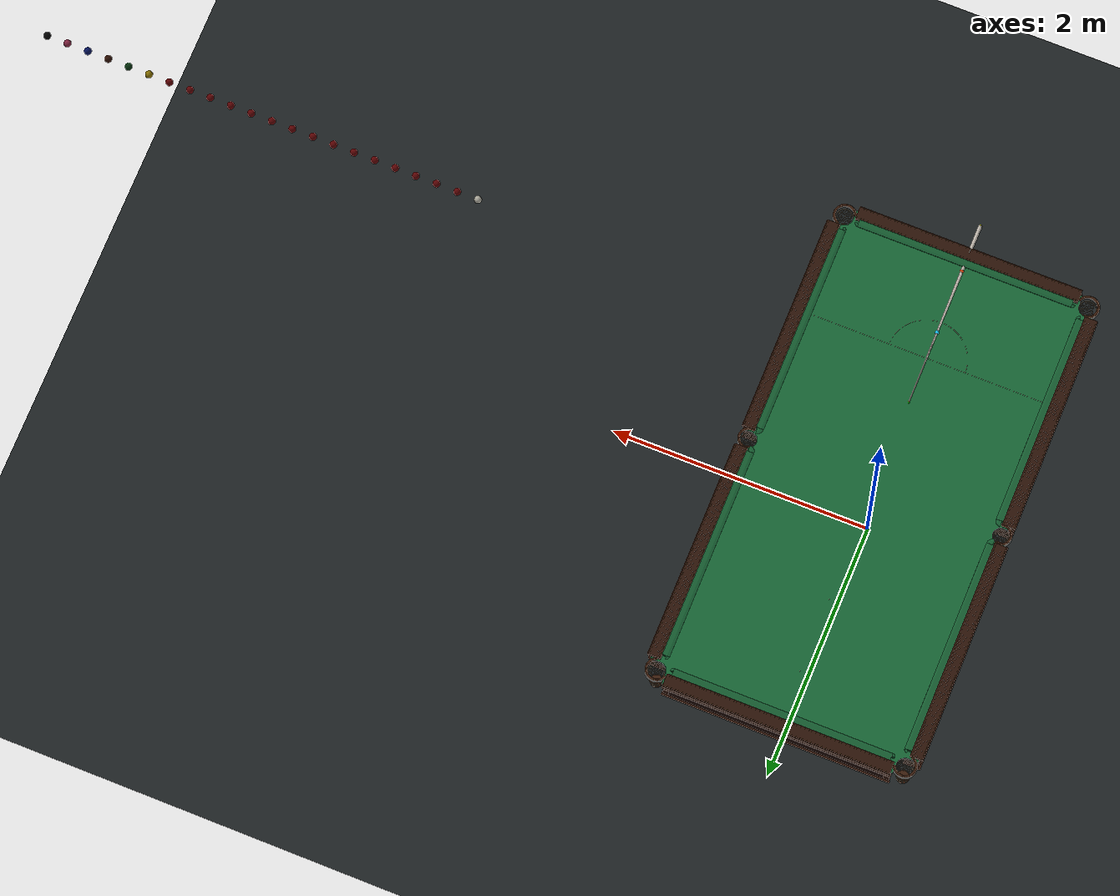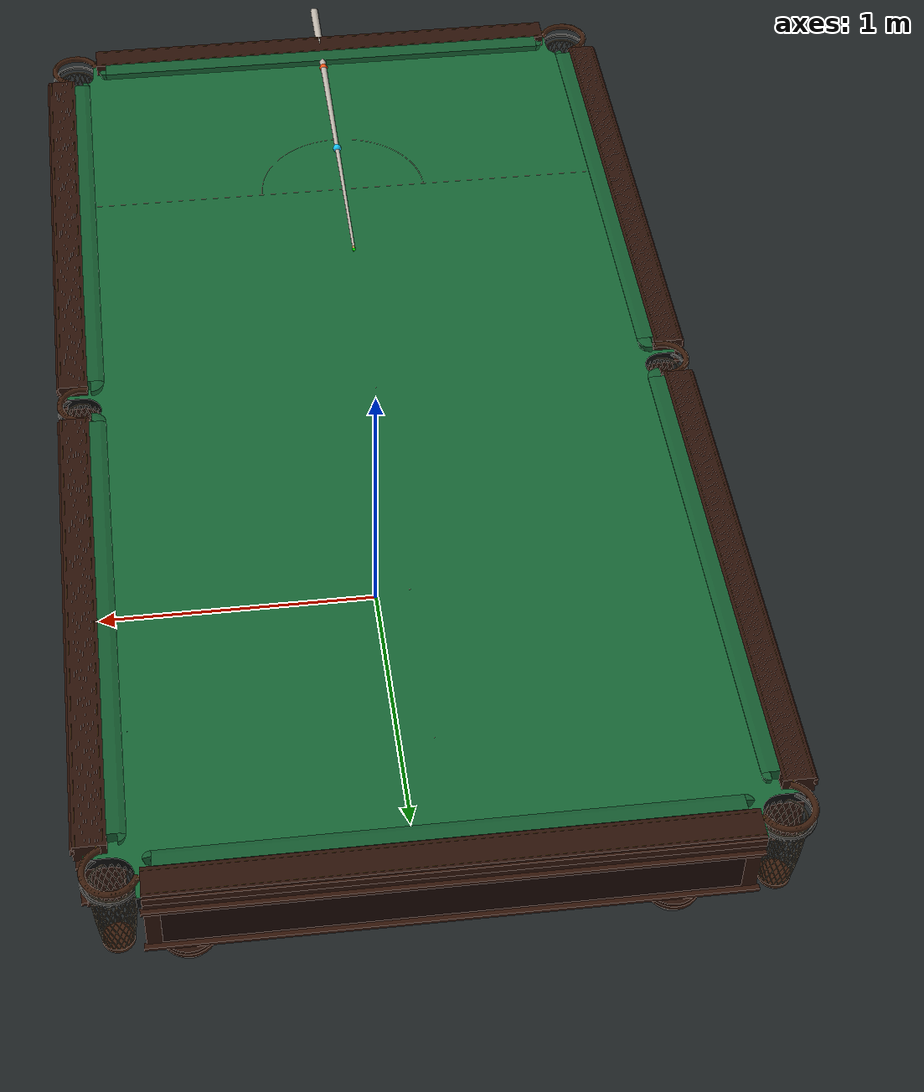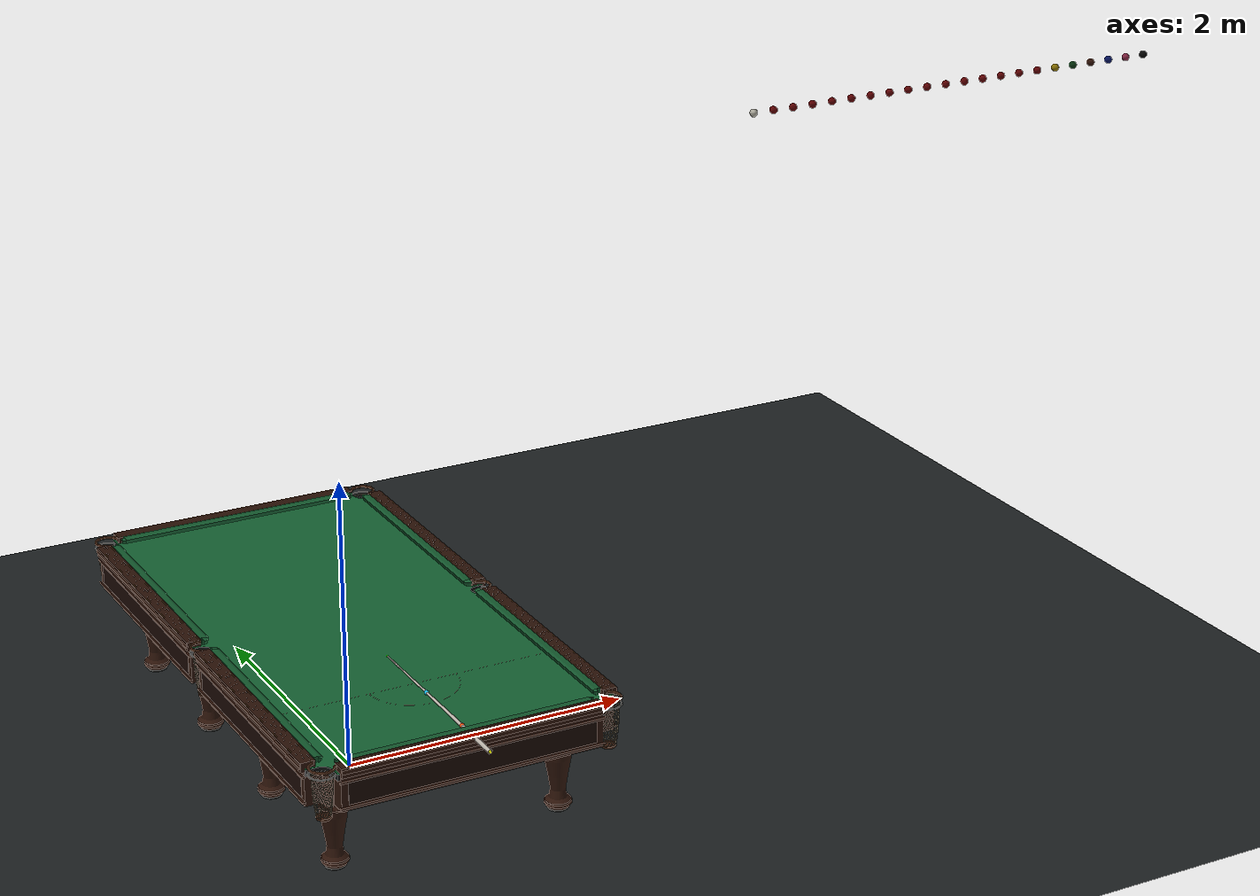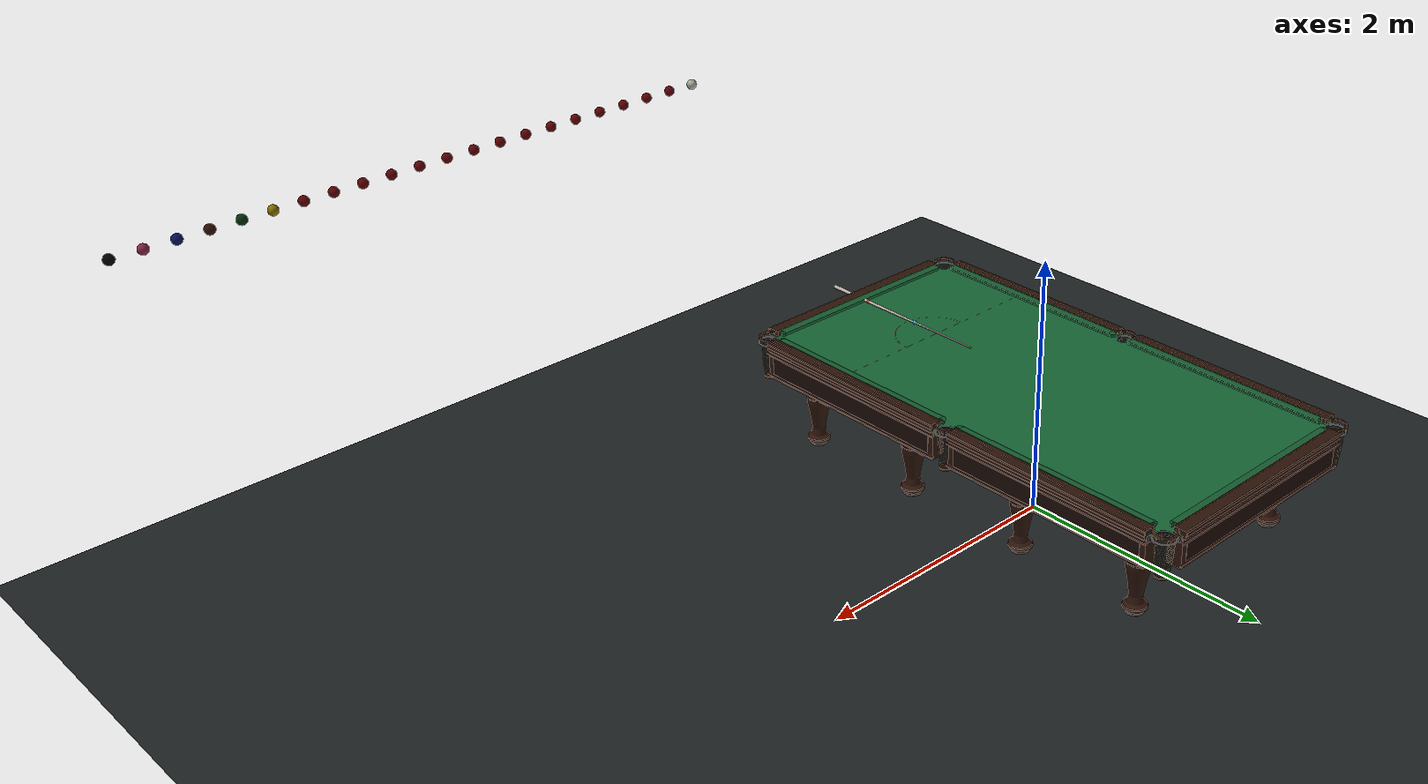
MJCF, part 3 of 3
2635 2638 2639 2630 2631 2636 2630 2636 2635 2631 2632 2637 2631 2637 2636 2632 2633 2638 2632 2638 2637 2633 2634 2639 2633 2639 2638 2634 2630 2635 2634 2635 2639 2640 2642 2641 2640 2643 2642 2640 2644 2643 2645 2646 2647 2645 2647 2648 2645 2648 2649 2640 2641 2646 2640 2646 2645 2641 2642 2647 2641 2647 2646 2642 2643 2648 2642 2648 2647 2643 2644 2649 2643 2649 2648 2644 2640 2645 2644 2645 2649 2650 2652 2651 2650 2653 2652 2650 2654 2653 2655 2656 2657 2655 2657 2658 2655 2658 2659 2650 2651 2656 2650 2656 2655 2651 2652 2657 2651 2657 2656 2652 2653 2658 2652 2658 2657 2653 2654 2659 2653 2659 2658 2654 2650 2655 2654 2655 2659 2660 2662 2661 2660 2663 2662 2660 2664 2663 2665 2666 2667 2665 2667 2668 2665 2668 2669 2660 2661 2666 2660 2666 2665 2661 2662 2667 2661 2667 2666 2662 2663 2668 2662 2668 2667 2663 2664 2669 2663 2669 2668 2664 2660 2665 2664 2665 2669 2670 2672 2671 2670 2673 2672 2670 2674 2673 2675 2676 2677 2675 2677 2678 2675 2678 2679 2670 2671 2676 2670 2676 2675 2671 2672 2677 2671 2677 2676 2672 2673 2678 2672 2678 2677 2673 2674 2679 2673 2679 2678 2674 2670 2675 2674 2675 2679 2680 2682 2681 2680 2683 2682 2680 2684 2683 2685 2686 2687 2685 2687 2688 2685 2688 2689 2680 2681 2686 2680 2686 2685 2681 2682 2687 2681 2687 2686 2682 2683 2688 2682 2688 2687 2683 2684 2689 2683 2689 2688 2684 2680 2685 2684 2685 2689 2690 2692 2691 2690 2693 2692 2690 2694 2693 2695 2696 2697 2695 2697 2698 2695 2698 2699 2690 2691 2696 2690 2696 2695 2691 2692 2697 2691 2697 2696 2692 2693 2698 2692 2698 2697 2693 2694 2699 2693 2699 2698 2694 2690 2695 2694 2695 2699 2700 2702 2701 2700 2703 2702 2700 2704 2703 2705 2706 2707 2705 2707 2708 2705 2708 2709 2700 2701 2706 2700 2706 2705 2701 2702 2707 2701 2707 2706 2702 2703 2708 2702 2708 2707 2703 2704 2709 2703 2709 2708 2704 2700 2705 2704 2705 2709 2710 2712 2711 2710 2713 2712 2710 2714 2713 2715 2716 2717 2715 2717 2718 2715 2718 2719 2710 2711 2716 2710 2716 2715 2711 2712 2717 2711 2717 2716 2712 2713 2718 2712 2718 2717 2713 2714 2719 2713 2719 2718 2714 2710 2715 2714 2715 2719 2720 2722 2721 2720 2723 2722 2720 2724 2723 2725 2726 2727 2725 2727 2728 2725 2728 2729 2720 2721 2726 2720 2726 2725 2721 2722 2727 2721 2727 2726 2722 2723 2728 2722 2728 2727 2723 2724 2729 2723 2729 2728 2724 2720 2725 2724 2725 2729 2730 2732 2731 2730 2733 2732 2730 2734 2733 2735 2736 2737 2735 2737 2738 2735 2738 2739 2730 2731 2736 2730 2736 2735 2731 2732 2737 2731 2737 2736 2732 2733 2738 2732 2738 2737 2733 2734 2739 2733 2739 2738 2734 2730 2735 2734 2735 2739 2740 2742 2741 2740 2743 2742 2740 2744 2743 2745 2746 2747 2745 2747 2748 2745 2748 2749 2740 2741 2746 2740 2746 2745 2741 2742 2747 2741 2747 2746 2742 2743 2748 2742 2748 2747 2743 2744 2749 2743 2749 2748 2744 2740 2745 2744 2745 2749 2750 2752 2751 2750 2753 2752 2750 2754 2753 2755 2756 2757 2755 2757 2758 2755 2758 2759 2750 2751 2756 2750 2756 2755 2751 2752 2757 2751 2757 2756 2752 2753 2758 2752 2758 2757 2753 2754 2759 2753 2759 2758 2754 2750 2755 2754 2755 2759 2760 2762 2761 2760 2763 2762 2760 2764 2763 2765 2766 2767 2765 2767 2768 2765 2768 2769 2760 2761 2766 2760 2766 2765 2761 2762 2767 2761 2767 2766 2762 2763 2768 2762 2768 2767 2763 2764 2769 2763 2769 2768 2764 2760 2765 2764 2765 2769 2770 2772 2771 2770 2773 2772 2770 2774 2773 2775 2776 2777 2775 2777 2778 2775 2778 2779 2770 2771 2776 2770 2776 2775 2771 2772 2777 2771 2777 2776 2772 2773 2778 2772 2778 2777 2773 2774 2779 2773 2779 2778 2774 2770 2775 2774 2775 2779 2780 2782 2781 2780 2783 2782 2780 2784 2783 2785 2786 2787 2785 2787 2788 2785 2788 2789 2780 2781 2786 2780 2786 2785 2781 2782 2787 2781 2787 2786 2782 2783 2788 2782 2788 2787 2783 2784 2789 2783 2789 2788 2784 2780 2785 2784 2785 2789 2790 2792 2791 2790 2793 2792 2790 2794 2793 2795 2796 2797 2795 2797 2798 2795 2798 2799 2790 2791 2796 2790 2796 2795 2791 2792 2797 2791 2797 2796 2792 2793 2798 2792 2798 2797 2793 2794 2799 2793 2799 2798 2794 2790 2795 2794 2795 2799 2800 2802 2801 2800 2803 2802 2800 2804 2803 2805 2806 2807 2805 2807 2808 2805 2808 2809 2800 2801 2806 2800 2806 2805 2801 2802 2807 2801 2807 2806 2802 2803 2808 2802 2808 2807 2803 2804 2809 2803 2809 2808 2804 2800 2805 2804 2805 2809 2810 2812 2811 2810 2813 2812 2810 2814 2813 2815 2816 2817 2815 2817 2818 2815 2818 2819 2810 2811 2816 2810 2816 2815 2811 2812 2817 2811 2817 2816 2812 2813 2818 2812 2818 2817 2813 2814 2819 2813 2819 2818 2814 2810 2815 2814 2815 2819 2820 2822 2821 2820 2823 2822 2820 2824 2823 2825 2826 2827 2825 2827 2828 2825 2828 2829 2820 2821 2826 2820 2826 2825 2821 2822 2827 2821 2827 2826 2822 2823 2828 2822 2828 2827 2823 2824 2829 2823 2829 2828 2824 2820 2825 2824 2825 2829 2830 2832 2831 2830 2833 2832 2830 2834 2833 2835 2836 2837 2835 2837 2838 2835 2838 2839 2830 2831 2836 2830 2836 2835 2831 2832 2837 2831 2837 2836 2832 2833 2838 2832 2838 2837 2833 2834 2839 2833 2839 2838 2834 2830 2835 2834 2835 2839 2840 2842 2841 2840 2843 2842 2840 2844 2843 2845 2846 2847 2845 2847 2848 2845 2848 2849 2840 2841 2846 2840 2846 2845 2841 2842 2847 2841 2847 2846 2842 2843 2848 2842 2848 2847 2843 2844 2849 2843 2849 2848 2844 2840 2845 2844 2845 2849 2850 2852 2851 2850 2853 2852 2850 2854 2853 2855 2856 2857 2855 2857 2858 2855 2858 2859 2850 2851 2856 2850 2856 2855 2851 2852 2857 2851 2857 2856 2852 2853 2858 2852 2858 2857 2853 2854 2859 2853 2859 2858 2854 2850 2855 2854 2855 2859 2860 2862 2861 2860 2863 2862 2860 2864 2863 2865 2866 2867 2865 2867 2868 2865 2868 2869 2860 2861 2866 2860 2866 2865 2861 2862 2867 2861 2867 2866 2862 2863 2868 2862 2868 2867 2863 2864 2869 2863 2869 2868 2864 2860 2865 2864 2865 2869 2870 2872 2871 2870 2873 2872 2870 2874 2873 2875 2876 2877 2875 2877 2878 2875 2878 2879 2870 2871 2876 2870 2876 2875 2871 2872 2877 2871 2877 2876 2872 2873 2878 2872 2878 2877 2873 2874 2879 2873 2879 2878 2874 2870 2875 2874 2875 2879 2880 2882 2881 2880 2883 2882 2880 2884 2883 2885 2886 2887 2885 2887 2888 2885 2888 2889 2880 2881 2886 2880 2886 2885 2881 2882 2887 2881 2887 2886 2882 2883 2888 2882 2888 2887 2883 2884 2889 2883 2889 2888 2884 2880 2885 2884 2885 2889 2890 2892 2891 2890 2893 2892 2890 2894 2893 2895 2896 2897 2895 2897 2898 2895 2898 2899 2890 2891 2896 2890 2896 2895 2891 2892 2897 2891 2897 2896 2892 2893 2898 2892 2898 2897 2893 2894 2899 2893 2899 2898 2894 2890 2895 2894 2895 2899 2900 2902 2901 2900 2903 2902 2900 2904 2903 2905 2906 2907 2905 2907 2908 2905 2908 2909 2900 2901 2906 2900 2906 2905 2901 2902 2907 2901 2907 2906 2902 2903 2908 2902 2908 2907 2903 2904 2909 2903 2909 2908 2904 2900 2905 2904 2905 2909 2910 2912 2911 2910 2913 2912 2910 2914 2913 2915 2916 2917 2915 2917 2918 2915 2918 2919 2910 2911 2916 2910 2916 2915 2911 2912 2917 2911 2917 2916 2912 2913 2918 2912 2918 2917 2913 2914 2919 2913 2919 2918 2914 2910 2915 2914 2915 2919 2920 2922 2921 2920 2923 2922 2920 2924 2923 2925 2926 2927 2925 2927 2928 2925 2928 2929 2920 2921 2926 2920 2926 2925 2921 2922 2927 2921 2927 2926 2922 2923 2928 2922 2928 2927 2923 2924 2929 2923 2929 2928 2924 2920 2925 2924 2925 2929 2930 2932 2931 2930 2933 2932 2930 2934 2933 2935 2936 2937 2935 2937 2938 2935 2938 2939 2930 2931 2936 2930 2936 2935 2931 2932 2937 2931 2937 2936 2932 2933 2938 2932 2938 2937 2933 2934 2939 2933 2939 2938 2934 2930 2935 2934 2935 2939 2940 2942 2941 2940 2943 2942 2940 2944 2943 2945 2946 2947 2945 2947 2948 2945 2948 2949 2940 2941 2946 2940 2946 2945 2941 2942 2947 2941 2947 2946 2942 2943 2948 2942 2948 2947 2943 2944 2949 2943 2949 2948 2944 2940 2945 2944 2945 2949 2950 2952 2951 2950 2953 2952 2950 2954 2953 2955 2956 2957 2955 2957 2958 2955 2958 2959 2950 2951 2956 2950 2956 2955 2951 2952 2957 2951 2957 2956 2952 2953 2958 2952 2958 2957 2953 2954 2959 2953 2959 2958 2954 2950 2955 2954 2955 2959 2960 2962 2961 2960 2963 2962 2960 2964 2963 2965 2966 2967 2965 2967 2968 2965 2968 2969 2960 2961 2966 2960 2966 2965 2961 2962 2967 2961 2967 2966 2962 2963 2968 2962 2968 2967 2963 2964 2969 2963 2969 2968 2964 2960 2965 2964 2965 2969 2970 2972 2971 2970 2973 2972 2970 2974 2973 2975 2976 2977 2975 2977 2978 2975 2978 2979 2970 2971 2976 2970 2976 2975 2971 2972 2977 2971 2977 2976 2972 2973 2978 2972 2978 2977 2973 2974 2979 2973 2979 2978 2974 2970 2975 2974 2975 2979 2980 2982 2981 2980 2983 2982 2980 2984 2983 2985 2986 2987 2985 2987 2988 2985 2988 2989 2980 2981 2986 2980 2986 2985 2981 2982 2987 2981 2987 2986 2982 2983 2988 2982 2988 2987 2983 2984 2989 2983 2989 2988 2984 2980 2985 2984 2985 2989 2990 2992 2991 2990 2993 2992 2990 2994 2993 2995 2996 2997 2995 2997 2998 2995 2998 2999 2990 2991 2996 2990 2996 2995 2991 2992 2997 2991 2997 2996 2992 2993 2998 2992 2998 2997 2993 2994 2999 2993 2999 2998 2994 2990 2995 2994 2995 2999 3000 3002 3001 3000 3003 3002 3000 3004 3003 3005 3006 3007 3005 3007 3008 3005 3008 3009 3000 3001 3006 3000 3006 3005 3001 3002 3007 3001 3007 3006 3002 3003 3008 3002 3008 3007 3003 3004 3009 3003 3009 3008 3004 3000 3005 3004 3005 3009 3010 3012 3011 3010 3013 3012 3010 3014 3013 3015 3016 3017 3015 3017 3018 3015 3018 3019 3010 3011 3016 3010 3016 3015 3011 3012 3017 3011 3017 3016 3012 3013 3018 3012 3018 3017 3013 3014 3019 3013 3019 3018 3014 3010 3015 3014 3015 3019 3020 3022 3021 3020 3023 3022 3020 3024 3023 3025 3026 3027 3025 3027 3028 3025 3028 3029 3020 3021 3026 3020 3026 3025 3021 3022 3027 3021 3027 3026 3022 3023 3028 3022 3028 3027 3023 3024 3029 3023 3029 3028 3024 3020 3025 3024 3025 3029 3030 3032 3031 3030 3033 3032 3030 3034 3033 3035 3036 3037 3035 3037 3038 3035 3038 3039 3030 3031 3036 3030 3036 3035 3031 3032 3037 3031 3037 3036 3032 3033 3038 3032 3038 3037 3033 3034 3039 3033 3039 3038 3034 3030 3035 3034 3035 3039 3040 3042 3041 3040 3043 3042 3040 3044 3043 3045 3046 3047 3045 3047 3048 3045 3048 3049 3040 3041 3046 3040 3046 3045 3041 3042 3047 3041 3047 3046 3042 3043 3048 3042 3048 3047 3043 3044 3049 3043 3049 3048 3044 3040 3045 3044 3045 3049 3050 3052 3051 3050 3053 3052 3050 3054 3053 3055 3056 3057 3055 3057 3058 3055 3058 3059 3050 3051 3056 3050 3056 3055 3051 3052 3057 3051 3057 3056 3052 3053 3058 3052 3058 3057 3053 3054 3059 3053 3059 3058 3054 3050 3055 3054 3055 3059 3060 3062 3061 3060 3063 3062 3060 3064 3063 3065 3066 3067 3065 3067 3068 3065 3068 3069 3060 3061 3066 3060 3066 3065 3061 3062 3067 3061 3067 3066 3062 3063 3068 3062 3068 3067 3063 3064 3069 3063 3069 3068 3064 3060 3065 3064 3065 3069 3070 3072 3071 3070 3073 3072 3070 3074 3073 3075 3076 3077 3075 3077 3078 3075 3078 3079 3070 3071 3076 3070 3076 3075 3071 3072 3077 3071 3077 3076 3072 3073 3078 3072 3078 3077 3073 3074 3079 3073 3079 3078 3074 3070 3075 3074 3075 3079 3080 3082 3081 3080 3083 3082 3080 3084 3083 3085 3086 3087 3085 3087 3088 3085 3088 3089 3080 3081 3086 3080 3086 3085 3081 3082 3087 3081 3087 3086 3082 3083 3088 3082 3088 3087 3083 3084 3089 3083 3089 3088 3084 3080 3085 3084 3085 3089 3090 3092 3091 3090 3093 3092 3090 3094 3093 3095 3096 3097 3095 3097 3098 3095 3098 3099 3090 3091 3096 3090 3096 3095 3091 3092 3097 3091 3097 3096 3092 3093 3098 3092 3098 3097 3093 3094 3099 3093 3099 3098 3094 3090 3095 3094 3095 3099 3100 3102 3101 3100 3103 3102 3100 3104 3103 3105 3106 3107 3105 3107 3108 3105 3108 3109 3100 3101 3106 3100 3106 3105 3101 3102 3107 3101 3107 3106 3102 3103 3108 3102 3108 3107 3103 3104 3109 3103 3109 3108 3104 3100 3105 3104 3105 3109 3110 3112 3111 3110 3113 3112 3110 3114 3113 3115 3116 3117 3115 3117 3118 3115 3118 3119 3110 3111 3116 3110 3116 3115 3111 3112 3117 3111 3117 3116 3112 3113 3118 3112 3118 3117 3113 3114 3119 3113 3119 3118 3114 3110 3115 3114 3115 3119 3120 3122 3121 3120 3123 3122 3120 3124 3123 3125 3126 3127 3125 3127 3128 3125 3128 3129 3120 3121 3126 3120 3126 3125 3121 3122 3127 3121 3127 3126 3122 3123 3128 3122 3128 3127 3123 3124 3129 3123 3129 3128 3124 3120 3125 3124 3125 3129 3130 3132 3131 3130 3133 3132 3130 3134 3133 3135 3136 3137 3135 3137 3138 3135 3138 3139 3130 3131 3136 3130 3136 3135 3131 3132 3137 3131 3137 3136 3132 3133 3138 3132 3138 3137 3133 3134 3139 3133 3139 3138 3134 3130 3135 3134 3135 3139 3140 3142 3141 3140 3143 3142 3140 3144 3143 3145 3146 3147 3145 3147 3148 3145 3148 3149 3140 3141 3146 3140 3146 3145 3141 3142 3147 3141 3147 3146 3142 3143 3148 3142 3148 3147 3143 3144 3149 3143 3149 3148 3144 3140 3145 3144 3145 3149 3150 3152 3151 3150 3153 3152 3150 3154 3153 3155 3156 3157 3155 3157 3158 3155 3158 3159 3150 3151 3156 3150 3156 3155 3151 3152 3157 3151 3157 3156 3152 3153 3158 3152 3158 3157 3153 3154 3159 3153 3159 3158 3154 3150 3155 3154 3155 3159 3160 3162 3161 3160 3163 3162 3160 3164 3163 3165 3166 3167 3165 3167 3168 3165 3168 3169 3160 3161 3166 3160 3166 3165 3161 3162 3167 3161 3167 3166 3162 3163 3168 3162 3168 3167 3163 3164 3169 3163 3169 3168 3164 3160 3165 3164 3165 3169 3170 3172 3171 3170 3173 3172 3170 3174 3173 3175 3176 3177 3175 3177 3178 3175 3178 3179 3170 3171 3176 3170 3176 3175 3171 3172 3177 3171 3177 3176 3172 3173 3178 3172 3178 3177 3173 3174 3179 3173 3179 3178 3174 3170 3175 3174 3175 3179 3180 3182 3181 3180 3183 3182 3180 3184 3183 3185 3186 3187 3185 3187 3188 3185 3188 3189 3180 3181 3186 3180 3186 3185 3181 3182 3187 3181 3187 3186 3182 3183 3188 3182 3188 3187 3183 3184 3189 3183 3189 3188 3184 3180 3185 3184 3185 3189 3190 3192 3191 3190 3193 3192 3190 3194 3193 3195 3196 3197 3195 3197 3198 3195 3198 3199 3190 3191 3196 3190 3196 3195 3191 3192 3197 3191 3197 3196 3192 3193 3198 3192 3198 3197 3193 3194 3199 3193 3199 3198 3194 3190 3195 3194 3195 3199 3200 3202 3201 3200 3203 3202 3200 3204 3203 3205 3206 3207 3205 3207 3208 3205 3208 3209 3200 3201 3206 3200 3206 3205 3201 3202 3207 3201 3207 3206 3202 3203 3208 3202 3208 3207 3203 3204 3209 3203 3209 3208 3204 3200 3205 3204 3205 3209 3210 3212 3211 3210 3213 3212 3210 3214 3213 3215 3216 3217 3215 3217 3218 3215 3218 3219 3210 3211 3216 3210 3216 3215 3211 3212 3217 3211 3217 3216 3212 3213 3218 3212 3218 3217 3213 3214 3219 3213 3219 3218 3214 3210 3215 3214 3215 3219 3220 3222 3221 3220 3223 3222 3220 3224 3223 3225 3226 3227 3225 3227 3228 3225 3228 3229 3220 3221 3226 3220 3226 3225 3221 3222 3227 3221 3227 3226 3222 3223 3228 3222 3228 3227 3223 3224 3229 3223 3229 3228 3224 3220 3225 3224 3225 3229 3230 3232 3231 3230 3233 3232 3230 3234 3233 3235 3236 3237 3235 3237 3238 3235 3238 3239 3230 3231 3236 3230 3236 3235 3231 3232 3237 3231 3237 3236 3232 3233 3238 3232 3238 3237 3233 3234 3239 3233 3239 3238 3234 3230 3235 3234 3235 3239 3240 3242 3241 3240 3243 3242 3240 3244 3243 3245 3246 3247 3245 3247 3248 3245 3248 3249 3240 3241 3246 3240 3246 3245 3241 3242 3247 3241 3247 3246 3242 3243 3248 3242 3248 3247 3243 3244 3249 3243 3249 3248 3244 3240 3245 3244 3245 3249 3250 3252 3251 3250 3253 3252 3250 3254 3253 3255 3256 3257 3255 3257 3258 3255 3258 3259 3250 3251 3256 3250 3256 3255 3251 3252 3257 3251 3257 3256 3252 3253 3258 3252 3258 3257 3253 3254 3259 3253 3259 3258 3254 3250 3255 3254 3255 3259 3260 3262 3261 3260 3263 3262 3260 3264 3263 3265 3266 3267 3265 3267 3268 3265 3268 3269 3260 3261 3266 3260 3266 3265 3261 3262 3267 3261 3267 3266 3262 3263 3268 3262 3268 3267 3263 3264 3269 3263 3269 3268 3264 3260 3265 3264 3265 3269 3270 3272 3271 3270 3273 3272 3270 3274 3273 3275 3276 3277 3275 3277 3278 3275 3278 3279 3270 3271 3276 3270 3276 3275 3271 3272 3277 3271 3277 3276 3272 3273 3278 3272 3278 3277 3273 3274 3279 3273 3279 3278 3274 3270 3275 3274 3275 3279 3280 3282 3281 3280 3283 3282 3280 3284 3283 3285 3286 3287 3285 3287 3288 3285 3288 3289 3280 3281 3286 3280 3286 3285 3281 3282 3287 3281 3287 3286 3282 3283 3288 3282 3288 3287 3283 3284 3289 3283 3289 3288 3284 3280 3285 3284 3285 3289 3290 3292 3291 3290 3293 3292 3290 3294 3293 3295 3296 3297 3295 3297 3298 3295 3298 3299 3290 3291 3296 3290 3296 3295 3291 3292 3297 3291 3297 3296 3292 3293 3298 3292 3298 3297 3293 3294 3299 3293 3299 3298 3294 3290 3295 3294 3295 3299 3300 3302 3301 3300 3303 3302 3300 3304 3303 3305 3306 3307 3305 3307 3308 3305 3308 3309 3300 3301 3306 3300 3306 3305 3301 3302 3307 3301 3307 3306 3302 3303 3308 3302 3308 3307 3303 3304 3309 3303 3309 3308 3304 3300 3305 3304 3305 3309 3310 3312 3311 3310 3313 3312 3310 3314 3313 3315 3316 3317 3315 3317 3318 3315 3318 3319 3310 3311 3316 3310 3316 3315 3311 3312 3317 3311 3317 3316 3312 3313 3318 3312 3318 3317 3313 3314 3319 3313 3319 3318 3314 3310 3315 3314 3315 3319 3320 3322 3321 3320 3323 3322 3320 3324 3323 3325 3326 3327 3325 3327 3328 3325 3328 3329 3320 3321 3326 3320 3326 3325 3321 3322 3327 3321 3327 3326 3322 3323 3328 3322 3328 3327 3323 3324 3329 3323 3329 3328 3324 3320 3325 3324 3325 3329 3330 3332 3331 3330 3333 3332 3330 3334 3333 3335 3336 3337 3335 3337 3338 3335 3338 3339 3330 3331 3336 3330 3336 3335 3331 3332 3337 3331 3337 3336 3332 3333 3338 3332 3338 3337 3333 3334 3339 3333 3339 3338 3334 3330 3335 3334 3335 3339 3340 3342 3341 3340 3343 3342 3340 3344 3343 3345 3346 3347 3345 3347 3348 3345 3348 3349 3340 3341 3346 3340 3346 3345 3341 3342 3347 3341 3347 3346 3342 3343 3348 3342 3348 3347 3343 3344 3349 3343 3349 3348 3344 3340 3345 3344 3345 3349 3350 3352 3351 3350 3353 3352 3350 3354 3353 3355 3356 3357 3355 3357 3358 3355 3358 3359 3350 3351 3356 3350 3356 3355 3351 3352 3357 3351 3357 3356 3352 3353 3358 3352 3358 3357 3353 3354 3359 3353 3359 3358 3354 3350 3355 3354 3355 3359 3360 3362 3361 3360 3363 3362 3360 3364 3363 3365 3366 3367 3365 3367 3368 3365 3368 3369 3360 3361 3366 3360 3366 3365 3361 3362 3367 3361 3367 3366 3362 3363 3368 3362 3368 3367 3363 3364 3369 3363 3369 3368 3364 3360 3365 3364 3365 3369 3370 3372 3371 3370 3373 3372 3370 3374 3373 3375 3376 3377 3375 3377 3378 3375 3378 3379 3370 3371 3376 3370 3376 3375 3371 3372 3377 3371 3377 3376 3372 3373 3378 3372 3378 3377 3373 3374 3379 3373 3379 3378 3374 3370 3375 3374 3375 3379 3380 3382 3381 3380 3383 3382 3380 3384 3383 3385 3386 3387 3385 3387 3388 3385 3388 3389 3380 3381 3386 3380 3386 3385 3381 3382 3387 3381 3387 3386 3382 3383 3388 3382 3388 3387 3383 3384 3389 3383 3389 3388 3384 3380 3385 3384 3385 3389 3390 3392 3391 3390 3393 3392 3390 3394 3393 3395 3396 3397 3395 3397 3398 3395 3398 3399 3390 3391 3396 3390 3396 3395 3391 3392 3397 3391 3397 3396 3392 3393 3398 3392 3398 3397 3393 3394 3399 3393 3399 3398 3394 3390 3395 3394 3395 3399 3400 3402 3401 3400 3403 3402 3400 3404 3403 3405 3406 3407 3405 3407 3408 3405 3408 3409 3400 3401 3406 3400 3406 3405 3401 3402 3407 3401 3407 3406 3402 3403 3408 3402 3408 3407 3403 3404 3409 3403 3409 3408 3404 3400 3405 3404 3405 3409 3410 3412 3411 3410 3413 3412 3410 3414 3413 3415 3416 3417 3415 3417 3418 3415 3418 3419 3410 3411 3416 3410 3416 3415 3411 3412 3417 3411 3417 3416 3412 3413 3418 3412 3418 3417 3413 3414 3419 3413 3419 3418 3414 3410 3415 3414 3415 3419 3420 3422 3421 3420 3423 3422 3420 3424 3423 3425 3426 3427 3425 3427 3428 3425 3428 3429 3420 3421 3426 3420 3426 3425 3421 3422 3427 3421 3427 3426 3422 3423 3428 3422 3428 3427 3423 3424 3429 3423 3429 3428 3424 3420 3425 3424 3425 3429 3430 3432 3431 3430 3433 3432 3430 3434 3433 3435 3436 3437 3435 3437 3438 3435 3438 3439 3430 3431 3436 3430 3436 3435 3431 3432 3437 3431 3437 3436 3432 3433 3438 3432 3438 3437 3433 3434 3439 3433 3439 3438 3434 3430 3435 3434 3435 3439 3440 3442 3441 3440 3443 3442 3440 3444 3443 3445 3446 3447 3445 3447 3448 3445 3448 3449 3440 3441 3446 3440 3446 3445 3441 3442 3447 3441 3447 3446 3442 3443 3448 3442 3448 3447 3443 3444 3449 3443 3449 3448 3444 3440 3445 3444 3445 3449 3450 3452 3451 3450 3453 3452 3450 3454 3453 3455 3456 3457 3455 3457 3458 3455 3458 3459 3450 3451 3456 3450 3456 3455 3451 3452 3457 3451 3457 3456 3452 3453 3458 3452 3458 3457 3453 3454 3459 3453 3459 3458 3454 3450 3455 3454 3455 3459 3460 3462 3461 3460 3463 3462 3460 3464 3463 3465 3466 3467 3465 3467 3468 3465 3468 3469 3460 3461 3466 3460 3466 3465 3461 3462 3467 3461 3467 3466 3462 3463 3468 3462 3468 3467 3463 3464 3469 3463 3469 3468 3464 3460 3465 3464 3465 3469 3470 3472 3471 3470 3473 3472 3470 3474 3473 3475 3476 3477 3475 3477 3478 3475 3478 3479 3470 3471 3476 3470 3476 3475 3471 3472 3477 3471 3477 3476 3472 3473 3478 3472 3478 3477 3473 3474 3479 3473 3479 3478 3474 3470 3475 3474 3475 3479 3480 3482 3481 3480 3483 3482 3480 3484 3483 3485 3486 3487 3485 3487 3488 3485 3488 3489 3480 3481 3486 3480 3486 3485 3481 3482 3487 3481 3487 3486 3482 3483 3488 3482 3488 3487 3483 3484 3489 3483 3489 3488 3484 3480 3485 3484 3485 3489 3490 3492 3491 3490 3493 3492 3490 3494 3493 3495 3496 3497 3495 3497 3498 3495 3498 3499 3490 3491 3496 3490 3496 3495 3491 3492 3497 3491 3497 3496 3492 3493 3498 3492 3498 3497 3493 3494 3499 3493 3499 3498 3494 3490 3495 3494 3495 3499 3500 3502 3501 3500 3503 3502 3500 3504 3503 3505 3506 3507 3505 3507 3508 3505 3508 3509 3500 3501 3506 3500 3506 3505 3501 3502 3507 3501 3507 3506 3502 3503 3508 3502 3508 3507 3503 3504 3509 3503 3509 3508 3504 3500 3505 3504 3505 3509 3510 3512 3511 3510 3513 3512 3510 3514 3513 3515 3516 3517 3515 3517 3518 3515 3518 3519 3510 3511 3516 3510 3516 3515 3511 3512 3517 3511 3517 3516 3512 3513 3518 3512 3518 3517 3513 3514 3519 3513 3519 3518 3514 3510 3515 3514 3515 3519 3520 3522 3521 3520 3523 3522 3520 3524 3523 3525 3526 3527 3525 3527 3528 3525 3528 3529 3520 3521 3526 3520 3526 3525 3521 3522 3527 3521 3527 3526 3522 3523 3528 3522 3528 3527 3523 3524 3529 3523 3529 3528 3524 3520 3525 3524 3525 3529 3530 3532 3531 3530 3533 3532 3530 3534 3533 3535 3536 3537 3535 3537 3538 3535 3538 3539 3530 3531 3536 3530 3536 3535 3531 3532 3537 3531 3537 3536 3532 3533 3538 3532 3538 3537 3533 3534 3539 3533 3539 3538 3534 3530 3535 3534 3535 3539 3540 3542 3541 3540 3543 3542 3540 3544 3543 3545 3546 3547 3545 3547 3548 3545 3548 3549 3540 3541 3546 3540 3546 3545 3541 3542 3547 3541 3547 3546 3542 3543 3548 3542 3548 3547 3543 3544 3549 3543 3549 3548 3544 3540 3545 3544 3545 3549 3550 3552 3551 3550 3553 3552 3550 3554 3553 3555 3556 3557 3555 3557 3558 3555 3558 3559 3550 3551 3556 3550 3556 3555 3551 3552 3557 3551 3557 3556 3552 3553 3558 3552 3558 3557 3553 3554 3559 3553 3559 3558 3554 3550 3555 3554 3555 3559 3560 3562 3561 3560 3563 3562 3560 3564 3563 3565 3566 3567 3565 3567 3568 3565 3568 3569 3560 3561 3566 3560 3566 3565 3561 3562 3567 3561 3567 3566 3562 3563 3568 3562 3568 3567 3563 3564 3569 3563 3569 3568 3564 3560 3565 3564 3565 3569 3570 3572 3571 3570 3573 3572 3570 3574 3573 3575 3576 3577 3575 3577 3578 3575 3578 3579 3570 3571 3576 3570 3576 3575 3571 3572 3577 3571 3577 3576 3572 3573 3578 3572 3578 3577 3573 3574 3579 3573 3579 3578 3574 3570 3575 3574 3575 3579 3580 3582 3581 3580 3583 3582 3580 3584 3583 3585 3586 3587 3585 3587 3588 3585 3588 3589 3580 3581 3586 3580 3586 3585 3581 3582 3587 3581 3587 3586 3582 3583 3588 3582 3588 3587 3583 3584 3589 3583 3589 3588 3584 3580 3585 3584 3585 3589 3590 3592 3591 3590 3593 3592 3590 3594 3593 3595 3596 3597 3595 3597 3598 3595 3598 3599 3590 3591 3596 3590 3596 3595 3591 3592 3597 3591 3597 3596 3592 3593 3598 3592 3598 3597 3593 3594 3599 3593 3599 3598 3594 3590 3595 3594 3595 3599 3600 3602 3601 3600 3603 3602 3600 3604 3603 3605 3606 3607 3605 3607 3608 3605 3608 3609 3600 3601 3606 3600 3606 3605 3601 3602 3607 3601 3607 3606 3602 3603 3608 3602 3608 3607 3603 3604 3609 3603 3609 3608 3604 3600 3605 3604 3605 3609 3610 3612 3611 3610 3613 3612 3610 3614 3613 3615 3616 3617 3615 3617 3618 3615 3618 3619 3610 3611 3616 3610 3616 3615 3611 3612 3617 3611 3617 3616 3612 3613 3618 3612 3618 3617 3613 3614 3619 3613 3619 3618 3614 3610 3615 3614 3615 3619 3620 3622 3621 3620 3623 3622 3620 3624 3623 3625 3626 3627 3625 3627 3628 3625 3628 3629 3620 3621 3626 3620 3626 3625 3621 3622 3627 3621 3627 3626 3622 3623 3628 3622 3628 3627 3623 3624 3629 3623 3629 3628 3624 3620 3625 3624 3625 3629 3630 3632 3631 3630 3633 3632 3630 3634 3633 3635 3636 3637 3635 3637 3638 3635 3638 3639 3630 3631 3636 3630 3636 3635 3631 3632 3637 3631 3637 3636 3632 3633 3638 3632 3638 3637 3633 3634 3639 3633 3639 3638 3634 3630 3635 3634 3635 3639 3640 3642 3641 3640 3643 3642 3640 3644 3643 3645 3646 3647 3645 3647 3648 3645 3648 3649 3640 3641 3646 3640 3646 3645 3641 3642 3647 3641 3647 3646 3642 3643 3648 3642 3648 3647 3643 3644 3649 3643 3649 3648 3644 3640 3645 3644 3645 3649 3650 3652 3651 3650 3653 3652 3650 3654 3653 3655 3656 3657 3655 3657 3658 3655 3658 3659 3650 3651 3656 3650 3656 3655 3651 3652 3657 3651 3657 3656 3652 3653 3658 3652 3658 3657 3653 3654 3659 3653 3659 3658 3654 3650 3655 3654 3655 3659 3660 3662 3661 3660 3663 3662 3660 3664 3663 3665 3666 3667 3665 3667 3668 3665 3668 3669 3660 3661 3666 3660 3666 3665 3661 3662 3667 3661 3667 3666 3662 3663 3668 3662 3668 3667 3663 3664 3669 3663 3669 3668 3664 3660 3665 3664 3665 3669 3670 3672 3671 3670 3673 3672 3670 3674 3673 3675 3676 3677 3675 3677 3678 3675 3678 3679 3670 3671 3676 3670 3676 3675 3671 3672 3677 3671 3677 3676 3672 3673 3678 3672 3678 3677 3673 3674 3679 3673 3679 3678 3674 3670 3675 3674 3675 3679 3680 3682 3681 3680 3683 3682 3680 3684 3683 3685 3686 3687 3685 3687 3688 3685 3688 3689 3680 3681 3686 3680 3686 3685 3681 3682 3687 3681 3687 3686 3682 3683 3688 3682 3688 3687 3683 3684 3689 3683 3689 3688 3684 3680 3685 3684 3685 3689 3690 3692 3691 3690 3693 3692 3690 3694 3693 3695 3696 3697 3695 3697 3698 3695 3698 3699 3690 3691 3696 3690 3696 3695 3691 3692 3697 3691 3697 3696 3692 3693 3698 3692 3698 3697 3693 3694 3699 3693 3699 3698 3694 3690 3695 3694 3695 3699 3700 3702 3701 3700 3703 3702 3700 3704 3703 3705 3706 3707 3705 3707 3708 3705 3708 3709 3700 3701 3706 3700 3706 3705 3701 3702 3707 3701 3707 3706 3702 3703 3708 3702 3708 3707 3703 3704 3709 3703 3709 3708 3704 3700 3705 3704 3705 3709 3710 3712 3711 3710 3713 3712 3710 3714 3713 3715 3716 3717 3715 3717 3718 3715 3718 3719 3710 3711 3716 3710 3716 3715 3711 3712 3717 3711 3717 3716 3712 3713 3718 3712 3718 3717 3713 3714 3719 3713 3719 3718 3714 3710 3715 3714 3715 3719 3720 3722 3721 3720 3723 3722 3720 3724 3723 3725 3726 3727 3725 3727 3728 3725 3728 3729 3720 3721 3726 3720 3726 3725 3721 3722 3727 3721 3727 3726 3722 3723 3728 3722 3728 3727 3723 3724 3729 3723 3729 3728 3724 3720 3725 3724 3725 3729 3730 3732 3731 3730 3733 3732 3730 3734 3733 3735 3736 3737 3735 3737 3738 3735 3738 3739 3730 3731 3736 3730 3736 3735 3731 3732 3737 3731 3737 3736 3732 3733 3738 3732 3738 3737 3733 3734 3739 3733 3739 3738 3734 3730 3735 3734 3735 3739 3740 3742 3741 3740 3743 3742 3740 3744 3743 3745 3746 3747 3745 3747 3748 3745 3748 3749 3740 3741 3746 3740 3746 3745 3741 3742 3747 3741 3747 3746 3742 3743 3748 3742 3748 3747 3743 3744 3749 3743 3749 3748 3744 3740 3745 3744 3745 3749 3750 3752 3751 3750 3753 3752 3750 3754 3753 3755 3756 3757 3755 3757 3758 3755 3758 3759 3750 3751 3756 3750 3756 3755 3751 3752 3757 3751 3757 3756 3752 3753 3758 3752 3758 3757 3753 3754 3759 3753 3759 3758 3754 3750 3755 3754 3755 3759 3760 3762 3761 3760 3763 3762 3760 3764 3763 3765 3766 3767 3765 3767 3768 3765 3768 3769 3760 3761 3766 3760 3766 3765 3761 3762 3767 3761 3767 3766 3762 3763 3768 3762 3768 3767 3763 3764 3769 3763 3769 3768 3764 3760 3765 3764 3765 3769 3770 3772 3771 3770 3773 3772 3770 3774 3773 3775 3776 3777 3775 3777 3778 3775 3778 3779 3770 3771 3776 3770 3776 3775 3771 3772 3777 3771 3777 3776 3772 3773 3778 3772 3778 3777 3773 3774 3779 3773 3779 3778 3774 3770 3775 3774 3775 3779 3780 3782 3781 3780 3783 3782 3780 3784 3783 3785 3786 3787 3785 3787 3788 3785 3788 3789 3780 3781 3786 3780 3786 3785 3781 3782 3787 3781 3787 3786 3782 3783 3788 3782 3788 3787 3783 3784 3789 3783 3789 3788 3784 3780 3785 3784 3785 3789 3790 3792 3791 3790 3793 3792 3790 3794 3793 3795 3796 3797 3795 3797 3798 3795 3798 3799 3790 3791 3796 3790 3796 3795 3791 3792 3797 3791 3797 3796 3792 3793 3798 3792 3798 3797 3793 3794 3799 3793 3799 3798 3794 3790 3795 3794 3795 3799 3800 3802 3801 3800 3803 3802 3800 3804 3803 3805 3806 3807 3805 3807 3808 3805 3808 3809 3800 3801 3806 3800 3806 3805 3801 3802 3807 3801 3807 3806 3802 3803 3808 3802 3808 3807 3803 3804 3809 3803 3809 3808 3804 3800 3805 3804 3805 3809 3810 3812 3811 3810 3813 3812 3810 3814 3813 3815 3816 3817 3815 3817 3818 3815 3818 3819 3810 3811 3816 3810 3816 3815 3811 3812 3817 3811 3817 3816 3812 3813 3818 3812 3818 3817 3813 3814 3819 3813 3819 3818 3814 3810 3815 3814 3815 3819 3820 3822 3821 3820 3823 3822 3820 3824 3823 3825 3826 3827 3825 3827 3828 3825 3828 3829 3820 3821 3826 3820 3826 3825 3821 3822 3827 3821 3827 3826 3822 3823 3828 3822 3828 3827 3823 3824 3829 3823 3829 3828 3824 3820 3825 3824 3825 3829 3830 3832 3831 3830 3833 3832 3830 3834 3833 3835 3836 3837 3835 3837 3838 3835 3838 3839 3830 3831 3836 3830 3836 3835 3831 3832 3837 3831 3837 3836 3832 3833 3838 3832 3838 3837 3833 3834 3839 3833 3839 3838 3834 3830 3835 3834 3835 3839 3840 3842 3841 3840 3843 3842 3840 3844 3843 3845 3846 3847 3845 3847 3848 3845 3848 3849 3840 3841 3846 3840 3846 3845 3841 3842 3847 3841 3847 3846 3842 3843 3848 3842 3848 3847 3843 3844 3849 3843 3849 3848 3844 3840 3845 3844 3845 3849 3850 3852 3851 3850 3853 3852 3850 3854 3853 3855 3856 3857 3855 3857 3858 3855 3858 3859 3850 3851 3856 3850 3856 3855 3851 3852 3857 3851 3857 3856 3852 3853 3858 3852 3858 3857 3853 3854 3859 3853 3859 3858 3854 3850 3855 3854 3855 3859 3860 3862 3861 3860 3863 3862 3860 3864 3863 3865 3866 3867 3865 3867 3868 3865 3868 3869 3860 3861 3866 3860 3866 3865 3861 3862 3867 3861 3867 3866 3862 3863 3868 3862 3868 3867 3863 3864 3869 3863 3869 3868 3864 3860 3865 3864 3865 3869 3870 3872 3871 3870 3873 3872 3870 3874 3873 3875 3876 3877 3875 3877 3878 3875 3878 3879 3870 3871 3876 3870 3876 3875 3871 3872 3877 3871 3877 3876 3872 3873 3878 3872 3878 3877 3873 3874 3879 3873 3879 3878 3874 3870 3875 3874 3875 3879 3880 3882 3881 3880 3883 3882 3880 3884 3883 3885 3886 3887 3885 3887 3888 3885 3888 3889 3880 3881 3886 3880 3886 3885 3881 3882 3887 3881 3887 3886 3882 3883 3888 3882 3888 3887 3883 3884 3889 3883 3889 3888 3884 3880 3885 3884 3885 3889 3890 3892 3891 3890 3893 3892 3890 3894 3893 3895 3896 3897 3895 3897 3898 3895 3898 3899 3890 3891 3896 3890 3896 3895 3891 3892 3897 3891 3897 3896 3892 3893 3898 3892 3898 3897 3893 3894 3899 3893 3899 3898 3894 3890 3895 3894 3895 3899 3900 3902 3901 3900 3903 3902 3900 3904 3903 3905 3906 3907 3905 3907 3908 3905 3908 3909 3900 3901 3906 3900 3906 3905 3901 3902 3907 3901 3907 3906 3902 3903 3908 3902 3908 3907 3903 3904 3909 3903 3909 3908 3904 3900 3905 3904 3905 3909 3910 3912 3911 3910 3913 3912 3910 3914 3913 3915 3916 3917 3915 3917 3918 3915 3918 3919 3910 3911 3916 3910 3916 3915 3911 3912 3917 3911 3917 3916 3912 3913 3918 3912 3918 3917 3913 3914 3919 3913 3919 3918 3914 3910 3915 3914 3915 3919 3920 3922 3921 3920 3923 3922 3920 3924 3923 3925 3926 3927 3925 3927 3928 3925 3928 3929 3920 3921 3926 3920 3926 3925 3921 3922 3927 3921 3927 3926 3922 3923 3928 3922 3928 3927 3923 3924 3929 3923 3929 3928 3924 3920 3925 3924 3925 3929 3930 3932 3931 3930 3933 3932 3930 3934 3933 3935 3936 3937 3935 3937 3938 3935 3938 3939 3930 3931 3936 3930 3936 3935 3931 3932 3937 3931 3937 3936 3932 3933 3938 3932 3938 3937 3933 3934 3939 3933 3939 3938 3934 3930 3935 3934 3935 3939 3940 3942 3941 3940 3943 3942 3940 3944 3943 3945 3946 3947 3945 3947 3948 3945 3948 3949 3940 3941 3946 3940 3946 3945 3941 3942 3947 3941 3947 3946 3942 3943 3948 3942 3948 3947 3943 3944 3949 3943 3949 3948 3944 3940 3945 3944 3945 3949 3950 3952 3951 3950 3953 3952 3950 3954 3953 3955 3956 3957 3955 3957 3958 3955 3958 3959 3950 3951 3956 3950 3956 3955 3951 3952 3957 3951 3957 3956 3952 3953 3958 3952 3958 3957 3953 3954 3959 3953 3959 3958 3954 3950 3955 3954 3955 3959 3960 3962 3961 3960 3963 3962 3960 3964 3963 3965 3966 3967 3965 3967 3968 3965 3968 3969 3960 3961 3966 3960 3966 3965 3961 3962 3967 3961 3967 3966 3962 3963 3968 3962 3968 3967 3963 3964 3969 3963 3969 3968 3964 3960 3965 3964 3965 3969 3970 3972 3971 3970 3973 3972 3970 3974 3973 3975 3976 3977 3975 3977 3978 3975 3978 3979 3970 3971 3976 3970 3976 3975 3971 3972 3977 3971 3977 3976 3972 3973 3978 3972 3978 3977 3973 3974 3979 3973 3979 3978 3974 3970 3975 3974 3975 3979 3980 3982 3981 3980 3983 3982 3980 3984 3983 3985 3986 3987 3985 3987 3988 3985 3988 3989 3980 3981 3986 3980 3986 3985 3981 3982 3987 3981 3987 3986 3982 3983 3988 3982 3988 3987 3983 3984 3989 3983 3989 3988 3984 3980 3985 3984 3985 3989 3990 3992 3991 3990 3993 3992 3990 3994 3993 3995 3996 3997 3995 3997 3998 3995 3998 3999 3990 3991 3996 3990 3996 3995 3991 3992 3997 3991 3997 3996 3992 3993 3998 3992 3998 3997 3993 3994 3999 3993 3999 3998 3994 3990 3995 3994 3995 3999" />
    <mesh name="snooker_pocket_net_bottom_2" vertex="0.9858 -1.8345 0.75 0.98539962 -1.82839137 0.75 0.984205329 -1.82238727 0.75 0.982237562 -1.81659042 0.75 0.979529989 -1.8111 0.75 0.976128936 -1.80600997 0.75 0.972092597 -1.8014074 0.75 0.967490035 -1.79737106 0.75 0.9624 -1.79397001 0.75 0.956909585 -1.79126244 0.75 0.951112731 -1.78929467 0.75 0.945108626 -1.78810038 0.75 0.939 -1.7877 0.75 0.932891374 -1.78810038 0.75 0.926887269 -1.78929467 0.75 0.921090415 -1.79126244 0.75 0.9156 -1.79397001 0.75 0.910509965 -1.79737106 0.75 0.905907403 -1.8014074 0.75 0.901871064 -1.80600997 0.75 0.898470011 -1.8111 0.75 0.895762438 -1.81659042 0.75 0.893794671 -1.82238727 0.75 0.89260038 -1.82839137 0.75 0.8922 -1.8345 0.75 0.89260038 -1.84060863 0.75 0.893794671 -1.84661273 0.75 0.895762438 -1.85240958 0.75 0.898470011 -1.8579 0.75 0.901871064 -1.86299003 0.75 0.905907403 -1.8675926 0.75 0.910509965 -1.87162894 0.75 0.9156 -1.87502999 0.75 0.921090415 -1.87773756 0.75 0.926887269 -1.87970533 0.75 0.932891374 -1.88089962 0.75 0.939 -1.8813 0.75 0.945108626 -1.88089962 0.75 0.951112731 -1.87970533 0.75 0.956909585 -1.87773756 0.75 0.9624 -1.87502999 0.75 0.967490035 -1.87162894 0.75 0.972092597 -1.8675926 0.75 0.976128936 -1.86299003 0.75 0.979529989 -1.8579 0.75 0.982237562 -1.85240958 0.75 0.984205329 -1.84661273 0.75 0.98539962 -1.84060863 0.75 0.9858 -1.8345 0.764 0.98539962 -1.82839137 0.764 0.984205329 -1.82238727 0.764 0.982237562 -1.81659042 0.764 0.979529989 -1.8111 0.764 0.976128936 -1.80600997 0.764 0.972092597 -1.8014074 0.764 0.967490035 -1.79737106 0.764 0.9624 -1.79397001 0.764 0.956909585 -1.79126244 0.764 0.951112731 -1.78929467 0.764 0.945108626 -1.78810038 0.764 0.939 -1.7877 0.764 0.932891374 -1.78810038 0.764 0.926887269 -1.78929467 0.764 0.921090415 -1.79126244 0.764 0.9156 -1.79397001 0.764 0.910509965 -1.79737106 0.764 0.905907403 -1.8014074 0.764 0.901871064 -1.80600997 0.764 0.898470011 -1.8111 0.764 0.895762438 -1.81659042 0.764 0.893794671 -1.82238727 0.764 0.89260038 -1.82839137 0.764 0.8922 -1.8345 0.764 0.89260038 -1.84060863 0.764 0.893794671 -1.84661273 0.764 0.895762438 -1.85240958 0.764 0.898470011 -1.8579 0.764 0.901871064 -1.86299003 0.764 0.905907403 -1.8675926 0.764 0.910509965 -1.87162894 0.764 0.9156 -1.87502999 0.764 0.921090415 -1.87773756 0.764 0.926887269 -1.87970533 0.764 0.932891374 -1.88089962 0.764 0.939 -1.8813 0.764 0.945108626 -1.88089962 0.764 0.951112731 -1.87970533 0.764 0.956909585 -1.87773756 0.764 0.9624 -1.87502999 0.764 0.967490035 -1.87162894 0.764 0.972092597 -1.8675926 0.764 0.976128936 -1.86299003 0.764 0.979529989 -1.8579 0.764 0.982237562 -1.85240958 0.764 0.984205329 -1.84661273 0.764 0.98539962 -1.84060863 0.764" face="0 1 49 0 49 48 1 2 50 1 50 49 2 3 51 2 51 50 3 4 52 3 52 51 4 5 53 4 53 52 5 6 54 5 54 53 6 7 55 6 55 54 7 8 56 7 56 55 8 9 57 8 57 56 9 10 58 9 58 57 10 11 59 10 59 58 11 12 60 11 60 59 12 13 61 12 61 60 13 14 62 13 62 61 14 15 63 14 63 62 15 16 64 15 64 63 16 17 65 16 65 64 17 18 66 17 66 65 18 19 67 18 67 66 19 20 68 19 68 67 20 21 69 20 69 68 21 22 70 21 70 69 22 23 71 22 71 70 23 24 72 23 72 71 24 25 73 24 73 72 25 26 74 25 74 73 26 27 75 26 75 74 27 28 76 27 76 75 28 29 77 28 77 76 29 30 78 29 78 77 30 31 79 30 79 78 31 32 80 31 80 79 32 33 81 32 81 80 33 34 82 33 82 81 34 35 83 34 83 82 35 36 84 35 84 83 36 37 85 36 85 84 37 38 86 37 86 85 38 39 87 38 87 86 39 40 88 39 88 87 40 41 89 40 89 88 41 42 90 41 90 89 42 43 91 42 91 90 43 44 92 43 92 91 44 45 93 44 93 92 45 46 94 45 94 93 46 47 95 46 95 94 47 0 48 47 48 95 0 2 1 0 3 2 0 4 3 0 5 4 0 6 5 0 7 6 0 8 7 0 9 8 0 10 9 0 11 10 0 12 11 0 13 12 0 14 13 0 15 14 0 16 15 0 17 16 0 18 17 0 19 18 0 20 19 0 21 20 0 22 21 0 23 22 0 24 23 0 25 24 0 26 25 0 27 26 0 28 27 0 29 28 0 30 29 0 31 30 0 32 31 0 33 32 0 34 33 0 35 34 0 36 35 0 37 36 0 38 37 0 39 38 0 40 39 0 41 40 0 42 41 0 43 42 0 44 43 0 45 44 0 46 45 0 47 46 48 49 50 48 50 51 48 51 52 48 52 53 48 53 54 48 54 55 48 55 56 48 56 57 48 57 58 48 58 59 48 59 60 48 60 61 48 61 62 48 62 63 48 63 64 48 64 65 48 65 66 48 66 67 48 67 68 48 68 69 48 69 70 48 70 71 48 71 72 48 72 73 48 73 74 48 74 75 48 75 76 48 76 77 48 77 78 48 78 79 48 79 80 48 80 81 48 81 82 48 82 83 48 83 84 48 84 85 48 85 86 48 86 87 48 87 88 48 88 89 48 89 90 48 90 91 48 91 92 48 92 93 48 93 94 48 94 95" />
    <mesh name="snooker_pocket_stud_2_0" vertex="0.866186244 -1.87067008 1.087 0.865957882 -1.86952202 1.087 0.865307564 -1.86854875 1.087 0.864334294 -1.86789844 1.087 0.863186244 -1.86767008 1.087 0.862038193 -1.86789844 1.087 0.861064923 -1.86854875 1.087 0.860414605 -1.86952202 1.087 0.860186244 -1.87067008 1.087 0.860414605 -1.87181813 1.087 0.861064923 -1.8727914 1.087 0.862038193 -1.87344171 1.087 0.863186244 -1.87367008 1.087 0.864334294 -1.87344171 1.087 0.865307564 -1.8727914 1.087 0.865957882 -1.87181813 1.087 0.866186244 -1.87067008 1.09 0.865957882 -1.86952202 1.09 0.865307564 -1.86854875 1.09 0.864334294 -1.86789844 1.09 0.863186244 -1.86767008 1.09 0.862038193 -1.86789844 1.09 0.861064923 -1.86854875 1.09 0.860414605 -1.86952202 1.09 0.860186244 -1.87067008 1.09 0.860414605 -1.87181813 1.09 0.861064923 -1.8727914 1.09 0.862038193 -1.87344171 1.09 0.863186244 -1.87367008 1.09 0.864334294 -1.87344171 1.09 0.865307564 -1.8727914 1.09 0.865957882 -1.87181813 1.09" face="0 1 17 0 17 16 1 2 18 1 18 17 2 3 19 2 19 18 3 4 20 3 20 19 4 5 21 4 21 20 5 6 22 5 22 21 6 7 23 6 23 22 7 8 24 7 24 23 8 9 25 8 25 24 9 10 26 9 26 25 10 11 27 10 27 26 11 12 28 11 28 27 12 13 29 12 29 28 13 14 30 13 30 29 14 15 31 14 31 30 15 0 16 15 16 31 0 2 1 0 3 2 0 4 3 0 5 4 0 6 5 0 7 6 0 8 7 0 9 8 0 10 9 0 11 10 0 12 11 0 13 12 0 14 13 0 15 14 16 17 18 16 18 19 16 19 20 16 20 21 16 21 22 16 22 23 16 23 24 16 24 25 16 25 26 16 26 27 16 27 28 16 28 29 16 29 30 16 30 31" />
    <mesh name="snooker_pocket_stud_2_1" vertex="0.976103933 -1.75773463 1.087 0.975875572 -1.75658658 1.087 0.975225254 -1.75561331 1.087 0.974251984 -1.75496299 1.087 0.973103933 -1.75473463 1.087 0.971955883 -1.75496299 1.087 0.970982613 -1.75561331 1.087 0.970332295 -1.75658658 1.087 0.970103933 -1.75773463 1.087 0.970332295 -1.75888268 1.087 0.970982613 -1.75985595 1.087 0.971955883 -1.76050627 1.087 0.973103933 -1.76073463 1.087 0.974251984 -1.76050627 1.087 0.975225254 -1.75985595 1.087 0.975875572 -1.75888268 1.087 0.976103933 -1.75773463 1.09 0.975875572 -1.75658658 1.09 0.975225254 -1.75561331 1.09 0.974251984 -1.75496299 1.09 0.973103933 -1.75473463 1.09 0.971955883 -1.75496299 1.09 0.970982613 -1.75561331 1.09 0.970332295 -1.75658658 1.09 0.970103933 -1.75773463 1.09 0.970332295 -1.75888268 1.09 0.970982613 -1.75985595 1.09 0.971955883 -1.76050627 1.09 0.973103933 -1.76073463 1.09 0.974251984 -1.76050627 1.09 0.975225254 -1.75985595 1.09 0.975875572 -1.75888268 1.09" face="0 1 17 0 17 16 1 2 18 1 18 17 2 3 19 2 19 18 3 4 20 3 20 19 4 5 21 4 21 20 5 6 22 5 22 21 6 7 23 6 23 22 7 8 24 7 24 23 8 9 25 8 25 24 9 10 26 9 26 25 10 11 27 10 27 26 11 12 28 11 28 27 12 13 29 12 29 28 13 14 30 13 30 29 14 15 31 14 31 30 15 0 16 15 16 31 0 2 1 0 3 2 0 4 3 0 5 4 0 6 5 0 7 6 0 8 7 0 9 8 0 10 9 0 11 10 0 12 11 0 13 12 0 14 13 0 15 14 16 17 18 16 18 19 16 19 20 16 20 21 16 21 22 16 22 23 16 23 24 16 24 25 16 25 26 16 26 27 16 27 28 16 28 29 16 29 30 16 30 31" />
    <mesh name="snooker_pocket_leather_3" vertex="0.966208014 1.75186391 1.079 0.965789028 1.75313645 1.084 0.964644335 1.75661311 1.08766025 0.963080656 1.76136231 1.089 0.961516977 1.76611151 1.08766025 0.960372285 1.76958817 1.084 0.959953298 1.77086071 1.079 0.960372285 1.76958817 1.074 0.961516977 1.76611151 1.07033975 0.963080656 1.76136231 1.069 0.964644335 1.75661311 1.07033975 0.965789028 1.75313645 1.074 0.972004756 1.7540035 1.079 0.971496503 1.7552431 1.084 0.970107931 1.75862974 1.08766025 0.968211106 1.76325597 1.089 0.966314281 1.76788221 1.08766025 0.964925708 1.77126885 1.084 0.964417455 1.77250844 1.079 0.964925708 1.77126885 1.074 0.966314281 1.76788221 1.07033975 0.968211106 1.76325597 1.069 0.970107931 1.75862974 1.07033975 0.971496503 1.7552431 1.074 0.977635012 1.75654914 1.079 0.977040057 1.75774954 1.084 0.975414609 1.76102908 1.08766025 0.973194206 1.76550901 1.089 0.970973803 1.76998895 1.08766025 0.969348355 1.77326849 1.084 0.9687534 1.77446888 1.079 0.969348355 1.77326849 1.074 0.970973803 1.76998895 1.07033975 0.973194206 1.76550901 1.069 0.975414609 1.76102908 1.07033975 0.977040057 1.75774954 1.074 0.983070383 1.75948799 1.079 0.982391727 1.76064313 1.084 0.980537602 1.76379903 1.08766025 0.978004822 1.76811006 1.089 0.975472041 1.7724211 1.08766025 0.973617917 1.77557699 1.084 0.972939261 1.77673213 1.079 0.973617917 1.77557699 1.074 0.975472041 1.7724211 1.07033975 0.978004822 1.76811006 1.069 0.980537602 1.76379903 1.07033975 0.982391727 1.76064313 1.074 0.988283451 1.76280522 1.079 0.987524517 1.76390928 1.084 0.985451069 1.76692561 1.08766025 0.982618687 1.771046 1.089 0.979786304 1.77516639 1.08766025 0.977712857 1.77818272 1.084 0.976953922 1.77928678 1.079 0.977712857 1.77818272 1.074 0.979786304 1.77516639 1.07033975 0.982618687 1.771046 1.069 0.985451069 1.76692561 1.07033975 0.987524517 1.76390928 1.074 0.99324792 1.7664841 1.079 0.992412536 1.7675315 1.084 0.990130224 1.77039306 1.08766025 0.987012527 1.77430202 1.089 0.983894831 1.77821098 1.08766025 0.981612518 1.78107253 1.084 0.980777134 1.78211994 1.079 0.981612518 1.78107253 1.074 0.983894831 1.77821098 1.07033975 0.987012527 1.77430202 1.069 0.990130224 1.77039306 1.07033975 0.992412536 1.7675315 1.074 0.997938748 1.77050606 1.079 0.997031128 1.77149153 1.084 0.994551464 1.77418388 1.08766025 0.991164179 1.77786169 1.089 0.987776895 1.7815395 1.08766025 0.985297231 1.78423185 1.084 0.984389611 1.78521731 1.079 0.985297231 1.78423185 1.074 0.987776895 1.7815395 1.07033975 0.991164179 1.77786169 1.069 0.994551464 1.77418388 1.07033975 0.997031128 1.77149153 1.074 1.00233227 1.77485083 1.079 1.001357 1.77576939 1.084 0.998692487 1.77827895 1.08766025 0.995052701 1.78170706 1.089 0.991412916 1.78513517 1.08766025 0.988748407 1.78764472 1.084 0.98777313 1.78856328 1.079 0.988748407 1.78764472 1.074 0.991412916 1.78513517 1.07033975 0.995052701 1.78170706 1.069 0.998692487 1.77827895 1.07033975 1.001357 1.77576939 1.074 1.00640633 1.77949649 1.079 1.00536832 1.78034351 1.084 1.00253241 1.78265761 1.08766025 0.998658478 1.78581873 1.089 0.994784551 1.78897985 1.08766025 0.99194864 1.79129395 1.084 0.990910624 1.79214097 1.079 0.99194864 1.79129395 1.074 0.994784551 1.78897985 1.07033975 0.998658478 1.78581873 1.069 1.00253241 1.78265761 1.07033975 1.00536832 1.78034351 1.074 1.01014038 1.7844196 1.079 1.00904486 1.7851908 1.084 1.00605185 1.78729778 1.08766025 1.00196332 1.79017596 1.089 0.997874795 1.79305415 1.08766025 0.994881785 1.79516113 1.084 0.993786267 1.79593233 1.079 0.994881785 1.79516113 1.074 0.997874795 1.79305415 1.07033975 1.00196332 1.79017596 1.069 1.00605185 1.78729778 1.07033975 1.00904486 1.7851908 1.074 1.01351557 1.78959532 1.079 1.01236808 1.79028683 1.084 1.00923307 1.79217605 1.08766025 1.00495056 1.79475678 1.089 1.00066806 1.79733751 1.08766025 0.997533047 1.79922673 1.084 0.996385554 1.79991824 1.079 0.997533047 1.79922673 1.074 1.00066806 1.79733751 1.07033975 1.00495056 1.79475678 1.069 1.00923307 1.79217605 1.07033975 1.01236808 1.79028683 1.074 1.01651489 1.79499756 1.079 1.0153212 1.79560588 1.084 1.01206001 1.79726782 1.08766025 1.00760513 1.79953807 1.089 1.00315025 1.80180833 1.08766025 0.999889053 1.80347027 1.084 0.998695372 1.80407858 1.079 0.999889053 1.80347027 1.074 1.00315025 1.80180833 1.07033975 1.00760513 1.79953807 1.069 1.01206001 1.79726782 1.07033975 1.0153212 1.79560588 1.074 1.0191232 1.80059906 1.079 1.01788935 1.80112112 1.084 1.01451841 1.80254739 1.08766025 1.00991363 1.80449572 1.089 1.00530885 1.80644405 1.08766025 1.00193792 1.80787033 1.084 1.00070407 1.80839238 1.079 1.00193792 1.80787033 1.074 1.00530885 1.80644405 1.07033975 1.00991363 1.80449572 1.069 1.01451841 1.80254739 1.07033975 1.01788935 1.80112112 1.074 1.02132734 1.80637157 1.079 1.02005955 1.80680473 1.084 1.01659589 1.80798814 1.08766025 1.01186443 1.80960472 1.089 1.00713297 1.8112213 1.08766025 1.00366931 1.81240471 1.084 1.00240152 1.81283787 1.079 1.00366931 1.81240471 1.074 1.00713297 1.8112213 1.07033975 1.01186443 1.80960472 1.069 1.01659589 1.80798814 1.07033975 1.02005955 1.80680473 1.074 1.02311621 1.81228596 1.079 1.02182087 1.81262804 1.084 1.01828194 1.81356263 1.08766025 1.01344768 1.8148393 1.089 1.00861341 1.81611597 1.08766025 1.00507449 1.81705055 1.084 1.00377915 1.81739264 1.079 1.00507449 1.81705055 1.074 1.00861341 1.81611597 1.07033975 1.01344768 1.8148393 1.069 1.01828194 1.81356263 1.07033975 1.02182087 1.81262804 1.074 1.02448077 1.81831241 1.079 1.02316442 1.81856169 1.084 1.01956808 1.81924273 1.08766025 1.01465539 1.82017305 1.089 1.00974271 1.82110337 1.08766025 1.00614637 1.82178441 1.084 1.00483002 1.82203369 1.079 1.00614637 1.82178441 1.074 1.00974271 1.82110337 1.07033975 1.01465539 1.82017305 1.069 1.01956808 1.81924273 1.07033975 1.02316442 1.81856169 1.074 1.02541414 1.82442051 1.079 1.02408342 1.82457573 1.084 1.02044781 1.82499979 1.08766025 1.01548148 1.82557907 1.089 1.01051515 1.82615835 1.08766025 1.00687955 1.82658242 1.084 1.00554882 1.82673763 1.079 1.00687955 1.82658242 1.074 1.01051515 1.82615835 1.07033975 1.01548148 1.82557907 1.069 1.02044781 1.82499979 1.07033975 1.02408342 1.82457573 1.074 1.02591162 1.83057945 1.079 1.02457323 1.83063983 1.084 1.0209167 1.83080477 1.08766025 1.01592178 1.83103009 1.089 1.01092686 1.83125541 1.08766025 1.00727032 1.83142035 1.084 1.00593194 1.83148073 1.079 1.00727032 1.83142035 1.074 1.01092686 1.83125541 1.07033975 1.01592178 1.83103009 1.069 1.0209167 1.83080477 1.07033975 1.02457323 1.83063983 1.074 1.02597069 1.83675817 1.079 1.02463139 1.8367234 1.084 1.02097237 1.83662839 1.08766025 1.01597406 1.83649861 1.089 1.01097574 1.83636883 1.08766025 1.00731672 1.83627383 1.084 1.00597743 1.83623905 1.079 1.00731672 1.83627383 1.074 1.01097574 1.83636883 1.07033975 1.01597406 1.83649861 1.069 1.02097237 1.83662839 1.07033975 1.02463139 1.8367234 1.074 1.02559106 1.8429255 1.079 1.02425761 1.84279576 1.084 1.02061456 1.84244128 1.08766025 1.01563806 1.84195706 1.089 1.01066156 1.84147283 1.08766025 1.00701851 1.84111835 1.084 1.00568507 1.84098861 1.079 1.00701851 1.84111835 1.074 1.01066156 1.84147283 1.07033975 1.01563806 1.84195706 1.069 1.02061456 1.84244128 1.07033975 1.02425761 1.84279576 1.074 1.02477463 1.84905033 1.079 1.02345376 1.84882627 1.084 1.01984506 1.84821411 1.08766025 1.01491548 1.84737788 1.089 1.0099859 1.84654166 1.08766025 1.0063772 1.8459295 1.084 1.00505633 1.84570543 1.079 1.0063772 1.8459295 1.074 1.0099859 1.84654166 1.07033975 1.01491548 1.84737788 1.069 1.01984506 1.84821411 1.07033975 1.02345376 1.84882627 1.074 1.02352554 1.85510177 1.079 1.0222239 1.85478451 1.084 1.01866775 1.85391776 1.08766025 1.01380996 1.85273375 1.089 1.00895217 1.85154974 1.08766025 1.00539602 1.85068298 1.084 1.00409438 1.85036573 1.079 1.00539602 1.85068298 1.074 1.00895217 1.85154974 1.07033975 1.01380996 1.85273375 1.069 1.01866775 1.85391776 1.07033975 1.0222239 1.85478451 1.074 1.02185008 1.86104928 1.079 1.02057424 1.86064044 1.084 1.01708858 1.85952346 1.08766025 1.01232708 1.85799764 1.089 1.00756558 1.85647182 1.08766025 1.00407992 1.85535484 1.084 1.00280408 1.854946 1.079 1.00407992 1.85535484 1.074 1.00756558 1.85647182 1.07033975 1.01232708 1.85799764 1.069 1.01708858 1.85952346 1.07033975 1.02057424 1.86064044 1.074 1.0197567 1.86686287 1.079 1.0185131 1.8663645 1.084 1.01511551 1.86500294 1.08766025 1.01047432 1.863143 1.089 1.00583313 1.86128307 1.08766025 1.00243554 1.8599215 1.084 1.00119194 1.85942313 1.079 1.00243554 1.8599215 1.074 1.00583313 1.86128307 1.07033975 1.01047432 1.863143 1.069 1.01511551 1.86500294 1.07033975 1.0185131 1.8663645 1.074 1.01725596 1.87251322 1.079 1.01605087 1.87192784 1.084 1.01275849 1.87032855 1.08766025 1.00826102 1.86814388 1.089 1.00376355 1.86595921 1.08766025 1.00047118 1.86435993 1.084 0.999266085 1.86377455 1.079 1.00047118 1.86435993 1.074 1.00376355 1.86595921 1.07033975 1.00826102 1.86814388 1.069 1.01275849 1.87032855 1.07033975 1.01605087 1.87192784 1.074 1.01436048 1.87797181 1.079 1.01319997 1.87730237 1.084 1.01002942 1.87547343 1.08766025 1.00569835 1.87297505 1.089 1.00136729 1.87047667 1.08766025 0.998196735 1.86864773 1.084 0.99703623 1.86797829 1.079 0.998196735 1.86864773 1.074 1.00136729 1.87047667 1.07033975 1.00569835 1.87297505 1.069 1.01002942 1.87547343 1.07033975 1.01319997 1.87730237 1.074 1.01108486 1.88321112 1.079 1.00997479 1.882461 1.084 1.00694205 1.88041163 1.08766025 1.00279924 1.87761214 1.089 0.998656433 1.87481265 1.08766025 0.995623687 1.87276328 1.084 0.994513625 1.87201316 1.079 0.995623687 1.87276328 1.074 0.998656433 1.87481265 1.07033975 1.00279924 1.87761214 1.069 1.00694205 1.88041163 1.07033975 1.00997479 1.882461 1.074 1.00744562 1.88820472 1.079 1.0063916 1.8873777 1.084 1.00351196 1.88511824 1.08766025 0.999578307 1.88203177 1.089 0.995644651 1.87894529 1.08766025 0.992765014 1.87668583 1.084 0.991710994 1.87585881 1.079 0.992765014 1.87668583 1.074 0.995644651 1.87894529 1.07033975 0.999578307 1.88203177 1.069 1.00351196 1.88511824 1.07033975 1.0063916 1.8873777 1.074 1.00346112 1.89292742 1.079 1.00246846 1.89202767 1.084 0.999756462 1.88956952 1.08766025 0.9960518 1.88621162 1.089 0.992347137 1.88285373 1.08766025 0.989635136 1.88039558 1.084 0.988642475 1.87949583 1.079 0.989635136 1.88039558 1.074 0.992347137 1.88285373 1.07033975 0.9960518 1.88621162 1.069 0.999756462 1.88956952 1.07033975 1.00246846 1.89202767 1.074 0.99915147 1.89735539 1.079 0.998225175 1.89638746 1.084 0.995694489 1.89374302 1.08766025 0.992237508 1.89013064 1.089 0.988780527 1.88651826 1.08766025 0.986249841 1.88387381 1.084 0.985323546 1.88290588 1.079 0.986249841 1.88387381 1.074 0.988780527 1.88651826 1.07033975 0.992237508 1.89013064 1.069 0.995694489 1.89374302 1.07033975 0.998225175 1.89638746 1.074 0.994538395 1.90146631 1.079 0.993683138 1.90043507 1.084 0.991346533 1.89761767 1.08766025 0.988154671 1.89376903 1.089 0.98496281 1.88992039 1.08766025 0.982626205 1.887103 1.084 0.981770948 1.88607176 1.079 0.982626205 1.887103 1.074 0.98496281 1.88992039 1.07033975 0.988154671 1.89376903 1.069 0.991346533 1.89761767 1.07033975 0.993683138 1.90043507 1.074 0.989645169 1.90523943 1.079 0.988865265 1.90415009 1.084 0.986734528 1.90117394 1.08766025 0.983823886 1.89710846 1.089 0.980913244 1.89304298 1.08766025 0.978782506 1.89006683 1.084 0.978002602 1.88897749 1.079 0.978782506 1.89006683 1.074 0.980913244 1.89304298 1.07033975 0.983823886 1.89710846 1.069 0.986734528 1.90117394 1.07033975 0.988865265 1.90415009 1.074 0.984496476 1.90865572 1.079 0.983795859 1.90751377 1.084 0.981881736 1.9043939 1.08766025 0.979266996 1.90013207 1.089 0.976652256 1.89587025 1.08766025 0.974738134 1.89275038 1.084 0.974037516 1.89160843 1.079 0.974738134 1.89275038 1.074 0.976652256 1.89587025 1.07033975 0.979266996 1.90013207 1.069 0.981881736 1.9043939 1.07033975 0.983795859 1.90751377 1.074 0.979118286 1.91169795 1.079 0.978500489 1.91050915 1.084 0.976812637 1.90726128 1.08766025 0.974506989 1.90282462 1.089 0.97220134 1.89838796 1.08766025 0.970513488 1.89514009 1.084 0.969895692 1.89395129 1.079 0.970513488 1.89514009 1.074 0.97220134 1.89838796 1.07033975 0.974506989 1.90282462 1.069 0.976812637 1.90726128 1.07033975 0.978500489 1.91050915 1.074 0.973537729 1.91435077 1.079 0.973005869 1.91312112 1.084 0.971552802 1.90976164 1.08766025 0.969567875 1.90517252 1.089 0.967582948 1.90058339 1.08766025 0.966129881 1.89722392 1.084 0.965598021 1.89599427 1.079 0.966129881 1.89722392 1.074 0.967582948 1.90058339 1.07033975 0.969567875 1.90517252 1.069 0.971552802 1.90976164 1.07033975 0.973005869 1.91312112 1.074 0.967782954 1.9166008 1.079 0.967339714 1.9153365 1.084 0.966128761 1.91188236 1.08766025 0.964474568 1.90716393 1.089 0.962820375 1.90244549 1.08766025 0.961609422 1.89899136 1.084 0.961166183 1.89772705 1.079 0.961609422 1.89899136 1.074 0.962820375 1.90244549 1.07033975 0.964474568 1.90716393 1.069 0.966128761 1.91188236 1.07033975 0.967339714 1.9153365 1.074 0.96188299 1.9184367 1.079 0.961530606 1.91714412 1.084 0.960567875 1.91361275 1.08766025 0.959252761 1.9087888 1.089 0.957937647 1.90396485 1.08766025 0.956974916 1.90043348 1.084 0.956622532 1.8991409 1.079 0.956974916 1.90043348 1.074 0.957937647 1.90396485 1.07033975 0.959252761 1.9087888 1.069 0.960567875 1.91361275 1.07033975 0.961530606 1.91714412 1.074 0.955867598 1.91984919 1.079 0.955607847 1.91853487 1.084 0.954898195 1.91494406 1.08766025 0.953928793 1.91003894 1.089 0.952959391 1.90513381 1.08766025 0.952249739 1.90154301 1.084 0.951989989 1.90022869 1.079 0.952249739 1.90154301 1.074 0.952959391 1.90513381 1.07033975 0.953928793 1.91003894 1.069 0.954898195 1.91494406 1.07033975 0.955607847 1.91853487 1.074 0.949767121 1.92083116 1.079 0.949601314 1.91950171 1.084 0.949148321 1.9158696 1.08766025 0.948529521 1.91090804 1.089 0.947910721 1.90594648 1.08766025 0.947457728 1.90231436 1.084 0.947291921 1.90098492 1.079 0.947457728 1.90231436 1.074 0.947910721 1.90594648 1.07033975 0.948529521 1.91090804 1.069 0.949148321 1.9158696 1.07033975 0.949601314 1.91950171 1.074 0.943612332 1.92137765 1.079 0.943541305 1.92003979 1.084 0.943347255 1.91638468 1.08766025 0.943082179 1.91139171 1.089 0.942817102 1.90639875 1.08766025 0.942623053 1.90274364 1.084 0.942552026 1.90140578 1.079 0.942623053 1.90274364 1.074 0.942817102 1.90639875 1.07033975 0.943082179 1.91139171 1.069 0.943347255 1.91638468 1.07033975 0.943541305 1.92003979 1.074 0.937434277 1.92148591 1.079 0.937458388 1.92014638 1.084 0.937524261 1.91648672 1.08766025 0.937614245 1.91148753 1.089 0.937704229 1.90648834 1.08766025 0.937770102 1.90282868 1.084 0.937794213 1.90148915 1.079 0.937770102 1.90282868 1.074 0.937704229 1.90648834 1.07033975 0.937614245 1.91148753 1.069 0.937524261 1.91648672 1.07033975 0.937458388 1.92014638 1.074 0.93126412 1.92115539 1.079 0.931383248 1.91982095 1.084 0.931708711 1.91617519 1.08766025 0.932153301 1.911195 1.089 0.932597892 1.9062148 1.08766025 0.932923355 1.90256905 1.084 0.933042483 1.90123461 1.079 0.932923355 1.90256905 1.074 0.932597892 1.9062148 1.07033975 0.932153301 1.911195 1.069 0.931708711 1.91617519 1.07033975 0.931383248 1.91982095 1.074 0.925132985 1.92038775 1.079 0.925346528 1.91906513 1.084 0.92592994 1.91545167 1.08766025 0.926726895 1.9105156 1.089 0.927523849 1.90557952 1.08766025 0.928107261 1.90196606 1.084 0.928320804 1.90064344 1.079 0.928107261 1.90196606 1.074 0.927523849 1.90557952 1.07033975 0.926726895 1.9105156 1.069 0.92592994 1.91545167 1.07033975 0.925346528 1.91906513 1.074 0.919071799 1.91918687 1.079 0.919378681 1.91788275 1.084 0.920217098 1.91431981 1.08766025 0.921362397 1.90945275 1.089 0.922507695 1.90458569 1.08766025 0.923346112 1.90102275 1.084 0.923652994 1.89971863 1.079 0.923346112 1.90102275 1.074 0.922507695 1.90458569 1.07033975 0.921362397 1.90945275 1.069 0.920217098 1.91431981 1.07033975 0.919378681 1.91788275 1.074 0.913111136 1.91755881 1.079 0.913509808 1.91627976 1.084 0.914599002 1.91278532 1.08766025 0.916086867 1.90801182 1.089 0.917574733 1.90323833 1.08766025 0.918663926 1.89974389 1.084 0.919062599 1.89846483 1.079 0.918663926 1.89974389 1.074 0.917574733 1.90323833 1.07033975 0.916086867 1.90801182 1.069 0.914599002 1.91278532 1.07033975 0.913509808 1.91627976 1.074 0.907281063 1.91551178 1.079 0.907769515 1.91426425 1.084 0.909103991 1.91085593 1.08766025 0.910926918 1.90620008 1.089 0.912749846 1.90154423 1.08766025 0.914084321 1.89813592 1.084 0.914572773 1.89688838 1.079 0.914084321 1.89813592 1.074 0.912749846 1.90154423 1.07033975 0.910926918 1.90620008 1.069 0.909103991 1.91085593 1.07033975 0.907769515 1.91426425 1.074 0.90161099 1.91305611 1.079 0.902186757 1.91184639 1.084 0.903759783 1.90854139 1.08766025 0.905908577 1.90402667 1.089 0.908057371 1.89951195 1.08766025 0.909630397 1.89620695 1.084 0.910206165 1.89499723 1.079 0.909630397 1.89620695 1.074 0.908057371 1.89951195 1.07033975 0.905908577 1.90402667 1.069 0.903759783 1.90854139 1.07033975 0.902186757 1.91184639 1.074 0.896129517 1.91020417 1.079 0.896789695 1.90903837 1.084 0.898593337 1.90585336 1.08766025 0.901057158 1.90150254 1.089 0.903520979 1.89715173 1.08766025 0.905324621 1.89396671 1.084 0.9059848 1.89280091 1.079 0.905324621 1.89396671 1.074 0.903520979 1.89715173 1.07033975 0.901057158 1.90150254 1.069 0.898593337 1.90585336 1.07033975 0.896789695 1.90903837 1.074 0.890864294 1.90697036 1.079 0.891605554 1.90585437 1.084 0.893630713 1.9028054 1.08766025 0.896397133 1.89864044 1.089 0.899163553 1.89447547 1.08766025 0.901188713 1.89142651 1.084 0.901929973 1.89031051 1.079 0.901188713 1.89142651 1.074 0.899163553 1.89447547 1.07033975 0.896397133 1.89864044 1.069 0.893630713 1.9028054 1.07033975 0.891605554 1.90585437 1.074 0.88584188 1.903371 1.079 0.886660482 1.90231043 1.084 0.888896944 1.89941289 1.08766025 0.891952009 1.89545479 1.089 0.895007073 1.89149669 1.08766025 0.897243535 1.88859915 1.084 0.898062138 1.88753858 1.079 0.897243535 1.88859915 1.074 0.895007073 1.89149669 1.07033975 0.891952009 1.89545479 1.069 0.888896944 1.89941289 1.07033975 0.886660482 1.90231043 1.074 0.881087611 1.89942423 1.079 0.881979425 1.89842443 1.084 0.884415909 1.89569295 1.08766025 0.887744207 1.89196167 1.089 0.891072505 1.88823039 1.08766025 0.893508989 1.88549891 1.084 0.894400804 1.88449912 1.079 0.893508989 1.88549891 1.074 0.891072505 1.88823039 1.07033975 0.887744207 1.89196167 1.069 0.884415909 1.89569295 1.07033975 0.881979425 1.89842443 1.074 0.876625467 1.89514996 1.079 0.877585996 1.89421599 1.084 0.88021021 1.89166433 1.08766025 0.883794953 1.8881787 1.089 0.887379697 1.88469307 1.08766025 0.890003911 1.88214141 1.084 0.89096444 1.88120744 1.079 0.890003911 1.88214141 1.074 0.887379697 1.88469307 1.07033975 0.883794953 1.8881787 1.069 0.88021021 1.89166433 1.07033975 0.877585996 1.89421599 1.074 0.872477957 1.89056976 1.079 0.873502355 1.88970632 1.084 0.876301063 1.88734736 1.08766025 0.880124169 1.88412496 1.089 0.883947275 1.88090256 1.08766025 0.886745983 1.8785436 1.084 0.887770381 1.87768016 1.079 0.886745983 1.8785436 1.074 0.883947275 1.88090256 1.07033975 0.880124169 1.88412496 1.069 0.876301063 1.88734736 1.07033975 0.873502355 1.88970632 1.074 0.868666002 1.88570673 1.079 0.869749102 1.88491817 1.084 0.872708186 1.88276381 1.08766025 0.87675037 1.8798209 1.089 0.880792554 1.87687798 1.08766025 0.883751638 1.87472362 1.084 0.884834737 1.87393506 1.079 0.883751638 1.87472362 1.074 0.880792554 1.87687798 1.07033975 0.87675037 1.8798209 1.069 0.872708186 1.88276381 1.07033975 0.869749102 1.88491817 1.074 0.865208831 1.88058539 1.079 0.86634517 1.87987571 1.084 0.869449703 1.87793681 1.08766025 0.873690575 1.87528822 1.089 0.877931447 1.87263964 1.08766025 0.88103598 1.87070074 1.084 0.882172318 1.86999105 1.079 0.88103598 1.87070074 1.074 0.877931447 1.87263964 1.07033975 0.873690575 1.87528822 1.069 0.869449703 1.87793681 1.07033975 0.86634517 1.87987571 1.074 0.862123883 1.87523159 1.079 0.863307728 1.87460435 1.084 0.866542051 1.8728907 1.08766025 0.870960218 1.8705498 1.089 0.875378386 1.8682089 1.08766025 0.878612709 1.86649525 1.084 0.879796554 1.86586801 1.079 0.878612709 1.86649525 1.074 0.875378386 1.8682089 1.07033975 0.870960218 1.8705498 1.069 0.866542051 1.8728907 1.07033975 0.863307728 1.87460435 1.074 0.859426719 1.86967233 1.079 0.860652098 1.8691307 1.084 0.863999896 1.86765093 1.08766025 0.868573073 1.86562953 1.089 0.87314625 1.86360814 1.08766025 0.876494048 1.86212837 1.084 0.877719427 1.86158674 1.079 0.876494048 1.86212837 1.074 0.87314625 1.86360814 1.07033975 0.868573073 1.86562953 1.069 0.863999896 1.86765093 1.07033975 0.860652098 1.8691307 1.074 0.857130943 1.86393565 1.079 0.858391676 1.86348236 1.084 0.861836062 1.86224395 1.08766025 0.86654118 1.86055224 1.089 0.871246298 1.85886054 1.08766025 0.874690684 1.85762213 1.084 0.875951416 1.85716884 1.079 0.874690684 1.85762213 1.074 0.871246298 1.85886054 1.07033975 0.86654118 1.86055224 1.069 0.861836062 1.86224395 1.07033975 0.858391676 1.86348236 1.074" face="0 1 13 0 13 12 1 2 14 1 14 13 2 3 15 2 15 14 3 4 16 3 16 15 4 5 17 4 17 16 5 6 18 5 18 17 6 7 19 6 19 18 7 8 20 7 20 19 8 9 21 8 21 20 9 10 22 9 22 21 10 11 23 10 23 22 11 0 12 11 12 23 12 13 25 12 25 24 13 14 26 13 26 25 14 15 27 14 27 26 15 16 28 15 28 27 16 17 29 16 29 28 17 18 30 17 30 29 18 19 31 18 31 30 19 20 32 19 32 31 20 21 33 20 33 32 21 22 34 21 34 33 22 23 35 22 35 34 23 12 24 23 24 35 24 25 37 24 37 36 25 26 38 25 38 37 26 27 39 26 39 38 27 28 40 27 40 39 28 29 41 28 41 40 29 30 42 29 42 41 30 31 43 30 43 42 31 32 44 31 44 43 32 33 45 32 45 44 33 34 46 33 46 45 34 35 47 34 47 46 35 24 36 35 36 47 36 37 49 36 49 48 37 38 50 37 50 49 38 39 51 38 51 50 39 40 52 39 52 51 40 41 53 40 53 52 41 42 54 41 54 53 42 43 55 42 55 54 43 44 56 43 56 55 44 45 57 44 57 56 45 46 58 45 58 57 46 47 59 46 59 58 47 36 48 47 48 59 48 49 61 48 61 60 49 50 62 49 62 61 50 51 63 50 63 62 51 52 64 51 64 63 52 53 65 52 65 64 53 54 66 53 66 65 54 55 67 54 67 66 55 56 68 55 68 67 56 57 69 56 69 68 57 58 70 57 70 69 58 59 71 58 71 70 59 48 60 59 60 71 60 61 73 60 73 72 61 62 74 61 74 73 62 63 75 62 75 74 63 64 76 63 76 75 64 65 77 64 77 76 65 66 78 65 78 77 66 67 79 66 79 78 67 68 80 67 80 79 68 69 81 68 81 80 69 70 82 69 82 81 70 71 83 70 83 82 71 60 72 71 72 83 72 73 85 72 85 84 73 74 86 73 86 85 74 75 87 74 87 86 75 76 88 75 88 87 76 77 89 76 89 88 77 78 90 77 90 89 78 79 91 78 91 90 79 80 92 79 92 91 80 81 93 80 93 92 81 82 94 81 94 93 82 83 95 82 95 94 83 72 84 83 84 95 84 85 97 84 97 96 85 86 98 85 98 97 86 87 99 86 99 98 87 88 100 87 100 99 88 89 101 88 101 100 89 90 102 89 102 101 90 91 103 90 103 102 91 92 104 91 104 103 92 93 105 92 105 104 93 94 106 93 106 105 94 95 107 94 107 106 95 84 96 95 96 107 96 97 109 96 109 108 97 98 110 97 110 109 98 99 111 98 111 110 99 100 112 99 112 111 100 101 113 100 113 112 101 102 114 101 114 113 102 103 115 102 115 114 103 104 116 103 116 115 104 105 117 104 117 116 105 106 118 105 118 117 106 107 119 106 119 118 107 96 108 107 108 119 108 109 121 108 121 120 109 110 122 109 122 121 110 111 123 110 123 122 111 112 124 111 124 123 112 113 125 112 125 124 113 114 126 113 126 125 114 115 127 114 127 126 115 116 128 115 128 127 116 117 129 116 129 128 117 118 130 117 130 129 118 119 131 118 131 130 119 108 120 119 120 131 120 121 133 120 133 132 121 122 134 121 134 133 122 123 135 122 135 134 123 124 136 123 136 135 124 125 137 124 137 136 125 126 138 125 138 137 126 127 139 126 139 138 127 128 140 127 140 139 128 129 141 128 141 140 129 130 142 129 142 141 130 131 143 130 143 142 131 120 132 131 132 143 132 133 145 132 145 144 133 134 146 133 146 145 134 135 147 134 147 146 135 136 148 135 148 147 136 137 149 136 149 148 137 138 150 137 150 149 138 139 151 138 151 150 139 140 152 139 152 151 140 141 153 140 153 152 141 142 154 141 154 153 142 143 155 142 155 154 143 132 144 143 144 155 144 145 157 144 157 156 145 146 158 145 158 157 146 147 159 146 159 158 147 148 160 147 160 159 148 149 161 148 161 160 149 150 162 149 162 161 150 151 163 150 163 162 151 152 164 151 164 163 152 153 165 152 165 164 153 154 166 153 166 165 154 155 167 154 167 166 155 144 156 155 156 167 156 157 169 156 169 168 157 158 170 157 170 169 158 159 171 158 171 170 159 160 172 159 172 171 160 161 173 160 173 172 161 162 174 161 174 173 162 163 175 162 175 174 163 164 176 163 176 175 164 165 177 164 177 176 165 166 178 165 178 177 166 167 179 166 179 178 167 156 168 167 168 179 168 169 181 168 181 180 169 170 182 169 182 181 170 171 183 170 183 182 171 172 184 171 184 183 172 173 185 172 185 184 173 174 186 173 186 185 174 175 187 174 187 186 175 176 188 175 188 187 176 177 189 176 189 188 177 178 190 177 190 189 178 179 191 178 191 190 179 168 180 179 180 191 180 181 193 180 193 192 181 182 194 181 194 193 182 183 195 182 195 194 183 184 196 183 196 195 184 185 197 184 197 196 185 186 198 185 198 197 186 187 199 186 199 198 187 188 200 187 200 199 188 189 201 188 201 200 189 190 202 189 202 201 190 191 203 190 203 202 191 180 192 191 192 203 192 193 205 192 205 204 193 194 206 193 206 205 194 195 207 194 207 206 195 196 208 195 208 207 196 197 209 196 209 208 197 198 210 197 210 209 198 199 211 198 211 210 199 200 212 199 212 211 200 201 213 200 213 212 201 202 214 201 214 213 202 203 215 202 215 214 203 192 204 203 204 215 204 205 217 204 217 216 205 206 218 205 218 217 206 207 219 206 219 218 207 208 220 207 220 219 208 209 221 208 221 220 209 210 222 209 222 221 210 211 223 210 223 222 211 212 224 211 224 223 212 213 225 212 225 224 213 214 226 213 226 225 214 215 227 214 227 226 215 204 216 215 216 227 216 217 229 216 229 228 217 218 230 217 230 229 218 219 231 218 231 230 219 220 232 219 232 231 220 221 233 220 233 232 221 222 234 221 234 233 222 223 235 222 235 234 223 224 236 223 236 235 224 225 237 224 237 236 225 226 238 225 238 237 226 227 239 226 239 238 227 216 228 227 228 239 228 229 241 228 241 240 229 230 242 229 242 241 230 231 243 230 243 242 231 232 244 231 244 243 232 233 245 232 245 244 233 234 246 233 246 245 234 235 247 234 247 246 235 236 248 235 248 247 236 237 249 236 249 248 237 238 250 237 250 249 238 239 251 238 251 250 239 228 240 239 240 251 240 241 253 240 253 252 241 242 254 241 254 253 242 243 255 242 255 254 243 244 256 243 256 255 244 245 257 244 257 256 245 246 258 245 258 257 246 247 259 246 259 258 247 248 260 247 260 259 248 249 261 248 261 260 249 250 262 249 262 261 250 251 263 250 263 262 251 240 252 251 252 263 252 253 265 252 265 264 253 254 266 253 266 265 254 255 267 254 267 266 255 256 268 255 268 267 256 257 269 256 269 268 257 258 270 257 270 269 258 259 271 258 271 270 259 260 272 259 272 271 260 261 273 260 273 272 261 262 274 261 274 273 262 263 275 262 275 274 263 252 264 263 264 275 264 265 277 264 277 276 265 266 278 265 278 277 266 267 279 266 279 278 267 268 280 267 280 279 268 269 281 268 281 280 269 270 282 269 282 281 270 271 283 270 283 282 271 272 284 271 284 283 272 273 285 272 285 284 273 274 286 273 286 285 274 275 287 274 287 286 275 264 276 275 276 287 276 277 289 276 289 288 277 278 290 277 290 289 278 279 291 278 291 290 279 280 292 279 292 291 280 281 293 280 293 292 281 282 294 281 294 293 282 283 295 282 295 294 283 284 296 283 296 295 284 285 297 284 297 296 285 286 298 285 298 297 286 287 299 286 299 298 287 276 288 287 288 299 288 289 301 288 301 300 289 290 302 289 302 301 290 291 303 290 303 302 291 292 304 291 304 303 292 293 305 292 305 304 293 294 306 293 306 305 294 295 307 294 307 306 295 296 308 295 308 307 296 297 309 296 309 308 297 298 310 297 310 309 298 299 311 298 311 310 299 288 300 299 300 311 300 301 313 300 313 312 301 302 314 301 314 313 302 303 315 302 315 314 303 304 316 303 316 315 304 305 317 304 317 316 305 306 318 305 318 317 306 307 319 306 319 318 307 308 320 307 320 319 308 309 321 308 321 320 309 310 322 309 322 321 310 311 323 310 323 322 311 300 312 311 312 323 312 313 325 312 325 324 313 314 326 313 326 325 314 315 327 314 327 326 315 316 328 315 328 327 316 317 329 316 329 328 317 318 330 317 330 329 318 319 331 318 331 330 319 320 332 319 332 331 320 321 333 320 333 332 321 322 334 321 334 333 322 323 335 322 335 334 323 312 324 323 324 335 324 325 337 324 337 336 325 326 338 325 338 337 326 327 339 326 339 338 327 328 340 327 340 339 328 329 341 328 341 340 329 330 342 329 342 341 330 331 343 330 343 342 331 332 344 331 344 343 332 333 345 332 345 344 333 334 346 333 346 345 334 335 347 334 347 346 335 324 336 335 336 347 336 337 349 336 349 348 337 338 350 337 350 349 338 339 351 338 351 350 339 340 352 339 352 351 340 341 353 340 353 352 341 342 354 341 354 353 342 343 355 342 355 354 343 344 356 343 356 355 344 345 357 344 357 356 345 346 358 345 358 357 346 347 359 346 359 358 347 336 348 347 348 359 348 349 361 348 361 360 349 350 362 349 362 361 350 351 363 350 363 362 351 352 364 351 364 363 352 353 365 352 365 364 353 354 366 353 366 365 354 355 367 354 367 366 355 356 368 355 368 367 356 357 369 356 369 368 357 358 370 357 370 369 358 359 371 358 371 370 359 348 360 359 360 371 360 361 373 360 373 372 361 362 374 361 374 373 362 363 375 362 375 374 363 364 376 363 376 375 364 365 377 364 377 376 365 366 378 365 378 377 366 367 379 366 379 378 367 368 380 367 380 379 368 369 381 368 381 380 369 370 382 369 382 381 370 371 383 370 383 382 371 360 372 371 372 383 372 373 385 372 385 384 373 374 386 373 386 385 374 375 387 374 387 386 375 376 388 375 388 387 376 377 389 376 389 388 377 378 390 377 390 389 378 379 391 378 391 390 379 380 392 379 392 391 380 381 393 380 393 392 381 382 394 381 394 393 382 383 395 382 395 394 383 372 384 383 384 395 384 385 397 384 397 396 385 386 398 385 398 397 386 387 399 386 399 398 387 388 400 387 400 399 388 389 401 388 401 400 389 390 402 389 402 401 390 391 403 390 403 402 391 392 404 391 404 403 392 393 405 392 405 404 393 394 406 393 406 405 394 395 407 394 407 406 395 384 396 395 396 407 396 397 409 396 409 408 397 398 410 397 410 409 398 399 411 398 411 410 399 400 412 399 412 411 400 401 413 400 413 412 401 402 414 401 414 413 402 403 415 402 415 414 403 404 416 403 416 415 404 405 417 404 417 416 405 406 418 405 418 417 406 407 419 406 419 418 407 396 408 407 408 419 408 409 421 408 421 420 409 410 422 409 422 421 410 411 423 410 423 422 411 412 424 411 424 423 412 413 425 412 425 424 413 414 426 413 426 425 414 415 427 414 427 426 415 416 428 415 428 427 416 417 429 416 429 428 417 418 430 417 430 429 418 419 431 418 431 430 419 408 420 419 420 431 420 421 433 420 433 432 421 422 434 421 434 433 422 423 435 422 435 434 423 424 436 423 436 435 424 425 437 424 437 436 425 426 438 425 438 437 426 427 439 426 439 438 427 428 440 427 440 439 428 429 441 428 441 440 429 430 442 429 442 441 430 431 443 430 443 442 431 420 432 431 432 443 432 433 445 432 445 444 433 434 446 433 446 445 434 435 447 434 447 446 435 436 448 435 448 447 436 437 449 436 449 448 437 438 450 437 450 449 438 439 451 438 451 450 439 440 452 439 452 451 440 441 453 440 453 452 441 442 454 441 454 453 442 443 455 442 455 454 443 432 444 443 444 455 444 445 457 444 457 456 445 446 458 445 458 457 446 447 459 446 459 458 447 448 460 447 460 459 448 449 461 448 461 460 449 450 462 449 462 461 450 451 463 450 463 462 451 452 464 451 464 463 452 453 465 452 465 464 453 454 466 453 466 465 454 455 467 454 467 466 455 444 456 455 456 467 456 457 469 456 469 468 457 458 470 457 470 469 458 459 471 458 471 470 459 460 472 459 472 471 460 461 473 460 473 472 461 462 474 461 474 473 462 463 475 462 475 474 463 464 476 463 476 475 464 465 477 464 477 476 465 466 478 465 478 477 466 467 479 466 479 478 467 456 468 467 468 479 468 469 481 468 481 480 469 470 482 469 482 481 470 471 483 470 483 482 471 472 484 471 484 483 472 473 485 472 485 484 473 474 486 473 486 485 474 475 487 474 487 486 475 476 488 475 488 487 476 477 489 476 489 488 477 478 490 477 490 489 478 479 491 478 491 490 479 468 480 479 480 491 480 481 493 480 493 492 481 482 494 481 494 493 482 483 495 482 495 494 483 484 496 483 496 495 484 485 497 484 497 496 485 486 498 485 498 497 486 487 499 486 499 498 487 488 500 487 500 499 488 489 501 488 501 500 489 490 502 489 502 501 490 491 503 490 503 502 491 480 492 491 492 503 492 493 505 492 505 504 493 494 506 493 506 505 494 495 507 494 507 506 495 496 508 495 508 507 496 497 509 496 509 508 497 498 510 497 510 509 498 499 511 498 511 510 499 500 512 499 512 511 500 501 513 500 513 512 501 502 514 501 514 513 502 503 515 502 515 514 503 492 504 503 504 515 504 505 517 504 517 516 505 506 518 505 518 517 506 507 519 506 519 518 507 508 520 507 520 519 508 509 521 508 521 520 509 510 522 509 522 521 510 511 523 510 523 522 511 512 524 511 524 523 512 513 525 512 525 524 513 514 526 513 526 525 514 515 527 514 527 526 515 504 516 515 516 527 516 517 529 516 529 528 517 518 530 517 530 529 518 519 531 518 531 530 519 520 532 519 532 531 520 521 533 520 533 532 521 522 534 521 534 533 522 523 535 522 535 534 523 524 536 523 536 535 524 525 537 524 537 536 525 526 538 525 538 537 526 527 539 526 539 538 527 516 528 527 528 539 528 529 541 528 541 540 529 530 542 529 542 541 530 531 543 530 543 542 531 532 544 531 544 543 532 533 545 532 545 544 533 534 546 533 546 545 534 535 547 534 547 546 535 536 548 535 548 547 536 537 549 536 549 548 537 538 550 537 550 549 538 539 551 538 551 550 539 528 540 539 540 551 540 541 553 540 553 552 541 542 554 541 554 553 542 543 555 542 555 554 543 544 556 543 556 555 544 545 557 544 557 556 545 546 558 545 558 557 546 547 559 546 559 558 547 548 560 547 560 559 548 549 561 548 561 560 549 550 562 549 562 561 550 551 563 550 563 562 551 540 552 551 552 563 552 553 565 552 565 564 553 554 566 553 566 565 554 555 567 554 567 566 555 556 568 555 568 567 556 557 569 556 569 568 557 558 570 557 570 569 558 559 571 558 571 570 559 560 572 559 572 571 560 561 573 560 573 572 561 562 574 561 574 573 562 563 575 562 575 574 563 552 564 563 564 575 564 565 577 564 577 576 565 566 578 565 578 577 566 567 579 566 579 578 567 568 580 567 580 579 568 569 581 568 581 580 569 570 582 569 582 581 570 571 583 570 583 582 571 572 584 571 584 583 572 573 585 572 585 584 573 574 586 573 586 585 574 575 587 574 587 586 575 564 576 575 576 587 576 577 589 576 589 588 577 578 590 577 590 589 578 579 591 578 591 590 579 580 592 579 592 591 580 581 593 580 593 592 581 582 594 581 594 593 582 583 595 582 595 594 583 584 596 583 596 595 584 585 597 584 597 596 585 586 598 585 598 597 586 587 599 586 599 598 587 576 588 587 588 599 588 589 601 588 601 600 589 590 602 589 602 601 590 591 603 590 603 602 591 592 604 591 604 603 592 593 605 592 605 604 593 594 606 593 606 605 594 595 607 594 607 606 595 596 608 595 608 607 596 597 609 596 609 608 597 598 610 597 610 609 598 599 611 598 611 610 599 588 600 599 600 611 600 601 613 600 613 612 601 602 614 601 614 613 602 603 615 602 615 614 603 604 616 603 616 615 604 605 617 604 617 616 605 606 618 605 618 617 606 607 619 606 619 618 607 608 620 607 620 619 608 609 621 608 621 620 609 610 622 609 622 621 610 611 623 610 623 622 611 600 612 611 612 623 612 613 625 612 625 624 613 614 626 613 626 625 614 615 627 614 627 626 615 616 628 615 628 627 616 617 629 616 629 628 617 618 630 617 630 629 618 619 631 618 631 630 619 620 632 619 632 631 620 621 633 620 633 632 621 622 634 621 634 633 622 623 635 622 635 634 623 612 624 623 624 635 624 625 637 624 637 636 625 626 638 625 638 637 626 627 639 626 639 638 627 628 640 627 640 639 628 629 641 628 641 640 629 630 642 629 642 641 630 631 643 630 643 642 631 632 644 631 644 643 632 633 645 632 645 644 633 634 646 633 646 645 634 635 647 634 647 646 635 624 636 635 636 647 636 637 649 636 649 648 637 638 650 637 650 649 638 639 651 638 651 650 639 640 652 639 652 651 640 641 653 640 653 652 641 642 654 641 654 653 642 643 655 642 655 654 643 644 656 643 656 655 644 645 657 644 657 656 645 646 658 645 658 657 646 647 659 646 659 658 647 636 648 647 648 659 648 649 661 648 661 660 649 650 662 649 662 661 650 651 663 650 663 662 651 652 664 651 664 663 652 653 665 652 665 664 653 654 666 653 666 665 654 655 667 654 667 666 655 656 668 655 668 667 656 657 669 656 669 668 657 658 670 657 670 669 658 659 671 658 671 670 659 648 660 659 660 671 660 661 673 660 673 672 661 662 674 661 674 673 662 663 675 662 675 674 663 664 676 663 676 675 664 665 677 664 677 676 665 666 678 665 678 677 666 667 679 666 679 678 667 668 680 667 680 679 668 669 681 668 681 680 669 670 682 669 682 681 670 671 683 670 683 682 671 660 672 671 672 683 672 673 685 672 685 684 673 674 686 673 686 685 674 675 687 674 687 686 675 676 688 675 688 687 676 677 689 676 689 688 677 678 690 677 690 689 678 679 691 678 691 690 679 680 692 679 692 691 680 681 693 680 693 692 681 682 694 681 694 693 682 683 695 682 695 694 683 672 684 683 684 695" />
    <mesh name="snooker_pocket_iron_3" vertex="0.966409212 1.75193414 1.036 0.965370406 1.75474854 1.03080385 0.963292793 1.76037735 1.03080385 0.962253987 1.76319176 1.036 0.963292793 1.76037735 1.04119615 0.965370406 1.75474854 1.04119615 0.971806178 1.75392617 1.036 0.970767372 1.75674058 1.03080385 0.968689759 1.76236939 1.03080385 0.967650953 1.7651838 1.036 0.968689759 1.76236939 1.04119615 0.970767372 1.75674058 1.04119615 0.972200462 1.75408783 1.036 0.970964514 1.75682141 1.03080385 0.968492618 1.76228856 1.03080385 0.96725667 1.76502214 1.036 0.968492618 1.76228856 1.04119615 0.970964514 1.75682141 1.04119615 0.977442424 1.75645792 1.036 0.976206476 1.75919149 1.03080385 0.973734581 1.76465864 1.03080385 0.972498633 1.76739222 1.036 0.973734581 1.76465864 1.04119615 0.976206476 1.75919149 1.04119615 0.977824239 1.75664716 1.036 0.976397384 1.75928611 1.03080385 0.973543673 1.76456402 1.03080385 0.972116818 1.76720298 1.036 0.973543673 1.76456402 1.04119615 0.976397384 1.75928611 1.04119615 0.982884756 1.75938332 1.036 0.981457901 1.76202228 1.03080385 0.978604191 1.76730019 1.03080385 0.977177336 1.76993914 1.036 0.978604191 1.76730019 1.04119615 0.981457901 1.76202228 1.04119615 0.983252176 1.75959919 1.036 0.981641611 1.76213021 1.03080385 0.978420482 1.76719226 1.03080385 0.976809917 1.76972328 1.036 0.978420482 1.76719226 1.04119615 0.981641611 1.76213021 1.04119615 0.988105722 1.76268764 1.036 0.986495157 1.76521866 1.03080385 0.983274028 1.77028071 1.03080385 0.981663463 1.77281174 1.036 0.983274028 1.77028071 1.04119615 0.986495157 1.76521866 1.04119615 0.988456893 1.76292904 1.036 0.986670743 1.76533936 1.03080385 0.983098442 1.77016001 1.03080385 0.981312292 1.77257034 1.036 0.983098442 1.77016001 1.04119615 0.986670743 1.76533936 1.04119615 0.993078985 1.7663542 1.036 0.991292835 1.76876452 1.03080385 0.987720534 1.77358517 1.03080385 0.985934384 1.7759955 1.036 0.987720534 1.77358517 1.04119615 0.991292835 1.76876452 1.04119615 0.993412136 1.76661991 1.036 0.99145941 1.76889738 1.03080385 0.987553958 1.77345232 1.03080385 0.985601232 1.77572978 1.036 0.987553958 1.77345232 1.04119615 0.99145941 1.76889738 1.04119615 0.997779459 1.7703645 1.036 0.995826733 1.77264197 1.03080385 0.991921281 1.77719691 1.03080385 0.989968555 1.77947437 1.036 0.991921281 1.77719691 1.04119615 0.995826733 1.77264197 1.04119615 0.99809291 1.77065319 1.036 0.995983458 1.77278631 1.03080385 0.991764555 1.77705256 1.03080385 0.989655104 1.77918568 1.036 0.991764555 1.77705256 1.04119615 0.995983458 1.77278631 1.04119615 1.00218343 1.77469832 1.036 1.00007398 1.77683144 1.03080385 0.995855078 1.78109769 1.03080385 0.993745627 1.78323081 1.036 0.995855078 1.78109769 1.04119615 1.00007398 1.77683144 1.04119615 1.0024756 1.77500853 1.036 1.00022007 1.77698655 1.03080385 0.995708993 1.78094259 1.03080385 0.993453457 1.7829206 1.036 0.995708993 1.78094259 1.04119615 1.00022007 1.77698655 1.04119615 1.00626869 1.7793338 1.036 1.00401316 1.78131182 1.03080385 0.999502084 1.78526785 1.03080385 0.997246547 1.78724587 1.036 0.999502084 1.78526785 1.04119615 1.00401316 1.78131182 1.04119615 1.00653811 1.77966396 1.036 1.00414786 1.7814769 1.03080385 0.999367376 1.78510277 1.03080385 0.996977132 1.7869157 1.036 0.999367376 1.78510277 1.04119615 1.00414786 1.7814769 1.04119615 1.01001463 1.78424755 1.036 1.00762439 1.78606048 1.03080385 1.0028439 1.78968635 1.03080385 1.00045366 1.79149929 1.036 1.0028439 1.78968635 1.04119615 1.00762439 1.78606048 1.04119615 1.01025993 1.784596 1.036 1.00774704 1.78623471 1.03080385 1.00272125 1.78951213 1.03080385 1.00020836 1.79115083 1.036 1.00272125 1.78951213 1.04119615 1.00774704 1.78623471 1.04119615 1.01340235 1.78941478 1.036 1.01088946 1.79105349 1.03080385 1.00586367 1.79433091 1.03080385 1.00335078 1.79596961 1.036 1.00586367 1.79433091 1.04119615 1.01088946 1.79105349 1.04119615 1.0136223 1.78977977 1.036 1.01099943 1.79123599 1.03080385 1.0057537 1.79414841 1.03080385 1.00313083 1.79560463 1.036 1.0057537 1.79414841 1.04119615 1.01099943 1.79123599 1.04119615 1.01641477 1.79480944 1.036 1.0137919 1.79626566 1.03080385 1.00854616 1.79917808 1.03080385 1.00592329 1.8006343 1.036 1.00854616 1.79917808 1.04119615 1.0137919 1.79626566 1.04119615 1.01660826 1.79518912 1.036 1.01388864 1.7964555 1.03080385 1.00844942 1.79898824 1.03080385 1.0057298 1.80025462 1.036 1.00844942 1.79898824 1.04119615 1.01388864 1.7964555 1.04119615 1.01903668 1.80040431 1.036 1.01631707 1.80167068 1.03080385 1.01087784 1.80420343 1.03080385 1.00815823 1.80546981 1.036 1.01087784 1.80420343 1.04119615 1.01631707 1.80167068 1.04119615 1.01920274 1.80079677 1.036 1.0164001 1.80186691 1.03080385 1.01079482 1.80400721 1.03080385 1.00799218 1.80507735 1.036 1.01079482 1.80400721 1.04119615 1.0164001 1.80186691 1.04119615 1.02125487 1.80617117 1.036 1.01845223 1.80724131 1.03080385 1.01284696 1.80938161 1.03080385 1.01004432 1.81045175 1.036 1.01284696 1.80938161 1.04119615 1.01845223 1.80724131 1.04119615 1.02139265 1.80657442 1.036 1.01852112 1.80744294 1.03080385 1.01277807 1.80917998 1.03080385 1.00990654 1.8100485 1.036 1.01277807 1.80917998 1.04119615 1.01852112 1.80744294 1.04119615 1.02305815 1.81208092 1.036 1.02018662 1.81294944 1.03080385 1.01444356 1.81468649 1.03080385 1.01157204 1.81555501 1.036 1.01444356 1.81468649 1.04119615 1.02018662 1.81294944 1.04119615 1.02316695 1.81249293 1.036 1.02024102 1.81315545 1.03080385 1.01438916 1.81448048 1.03080385 1.01146323 1.81514299 1.036 1.01438916 1.81448048 1.04119615 1.02024102 1.81315545 1.04119615 1.02443741 1.81810376 1.036 1.02151147 1.81876628 1.03080385 1.01565961 1.82009131 1.03080385 1.01273368 1.82075382 1.036 1.01565961 1.82009131 1.04119615 1.02151147 1.81876628 1.04119615 1.0245167 1.81852246 1.036 1.02155112 1.81897563 1.03080385 1.01561997 1.81988196 1.03080385 1.01265439 1.82033513 1.036 1.01561997 1.81988196 1.04119615 1.02155112 1.81897563 1.04119615 1.0253857 1.82420931 1.036 1.02242012 1.82466248 1.03080385 1.01648897 1.82556881 1.03080385 1.01352339 1.82602198 1.036 1.01648897 1.82556881 1.04119615 1.02242012 1.82466248 1.04119615 1.02543507 1.82463258 1.036 1.02244481 1.82487411 1.03080385 1.01646428 1.82535718 1.03080385 1.01347402 1.82559871 1.036 1.01646428 1.82535718 1.04119615 1.02244481 1.82487411 1.04119615 1.02589824 1.83036677 1.036 1.02290797 1.8306083 1.03080385 1.01692745 1.83109137 1.03080385 1.01393719 1.8313329 1.036 1.01692745 1.83109137 1.04119615 1.02290797 1.8306083 1.04119615 1.02591744 1.83079248 1.036 1.02291758 1.83082116 1.03080385 1.01691785 1.83087852 1.03080385 1.01391799 1.8309072 1.036 1.01691785 1.83087852 1.04119615 1.02291758 1.83082116 1.04119615 1.02597244 1.83654508 1.036 1.02297257 1.83657376 1.03080385 1.01697285 1.83663112 1.03080385 1.01397298 1.8366598 1.036 1.01697285 1.83663112 1.04119615 1.02297257 1.83657376 1.04119615 1.02596137 1.83697107 1.036 1.02296704 1.83678676 1.03080385 1.01697838 1.83641812 1.03080385 1.01398404 1.8362338 1.036 1.01697838 1.83641812 1.04119615 1.02296704 1.83678676 1.04119615 1.02560792 1.84271307 1.036 1.02261359 1.84252875 1.03080385 1.01662493 1.84216012 1.03080385 1.01363059 1.8419758 1.036 1.01662493 1.84216012 1.04119615 1.02261359 1.84252875 1.04119615 1.02556665 1.84313721 1.036 1.02259296 1.84274082 1.03080385 1.01664556 1.84194805 1.03080385 1.01367186 1.84155166 1.036 1.01664556 1.84194805 1.04119615 1.02259296 1.84274082 1.04119615 1.02480654 1.84883963 1.036 1.02183284 1.84844325 1.03080385 1.01588544 1.84765048 1.03080385 1.01291175 1.84725409 1.036 1.01588544 1.84765048 1.04119615 1.02183284 1.84844325 1.04119615 1.02473527 1.84925977 1.036 1.0217972 1.84865332 1.03080385 1.01592108 1.84744041 1.03080385 1.01298302 1.84683396 1.036 1.01592108 1.84744041 1.04119615 1.0217972 1.84865332 1.04119615 1.02357232 1.85489386 1.036 1.02063426 1.85428741 1.03080385 1.01475813 1.8530745 1.03080385 1.01182007 1.85246805 1.036 1.01475813 1.8530745 1.04119615 1.02063426 1.85428741 1.04119615 1.02347141 1.85530788 1.036 1.0205838 1.85449442 1.03080385 1.01480859 1.85286749 1.03080385 1.01192098 1.85205403 1.036 1.01480859 1.85286749 1.04119615 1.0205838 1.85449442 1.04119615 1.0219115 1.86084522 1.036 1.01902389 1.86003176 1.03080385 1.01324867 1.85840483 1.03080385 1.01036107 1.85759137 1.036 1.01324867 1.85840483 1.04119615 1.01902389 1.86003176 1.04119615 1.02178145 1.86125103 1.036 1.01895887 1.86023466 1.03080385 1.01331369 1.85820193 1.03080385 1.01049111 1.85718556 1.036 1.01331369 1.85820193 1.04119615 1.01895887 1.86023466 1.04119615 1.01983245 1.86666369 1.036 1.01700986 1.86564732 1.03080385 1.01136469 1.86361458 1.03080385 1.0085421 1.86259821 1.036 1.01136469 1.86361458 1.04119615 1.01700986 1.86564732 1.04119615 1.01967393 1.86705924 1.036 1.0169306 1.8658451 1.03080385 1.01144394 1.8634168 1.03080385 1.00870062 1.86220266 1.036 1.01144394 1.8634168 1.04119615 1.0169306 1.8658451 1.04119615 1.01734565 1.87231991 1.036 1.01460233 1.87110576 1.03080385 1.00911567 1.86867747 1.03080385 1.00637234 1.86746332 1.036 1.00911567 1.86867747 1.04119615 1.01460233 1.87110576 1.04119615 1.01715946 1.87270322 1.036 1.01450923 1.87129742 1.03080385 1.00920877 1.86848581 1.03080385 1.00655854 1.86708001 1.036 1.00920877 1.86848581 1.04119615 1.01450923 1.87129742 1.04119615 1.01446367 1.87778536 1.036 1.01181343 1.87637956 1.03080385 1.00651297 1.87356795 1.03080385 1.00386274 1.87216215 1.036 1.00651297 1.87356795 1.04119615 1.01181343 1.87637956 1.04119615 1.01425073 1.87815448 1.036 1.01170697 1.87656412 1.03080385 1.00661944 1.87338339 1.03080385 1.00407567 1.87179303 1.036 1.00661944 1.87338339 1.04119615 1.01170697 1.87656412 1.04119615 1.01120102 1.88303246 1.036 1.00865725 1.8814421 1.03080385 1.00356972 1.87826137 1.03080385 1.00102596 1.87667101 1.036 1.00356972 1.87826137 1.04119615 1.00865725 1.8814421 1.04119615 1.01096242 1.88338554 1.036 1.00853796 1.88161864 1.03080385 1.00368902 1.87808483 1.03080385 1.00126455 1.87631792 1.036 1.00368902 1.87808483 1.04119615 1.00853796 1.88161864 1.04119615 1.00757417 1.88803476 1.036 1.0051497 1.88626785 1.03080385 1.00030076 1.88273404 1.03080385 0.997876295 1.88096714 1.036 1.00030076 1.88273404 1.04119615 1.0051497 1.88626785 1.04119615 1.00731112 1.88837001 1.036 1.00501817 1.88643548 1.03080385 1.00043229 1.88256642 1.03080385 0.998139348 1.88063188 1.036 1.00043229 1.88256642 1.04119615 1.00501817 1.88643548 1.04119615 1.00360141 1.89276701 1.036 1.00130847 1.89083248 1.03080385 0.996722588 1.88696341 1.03080385 0.994429646 1.88502888 1.036 0.996722588 1.88696341 1.04119615 1.00130847 1.89083248 1.04119615 1.00331523 1.89308275 1.036 1.00116538 1.89099035 1.03080385 0.996865681 1.88680554 1.03080385 0.994715832 1.88471314 1.036 0.996865681 1.88680554 1.04119615 1.00116538 1.89099035 1.04119615 0.999302791 1.89720535 1.036 0.997152942 1.89511294 1.03080385 0.992853244 1.89092814 1.03080385 0.990703395 1.88883573 1.036 0.992853244 1.89092814 1.04119615 0.997152942 1.89511294 1.04119615 0.998994916 1.89749998 1.036 0.996999004 1.89526026 1.03080385 0.993007181 1.89078082 1.03080385 0.991011269 1.8885411 1.036 0.993007181 1.89078082 1.04119615 0.996999004 1.89526026 1.04119615 0.994699984 1.90132738 1.036 0.992704073 1.89908766 1.03080385 0.988712249 1.89460823 1.03080385 0.986716337 1.89236851 1.036 0.988712249 1.89460823 1.04119615 0.992704073 1.89908766 1.04119615 0.994371974 1.90159941 1.036 0.992540067 1.89922368 1.03080385 0.988876254 1.89447221 1.03080385 0.987044348 1.89209647 1.036 0.988876254 1.89447221 1.04119615 0.992540067 1.89922368 1.04119615 0.989816212 1.90511232 1.036 0.987984306 1.90273658 1.03080385 0.984320493 1.89798511 1.03080385 0.982488586 1.89560938 1.036 0.984320493 1.89798511 1.04119615 0.987984306 1.90273658 1.04119615 0.989469721 1.90536039 1.036 0.98781106 1.90286062 1.03080385 0.984493738 1.89786108 1.03080385 0.982835078 1.89536131 1.036 0.984493738 1.89786108 1.04119615 0.98781106 1.90286062 1.04119615 0.98467611 1.90854107 1.036 0.983017449 1.9060413 1.03080385 0.979700127 1.90104176 1.03080385 0.978041467 1.89854199 1.036 0.979700127 1.90104176 1.04119615 0.983017449 1.9060413 1.04119615 0.984312884 1.90876392 1.036 0.982835836 1.90615272 1.03080385 0.97988174 1.90093034 1.03080385 0.978404692 1.89831915 1.036 0.97988174 1.90093034 1.04119615 0.982835836 1.90615272 1.04119615 0.979305604 1.91159634 1.036 0.977828556 1.90898514 1.03080385 0.97487446 1.90376276 1.03080385 0.973397411 1.90115157 1.036 0.97487446 1.90376276 1.04119615 0.977828556 1.90898514 1.04119615 0.978927478 1.91179284 1.036 0.977639493 1.9090834 1.03080385 0.975063523 1.90366451 1.03080385 0.973775538 1.90095506 1.036 0.975063523 1.90366451 1.04119615 0.977639493 1.9090834 1.04119615 0.973731786 1.91426271 1.036 0.972443801 1.91155326 1.03080385 0.969867831 1.90613437 1.03080385 0.968579846 1.90342493 1.036 0.969867831 1.90613437 1.04119615 0.972443801 1.91155326 1.04119615 0.973340666 1.91443188 1.036 0.972248241 1.91163785 1.03080385 0.970063391 1.90604979 1.03080385 0.968970967 1.90325576 1.036 0.970063391 1.90604979 1.04119615 0.972248241 1.91163785 1.04119615 0.967982772 1.91652674 1.036 0.966890347 1.91373271 1.03080385 0.964705497 1.90814465 1.03080385 0.963613072 1.90535062 1.036 0.964705497 1.90814465 1.04119615 0.966890347 1.91373271 1.04119615 0.967580631 1.91666772 1.036 0.966689277 1.9138032 1.03080385 0.964906568 1.90807415 1.03080385 0.964015214 1.90520963 1.036 0.964906568 1.90807415 1.04119615 0.966689277 1.9138032 1.04119615 0.962087561 1.918377 1.036 0.961196207 1.91551248 1.03080385 0.959413498 1.90978344 1.03080385 0.958522144 1.90691891 1.036 0.959413498 1.90978344 1.04119615 0.961196207 1.91551248 1.04119615 0.961676427 1.91848909 1.036 0.96099064 1.91556852 1.03080385 0.959619065 1.90972739 1.03080385 0.958933277 1.90680683 1.036 0.959619065 1.90972739 1.04119615 0.96099064 1.91556852 1.04119615 0.95607589 1.91980417 1.036 0.955390102 1.9168836 1.03080385 0.954018527 1.91104247 1.03080385 0.95333274 1.90812191 1.036 0.954018527 1.91104247 1.04119615 0.955390102 1.9168836 1.04119615 0.955657838 1.91988679 1.036 0.955181076 1.91692491 1.03080385 0.954227554 1.91100116 1.03080385 0.953750792 1.90803929 1.036 0.954227554 1.91100116 1.04119615 0.955181076 1.91692491 1.04119615 0.949978083 1.92080103 1.036 0.949501322 1.91783916 1.03080385 0.948547799 1.91191541 1.03080385 0.948071038 1.90895354 1.036 0.948547799 1.91191541 1.04119615 0.949501322 1.91783916 1.04119615 0.949555221 1.92085377 1.036 0.949289891 1.91786553 1.03080385 0.94875923 1.91188904 1.03080385 0.9484939 1.9089008 1.036 0.94875923 1.91188904 1.04119615 0.949289891 1.91786553 1.04119615 0.943824901 1.92136258 1.036 0.94355957 1.91837433 1.03080385 0.94302891 1.91239785 1.03080385 0.942763579 1.9094096 1.036 0.94302891 1.91239785 1.04119615 0.94355957 1.91837433 1.04119615 0.943399362 1.92138517 1.036 0.943346801 1.91838563 1.03080385 0.943241679 1.91238655 1.03080385 0.943189118 1.90938701 1.036 0.943241679 1.91238655 1.04119615 0.943346801 1.91838563 1.04119615 0.93764738 1.92148596 1.036 0.937594819 1.91848642 1.03080385 0.937489697 1.91248734 1.03080385 0.937437136 1.9094878 1.036 0.937489697 1.91248734 1.04119615 0.937594819 1.91848642 1.04119615 0.93722131 1.92147829 1.036 0.937381784 1.91848259 1.03080385 0.937702731 1.91249118 1.03080385 0.937863205 1.90949547 1.036 0.937702731 1.91249118 1.04119615 0.937381784 1.91848259 1.04119615 0.931476681 1.92117056 1.036 0.931637155 1.91817486 1.03080385 0.931958103 1.91218345 1.03080385 0.932118576 1.90918774 1.036 0.931958103 1.91218345 1.04119615 0.931637155 1.91817486 1.04119615 0.931052231 1.92113267 1.036 0.93142493 1.91815591 1.03080385 0.932170328 1.91220239 1.03080385 0.932543026 1.90922564 1.036 0.932170328 1.91220239 1.04119615 0.93142493 1.91815591 1.04119615 0.925343933 1.92041798 1.036 0.925716632 1.91744122 1.03080385 0.926462029 1.9114877 1.03080385 0.926834728 1.90851094 1.036 0.926462029 1.9114877 1.04119615 0.925716632 1.91744122 1.04119615 0.924923243 1.92035005 1.036 0.925506287 1.91740726 1.03080385 0.926672375 1.91152166 1.03080385 0.927255418 1.90857886 1.036 0.926672375 1.91152166 1.04119615 0.925506287 1.91740726 1.04119615 0.91928007 1.919232 1.036 0.919863113 1.9162892 1.03080385 0.921029201 1.9104036 1.03080385 0.921612245 1.9074608 1.036 0.921029201 1.9104036 1.04119615 0.919863113 1.9162892 1.04119615 0.918865261 1.91913439 1.036 0.919655709 1.91624039 1.03080385 0.921236605 1.91045241 1.03080385 0.922027053 1.90755842 1.036 0.921236605 1.91045241 1.04119615 0.919655709 1.91624039 1.04119615 0.913315679 1.91761861 1.036 0.914106127 1.91472461 1.03080385 0.915687023 1.90893663 1.03080385 0.916477471 1.90604264 1.036 0.915687023 1.90893663 1.04119615 0.914106127 1.91472461 1.04119615 0.912908845 1.9174918 1.036 0.91390271 1.91466121 1.03080385 0.91589044 1.90900003 1.03080385 0.916884304 1.90616944 1.036 0.91589044 1.90900003 1.04119615 0.91390271 1.91466121 1.04119615 0.907480847 1.91558594 1.036 0.908474711 1.91275535 1.03080385 0.910462441 1.90709418 1.03080385 0.911456306 1.90426359 1.036 0.910462441 1.90709418 1.04119615 0.908474711 1.91275535 1.04119615 0.90708404 1.91543058 1.036 0.908276308 1.91267767 1.03080385 0.910660845 1.90717186 1.03080385 0.911853113 1.90441895 1.036 0.910660845 1.90717186 1.04119615 0.908276308 1.91267767 1.04119615 0.901805006 1.91314426 1.036 0.902997274 1.91039135 1.03080385 0.905381811 1.90488554 1.03080385 0.906574079 1.90213263 1.036 0.905381811 1.90488554 1.04119615 0.902997274 1.91039135 1.04119615 0.901420227 1.91296112 1.036 0.902804884 1.91029978 1.03080385 0.9055742 1.90497711 1.03080385 0.906958858 1.90231577 1.036 0.9055742 1.90497711 1.04119615 0.902804884 1.91029978 1.04119615 0.896316786 1.91030587 1.036 0.897701444 1.90764453 1.03080385 0.900470759 1.90232186 1.03080385 0.901855417 1.89966052 1.036 0.900470759 1.90232186 1.04119615 0.897701444 1.90764453 1.04119615 0.895945977 1.91009589 1.036 0.897516039 1.90753954 1.03080385 0.900656164 1.90242685 1.03080385 0.902226227 1.8998705 1.036 0.900656164 1.90242685 1.04119615 0.897516039 1.90753954 1.04119615 0.891043872 1.9070851 1.036 0.892613935 1.90452875 1.03080385 0.89575406 1.89941606 1.03080385 0.897324122 1.89685972 1.036 0.89575406 1.89941606 1.04119615 0.892613935 1.90452875 1.04119615 0.890688902 1.90684932 1.036 0.89243645 1.90441087 1.03080385 0.895931545 1.89953395 1.03080385 0.897679092 1.89709549 1.036 0.895931545 1.89953395 1.04119615 0.89243645 1.90441087 1.04119615 0.886012862 1.90349819 1.036 0.88776041 1.90105973 1.03080385 0.891255505 1.89618282 1.03080385 0.893003052 1.89374436 1.036 0.891255505 1.89618282 1.04119615 0.88776041 1.90105973 1.04119615 0.885675523 1.90323781 1.036 0.88759174 1.90092954 1.03080385 0.891424175 1.896313 1.03080385 0.893340392 1.89400473 1.036 0.891424175 1.896313 1.04119615 0.88759174 1.90092954 1.04119615 0.881249134 1.89956323 1.036 0.883165351 1.89725496 1.03080385 0.886997786 1.89263842 1.03080385 0.888914003 1.89033015 1.036 0.886997786 1.89263842 1.04119615 0.883165351 1.89725496 1.04119615 0.880931126 1.89927957 1.036 0.883006347 1.89711313 1.03080385 0.88715679 1.89278025 1.03080385 0.889232011 1.89061382 1.036 0.88715679 1.89278025 1.04119615 0.883006347 1.89711313 1.04119615 0.876776716 1.89530008 1.036 0.878851937 1.89313364 1.03080385 0.88300238 1.88880077 1.03080385 0.885077601 1.88663433 1.036 0.88300238 1.88880077 1.04119615 0.878851937 1.89313364 1.04119615 0.876479644 1.89499456 1.036 0.878703401 1.89298088 1.03080385 0.883150916 1.88895352 1.03080385 0.885374673 1.88693985 1.036 0.883150916 1.88895352 1.04119615 0.878703401 1.89298088 1.04119615 0.872618169 1.89073024 1.036 0.874841927 1.88871656 1.03080385 0.879289441 1.8846892 1.03080385 0.881513199 1.88267552 1.036 0.879289441 1.8846892 1.04119615 0.874841927 1.88871656 1.04119615 0.872343532 1.8904044 1.036 0.874704608 1.88855364 1.03080385 0.87942676 1.88485212 1.03080385 0.881787836 1.88300135 1.036 0.87942676 1.88485212 1.04119615 0.874704608 1.88855364 1.04119615 0.868794471 1.88587675 1.036 0.871155547 1.88402599 1.03080385 0.875877699 1.88032447 1.03080385 0.878238775 1.8784737 1.036 0.875877699 1.88032447 1.04119615 0.871155547 1.88402599 1.04119615 0.868543653 1.88553225 1.036 0.871030138 1.88385374 1.03080385 0.876003108 1.88049672 1.03080385 0.878489593 1.87881821 1.036 0.876003108 1.88049672 1.04119615 0.871030138 1.88385374 1.04119615 0.865324908 1.88076411 1.036 0.867811393 1.8790856 1.03080385 0.872784363 1.87572858 1.03080385 0.875270847 1.87405007 1.036 0.872784363 1.87572858 1.04119615 0.867811393 1.8790856 1.04119615 0.865099175 1.88040267 1.036 0.867698526 1.87890488 1.03080385 0.872897229 1.8759093 1.03080385 0.87549658 1.87441151 1.036 0.872897229 1.8759093 1.04119615 0.867698526 1.87890488 1.04119615 0.862226982 1.8754181 1.036 0.864826333 1.87392031 1.03080385 0.870025036 1.87092473 1.03080385 0.872624387 1.86942694 1.036 0.870025036 1.87092473 1.04119615 0.864826333 1.87392031 1.04119615 0.862027473 1.87504155 1.036 0.864726578 1.87373203 1.03080385 0.87012479 1.871113 1.03080385 0.872823896 1.86980349 1.036 0.87012479 1.871113 1.04119615 0.864726578 1.87373203 1.04119615 0.85951632 1.86986568 1.036 0.862215425 1.86855617 1.03080385 0.867613637 1.86593714 1.03080385 0.870312743 1.86462762 1.036 0.867613637 1.86593714 1.04119615 0.862215425 1.86855617 1.04119615 0.859344041 1.86947592 1.036 0.862129286 1.86836129 1.03080385 0.867699777 1.86613202 1.03080385 0.870485022 1.86501739 1.036 0.867699777 1.86613202 1.04119615 0.862129286 1.86836129 1.04119615 0.857206595 1.86413487 1.036 0.85999184 1.86302024 1.03080385 0.865562331 1.86079097 1.03080385 0.868347576 1.85967634 1.036 0.865562331 1.86079097 1.04119615 0.85999184 1.86302024 1.04119615" face="0 2 1 0 3 2 0 4 3 0 5 4 6 7 8 6 8 9 6 9 10 6 10 11 0 1 7 0 7 6 1 2 8 1 8 7 2 3 9 2 9 8 3 4 10 3 10 9 4 5 11 4 11 10 5 0 6 5 6 11 12 14 13 12 15 14 12 16 15 12 17 16 18 19 20 18 20 21 18 21 22 18 22 23 12 13 19 12 19 18 13 14 20 13 20 19 14 15 21 14 21 20 15 16 22 15 22 21 16 17 23 16 23 22 17 12 18 17 18 23 24 26 25 24 27 26 24 28 27 24 29 28 30 31 32 30 32 33 30 33 34 30 34 35 24 25 31 24 31 30 25 26 32 25 32 31 26 27 33 26 33 32 27 28 34 27 34 33 28 29 35 28 35 34 29 24 30 29 30 35 36 38 37 36 39 38 36 40 39 36 41 40 42 43 44 42 44 45 42 45 46 42 46 47 36 37 43 36 43 42 37 38 44 37 44 43 38 39 45 38 45 44 39 40 46 39 46 45 40 41 47 40 47 46 41 36 42 41 42 47 48 50 49 48 51 50 48 52 51 48 53 52 54 55 56 54 56 57 54 57 58 54 58 59 48 49 55 48 55 54 49 50 56 49 56 55 50 51 57 50 57 56 51 52 58 51 58 57 52 53 59 52 59 58 53 48 54 53 54 59 60 62 61 60 63 62 60 64 63 60 65 64 66 67 68 66 68 69 66 69 70 66 70 71 60 61 67 60 67 66 61 62 68 61 68 67 62 63 69 62 69 68 63 64 70 63 70 69 64 65 71 64 71 70 65 60 66 65 66 71 72 74 73 72 75 74 72 76 75 72 77 76 78 79 80 78 80 81 78 81 82 78 82 83 72 73 79 72 79 78 73 74 80 73 80 79 74 75 81 74 81 80 75 76 82 75 82 81 76 77 83 76 83 82 77 72 78 77 78 83 84 86 85 84 87 86 84 88 87 84 89 88 90 91 92 90 92 93 90 93 94 90 94 95 84 85 91 84 91 90 85 86 92 85 92 91 86 87 93 86 93 92 87 88 94 87 94 93 88 89 95 88 95 94 89 84 90 89 90 95 96 98 97 96 99 98 96 100 99 96 101 100 102 103 104 102 104 105 102 105 106 102 106 107 96 97 103 96 103 102 97 98 104 97 104 103 98 99 105 98 105 104 99 100 106 99 106 105 100 101 107 100 107 106 101 96 102 101 102 107 108 110 109 108 111 110 108 112 111 108 113 112 114 115 116 114 116 117 114 117 118 114 118 119 108 109 115 108 115 114 109 110 116 109 116 115 110 111 117 110 117 116 111 112 118 111 118 117 112 113 119 112 119 118 113 108 114 113 114 119 120 122 121 120 123 122 120 124 123 120 125 124 126 127 128 126 128 129 126 129 130 126 130 131 120 121 127 120 127 126 121 122 128 121 128 127 122 123 129 122 129 128 123 124 130 123 130 129 124 125 131 124 131 130 125 120 126 125 126 131 132 134 133 132 135 134 132 136 135 132 137 136 138 139 140 138 140 141 138 141 142 138 142 143 132 133 139 132 139 138 133 134 140 133 140 139 134 135 141 134 141 140 135 136 142 135 142 141 136 137 143 136 143 142 137 132 138 137 138 143 144 146 145 144 147 146 144 148 147 144 149 148 150 151 152 150 152 153 150 153 154 150 154 155 144 145 151 144 151 150 145 146 152 145 152 151 146 147 153 146 153 152 147 148 154 147 154 153 148 149 155 148 155 154 149 144 150 149 150 155 156 158 157 156 159 158 156 160 159 156 161 160 162 163 164 162 164 165 162 165 166 162 166 167 156 157 163 156 163 162 157 158 164 157 164 163 158 159 165 158 165 164 159 160 166 159 166 165 160 161 167 160 167 166 161 156 162 161 162 167 168 170 169 168 171 170 168 172 171 168 173 172 174 175 176 174 176 177 174 177 178 174 178 179 168 169 175 168 175 174 169 170 176 169 176 175 170 171 177 170 177 176 171 172 178 171 178 177 172 173 179 172 179 178 173 168 174 173 174 179 180 182 181 180 183 182 180 184 183 180 185 184 186 187 188 186 188 189 186 189 190 186 190 191 180 181 187 180 187 186 181 182 188 181 188 187 182 183 189 182 189 188 183 184 190 183 190 189 184 185 191 184 191 190 185 180 186 185 186 191 192 194 193 192 195 194 192 196 195 192 197 196 198 199 200 198 200 201 198 201 202 198 202 203 192 193 199 192 199 198 193 194 200 193 200 199 194 195 201 194 201 200 195 196 202 195 202 201 196 197 203 196 203 202 197 192 198 197 198 203 204 206 205 204 207 206 204 208 207 204 209 208 210 211 212 210 212 213 210 213 214 210 214 215 204 205 211 204 211 210 205 206 212 205 212 211 206 207 213 206 213 212 207 208 214 207 214 213 208 209 215 208 215 214 209 204 210 209 210 215 216 218 217 216 219 218 216 220 219 216 221 220 222 223 224 222 224 225 222 225 226 222 226 227 216 217 223 216 223 222 217 218 224 217 224 223 218 219 225 218 225 224 219 220 226 219 226 225 220 221 227 220 227 226 221 216 222 221 222 227 228 230 229 228 231 230 228 232 231 228 233 232 234 235 236 234 236 237 234 237 238 234 238 239 228 229 235 228 235 234 229 230 236 229 236 235 230 231 237 230 237 236 231 232 238 231 238 237 232 233 239 232 239 238 233 228 234 233 234 239 240 242 241 240 243 242 240 244 243 240 245 244 246 247 248 246 248 249 246 249 250 246 250 251 240 241 247 240 247 246 241 242 248 241 248 247 242 243 249 242 249 248 243 244 250 243 250 249 244 245 251 244 251 250 245 240 246 245 246 251 252 254 253 252 255 254 252 256 255 252 257 256 258 259 260 258 260 261 258 261 262 258 262 263 252 253 259 252 259 258 253 254 260 253 260 259 254 255 261 254 261 260 255 256 262 255 262 261 256 257 263 256 263 262 257 252 258 257 258 263 264 266 265 264 267 266 264 268 267 264 269 268 270 271 272 270 272 273 270 273 274 270 274 275 264 265 271 264 271 270 265 266 272 265 272 271 266 267 273 266 273 272 267 268 274 267 274 273 268 269 275 268 275 274 269 264 270 269 270 275 276 278 277 276 279 278 276 280 279 276 281 280 282 283 284 282 284 285 282 285 286 282 286 287 276 277 283 276 283 282 277 278 284 277 284 283 278 279 285 278 285 284 279 280 286 279 286 285 280 281 287 280 287 286 281 276 282 281 282 287 288 290 289 288 291 290 288 292 291 288 293 292 294 295 296 294 296 297 294 297 298 294 298 299 288 289 295 288 295 294 289 290 296 289 296 295 290 291 297 290 297 296 291 292 298 291 298 297 292 293 299 292 299 298 293 288 294 293 294 299 300 302 301 300 303 302 300 304 303 300 305 304 306 307 308 306 308 309 306 309 310 306 310 311 300 301 307 300 307 306 301 302 308 301 308 307 302 303 309 302 309 308 303 304 310 303 310 309 304 305 311 304 311 310 305 300 306 305 306 311 312 314 313 312 315 314 312 316 315 312 317 316 318 319 320 318 320 321 318 321 322 318 322 323 312 313 319 312 319 318 313 314 320 313 320 319 314 315 321 314 321 320 315 316 322 315 322 321 316 317 323 316 323 322 317 312 318 317 318 323 324 326 325 324 327 326 324 328 327 324 329 328 330 331 332 330 332 333 330 333 334 330 334 335 324 325 331 324 331 330 325 326 332 325 332 331 326 327 333 326 333 332 327 328 334 327 334 333 328 329 335 328 335 334 329 324 330 329 330 335 336 338 337 336 339 338 336 340 339 336 341 340 342 343 344 342 344 345 342 345 346 342 346 347 336 337 343 336 343 342 337 338 344 337 344 343 338 339 345 338 345 344 339 340 346 339 346 345 340 341 347 340 347 346 341 336 342 341 342 347 348 350 349 348 351 350 348 352 351 348 353 352 354 355 356 354 356 357 354 357 358 354 358 359 348 349 355 348 355 354 349 350 356 349 356 355 350 351 357 350 357 356 351 352 358 351 358 357 352 353 359 352 359 358 353 348 354 353 354 359 360 362 361 360 363 362 360 364 363 360 365 364 366 367 368 366 368 369 366 369 370 366 370 371 360 361 367 360 367 366 361 362 368 361 368 367 362 363 369 362 369 368 363 364 370 363 370 369 364 365 371 364 371 370 365 360 366 365 366 371 372 374 373 372 375 374 372 376 375 372 377 376 378 379 380 378 380 381 378 381 382 378 382 383 372 373 379 372 379 378 373 374 380 373 380 379 374 375 381 374 381 380 375 376 382 375 382 381 376 377 383 376 383 382 377 372 378 377 378 383 384 386 385 384 387 386 384 388 387 384 389 388 390 391 392 390 392 393 390 393 394 390 394 395 384 385 391 384 391 390 385 386 392 385 392 391 386 387 393 386 393 392 387 388 394 387 394 393 388 389 395 388 395 394 389 384 390 389 390 395 396 398 397 396 399 398 396 400 399 396 401 400 402 403 404 402 404 405 402 405 406 402 406 407 396 397 403 396 403 402 397 398 404 397 404 403 398 399 405 398 405 404 399 400 406 399 406 405 400 401 407 400 407 406 401 396 402 401 402 407 408 410 409 408 411 410 408 412 411 408 413 412 414 415 416 414 416 417 414 417 418 414 418 419 408 409 415 408 415 414 409 410 416 409 416 415 410 411 417 410 417 416 411 412 418 411 418 417 412 413 419 412 419 418 413 408 414 413 414 419 420 422 421 420 423 422 420 424 423 420 425 424 426 427 428 426 428 429 426 429 430 426 430 431 420 421 427 420 427 426 421 422 428 421 428 427 422 423 429 422 429 428 423 424 430 423 430 429 424 425 431 424 431 430 425 420 426 425 426 431 432 434 433 432 435 434 432 436 435 432 437 436 438 439 440 438 440 441 438 441 442 438 442 443 432 433 439 432 439 438 433 434 440 433 440 439 434 435 441 434 441 440 435 436 442 435 442 441 436 437 443 436 443 442 437 432 438 437 438 443 444 446 445 444 447 446 444 448 447 444 449 448 450 451 452 450 452 453 450 453 454 450 454 455 444 445 451 444 451 450 445 446 452 445 452 451 446 447 453 446 453 452 447 448 454 447 454 453 448 449 455 448 455 454 449 444 450 449 450 455 456 458 457 456 459 458 456 460 459 456 461 460 462 463 464 462 464 465 462 465 466 462 466 467 456 457 463 456 463 462 457 458 464 457 464 463 458 459 465 458 465 464 459 460 466 459 466 465 460 461 467 460 467 466 461 456 462 461 462 467 468 470 469 468 471 470 468 472 471 468 473 472 474 475 476 474 476 477 474 477 478 474 478 479 468 469 475 468 475 474 469 470 476 469 476 475 470 471 477 470 477 476 471 472 478 471 478 477 472 473 479 472 479 478 473 468 474 473 474 479 480 482 481 480 483 482 480 484 483 480 485 484 486 487 488 486 488 489 486 489 490 486 490 491 480 481 487 480 487 486 481 482 488 481 488 487 482 483 489 482 489 488 483 484 490 483 490 489 484 485 491 484 491 490 485 480 486 485 486 491 492 494 493 492 495 494 492 496 495 492 497 496 498 499 500 498 500 501 498 501 502 498 502 503 492 493 499 492 499 498 493 494 500 493 500 499 494 495 501 494 501 500 495 496 502 495 502 501 496 497 503 496 503 502 497 492 498 497 498 503 504 506 505 504 507 506 504 508 507 504 509 508 510 511 512 510 512 513 510 513 514 510 514 515 504 505 511 504 511 510 505 506 512 505 512 511 506 507 513 506 513 512 507 508 514 507 514 513 508 509 515 508 515 514 509 504 510 509 510 515 516 518 517 516 519 518 516 520 519 516 521 520 522 523 524 522 524 525 522 525 526 522 526 527 516 517 523 516 523 522 517 518 524 517 524 523 518 519 525 518 525 524 519 520 526 519 526 525 520 521 527 520 527 526 521 516 522 521 522 527 528 530 529 528 531 530 528 532 531 528 533 532 534 535 536 534 536 537 534 537 538 534 538 539 528 529 535 528 535 534 529 530 536 529 536 535 530 531 537 530 537 536 531 532 538 531 538 537 532 533 539 532 539 538 533 528 534 533 534 539 540 542 541 540 543 542 540 544 543 540 545 544 546 547 548 546 548 549 546 549 550 546 550 551 540 541 547 540 547 546 541 542 548 541 548 547 542 543 549 542 549 548 543 544 550 543 550 549 544 545 551 544 551 550 545 540 546 545 546 551 552 554 553 552 555 554 552 556 555 552 557 556 558 559 560 558 560 561 558 561 562 558 562 563 552 553 559 552 559 558 553 554 560 553 560 559 554 555 561 554 561 560 555 556 562 555 562 561 556 557 563 556 563 562 557 552 558 557 558 563 564 566 565 564 567 566 564 568 567 564 569 568 570 571 572 570 572 573 570 573 574 570 574 575 564 565 571 564 571 570 565 566 572 565 572 571 566 567 573 566 573 572 567 568 574 567 574 573 568 569 575 568 575 574 569 564 570 569 570 575 576 578 577 576 579 578 576 580 579 576 581 580 582 583 584 582 584 585 582 585 586 582 586 587 576 577 583 576 583 582 577 578 584 577 584 583 578 579 585 578 585 584 579 580 586 579 586 585 580 581 587 580 587 586 581 576 582 581 582 587 588 590 589 588 591 590 588 592 591 588 593 592 594 595 596 594 596 597 594 597 598 594 598 599 588 589 595 588 595 594 589 590 596 589 596 595 590 591 597 590 597 596 591 592 598 591 598 597 592 593 599 592 599 598 593 588 594 593 594 599 600 602 601 600 603 602 600 604 603 600 605 604 606 607 608 606 608 609 606 609 610 606 610 611 600 601 607 600 607 606 601 602 608 601 608 607 602 603 609 602 609 608 603 604 610 603 610 609 604 605 611 604 611 610 605 600 606 605 606 611 612 614 613 612 615 614 612 616 615 612 617 616 618 619 620 618 620 621 618 621 622 618 622 623 612 613 619 612 619 618 613 614 620 613 620 619 614 615 621 614 621 620 615 616 622 615 622 621 616 617 623 616 623 622 617 612 618 617 618 623 624 626 625 624 627 626 624 628 627 624 629 628 630 631 632 630 632 633 630 633 634 630 634 635 624 625 631 624 631 630 625 626 632 625 632 631 626 627 633 626 633 632 627 628 634 627 634 633 628 629 635 628 635 634 629 624 630 629 630 635 636 638 637 636 639 638 636 640 639 636 641 640 642 643 644 642 644 645 642 645 646 642 646 647 636 637 643 636 643 642 637 638 644 637 644 643 638 639 645 638 645 644 639 640 646 639 646 645 640 641 647 640 647 646 641 636 642 641 642 647 648 650 649 648 651 650 648 652 651 648 653 652 654 655 656 654 656 657 654 657 658 654 658 659 648 649 655 648 655 654 649 650 656 649 656 655 650 651 657 650 657 656 651 652 658 651 658 657 652 653 659 652 659 658 653 648 654 653 654 659 660 662 661 660 663 662 660 664 663 660 665 664 666 667 668 666 668 669 666 669 670 666 670 671 660 661 667 660 667 666 661 662 668 661 668 667 662 663 669 662 669 668 663 664 670 663 670 669 664 665 671 664 671 670 665 660 666 665 666 671 672 674 673 672 675 674 672 676 675 672 677 676 678 679 680 678 680 681 678 681 682 678 682 683 672 673 679 672 679 678 673 674 680 673 680 679 674 675 681 674 681 680 675 676 682 675 682 681 676 677 683 676 683 682 677 672 678 677 678 683" />
    <mesh name="snooker_pocket_rim_3" vertex="0.960053897 1.77089582 1.025 0.959534494 1.77230303 1.02240192 0.958495688 1.77511743 1.02240192 0.957976285 1.77652464 1.025 0.958495688 1.77511743 1.02759808 0.959534494 1.77230303 1.02759808 0.964318167 1.77246978 1.025 0.963798764 1.77387698 1.02240192 0.962759957 1.77669139 1.02240192 0.962240554 1.77809859 1.025 0.962759957 1.77669139 1.02759808 0.963798764 1.77387698 1.02759808 0.964515308 1.77255061 1.025 0.963897334 1.7739174 1.02240192 0.962661386 1.77665097 1.02240192 0.962043412 1.77801776 1.025 0.962661386 1.77665097 1.02759808 0.963897334 1.7739174 1.02759808 0.968657106 1.77442327 1.025 0.968039132 1.77579005 1.02240192 0.966803184 1.77852363 1.02240192 0.96618521 1.77989042 1.025 0.966803184 1.77852363 1.02759808 0.968039132 1.77579005 1.02759808 0.968848013 1.77451789 1.025 0.968134586 1.77583736 1.02240192 0.966707731 1.77847632 1.02240192 0.965994303 1.7797958 1.025 0.966707731 1.77847632 1.02759808 0.968134586 1.77583736 1.02759808 0.972846447 1.7766798 1.025 0.97213302 1.77799928 1.02240192 0.970706165 1.78063823 1.02240192 0.969992737 1.78195771 1.025 0.970706165 1.78063823 1.02759808 0.97213302 1.77799928 1.02759808 0.973030157 1.77678773 1.025 0.972224875 1.77805324 1.02240192 0.97061431 1.78058426 1.02240192 0.969809027 1.78184978 1.025 0.97061431 1.78058426 1.02759808 0.972224875 1.77805324 1.02759808 0.976865058 1.77922799 1.025 0.976059775 1.7804935 1.02240192 0.97444921 1.78302452 1.02240192 0.973643928 1.78429004 1.025 0.97444921 1.78302452 1.02759808 0.976059775 1.7804935 1.02759808 0.977040643 1.77934869 1.025 0.976147568 1.78055385 1.02240192 0.974361418 1.78296418 1.02240192 0.973468343 1.78416934 1.025 0.974361418 1.78296418 1.02759808 0.976147568 1.78055385 1.02759808 0.980692666 1.78205499 1.025 0.979799591 1.78326015 1.02240192 0.978013441 1.78567047 1.02240192 0.977120366 1.78687564 1.025 0.978013441 1.78567047 1.02759808 0.979799591 1.78326015 1.02759808 0.980859242 1.78218784 1.025 0.979882879 1.78332658 1.02240192 0.977930153 1.78560405 1.02240192 0.97695379 1.78674278 1.025 0.977930153 1.78560405 1.02759808 0.979882879 1.78332658 1.02759808 0.984309966 1.78514653 1.025 0.983333603 1.78628527 1.02240192 0.981380877 1.78856273 1.02240192 0.980404514 1.78970147 1.025 0.981380877 1.78856273 1.02759808 0.983333603 1.78628527 1.02759808 0.984466692 1.78529088 1.025 0.983411966 1.78635744 1.02240192 0.981302514 1.78849056 1.02240192 0.980247788 1.78955712 1.025 0.981302514 1.78849056 1.02759808 0.983411966 1.78635744 1.02759808 0.98769871 1.78848703 1.025 0.986643984 1.78955359 1.02240192 0.984534533 1.79168671 1.02240192 0.983479807 1.79275328 1.025 0.984534533 1.79168671 1.02759808 0.986643984 1.78955359 1.02759808 0.987844795 1.78864213 1.025 0.986717027 1.78963114 1.02240192 0.98446149 1.79160916 1.02240192 0.983333722 1.79259817 1.025 0.98446149 1.79160916 1.02759808 0.986717027 1.78963114 1.02759808 0.990841804 1.79205963 1.025 0.989714036 1.79304864 1.02240192 0.9874585 1.79502666 1.02240192 0.986330731 1.79601566 1.025 0.9874585 1.79502666 1.02759808 0.989714036 1.79304864 1.02759808 0.990976512 1.79222471 1.025 0.98978139 1.79313118 1.02240192 0.987391146 1.79494411 1.02240192 0.986196024 1.79585058 1.025 0.987391146 1.79494411 1.02759808 0.98978139 1.79313118 1.02759808 0.993723395 1.79584631 1.025 0.992528273 1.79675278 1.02240192 0.990138029 1.79856571 1.02240192 0.988942907 1.79947218 1.025 0.990138029 1.79856571 1.02759808 0.992528273 1.79675278 1.02759808 0.993846045 1.79602054 1.025 0.992589598 1.79683989 1.02240192 0.990076704 1.7984786 1.02240192 0.988820256 1.79929795 1.025 0.990076704 1.7984786 1.02759808 0.992589598 1.79683989 1.02759808 0.996328946 1.79982797 1.025 0.995072498 1.80064732 1.02240192 0.992559604 1.80228603 1.02240192 0.991303157 1.80310538 1.025 0.992559604 1.80228603 1.02759808 0.995072498 1.80064732 1.02759808 0.99643892 1.80001046 1.025 0.995127486 1.80073857 1.02240192 0.992504617 1.80219478 1.02240192 0.991193182 1.80292289 1.025 0.992504617 1.80219478 1.02759808 0.995127486 1.80073857 1.02759808 0.998645314 1.80398452 1.025 0.997333879 1.80471263 1.02240192 0.99471101 1.80616884 1.02240192 0.993399576 1.80689695 1.025 0.99471101 1.80616884 1.02759808 0.997333879 1.80471263 1.02759808 0.998742058 1.80417436 1.025 0.997382251 1.80480755 1.02240192 0.994662638 1.80607392 1.02240192 0.993302831 1.80670711 1.025 0.994662638 1.80607392 1.02759808 0.997382251 1.80480755 1.02759808 1.00066081 1.80829501 1.025 0.999301008 1.80892819 1.02240192 0.996581395 1.81019457 1.02240192 0.995221588 1.81082775 1.025 0.996581395 1.81019457 1.02759808 0.999301008 1.80892819 1.02759808 1.00074384 1.80849123 1.025 0.999342521 1.80902631 1.02240192 0.996539882 1.81009645 1.02240192 0.995138562 1.81063153 1.025 0.996539882 1.81009645 1.02759808 0.999342521 1.80902631 1.02759808 1.00236528 1.81273767 1.025 1.00096396 1.81327275 1.02240192 0.998161323 1.81434289 1.02240192 0.996760004 1.81487797 1.025 0.998161323 1.81434289 1.02759808 1.00096396 1.81327275 1.02759808 1.00243417 1.8129393 1.025 1.00099841 1.81337356 1.02240192 0.998126879 1.81424208 1.02240192 0.996691115 1.81467634 1.025 0.998126879 1.81424208 1.02759808 1.00099841 1.81337356 1.02759808 1.00375012 1.81729012 1.025 1.00231435 1.81772438 1.02240192 0.999442826 1.8185929 1.02240192 0.998007062 1.81902716 1.025 0.999442826 1.8185929 1.02759808 1.00231435 1.81772438 1.02759808 1.00380452 1.81749612 1.025 1.00234156 1.81782738 1.02240192 0.999415624 1.8184899 1.02240192 0.997952659 1.81882115 1.025 0.999415624 1.8184899 1.02759808 1.00234156 1.81782738 1.02759808 1.00480834 1.82192937 1.025 1.00334537 1.82226063 1.02240192 1.00041944 1.82292314 1.02240192 0.998956473 1.8232544 1.025 1.00041944 1.82292314 1.02759808 1.00334537 1.82226063 1.02759808 1.00484798 1.82213872 1.025 1.00336519 1.8223653 1.02240192 1.00039962 1.82281847 1.02240192 0.998916829 1.82304505 1.025 1.00039962 1.82281847 1.02759808 1.00336519 1.8223653 1.02759808 1.0055346 1.82663204 1.025 1.00405181 1.82685862 1.02240192 1.00108624 1.82731179 1.02240192 0.999603448 1.82753837 1.025 1.00108624 1.82731179 1.02759808 1.00405181 1.82685862 1.02759808 1.00555928 1.82684367 1.025 1.00406415 1.82696444 1.02240192 1.00107389 1.82720597 1.02240192 0.999578762 1.82732673 1.025 1.00107389 1.82720597 1.02759808 1.00406415 1.82696444 1.02759808 1.00592524 1.83137439 1.025 1.00443011 1.83149515 1.02240192 1.00143985 1.83173669 1.02240192 0.999944722 1.83185745 1.025 1.00143985 1.83173669 1.02759808 1.00443011 1.83149515 1.02759808 1.00593485 1.83158724 1.025 1.00443491 1.83160158 1.02240192 1.00143505 1.83163026 1.02240192 0.99993512 1.8316446 1.025 1.00143505 1.83163026 1.02759808 1.00443491 1.83160158 1.02759808 1.0059783 1.83613251 1.025 1.00447837 1.83614685 1.02240192 1.00147851 1.83617553 1.02240192 0.999978575 1.83618987 1.025 1.00147851 1.83617553 1.02759808 1.00447837 1.83614685 1.02759808 1.00597277 1.8363455 1.025 1.0044756 1.83625334 1.02240192 1.00148127 1.83606903 1.02240192 0.999984105 1.83597687 1.025 1.00148127 1.83606903 1.02759808 1.0044756 1.83625334 1.02759808 1.0056935 1.84088239 1.025 1.00419633 1.84079023 1.02240192 1.001202 1.84060591 1.02240192 0.999704835 1.84051375 1.025 1.001202 1.84060591 1.02759808 1.00419633 1.84079023 1.02759808 1.00567287 1.84109446 1.025 1.00418602 1.84089626 1.02240192 1.00121232 1.84049988 1.02240192 0.999725469 1.84030169 1.025 1.00121232 1.84049988 1.02759808 1.00418602 1.84089626 1.02759808 1.00507228 1.84560008 1.025 1.00358543 1.84540189 1.02240192 1.00061173 1.8450055 1.02240192 0.999124883 1.84480731 1.025 1.00061173 1.8450055 1.02759808 1.00358543 1.84540189 1.02759808 1.00503664 1.84581015 1.025 1.00356761 1.84550692 1.02240192 1.00062955 1.84490047 1.02240192 0.999160518 1.84459724 1.025 1.00062955 1.84490047 1.02759808 1.00356761 1.84550692 1.02759808 1.00411777 1.85026178 1.025 1.00264874 1.84995855 1.02240192 0.999710677 1.8493521 1.02240192 0.998241646 1.84904887 1.025 0.999710677 1.8493521 1.02759808 1.00264874 1.84995855 1.02759808 1.00406732 1.85046879 1.025 1.00262351 1.85006205 1.02240192 0.999735905 1.84924859 1.02240192 0.998292101 1.84884186 1.025 0.999735905 1.84924859 1.02759808 1.00262351 1.85006205 1.02759808 1.00283479 1.85484397 1.025 1.00139099 1.85443724 1.02240192 0.998503381 1.85362377 1.02240192 0.997059577 1.85321704 1.025 0.998503381 1.85362377 1.02759808 1.00139099 1.85443724 1.02759808 1.00276977 1.85504687 1.025 1.00135848 1.85453869 1.02240192 0.998535892 1.85352232 1.02240192 0.997124598 1.85301414 1.025 0.998535892 1.85352232 1.02759808 1.00135848 1.85453869 1.02759808 1.00122981 1.85932354 1.025 0.999818521 1.85881535 1.02240192 0.996995934 1.85779899 1.02240192 0.99558464 1.8572908 1.025 0.996995934 1.85779899 1.02759808 0.999818521 1.85881535 1.02759808 1.00115056 1.85952132 1.025 0.999778891 1.85891424 1.02240192 0.997035563 1.8577001 1.02240192 0.995663899 1.85709302 1.025 0.997035563 1.8577001 1.02759808 0.999778891 1.85891424 1.02759808 0.999310931 1.86367789 1.025 0.997939267 1.86307082 1.02240192 0.99519594 1.86185667 1.02240192 0.993824276 1.8612496 1.025 0.99519594 1.86185667 1.02759808 0.997939267 1.86307082 1.02759808 0.999217834 1.86386955 1.025 0.997892719 1.86316665 1.02240192 0.995242488 1.86176084 1.02240192 0.993917373 1.86105794 1.025 0.995242488 1.86176084 1.02759808 0.997892719 1.86316665 1.02759808 0.997087824 1.86788506 1.025 0.995762709 1.86718216 1.02240192 0.993112478 1.86577636 1.02240192 0.991787362 1.86507346 1.025 0.993112478 1.86577636 1.02759808 0.995762709 1.86718216 1.02759808 0.996981358 1.86806963 1.025 0.995709476 1.86727445 1.02240192 0.99316571 1.86568408 1.02240192 0.991893828 1.8648889 1.025 0.99316571 1.86568408 1.02759808 0.995709476 1.86727445 1.02759808 0.994571706 1.87192383 1.025 0.993299823 1.87112865 1.02240192 0.990756058 1.86953829 1.02240192 0.989484175 1.86874311 1.025 0.990756058 1.86953829 1.02759808 0.993299823 1.87112865 1.02759808 0.994452409 1.87210037 1.025 0.993240175 1.87121692 1.02240192 0.990815706 1.86945002 1.02240192 0.989603472 1.86856656 1.025 0.990815706 1.86945002 1.02759808 0.993240175 1.87121692 1.02759808 0.991775269 1.87577383 1.025 0.990563035 1.87489037 1.02240192 0.988138566 1.87312347 1.02240192 0.986926332 1.87224002 1.025 0.988138566 1.87312347 1.02759808 0.990563035 1.87489037 1.02759808 0.991643742 1.87594145 1.025 0.990497272 1.87497419 1.02240192 0.98820433 1.87303966 1.02240192 0.987057859 1.87207239 1.025 0.98820433 1.87303966 1.02759808 0.990497272 1.87497419 1.02759808 0.98871262 1.87941562 1.025 0.987566149 1.87844836 1.02240192 0.985273207 1.87651382 1.02240192 0.984126736 1.87554656 1.025 0.985273207 1.87651382 1.02759808 0.987566149 1.87844836 1.02759808 0.988569527 1.87957349 1.025 0.987494602 1.87852729 1.02240192 0.985344753 1.87643489 1.02240192 0.984269829 1.87538869 1.025 0.985344753 1.87643489 1.02759808 0.987494602 1.87852729 1.02759808 0.985399206 1.88283085 1.025 0.984324282 1.88178465 1.02240192 0.982174433 1.87969225 1.02240192 0.981099508 1.87864605 1.025 0.982174433 1.87969225 1.02759808 0.984324282 1.88178465 1.02759808 0.985245269 1.88297817 1.025 0.984247313 1.88185831 1.02240192 0.982251401 1.87961859 1.02240192 0.981253445 1.87849873 1.025 0.982251401 1.87961859 1.02759808 0.984247313 1.88185831 1.02759808 0.981851743 1.88600229 1.025 0.980853787 1.88488243 1.02240192 0.978857875 1.88264271 1.02240192 0.977859919 1.88152285 1.025 0.978857875 1.88264271 1.02759808 0.980853787 1.88488243 1.02759808 0.981687737 1.88613831 1.025 0.980771784 1.88495044 1.02240192 0.978939878 1.88257471 1.02240192 0.978023924 1.88138684 1.025 0.978939878 1.88257471 1.02759808 0.980771784 1.88495044 1.02759808 0.978088123 1.88891394 1.025 0.97717217 1.88772607 1.02240192 0.975340263 1.88535033 1.02240192 0.97442431 1.88416247 1.025 0.975340263 1.88535033 1.02759808 0.97717217 1.88772607 1.02759808 0.977914877 1.88903797 1.025 0.977085547 1.88778809 1.02240192 0.975426886 1.88528832 1.02240192 0.974597556 1.88403843 1.025 0.975426886 1.88528832 1.02759808 0.977085547 1.88778809 1.02759808 0.974127333 1.8915511 1.025 0.973298002 1.89030122 1.02240192 0.971639342 1.88780145 1.02240192 0.970810011 1.88655156 1.025 0.971639342 1.88780145 1.02759808 0.973298002 1.89030122 1.02759808 0.97394572 1.89166253 1.025 0.973207196 1.89035693 1.02240192 0.971730148 1.88774574 1.02240192 0.970991624 1.88644014 1.025 0.971730148 1.88774574 1.02759808 0.973207196 1.89035693 1.02759808 0.969989351 1.89390049 1.025 0.969250827 1.89259489 1.02240192 0.967773778 1.8899837 1.02240192 0.967035254 1.8886781 1.025 0.967773778 1.8899837 1.02759808 0.969250827 1.89259489 1.02759808 0.969800287 1.89399874 1.025 0.969156295 1.89264402 1.02240192 0.96786831 1.88993457 1.02240192 0.967224317 1.88857985 1.025 0.96786831 1.88993457 1.02759808 0.969156295 1.89264402 1.02759808 0.96569505 1.89595024 1.025 0.965051057 1.89459552 1.02240192 0.963763072 1.89188607 1.02240192 0.96311908 1.89053135 1.025 0.963763072 1.89188607 1.02759808 0.965051057 1.89459552 1.02759808 0.96549949 1.89603483 1.025 0.964953277 1.89463781 1.02240192 0.963860852 1.89184378 1.02240192 0.96331464 1.89044676 1.025 0.963860852 1.89184378 1.02759808 0.964953277 1.89463781 1.02759808 0.961266092 1.89769002 1.025 0.960719879 1.89629301 1.02240192 0.959627455 1.89349898 1.02240192 0.959081242 1.89210196 1.025 0.959627455 1.89349898 1.02759808 0.960719879 1.89629301 1.02759808 0.961065021 1.89776051 1.025 0.960619344 1.89632825 1.02240192 0.95972799 1.89346373 1.02240192 0.959282313 1.89203147 1.025 0.95972799 1.89346373 1.02759808 0.960619344 1.89632825 1.02759808 0.956724818 1.89911106 1.025 0.956279141 1.8976788 1.02240192 0.955387786 1.89481427 1.02240192 0.954942109 1.89338201 1.025 0.955387786 1.89481427 1.02759808 0.956279141 1.8976788 1.02759808 0.956519251 1.8991671 1.025 0.956176357 1.89770682 1.02240192 0.95549057 1.89478625 1.02240192 0.955147676 1.89332597 1.025 0.95549057 1.89478625 1.02759808 0.956176357 1.89770682 1.02759808 0.952094135 1.90020617 1.025 0.951751241 1.89874589 1.02240192 0.951065454 1.89582533 1.02240192 0.95072256 1.89436505 1.025 0.951065454 1.89582533 1.02759808 0.951751241 1.89874589 1.02759808 0.951885109 1.90024748 1.025 0.951646728 1.89876655 1.02240192 0.951169967 1.89580467 1.02240192 0.950931586 1.89432374 1.025 0.951169967 1.89580467 1.02759808 0.951646728 1.89876655 1.02759808 0.947397402 1.90096985 1.025 0.947159021 1.89948892 1.02240192 0.94668226 1.89652704 1.02240192 0.946443879 1.89504611 1.025 0.94668226 1.89652704 1.02759808 0.947159021 1.89948892 1.02759808 0.947185971 1.90099622 1.025 0.947053306 1.8995021 1.02240192 0.946787975 1.89651386 1.02240192 0.94665531 1.89501974 1.025 0.946787975 1.89651386 1.02759808 0.947053306 1.8995021 1.02759808 0.94265831 1.90139824 1.025 0.942525645 1.89990412 1.02240192 0.942260314 1.89691587 1.02240192 0.942127649 1.89542175 1.025 0.942260314 1.89691587 1.02759808 0.942525645 1.89990412 1.02759808 0.942445541 1.90140954 1.025 0.94241926 1.89990977 1.02240192 0.942366699 1.89691023 1.02240192 0.942340419 1.89541046 1.025 0.942366699 1.89691023 1.02759808 0.94241926 1.89990977 1.02759808 0.937900765 1.90148917 1.025 0.937874484 1.8999894 1.02240192 0.937821923 1.89698987 1.02240192 0.937795643 1.8954901 1.025 0.937821923 1.89698987 1.02759808 0.937874484 1.8999894 1.02759808 0.93768773 1.90148534 1.025 0.937767967 1.89998749 1.02240192 0.93792844 1.89699178 1.02240192 0.938008677 1.89549393 1.025 0.93792844 1.89699178 1.02759808 0.937767967 1.89998749 1.02759808 0.933148764 1.9012422 1.025 0.933229001 1.89974434 1.02240192 0.933389474 1.89674864 1.02240192 0.933469711 1.89525079 1.025 0.933389474 1.89674864 1.02759808 0.933229001 1.89974434 1.02759808 0.932936539 1.90122325 1.025 0.933122888 1.89973487 1.02240192 0.933495587 1.89675811 1.02240192 0.933681936 1.89526973 1.025 0.933495587 1.89675811 1.02759808 0.933122888 1.89973487 1.02759808 0.928426279 1.90065855 1.025 0.928612628 1.89917017 1.02240192 0.928985327 1.89619341 1.02240192 0.929171676 1.89470504 1.025 0.928985327 1.89619341 1.02759808 0.928612628 1.89917017 1.02759808 0.928215933 1.90062459 1.025 0.928507455 1.89915319 1.02240192 0.929090499 1.8962104 1.02240192 0.929382021 1.894739 1.025 0.929090499 1.8962104 1.02759808 0.928507455 1.89915319 1.02759808 0.92375713 1.89974119 1.025 0.924048652 1.89826979 1.02240192 0.924631696 1.89532699 1.02240192 0.924923218 1.89385559 1.025 0.924631696 1.89532699 1.02759808 0.924048652 1.89826979 1.02759808 0.923549726 1.89969238 1.025 0.92394495 1.89824539 1.02240192 0.924735398 1.89535139 1.02240192 0.925130622 1.8939044 1.025 0.924735398 1.89535139 1.02759808 0.92394495 1.89824539 1.02759808 0.91916487 1.89849473 1.025 0.919560094 1.89704773 1.02240192 0.920350542 1.89415374 1.02240192 0.920745766 1.89270674 1.025 0.920350542 1.89415374 1.02759808 0.919560094 1.89704773 1.02759808 0.918961453 1.89843133 1.025 0.919458386 1.89701603 1.02240192 0.920452251 1.89418544 1.02240192 0.920949183 1.89277015 1.025 0.920452251 1.89418544 1.02759808 0.919458386 1.89701603 1.02759808 0.914672665 1.89692546 1.025 0.915169597 1.89551017 1.02240192 0.916163462 1.89267958 1.02240192 0.916660394 1.89126429 1.025 0.916163462 1.89267958 1.02759808 0.915169597 1.89551017 1.02759808 0.914474261 1.89684778 1.025 0.915070395 1.89547133 1.02240192 0.916262664 1.89271842 1.02240192 0.916858798 1.89134197 1.025 0.916262664 1.89271842 1.02759808 0.915070395 1.89547133 1.02759808 0.910303172 1.89504131 1.025 0.910899307 1.89366485 1.02240192 0.912091575 1.89091195 1.02240192 0.912687709 1.88953549 1.025 0.912091575 1.89091195 1.02759808 0.910899307 1.89366485 1.02759808 0.910110783 1.89494974 1.025 0.910803112 1.89361907 1.02240192 0.91218777 1.89095773 1.02240192 0.912880098 1.88962706 1.025 0.91218777 1.89095773 1.02759808 0.910803112 1.89361907 1.02759808 0.906078435 1.89285176 1.025 0.906770764 1.89152109 1.02240192 0.908155421 1.88885976 1.02240192 0.90884775 1.88752909 1.025 0.908155421 1.88885976 1.02759808 0.906770764 1.89152109 1.02759808 0.90589303 1.89274677 1.025 0.906678061 1.8914686 1.02240192 0.908248124 1.88891225 1.02240192 0.909033155 1.88763408 1.025 0.908248124 1.88891225 1.02759808 0.906678061 1.8914686 1.02759808 0.902019763 1.89036788 1.025 0.902804794 1.88908971 1.02240192 0.904374856 1.88653336 1.02240192 0.905159888 1.88525519 1.025 0.904374856 1.88653336 1.02759808 0.902804794 1.88908971 1.02759808 0.901842278 1.89024999 1.025 0.902716051 1.88903076 1.02240192 0.904463599 1.8865923 1.02240192 0.905337373 1.88537307 1.025 0.904463599 1.8865923 1.02759808 0.902716051 1.88903076 1.02759808 0.898147629 1.88760218 1.025 0.899021402 1.88638295 1.02240192 0.90076895 1.88394449 1.02240192 0.901642724 1.88272526 1.025 0.90076895 1.88394449 1.02759808 0.899021402 1.88638295 1.02759808 0.897978959 1.88747199 1.025 0.898937067 1.88631786 1.02240192 0.900853285 1.88400959 1.02240192 0.901811394 1.88285545 1.025 0.900853285 1.88400959 1.02759808 0.898937067 1.88631786 1.02759808 0.894481565 1.88456862 1.025 0.895439674 1.88341449 1.02240192 0.897355891 1.88110622 1.02240192 0.898314 1.87995208 1.025 0.897355891 1.88110622 1.02759808 0.895439674 1.88341449 1.02759808 0.894322561 1.88442679 1.025 0.895360172 1.88334357 1.02240192 0.897435393 1.88117713 1.02240192 0.898473004 1.88009391 1.025 0.897435393 1.88117713 1.02759808 0.895360172 1.88334357 1.02759808 0.891040065 1.8812825 1.025 0.892077675 1.88019928 1.02240192 0.894152897 1.87803284 1.02240192 0.895190507 1.87694962 1.025 0.894152897 1.87803284 1.02759808 0.892077675 1.88019928 1.02759808 0.890891529 1.88112974 1.025 0.892003407 1.8801229 1.02240192 0.894227165 1.87810922 1.02240192 0.895339043 1.87710238 1.025 0.894227165 1.87810922 1.02759808 0.892003407 1.8801229 1.02759808 0.887840487 1.8777604 1.025 0.888952366 1.87675356 1.02240192 0.891176123 1.87473988 1.02240192 0.892288002 1.87373304 1.025 0.891176123 1.87473988 1.02759808 0.888952366 1.87675356 1.02759808 0.887703168 1.87759748 1.025 0.888883706 1.8766721 1.02240192 0.891244782 1.87482134 1.02240192 0.89242532 1.87389596 1.025 0.891244782 1.87482134 1.02759808 0.888883706 1.8766721 1.02759808 0.884898972 1.87402008 1.025 0.88607951 1.8730947 1.02240192 0.888440586 1.87124393 1.02240192 0.889621124 1.87031855 1.025 0.888440586 1.87124393 1.02759808 0.88607951 1.8730947 1.02759808 0.884773563 1.87384782 1.025 0.886016805 1.87300857 1.02240192 0.88850329 1.87133006 1.02240192 0.889746533 1.87049081 1.025 0.88850329 1.87133006 1.02759808 0.886016805 1.87300857 1.02759808 0.882230357 1.87008041 1.025 0.883473599 1.86924115 1.02240192 0.885960084 1.86756264 1.02240192 0.887203326 1.86672339 1.025 0.885960084 1.86756264 1.02759808 0.883473599 1.86924115 1.02759808 0.88211749 1.86989969 1.025 0.883417166 1.86915079 1.02240192 0.886016517 1.867653 1.02240192 0.887316193 1.86690411 1.025 0.886016517 1.867653 1.02759808 0.883417166 1.86915079 1.02759808 0.879848103 1.86596126 1.025 0.881147779 1.86521237 1.02240192 0.88374713 1.86371458 1.02240192 0.885046806 1.86296568 1.025 0.88374713 1.86371458 1.02759808 0.881147779 1.86521237 1.02759808 0.879748348 1.86577298 1.025 0.881097901 1.86511823 1.02240192 0.883797007 1.86380871 1.02240192 0.88514656 1.86315396 1.025 0.883797007 1.86380871 1.02759808 0.881097901 1.86511823 1.02759808 0.877764227 1.86168341 1.025 0.87911378 1.86102866 1.02240192 0.881812886 1.85971914 1.02240192 0.883162439 1.85906438 1.025 0.881812886 1.85971914 1.02759808 0.87911378 1.86102866 1.02759808 0.877678088 1.86148853 1.025 0.879070711 1.86093122 1.02240192 0.881855956 1.85981658 1.02240192 0.883248579 1.85925927 1.025 0.881855956 1.85981658 1.02759808 0.879070711 1.86093122 1.02759808 0.875989242 1.85726845 1.025 0.877381864 1.85671113 1.02240192 0.88016711 1.8555965 1.02240192 0.881559732 1.85503918 1.025 0.88016711 1.8555965 1.02759808 0.877381864 1.85671113 1.02759808" face="0 2 1 0 3 2 0 4 3 0 5 4 6 7 8 6 8 9 6 9 10 6 10 11 0 1 7 0 7 6 1 2 8 1 8 7 2 3 9 2 9 8 3 4 10 3 10 9 4 5 11 4 11 10 5 0 6 5 6 11 12 14 13 12 15 14 12 16 15 12 17 16 18 19 20 18 20 21 18 21 22 18 22 23 12 13 19 12 19 18 13 14 20 13 20 19 14 15 21 14 21 20 15 16 22 15 22 21 16 17 23 16 23 22 17 12 18 17 18 23 24 26 25 24 27 26 24 28 27 24 29 28 30 31 32 30 32 33 30 33 34 30 34 35 24 25 31 24 31 30 25 26 32 25 32 31 26 27 33 26 33 32 27 28 34 27 34 33 28 29 35 28 35 34 29 24 30 29 30 35 36 38 37 36 39 38 36 40 39 36 41 40 42 43 44 42 44 45 42 45 46 42 46 47 36 37 43 36 43 42 37 38 44 37 44 43 38 39 45 38 45 44 39 40 46 39 46 45 40 41 47 40 47 46 41 36 42 41 42 47 48 50 49 48 51 50 48 52 51 48 53 52 54 55 56 54 56 57 54 57 58 54 58 59 48 49 55 48 55 54 49 50 56 49 56 55 50 51 57 50 57 56 51 52 58 51 58 57 52 53 59 52 59 58 53 48 54 53 54 59 60 62 61 60 63 62 60 64 63 60 65 64 66 67 68 66 68 69 66 69 70 66 70 71 60 61 67 60 67 66 61 62 68 61 68 67 62 63 69 62 69 68 63 64 70 63 70 69 64 65 71 64 71 70 65 60 66 65 66 71 72 74 73 72 75 74 72 76 75 72 77 76 78 79 80 78 80 81 78 81 82 78 82 83 72 73 79 72 79 78 73 74 80 73 80 79 74 75 81 74 81 80 75 76 82 75 82 81 76 77 83 76 83 82 77 72 78 77 78 83 84 86 85 84 87 86 84 88 87 84 89 88 90 91 92 90 92 93 90 93 94 90 94 95 84 85 91 84 91 90 85 86 92 85 92 91 86 87 93 86 93 92 87 88 94 87 94 93 88 89 95 88 95 94 89 84 90 89 90 95 96 98 97 96 99 98 96 100 99 96 101 100 102 103 104 102 104 105 102 105 106 102 106 107 96 97 103 96 103 102 97 98 104 97 104 103 98 99 105 98 105 104 99 100 106 99 106 105 100 101 107 100 107 106 101 96 102 101 102 107 108 110 109 108 111 110 108 112 111 108 113 112 114 115 116 114 116 117 114 117 118 114 118 119 108 109 115 108 115 114 109 110 116 109 116 115 110 111 117 110 117 116 111 112 118 111 118 117 112 113 119 112 119 118 113 108 114 113 114 119 120 122 121 120 123 122 120 124 123 120 125 124 126 127 128 126 128 129 126 129 130 126 130 131 120 121 127 120 127 126 121 122 128 121 128 127 122 123 129 122 129 128 123 124 130 123 130 129 124 125 131 124 131 130 125 120 126 125 126 131 132 134 133 132 135 134 132 136 135 132 137 136 138 139 140 138 140 141 138 141 142 138 142 143 132 133 139 132 139 138 133 134 140 133 140 139 134 135 141 134 141 140 135 136 142 135 142 141 136 137 143 136 143 142 137 132 138 137 138 143 144 146 145 144 147 146 144 148 147 144 149 148 150 151 152 150 152 153 150 153 154 150 154 155 144 145 151 144 151 150 145 146 152 145 152 151 146 147 153 146 153 152 147 148 154 147 154 153 148 149 155 148 155 154 149 144 150 149 150 155 156 158 157 156 159 158 156 160 159 156 161 160 162 163 164 162 164 165 162 165 166 162 166 167 156 157 163 156 163 162 157 158 164 157 164 163 158 159 165 158 165 164 159 160 166 159 166 165 160 161 167 160 167 166 161 156 162 161 162 167 168 170 169 168 171 170 168 172 171 168 173 172 174 175 176 174 176 177 174 177 178 174 178 179 168 169 175 168 175 174 169 170 176 169 176 175 170 171 177 170 177 176 171 172 178 171 178 177 172 173 179 172 179 178 173 168 174 173 174 179 180 182 181 180 183 182 180 184 183 180 185 184 186 187 188 186 188 189 186 189 190 186 190 191 180 181 187 180 187 186 181 182 188 181 188 187 182 183 189 182 189 188 183 184 190 183 190 189 184 185 191 184 191 190 185 180 186 185 186 191 192 194 193 192 195 194 192 196 195 192 197 196 198 199 200 198 200 201 198 201 202 198 202 203 192 193 199 192 199 198 193 194 200 193 200 199 194 195 201 194 201 200 195 196 202 195 202 201 196 197 203 196 203 202 197 192 198 197 198 203 204 206 205 204 207 206 204 208 207 204 209 208 210 211 212 210 212 213 210 213 214 210 214 215 204 205 211 204 211 210 205 206 212 205 212 211 206 207 213 206 213 212 207 208 214 207 214 213 208 209 215 208 215 214 209 204 210 209 210 215 216 218 217 216 219 218 216 220 219 216 221 220 222 223 224 222 224 225 222 225 226 222 226 227 216 217 223 216 223 222 217 218 224 217 224 223 218 219 225 218 225 224 219 220 226 219 226 225 220 221 227 220 227 226 221 216 222 221 222 227 228 230 229 228 231 230 228 232 231 228 233 232 234 235 236 234 236 237 234 237 238 234 238 239 228 229 235 228 235 234 229 230 236 229 236 235 230 231 237 230 237 236 231 232 238 231 238 237 232 233 239 232 239 238 233 228 234 233 234 239 240 242 241 240 243 242 240 244 243 240 245 244 246 247 248 246 248 249 246 249 250 246 250 251 240 241 247 240 247 246 241 242 248 241 248 247 242 243 249 242 249 248 243 244 250 243 250 249 244 245 251 244 251 250 245 240 246 245 246 251 252 254 253 252 255 254 252 256 255 252 257 256 258 259 260 258 260 261 258 261 262 258 262 263 252 253 259 252 259 258 253 254 260 253 260 259 254 255 261 254 261 260 255 256 262 255 262 261 256 257 263 256 263 262 257 252 258 257 258 263 264 266 265 264 267 266 264 268 267 264 269 268 270 271 272 270 272 273 270 273 274 270 274 275 264 265 271 264 271 270 265 266 272 265 272 271 266 267 273 266 273 272 267 268 274 267 274 273 268 269 275 268 275 274 269 264 270 269 270 275 276 278 277 276 279 278 276 280 279 276 281 280 282 283 284 282 284 285 282 285 286 282 286 287 276 277 283 276 283 282 277 278 284 277 284 283 278 279 285 278 285 284 279 280 286 279 286 285 280 281 287 280 287 286 281 276 282 281 282 287 288 290 289 288 291 290 288 292 291 288 293 292 294 295 296 294 296 297 294 297 298 294 298 299 288 289 295 288 295 294 289 290 296 289 296 295 290 291 297 290 297 296 291 292 298 291 298 297 292 293 299 292 299 298 293 288 294 293 294 299 300 302 301 300 303 302 300 304 303 300 305 304 306 307 308 306 308 309 306 309 310 306 310 311 300 301 307 300 307 306 301 302 308 301 308 307 302 303 309 302 309 308 303 304 310 303 310 309 304 305 311 304 311 310 305 300 306 305 306 311 312 314 313 312 315 314 312 316 315 312 317 316 318 319 320 318 320 321 318 321 322 318 322 323 312 313 319 312 319 318 313 314 320 313 320 319 314 315 321 314 321 320 315 316 322 315 322 321 316 317 323 316 323 322 317 312 318 317 318 323 324 326 325 324 327 326 324 328 327 324 329 328 330 331 332 330 332 333 330 333 334 330 334 335 324 325 331 324 331 330 325 326 332 325 332 331 326 327 333 326 333 332 327 328 334 327 334 333 328 329 335 328 335 334 329 324 330 329 330 335 336 338 337 336 339 338 336 340 339 336 341 340 342 343 344 342 344 345 342 345 346 342 346 347 336 337 343 336 343 342 337 338 344 337 344 343 338 339 345 338 345 344 339 340 346 339 346 345 340 341 347 340 347 346 341 336 342 341 342 347 348 350 349 348 351 350 348 352 351 348 353 352 354 355 356 354 356 357 354 357 358 354 358 359 348 349 355 348 355 354 349 350 356 349 356 355 350 351 357 350 357 356 351 352 358 351 358 357 352 353 359 352 359 358 353 348 354 353 354 359 360 362 361 360 363 362 360 364 363 360 365 364 366 367 368 366 368 369 366 369 370 366 370 371 360 361 367 360 367 366 361 362 368 361 368 367 362 363 369 362 369 368 363 364 370 363 370 369 364 365 371 364 371 370 365 360 366 365 366 371 372 374 373 372 375 374 372 376 375 372 377 376 378 379 380 378 380 381 378 381 382 378 382 383 372 373 379 372 379 378 373 374 380 373 380 379 374 375 381 374 381 380 375 376 382 375 382 381 376 377 383 376 383 382 377 372 378 377 378 383 384 386 385 384 387 386 384 388 387 384 389 388 390 391 392 390 392 393 390 393 394 390 394 395 384 385 391 384 391 390 385 386 392 385 392 391 386 387 393 386 393 392 387 388 394 387 394 393 388 389 395 388 395 394 389 384 390 389 390 395 396 398 397 396 399 398 396 400 399 396 401 400 402 403 404 402 404 405 402 405 406 402 406 407 396 397 403 396 403 402 397 398 404 397 404 403 398 399 405 398 405 404 399 400 406 399 406 405 400 401 407 400 407 406 401 396 402 401 402 407 408 410 409 408 411 410 408 412 411 408 413 412 414 415 416 414 416 417 414 417 418 414 418 419 408 409 415 408 415 414 409 410 416 409 416 415 410 411 417 410 417 416 411 412 418 411 418 417 412 413 419 412 419 418 413 408 414 413 414 419 420 422 421 420 423 422 420 424 423 420 425 424 426 427 428 426 428 429 426 429 430 426 430 431 420 421 427 420 427 426 421 422 428 421 428 427 422 423 429 422 429 428 423 424 430 423 430 429 424 425 431 424 431 430 425 420 426 425 426 431 432 434 433 432 435 434 432 436 435 432 437 436 438 439 440 438 440 441 438 441 442 438 442 443 432 433 439 432 439 438 433 434 440 433 440 439 434 435 441 434 441 440 435 436 442 435 442 441 436 437 443 436 443 442 437 432 438 437 438 443 444 446 445 444 447 446 444 448 447 444 449 448 450 451 452 450 452 453 450 453 454 450 454 455 444 445 451 444 451 450 445 446 452 445 452 451 446 447 453 446 453 452 447 448 454 447 454 453 448 449 455 448 455 454 449 444 450 449 450 455 456 458 457 456 459 458 456 460 459 456 461 460 462 463 464 462 464 465 462 465 466 462 466 467 456 457 463 456 463 462 457 458 464 457 464 463 458 459 465 458 465 464 459 460 466 459 466 465 460 461 467 460 467 466 461 456 462 461 462 467 468 470 469 468 471 470 468 472 471 468 473 472 474 475 476 474 476 477 474 477 478 474 478 479 468 469 475 468 475 474 469 470 476 469 476 475 470 471 477 470 477 476 471 472 478 471 478 477 472 473 479 472 479 478 473 468 474 473 474 479 480 482 481 480 483 482 480 484 483 480 485 484 486 487 488 486 488 489 486 489 490 486 490 491 480 481 487 480 487 486 481 482 488 481 488 487 482 483 489 482 489 488 483 484 490 483 490 489 484 485 491 484 491 490 485 480 486 485 486 491 492 494 493 492 495 494 492 496 495 492 497 496 498 499 500 498 500 501 498 501 502 498 502 503 492 493 499 492 499 498 493 494 500 493 500 499 494 495 501 494 501 500 495 496 502 495 502 501 496 497 503 496 503 502 497 492 498 497 498 503 504 506 505 504 507 506 504 508 507 504 509 508 510 511 512 510 512 513 510 513 514 510 514 515 504 505 511 504 511 510 505 506 512 505 512 511 506 507 513 506 513 512 507 508 514 507 514 513 508 509 515 508 515 514 509 504 510 509 510 515 516 518 517 516 519 518 516 520 519 516 521 520 522 523 524 522 524 525 522 525 526 522 526 527 516 517 523 516 523 522 517 518 524 517 524 523 518 519 525 518 525 524 519 520 526 519 526 525 520 521 527 520 527 526 521 516 522 521 522 527 528 530 529 528 531 530 528 532 531 528 533 532 534 535 536 534 536 537 534 537 538 534 538 539 528 529 535 528 535 534 529 530 536 529 536 535 530 531 537 530 537 536 531 532 538 531 538 537 532 533 539 532 539 538 533 528 534 533 534 539 540 542 541 540 543 542 540 544 543 540 545 544 546 547 548 546 548 549 546 549 550 546 550 551 540 541 547 540 547 546 541 542 548 541 548 547 542 543 549 542 549 548 543 544 550 543 550 549 544 545 551 544 551 550 545 540 546 545 546 551 552 554 553 552 555 554 552 556 555 552 557 556 558 559 560 558 560 561 558 561 562 558 562 563 552 553 559 552 559 558 553 554 560 553 560 559 554 555 561 554 561 560 555 556 562 555 562 561 556 557 563 556 563 562 557 552 558 557 558 563 564 566 565 564 567 566 564 568 567 564 569 568 570 571 572 570 572 573 570 573 574 570 574 575 564 565 571 564 571 570 565 566 572 565 572 571 566 567 573 566 573 572 567 568 574 567 574 573 568 569 575 568 575 574 569 564 570 569 570 575 576 578 577 576 579 578 576 580 579 576 581 580 582 583 584 582 584 585 582 585 586 582 586 587 576 577 583 576 583 582 577 578 584 577 584 583 578 579 585 578 585 584 579 580 586 579 586 585 580 581 587 580 587 586 581 576 582 581 582 587 588 590 589 588 591 590 588 592 591 588 593 592 594 595 596 594 596 597 594 597 598 594 598 599 588 589 595 588 595 594 589 590 596 589 596 595 590 591 597 590 597 596 591 592 598 591 598 597 592 593 599 592 599 598 593 588 594 593 594 599 600 602 601 600 603 602 600 604 603 600 605 604 606 607 608 606 608 609 606 609 610 606 610 611 600 601 607 600 607 606 601 602 608 601 608 607 602 603 609 602 609 608 603 604 610 603 610 609 604 605 611 604 611 610 605 600 606 605 606 611 612 614 613 612 615 614 612 616 615 612 617 616 618 619 620 618 620 621 618 621 622 618 622 623 612 613 619 612 619 618 613 614 620 613 620 619 614 615 621 614 621 620 615 616 622 615 622 621 616 617 623 616 623 622 617 612 618 617 618 623 624 626 625 624 627 626 624 628 627 624 629 628 630 631 632 630 632 633 630 633 634 630 634 635 624 625 631 624 631 630 625 626 632 625 632 631 626 627 633 626 633 632 627 628 634 627 634 633 628 629 635 628 635 634 629 624 630 629 630 635 636 638 637 636 639 638 636 640 639 636 641 640 642 643 644 642 644 645 642 645 646 642 646 647 636 637 643 636 643 642 637 638 644 637 644 643 638 639 645 638 645 644 639 640 646 639 646 645 640 641 647 640 647 646 641 636 642 641 642 647 648 650 649 648 651 650 648 652 651 648 653 652 654 655 656 654 656 657 654 657 658 654 658 659 648 649 655 648 655 654 649 650 656 649 656 655 650 651 657 650 657 656 651 652 658 651 658 657 652 653 659 652 659 658 653 648 654 653 654 659 660 662 661 660 663 662 660 664 663 660 665 664 666 667 668 666 668 669 666 669 670 666 670 671 660 661 667 660 667 666 661 662 668 661 668 667 662 663 669 662 669 668 663 664 670 663 670 669 664 665 671 664 671 670 665 660 666 665 666 671 672 674 673 672 675 674 672 676 675 672 677 676 678 679 680 678 680 681 678 681 682 678 682 683 672 673 679 672 679 678 673 674 680 673 680 679 674 675 681 674 681 680 675 676 682 675 682 681 676 677 683 676 683 682 677 672 678 677 678 683" />
    <mesh name="snooker_pocket_stitches_3" vertex="0.963088732 1.75925935 1.0884 0.96339743 1.75936099 1.08783708 0.964014826 1.75956427 1.08783708 0.964323524 1.75966591 1.0884 0.964014826 1.75956427 1.08896292 0.96339743 1.75936099 1.08896292 0.964339675 1.75545999 1.0884 0.964648373 1.75556163 1.08783708 0.965265769 1.75576491 1.08783708 0.965574467 1.75586655 1.0884 0.965265769 1.75576491 1.08896292 0.964648373 1.75556163 1.08896292 0.973499976 1.76342839 1.0884 0.973791172 1.76357271 1.08783708 0.974373563 1.76386137 1.08783708 0.974664759 1.76400569 1.0884 0.974373563 1.76386137 1.08896292 0.973791172 1.76357271 1.08896292 0.975276298 1.75984444 1.0884 0.975567494 1.75998877 1.08783708 0.976149885 1.76027742 1.08783708 0.976441081 1.76042174 1.0884 0.976149885 1.76027742 1.08896292 0.975567494 1.75998877 1.08896292 0.983215989 1.76902963 1.0884 0.983483814 1.76921374 1.08783708 0.984019465 1.76958195 1.08783708 0.98428729 1.76976605 1.0884 0.984019465 1.76958195 1.08896292 0.983483814 1.76921374 1.08896292 0.985481895 1.76573332 1.0884 0.98574972 1.76591743 1.08783708 0.986285371 1.76628564 1.08783708 0.986553196 1.76646974 1.0884 0.986285371 1.76628564 1.08896292 0.98574972 1.76591743 1.08896292 0.992040977 1.77595022 1.0884 0.992280035 1.77617039 1.08783708 0.992758151 1.77661074 1.08783708 0.992997209 1.77683091 1.0884 0.992758151 1.77661074 1.08896292 0.992280035 1.77617039 1.08896292 0.994750805 1.77300797 1.0884 0.994989863 1.77322814 1.08783708 0.995467978 1.77366849 1.08783708 0.995707036 1.77388866 1.0884 0.995467978 1.77366849 1.08896292 0.994989863 1.77322814 1.08896292 0.999797104 1.78405067 1.0884 1.00000258 1.78430248 1.08783708 1.00041352 1.78480609 1.08783708 1.000619 1.78505789 1.0884 1.00041352 1.78480609 1.08896292 1.00000258 1.78430248 1.08896292 1.00289625 1.78152177 1.0884 1.00310172 1.78177358 1.08783708 1.00351266 1.78227719 1.08783708 1.00371814 1.782529 1.0884 1.00351266 1.78227719 1.08896292 1.00310172 1.78177358 1.08896292 1.00632807 1.79316776 1.0884 1.00649582 1.79344613 1.08783708 1.00683131 1.79400285 1.08783708 1.00699906 1.79428122 1.0884 1.00683131 1.79400285 1.08896292 1.00649582 1.79344613 1.08896292 1.00975407 1.79110318 1.0884 1.00992182 1.79138154 1.08783708 1.01025731 1.79193827 1.08783708 1.01042506 1.79221663 1.0884 1.01025731 1.79193827 1.08896292 1.00992182 1.79138154 1.08896292 1.01150226 1.80311777 1.0884 1.0116289 1.80341708 1.08783708 1.01188219 1.8040157 1.08783708 1.01200883 1.80431501 1.0884 1.01188219 1.8040157 1.08896292 1.0116289 1.80341708 1.08896292 1.01518609 1.80155911 1.0884 1.01531273 1.80185842 1.08783708 1.01556601 1.80245704 1.08783708 1.01569265 1.80275635 1.0884 1.01556601 1.80245704 1.08896292 1.01531273 1.80185842 1.08896292 1.01521542 1.81370018 1.0884 1.0152984 1.8140144 1.08783708 1.01546437 1.81464286 1.08783708 1.01554735 1.81495709 1.0884 1.01546437 1.81464286 1.08896292 1.0152984 1.8140144 1.08896292 1.01908283 1.81267884 1.0884 1.01916581 1.81299307 1.08783708 1.01933178 1.81362152 1.08783708 1.01941476 1.81393575 1.0884 1.01933178 1.81362152 1.08896292 1.01916581 1.81299307 1.08896292 1.01739271 1.82470174 1.0884 1.01743036 1.82502455 1.08783708 1.01750567 1.82567017 1.08783708 1.01754332 1.82599298 1.0884 1.01750567 1.82567017 1.08896292 1.01743036 1.82502455 1.08896292 1.02136577 1.82423831 1.0884 1.02140342 1.82456112 1.08783708 1.02147873 1.82520674 1.08783708 1.02151638 1.82552956 1.0884 1.02147873 1.82520674 1.08896292 1.02140342 1.82456112 1.08896292 1.01799026 1.83590074 1.0884 1.01798182 1.83622564 1.08783708 1.01796495 1.83687542 1.08783708 1.01795651 1.83720031 1.0884 1.01796495 1.83687542 1.08896292 1.01798182 1.83622564 1.08896292 1.02198891 1.83600457 1.0884 1.02198047 1.83632946 1.08783708 1.0219636 1.83697924 1.08783708 1.02195516 1.83730413 1.0884 1.0219636 1.83697924 1.08896292 1.02198047 1.83632946 1.08896292 1.01699602 1.84707153 1.0884 1.01694167 1.84739195 1.08783708 1.01683296 1.84803279 1.08783708 1.0167786 1.84835322 1.0884 1.01683296 1.84803279 1.08896292 1.01694167 1.84739195 1.08896292 1.02093968 1.84774051 1.0884 1.02088533 1.84806093 1.08783708 1.02077662 1.84870178 1.08783708 1.02072226 1.8490222 1.0884 1.02077662 1.84870178 1.08896292 1.02088533 1.84806093 1.08896292 1.01443004 1.85798897 1.0884 1.01433086 1.85829847 1.08783708 1.0141325 1.85891746 1.08783708 1.01403332 1.85922696 1.0884 1.0141325 1.85891746 1.08896292 1.01433086 1.85829847 1.08896292 1.01823924 1.85920963 1.0884 1.01814006 1.85951913 1.08783708 1.0179417 1.86013812 1.08783708 1.01784252 1.86044762 1.0884 1.0179417 1.86013812 1.08896292 1.01814006 1.85951913 1.08896292 1.01034402 1.86843308 1.0884 1.01020201 1.86872541 1.08783708 1.00991801 1.86931008 1.08783708 1.009776 1.86960242 1.0884 1.00991801 1.86931008 1.08896292 1.01020201 1.86872541 1.08896292 1.01394199 1.87018081 1.0884 1.01379999 1.87047315 1.08783708 1.01351598 1.87105782 1.08783708 1.01337398 1.87135015 1.0884 1.01351598 1.87105782 1.08896292 1.01379999 1.87047315 1.08896292 1.0048203 1.87819337 1.0884 1.00463833 1.87846266 1.08783708 1.0042744 1.87900122 1.08783708 1.00409243 1.8792705 1.0884 1.0042744 1.87900122 1.08896292 1.00463833 1.87846266 1.08896292 1.00813454 1.88043297 1.0884 1.00795258 1.88070225 1.08783708 1.00758864 1.88124081 1.08783708 1.00740668 1.8815101 1.0884 1.00758864 1.88124081 1.08896292 1.00795258 1.88070225 1.08896292 0.997970191 1.88707318 1.0884 0.997751928 1.88731398 1.08783708 0.997315401 1.88779559 1.08783708 0.997097138 1.88803639 1.0884 0.997315401 1.88779559 1.08896292 0.997751928 1.88731398 1.08896292 1.00093392 1.8897595 1.0884 1.00071566 1.8900003 1.08783708 1.00027913 1.89048191 1.08783708 1.00006087 1.89072271 1.0884 1.00027913 1.89048191 1.08896292 1.00071566 1.8900003 1.08896292 0.989931739 1.89489355 1.0884 0.989681578 1.89510102 1.08783708 0.989181255 1.89551596 1.08783708 0.988931093 1.89572343 1.0884 0.989181255 1.89551596 1.08896292 0.989681578 1.89510102 1.08896292 0.992485229 1.89797246 1.0884 0.992235067 1.89817993 1.08783708 0.991734744 1.89859487 1.08783708 0.991484583 1.89880234 1.0884 0.991734744 1.89859487 1.08896292 0.992235067 1.89817993 1.08896292 0.980866929 1.90149689 1.0884 0.980589911 1.90166684 1.08783708 0.980035874 1.90200676 1.08783708 0.979758855 1.90217672 1.0884 0.980035874 1.90200676 1.08896292 0.980589911 1.90166684 1.08896292 0.982958721 1.90490634 1.0884 0.982681703 1.9050763 1.08783708 0.982127666 1.90541622 1.08783708 0.981850647 1.90558618 1.0884 0.982127666 1.90541622 1.08896292 0.982681703 1.9050763 1.08896292 0.970958432 1.90675013 1.0884 0.970660139 1.90687915 1.08783708 0.970063552 1.90713719 1.08783708 0.969765259 1.90726621 1.0884 0.970063552 1.90713719 1.08896292 0.970660139 1.90687915 1.08896292 0.972546373 1.91042143 1.0884 0.97224808 1.91055045 1.08783708 0.971651494 1.91080849 1.08783708 0.971353201 1.91093751 1.0884 0.971651494 1.91080849 1.08896292 0.97224808 1.91055045 1.08896292 0.96040592 1.91054741 1.0884 0.960092363 1.9106329 1.08783708 0.95946525 1.91080386 1.08783708 0.959151693 1.91088934 1.0884 0.95946525 1.91080386 1.08896292 0.960092363 1.9106329 1.08896292 0.961458011 1.91440657 1.0884 0.961144455 1.91449205 1.08783708 0.960517341 1.91466302 1.08783708 0.960203785 1.9147485 1.0884 0.960517341 1.91466302 1.08896292 0.961144455 1.91449205 1.08896292 0.949422044 1.91281222 1.0884 0.949099542 1.91285244 1.08783708 0.948454539 1.91293288 1.08783708 0.948132038 1.91297311 1.0884 0.948454539 1.91293288 1.08896292 0.949099542 1.91285244 1.08896292 0.949917084 1.91678147 1.0884 0.949594582 1.91682169 1.08783708 0.948949579 1.91690213 1.08783708 0.948627078 1.91694235 1.0884 0.948949579 1.91690213 1.08896292 0.949594582 1.91682169 1.08896292 0.938228146 1.9134989 1.0884 0.937903199 1.91349305 1.08783708 0.937253304 1.91348136 1.08783708 0.936928357 1.91347551 1.0884 0.937253304 1.91348136 1.08896292 0.937903199 1.91349305 1.08896292 0.938156159 1.91749826 1.0884 0.937831211 1.91749241 1.08783708 0.937181317 1.91748071 1.08783708 0.936856369 1.91747486 1.0884 0.937181317 1.91748071 1.08896292 0.937831211 1.91749241 1.08896292 0.927049803 1.91259363 1.0884 0.926728958 1.91254183 1.08783708 0.926087268 1.91243823 1.08783708 0.925766423 1.91238642 1.0884 0.926087268 1.91243823 1.08896292 0.926728958 1.91254183 1.08896292 0.926412239 1.91654249 1.0884 0.926091394 1.91649069 1.08783708 0.925449704 1.91638709 1.08783708 0.925128859 1.91633529 1.0884 0.925449704 1.91638709 1.08896292 0.926091394 1.91649069 1.08896292 0.916112275 1.91011465 1.0884 0.915801998 1.91001793 1.08783708 0.915181444 1.90982451 1.08783708 0.914871167 1.9097278 1.0884 0.915181444 1.90982451 1.08896292 0.915801998 1.91001793 1.08896292 0.914921983 1.91393344 1.0884 0.914611706 1.91383673 1.08783708 0.913991151 1.91364331 1.08783708 0.913680874 1.9135466 1.0884 0.913991151 1.91364331 1.08896292 0.914611706 1.91383673 1.08896292 0.905635973 1.9061119 1.0884 0.905342516 1.90597223 1.08783708 0.904755603 1.90569289 1.08783708 0.904462146 1.90555321 1.0884 0.904755603 1.90569289 1.08896292 0.905342516 1.90597223 1.08896292 0.903916938 1.90972367 1.0884 0.903623481 1.909584 1.08783708 0.903036568 1.90930466 1.08783708 0.902743111 1.90916499 1.0884 0.903036568 1.90930466 1.08896292 0.903623481 1.909584 1.08896292 0.895832011 1.90066606 1.0884 0.895561288 1.90048624 1.08783708 0.895019843 1.90012661 1.08783708 0.89474912 1.89994679 1.0884 0.895019843 1.90012661 1.08896292 0.895561288 1.90048624 1.08896292 0.893618875 1.90399803 1.0884 0.893348152 1.90381821 1.08783708 0.892806707 1.90345858 1.08783708 0.892535984 1.90327876 1.0884 0.892806707 1.90345858 1.08896292 0.893348152 1.90381821 1.08896292 0.886897954 1.89388686 1.0884 0.886655421 1.89367052 1.08783708 0.886170355 1.89323784 1.08783708 0.885927822 1.8930215 1.0884 0.886170355 1.89323784 1.08896292 0.886655421 1.89367052 1.08896292 0.884235315 1.89687188 1.0884 0.883992782 1.89665554 1.08783708 0.883507716 1.89622286 1.08783708 0.883265183 1.89600653 1.0884 0.883507716 1.89622286 1.08896292 0.883992782 1.89665554 1.08896292 0.879013838 1.88591092 1.0884 0.878804382 1.88566242 1.08783708 0.87838547 1.88516542 1.08783708 0.878176014 1.88491691 1.0884 0.87838547 1.88516542 1.08896292 0.878804382 1.88566242 1.08896292 0.875955354 1.88848884 1.0884 0.875745898 1.88824034 1.08783708 0.875326986 1.88774334 1.08783708 0.87511753 1.88749483 1.0884 0.875326986 1.88774334 1.08896292 0.875745898 1.88824034 1.08896292 0.872338542 1.87689897 1.0884 0.872166384 1.87662331 1.08783708 0.871822068 1.876072 1.08783708 0.87164991 1.87579634 1.0884 0.871822068 1.876072 1.08896292 0.872166384 1.87662331 1.08896292 0.868945845 1.87901784 1.0884 0.868773687 1.87874218 1.08783708 0.868429371 1.87819087 1.08783708 0.868257213 1.87791521 1.0884 0.868429371 1.87819087 1.08896292 0.868773687 1.87874218 1.08896292 0.867006584 1.86703261 1.0884 0.866875193 1.86673535 1.08783708 0.866612411 1.86614084 1.08783708 0.86648102 1.86584358 1.0884 0.866612411 1.86614084 1.08896292 0.866875193 1.86673535 1.08896292 0.863348042 1.86864973 1.0884 0.863216651 1.86835247 1.08783708 0.862953869 1.86775796 1.08783708 0.862822479 1.8674607 1.0884 0.862953869 1.86775796 1.08896292 0.863216651 1.86835247 1.08896292" face="0 2 1 0 3 2 0 4 3 0 5 4 6 7 8 6 8 9 6 9 10 6 10 11 0 1 7 0 7 6 1 2 8 1 8 7 2 3 9 2 9 8 3 4 10 3 10 9 4 5 11 4 11 10 5 0 6 5 6 11 12 14 13 12 15 14 12 16 15 12 17 16 18 19 20 18 20 21 18 21 22 18 22 23 12 13 19 12 19 18 13 14 20 13 20 19 14 15 21 14 21 20 15 16 22 15 22 21 16 17 23 16 23 22 17 12 18 17 18 23 24 26 25 24 27 26 24 28 27 24 29 28 30 31 32 30 32 33 30 33 34 30 34 35 24 25 31 24 31 30 25 26 32 25 32 31 26 27 33 26 33 32 27 28 34 27 34 33 28 29 35 28 35 34 29 24 30 29 30 35 36 38 37 36 39 38 36 40 39 36 41 40 42 43 44 42 44 45 42 45 46 42 46 47 36 37 43 36 43 42 37 38 44 37 44 43 38 39 45 38 45 44 39 40 46 39 46 45 40 41 47 40 47 46 41 36 42 41 42 47 48 50 49 48 51 50 48 52 51 48 53 52 54 55 56 54 56 57 54 57 58 54 58 59 48 49 55 48 55 54 49 50 56 49 56 55 50 51 57 50 57 56 51 52 58 51 58 57 52 53 59 52 59 58 53 48 54 53 54 59 60 62 61 60 63 62 60 64 63 60 65 64 66 67 68 66 68 69 66 69 70 66 70 71 60 61 67 60 67 66 61 62 68 61 68 67 62 63 69 62 69 68 63 64 70 63 70 69 64 65 71 64 71 70 65 60 66 65 66 71 72 74 73 72 75 74 72 76 75 72 77 76 78 79 80 78 80 81 78 81 82 78 82 83 72 73 79 72 79 78 73 74 80 73 80 79 74 75 81 74 81 80 75 76 82 75 82 81 76 77 83 76 83 82 77 72 78 77 78 83 84 86 85 84 87 86 84 88 87 84 89 88 90 91 92 90 92 93 90 93 94 90 94 95 84 85 91 84 91 90 85 86 92 85 92 91 86 87 93 86 93 92 87 88 94 87 94 93 88 89 95 88 95 94 89 84 90 89 90 95 96 98 97 96 99 98 96 100 99 96 101 100 102 103 104 102 104 105 102 105 106 102 106 107 96 97 103 96 103 102 97 98 104 97 104 103 98 99 105 98 105 104 99 100 106 99 106 105 100 101 107 100 107 106 101 96 102 101 102 107 108 110 109 108 111 110 108 112 111 108 113 112 114 115 116 114 116 117 114 117 118 114 118 119 108 109 115 108 115 114 109 110 116 109 116 115 110 111 117 110 117 116 111 112 118 111 118 117 112 113 119 112 119 118 113 108 114 113 114 119 120 122 121 120 123 122 120 124 123 120 125 124 126 127 128 126 128 129 126 129 130 126 130 131 120 121 127 120 127 126 121 122 128 121 128 127 122 123 129 122 129 128 123 124 130 123 130 129 124 125 131 124 131 130 125 120 126 125 126 131 132 134 133 132 135 134 132 136 135 132 137 136 138 139 140 138 140 141 138 141 142 138 142 143 132 133 139 132 139 138 133 134 140 133 140 139 134 135 141 134 141 140 135 136 142 135 142 141 136 137 143 136 143 142 137 132 138 137 138 143 144 146 145 144 147 146 144 148 147 144 149 148 150 151 152 150 152 153 150 153 154 150 154 155 144 145 151 144 151 150 145 146 152 145 152 151 146 147 153 146 153 152 147 148 154 147 154 153 148 149 155 148 155 154 149 144 150 149 150 155 156 158 157 156 159 158 156 160 159 156 161 160 162 163 164 162 164 165 162 165 166 162 166 167 156 157 163 156 163 162 157 158 164 157 164 163 158 159 165 158 165 164 159 160 166 159 166 165 160 161 167 160 167 166 161 156 162 161 162 167 168 170 169 168 171 170 168 172 171 168 173 172 174 175 176 174 176 177 174 177 178 174 178 179 168 169 175 168 175 174 169 170 176 169 176 175 170 171 177 170 177 176 171 172 178 171 178 177 172 173 179 172 179 178 173 168 174 173 174 179 180 182 181 180 183 182 180 184 183 180 185 184 186 187 188 186 188 189 186 189 190 186 190 191 180 181 187 180 187 186 181 182 188 181 188 187 182 183 189 182 189 188 183 184 190 183 190 189 184 185 191 184 191 190 185 180 186 185 186 191 192 194 193 192 195 194 192 196 195 192 197 196 198 199 200 198 200 201 198 201 202 198 202 203 192 193 199 192 199 198 193 194 200 193 200 199 194 195 201 194 201 200 195 196 202 195 202 201 196 197 203 196 203 202 197 192 198 197 198 203 204 206 205 204 207 206 204 208 207 204 209 208 210 211 212 210 212 213 210 213 214 210 214 215 204 205 211 204 211 210 205 206 212 205 212 211 206 207 213 206 213 212 207 208 214 207 214 213 208 209 215 208 215 214 209 204 210 209 210 215 216 218 217 216 219 218 216 220 219 216 221 220 222 223 224 222 224 225 222 225 226 222 226 227 216 217 223 216 223 222 217 218 224 217 224 223 218 219 225 218 225 224 219 220 226 219 226 225 220 221 227 220 227 226 221 216 222 221 222 227 228 230 229 228 231 230 228 232 231 228 233 232 234 235 236 234 236 237 234 237 238 234 238 239 228 229 235 228 235 234 229 230 236 229 236 235 230 231 237 230 237 236 231 232 238 231 238 237 232 233 239 232 239 238 233 228 234 233 234 239 240 242 241 240 243 242 240 244 243 240 245 244 246 247 248 246 248 249 246 249 250 246 250 251 240 241 247 240 247 246 241 242 248 241 248 247 242 243 249 242 249 248 243 244 250 243 250 249 244 245 251 244 251 250 245 240 246 245 246 251 252 254 253 252 255 254 252 256 255 252 257 256 258 259 260 258 260 261 258 261 262 258 262 263 252 253 259 252 259 258 253 254 260 253 260 259 254 255 261 254 261 260 255 256 262 255 262 261 256 257 263 256 263 262 257 252 258 257 258 263 264 266 265 264 267 266 264 268 267 264 269 268 270 271 272 270 272 273 270 273 274 270 274 275 264 265 271 264 271 270 265 266 272 265 272 271 266 267 273 266 273 272 267 268 274 267 274 273 268 269 275 268 275 274 269 264 270 269 270 275 276 278 277 276 279 278 276 280 279 276 281 280 282 283 284 282 284 285 282 285 286 282 286 287 276 277 283 276 283 282 277 278 284 277 284 283 278 279 285 278 285 284 279 280 286 279 286 285 280 281 287 280 287 286 281 276 282 281 282 287 288 290 289 288 291 290 288 292 291 288 293 292 294 295 296 294 296 297 294 297 298 294 298 299 288 289 295 288 295 294 289 290 296 289 296 295 290 291 297 290 297 296 291 292 298 291 298 297 292 293 299 292 299 298 293 288 294 293 294 299 300 302 301 300 303 302 300 304 303 300 305 304 306 307 308 306 308 309 306 309 310 306 310 311 300 301 307 300 307 306 301 302 308 301 308 307 302 303 309 302 309 308 303 304 310 303 310 309 304 305 311 304 311 310 305 300 306 305 306 311 312 314 313 312 315 314 312 316 315 312 317 316 318 319 320 318 320 321 318 321 322 318 322 323 312 313 319 312 319 318 313 314 320 313 320 319 314 315 321 314 321 320 315 316 322 315 322 321 316 317 323 316 323 322 317 312 318 317 318 323 324 326 325 324 327 326 324 328 327 324 329 328 330 331 332 330 332 333 330 333 334 330 334 335 324 325 331 324 331 330 325 326 332 325 332 331 326 327 333 326 333 332 327 328 334 327 334 333 328 329 335 328 335 334 329 324 330 329 330 335 336 338 337 336 339 338 336 340 339 336 341 340 342 343 344 342 344 345 342 345 346 342 346 347 336 337 343 336 343 342 337 338 344 337 344 343 338 339 345 338 345 344 339 340 346 339 346 345 340 341 347 340 347 346 341 336 342 341 342 347" />
    <mesh name="snooker_pocket_net_3" vertex="1.004 1.83338198 1.02356407 1.00285945 1.83413977 1.0239031 1.0032951 1.83539539 1.02437604 1.0047049 1.83541361 1.02432931 1.00514055 1.83416925 1.02382748 1.00300714 1.84351972 0.99756407 1.0018666 1.84427751 0.997903096 1.00230225 1.84553312 0.99837604 1.00371204 1.84555134 0.998329309 1.00414769 1.84430699 0.997827484 1.004 1.83338198 1.02443593 1.00285945 1.83416925 1.02417252 1.0032951 1.83541361 1.02367069 1.0047049 1.83539539 1.02362396 1.00514055 1.83413977 1.0240969 1.00300714 1.82324425 0.99843593 1.0018666 1.82403152 0.998172516 1.00230225 1.82527587 0.997670691 1.00371204 1.82525765 0.99762396 1.00414769 1.82400204 0.998096904 1.00081867 1.85345669 1.02359451 0.999689635 1.85418079 1.02403152 1.00012089 1.85546502 1.02442497 1.00151646 1.85553462 1.02423113 1.00194771 1.8542934 1.02371787 0.996741678 1.86279144 0.997594508 0.99561264 1.86351554 0.998031523 0.996043894 1.86479977 0.998424974 0.997439462 1.86486937 0.998231126 0.997870716 1.86362815 0.99771787 1.00081867 1.85346535 1.02442884 0.999680916 1.85420781 1.02404898 1.0001155 1.85547306 1.02360144 1.00152185 1.85551257 1.02370469 1.00195643 1.85427173 1.02421605 1.00300714 1.84351698 0.998428835 1.00186939 1.84425944 0.99804898 1.00230397 1.84552469 0.997601436 1.00371032 1.8455642 0.997704694 1.0041449 1.84432337 0.998216054 0.991586105 1.87155446 1.02366258 0.990478804 1.87227247 1.02416095 0.990901755 1.87358967 1.02443689 0.992270454 1.87368572 1.02410906 0.992693405 1.87242789 1.02363052 0.984824055 1.87917247 0.997662585 0.983716755 1.87989049 0.99816095 0.984139706 1.88120768 0.998436888 0.985508404 1.88130373 0.998109062 0.985931355 1.8800459 0.997630516 0.991586105 1.87156919 1.02438413 0.990464457 1.87228728 1.02391908 0.990892888 1.87358409 1.02356586 0.992279321 1.87366746 1.0238126 0.992707752 1.87242218 1.02431833 0.996741678 1.862784 0.998384134 0.99562003 1.8635021 0.997919082 0.996048461 1.8647989 0.997565856 0.997434894 1.86488228 0.997812602 0.997863326 1.863637 0.998318326 0.977206041 1.88590902 1.02376659 0.976122725 1.88665253 1.02428007 0.976536515 1.88799522 1.0244065 0.977875567 1.88808155 1.02397116 0.978289357 1.8867922 1.02357568 0.968420854 1.8910646 0.997766595 0.967337538 1.8918081 0.998280069 0.967751328 1.8931508 0.998406497 0.96909038 1.89323712 0.99797116 0.96950417 1.89194778 0.997575678 0.977206041 1.88592474 1.02430205 0.976108064 1.88664885 1.02379201 0.976527454 1.88797723 1.02356941 0.977884628 1.8880741 1.02394187 0.978304018 1.88680559 1.02439466 0.984824055 1.87916269 0.998302046 0.983726078 1.87988681 0.997792012 0.984145468 1.88121518 0.99756941 0.985502642 1.88131205 0.997941869 0.985922032 1.88004354 0.998394663 0.959086105 1.8951229 1.02389935 0.958019721 1.89591506 1.02437406 0.958427043 1.897265 1.02433183 0.959745166 1.89730715 1.02383103 0.960152489 1.89598326 1.02356374 0.949137736 1.89731137 0.99789935 0.948071351 1.89810353 0.998374057 0.948478674 1.89945347 0.99833183 0.949796797 1.89949562 0.997831025 0.95020412 1.89817173 0.997563738 0.959086105 1.89513316 1.0241859 0.958010493 1.89589323 1.02368054 0.95842134 1.89724125 1.02361666 0.959750869 1.8973143 1.02408255 0.960161716 1.89601143 1.02443435 0.968420854 1.89105616 0.998185897 0.967345243 1.89181623 0.997680538 0.96775609 1.89316425 0.997616664 0.969085619 1.89323731 0.998082548 0.969496466 1.89193444 0.998434353 0.939 1.89830087 1.02404579 0.937936599 1.89914526 1.02442818 0.938342782 1.90047988 1.02421884 0.939657218 1.90046034 1.02370707 0.940063401 1.89911364 1.02360012 0.928862264 1.89730802 0.998045791 0.927798864 1.8981524 0.99842818 0.928205047 1.89948703 0.998218839 0.929519482 1.89946748 0.99770707 0.929925665 1.89812078 0.99760012 0.939 1.89830087 1.02404579 0.937936599 1.89911364 1.02360012 0.938342782 1.90046034 1.02370707 0.939657218 1.90047988 1.02421884 0.940063401 1.89914526 1.02442818 0.949137736 1.89730802 0.998045791 0.948074335 1.89812078 0.99760012 0.948480518 1.89946748 0.99770707 0.949794953 1.89948703 0.998218839 0.950201136 1.8981524 0.99842818 0.918913895 1.89513316 1.0241859 0.917838284 1.89601143 1.02443435 0.918249131 1.8973143 1.02408255 0.91957866 1.89724125 1.02361666 0.919989507 1.89589323 1.02368054 0.909579146 1.89105616 0.998185897 0.908503534 1.89193444 0.998434353 0.908914381 1.89323731 0.998082548 0.91024391 1.89316425 0.997616664 0.910654757 1.89181623 0.997680538 0.918913895 1.8951229 1.02389935 0.917847511 1.89598326 1.02356374 0.918254834 1.89730715 1.02383103 0.919572957 1.897265 1.02433183 0.919980279 1.89591506 1.02437406 0.928862264 1.89731137 0.99789935 0.92779588 1.89817173 0.997563738 0.928203203 1.89949562 0.997831025 0.929521326 1.89945347 0.99833183 0.929928649 1.89810353 0.998374057 0.900793959 1.88592474 1.02430205 0.899695982 1.88680559 1.02439466 0.900115372 1.8880741 1.02394187 0.901472546 1.88797723 1.02356941 0.901891936 1.88664885 1.02379201 0.893175945 1.87916269 0.998302046 0.892077968 1.88004354 0.998394663 0.892497358 1.88131205 0.997941869 0.893854532 1.88121518 0.99756941 0.894273922 1.87988681 0.997792012 0.900793959 1.88590902 1.02376659 0.899710643 1.8867922 1.02357568 0.900124433 1.88808155 1.02397116 0.901463485 1.88799522 1.0244065 0.901877275 1.88665253 1.02428007 0.909579146 1.8910646 0.997766595 0.90849583 1.89194778 0.997575678 0.90890962 1.89323712 0.99797116 0.910248672 1.8931508 0.998406497 0.910662462 1.8918081 0.998280069 0.886413895 1.87156919 1.02438413 0.885292248 1.87242218 1.02431833 0.885720679 1.87366746 1.0238126 0.887107112 1.87358409 1.02356586 0.887535543 1.87228728 1.02391908 0.881258322 1.862784 0.998384134 0.880136674 1.863637 0.998318326 0.880565106 1.86488228 0.997812602 0.881951539 1.8647989 0.997565856 0.88237997 1.8635021 0.997919082 0.886413895 1.87155446 1.02366258 0.885306595 1.87242789 1.02363052 0.885729546 1.87368572 1.02410906 0.887098245 1.87358967 1.02443689 0.887521196 1.87227247 1.02416095 0.893175945 1.87917247 0.997662585 0.892068645 1.8800459 0.997630516 0.892491596 1.88130373 0.998109062 0.893860294 1.88120768 0.998436888 0.894283245 1.87989049 0.99816095 0.877181326 1.85346535 1.02442884 0.876043569 1.85427173 1.02421605 0.876478154 1.85551257 1.02370469 0.877884499 1.85547306 1.02360144 0.878319084 1.85420781 1.02404898 0.874992857 1.84351698 0.998428835 0.8738551 1.84432337 0.998216054 0.874289684 1.8455642 0.997704694 0.87569603 1.84552469 0.997601436 0.876130615 1.84425944 0.99804898 0.877181326 1.85345669 1.02359451 0.876052288 1.8542934 1.02371787 0.876483542 1.85553462 1.02423113 0.87787911 1.85546502 1.02442497 0.878310365 1.85418079 1.02403152 0.881258322 1.86279144 0.997594508 0.880129284 1.86362815 0.99771787 0.880560538 1.86486937 0.998231126 0.881956106 1.86479977 0.998424974 0.88238736 1.86351554 0.998031523 0.874 1.83338198 1.02443593 0.872859454 1.83413977 1.0240969 0.873295104 1.83539539 1.02362396 0.874704896 1.83541361 1.02367069 0.875140546 1.83416925 1.02417252 0.874992857 1.82324425 0.99843593 0.873852311 1.82400204 0.998096904 0.874287961 1.82525765 0.99762396 0.875697753 1.82527587 0.997670691 0.876133403 1.82403152 0.998172516 0.874 1.83338198 1.02356407 0.872859454 1.83416925 1.02382748 0.873295104 1.83541361 1.02432931 0.874704896 1.83539539 1.02437604 0.875140546 1.83413977 1.0239031 0.874992857 1.84351972 0.99756407 0.873852311 1.84430699 0.997827484 0.874287961 1.84555134 0.998329309 0.875697753 1.84553312 0.99837604 0.876133403 1.84427751 0.997903096 0.877181326 1.81328448 1.02440549 0.876052288 1.81400858 1.02396848 0.876483542 1.81529281 1.02357503 0.87787911 1.81536241 1.02376887 0.878310365 1.81412119 1.02428213 0.881258322 1.80394973 0.998405492 0.880129284 1.80467383 0.997968477 0.880560538 1.80595806 0.997575026 0.881956106 1.80602766 0.997768874 0.88238736 1.80478644 0.99828213 0.877181326 1.81329314 1.02357116 0.876043569 1.8140356 1.02395102 0.876478154 1.81530085 1.02439856 0.877884499 1.81534036 1.02429531 0.878319084 1.81409953 1.02378395 0.874992857 1.82324151 0.997571165 0.8738551 1.82398397 0.99795102 0.874289684 1.82524922 0.998398564 0.87569603 1.82528873 0.998295306 0.876130615 1.82404789 0.997783946 0.886413895 1.79514237 1.02433742 0.885306595 1.79586039 1.02383905 0.885729546 1.79717758 1.02356311 0.887098245 1.79727364 1.02389094 0.887521196 1.79601581 1.02436948 0.893175945 1.78752436 0.998337415 0.892068645 1.78824238 0.99783905 0.892491596 1.78955957 0.997563112 0.893860294 1.78965562 0.997890938 0.894283245 1.78839779 0.998369484 0.886413895 1.7951571 1.02361587 0.885292248 1.7958752 1.02408092 0.885720679 1.79717201 1.02443414 0.887107112 1.79725538 1.0241874 0.887535543 1.7960101 1.02368167 0.881258322 1.80394229 0.997615866 0.880136674 1.80466039 0.998080918 0.880565106 1.80595719 0.998434144 0.881951539 1.80604057 0.998187398 0.88237997 1.80479529 0.997681674 0.900793959 1.78073681 1.02423341 0.899710643 1.78148032 1.02371993 0.900124433 1.78282301 1.0235935 0.901463485 1.78290934 1.02402884 0.901877275 1.78161999 1.02442432 0.909579146 1.77558124 0.998233405 0.90849583 1.77632475 0.997719931 0.90890962 1.77766744 0.997593503 0.910248672 1.77775376 0.99802884 0.910662462 1.77646442 0.998424322 0.900793959 1.78075253 1.02369795 0.899695982 1.78147665 1.02420799 0.900115372 1.78280502 1.02443059 0.901472546 1.78290189 1.02405813 0.901891936 1.78163338 1.02360534 0.893175945 1.78751458 0.997697954 0.892077968 1.7882387 0.998207988 0.892497358 1.78956707 0.99843059 0.893854532 1.78966394 0.998058131 0.894273922 1.78839543 0.997605337 0.918913895 1.77148555 1.02410065 0.917847511 1.77227771 1.02362594 0.918254834 1.77362765 1.02366817 0.919572957 1.7736698 1.02416897 0.919980279 1.77234592 1.02443626 0.928862264 1.76929709 0.99810065 0.92779588 1.77008924 0.997625943 0.928203203 1.77143918 0.99766817 0.929521326 1.77148133 0.998168975 0.929928649 1.77015745 0.998436262 0.918913895 1.77149581 1.0238141 0.917838284 1.77225588 1.02431946 0.918249131 1.7736039 1.02438334 0.91957866 1.77367695 1.02391745 0.919989507 1.77237408 1.02356565 0.909579146 1.77557281 0.997814103 0.908503534 1.77633288 0.998319462 0.908914381 1.7776809 0.998383336 0.91024391 1.77775395 0.997917452 0.910654757 1.77645108 0.997565647 0.939 1.76830087 1.02395421 0.937936599 1.76914526 1.02357182 0.938342782 1.77047988 1.02378116 0.939657218 1.77046034 1.02429293 0.940063401 1.76911364 1.02439988 0.949137736 1.76929373 0.997954209 0.948074335 1.77013812 0.99757182 0.948480518 1.77147274 0.997781161 0.949794953 1.7714532 0.99829293 0.950201136 1.7701065 0.99839988 0.939 1.76830087 1.02395421 0.937936599 1.76911364 1.02439988 0.938342782 1.77046034 1.02429293 0.939657218 1.77047988 1.02378116 0.940063401 1.76914526 1.02357182 0.928862264 1.76929373 0.997954209 0.927798864 1.7701065 0.99839988 0.928205047 1.7714532 0.99829293 0.929519482 1.77147274 0.997781161 0.929925665 1.77013812 0.99757182 0.959086105 1.77149581 1.0238141 0.958010493 1.77237408 1.02356565 0.95842134 1.77367695 1.02391745 0.959750869 1.7736039 1.02438334 0.960161716 1.77225588 1.02431946 0.968420854 1.77557281 0.997814103 0.967345243 1.77645108 0.997565647 0.96775609 1.77775395 0.997917452 0.969085619 1.7776809 0.998383336 0.969496466 1.77633288 0.998319462 0.959086105 1.77148555 1.02410065 0.958019721 1.77234592 1.02443626 0.958427043 1.7736698 1.02416897 0.959745166 1.77362765 1.02366817 0.960152489 1.77227771 1.02362594 0.949137736 1.76929709 0.99810065 0.948071351 1.77015745 0.998436262 0.948478674 1.77148133 0.998168975 0.949796797 1.77143918 0.99766817 0.95020412 1.77008924 0.997625943 0.977206041 1.78075253 1.02369795 0.976108064 1.78163338 1.02360534 0.976527454 1.78290189 1.02405813 0.977884628 1.78280502 1.02443059 0.978304018 1.78147665 1.02420799 0.984824055 1.78751458 0.997697954 0.983726078 1.78839543 0.997605337 0.984145468 1.78966394 0.998058131 0.985502642 1.78956707 0.99843059 0.985922032 1.7882387 0.998207988 0.977206041 1.78073681 1.02423341 0.976122725 1.78161999 1.02442432 0.976536515 1.78290934 1.02402884 0.977875567 1.78282301 1.0235935 0.978289357 1.78148032 1.02371993 0.968420854 1.77558124 0.998233405 0.967337538 1.77646442 0.998424322 0.967751328 1.77775376 0.99802884 0.96909038 1.77766744 0.997593503 0.96950417 1.77632475 0.997719931 0.991586105 1.7951571 1.02361587 0.990464457 1.7960101 1.02368167 0.990892888 1.79725538 1.0241874 0.992279321 1.79717201 1.02443414 0.992707752 1.7958752 1.02408092 0.996741678 1.80394229 0.997615866 0.99562003 1.80479529 0.997681674 0.996048461 1.80604057 0.998187398 0.997434894 1.80595719 0.998434144 0.997863326 1.80466039 0.998080918 0.991586105 1.79514237 1.02433742 0.990478804 1.79601581 1.02436948 0.990901755 1.79727364 1.02389094 0.992270454 1.79717758 1.02356311 0.992693405 1.79586039 1.02383905 0.984824055 1.78752436 0.998337415 0.983716755 1.78839779 0.998369484 0.984139706 1.78965562 0.997890938 0.985508404 1.78955957 0.997563112 0.985931355 1.78824238 0.99783905 1.00081867 1.81329314 1.02357116 0.999680916 1.81409953 1.02378395 1.0001155 1.81534036 1.02429531 1.00152185 1.81530085 1.02439856 1.00195643 1.8140356 1.02395102 1.00300714 1.82324151 0.997571165 1.00186939 1.82404789 0.997783946 1.00230397 1.82528873 0.998295306 1.00371032 1.82524922 0.998398564 1.0041449 1.82398397 0.99795102 1.00081867 1.81328448 1.02440549 0.999689635 1.81412119 1.02428213 1.00012089 1.81536241 1.02376887 1.00151646 1.81529281 1.02357503 1.00194771 1.81400858 1.02396848 0.996741678 1.80394973 0.998405492 0.99561264 1.80478644 0.99828213 0.996043894 1.80602766 0.997768874 0.997439462 1.80595806 0.997575026 0.997870716 1.80467383 0.997968477 1.00300714 1.84351972 0.99843593 1.00186591 1.84428909 0.9981266 1.00230182 1.84554028 0.997642313 1.00371246 1.84554419 0.997652338 1.00414838 1.84429541 0.99814282 1.00322 1.83338198 0.97243593 1.00207877 1.83415135 0.9721266 1.00251468 1.83540254 0.971642313 1.00392532 1.83540645 0.971652338 1.00436123 1.83415768 0.97214282 1.00300714 1.84351354 0.99758027 1.00187218 1.84424842 0.997982561 1.0023057 1.84552133 0.998408952 1.00370859 1.84557314 0.998270186 1.0041421 1.84433225 0.997758032 1.00007685 1.85322087 0.97158027 0.99894189 1.85395576 0.971982561 0.999375406 1.85522866 0.972408952 1.00077829 1.85528047 0.972270186 1.00121181 1.85403959 0.971758032 0.996741678 1.8627948 0.998414726 0.995608589 1.86352575 0.99800017 0.996041391 1.86480272 0.997585379 0.997441965 1.86486099 0.99774358 0.997874766 1.86362002 0.998256144 1.00007685 1.85321902 0.972414726 0.998943761 1.85394996 0.97200017 0.999376562 1.85522694 0.971585379 1.00077714 1.8552852 0.97174358 1.00120994 1.85404424 0.972256144 0.996741678 1.86277803 0.997634001 0.995625214 1.86349553 0.998112268 0.996051665 1.86480081 0.998435384 0.997431691 1.86489002 0.998156814 0.997858142 1.86363988 0.997661533 0.990955071 1.87110475 0.971634001 0.989838607 1.87182224 0.972112268 0.990265059 1.87312753 0.972435384 0.991645084 1.87321674 0.972156814 0.992071536 1.87196659 0.971661533 0.984824055 1.87917807 0.998355981 0.983710669 1.87989555 0.997870563 0.984135945 1.88120521 0.997564022 0.985512165 1.88129714 0.997859988 0.985937441 1.88004431 0.998349445 0.990955071 1.87110159 0.972355981 0.989841686 1.87181906 0.971870563 0.990266961 1.87312872 0.971564022 0.991643182 1.87322066 0.971859988 0.992068457 1.87196782 0.972349445 0.984824055 1.87915609 0.997724584 0.983731625 1.87988733 0.998236362 0.984148896 1.88122211 0.998421496 0.985499214 1.88131581 0.998024137 0.985916485 1.88003894 0.997593421 0.976747569 1.8852871 0.971724584 0.975655139 1.88601834 0.972236362 0.97607241 1.88735313 0.972421496 0.977422728 1.88744683 0.972024137 0.977839999 1.88616996 0.971593421 0.968420854 1.89107034 0.998260696 0.967331571 1.89180574 0.997748172 0.96774764 1.89314359 0.997583666 0.969094068 1.89323503 0.99799452 0.969510138 1.89195369 0.998412947 0.976747569 1.88528373 0.972260696 0.975658286 1.88601913 0.971748172 0.976074355 1.88735699 0.971583666 0.977420783 1.88744843 0.97199452 0.977836852 1.88616708 0.972412947 0.968420854 1.89105143 0.99784732 0.967348874 1.89182405 0.998341238 0.967758334 1.89317381 0.998363576 0.969083374 1.8932354 0.997883465 0.969492834 1.8919237 0.997564401 0.958845071 1.8943866 0.97184732 0.957773091 1.89515922 0.972341238 0.958182551 1.89650899 0.972363576 0.959507591 1.89657057 0.971883465 0.959917051 1.89525887 0.971564401 0.949137736 1.89731469 0.998134393 0.948067736 1.8980942 0.997647047 0.94847644 1.89944438 0.997647469 0.949799031 1.89949933 0.998135077 0.950207735 1.89818312 0.998436013 0.958845071 1.8943844 0.972134393 0.957775072 1.8951639 0.971647047 0.958183775 1.89651408 0.971647469 0.959506367 1.89656904 0.972135077 0.959915071 1.89525282 0.972436013 0.949137736 1.89730718 0.997990176 0.948074432 1.89813294 0.998411532 0.948480578 1.89947583 0.998264165 0.949794893 1.89948003 0.997751731 0.950201039 1.89813973 0.997582396 0.939 1.89752004 0.971990176 0.937936697 1.8983458 0.972411532 0.938342842 1.89968869 0.972264165 0.939657158 1.89969289 0.971751731 0.940063303 1.89835259 0.971582396 0.928862264 1.89730718 0.997990176 0.927798961 1.89813973 0.997582396 0.928205107 1.89948003 0.997751731 0.929519422 1.89947583 0.998264165 0.929925568 1.89813294 0.998411532 0.939 1.89752004 0.971990176 0.937936697 1.89835259 0.971582396 0.938342842 1.89969289 0.971751731 0.939657158 1.89968869 0.972264165 0.940063303 1.8983458 0.972411532 0.928862264 1.89731469 0.998134393 0.927792265 1.89818312 0.998436013 0.928200969 1.89949933 0.998135077 0.92952356 1.89944438 0.997647469 0.929932264 1.8980942 0.997647047 0.919154929 1.8943844 0.972134393 0.918084929 1.89525282 0.972436013 0.918493633 1.89656904 0.972135077 0.919816225 1.89651408 0.971647469 0.920224928 1.8951639 0.971647047 0.909579146 1.89105143 0.99784732 0.908507166 1.8919237 0.997564401 0.908916626 1.8932354 0.997883465 0.910241666 1.89317381 0.998363576 0.910651126 1.89182405 0.998341238 0.919154929 1.8943866 0.97184732 0.918082949 1.89525887 0.971564401 0.918492409 1.89657057 0.971883465 0.919817449 1.89650899 0.972363576 0.920226909 1.89515922 0.972341238 0.909579146 1.89107034 0.998260696 0.908489862 1.89195369 0.998412947 0.908905932 1.89323503 0.99799452 0.91025236 1.89314359 0.997583666 0.910668429 1.89180574 0.997748172 0.901252431 1.88528373 0.972260696 0.900163148 1.88616708 0.972412947 0.900579217 1.88744843 0.97199452 0.901925645 1.88735699 0.971583666 0.902341714 1.88601913 0.971748172 0.893175945 1.87915609 0.997724584 0.892083515 1.88003894 0.997593421 0.892500786 1.88131581 0.998024137 0.893851104 1.88122211 0.998421496 0.894268375 1.87988733 0.998236362 0.901252431 1.8852871 0.971724584 0.900160001 1.88616996 0.971593421 0.900577272 1.88744683 0.972024137 0.90192759 1.88735313 0.972421496 0.902344861 1.88601834 0.972236362 0.893175945 1.87917807 0.998355981 0.892062559 1.88004431 0.998349445 0.892487835 1.88129714 0.997859988 0.893864055 1.88120521 0.997564022 0.894289331 1.87989555 0.997870563 0.887044929 1.87110159 0.972355981 0.885931543 1.87196782 0.972349445 0.886356818 1.87322066 0.971859988 0.887733039 1.87312872 0.971564022 0.888158314 1.87181906 0.971870563 0.881258322 1.86277803 0.997634001 0.880141858 1.86363988 0.997661533 0.880568309 1.86489002 0.998156814 0.881948335 1.86480081 0.998435384 0.882374786 1.86349553 0.998112268 0.887044929 1.87110475 0.971634001 0.885928464 1.87196659 0.971661533 0.886354916 1.87321674 0.972156814 0.887734941 1.87312753 0.972435384 0.888161393 1.87182224 0.972112268 0.881258322 1.8627948 0.998414726 0.880125234 1.86362002 0.998256144 0.880558035 1.86486099 0.99774358 0.881958609 1.86480272 0.997585379 0.882391411 1.86352575 0.99800017 0.877923151 1.85321902 0.972414726 0.876790062 1.85404424 0.972256144 0.877222863 1.8552852 0.97174358 0.878623438 1.85522694 0.971585379 0.879056239 1.85394996 0.97200017 0.874992857 1.84351354 0.99758027 0.873857898 1.84433225 0.997758032 0.874291414 1.84557314 0.998270186 0.8756943 1.84552133 0.998408952 0.876127816 1.84424842 0.997982561 0.877923151 1.85322087 0.97158027 0.876788191 1.85403959 0.971758032 0.877221707 1.85528047 0.972270186 0.878624594 1.85522866 0.972408952 0.87905811 1.85395576 0.971982561 0.874992857 1.84351972 0.99843593 0.873851622 1.84429541 0.99814282 0.874287535 1.84554419 0.997652338 0.875698179 1.84554028 0.997642313 0.876134092 1.84428909 0.9981266 0.87478 1.83338198 0.97243593 0.873638765 1.83415768 0.97214282 0.874074678 1.83540645 0.971652338 0.875485322 1.83540254 0.971642313 0.875921235 1.83415135 0.9721266 0.874992857 1.82324425 0.99756407 0.873851622 1.82401362 0.9978734 0.874287535 1.82526481 0.998357687 0.875698179 1.82526871 0.998347662 0.876134092 1.82401994 0.99785718 0.87478 1.83338198 0.97156407 0.873638765 1.83415135 0.9718734 0.874074678 1.83540254 0.972357687 0.875485322 1.83540645 0.972347662 0.875921235 1.83415768 0.97185718 0.874992857 1.82323806 0.99841973 0.873857898 1.82397295 0.998017439 0.874291414 1.82524586 0.997591048 0.8756943 1.82529767 0.997729814 0.876127816 1.82405678 0.998241968 0.877923151 1.81353073 0.97241973 0.876788191 1.81426562 0.972017439 0.877221707 1.81553852 0.971591048 0.878624594 1.81559033 0.971729814 0.87905811 1.81434945 0.972241968 0.881258322 1.80395309 0.997585274 0.880125234 1.80468404 0.99799983 0.880558035 1.80596101 0.998414621 0.881958609 1.80601928 0.99825642 0.882391411 1.80477831 0.997743856 0.877923151 1.81352887 0.971585274 0.876790062 1.81425982 0.97199983 0.877222863 1.81553679 0.972414621 0.878623438 1.81559506 0.97225642 0.879056239 1.8143541 0.971743856 0.881258322 1.80393632 0.998365999 0.880141858 1.80465382 0.997887732 0.880568309 1.8059591 0.997564616 0.881948335 1.80604832 0.997843186 0.882374786 1.80479817 0.998338467 0.887044929 1.79560961 0.972365999 0.885928464 1.7963271 0.971887732 0.886354916 1.79763239 0.971564616 0.887734941 1.7977216 0.971843186 0.888161393 1.79647146 0.972338467 0.893175945 1.78752996 0.997644019 0.892062559 1.78824744 0.998129437 0.892487835 1.7895571 0.998435978 0.893864055 1.78964903 0.998140012 0.894289331 1.7883962 0.997650555 0.887044929 1.79560645 0.971644019 0.885931543 1.79632392 0.972129437 0.886356818 1.79763358 0.972435978 0.887733039 1.79772552 0.972140012 0.888158314 1.79647268 0.971650555 0.893175945 1.78750798 0.998275416 0.892083515 1.78823922 0.997763638 0.892500786 1.789574 0.997578504 0.893851104 1.7896677 0.997975863 0.894268375 1.78839083 0.998406579 0.901252431 1.78137696 0.972275416 0.900160001 1.7821082 0.971763638 0.900577272 1.78344298 0.971578504 0.90192759 1.78353668 0.971975863 0.902344861 1.78225981 0.972406579 0.909579146 1.77558698 0.997739304 0.908489862 1.77632238 0.998251828 0.908905932 1.77766024 0.998416334 0.91025236 1.77775168 0.99800548 0.910668429 1.77647033 0.997587053 0.901252431 1.78137359 0.971739304 0.900163148 1.78210899 0.972251828 0.900579217 1.78344684 0.972416334 0.901925645 1.78353828 0.97200548 0.902341714 1.78225694 0.971587053 0.909579146 1.77556807 0.99815268 0.908507166 1.77634069 0.997658762 0.908916626 1.77769046 0.997636424 0.910241666 1.77775205 0.998116535 0.910651126 1.77644034 0.998435599 0.919154929 1.7722329 0.97215268 0.918082949 1.77300552 0.971658762 0.918492409 1.77435529 0.971636424 0.919817449 1.77441687 0.972116535 0.920226909 1.77310517 0.972435599 0.928862264 1.76930041 0.997865607 0.927792265 1.77007991 0.998352953 0.928200969 1.77143009 0.998352531 0.92952356 1.77148505 0.997864923 0.929932264 1.77016883 0.997563987 0.919154929 1.7722307 0.971865607 0.918084929 1.7730102 0.972352953 0.918493633 1.77436039 0.972352531 0.919816225 1.77441534 0.971864923 0.920224928 1.77309912 0.971563987 0.928862264 1.7692929 0.998009824 0.927798961 1.77011866 0.997588468 0.928205107 1.77146155 0.997735835 0.929519422 1.77146574 0.998248269 0.929925568 1.77012544 0.998417604 0.939 1.76908004 0.972009824 0.937936697 1.7699058 0.971588468 0.938342842 1.77124869 0.971735835 0.939657158 1.77125289 0.972248269 0.940063303 1.76991259 0.972417604 0.949137736 1.7692929 0.998009824 0.948074432 1.77012544 0.998417604 0.948480578 1.77146574 0.998248269 0.949794893 1.77146155 0.997735835 0.950201039 1.77011866 0.997588468 0.939 1.76908004 0.972009824 0.937936697 1.76991259 0.972417604 0.938342842 1.77125289 0.972248269 0.939657158 1.77124869 0.971735835 0.940063303 1.7699058 0.971588468 0.949137736 1.76930041 0.997865607 0.948067736 1.77016883 0.997563987 0.94847644 1.77148505 0.997864923 0.949799031 1.77143009 0.998352531 0.950207735 1.77007991 0.998352953 0.958845071 1.7722307 0.971865607 0.957775072 1.77309912 0.971563987 0.958183775 1.77441534 0.971864923 0.959506367 1.77436039 0.972352531 0.959915071 1.7730102 0.972352953 0.968420854 1.77556807 0.99815268 0.967348874 1.77644034 0.998435599 0.967758334 1.77775205 0.998116535 0.969083374 1.77769046 0.997636424 0.969492834 1.77634069 0.997658762 0.958845071 1.7722329 0.97215268 0.957773091 1.77310517 0.972435599 0.958182551 1.77441687 0.972116535 0.959507591 1.77435529 0.971636424 0.959917051 1.77300552 0.971658762 0.968420854 1.77558698 0.997739304 0.967331571 1.77647033 0.997587053 0.96774764 1.77775168 0.99800548 0.969094068 1.77766024 0.998416334 0.969510138 1.77632238 0.998251828 0.976747569 1.78137359 0.971739304 0.975658286 1.78225694 0.971587053 0.976074355 1.78353828 0.97200548 0.977420783 1.78344684 0.972416334 0.977836852 1.78210899 0.972251828 0.984824055 1.78750798 0.998275416 0.983731625 1.78839083 0.998406579 0.984148896 1.7896677 0.997975863 0.985499214 1.789574 0.997578504 0.985916485 1.78823922 0.997763638 0.976747569 1.78137696 0.972275416 0.975655139 1.78225981 0.972406579 0.97607241 1.78353668 0.971975863 0.977422728 1.78344298 0.971578504 0.977839999 1.7821082 0.971763638 0.984824055 1.78752996 0.997644019 0.983710669 1.7883962 0.997650555 0.984135945 1.78964903 0.998140012 0.985512165 1.7895571 0.998435978 0.985937441 1.78824744 0.998129437 0.990955071 1.79560645 0.971644019 0.989841686 1.79647268 0.971650555 0.990266961 1.79772552 0.972140012 0.991643182 1.79763358 0.972435978 0.992068457 1.79632392 0.972129437 0.996741678 1.80393632 0.998365999 0.995625214 1.80479817 0.998338467 0.996051665 1.80604832 0.997843186 0.997431691 1.8059591 0.997564616 0.997858142 1.80465382 0.997887732 0.990955071 1.79560961 0.972365999 0.989838607 1.79647146 0.972338467 0.990265059 1.7977216 0.971843186 0.991645084 1.79763239 0.971564616 0.992071536 1.7963271 0.971887732 0.996741678 1.80395309 0.997585274 0.995608589 1.80477831 0.997743856 0.996041391 1.80601928 0.99825642 0.997441965 1.80596101 0.998414621 0.997874766 1.80468404 0.99799983 1.00007685 1.81352887 0.971585274 0.998943761 1.8143541 0.971743856 0.999376562 1.81559506 0.97225642 1.00077714 1.81553679 0.972414621 1.00120994 1.81425982 0.97199983 1.00300714 1.82323806 0.99841973 1.00187218 1.82405678 0.998241968 1.0023057 1.82529767 0.997729814 1.00370859 1.82524586 0.997591048 1.0041421 1.82397295 0.998017439 1.00007685 1.81353073 0.97241973 0.99894189 1.81434945 0.972241968 0.999375406 1.81559033 0.971729814 1.00077829 1.81553852 0.971591048 1.00121181 1.81426562 0.972017439 1.00300714 1.82324425 0.99756407 1.00186591 1.82401994 0.99785718 1.00230182 1.82526871 0.998347662 1.00371246 1.82526481 0.998357687 1.00414838 1.82401362 0.9978734 1.00322 1.83338198 0.97156407 1.00207877 1.83415768 0.97185718 1.00251468 1.83540645 0.972347662 1.00392532 1.83540254 0.972357687 1.00436123 1.83415135 0.9718734 1.00322 1.83337846 0.971573222 1.00208099 1.83412789 0.971935225 1.00251605 1.83539157 0.972386745 1.00392395 1.83542313 0.972303796 1.00435901 1.83417896 0.971801012 1.00146635 1.84327215 0.945573222 1.00032734 1.84402159 0.945935225 1.0007624 1.84528526 0.946386745 1.00217029 1.84531683 0.946303796 1.00260536 1.84407266 0.945801012 1.00322 1.83337846 0.972426778 1.00208099 1.83417896 0.972198988 1.00251605 1.83542313 0.971696204 1.00392395 1.83539157 0.971613255 1.00435901 1.83412789 0.972064775 1.00146635 1.82348476 0.946426778 1.00032734 1.82428526 0.946198988 1.0007624 1.82552943 0.945696204 1.00217029 1.82549787 0.945613255 1.00260536 1.82423419 0.946064775 1.00007685 1.85320931 0.971612638 0.998952099 1.85393165 0.972063407 0.999381716 1.85522532 0.97242655 1.00077198 1.85530252 0.972200215 1.0012016 1.85405655 0.97169719 0.995351708 1.86207687 0.945612638 0.994226957 1.86279921 0.946063407 0.994656574 1.86409288 0.94642655 0.996046842 1.86417008 0.946200215 0.996476458 1.86292411 0.94569719 1.00007685 1.85322436 0.972428948 0.998937001 1.85397842 0.97207942 0.999372384 1.85523918 0.971620136 1.00078131 1.85526432 0.971685811 1.0012167 1.85401909 0.972185685 1.00146635 1.84327298 0.946428948 1.0003265 1.84402704 0.94607942 1.00076188 1.84528781 0.945620136 1.00217081 1.84531294 0.945685811 1.0026062 1.84406771 0.946185685 0.990955071 1.87108853 0.971689138 0.989852909 1.87181268 0.972190019 0.990273897 1.87313783 0.9724283 0.991636245 1.87323267 0.972074685 0.992057234 1.87196614 0.971617858 0.983720968 1.87806193 0.945689138 0.982618806 1.87878608 0.946190019 0.983039794 1.88011123 0.9464283 0.984402142 1.88020607 0.946074685 0.984823131 1.87893954 0.945617858 0.990955071 1.87111406 0.972393893 0.98982809 1.87183821 0.971951679 0.990258559 1.87312808 0.971576243 0.991651584 1.87320112 0.971786425 0.992082053 1.87195638 0.97229176 0.995351708 1.86207912 0.946393893 0.994224726 1.86280327 0.945951679 0.994655195 1.86409314 0.945576243 0.99604822 1.86416618 0.945786425 0.996478689 1.86292144 0.94629176 0.976747569 1.88527187 0.971799919 0.975667917 1.88602776 0.972302918 0.976080307 1.88737418 0.972387295 0.97741483 1.88745042 0.971936443 0.977827221 1.88615112 0.971573425 0.967712629 1.88966851 0.945799919 0.966632977 1.8904244 0.946302918 0.967045368 1.89177082 0.946387295 0.968379891 1.89184706 0.945936443 0.968792281 1.89054776 0.945573425 0.976747569 1.88529899 0.972321663 0.975642593 1.88602129 0.971824331 0.976064656 1.88734306 0.971569767 0.977430482 1.88743766 0.971909771 0.977852545 1.88617436 0.972374468 0.983720968 1.87806488 0.946321663 0.982615992 1.87878718 0.945824331 0.983038056 1.88010896 0.945569767 0.984403881 1.88020356 0.945909771 0.984825944 1.87894025 0.946374468 0.958845071 1.89437856 0.971935961 0.957779014 1.89518481 0.972387077 0.958186211 1.89653285 0.972303266 0.959503931 1.89655972 0.971800352 0.959911129 1.8952283 0.971573344 0.948893698 1.89576806 0.945935961 0.94782764 1.89657431 0.946387077 0.948234838 1.89792235 0.946303266 0.949552558 1.89794922 0.945800352 0.949959756 1.8966178 0.945573344 0.958845071 1.89439619 0.972214569 0.957763096 1.89514709 0.971709085 0.958176374 1.8964919 0.971605636 0.959513769 1.89657215 0.972047184 0.959927047 1.89527693 0.972423526 0.967712629 1.88967105 0.946214569 0.966630653 1.89042194 0.945709085 0.967043931 1.89176676 0.945605636 0.968381327 1.89184701 0.946047184 0.968794605 1.89055178 0.946423526 0.939 1.89752272 0.972080754 0.937933043 1.89837728 0.972429122 0.938340584 1.89970547 0.972184458 0.939659416 1.89967177 0.971684879 0.940066957 1.89832276 0.971620787 0.929106302 1.89576907 0.946080754 0.928039345 1.89662363 0.946429122 0.928446886 1.89795182 0.946184458 0.929765718 1.89791812 0.945684879 0.93017326 1.89656911 0.945620787 0.939 1.89752272 0.972080754 0.937933043 1.89832276 0.971620787 0.938340584 1.89967177 0.971684879 0.939659416 1.89970547 0.972184458 0.940066957 1.89837728 0.972429122 0.948893698 1.89576907 0.946080754 0.94782674 1.89656911 0.945620787 0.948234282 1.89791812 0.945684879 0.949553114 1.89795182 0.946184458 0.949960655 1.89662363 0.946429122 0.919154929 1.89439619 0.972214569 0.918072953 1.89527693 0.972423526 0.918486231 1.89657215 0.972047184 0.919823626 1.8964919 0.971605636 0.920236904 1.89514709 0.971709085 0.910287371 1.88967105 0.946214569 0.909205395 1.89055178 0.946423526 0.909618673 1.89184701 0.946047184 0.910956069 1.89176676 0.945605636 0.911369347 1.89042194 0.945709085 0.919154929 1.89437856 0.971935961 0.918088871 1.8952283 0.971573344 0.918496069 1.89655972 0.971800352 0.919813789 1.89653285 0.972303266 0.920220986 1.89518481 0.972387077 0.929106302 1.89576806 0.945935961 0.928040244 1.8966178 0.945573344 0.928447442 1.89794922 0.945800352 0.929765162 1.89792235 0.946303266 0.93017236 1.89657431 0.946387077 0.901252431 1.88529899 0.972321663 0.900147455 1.88617436 0.972374468 0.900569518 1.88743766 0.971909771 0.901935344 1.88734306 0.971569767 0.902357407 1.88602129 0.971824331 0.894279032 1.87806488 0.946321663 0.893174056 1.87894025 0.946374468 0.893596119 1.88020356 0.945909771 0.894961944 1.88010896 0.945569767 0.895384008 1.87878718 0.945824331 0.901252431 1.88527187 0.971799919 0.900172779 1.88615112 0.971573425 0.90058517 1.88745042 0.971936443 0.901919693 1.88737418 0.972387295 0.902332083 1.88602776 0.972302918 0.910287371 1.88966851 0.945799919 0.909207719 1.89054776 0.945573425 0.909620109 1.89184706 0.945936443 0.910954632 1.89177082 0.946387295 0.911367023 1.8904244 0.946302918 0.887044929 1.87111406 0.972393893 0.885917947 1.87195638 0.97229176 0.886348416 1.87320112 0.971786425 0.887741441 1.87312808 0.971576243 0.88817191 1.87183821 0.971951679 0.882648292 1.86207912 0.946393893 0.881521311 1.86292144 0.94629176 0.88195178 1.86416618 0.945786425 0.883344805 1.86409314 0.945576243 0.883775274 1.86280327 0.945951679 0.887044929 1.87108853 0.971689138 0.885942766 1.87196614 0.971617858 0.886363755 1.87323267 0.972074685 0.887726103 1.87313783 0.9724283 0.888147091 1.87181268 0.972190019 0.894279032 1.87806193 0.945689138 0.893176869 1.87893954 0.945617858 0.893597858 1.88020607 0.946074685 0.894960206 1.88011123 0.9464283 0.895381194 1.87878608 0.946190019 0.877923151 1.85322436 0.972428948 0.876783302 1.85401909 0.972185685 0.877218685 1.85526432 0.971685811 0.878627616 1.85523918 0.971620136 0.879062999 1.85397842 0.97207942 0.876533651 1.84327298 0.946428948 0.875393802 1.84406771 0.946185685 0.875829186 1.84531294 0.945685811 0.877238116 1.84528781 0.945620136 0.8776735 1.84402704 0.94607942 0.877923151 1.85320931 0.971612638 0.8767984 1.85405655 0.97169719 0.877228017 1.85530252 0.972200215 0.878618284 1.85522532 0.97242655 0.879047901 1.85393165 0.972063407 0.882648292 1.86207687 0.945612638 0.881523542 1.86292411 0.94569719 0.881953158 1.86417008 0.946200215 0.883343426 1.86409288 0.94642655 0.883773043 1.86279921 0.946063407 0.87478 1.83337846 0.972426778 0.873640993 1.83412789 0.972064775 0.874076055 1.83539157 0.971613255 0.875483945 1.83542313 0.971696204 0.875919007 1.83417896 0.972198988 0.876533651 1.82348476 0.946426778 0.875394644 1.82423419 0.946064775 0.875829706 1.82549787 0.945613255 0.877237596 1.82552943 0.945696204 0.877672658 1.82428526 0.946198988 0.87478 1.83337846 0.971573222 0.873640993 1.83417896 0.971801012 0.874076055 1.83542313 0.972303796 0.875483945 1.83539157 0.972386745 0.875919007 1.83412789 0.971935225 0.876533651 1.84327215 0.945573222 0.875394644 1.84407266 0.945801012 0.875829706 1.84531683 0.946303796 0.877237596 1.84528526 0.946386745 0.877672658 1.84402159 0.945935225 0.877923151 1.81351917 0.972387362 0.8767984 1.81424151 0.971936593 0.877228017 1.81553518 0.97157345 0.878618284 1.81561237 0.971799785 0.879047901 1.81436641 0.97230281 0.882648292 1.80465161 0.946387362 0.881523542 1.80537395 0.945936593 0.881953158 1.80666762 0.94557345 0.883343426 1.80674482 0.945799785 0.883773043 1.80549885 0.94630281 0.877923151 1.81353421 0.971571052 0.876783302 1.81428827 0.97192058 0.877218685 1.81554904 0.972379864 0.878627616 1.81557417 0.972314189 0.879062999 1.81432894 0.971814315 0.876533651 1.82348559 0.945571052 0.875393802 1.82423965 0.94592058 0.875829186 1.82550041 0.946379864 0.877238116 1.82552555 0.946314189 0.8776735 1.82428032 0.945814315 0.887044929 1.7955934 0.972310862 0.885942766 1.79631754 0.971809981 0.886363755 1.79764269 0.9715717 0.887726103 1.79773753 0.971925315 0.888147091 1.796471 0.972382142 0.894279032 1.78862 0.946310862 0.893176869 1.78934414 0.945809981 0.893597858 1.79066929 0.9455717 0.894960206 1.79076413 0.945925315 0.895381194 1.7894976 0.946382142 0.887044929 1.79561892 0.971606107 0.885917947 1.79634307 0.972048321 0.886348416 1.79763294 0.972423757 0.887741441 1.79770598 0.972213575 0.88817191 1.79646125 0.97170824 0.882648292 1.80465386 0.945606107 0.881521311 1.80537801 0.946048321 0.88195178 1.80666788 0.946423757 0.883344805 1.80674092 0.946213575 0.883775274 1.80549619 0.94570824 0.901252431 1.78136173 0.972200081 0.900172779 1.78211762 0.971697082 0.90058517 1.78346404 0.971612705 0.901919693 1.78354028 0.972063557 0.902332083 1.78224098 0.972426575 0.910287371 1.77696509 0.946200081 0.909207719 1.77772098 0.945697082 0.909620109 1.7790674 0.945612705 0.910954632 1.77914364 0.946063557 0.911367023 1.77784434 0.946426575 0.901252431 1.78138884 0.971678337 0.900147455 1.78211114 0.972175669 0.900569518 1.78343292 0.972430233 0.901935344 1.78352752 0.972090229 0.902357407 1.78226421 0.971625532 0.894279032 1.78862295 0.945678337 0.893174056 1.78934525 0.946175669 0.893596119 1.79066702 0.946430233 0.894961944 1.79076162 0.946090229 0.895384008 1.78949832 0.945625532 0.919154929 1.77222486 0.972064039 0.918088871 1.77303111 0.971612923 0.918496069 1.77437915 0.971696734 0.919813789 1.77440603 0.972199648 0.920220986 1.7730746 0.972426656 0.929106302 1.77083536 0.946064039 0.928040244 1.77164162 0.945612923 0.928447442 1.77298965 0.945696734 0.929765162 1.77301653 0.946199648 0.93017236 1.7716851 0.946426656 0.919154929 1.77224249 0.971785431 0.918072953 1.77299339 0.972290915 0.918486231 1.7743382 0.972394364 0.919823626 1.77441845 0.971952816 0.920236904 1.77312323 0.971576474 0.910287371 1.77696763 0.945785431 0.909205395 1.77771853 0.946290915 0.909618673 1.77906334 0.946394364 0.910956069 1.77914359 0.945952816 0.911369347 1.77784837 0.945576474 0.939 1.76908272 0.971919246 0.937933043 1.76993728 0.971570878 0.938340584 1.77126547 0.971815542 0.939659416 1.77123177 0.972315121 0.940066957 1.76988276 0.972379213 0.948893698 1.77083637 0.945919246 0.94782674 1.77169093 0.945570878 0.948234282 1.77301912 0.945815542 0.949553114 1.77298542 0.946315121 0.949960655 1.77163641 0.946379213 0.939 1.76908272 0.971919246 0.937933043 1.76988276 0.972379213 0.938340584 1.77123177 0.972315121 0.939659416 1.77126547 0.971815542 0.940066957 1.76993728 0.971570878 0.929106302 1.77083637 0.945919246 0.928039345 1.77163641 0.946379213 0.928446886 1.77298542 0.946315121 0.929765718 1.77301912 0.945815542 0.93017326 1.77169093 0.945570878 0.958845071 1.77224249 0.971785431 0.957763096 1.77312323 0.971576474 0.958176374 1.77441845 0.971952816 0.959513769 1.7743382 0.972394364 0.959927047 1.77299339 0.972290915 0.967712629 1.77696763 0.945785431 0.966630653 1.77784837 0.945576474 0.967043931 1.77914359 0.945952816 0.968381327 1.77906334 0.946394364 0.968794605 1.77771853 0.946290915 0.958845071 1.77222486 0.972064039 0.957779014 1.7730746 0.972426656 0.958186211 1.77440603 0.972199648 0.959503931 1.77437915 0.971696734 0.959911129 1.77303111 0.971612923 0.948893698 1.77083536 0.946064039 0.94782764 1.7716851 0.946426656 0.948234838 1.77301653 0.946199648 0.949552558 1.77298965 0.945696734 0.949959756 1.77164162 0.945612923 0.976747569 1.78138884 0.971678337 0.975642593 1.78226421 0.971625532 0.976064656 1.78352752 0.972090229 0.977430482 1.78343292 0.972430233 0.977852545 1.78211114 0.972175669 0.983720968 1.78862295 0.945678337 0.982615992 1.78949832 0.945625532 0.983038056 1.79076162 0.946090229 0.984403881 1.79066702 0.946430233 0.984825944 1.78934525 0.946175669 0.976747569 1.78136173 0.972200081 0.975667917 1.78224098 0.972426575 0.976080307 1.78354028 0.972063557 0.97741483 1.78346404 0.971612705 0.977827221 1.78211762 0.971697082 0.967712629 1.77696509 0.946200081 0.966632977 1.77784434 0.946426575 0.967045368 1.77914364 0.946063557 0.968379891 1.7790674 0.945612705 0.968792281 1.77772098 0.945697082 0.990955071 1.79561892 0.971606107 0.98982809 1.79646125 0.97170824 0.990258559 1.79770598 0.972213575 0.991651584 1.79763294 0.972423757 0.992082053 1.79634307 0.972048321 0.995351708 1.80465386 0.945606107 0.994224726 1.80549619 0.94570824 0.994655195 1.80674092 0.946213575 0.99604822 1.80666788 0.946423757 0.996478689 1.80537801 0.946048321 0.990955071 1.7955934 0.972310862 0.989852909 1.796471 0.972382142 0.990273897 1.79773753 0.971925315 0.991636245 1.79764269 0.9715717 0.992057234 1.79631754 0.971809981 0.983720968 1.78862 0.946310862 0.982618806 1.7894976 0.946382142 0.983039794 1.79076413 0.945925315 0.984402142 1.79066929 0.9455717 0.984823131 1.78934414 0.945809981 1.00007685 1.81353421 0.971571052 0.998937001 1.81432894 0.971814315 0.999372384 1.81557417 0.972314189 1.00078131 1.81554904 0.972379864 1.0012167 1.81428827 0.97192058 1.00146635 1.82348559 0.945571052 1.0003265 1.82428032 0.945814315 1.00076188 1.82552555 0.946314189 1.00217081 1.82550041 0.946379864 1.0026062 1.82423965 0.94592058 1.00007685 1.81351917 0.972387362 0.998952099 1.81436641 0.97230281 0.999381716 1.81561237 0.971799785 1.00077198 1.81553518 0.97157345 1.0012016 1.81424151 0.971936593 0.995351708 1.80465161 0.946387362 0.994226957 1.80549885 0.94630281 0.994656574 1.80674482 0.945799785 0.996046842 1.80666762 0.94557345 0.996476458 1.80537395 0.945936593 1.00146635 1.84327215 0.946426778 1.00032533 1.84405567 0.946154359 1.00076116 1.84530633 0.945668621 1.00217153 1.84529576 0.945640838 1.00260736 1.84403857 0.946109404 1.00088 1.83337846 0.920426778 0.999738986 1.83416198 0.920154359 1.00017481 1.83541263 0.919668621 1.00158519 1.83540206 0.919640838 1.00202101 1.83414487 0.920109404 1.00146635 1.84326282 0.945598613 1.00033475 1.84399464 0.946015696 1.00076698 1.84527795 0.946411088 1.00216571 1.84533925 0.94623837 1.00259794 1.84409383 0.945736234 0.997851377 1.85249109 0.919598613 0.996719782 1.85322292 0.920015696 0.997152013 1.85450622 0.920411088 0.998550742 1.85456752 0.92023837 0.998982972 1.85332211 0.919736234 0.995351708 1.86208678 0.946415293 0.994215054 1.86282924 0.946032142 0.994649217 1.86410153 0.945604572 0.996054198 1.86414539 0.94572347 0.996488361 1.86290021 0.946224523 0.997851377 1.85249612 0.920415293 0.996714724 1.85323858 0.920032142 0.997148887 1.85451087 0.919604572 0.998553868 1.85455473 0.91972347 0.99898803 1.85330955 0.920224523 0.995351708 1.86206154 0.945660893 0.99423998 1.86278402 0.946142675 0.994664622 1.86409882 0.946427285 0.996038793 1.86418894 0.946121402 0.996463435 1.86292983 0.945647746 0.989061972 1.86972106 0.919660893 0.987950244 1.87044354 0.920142675 0.988374886 1.87175835 0.920427285 0.989749057 1.87184846 0.920121402 0.990173699 1.87058935 0.919647746 0.983720968 1.87807843 0.946366879 0.982600923 1.87880093 0.945904795 0.983028742 1.88010391 0.945574281 0.984413195 1.8801867 0.945832096 0.984841014 1.87893488 0.946321949 0.989061972 1.86972961 0.920366879 0.987941926 1.87045211 0.919904795 0.988369745 1.87175509 0.919574281 0.989754198 1.87183788 0.919832096 0.990182017 1.87058606 0.920321949 0.983720968 1.87804551 0.945758534 0.982632285 1.87878883 0.946260813 0.983048125 1.88012935 0.946402657 0.984393811 1.88021452 0.945988042 0.984809651 1.87892664 0.945589953 0.975372151 1.88338652 0.919758534 0.974283468 1.88412983 0.920260813 0.974699308 1.88547035 0.920402657 0.976044995 1.88555552 0.919988042 0.976460834 1.88426764 0.919589953 0.967712629 1.88968535 0.946282157 0.966615454 1.89041741 0.945781837 0.967034537 1.89174966 0.945583011 0.968390721 1.89184096 0.94596045 0.968809805 1.89056515 0.946392546 0.975372151 1.88339562 0.920282157 0.974274976 1.88412768 0.919781837 0.97469406 1.88545992 0.919583011 0.976050243 1.88555123 0.91996045 0.976469327 1.88427542 0.920392546 0.967712629 1.88965722 0.94588516 0.966641297 1.89044494 0.946356077 0.96705051 1.89179481 0.946334908 0.968374749 1.89184134 0.945850907 0.968783961 1.89052023 0.945572948 0.958121972 1.89215688 0.91988516 0.95705064 1.89294461 0.920356077 0.957459852 1.89429448 0.920334908 0.958784091 1.89434101 0.919850907 0.959193304 1.8930199 0.919572948 0.948893698 1.89577778 0.946165255 0.947817025 1.89654694 0.945676167 0.948228277 1.8978957 0.945634605 0.949559118 1.89796013 0.946098007 0.949970371 1.89665119 0.946425967 0.958121972 1.89216281 0.920165255 0.957045298 1.89293196 0.919676167 0.957456551 1.89428073 0.919634605 0.958787392 1.89434516 0.920098007 0.959198645 1.89303622 0.920425967 0.948893698 1.89576665 0.946027055 0.947827012 1.89660477 0.946414057 0.94823445 1.89794258 0.946228846 0.949552946 1.89793127 0.945727378 0.949960384 1.89658647 0.945602664 0.939 1.89518031 0.920027055 0.937933314 1.89601842 0.920414057 0.938340752 1.89735623 0.920228846 0.939659248 1.89734492 0.919727378 0.940066686 1.89600012 0.919602664 0.929106302 1.89576665 0.946027055 0.928039616 1.89658647 0.945602664 0.928447054 1.89793127 0.945727378 0.92976555 1.89794258 0.946228846 0.930172988 1.89660477 0.946414057 0.939 1.89518031 0.920027055 0.937933314 1.89600012 0.919602664 0.938340752 1.89734492 0.919727378 0.939659248 1.89735623 0.920228846 0.940066686 1.89601842 0.920414057 0.929106302 1.89577778 0.946165255 0.928029629 1.89665119 0.946425967 0.928440882 1.89796013 0.946098007 0.929771723 1.8978957 0.945634605 0.930182975 1.89654694 0.945676167 0.919878028 1.89216281 0.920165255 0.918801355 1.89303622 0.920425967 0.919212608 1.89434516 0.920098007 0.920543449 1.89428073 0.919634605 0.920954702 1.89293196 0.919676167 0.910287371 1.88965722 0.94588516 0.909216039 1.89052023 0.945572948 0.909625251 1.89184134 0.945850907 0.91094949 1.89179481 0.946334908 0.911358703 1.89044494 0.946356077 0.919878028 1.89215688 0.91988516 0.918806696 1.8930199 0.919572948 0.919215909 1.89434101 0.919850907 0.920540148 1.89429448 0.920334908 0.92094936 1.89294461 0.920356077 0.910287371 1.88968535 0.946282157 0.909190195 1.89056515 0.946392546 0.909609279 1.89184096 0.94596045 0.910965463 1.89174966 0.945583011 0.911384546 1.89041741 0.945781837 0.902627849 1.88339562 0.920282157 0.901530673 1.88427542 0.920392546 0.901949757 1.88555123 0.91996045 0.90330594 1.88545992 0.919583011 0.903725024 1.88412768 0.919781837 0.894279032 1.87804551 0.945758534 0.893190349 1.87892664 0.945589953 0.893606189 1.88021452 0.945988042 0.894951875 1.88012935 0.946402657 0.895367715 1.87878883 0.946260813 0.902627849 1.88338652 0.919758534 0.901539166 1.88426764 0.919589953 0.901955005 1.88555552 0.919988042 0.903300692 1.88547035 0.920402657 0.903716532 1.88412983 0.920260813 0.894279032 1.87807843 0.946366879 0.893158986 1.87893488 0.946321949 0.893586805 1.8801867 0.945832096 0.894971258 1.88010391 0.945574281 0.895399077 1.87880093 0.945904795 0.888938028 1.86972961 0.920366879 0.887817983 1.87058606 0.920321949 0.888245802 1.87183788 0.919832096 0.889630255 1.87175509 0.919574281 0.890058074 1.87045211 0.919904795 0.882648292 1.86206154 0.945660893 0.881536565 1.86292983 0.945647746 0.881961207 1.86418894 0.946121402 0.883335378 1.86409882 0.946427285 0.88376002 1.86278402 0.946142675 0.888938028 1.86972106 0.919660893 0.887826301 1.87058935 0.919647746 0.888250943 1.87184846 0.920121402 0.889625114 1.87175835 0.920427285 0.890049756 1.87044354 0.920142675 0.882648292 1.86208678 0.946415293 0.881511639 1.86290021 0.946224523 0.881945802 1.86414539 0.94572347 0.883350783 1.86410153 0.945604572 0.883784946 1.86282924 0.946032142 0.880148623 1.85249612 0.920415293 0.87901197 1.85330955 0.920224523 0.879446132 1.85455473 0.91972347 0.880851113 1.85451087 0.919604572 0.881285276 1.85323858 0.920032142 0.876533651 1.84326282 0.945598613 0.875402056 1.84409383 0.945736234 0.875834287 1.84533925 0.94623837 0.877233015 1.84527795 0.946411088 0.877665246 1.84399464 0.946015696 0.880148623 1.85249109 0.919598613 0.879017028 1.85332211 0.919736234 0.879449258 1.85456752 0.92023837 0.880847987 1.85450622 0.920411088 0.881280218 1.85322292 0.920015696 0.876533651 1.84327215 0.946426778 0.875392637 1.84403857 0.946109404 0.875828465 1.84529576 0.945640838 0.877238837 1.84530633 0.945668621 0.877674665 1.84405567 0.946154359 0.87712 1.83337846 0.920426778 0.875978986 1.83414487 0.920109404 0.876414814 1.83540206 0.919640838 0.877825186 1.83541263 0.919668621 0.878261014 1.83416198 0.920154359 0.876533651 1.82348476 0.945573222 0.875392637 1.82426828 0.945845641 0.875828465 1.82551894 0.946331379 0.877238837 1.82550836 0.946359162 0.877674665 1.82425117 0.945890596 0.87712 1.83337846 0.919573222 0.875978986 1.83416198 0.919845641 0.876414814 1.83541263 0.920331379 0.877825186 1.83540206 0.920359162 0.878261014 1.83414487 0.919890596 0.876533651 1.82347542 0.946401387 0.875402056 1.82420725 0.945984304 0.875834287 1.82549055 0.945588912 0.877233015 1.82555185 0.94576163 0.877665246 1.82430644 0.946263766 0.880148623 1.81424715 0.920401387 0.879017028 1.81497897 0.919984304 0.879449258 1.81626228 0.919588912 0.880847987 1.81632358 0.91976163 0.881280218 1.81507816 0.920263766 0.882648292 1.80466152 0.945584707 0.881511639 1.80540398 0.945967858 0.881945802 1.80667627 0.946395428 0.883350783 1.80672013 0.94627653 0.883784946 1.80547495 0.945775477 0.880148623 1.81425218 0.919584707 0.87901197 1.81499464 0.919967858 0.879446132 1.81626693 0.920395428 0.880851113 1.81631079 0.92027653 0.881285276 1.8150656 0.919775477 0.882648292 1.80463628 0.946339107 0.881536565 1.80535876 0.945857325 0.881961207 1.80667357 0.945572715 0.883335378 1.80676368 0.945878598 0.88376002 1.80550457 0.946352254 0.888938028 1.79697676 0.920339107 0.887826301 1.79769924 0.919857325 0.888250943 1.79901404 0.919572715 0.889625114 1.79910416 0.919878598 0.890049756 1.79784504 0.920352254 0.894279032 1.78863649 0.945633121 0.893158986 1.78935899 0.946095205 0.893586805 1.79066197 0.946425719 0.894971258 1.79074476 0.946167904 0.895399077 1.78949294 0.945678051 0.888938028 1.79698531 0.919633121 0.887817983 1.79770781 0.920095205 0.888245802 1.79901079 0.920425719 0.889630255 1.79909358 0.920167904 0.890058074 1.79784176 0.919678051 0.894279032 1.78860358 0.946241466 0.893190349 1.78934689 0.945739187 0.893606189 1.79068741 0.945597343 0.894951875 1.79077258 0.946011958 0.895367715 1.7894847 0.946410047 0.902627849 1.78326257 0.920241466 0.901539166 1.78400589 0.919739187 0.901955005 1.78534641 0.919597343 0.903300692 1.78543158 0.920011958 0.903716532 1.7841437 0.920410047 0.910287371 1.77698194 0.945717843 0.909190195 1.777714 0.946218163 0.909609279 1.77904624 0.946416989 0.910965463 1.77913755 0.94603955 0.911384546 1.77786174 0.945607454 0.902627849 1.78327167 0.919717843 0.901530673 1.78400374 0.920218163 0.901949757 1.78533598 0.920416989 0.90330594 1.78542728 0.92003955 0.903725024 1.78415147 0.919607454 0.910287371 1.7769538 0.94611484 0.909216039 1.77774153 0.945643923 0.909625251 1.77909139 0.945665092 0.91094949 1.77913792 0.946149093 0.911358703 1.77781682 0.946427052 0.919878028 1.77445413 0.92011484 0.918806696 1.77524186 0.919643923 0.919215909 1.77659172 0.919665092 0.920540148 1.77663825 0.920149093 0.92094936 1.77531715 0.920427052 0.929106302 1.77084508 0.945834745 0.928029629 1.77161424 0.946323833 0.928440882 1.77296301 0.946365395 0.929771723 1.77302744 0.945901993 0.930182975 1.77171849 0.945574033 0.919878028 1.77446006 0.919834745 0.918801355 1.77522921 0.920323833 0.919212608 1.77657798 0.920365395 0.920543449 1.77664241 0.919901993 0.920954702 1.77533346 0.919574033 0.929106302 1.77083396 0.945972945 0.928039616 1.77167207 0.945585943 0.928447054 1.77300988 0.945771154 0.92976555 1.77299857 0.946272622 0.930172988 1.77165378 0.946397336 0.939 1.77142031 0.919972945 0.937933314 1.77225842 0.919585943 0.938340752 1.77359623 0.919771154 0.939659248 1.77358492 0.920272622 0.940066686 1.77224012 0.920397336 0.948893698 1.77083396 0.945972945 0.947827012 1.77165378 0.946397336 0.94823445 1.77299857 0.946272622 0.949552946 1.77300988 0.945771154 0.949960384 1.77167207 0.945585943 0.939 1.77142031 0.919972945 0.937933314 1.77224012 0.920397336 0.938340752 1.77358492 0.920272622 0.939659248 1.77359623 0.919771154 0.940066686 1.77225842 0.919585943 0.948893698 1.77084508 0.945834745 0.947817025 1.77171849 0.945574033 0.948228277 1.77302744 0.945901993 0.949559118 1.77296301 0.946365395 0.949970371 1.77161424 0.946323833 0.958121972 1.77446006 0.919834745 0.957045298 1.77533346 0.919574033 0.957456551 1.77664241 0.919901993 0.958787392 1.77657798 0.920365395 0.959198645 1.77522921 0.920323833 0.967712629 1.7769538 0.94611484 0.966641297 1.77781682 0.946427052 0.96705051 1.77913792 0.946149093 0.968374749 1.77909139 0.945665092 0.968783961 1.77774153 0.945643923 0.958121972 1.77445413 0.92011484 0.95705064 1.77531715 0.920427052 0.957459852 1.77663825 0.920149093 0.958784091 1.77659172 0.919665092 0.959193304 1.77524186 0.919643923 0.967712629 1.77698194 0.945717843 0.966615454 1.77786174 0.945607454 0.967034537 1.77913755 0.94603955 0.968390721 1.77904624 0.946416989 0.968809805 1.777714 0.946218163 0.975372151 1.78327167 0.919717843 0.974274976 1.78415147 0.919607454 0.97469406 1.78542728 0.92003955 0.976050243 1.78533598 0.920416989 0.976469327 1.78400374 0.920218163 0.983720968 1.78860358 0.946241466 0.982632285 1.7894847 0.946410047 0.983048125 1.79077258 0.946011958 0.984393811 1.79068741 0.945597343 0.984809651 1.78934689 0.945739187 0.975372151 1.78326257 0.920241466 0.974283468 1.7841437 0.920410047 0.974699308 1.78543158 0.920011958 0.976044995 1.78534641 0.919597343 0.976460834 1.78400589 0.919739187 0.983720968 1.78863649 0.945633121 0.982600923 1.78949294 0.945678051 0.983028742 1.79074476 0.946167904 0.984413195 1.79066197 0.946425719 0.984841014 1.78935899 0.946095205 0.989061972 1.79698531 0.919633121 0.987941926 1.79784176 0.919678051 0.988369745 1.79909358 0.920167904 0.989754198 1.79901079 0.920425719 0.990182017 1.79770781 0.920095205 0.995351708 1.80463628 0.946339107 0.99423998 1.80550457 0.946352254 0.994664622 1.80676368 0.945878598 0.996038793 1.80667357 0.945572715 0.996463435 1.80535876 0.945857325 0.989061972 1.79697676 0.920339107 0.987950244 1.79784504 0.920352254 0.988374886 1.79910416 0.919878598 0.989749057 1.79901404 0.919572715 0.990173699 1.79769924 0.919857325 0.995351708 1.80466152 0.945584707 0.994215054 1.80547495 0.945775477 0.994649217 1.80672013 0.94627653 0.996054198 1.80667627 0.946395428 0.996488361 1.80540398 0.945967858 0.997851377 1.81425218 0.919584707 0.996714724 1.8150656 0.919775477 0.997148887 1.81631079 0.92027653 0.998553868 1.81626693 0.920395428 0.99898803 1.81499464 0.919967858 1.00146635 1.82347542 0.946401387 1.00033475 1.82430644 0.946263766 1.00076698 1.82555185 0.94576163 1.00216571 1.82549055 0.945588912 1.00259794 1.82420725 0.945984304 0.997851377 1.81424715 0.920401387 0.996719782 1.81507816 0.920263766 0.997152013 1.81632358 0.91976163 0.998550742 1.81626228 0.919588912 0.998982972 1.81497897 0.919984304 1.00146635 1.82348476 0.945573222 1.00032533 1.82425117 0.945890596 1.00076116 1.82550836 0.946359162 1.00217153 1.82551894 0.946331379 1.00260736 1.82426828 0.945845641 1.00088 1.83337846 0.919573222 0.999738986 1.83414487 0.919890596 1.00017481 1.83540206 0.920359162 1.00158519 1.83541263 0.920331379 1.00202101 1.83416198 0.919845641 1.00088 1.83337157 0.919591784 0.999743352 1.8341164 0.919970316 1.00017751 1.83539135 0.92038987 1.00158249 1.83543449 0.920270637 1.00201665 1.83418619 0.919777393 0.998384761 1.84277719 0.893591784 0.997248113 1.84352202 0.893970316 0.997682274 1.84479698 0.89438987 0.999087249 1.84484011 0.894270637 0.99952141 1.84359181 0.893777393 1.00088 1.83337157 0.920408216 0.999743352 1.83418619 0.920222607 1.00017751 1.83543449 0.919729363 1.00158249 1.83539135 0.91961013 1.00201665 1.8341164 0.920029684 0.998384761 1.82396595 0.894408216 0.997248113 1.82478057 0.894222607 0.997682274 1.82602887 0.893729363 0.999087249 1.82598573 0.89361013 0.99952141 1.82471078 0.894029684 0.997851377 1.85247721 0.919640097 0.996730938 1.85320313 0.920095837 0.997158908 1.85450787 0.920419134 0.998543847 1.85458833 0.920163202 0.998971816 1.85333332 0.919681731 0.992571767 1.86065142 0.893640097 0.991451328 1.86137733 0.894095837 0.991879298 1.86268208 0.894419134 0.993264237 1.86276254 0.894163202 0.993692206 1.86150753 0.893681731 0.997851377 1.8524979 0.920420072 0.99671032 1.85326694 0.92010927 0.997146165 1.85452662 0.91964746 0.998556589 1.85453611 0.919672849 0.998992434 1.85328229 0.92015035 0.998384761 1.84278155 0.894420072 0.997243704 1.84355059 0.89410927 0.997679549 1.84481027 0.89364746 0.999089974 1.84481976 0.893672849 0.999525819 1.84356594 0.89415035 0.989061972 1.8697043 0.919724089 0.987963687 1.87043993 0.92021669 0.988383195 1.87177287 0.920409833 0.989740749 1.87186105 0.9200366 0.990160256 1.8705826 0.919612787 0.981514795 1.87584695 0.893724089 0.980416511 1.87658257 0.89421669 0.980836018 1.87791552 0.894409833 0.982193572 1.87800369 0.8940366 0.98261308 1.87672525 0.893612787 0.989061972 1.8697392 0.920395488 0.987929861 1.8704745 0.919985986 0.988362289 1.87175934 0.919595851 0.989761654 1.87181812 0.919764236 0.990194082 1.8705696 0.920258439 0.992571767 1.86066322 0.894395488 0.991439657 1.86139852 0.893985986 0.991872085 1.86268337 0.893595851 0.99327145 1.86274215 0.893764236 0.993703877 1.86149363 0.894258439 0.975372151 1.88337276 0.919839466 0.974293597 1.88414457 0.920320151 0.974705568 1.88549322 0.920358399 0.976038735 1.88555491 0.919901351 0.976450706 1.8842444 0.919580633 0.966296179 1.88688255 0.893839466 0.965217625 1.88765437 0.894320151 0.965629596 1.88900301 0.894358399 0.966962762 1.88906471 0.893901351 0.967374733 1.88775419 0.893580633 0.975372151 1.88340954 0.920334523 0.974259172 1.88413546 0.91986086 0.974684292 1.8854508 0.919579484 0.976060011 1.88553781 0.919879247 0.976485131 1.88427625 0.920345887 0.981514795 1.87586237 0.894334523 0.980401815 1.87658828 0.89386086 0.980826936 1.87790362 0.893579484 0.982202655 1.87799064 0.893879247 0.982627775 1.87672907 0.894345887 0.958121972 1.89215163 0.919975387 0.957052887 1.89297244 0.920391749 0.957461241 1.89431693 0.920266727 0.958782702 1.89432706 0.919773097 0.959191056 1.89298883 0.919593039 0.948405622 1.89268501 0.893975387 0.947336538 1.89350583 0.894391749 0.947744892 1.89485031 0.894266727 0.949066353 1.89486044 0.893773097 0.949474706 1.89352221 0.893593039 0.958121972 1.89217538 0.920238801 0.957031298 1.8929211 0.919744473 0.957447898 1.89426145 0.919603275 0.958796045 1.89434411 0.920010337 0.959212645 1.89305485 0.920403114 0.966296179 1.88689577 0.894238801 0.965205505 1.88764149 0.893744473 0.965622106 1.88898184 0.893603275 0.966970252 1.8890645 0.894010337 0.967386852 1.88777524 0.894403114 0.939 1.89518549 0.920114638 0.93792623 1.89604781 0.920420322 0.938336373 1.89736921 0.920145135 0.939663627 1.89732355 0.919669377 0.94007377 1.89597394 0.919650529 0.929594378 1.89269025 0.894114638 0.928520608 1.89355258 0.894420322 0.928930751 1.89487397 0.894145135 0.930258004 1.89482831 0.893669377 0.930668148 1.8934787 0.893650529 0.939 1.89518549 0.920114638 0.93792623 1.89597394 0.919650529 0.938336373 1.89732355 0.919669377 0.939663627 1.89736921 0.920145135 0.94007377 1.89604781 0.920420322 0.948405622 1.89269025 0.894114638 0.947331852 1.8934787 0.893650529 0.947741996 1.89482831 0.893669377 0.949069249 1.89487397 0.894145135 0.949479392 1.89355258 0.894420322 0.919878028 1.89217538 0.920238801 0.918787355 1.89305485 0.920403114 0.919203955 1.89434411 0.920010337 0.920552102 1.89426145 0.919603275 0.920968702 1.8929211 0.919744473 0.911703821 1.88689577 0.894238801 0.910613148 1.88777524 0.894403114 0.911029748 1.8890645 0.894010337 0.912377894 1.88898184 0.893603275 0.912794495 1.88764149 0.893744473 0.919878028 1.89215163 0.919975387 0.918808944 1.89298883 0.919593039 0.919217298 1.89432706 0.919773097 0.920538759 1.89431693 0.920266727 0.920947113 1.89297244 0.920391749 0.929594378 1.89268501 0.893975387 0.928525294 1.89352221 0.893593039 0.928933647 1.89486044 0.893773097 0.930255108 1.89485031 0.894266727 0.930663462 1.89350583 0.894391749 0.902627849 1.88340954 0.920334523 0.901514869 1.88427625 0.920345887 0.901939989 1.88553781 0.919879247 0.903315708 1.8854508 0.919579484 0.903740828 1.88413546 0.91986086 0.896485205 1.87586237 0.894334523 0.895372225 1.87672907 0.894345887 0.895797345 1.87799064 0.893879247 0.897173064 1.87790362 0.893579484 0.897598185 1.87658828 0.89386086 0.902627849 1.88337276 0.919839466 0.901549294 1.8842444 0.919580633 0.901961265 1.88555491 0.919901351 0.903294432 1.88549322 0.920358399 0.903706403 1.88414457 0.920320151 0.911703821 1.88688255 0.893839466 0.910625267 1.88775419 0.893580633 0.911037238 1.88906471 0.893901351 0.912370404 1.88900301 0.894358399 0.912782375 1.88765437 0.894320151 0.888938028 1.8697392 0.920395488 0.887805918 1.8705696 0.920258439 0.888238346 1.87181812 0.919764236 0.889637711 1.87175934 0.919595851 0.890070139 1.8704745 0.919985986 0.885428233 1.86066322 0.894395488 0.884296123 1.86149363 0.894258439 0.88472855 1.86274215 0.893764236 0.886127915 1.86268337 0.893595851 0.886560343 1.86139852 0.893985986 0.888938028 1.8697043 0.919724089 0.887839744 1.8705826 0.919612787 0.888259251 1.87186105 0.9200366 0.889616805 1.87177287 0.920409833 0.890036313 1.87043993 0.92021669 0.896485205 1.87584695 0.893724089 0.89538692 1.87672525 0.893612787 0.895806428 1.87800369 0.8940366 0.897163982 1.87791552 0.894409833 0.897583489 1.87658257 0.89421669 0.880148623 1.8524979 0.920420072 0.879007566 1.85328229 0.92015035 0.879443411 1.85453611 0.919672849 0.880853835 1.85452662 0.91964746 0.88128968 1.85326694 0.92010927 0.879615239 1.84278155 0.894420072 0.878474181 1.84356594 0.89415035 0.878910026 1.84481976 0.893672849 0.880320451 1.84481027 0.89364746 0.880756296 1.84355059 0.89410927 0.880148623 1.85247721 0.919640097 0.879028184 1.85333332 0.919681731 0.879456153 1.85458833 0.920163202 0.880841092 1.85450787 0.920419134 0.881269062 1.85320313 0.920095837 0.885428233 1.86065142 0.893640097 0.884307794 1.86150753 0.893681731 0.884735763 1.86276254 0.894163202 0.886120702 1.86268208 0.894419134 0.886548672 1.86137733 0.894095837 0.87712 1.83337157 0.920408216 0.875983352 1.8341164 0.920029684 0.876417513 1.83539135 0.91961013 0.877822487 1.83543449 0.919729363 0.878256648 1.83418619 0.920222607 0.879615239 1.82396595 0.894408216 0.87847859 1.82471078 0.894029684 0.878912751 1.82598573 0.89361013 0.880317726 1.82602887 0.893729363 0.880751887 1.82478057 0.894222607 0.87712 1.83337157 0.919591784 0.875983352 1.83418619 0.919777393 0.876417513 1.83543449 0.920270637 0.877822487 1.83539135 0.92038987 0.878256648 1.8341164 0.919970316 0.879615239 1.84277719 0.893591784 0.87847859 1.84359181 0.893777393 0.878912751 1.84484011 0.894270637 0.880317726 1.84479698 0.89438987 0.880751887 1.84352202 0.893970316 0.880148623 1.81423327 0.920359903 0.879028184 1.81495918 0.919904163 0.879456153 1.81626393 0.919580866 0.880841092 1.81634439 0.919836798 0.881269062 1.81508937 0.920318269 0.885428233 1.80605906 0.894359903 0.884307794 1.80678498 0.893904163 0.884735763 1.80808972 0.893580866 0.886120702 1.80817018 0.893836798 0.886548672 1.80691517 0.894318269 0.880148623 1.81425396 0.919579928 0.879007566 1.81502299 0.91989073 0.879443411 1.81628268 0.92035254 0.880853835 1.81629217 0.920327151 0.88128968 1.81503835 0.91984965 0.879615239 1.82397031 0.893579928 0.878474181 1.82473934 0.89389073 0.878910026 1.82599903 0.89435254 0.880320451 1.82600852 0.894327151 0.880756296 1.8247547 0.89384965 0.888938028 1.79696 0.920275911 0.887839744 1.79769563 0.91978331 0.888259251 1.79902857 0.919590167 0.889616805 1.79911675 0.9199634 0.890036313 1.7978383 0.920387213 0.896485205 1.79081735 0.894275911 0.89538692 1.79155298 0.89378331 0.895806428 1.79288593 0.893590167 0.897163982 1.7929741 0.8939634 0.897583489 1.79169566 0.894387213 0.888938028 1.79699489 0.919604512 0.887805918 1.79773019 0.920014014 0.888238346 1.79901504 0.920404149 0.889637711 1.79907382 0.920235764 0.890070139 1.7978253 0.919741561 0.885428233 1.80607087 0.893604512 0.884296123 1.80680617 0.894014014 0.88472855 1.80809101 0.894404149 0.886127915 1.80814979 0.894235764 0.886560343 1.80690127 0.893741561 0.902627849 1.78324881 0.920160534 0.901549294 1.78402063 0.919679849 0.901961265 1.78536927 0.919641601 0.903294432 1.78543097 0.920098649 0.903706403 1.78412046 0.920419367 0.911703821 1.77973902 0.894160534 0.910625267 1.78051083 0.893679849 0.911037238 1.78185948 0.893641601 0.912370404 1.78192118 0.894098649 0.912782375 1.78061066 0.894419367 0.902627849 1.7832856 0.919665477 0.901514869 1.78401151 0.92013914 0.901939989 1.78532686 0.920420516 0.903315708 1.78541387 0.920120753 0.903740828 1.7841523 0.919654113 0.896485205 1.79083277 0.893665477 0.895372225 1.79155869 0.89413914 0.895797345 1.79287403 0.894420516 0.897173064 1.79296105 0.894120753 0.897598185 1.79169948 0.893654113 0.919878028 1.77444888 0.920024613 0.918808944 1.77526969 0.919608251 0.919217298 1.77661418 0.919733273 0.920538759 1.7766243 0.920226903 0.920947113 1.77528607 0.920406961 0.929594378 1.77391549 0.894024613 0.928525294 1.7747363 0.893608251 0.928933647 1.77608079 0.893733273 0.930255108 1.77609092 0.894226903 0.930663462 1.77475269 0.894406961 0.919878028 1.77447262 0.919761199 0.918787355 1.77521835 0.920255527 0.919203955 1.7765587 0.920396725 0.920552102 1.77664136 0.919989663 0.920968702 1.77535209 0.919596886 0.911703821 1.77975223 0.893761199 0.910613148 1.78049796 0.894255527 0.911029748 1.78183831 0.894396725 0.912377894 1.78192097 0.893989663 0.912794495 1.7806317 0.893596886 0.939 1.77142549 0.919885362 0.93792623 1.77228781 0.919579678 0.938336373 1.77360921 0.919854865 0.939663627 1.77356355 0.920330623 0.94007377 1.77221394 0.920349471 0.948405622 1.77392073 0.893885362 0.947331852 1.77478305 0.893579678 0.947741996 1.77610445 0.893854865 0.949069249 1.77605879 0.894330623 0.949479392 1.77470918 0.894349471 0.939 1.77142549 0.919885362 0.93792623 1.77221394 0.920349471 0.938336373 1.77356355 0.920330623 0.939663627 1.77360921 0.919854865 0.94007377 1.77228781 0.919579678 0.929594378 1.77392073 0.893885362 0.928520608 1.77470918 0.894349471 0.928930751 1.77605879 0.894330623 0.930258004 1.77610445 0.893854865 0.930668148 1.77478305 0.893579678 0.958121972 1.77447262 0.919761199 0.957031298 1.77535209 0.919596886 0.957447898 1.77664136 0.919989663 0.958796045 1.7765587 0.920396725 0.959212645 1.77521835 0.920255527 0.966296179 1.77975223 0.893761199 0.965205505 1.7806317 0.893596886 0.965622106 1.78192097 0.893989663 0.966970252 1.78183831 0.894396725 0.967386852 1.78049796 0.894255527 0.958121972 1.77444888 0.920024613 0.957052887 1.77528607 0.920406961 0.957461241 1.7766243 0.920226903 0.958782702 1.77661418 0.919733273 0.959191056 1.77526969 0.919608251 0.948405622 1.77391549 0.894024613 0.947336538 1.77475269 0.894406961 0.947744892 1.77609092 0.894226903 0.949066353 1.77608079 0.893733273 0.949474706 1.7747363 0.893608251 0.975372151 1.7832856 0.919665477 0.974259172 1.7841523 0.919654113 0.974684292 1.78541387 0.920120753 0.976060011 1.78532686 0.920420516 0.976485131 1.78401151 0.92013914 0.981514795 1.79083277 0.893665477 0.980401815 1.79169948 0.893654113 0.980826936 1.79296105 0.894120753 0.982202655 1.79287403 0.894420516 0.982627775 1.79155869 0.89413914 0.975372151 1.78324881 0.920160534 0.974293597 1.78412046 0.920419367 0.974705568 1.78543097 0.920098649 0.976038735 1.78536927 0.919641601 0.976450706 1.78402063 0.919679849 0.966296179 1.77973902 0.894160534 0.965217625 1.78061066 0.894419367 0.965629596 1.78192118 0.894098649 0.966962762 1.78185948 0.893641601 0.967374733 1.78051083 0.893679849 0.989061972 1.79699489 0.919604512 0.987929861 1.7978253 0.919741561 0.988362289 1.79907382 0.920235764 0.989761654 1.79901504 0.920404149 0.990194082 1.79773019 0.920014014 0.992571767 1.80607087 0.893604512 0.991439657 1.80690127 0.893741561 0.991872085 1.80814979 0.894235764 0.99327145 1.80809101 0.894404149 0.993703877 1.80680617 0.894014014 0.989061972 1.79696 0.920275911 0.987963687 1.7978383 0.920387213 0.988383195 1.79911675 0.9199634 0.989740749 1.79902857 0.919590167 0.990160256 1.79769563 0.91978331 0.981514795 1.79081735 0.894275911 0.980416511 1.79169566 0.894387213 0.980836018 1.7929741 0.8939634 0.982193572 1.79288593 0.893590167 0.98261308 1.79155298 0.89378331 0.997851377 1.81425396 0.919579928 0.99671032 1.81503835 0.91984965 0.997146165 1.81629217 0.920327151 0.998556589 1.81628268 0.92035254 0.998992434 1.81502299 0.91989073 0.998384761 1.82397031 0.893579928 0.997243704 1.8247547 0.89384965 0.997679549 1.82600852 0.894327151 0.999089974 1.82599903 0.89435254 0.999525819 1.82473934 0.89389073 0.997851377 1.81423327 0.920359903 0.996730938 1.81508937 0.920318269 0.997158908 1.81634439 0.919836798 0.998543847 1.81626393 0.919580866 0.998971816 1.81495918 0.919904163 0.992571767 1.80605906 0.894359903 0.991451328 1.80691517 0.894318269 0.991879298 1.80817018 0.893836798 0.993264237 1.80808972 0.893580866 0.993692206 1.80678498 0.893904163 0.998384761 1.84277719 0.894408216 0.997244964 1.84357662 0.894180602 0.997680328 1.84483072 0.893703402 0.999089195 1.84480637 0.893636091 0.999524559 1.84353722 0.89407169 0.99698 1.83337157 0.868408216 0.995840202 1.83417099 0.868180602 0.996275566 1.8354251 0.867703402 0.997684434 1.83540075 0.867636091 0.998119798 1.8341316 0.86807169 0.998384761 1.84276517 0.89362667 0.997256974 1.84349879 0.894050848 0.99768775 1.84479464 0.894404756 0.999081773 1.84486189 0.894199305 0.999512549 1.84360761 0.893718421 0.994142257 1.85127636 0.86762667 0.993014469 1.85200998 0.868050848 0.993445246 1.85330582 0.868404756 0.994839268 1.85337308 0.868199305 0.995270044 1.8521188 0.867718421 0.992571767 1.86066738 0.894407208 0.991432337 1.86142539 0.894064934 0.991867561 1.86269582 0.893632924 0.993275974 1.86272297 0.8937082 0.993711197 1.86146933 0.894186734 0.994142257 1.85128801 0.868407208 0.993002827 1.85204602 0.868064934 0.99343805 1.85331644 0.867632924 0.994846463 1.8533436 0.8677082 0.995281687 1.85208996 0.868186734 0.992571767 1.86063505 0.893697052 0.991464066 1.86136801 0.89417224 0.99188717 1.86269268 0.894409398 0.993256364 1.86277842 0.894080782 0.993679468 1.86150673 0.893640528 0.985906805 1.86741866 0.867697052 0.984799104 1.86815162 0.86817224 0.985222208 1.86947629 0.868409398 0.986591402 1.86956203 0.868080782 0.987014506 1.86829034 0.867640528 0.981514795 1.87587336 0.894370308 0.980387981 1.8766062 0.893942212 0.980818386 1.8779037 0.893593977 0.982211205 1.87797277 0.893806852 0.98264161 1.87671794 0.894286651 0.985906805 1.86743835 0.868370308 0.984779991 1.86817119 0.867942212 0.985210396 1.8694687 0.867593977 0.986603215 1.86953776 0.867806852 0.98703362 1.86828294 0.868286651 0.981514795 1.87583156 0.893800124 0.98042779 1.87659124 0.894281101 0.980842989 1.87793626 0.894373606 0.982186601 1.87800785 0.893949801 0.982601801 1.87670707 0.893595369 0.973079789 1.88022357 0.867800124 0.971992784 1.88098325 0.868281101 0.972407983 1.88232827 0.868373606 0.973751595 1.88239986 0.867949801 0.974166794 1.88109908 0.867595369 0.966296179 1.88690935 0.894297979 0.965189702 1.88764312 0.893821193 0.965612339 1.88896926 0.893591512 0.966980019 1.8890551 0.893926348 0.967402655 1.887782 0.894362968 0.973079789 1.88024439 0.868297979 0.971973313 1.88097816 0.867821193 0.972395949 1.8823043 0.867591512 0.973763629 1.88239014 0.867926348 0.974186265 1.88111704 0.868362968 0.966296179 1.88687395 0.893927648 0.965222405 1.88767831 0.894363593 0.96563255 1.88902641 0.894297065 0.966959808 1.88905523 0.893820004 0.967369953 1.88772493 0.893591691 0.956916805 1.88844444 0.867927648 0.955843031 1.8892488 0.868363593 0.956253176 1.8905969 0.868297065 0.957580434 1.89062572 0.867820004 0.957990579 1.88929542 0.867591691 0.948405622 1.89270042 0.894193252 0.947319626 1.89346228 0.893713434 0.94773444 1.89480799 0.89362964 0.949076804 1.89487783 0.894057671 0.949491618 1.89357529 0.894406002 0.956916805 1.88845792 0.868193252 0.95583081 1.88921977 0.867713434 0.956245623 1.89056548 0.86762964 0.957587988 1.89063533 0.868057671 0.958002801 1.88933278 0.868406002 0.948405622 1.89268651 0.894064741 0.947332238 1.8935354 0.894407177 0.947742234 1.8948671 0.894186909 0.94906901 1.89484124 0.893708339 0.949479006 1.89349356 0.893632835 0.939 1.89128175 0.868064741 0.937926616 1.89213064 0.868407177 0.938336612 1.89346233 0.868186909 0.939663388 1.89343648 0.867708339 0.940073384 1.8920888 0.867632835 0.929594378 1.89268651 0.894064741 0.928520994 1.89349356 0.893632835 0.92893099 1.89484124 0.893708339 0.930257766 1.8948671 0.894186909 0.930667762 1.8935354 0.894407177 0.939 1.89128175 0.868064741 0.937926616 1.8920888 0.867632835 0.938336612 1.89343648 0.867708339 0.939663388 1.89346233 0.868186909 0.940073384 1.89213064 0.868407177 0.929594378 1.89270042 0.894193252 0.928508382 1.89357529 0.894406002 0.928923196 1.89487783 0.894057671 0.93026556 1.89480799 0.89362964 0.930680374 1.89346228 0.893713434 0.921083195 1.88845792 0.868193252 0.919997199 1.88933278 0.868406002 0.920412012 1.89063533 0.868057671 0.921754377 1.89056548 0.86762964 0.92216919 1.88921977 0.867713434 0.911703821 1.88687395 0.893927648 0.910630047 1.88772493 0.893591691 0.911040192 1.88905523 0.893820004 0.91236745 1.88902641 0.894297065 0.912777595 1.88767831 0.894363593 0.921083195 1.88844444 0.867927648 0.920009421 1.88929542 0.867591691 0.920419566 1.89062572 0.867820004 0.921746824 1.8905969 0.868297065 0.922156969 1.8892488 0.868363593 0.911703821 1.88690935 0.894297979 0.910597345 1.887782 0.894362968 0.911019981 1.8890551 0.893926348 0.912387661 1.88896926 0.893591512 0.912810298 1.88764312 0.893821193 0.904920211 1.88024439 0.868297979 0.903813735 1.88111704 0.868362968 0.904236371 1.88239014 0.867926348 0.905604051 1.8823043 0.867591512 0.906026687 1.88097816 0.867821193 0.896485205 1.87583156 0.893800124 0.895398199 1.87670707 0.893595369 0.895813399 1.87800785 0.893949801 0.897157011 1.87793626 0.894373606 0.89757221 1.87659124 0.894281101 0.904920211 1.88022357 0.867800124 0.903833206 1.88109908 0.867595369 0.904248405 1.88239986 0.867949801 0.905592017 1.88232827 0.868373606 0.906007216 1.88098325 0.868281101 0.896485205 1.87587336 0.894370308 0.89535839 1.87671794 0.894286651 0.895788795 1.87797277 0.893806852 0.897181614 1.8779037 0.893593977 0.897612019 1.8766062 0.893942212 0.892093195 1.86743835 0.868370308 0.89096638 1.86828294 0.868286651 0.891396785 1.86953776 0.867806852 0.892789604 1.8694687 0.867593977 0.893220009 1.86817119 0.867942212 0.885428233 1.86063505 0.893697052 0.884320532 1.86150673 0.893640528 0.884743636 1.86277842 0.894080782 0.88611283 1.86269268 0.894409398 0.886535934 1.86136801 0.89417224 0.892093195 1.86741866 0.867697052 0.890985494 1.86829034 0.867640528 0.891408598 1.86956203 0.868080782 0.892777792 1.86947629 0.868409398 0.893200896 1.86815162 0.86817224 0.885428233 1.86066738 0.894407208 0.884288803 1.86146933 0.894186734 0.884724026 1.86272297 0.8937082 0.886132439 1.86269582 0.893632924 0.886567663 1.86142539 0.894064934 0.883857743 1.85128801 0.868407208 0.882718313 1.85208996 0.868186734 0.883153537 1.8533436 0.8677082 0.88456195 1.85331644 0.867632924 0.884997173 1.85204602 0.868064934 0.879615239 1.84276517 0.89362667 0.878487451 1.84360761 0.893718421 0.878918227 1.84486189 0.894199305 0.88031225 1.84479464 0.894404756 0.880743026 1.84349879 0.894050848 0.883857743 1.85127636 0.86762667 0.882729956 1.8521188 0.867718421 0.883160732 1.85337308 0.868199305 0.884554754 1.85330582 0.868404756 0.884985531 1.85200998 0.868050848 0.879615239 1.84277719 0.894408216 0.878475441 1.84353722 0.89407169 0.878910805 1.84480637 0.893636091 0.880319672 1.84483072 0.893703402 0.880755036 1.84357662 0.894180602 0.88102 1.83337157 0.868408216 0.879880202 1.8341316 0.86807169 0.880315566 1.83540075 0.867636091 0.881724434 1.8354251 0.867703402 0.882159798 1.83417099 0.868180602 0.879615239 1.82396595 0.893591784 0.878475441 1.82476537 0.893819398 0.878910805 1.82601947 0.894296598 0.880319672 1.82599512 0.894363909 0.880755036 1.82472597 0.89392831 0.88102 1.83337157 0.867591784 0.879880202 1.83417099 0.867819398 0.880315566 1.8354251 0.868296598 0.881724434 1.83540075 0.868363909 0.882159798 1.8341316 0.86792831 0.879615239 1.82395393 0.89437333 0.878487451 1.82468755 0.893949152 0.878918227 1.82598339 0.893595244 0.88031225 1.82605065 0.893800695 0.880743026 1.82479637 0.894281579 0.883857743 1.81544275 0.86837333 0.882729956 1.81617637 0.867949152 0.883160732 1.81747221 0.867595244 0.884554754 1.81753947 0.867800695 0.884985531 1.81628519 0.868281579 0.885428233 1.80607502 0.893592792 0.884288803 1.80683303 0.893935066 0.884724026 1.80810346 0.894367076 0.886132439 1.80813061 0.8942918 0.886567663 1.80687697 0.893813266 0.883857743 1.8154544 0.867592792 0.882718313 1.81621241 0.867935066 0.883153537 1.81748283 0.868367076 0.88456195 1.81750999 0.8682918 0.884997173 1.81625635 0.867813266 0.885428233 1.80604269 0.894302948 0.884320532 1.80677565 0.89382776 0.884743636 1.80810033 0.893590602 0.88611283 1.80818606 0.893919218 0.886535934 1.80691438 0.894359472 0.892093195 1.79925908 0.868302948 0.890985494 1.79999204 0.86782776 0.891408598 1.80131672 0.867590602 0.892777792 1.80140245 0.867919218 0.893200896 1.80013077 0.868359472 0.896485205 1.79084377 0.893629692 0.89535839 1.79157661 0.894057788 0.895788795 1.79287411 0.894406023 0.897181614 1.79294318 0.894193148 0.897612019 1.79168835 0.893713349 0.892093195 1.79927878 0.867629692 0.89096638 1.80001162 0.868057788 0.891396785 1.80130912 0.868406023 0.892789604 1.80137818 0.868193148 0.893220009 1.80012336 0.867713349 0.896485205 1.79080197 0.894199876 0.895398199 1.79156165 0.893718899 0.895813399 1.79290667 0.893626394 0.897157011 1.79297826 0.894050199 0.89757221 1.79167748 0.894404631 0.904920211 1.78640996 0.868199876 0.903833206 1.78716964 0.867718899 0.904248405 1.78851466 0.867626394 0.905592017 1.78858625 0.868050199 0.906007216 1.78728547 0.868404631 0.911703821 1.77976582 0.893702021 0.910597345 1.78049959 0.894178807 0.911019981 1.78182573 0.894408488 0.912387661 1.78191156 0.894073652 0.912810298 1.78063847 0.893637032 0.904920211 1.78643078 0.867702021 0.903813735 1.78716455 0.868178807 0.904236371 1.78849069 0.868408488 0.905604051 1.78857652 0.868073652 0.906026687 1.78730343 0.867637032 0.911703821 1.77973042 0.894072352 0.910630047 1.78053477 0.893636407 0.911040192 1.78188288 0.893702935 0.91236745 1.78191169 0.894179996 0.912777595 1.7805814 0.894408309 0.921083195 1.77815993 0.868072352 0.920009421 1.77896428 0.867636407 0.920419566 1.78031239 0.867702935 0.921746824 1.78034121 0.868179996 0.922156969 1.77901091 0.868408309 0.929594378 1.7739309 0.893806748 0.928508382 1.77469275 0.894286566 0.928923196 1.77603847 0.89437036 0.93026556 1.77610831 0.893942329 0.930680374 1.77480576 0.893593998 0.921083195 1.77817341 0.867806748 0.919997199 1.77893526 0.868286566 0.920412012 1.78028097 0.86837036 0.921754377 1.78035081 0.867942329 0.92216919 1.77904827 0.867593998 0.929594378 1.77391699 0.893935259 0.928520994 1.77476588 0.893592823 0.92893099 1.77609757 0.893813091 0.930257766 1.77607172 0.894291661 0.930667762 1.77472404 0.894367165 0.939 1.77532175 0.867935259 0.937926616 1.77617064 0.867592823 0.938336612 1.77750233 0.867813091 0.939663388 1.77747648 0.868291661 0.940073384 1.7761288 0.868367165 0.948405622 1.77391699 0.893935259 0.947332238 1.77472404 0.894367165 0.947742234 1.77607172 0.894291661 0.94906901 1.77609757 0.893813091 0.949479006 1.77476588 0.893592823 0.939 1.77532175 0.867935259 0.937926616 1.7761288 0.868367165 0.938336612 1.77747648 0.868291661 0.939663388 1.77750233 0.867813091 0.940073384 1.77617064 0.867592823 0.948405622 1.7739309 0.893806748 0.947319626 1.77480576 0.893593998 0.94773444 1.77610831 0.893942329 0.949076804 1.77603847 0.89437036 0.949491618 1.77469275 0.894286566 0.956916805 1.77817341 0.867806748 0.95583081 1.77904827 0.867593998 0.956245623 1.78035081 0.867942329 0.957587988 1.78028097 0.86837036 0.958002801 1.77893526 0.868286566 0.966296179 1.77973042 0.894072352 0.965222405 1.7805814 0.894408309 0.96563255 1.78191169 0.894179996 0.966959808 1.78188288 0.893702935 0.967369953 1.78053477 0.893636407 0.956916805 1.77815993 0.868072352 0.955843031 1.77901091 0.868408309 0.956253176 1.78034121 0.868179996 0.957580434 1.78031239 0.867702935 0.957990579 1.77896428 0.867636407 0.966296179 1.77976582 0.893702021 0.965189702 1.78063847 0.893637032 0.965612339 1.78191156 0.894073652 0.966980019 1.78182573 0.894408488 0.967402655 1.78049959 0.894178807 0.973079789 1.78643078 0.867702021 0.971973313 1.78730343 0.867637032 0.972395949 1.78857652 0.868073652 0.973763629 1.78849069 0.868408488 0.974186265 1.78716455 0.868178807 0.981514795 1.79080197 0.894199876 0.98042779 1.79167748 0.894404631 0.980842989 1.79297826 0.894050199 0.982186601 1.79290667 0.893626394 0.982601801 1.79156165 0.893718899 0.973079789 1.78640996 0.868199876 0.971992784 1.78728547 0.868404631 0.972407983 1.78858625 0.868050199 0.973751595 1.78851466 0.867626394 0.974166794 1.78716964 0.867718899 0.981514795 1.79084377 0.893629692 0.980387981 1.79168835 0.893713349 0.980818386 1.79294318 0.894193148 0.982211205 1.79287411 0.894406023 0.98264161 1.79157661 0.894057788 0.985906805 1.79927878 0.867629692 0.984779991 1.80012336 0.867713349 0.985210396 1.80137818 0.868193148 0.986603215 1.80130912 0.868406023 0.98703362 1.80001162 0.868057788 0.992571767 1.80604269 0.894302948 0.991464066 1.80691438 0.894359472 0.99188717 1.80818606 0.893919218 0.993256364 1.80810033 0.893590602 0.993679468 1.80677565 0.89382776 0.985906805 1.79925908 0.868302948 0.984799104 1.80013077 0.868359472 0.985222208 1.80140245 0.867919218 0.986591402 1.80131672 0.867590602 0.987014506 1.79999204 0.86782776 0.992571767 1.80607502 0.893592792 0.991432337 1.80687697 0.893813266 0.991867561 1.80813061 0.8942918 0.993275974 1.80810346 0.894367076 0.993711197 1.80683303 0.893935066 0.994142257 1.8154544 0.867592792 0.993002827 1.81625635 0.867813266 0.99343805 1.81750999 0.8682918 0.994846463 1.81748283 0.868367076 0.995281687 1.81621241 0.867935066 0.998384761 1.82395393 0.89437333 0.997256974 1.82479637 0.894281579 0.99768775 1.82605065 0.893800695 0.999081773 1.82598339 0.893595244 0.999512549 1.82468755 0.893949152 0.994142257 1.81544275 0.86837333 0.993014469 1.81628519 0.868281579 0.993445246 1.81753947 0.867800695 0.994839268 1.81747221 0.867595244 0.995270044 1.81617637 0.867949152 0.998384761 1.82396595 0.893591784 0.997244964 1.82472597 0.89392831 0.997680328 1.82599512 0.894363909 0.999089195 1.82601947 0.894296598 0.999524559 1.82476537 0.893819398 0.99698 1.83337157 0.867591784 0.995840202 1.8341316 0.86792831 0.996275566 1.83540075 0.868363909 0.997684434 1.8354251 0.868296598 0.998119798 1.83417099 0.867819398 0.99698 1.83336167 0.867620257 0.995846516 1.83410613 0.86800888 0.996279468 1.8353949 0.868385231 0.997680532 1.83544695 0.868229206 0.998113484 1.83419035 0.867756426 0.99376238 1.84203518 0.841620257 0.992628896 1.84277964 0.84200888 0.993061848 1.84406841 0.842385231 0.994462912 1.84412046 0.842229206 0.994895864 1.84286385 0.841756426 0.99698 1.83336167 0.868379743 0.995846516 1.83419035 0.868243574 0.996279468 1.83544695 0.867770794 0.997680532 1.8353949 0.867614769 0.998113484 1.83410613 0.86799112 0.99376238 1.82468816 0.842379743 0.992628896 1.82551684 0.842243574 0.993061848 1.82677344 0.841770794 0.994462912 1.82672139 0.841614769 0.994895864 1.82543262 0.84199112 0.994142257 1.85126096 0.867677487 0.993025952 1.85199583 0.868128998 0.993452343 1.85331247 0.868402238 0.994832171 1.85339134 0.868119598 0.995258561 1.85212343 0.867671678 0.988401857 1.85851565 0.841677487 0.987285552 1.85925052 0.842128998 0.987711943 1.86056717 0.842402238 0.989091771 1.86064604 0.842119598 0.989518161 1.85937813 0.841671678 0.994142257 1.85128613 0.868401967 0.993001097 1.85207267 0.868139017 0.993436981 1.85333479 0.86768395 0.994847532 1.85332829 0.867665653 0.995283417 1.85206215 0.868109412 0.99376238 1.84204284 0.842401967 0.99262122 1.84282937 0.842139017 0.993057105 1.8440915 0.84168395 0.994467656 1.84408499 0.841665653 0.99490354 1.84281885 0.842109412 0.985906805 1.86740245 0.867767895 0.984810877 1.86815437 0.868240748 0.985229485 1.8694942 0.868380896 0.986584126 1.86957035 0.867994659 0.987002733 1.86827757 0.867615803 0.978205535 1.8725282 0.841767895 0.977109607 1.87328012 0.842240748 0.977528215 1.87461995 0.842380896 0.978882856 1.87469609 0.841994659 0.979301464 1.87340332 0.841615803 0.985906805 1.86744457 0.868388955 0.984770212 1.86819554 0.868022581 0.985204352 1.86947753 0.867625001 0.986609259 1.86951887 0.867745657 0.987043399 1.86826243 0.868217806 0.988401857 1.85853629 0.842388955 0.987265263 1.85928726 0.842022581 0.987699403 1.86056924 0.841625001 0.98910431 1.86061058 0.841745657 0.989538451 1.85935415 0.842217806 0.973079789 1.88021229 0.86788537 0.971999617 1.88100249 0.868331296 0.972412206 1.88235144 0.868319382 0.973747372 1.88239494 0.867866093 0.974159961 1.88107287 0.867597859 0.964171503 1.88270734 0.84188537 0.963091331 1.88349754 0.842331296 0.96350392 1.88484649 0.842319382 0.964839086 1.88488999 0.841866093 0.965251675 1.88356792 0.841597859 0.973079789 1.88025622 0.868340807 0.97195838 1.88099105 0.867902068 0.97238672 1.88230044 0.867598668 0.973772858 1.88237486 0.867849895 0.974201198 1.88111146 0.868308562 0.978205535 1.87255495 0.842340807 0.977084126 1.87328978 0.841902068 0.977512466 1.87459917 0.841598668 0.978898604 1.87467359 0.841849895 0.979326945 1.87341019 0.842308562 0.956916805 1.88844238 0.868017531 0.955841458 1.88927706 0.868387634 0.956252204 1.89061642 0.86822204 0.957581406 1.89060952 0.867749594 0.957992153 1.88926589 0.867623201 0.947673509 1.88806251 0.842017531 0.946598162 1.88889718 0.842387634 0.947008908 1.89023655 0.84222204 0.94833811 1.89022965 0.841749594 0.948748856 1.88888601 0.841623201 0.956916805 1.88847048 0.868258711 0.955815678 1.88921548 0.867786983 0.956236271 1.89055027 0.867609637 0.957597339 1.89063022 0.86797176 0.958017932 1.88934484 0.868372909 0.964171503 1.88273008 0.842258711 0.963070376 1.88347507 0.841786983 0.963490969 1.88480987 0.841609637 0.964852037 1.88488982 0.84197176 0.96527263 1.88360444 0.842372909 0.939 1.89128908 0.868147381 0.937916565 1.89215604 0.868401521 0.9383304 1.8934707 0.868100773 0.9396696 1.89341624 0.867660759 0.940083435 1.89206793 0.867689565 0.930326491 1.88807146 0.842147381 0.929243056 1.88893842 0.842401521 0.929656892 1.89025308 0.842100773 0.930996091 1.89019862 0.841660759 0.931409926 1.88885031 0.841689565 0.939 1.89128908 0.868147381 0.937916565 1.89206793 0.867689565 0.9383304 1.89341624 0.867660759 0.9396696 1.8934707 0.868100773 0.940083435 1.89215604 0.868401521 0.947673509 1.88807146 0.842147381 0.946590074 1.88885031 0.841689565 0.947003909 1.89019862 0.841660759 0.948343108 1.89025308 0.842100773 0.948756944 1.88893842 0.842401521 0.921083195 1.88847048 0.868258711 0.919982068 1.88934484 0.868372909 0.920402661 1.89063022 0.86797176 0.921763729 1.89055027 0.867609637 0.922184322 1.88921548 0.867786983 0.913828497 1.88273008 0.842258711 0.91272737 1.88360444 0.842372909 0.913147963 1.88488982 0.84197176 0.914509031 1.88480987 0.841609637 0.914929624 1.88347507 0.841786983 0.921083195 1.88844238 0.868017531 0.920007847 1.88926589 0.867623201 0.920418594 1.89060952 0.867749594 0.921747796 1.89061642 0.86822204 0.922158542 1.88927706 0.868387634 0.930326491 1.88806251 0.842017531 0.929251144 1.88888601 0.841623201 0.92966189 1.89022965 0.841749594 0.930991092 1.89023655 0.84222204 0.931401838 1.88889718 0.842387634 0.904920211 1.88025622 0.868340807 0.903798802 1.88111146 0.868308562 0.904227142 1.88237486 0.867849895 0.90561328 1.88230044 0.867598668 0.90604162 1.88099105 0.867902068 0.899794465 1.87255495 0.842340807 0.898673055 1.87341019 0.842308562 0.899101396 1.87467359 0.841849895 0.900487534 1.87459917 0.841598668 0.900915874 1.87328978 0.841902068 0.904920211 1.88021229 0.86788537 0.903840039 1.88107287 0.867597859 0.904252628 1.88239494 0.867866093 0.905587794 1.88235144 0.868319382 0.906000383 1.88100249 0.868331296 0.913828497 1.88270734 0.84188537 0.912748325 1.88356792 0.841597859 0.913160914 1.88488999 0.841866093 0.91449608 1.88484649 0.842319382 0.914908669 1.88349754 0.842331296 0.892093195 1.86744457 0.868388955 0.890956601 1.86826243 0.868217806 0.891390741 1.86951887 0.867745657 0.892795648 1.86947753 0.867625001 0.893229788 1.86819554 0.868022581 0.889598143 1.85853629 0.842388955 0.888461549 1.85935415 0.842217806 0.88889569 1.86061058 0.841745657 0.890300597 1.86056924 0.841625001 0.890734737 1.85928726 0.842022581 0.892093195 1.86740245 0.867767895 0.890997267 1.86827757 0.867615803 0.891415874 1.86957035 0.867994659 0.892770515 1.8694942 0.868380896 0.893189123 1.86815437 0.868240748 0.899794465 1.8725282 0.841767895 0.898698536 1.87340332 0.841615803 0.899117144 1.87469609 0.841994659 0.900471785 1.87461995 0.842380896 0.900890393 1.87328012 0.842240748 0.883857743 1.85128613 0.868401967 0.882716583 1.85206215 0.868109412 0.883152468 1.85332829 0.867665653 0.884563019 1.85333479 0.86768395 0.884998903 1.85207267 0.868139017 0.88423762 1.84204284 0.842401967 0.88309646 1.84281885 0.842109412 0.883532344 1.84408499 0.841665653 0.884942895 1.8440915 0.84168395 0.88537878 1.84282937 0.842139017 0.883857743 1.85126096 0.867677487 0.882741439 1.85212343 0.867671678 0.883167829 1.85339134 0.868119598 0.884547657 1.85331247 0.868402238 0.884974048 1.85199583 0.868128998 0.889598143 1.85851565 0.841677487 0.888481839 1.85937813 0.841671678 0.888908229 1.86064604 0.842119598 0.890288057 1.86056717 0.842402238 0.890714448 1.85925052 0.842128998 0.88102 1.83336167 0.868379743 0.879886516 1.83410613 0.86799112 0.880319468 1.8353949 0.867614769 0.881720532 1.83544695 0.867770794 0.882153484 1.83419035 0.868243574 0.88423762 1.82468816 0.842379743 0.883104136 1.82543262 0.84199112 0.883537088 1.82672139 0.841614769 0.884938152 1.82677344 0.841770794 0.885371104 1.82551684 0.842243574 0.88102 1.83336167 0.867620257 0.879886516 1.83419035 0.867756426 0.880319468 1.83544695 0.868229206 0.881720532 1.8353949 0.868385231 0.882153484 1.83410613 0.86800888 0.88423762 1.84203518 0.841620257 0.883104136 1.84286385 0.841756426 0.883537088 1.84412046 0.842229206 0.884938152 1.84406841 0.842385231 0.885371104 1.84277964 0.84200888 0.883857743 1.81542735 0.868322513 0.882741439 1.81616222 0.867871002 0.883167829 1.81747886 0.867597762 0.884547657 1.81755773 0.867880402 0.884974048 1.81628982 0.868328322 0.889598143 1.80817265 0.842322513 0.888481839 1.80890752 0.841871002 0.888908229 1.81022417 0.841597762 0.890288057 1.81030303 0.841880402 0.890714448 1.80903512 0.842328322 0.883857743 1.81545252 0.867598033 0.882716583 1.81623906 0.867860983 0.883152468 1.81750118 0.86831605 0.884563019 1.81749468 0.868334347 0.884998903 1.81622854 0.867890588 0.88423762 1.82469582 0.841598033 0.88309646 1.82548236 0.841860983 0.883532344 1.82674448 0.84231605 0.884942895 1.82673797 0.842334347 0.88537878 1.82547183 0.841890588 0.892093195 1.79924287 0.868232105 0.890997267 1.79999479 0.867759252 0.891415874 1.80133463 0.867619104 0.892770515 1.80141077 0.868005341 0.893189123 1.800118 0.868384197 0.899794465 1.79411713 0.842232105 0.898698536 1.79486904 0.841759252 0.899117144 1.79620888 0.841619104 0.900471785 1.79628502 0.842005341 0.900890393 1.79499225 0.842384197 0.892093195 1.799285 0.867611045 0.890956601 1.80003597 0.867977419 0.891390741 1.80131795 0.868374999 0.892795648 1.80135929 0.868254343 0.893229788 1.80010285 0.867782194 0.889598143 1.80819328 0.841611045 0.888461549 1.80894425 0.841977419 0.88889569 1.81022624 0.842374999 0.890300597 1.81026758 0.842254343 0.890734737 1.80901114 0.841782194 0.904920211 1.78639868 0.86811463 0.903840039 1.78718888 0.867668704 0.904252628 1.78853783 0.867680618 0.905587794 1.78858133 0.868133907 0.906000383 1.78725926 0.868402141 0.913828497 1.78390363 0.84211463 0.912748325 1.78469383 0.841668704 0.913160914 1.78604277 0.841680618 0.91449608 1.78608627 0.842133907 0.914908669 1.78476421 0.842402141 0.904920211 1.78644261 0.867659193 0.903798802 1.78717744 0.868097932 0.904227142 1.78848683 0.868401332 0.90561328 1.78856125 0.868150105 0.90604162 1.78729785 0.867691438 0.899794465 1.79414388 0.841659193 0.898673055 1.79487871 0.842097932 0.899101396 1.7961881 0.842401332 0.900487534 1.79626252 0.842150105 0.900915874 1.79499912 0.841691438 0.921083195 1.77815787 0.867982469 0.920007847 1.77899255 0.867612366 0.920418594 1.78033191 0.86777796 0.921747796 1.78032501 0.868250406 0.922158542 1.77898138 0.868376799 0.930326491 1.77853775 0.841982469 0.929251144 1.77937242 0.841612366 0.92966189 1.78071179 0.84177796 0.930991092 1.78070489 0.842250406 0.931401838 1.77936125 0.842376799 0.921083195 1.77818596 0.867741289 0.919982068 1.77893096 0.868213017 0.920402661 1.78026576 0.868390363 0.921763729 1.78034571 0.86802824 0.922184322 1.77906033 0.867627091 0.913828497 1.78392636 0.841741289 0.91272737 1.78467136 0.842213017 0.913147963 1.78600616 0.842390363 0.914509031 1.78608611 0.84202824 0.914929624 1.78480073 0.841627091 0.939 1.77532908 0.867852619 0.937916565 1.77619604 0.867598479 0.9383304 1.7775107 0.867899227 0.9396696 1.77745624 0.868339241 0.940083435 1.77610793 0.868310435 0.947673509 1.7785467 0.841852619 0.946590074 1.77941366 0.841598479 0.947003909 1.78072832 0.841899227 0.948343108 1.78067386 0.842339241 0.948756944 1.77932555 0.842310435 0.939 1.77532908 0.867852619 0.937916565 1.77610793 0.868310435 0.9383304 1.77745624 0.868339241 0.9396696 1.7775107 0.867899227 0.940083435 1.77619604 0.867598479 0.930326491 1.7785467 0.841852619 0.929243056 1.77932555 0.842310435 0.929656892 1.78067386 0.842339241 0.930996091 1.78072832 0.841899227 0.931409926 1.77941366 0.841598479 0.956916805 1.77818596 0.867741289 0.955815678 1.77906033 0.867627091 0.956236271 1.78034571 0.86802824 0.957597339 1.78026576 0.868390363 0.958017932 1.77893096 0.868213017 0.964171503 1.78392636 0.841741289 0.963070376 1.78480073 0.841627091 0.963490969 1.78608611 0.84202824 0.964852037 1.78600616 0.842390363 0.96527263 1.78467136 0.842213017 0.956916805 1.77815787 0.867982469 0.955841458 1.77898138 0.868376799 0.956252204 1.78032501 0.868250406 0.957581406 1.78033191 0.86777796 0.957992153 1.77899255 0.867612366 0.947673509 1.77853775 0.841982469 0.946598162 1.77936125 0.842376799 0.947008908 1.78070489 0.842250406 0.94833811 1.78071179 0.84177796 0.948748856 1.77937242 0.841612366 0.973079789 1.78644261 0.867659193 0.97195838 1.78729785 0.867691438 0.97238672 1.78856125 0.868150105 0.973772858 1.78848683 0.868401332 0.974201198 1.78717744 0.868097932 0.978205535 1.79414388 0.841659193 0.977084126 1.79499912 0.841691438 0.977512466 1.79626252 0.842150105 0.978898604 1.7961881 0.842401332 0.979326945 1.79487871 0.842097932 0.973079789 1.78639868 0.86811463 0.971999617 1.78725926 0.868402141 0.972412206 1.78858133 0.868133907 0.973747372 1.78853783 0.867680618 0.974159961 1.78718888 0.867668704 0.964171503 1.78390363 0.84211463 0.963091331 1.78476421 0.842402141 0.96350392 1.78608627 0.842133907 0.964839086 1.78604277 0.841680618 0.965251675 1.78469383 0.841668704 0.985906805 1.799285 0.867611045 0.984770212 1.80010285 0.867782194 0.985204352 1.80135929 0.868254343 0.986609259 1.80131795 0.868374999 0.987043399 1.80003597 0.867977419 0.988401857 1.80819328 0.841611045 0.987265263 1.80901114 0.841782194 0.987699403 1.81026758 0.842254343 0.98910431 1.81022624 0.842374999 0.989538451 1.80894425 0.841977419 0.985906805 1.79924287 0.868232105 0.984810877 1.800118 0.868384197 0.985229485 1.80141077 0.868005341 0.986584126 1.80133463 0.867619104 0.987002733 1.79999479 0.867759252 0.978205535 1.79411713 0.842232105 0.977109607 1.79499225 0.842384197 0.977528215 1.79628502 0.842005341 0.978882856 1.79620888 0.841619104 0.979301464 1.79486904 0.841759252 0.994142257 1.81545252 0.867598033 0.993001097 1.81622854 0.867890588 0.993436981 1.81749468 0.868334347 0.994847532 1.81750118 0.86831605 0.995283417 1.81623906 0.867860983 0.99376238 1.82469582 0.841598033 0.99262122 1.82547183 0.841890588 0.993057105 1.82673797 0.842334347 0.994467656 1.82674448 0.84231605 0.99490354 1.82548236 0.841860983 0.994142257 1.81542735 0.868322513 0.993025952 1.81628982 0.868328322 0.993452343 1.81755773 0.867880402 0.994832171 1.81747886 0.867597762 0.995258561 1.81616222 0.867871002 0.988401857 1.80817265 0.842322513 0.987285552 1.80903512 0.842328322 0.987711943 1.81030303 0.841880402 0.989091771 1.81022417 0.841597762 0.989518161 1.80890752 0.841871002 0.99376238 1.84203518 0.842379743 0.992624913 1.84285119 0.842205624 0.993059387 1.84411264 0.84174734 0.994465374 1.84407624 0.841638223 0.994899847 1.8427923 0.84202907 0.99152 1.83336167 0.816379743 0.990382533 1.83417769 0.816205624 0.990817006 1.83543913 0.81574734 0.992222994 1.83540273 0.815638223 0.992657467 1.83411879 0.81602907 0.99376238 1.84202118 0.841665114 0.992638726 1.84276168 0.842088316 0.993067924 1.84407131 0.842389468 0.994456836 1.84414021 0.842152389 0.994886034 1.84287316 0.841704713 0.988949488 1.84957725 0.815665114 0.987825835 1.85031774 0.816088316 0.988255032 1.85162737 0.816389468 0.989643944 1.85169627 0.816152389 0.990073142 1.85042923 0.815704713 0.988401857 1.85853674 0.842390269 0.987260815 1.85931345 0.842099108 0.987696654 1.86058498 0.841670984 0.989107059 1.86059412 0.841697548 0.989542898 1.85932823 0.842142091 0.988949488 1.84959481 0.816390269 0.987808447 1.85037152 0.816099108 0.988244286 1.85164305 0.815670984 0.989654691 1.85165218 0.815697548 0.99009053 1.8503863 0.816142091 0.988401857 1.85849933 0.84174307 0.987297229 1.85924786 0.842200815 0.987719159 1.86058185 0.84238104 0.989084554 1.86065777 0.842034681 0.989506484 1.8593707 0.841640394 0.981489573 1.86419831 0.81574307 0.980384945 1.86494684 0.816200815 0.980806875 1.86628083 0.81638104 0.98217227 1.86635675 0.816034681 0.9825942 1.86506968 0.815640394 0.978205535 1.87256282 0.842366331 0.977072435 1.87331081 0.841983419 0.977505241 1.8746043 0.841623422 0.97890583 1.87465573 0.841783842 0.979338636 1.87339402 0.842242986 0.981489573 1.86422776 0.816366331 0.980356472 1.86497576 0.815983419 0.980789278 1.86626924 0.815623422 0.982189867 1.86632067 0.815783842 0.982622673 1.86505897 0.816242986 0.978205535 1.87251499 0.841849624 0.977117951 1.87329429 0.842296713 0.977533371 1.87464191 0.842333755 0.9788777 1.87469549 0.841909559 0.97929312 1.87338099 0.84161035 0.969870481 1.87579903 0.815849624 0.968782897 1.87657833 0.816296713 0.969198317 1.87792595 0.816333755 0.970542646 1.87797953 0.815909559 0.970958066 1.87666502 0.81561035 0.964171503 1.88274214 0.842308319 0.963055011 1.88348272 0.841866705 0.963481473 1.88480253 0.841609301 0.964861533 1.88487764 0.841891829 0.965287996 1.88360425 0.842323846 0.969870481 1.87582986 0.816308319 0.968753989 1.87657043 0.815866705 0.969180451 1.87789025 0.815609301 0.970560512 1.87796536 0.815891829 0.970986974 1.87669197 0.816323846 0.964171503 1.88270212 0.84197473 0.963092253 1.8835233 0.842363203 0.96350449 1.88486763 0.842249741 0.964838517 1.88487729 0.841791146 0.965250754 1.88353893 0.84162118 0.955229573 1.88324975 0.81597473 0.954150322 1.88407094 0.816363203 0.954562559 1.88541526 0.816249741 0.955896586 1.88542492 0.815791146 0.956308823 1.88408656 0.81562118 0.947673509 1.88808243 0.842218423 0.946576167 1.88884068 0.841759155 0.946995314 1.89018171 0.841632727 0.948351704 1.89025226 0.842013858 0.948770851 1.88895483 0.842375838 0.955229573 1.88326953 0.816218423 0.95413223 1.88402778 0.815759155 0.954551378 1.88536882 0.815632727 0.955907767 1.88543937 0.816013858 0.956326915 1.88414194 0.816375838 0.947673509 1.88806682 0.842103112 0.946590492 1.88892386 0.842390486 0.947004168 1.89024873 0.842138222 0.94834285 1.89021049 0.84169494 0.948756526 1.888862 0.84167324 0.939 1.88582444 0.816103112 0.937916983 1.88668148 0.816390486 0.938330659 1.88800635 0.816138222 0.939669341 1.88796811 0.81569494 0.940083017 1.88661962 0.81567324 0.930326491 1.88806682 0.842103112 0.929243474 1.888862 0.84167324 0.92965715 1.89021049 0.84169494 0.930995832 1.89024873 0.842138222 0.931409508 1.88892386 0.842390486 0.939 1.88582444 0.816103112 0.937916983 1.88661962 0.81567324 0.938330659 1.88796811 0.81569494 0.939669341 1.88800635 0.816138222 0.940083017 1.88668148 0.816390486 0.930326491 1.88808243 0.842218423 0.929229149 1.88895483 0.842375838 0.929648296 1.89025226 0.842013858 0.931004686 1.89018171 0.841632727 0.931423833 1.88884068 0.841759155 0.922770427 1.88326953 0.816218423 0.921673085 1.88414194 0.816375838 0.922092233 1.88543937 0.816013858 0.923448622 1.88536882 0.815632727 0.92386777 1.88402778 0.815759155 0.913828497 1.88270212 0.84197473 0.912749246 1.88353893 0.84162118 0.913161483 1.88487729 0.841791146 0.91449551 1.88486763 0.842249741 0.914907747 1.8835233 0.842363203 0.922770427 1.88324975 0.81597473 0.921691177 1.88408656 0.81562118 0.922103414 1.88542492 0.815791146 0.923437441 1.88541526 0.816249741 0.923849678 1.88407094 0.816363203 0.913828497 1.88274214 0.842308319 0.912712004 1.88360425 0.842323846 0.913138467 1.88487764 0.841891829 0.914518527 1.88480253 0.841609301 0.914944989 1.88348272 0.841866705 0.908129519 1.87582986 0.816308319 0.907013026 1.87669197 0.816323846 0.907439488 1.87796536 0.815891829 0.908819549 1.87789025 0.815609301 0.909246011 1.87657043 0.815866705 0.899794465 1.87251499 0.841849624 0.89870688 1.87338099 0.84161035 0.8991223 1.87469549 0.841909559 0.900466629 1.87464191 0.842333755 0.900882049 1.87329429 0.842296713 0.908129519 1.87579903 0.815849624 0.907041934 1.87666502 0.81561035 0.907457354 1.87797953 0.815909559 0.908801683 1.87792595 0.816333755 0.909217103 1.87657833 0.816296713 0.899794465 1.87256282 0.842366331 0.898661364 1.87339402 0.842242986 0.89909417 1.87465573 0.841783842 0.900494759 1.8746043 0.841623422 0.900927565 1.87331081 0.841983419 0.896510427 1.86422776 0.816366331 0.895377327 1.86505897 0.816242986 0.895810133 1.86632067 0.815783842 0.897210722 1.86626924 0.815623422 0.897643528 1.86497576 0.815983419 0.889598143 1.85849933 0.84174307 0.888493516 1.8593707 0.841640394 0.888915446 1.86065777 0.842034681 0.890280841 1.86058185 0.84238104 0.890702771 1.85924786 0.842200815 0.896510427 1.86419831 0.81574307 0.8954058 1.86506968 0.815640394 0.89582773 1.86635675 0.816034681 0.897193125 1.86628083 0.81638104 0.897615055 1.86494684 0.816200815 0.889598143 1.85853674 0.842390269 0.888457102 1.85932823 0.842142091 0.888892941 1.86059412 0.841697548 0.890303346 1.86058498 0.841670984 0.890739185 1.85931345 0.842099108 0.889050512 1.84959481 0.816390269 0.88790947 1.8503863 0.816142091 0.888345309 1.85165218 0.815697548 0.889755714 1.85164305 0.815670984 0.890191553 1.85037152 0.816099108 0.88423762 1.84202118 0.841665114 0.883113966 1.84287316 0.841704713 0.883543164 1.84414021 0.842152389 0.884932076 1.84407131 0.842389468 0.885361274 1.84276168 0.842088316 0.889050512 1.84957725 0.815665114 0.887926858 1.85042923 0.815704713 0.888356056 1.85169627 0.816152389 0.889744968 1.85162737 0.816389468 0.890174165 1.85031774 0.816088316 0.88423762 1.84203518 0.842379743 0.883100153 1.8427923 0.84202907 0.883534626 1.84407624 0.841638223 0.884940613 1.84411264 0.84174734 0.885375087 1.84285119 0.842205624 0.88648 1.83336167 0.816379743 0.885342533 1.83411879 0.81602907 0.885777006 1.83540273 0.815638223 0.887182994 1.83543913 0.81574734 0.887617467 1.83417769 0.816205624 0.88423762 1.82468816 0.841620257 0.883100153 1.82550418 0.841794376 0.883534626 1.82676562 0.84225266 0.884940613 1.82672922 0.842361777 0.885375087 1.82544528 0.84197093 0.88648 1.83336167 0.815620257 0.885342533 1.83417769 0.815794376 0.885777006 1.83543913 0.81625266 0.887182994 1.83540273 0.816361777 0.887617467 1.83411879 0.81597093 0.88423762 1.82467417 0.842334886 0.883113966 1.82541466 0.841911684 0.883543164 1.82672429 0.841610532 0.884932076 1.82679319 0.841847611 0.885361274 1.82552614 0.842295287 0.889050512 1.8171181 0.816334886 0.887926858 1.8178586 0.815911684 0.888356056 1.81916823 0.815610532 0.889744968 1.81923713 0.815847611 0.890174165 1.81797008 0.816295287 0.889598143 1.80819373 0.841609731 0.888457102 1.80897044 0.841900892 0.888892941 1.81024197 0.842329016 0.890303346 1.81025111 0.842302452 0.890739185 1.80898523 0.841857909 0.889050512 1.81713566 0.815609731 0.88790947 1.81791237 0.815900892 0.888345309 1.8191839 0.816329016 0.889755714 1.81919304 0.816302452 0.890191553 1.81792716 0.815857909 0.889598143 1.80815632 0.84225693 0.888493516 1.80890486 0.841799185 0.888915446 1.81023884 0.84161896 0.890280841 1.81031476 0.841965319 0.890702771 1.8090277 0.842359606 0.896510427 1.80245735 0.81625693 0.8954058 1.80320588 0.815799185 0.89582773 1.80453987 0.81561896 0.897193125 1.80461579 0.815965319 0.897615055 1.80332872 0.816359606 0.899794465 1.79415175 0.841633669 0.898661364 1.79489974 0.842016581 0.89909417 1.79619323 0.842376578 0.900494759 1.79624466 0.842216158 0.900927565 1.79498295 0.841757014 0.896510427 1.8024868 0.815633669 0.895377327 1.80323479 0.816016581 0.895810133 1.80452828 0.816376578 0.897210722 1.80457971 0.816216158 0.897643528 1.80331801 0.815757014 0.899794465 1.79410392 0.842150376 0.89870688 1.79488322 0.841703287 0.8991223 1.79623084 0.841666245 0.900466629 1.79628442 0.842090441 0.900882049 1.79496991 0.84238965 0.908129519 1.79081989 0.816150376 0.907041934 1.79159918 0.815703287 0.907457354 1.79294681 0.815666245 0.908801683 1.79300038 0.816090441 0.909217103 1.79168588 0.81638965 0.913828497 1.78393843 0.841691681 0.912712004 1.784679 0.842133295 0.913138467 1.78599882 0.842390699 0.914518527 1.78607393 0.842108171 0.914944989 1.78480054 0.841676154 0.908129519 1.79085071 0.815691681 0.907013026 1.79159129 0.816133295 0.907439488 1.7929111 0.816390699 0.908819549 1.79298621 0.816108171 0.909246011 1.79171282 0.815676154 0.913828497 1.78389841 0.84202527 0.912749246 1.78471959 0.841636797 0.913161483 1.78606392 0.841750259 0.91449551 1.78607358 0.842208854 0.914907747 1.78473522 0.84237882 0.922770427 1.78335078 0.81602527 0.921691177 1.78417196 0.815636797 0.922103414 1.78551629 0.815750259 0.923437441 1.78552595 0.816208854 0.923849678 1.78418759 0.81637882 0.930326491 1.77855767 0.841781577 0.929229149 1.77931592 0.842240845 0.929648296 1.78065695 0.842367273 0.931004686 1.7807275 0.841986142 0.931423833 1.77943007 0.841624162 0.922770427 1.78337056 0.815781577 0.921673085 1.78412881 0.816240845 0.922092233 1.78546984 0.816367273 0.923448622 1.78554039 0.815986142 0.92386777 1.78424296 0.815624162 0.930326491 1.77854206 0.841896888 0.929243474 1.7793991 0.841609514 0.92965715 1.78072397 0.841861778 0.930995832 1.78068573 0.84230506 0.931409508 1.77933724 0.84232676 0.939 1.78078444 0.815896888 0.937916983 1.78164148 0.815609514 0.938330659 1.78296635 0.815861778 0.939669341 1.78292811 0.81630506 0.940083017 1.78157962 0.81632676 0.947673509 1.77854206 0.841896888 0.946590492 1.77933724 0.84232676 0.947004168 1.78068573 0.84230506 0.94834285 1.78072397 0.841861778 0.948756526 1.7793991 0.841609514 0.939 1.78078444 0.815896888 0.937916983 1.78157962 0.81632676 0.938330659 1.78292811 0.81630506 0.939669341 1.78296635 0.815861778 0.940083017 1.78164148 0.815609514 0.947673509 1.77855767 0.841781577 0.946576167 1.77943007 0.841624162 0.946995314 1.7807275 0.841986142 0.948351704 1.78065695 0.842367273 0.948770851 1.77931592 0.842240845 0.955229573 1.78337056 0.815781577 0.95413223 1.78424296 0.815624162 0.954551378 1.78554039 0.815986142 0.955907767 1.78546984 0.816367273 0.956326915 1.78412881 0.816240845 0.964171503 1.78389841 0.84202527 0.963092253 1.78473522 0.84237882 0.96350449 1.78607358 0.842208854 0.964838517 1.78606392 0.841750259 0.965250754 1.78471959 0.841636797 0.955229573 1.78335078 0.81602527 0.954150322 1.78418759 0.81637882 0.954562559 1.78552595 0.816208854 0.955896586 1.78551629 0.815750259 0.956308823 1.78417196 0.815636797 0.964171503 1.78393843 0.841691681 0.963055011 1.78480054 0.841676154 0.963481473 1.78607393 0.842108171 0.964861533 1.78599882 0.842390699 0.965287996 1.784679 0.842133295 0.969870481 1.79085071 0.815691681 0.968753989 1.79171282 0.815676154 0.969180451 1.79298621 0.816108171 0.970560512 1.7929111 0.816390699 0.970986974 1.79159129 0.816133295 0.978205535 1.79410392 0.842150376 0.977117951 1.79496991 0.84238965 0.977533371 1.79628442 0.842090441 0.9788777 1.79623084 0.841666245 0.97929312 1.79488322 0.841703287 0.969870481 1.79081989 0.816150376 0.968782897 1.79168588 0.81638965 0.969198317 1.79300038 0.816090441 0.970542646 1.79294681 0.815666245 0.970958066 1.79159918 0.815703287 0.978205535 1.79415175 0.841633669 0.977072435 1.79498295 0.841757014 0.977505241 1.79624466 0.842216158 0.97890583 1.79619323 0.842376578 0.979338636 1.79489974 0.842016581 0.981489573 1.8024868 0.815633669 0.980356472 1.80331801 0.815757014 0.980789278 1.80457971 0.816216158 0.982189867 1.80452828 0.816376578 0.982622673 1.80323479 0.816016581 0.988401857 1.80815632 0.84225693 0.987297229 1.8090277 0.842359606 0.987719159 1.81031476 0.841965319 0.989084554 1.81023884 0.84161896 0.989506484 1.80890486 0.841799185 0.981489573 1.80245735 0.81625693 0.980384945 1.80332872 0.816359606 0.980806875 1.80461579 0.815965319 0.98217227 1.80453987 0.81561896 0.9825942 1.80320588 0.815799185 0.988401857 1.80819373 0.841609731 0.987260815 1.80898523 0.841857909 0.987696654 1.81025111 0.842302452 0.989107059 1.81024197 0.842329016 0.989542898 1.80897044 0.841900892 0.988949488 1.81713566 0.815609731 0.987808447 1.81792716 0.815857909 0.988244286 1.81919304 0.816302452 0.989654691 1.8191839 0.816329016 0.99009053 1.81791237 0.815900892 0.99376238 1.82467417 0.842334886 0.992638726 1.82552614 0.842295287 0.993067924 1.82679319 0.841847611 0.994456836 1.82672429 0.841610532 0.994886034 1.82541466 0.841911684 0.988949488 1.8171181 0.816334886 0.987825835 1.81797008 0.816295287 0.988255032 1.81923713 0.815847611 0.989643944 1.81916823 0.815610532 0.990073142 1.8178586 0.815911684 0.99376238 1.82468816 0.841620257 0.992624913 1.82544528 0.84197093 0.993059387 1.82672922 0.842361777 0.994465374 1.82676562 0.84225266 0.994899847 1.82550418 0.841794376 0.99152 1.83336167 0.815620257 0.990382533 1.83411879 0.81597093 0.990817006 1.83540273 0.816361777 0.992222994 1.83543913 0.81625266 0.992657467 1.83417769 0.815794376 0.99152 1.83334937 0.815659352 0.990390479 1.83409807 0.81605134 0.990821918 1.83540223 0.816372377 0.992218082 1.83545954 0.816178802 0.992649521 1.8341908 0.815738128 0.987599205 1.84104672 0.789659352 0.986469684 1.84179543 0.79005134 0.986901123 1.84309959 0.790372377 0.988297287 1.84315689 0.790178802 0.988728726 1.84188816 0.789738128 0.99152 1.83334937 0.816340648 0.990390479 1.8341908 0.816261872 0.990821918 1.83545954 0.815821198 0.992218082 1.83540223 0.815627623 0.992649521 1.83409807 0.81594866 0.987599205 1.82565201 0.790340648 0.986469684 1.82649344 0.790261872 0.986901123 1.82776218 0.789821198 0.988297287 1.82770487 0.789627623 0.988728726 1.82640071 0.78994866 0.988949488 1.84956139 0.81572552 0.987836939 1.85031039 0.81616285 0.988261895 1.85163869 0.816375127 0.989637081 1.85171062 0.816068991 0.990062037 1.85042678 0.815667512 0.982841976 1.85567042 0.78972552 0.981729427 1.85641942 0.79016285 0.982154383 1.85774772 0.790375127 0.983529569 1.85781965 0.790068991 0.983954525 1.85653581 0.789667512 0.988949488 1.8495894 0.816374163 0.987809607 1.85039478 0.816169066 0.988245003 1.85166283 0.815730326 0.989653973 1.85164116 0.815664266 0.990089369 1.8503597 0.816062179 0.987599205 1.84105718 0.790374163 0.986459324 1.84186256 0.790169066 0.98689472 1.84313062 0.789730326 0.98830369 1.84310894 0.789664266 0.988739086 1.84182749 0.790062179 0.981489573 1.86418391 0.815820978 0.980394261 1.86495598 0.816261692 0.980812633 1.86630088 0.816340756 0.982166512 1.86636 0.815948907 0.982584884 1.86505164 0.815627667 0.973793189 1.86810662 0.789820978 0.972697877 1.86887869 0.790261692 0.973116249 1.87022359 0.790340756 0.974470129 1.87028271 0.789948907 0.974888501 1.86897435 0.789627667 0.981489573 1.8642303 0.816374149 0.980349696 1.86500058 0.816062091 0.98078509 1.86628205 0.815664225 0.982194055 1.86630376 0.815730388 0.982629449 1.86503571 0.816169146 0.982841976 1.85569842 0.790374149 0.981702099 1.8564687 0.790062091 0.982137494 1.85775017 0.789664225 0.983546458 1.85777188 0.789730388 0.983981853 1.85650383 0.790169146 0.969870481 1.87579119 0.815937666 0.968785963 1.87660079 0.816335661 0.969200212 1.87794767 0.816269784 0.970540751 1.87797049 0.815831075 0.970955 1.87663771 0.815625814 0.961338603 1.8771436 0.789937666 0.960254084 1.87795319 0.790335661 0.960668333 1.87930008 0.790269784 0.962008872 1.8793229 0.789831075 0.962423121 1.87799012 0.789625814 0.969870481 1.87583893 0.816340608 0.968740972 1.87658762 0.81594857 0.969172406 1.8778918 0.815627606 0.970568557 1.87794913 0.815821278 0.970999991 1.87668038 0.816261937 0.973793189 1.86814254 0.790340608 0.97266368 1.86889124 0.78994857 0.973095114 1.87019542 0.789627606 0.974491264 1.87025275 0.789821278 0.974922699 1.868984 0.790261937 0.955229573 1.8832511 0.816062237 0.954145059 1.8840976 0.816374171 0.954559306 1.88543039 0.816169014 0.955899839 1.88540761 0.815730285 0.956314087 1.88406073 0.815664293 0.946697358 1.88190082 0.790062237 0.945612844 1.88274732 0.790374171 0.946027091 1.88408011 0.790169014 0.947367624 1.88405733 0.789730285 0.947781872 1.88271045 0.789664293 0.955229573 1.88328129 0.816274416 0.954117038 1.8840303 0.815837065 0.954541988 1.88535862 0.815624885 0.955917157 1.88543055 0.815931101 0.956342107 1.88414669 0.816332533 0.961338603 1.87717377 0.790274416 0.960226068 1.87792279 0.789837065 0.960651018 1.87925111 0.789624885 0.962026187 1.87932304 0.789931101 0.962451137 1.87803918 0.790332533 0.939 1.88583342 0.816178937 0.9379047 1.88670114 0.81637235 0.938323067 1.88800952 0.816051189 0.939676933 1.88795042 0.815659286 0.9400953 1.88660551 0.815738239 0.931302642 1.88191262 0.790178937 0.930207342 1.88278034 0.79037235 0.93062571 1.88408872 0.790051189 0.931979575 1.88402962 0.789659286 0.932397942 1.88268472 0.789738239 0.939 1.88583342 0.816178937 0.9379047 1.88660551 0.815738239 0.938323067 1.88795042 0.815659286 0.939676933 1.88800952 0.816051189 0.9400953 1.88670114 0.81637235 0.946697358 1.88191262 0.790178937 0.945602058 1.88268472 0.789738239 0.946020425 1.88402962 0.789659286 0.94737429 1.88408872 0.790051189 0.947792658 1.88278034 0.79037235 0.922770427 1.88328129 0.816274416 0.921657893 1.88414669 0.816332533 0.922082843 1.88543055 0.815931101 0.923458012 1.88535862 0.815624885 0.923882962 1.8840303 0.815837065 0.916661397 1.87717377 0.790274416 0.915548863 1.87803918 0.790332533 0.915973813 1.87932304 0.789931101 0.917348982 1.87925111 0.789624885 0.917773932 1.87792279 0.789837065 0.922770427 1.8832511 0.816062237 0.921685913 1.88406073 0.815664293 0.922100161 1.88540761 0.815730285 0.923440694 1.88543039 0.816169014 0.923854941 1.8840976 0.816374171 0.931302642 1.88190082 0.790062237 0.930218128 1.88271045 0.789664293 0.930632376 1.88405733 0.789730285 0.931972909 1.88408011 0.790169014 0.932387156 1.88274732 0.790374171 0.908129519 1.87583893 0.816340608 0.907000009 1.87668038 0.816261937 0.907431443 1.87794913 0.815821278 0.908827594 1.8778918 0.815627606 0.909259028 1.87658762 0.81594857 0.904206811 1.86814254 0.790340608 0.903077301 1.868984 0.790261937 0.903508736 1.87025275 0.789821278 0.904904886 1.87019542 0.789627606 0.90533632 1.86889124 0.78994857 0.908129519 1.87579119 0.815937666 0.907045 1.87663771 0.815625814 0.907459249 1.87797049 0.815831075 0.908799788 1.87794767 0.816269784 0.909214037 1.87660079 0.816335661 0.916661397 1.8771436 0.789937666 0.915576879 1.87799012 0.789625814 0.915991128 1.8793229 0.789831075 0.917331667 1.87930008 0.790269784 0.917745916 1.87795319 0.790335661 0.896510427 1.8642303 0.816374149 0.895370551 1.86503571 0.816169146 0.895805945 1.86630376 0.815730388 0.89721491 1.86628205 0.815664225 0.897650304 1.86500058 0.816062091 0.895158024 1.85569842 0.790374149 0.894018147 1.85650383 0.790169146 0.894453542 1.85777188 0.789730388 0.895862506 1.85775017 0.789664225 0.896297901 1.8564687 0.790062091 0.896510427 1.86418391 0.815820978 0.895415116 1.86505164 0.815627667 0.895833488 1.86636 0.815948907 0.897187367 1.86630088 0.816340756 0.897605739 1.86495598 0.816261692 0.904206811 1.86810662 0.789820978 0.903111499 1.86897435 0.789627667 0.903529871 1.87028271 0.789948907 0.904883751 1.87022359 0.790340756 0.905302123 1.86887869 0.790261692 0.889050512 1.8495894 0.816374163 0.887910631 1.8503597 0.816062179 0.888346027 1.85164116 0.815664266 0.889754997 1.85166283 0.815730326 0.890190393 1.85039478 0.816169066 0.890400795 1.84105718 0.790374163 0.889260914 1.84182749 0.790062179 0.88969631 1.84310894 0.789664266 0.89110528 1.84313062 0.789730326 0.891540676 1.84186256 0.790169066 0.889050512 1.84956139 0.81572552 0.887937963 1.85042678 0.815667512 0.888362919 1.85171062 0.816068991 0.889738105 1.85163869 0.816375127 0.890163061 1.85031039 0.81616285 0.895158024 1.85567042 0.78972552 0.894045475 1.85653581 0.789667512 0.894470431 1.85781965 0.790068991 0.895845617 1.85774772 0.790375127 0.896270573 1.85641942 0.79016285 0.88648 1.83334937 0.816340648 0.885350479 1.83409807 0.81594866 0.885781918 1.83540223 0.815627623 0.887178082 1.83545954 0.815821198 0.887609521 1.8341908 0.816261872 0.890400795 1.82565201 0.790340648 0.889271274 1.82640071 0.78994866 0.889702713 1.82770487 0.789627623 0.891098877 1.82776218 0.789821198 0.891530316 1.82649344 0.790261872 0.88648 1.83334937 0.815659352 0.885350479 1.8341908 0.815738128 0.885781918 1.83545954 0.816178802 0.887178082 1.83540223 0.816372377 0.887609521 1.83409807 0.81605134 0.890400795 1.84104672 0.789659352 0.889271274 1.84188816 0.789738128 0.889702713 1.84315689 0.790178802 0.891098877 1.84309959 0.790372377 0.891530316 1.84179543 0.79005134 0.889050512 1.81710224 0.81627448 0.887937963 1.81785124 0.81583715 0.888362919 1.81917955 0.815624873 0.889738105 1.81925148 0.815931009 0.890163061 1.81796763 0.816332488 0.895158024 1.81099321 0.79027448 0.894045475 1.81174221 0.78983715 0.894470431 1.81307052 0.789624873 0.895845617 1.81314245 0.789931009 0.896270573 1.8118586 0.790332488 0.889050512 1.81713025 0.815625837 0.887910631 1.81793563 0.815830934 0.888346027 1.81920369 0.816269674 0.889754997 1.81918201 0.816335734 0.890190393 1.81790056 0.815937821 0.890400795 1.82566247 0.789625837 0.889260914 1.82646785 0.789830934 0.88969631 1.8277359 0.790269674 0.89110528 1.82771423 0.790335734 0.891540676 1.82643277 0.789937821 0.896510427 1.80244295 0.816179022 0.895415116 1.80321502 0.815738308 0.895833488 1.80455992 0.815659244 0.897187367 1.80461903 0.816051093 0.897605739 1.80331068 0.816372333 0.904206811 1.79852024 0.790179022 0.903111499 1.79929231 0.789738308 0.903529871 1.80063721 0.789659244 0.904883751 1.80069633 0.790051093 0.905302123 1.79938797 0.790372333 0.896510427 1.80248934 0.815625851 0.895370551 1.80325962 0.815937909 0.895805945 1.80454109 0.816335775 0.89721491 1.8045628 0.816269612 0.897650304 1.80329475 0.815830854 0.895158024 1.81102122 0.789625851 0.894018147 1.8117915 0.789937909 0.894453542 1.81307297 0.790335775 0.895862506 1.81309468 0.790269612 0.896297901 1.81182663 0.789830854 0.908129519 1.79081205 0.816062334 0.907045 1.79162165 0.815664339 0.907459249 1.79296853 0.815730216 0.908799788 1.79299135 0.816168925 0.909214037 1.79165857 0.816374186 0.916661397 1.78945964 0.790062334 0.915576879 1.79026924 0.789664339 0.915991128 1.79161612 0.789730216 0.917331667 1.79163894 0.790168925 0.917745916 1.79030617 0.790374186 0.908129519 1.79085978 0.815659392 0.907000009 1.79160848 0.81605143 0.907431443 1.79291265 0.816372394 0.908827594 1.79296998 0.816178722 0.909259028 1.79170124 0.815738063 0.904206811 1.79855616 0.789659392 0.903077301 1.79930486 0.79005143 0.903508736 1.80060904 0.790372394 0.904904886 1.80066637 0.790178722 0.90533632 1.79939762 0.789738063 0.922770427 1.78335213 0.815937763 0.921685913 1.78419862 0.815625829 0.922100161 1.78553142 0.815830986 0.923440694 1.78550863 0.816269715 0.923854941 1.78416176 0.816335707 0.931302642 1.78470241 0.789937763 0.930218128 1.78554891 0.789625829 0.930632376 1.7868817 0.789830986 0.931972909 1.78685892 0.790269715 0.932387156 1.78551204 0.790335707 0.922770427 1.78338231 0.815725584 0.921657893 1.78413132 0.816162935 0.922082843 1.78545964 0.816375115 0.923458012 1.78553157 0.816068899 0.923882962 1.78424771 0.815667467 0.916661397 1.78948982 0.789725584 0.915548863 1.79023884 0.790162935 0.915973813 1.79156715 0.790375115 0.917348982 1.79163909 0.790068899 0.917773932 1.79035522 0.789667467 0.939 1.78079342 0.815821063 0.9379047 1.78166114 0.81562765 0.938323067 1.78296952 0.815948811 0.939676933 1.78291042 0.816340714 0.9400953 1.78156551 0.816261761 0.946697358 1.78471421 0.789821063 0.945602058 1.78558193 0.78962765 0.946020425 1.78689031 0.789948811 0.94737429 1.78683121 0.790340714 0.947792658 1.78548631 0.790261761 0.939 1.78079342 0.815821063 0.9379047 1.78156551 0.816261761 0.938323067 1.78291042 0.816340714 0.939676933 1.78296952 0.815948811 0.9400953 1.78166114 0.81562765 0.931302642 1.78471421 0.789821063 0.930207342 1.78548631 0.790261761 0.93062571 1.78683121 0.790340714 0.931979575 1.78689031 0.789948811 0.932397942 1.78558193 0.78962765 0.955229573 1.78338231 0.815725584 0.954117038 1.78424771 0.815667467 0.954541988 1.78553157 0.816068899 0.955917157 1.78545964 0.816375115 0.956342107 1.78413132 0.816162935 0.961338603 1.78948982 0.789725584 0.960226068 1.79035522 0.789667467 0.960651018 1.79163909 0.790068899 0.962026187 1.79156715 0.790375115 0.962451137 1.79023884 0.790162935 0.955229573 1.78335213 0.815937763 0.954145059 1.78416176 0.816335707 0.954559306 1.78550863 0.816269715 0.955899839 1.78553142 0.815830986 0.956314087 1.78419862 0.815625829 0.946697358 1.78470241 0.789937763 0.945612844 1.78551204 0.790335707 0.946027091 1.78685892 0.790269715 0.947367624 1.7868817 0.789830986 0.947781872 1.78554891 0.789625829 0.969870481 1.79085978 0.815659392 0.968740972 1.79170124 0.815738063 0.969172406 1.79296998 0.816178722 0.970568557 1.79291265 0.816372394 0.970999991 1.79160848 0.81605143 0.973793189 1.79855616 0.789659392 0.97266368 1.79939762 0.789738063 0.973095114 1.80066637 0.790178722 0.974491264 1.80060904 0.790372394 0.974922699 1.79930486 0.79005143 0.969870481 1.79081205 0.816062334 0.968785963 1.79165857 0.816374186 0.969200212 1.79299135 0.816168925 0.970540751 1.79296853 0.815730216 0.970955 1.79162165 0.815664339 0.961338603 1.78945964 0.790062334 0.960254084 1.79030617 0.790374186 0.960668333 1.79163894 0.790168925 0.962008872 1.79161612 0.789730216 0.962423121 1.79026924 0.789664339 0.981489573 1.80248934 0.815625851 0.980349696 1.80329475 0.815830854 0.98078509 1.8045628 0.816269612 0.982194055 1.80454109 0.816335775 0.982629449 1.80325962 0.815937909 0.982841976 1.81102122 0.789625851 0.981702099 1.81182663 0.789830854 0.982137494 1.81309468 0.790269612 0.983546458 1.81307297 0.790335775 0.983981853 1.8117915 0.789937909 0.981489573 1.80244295 0.816179022 0.980394261 1.80331068 0.816372333 0.980812633 1.80461903 0.816051093 0.982166512 1.80455992 0.815659244 0.982584884 1.80321502 0.815738308 0.973793189 1.79852024 0.790179022 0.972697877 1.79938797 0.790372333 0.973116249 1.80069633 0.790051093 0.974470129 1.80063721 0.789659244 0.974888501 1.79929231 0.789738308 0.988949488 1.81713025 0.815625837 0.987809607 1.81790056 0.815937821 0.988245003 1.81918201 0.816335734 0.989653973 1.81920369 0.816269674 0.990089369 1.81793563 0.815830934 0.987599205 1.82566247 0.789625837 0.986459324 1.82643277 0.789937821 0.98689472 1.82771423 0.790335734 0.98830369 1.8277359 0.790269674 0.988739086 1.82646785 0.789830934 0.988949488 1.81710224 0.81627448 0.987836939 1.81796763 0.816332488 0.988261895 1.81925148 0.815931009 0.989637081 1.81917955 0.815624873 0.990062037 1.81785124 0.81583715 0.982841976 1.81099321 0.79027448 0.981729427 1.8118586 0.790332488 0.982154383 1.81314245 0.789931009 0.983529569 1.81307052 0.789624873 0.983954525 1.81174221 0.78983715 0.987599205 1.84104672 0.790340648 0.986465319 1.84187858 0.790229534 0.986898425 1.84315098 0.789801212 0.988299985 1.8431055 0.789647608 0.98873309 1.841805 0.789980998 0.9845 1.83334937 0.764340648 0.983366115 1.83418122 0.764229534 0.98379922 1.83545362 0.763801212 0.98520078 1.83540815 0.763647608 0.985633885 1.83410764 0.763980998 0.987599205 1.84103176 0.789714745 0.98647988 1.84178422 0.79012819 0.986907424 1.84310763 0.790364481 0.988290985 1.84317307 0.790097072 0.988718529 1.84189011 0.789695513 0.982273071 1.84739467 0.763714745 0.981153747 1.84814714 0.76412819 0.981581291 1.84947054 0.764364481 0.982964852 1.84953599 0.764097072 0.983392396 1.84825303 0.763695513 0.982841976 1.85569516 0.790364068 0.981700956 1.85649248 0.790135172 0.982136787 1.85776813 0.789719473 0.983547165 1.8577592 0.789691453 0.983982996 1.85647804 0.790089835 0.982273071 1.84741683 0.764364068 0.981132052 1.84821415 0.764135172 0.981567882 1.8494898 0.763719473 0.982978261 1.84948087 0.763691453 0.983414091 1.84819971 0.764089835 0.982841976 1.85565547 0.789799521 0.981739238 1.85642387 0.79022796 0.982160447 1.85776542 0.790341366 0.983523505 1.85782614 0.789983016 0.983944714 1.85652212 0.789648137 0.975810273 1.86006109 0.763799521 0.974707536 1.8608295 0.76422796 0.975128744 1.86217104 0.764341366 0.976491803 1.86223177 0.763983016 0.976913011 1.86092774 0.763648137 0.973793189 1.86814686 0.790354874 0.972655043 1.86891401 0.790029087 0.973089776 1.87020517 0.789663102 0.974496602 1.870236 0.789762699 0.974931336 1.8689639 0.790190238 0.975810273 1.8600979 0.764354874 0.974672127 1.86086505 0.764029087 0.97510686 1.86215621 0.763663102 0.976513687 1.86218704 0.763762699 0.97694842 1.86091494 0.764190238 0.973793189 1.86809678 0.789907183 0.972702683 1.86889745 0.790306892 0.973119219 1.87024501 0.790282487 0.974467159 1.87027719 0.789867694 0.974883696 1.86894951 0.789635744 0.965744229 1.87011387 0.763907183 0.964653722 1.87091453 0.764306892 0.965070259 1.8722621 0.764282487 0.966418199 1.87229428 0.763867694 0.966834735 1.8709666 0.763635744 0.961338603 1.87718359 0.790313285 0.960212303 1.87793592 0.78991897 0.960642511 1.8792494 0.789636636 0.962034694 1.87930885 0.789856459 0.962464903 1.87803211 0.790274651 0.965744229 1.87015189 0.764313285 0.964617929 1.87090422 0.76391897 0.965048137 1.8722177 0.763636636 0.966440321 1.87227715 0.763856459 0.966870529 1.87100041 0.764274651 0.961338603 1.87714226 0.790026251 0.960251103 1.87797882 0.790354203 0.960666491 1.87931724 0.790192659 0.962010714 1.87930788 0.789764866 0.962426102 1.87796367 0.789662021 0.953060273 1.87657336 0.764026251 0.951972773 1.87740991 0.764354203 0.952388161 1.87874834 0.764192659 0.953732385 1.87873898 0.763764866 0.954147773 1.87739477 0.763662021 0.946697358 1.88192362 0.790240821 0.94558754 1.88268253 0.789813753 0.946011453 1.88401727 0.789644073 0.947383263 1.88408328 0.789966272 0.947807175 1.88278933 0.790335082 0.953060273 1.87659748 0.764240821 0.951950456 1.8773564 0.763813753 0.952374368 1.87869114 0.763644073 0.953746178 1.87875714 0.763966272 0.954170091 1.87746319 0.764335082 0.946697358 1.88190764 0.790142035 0.945602421 1.88276909 0.790363508 0.94602065 1.88408675 0.790082626 0.947374066 1.88403965 0.789687557 0.947792294 1.88269289 0.789724274 0.939 1.87880844 0.764142035 0.937905064 1.87966988 0.764363508 0.938323292 1.88098754 0.764082626 0.939676708 1.88094045 0.763687557 0.940094936 1.87959369 0.763724274 0.931302642 1.88190764 0.790142035 0.930207706 1.88269289 0.789724274 0.930625934 1.88403965 0.789687557 0.93197935 1.88408675 0.790082626 0.932397579 1.88276909 0.790363508 0.939 1.87880844 0.764142035 0.937905064 1.87959369 0.763724274 0.938323292 1.88094045 0.763687557 0.939676708 1.88098754 0.764082626 0.940094936 1.87966988 0.764363508 0.931302642 1.88192362 0.790240821 0.930192825 1.88278933 0.790335082 0.930616737 1.88408328 0.789966272 0.931988547 1.88401727 0.789644073 0.93241246 1.88268253 0.789813753 0.924939727 1.87659748 0.764240821 0.923829909 1.87746319 0.764335082 0.924253822 1.87875714 0.763966272 0.925625632 1.87869114 0.763644073 0.926049544 1.8773564 0.763813753 0.916661397 1.87714226 0.790026251 0.915573898 1.87796367 0.789662021 0.915989286 1.87930788 0.789764866 0.917333509 1.87931724 0.790192659 0.917748897 1.87797882 0.790354203 0.924939727 1.87657336 0.764026251 0.923852227 1.87739477 0.763662021 0.924267615 1.87873898 0.763764866 0.925611839 1.87874834 0.764192659 0.926027227 1.87740991 0.764354203 0.916661397 1.87718359 0.790313285 0.915535097 1.87803211 0.790274651 0.915965306 1.87930885 0.789856459 0.917357489 1.8792494 0.789636636 0.917787697 1.87793592 0.78991897 0.912255771 1.87015189 0.764313285 0.911129471 1.87100041 0.764274651 0.911559679 1.87227715 0.763856459 0.912951863 1.8722177 0.763636636 0.913382071 1.87090422 0.76391897 0.904206811 1.86809678 0.789907183 0.903116304 1.86894951 0.789635744 0.903532841 1.87027719 0.789867694 0.904880781 1.87024501 0.790282487 0.905297317 1.86889745 0.790306892 0.912255771 1.87011387 0.763907183 0.911165265 1.8709666 0.763635744 0.911581801 1.87229428 0.763867694 0.912929741 1.8722621 0.764282487 0.913346278 1.87091453 0.764306892 0.904206811 1.86814686 0.790354874 0.903068664 1.8689639 0.790190238 0.903503398 1.870236 0.789762699 0.904910224 1.87020517 0.789663102 0.905344957 1.86891401 0.790029087 0.902189727 1.8600979 0.764354874 0.90105158 1.86091494 0.764190238 0.901486313 1.86218704 0.763762699 0.90289314 1.86215621 0.763663102 0.903327873 1.86086505 0.764029087 0.895158024 1.85565547 0.789799521 0.894055286 1.85652212 0.789648137 0.894476495 1.85782614 0.789983016 0.895839553 1.85776542 0.790341366 0.896260762 1.85642387 0.79022796 0.902189727 1.86006109 0.763799521 0.901086989 1.86092774 0.763648137 0.901508197 1.86223177 0.763983016 0.902871256 1.86217104 0.764341366 0.903292464 1.8608295 0.76422796 0.895158024 1.85569516 0.790364068 0.894017004 1.85647804 0.790089835 0.894452835 1.8577592 0.789691453 0.895863213 1.85776813 0.789719473 0.896299044 1.85649248 0.790135172 0.895726929 1.84741683 0.764364068 0.894585909 1.84819971 0.764089835 0.895021739 1.84948087 0.763691453 0.896432118 1.8494898 0.763719473 0.896867948 1.84821415 0.764135172 0.890400795 1.84103176 0.789714745 0.889281471 1.84189011 0.789695513 0.889709015 1.84317307 0.790097072 0.891092576 1.84310763 0.790364481 0.89152012 1.84178422 0.79012819 0.895726929 1.84739467 0.763714745 0.894607604 1.84825303 0.763695513 0.895035148 1.84953599 0.764097072 0.896418709 1.84947054 0.764364481 0.896846253 1.84814714 0.76412819 0.890400795 1.84104672 0.790340648 0.88926691 1.841805 0.789980998 0.889700015 1.8431055 0.789647608 0.891101575 1.84315098 0.789801212 0.891534681 1.84187858 0.790229534 0.8935 1.83334937 0.764340648 0.892366115 1.83410764 0.763980998 0.89279922 1.83540815 0.763647608 0.89420078 1.83545362 0.763801212 0.894633885 1.83418122 0.764229534 0.890400795 1.82565201 0.789659352 0.88926691 1.82648387 0.789770466 0.889700015 1.82775626 0.790198788 0.891101575 1.82771079 0.790352392 0.891534681 1.82641029 0.790019002 0.8935 1.83334937 0.763659352 0.892366115 1.83418122 0.763770466 0.89279922 1.83545362 0.764198788 0.89420078 1.83540815 0.764352392 0.894633885 1.83410764 0.764019002 0.890400795 1.82563704 0.790285255 0.889281471 1.82638951 0.78987181 0.889709015 1.82771291 0.789635519 0.891092576 1.82777836 0.789902928 0.89152012 1.8264954 0.790304487 0.895726929 1.81927412 0.764285255 0.894607604 1.82002659 0.76387181 0.895035148 1.82135 0.763635519 0.896418709 1.82141544 0.763902928 0.896846253 1.82013248 0.764304487 0.895158024 1.81101796 0.789635932 0.894017004 1.81181527 0.789864828 0.894452835 1.81309092 0.790280527 0.895863213 1.813082 0.790308547 0.896299044 1.81180084 0.789910165 0.895726929 1.81929629 0.763635932 0.894585909 1.8200936 0.763864828 0.895021739 1.82136925 0.764280527 0.896432118 1.82136033 0.764308547 0.896867948 1.82007917 0.763910165 0.895158024 1.81097826 0.790200479 0.894055286 1.81174666 0.78977204 0.894476495 1.81308821 0.789658634 0.895839553 1.81314893 0.790016984 0.896260762 1.81184491 0.790351863 0.902189727 1.80657264 0.764200479 0.901086989 1.80734104 0.76377204 0.901508197 1.80868259 0.763658634 0.902871256 1.80874331 0.764016984 0.903292464 1.80743929 0.764351863 0.904206811 1.79856048 0.789645126 0.903068664 1.79932763 0.789970913 0.903503398 1.80061879 0.790336898 0.904910224 1.80064962 0.790237301 0.905344957 1.79937752 0.789809762 0.902189727 1.80660944 0.763645126 0.90105158 1.80737659 0.763970913 0.901486313 1.80866775 0.764336898 0.90289314 1.80869858 0.764237301 0.903327873 1.80742648 0.763809762 0.904206811 1.79851041 0.790092817 0.903116304 1.79931107 0.789693108 0.903532841 1.80065863 0.789717513 0.904880781 1.80069081 0.790132306 0.905297317 1.79936314 0.790364256 0.912255771 1.79649332 0.764092817 0.911165265 1.79729398 0.763693108 0.911581801 1.79864155 0.763717513 0.912929741 1.79867373 0.764132306 0.913346278 1.79734605 0.764364256 0.916661397 1.78949964 0.789686715 0.915535097 1.79025197 0.79008103 0.915965306 1.79156545 0.790363364 0.917357489 1.7916249 0.790143541 0.917787697 1.79034816 0.789725349 0.912255771 1.79653134 0.763686715 0.911129471 1.79728367 0.76408103 0.911559679 1.79859715 0.764363364 0.912951863 1.7986566 0.764143541 0.913382071 1.79737986 0.763725349 0.916661397 1.78945831 0.789973749 0.915573898 1.79029487 0.789645797 0.915989286 1.79163329 0.789807341 0.917333509 1.79162393 0.790235134 0.917748897 1.79027972 0.790337979 0.924939727 1.79002722 0.763973749 0.923852227 1.79086377 0.763645797 0.924267615 1.7922022 0.763807341 0.925611839 1.79219284 0.764235134 0.926027227 1.79084862 0.764337979 0.931302642 1.78472521 0.789759179 0.930192825 1.78548412 0.790186247 0.930616737 1.78681886 0.790355927 0.931988547 1.78688487 0.790033728 0.93241246 1.78559092 0.789664918 0.924939727 1.79005134 0.763759179 0.923829909 1.79081025 0.764186247 0.924253822 1.792145 0.764355927 0.925625632 1.792211 0.764033728 0.926049544 1.79091705 0.763664918 0.931302642 1.78470923 0.789857965 0.930207706 1.78557068 0.789636492 0.930625934 1.78688834 0.789917374 0.93197935 1.78684125 0.790312443 0.932397579 1.78549448 0.790275726 0.939 1.78780844 0.763857965 0.937905064 1.78866988 0.763636492 0.938323292 1.78998754 0.763917374 0.939676708 1.78994045 0.764312443 0.940094936 1.78859369 0.764275726 0.946697358 1.78470923 0.789857965 0.945602421 1.78549448 0.790275726 0.94602065 1.78684125 0.790312443 0.947374066 1.78688834 0.789917374 0.947792294 1.78557068 0.789636492 0.939 1.78780844 0.763857965 0.937905064 1.78859369 0.764275726 0.938323292 1.78994045 0.764312443 0.939676708 1.78998754 0.763917374 0.940094936 1.78866988 0.763636492 0.946697358 1.78472521 0.789759179 0.94558754 1.78559092 0.789664918 0.946011453 1.78688487 0.790033728 0.947383263 1.78681886 0.790355927 0.947807175 1.78548412 0.790186247 0.953060273 1.79005134 0.763759179 0.951950456 1.79091705 0.763664918 0.952374368 1.792211 0.764033728 0.953746178 1.792145 0.764355927 0.954170091 1.79081025 0.764186247 0.961338603 1.78945831 0.789973749 0.960251103 1.79027972 0.790337979 0.960666491 1.79162393 0.790235134 0.962010714 1.79163329 0.789807341 0.962426102 1.79029487 0.789645797 0.953060273 1.79002722 0.763973749 0.951972773 1.79084862 0.764337979 0.952388161 1.79219284 0.764235134 0.953732385 1.7922022 0.763807341 0.954147773 1.79086377 0.763645797 0.961338603 1.78949964 0.789686715 0.960212303 1.79034816 0.789725349 0.960642511 1.7916249 0.790143541 0.962034694 1.79156545 0.790363364 0.962464903 1.79025197 0.79008103 0.965744229 1.79653134 0.763686715 0.964617929 1.79737986 0.763725349 0.965048137 1.7986566 0.764143541 0.966440321 1.79859715 0.764363364 0.966870529 1.79728367 0.76408103 0.973793189 1.79851041 0.790092817 0.972702683 1.79936314 0.790364256 0.973119219 1.80069081 0.790132306 0.974467159 1.80065863 0.789717513 0.974883696 1.79931107 0.789693108 0.965744229 1.79649332 0.764092817 0.964653722 1.79734605 0.764364256 0.965070259 1.79867373 0.764132306 0.966418199 1.79864155 0.763717513 0.966834735 1.79729398 0.763693108 0.973793189 1.79856048 0.789645126 0.972655043 1.79937752 0.789809762 0.973089776 1.80064962 0.790237301 0.974496602 1.80061879 0.790336898 0.974931336 1.79932763 0.789970913 0.975810273 1.80660944 0.763645126 0.974672127 1.80742648 0.763809762 0.97510686 1.80869858 0.764237301 0.976513687 1.80866775 0.764336898 0.97694842 1.80737659 0.763970913 0.982841976 1.81097826 0.790200479 0.981739238 1.81184491 0.790351863 0.982160447 1.81314893 0.790016984 0.983523505 1.81308821 0.789658634 0.983944714 1.81174666 0.78977204 0.975810273 1.80657264 0.764200479 0.974707536 1.80743929 0.764351863 0.975128744 1.80874331 0.764016984 0.976491803 1.80868259 0.763658634 0.976913011 1.80734104 0.76377204 0.982841976 1.81101796 0.789635932 0.981700956 1.81180084 0.789910165 0.982136787 1.813082 0.790308547 0.983547165 1.81309092 0.790280527 0.983982996 1.81181527 0.789864828 0.982273071 1.81929629 0.763635932 0.981132052 1.82007917 0.763910165 0.981567882 1.82136033 0.764308547 0.982978261 1.82136925 0.764280527 0.983414091 1.8200936 0.763864828 0.987599205 1.82563704 0.790285255 0.98647988 1.8264954 0.790304487 0.986907424 1.82777836 0.789902928 0.988290985 1.82771291 0.789635519 0.988718529 1.82638951 0.78987181 0.982273071 1.81927412 0.764285255 0.981153747 1.82013248 0.764304487 0.981581291 1.82141544 0.763902928 0.982964852 1.82135 0.763635519 0.983392396 1.82002659 0.76387181 0.987599205 1.82565201 0.789659352 0.986465319 1.82641029 0.790019002 0.986898425 1.82771079 0.790352392 0.988299985 1.82775626 0.790198788 0.98873309 1.82648387 0.789770466 0.9845 1.83334937 0.763659352 0.983366115 1.83410764 0.764019002 0.98379922 1.83540815 0.764352392 0.98520078 1.83545362 0.764198788 0.985633885 1.83418122 0.763770466" face="0 2 1 0 3 2 0 4 3 5 6 7 5 7 8 5 8 9 0 1 6 0 6 5 1 2 7 1 7 6 2 3 8 2 8 7 3 4 9 3 9 8 4 0 5 4 5 9 10 12 11 10 13 12 10 14 13 15 16 17 15 17 18 15 18 19 10 11 16 10 16 15 11 12 17 11 17 16 12 13 18 12 18 17 13 14 19 13 19 18 14 10 15 14 15 19 20 22 21 20 23 22 20 24 23 25 26 27 25 27 28 25 28 29 20 21 26 20 26 25 21 22 27 21 27 26 22 23 28 22 28 27 23 24 29 23 29 28 24 20 25 24 25 29 30 32 31 30 33 32 30 34 33 35 36 37 35 37 38 35 38 39 30 31 36 30 36 35 31 32 37 31 37 36 32 33 38 32 38 37 33 34 39 33 39 38 34 30 35 34 35 39 40 42 41 40 43 42 40 44 43 45 46 47 45 47 48 45 48 49 40 41 46 40 46 45 41 42 47 41 47 46 42 43 48 42 48 47 43 44 49 43 49 48 44 40 45 44 45 49 50 52 51 50 53 52 50 54 53 55 56 57 55 57 58 55 58 59 50 51 56 50 56 55 51 52 57 51 57 56 52 53 58 52 58 57 53 54 59 53 59 58 54 50 55 54 55 59 60 62 61 60 63 62 60 64 63 65 66 67 65 67 68 65 68 69 60 61 66 60 66 65 61 62 67 61 67 66 62 63 68 62 68 67 63 64 69 63 69 68 64 60 65 64 65 69 70 72 71 70 73 72 70 74 73 75 76 77 75 77 78 75 78 79 70 71 76 70 76 75 71 72 77 71 77 76 72 73 78 72 78 77 73 74 79 73 79 78 74 70 75 74 75 79 80 82 81 80 83 82 80 84 83 85 86 87 85 87 88 85 88 89 80 81 86 80 86 85 81 82 87 81 87 86 82 83 88 82 88 87 83 84 89 83 89 88 84 80 85 84 85 89 90 92 91 90 93 92 90 94 93 95 96 97 95 97 98 95 98 99 90 91 96 90 96 95 91 92 97 91 97 96 92 93 98 92 98 97 93 94 99 93 99 98 94 90 95 94 95 99 100 102 101 100 103 102 100 104 103 105 106 107 105 107 108 105 108 109 100 101 106 100 106 105 101 102 107 101 107 106 102 103 108 102 108 107 103 104 109 103 109 108 104 100 105 104 105 109 110 112 111 110 113 112 110 114 113 115 116 117 115 117 118 115 118 119 110 111 116 110 116 115 111 112 117 111 117 116 112 113 118 112 118 117 113 114 119 113 119 118 114 110 115 114 115 119 120 122 121 120 123 122 120 124 123 125 126 127 125 127 128 125 128 129 120 121 126 120 126 125 121 122 127 121 127 126 122 123 128 122 128 127 123 124 129 123 129 128 124 120 125 124 125 129 130 132 131 130 133 132 130 134 133 135 136 137 135 137 138 135 138 139 130 131 136 130 136 135 131 132 137 131 137 136 132 133 138 132 138 137 133 134 139 133 139 138 134 130 135 134 135 139 140 142 141 140 143 142 140 144 143 145 146 147 145 147 148 145 148 149 140 141 146 140 146 145 141 142 147 141 147 146 142 143 148 142 148 147 143 144 149 143 149 148 144 140 145 144 145 149 150 152 151 150 153 152 150 154 153 155 156 157 155 157 158 155 158 159 150 151 156 150 156 155 151 152 157 151 157 156 152 153 158 152 158 157 153 154 159 153 159 158 154 150 155 154 155 159 160 162 161 160 163 162 160 164 163 165 166 167 165 167 168 165 168 169 160 161 166 160 166 165 161 162 167 161 167 166 162 163 168 162 168 167 163 164 169 163 169 168 164 160 165 164 165 169 170 172 171 170 173 172 170 174 173 175 176 177 175 177 178 175 178 179 170 171 176 170 176 175 171 172 177 171 177 176 172 173 178 172 178 177 173 174 179 173 179 178 174 170 175 174 175 179 180 182 181 180 183 182 180 184 183 185 186 187 185 187 188 185 188 189 180 181 186 180 186 185 181 182 187 181 187 186 182 183 188 182 188 187 183 184 189 183 189 188 184 180 185 184 185 189 190 192 191 190 193 192 190 194 193 195 196 197 195 197 198 195 198 199 190 191 196 190 196 195 191 192 197 191 197 196 192 193 198 192 198 197 193 194 199 193 199 198 194 190 195 194 195 199 200 202 201 200 203 202 200 204 203 205 206 207 205 207 208 205 208 209 200 201 206 200 206 205 201 202 207 201 207 206 202 203 208 202 208 207 203 204 209 203 209 208 204 200 205 204 205 209 210 212 211 210 213 212 210 214 213 215 216 217 215 217 218 215 218 219 210 211 216 210 216 215 211 212 217 211 217 216 212 213 218 212 218 217 213 214 219 213 219 218 214 210 215 214 215 219 220 222 221 220 223 222 220 224 223 225 226 227 225 227 228 225 228 229 220 221 226 220 226 225 221 222 227 221 227 226 222 223 228 222 228 227 223 224 229 223 229 228 224 220 225 224 225 229 230 232 231 230 233 232 230 234 233 235 236 237 235 237 238 235 238 239 230 231 236 230 236 235 231 232 237 231 237 236 232 233 238 232 238 237 233 234 239 233 239 238 234 230 235 234 235 239 240 242 241 240 243 242 240 244 243 245 246 247 245 247 248 245 248 249 240 241 246 240 246 245 241 242 247 241 247 246 242 243 248 242 248 247 243 244 249 243 249 248 244 240 245 244 245 249 250 252 251 250 253 252 250 254 253 255 256 257 255 257 258 255 258 259 250 251 256 250 256 255 251 252 257 251 257 256 252 253 258 252 258 257 253 254 259 253 259 258 254 250 255 254 255 259 260 262 261 260 263 262 260 264 263 265 266 267 265 267 268 265 268 269 260 261 266 260 266 265 261 262 267 261 267 266 262 263 268 262 268 267 263 264 269 263 269 268 264 260 265 264 265 269 270 272 271 270 273 272 270 274 273 275 276 277 275 277 278 275 278 279 270 271 276 270 276 275 271 272 277 271 277 276 272 273 278 272 278 277 273 274 279 273 279 278 274 270 275 274 275 279 280 282 281 280 283 282 280 284 283 285 286 287 285 287 288 285 288 289 280 281 286 280 286 285 281 282 287 281 287 286 282 283 288 282 288 287 283 284 289 283 289 288 284 280 285 284 285 289 290 292 291 290 293 292 290 294 293 295 296 297 295 297 298 295 298 299 290 291 296 290 296 295 291 292 297 291 297 296 292 293 298 292 298 297 293 294 299 293 299 298 294 290 295 294 295 299 300 302 301 300 303 302 300 304 303 305 306 307 305 307 308 305 308 309 300 301 306 300 306 305 301 302 307 301 307 306 302 303 308 302 308 307 303 304 309 303 309 308 304 300 305 304 305 309 310 312 311 310 313 312 310 314 313 315 316 317 315 317 318 315 318 319 310 311 316 310 316 315 311 312 317 311 317 316 312 313 318 312 318 317 313 314 319 313 319 318 314 310 315 314 315 319 320 322 321 320 323 322 320 324 323 325 326 327 325 327 328 325 328 329 320 321 326 320 326 325 321 322 327 321 327 326 322 323 328 322 328 327 323 324 329 323 329 328 324 320 325 324 325 329 330 332 331 330 333 332 330 334 333 335 336 337 335 337 338 335 338 339 330 331 336 330 336 335 331 332 337 331 337 336 332 333 338 332 338 337 333 334 339 333 339 338 334 330 335 334 335 339 340 342 341 340 343 342 340 344 343 345 346 347 345 347 348 345 348 349 340 341 346 340 346 345 341 342 347 341 347 346 342 343 348 342 348 347 343 344 349 343 349 348 344 340 345 344 345 349 350 352 351 350 353 352 350 354 353 355 356 357 355 357 358 355 358 359 350 351 356 350 356 355 351 352 357 351 357 356 352 353 358 352 358 357 353 354 359 353 359 358 354 350 355 354 355 359 360 362 361 360 363 362 360 364 363 365 366 367 365 367 368 365 368 369 360 361 366 360 366 365 361 362 367 361 367 366 362 363 368 362 368 367 363 364 369 363 369 368 364 360 365 364 365 369 370 372 371 370 373 372 370 374 373 375 376 377 375 377 378 375 378 379 370 371 376 370 376 375 371 372 377 371 377 376 372 373 378 372 378 377 373 374 379 373 379 378 374 370 375 374 375 379 380 382 381 380 383 382 380 384 383 385 386 387 385 387 388 385 388 389 380 381 386 380 386 385 381 382 387 381 387 386 382 383 388 382 388 387 383 384 389 383 389 388 384 380 385 384 385 389 390 392 391 390 393 392 390 394 393 395 396 397 395 397 398 395 398 399 390 391 396 390 396 395 391 392 397 391 397 396 392 393 398 392 398 397 393 394 399 393 399 398 394 390 395 394 395 399 400 402 401 400 403 402 400 404 403 405 406 407 405 407 408 405 408 409 400 401 406 400 406 405 401 402 407 401 407 406 402 403 408 402 408 407 403 404 409 403 409 408 404 400 405 404 405 409 410 412 411 410 413 412 410 414 413 415 416 417 415 417 418 415 418 419 410 411 416 410 416 415 411 412 417 411 417 416 412 413 418 412 418 417 413 414 419 413 419 418 414 410 415 414 415 419 420 422 421 420 423 422 420 424 423 425 426 427 425 427 428 425 428 429 420 421 426 420 426 425 421 422 427 421 427 426 422 423 428 422 428 427 423 424 429 423 429 428 424 420 425 424 425 429 430 432 431 430 433 432 430 434 433 435 436 437 435 437 438 435 438 439 430 431 436 430 436 435 431 432 437 431 437 436 432 433 438 432 438 437 433 434 439 433 439 438 434 430 435 434 435 439 440 442 441 440 443 442 440 444 443 445 446 447 445 447 448 445 448 449 440 441 446 440 446 445 441 442 447 441 447 446 442 443 448 442 448 447 443 444 449 443 449 448 444 440 445 444 445 449 450 452 451 450 453 452 450 454 453 455 456 457 455 457 458 455 458 459 450 451 456 450 456 455 451 452 457 451 457 456 452 453 458 452 458 457 453 454 459 453 459 458 454 450 455 454 455 459 460 462 461 460 463 462 460 464 463 465 466 467 465 467 468 465 468 469 460 461 466 460 466 465 461 462 467 461 467 466 462 463 468 462 468 467 463 464 469 463 469 468 464 460 465 464 465 469 470 472 471 470 473 472 470 474 473 475 476 477 475 477 478 475 478 479 470 471 476 470 476 475 471 472 477 471 477 476 472 473 478 472 478 477 473 474 479 473 479 478 474 470 475 474 475 479 480 482 481 480 483 482 480 484 483 485 486 487 485 487 488 485 488 489 480 481 486 480 486 485 481 482 487 481 487 486 482 483 488 482 488 487 483 484 489 483 489 488 484 480 485 484 485 489 490 492 491 490 493 492 490 494 493 495 496 497 495 497 498 495 498 499 490 491 496 490 496 495 491 492 497 491 497 496 492 493 498 492 498 497 493 494 499 493 499 498 494 490 495 494 495 499 500 502 501 500 503 502 500 504 503 505 506 507 505 507 508 505 508 509 500 501 506 500 506 505 501 502 507 501 507 506 502 503 508 502 508 507 503 504 509 503 509 508 504 500 505 504 505 509 510 512 511 510 513 512 510 514 513 515 516 517 515 517 518 515 518 519 510 511 516 510 516 515 511 512 517 511 517 516 512 513 518 512 518 517 513 514 519 513 519 518 514 510 515 514 515 519 520 522 521 520 523 522 520 524 523 525 526 527 525 527 528 525 528 529 520 521 526 520 526 525 521 522 527 521 527 526 522 523 528 522 528 527 523 524 529 523 529 528 524 520 525 524 525 529 530 532 531 530 533 532 530 534 533 535 536 537 535 537 538 535 538 539 530 531 536 530 536 535 531 532 537 531 537 536 532 533 538 532 538 537 533 534 539 533 539 538 534 530 535 534 535 539 540 542 541 540 543 542 540 544 543 545 546 547 545 547 548 545 548 549 540 541 546 540 546 545 541 542 547 541 547 546 542 543 548 542 548 547 543 544 549 543 549 548 544 540 545 544 545 549 550 552 551 550 553 552 550 554 553 555 556 557 555 557 558 555 558 559 550 551 556 550 556 555 551 552 557 551 557 556 552 553 558 552 558 557 553 554 559 553 559 558 554 550 555 554 555 559 560 562 561 560 563 562 560 564 563 565 566 567 565 567 568 565 568 569 560 561 566 560 566 565 561 562 567 561 567 566 562 563 568 562 568 567 563 564 569 563 569 568 564 560 565 564 565 569 570 572 571 570 573 572 570 574 573 575 576 577 575 577 578 575 578 579 570 571 576 570 576 575 571 572 577 571 577 576 572 573 578 572 578 577 573 574 579 573 579 578 574 570 575 574 575 579 580 582 581 580 583 582 580 584 583 585 586 587 585 587 588 585 588 589 580 581 586 580 586 585 581 582 587 581 587 586 582 583 588 582 588 587 583 584 589 583 589 588 584 580 585 584 585 589 590 592 591 590 593 592 590 594 593 595 596 597 595 597 598 595 598 599 590 591 596 590 596 595 591 592 597 591 597 596 592 593 598 592 598 597 593 594 599 593 599 598 594 590 595 594 595 599 600 602 601 600 603 602 600 604 603 605 606 607 605 607 608 605 608 609 600 601 606 600 606 605 601 602 607 601 607 606 602 603 608 602 608 607 603 604 609 603 609 608 604 600 605 604 605 609 610 612 611 610 613 612 610 614 613 615 616 617 615 617 618 615 618 619 610 611 616 610 616 615 611 612 617 611 617 616 612 613 618 612 618 617 613 614 619 613 619 618 614 610 615 614 615 619 620 622 621 620 623 622 620 624 623 625 626 627 625 627 628 625 628 629 620 621 626 620 626 625 621 622 627 621 627 626 622 623 628 622 628 627 623 624 629 623 629 628 624 620 625 624 625 629 630 632 631 630 633 632 630 634 633 635 636 637 635 637 638 635 638 639 630 631 636 630 636 635 631 632 637 631 637 636 632 633 638 632 638 637 633 634 639 633 639 638 634 630 635 634 635 639 640 642 641 640 643 642 640 644 643 645 646 647 645 647 648 645 648 649 640 641 646 640 646 645 641 642 647 641 647 646 642 643 648 642 648 647 643 644 649 643 649 648 644 640 645 644 645 649 650 652 651 650 653 652 650 654 653 655 656 657 655 657 658 655 658 659 650 651 656 650 656 655 651 652 657 651 657 656 652 653 658 652 658 657 653 654 659 653 659 658 654 650 655 654 655 659 660 662 661 660 663 662 660 664 663 665 666 667 665 667 668 665 668 669 660 661 666 660 666 665 661 662 667 661 667 666 662 663 668 662 668 667 663 664 669 663 669 668 664 660 665 664 665 669 670 672 671 670 673 672 670 674 673 675 676 677 675 677 678 675 678 679 670 671 676 670 676 675 671 672 677 671 677 676 672 673 678 672 678 677 673 674 679 673 679 678 674 670 675 674 675 679 680 682 681 680 683 682 680 684 683 685 686 687 685 687 688 685 688 689 680 681 686 680 686 685 681 682 687 681 687 686 682 683 688 682 688 687 683 684 689 683 689 688 684 680 685 684 685 689 690 692 691 690 693 692 690 694 693 695 696 697 695 697 698 695 698 699 690 691 696 690 696 695 691 692 697 691 697 696 692 693 698 692 698 697 693 694 699 693 699 698 694 690 695 694 695 699 700 702 701 700 703 702 700 704 703 705 706 707 705 707 708 705 708 709 700 701 706 700 706 705 701 702 707 701 707 706 702 703 708 702 708 707 703 704 709 703 709 708 704 700 705 704 705 709 710 712 711 710 713 712 710 714 713 715 716 717 715 717 718 715 718 719 710 711 716 710 716 715 711 712 717 711 717 716 712 713 718 712 718 717 713 714 719 713 719 718 714 710 715 714 715 719 720 722 721 720 723 722 720 724 723 725 726 727 725 727 728 725 728 729 720 721 726 720 726 725 721 722 727 721 727 726 722 723 728 722 728 727 723 724 729 723 729 728 724 720 725 724 725 729 730 732 731 730 733 732 730 734 733 735 736 737 735 737 738 735 738 739 730 731 736 730 736 735 731 732 737 731 737 736 732 733 738 732 738 737 733 734 739 733 739 738 734 730 735 734 735 739 740 742 741 740 743 742 740 744 743 745 746 747 745 747 748 745 748 749 740 741 746 740 746 745 741 742 747 741 747 746 742 743 748 742 748 747 743 744 749 743 749 748 744 740 745 744 745 749 750 752 751 750 753 752 750 754 753 755 756 757 755 757 758 755 758 759 750 751 756 750 756 755 751 752 757 751 757 756 752 753 758 752 758 757 753 754 759 753 759 758 754 750 755 754 755 759 760 762 761 760 763 762 760 764 763 765 766 767 765 767 768 765 768 769 760 761 766 760 766 765 761 762 767 761 767 766 762 763 768 762 768 767 763 764 769 763 769 768 764 760 765 764 765 769 770 772 771 770 773 772 770 774 773 775 776 777 775 777 778 775 778 779 770 771 776 770 776 775 771 772 777 771 777 776 772 773 778 772 778 777 773 774 779 773 779 778 774 770 775 774 775 779 780 782 781 780 783 782 780 784 783 785 786 787 785 787 788 785 788 789 780 781 786 780 786 785 781 782 787 781 787 786 782 783 788 782 788 787 783 784 789 783 789 788 784 780 785 784 785 789 790 792 791 790 793 792 790 794 793 795 796 797 795 797 798 795 798 799 790 791 796 790 796 795 791 792 797 791 797 796 792 793 798 792 798 797 793 794 799 793 799 798 794 790 795 794 795 799 800 802 801 800 803 802 800 804 803 805 806 807 805 807 808 805 808 809 800 801 806 800 806 805 801 802 807 801 807 806 802 803 808 802 808 807 803 804 809 803 809 808 804 800 805 804 805 809 810 812 811 810 813 812 810 814 813 815 816 817 815 817 818 815 818 819 810 811 816 810 816 815 811 812 817 811 817 816 812 813 818 812 818 817 813 814 819 813 819 818 814 810 815 814 815 819 820 822 821 820 823 822 820 824 823 825 826 827 825 827 828 825 828 829 820 821 826 820 826 825 821 822 827 821 827 826 822 823 828 822 828 827 823 824 829 823 829 828 824 820 825 824 825 829 830 832 831 830 833 832 830 834 833 835 836 837 835 837 838 835 838 839 830 831 836 830 836 835 831 832 837 831 837 836 832 833 838 832 838 837 833 834 839 833 839 838 834 830 835 834 835 839 840 842 841 840 843 842 840 844 843 845 846 847 845 847 848 845 848 849 840 841 846 840 846 845 841 842 847 841 847 846 842 843 848 842 848 847 843 844 849 843 849 848 844 840 845 844 845 849 850 852 851 850 853 852 850 854 853 855 856 857 855 857 858 855 858 859 850 851 856 850 856 855 851 852 857 851 857 856 852 853 858 852 858 857 853 854 859 853 859 858 854 850 855 854 855 859 860 862 861 860 863 862 860 864 863 865 866 867 865 867 868 865 868 869 860 861 866 860 866 865 861 862 867 861 867 866 862 863 868 862 868 867 863 864 869 863 869 868 864 860 865 864 865 869 870 872 871 870 873 872 870 874 873 875 876 877 875 877 878 875 878 879 870 871 876 870 876 875 871 872 877 871 877 876 872 873 878 872 878 877 873 874 879 873 879 878 874 870 875 874 875 879 880 882 881 880 883 882 880 884 883 885 886 887 885 887 888 885 888 889 880 881 886 880 886 885 881 882 887 881 887 886 882 883 888 882 888 887 883 884 889 883 889 888 884 880 885 884 885 889 890 892 891 890 893 892 890 894 893 895 896 897 895 897 898 895 898 899 890 891 896 890 896 895 891 892 897 891 897 896 892 893 898 892 898 897 893 894 899 893 899 898 894 890 895 894 895 899 900 902 901 900 903 902 900 904 903 905 906 907 905 907 908 905 908 909 900 901 906 900 906 905 901 902 907 901 907 906 902 903 908 902 908 907 903 904 909 903 909 908 904 900 905 904 905 909 910 912 911 910 913 912 910 914 913 915 916 917 915 917 918 915 918 919 910 911 916 910 916 915 911 912 917 911 917 916 912 913 918 912 918 917 913 914 919 913 919 918 914 910 915 914 915 919 920 922 921 920 923 922 920 924 923 925 926 927 925 927 928 925 928 929 920 921 926 920 926 925 921 922 927 921 927 926 922 923 928 922 928 927 923 924 929 923 929 928 924 920 925 924 925 929 930 932 931 930 933 932 930 934 933 935 936 937 935 937 938 935 938 939 930 931 936 930 936 935 931 932 937 931 937 936 932 933 938 932 938 937 933 934 939 933 939 938 934 930 935 934 935 939 940 942 941 940 943 942 940 944 943 945 946 947 945 947 948 945 948 949 940 941 946 940 946 945 941 942 947 941 947 946 942 943 948 942 948 947 943 944 949 943 949 948 944 940 945 944 945 949 950 952 951 950 953 952 950 954 953 955 956 957 955 957 958 955 958 959 950 951 956 950 956 955 951 952 957 951 957 956 952 953 958 952 958 957 953 954 959 953 959 958 954 950 955 954 955 959 960 962 961 960 963 962 960 964 963 965 966 967 965 967 968 965 968 969 960 961 966 960 966 965 961 962 967 961 967 966 962 963 968 962 968 967 963 964 969 963 969 968 964 960 965 964 965 969 970 972 971 970 973 972 970 974 973 975 976 977 975 977 978 975 978 979 970 971 976 970 976 975 971 972 977 971 977 976 972 973 978 972 978 977 973 974 979 973 979 978 974 970 975 974 975 979 980 982 981 980 983 982 980 984 983 985 986 987 985 987 988 985 988 989 980 981 986 980 986 985 981 982 987 981 987 986 982 983 988 982 988 987 983 984 989 983 989 988 984 980 985 984 985 989 990 992 991 990 993 992 990 994 993 995 996 997 995 997 998 995 998 999 990 991 996 990 996 995 991 992 997 991 997 996 992 993 998 992 998 997 993 994 999 993 999 998 994 990 995 994 995 999 1000 1002 1001 1000 1003 1002 1000 1004 1003 1005 1006 1007 1005 1007 1008 1005 1008 1009 1000 1001 1006 1000 1006 1005 1001 1002 1007 1001 1007 1006 1002 1003 1008 1002 1008 1007 1003 1004 1009 1003 1009 1008 1004 1000 1005 1004 1005 1009 1010 1012 1011 1010 1013 1012 1010 1014 1013 1015 1016 1017 1015 1017 1018 1015 1018 1019 1010 1011 1016 1010 1016 1015 1011 1012 1017 1011 1017 1016 1012 1013 1018 1012 1018 1017 1013 1014 1019 1013 1019 1018 1014 1010 1015 1014 1015 1019 1020 1022 1021 1020 1023 1022 1020 1024 1023 1025 1026 1027 1025 1027 1028 1025 1028 1029 1020 1021 1026 1020 1026 1025 1021 1022 1027 1021 1027 1026 1022 1023 1028 1022 1028 1027 1023 1024 1029 1023 1029 1028 1024 1020 1025 1024 1025 1029 1030 1032 1031 1030 1033 1032 1030 1034 1033 1035 1036 1037 1035 1037 1038 1035 1038 1039 1030 1031 1036 1030 1036 1035 1031 1032 1037 1031 1037 1036 1032 1033 1038 1032 1038 1037 1033 1034 1039 1033 1039 1038 1034 1030 1035 1034 1035 1039 1040 1042 1041 1040 1043 1042 1040 1044 1043 1045 1046 1047 1045 1047 1048 1045 1048 1049 1040 1041 1046 1040 1046 1045 1041 1042 1047 1041 1047 1046 1042 1043 1048 1042 1048 1047 1043 1044 1049 1043 1049 1048 1044 1040 1045 1044 1045 1049 1050 1052 1051 1050 1053 1052 1050 1054 1053 1055 1056 1057 1055 1057 1058 1055 1058 1059 1050 1051 1056 1050 1056 1055 1051 1052 1057 1051 1057 1056 1052 1053 1058 1052 1058 1057 1053 1054 1059 1053 1059 1058 1054 1050 1055 1054 1055 1059 1060 1062 1061 1060 1063 1062 1060 1064 1063 1065 1066 1067 1065 1067 1068 1065 1068 1069 1060 1061 1066 1060 1066 1065 1061 1062 1067 1061 1067 1066 1062 1063 1068 1062 1068 1067 1063 1064 1069 1063 1069 1068 1064 1060 1065 1064 1065 1069 1070 1072 1071 1070 1073 1072 1070 1074 1073 1075 1076 1077 1075 1077 1078 1075 1078 1079 1070 1071 1076 1070 1076 1075 1071 1072 1077 1071 1077 1076 1072 1073 1078 1072 1078 1077 1073 1074 1079 1073 1079 1078 1074 1070 1075 1074 1075 1079 1080 1082 1081 1080 1083 1082 1080 1084 1083 1085 1086 1087 1085 1087 1088 1085 1088 1089 1080 1081 1086 1080 1086 1085 1081 1082 1087 1081 1087 1086 1082 1083 1088 1082 1088 1087 1083 1084 1089 1083 1089 1088 1084 1080 1085 1084 1085 1089 1090 1092 1091 1090 1093 1092 1090 1094 1093 1095 1096 1097 1095 1097 1098 1095 1098 1099 1090 1091 1096 1090 1096 1095 1091 1092 1097 1091 1097 1096 1092 1093 1098 1092 1098 1097 1093 1094 1099 1093 1099 1098 1094 1090 1095 1094 1095 1099 1100 1102 1101 1100 1103 1102 1100 1104 1103 1105 1106 1107 1105 1107 1108 1105 1108 1109 1100 1101 1106 1100 1106 1105 1101 1102 1107 1101 1107 1106 1102 1103 1108 1102 1108 1107 1103 1104 1109 1103 1109 1108 1104 1100 1105 1104 1105 1109 1110 1112 1111 1110 1113 1112 1110 1114 1113 1115 1116 1117 1115 1117 1118 1115 1118 1119 1110 1111 1116 1110 1116 1115 1111 1112 1117 1111 1117 1116 1112 1113 1118 1112 1118 1117 1113 1114 1119 1113 1119 1118 1114 1110 1115 1114 1115 1119 1120 1122 1121 1120 1123 1122 1120 1124 1123 1125 1126 1127 1125 1127 1128 1125 1128 1129 1120 1121 1126 1120 1126 1125 1121 1122 1127 1121 1127 1126 1122 1123 1128 1122 1128 1127 1123 1124 1129 1123 1129 1128 1124 1120 1125 1124 1125 1129 1130 1132 1131 1130 1133 1132 1130 1134 1133 1135 1136 1137 1135 1137 1138 1135 1138 1139 1130 1131 1136 1130 1136 1135 1131 1132 1137 1131 1137 1136 1132 1133 1138 1132 1138 1137 1133 1134 1139 1133 1139 1138 1134 1130 1135 1134 1135 1139 1140 1142 1141 1140 1143 1142 1140 1144 1143 1145 1146 1147 1145 1147 1148 1145 1148 1149 1140 1141 1146 1140 1146 1145 1141 1142 1147 1141 1147 1146 1142 1143 1148 1142 1148 1147 1143 1144 1149 1143 1149 1148 1144 1140 1145 1144 1145 1149 1150 1152 1151 1150 1153 1152 1150 1154 1153 1155 1156 1157 1155 1157 1158 1155 1158 1159 1150 1151 1156 1150 1156 1155 1151 1152 1157 1151 1157 1156 1152 1153 1158 1152 1158 1157 1153 1154 1159 1153 1159 1158 1154 1150 1155 1154 1155 1159 1160 1162 1161 1160 1163 1162 1160 1164 1163 1165 1166 1167 1165 1167 1168 1165 1168 1169 1160 1161 1166 1160 1166 1165 1161 1162 1167 1161 1167 1166 1162 1163 1168 1162 1168 1167 1163 1164 1169 1163 1169 1168 1164 1160 1165 1164 1165 1169 1170 1172 1171 1170 1173 1172 1170 1174 1173 1175 1176 1177 1175 1177 1178 1175 1178 1179 1170 1171 1176 1170 1176 1175 1171 1172 1177 1171 1177 1176 1172 1173 1178 1172 1178 1177 1173 1174 1179 1173 1179 1178 1174 1170 1175 1174 1175 1179 1180 1182 1181 1180 1183 1182 1180 1184 1183 1185 1186 1187 1185 1187 1188 1185 1188 1189 1180 1181 1186 1180 1186 1185 1181 1182 1187 1181 1187 1186 1182 1183 1188 1182 1188 1187 1183 1184 1189 1183 1189 1188 1184 1180 1185 1184 1185 1189 1190 1192 1191 1190 1193 1192 1190 1194 1193 1195 1196 1197 1195 1197 1198 1195 1198 1199 1190 1191 1196 1190 1196 1195 1191 1192 1197 1191 1197 1196 1192 1193 1198 1192 1198 1197 1193 1194 1199 1193 1199 1198 1194 1190 1195 1194 1195 1199 1200 1202 1201 1200 1203 1202 1200 1204 1203 1205 1206 1207 1205 1207 1208 1205 1208 1209 1200 1201 1206 1200 1206 1205 1201 1202 1207 1201 1207 1206 1202 1203 1208 1202 1208 1207 1203 1204 1209 1203 1209 1208 1204 1200 1205 1204 1205 1209 1210 1212 1211 1210 1213 1212 1210 1214 1213 1215 1216 1217 1215 1217 1218 1215 1218 1219 1210 1211 1216 1210 1216 1215 1211 1212 1217 1211 1217 1216 1212 1213 1218 1212 1218 1217 1213 1214 1219 1213 1219 1218 1214 1210 1215 1214 1215 1219 1220 1222 1221 1220 1223 1222 1220 1224 1223 1225 1226 1227 1225 1227 1228 1225 1228 1229 1220 1221 1226 1220 1226 1225 1221 1222 1227 1221 1227 1226 1222 1223 1228 1222 1228 1227 1223 1224 1229 1223 1229 1228 1224 1220 1225 1224 1225 1229 1230 1232 1231 1230 1233 1232 1230 1234 1233 1235 1236 1237 1235 1237 1238 1235 1238 1239 1230 1231 1236 1230 1236 1235 1231 1232 1237 1231 1237 1236 1232 1233 1238 1232 1238 1237 1233 1234 1239 1233 1239 1238 1234 1230 1235 1234 1235 1239 1240 1242 1241 1240 1243 1242 1240 1244 1243 1245 1246 1247 1245 1247 1248 1245 1248 1249 1240 1241 1246 1240 1246 1245 1241 1242 1247 1241 1247 1246 1242 1243 1248 1242 1248 1247 1243 1244 1249 1243 1249 1248 1244 1240 1245 1244 1245 1249 1250 1252 1251 1250 1253 1252 1250 1254 1253 1255 1256 1257 1255 1257 1258 1255 1258 1259 1250 1251 1256 1250 1256 1255 1251 1252 1257 1251 1257 1256 1252 1253 1258 1252 1258 1257 1253 1254 1259 1253 1259 1258 1254 1250 1255 1254 1255 1259 1260 1262 1261 1260 1263 1262 1260 1264 1263 1265 1266 1267 1265 1267 1268 1265 1268 1269 1260 1261 1266 1260 1266 1265 1261 1262 1267 1261 1267 1266 1262 1263 1268 1262 1268 1267 1263 1264 1269 1263 1269 1268 1264 1260 1265 1264 1265 1269 1270 1272 1271 1270 1273 1272 1270 1274 1273 1275 1276 1277 1275 1277 1278 1275 1278 1279 1270 1271 1276 1270 1276 1275 1271 1272 1277 1271 1277 1276 1272 1273 1278 1272 1278 1277 1273 1274 1279 1273 1279 1278 1274 1270 1275 1274 1275 1279 1280 1282 1281 1280 1283 1282 1280 1284 1283 1285 1286 1287 1285 1287 1288 1285 1288 1289 1280 1281 1286 1280 1286 1285 1281 1282 1287 1281 1287 1286 1282 1283 1288 1282 1288 1287 1283 1284 1289 1283 1289 1288 1284 1280 1285 1284 1285 1289 1290 1292 1291 1290 1293 1292 1290 1294 1293 1295 1296 1297 1295 1297 1298 1295 1298 1299 1290 1291 1296 1290 1296 1295 1291 1292 1297 1291 1297 1296 1292 1293 1298 1292 1298 1297 1293 1294 1299 1293 1299 1298 1294 1290 1295 1294 1295 1299 1300 1302 1301 1300 1303 1302 1300 1304 1303 1305 1306 1307 1305 1307 1308 1305 1308 1309 1300 1301 1306 1300 1306 1305 1301 1302 1307 1301 1307 1306 1302 1303 1308 1302 1308 1307 1303 1304 1309 1303 1309 1308 1304 1300 1305 1304 1305 1309 1310 1312 1311 1310 1313 1312 1310 1314 1313 1315 1316 1317 1315 1317 1318 1315 1318 1319 1310 1311 1316 1310 1316 1315 1311 1312 1317 1311 1317 1316 1312 1313 1318 1312 1318 1317 1313 1314 1319 1313 1319 1318 1314 1310 1315 1314 1315 1319 1320 1322 1321 1320 1323 1322 1320 1324 1323 1325 1326 1327 1325 1327 1328 1325 1328 1329 1320 1321 1326 1320 1326 1325 1321 1322 1327 1321 1327 1326 1322 1323 1328 1322 1328 1327 1323 1324 1329 1323 1329 1328 1324 1320 1325 1324 1325 1329 1330 1332 1331 1330 1333 1332 1330 1334 1333 1335 1336 1337 1335 1337 1338 1335 1338 1339 1330 1331 1336 1330 1336 1335 1331 1332 1337 1331 1337 1336 1332 1333 1338 1332 1338 1337 1333 1334 1339 1333 1339 1338 1334 1330 1335 1334 1335 1339 1340 1342 1341 1340 1343 1342 1340 1344 1343 1345 1346 1347 1345 1347 1348 1345 1348 1349 1340 1341 1346 1340 1346 1345 1341 1342 1347 1341 1347 1346 1342 1343 1348 1342 1348 1347 1343 1344 1349 1343 1349 1348 1344 1340 1345 1344 1345 1349 1350 1352 1351 1350 1353 1352 1350 1354 1353 1355 1356 1357 1355 1357 1358 1355 1358 1359 1350 1351 1356 1350 1356 1355 1351 1352 1357 1351 1357 1356 1352 1353 1358 1352 1358 1357 1353 1354 1359 1353 1359 1358 1354 1350 1355 1354 1355 1359 1360 1362 1361 1360 1363 1362 1360 1364 1363 1365 1366 1367 1365 1367 1368 1365 1368 1369 1360 1361 1366 1360 1366 1365 1361 1362 1367 1361 1367 1366 1362 1363 1368 1362 1368 1367 1363 1364 1369 1363 1369 1368 1364 1360 1365 1364 1365 1369 1370 1372 1371 1370 1373 1372 1370 1374 1373 1375 1376 1377 1375 1377 1378 1375 1378 1379 1370 1371 1376 1370 1376 1375 1371 1372 1377 1371 1377 1376 1372 1373 1378 1372 1378 1377 1373 1374 1379 1373 1379 1378 1374 1370 1375 1374 1375 1379 1380 1382 1381 1380 1383 1382 1380 1384 1383 1385 1386 1387 1385 1387 1388 1385 1388 1389 1380 1381 1386 1380 1386 1385 1381 1382 1387 1381 1387 1386 1382 1383 1388 1382 1388 1387 1383 1384 1389 1383 1389 1388 1384 1380 1385 1384 1385 1389 1390 1392 1391 1390 1393 1392 1390 1394 1393 1395 1396 1397 1395 1397 1398 1395 1398 1399 1390 1391 1396 1390 1396 1395 1391 1392 1397 1391 1397 1396 1392 1393 1398 1392 1398 1397 1393 1394 1399 1393 1399 1398 1394 1390 1395 1394 1395 1399 1400 1402 1401 1400 1403 1402 1400 1404 1403 1405 1406 1407 1405 1407 1408 1405 1408 1409 1400 1401 1406 1400 1406 1405 1401 1402 1407 1401 1407 1406 1402 1403 1408 1402 1408 1407 1403 1404 1409 1403 1409 1408 1404 1400 1405 1404 1405 1409 1410 1412 1411 1410 1413 1412 1410 1414 1413 1415 1416 1417 1415 1417 1418 1415 1418 1419 1410 1411 1416 1410 1416 1415 1411 1412 1417 1411 1417 1416 1412 1413 1418 1412 1418 1417 1413 1414 1419 1413 1419 1418 1414 1410 1415 1414 1415 1419 1420 1422 1421 1420 1423 1422 1420 1424 1423 1425 1426 1427 1425 1427 1428 1425 1428 1429 1420 1421 1426 1420 1426 1425 1421 1422 1427 1421 1427 1426 1422 1423 1428 1422 1428 1427 1423 1424 1429 1423 1429 1428 1424 1420 1425 1424 1425 1429 1430 1432 1431 1430 1433 1432 1430 1434 1433 1435 1436 1437 1435 1437 1438 1435 1438 1439 1430 1431 1436 1430 1436 1435 1431 1432 1437 1431 1437 1436 1432 1433 1438 1432 1438 1437 1433 1434 1439 1433 1439 1438 1434 1430 1435 1434 1435 1439 1440 1442 1441 1440 1443 1442 1440 1444 1443 1445 1446 1447 1445 1447 1448 1445 1448 1449 1440 1441 1446 1440 1446 1445 1441 1442 1447 1441 1447 1446 1442 1443 1448 1442 1448 1447 1443 1444 1449 1443 1449 1448 1444 1440 1445 1444 1445 1449 1450 1452 1451 1450 1453 1452 1450 1454 1453 1455 1456 1457 1455 1457 1458 1455 1458 1459 1450 1451 1456 1450 1456 1455 1451 1452 1457 1451 1457 1456 1452 1453 1458 1452 1458 1457 1453 1454 1459 1453 1459 1458 1454 1450 1455 1454 1455 1459 1460 1462 1461 1460 1463 1462 1460 1464 1463 1465 1466 1467 1465 1467 1468 1465 1468 1469 1460 1461 1466 1460 1466 1465 1461 1462 1467 1461 1467 1466 1462 1463 1468 1462 1468 1467 1463 1464 1469 1463 1469 1468 1464 1460 1465 1464 1465 1469 1470 1472 1471 1470 1473 1472 1470 1474 1473 1475 1476 1477 1475 1477 1478 1475 1478 1479 1470 1471 1476 1470 1476 1475 1471 1472 1477 1471 1477 1476 1472 1473 1478 1472 1478 1477 1473 1474 1479 1473 1479 1478 1474 1470 1475 1474 1475 1479 1480 1482 1481 1480 1483 1482 1480 1484 1483 1485 1486 1487 1485 1487 1488 1485 1488 1489 1480 1481 1486 1480 1486 1485 1481 1482 1487 1481 1487 1486 1482 1483 1488 1482 1488 1487 1483 1484 1489 1483 1489 1488 1484 1480 1485 1484 1485 1489 1490 1492 1491 1490 1493 1492 1490 1494 1493 1495 1496 1497 1495 1497 1498 1495 1498 1499 1490 1491 1496 1490 1496 1495 1491 1492 1497 1491 1497 1496 1492 1493 1498 1492 1498 1497 1493 1494 1499 1493 1499 1498 1494 1490 1495 1494 1495 1499 1500 1502 1501 1500 1503 1502 1500 1504 1503 1505 1506 1507 1505 1507 1508 1505 1508 1509 1500 1501 1506 1500 1506 1505 1501 1502 1507 1501 1507 1506 1502 1503 1508 1502 1508 1507 1503 1504 1509 1503 1509 1508 1504 1500 1505 1504 1505 1509 1510 1512 1511 1510 1513 1512 1510 1514 1513 1515 1516 1517 1515 1517 1518 1515 1518 1519 1510 1511 1516 1510 1516 1515 1511 1512 1517 1511 1517 1516 1512 1513 1518 1512 1518 1517 1513 1514 1519 1513 1519 1518 1514 1510 1515 1514 1515 1519 1520 1522 1521 1520 1523 1522 1520 1524 1523 1525 1526 1527 1525 1527 1528 1525 1528 1529 1520 1521 1526 1520 1526 1525 1521 1522 1527 1521 1527 1526 1522 1523 1528 1522 1528 1527 1523 1524 1529 1523 1529 1528 1524 1520 1525 1524 1525 1529 1530 1532 1531 1530 1533 1532 1530 1534 1533 1535 1536 1537 1535 1537 1538 1535 1538 1539 1530 1531 1536 1530 1536 1535 1531 1532 1537 1531 1537 1536 1532 1533 1538 1532 1538 1537 1533 1534 1539 1533 1539 1538 1534 1530 1535 1534 1535 1539 1540 1542 1541 1540 1543 1542 1540 1544 1543 1545 1546 1547 1545 1547 1548 1545 1548 1549 1540 1541 1546 1540 1546 1545 1541 1542 1547 1541 1547 1546 1542 1543 1548 1542 1548 1547 1543 1544 1549 1543 1549 1548 1544 1540 1545 1544 1545 1549 1550 1552 1551 1550 1553 1552 1550 1554 1553 1555 1556 1557 1555 1557 1558 1555 1558 1559 1550 1551 1556 1550 1556 1555 1551 1552 1557 1551 1557 1556 1552 1553 1558 1552 1558 1557 1553 1554 1559 1553 1559 1558 1554 1550 1555 1554 1555 1559 1560 1562 1561 1560 1563 1562 1560 1564 1563 1565 1566 1567 1565 1567 1568 1565 1568 1569 1560 1561 1566 1560 1566 1565 1561 1562 1567 1561 1567 1566 1562 1563 1568 1562 1568 1567 1563 1564 1569 1563 1569 1568 1564 1560 1565 1564 1565 1569 1570 1572 1571 1570 1573 1572 1570 1574 1573 1575 1576 1577 1575 1577 1578 1575 1578 1579 1570 1571 1576 1570 1576 1575 1571 1572 1577 1571 1577 1576 1572 1573 1578 1572 1578 1577 1573 1574 1579 1573 1579 1578 1574 1570 1575 1574 1575 1579 1580 1582 1581 1580 1583 1582 1580 1584 1583 1585 1586 1587 1585 1587 1588 1585 1588 1589 1580 1581 1586 1580 1586 1585 1581 1582 1587 1581 1587 1586 1582 1583 1588 1582 1588 1587 1583 1584 1589 1583 1589 1588 1584 1580 1585 1584 1585 1589 1590 1592 1591 1590 1593 1592 1590 1594 1593 1595 1596 1597 1595 1597 1598 1595 1598 1599 1590 1591 1596 1590 1596 1595 1591 1592 1597 1591 1597 1596 1592 1593 1598 1592 1598 1597 1593 1594 1599 1593 1599 1598 1594 1590 1595 1594 1595 1599 1600 1602 1601 1600 1603 1602 1600 1604 1603 1605 1606 1607 1605 1607 1608 1605 1608 1609 1600 1601 1606 1600 1606 1605 1601 1602 1607 1601 1607 1606 1602 1603 1608 1602 1608 1607 1603 1604 1609 1603 1609 1608 1604 1600 1605 1604 1605 1609 1610 1612 1611 1610 1613 1612 1610 1614 1613 1615 1616 1617 1615 1617 1618 1615 1618 1619 1610 1611 1616 1610 1616 1615 1611 1612 1617 1611 1617 1616 1612 1613 1618 1612 1618 1617 1613 1614 1619 1613 1619 1618 1614 1610 1615 1614 1615 1619 1620 1622 1621 1620 1623 1622 1620 1624 1623 1625 1626 1627 1625 1627 1628 1625 1628 1629 1620 1621 1626 1620 1626 1625 1621 1622 1627 1621 1627 1626 1622 1623 1628 1622 1628 1627 1623 1624 1629 1623 1629 1628 1624 1620 1625 1624 1625 1629 1630 1632 1631 1630 1633 1632 1630 1634 1633 1635 1636 1637 1635 1637 1638 1635 1638 1639 1630 1631 1636 1630 1636 1635 1631 1632 1637 1631 1637 1636 1632 1633 1638 1632 1638 1637 1633 1634 1639 1633 1639 1638 1634 1630 1635 1634 1635 1639 1640 1642 1641 1640 1643 1642 1640 1644 1643 1645 1646 1647 1645 1647 1648 1645 1648 1649 1640 1641 1646 1640 1646 1645 1641 1642 1647 1641 1647 1646 1642 1643 1648 1642 1648 1647 1643 1644 1649 1643 1649 1648 1644 1640 1645 1644 1645 1649 1650 1652 1651 1650 1653 1652 1650 1654 1653 1655 1656 1657 1655 1657 1658 1655 1658 1659 1650 1651 1656 1650 1656 1655 1651 1652 1657 1651 1657 1656 1652 1653 1658 1652 1658 1657 1653 1654 1659 1653 1659 1658 1654 1650 1655 1654 1655 1659 1660 1662 1661 1660 1663 1662 1660 1664 1663 1665 1666 1667 1665 1667 1668 1665 1668 1669 1660 1661 1666 1660 1666 1665 1661 1662 1667 1661 1667 1666 1662 1663 1668 1662 1668 1667 1663 1664 1669 1663 1669 1668 1664 1660 1665 1664 1665 1669 1670 1672 1671 1670 1673 1672 1670 1674 1673 1675 1676 1677 1675 1677 1678 1675 1678 1679 1670 1671 1676 1670 1676 1675 1671 1672 1677 1671 1677 1676 1672 1673 1678 1672 1678 1677 1673 1674 1679 1673 1679 1678 1674 1670 1675 1674 1675 1679 1680 1682 1681 1680 1683 1682 1680 1684 1683 1685 1686 1687 1685 1687 1688 1685 1688 1689 1680 1681 1686 1680 1686 1685 1681 1682 1687 1681 1687 1686 1682 1683 1688 1682 1688 1687 1683 1684 1689 1683 1689 1688 1684 1680 1685 1684 1685 1689 1690 1692 1691 1690 1693 1692 1690 1694 1693 1695 1696 1697 1695 1697 1698 1695 1698 1699 1690 1691 1696 1690 1696 1695 1691 1692 1697 1691 1697 1696 1692 1693 1698 1692 1698 1697 1693 1694 1699 1693 1699 1698 1694 1690 1695 1694 1695 1699 1700 1702 1701 1700 1703 1702 1700 1704 1703 1705 1706 1707 1705 1707 1708 1705 1708 1709 1700 1701 1706 1700 1706 1705 1701 1702 1707 1701 1707 1706 1702 1703 1708 1702 1708 1707 1703 1704 1709 1703 1709 1708 1704 1700 1705 1704 1705 1709 1710 1712 1711 1710 1713 1712 1710 1714 1713 1715 1716 1717 1715 1717 1718 1715 1718 1719 1710 1711 1716 1710 1716 1715 1711 1712 1717 1711 1717 1716 1712 1713 1718 1712 1718 1717 1713 1714 1719 1713 1719 1718 1714 1710 1715 1714 1715 1719 1720 1722 1721 1720 1723 1722 1720 1724 1723 1725 1726 1727 1725 1727 1728 1725 1728 1729 1720 1721 1726 1720 1726 1725 1721 1722 1727 1721 1727 1726 1722 1723 1728 1722 1728 1727 1723 1724 1729 1723 1729 1728 1724 1720 1725 1724 1725 1729 1730 1732 1731 1730 1733 1732 1730 1734 1733 1735 1736 1737 1735 1737 1738 1735 1738 1739 1730 1731 1736 1730 1736 1735 1731 1732 1737 1731 1737 1736 1732 1733 1738 1732 1738 1737 1733 1734 1739 1733 1739 1738 1734 1730 1735 1734 1735 1739 1740 1742 1741 1740 1743 1742 1740 1744 1743 1745 1746 1747 1745 1747 1748 1745 1748 1749 1740 1741 1746 1740 1746 1745 1741 1742 1747 1741 1747 1746 1742 1743 1748 1742 1748 1747 1743 1744 1749 1743 1749 1748 1744 1740 1745 1744 1745 1749 1750 1752 1751 1750 1753 1752 1750 1754 1753 1755 1756 1757 1755 1757 1758 1755 1758 1759 1750 1751 1756 1750 1756 1755 1751 1752 1757 1751 1757 1756 1752 1753 1758 1752 1758 1757 1753 1754 1759 1753 1759 1758 1754 1750 1755 1754 1755 1759 1760 1762 1761 1760 1763 1762 1760 1764 1763 1765 1766 1767 1765 1767 1768 1765 1768 1769 1760 1761 1766 1760 1766 1765 1761 1762 1767 1761 1767 1766 1762 1763 1768 1762 1768 1767 1763 1764 1769 1763 1769 1768 1764 1760 1765 1764 1765 1769 1770 1772 1771 1770 1773 1772 1770 1774 1773 1775 1776 1777 1775 1777 1778 1775 1778 1779 1770 1771 1776 1770 1776 1775 1771 1772 1777 1771 1777 1776 1772 1773 1778 1772 1778 1777 1773 1774 1779 1773 1779 1778 1774 1770 1775 1774 1775 1779 1780 1782 1781 1780 1783 1782 1780 1784 1783 1785 1786 1787 1785 1787 1788 1785 1788 1789 1780 1781 1786 1780 1786 1785 1781 1782 1787 1781 1787 1786 1782 1783 1788 1782 1788 1787 1783 1784 1789 1783 1789 1788 1784 1780 1785 1784 1785 1789 1790 1792 1791 1790 1793 1792 1790 1794 1793 1795 1796 1797 1795 1797 1798 1795 1798 1799 1790 1791 1796 1790 1796 1795 1791 1792 1797 1791 1797 1796 1792 1793 1798 1792 1798 1797 1793 1794 1799 1793 1799 1798 1794 1790 1795 1794 1795 1799 1800 1802 1801 1800 1803 1802 1800 1804 1803 1805 1806 1807 1805 1807 1808 1805 1808 1809 1800 1801 1806 1800 1806 1805 1801 1802 1807 1801 1807 1806 1802 1803 1808 1802 1808 1807 1803 1804 1809 1803 1809 1808 1804 1800 1805 1804 1805 1809 1810 1812 1811 1810 1813 1812 1810 1814 1813 1815 1816 1817 1815 1817 1818 1815 1818 1819 1810 1811 1816 1810 1816 1815 1811 1812 1817 1811 1817 1816 1812 1813 1818 1812 1818 1817 1813 1814 1819 1813 1819 1818 1814 1810 1815 1814 1815 1819 1820 1822 1821 1820 1823 1822 1820 1824 1823 1825 1826 1827 1825 1827 1828 1825 1828 1829 1820 1821 1826 1820 1826 1825 1821 1822 1827 1821 1827 1826 1822 1823 1828 1822 1828 1827 1823 1824 1829 1823 1829 1828 1824 1820 1825 1824 1825 1829 1830 1832 1831 1830 1833 1832 1830 1834 1833 1835 1836 1837 1835 1837 1838 1835 1838 1839 1830 1831 1836 1830 1836 1835 1831 1832 1837 1831 1837 1836 1832 1833 1838 1832 1838 1837 1833 1834 1839 1833 1839 1838 1834 1830 1835 1834 1835 1839 1840 1842 1841 1840 1843 1842 1840 1844 1843 1845 1846 1847 1845 1847 1848 1845 1848 1849 1840 1841 1846 1840 1846 1845 1841 1842 1847 1841 1847 1846 1842 1843 1848 1842 1848 1847 1843 1844 1849 1843 1849 1848 1844 1840 1845 1844 1845 1849 1850 1852 1851 1850 1853 1852 1850 1854 1853 1855 1856 1857 1855 1857 1858 1855 1858 1859 1850 1851 1856 1850 1856 1855 1851 1852 1857 1851 1857 1856 1852 1853 1858 1852 1858 1857 1853 1854 1859 1853 1859 1858 1854 1850 1855 1854 1855 1859 1860 1862 1861 1860 1863 1862 1860 1864 1863 1865 1866 1867 1865 1867 1868 1865 1868 1869 1860 1861 1866 1860 1866 1865 1861 1862 1867 1861 1867 1866 1862 1863 1868 1862 1868 1867 1863 1864 1869 1863 1869 1868 1864 1860 1865 1864 1865 1869 1870 1872 1871 1870 1873 1872 1870 1874 1873 1875 1876 1877 1875 1877 1878 1875 1878 1879 1870 1871 1876 1870 1876 1875 1871 1872 1877 1871 1877 1876 1872 1873 1878 1872 1878 1877 1873 1874 1879 1873 1879 1878 1874 1870 1875 1874 1875 1879 1880 1882 1881 1880 1883 1882 1880 1884 1883 1885 1886 1887 1885 1887 1888 1885 1888 1889 1880 1881 1886 1880 1886 1885 1881 1882 1887 1881 1887 1886 1882 1883 1888 1882 1888 1887 1883 1884 1889 1883 1889 1888 1884 1880 1885 1884 1885 1889 1890 1892 1891 1890 1893 1892 1890 1894 1893 1895 1896 1897 1895 1897 1898 1895 1898 1899 1890 1891 1896 1890 1896 1895 1891 1892 1897 1891 1897 1896 1892 1893 1898 1892 1898 1897 1893 1894 1899 1893 1899 1898 1894 1890 1895 1894 1895 1899 1900 1902 1901 1900 1903 1902 1900 1904 1903 1905 1906 1907 1905 1907 1908 1905 1908 1909 1900 1901 1906 1900 1906 1905 1901 1902 1907 1901 1907 1906 1902 1903 1908 1902 1908 1907 1903 1904 1909 1903 1909 1908 1904 1900 1905 1904 1905 1909 1910 1912 1911 1910 1913 1912 1910 1914 1913 1915 1916 1917 1915 1917 1918 1915 1918 1919 1910 1911 1916 1910 1916 1915 1911 1912 1917 1911 1917 1916 1912 1913 1918 1912 1918 1917 1913 1914 1919 1913 1919 1918 1914 1910 1915 1914 1915 1919 1920 1922 1921 1920 1923 1922 1920 1924 1923 1925 1926 1927 1925 1927 1928 1925 1928 1929 1920 1921 1926 1920 1926 1925 1921 1922 1927 1921 1927 1926 1922 1923 1928 1922 1928 1927 1923 1924 1929 1923 1929 1928 1924 1920 1925 1924 1925 1929 1930 1932 1931 1930 1933 1932 1930 1934 1933 1935 1936 1937 1935 1937 1938 1935 1938 1939 1930 1931 1936 1930 1936 1935 1931 1932 1937 1931 1937 1936 1932 1933 1938 1932 1938 1937 1933 1934 1939 1933 1939 1938 1934 1930 1935 1934 1935 1939 1940 1942 1941 1940 1943 1942 1940 1944 1943 1945 1946 1947 1945 1947 1948 1945 1948 1949 1940 1941 1946 1940 1946 1945 1941 1942 1947 1941 1947 1946 1942 1943 1948 1942 1948 1947 1943 1944 1949 1943 1949 1948 1944 1940 1945 1944 1945 1949 1950 1952 1951 1950 1953 1952 1950 1954 1953 1955 1956 1957 1955 1957 1958 1955 1958 1959 1950 1951 1956 1950 1956 1955 1951 1952 1957 1951 1957 1956 1952 1953 1958 1952 1958 1957 1953 1954 1959 1953 1959 1958 1954 1950 1955 1954 1955 1959 1960 1962 1961 1960 1963 1962 1960 1964 1963 1965 1966 1967 1965 1967 1968 1965 1968 1969 1960 1961 1966 1960 1966 1965 1961 1962 1967 1961 1967 1966 1962 1963 1968 1962 1968 1967 1963 1964 1969 1963 1969 1968 1964 1960 1965 1964 1965 1969 1970 1972 1971 1970 1973 1972 1970 1974 1973 1975 1976 1977 1975 1977 1978 1975 1978 1979 1970 1971 1976 1970 1976 1975 1971 1972 1977 1971 1977 1976 1972 1973 1978 1972 1978 1977 1973 1974 1979 1973 1979 1978 1974 1970 1975 1974 1975 1979 1980 1982 1981 1980 1983 1982 1980 1984 1983 1985 1986 1987 1985 1987 1988 1985 1988 1989 1980 1981 1986 1980 1986 1985 1981 1982 1987 1981 1987 1986 1982 1983 1988 1982 1988 1987 1983 1984 1989 1983 1989 1988 1984 1980 1985 1984 1985 1989 1990 1992 1991 1990 1993 1992 1990 1994 1993 1995 1996 1997 1995 1997 1998 1995 1998 1999 1990 1991 1996 1990 1996 1995 1991 1992 1997 1991 1997 1996 1992 1993 1998 1992 1998 1997 1993 1994 1999 1993 1999 1998 1994 1990 1995 1994 1995 1999 2000 2002 2001 2000 2003 2002 2000 2004 2003 2005 2006 2007 2005 2007 2008 2005 2008 2009 2000 2001 2006 2000 2006 2005 2001 2002 2007 2001 2007 2006 2002 2003 2008 2002 2008 2007 2003 2004 2009 2003 2009 2008 2004 2000 2005 2004 2005 2009 2010 2012 2011 2010 2013 2012 2010 2014 2013 2015 2016 2017 2015 2017 2018 2015 2018 2019 2010 2011 2016 2010 2016 2015 2011 2012 2017 2011 2017 2016 2012 2013 2018 2012 2018 2017 2013 2014 2019 2013 2019 2018 2014 2010 2015 2014 2015 2019 2020 2022 2021 2020 2023 2022 2020 2024 2023 2025 2026 2027 2025 2027 2028 2025 2028 2029 2020 2021 2026 2020 2026 2025 2021 2022 2027 2021 2027 2026 2022 2023 2028 2022 2028 2027 2023 2024 2029 2023 2029 2028 2024 2020 2025 2024 2025 2029 2030 2032 2031 2030 2033 2032 2030 2034 2033 2035 2036 2037 2035 2037 2038 2035 2038 2039 2030 2031 2036 2030 2036 2035 2031 2032 2037 2031 2037 2036 2032 2033 2038 2032 2038 2037 2033 2034 2039 2033 2039 2038 2034 2030 2035 2034 2035 2039 2040 2042 2041 2040 2043 2042 2040 2044 2043 2045 2046 2047 2045 2047 2048 2045 2048 2049 2040 2041 2046 2040 2046 2045 2041 2042 2047 2041 2047 2046 2042 2043 2048 2042 2048 2047 2043 2044 2049 2043 2049 2048 2044 2040 2045 2044 2045 2049 2050 2052 2051 2050 2053 2052 2050 2054 2053 2055 2056 2057 2055 2057 2058 2055 2058 2059 2050 2051 2056 2050 2056 2055 2051 2052 2057 2051 2057 2056 2052 2053 2058 2052 2058 2057 2053 2054 2059 2053 2059 2058 2054 2050 2055 2054 2055 2059 2060 2062 2061 2060 2063 2062 2060 2064 2063 2065 2066 2067 2065 2067 2068 2065 2068 2069 2060 2061 2066 2060 2066 2065 2061 2062 2067 2061 2067 2066 2062 2063 2068 2062 2068 2067 2063 2064 2069 2063 2069 2068 2064 2060 2065 2064 2065 2069 2070 2072 2071 2070 2073 2072 2070 2074 2073 2075 2076 2077 2075 2077 2078 2075 2078 2079 2070 2071 2076 2070 2076 2075 2071 2072 2077 2071 2077 2076 2072 2073 2078 2072 2078 2077 2073 2074 2079 2073 2079 2078 2074 2070 2075 2074 2075 2079 2080 2082 2081 2080 2083 2082 2080 2084 2083 2085 2086 2087 2085 2087 2088 2085 2088 2089 2080 2081 2086 2080 2086 2085 2081 2082 2087 2081 2087 2086 2082 2083 2088 2082 2088 2087 2083 2084 2089 2083 2089 2088 2084 2080 2085 2084 2085 2089 2090 2092 2091 2090 2093 2092 2090 2094 2093 2095 2096 2097 2095 2097 2098 2095 2098 2099 2090 2091 2096 2090 2096 2095 2091 2092 2097 2091 2097 2096 2092 2093 2098 2092 2098 2097 2093 2094 2099 2093 2099 2098 2094 2090 2095 2094 2095 2099 2100 2102 2101 2100 2103 2102 2100 2104 2103 2105 2106 2107 2105 2107 2108 2105 2108 2109 2100 2101 2106 2100 2106 2105 2101 2102 2107 2101 2107 2106 2102 2103 2108 2102 2108 2107 2103 2104 2109 2103 2109 2108 2104 2100 2105 2104 2105 2109 2110 2112 2111 2110 2113 2112 2110 2114 2113 2115 2116 2117 2115 2117 2118 2115 2118 2119 2110 2111 2116 2110 2116 2115 2111 2112 2117 2111 2117 2116 2112 2113 2118 2112 2118 2117 2113 2114 2119 2113 2119 2118 2114 2110 2115 2114 2115 2119 2120 2122 2121 2120 2123 2122 2120 2124 2123 2125 2126 2127 2125 2127 2128 2125 2128 2129 2120 2121 2126 2120 2126 2125 2121 2122 2127 2121 2127 2126 2122 2123 2128 2122 2128 2127 2123 2124 2129 2123 2129 2128 2124 2120 2125 2124 2125 2129 2130 2132 2131 2130 2133 2132 2130 2134 2133 2135 2136 2137 2135 2137 2138 2135 2138 2139 2130 2131 2136 2130 2136 2135 2131 2132 2137 2131 2137 2136 2132 2133 2138 2132 2138 2137 2133 2134 2139 2133 2139 2138 2134 2130 2135 2134 2135 2139 2140 2142 2141 2140 2143 2142 2140 2144 2143 2145 2146 2147 2145 2147 2148 2145 2148 2149 2140 2141 2146 2140 2146 2145 2141 2142 2147 2141 2147 2146 2142 2143 2148 2142 2148 2147 2143 2144 2149 2143 2149 2148 2144 2140 2145 2144 2145 2149 2150 2152 2151 2150 2153 2152 2150 2154 2153 2155 2156 2157 2155 2157 2158 2155 2158 2159 2150 2151 2156 2150 2156 2155 2151 2152 2157 2151 2157 2156 2152 2153 2158 2152 2158 2157 2153 2154 2159 2153 2159 2158 2154 2150 2155 2154 2155 2159 2160 2162 2161 2160 2163 2162 2160 2164 2163 2165 2166 2167 2165 2167 2168 2165 2168 2169 2160 2161 2166 2160 2166 2165 2161 2162 2167 2161 2167 2166 2162 2163 2168 2162 2168 2167 2163 2164 2169 2163 2169 2168 2164 2160 2165 2164 2165 2169 2170 2172 2171 2170 2173 2172 2170 2174 2173 2175 2176 2177 2175 2177 2178 2175 2178 2179 2170 2171 2176 2170 2176 2175 2171 2172 2177 2171 2177 2176 2172 2173 2178 2172 2178 2177 2173 2174 2179 2173 2179 2178 2174 2170 2175 2174 2175 2179 2180 2182 2181 2180 2183 2182 2180 2184 2183 2185 2186 2187 2185 2187 2188 2185 2188 2189 2180 2181 2186 2180 2186 2185 2181 2182 2187 2181 2187 2186 2182 2183 2188 2182 2188 2187 2183 2184 2189 2183 2189 2188 2184 2180 2185 2184 2185 2189 2190 2192 2191 2190 2193 2192 2190 2194 2193 2195 2196 2197 2195 2197 2198 2195 2198 2199 2190 2191 2196 2190 2196 2195 2191 2192 2197 2191 2197 2196 2192 2193 2198 2192 2198 2197 2193 2194 2199 2193 2199 2198 2194 2190 2195 2194 2195 2199 2200 2202 2201 2200 2203 2202 2200 2204 2203 2205 2206 2207 2205 2207 2208 2205 2208 2209 2200 2201 2206 2200 2206 2205 2201 2202 2207 2201 2207 2206 2202 2203 2208 2202 2208 2207 2203 2204 2209 2203 2209 2208 2204 2200 2205 2204 2205 2209 2210 2212 2211 2210 2213 2212 2210 2214 2213 2215 2216 2217 2215 2217 2218 2215 2218 2219 2210 2211 2216 2210 2216 2215 2211 2212 2217 2211 2217 2216 2212 2213 2218 2212 2218 2217 2213 2214 2219 2213 2219 2218 2214 2210 2215 2214 2215 2219 2220 2222 2221 2220 2223 2222 2220 2224 2223 2225 2226 2227 2225 2227 2228 2225 2228 2229 2220 2221 2226 2220 2226 2225 2221 2222 2227 2221 2227 2226 2222 2223 2228 2222 2228 2227 2223 2224 2229 2223 2229 2228 2224 2220 2225 2224 2225 2229 2230 2232 2231 2230 2233 2232 2230 2234 2233 2235 2236 2237 2235 2237 2238 2235 2238 2239 2230 2231 2236 2230 2236 2235 2231 2232 2237 2231 2237 2236 2232 2233 2238 2232 2238 2237 2233 2234 2239 2233 2239 2238 2234 2230 2235 2234 2235 2239 2240 2242 2241 2240 2243 2242 2240 2244 2243 2245 2246 2247 2245 2247 2248 2245 2248 2249 2240 2241 2246 2240 2246 2245 2241 2242 2247 2241 2247 2246 2242 2243 2248 2242 2248 2247 2243 2244 2249 2243 2249 2248 2244 2240 2245 2244 2245 2249 2250 2252 2251 2250 2253 2252 2250 2254 2253 2255 2256 2257 2255 2257 2258 2255 2258 2259 2250 2251 2256 2250 2256 2255 2251 2252 2257 2251 2257 2256 2252 2253 2258 2252 2258 2257 2253 2254 2259 2253 2259 2258 2254 2250 2255 2254 2255 2259 2260 2262 2261 2260 2263 2262 2260 2264 2263 2265 2266 2267 2265 2267 2268 2265 2268 2269 2260 2261 2266 2260 2266 2265 2261 2262 2267 2261 2267 2266 2262 2263 2268 2262 2268 2267 2263 2264 2269 2263 2269 2268 2264 2260 2265 2264 2265 2269 2270 2272 2271 2270 2273 2272 2270 2274 2273 2275 2276 2277 2275 2277 2278 2275 2278 2279 2270 2271 2276 2270 2276 2275 2271 2272 2277 2271 2277 2276 2272 2273 2278 2272 2278 2277 2273 2274 2279 2273 2279 2278 2274 2270 2275 2274 2275 2279 2280 2282 2281 2280 2283 2282 2280 2284 2283 2285 2286 2287 2285 2287 2288 2285 2288 2289 2280 2281 2286 2280 2286 2285 2281 2282 2287 2281 2287 2286 2282 2283 2288 2282 2288 2287 2283 2284 2289 2283 2289 2288 2284 2280 2285 2284 2285 2289 2290 2292 2291 2290 2293 2292 2290 2294 2293 2295 2296 2297 2295 2297 2298 2295 2298 2299 2290 2291 2296 2290 2296 2295 2291 2292 2297 2291 2297 2296 2292 2293 2298 2292 2298 2297 2293 2294 2299 2293 2299 2298 2294 2290 2295 2294 2295 2299 2300 2302 2301 2300 2303 2302 2300 2304 2303 2305 2306 2307 2305 2307 2308 2305 2308 2309 2300 2301 2306 2300 2306 2305 2301 2302 2307 2301 2307 2306 2302 2303 2308 2302 2308 2307 2303 2304 2309 2303 2309 2308 2304 2300 2305 2304 2305 2309 2310 2312 2311 2310 2313 2312 2310 2314 2313 2315 2316 2317 2315 2317 2318 2315 2318 2319 2310 2311 2316 2310 2316 2315 2311 2312 2317 2311 2317 2316 2312 2313 2318 2312 2318 2317 2313 2314 2319 2313 2319 2318 2314 2310 2315 2314 2315 2319 2320 2322 2321 2320 2323 2322 2320 2324 2323 2325 2326 2327 2325 2327 2328 2325 2328 2329 2320 2321 2326 2320 2326 2325 2321 2322 2327 2321 2327 2326 2322 2323 2328 2322 2328 2327 2323 2324 2329 2323 2329 2328 2324 2320 2325 2324 2325 2329 2330 2332 2331 2330 2333 2332 2330 2334 2333 2335 2336 2337 2335 2337 2338 2335 2338 2339 2330 2331 2336 2330 2336 2335 2331 2332 2337 2331 2337 2336 2332 2333 2338 2332 2338 2337 2333 2334 2339 2333 2339 2338 2334 2330 2335 2334 2335 2339 2340 2342 2341 2340 2343 2342 2340 2344 2343 2345 2346 2347 2345 2347 2348 2345 2348 2349 2340 2341 2346 2340 2346 2345 2341 2342 2347 2341 2347 2346 2342 2343 2348 2342 2348 2347 2343 2344 2349 2343 2349 2348 2344 2340 2345 2344 2345 2349 2350 2352 2351 2350 2353 2352 2350 2354 2353 2355 2356 2357 2355 2357 2358 2355 2358 2359 2350 2351 2356 2350 2356 2355 2351 2352 2357 2351 2357 2356 2352 2353 2358 2352 2358 2357 2353 2354 2359 2353 2359 2358 2354 2350 2355 2354 2355 2359 2360 2362 2361 2360 2363 2362 2360 2364 2363 2365 2366 2367 2365 2367 2368 2365 2368 2369 2360 2361 2366 2360 2366 2365 2361 2362 2367 2361 2367 2366 2362 2363 2368 2362 2368 2367 2363 2364 2369 2363 2369 2368 2364 2360 2365 2364 2365 2369 2370 2372 2371 2370 2373 2372 2370 2374 2373 2375 2376 2377 2375 2377 2378 2375 2378 2379 2370 2371 2376 2370 2376 2375 2371 2372 2377 2371 2377 2376 2372 2373 2378 2372 2378 2377 2373 2374 2379 2373 2379 2378 2374 2370 2375 2374 2375 2379 2380 2382 2381 2380 2383 2382 2380 2384 2383 2385 2386 2387 2385 2387 2388 2385 2388 2389 2380 2381 2386 2380 2386 2385 2381 2382 2387 2381 2387 2386 2382 2383 2388 2382 2388 2387 2383 2384 2389 2383 2389 2388 2384 2380 2385 2384 2385 2389 2390 2392 2391 2390 2393 2392 2390 2394 2393 2395 2396 2397 2395 2397 2398 2395 2398 2399 2390 2391 2396 2390 2396 2395 2391 2392 2397 2391 2397 2396 2392 2393 2398 2392 2398 2397 2393 2394 2399 2393 2399 2398 2394 2390 2395 2394 2395 2399 2400 2402 2401 2400 2403 2402 2400 2404 2403 2405 2406 2407 2405 2407 2408 2405 2408 2409 2400 2401 2406 2400 2406 2405 2401 2402 2407 2401 2407 2406 2402 2403 2408 2402 2408 2407 2403 2404 2409 2403 2409 2408 2404 2400 2405 2404 2405 2409 2410 2412 2411 2410 2413 2412 2410 2414 2413 2415 2416 2417 2415 2417 2418 2415 2418 2419 2410 2411 2416 2410 2416 2415 2411 2412 2417 2411 2417 2416 2412 2413 2418 2412 2418 2417 2413 2414 2419 2413 2419 2418 2414 2410 2415 2414 2415 2419 2420 2422 2421 2420 2423 2422 2420 2424 2423 2425 2426 2427 2425 2427 2428 2425 2428 2429 2420 2421 2426 2420 2426 2425 2421 2422 2427 2421 2427 2426 2422 2423 2428 2422 2428 2427 2423 2424 2429 2423 2429 2428 2424 2420 2425 2424 2425 2429 2430 2432 2431 2430 2433 2432 2430 2434 2433 2435 2436 2437 2435 2437 2438 2435 2438 2439 2430 2431 2436 2430 2436 2435 2431 2432 2437 2431 2437 2436 2432 2433 2438 2432 2438 2437 2433 2434 2439 2433 2439 2438 2434 2430 2435 2434 2435 2439 2440 2442 2441 2440 2443 2442 2440 2444 2443 2445 2446 2447 2445 2447 2448 2445 2448 2449 2440 2441 2446 2440 2446 2445 2441 2442 2447 2441 2447 2446 2442 2443 2448 2442 2448 2447 2443 2444 2449 2443 2449 2448 2444 2440 2445 2444 2445 2449 2450 2452 2451 2450 2453 2452 2450 2454 2453 2455 2456 2457 2455 2457 2458 2455 2458 2459 2450 2451 2456 2450 2456 2455 2451 2452 2457 2451 2457 2456 2452 2453 2458 2452 2458 2457 2453 2454 2459 2453 2459 2458 2454 2450 2455 2454 2455 2459 2460 2462 2461 2460 2463 2462 2460 2464 2463 2465 2466 2467 2465 2467 2468 2465 2468 2469 2460 2461 2466 2460 2466 2465 2461 2462 2467 2461 2467 2466 2462 2463 2468 2462 2468 2467 2463 2464 2469 2463 2469 2468 2464 2460 2465 2464 2465 2469 2470 2472 2471 2470 2473 2472 2470 2474 2473 2475 2476 2477 2475 2477 2478 2475 2478 2479 2470 2471 2476 2470 2476 2475 2471 2472 2477 2471 2477 2476 2472 2473 2478 2472 2478 2477 2473 2474 2479 2473 2479 2478 2474 2470 2475 2474 2475 2479 2480 2482 2481 2480 2483 2482 2480 2484 2483 2485 2486 2487 2485 2487 2488 2485 2488 2489 2480 2481 2486 2480 2486 2485 2481 2482 2487 2481 2487 2486 2482 2483 2488 2482 2488 2487 2483 2484 2489 2483 2489 2488 2484 2480 2485 2484 2485 2489 2490 2492 2491 2490 2493 2492 2490 2494 2493 2495 2496 2497 2495 2497 2498 2495 2498 2499 2490 2491 2496 2490 2496 2495 2491 2492 2497 2491 2497 2496 2492 2493 2498 2492 2498 2497 2493 2494 2499 2493 2499 2498 2494 2490 2495 2494 2495 2499 2500 2502 2501 2500 2503 2502 2500 2504 2503 2505 2506 2507 2505 2507 2508 2505 2508 2509 2500 2501 2506 2500 2506 2505 2501 2502 2507 2501 2507 2506 2502 2503 2508 2502 2508 2507 2503 2504 2509 2503 2509 2508 2504 2500 2505 2504 2505 2509 2510 2512 2511 2510 2513 2512 2510 2514 2513 2515 2516 2517 2515 2517 2518 2515 2518 2519 2510 2511 2516 2510 2516 2515 2511 2512 2517 2511 2517 2516 2512 2513 2518 2512 2518 2517 2513 2514 2519 2513 2519 2518 2514 2510 2515 2514 2515 2519 2520 2522 2521 2520 2523 2522 2520 2524 2523 2525 2526 2527 2525 2527 2528 2525 2528 2529 2520 2521 2526 2520 2526 2525 2521 2522 2527 2521 2527 2526 2522 2523 2528 2522 2528 2527 2523 2524 2529 2523 2529 2528 2524 2520 2525 2524 2525 2529 2530 2532 2531 2530 2533 2532 2530 2534 2533 2535 2536 2537 2535 2537 2538 2535 2538 2539 2530 2531 2536 2530 2536 2535 2531 2532 2537 2531 2537 2536 2532 2533 2538 2532 2538 2537 2533 2534 2539 2533 2539 2538 2534 2530 2535 2534 2535 2539 2540 2542 2541 2540 2543 2542 2540 2544 2543 2545 2546 2547 2545 2547 2548 2545 2548 2549 2540 2541 2546 2540 2546 2545 2541 2542 2547 2541 2547 2546 2542 2543 2548 2542 2548 2547 2543 2544 2549 2543 2549 2548 2544 2540 2545 2544 2545 2549 2550 2552 2551 2550 2553 2552 2550 2554 2553 2555 2556 2557 2555 2557 2558 2555 2558 2559 2550 2551 2556 2550 2556 2555 2551 2552 2557 2551 2557 2556 2552 2553 2558 2552 2558 2557 2553 2554 2559 2553 2559 2558 2554 2550 2555 2554 2555 2559 2560 2562 2561 2560 2563 2562 2560 2564 2563 2565 2566 2567 2565 2567 2568 2565 2568 2569 2560 2561 2566 2560 2566 2565 2561 2562 2567 2561 2567 2566 2562 2563 2568 2562 2568 2567 2563 2564 2569 2563 2569 2568 2564 2560 2565 2564 2565 2569 2570 2572 2571 2570 2573 2572 2570 2574 2573 2575 2576 2577 2575 2577 2578 2575 2578 2579 2570 2571 2576 2570 2576 2575 2571 2572 2577 2571 2577 2576 2572 2573 2578 2572 2578 2577 2573 2574 2579 2573 2579 2578 2574 2570 2575 2574 2575 2579 2580 2582 2581 2580 2583 2582 2580 2584 2583 2585 2586 2587 2585 2587 2588 2585 2588 2589 2580 2581 2586 2580 2586 2585 2581 2582 2587 2581 2587 2586 2582 2583 2588 2582 2588 2587 2583 2584 2589 2583 2589 2588 2584 2580 2585 2584 2585 2589 2590 2592 2591 2590 2593 2592 2590 2594 2593 2595 2596 2597 2595 2597 2598 2595 2598 2599 2590 2591 2596 2590 2596 2595 2591 2592 2597 2591 2597 2596 2592 2593 2598 2592 2598 2597 2593 2594 2599 2593 2599 2598 2594 2590 2595 2594 2595 2599 2600 2602 2601 2600 2603 2602 2600 2604 2603 2605 2606 2607 2605 2607 2608 2605 2608 2609 2600 2601 2606 2600 2606 2605 2601 2602 2607 2601 2607 2606 2602 2603 2608 2602 2608 2607 2603 2604 2609 2603 2609 2608 2604 2600 2605 2604 2605 2609 2610 2612 2611 2610 2613 2612 2610 2614 2613 2615 2616 2617 2615 2617 2618 2615 2618 2619 2610 2611 2616 2610 2616 2615 2611 2612 2617 2611 2617 2616 2612 2613 2618 2612 2618 2617 2613 2614 2619 2613 2619 2618 2614 2610 2615 2614 2615 2619 2620 2622 2621 2620 2623 2622 2620 2624 2623 2625 2626 2627 2625 2627 2628 2625 2628 2629 2620 2621 2626 2620 2626 2625 2621 2622 2627 2621 2627 2626 2622 2623 2628 2622 2628 2627 2623 2624 2629 2623 2629 2628 2624 2620 2625 2624 2625 2629 2630 2632 2631 2630 2633 2632 2630 2634 2633 2635 2636 2637 2635 2637 2638 2635 2638 2639 2630 2631 2636 2630 2636 2635 2631 2632 2637 2631 2637 2636 2632 2633 2638 2632 2638 2637 2633 2634 2639 2633 2639 2638 2634 2630 2635 2634 2635 2639 2640 2642 2641 2640 2643 2642 2640 2644 2643 2645 2646 2647 2645 2647 2648 2645 2648 2649 2640 2641 2646 2640 2646 2645 2641 2642 2647 2641 2647 2646 2642 2643 2648 2642 2648 2647 2643 2644 2649 2643 2649 2648 2644 2640 2645 2644 2645 2649 2650 2652 2651 2650 2653 2652 2650 2654 2653 2655 2656 2657 2655 2657 2658 2655 2658 2659 2650 2651 2656 2650 2656 2655 2651 2652 2657 2651 2657 2656 2652 2653 2658 2652 2658 2657 2653 2654 2659 2653 2659 2658 2654 2650 2655 2654 2655 2659 2660 2662 2661 2660 2663 2662 2660 2664 2663 2665 2666 2667 2665 2667 2668 2665 2668 2669 2660 2661 2666 2660 2666 2665 2661 2662 2667 2661 2667 2666 2662 2663 2668 2662 2668 2667 2663 2664 2669 2663 2669 2668 2664 2660 2665 2664 2665 2669 2670 2672 2671 2670 2673 2672 2670 2674 2673 2675 2676 2677 2675 2677 2678 2675 2678 2679 2670 2671 2676 2670 2676 2675 2671 2672 2677 2671 2677 2676 2672 2673 2678 2672 2678 2677 2673 2674 2679 2673 2679 2678 2674 2670 2675 2674 2675 2679 2680 2682 2681 2680 2683 2682 2680 2684 2683 2685 2686 2687 2685 2687 2688 2685 2688 2689 2680 2681 2686 2680 2686 2685 2681 2682 2687 2681 2687 2686 2682 2683 2688 2682 2688 2687 2683 2684 2689 2683 2689 2688 2684 2680 2685 2684 2685 2689 2690 2692 2691 2690 2693 2692 2690 2694 2693 2695 2696 2697 2695 2697 2698 2695 2698 2699 2690 2691 2696 2690 2696 2695 2691 2692 2697 2691 2697 2696 2692 2693 2698 2692 2698 2697 2693 2694 2699 2693 2699 2698 2694 2690 2695 2694 2695 2699 2700 2702 2701 2700 2703 2702 2700 2704 2703 2705 2706 2707 2705 2707 2708 2705 2708 2709 2700 2701 2706 2700 2706 2705 2701 2702 2707 2701 2707 2706 2702 2703 2708 2702 2708 2707 2703 2704 2709 2703 2709 2708 2704 2700 2705 2704 2705 2709 2710 2712 2711 2710 2713 2712 2710 2714 2713 2715 2716 2717 2715 2717 2718 2715 2718 2719 2710 2711 2716 2710 2716 2715 2711 2712 2717 2711 2717 2716 2712 2713 2718 2712 2718 2717 2713 2714 2719 2713 2719 2718 2714 2710 2715 2714 2715 2719 2720 2722 2721 2720 2723 2722 2720 2724 2723 2725 2726 2727 2725 2727 2728 2725 2728 2729 2720 2721 2726 2720 2726 2725 2721 2722 2727 2721 2727 2726 2722 2723 2728 2722 2728 2727 2723 2724 2729 2723 2729 2728 2724 2720 2725 2724 2725 2729 2730 2732 2731 2730 2733 2732 2730 2734 2733 2735 2736 2737 2735 2737 2738 2735 2738 2739 2730 2731 2736 2730 2736 2735 2731 2732 2737 2731 2737 2736 2732 2733 2738 2732 2738 2737 2733 2734 2739 2733 2739 2738 2734 2730 2735 2734 2735 2739 2740 2742 2741 2740 2743 2742 2740 2744 2743 2745 2746 2747 2745 2747 2748 2745 2748 2749 2740 2741 2746 2740 2746 2745 2741 2742 2747 2741 2747 2746 2742 2743 2748 2742 2748 2747 2743 2744 2749 2743 2749 2748 2744 2740 2745 2744 2745 2749 2750 2752 2751 2750 2753 2752 2750 2754 2753 2755 2756 2757 2755 2757 2758 2755 2758 2759 2750 2751 2756 2750 2756 2755 2751 2752 2757 2751 2757 2756 2752 2753 2758 2752 2758 2757 2753 2754 2759 2753 2759 2758 2754 2750 2755 2754 2755 2759 2760 2762 2761 2760 2763 2762 2760 2764 2763 2765 2766 2767 2765 2767 2768 2765 2768 2769 2760 2761 2766 2760 2766 2765 2761 2762 2767 2761 2767 2766 2762 2763 2768 2762 2768 2767 2763 2764 2769 2763 2769 2768 2764 2760 2765 2764 2765 2769 2770 2772 2771 2770 2773 2772 2770 2774 2773 2775 2776 2777 2775 2777 2778 2775 2778 2779 2770 2771 2776 2770 2776 2775 2771 2772 2777 2771 2777 2776 2772 2773 2778 2772 2778 2777 2773 2774 2779 2773 2779 2778 2774 2770 2775 2774 2775 2779 2780 2782 2781 2780 2783 2782 2780 2784 2783 2785 2786 2787 2785 2787 2788 2785 2788 2789 2780 2781 2786 2780 2786 2785 2781 2782 2787 2781 2787 2786 2782 2783 2788 2782 2788 2787 2783 2784 2789 2783 2789 2788 2784 2780 2785 2784 2785 2789 2790 2792 2791 2790 2793 2792 2790 2794 2793 2795 2796 2797 2795 2797 2798 2795 2798 2799 2790 2791 2796 2790 2796 2795 2791 2792 2797 2791 2797 2796 2792 2793 2798 2792 2798 2797 2793 2794 2799 2793 2799 2798 2794 2790 2795 2794 2795 2799 2800 2802 2801 2800 2803 2802 2800 2804 2803 2805 2806 2807 2805 2807 2808 2805 2808 2809 2800 2801 2806 2800 2806 2805 2801 2802 2807 2801 2807 2806 2802 2803 2808 2802 2808 2807 2803 2804 2809 2803 2809 2808 2804 2800 2805 2804 2805 2809 2810 2812 2811 2810 2813 2812 2810 2814 2813 2815 2816 2817 2815 2817 2818 2815 2818 2819 2810 2811 2816 2810 2816 2815 2811 2812 2817 2811 2817 2816 2812 2813 2818 2812 2818 2817 2813 2814 2819 2813 2819 2818 2814 2810 2815 2814 2815 2819 2820 2822 2821 2820 2823 2822 2820 2824 2823 2825 2826 2827 2825 2827 2828 2825 2828 2829 2820 2821 2826 2820 2826 2825 2821 2822 2827 2821 2827 2826 2822 2823 2828 2822 2828 2827 2823 2824 2829 2823 2829 2828 2824 2820 2825 2824 2825 2829 2830 2832 2831 2830 2833 2832 2830 2834 2833 2835 2836 2837 2835 2837 2838 2835 2838 2839 2830 2831 2836 2830 2836 2835 2831 2832 2837 2831 2837 2836 2832 2833 2838 2832 2838 2837 2833 2834 2839 2833 2839 2838 2834 2830 2835 2834 2835 2839 2840 2842 2841 2840 2843 2842 2840 2844 2843 2845 2846 2847 2845 2847 2848 2845 2848 2849 2840 2841 2846 2840 2846 2845 2841 2842 2847 2841 2847 2846 2842 2843 2848 2842 2848 2847 2843 2844 2849 2843 2849 2848 2844 2840 2845 2844 2845 2849 2850 2852 2851 2850 2853 2852 2850 2854 2853 2855 2856 2857 2855 2857 2858 2855 2858 2859 2850 2851 2856 2850 2856 2855 2851 2852 2857 2851 2857 2856 2852 2853 2858 2852 2858 2857 2853 2854 2859 2853 2859 2858 2854 2850 2855 2854 2855 2859 2860 2862 2861 2860 2863 2862 2860 2864 2863 2865 2866 2867 2865 2867 2868 2865 2868 2869 2860 2861 2866 2860 2866 2865 2861 2862 2867 2861 2867 2866 2862 2863 2868 2862 2868 2867 2863 2864 2869 2863 2869 2868 2864 2860 2865 2864 2865 2869 2870 2872 2871 2870 2873 2872 2870 2874 2873 2875 2876 2877 2875 2877 2878 2875 2878 2879 2870 2871 2876 2870 2876 2875 2871 2872 2877 2871 2877 2876 2872 2873 2878 2872 2878 2877 2873 2874 2879 2873 2879 2878 2874 2870 2875 2874 2875 2879 2880 2882 2881 2880 2883 2882 2880 2884 2883 2885 2886 2887 2885 2887 2888 2885 2888 2889 2880 2881 2886 2880 2886 2885 2881 2882 2887 2881 2887 2886 2882 2883 2888 2882 2888 2887 2883 2884 2889 2883 2889 2888 2884 2880 2885 2884 2885 2889 2890 2892 2891 2890 2893 2892 2890 2894 2893 2895 2896 2897 2895 2897 2898 2895 2898 2899 2890 2891 2896 2890 2896 2895 2891 2892 2897 2891 2897 2896 2892 2893 2898 2892 2898 2897 2893 2894 2899 2893 2899 2898 2894 2890 2895 2894 2895 2899 2900 2902 2901 2900 2903 2902 2900 2904 2903 2905 2906 2907 2905 2907 2908 2905 2908 2909 2900 2901 2906 2900 2906 2905 2901 2902 2907 2901 2907 2906 2902 2903 2908 2902 2908 2907 2903 2904 2909 2903 2909 2908 2904 2900 2905 2904 2905 2909 2910 2912 2911 2910 2913 2912 2910 2914 2913 2915 2916 2917 2915 2917 2918 2915 2918 2919 2910 2911 2916 2910 2916 2915 2911 2912 2917 2911 2917 2916 2912 2913 2918 2912 2918 2917 2913 2914 2919 2913 2919 2918 2914 2910 2915 2914 2915 2919 2920 2922 2921 2920 2923 2922 2920 2924 2923 2925 2926 2927 2925 2927 2928 2925 2928 2929 2920 2921 2926 2920 2926 2925 2921 2922 2927 2921 2927 2926 2922 2923 2928 2922 2928 2927 2923 2924 2929 2923 2929 2928 2924 2920 2925 2924 2925 2929 2930 2932 2931 2930 2933 2932 2930 2934 2933 2935 2936 2937 2935 2937 2938 2935 2938 2939 2930 2931 2936 2930 2936 2935 2931 2932 2937 2931 2937 2936 2932 2933 2938 2932 2938 2937 2933 2934 2939 2933 2939 2938 2934 2930 2935 2934 2935 2939 2940 2942 2941 2940 2943 2942 2940 2944 2943 2945 2946 2947 2945 2947 2948 2945 2948 2949 2940 2941 2946 2940 2946 2945 2941 2942 2947 2941 2947 2946 2942 2943 2948 2942 2948 2947 2943 2944 2949 2943 2949 2948 2944 2940 2945 2944 2945 2949 2950 2952 2951 2950 2953 2952 2950 2954 2953 2955 2956 2957 2955 2957 2958 2955 2958 2959 2950 2951 2956 2950 2956 2955 2951 2952 2957 2951 2957 2956 2952 2953 2958 2952 2958 2957 2953 2954 2959 2953 2959 2958 2954 2950 2955 2954 2955 2959 2960 2962 2961 2960 2963 2962 2960 2964 2963 2965 2966 2967 2965 2967 2968 2965 2968 2969 2960 2961 2966 2960 2966 2965 2961 2962 2967 2961 2967 2966 2962 2963 2968 2962 2968 2967 2963 2964 2969 2963 2969 2968 2964 2960 2965 2964 2965 2969 2970 2972 2971 2970 2973 2972 2970 2974 2973 2975 2976 2977 2975 2977 2978 2975 2978 2979 2970 2971 2976 2970 2976 2975 2971 2972 2977 2971 2977 2976 2972 2973 2978 2972 2978 2977 2973 2974 2979 2973 2979 2978 2974 2970 2975 2974 2975 2979 2980 2982 2981 2980 2983 2982 2980 2984 2983 2985 2986 2987 2985 2987 2988 2985 2988 2989 2980 2981 2986 2980 2986 2985 2981 2982 2987 2981 2987 2986 2982 2983 2988 2982 2988 2987 2983 2984 2989 2983 2989 2988 2984 2980 2985 2984 2985 2989 2990 2992 2991 2990 2993 2992 2990 2994 2993 2995 2996 2997 2995 2997 2998 2995 2998 2999 2990 2991 2996 2990 2996 2995 2991 2992 2997 2991 2997 2996 2992 2993 2998 2992 2998 2997 2993 2994 2999 2993 2999 2998 2994 2990 2995 2994 2995 2999 3000 3002 3001 3000 3003 3002 3000 3004 3003 3005 3006 3007 3005 3007 3008 3005 3008 3009 3000 3001 3006 3000 3006 3005 3001 3002 3007 3001 3007 3006 3002 3003 3008 3002 3008 3007 3003 3004 3009 3003 3009 3008 3004 3000 3005 3004 3005 3009 3010 3012 3011 3010 3013 3012 3010 3014 3013 3015 3016 3017 3015 3017 3018 3015 3018 3019 3010 3011 3016 3010 3016 3015 3011 3012 3017 3011 3017 3016 3012 3013 3018 3012 3018 3017 3013 3014 3019 3013 3019 3018 3014 3010 3015 3014 3015 3019 3020 3022 3021 3020 3023 3022 3020 3024 3023 3025 3026 3027 3025 3027 3028 3025 3028 3029 3020 3021 3026 3020 3026 3025 3021 3022 3027 3021 3027 3026 3022 3023 3028 3022 3028 3027 3023 3024 3029 3023 3029 3028 3024 3020 3025 3024 3025 3029 3030 3032 3031 3030 3033 3032 3030 3034 3033 3035 3036 3037 3035 3037 3038 3035 3038 3039 3030 3031 3036 3030 3036 3035 3031 3032 3037 3031 3037 3036 3032 3033 3038 3032 3038 3037 3033 3034 3039 3033 3039 3038 3034 3030 3035 3034 3035 3039 3040 3042 3041 3040 3043 3042 3040 3044 3043 3045 3046 3047 3045 3047 3048 3045 3048 3049 3040 3041 3046 3040 3046 3045 3041 3042 3047 3041 3047 3046 3042 3043 3048 3042 3048 3047 3043 3044 3049 3043 3049 3048 3044 3040 3045 3044 3045 3049 3050 3052 3051 3050 3053 3052 3050 3054 3053 3055 3056 3057 3055 3057 3058 3055 3058 3059 3050 3051 3056 3050 3056 3055 3051 3052 3057 3051 3057 3056 3052 3053 3058 3052 3058 3057 3053 3054 3059 3053 3059 3058 3054 3050 3055 3054 3055 3059 3060 3062 3061 3060 3063 3062 3060 3064 3063 3065 3066 3067 3065 3067 3068 3065 3068 3069 3060 3061 3066 3060 3066 3065 3061 3062 3067 3061 3067 3066 3062 3063 3068 3062 3068 3067 3063 3064 3069 3063 3069 3068 3064 3060 3065 3064 3065 3069 3070 3072 3071 3070 3073 3072 3070 3074 3073 3075 3076 3077 3075 3077 3078 3075 3078 3079 3070 3071 3076 3070 3076 3075 3071 3072 3077 3071 3077 3076 3072 3073 3078 3072 3078 3077 3073 3074 3079 3073 3079 3078 3074 3070 3075 3074 3075 3079 3080 3082 3081 3080 3083 3082 3080 3084 3083 3085 3086 3087 3085 3087 3088 3085 3088 3089 3080 3081 3086 3080 3086 3085 3081 3082 3087 3081 3087 3086 3082 3083 3088 3082 3088 3087 3083 3084 3089 3083 3089 3088 3084 3080 3085 3084 3085 3089 3090 3092 3091 3090 3093 3092 3090 3094 3093 3095 3096 3097 3095 3097 3098 3095 3098 3099 3090 3091 3096 3090 3096 3095 3091 3092 3097 3091 3097 3096 3092 3093 3098 3092 3098 3097 3093 3094 3099 3093 3099 3098 3094 3090 3095 3094 3095 3099 3100 3102 3101 3100 3103 3102 3100 3104 3103 3105 3106 3107 3105 3107 3108 3105 3108 3109 3100 3101 3106 3100 3106 3105 3101 3102 3107 3101 3107 3106 3102 3103 3108 3102 3108 3107 3103 3104 3109 3103 3109 3108 3104 3100 3105 3104 3105 3109 3110 3112 3111 3110 3113 3112 3110 3114 3113 3115 3116 3117 3115 3117 3118 3115 3118 3119 3110 3111 3116 3110 3116 3115 3111 3112 3117 3111 3117 3116 3112 3113 3118 3112 3118 3117 3113 3114 3119 3113 3119 3118 3114 3110 3115 3114 3115 3119 3120 3122 3121 3120 3123 3122 3120 3124 3123 3125 3126 3127 3125 3127 3128 3125 3128 3129 3120 3121 3126 3120 3126 3125 3121 3122 3127 3121 3127 3126 3122 3123 3128 3122 3128 3127 3123 3124 3129 3123 3129 3128 3124 3120 3125 3124 3125 3129 3130 3132 3131 3130 3133 3132 3130 3134 3133 3135 3136 3137 3135 3137 3138 3135 3138 3139 3130 3131 3136 3130 3136 3135 3131 3132 3137 3131 3137 3136 3132 3133 3138 3132 3138 3137 3133 3134 3139 3133 3139 3138 3134 3130 3135 3134 3135 3139 3140 3142 3141 3140 3143 3142 3140 3144 3143 3145 3146 3147 3145 3147 3148 3145 3148 3149 3140 3141 3146 3140 3146 3145 3141 3142 3147 3141 3147 3146 3142 3143 3148 3142 3148 3147 3143 3144 3149 3143 3149 3148 3144 3140 3145 3144 3145 3149 3150 3152 3151 3150 3153 3152 3150 3154 3153 3155 3156 3157 3155 3157 3158 3155 3158 3159 3150 3151 3156 3150 3156 3155 3151 3152 3157 3151 3157 3156 3152 3153 3158 3152 3158 3157 3153 3154 3159 3153 3159 3158 3154 3150 3155 3154 3155 3159 3160 3162 3161 3160 3163 3162 3160 3164 3163 3165 3166 3167 3165 3167 3168 3165 3168 3169 3160 3161 3166 3160 3166 3165 3161 3162 3167 3161 3167 3166 3162 3163 3168 3162 3168 3167 3163 3164 3169 3163 3169 3168 3164 3160 3165 3164 3165 3169 3170 3172 3171 3170 3173 3172 3170 3174 3173 3175 3176 3177 3175 3177 3178 3175 3178 3179 3170 3171 3176 3170 3176 3175 3171 3172 3177 3171 3177 3176 3172 3173 3178 3172 3178 3177 3173 3174 3179 3173 3179 3178 3174 3170 3175 3174 3175 3179 3180 3182 3181 3180 3183 3182 3180 3184 3183 3185 3186 3187 3185 3187 3188 3185 3188 3189 3180 3181 3186 3180 3186 3185 3181 3182 3187 3181 3187 3186 3182 3183 3188 3182 3188 3187 3183 3184 3189 3183 3189 3188 3184 3180 3185 3184 3185 3189 3190 3192 3191 3190 3193 3192 3190 3194 3193 3195 3196 3197 3195 3197 3198 3195 3198 3199 3190 3191 3196 3190 3196 3195 3191 3192 3197 3191 3197 3196 3192 3193 3198 3192 3198 3197 3193 3194 3199 3193 3199 3198 3194 3190 3195 3194 3195 3199 3200 3202 3201 3200 3203 3202 3200 3204 3203 3205 3206 3207 3205 3207 3208 3205 3208 3209 3200 3201 3206 3200 3206 3205 3201 3202 3207 3201 3207 3206 3202 3203 3208 3202 3208 3207 3203 3204 3209 3203 3209 3208 3204 3200 3205 3204 3205 3209 3210 3212 3211 3210 3213 3212 3210 3214 3213 3215 3216 3217 3215 3217 3218 3215 3218 3219 3210 3211 3216 3210 3216 3215 3211 3212 3217 3211 3217 3216 3212 3213 3218 3212 3218 3217 3213 3214 3219 3213 3219 3218 3214 3210 3215 3214 3215 3219 3220 3222 3221 3220 3223 3222 3220 3224 3223 3225 3226 3227 3225 3227 3228 3225 3228 3229 3220 3221 3226 3220 3226 3225 3221 3222 3227 3221 3227 3226 3222 3223 3228 3222 3228 3227 3223 3224 3229 3223 3229 3228 3224 3220 3225 3224 3225 3229 3230 3232 3231 3230 3233 3232 3230 3234 3233 3235 3236 3237 3235 3237 3238 3235 3238 3239 3230 3231 3236 3230 3236 3235 3231 3232 3237 3231 3237 3236 3232 3233 3238 3232 3238 3237 3233 3234 3239 3233 3239 3238 3234 3230 3235 3234 3235 3239 3240 3242 3241 3240 3243 3242 3240 3244 3243 3245 3246 3247 3245 3247 3248 3245 3248 3249 3240 3241 3246 3240 3246 3245 3241 3242 3247 3241 3247 3246 3242 3243 3248 3242 3248 3247 3243 3244 3249 3243 3249 3248 3244 3240 3245 3244 3245 3249 3250 3252 3251 3250 3253 3252 3250 3254 3253 3255 3256 3257 3255 3257 3258 3255 3258 3259 3250 3251 3256 3250 3256 3255 3251 3252 3257 3251 3257 3256 3252 3253 3258 3252 3258 3257 3253 3254 3259 3253 3259 3258 3254 3250 3255 3254 3255 3259 3260 3262 3261 3260 3263 3262 3260 3264 3263 3265 3266 3267 3265 3267 3268 3265 3268 3269 3260 3261 3266 3260 3266 3265 3261 3262 3267 3261 3267 3266 3262 3263 3268 3262 3268 3267 3263 3264 3269 3263 3269 3268 3264 3260 3265 3264 3265 3269 3270 3272 3271 3270 3273 3272 3270 3274 3273 3275 3276 3277 3275 3277 3278 3275 3278 3279 3270 3271 3276 3270 3276 3275 3271 3272 3277 3271 3277 3276 3272 3273 3278 3272 3278 3277 3273 3274 3279 3273 3279 3278 3274 3270 3275 3274 3275 3279 3280 3282 3281 3280 3283 3282 3280 3284 3283 3285 3286 3287 3285 3287 3288 3285 3288 3289 3280 3281 3286 3280 3286 3285 3281 3282 3287 3281 3287 3286 3282 3283 3288 3282 3288 3287 3283 3284 3289 3283 3289 3288 3284 3280 3285 3284 3285 3289 3290 3292 3291 3290 3293 3292 3290 3294 3293 3295 3296 3297 3295 3297 3298 3295 3298 3299 3290 3291 3296 3290 3296 3295 3291 3292 3297 3291 3297 3296 3292 3293 3298 3292 3298 3297 3293 3294 3299 3293 3299 3298 3294 3290 3295 3294 3295 3299 3300 3302 3301 3300 3303 3302 3300 3304 3303 3305 3306 3307 3305 3307 3308 3305 3308 3309 3300 3301 3306 3300 3306 3305 3301 3302 3307 3301 3307 3306 3302 3303 3308 3302 3308 3307 3303 3304 3309 3303 3309 3308 3304 3300 3305 3304 3305 3309 3310 3312 3311 3310 3313 3312 3310 3314 3313 3315 3316 3317 3315 3317 3318 3315 3318 3319 3310 3311 3316 3310 3316 3315 3311 3312 3317 3311 3317 3316 3312 3313 3318 3312 3318 3317 3313 3314 3319 3313 3319 3318 3314 3310 3315 3314 3315 3319 3320 3322 3321 3320 3323 3322 3320 3324 3323 3325 3326 3327 3325 3327 3328 3325 3328 3329 3320 3321 3326 3320 3326 3325 3321 3322 3327 3321 3327 3326 3322 3323 3328 3322 3328 3327 3323 3324 3329 3323 3329 3328 3324 3320 3325 3324 3325 3329 3330 3332 3331 3330 3333 3332 3330 3334 3333 3335 3336 3337 3335 3337 3338 3335 3338 3339 3330 3331 3336 3330 3336 3335 3331 3332 3337 3331 3337 3336 3332 3333 3338 3332 3338 3337 3333 3334 3339 3333 3339 3338 3334 3330 3335 3334 3335 3339 3340 3342 3341 3340 3343 3342 3340 3344 3343 3345 3346 3347 3345 3347 3348 3345 3348 3349 3340 3341 3346 3340 3346 3345 3341 3342 3347 3341 3347 3346 3342 3343 3348 3342 3348 3347 3343 3344 3349 3343 3349 3348 3344 3340 3345 3344 3345 3349 3350 3352 3351 3350 3353 3352 3350 3354 3353 3355 3356 3357 3355 3357 3358 3355 3358 3359 3350 3351 3356 3350 3356 3355 3351 3352 3357 3351 3357 3356 3352 3353 3358 3352 3358 3357 3353 3354 3359 3353 3359 3358 3354 3350 3355 3354 3355 3359 3360 3362 3361 3360 3363 3362 3360 3364 3363 3365 3366 3367 3365 3367 3368 3365 3368 3369 3360 3361 3366 3360 3366 3365 3361 3362 3367 3361 3367 3366 3362 3363 3368 3362 3368 3367 3363 3364 3369 3363 3369 3368 3364 3360 3365 3364 3365 3369 3370 3372 3371 3370 3373 3372 3370 3374 3373 3375 3376 3377 3375 3377 3378 3375 3378 3379 3370 3371 3376 3370 3376 3375 3371 3372 3377 3371 3377 3376 3372 3373 3378 3372 3378 3377 3373 3374 3379 3373 3379 3378 3374 3370 3375 3374 3375 3379 3380 3382 3381 3380 3383 3382 3380 3384 3383 3385 3386 3387 3385 3387 3388 3385 3388 3389 3380 3381 3386 3380 3386 3385 3381 3382 3387 3381 3387 3386 3382 3383 3388 3382 3388 3387 3383 3384 3389 3383 3389 3388 3384 3380 3385 3384 3385 3389 3390 3392 3391 3390 3393 3392 3390 3394 3393 3395 3396 3397 3395 3397 3398 3395 3398 3399 3390 3391 3396 3390 3396 3395 3391 3392 3397 3391 3397 3396 3392 3393 3398 3392 3398 3397 3393 3394 3399 3393 3399 3398 3394 3390 3395 3394 3395 3399 3400 3402 3401 3400 3403 3402 3400 3404 3403 3405 3406 3407 3405 3407 3408 3405 3408 3409 3400 3401 3406 3400 3406 3405 3401 3402 3407 3401 3407 3406 3402 3403 3408 3402 3408 3407 3403 3404 3409 3403 3409 3408 3404 3400 3405 3404 3405 3409 3410 3412 3411 3410 3413 3412 3410 3414 3413 3415 3416 3417 3415 3417 3418 3415 3418 3419 3410 3411 3416 3410 3416 3415 3411 3412 3417 3411 3417 3416 3412 3413 3418 3412 3418 3417 3413 3414 3419 3413 3419 3418 3414 3410 3415 3414 3415 3419 3420 3422 3421 3420 3423 3422 3420 3424 3423 3425 3426 3427 3425 3427 3428 3425 3428 3429 3420 3421 3426 3420 3426 3425 3421 3422 3427 3421 3427 3426 3422 3423 3428 3422 3428 3427 3423 3424 3429 3423 3429 3428 3424 3420 3425 3424 3425 3429 3430 3432 3431 3430 3433 3432 3430 3434 3433 3435 3436 3437 3435 3437 3438 3435 3438 3439 3430 3431 3436 3430 3436 3435 3431 3432 3437 3431 3437 3436 3432 3433 3438 3432 3438 3437 3433 3434 3439 3433 3439 3438 3434 3430 3435 3434 3435 3439 3440 3442 3441 3440 3443 3442 3440 3444 3443 3445 3446 3447 3445 3447 3448 3445 3448 3449 3440 3441 3446 3440 3446 3445 3441 3442 3447 3441 3447 3446 3442 3443 3448 3442 3448 3447 3443 3444 3449 3443 3449 3448 3444 3440 3445 3444 3445 3449 3450 3452 3451 3450 3453 3452 3450 3454 3453 3455 3456 3457 3455 3457 3458 3455 3458 3459 3450 3451 3456 3450 3456 3455 3451 3452 3457 3451 3457 3456 3452 3453 3458 3452 3458 3457 3453 3454 3459 3453 3459 3458 3454 3450 3455 3454 3455 3459 3460 3462 3461 3460 3463 3462 3460 3464 3463 3465 3466 3467 3465 3467 3468 3465 3468 3469 3460 3461 3466 3460 3466 3465 3461 3462 3467 3461 3467 3466 3462 3463 3468 3462 3468 3467 3463 3464 3469 3463 3469 3468 3464 3460 3465 3464 3465 3469 3470 3472 3471 3470 3473 3472 3470 3474 3473 3475 3476 3477 3475 3477 3478 3475 3478 3479 3470 3471 3476 3470 3476 3475 3471 3472 3477 3471 3477 3476 3472 3473 3478 3472 3478 3477 3473 3474 3479 3473 3479 3478 3474 3470 3475 3474 3475 3479 3480 3482 3481 3480 3483 3482 3480 3484 3483 3485 3486 3487 3485 3487 3488 3485 3488 3489 3480 3481 3486 3480 3486 3485 3481 3482 3487 3481 3487 3486 3482 3483 3488 3482 3488 3487 3483 3484 3489 3483 3489 3488 3484 3480 3485 3484 3485 3489 3490 3492 3491 3490 3493 3492 3490 3494 3493 3495 3496 3497 3495 3497 3498 3495 3498 3499 3490 3491 3496 3490 3496 3495 3491 3492 3497 3491 3497 3496 3492 3493 3498 3492 3498 3497 3493 3494 3499 3493 3499 3498 3494 3490 3495 3494 3495 3499 3500 3502 3501 3500 3503 3502 3500 3504 3503 3505 3506 3507 3505 3507 3508 3505 3508 3509 3500 3501 3506 3500 3506 3505 3501 3502 3507 3501 3507 3506 3502 3503 3508 3502 3508 3507 3503 3504 3509 3503 3509 3508 3504 3500 3505 3504 3505 3509 3510 3512 3511 3510 3513 3512 3510 3514 3513 3515 3516 3517 3515 3517 3518 3515 3518 3519 3510 3511 3516 3510 3516 3515 3511 3512 3517 3511 3517 3516 3512 3513 3518 3512 3518 3517 3513 3514 3519 3513 3519 3518 3514 3510 3515 3514 3515 3519 3520 3522 3521 3520 3523 3522 3520 3524 3523 3525 3526 3527 3525 3527 3528 3525 3528 3529 3520 3521 3526 3520 3526 3525 3521 3522 3527 3521 3527 3526 3522 3523 3528 3522 3528 3527 3523 3524 3529 3523 3529 3528 3524 3520 3525 3524 3525 3529 3530 3532 3531 3530 3533 3532 3530 3534 3533 3535 3536 3537 3535 3537 3538 3535 3538 3539 3530 3531 3536 3530 3536 3535 3531 3532 3537 3531 3537 3536 3532 3533 3538 3532 3538 3537 3533 3534 3539 3533 3539 3538 3534 3530 3535 3534 3535 3539 3540 3542 3541 3540 3543 3542 3540 3544 3543 3545 3546 3547 3545 3547 3548 3545 3548 3549 3540 3541 3546 3540 3546 3545 3541 3542 3547 3541 3547 3546 3542 3543 3548 3542 3548 3547 3543 3544 3549 3543 3549 3548 3544 3540 3545 3544 3545 3549 3550 3552 3551 3550 3553 3552 3550 3554 3553 3555 3556 3557 3555 3557 3558 3555 3558 3559 3550 3551 3556 3550 3556 3555 3551 3552 3557 3551 3557 3556 3552 3553 3558 3552 3558 3557 3553 3554 3559 3553 3559 3558 3554 3550 3555 3554 3555 3559 3560 3562 3561 3560 3563 3562 3560 3564 3563 3565 3566 3567 3565 3567 3568 3565 3568 3569 3560 3561 3566 3560 3566 3565 3561 3562 3567 3561 3567 3566 3562 3563 3568 3562 3568 3567 3563 3564 3569 3563 3569 3568 3564 3560 3565 3564 3565 3569 3570 3572 3571 3570 3573 3572 3570 3574 3573 3575 3576 3577 3575 3577 3578 3575 3578 3579 3570 3571 3576 3570 3576 3575 3571 3572 3577 3571 3577 3576 3572 3573 3578 3572 3578 3577 3573 3574 3579 3573 3579 3578 3574 3570 3575 3574 3575 3579 3580 3582 3581 3580 3583 3582 3580 3584 3583 3585 3586 3587 3585 3587 3588 3585 3588 3589 3580 3581 3586 3580 3586 3585 3581 3582 3587 3581 3587 3586 3582 3583 3588 3582 3588 3587 3583 3584 3589 3583 3589 3588 3584 3580 3585 3584 3585 3589 3590 3592 3591 3590 3593 3592 3590 3594 3593 3595 3596 3597 3595 3597 3598 3595 3598 3599 3590 3591 3596 3590 3596 3595 3591 3592 3597 3591 3597 3596 3592 3593 3598 3592 3598 3597 3593 3594 3599 3593 3599 3598 3594 3590 3595 3594 3595 3599 3600 3602 3601 3600 3603 3602 3600 3604 3603 3605 3606 3607 3605 3607 3608 3605 3608 3609 3600 3601 3606 3600 3606 3605 3601 3602 3607 3601 3607 3606 3602 3603 3608 3602 3608 3607 3603 3604 3609 3603 3609 3608 3604 3600 3605 3604 3605 3609 3610 3612 3611 3610 3613 3612 3610 3614 3613 3615 3616 3617 3615 3617 3618 3615 3618 3619 3610 3611 3616 3610 3616 3615 3611 3612 3617 3611 3617 3616 3612 3613 3618 3612 3618 3617 3613 3614 3619 3613 3619 3618 3614 3610 3615 3614 3615 3619 3620 3622 3621 3620 3623 3622 3620 3624 3623 3625 3626 3627 3625 3627 3628 3625 3628 3629 3620 3621 3626 3620 3626 3625 3621 3622 3627 3621 3627 3626 3622 3623 3628 3622 3628 3627 3623 3624 3629 3623 3629 3628 3624 3620 3625 3624 3625 3629 3630 3632 3631 3630 3633 3632 3630 3634 3633 3635 3636 3637 3635 3637 3638 3635 3638 3639 3630 3631 3636 3630 3636 3635 3631 3632 3637 3631 3637 3636 3632 3633 3638 3632 3638 3637 3633 3634 3639 3633 3639 3638 3634 3630 3635 3634 3635 3639 3640 3642 3641 3640 3643 3642 3640 3644 3643 3645 3646 3647 3645 3647 3648 3645 3648 3649 3640 3641 3646 3640 3646 3645 3641 3642 3647 3641 3647 3646 3642 3643 3648 3642 3648 3647 3643 3644 3649 3643 3649 3648 3644 3640 3645 3644 3645 3649 3650 3652 3651 3650 3653 3652 3650 3654 3653 3655 3656 3657 3655 3657 3658 3655 3658 3659 3650 3651 3656 3650 3656 3655 3651 3652 3657 3651 3657 3656 3652 3653 3658 3652 3658 3657 3653 3654 3659 3653 3659 3658 3654 3650 3655 3654 3655 3659 3660 3662 3661 3660 3663 3662 3660 3664 3663 3665 3666 3667 3665 3667 3668 3665 3668 3669 3660 3661 3666 3660 3666 3665 3661 3662 3667 3661 3667 3666 3662 3663 3668 3662 3668 3667 3663 3664 3669 3663 3669 3668 3664 3660 3665 3664 3665 3669 3670 3672 3671 3670 3673 3672 3670 3674 3673 3675 3676 3677 3675 3677 3678 3675 3678 3679 3670 3671 3676 3670 3676 3675 3671 3672 3677 3671 3677 3676 3672 3673 3678 3672 3678 3677 3673 3674 3679 3673 3679 3678 3674 3670 3675 3674 3675 3679 3680 3682 3681 3680 3683 3682 3680 3684 3683 3685 3686 3687 3685 3687 3688 3685 3688 3689 3680 3681 3686 3680 3686 3685 3681 3682 3687 3681 3687 3686 3682 3683 3688 3682 3688 3687 3683 3684 3689 3683 3689 3688 3684 3680 3685 3684 3685 3689 3690 3692 3691 3690 3693 3692 3690 3694 3693 3695 3696 3697 3695 3697 3698 3695 3698 3699 3690 3691 3696 3690 3696 3695 3691 3692 3697 3691 3697 3696 3692 3693 3698 3692 3698 3697 3693 3694 3699 3693 3699 3698 3694 3690 3695 3694 3695 3699 3700 3702 3701 3700 3703 3702 3700 3704 3703 3705 3706 3707 3705 3707 3708 3705 3708 3709 3700 3701 3706 3700 3706 3705 3701 3702 3707 3701 3707 3706 3702 3703 3708 3702 3708 3707 3703 3704 3709 3703 3709 3708 3704 3700 3705 3704 3705 3709 3710 3712 3711 3710 3713 3712 3710 3714 3713 3715 3716 3717 3715 3717 3718 3715 3718 3719 3710 3711 3716 3710 3716 3715 3711 3712 3717 3711 3717 3716 3712 3713 3718 3712 3718 3717 3713 3714 3719 3713 3719 3718 3714 3710 3715 3714 3715 3719 3720 3722 3721 3720 3723 3722 3720 3724 3723 3725 3726 3727 3725 3727 3728 3725 3728 3729 3720 3721 3726 3720 3726 3725 3721 3722 3727 3721 3727 3726 3722 3723 3728 3722 3728 3727 3723 3724 3729 3723 3729 3728 3724 3720 3725 3724 3725 3729 3730 3732 3731 3730 3733 3732 3730 3734 3733 3735 3736 3737 3735 3737 3738 3735 3738 3739 3730 3731 3736 3730 3736 3735 3731 3732 3737 3731 3737 3736 3732 3733 3738 3732 3738 3737 3733 3734 3739 3733 3739 3738 3734 3730 3735 3734 3735 3739 3740 3742 3741 3740 3743 3742 3740 3744 3743 3745 3746 3747 3745 3747 3748 3745 3748 3749 3740 3741 3746 3740 3746 3745 3741 3742 3747 3741 3747 3746 3742 3743 3748 3742 3748 3747 3743 3744 3749 3743 3749 3748 3744 3740 3745 3744 3745 3749 3750 3752 3751 3750 3753 3752 3750 3754 3753 3755 3756 3757 3755 3757 3758 3755 3758 3759 3750 3751 3756 3750 3756 3755 3751 3752 3757 3751 3757 3756 3752 3753 3758 3752 3758 3757 3753 3754 3759 3753 3759 3758 3754 3750 3755 3754 3755 3759 3760 3762 3761 3760 3763 3762 3760 3764 3763 3765 3766 3767 3765 3767 3768 3765 3768 3769 3760 3761 3766 3760 3766 3765 3761 3762 3767 3761 3767 3766 3762 3763 3768 3762 3768 3767 3763 3764 3769 3763 3769 3768 3764 3760 3765 3764 3765 3769 3770 3772 3771 3770 3773 3772 3770 3774 3773 3775 3776 3777 3775 3777 3778 3775 3778 3779 3770 3771 3776 3770 3776 3775 3771 3772 3777 3771 3777 3776 3772 3773 3778 3772 3778 3777 3773 3774 3779 3773 3779 3778 3774 3770 3775 3774 3775 3779 3780 3782 3781 3780 3783 3782 3780 3784 3783 3785 3786 3787 3785 3787 3788 3785 3788 3789 3780 3781 3786 3780 3786 3785 3781 3782 3787 3781 3787 3786 3782 3783 3788 3782 3788 3787 3783 3784 3789 3783 3789 3788 3784 3780 3785 3784 3785 3789 3790 3792 3791 3790 3793 3792 3790 3794 3793 3795 3796 3797 3795 3797 3798 3795 3798 3799 3790 3791 3796 3790 3796 3795 3791 3792 3797 3791 3797 3796 3792 3793 3798 3792 3798 3797 3793 3794 3799 3793 3799 3798 3794 3790 3795 3794 3795 3799 3800 3802 3801 3800 3803 3802 3800 3804 3803 3805 3806 3807 3805 3807 3808 3805 3808 3809 3800 3801 3806 3800 3806 3805 3801 3802 3807 3801 3807 3806 3802 3803 3808 3802 3808 3807 3803 3804 3809 3803 3809 3808 3804 3800 3805 3804 3805 3809 3810 3812 3811 3810 3813 3812 3810 3814 3813 3815 3816 3817 3815 3817 3818 3815 3818 3819 3810 3811 3816 3810 3816 3815 3811 3812 3817 3811 3817 3816 3812 3813 3818 3812 3818 3817 3813 3814 3819 3813 3819 3818 3814 3810 3815 3814 3815 3819 3820 3822 3821 3820 3823 3822 3820 3824 3823 3825 3826 3827 3825 3827 3828 3825 3828 3829 3820 3821 3826 3820 3826 3825 3821 3822 3827 3821 3827 3826 3822 3823 3828 3822 3828 3827 3823 3824 3829 3823 3829 3828 3824 3820 3825 3824 3825 3829 3830 3832 3831 3830 3833 3832 3830 3834 3833 3835 3836 3837 3835 3837 3838 3835 3838 3839 3830 3831 3836 3830 3836 3835 3831 3832 3837 3831 3837 3836 3832 3833 3838 3832 3838 3837 3833 3834 3839 3833 3839 3838 3834 3830 3835 3834 3835 3839 3840 3842 3841 3840 3843 3842 3840 3844 3843 3845 3846 3847 3845 3847 3848 3845 3848 3849 3840 3841 3846 3840 3846 3845 3841 3842 3847 3841 3847 3846 3842 3843 3848 3842 3848 3847 3843 3844 3849 3843 3849 3848 3844 3840 3845 3844 3845 3849 3850 3852 3851 3850 3853 3852 3850 3854 3853 3855 3856 3857 3855 3857 3858 3855 3858 3859 3850 3851 3856 3850 3856 3855 3851 3852 3857 3851 3857 3856 3852 3853 3858 3852 3858 3857 3853 3854 3859 3853 3859 3858 3854 3850 3855 3854 3855 3859 3860 3862 3861 3860 3863 3862 3860 3864 3863 3865 3866 3867 3865 3867 3868 3865 3868 3869 3860 3861 3866 3860 3866 3865 3861 3862 3867 3861 3867 3866 3862 3863 3868 3862 3868 3867 3863 3864 3869 3863 3869 3868 3864 3860 3865 3864 3865 3869 3870 3872 3871 3870 3873 3872 3870 3874 3873 3875 3876 3877 3875 3877 3878 3875 3878 3879 3870 3871 3876 3870 3876 3875 3871 3872 3877 3871 3877 3876 3872 3873 3878 3872 3878 3877 3873 3874 3879 3873 3879 3878 3874 3870 3875 3874 3875 3879 3880 3882 3881 3880 3883 3882 3880 3884 3883 3885 3886 3887 3885 3887 3888 3885 3888 3889 3880 3881 3886 3880 3886 3885 3881 3882 3887 3881 3887 3886 3882 3883 3888 3882 3888 3887 3883 3884 3889 3883 3889 3888 3884 3880 3885 3884 3885 3889 3890 3892 3891 3890 3893 3892 3890 3894 3893 3895 3896 3897 3895 3897 3898 3895 3898 3899 3890 3891 3896 3890 3896 3895 3891 3892 3897 3891 3897 3896 3892 3893 3898 3892 3898 3897 3893 3894 3899 3893 3899 3898 3894 3890 3895 3894 3895 3899 3900 3902 3901 3900 3903 3902 3900 3904 3903 3905 3906 3907 3905 3907 3908 3905 3908 3909 3900 3901 3906 3900 3906 3905 3901 3902 3907 3901 3907 3906 3902 3903 3908 3902 3908 3907 3903 3904 3909 3903 3909 3908 3904 3900 3905 3904 3905 3909 3910 3912 3911 3910 3913 3912 3910 3914 3913 3915 3916 3917 3915 3917 3918 3915 3918 3919 3910 3911 3916 3910 3916 3915 3911 3912 3917 3911 3917 3916 3912 3913 3918 3912 3918 3917 3913 3914 3919 3913 3919 3918 3914 3910 3915 3914 3915 3919 3920 3922 3921 3920 3923 3922 3920 3924 3923 3925 3926 3927 3925 3927 3928 3925 3928 3929 3920 3921 3926 3920 3926 3925 3921 3922 3927 3921 3927 3926 3922 3923 3928 3922 3928 3927 3923 3924 3929 3923 3929 3928 3924 3920 3925 3924 3925 3929 3930 3932 3931 3930 3933 3932 3930 3934 3933 3935 3936 3937 3935 3937 3938 3935 3938 3939 3930 3931 3936 3930 3936 3935 3931 3932 3937 3931 3937 3936 3932 3933 3938 3932 3938 3937 3933 3934 3939 3933 3939 3938 3934 3930 3935 3934 3935 3939 3940 3942 3941 3940 3943 3942 3940 3944 3943 3945 3946 3947 3945 3947 3948 3945 3948 3949 3940 3941 3946 3940 3946 3945 3941 3942 3947 3941 3947 3946 3942 3943 3948 3942 3948 3947 3943 3944 3949 3943 3949 3948 3944 3940 3945 3944 3945 3949 3950 3952 3951 3950 3953 3952 3950 3954 3953 3955 3956 3957 3955 3957 3958 3955 3958 3959 3950 3951 3956 3950 3956 3955 3951 3952 3957 3951 3957 3956 3952 3953 3958 3952 3958 3957 3953 3954 3959 3953 3959 3958 3954 3950 3955 3954 3955 3959 3960 3962 3961 3960 3963 3962 3960 3964 3963 3965 3966 3967 3965 3967 3968 3965 3968 3969 3960 3961 3966 3960 3966 3965 3961 3962 3967 3961 3967 3966 3962 3963 3968 3962 3968 3967 3963 3964 3969 3963 3969 3968 3964 3960 3965 3964 3965 3969 3970 3972 3971 3970 3973 3972 3970 3974 3973 3975 3976 3977 3975 3977 3978 3975 3978 3979 3970 3971 3976 3970 3976 3975 3971 3972 3977 3971 3977 3976 3972 3973 3978 3972 3978 3977 3973 3974 3979 3973 3979 3978 3974 3970 3975 3974 3975 3979 3980 3982 3981 3980 3983 3982 3980 3984 3983 3985 3986 3987 3985 3987 3988 3985 3988 3989 3980 3981 3986 3980 3986 3985 3981 3982 3987 3981 3987 3986 3982 3983 3988 3982 3988 3987 3983 3984 3989 3983 3989 3988 3984 3980 3985 3984 3985 3989 3990 3992 3991 3990 3993 3992 3990 3994 3993 3995 3996 3997 3995 3997 3998 3995 3998 3999 3990 3991 3996 3990 3996 3995 3991 3992 3997 3991 3997 3996 3992 3993 3998 3992 3998 3997 3993 3994 3999 3993 3999 3998 3994 3990 3995 3994 3995 3999" />
    <mesh name="snooker_pocket_net_bottom_3" vertex="0.9858 1.8345 0.75 0.98539962 1.84060863 0.75 0.984205329 1.84661273 0.75 0.982237562 1.85240958 0.75 0.979529989 1.8579 0.75 0.976128936 1.86299003 0.75 0.972092597 1.8675926 0.75 0.967490035 1.87162894 0.75 0.9624 1.87502999 0.75 0.956909585 1.87773756 0.75 0.951112731 1.87970533 0.75 0.945108626 1.88089962 0.75 0.939 1.8813 0.75 0.932891374 1.88089962 0.75 0.926887269 1.87970533 0.75 0.921090415 1.87773756 0.75 0.9156 1.87502999 0.75 0.910509965 1.87162894 0.75 0.905907403 1.8675926 0.75 0.901871064 1.86299003 0.75 0.898470011 1.8579 0.75 0.895762438 1.85240958 0.75 0.893794671 1.84661273 0.75 0.89260038 1.84060863 0.75 0.8922 1.8345 0.75 0.89260038 1.82839137 0.75 0.893794671 1.82238727 0.75 0.895762438 1.81659042 0.75 0.898470011 1.8111 0.75 0.901871064 1.80600997 0.75 0.905907403 1.8014074 0.75 0.910509965 1.79737106 0.75 0.9156 1.79397001 0.75 0.921090415 1.79126244 0.75 0.926887269 1.78929467 0.75 0.932891374 1.78810038 0.75 0.939 1.7877 0.75 0.945108626 1.78810038 0.75 0.951112731 1.78929467 0.75 0.956909585 1.79126244 0.75 0.9624 1.79397001 0.75 0.967490035 1.79737106 0.75 0.972092597 1.8014074 0.75 0.976128936 1.80600997 0.75 0.979529989 1.8111 0.75 0.982237562 1.81659042 0.75 0.984205329 1.82238727 0.75 0.98539962 1.82839137 0.75 0.9858 1.8345 0.764 0.98539962 1.84060863 0.764 0.984205329 1.84661273 0.764 0.982237562 1.85240958 0.764 0.979529989 1.8579 0.764 0.976128936 1.86299003 0.764 0.972092597 1.8675926 0.764 0.967490035 1.87162894 0.764 0.9624 1.87502999 0.764 0.956909585 1.87773756 0.764 0.951112731 1.87970533 0.764 0.945108626 1.88089962 0.764 0.939 1.8813 0.764 0.932891374 1.88089962 0.764 0.926887269 1.87970533 0.764 0.921090415 1.87773756 0.764 0.9156 1.87502999 0.764 0.910509965 1.87162894 0.764 0.905907403 1.8675926 0.764 0.901871064 1.86299003 0.764 0.898470011 1.8579 0.764 0.895762438 1.85240958 0.764 0.893794671 1.84661273 0.764 0.89260038 1.84060863 0.764 0.8922 1.8345 0.764 0.89260038 1.82839137 0.764 0.893794671 1.82238727 0.764 0.895762438 1.81659042 0.764 0.898470011 1.8111 0.764 0.901871064 1.80600997 0.764 0.905907403 1.8014074 0.764 0.910509965 1.79737106 0.764 0.9156 1.79397001 0.764 0.921090415 1.79126244 0.764 0.926887269 1.78929467 0.764 0.932891374 1.78810038 0.764 0.939 1.7877 0.764 0.945108626 1.78810038 0.764 0.951112731 1.78929467 0.764 0.956909585 1.79126244 0.764 0.9624 1.79397001 0.764 0.967490035 1.79737106 0.764 0.972092597 1.8014074 0.764 0.976128936 1.80600997 0.764 0.979529989 1.8111 0.764 0.982237562 1.81659042 0.764 0.984205329 1.82238727 0.764 0.98539962 1.82839137 0.764" face="0 1 49 0 49 48 1 2 50 1 50 49 2 3 51 2 51 50 3 4 52 3 52 51 4 5 53 4 53 52 5 6 54 5 54 53 6 7 55 6 55 54 7 8 56 7 56 55 8 9 57 8 57 56 9 10 58 9 58 57 10 11 59 10 59 58 11 12 60 11 60 59 12 13 61 12 61 60 13 14 62 13 62 61 14 15 63 14 63 62 15 16 64 15 64 63 16 17 65 16 65 64 17 18 66 17 66 65 18 19 67 18 67 66 19 20 68 19 68 67 20 21 69 20 69 68 21 22 70 21 70 69 22 23 71 22 71 70 23 24 72 23 72 71 24 25 73 24 73 72 25 26 74 25 74 73 26 27 75 26 75 74 27 28 76 27 76 75 28 29 77 28 77 76 29 30 78 29 78 77 30 31 79 30 79 78 31 32 80 31 80 79 32 33 81 32 81 80 33 34 82 33 82 81 34 35 83 34 83 82 35 36 84 35 84 83 36 37 85 36 85 84 37 38 86 37 86 85 38 39 87 38 87 86 39 40 88 39 88 87 40 41 89 40 89 88 41 42 90 41 90 89 42 43 91 42 91 90 43 44 92 43 92 91 44 45 93 44 93 92 45 46 94 45 94 93 46 47 95 46 95 94 47 0 48 47 48 95 0 2 1 0 3 2 0 4 3 0 5 4 0 6 5 0 7 6 0 8 7 0 9 8 0 10 9 0 11 10 0 12 11 0 13 12 0 14 13 0 15 14 0 16 15 0 17 16 0 18 17 0 19 18 0 20 19 0 21 20 0 22 21 0 23 22 0 24 23 0 25 24 0 26 25 0 27 26 0 28 27 0 29 28 0 30 29 0 31 30 0 32 31 0 33 32 0 34 33 0 35 34 0 36 35 0 37 36 0 38 37 0 39 38 0 40 39 0 41 40 0 42 41 0 43 42 0 44 43 0 45 44 0 46 45 0 47 46 48 49 50 48 50 51 48 51 52 48 52 53 48 53 54 48 54 55 48 55 56 48 56 57 48 57 58 48 58 59 48 59 60 48 60 61 48 61 62 48 62 63 48 63 64 48 64 65 48 65 66 48 66 67 48 67 68 48 68 69 48 69 70 48 70 71 48 71 72 48 72 73 48 73 74 48 74 75 48 75 76 48 76 77 48 77 78 48 78 79 48 79 80 48 80 81 48 81 82 48 82 83 48 83 84 48 84 85 48 85 86 48 86 87 48 87 88 48 88 89 48 89 90 48 90 91 48 91 92 48 92 93 48 93 94 48 94 95" />
    <mesh name="snooker_pocket_stud_3_0" vertex="0.976103933 1.75773463 1.087 0.975875572 1.75888268 1.087 0.975225254 1.75985595 1.087 0.974251984 1.76050627 1.087 0.973103933 1.76073463 1.087 0.971955883 1.76050627 1.087 0.970982613 1.75985595 1.087 0.970332295 1.75888268 1.087 0.970103933 1.75773463 1.087 0.970332295 1.75658658 1.087 0.970982613 1.75561331 1.087 0.971955883 1.75496299 1.087 0.973103933 1.75473463 1.087 0.974251984 1.75496299 1.087 0.975225254 1.75561331 1.087 0.975875572 1.75658658 1.087 0.976103933 1.75773463 1.09 0.975875572 1.75888268 1.09 0.975225254 1.75985595 1.09 0.974251984 1.76050627 1.09 0.973103933 1.76073463 1.09 0.971955883 1.76050627 1.09 0.970982613 1.75985595 1.09 0.970332295 1.75888268 1.09 0.970103933 1.75773463 1.09 0.970332295 1.75658658 1.09 0.970982613 1.75561331 1.09 0.971955883 1.75496299 1.09 0.973103933 1.75473463 1.09 0.974251984 1.75496299 1.09 0.975225254 1.75561331 1.09 0.975875572 1.75658658 1.09" face="0 1 17 0 17 16 1 2 18 1 18 17 2 3 19 2 19 18 3 4 20 3 20 19 4 5 21 4 21 20 5 6 22 5 22 21 6 7 23 6 23 22 7 8 24 7 24 23 8 9 25 8 25 24 9 10 26 9 26 25 10 11 27 10 27 26 11 12 28 11 28 27 12 13 29 12 29 28 13 14 30 13 30 29 14 15 31 14 31 30 15 0 16 15 16 31 0 2 1 0 3 2 0 4 3 0 5 4 0 6 5 0 7 6 0 8 7 0 9 8 0 10 9 0 11 10 0 12 11 0 13 12 0 14 13 0 15 14 16 17 18 16 18 19 16 19 20 16 20 21 16 21 22 16 22 23 16 23 24 16 24 25 16 25 26 16 26 27 16 27 28 16 28 29 16 29 30 16 30 31" />
    <mesh name="snooker_pocket_stud_3_1" vertex="0.866186244 1.87067008 1.087 0.865957882 1.87181813 1.087 0.865307564 1.8727914 1.087 0.864334294 1.87344171 1.087 0.863186244 1.87367008 1.087 0.862038193 1.87344171 1.087 0.861064923 1.8727914 1.087 0.860414605 1.87181813 1.087 0.860186244 1.87067008 1.087 0.860414605 1.86952202 1.087 0.861064923 1.86854875 1.087 0.862038193 1.86789844 1.087 0.863186244 1.86767008 1.087 0.864334294 1.86789844 1.087 0.865307564 1.86854875 1.087 0.865957882 1.86952202 1.087 0.866186244 1.87067008 1.09 0.865957882 1.87181813 1.09 0.865307564 1.8727914 1.09 0.864334294 1.87344171 1.09 0.863186244 1.87367008 1.09 0.862038193 1.87344171 1.09 0.861064923 1.8727914 1.09 0.860414605 1.87181813 1.09 0.860186244 1.87067008 1.09 0.860414605 1.86952202 1.09 0.861064923 1.86854875 1.09 0.862038193 1.86789844 1.09 0.863186244 1.86767008 1.09 0.864334294 1.86789844 1.09 0.865307564 1.86854875 1.09 0.865957882 1.86952202 1.09" face="0 1 17 0 17 16 1 2 18 1 18 17 2 3 19 2 19 18 3 4 20 3 20 19 4 5 21 4 21 20 5 6 22 5 22 21 6 7 23 6 23 22 7 8 24 7 24 23 8 9 25 8 25 24 9 10 26 9 26 25 10 11 27 10 27 26 11 12 28 11 28 27 12 13 29 12 29 28 13 14 30 13 30 29 14 15 31 14 31 30 15 0 16 15 16 31 0 2 1 0 3 2 0 4 3 0 5 4 0 6 5 0 7 6 0 8 7 0 9 8 0 10 9 0 11 10 0 12 11 0 13 12 0 14 13 0 15 14 16 17 18 16 18 19 16 19 20 16 20 21 16 21 22 16 22 23 16 23 24 16 24 25 16 25 26 16 26 27 16 27 28 16 28 29 16 29 30 16 30 31" />
    <mesh name="snooker_pocket_leather_4" vertex="-0.941397737 0.0788234591 1.079 -0.941767021 0.0775356126 1.084 -0.942775924 0.0740171506 1.08766025 -0.94415411 0.0692108421 1.089 -0.945532297 0.0644045336 1.08766025 -0.9465412 0.0608860716 1.084 -0.946910484 0.0595982251 1.079 -0.9465412 0.0608860716 1.074 -0.945532297 0.0644045336 1.07033975 -0.94415411 0.0692108421 1.069 -0.942775924 0.0740171506 1.07033975 -0.941767021 0.0775356126 1.074 -0.946558494 0.0801236163 1.079 -0.94684346 0.0788145273 1.084 -0.947622001 0.0752380299 1.08766025 -0.948685507 0.0703524435 1.089 -0.949749014 0.0654668572 1.08766025 -0.950527554 0.0618903597 1.084 -0.95081252 0.0605812708 1.079 -0.950527554 0.0618903597 1.074 -0.949749014 0.0654668572 1.07033975 -0.948685507 0.0703524435 1.069 -0.947622001 0.0752380299 1.07033975 -0.94684346 0.0788145273 1.074 -0.951792722 0.0810862649 1.079 -0.951992169 0.0797614479 1.084 -0.952537068 0.0761419805 1.08766025 -0.953281414 0.071197696 1.089 -0.95402576 0.0662534116 1.08766025 -0.95457066 0.0626339441 1.084 -0.954770107 0.0613091271 1.079 -0.95457066 0.0626339441 1.074 -0.95402576 0.0662534116 1.07033975 -0.953281414 0.071197696 1.069 -0.952537068 0.0761419805 1.07033975 -0.951992169 0.0797614479 1.074 -0.95707837 0.08170735 1.079 -0.957191458 0.0803723854 1.084 -0.957500421 0.0767251945 1.08766025 -0.957922471 0.071743039 1.089 -0.958344522 0.0667608835 1.08766025 -0.958653485 0.0631136926 1.084 -0.958766573 0.061778728 1.079 -0.958653485 0.0631136926 1.074 -0.958344522 0.0667608835 1.07033975 -0.957922471 0.071743039 1.069 -0.957500421 0.0767251945 1.07033975 -0.957191458 0.0803723854 1.074 -0.962393175 0.0819842553 1.079 -0.962419428 0.0806447666 1.084 -0.962491152 0.0769852153 1.08766025 -0.962589129 0.0719861754 1.089 -0.962687107 0.0669871354 1.08766025 -0.962758831 0.0633275842 1.084 -0.962785084 0.0619880955 1.079 -0.962758831 0.0633275842 1.074 -0.962687107 0.0669871354 1.07033975 -0.962589129 0.0719861754 1.069 -0.962491152 0.0769852153 1.07033975 -0.962419428 0.0806447666 1.074 -0.967714749 0.0819158144 1.079 -0.967654056 0.0805774439 1.084 -0.967488239 0.0769209476 1.08766025 -0.96726173 0.0719260809 1.089 -0.967035221 0.0669312142 1.08766025 -0.966869405 0.063274718 1.084 -0.966808712 0.0619363474 1.079 -0.966869405 0.063274718 1.074 -0.967035221 0.0669312142 1.07033975 -0.96726173 0.0719260809 1.069 -0.967488239 0.0769209476 1.07033975 -0.967654056 0.0805774439 1.074 -0.973020674 0.0815023155 1.079 -0.972873291 0.0801707009 1.084 -0.972470633 0.0765326622 1.08766025 -0.971920592 0.0715630088 1.089 -0.971370551 0.0665933554 1.08766025 -0.970967893 0.0629553166 1.084 -0.97082051 0.061623702 1.079 -0.970967893 0.0629553166 1.074 -0.971370551 0.0665933554 1.07033975 -0.971920592 0.0715630088 1.069 -0.972470633 0.0765326622 1.07033975 -0.972873291 0.0801707009 1.074 -0.978288601 0.0807455006 1.079 -0.978055149 0.0794262511 1.084 -0.977417345 0.0758219945 1.08766025 -0.976546089 0.0708984883 1.089 -0.975674833 0.0659749822 1.08766025 -0.975037029 0.0623707256 1.084 -0.974803577 0.0610514761 1.079 -0.975037029 0.0623707256 1.074 -0.975674833 0.0659749822 1.07033975 -0.976546089 0.0708984883 1.069 -0.977417345 0.0758219945 1.07033975 -0.978055149 0.0794262511 1.074 -0.98349634 0.0796485575 1.079 -0.983177802 0.0783472303 1.084 -0.982307539 0.0747919382 1.08766025 -0.981118738 0.0699353188 1.089 -0.979929937 0.0650786994 1.08766025 -0.979059674 0.0615234073 1.084 -0.978741135 0.0602220801 1.079 -0.979059674 0.0615234073 1.074 -0.979929937 0.0650786994 1.07033975 -0.981118738 0.0699353188 1.069 -0.982307539 0.0747919382 1.07033975 -0.983177802 0.0783472303 1.074 -0.988621954 0.078216107 1.079 -0.988219671 0.0769381837 1.084 -0.987120615 0.0734468322 1.08766025 -0.985619276 0.0686775574 1.089 -0.984117938 0.0639082826 1.08766025 -0.983018882 0.0604169311 1.084 -0.982616599 0.0591390077 1.079 -0.983018882 0.0604169311 1.074 -0.984117938 0.0639082826 1.07033975 -0.985619276 0.0686775574 1.069 -0.987120615 0.0734468322 1.07033975 -0.988219671 0.0769381837 1.074 -0.993643851 0.076454183 1.079 -0.993159519 0.0752050467 1.084 -0.991836299 0.0717923426 1.08766025 -0.990028747 0.0671305022 1.089 -0.988221195 0.0624686617 1.08766025 -0.986897975 0.0590559577 1.084 -0.986413643 0.0578068213 1.079 -0.986897975 0.0590559577 1.074 -0.988221195 0.0624686617 1.07033975 -0.990028747 0.0671305022 1.069 -0.991836299 0.0717923426 1.07033975 -0.993159519 0.0752050467 1.074 -0.998540878 0.0743702074 1.079 -0.997976536 0.0731551198 1.084 -0.996434727 0.0698354387 1.08766025 -0.994328576 0.0653006699 1.089 -0.992222425 0.0607659012 1.08766025 -0.990680615 0.0574462201 1.084 -0.990116274 0.0562311325 1.079 -0.990680615 0.0574462201 1.074 -0.992222425 0.0607659012 1.07033975 -0.994328576 0.0653006699 1.069 -0.996434727 0.0698354387 1.07033975 -0.997976536 0.0731551198 1.074 -1.00329241 0.0719729586 1.079 -1.00265043 0.0707970382 1.084 -1.00089653 0.0675843636 1.08766025 -0.99850065 0.0631957686 1.089 -0.996104771 0.0588071735 1.08766025 -0.994350867 0.055594499 1.084 -0.993708893 0.0544185785 1.079 -0.994350867 0.055594499 1.074 -0.996104771 0.0588071735 1.07033975 -0.99850065 0.0631957686 1.069 -1.00089653 0.0675843636 1.07033975 -1.00265043 0.0707970382 1.074 -1.00787842 0.0692725347 1.079 -1.00716152 0.0681407347 1.084 -1.00520291 0.0650485997 1.08766025 -1.0025274 0.0608246646 1.089 -0.999851882 0.0566007296 1.08766025 -0.99789327 0.0535085945 1.084 -0.997176368 0.0523767945 1.079 -0.99789327 0.0535085945 1.074 -0.999851882 0.0566007296 1.07033975 -1.0025274 0.0608246646 1.069 -1.00520291 0.0650485997 1.07033975 -1.00716152 0.0681407347 1.074 -1.01227961 0.0662803108 1.079 -1.0114908 0.0651973988 1.084 -1.00933573 0.0622388284 1.08766025 -1.00639185 0.058197346 1.089 -1.00344797 0.0541558637 1.08766025 -1.0012929 0.0511972932 1.084 -1.00050409 0.0501143813 1.079 -1.0012929 0.0511972932 1.074 -1.00344797 0.0541558637 1.07033975 -1.00639185 0.058197346 1.069 -1.00933573 0.0622388284 1.07033975 -1.0114908 0.0651973988 1.074 -1.01647742 0.0630088911 1.079 -1.01562003 0.0619794288 1.084 -1.01327758 0.0591668855 1.08766025 -1.01007773 0.05532488 1.089 -1.00687789 0.0514828744 1.08766025 -1.00453544 0.0486703312 1.084 -1.00367805 0.0476408689 1.079 -1.00453544 0.0486703312 1.074 -1.00687789 0.0514828744 1.07033975 -1.01007773 0.05532488 1.069 -1.01327758 0.0591668855 1.07033975 -1.01562003 0.0619794288 1.074 -1.02045418 0.059472056 1.079 -1.01953181 0.0585003799 1.084 -1.01701185 0.0558457112 1.08766025 -1.01356952 0.0522193663 1.089 -1.0101272 0.0485930214 1.08766025 -1.00760724 0.0459383527 1.084 -1.00668487 0.0449666765 1.079 -1.00760724 0.0459383527 1.074 -1.0101272 0.0485930214 1.07033975 -1.01356952 0.0522193663 1.069 -1.01701185 0.0558457112 1.07033975 -1.01953181 0.0585003799 1.074 -1.02419314 0.055684704 1.079 -1.02320968 0.054774907 1.084 -1.02052282 0.0522892952 1.08766025 -1.01685251 0.0488938864 1.089 -1.0131822 0.0454984777 1.08766025 -1.01049534 0.0430128659 1.084 -1.00951188 0.0421030689 1.079 -1.01049534 0.0430128659 1.074 -1.0131822 0.0454984777 1.07033975 -1.01685251 0.0488938864 1.069 -1.02052282 0.0522892952 1.07033975 -1.02320968 0.054774907 1.074 -1.02767854 0.0516627886 1.079 -1.02663814 0.0508187031 1.084 -1.0237957 0.0485126186 1.08766025 -1.01991286 0.0453624485 1.089 -1.01603003 0.0422122785 1.08766025 -1.01318759 0.039906194 1.084 -1.01214719 0.0390621085 1.079 -1.01318759 0.039906194 1.074 -1.01603003 0.0422122785 1.07033975 -1.01991286 0.0453624485 1.069 -1.0237957 0.0485126186 1.07033975 -1.02663814 0.0508187031 1.074 -1.0308957 0.0474232516 1.079 -1.02980274 0.0466484332 1.084 -1.0268167 0.0445315899 1.08766025 -1.02273769 0.0416399282 1.089 -1.01865868 0.0387482665 1.08766025 -1.01567265 0.0366314233 1.084 -1.01457968 0.0358566048 1.079 -1.01567265 0.0366314233 1.074 -1.01865868 0.0387482665 1.07033975 -1.02273769 0.0416399282 1.069 -1.0268167 0.0445315899 1.07033975 -1.02980274 0.0466484332 1.074 -1.03383108 0.0429839513 1.079 -1.03269016 0.0422816638 1.084 -1.02957309 0.0403629787 1.08766025 -1.0253151 0.037742006 1.089 -1.0210571 0.0351210334 1.08766025 -1.01794004 0.0332023482 1.084 -1.01679911 0.0325000607 1.079 -1.01794004 0.0332023482 1.074 -1.0210571 0.0351210334 1.07033975 -1.0253151 0.037742006 1.069 -1.02957309 0.0403629787 1.07033975 -1.03269016 0.0422816638 1.074 -1.03647231 0.0383635877 1.079 -1.03528823 0.0377367894 1.084 -1.03205326 0.0360243445 1.08766025 -1.02763422 0.0336851014 1.089 -1.02321518 0.0313458582 1.08766025 -1.01998021 0.0296334134 1.084 -1.01879613 0.0290066151 1.079 -1.01998021 0.0296334134 1.074 -1.02321518 0.0313458582 1.07033975 -1.02763422 0.0336851014 1.069 -1.03205326 0.0360243445 1.07033975 -1.03528823 0.0377367894 1.074 -1.03880825 0.0335816233 1.079 -1.03758601 0.0330329544 1.084 -1.03424677 0.0315339633 1.08766025 -1.02968529 0.0294863033 1.089 -1.02512382 0.0274386434 1.08766025 -1.02178458 0.0259396523 1.084 -1.02056234 0.0253909834 1.079 -1.02178458 0.0259396523 1.074 -1.02512382 0.0274386434 1.07033975 -1.02968529 0.0294863033 1.069 -1.03424677 0.0315339633 1.07033975 -1.03758601 0.0330329544 1.074 -1.04082908 0.0286582014 1.079 -1.03957382 0.0281899732 1.084 -1.03614438 0.0269107501 1.08766025 -1.03145968 0.0251632988 1.089 -1.02677498 0.0234158475 1.08766025 -1.02334554 0.0221366243 1.084 -1.02209028 0.0216683962 1.079 -1.02334554 0.0221366243 1.074 -1.02677498 0.0234158475 1.07033975 -1.03145968 0.0251632988 1.069 -1.03614438 0.0269107501 1.07033975 -1.03957382 0.0281899732 1.074 -1.04252628 0.0236140612 1.079 -1.04124329 0.023228246 1.084 -1.03773809 0.0221741794 1.08766025 -1.0329499 0.0207342976 1.089 -1.02816171 0.0192944158 1.08766025 -1.02465652 0.0182403492 1.084 -1.02337353 0.017854534 1.079 -1.02465652 0.0182403492 1.074 -1.02816171 0.0192944158 1.07033975 -1.0329499 0.0207342976 1.069 -1.03773809 0.0221741794 1.07033975 -1.04124329 0.023228246 1.074 -1.04389269 0.0184704503 1.079 -1.04258738 0.0181686733 1.084 -1.03902119 0.0173442033 1.08766025 -1.03414968 0.0162179564 1.089 -1.02927818 0.0150917094 1.08766025 -1.02571199 0.0142672394 1.084 -1.02440667 0.0139654624 1.079 -1.02571199 0.0142672394 1.074 -1.02927818 0.0150917094 1.07033975 -1.03414968 0.0162179564 1.069 -1.03902119 0.0173442033 1.07033975 -1.04258738 0.0181686733 1.074 -1.04492257 0.0132490355 1.079 -1.04360043 0.0130325679 1.084 -1.03998827 0.0124411675 1.08766025 -1.03505397 0.0116332995 1.089 -1.03011966 0.0108254314 1.08766025 -1.0265075 0.010234031 1.084 -1.02518536 0.0100175634 1.079 -1.0265075 0.010234031 1.074 -1.03011966 0.0108254314 1.07033975 -1.03505397 0.0116332995 1.069 -1.03998827 0.0124411675 1.07033975 -1.04360043 0.0130325679 1.074 -1.04561158 0.00797181114 1.079 -1.04427818 0.00784156478 1.084 -1.04063527 0.0074857251 1.08766025 -1.03565895 0.00699963905 1.089 -1.03068263 0.00651355301 1.08766025 -1.02703972 0.00615771333 1.084 -1.02570632 0.00602746696 1.079 -1.02703972 0.00615771333 1.074 -1.03068263 0.00651355301 1.07033975 -1.03565895 0.00699963905 1.069 -1.04063527 0.0074857251 1.07033975 -1.04427818 0.00784156478 1.074 -1.04595681 0.00266100674 1.079 -1.04461777 0.00261753024 1.084 -1.04095945 0.00249875023 1.08766025 -1.03596208 0.00233649373 1.089 -1.03096471 0.00217423722 1.08766025 -1.02730639 0.00205545721 1.084 -1.02596735 0.00201198071 1.079 -1.02730639 0.00205545721 1.074 -1.03096471 0.00217423722 1.07033975 -1.03596208 0.00233649373 1.069 -1.04095945 0.00249875023 1.07033975 -1.04461777 0.00261753024 1.074 -1.04595681 -0.00266100674 1.079 -1.04461777 -0.00261753024 1.084 -1.04095945 -0.00249875023 1.08766025 -1.03596208 -0.00233649373 1.089 -1.03096471 -0.00217423722 1.08766025 -1.02730639 -0.00205545721 1.084 -1.02596735 -0.00201198071 1.079 -1.02730639 -0.00205545721 1.074 -1.03096471 -0.00217423722 1.07033975 -1.03596208 -0.00233649373 1.069 -1.04095945 -0.00249875023 1.07033975 -1.04461777 -0.00261753024 1.074 -1.04561158 -0.00797181114 1.079 -1.04427818 -0.00784156478 1.084 -1.04063527 -0.0074857251 1.08766025 -1.03565895 -0.00699963905 1.089 -1.03068263 -0.00651355301 1.08766025 -1.02703972 -0.00615771333 1.084 -1.02570632 -0.00602746696 1.079 -1.02703972 -0.00615771333 1.074 -1.03068263 -0.00651355301 1.07033975 -1.03565895 -0.00699963905 1.069 -1.04063527 -0.0074857251 1.07033975 -1.04427818 -0.00784156478 1.074 -1.04492257 -0.0132490355 1.079 -1.04360043 -0.0130325679 1.084 -1.03998827 -0.0124411675 1.08766025 -1.03505397 -0.0116332995 1.089 -1.03011966 -0.0108254314 1.08766025 -1.0265075 -0.010234031 1.084 -1.02518536 -0.0100175634 1.079 -1.0265075 -0.010234031 1.074 -1.03011966 -0.0108254314 1.07033975 -1.03505397 -0.0116332995 1.069 -1.03998827 -0.0124411675 1.07033975 -1.04360043 -0.0130325679 1.074 -1.04389269 -0.0184704503 1.079 -1.04258738 -0.0181686733 1.084 -1.03902119 -0.0173442033 1.08766025 -1.03414968 -0.0162179564 1.089 -1.02927818 -0.0150917094 1.08766025 -1.02571199 -0.0142672394 1.084 -1.02440667 -0.0139654624 1.079 -1.02571199 -0.0142672394 1.074 -1.02927818 -0.0150917094 1.07033975 -1.03414968 -0.0162179564 1.069 -1.03902119 -0.0173442033 1.07033975 -1.04258738 -0.0181686733 1.074 -1.04252628 -0.0236140612 1.079 -1.04124329 -0.023228246 1.084 -1.03773809 -0.0221741794 1.08766025 -1.0329499 -0.0207342976 1.089 -1.02816171 -0.0192944158 1.08766025 -1.02465652 -0.0182403492 1.084 -1.02337353 -0.017854534 1.079 -1.02465652 -0.0182403492 1.074 -1.02816171 -0.0192944158 1.07033975 -1.0329499 -0.0207342976 1.069 -1.03773809 -0.0221741794 1.07033975 -1.04124329 -0.023228246 1.074 -1.04082908 -0.0286582014 1.079 -1.03957382 -0.0281899732 1.084 -1.03614438 -0.0269107501 1.08766025 -1.03145968 -0.0251632988 1.089 -1.02677498 -0.0234158475 1.08766025 -1.02334554 -0.0221366243 1.084 -1.02209028 -0.0216683962 1.079 -1.02334554 -0.0221366243 1.074 -1.02677498 -0.0234158475 1.07033975 -1.03145968 -0.0251632988 1.069 -1.03614438 -0.0269107501 1.07033975 -1.03957382 -0.0281899732 1.074 -1.03880825 -0.0335816233 1.079 -1.03758601 -0.0330329544 1.084 -1.03424677 -0.0315339633 1.08766025 -1.02968529 -0.0294863033 1.089 -1.02512382 -0.0274386434 1.08766025 -1.02178458 -0.0259396523 1.084 -1.02056234 -0.0253909834 1.079 -1.02178458 -0.0259396523 1.074 -1.02512382 -0.0274386434 1.07033975 -1.02968529 -0.0294863033 1.069 -1.03424677 -0.0315339633 1.07033975 -1.03758601 -0.0330329544 1.074 -1.03647231 -0.0383635877 1.079 -1.03528823 -0.0377367894 1.084 -1.03205326 -0.0360243445 1.08766025 -1.02763422 -0.0336851014 1.089 -1.02321518 -0.0313458582 1.08766025 -1.01998021 -0.0296334134 1.084 -1.01879613 -0.0290066151 1.079 -1.01998021 -0.0296334134 1.074 -1.02321518 -0.0313458582 1.07033975 -1.02763422 -0.0336851014 1.069 -1.03205326 -0.0360243445 1.07033975 -1.03528823 -0.0377367894 1.074 -1.03383108 -0.0429839513 1.079 -1.03269016 -0.0422816638 1.084 -1.02957309 -0.0403629787 1.08766025 -1.0253151 -0.037742006 1.089 -1.0210571 -0.0351210334 1.08766025 -1.01794004 -0.0332023482 1.084 -1.01679911 -0.0325000607 1.079 -1.01794004 -0.0332023482 1.074 -1.0210571 -0.0351210334 1.07033975 -1.0253151 -0.037742006 1.069 -1.02957309 -0.0403629787 1.07033975 -1.03269016 -0.0422816638 1.074 -1.0308957 -0.0474232516 1.079 -1.02980274 -0.0466484332 1.084 -1.0268167 -0.0445315899 1.08766025 -1.02273769 -0.0416399282 1.089 -1.01865868 -0.0387482665 1.08766025 -1.01567265 -0.0366314233 1.084 -1.01457968 -0.0358566048 1.079 -1.01567265 -0.0366314233 1.074 -1.01865868 -0.0387482665 1.07033975 -1.02273769 -0.0416399282 1.069 -1.0268167 -0.0445315899 1.07033975 -1.02980274 -0.0466484332 1.074 -1.02767854 -0.0516627886 1.079 -1.02663814 -0.0508187031 1.084 -1.0237957 -0.0485126186 1.08766025 -1.01991286 -0.0453624485 1.089 -1.01603003 -0.0422122785 1.08766025 -1.01318759 -0.039906194 1.084 -1.01214719 -0.0390621085 1.079 -1.01318759 -0.039906194 1.074 -1.01603003 -0.0422122785 1.07033975 -1.01991286 -0.0453624485 1.069 -1.0237957 -0.0485126186 1.07033975 -1.02663814 -0.0508187031 1.074 -1.02419314 -0.055684704 1.079 -1.02320968 -0.054774907 1.084 -1.02052282 -0.0522892952 1.08766025 -1.01685251 -0.0488938864 1.089 -1.0131822 -0.0454984777 1.08766025 -1.01049534 -0.0430128659 1.084 -1.00951188 -0.0421030689 1.079 -1.01049534 -0.0430128659 1.074 -1.0131822 -0.0454984777 1.07033975 -1.01685251 -0.0488938864 1.069 -1.02052282 -0.0522892952 1.07033975 -1.02320968 -0.054774907 1.074 -1.02045418 -0.059472056 1.079 -1.01953181 -0.0585003799 1.084 -1.01701185 -0.0558457112 1.08766025 -1.01356952 -0.0522193663 1.089 -1.0101272 -0.0485930214 1.08766025 -1.00760724 -0.0459383527 1.084 -1.00668487 -0.0449666765 1.079 -1.00760724 -0.0459383527 1.074 -1.0101272 -0.0485930214 1.07033975 -1.01356952 -0.0522193663 1.069 -1.01701185 -0.0558457112 1.07033975 -1.01953181 -0.0585003799 1.074 -1.01647742 -0.0630088911 1.079 -1.01562003 -0.0619794288 1.084 -1.01327758 -0.0591668855 1.08766025 -1.01007773 -0.05532488 1.089 -1.00687789 -0.0514828744 1.08766025 -1.00453544 -0.0486703312 1.084 -1.00367805 -0.0476408689 1.079 -1.00453544 -0.0486703312 1.074 -1.00687789 -0.0514828744 1.07033975 -1.01007773 -0.05532488 1.069 -1.01327758 -0.0591668855 1.07033975 -1.01562003 -0.0619794288 1.074 -1.01227961 -0.0662803108 1.079 -1.0114908 -0.0651973988 1.084 -1.00933573 -0.0622388284 1.08766025 -1.00639185 -0.058197346 1.089 -1.00344797 -0.0541558637 1.08766025 -1.0012929 -0.0511972932 1.084 -1.00050409 -0.0501143813 1.079 -1.0012929 -0.0511972932 1.074 -1.00344797 -0.0541558637 1.07033975 -1.00639185 -0.058197346 1.069 -1.00933573 -0.0622388284 1.07033975 -1.0114908 -0.0651973988 1.074 -1.00787842 -0.0692725347 1.079 -1.00716152 -0.0681407347 1.084 -1.00520291 -0.0650485997 1.08766025 -1.0025274 -0.0608246646 1.089 -0.999851882 -0.0566007296 1.08766025 -0.99789327 -0.0535085945 1.084 -0.997176368 -0.0523767945 1.079 -0.99789327 -0.0535085945 1.074 -0.999851882 -0.0566007296 1.07033975 -1.0025274 -0.0608246646 1.069 -1.00520291 -0.0650485997 1.07033975 -1.00716152 -0.0681407347 1.074 -1.00329241 -0.0719729586 1.079 -1.00265043 -0.0707970382 1.084 -1.00089653 -0.0675843636 1.08766025 -0.99850065 -0.0631957686 1.089 -0.996104771 -0.0588071735 1.08766025 -0.994350867 -0.055594499 1.084 -0.993708893 -0.0544185785 1.079 -0.994350867 -0.055594499 1.074 -0.996104771 -0.0588071735 1.07033975 -0.99850065 -0.0631957686 1.069 -1.00089653 -0.0675843636 1.07033975 -1.00265043 -0.0707970382 1.074 -0.998540878 -0.0743702074 1.079 -0.997976536 -0.0731551198 1.084 -0.996434727 -0.0698354387 1.08766025 -0.994328576 -0.0653006699 1.089 -0.992222425 -0.0607659012 1.08766025 -0.990680615 -0.0574462201 1.084 -0.990116274 -0.0562311325 1.079 -0.990680615 -0.0574462201 1.074 -0.992222425 -0.0607659012 1.07033975 -0.994328576 -0.0653006699 1.069 -0.996434727 -0.0698354387 1.07033975 -0.997976536 -0.0731551198 1.074 -0.993643851 -0.076454183 1.079 -0.993159519 -0.0752050467 1.084 -0.991836299 -0.0717923426 1.08766025 -0.990028747 -0.0671305022 1.089 -0.988221195 -0.0624686617 1.08766025 -0.986897975 -0.0590559577 1.084 -0.986413643 -0.0578068213 1.079 -0.986897975 -0.0590559577 1.074 -0.988221195 -0.0624686617 1.07033975 -0.990028747 -0.0671305022 1.069 -0.991836299 -0.0717923426 1.07033975 -0.993159519 -0.0752050467 1.074 -0.988621954 -0.078216107 1.079 -0.988219671 -0.0769381837 1.084 -0.987120615 -0.0734468322 1.08766025 -0.985619276 -0.0686775574 1.089 -0.984117938 -0.0639082826 1.08766025 -0.983018882 -0.0604169311 1.084 -0.982616599 -0.0591390077 1.079 -0.983018882 -0.0604169311 1.074 -0.984117938 -0.0639082826 1.07033975 -0.985619276 -0.0686775574 1.069 -0.987120615 -0.0734468322 1.07033975 -0.988219671 -0.0769381837 1.074 -0.98349634 -0.0796485575 1.079 -0.983177802 -0.0783472303 1.084 -0.982307539 -0.0747919382 1.08766025 -0.981118738 -0.0699353188 1.089 -0.979929937 -0.0650786994 1.08766025 -0.979059674 -0.0615234073 1.084 -0.978741135 -0.0602220801 1.079 -0.979059674 -0.0615234073 1.074 -0.979929937 -0.0650786994 1.07033975 -0.981118738 -0.0699353188 1.069 -0.982307539 -0.0747919382 1.07033975 -0.983177802 -0.0783472303 1.074 -0.978288601 -0.0807455006 1.079 -0.978055149 -0.0794262511 1.084 -0.977417345 -0.0758219945 1.08766025 -0.976546089 -0.0708984883 1.089 -0.975674833 -0.0659749822 1.08766025 -0.975037029 -0.0623707256 1.084 -0.974803577 -0.0610514761 1.079 -0.975037029 -0.0623707256 1.074 -0.975674833 -0.0659749822 1.07033975 -0.976546089 -0.0708984883 1.069 -0.977417345 -0.0758219945 1.07033975 -0.978055149 -0.0794262511 1.074 -0.973020674 -0.0815023155 1.079 -0.972873291 -0.0801707009 1.084 -0.972470633 -0.0765326622 1.08766025 -0.971920592 -0.0715630088 1.089 -0.971370551 -0.0665933554 1.08766025 -0.970967893 -0.0629553166 1.084 -0.97082051 -0.061623702 1.079 -0.970967893 -0.0629553166 1.074 -0.971370551 -0.0665933554 1.07033975 -0.971920592 -0.0715630088 1.069 -0.972470633 -0.0765326622 1.07033975 -0.972873291 -0.0801707009 1.074 -0.967714749 -0.0819158144 1.079 -0.967654056 -0.0805774439 1.084 -0.967488239 -0.0769209476 1.08766025 -0.96726173 -0.0719260809 1.089 -0.967035221 -0.0669312142 1.08766025 -0.966869405 -0.063274718 1.084 -0.966808712 -0.0619363474 1.079 -0.966869405 -0.063274718 1.074 -0.967035221 -0.0669312142 1.07033975 -0.96726173 -0.0719260809 1.069 -0.967488239 -0.0769209476 1.07033975 -0.967654056 -0.0805774439 1.074 -0.962393175 -0.0819842553 1.079 -0.962419428 -0.0806447666 1.084 -0.962491152 -0.0769852153 1.08766025 -0.962589129 -0.0719861754 1.089 -0.962687107 -0.0669871354 1.08766025 -0.962758831 -0.0633275842 1.084 -0.962785084 -0.0619880955 1.079 -0.962758831 -0.0633275842 1.074 -0.962687107 -0.0669871354 1.07033975 -0.962589129 -0.0719861754 1.069 -0.962491152 -0.0769852153 1.07033975 -0.962419428 -0.0806447666 1.074 -0.95707837 -0.08170735 1.079 -0.957191458 -0.0803723854 1.084 -0.957500421 -0.0767251945 1.08766025 -0.957922471 -0.071743039 1.089 -0.958344522 -0.0667608835 1.08766025 -0.958653485 -0.0631136926 1.084 -0.958766573 -0.061778728 1.079 -0.958653485 -0.0631136926 1.074 -0.958344522 -0.0667608835 1.07033975 -0.957922471 -0.071743039 1.069 -0.957500421 -0.0767251945 1.07033975 -0.957191458 -0.0803723854 1.074 -0.951792722 -0.0810862649 1.079 -0.951992169 -0.0797614479 1.084 -0.952537068 -0.0761419805 1.08766025 -0.953281414 -0.071197696 1.089 -0.95402576 -0.0662534116 1.08766025 -0.95457066 -0.0626339441 1.084 -0.954770107 -0.0613091271 1.079 -0.95457066 -0.0626339441 1.074 -0.95402576 -0.0662534116 1.07033975 -0.953281414 -0.071197696 1.069 -0.952537068 -0.0761419805 1.07033975 -0.951992169 -0.0797614479 1.074 -0.946558494 -0.0801236163 1.079 -0.94684346 -0.0788145273 1.084 -0.947622001 -0.0752380299 1.08766025 -0.948685507 -0.0703524435 1.089 -0.949749014 -0.0654668572 1.08766025 -0.950527554 -0.0618903597 1.084 -0.95081252 -0.0605812708 1.079 -0.950527554 -0.0618903597 1.074 -0.949749014 -0.0654668572 1.07033975 -0.948685507 -0.0703524435 1.069 -0.947622001 -0.0752380299 1.07033975 -0.94684346 -0.0788145273 1.074 -0.941397737 -0.0788234591 1.079 -0.941767021 -0.0775356126 1.084 -0.942775924 -0.0740171506 1.08766025 -0.94415411 -0.0692108421 1.089 -0.945532297 -0.0644045336 1.08766025 -0.9465412 -0.0608860716 1.084 -0.946910484 -0.0595982251 1.079 -0.9465412 -0.0608860716 1.074 -0.945532297 -0.0644045336 1.07033975 -0.94415411 -0.0692108421 1.069 -0.942775924 -0.0740171506 1.07033975 -0.941767021 -0.0775356126 1.074" face="0 1 13 0 13 12 1 2 14 1 14 13 2 3 15 2 15 14 3 4 16 3 16 15 4 5 17 4 17 16 5 6 18 5 18 17 6 7 19 6 19 18 7 8 20 7 20 19 8 9 21 8 21 20 9 10 22 9 22 21 10 11 23 10 23 22 11 0 12 11 12 23 12 13 25 12 25 24 13 14 26 13 26 25 14 15 27 14 27 26 15 16 28 15 28 27 16 17 29 16 29 28 17 18 30 17 30 29 18 19 31 18 31 30 19 20 32 19 32 31 20 21 33 20 33 32 21 22 34 21 34 33 22 23 35 22 35 34 23 12 24 23 24 35 24 25 37 24 37 36 25 26 38 25 38 37 26 27 39 26 39 38 27 28 40 27 40 39 28 29 41 28 41 40 29 30 42 29 42 41 30 31 43 30 43 42 31 32 44 31 44 43 32 33 45 32 45 44 33 34 46 33 46 45 34 35 47 34 47 46 35 24 36 35 36 47 36 37 49 36 49 48 37 38 50 37 50 49 38 39 51 38 51 50 39 40 52 39 52 51 40 41 53 40 53 52 41 42 54 41 54 53 42 43 55 42 55 54 43 44 56 43 56 55 44 45 57 44 57 56 45 46 58 45 58 57 46 47 59 46 59 58 47 36 48 47 48 59 48 49 61 48 61 60 49 50 62 49 62 61 50 51 63 50 63 62 51 52 64 51 64 63 52 53 65 52 65 64 53 54 66 53 66 65 54 55 67 54 67 66 55 56 68 55 68 67 56 57 69 56 69 68 57 58 70 57 70 69 58 59 71 58 71 70 59 48 60 59 60 71 60 61 73 60 73 72 61 62 74 61 74 73 62 63 75 62 75 74 63 64 76 63 76 75 64 65 77 64 77 76 65 66 78 65 78 77 66 67 79 66 79 78 67 68 80 67 80 79 68 69 81 68 81 80 69 70 82 69 82 81 70 71 83 70 83 82 71 60 72 71 72 83 72 73 85 72 85 84 73 74 86 73 86 85 74 75 87 74 87 86 75 76 88 75 88 87 76 77 89 76 89 88 77 78 90 77 90 89 78 79 91 78 91 90 79 80 92 79 92 91 80 81 93 80 93 92 81 82 94 81 94 93 82 83 95 82 95 94 83 72 84 83 84 95 84 85 97 84 97 96 85 86 98 85 98 97 86 87 99 86 99 98 87 88 100 87 100 99 88 89 101 88 101 100 89 90 102 89 102 101 90 91 103 90 103 102 91 92 104 91 104 103 92 93 105 92 105 104 93 94 106 93 106 105 94 95 107 94 107 106 95 84 96 95 96 107 96 97 109 96 109 108 97 98 110 97 110 109 98 99 111 98 111 110 99 100 112 99 112 111 100 101 113 100 113 112 101 102 114 101 114 113 102 103 115 102 115 114 103 104 116 103 116 115 104 105 117 104 117 116 105 106 118 105 118 117 106 107 119 106 119 118 107 96 108 107 108 119 108 109 121 108 121 120 109 110 122 109 122 121 110 111 123 110 123 122 111 112 124 111 124 123 112 113 125 112 125 124 113 114 126 113 126 125 114 115 127 114 127 126 115 116 128 115 128 127 116 117 129 116 129 128 117 118 130 117 130 129 118 119 131 118 131 130 119 108 120 119 120 131 120 121 133 120 133 132 121 122 134 121 134 133 122 123 135 122 135 134 123 124 136 123 136 135 124 125 137 124 137 136 125 126 138 125 138 137 126 127 139 126 139 138 127 128 140 127 140 139 128 129 141 128 141 140 129 130 142 129 142 141 130 131 143 130 143 142 131 120 132 131 132 143 132 133 145 132 145 144 133 134 146 133 146 145 134 135 147 134 147 146 135 136 148 135 148 147 136 137 149 136 149 148 137 138 150 137 150 149 138 139 151 138 151 150 139 140 152 139 152 151 140 141 153 140 153 152 141 142 154 141 154 153 142 143 155 142 155 154 143 132 144 143 144 155 144 145 157 144 157 156 145 146 158 145 158 157 146 147 159 146 159 158 147 148 160 147 160 159 148 149 161 148 161 160 149 150 162 149 162 161 150 151 163 150 163 162 151 152 164 151 164 163 152 153 165 152 165 164 153 154 166 153 166 165 154 155 167 154 167 166 155 144 156 155 156 167 156 157 169 156 169 168 157 158 170 157 170 169 158 159 171 158 171 170 159 160 172 159 172 171 160 161 173 160 173 172 161 162 174 161 174 173 162 163 175 162 175 174 163 164 176 163 176 175 164 165 177 164 177 176 165 166 178 165 178 177 166 167 179 166 179 178 167 156 168 167 168 179 168 169 181 168 181 180 169 170 182 169 182 181 170 171 183 170 183 182 171 172 184 171 184 183 172 173 185 172 185 184 173 174 186 173 186 185 174 175 187 174 187 186 175 176 188 175 188 187 176 177 189 176 189 188 177 178 190 177 190 189 178 179 191 178 191 190 179 168 180 179 180 191 180 181 193 180 193 192 181 182 194 181 194 193 182 183 195 182 195 194 183 184 196 183 196 195 184 185 197 184 197 196 185 186 198 185 198 197 186 187 199 186 199 198 187 188 200 187 200 199 188 189 201 188 201 200 189 190 202 189 202 201 190 191 203 190 203 202 191 180 192 191 192 203 192 193 205 192 205 204 193 194 206 193 206 205 194 195 207 194 207 206 195 196 208 195 208 207 196 197 209 196 209 208 197 198 210 197 210 209 198 199 211 198 211 210 199 200 212 199 212 211 200 201 213 200 213 212 201 202 214 201 214 213 202 203 215 202 215 214 203 192 204 203 204 215 204 205 217 204 217 216 205 206 218 205 218 217 206 207 219 206 219 218 207 208 220 207 220 219 208 209 221 208 221 220 209 210 222 209 222 221 210 211 223 210 223 222 211 212 224 211 224 223 212 213 225 212 225 224 213 214 226 213 226 225 214 215 227 214 227 226 215 204 216 215 216 227 216 217 229 216 229 228 217 218 230 217 230 229 218 219 231 218 231 230 219 220 232 219 232 231 220 221 233 220 233 232 221 222 234 221 234 233 222 223 235 222 235 234 223 224 236 223 236 235 224 225 237 224 237 236 225 226 238 225 238 237 226 227 239 226 239 238 227 216 228 227 228 239 228 229 241 228 241 240 229 230 242 229 242 241 230 231 243 230 243 242 231 232 244 231 244 243 232 233 245 232 245 244 233 234 246 233 246 245 234 235 247 234 247 246 235 236 248 235 248 247 236 237 249 236 249 248 237 238 250 237 250 249 238 239 251 238 251 250 239 228 240 239 240 251 240 241 253 240 253 252 241 242 254 241 254 253 242 243 255 242 255 254 243 244 256 243 256 255 244 245 257 244 257 256 245 246 258 245 258 257 246 247 259 246 259 258 247 248 260 247 260 259 248 249 261 248 261 260 249 250 262 249 262 261 250 251 263 250 263 262 251 240 252 251 252 263 252 253 265 252 265 264 253 254 266 253 266 265 254 255 267 254 267 266 255 256 268 255 268 267 256 257 269 256 269 268 257 258 270 257 270 269 258 259 271 258 271 270 259 260 272 259 272 271 260 261 273 260 273 272 261 262 274 261 274 273 262 263 275 262 275 274 263 252 264 263 264 275 264 265 277 264 277 276 265 266 278 265 278 277 266 267 279 266 279 278 267 268 280 267 280 279 268 269 281 268 281 280 269 270 282 269 282 281 270 271 283 270 283 282 271 272 284 271 284 283 272 273 285 272 285 284 273 274 286 273 286 285 274 275 287 274 287 286 275 264 276 275 276 287 276 277 289 276 289 288 277 278 290 277 290 289 278 279 291 278 291 290 279 280 292 279 292 291 280 281 293 280 293 292 281 282 294 281 294 293 282 283 295 282 295 294 283 284 296 283 296 295 284 285 297 284 297 296 285 286 298 285 298 297 286 287 299 286 299 298 287 276 288 287 288 299 288 289 301 288 301 300 289 290 302 289 302 301 290 291 303 290 303 302 291 292 304 291 304 303 292 293 305 292 305 304 293 294 306 293 306 305 294 295 307 294 307 306 295 296 308 295 308 307 296 297 309 296 309 308 297 298 310 297 310 309 298 299 311 298 311 310 299 288 300 299 300 311 300 301 313 300 313 312 301 302 314 301 314 313 302 303 315 302 315 314 303 304 316 303 316 315 304 305 317 304 317 316 305 306 318 305 318 317 306 307 319 306 319 318 307 308 320 307 320 319 308 309 321 308 321 320 309 310 322 309 322 321 310 311 323 310 323 322 311 300 312 311 312 323 312 313 325 312 325 324 313 314 326 313 326 325 314 315 327 314 327 326 315 316 328 315 328 327 316 317 329 316 329 328 317 318 330 317 330 329 318 319 331 318 331 330 319 320 332 319 332 331 320 321 333 320 333 332 321 322 334 321 334 333 322 323 335 322 335 334 323 312 324 323 324 335 324 325 337 324 337 336 325 326 338 325 338 337 326 327 339 326 339 338 327 328 340 327 340 339 328 329 341 328 341 340 329 330 342 329 342 341 330 331 343 330 343 342 331 332 344 331 344 343 332 333 345 332 345 344 333 334 346 333 346 345 334 335 347 334 347 346 335 324 336 335 336 347 336 337 349 336 349 348 337 338 350 337 350 349 338 339 351 338 351 350 339 340 352 339 352 351 340 341 353 340 353 352 341 342 354 341 354 353 342 343 355 342 355 354 343 344 356 343 356 355 344 345 357 344 357 356 345 346 358 345 358 357 346 347 359 346 359 358 347 336 348 347 348 359 348 349 361 348 361 360 349 350 362 349 362 361 350 351 363 350 363 362 351 352 364 351 364 363 352 353 365 352 365 364 353 354 366 353 366 365 354 355 367 354 367 366 355 356 368 355 368 367 356 357 369 356 369 368 357 358 370 357 370 369 358 359 371 358 371 370 359 348 360 359 360 371 360 361 373 360 373 372 361 362 374 361 374 373 362 363 375 362 375 374 363 364 376 363 376 375 364 365 377 364 377 376 365 366 378 365 378 377 366 367 379 366 379 378 367 368 380 367 380 379 368 369 381 368 381 380 369 370 382 369 382 381 370 371 383 370 383 382 371 360 372 371 372 383 372 373 385 372 385 384 373 374 386 373 386 385 374 375 387 374 387 386 375 376 388 375 388 387 376 377 389 376 389 388 377 378 390 377 390 389 378 379 391 378 391 390 379 380 392 379 392 391 380 381 393 380 393 392 381 382 394 381 394 393 382 383 395 382 395 394 383 372 384 383 384 395 384 385 397 384 397 396 385 386 398 385 398 397 386 387 399 386 399 398 387 388 400 387 400 399 388 389 401 388 401 400 389 390 402 389 402 401 390 391 403 390 403 402 391 392 404 391 404 403 392 393 405 392 405 404 393 394 406 393 406 405 394 395 407 394 407 406 395 384 396 395 396 407 396 397 409 396 409 408 397 398 410 397 410 409 398 399 411 398 411 410 399 400 412 399 412 411 400 401 413 400 413 412 401 402 414 401 414 413 402 403 415 402 415 414 403 404 416 403 416 415 404 405 417 404 417 416 405 406 418 405 418 417 406 407 419 406 419 418 407 396 408 407 408 419 408 409 421 408 421 420 409 410 422 409 422 421 410 411 423 410 423 422 411 412 424 411 424 423 412 413 425 412 425 424 413 414 426 413 426 425 414 415 427 414 427 426 415 416 428 415 428 427 416 417 429 416 429 428 417 418 430 417 430 429 418 419 431 418 431 430 419 408 420 419 420 431 420 421 433 420 433 432 421 422 434 421 434 433 422 423 435 422 435 434 423 424 436 423 436 435 424 425 437 424 437 436 425 426 438 425 438 437 426 427 439 426 439 438 427 428 440 427 440 439 428 429 441 428 441 440 429 430 442 429 442 441 430 431 443 430 443 442 431 420 432 431 432 443 432 433 445 432 445 444 433 434 446 433 446 445 434 435 447 434 447 446 435 436 448 435 448 447 436 437 449 436 449 448 437 438 450 437 450 449 438 439 451 438 451 450 439 440 452 439 452 451 440 441 453 440 453 452 441 442 454 441 454 453 442 443 455 442 455 454 443 432 444 443 444 455 444 445 457 444 457 456 445 446 458 445 458 457 446 447 459 446 459 458 447 448 460 447 460 459 448 449 461 448 461 460 449 450 462 449 462 461 450 451 463 450 463 462 451 452 464 451 464 463 452 453 465 452 465 464 453 454 466 453 466 465 454 455 467 454 467 466 455 444 456 455 456 467 456 457 469 456 469 468 457 458 470 457 470 469 458 459 471 458 471 470 459 460 472 459 472 471 460 461 473 460 473 472 461 462 474 461 474 473 462 463 475 462 475 474 463 464 476 463 476 475 464 465 477 464 477 476 465 466 478 465 478 477 466 467 479 466 479 478 467 456 468 467 468 479 468 469 481 468 481 480 469 470 482 469 482 481 470 471 483 470 483 482 471 472 484 471 484 483 472 473 485 472 485 484 473 474 486 473 486 485 474 475 487 474 487 486 475 476 488 475 488 487 476 477 489 476 489 488 477 478 490 477 490 489 478 479 491 478 491 490 479 468 480 479 480 491 480 481 493 480 493 492 481 482 494 481 494 493 482 483 495 482 495 494 483 484 496 483 496 495 484 485 497 484 497 496 485 486 498 485 498 497 486 487 499 486 499 498 487 488 500 487 500 499 488 489 501 488 501 500 489 490 502 489 502 501 490 491 503 490 503 502 491 480 492 491 492 503 492 493 505 492 505 504 493 494 506 493 506 505 494 495 507 494 507 506 495 496 508 495 508 507 496 497 509 496 509 508 497 498 510 497 510 509 498 499 511 498 511 510 499 500 512 499 512 511 500 501 513 500 513 512 501 502 514 501 514 513 502 503 515 502 515 514 503 492 504 503 504 515 504 505 517 504 517 516 505 506 518 505 518 517 506 507 519 506 519 518 507 508 520 507 520 519 508 509 521 508 521 520 509 510 522 509 522 521 510 511 523 510 523 522 511 512 524 511 524 523 512 513 525 512 525 524 513 514 526 513 526 525 514 515 527 514 527 526 515 504 516 515 516 527 516 517 529 516 529 528 517 518 530 517 530 529 518 519 531 518 531 530 519 520 532 519 532 531 520 521 533 520 533 532 521 522 534 521 534 533 522 523 535 522 535 534 523 524 536 523 536 535 524 525 537 524 537 536 525 526 538 525 538 537 526 527 539 526 539 538 527 516 528 527 528 539 528 529 541 528 541 540 529 530 542 529 542 541 530 531 543 530 543 542 531 532 544 531 544 543 532 533 545 532 545 544 533 534 546 533 546 545 534 535 547 534 547 546 535 536 548 535 548 547 536 537 549 536 549 548 537 538 550 537 550 549 538 539 551 538 551 550 539 528 540 539 540 551 540 541 553 540 553 552 541 542 554 541 554 553 542 543 555 542 555 554 543 544 556 543 556 555 544 545 557 544 557 556 545 546 558 545 558 557 546 547 559 546 559 558 547 548 560 547 560 559 548 549 561 548 561 560 549 550 562 549 562 561 550 551 563 550 563 562 551 540 552 551 552 563 552 553 565 552 565 564 553 554 566 553 566 565 554 555 567 554 567 566 555 556 568 555 568 567 556 557 569 556 569 568 557 558 570 557 570 569 558 559 571 558 571 570 559 560 572 559 572 571 560 561 573 560 573 572 561 562 574 561 574 573 562 563 575 562 575 574 563 552 564 563 564 575 564 565 577 564 577 576 565 566 578 565 578 577 566 567 579 566 579 578 567 568 580 567 580 579 568 569 581 568 581 580 569 570 582 569 582 581 570 571 583 570 583 582 571 572 584 571 584 583 572 573 585 572 585 584 573 574 586 573 586 585 574 575 587 574 587 586 575 564 576 575 576 587 576 577 589 576 589 588 577 578 590 577 590 589 578 579 591 578 591 590 579 580 592 579 592 591 580 581 593 580 593 592 581 582 594 581 594 593 582 583 595 582 595 594 583 584 596 583 596 595 584 585 597 584 597 596 585 586 598 585 598 597 586 587 599 586 599 598 587 576 588 587 588 599 588 589 601 588 601 600 589 590 602 589 602 601 590 591 603 590 603 602 591 592 604 591 604 603 592 593 605 592 605 604 593 594 606 593 606 605 594 595 607 594 607 606 595 596 608 595 608 607 596 597 609 596 609 608 597 598 610 597 610 609 598 599 611 598 611 610 599 588 600 599 600 611 600 601 613 600 613 612 601 602 614 601 614 613 602 603 615 602 615 614 603 604 616 603 616 615 604 605 617 604 617 616 605 606 618 605 618 617 606 607 619 606 619 618 607 608 620 607 620 619 608 609 621 608 621 620 609 610 622 609 622 621 610 611 623 610 623 622 611 600 612 611 612 623 612 613 625 612 625 624 613 614 626 613 626 625 614 615 627 614 627 626 615 616 628 615 628 627 616 617 629 616 629 628 617 618 630 617 630 629 618 619 631 618 631 630 619 620 632 619 632 631 620 621 633 620 633 632 621 622 634 621 634 633 622 623 635 622 635 634 623 612 624 623 624 635 624 625 637 624 637 636 625 626 638 625 638 637 626 627 639 626 639 638 627 628 640 627 640 639 628 629 641 628 641 640 629 630 642 629 642 641 630 631 643 630 643 642 631 632 644 631 644 643 632 633 645 632 645 644 633 634 646 633 646 645 634 635 647 634 647 646 635 624 636 635 636 647 636 637 649 636 649 648 637 638 650 637 650 649 638 639 651 638 651 650 639 640 652 639 652 651 640 641 653 640 653 652 641 642 654 641 654 653 642 643 655 642 655 654 643 644 656 643 656 655 644 645 657 644 657 656 645 646 658 645 658 657 646 647 659 646 659 658 647 636 648 647 648 659 648 649 661 648 661 660 649 650 662 649 662 661 650 651 663 650 663 662 651 652 664 651 664 663 652 653 665 652 665 664 653 654 666 653 666 665 654 655 667 654 667 666 655 656 668 655 668 667 656 657 669 656 669 668 657 658 670 657 670 669 658 659 671 658 671 670 659 648 660 659 660 671 660 661 673 660 673 672 661 662 674 661 674 673 662 663 675 662 675 674 663 664 676 663 676 675 664 665 677 664 677 676 665 666 678 665 678 677 666 667 679 666 679 678 667 668 680 667 680 679 668 669 681 668 681 680 669 670 682 669 682 681 670 671 683 670 683 682 671 660 672 671 672 683 672 673 685 672 685 684 673 674 686 673 686 685 674 675 687 674 687 686 675 676 688 675 688 687 676 677 689 676 689 688 677 678 690 677 690 689 678 679 691 678 691 690 679 680 692 679 692 691 680 681 693 680 693 692 681 682 694 681 694 693 682 683 695 682 695 694 683 672 684 683 684 695" />
    <mesh name="snooker_pocket_iron_4" vertex="-0.941585773 0.0788740901 1.036 -0.942318667 0.0759649895 1.03080385 -0.943784455 0.0701467883 1.03080385 -0.944517349 0.0672376876 1.036 -0.943784455 0.0701467883 1.04119615 -0.942318667 0.0759649895 1.04119615 -0.946368914 0.0800791139 1.036 -0.947101808 0.0771700133 1.03080385 -0.948567596 0.071351812 1.03080385 -0.94930049 0.0684427114 1.036 -0.948567596 0.071351812 1.04119615 -0.947101808 0.0771700133 1.04119615 -0.946749419 0.0801619431 1.036 -0.947292061 0.0772114279 1.03080385 -0.948377344 0.0713103974 1.03080385 -0.948919985 0.0683598822 1.036 -0.948377344 0.0713103974 1.04119615 -0.947292061 0.0772114279 1.04119615 -0.951600654 0.081054154 1.036 -0.952143296 0.0781036388 1.03080385 -0.953228579 0.0722026083 1.03080385 -0.95377122 0.0692520931 1.036 -0.953228579 0.0722026083 1.04119615 -0.952143296 0.0781036388 1.04119615 -0.95198573 0.081112126 1.036 -0.952335834 0.0781326248 1.03080385 -0.953036041 0.0721736223 1.03080385 -0.953386144 0.0691941211 1.036 -0.953036041 0.0721736223 1.04119615 -0.952335834 0.0781326248 1.04119615 -0.956884624 0.0816877659 1.036 -0.957234728 0.0787082646 1.03080385 -0.957934934 0.0727492622 1.03080385 -0.958285038 0.0697697609 1.036 -0.957934934 0.0727492622 1.04119615 -0.957234728 0.0787082646 1.04119615 -0.95727265 0.0817206365 1.036 -0.95742874 0.0787246999 1.03080385 -0.957740921 0.0727328269 1.03080385 -0.957897012 0.0697368903 1.036 -0.957740921 0.0727328269 1.04119615 -0.95742874 0.0787246999 1.04119615 -0.962198567 0.0819772804 1.036 -0.962354657 0.0789813439 1.03080385 -0.962666838 0.0729894708 1.03080385 -0.962822929 0.0699935343 1.036 -0.962666838 0.0729894708 1.04119615 -0.962354657 0.0789813439 1.04119615 -0.962587907 0.0819849112 1.036 -0.962549328 0.0789851593 1.03080385 -0.962472168 0.0729856554 1.03080385 -0.962433588 0.0699859035 1.036 -0.962472168 0.0729856554 1.04119615 -0.962549328 0.0789851593 1.04119615 -0.967520097 0.0819214781 1.036 -0.967481518 0.0789217262 1.03080385 -0.967404358 0.0729222224 1.03080385 -0.967365778 0.0699224704 1.036 -0.967404358 0.0729222224 1.04119615 -0.967481518 0.0789217262 1.04119615 -0.967909113 0.0819038369 1.036 -0.967676025 0.0789129056 1.03080385 -0.96720985 0.072931043 1.03080385 -0.966976762 0.0699401117 1.036 -0.96720985 0.072931043 1.04119615 -0.967676025 0.0789129056 1.04119615 -0.9728268 0.0815205941 1.036 -0.972593713 0.0785296628 1.03080385 -0.972127537 0.0725478002 1.03080385 -0.971894449 0.0695568689 1.036 -0.972127537 0.0725478002 1.04119615 -0.972593713 0.0785296628 1.04119615 -0.973213853 0.0814777552 1.036 -0.972787239 0.0785082433 1.03080385 -0.971934011 0.0725692196 1.03080385 -0.971507397 0.0695997078 1.036 -0.971934011 0.0725692196 1.04119615 -0.972787239 0.0785082433 1.04119615 -0.978096322 0.0807763169 1.036 -0.977669708 0.0778068051 1.03080385 -0.97681648 0.0718677814 1.03080385 -0.976389866 0.0688982696 1.036 -0.97681648 0.0718677814 1.04119615 -0.977669708 0.0778068051 1.04119615 -0.97847978 0.0807084608 1.036 -0.977861437 0.077772877 1.03080385 -0.976624751 0.0719017095 1.03080385 -0.976006408 0.0689661257 1.036 -0.976624751 0.0719017095 1.04119615 -0.977861437 0.077772877 1.04119615 -0.983306465 0.0796917818 1.036 -0.982688122 0.0767561981 1.03080385 -0.981451436 0.0708850305 1.03080385 -0.980833093 0.0679494468 1.036 -0.981451436 0.0708850305 1.04119615 -0.982688122 0.0767561981 1.04119615 -0.983684713 0.0795991943 1.036 -0.982877246 0.0767099043 1.03080385 -0.981262312 0.0709313243 1.03080385 -0.980454844 0.0680420343 1.036 -0.981262312 0.0709313243 1.04119615 -0.982877246 0.0767099043 1.04119615 -0.988435282 0.0782715572 1.036 -0.987627815 0.0753822672 1.03080385 -0.98601288 0.0696036872 1.03080385 -0.985205413 0.0667143972 1.036 -0.98601288 0.0696036872 1.04119615 -0.987627815 0.0753822672 1.04119615 -0.988806728 0.0781546283 1.036 -0.987813538 0.0753238027 1.03080385 -0.985827157 0.0696621517 1.03080385 -0.984833967 0.0668313262 1.036 -0.985827157 0.0696621517 1.04119615 -0.987813538 0.0753238027 1.04119615 -0.993461169 0.0765216256 1.036 -0.992467979 0.0736908 1.03080385 -0.990481598 0.068029149 1.03080385 -0.989488408 0.0651983235 1.036 -0.990481598 0.068029149 1.04119615 -0.992467979 0.0736908 1.04119615 -0.993824248 0.0763808478 1.036 -0.992649518 0.0736204111 1.03080385 -0.990300059 0.0680995379 1.03080385 -0.989125329 0.0653391013 1.036 -0.990300059 0.0680995379 1.04119615 -0.992649518 0.0736204111 1.04119615 -0.998362956 0.0744493582 1.036 -0.997188226 0.0716889216 1.03080385 -0.994838767 0.0661680483 1.03080385 -0.993664037 0.0634076117 1.036 -0.994838767 0.0661680483 1.04119615 -0.997188226 0.0716889216 1.04119615 -0.998716138 0.0742853246 1.036 -0.997364817 0.0716069048 1.03080385 -0.994662176 0.0662500651 1.03080385 -0.993310855 0.0635716453 1.036 -0.994662176 0.0662500651 1.04119615 -0.997364817 0.0716069048 1.04119615 -1.00311999 0.0720634842 1.036 -1.00176867 0.0693850644 1.03080385 -0.999066032 0.0640282248 1.03080385 -0.997714711 0.061349805 1.036 -0.999066032 0.0640282248 1.04119615 -1.00176867 0.0693850644 1.04119615 -1.00346179 0.0718768857 1.036 -1.00193957 0.0692917652 1.03080385 -0.998895133 0.064121524 1.03080385 -0.997372914 0.0615364035 1.036 -0.998895133 0.064121524 1.04119615 -1.00193957 0.0692917652 1.04119615 -1.00771224 0.0693740538 1.036 -1.00619003 0.0667889332 1.03080385 -1.00314559 0.0616186921 1.03080385 -1.00162337 0.0590335715 1.036 -1.00314559 0.0616186921 1.04119615 -1.00619003 0.0667889332 1.04119615 -1.00804122 0.0691656764 1.036 -1.00635451 0.0666847446 1.03080385 -1.0029811 0.0617228808 1.03080385 -1.00129439 0.0592419489 1.036 -1.0029811 0.0617228808 1.04119615 -1.00635451 0.0666847446 1.04119615 -1.01212036 0.0663923957 1.036 -1.01043366 0.0639114638 1.03080385 -1.00706025 0.0589496 1.03080385 -1.00537354 0.0564686682 1.036 -1.00706025 0.0589496 1.04119615 -1.01043366 0.0639114638 1.04119615 -1.01243513 0.0661631173 1.036 -1.01059104 0.0637968246 1.03080385 -1.00690286 0.0590642393 1.03080385 -1.00505878 0.0566979466 1.036 -1.00690286 0.0590642393 1.04119615 -1.01059104 0.0637968246 1.04119615 -1.01632578 0.0631310697 1.036 -1.0144817 0.0607647771 1.03080385 -1.01079352 0.0560321918 1.03080385 -1.00894943 0.0536658991 1.036 -1.01079352 0.0560321918 1.04119615 -1.0144817 0.0607647771 1.04119615 -1.01662501 0.062881856 1.036 -1.01463131 0.0606401702 1.03080385 -1.01064391 0.0561567986 1.03080385 -1.00865021 0.0539151129 1.036 -1.01064391 0.0561567986 1.04119615 -1.01463131 0.0606401702 1.04119615 -1.02031079 0.0596038138 1.036 -1.01831709 0.057362128 1.03080385 -1.01432969 0.0528787564 1.03080385 -1.01233598 0.0506370706 1.036 -1.01432969 0.0528787564 1.04119615 -1.01831709 0.057362128 1.04119615 -1.02059322 0.0593357145 1.036 -1.0184583 0.0572280783 1.03080385 -1.01418847 0.053012806 1.03080385 -1.01205355 0.0509051699 1.036 -1.01418847 0.053012806 1.04119615 -1.0184583 0.0572280783 1.04119615 -1.02405859 0.0558254858 1.036 -1.02192368 0.0537178496 1.03080385 -1.01765384 0.0495025773 1.03080385 -1.01551893 0.0473949412 1.036 -1.01765384 0.0495025773 1.04119615 -1.02192368 0.0537178496 1.04119615 -1.02432304 0.0555396303 1.036 -1.0220559 0.0535749219 1.03080385 -1.01752162 0.049645505 1.03080385 -1.01525448 0.0476807966 1.036 -1.01752162 0.049645505 1.04119615 -1.0220559 0.0535749219 1.04119615 -1.02755341 0.0518120014 1.036 -1.02528627 0.049847293 1.03080385 -1.02075199 0.0459178761 1.03080385 -1.01848485 0.0439531677 1.036 -1.02075199 0.0459178761 1.04119615 -1.02528627 0.049847293 1.04119615 -1.02779876 0.0515095939 1.036 -1.02540895 0.0496960892 1.03080385 -1.02062932 0.0460690799 1.03080385 -1.01823951 0.0442555752 1.036 -1.02062932 0.0460690799 1.04119615 -1.02540895 0.0496960892 1.04119615 -1.03078052 0.0475802669 1.036 -1.02839071 0.0457667622 1.03080385 -1.02361108 0.0421397529 1.03080385 -1.02122127 0.0403262482 1.036 -1.02361108 0.0421397529 1.04119615 -1.02839071 0.0457667622 1.04119615 -1.03100573 0.0472625811 1.036 -1.02850331 0.0456079193 1.03080385 -1.02349848 0.0422985958 1.03080385 -1.02099606 0.040643934 1.036 -1.02349848 0.0422985958 1.04119615 -1.02850331 0.0456079193 1.04119615 -1.03372633 0.0431481077 1.036 -1.03122391 0.0414934459 1.03080385 -1.02621907 0.0381841224 1.03080385 -1.02371665 0.0365294606 1.036 -1.02621907 0.0381841224 1.04119615 -1.03122391 0.0414934459 1.04119615 -1.03393046 0.0428164819 1.036 -1.03132597 0.041327633 1.03080385 -1.02611701 0.0383499352 1.03080385 -1.02351253 0.0368610864 1.036 -1.02611701 0.0383499352 1.04119615 -1.03132597 0.041327633 1.04119615 -1.03637842 0.0385341937 1.036 -1.03377394 0.0370453448 1.03080385 -1.02856497 0.034067647 1.03080385 -1.02596049 0.0325787981 1.036 -1.02856497 0.034067647 1.04119615 -1.03377394 0.0370453448 1.04119615 -1.03656061 0.0381900248 1.036 -1.03386503 0.0368732603 1.03080385 -1.02847388 0.0342397314 1.03080385 -1.0257783 0.032922967 1.036 -1.02847388 0.0342397314 1.04119615 -1.03386503 0.0368732603 1.04119615 -1.03872563 0.0337579602 1.036 -1.03603005 0.0324411958 1.03080385 -1.0306389 0.0298076669 1.03080385 -1.02794333 0.0284909024 1.036 -1.0306389 0.0298076669 1.04119615 -1.03603005 0.0324411958 1.04119615 -1.03888511 0.033402698 1.036 -1.03610979 0.0322635647 1.03080385 -1.03055916 0.029985298 1.03080385 -1.02778385 0.0288461646 1.036 -1.03055916 0.029985298 1.04119615 -1.03610979 0.0322635647 1.04119615 -1.04075807 0.0288395265 1.036 -1.03798276 0.0277003931 1.03080385 -1.03243212 0.0254221265 1.03080385 -1.02965681 0.0242829931 1.036 -1.03243212 0.0254221265 1.04119615 -1.03798276 0.0277003931 1.04119615 -1.04089417 0.0284746674 1.036 -1.0380508 0.0275179636 1.03080385 -1.03236408 0.025604556 1.03080385 -1.02952071 0.0246478522 1.036 -1.03236408 0.025604556 1.04119615 -1.0380508 0.0275179636 1.04119615 -1.04246718 0.0237996106 1.036 -1.03962382 0.0228429068 1.03080385 -1.03393709 0.0209294992 1.03080385 -1.03109372 0.0199727954 1.036 -1.03393709 0.0209294992 1.04119615 -1.03962382 0.0228429068 1.04119615 -1.04257932 0.0234266916 1.036 -1.03967989 0.0226564473 1.03080385 -1.03388102 0.0211159587 1.03080385 -1.03098158 0.0203457144 1.036 -1.03388102 0.0211159587 1.04119615 -1.03967989 0.0226564473 1.04119615 -1.04384576 0.0186594425 1.036 -1.04094632 0.0178891982 1.03080385 -1.03514745 0.0163487097 1.03080385 -1.03224802 0.0155784654 1.036 -1.03514745 0.0163487097 1.04119615 -1.04094632 0.0178891982 1.04119615 -1.04393347 0.0182800345 1.036 -1.04099018 0.0176994942 1.03080385 -1.03510359 0.0165384137 1.03080385 -1.0321603 0.0159578734 1.036 -1.03510359 0.0165384137 1.04119615 -1.04099018 0.0176994942 1.04119615 -1.044888 0.0134406744 1.036 -1.0419447 0.0128601341 1.03080385 -1.03605812 0.0116990536 1.03080385 -1.03311482 0.0111185134 1.036 -1.03605812 0.0116990536 1.04119615 -1.0419447 0.0128601341 1.04119615 -1.04495092 0.0130563754 1.036 -1.04197616 0.0126679847 1.03080385 -1.03602666 0.0118912031 1.03080385 -1.03305191 0.0115028123 1.036 -1.03602666 0.0118912031 1.04119615 -1.04197616 0.0126679847 1.04119615 -1.04558951 0.00816528945 1.036 -1.04261475 0.00777689867 1.03080385 -1.03666525 0.00700011711 1.03080385 -1.0336905 0.00661172633 1.036 -1.03666525 0.00700011711 1.04119615 -1.04261475 0.00777689867 1.04119615 -1.04562737 0.00777771841 1.036 -1.04263368 0.00758311315 1.03080385 -1.03664632 0.00719390263 1.03080385 -1.03365264 0.00699929737 1.036 -1.03664632 0.00719390263 1.04119615 -1.04263368 0.00758311315 1.04119615 -1.04594734 0.00285550946 1.036 -1.04295365 0.00266090419 1.03080385 -1.03696629 0.00227169367 1.03080385 -1.03397261 0.00207708841 1.036 -1.03696629 0.00227169367 1.04119615 -1.04295365 0.00266090419 1.04119615 -1.04595997 0.00246629893 1.036 -1.04295997 0.00246629893 1.03080385 -1.03695997 0.00246629893 1.03080385 -1.03395997 0.00246629893 1.036 -1.03695997 0.00246629893 1.04119615 -1.04295997 0.00246629893 1.04119615 -1.04595997 -0.00246629893 1.036 -1.04295997 -0.00246629893 1.03080385 -1.03695997 -0.00246629893 1.03080385 -1.03395997 -0.00246629893 1.036 -1.03695997 -0.00246629893 1.04119615 -1.04295997 -0.00246629893 1.04119615 -1.04594734 -0.00285550946 1.036 -1.04295365 -0.00266090419 1.03080385 -1.03696629 -0.00227169367 1.03080385 -1.03397261 -0.00207708841 1.036 -1.03696629 -0.00227169367 1.04119615 -1.04295365 -0.00266090419 1.04119615 -1.04562737 -0.00777771841 1.036 -1.04263368 -0.00758311315 1.03080385 -1.03664632 -0.00719390263 1.03080385 -1.03365264 -0.00699929737 1.036 -1.03664632 -0.00719390263 1.04119615 -1.04263368 -0.00758311315 1.04119615 -1.04558951 -0.00816528945 1.036 -1.04261475 -0.00777689867 1.03080385 -1.03666525 -0.00700011711 1.03080385 -1.0336905 -0.00661172633 1.036 -1.03666525 -0.00700011711 1.04119615 -1.04261475 -0.00777689867 1.04119615 -1.04495092 -0.0130563754 1.036 -1.04197616 -0.0126679847 1.03080385 -1.03602666 -0.0118912031 1.03080385 -1.03305191 -0.0115028123 1.036 -1.03602666 -0.0118912031 1.04119615 -1.04197616 -0.0126679847 1.04119615 -1.044888 -0.0134406744 1.036 -1.0419447 -0.0128601341 1.03080385 -1.03605812 -0.0116990536 1.03080385 -1.03311482 -0.0111185134 1.036 -1.03605812 -0.0116990536 1.04119615 -1.0419447 -0.0128601341 1.04119615 -1.04393347 -0.0182800345 1.036 -1.04099018 -0.0176994942 1.03080385 -1.03510359 -0.0165384137 1.03080385 -1.0321603 -0.0159578734 1.036 -1.03510359 -0.0165384137 1.04119615 -1.04099018 -0.0176994942 1.04119615 -1.04384576 -0.0186594425 1.036 -1.04094632 -0.0178891982 1.03080385 -1.03514745 -0.0163487097 1.03080385 -1.03224802 -0.0155784654 1.036 -1.03514745 -0.0163487097 1.04119615 -1.04094632 -0.0178891982 1.04119615 -1.04257932 -0.0234266916 1.036 -1.03967989 -0.0226564473 1.03080385 -1.03388102 -0.0211159587 1.03080385 -1.03098158 -0.0203457144 1.036 -1.03388102 -0.0211159587 1.04119615 -1.03967989 -0.0226564473 1.04119615 -1.04246718 -0.0237996106 1.036 -1.03962382 -0.0228429068 1.03080385 -1.03393709 -0.0209294992 1.03080385 -1.03109372 -0.0199727954 1.036 -1.03393709 -0.0209294992 1.04119615 -1.03962382 -0.0228429068 1.04119615 -1.04089417 -0.0284746674 1.036 -1.0380508 -0.0275179636 1.03080385 -1.03236408 -0.025604556 1.03080385 -1.02952071 -0.0246478522 1.036 -1.03236408 -0.025604556 1.04119615 -1.0380508 -0.0275179636 1.04119615 -1.04075807 -0.0288395265 1.036 -1.03798276 -0.0277003931 1.03080385 -1.03243212 -0.0254221265 1.03080385 -1.02965681 -0.0242829931 1.036 -1.03243212 -0.0254221265 1.04119615 -1.03798276 -0.0277003931 1.04119615 -1.03888511 -0.033402698 1.036 -1.03610979 -0.0322635647 1.03080385 -1.03055916 -0.029985298 1.03080385 -1.02778385 -0.0288461646 1.036 -1.03055916 -0.029985298 1.04119615 -1.03610979 -0.0322635647 1.04119615 -1.03872563 -0.0337579602 1.036 -1.03603005 -0.0324411958 1.03080385 -1.0306389 -0.0298076669 1.03080385 -1.02794333 -0.0284909024 1.036 -1.0306389 -0.0298076669 1.04119615 -1.03603005 -0.0324411958 1.04119615 -1.03656061 -0.0381900248 1.036 -1.03386503 -0.0368732603 1.03080385 -1.02847388 -0.0342397314 1.03080385 -1.0257783 -0.032922967 1.036 -1.02847388 -0.0342397314 1.04119615 -1.03386503 -0.0368732603 1.04119615 -1.03637842 -0.0385341937 1.036 -1.03377394 -0.0370453448 1.03080385 -1.02856497 -0.034067647 1.03080385 -1.02596049 -0.0325787981 1.036 -1.02856497 -0.034067647 1.04119615 -1.03377394 -0.0370453448 1.04119615 -1.03393046 -0.0428164819 1.036 -1.03132597 -0.041327633 1.03080385 -1.02611701 -0.0383499352 1.03080385 -1.02351253 -0.0368610864 1.036 -1.02611701 -0.0383499352 1.04119615 -1.03132597 -0.041327633 1.04119615 -1.03372633 -0.0431481077 1.036 -1.03122391 -0.0414934459 1.03080385 -1.02621907 -0.0381841224 1.03080385 -1.02371665 -0.0365294606 1.036 -1.02621907 -0.0381841224 1.04119615 -1.03122391 -0.0414934459 1.04119615 -1.03100573 -0.0472625811 1.036 -1.02850331 -0.0456079193 1.03080385 -1.02349848 -0.0422985958 1.03080385 -1.02099606 -0.040643934 1.036 -1.02349848 -0.0422985958 1.04119615 -1.02850331 -0.0456079193 1.04119615 -1.03078052 -0.0475802669 1.036 -1.02839071 -0.0457667622 1.03080385 -1.02361108 -0.0421397529 1.03080385 -1.02122127 -0.0403262482 1.036 -1.02361108 -0.0421397529 1.04119615 -1.02839071 -0.0457667622 1.04119615 -1.02779876 -0.0515095939 1.036 -1.02540895 -0.0496960892 1.03080385 -1.02062932 -0.0460690799 1.03080385 -1.01823951 -0.0442555752 1.036 -1.02062932 -0.0460690799 1.04119615 -1.02540895 -0.0496960892 1.04119615 -1.02755341 -0.0518120014 1.036 -1.02528627 -0.049847293 1.03080385 -1.02075199 -0.0459178761 1.03080385 -1.01848485 -0.0439531677 1.036 -1.02075199 -0.0459178761 1.04119615 -1.02528627 -0.049847293 1.04119615 -1.02432304 -0.0555396303 1.036 -1.0220559 -0.0535749219 1.03080385 -1.01752162 -0.049645505 1.03080385 -1.01525448 -0.0476807966 1.036 -1.01752162 -0.049645505 1.04119615 -1.0220559 -0.0535749219 1.04119615 -1.02405859 -0.0558254858 1.036 -1.02192368 -0.0537178496 1.03080385 -1.01765384 -0.0495025773 1.03080385 -1.01551893 -0.0473949412 1.036 -1.01765384 -0.0495025773 1.04119615 -1.02192368 -0.0537178496 1.04119615 -1.02059322 -0.0593357145 1.036 -1.0184583 -0.0572280783 1.03080385 -1.01418847 -0.053012806 1.03080385 -1.01205355 -0.0509051699 1.036 -1.01418847 -0.053012806 1.04119615 -1.0184583 -0.0572280783 1.04119615 -1.02031079 -0.0596038138 1.036 -1.01831709 -0.057362128 1.03080385 -1.01432969 -0.0528787564 1.03080385 -1.01233598 -0.0506370706 1.036 -1.01432969 -0.0528787564 1.04119615 -1.01831709 -0.057362128 1.04119615 -1.01662501 -0.062881856 1.036 -1.01463131 -0.0606401702 1.03080385 -1.01064391 -0.0561567986 1.03080385 -1.00865021 -0.0539151129 1.036 -1.01064391 -0.0561567986 1.04119615 -1.01463131 -0.0606401702 1.04119615 -1.01632578 -0.0631310697 1.036 -1.0144817 -0.0607647771 1.03080385 -1.01079352 -0.0560321918 1.03080385 -1.00894943 -0.0536658991 1.036 -1.01079352 -0.0560321918 1.04119615 -1.0144817 -0.0607647771 1.04119615 -1.01243513 -0.0661631173 1.036 -1.01059104 -0.0637968246 1.03080385 -1.00690286 -0.0590642393 1.03080385 -1.00505878 -0.0566979466 1.036 -1.00690286 -0.0590642393 1.04119615 -1.01059104 -0.0637968246 1.04119615 -1.01212036 -0.0663923957 1.036 -1.01043366 -0.0639114638 1.03080385 -1.00706025 -0.0589496 1.03080385 -1.00537354 -0.0564686682 1.036 -1.00706025 -0.0589496 1.04119615 -1.01043366 -0.0639114638 1.04119615 -1.00804122 -0.0691656764 1.036 -1.00635451 -0.0666847446 1.03080385 -1.0029811 -0.0617228808 1.03080385 -1.00129439 -0.0592419489 1.036 -1.0029811 -0.0617228808 1.04119615 -1.00635451 -0.0666847446 1.04119615 -1.00771224 -0.0693740538 1.036 -1.00619003 -0.0667889332 1.03080385 -1.00314559 -0.0616186921 1.03080385 -1.00162337 -0.0590335715 1.036 -1.00314559 -0.0616186921 1.04119615 -1.00619003 -0.0667889332 1.04119615 -1.00346179 -0.0718768857 1.036 -1.00193957 -0.0692917652 1.03080385 -0.998895133 -0.064121524 1.03080385 -0.997372914 -0.0615364035 1.036 -0.998895133 -0.064121524 1.04119615 -1.00193957 -0.0692917652 1.04119615 -1.00311999 -0.0720634842 1.036 -1.00176867 -0.0693850644 1.03080385 -0.999066032 -0.0640282248 1.03080385 -0.997714711 -0.061349805 1.036 -0.999066032 -0.0640282248 1.04119615 -1.00176867 -0.0693850644 1.04119615 -0.998716138 -0.0742853246 1.036 -0.997364817 -0.0716069048 1.03080385 -0.994662176 -0.0662500651 1.03080385 -0.993310855 -0.0635716453 1.036 -0.994662176 -0.0662500651 1.04119615 -0.997364817 -0.0716069048 1.04119615 -0.998362956 -0.0744493582 1.036 -0.997188226 -0.0716889216 1.03080385 -0.994838767 -0.0661680483 1.03080385 -0.993664037 -0.0634076117 1.036 -0.994838767 -0.0661680483 1.04119615 -0.997188226 -0.0716889216 1.04119615 -0.993824248 -0.0763808478 1.036 -0.992649518 -0.0736204111 1.03080385 -0.990300059 -0.0680995379 1.03080385 -0.989125329 -0.0653391013 1.036 -0.990300059 -0.0680995379 1.04119615 -0.992649518 -0.0736204111 1.04119615 -0.993461169 -0.0765216256 1.036 -0.992467979 -0.0736908 1.03080385 -0.990481598 -0.068029149 1.03080385 -0.989488408 -0.0651983235 1.036 -0.990481598 -0.068029149 1.04119615 -0.992467979 -0.0736908 1.04119615 -0.988806728 -0.0781546283 1.036 -0.987813538 -0.0753238027 1.03080385 -0.985827157 -0.0696621517 1.03080385 -0.984833967 -0.0668313262 1.036 -0.985827157 -0.0696621517 1.04119615 -0.987813538 -0.0753238027 1.04119615 -0.988435282 -0.0782715572 1.036 -0.987627815 -0.0753822672 1.03080385 -0.98601288 -0.0696036872 1.03080385 -0.985205413 -0.0667143972 1.036 -0.98601288 -0.0696036872 1.04119615 -0.987627815 -0.0753822672 1.04119615 -0.983684713 -0.0795991943 1.036 -0.982877246 -0.0767099043 1.03080385 -0.981262312 -0.0709313243 1.03080385 -0.980454844 -0.0680420343 1.036 -0.981262312 -0.0709313243 1.04119615 -0.982877246 -0.0767099043 1.04119615 -0.983306465 -0.0796917818 1.036 -0.982688122 -0.0767561981 1.03080385 -0.981451436 -0.0708850305 1.03080385 -0.980833093 -0.0679494468 1.036 -0.981451436 -0.0708850305 1.04119615 -0.982688122 -0.0767561981 1.04119615 -0.97847978 -0.0807084608 1.036 -0.977861437 -0.077772877 1.03080385 -0.976624751 -0.0719017095 1.03080385 -0.976006408 -0.0689661257 1.036 -0.976624751 -0.0719017095 1.04119615 -0.977861437 -0.077772877 1.04119615 -0.978096322 -0.0807763169 1.036 -0.977669708 -0.0778068051 1.03080385 -0.97681648 -0.0718677814 1.03080385 -0.976389866 -0.0688982696 1.036 -0.97681648 -0.0718677814 1.04119615 -0.977669708 -0.0778068051 1.04119615 -0.973213853 -0.0814777552 1.036 -0.972787239 -0.0785082433 1.03080385 -0.971934011 -0.0725692196 1.03080385 -0.971507397 -0.0695997078 1.036 -0.971934011 -0.0725692196 1.04119615 -0.972787239 -0.0785082433 1.04119615 -0.9728268 -0.0815205941 1.036 -0.972593713 -0.0785296628 1.03080385 -0.972127537 -0.0725478002 1.03080385 -0.971894449 -0.0695568689 1.036 -0.972127537 -0.0725478002 1.04119615 -0.972593713 -0.0785296628 1.04119615 -0.967909113 -0.0819038369 1.036 -0.967676025 -0.0789129056 1.03080385 -0.96720985 -0.072931043 1.03080385 -0.966976762 -0.0699401117 1.036 -0.96720985 -0.072931043 1.04119615 -0.967676025 -0.0789129056 1.04119615 -0.967520097 -0.0819214781 1.036 -0.967481518 -0.0789217262 1.03080385 -0.967404358 -0.0729222224 1.03080385 -0.967365778 -0.0699224704 1.036 -0.967404358 -0.0729222224 1.04119615 -0.967481518 -0.0789217262 1.04119615 -0.962587907 -0.0819849112 1.036 -0.962549328 -0.0789851593 1.03080385 -0.962472168 -0.0729856554 1.03080385 -0.962433588 -0.0699859035 1.036 -0.962472168 -0.0729856554 1.04119615 -0.962549328 -0.0789851593 1.04119615 -0.962198567 -0.0819772804 1.036 -0.962354657 -0.0789813439 1.03080385 -0.962666838 -0.0729894708 1.03080385 -0.962822929 -0.0699935343 1.036 -0.962666838 -0.0729894708 1.04119615 -0.962354657 -0.0789813439 1.04119615 -0.95727265 -0.0817206365 1.036 -0.95742874 -0.0787246999 1.03080385 -0.957740921 -0.0727328269 1.03080385 -0.957897012 -0.0697368903 1.036 -0.957740921 -0.0727328269 1.04119615 -0.95742874 -0.0787246999 1.04119615 -0.956884624 -0.0816877659 1.036 -0.957234728 -0.0787082646 1.03080385 -0.957934934 -0.0727492622 1.03080385 -0.958285038 -0.0697697609 1.036 -0.957934934 -0.0727492622 1.04119615 -0.957234728 -0.0787082646 1.04119615 -0.95198573 -0.081112126 1.036 -0.952335834 -0.0781326248 1.03080385 -0.953036041 -0.0721736223 1.03080385 -0.953386144 -0.0691941211 1.036 -0.953036041 -0.0721736223 1.04119615 -0.952335834 -0.0781326248 1.04119615 -0.951600654 -0.081054154 1.036 -0.952143296 -0.0781036388 1.03080385 -0.953228579 -0.0722026083 1.03080385 -0.95377122 -0.0692520931 1.036 -0.953228579 -0.0722026083 1.04119615 -0.952143296 -0.0781036388 1.04119615 -0.946749419 -0.0801619431 1.036 -0.947292061 -0.0772114279 1.03080385 -0.948377344 -0.0713103974 1.03080385 -0.948919985 -0.0683598822 1.036 -0.948377344 -0.0713103974 1.04119615 -0.947292061 -0.0772114279 1.04119615 -0.946368914 -0.0800791139 1.036 -0.947101808 -0.0771700133 1.03080385 -0.948567596 -0.071351812 1.03080385 -0.94930049 -0.0684427114 1.036 -0.948567596 -0.071351812 1.04119615 -0.947101808 -0.0771700133 1.04119615 -0.941585773 -0.0788740901 1.036 -0.942318667 -0.0759649895 1.03080385 -0.943784455 -0.0701467883 1.03080385 -0.944517349 -0.0672376876 1.036 -0.943784455 -0.0701467883 1.04119615 -0.942318667 -0.0759649895 1.04119615" face="0 2 1 0 3 2 0 4 3 0 5 4 6 7 8 6 8 9 6 9 10 6 10 11 0 1 7 0 7 6 1 2 8 1 8 7 2 3 9 2 9 8 3 4 10 3 10 9 4 5 11 4 11 10 5 0 6 5 6 11 12 14 13 12 15 14 12 16 15 12 17 16 18 19 20 18 20 21 18 21 22 18 22 23 12 13 19 12 19 18 13 14 20 13 20 19 14 15 21 14 21 20 15 16 22 15 22 21 16 17 23 16 23 22 17 12 18 17 18 23 24 26 25 24 27 26 24 28 27 24 29 28 30 31 32 30 32 33 30 33 34 30 34 35 24 25 31 24 31 30 25 26 32 25 32 31 26 27 33 26 33 32 27 28 34 27 34 33 28 29 35 28 35 34 29 24 30 29 30 35 36 38 37 36 39 38 36 40 39 36 41 40 42 43 44 42 44 45 42 45 46 42 46 47 36 37 43 36 43 42 37 38 44 37 44 43 38 39 45 38 45 44 39 40 46 39 46 45 40 41 47 40 47 46 41 36 42 41 42 47 48 50 49 48 51 50 48 52 51 48 53 52 54 55 56 54 56 57 54 57 58 54 58 59 48 49 55 48 55 54 49 50 56 49 56 55 50 51 57 50 57 56 51 52 58 51 58 57 52 53 59 52 59 58 53 48 54 53 54 59 60 62 61 60 63 62 60 64 63 60 65 64 66 67 68 66 68 69 66 69 70 66 70 71 60 61 67 60 67 66 61 62 68 61 68 67 62 63 69 62 69 68 63 64 70 63 70 69 64 65 71 64 71 70 65 60 66 65 66 71 72 74 73 72 75 74 72 76 75 72 77 76 78 79 80 78 80 81 78 81 82 78 82 83 72 73 79 72 79 78 73 74 80 73 80 79 74 75 81 74 81 80 75 76 82 75 82 81 76 77 83 76 83 82 77 72 78 77 78 83 84 86 85 84 87 86 84 88 87 84 89 88 90 91 92 90 92 93 90 93 94 90 94 95 84 85 91 84 91 90 85 86 92 85 92 91 86 87 93 86 93 92 87 88 94 87 94 93 88 89 95 88 95 94 89 84 90 89 90 95 96 98 97 96 99 98 96 100 99 96 101 100 102 103 104 102 104 105 102 105 106 102 106 107 96 97 103 96 103 102 97 98 104 97 104 103 98 99 105 98 105 104 99 100 106 99 106 105 100 101 107 100 107 106 101 96 102 101 102 107 108 110 109 108 111 110 108 112 111 108 113 112 114 115 116 114 116 117 114 117 118 114 118 119 108 109 115 108 115 114 109 110 116 109 116 115 110 111 117 110 117 116 111 112 118 111 118 117 112 113 119 112 119 118 113 108 114 113 114 119 120 122 121 120 123 122 120 124 123 120 125 124 126 127 128 126 128 129 126 129 130 126 130 131 120 121 127 120 127 126 121 122 128 121 128 127 122 123 129 122 129 128 123 124 130 123 130 129 124 125 131 124 131 130 125 120 126 125 126 131 132 134 133 132 135 134 132 136 135 132 137 136 138 139 140 138 140 141 138 141 142 138 142 143 132 133 139 132 139 138 133 134 140 133 140 139 134 135 141 134 141 140 135 136 142 135 142 141 136 137 143 136 143 142 137 132 138 137 138 143 144 146 145 144 147 146 144 148 147 144 149 148 150 151 152 150 152 153 150 153 154 150 154 155 144 145 151 144 151 150 145 146 152 145 152 151 146 147 153 146 153 152 147 148 154 147 154 153 148 149 155 148 155 154 149 144 150 149 150 155 156 158 157 156 159 158 156 160 159 156 161 160 162 163 164 162 164 165 162 165 166 162 166 167 156 157 163 156 163 162 157 158 164 157 164 163 158 159 165 158 165 164 159 160 166 159 166 165 160 161 167 160 167 166 161 156 162 161 162 167 168 170 169 168 171 170 168 172 171 168 173 172 174 175 176 174 176 177 174 177 178 174 178 179 168 169 175 168 175 174 169 170 176 169 176 175 170 171 177 170 177 176 171 172 178 171 178 177 172 173 179 172 179 178 173 168 174 173 174 179 180 182 181 180 183 182 180 184 183 180 185 184 186 187 188 186 188 189 186 189 190 186 190 191 180 181 187 180 187 186 181 182 188 181 188 187 182 183 189 182 189 188 183 184 190 183 190 189 184 185 191 184 191 190 185 180 186 185 186 191 192 194 193 192 195 194 192 196 195 192 197 196 198 199 200 198 200 201 198 201 202 198 202 203 192 193 199 192 199 198 193 194 200 193 200 199 194 195 201 194 201 200 195 196 202 195 202 201 196 197 203 196 203 202 197 192 198 197 198 203 204 206 205 204 207 206 204 208 207 204 209 208 210 211 212 210 212 213 210 213 214 210 214 215 204 205 211 204 211 210 205 206 212 205 212 211 206 207 213 206 213 212 207 208 214 207 214 213 208 209 215 208 215 214 209 204 210 209 210 215 216 218 217 216 219 218 216 220 219 216 221 220 222 223 224 222 224 225 222 225 226 222 226 227 216 217 223 216 223 222 217 218 224 217 224 223 218 219 225 218 225 224 219 220 226 219 226 225 220 221 227 220 227 226 221 216 222 221 222 227 228 230 229 228 231 230 228 232 231 228 233 232 234 235 236 234 236 237 234 237 238 234 238 239 228 229 235 228 235 234 229 230 236 229 236 235 230 231 237 230 237 236 231 232 238 231 238 237 232 233 239 232 239 238 233 228 234 233 234 239 240 242 241 240 243 242 240 244 243 240 245 244 246 247 248 246 248 249 246 249 250 246 250 251 240 241 247 240 247 246 241 242 248 241 248 247 242 243 249 242 249 248 243 244 250 243 250 249 244 245 251 244 251 250 245 240 246 245 246 251 252 254 253 252 255 254 252 256 255 252 257 256 258 259 260 258 260 261 258 261 262 258 262 263 252 253 259 252 259 258 253 254 260 253 260 259 254 255 261 254 261 260 255 256 262 255 262 261 256 257 263 256 263 262 257 252 258 257 258 263 264 266 265 264 267 266 264 268 267 264 269 268 270 271 272 270 272 273 270 273 274 270 274 275 264 265 271 264 271 270 265 266 272 265 272 271 266 267 273 266 273 272 267 268 274 267 274 273 268 269 275 268 275 274 269 264 270 269 270 275 276 278 277 276 279 278 276 280 279 276 281 280 282 283 284 282 284 285 282 285 286 282 286 287 276 277 283 276 283 282 277 278 284 277 284 283 278 279 285 278 285 284 279 280 286 279 286 285 280 281 287 280 287 286 281 276 282 281 282 287 288 290 289 288 291 290 288 292 291 288 293 292 294 295 296 294 296 297 294 297 298 294 298 299 288 289 295 288 295 294 289 290 296 289 296 295 290 291 297 290 297 296 291 292 298 291 298 297 292 293 299 292 299 298 293 288 294 293 294 299 300 302 301 300 303 302 300 304 303 300 305 304 306 307 308 306 308 309 306 309 310 306 310 311 300 301 307 300 307 306 301 302 308 301 308 307 302 303 309 302 309 308 303 304 310 303 310 309 304 305 311 304 311 310 305 300 306 305 306 311 312 314 313 312 315 314 312 316 315 312 317 316 318 319 320 318 320 321 318 321 322 318 322 323 312 313 319 312 319 318 313 314 320 313 320 319 314 315 321 314 321 320 315 316 322 315 322 321 316 317 323 316 323 322 317 312 318 317 318 323 324 326 325 324 327 326 324 328 327 324 329 328 330 331 332 330 332 333 330 333 334 330 334 335 324 325 331 324 331 330 325 326 332 325 332 331 326 327 333 326 333 332 327 328 334 327 334 333 328 329 335 328 335 334 329 324 330 329 330 335 336 338 337 336 339 338 336 340 339 336 341 340 342 343 344 342 344 345 342 345 346 342 346 347 336 337 343 336 343 342 337 338 344 337 344 343 338 339 345 338 345 344 339 340 346 339 346 345 340 341 347 340 347 346 341 336 342 341 342 347 348 350 349 348 351 350 348 352 351 348 353 352 354 355 356 354 356 357 354 357 358 354 358 359 348 349 355 348 355 354 349 350 356 349 356 355 350 351 357 350 357 356 351 352 358 351 358 357 352 353 359 352 359 358 353 348 354 353 354 359 360 362 361 360 363 362 360 364 363 360 365 364 366 367 368 366 368 369 366 369 370 366 370 371 360 361 367 360 367 366 361 362 368 361 368 367 362 363 369 362 369 368 363 364 370 363 370 369 364 365 371 364 371 370 365 360 366 365 366 371 372 374 373 372 375 374 372 376 375 372 377 376 378 379 380 378 380 381 378 381 382 378 382 383 372 373 379 372 379 378 373 374 380 373 380 379 374 375 381 374 381 380 375 376 382 375 382 381 376 377 383 376 383 382 377 372 378 377 378 383 384 386 385 384 387 386 384 388 387 384 389 388 390 391 392 390 392 393 390 393 394 390 394 395 384 385 391 384 391 390 385 386 392 385 392 391 386 387 393 386 393 392 387 388 394 387 394 393 388 389 395 388 395 394 389 384 390 389 390 395 396 398 397 396 399 398 396 400 399 396 401 400 402 403 404 402 404 405 402 405 406 402 406 407 396 397 403 396 403 402 397 398 404 397 404 403 398 399 405 398 405 404 399 400 406 399 406 405 400 401 407 400 407 406 401 396 402 401 402 407 408 410 409 408 411 410 408 412 411 408 413 412 414 415 416 414 416 417 414 417 418 414 418 419 408 409 415 408 415 414 409 410 416 409 416 415 410 411 417 410 417 416 411 412 418 411 418 417 412 413 419 412 419 418 413 408 414 413 414 419 420 422 421 420 423 422 420 424 423 420 425 424 426 427 428 426 428 429 426 429 430 426 430 431 420 421 427 420 427 426 421 422 428 421 428 427 422 423 429 422 429 428 423 424 430 423 430 429 424 425 431 424 431 430 425 420 426 425 426 431 432 434 433 432 435 434 432 436 435 432 437 436 438 439 440 438 440 441 438 441 442 438 442 443 432 433 439 432 439 438 433 434 440 433 440 439 434 435 441 434 441 440 435 436 442 435 442 441 436 437 443 436 443 442 437 432 438 437 438 443 444 446 445 444 447 446 444 448 447 444 449 448 450 451 452 450 452 453 450 453 454 450 454 455 444 445 451 444 451 450 445 446 452 445 452 451 446 447 453 446 453 452 447 448 454 447 454 453 448 449 455 448 455 454 449 444 450 449 450 455 456 458 457 456 459 458 456 460 459 456 461 460 462 463 464 462 464 465 462 465 466 462 466 467 456 457 463 456 463 462 457 458 464 457 464 463 458 459 465 458 465 464 459 460 466 459 466 465 460 461 467 460 467 466 461 456 462 461 462 467 468 470 469 468 471 470 468 472 471 468 473 472 474 475 476 474 476 477 474 477 478 474 478 479 468 469 475 468 475 474 469 470 476 469 476 475 470 471 477 470 477 476 471 472 478 471 478 477 472 473 479 472 479 478 473 468 474 473 474 479 480 482 481 480 483 482 480 484 483 480 485 484 486 487 488 486 488 489 486 489 490 486 490 491 480 481 487 480 487 486 481 482 488 481 488 487 482 483 489 482 489 488 483 484 490 483 490 489 484 485 491 484 491 490 485 480 486 485 486 491 492 494 493 492 495 494 492 496 495 492 497 496 498 499 500 498 500 501 498 501 502 498 502 503 492 493 499 492 499 498 493 494 500 493 500 499 494 495 501 494 501 500 495 496 502 495 502 501 496 497 503 496 503 502 497 492 498 497 498 503 504 506 505 504 507 506 504 508 507 504 509 508 510 511 512 510 512 513 510 513 514 510 514 515 504 505 511 504 511 510 505 506 512 505 512 511 506 507 513 506 513 512 507 508 514 507 514 513 508 509 515 508 515 514 509 504 510 509 510 515 516 518 517 516 519 518 516 520 519 516 521 520 522 523 524 522 524 525 522 525 526 522 526 527 516 517 523 516 523 522 517 518 524 517 524 523 518 519 525 518 525 524 519 520 526 519 526 525 520 521 527 520 527 526 521 516 522 521 522 527 528 530 529 528 531 530 528 532 531 528 533 532 534 535 536 534 536 537 534 537 538 534 538 539 528 529 535 528 535 534 529 530 536 529 536 535 530 531 537 530 537 536 531 532 538 531 538 537 532 533 539 532 539 538 533 528 534 533 534 539 540 542 541 540 543 542 540 544 543 540 545 544 546 547 548 546 548 549 546 549 550 546 550 551 540 541 547 540 547 546 541 542 548 541 548 547 542 543 549 542 549 548 543 544 550 543 550 549 544 545 551 544 551 550 545 540 546 545 546 551 552 554 553 552 555 554 552 556 555 552 557 556 558 559 560 558 560 561 558 561 562 558 562 563 552 553 559 552 559 558 553 554 560 553 560 559 554 555 561 554 561 560 555 556 562 555 562 561 556 557 563 556 563 562 557 552 558 557 558 563 564 566 565 564 567 566 564 568 567 564 569 568 570 571 572 570 572 573 570 573 574 570 574 575 564 565 571 564 571 570 565 566 572 565 572 571 566 567 573 566 573 572 567 568 574 567 574 573 568 569 575 568 575 574 569 564 570 569 570 575 576 578 577 576 579 578 576 580 579 576 581 580 582 583 584 582 584 585 582 585 586 582 586 587 576 577 583 576 583 582 577 578 584 577 584 583 578 579 585 578 585 584 579 580 586 579 586 585 580 581 587 580 587 586 581 576 582 581 582 587 588 590 589 588 591 590 588 592 591 588 593 592 594 595 596 594 596 597 594 597 598 594 598 599 588 589 595 588 595 594 589 590 596 589 596 595 590 591 597 590 597 596 591 592 598 591 598 597 592 593 599 592 599 598 593 588 594 593 594 599 600 602 601 600 603 602 600 604 603 600 605 604 606 607 608 606 608 609 606 609 610 606 610 611 600 601 607 600 607 606 601 602 608 601 608 607 602 603 609 602 609 608 603 604 610 603 610 609 604 605 611 604 611 610 605 600 606 605 606 611 612 614 613 612 615 614 612 616 615 612 617 616 618 619 620 618 620 621 618 621 622 618 622 623 612 613 619 612 619 618 613 614 620 613 620 619 614 615 621 614 621 620 615 616 622 615 622 621 616 617 623 616 623 622 617 612 618 617 618 623 624 626 625 624 627 626 624 628 627 624 629 628 630 631 632 630 632 633 630 633 634 630 634 635 624 625 631 624 631 630 625 626 632 625 632 631 626 627 633 626 633 632 627 628 634 627 634 633 628 629 635 628 635 634 629 624 630 629 630 635 636 638 637 636 639 638 636 640 639 636 641 640 642 643 644 642 644 645 642 645 646 642 646 647 636 637 643 636 643 642 637 638 644 637 644 643 638 639 645 638 645 644 639 640 646 639 646 645 640 641 647 640 647 646 641 636 642 641 642 647 648 650 649 648 651 650 648 652 651 648 653 652 654 655 656 654 656 657 654 657 658 654 658 659 648 649 655 648 655 654 649 650 656 649 656 655 650 651 657 650 657 656 651 652 658 651 658 657 652 653 659 652 659 658 653 648 654 653 654 659 660 662 661 660 663 662 660 664 663 660 665 664 666 667 668 666 668 669 666 669 670 666 670 671 660 661 667 660 667 666 661 662 668 661 668 667 662 663 669 662 669 668 663 664 670 663 670 669 664 665 671 664 671 670 665 660 666 665 666 671 672 674 673 672 675 674 672 676 675 672 677 676 678 679 680 678 680 681 678 681 682 678 682 683 672 673 679 672 679 678 673 674 680 673 680 679 674 675 681 674 681 680 675 676 682 675 682 681 676 677 683 676 683 682 677 672 678 677 678 683" />
    <mesh name="snooker_pocket_rim_4" vertex="-0.947004502 0.0596235407 1.025 -0.947370949 0.0581689904 1.02240192 -0.948103843 0.0552598897 1.02240192 -0.94847029 0.0538053394 1.025 -0.948103843 0.0552598897 1.02759808 -0.947370949 0.0581689904 1.02759808 -0.95071773 0.0605590196 1.025 -0.951084177 0.0591044693 1.02240192 -0.951817071 0.0561953687 1.02240192 -0.952183518 0.0547408184 1.025 -0.951817071 0.0561953687 1.02759808 -0.951084177 0.0591044693 1.02759808 -0.950907982 0.0606004342 1.025 -0.951179303 0.0591251766 1.02240192 -0.951721945 0.0561746614 1.02240192 -0.951993266 0.0546994038 1.025 -0.951721945 0.0561746614 1.02759808 -0.951179303 0.0591251766 1.02759808 -0.954674073 0.0612930717 1.025 -0.954945394 0.0598178141 1.02240192 -0.955488035 0.0568672988 1.02240192 -0.955759356 0.0553920412 1.025 -0.955488035 0.0568672988 1.02759808 -0.954945394 0.0598178141 1.02759808 -0.954866611 0.0613220577 1.025 -0.955041663 0.0598323071 1.02240192 -0.955391766 0.0568528058 1.02240192 -0.955566818 0.0553630552 1.025 -0.955391766 0.0568528058 1.02759808 -0.955041663 0.0598323071 1.02759808 -0.9586697 0.061768936 1.025 -0.958844751 0.0602791854 1.02240192 -0.959194855 0.0572996841 1.02240192 -0.959369906 0.0558099335 1.025 -0.959194855 0.0572996841 1.02759808 -0.958844751 0.0602791854 1.02759808 -0.958863712 0.0617853713 1.025 -0.958941758 0.060287403 1.02240192 -0.959097848 0.0572914665 1.02240192 -0.959175894 0.0557934982 1.025 -0.959097848 0.0572914665 1.02759808 -0.958941758 0.060287403 1.02759808 -0.962687779 0.061984608 1.025 -0.962765825 0.0604866398 1.02240192 -0.962921915 0.0574907032 1.02240192 -0.96299996 0.0559927349 1.025 -0.962921915 0.0574907032 1.02759808 -0.962765825 0.0604866398 1.02759808 -0.96288245 0.0619884234 1.025 -0.96286316 0.0604885474 1.02240192 -0.96282458 0.0574887955 1.02240192 -0.96280529 0.0559889196 1.025 -0.96282458 0.0574887955 1.02759808 -0.96286316 0.0604885474 1.02759808 -0.966711387 0.0619391793 1.025 -0.966692097 0.0604393034 1.02240192 -0.966653517 0.0574395514 1.02240192 -0.966634227 0.0559396755 1.025 -0.966653517 0.0574395514 1.02759808 -0.966692097 0.0604393034 1.02759808 -0.966905895 0.0619303587 1.025 -0.966789351 0.0604348931 1.02240192 -0.966556263 0.0574439618 1.02240192 -0.966439719 0.0559484961 1.025 -0.966556263 0.0574439618 1.02759808 -0.966789351 0.0604348931 1.02759808 -0.970723573 0.0616328413 1.025 -0.970607029 0.0601373756 1.02240192 -0.970373941 0.0571464443 1.02240192 -0.970257397 0.0556509787 1.025 -0.970373941 0.0571464443 1.02759808 -0.970607029 0.0601373756 1.02759808 -0.970917099 0.0616114218 1.025 -0.970703792 0.0601266659 1.02240192 -0.970277178 0.057157154 1.02240192 -0.970063871 0.0556723981 1.025 -0.970277178 0.057157154 1.02759808 -0.970703792 0.0601266659 1.02759808 -0.974707437 0.0610668842 1.025 -0.97449413 0.0595821283 1.02240192 -0.974067516 0.0566126165 1.02240192 -0.973854209 0.0551278605 1.025 -0.974067516 0.0566126165 1.02759808 -0.97449413 0.0595821283 1.02759808 -0.974899166 0.0610329562 1.025 -0.974589994 0.0595651643 1.02240192 -0.973971652 0.0566295805 1.02240192 -0.97366248 0.0551617886 1.025 -0.973971652 0.0566295805 1.02759808 -0.974589994 0.0595651643 1.02759808 -0.978646197 0.0602436922 1.025 -0.978337026 0.0587759003 1.02240192 -0.977718683 0.0558403166 1.02240192 -0.977409512 0.0543725247 1.025 -0.977718683 0.0558403166 1.02759808 -0.978337026 0.0587759003 1.02759808 -0.978835322 0.0601973985 1.025 -0.978431588 0.0587527535 1.02240192 -0.977624121 0.0558634635 1.02240192 -0.977220387 0.0544188185 1.025 -0.977624121 0.0558634635 1.02759808 -0.978431588 0.0587527535 1.02759808 -0.982523263 0.0591667328 1.025 -0.98211953 0.0577220878 1.02240192 -0.981312062 0.0548327978 1.02240192 -0.980908329 0.0533881529 1.025 -0.981312062 0.0548327978 1.02759808 -0.98211953 0.0577220878 1.02759808 -0.982708986 0.0591082684 1.025 -0.982212391 0.0576928556 1.02240192 -0.981219201 0.0548620301 1.02240192 -0.980722606 0.0534466173 1.025 -0.981219201 0.0548620301 1.02759808 -0.982212391 0.0576928556 1.02759808 -0.986322302 0.0578405426 1.025 -0.985825707 0.0564251298 1.02240192 -0.984832517 0.0535943043 1.02240192 -0.984335922 0.0521788915 1.025 -0.984832517 0.0535943043 1.02759808 -0.985825707 0.0564251298 1.02759808 -0.986503842 0.0577701537 1.025 -0.985916477 0.0563899354 1.02240192 -0.984741747 0.0536294987 1.02240192 -0.984154383 0.0522492804 1.025 -0.984741747 0.0536294987 1.02759808 -0.985916477 0.0563899354 1.02759808 -0.990027312 0.0562707078 1.025 -0.989439948 0.0548904895 1.02240192 -0.988265218 0.0521300529 1.02240192 -0.987677853 0.0507498346 1.025 -0.988265218 0.0521300529 1.02759808 -0.989439948 0.0548904895 1.02759808 -0.990203903 0.056188691 1.025 -0.989528243 0.0548494811 1.02240192 -0.988176923 0.0521710613 1.02240192 -0.987501262 0.0508318514 1.025 -0.988176923 0.0521710613 1.02759808 -0.989528243 0.0548494811 1.02759808 -0.993622686 0.0544638413 1.025 -0.992947026 0.0531246314 1.02240192 -0.991595705 0.0504462116 1.02240192 -0.990920045 0.0491070017 1.025 -0.991595705 0.0504462116 1.02759808 -0.992947026 0.0531246314 1.02759808 -0.993793585 0.054370542 1.025 -0.993032475 0.0530779817 1.02240192 -0.991510256 0.0504928612 1.02240192 -0.990749146 0.0492003009 1.025 -0.991510256 0.0504928612 1.02759808 -0.993032475 0.0530779817 1.02759808 -0.997093279 0.0524275541 1.025 -0.99633217 0.0511349938 1.02240192 -0.99480995 0.0485498732 1.02240192 -0.994048841 0.047257313 1.025 -0.99480995 0.0485498732 1.02759808 -0.99633217 0.0511349938 1.02759808 -0.997257766 0.0523233654 1.025 -0.996414413 0.0510828995 1.02240192 -0.994727707 0.0486019676 1.02240192 -0.993884354 0.0473615016 1.025 -0.994727707 0.0486019676 1.02759808 -0.996414413 0.0510828995 1.02759808 -1.00042447 0.0501704238 1.025 -0.999581119 0.0489299578 1.02240192 -0.997894413 0.046449026 1.02240192 -0.99705106 0.04520856 1.025 -0.997894413 0.046449026 1.02759808 -0.999581119 0.0489299578 1.02759808 -1.00058185 0.0500557846 1.025 -0.999659809 0.0488726382 1.02240192 -0.997815722 0.0465063456 1.02240192 -0.996893678 0.0453231992 1.025 -0.997815722 0.0465063456 1.02759808 -0.999659809 0.0488726382 1.02759808 -1.00360223 0.0477019582 1.025 -1.00268019 0.0465188119 1.02240192 -1.0008361 0.0441525192 1.02240192 -0.999914056 0.0429693729 1.025 -1.0008361 0.0441525192 1.02759808 -1.00268019 0.0465188119 1.02759808 -1.00375185 0.0475773513 1.025 -1.00275499 0.0464565084 1.02240192 -1.00076129 0.0442148226 1.02240192 -0.999764443 0.0430939798 1.025 -1.00076129 0.0442148226 1.02759808 -1.00275499 0.0464565084 1.02759808 -1.00661317 0.0450325554 1.025 -1.00561632 0.0439117125 1.02240192 -1.00362262 0.0416700267 1.02240192 -1.00262577 0.0405491838 1.025 -1.00362262 0.0416700267 1.02759808 -1.00561632 0.0439117125 1.02759808 -1.00675439 0.0448985057 1.025 -1.00568693 0.0438446877 1.02240192 -1.00355201 0.0417370515 1.02240192 -1.00248455 0.0406832334 1.025 -1.00355201 0.0417370515 1.02759808 -1.00568693 0.0438446877 1.02759808 -1.00944461 0.0421734598 1.025 -1.00837715 0.0411196417 1.02240192 -1.00624224 0.0390120055 1.02240192 -1.00517478 0.0379581875 1.025 -1.00624224 0.0390120055 1.02759808 -1.00837715 0.0411196417 1.02759808 -1.00957684 0.042030532 1.025 -1.00844327 0.0410481778 1.02240192 -1.00617613 0.0390834694 1.02240192 -1.00504256 0.0381011152 1.025 -1.00617613 0.0390834694 1.02759808 -1.00844327 0.0410481778 1.02759808 -1.01208462 0.0391367149 1.025 -1.01095105 0.0381543606 1.02240192 -1.00868392 0.0361896522 1.02240192 -1.00755035 0.035207298 1.025 -1.00868392 0.0361896522 1.02759808 -1.01095105 0.0381543606 1.02759808 -1.0122073 0.0389855111 1.025 -1.01101239 0.0380787588 1.02240192 -1.00862258 0.0362652541 1.02240192 -1.00742767 0.0353585018 1.025 -1.00862258 0.0362652541 1.02759808 -1.01101239 0.0380787588 1.02759808 -1.01452209 0.0359351125 1.025 -1.01332718 0.0350283602 1.02240192 -1.01093737 0.0332148555 1.02240192 -1.00974246 0.0323081032 1.025 -1.01093737 0.0332148555 1.02759808 -1.01332718 0.0350283602 1.02759808 -1.01463469 0.0357762696 1.025 -1.01338348 0.0349489387 1.02240192 -1.01088107 0.0332942769 1.02240192 -1.00962986 0.0324669461 1.025 -1.01088107 0.0332942769 1.02759808 -1.01338348 0.0349489387 1.02759808 -1.01674673 0.0325821389 1.025 -1.01549552 0.031754808 1.02240192 -1.01299311 0.0301001463 1.02240192 -1.0117419 0.0292728154 1.025 -1.01299311 0.0301001463 1.02759808 -1.01549552 0.031754808 1.02759808 -1.0168488 0.032416326 1.025 -1.01554656 0.0316719016 1.02240192 -1.01294207 0.0301830527 1.02240192 -1.01163983 0.0294386283 1.025 -1.01294207 0.0301830527 1.02759808 -1.01554656 0.0316719016 1.02759808 -1.01874919 0.0290919181 1.025 -1.01744695 0.0283474936 1.02240192 -1.01484247 0.0268586447 1.02240192 -1.01354023 0.0261142203 1.025 -1.01484247 0.0268586447 1.02759808 -1.01744695 0.0283474936 1.02759808 -1.01884028 0.0289198336 1.025 -1.0174925 0.0282614514 1.02240192 -1.01479692 0.026944687 1.02240192 -1.01344913 0.0262863047 1.025 -1.01479692 0.026944687 1.02759808 -1.0174925 0.0282614514 1.02759808 -1.02052103 0.0254791519 1.025 -1.01917324 0.0248207697 1.02240192 -1.01647766 0.0235040052 1.02240192 -1.01512987 0.022845623 1.025 -1.01647766 0.0235040052 1.02759808 -1.01917324 0.0248207697 1.02759808 -1.02060077 0.0253015208 1.025 -1.01921311 0.0247319541 1.02240192 -1.01643779 0.0235928208 1.02240192 -1.01505013 0.0230232541 1.025 -1.01643779 0.0235928208 1.02759808 -1.01921311 0.0247319541 1.02759808 -1.02205478 0.0217590587 1.025 -1.02066712 0.021189492 1.02240192 -1.0178918 0.0200503587 1.02240192 -1.01650414 0.019480792 1.025 -1.0178918 0.0200503587 1.02759808 -1.02066712 0.021189492 1.02759808 -1.02212282 0.0215766292 1.025 -1.02070114 0.0210982773 1.02240192 -1.01785778 0.0201415735 1.02240192 -1.0164361 0.0196632216 1.025 -1.01785778 0.0201415735 1.02759808 -1.02070114 0.0210982773 1.02759808 -1.02334398 0.0179473088 1.025 -1.0219223 0.0174689569 1.02240192 -1.01907893 0.0165122531 1.02240192 -1.01765725 0.0160339012 1.025 -1.01907893 0.0165122531 1.02759808 -1.0219223 0.0174689569 1.02759808 -1.02340005 0.0177608493 1.025 -1.02195033 0.0173757271 1.02240192 -1.0190509 0.0166054828 1.02240192 -1.01760118 0.0162203607 1.025 -1.0190509 0.0166054828 1.02759808 -1.02195033 0.0173757271 1.02759808 -1.0243832 0.0140599585 1.025 -1.02293348 0.0136748364 1.02240192 -1.02003405 0.0129045921 1.02240192 -1.01858433 0.01251947 1.025 -1.02003405 0.0129045921 1.02759808 -1.02293348 0.0136748364 1.02759808 -1.02442706 0.0138702545 1.025 -1.02295541 0.0135799844 1.02240192 -1.02001212 0.0129994441 1.02240192 -1.01854047 0.012709174 1.025 -1.02001212 0.0129994441 1.02759808 -1.02295541 0.0135799844 1.02759808 -1.02516807 0.0101133829 1.025 -1.02369643 0.00982311275 1.02240192 -1.02075313 0.00924257249 1.02240192 -1.01928149 0.00895230236 1.025 -1.02075313 0.00924257249 1.02759808 -1.02369643 0.00982311275 1.02759808 -1.02519953 0.0099212334 1.025 -1.02371216 0.00972703801 1.02240192 -1.0207374 0.00933864723 1.02240192 -1.01925003 0.00914445184 1.025 -1.0207374 0.00933864723 1.02759808 -1.02371216 0.00972703801 1.02759808 -1.02569528 0.00612420611 1.025 -1.0242079 0.00593001072 1.02240192 -1.02123315 0.00554161995 1.02240192 -1.01974578 0.00534742456 1.025 -1.02123315 0.00554161995 1.02759808 -1.0242079 0.00593001072 1.02759808 -1.02571421 0.0059304206 1.025 -1.02421737 0.00583311797 1.02240192 -1.02122369 0.0056385127 1.02240192 -1.01972685 0.00554121007 1.025 -1.02122369 0.0056385127 1.02759808 -1.02421737 0.00583311797 1.02759808 -1.02596261 0.00210923206 1.025 -1.02446577 0.00201192943 1.02240192 -1.02147209 0.00181732417 1.02240192 -1.01997524 0.00172002154 1.025 -1.02147209 0.00181732417 1.02759808 -1.02446577 0.00201192943 1.02759808 -1.02596893 0.0019146268 1.025 -1.02446893 0.0019146268 1.02240192 -1.02146893 0.0019146268 1.02240192 -1.01996893 0.0019146268 1.025 -1.02146893 0.0019146268 1.02759808 -1.02446893 0.0019146268 1.02759808 -1.02596893 -0.0019146268 1.025 -1.02446893 -0.0019146268 1.02240192 -1.02146893 -0.0019146268 1.02240192 -1.01996893 -0.0019146268 1.025 -1.02146893 -0.0019146268 1.02759808 -1.02446893 -0.0019146268 1.02759808 -1.02596261 -0.00210923206 1.025 -1.02446577 -0.00201192943 1.02240192 -1.02147209 -0.00181732417 1.02240192 -1.01997524 -0.00172002154 1.025 -1.02147209 -0.00181732417 1.02759808 -1.02446577 -0.00201192943 1.02759808 -1.02571421 -0.0059304206 1.025 -1.02421737 -0.00583311797 1.02240192 -1.02122369 -0.0056385127 1.02240192 -1.01972685 -0.00554121007 1.025 -1.02122369 -0.0056385127 1.02759808 -1.02421737 -0.00583311797 1.02759808 -1.02569528 -0.00612420611 1.025 -1.0242079 -0.00593001072 1.02240192 -1.02123315 -0.00554161995 1.02240192 -1.01974578 -0.00534742456 1.025 -1.02123315 -0.00554161995 1.02759808 -1.0242079 -0.00593001072 1.02759808 -1.02519953 -0.0099212334 1.025 -1.02371216 -0.00972703801 1.02240192 -1.0207374 -0.00933864723 1.02240192 -1.01925003 -0.00914445184 1.025 -1.0207374 -0.00933864723 1.02759808 -1.02371216 -0.00972703801 1.02759808 -1.02516807 -0.0101133829 1.025 -1.02369643 -0.00982311275 1.02240192 -1.02075313 -0.00924257249 1.02240192 -1.01928149 -0.00895230236 1.025 -1.02075313 -0.00924257249 1.02759808 -1.02369643 -0.00982311275 1.02759808 -1.02442706 -0.0138702545 1.025 -1.02295541 -0.0135799844 1.02240192 -1.02001212 -0.0129994441 1.02240192 -1.01854047 -0.012709174 1.025 -1.02001212 -0.0129994441 1.02759808 -1.02295541 -0.0135799844 1.02759808 -1.0243832 -0.0140599585 1.025 -1.02293348 -0.0136748364 1.02240192 -1.02003405 -0.0129045921 1.02240192 -1.01858433 -0.01251947 1.025 -1.02003405 -0.0129045921 1.02759808 -1.02293348 -0.0136748364 1.02759808 -1.02340005 -0.0177608493 1.025 -1.02195033 -0.0173757271 1.02240192 -1.0190509 -0.0166054828 1.02240192 -1.01760118 -0.0162203607 1.025 -1.0190509 -0.0166054828 1.02759808 -1.02195033 -0.0173757271 1.02759808 -1.02334398 -0.0179473088 1.025 -1.0219223 -0.0174689569 1.02240192 -1.01907893 -0.0165122531 1.02240192 -1.01765725 -0.0160339012 1.025 -1.01907893 -0.0165122531 1.02759808 -1.0219223 -0.0174689569 1.02759808 -1.02212282 -0.0215766292 1.025 -1.02070114 -0.0210982773 1.02240192 -1.01785778 -0.0201415735 1.02240192 -1.0164361 -0.0196632216 1.025 -1.01785778 -0.0201415735 1.02759808 -1.02070114 -0.0210982773 1.02759808 -1.02205478 -0.0217590587 1.025 -1.02066712 -0.021189492 1.02240192 -1.0178918 -0.0200503587 1.02240192 -1.01650414 -0.019480792 1.025 -1.0178918 -0.0200503587 1.02759808 -1.02066712 -0.021189492 1.02759808 -1.02060077 -0.0253015208 1.025 -1.01921311 -0.0247319541 1.02240192 -1.01643779 -0.0235928208 1.02240192 -1.01505013 -0.0230232541 1.025 -1.01643779 -0.0235928208 1.02759808 -1.01921311 -0.0247319541 1.02759808 -1.02052103 -0.0254791519 1.025 -1.01917324 -0.0248207697 1.02240192 -1.01647766 -0.0235040052 1.02240192 -1.01512987 -0.022845623 1.025 -1.01647766 -0.0235040052 1.02759808 -1.01917324 -0.0248207697 1.02759808 -1.01884028 -0.0289198336 1.025 -1.0174925 -0.0282614514 1.02240192 -1.01479692 -0.026944687 1.02240192 -1.01344913 -0.0262863047 1.025 -1.01479692 -0.026944687 1.02759808 -1.0174925 -0.0282614514 1.02759808 -1.01874919 -0.0290919181 1.025 -1.01744695 -0.0283474936 1.02240192 -1.01484247 -0.0268586447 1.02240192 -1.01354023 -0.0261142203 1.025 -1.01484247 -0.0268586447 1.02759808 -1.01744695 -0.0283474936 1.02759808 -1.0168488 -0.032416326 1.025 -1.01554656 -0.0316719016 1.02240192 -1.01294207 -0.0301830527 1.02240192 -1.01163983 -0.0294386283 1.025 -1.01294207 -0.0301830527 1.02759808 -1.01554656 -0.0316719016 1.02759808 -1.01674673 -0.0325821389 1.025 -1.01549552 -0.031754808 1.02240192 -1.01299311 -0.0301001463 1.02240192 -1.0117419 -0.0292728154 1.025 -1.01299311 -0.0301001463 1.02759808 -1.01549552 -0.031754808 1.02759808 -1.01463469 -0.0357762696 1.025 -1.01338348 -0.0349489387 1.02240192 -1.01088107 -0.0332942769 1.02240192 -1.00962986 -0.0324669461 1.025 -1.01088107 -0.0332942769 1.02759808 -1.01338348 -0.0349489387 1.02759808 -1.01452209 -0.0359351125 1.025 -1.01332718 -0.0350283602 1.02240192 -1.01093737 -0.0332148555 1.02240192 -1.00974246 -0.0323081032 1.025 -1.01093737 -0.0332148555 1.02759808 -1.01332718 -0.0350283602 1.02759808 -1.0122073 -0.0389855111 1.025 -1.01101239 -0.0380787588 1.02240192 -1.00862258 -0.0362652541 1.02240192 -1.00742767 -0.0353585018 1.025 -1.00862258 -0.0362652541 1.02759808 -1.01101239 -0.0380787588 1.02759808 -1.01208462 -0.0391367149 1.025 -1.01095105 -0.0381543606 1.02240192 -1.00868392 -0.0361896522 1.02240192 -1.00755035 -0.035207298 1.025 -1.00868392 -0.0361896522 1.02759808 -1.01095105 -0.0381543606 1.02759808 -1.00957684 -0.042030532 1.025 -1.00844327 -0.0410481778 1.02240192 -1.00617613 -0.0390834694 1.02240192 -1.00504256 -0.0381011152 1.025 -1.00617613 -0.0390834694 1.02759808 -1.00844327 -0.0410481778 1.02759808 -1.00944461 -0.0421734598 1.025 -1.00837715 -0.0411196417 1.02240192 -1.00624224 -0.0390120055 1.02240192 -1.00517478 -0.0379581875 1.025 -1.00624224 -0.0390120055 1.02759808 -1.00837715 -0.0411196417 1.02759808 -1.00675439 -0.0448985057 1.025 -1.00568693 -0.0438446877 1.02240192 -1.00355201 -0.0417370515 1.02240192 -1.00248455 -0.0406832334 1.025 -1.00355201 -0.0417370515 1.02759808 -1.00568693 -0.0438446877 1.02759808 -1.00661317 -0.0450325554 1.025 -1.00561632 -0.0439117125 1.02240192 -1.00362262 -0.0416700267 1.02240192 -1.00262577 -0.0405491838 1.025 -1.00362262 -0.0416700267 1.02759808 -1.00561632 -0.0439117125 1.02759808 -1.00375185 -0.0475773513 1.025 -1.00275499 -0.0464565084 1.02240192 -1.00076129 -0.0442148226 1.02240192 -0.999764443 -0.0430939798 1.025 -1.00076129 -0.0442148226 1.02759808 -1.00275499 -0.0464565084 1.02759808 -1.00360223 -0.0477019582 1.025 -1.00268019 -0.0465188119 1.02240192 -1.0008361 -0.0441525192 1.02240192 -0.999914056 -0.0429693729 1.025 -1.0008361 -0.0441525192 1.02759808 -1.00268019 -0.0465188119 1.02759808 -1.00058185 -0.0500557846 1.025 -0.999659809 -0.0488726382 1.02240192 -0.997815722 -0.0465063456 1.02240192 -0.996893678 -0.0453231992 1.025 -0.997815722 -0.0465063456 1.02759808 -0.999659809 -0.0488726382 1.02759808 -1.00042447 -0.0501704238 1.025 -0.999581119 -0.0489299578 1.02240192 -0.997894413 -0.046449026 1.02240192 -0.99705106 -0.04520856 1.025 -0.997894413 -0.046449026 1.02759808 -0.999581119 -0.0489299578 1.02759808 -0.997257766 -0.0523233654 1.025 -0.996414413 -0.0510828995 1.02240192 -0.994727707 -0.0486019676 1.02240192 -0.993884354 -0.0473615016 1.025 -0.994727707 -0.0486019676 1.02759808 -0.996414413 -0.0510828995 1.02759808 -0.997093279 -0.0524275541 1.025 -0.99633217 -0.0511349938 1.02240192 -0.99480995 -0.0485498732 1.02240192 -0.994048841 -0.047257313 1.025 -0.99480995 -0.0485498732 1.02759808 -0.99633217 -0.0511349938 1.02759808 -0.993793585 -0.054370542 1.025 -0.993032475 -0.0530779817 1.02240192 -0.991510256 -0.0504928612 1.02240192 -0.990749146 -0.0492003009 1.025 -0.991510256 -0.0504928612 1.02759808 -0.993032475 -0.0530779817 1.02759808 -0.993622686 -0.0544638413 1.025 -0.992947026 -0.0531246314 1.02240192 -0.991595705 -0.0504462116 1.02240192 -0.990920045 -0.0491070017 1.025 -0.991595705 -0.0504462116 1.02759808 -0.992947026 -0.0531246314 1.02759808 -0.990203903 -0.056188691 1.025 -0.989528243 -0.0548494811 1.02240192 -0.988176923 -0.0521710613 1.02240192 -0.987501262 -0.0508318514 1.025 -0.988176923 -0.0521710613 1.02759808 -0.989528243 -0.0548494811 1.02759808 -0.990027312 -0.0562707078 1.025 -0.989439948 -0.0548904895 1.02240192 -0.988265218 -0.0521300529 1.02240192 -0.987677853 -0.0507498346 1.025 -0.988265218 -0.0521300529 1.02759808 -0.989439948 -0.0548904895 1.02759808 -0.986503842 -0.0577701537 1.025 -0.985916477 -0.0563899354 1.02240192 -0.984741747 -0.0536294987 1.02240192 -0.984154383 -0.0522492804 1.025 -0.984741747 -0.0536294987 1.02759808 -0.985916477 -0.0563899354 1.02759808 -0.986322302 -0.0578405426 1.025 -0.985825707 -0.0564251298 1.02240192 -0.984832517 -0.0535943043 1.02240192 -0.984335922 -0.0521788915 1.025 -0.984832517 -0.0535943043 1.02759808 -0.985825707 -0.0564251298 1.02759808 -0.982708986 -0.0591082684 1.025 -0.982212391 -0.0576928556 1.02240192 -0.981219201 -0.0548620301 1.02240192 -0.980722606 -0.0534466173 1.025 -0.981219201 -0.0548620301 1.02759808 -0.982212391 -0.0576928556 1.02759808 -0.982523263 -0.0591667328 1.025 -0.98211953 -0.0577220878 1.02240192 -0.981312062 -0.0548327978 1.02240192 -0.980908329 -0.0533881529 1.025 -0.981312062 -0.0548327978 1.02759808 -0.98211953 -0.0577220878 1.02759808 -0.978835322 -0.0601973985 1.025 -0.978431588 -0.0587527535 1.02240192 -0.977624121 -0.0558634635 1.02240192 -0.977220387 -0.0544188185 1.025 -0.977624121 -0.0558634635 1.02759808 -0.978431588 -0.0587527535 1.02759808 -0.978646197 -0.0602436922 1.025 -0.978337026 -0.0587759003 1.02240192 -0.977718683 -0.0558403166 1.02240192 -0.977409512 -0.0543725247 1.025 -0.977718683 -0.0558403166 1.02759808 -0.978337026 -0.0587759003 1.02759808 -0.974899166 -0.0610329562 1.025 -0.974589994 -0.0595651643 1.02240192 -0.973971652 -0.0566295805 1.02240192 -0.97366248 -0.0551617886 1.025 -0.973971652 -0.0566295805 1.02759808 -0.974589994 -0.0595651643 1.02759808 -0.974707437 -0.0610668842 1.025 -0.97449413 -0.0595821283 1.02240192 -0.974067516 -0.0566126165 1.02240192 -0.973854209 -0.0551278605 1.025 -0.974067516 -0.0566126165 1.02759808 -0.97449413 -0.0595821283 1.02759808 -0.970917099 -0.0616114218 1.025 -0.970703792 -0.0601266659 1.02240192 -0.970277178 -0.057157154 1.02240192 -0.970063871 -0.0556723981 1.025 -0.970277178 -0.057157154 1.02759808 -0.970703792 -0.0601266659 1.02759808 -0.970723573 -0.0616328413 1.025 -0.970607029 -0.0601373756 1.02240192 -0.970373941 -0.0571464443 1.02240192 -0.970257397 -0.0556509787 1.025 -0.970373941 -0.0571464443 1.02759808 -0.970607029 -0.0601373756 1.02759808 -0.966905895 -0.0619303587 1.025 -0.966789351 -0.0604348931 1.02240192 -0.966556263 -0.0574439618 1.02240192 -0.966439719 -0.0559484961 1.025 -0.966556263 -0.0574439618 1.02759808 -0.966789351 -0.0604348931 1.02759808 -0.966711387 -0.0619391793 1.025 -0.966692097 -0.0604393034 1.02240192 -0.966653517 -0.0574395514 1.02240192 -0.966634227 -0.0559396755 1.025 -0.966653517 -0.0574395514 1.02759808 -0.966692097 -0.0604393034 1.02759808 -0.96288245 -0.0619884234 1.025 -0.96286316 -0.0604885474 1.02240192 -0.96282458 -0.0574887955 1.02240192 -0.96280529 -0.0559889196 1.025 -0.96282458 -0.0574887955 1.02759808 -0.96286316 -0.0604885474 1.02759808 -0.962687779 -0.061984608 1.025 -0.962765825 -0.0604866398 1.02240192 -0.962921915 -0.0574907032 1.02240192 -0.96299996 -0.0559927349 1.025 -0.962921915 -0.0574907032 1.02759808 -0.962765825 -0.0604866398 1.02759808 -0.958863712 -0.0617853713 1.025 -0.958941758 -0.060287403 1.02240192 -0.959097848 -0.0572914665 1.02240192 -0.959175894 -0.0557934982 1.025 -0.959097848 -0.0572914665 1.02759808 -0.958941758 -0.060287403 1.02759808 -0.9586697 -0.061768936 1.025 -0.958844751 -0.0602791854 1.02240192 -0.959194855 -0.0572996841 1.02240192 -0.959369906 -0.0558099335 1.025 -0.959194855 -0.0572996841 1.02759808 -0.958844751 -0.0602791854 1.02759808 -0.954866611 -0.0613220577 1.025 -0.955041663 -0.0598323071 1.02240192 -0.955391766 -0.0568528058 1.02240192 -0.955566818 -0.0553630552 1.025 -0.955391766 -0.0568528058 1.02759808 -0.955041663 -0.0598323071 1.02759808 -0.954674073 -0.0612930717 1.025 -0.954945394 -0.0598178141 1.02240192 -0.955488035 -0.0568672988 1.02240192 -0.955759356 -0.0553920412 1.025 -0.955488035 -0.0568672988 1.02759808 -0.954945394 -0.0598178141 1.02759808 -0.950907982 -0.0606004342 1.025 -0.951179303 -0.0591251766 1.02240192 -0.951721945 -0.0561746614 1.02240192 -0.951993266 -0.0546994038 1.025 -0.951721945 -0.0561746614 1.02759808 -0.951179303 -0.0591251766 1.02759808 -0.95071773 -0.0605590196 1.025 -0.951084177 -0.0591044693 1.02240192 -0.951817071 -0.0561953687 1.02240192 -0.952183518 -0.0547408184 1.025 -0.951817071 -0.0561953687 1.02759808 -0.951084177 -0.0591044693 1.02759808 -0.947004502 -0.0596235407 1.025 -0.947370949 -0.0581689904 1.02240192 -0.948103843 -0.0552598897 1.02240192 -0.94847029 -0.0538053394 1.025 -0.948103843 -0.0552598897 1.02759808 -0.947370949 -0.0581689904 1.02759808" face="0 2 1 0 3 2 0 4 3 0 5 4 6 7 8 6 8 9 6 9 10 6 10 11 0 1 7 0 7 6 1 2 8 1 8 7 2 3 9 2 9 8 3 4 10 3 10 9 4 5 11 4 11 10 5 0 6 5 6 11 12 14 13 12 15 14 12 16 15 12 17 16 18 19 20 18 20 21 18 21 22 18 22 23 12 13 19 12 19 18 13 14 20 13 20 19 14 15 21 14 21 20 15 16 22 15 22 21 16 17 23 16 23 22 17 12 18 17 18 23 24 26 25 24 27 26 24 28 27 24 29 28 30 31 32 30 32 33 30 33 34 30 34 35 24 25 31 24 31 30 25 26 32 25 32 31 26 27 33 26 33 32 27 28 34 27 34 33 28 29 35 28 35 34 29 24 30 29 30 35 36 38 37 36 39 38 36 40 39 36 41 40 42 43 44 42 44 45 42 45 46 42 46 47 36 37 43 36 43 42 37 38 44 37 44 43 38 39 45 38 45 44 39 40 46 39 46 45 40 41 47 40 47 46 41 36 42 41 42 47 48 50 49 48 51 50 48 52 51 48 53 52 54 55 56 54 56 57 54 57 58 54 58 59 48 49 55 48 55 54 49 50 56 49 56 55 50 51 57 50 57 56 51 52 58 51 58 57 52 53 59 52 59 58 53 48 54 53 54 59 60 62 61 60 63 62 60 64 63 60 65 64 66 67 68 66 68 69 66 69 70 66 70 71 60 61 67 60 67 66 61 62 68 61 68 67 62 63 69 62 69 68 63 64 70 63 70 69 64 65 71 64 71 70 65 60 66 65 66 71 72 74 73 72 75 74 72 76 75 72 77 76 78 79 80 78 80 81 78 81 82 78 82 83 72 73 79 72 79 78 73 74 80 73 80 79 74 75 81 74 81 80 75 76 82 75 82 81 76 77 83 76 83 82 77 72 78 77 78 83 84 86 85 84 87 86 84 88 87 84 89 88 90 91 92 90 92 93 90 93 94 90 94 95 84 85 91 84 91 90 85 86 92 85 92 91 86 87 93 86 93 92 87 88 94 87 94 93 88 89 95 88 95 94 89 84 90 89 90 95 96 98 97 96 99 98 96 100 99 96 101 100 102 103 104 102 104 105 102 105 106 102 106 107 96 97 103 96 103 102 97 98 104 97 104 103 98 99 105 98 105 104 99 100 106 99 106 105 100 101 107 100 107 106 101 96 102 101 102 107 108 110 109 108 111 110 108 112 111 108 113 112 114 115 116 114 116 117 114 117 118 114 118 119 108 109 115 108 115 114 109 110 116 109 116 115 110 111 117 110 117 116 111 112 118 111 118 117 112 113 119 112 119 118 113 108 114 113 114 119 120 122 121 120 123 122 120 124 123 120 125 124 126 127 128 126 128 129 126 129 130 126 130 131 120 121 127 120 127 126 121 122 128 121 128 127 122 123 129 122 129 128 123 124 130 123 130 129 124 125 131 124 131 130 125 120 126 125 126 131 132 134 133 132 135 134 132 136 135 132 137 136 138 139 140 138 140 141 138 141 142 138 142 143 132 133 139 132 139 138 133 134 140 133 140 139 134 135 141 134 141 140 135 136 142 135 142 141 136 137 143 136 143 142 137 132 138 137 138 143 144 146 145 144 147 146 144 148 147 144 149 148 150 151 152 150 152 153 150 153 154 150 154 155 144 145 151 144 151 150 145 146 152 145 152 151 146 147 153 146 153 152 147 148 154 147 154 153 148 149 155 148 155 154 149 144 150 149 150 155 156 158 157 156 159 158 156 160 159 156 161 160 162 163 164 162 164 165 162 165 166 162 166 167 156 157 163 156 163 162 157 158 164 157 164 163 158 159 165 158 165 164 159 160 166 159 166 165 160 161 167 160 167 166 161 156 162 161 162 167 168 170 169 168 171 170 168 172 171 168 173 172 174 175 176 174 176 177 174 177 178 174 178 179 168 169 175 168 175 174 169 170 176 169 176 175 170 171 177 170 177 176 171 172 178 171 178 177 172 173 179 172 179 178 173 168 174 173 174 179 180 182 181 180 183 182 180 184 183 180 185 184 186 187 188 186 188 189 186 189 190 186 190 191 180 181 187 180 187 186 181 182 188 181 188 187 182 183 189 182 189 188 183 184 190 183 190 189 184 185 191 184 191 190 185 180 186 185 186 191 192 194 193 192 195 194 192 196 195 192 197 196 198 199 200 198 200 201 198 201 202 198 202 203 192 193 199 192 199 198 193 194 200 193 200 199 194 195 201 194 201 200 195 196 202 195 202 201 196 197 203 196 203 202 197 192 198 197 198 203 204 206 205 204 207 206 204 208 207 204 209 208 210 211 212 210 212 213 210 213 214 210 214 215 204 205 211 204 211 210 205 206 212 205 212 211 206 207 213 206 213 212 207 208 214 207 214 213 208 209 215 208 215 214 209 204 210 209 210 215 216 218 217 216 219 218 216 220 219 216 221 220 222 223 224 222 224 225 222 225 226 222 226 227 216 217 223 216 223 222 217 218 224 217 224 223 218 219 225 218 225 224 219 220 226 219 226 225 220 221 227 220 227 226 221 216 222 221 222 227 228 230 229 228 231 230 228 232 231 228 233 232 234 235 236 234 236 237 234 237 238 234 238 239 228 229 235 228 235 234 229 230 236 229 236 235 230 231 237 230 237 236 231 232 238 231 238 237 232 233 239 232 239 238 233 228 234 233 234 239 240 242 241 240 243 242 240 244 243 240 245 244 246 247 248 246 248 249 246 249 250 246 250 251 240 241 247 240 247 246 241 242 248 241 248 247 242 243 249 242 249 248 243 244 250 243 250 249 244 245 251 244 251 250 245 240 246 245 246 251 252 254 253 252 255 254 252 256 255 252 257 256 258 259 260 258 260 261 258 261 262 258 262 263 252 253 259 252 259 258 253 254 260 253 260 259 254 255 261 254 261 260 255 256 262 255 262 261 256 257 263 256 263 262 257 252 258 257 258 263 264 266 265 264 267 266 264 268 267 264 269 268 270 271 272 270 272 273 270 273 274 270 274 275 264 265 271 264 271 270 265 266 272 265 272 271 266 267 273 266 273 272 267 268 274 267 274 273 268 269 275 268 275 274 269 264 270 269 270 275 276 278 277 276 279 278 276 280 279 276 281 280 282 283 284 282 284 285 282 285 286 282 286 287 276 277 283 276 283 282 277 278 284 277 284 283 278 279 285 278 285 284 279 280 286 279 286 285 280 281 287 280 287 286 281 276 282 281 282 287 288 290 289 288 291 290 288 292 291 288 293 292 294 295 296 294 296 297 294 297 298 294 298 299 288 289 295 288 295 294 289 290 296 289 296 295 290 291 297 290 297 296 291 292 298 291 298 297 292 293 299 292 299 298 293 288 294 293 294 299 300 302 301 300 303 302 300 304 303 300 305 304 306 307 308 306 308 309 306 309 310 306 310 311 300 301 307 300 307 306 301 302 308 301 308 307 302 303 309 302 309 308 303 304 310 303 310 309 304 305 311 304 311 310 305 300 306 305 306 311 312 314 313 312 315 314 312 316 315 312 317 316 318 319 320 318 320 321 318 321 322 318 322 323 312 313 319 312 319 318 313 314 320 313 320 319 314 315 321 314 321 320 315 316 322 315 322 321 316 317 323 316 323 322 317 312 318 317 318 323 324 326 325 324 327 326 324 328 327 324 329 328 330 331 332 330 332 333 330 333 334 330 334 335 324 325 331 324 331 330 325 326 332 325 332 331 326 327 333 326 333 332 327 328 334 327 334 333 328 329 335 328 335 334 329 324 330 329 330 335 336 338 337 336 339 338 336 340 339 336 341 340 342 343 344 342 344 345 342 345 346 342 346 347 336 337 343 336 343 342 337 338 344 337 344 343 338 339 345 338 345 344 339 340 346 339 346 345 340 341 347 340 347 346 341 336 342 341 342 347 348 350 349 348 351 350 348 352 351 348 353 352 354 355 356 354 356 357 354 357 358 354 358 359 348 349 355 348 355 354 349 350 356 349 356 355 350 351 357 350 357 356 351 352 358 351 358 357 352 353 359 352 359 358 353 348 354 353 354 359 360 362 361 360 363 362 360 364 363 360 365 364 366 367 368 366 368 369 366 369 370 366 370 371 360 361 367 360 367 366 361 362 368 361 368 367 362 363 369 362 369 368 363 364 370 363 370 369 364 365 371 364 371 370 365 360 366 365 366 371 372 374 373 372 375 374 372 376 375 372 377 376 378 379 380 378 380 381 378 381 382 378 382 383 372 373 379 372 379 378 373 374 380 373 380 379 374 375 381 374 381 380 375 376 382 375 382 381 376 377 383 376 383 382 377 372 378 377 378 383 384 386 385 384 387 386 384 388 387 384 389 388 390 391 392 390 392 393 390 393 394 390 394 395 384 385 391 384 391 390 385 386 392 385 392 391 386 387 393 386 393 392 387 388 394 387 394 393 388 389 395 388 395 394 389 384 390 389 390 395 396 398 397 396 399 398 396 400 399 396 401 400 402 403 404 402 404 405 402 405 406 402 406 407 396 397 403 396 403 402 397 398 404 397 404 403 398 399 405 398 405 404 399 400 406 399 406 405 400 401 407 400 407 406 401 396 402 401 402 407 408 410 409 408 411 410 408 412 411 408 413 412 414 415 416 414 416 417 414 417 418 414 418 419 408 409 415 408 415 414 409 410 416 409 416 415 410 411 417 410 417 416 411 412 418 411 418 417 412 413 419 412 419 418 413 408 414 413 414 419 420 422 421 420 423 422 420 424 423 420 425 424 426 427 428 426 428 429 426 429 430 426 430 431 420 421 427 420 427 426 421 422 428 421 428 427 422 423 429 422 429 428 423 424 430 423 430 429 424 425 431 424 431 430 425 420 426 425 426 431 432 434 433 432 435 434 432 436 435 432 437 436 438 439 440 438 440 441 438 441 442 438 442 443 432 433 439 432 439 438 433 434 440 433 440 439 434 435 441 434 441 440 435 436 442 435 442 441 436 437 443 436 443 442 437 432 438 437 438 443 444 446 445 444 447 446 444 448 447 444 449 448 450 451 452 450 452 453 450 453 454 450 454 455 444 445 451 444 451 450 445 446 452 445 452 451 446 447 453 446 453 452 447 448 454 447 454 453 448 449 455 448 455 454 449 444 450 449 450 455 456 458 457 456 459 458 456 460 459 456 461 460 462 463 464 462 464 465 462 465 466 462 466 467 456 457 463 456 463 462 457 458 464 457 464 463 458 459 465 458 465 464 459 460 466 459 466 465 460 461 467 460 467 466 461 456 462 461 462 467 468 470 469 468 471 470 468 472 471 468 473 472 474 475 476 474 476 477 474 477 478 474 478 479 468 469 475 468 475 474 469 470 476 469 476 475 470 471 477 470 477 476 471 472 478 471 478 477 472 473 479 472 479 478 473 468 474 473 474 479 480 482 481 480 483 482 480 484 483 480 485 484 486 487 488 486 488 489 486 489 490 486 490 491 480 481 487 480 487 486 481 482 488 481 488 487 482 483 489 482 489 488 483 484 490 483 490 489 484 485 491 484 491 490 485 480 486 485 486 491 492 494 493 492 495 494 492 496 495 492 497 496 498 499 500 498 500 501 498 501 502 498 502 503 492 493 499 492 499 498 493 494 500 493 500 499 494 495 501 494 501 500 495 496 502 495 502 501 496 497 503 496 503 502 497 492 498 497 498 503 504 506 505 504 507 506 504 508 507 504 509 508 510 511 512 510 512 513 510 513 514 510 514 515 504 505 511 504 511 510 505 506 512 505 512 511 506 507 513 506 513 512 507 508 514 507 514 513 508 509 515 508 515 514 509 504 510 509 510 515 516 518 517 516 519 518 516 520 519 516 521 520 522 523 524 522 524 525 522 525 526 522 526 527 516 517 523 516 523 522 517 518 524 517 524 523 518 519 525 518 525 524 519 520 526 519 526 525 520 521 527 520 527 526 521 516 522 521 522 527 528 530 529 528 531 530 528 532 531 528 533 532 534 535 536 534 536 537 534 537 538 534 538 539 528 529 535 528 535 534 529 530 536 529 536 535 530 531 537 530 537 536 531 532 538 531 538 537 532 533 539 532 539 538 533 528 534 533 534 539 540 542 541 540 543 542 540 544 543 540 545 544 546 547 548 546 548 549 546 549 550 546 550 551 540 541 547 540 547 546 541 542 548 541 548 547 542 543 549 542 549 548 543 544 550 543 550 549 544 545 551 544 551 550 545 540 546 545 546 551 552 554 553 552 555 554 552 556 555 552 557 556 558 559 560 558 560 561 558 561 562 558 562 563 552 553 559 552 559 558 553 554 560 553 560 559 554 555 561 554 561 560 555 556 562 555 562 561 556 557 563 556 563 562 557 552 558 557 558 563 564 566 565 564 567 566 564 568 567 564 569 568 570 571 572 570 572 573 570 573 574 570 574 575 564 565 571 564 571 570 565 566 572 565 572 571 566 567 573 566 573 572 567 568 574 567 574 573 568 569 575 568 575 574 569 564 570 569 570 575 576 578 577 576 579 578 576 580 579 576 581 580 582 583 584 582 584 585 582 585 586 582 586 587 576 577 583 576 583 582 577 578 584 577 584 583 578 579 585 578 585 584 579 580 586 579 586 585 580 581 587 580 587 586 581 576 582 581 582 587 588 590 589 588 591 590 588 592 591 588 593 592 594 595 596 594 596 597 594 597 598 594 598 599 588 589 595 588 595 594 589 590 596 589 596 595 590 591 597 590 597 596 591 592 598 591 598 597 592 593 599 592 599 598 593 588 594 593 594 599 600 602 601 600 603 602 600 604 603 600 605 604 606 607 608 606 608 609 606 609 610 606 610 611 600 601 607 600 607 606 601 602 608 601 608 607 602 603 609 602 609 608 603 604 610 603 610 609 604 605 611 604 611 610 605 600 606 605 606 611 612 614 613 612 615 614 612 616 615 612 617 616 618 619 620 618 620 621 618 621 622 618 622 623 612 613 619 612 619 618 613 614 620 613 620 619 614 615 621 614 621 620 615 616 622 615 622 621 616 617 623 616 623 622 617 612 618 617 618 623 624 626 625 624 627 626 624 628 627 624 629 628 630 631 632 630 632 633 630 633 634 630 634 635 624 625 631 624 631 630 625 626 632 625 632 631 626 627 633 626 633 632 627 628 634 627 634 633 628 629 635 628 635 634 629 624 630 629 630 635 636 638 637 636 639 638 636 640 639 636 641 640 642 643 644 642 644 645 642 645 646 642 646 647 636 637 643 636 643 642 637 638 644 637 644 643 638 639 645 638 645 644 639 640 646 639 646 645 640 641 647 640 647 646 641 636 642 641 642 647 648 650 649 648 651 650 648 652 651 648 653 652 654 655 656 654 656 657 654 657 658 654 658 659 648 649 655 648 655 654 649 650 656 649 656 655 650 651 657 650 657 656 651 652 658 651 658 657 652 653 659 652 659 658 653 648 654 653 654 659 660 662 661 660 663 662 660 664 663 660 665 664 666 667 668 666 668 669 666 669 670 666 670 671 660 661 667 660 667 666 661 662 668 661 668 667 662 663 669 662 669 668 663 664 670 663 670 669 664 665 671 664 671 670 665 660 666 665 666 671 672 674 673 672 675 674 672 676 675 672 677 676 678 679 680 678 680 681 678 681 682 678 682 683 672 673 679 672 679 678 673 674 680 673 680 679 674 675 681 674 681 680 675 676 682 675 682 681 676 677 683 676 683 682 677 672 678 677 678 683" />
    <mesh name="snooker_pocket_stitches_4" vertex="-0.942978016 0.0709542012 1.0884 -0.943290426 0.0710437834 1.08783708 -0.943915246 0.0712229476 1.08783708 -0.944227656 0.0713125298 1.0884 -0.943915246 0.0712229476 1.08896292 -0.943290426 0.0710437834 1.08896292 -0.941875466 0.074799248 1.0884 -0.942187876 0.0748888301 1.08783708 -0.942812696 0.0750679944 1.08783708 -0.943125106 0.0751575766 1.0884 -0.942812696 0.0750679944 1.08896292 -0.942187876 0.0748888301 1.08896292 -0.952340919 0.0730786448 1.0884 -0.952662297 0.0731270273 1.08783708 -0.953305054 0.0732237923 1.08783708 -0.953626433 0.0732721748 1.0884 -0.953305054 0.0732237923 1.08896292 -0.952662297 0.0731270273 1.08896292 -0.951745442 0.0770340723 1.0884 -0.95206682 0.0770824548 1.08783708 -0.952709577 0.0771792199 1.08783708 -0.953030956 0.0772276024 1.0884 -0.952709577 0.0771792199 1.08896292 -0.95206682 0.0770824548 1.08896292 -0.961900063 0.0739730543 1.0884 -0.962225001 0.0739794228 1.08783708 -0.962874876 0.0739921599 1.08783708 -0.963199814 0.0739985284 1.0884 -0.962874876 0.0739921599 1.08896292 -0.962225001 0.0739794228 1.08896292 -0.961821682 0.0779722863 1.0884 -0.962146619 0.0779786548 1.08783708 -0.962796494 0.0779913918 1.08783708 -0.963121432 0.0779977603 1.0884 -0.962796494 0.0779913918 1.08896292 -0.962146619 0.0779786548 1.08896292 -0.971494553 0.0736223755 1.0884 -0.971817581 0.0735866228 1.08783708 -0.972463636 0.0735151174 1.08783708 -0.972786663 0.0734793648 1.0884 -0.972463636 0.0735151174 1.08896292 -0.971817581 0.0735866228 1.08896292 -0.971934586 0.0775980982 1.0884 -0.972257614 0.0775623455 1.08783708 -0.972903669 0.0774908402 1.08783708 -0.973226696 0.0774550875 1.0884 -0.972903669 0.0774908402 1.08896292 -0.972257614 0.0775623455 1.08896292 -0.980962898 0.0720325107 1.0884 -0.981278578 0.0719552386 1.08783708 -0.981909939 0.0718006945 1.08783708 -0.982225619 0.0717234224 1.0884 -0.981909939 0.0718006945 1.08896292 -0.981278578 0.0719552386 1.08896292 -0.981913939 0.0759178062 1.0884 -0.982229619 0.0758405341 1.08783708 -0.98286098 0.07568599 1.08783708 -0.98317666 0.0756087179 1.0884 -0.98286098 0.07568599 1.08896292 -0.982229619 0.0758405341 1.08896292 -0.990145729 0.0692302201 1.0884 -0.990448748 0.0691127292 1.08783708 -0.991054788 0.0688777475 1.08783708 -0.991357807 0.0687602566 1.0884 -0.991054788 0.0688777475 1.08896292 -0.990448748 0.0691127292 1.08896292 -0.99159177 0.0729596924 1.0884 -0.99189479 0.0728422016 1.08783708 -0.992500829 0.0726072198 1.08783708 -0.992803849 0.0724897289 1.0884 -0.992500829 0.0726072198 1.08896292 -0.99189479 0.0728422016 1.08896292 -0.998888484 0.0652626708 1.0884 -0.999173742 0.0651069387 1.08783708 -0.99974426 0.0647954745 1.08783708 -1.00002952 0.0646397424 1.0884 -0.99974426 0.0647954745 1.08896292 -0.999173742 0.0651069387 1.08896292 -1.00080519 0.0687735468 1.0884 -1.00109045 0.0686178147 1.08783708 -1.00166096 0.0683063505 1.08783708 -1.00194622 0.0681506184 1.0884 -1.00166096 0.0683063505 1.08896292 -1.00109045 0.0686178147 1.08896292 -1.00704401 0.0601966432 1.0884 -1.0073067 0.0600052911 1.08783708 -1.0078321 0.0596225869 1.08783708 -1.00809479 0.0594312348 1.0884 -1.0078321 0.0596225869 1.08896292 -1.0073067 0.0600052911 1.08896292 -1.00939911 0.0634298291 1.0884 -1.00966181 0.063238477 1.08783708 -1.0101872 0.0628557728 1.08783708 -1.0104499 0.0626644207 1.0884 -1.0101872 0.0628557728 1.08896292 -1.00966181 0.063238477 1.08896292 -1.01447503 0.0541174069 1.0884 -1.01471074 0.0538936556 1.08783708 -1.01518217 0.0534461529 1.08783708 -1.01541788 0.0532224016 1.0884 -1.01518217 0.0534461529 1.08896292 -1.01471074 0.0538936556 1.08896292 -1.01722889 0.0570184828 1.0884 -1.01746461 0.0567947315 1.08783708 -1.01793603 0.0563472288 1.08783708 -1.01817174 0.0561234775 1.0884 -1.01793603 0.0563472288 1.08896292 -1.01746461 0.0567947315 1.08896292 -1.02105648 0.0471272854 1.0884 -1.02126124 0.046874901 1.08783708 -1.02167076 0.0463701321 1.08783708 -1.02187552 0.0461177476 1.0884 -1.02167076 0.0463701321 1.08896292 -1.02126124 0.046874901 1.08896292 -1.02416275 0.0496474215 1.0884 -1.02436751 0.049395037 1.08783708 -1.02477703 0.0488902681 1.08783708 -1.02498179 0.0486378837 1.0884 -1.02477703 0.0488902681 1.08896292 -1.02436751 0.049395037 1.08896292 -1.02667757 0.0393439341 1.0884 -1.02684793 0.0390671646 1.08783708 -1.02718866 0.0385136255 1.08783708 -1.02735902 0.038236856 1.0884 -1.02718866 0.0385136255 1.08896292 -1.02684793 0.0390671646 1.08896292 -1.03008396 0.0414407122 1.0884 -1.03025432 0.0411639427 1.08783708 -1.03059505 0.0406104037 1.08783708 -1.03076541 0.0403336341 1.0884 -1.03059505 0.0406104037 1.08896292 -1.03025432 0.0411639427 1.08896292 -1.03124369 0.0308983596 1.0884 -1.03137679 0.0306018635 1.08783708 -1.03164298 0.0300088712 1.08783708 -1.03177608 0.0297123751 1.0884 -1.03164298 0.0300088712 1.08896292 -1.03137679 0.0306018635 1.08896292 -1.03489287 0.0325364875 1.0884 -1.03502597 0.0322399914 1.08783708 -1.03529217 0.0316469992 1.08783708 -1.03542526 0.0313505031 1.0884 -1.03529217 0.0316469992 1.08896292 -1.03502597 0.0322399914 1.08896292 -1.03467799 0.0219327147 1.0884 -1.03477158 0.0216214825 1.08783708 -1.03495877 0.0209990181 1.08783708 -1.03505236 0.0206877859 1.0884 -1.03495877 0.0209990181 1.08896292 -1.03477158 0.0216214825 1.08896292 -1.03850854 0.0230846201 1.0884 -1.03860213 0.0227733879 1.08783708 -1.03878932 0.0221509235 1.08783708 -1.03888291 0.0218396914 1.0884 -1.03878932 0.0221509235 1.08896292 -1.03860213 0.0227733879 1.08896292 -1.03692267 0.0125979061 1.0884 -1.03697518 0.0122771764 1.08783708 -1.0370802 0.011635717 1.08783708 -1.03713271 0.0113149872 1.0884 -1.0370802 0.011635717 1.08896292 -1.03697518 0.0122771764 1.08896292 -1.04087011 0.0132442005 1.0884 -1.04092262 0.0129234708 1.08783708 -1.04102764 0.0122820114 1.08783708 -1.04108015 0.0119612817 1.0884 -1.04102764 0.0122820114 1.08896292 -1.04092262 0.0129234708 1.08896292 -1.03793993 0.00305105399 1.0884 -1.03795048 0.00272622516 1.08783708 -1.03797157 0.0020765675 1.08783708 -1.03798212 0.00175173867 1.0884 -1.03797157 0.0020765675 1.08896292 -1.03795048 0.00272622516 1.08896292 -1.04193783 0.00318085919 1.0884 -1.04194837 0.00285603036 1.08783708 -1.04196947 0.00220637271 1.08783708 -1.04198001 0.00188154388 1.0884 -1.04196947 0.00220637271 1.08896292 -1.04194837 0.00285603036 1.08896292 -1.03771267 -0.0065471524 1.0884 -1.03768107 -0.00687061294 1.08783708 -1.03761788 -0.00751753401 1.08783708 -1.03758628 -0.00784099454 1.0884 -1.03761788 -0.00751753401 1.08896292 -1.03768107 -0.00687061294 1.08896292 -1.04169372 -0.00693602124 1.0884 -1.04166212 -0.00725948177 1.08783708 -1.04159893 -0.00790640284 1.08783708 -1.04156734 -0.00822986338 1.0884 -1.04159893 -0.00790640284 1.08896292 -1.04166212 -0.00725948177 1.08896292 -1.0362447 -0.0160351594 1.0884 -1.03617149 -0.0163518073 1.08783708 -1.03602508 -0.016985103 1.08783708 -1.03595187 -0.0173017509 1.0884 -1.03602508 -0.016985103 1.08896292 -1.03617149 -0.0163518073 1.08896292 -1.0401419 -0.016936157 1.0884 -1.04006869 -0.0172528049 1.08783708 -1.03992228 -0.0178861006 1.08783708 -1.03984908 -0.0182027485 1.0884 -1.03992228 -0.0178861006 1.08896292 -1.04006869 -0.0172528049 1.08896292 -1.03356073 -0.0252532683 1.0884 -1.03344714 -0.0255577738 1.08783708 -1.03321998 -0.0261667848 1.08783708 -1.03310639 -0.0264712903 1.0884 -1.03321998 -0.0261667848 1.08896292 -1.03344714 -0.0255577738 1.08896292 -1.03730849 -0.0266512293 1.0884 -1.0371949 -0.0269557348 1.08783708 -1.03696774 -0.0275647458 1.08783708 -1.03685415 -0.0278692513 1.0884 -1.03696774 -0.0275647458 1.08896292 -1.0371949 -0.0269557348 1.08896292 -1.02970594 -0.034046323 1.0884 -1.02955389 -0.0343335608 1.08783708 -1.02924979 -0.0349080364 1.08783708 -1.02909774 -0.0351952742 1.0884 -1.02924979 -0.0349080364 1.08896292 -1.02955389 -0.0343335608 1.08896292 -1.03324117 -0.0359177175 1.0884 -1.03308912 -0.0362049553 1.08783708 -1.03278502 -0.0367794309 1.08783708 -1.03263297 -0.0370666687 1.0884 -1.03278502 -0.0367794309 1.08896292 -1.03308912 -0.0362049553 1.08896292 -1.02474521 -0.0422663221 1.0884 -1.02455725 -0.0425314575 1.08783708 -1.02418134 -0.0430617283 1.08783708 -1.02399338 -0.0433268637 1.0884 -1.02418134 -0.0430617283 1.08896292 -1.02455725 -0.0425314575 1.08896292 -1.02800841 -0.0445796514 1.0884 -1.02782046 -0.0448447868 1.08783708 -1.02744454 -0.0453750576 1.08783708 -1.02725658 -0.045640193 1.0884 -1.02744454 -0.0453750576 1.08896292 -1.02782046 -0.0448447868 1.08896292 -1.01876204 -0.0497749092 1.0884 -1.01854134 -0.0500134796 1.08783708 -1.01809993 -0.0504906203 1.08783708 -1.01787923 -0.0507291907 1.0884 -1.01809993 -0.0504906203 1.08896292 -1.01854134 -0.0500134796 1.08896292 -1.02169829 -0.0524912362 1.0884 -1.02147759 -0.0527298066 1.08783708 -1.02103618 -0.0532069473 1.08783708 -1.02081548 -0.0534455177 1.0884 -1.02103618 -0.0532069473 1.08896292 -1.02147759 -0.0527298066 1.08896292 -1.01185713 -0.0564457027 1.0884 -1.0116074 -0.0566536924 1.08783708 -1.01110794 -0.057069672 1.08783708 -1.01085821 -0.0572776618 1.0884 -1.01110794 -0.057069672 1.08896292 -1.0116074 -0.0566536924 1.08896292 -1.01441701 -0.0595193071 1.0884 -1.01416728 -0.0597272969 1.08783708 -1.01366782 -0.0601432764 1.08783708 -1.01341809 -0.0603512662 1.0884 -1.01366782 -0.0601432764 1.08896292 -1.01416728 -0.0597272969 1.08896292 -1.00414671 -0.0621664219 1.0884 -1.00387216 -0.0623403303 1.08783708 -1.00332304 -0.062688147 1.08783708 -1.00304849 -0.0628620554 1.0884 -1.00332304 -0.062688147 1.08896292 -1.00387216 -0.0623403303 1.08896292 -1.00628712 -0.0655455699 1.0884 -1.00601257 -0.0657194783 1.08783708 -1.00546346 -0.0660672951 1.08783708 -1.0051889 -0.0662412034 1.0884 -1.00546346 -0.0660672951 1.08896292 -1.00601257 -0.0657194783 1.08896292 -0.995760556 -0.0668407778 1.0884 -0.995465796 -0.0669776776 1.08783708 -0.994876276 -0.0672514773 1.08783708 -0.994581516 -0.0673883771 1.0884 -0.994876276 -0.0672514773 1.08896292 -0.995465796 -0.0669776776 1.08896292 -0.997445477 -0.0704685928 1.0884 -0.997150717 -0.0706054926 1.08783708 -0.996561197 -0.0708792923 1.08783708 -0.996266437 -0.0710161921 1.0884 -0.996561197 -0.0708792923 1.08896292 -0.997150717 -0.0706054926 1.08896292 -0.986839818 -0.0703900933 1.0884 -0.986529815 -0.0704876803 1.08783708 -0.985909809 -0.0706828543 1.08783708 -0.985599806 -0.0707804413 1.0884 -0.985909809 -0.0706828543 1.08896292 -0.986529815 -0.0704876803 1.08896292 -0.988040889 -0.0742055131 1.0884 -0.987730886 -0.0743031001 1.08783708 -0.98711088 -0.0744982742 1.08783708 -0.986800877 -0.0745958612 1.0884 -0.98711088 -0.0744982742 1.08896292 -0.987730886 -0.0743031001 1.08896292 -0.977534647 -0.0727546275 1.0884 -0.977214619 -0.0728112591 1.08783708 -0.976574564 -0.0729245224 1.08783708 -0.976254536 -0.0729811541 1.0884 -0.976574564 -0.0729245224 1.08896292 -0.977214619 -0.0728112591 1.08896292 -0.978231652 -0.0766934324 1.0884 -0.977911624 -0.076750064 1.08783708 -0.977271569 -0.0768633273 1.08783708 -0.976951541 -0.076919959 1.0884 -0.977271569 -0.0768633273 1.08896292 -0.977911624 -0.076750064 1.08896292 -0.968001667 -0.0738945814 1.0884 -0.967677 -0.0739093045 1.08783708 -0.967027668 -0.0739387507 1.08783708 -0.966703001 -0.0739534738 1.0884 -0.967027668 -0.0739387507 1.08896292 -0.967677 -0.0739093045 1.08896292 -0.968182874 -0.0778904748 1.0884 -0.967858208 -0.0779051979 1.08783708 -0.967208875 -0.0779346441 1.08783708 -0.966884209 -0.0779493672 1.0884 -0.967208875 -0.0779346441 1.08896292 -0.967858208 -0.0779051979 1.08896292 -0.958401331 -0.0737907678 1.0884 -0.958077491 -0.0737633345 1.08783708 -0.957429811 -0.0737084679 1.08783708 -0.957105971 -0.0736810346 1.0884 -0.957429811 -0.0737084679 1.08896292 -0.958077491 -0.0737633345 1.08896292 -0.958063691 -0.0777764922 1.0884 -0.957739851 -0.0777490589 1.08783708 -0.957092171 -0.0776941923 1.08783708 -0.956768331 -0.077666759 1.0884 -0.957092171 -0.0776941923 1.08896292 -0.957739851 -0.0777490589 1.08896292 -0.948895231 -0.0724449339 1.0884 -0.948577668 -0.072375806 1.08783708 -0.947942542 -0.0722375502 1.08783708 -0.947624978 -0.0721684223 1.0884 -0.947942542 -0.0722375502 1.08896292 -0.948577668 -0.072375806 1.08896292 -0.948044426 -0.076353403 1.0884 -0.947726863 -0.0762842751 1.08783708 -0.947091736 -0.0761460193 1.08783708 -0.946774173 -0.0760768913 1.0884 -0.947091736 -0.0761460193 1.08896292 -0.947726863 -0.0762842751 1.08896292" face="0 2 1 0 3 2 0 4 3 0 5 4 6 7 8 6 8 9 6 9 10 6 10 11 0 1 7 0 7 6 1 2 8 1 8 7 2 3 9 2 9 8 3 4 10 3 10 9 4 5 11 4 11 10 5 0 6 5 6 11 12 14 13 12 15 14 12 16 15 12 17 16 18 19 20 18 20 21 18 21 22 18 22 23 12 13 19 12 19 18 13 14 20 13 20 19 14 15 21 14 21 20 15 16 22 15 22 21 16 17 23 16 23 22 17 12 18 17 18 23 24 26 25 24 27 26 24 28 27 24 29 28 30 31 32 30 32 33 30 33 34 30 34 35 24 25 31 24 31 30 25 26 32 25 32 31 26 27 33 26 33 32 27 28 34 27 34 33 28 29 35 28 35 34 29 24 30 29 30 35 36 38 37 36 39 38 36 40 39 36 41 40 42 43 44 42 44 45 42 45 46 42 46 47 36 37 43 36 43 42 37 38 44 37 44 43 38 39 45 38 45 44 39 40 46 39 46 45 40 41 47 40 47 46 41 36 42 41 42 47 48 50 49 48 51 50 48 52 51 48 53 52 54 55 56 54 56 57 54 57 58 54 58 59 48 49 55 48 55 54 49 50 56 49 56 55 50 51 57 50 57 56 51 52 58 51 58 57 52 53 59 52 59 58 53 48 54 53 54 59 60 62 61 60 63 62 60 64 63 60 65 64 66 67 68 66 68 69 66 69 70 66 70 71 60 61 67 60 67 66 61 62 68 61 68 67 62 63 69 62 69 68 63 64 70 63 70 69 64 65 71 64 71 70 65 60 66 65 66 71 72 74 73 72 75 74 72 76 75 72 77 76 78 79 80 78 80 81 78 81 82 78 82 83 72 73 79 72 79 78 73 74 80 73 80 79 74 75 81 74 81 80 75 76 82 75 82 81 76 77 83 76 83 82 77 72 78 77 78 83 84 86 85 84 87 86 84 88 87 84 89 88 90 91 92 90 92 93 90 93 94 90 94 95 84 85 91 84 91 90 85 86 92 85 92 91 86 87 93 86 93 92 87 88 94 87 94 93 88 89 95 88 95 94 89 84 90 89 90 95 96 98 97 96 99 98 96 100 99 96 101 100 102 103 104 102 104 105 102 105 106 102 106 107 96 97 103 96 103 102 97 98 104 97 104 103 98 99 105 98 105 104 99 100 106 99 106 105 100 101 107 100 107 106 101 96 102 101 102 107 108 110 109 108 111 110 108 112 111 108 113 112 114 115 116 114 116 117 114 117 118 114 118 119 108 109 115 108 115 114 109 110 116 109 116 115 110 111 117 110 117 116 111 112 118 111 118 117 112 113 119 112 119 118 113 108 114 113 114 119 120 122 121 120 123 122 120 124 123 120 125 124 126 127 128 126 128 129 126 129 130 126 130 131 120 121 127 120 127 126 121 122 128 121 128 127 122 123 129 122 129 128 123 124 130 123 130 129 124 125 131 124 131 130 125 120 126 125 126 131 132 134 133 132 135 134 132 136 135 132 137 136 138 139 140 138 140 141 138 141 142 138 142 143 132 133 139 132 139 138 133 134 140 133 140 139 134 135 141 134 141 140 135 136 142 135 142 141 136 137 143 136 143 142 137 132 138 137 138 143 144 146 145 144 147 146 144 148 147 144 149 148 150 151 152 150 152 153 150 153 154 150 154 155 144 145 151 144 151 150 145 146 152 145 152 151 146 147 153 146 153 152 147 148 154 147 154 153 148 149 155 148 155 154 149 144 150 149 150 155 156 158 157 156 159 158 156 160 159 156 161 160 162 163 164 162 164 165 162 165 166 162 166 167 156 157 163 156 163 162 157 158 164 157 164 163 158 159 165 158 165 164 159 160 166 159 166 165 160 161 167 160 167 166 161 156 162 161 162 167 168 170 169 168 171 170 168 172 171 168 173 172 174 175 176 174 176 177 174 177 178 174 178 179 168 169 175 168 175 174 169 170 176 169 176 175 170 171 177 170 177 176 171 172 178 171 178 177 172 173 179 172 179 178 173 168 174 173 174 179 180 182 181 180 183 182 180 184 183 180 185 184 186 187 188 186 188 189 186 189 190 186 190 191 180 181 187 180 187 186 181 182 188 181 188 187 182 183 189 182 189 188 183 184 190 183 190 189 184 185 191 184 191 190 185 180 186 185 186 191 192 194 193 192 195 194 192 196 195 192 197 196 198 199 200 198 200 201 198 201 202 198 202 203 192 193 199 192 199 198 193 194 200 193 200 199 194 195 201 194 201 200 195 196 202 195 202 201 196 197 203 196 203 202 197 192 198 197 198 203 204 206 205 204 207 206 204 208 207 204 209 208 210 211 212 210 212 213 210 213 214 210 214 215 204 205 211 204 211 210 205 206 212 205 212 211 206 207 213 206 213 212 207 208 214 207 214 213 208 209 215 208 215 214 209 204 210 209 210 215 216 218 217 216 219 218 216 220 219 216 221 220 222 223 224 222 224 225 222 225 226 222 226 227 216 217 223 216 223 222 217 218 224 217 224 223 218 219 225 218 225 224 219 220 226 219 226 225 220 221 227 220 227 226 221 216 222 221 222 227 228 230 229 228 231 230 228 232 231 228 233 232 234 235 236 234 236 237 234 237 238 234 238 239 228 229 235 228 235 234 229 230 236 229 236 235 230 231 237 230 237 236 231 232 238 231 238 237 232 233 239 232 239 238 233 228 234 233 234 239 240 242 241 240 243 242 240 244 243 240 245 244 246 247 248 246 248 249 246 249 250 246 250 251 240 241 247 240 247 246 241 242 248 241 248 247 242 243 249 242 249 248 243 244 250 243 250 249 244 245 251 244 251 250 245 240 246 245 246 251 252 254 253 252 255 254 252 256 255 252 257 256 258 259 260 258 260 261 258 261 262 258 262 263 252 253 259 252 259 258 253 254 260 253 260 259 254 255 261 254 261 260 255 256 262 255 262 261 256 257 263 256 263 262 257 252 258 257 258 263 264 266 265 264 267 266 264 268 267 264 269 268 270 271 272 270 272 273 270 273 274 270 274 275 264 265 271 264 271 270 265 266 272 265 272 271 266 267 273 266 273 272 267 268 274 267 274 273 268 269 275 268 275 274 269 264 270 269 270 275 276 278 277 276 279 278 276 280 279 276 281 280 282 283 284 282 284 285 282 285 286 282 286 287 276 277 283 276 283 282 277 278 284 277 284 283 278 279 285 278 285 284 279 280 286 279 286 285 280 281 287 280 287 286 281 276 282 281 282 287 288 290 289 288 291 290 288 292 291 288 293 292 294 295 296 294 296 297 294 297 298 294 298 299 288 289 295 288 295 294 289 290 296 289 296 295 290 291 297 290 297 296 291 292 298 291 298 297 292 293 299 292 299 298 293 288 294 293 294 299 300 302 301 300 303 302 300 304 303 300 305 304 306 307 308 306 308 309 306 309 310 306 310 311 300 301 307 300 307 306 301 302 308 301 308 307 302 303 309 302 309 308 303 304 310 303 310 309 304 305 311 304 311 310 305 300 306 305 306 311 312 314 313 312 315 314 312 316 315 312 317 316 318 319 320 318 320 321 318 321 322 318 322 323 312 313 319 312 319 318 313 314 320 313 320 319 314 315 321 314 321 320 315 316 322 315 322 321 316 317 323 316 323 322 317 312 318 317 318 323 324 326 325 324 327 326 324 328 327 324 329 328 330 331 332 330 332 333 330 333 334 330 334 335 324 325 331 324 331 330 325 326 332 325 332 331 326 327 333 326 333 332 327 328 334 327 334 333 328 329 335 328 335 334 329 324 330 329 330 335 336 338 337 336 339 338 336 340 339 336 341 340 342 343 344 342 344 345 342 345 346 342 346 347 336 337 343 336 343 342 337 338 344 337 344 343 338 339 345 338 345 344 339 340 346 339 346 345 340 341 347 340 347 346 341 336 342 341 342 347" />
    <mesh name="snooker_pocket_net_4" vertex="-0.904 -0.00112909382 1.02359362 -0.905140641 -0.000361720774 1.02391002 -0.904704955 0.000905538088 1.02435077 -0.903295045 0.000921374091 1.02430677 -0.902859359 -0.000336097584 1.02383883 -0.904916483 0.00822881588 0.997593617 -0.906057124 0.00899618892 0.997910016 -0.905621438 0.0102634478 0.99835077 -0.904211529 0.0102792838 0.998306771 -0.903775843 0.00902181211 0.997838825 -0.904 -0.00112909382 1.02440638 -0.905140641 -0.000336097584 1.02416117 -0.904704955 0.000921374091 1.02369323 -0.903295045 0.000905538088 1.02364923 -0.902859359 -0.000361720774 1.02408998 -0.904916483 -0.0104870035 0.998406383 -0.906057124 -0.00969400728 0.998161175 -0.905621438 -0.00843653561 0.997693229 -0.904211529 -0.00845237161 0.99764923 -0.903775843 -0.00971963047 0.998089984 -0.906936609 0.0174019446 1.0236225 -0.908067255 0.0181401563 1.02403081 -0.907635386 0.0194323475 1.02439654 -0.906237832 0.019492754 1.02421427 -0.905805963 0.0182378959 1.02373589 -0.91069999 0.0260186366 0.997622498 -0.911830635 0.0267568483 0.998030805 -0.911398767 0.0280490396 0.998396541 -0.910001212 0.028109446 0.998214271 -0.909569344 0.026854588 0.997735886 -0.906936609 0.017409522 1.02439964 -0.908074826 0.0181635966 1.02404487 -0.907640066 0.0194392571 1.02362809 -0.906233152 0.0194735839 1.02372528 -0.905798392 0.0182191386 1.02420212 -0.904916483 0.00822641201 0.998399641 -0.906054701 0.00898048669 0.998044868 -0.90561994 0.0102561471 0.997628089 -0.904213026 0.010290474 0.997725278 -0.903778266 0.00903602868 0.998202123 -0.91545898 0.034108735 1.0236867 -0.916570783 0.0348418867 1.02415191 -0.916146112 0.0361626896 1.02440718 -0.914771848 0.036245839 1.02409975 -0.914347178 0.0349764253 1.02365447 -0.921700872 0.0411407475 0.997686702 -0.922812675 0.0418738993 0.998151905 -0.922388004 0.0431947022 0.998407181 -0.92101374 0.0432778515 0.998099746 -0.92058907 0.0420084378 0.997654466 -0.91545898 0.0341215437 1.0243573 -0.916583214 0.0348546222 1.02392288 -0.916153795 0.0361577519 1.02359503 -0.914764166 0.0362300519 1.02382684 -0.914334746 0.034971606 1.02429795 -0.91069999 0.0260121403 0.998357304 -0.911824224 0.0267452188 0.997922879 -0.911394805 0.0280483485 0.997595033 -0.910005175 0.0281206484 0.997826837 -0.909575756 0.0268622025 0.998297947 -0.928732885 0.04736063 1.02378394 -0.929823957 0.0481159895 1.02426251 -0.929407205 0.0494587262 1.0243783 -0.928058565 0.0495332236 1.02397129 -0.927641813 0.0482365289 1.02360396 -0.936842288 0.0521196206 0.997783944 -0.93793336 0.0528749801 0.998262509 -0.937516608 0.0542177168 0.998378296 -0.936167969 0.0542922143 0.997971291 -0.935751216 0.0529955195 0.997603961 -0.928732885 0.0473741742 1.02428013 -0.929836622 0.0481126837 1.02380431 -0.929415032 0.049443139 1.02359893 -0.928050738 0.049526896 1.02394781 -0.927629148 0.0482482054 1.02436882 -0.921700872 0.0411322822 0.998280128 -0.922804609 0.0418707917 0.997804313 -0.922383019 0.043201247 0.997598931 -0.921018726 0.043285004 0.997947813 -0.920597136 0.0420063134 0.998368816 -0.94545898 0.0558669968 1.02390704 -0.946535457 0.056664321 1.0243492 -0.946124279 0.0580131464 1.02430877 -0.944793681 0.058049442 1.02384163 -0.944382504 0.0567230486 1.02359335 -0.95464209 0.0578871223 0.997907044 -0.955718567 0.0586844466 0.998349201 -0.955307389 0.060033272 0.998308775 -0.953976791 0.0600695676 0.997841632 -0.953565614 0.0587431742 0.997593349 -0.94545898 0.0558757676 1.0241719 -0.946543407 0.0566454425 1.02370111 -0.946129193 0.057992708 1.02364337 -0.944788768 0.058055689 1.02407849 -0.944374554 0.0567473479 1.02440514 -0.936842288 0.0521123869 0.998171903 -0.937926715 0.0528820618 0.997701105 -0.937512501 0.0542293273 0.99764337 -0.936172076 0.0542923083 0.998078485 -0.935757862 0.0529839672 0.998405137 -0.964 0.0588007448 1.02404227 -0.965073908 0.0596430175 1.0243991 -0.964663712 0.0609786278 1.02420439 -0.963336288 0.0609618078 1.02372721 -0.962926092 0.0596158021 1.02362702 -0.97335791 0.0578842614 0.998042273 -0.974431818 0.058726534 0.998399104 -0.974021622 0.0600621444 0.998204387 -0.972694198 0.0600453243 0.997727214 -0.972284001 0.0586993186 0.997627022 -0.964 0.0588007448 1.02404227 -0.965073908 0.0596158021 1.02362702 -0.964663712 0.0609618078 1.02372721 -0.963336288 0.0609786278 1.02420439 -0.962926092 0.0596430175 1.0243991 -0.95464209 0.0578842614 0.998042273 -0.955715999 0.0586993186 0.997627022 -0.955305802 0.0600453243 0.997727214 -0.953978378 0.0600621444 0.998204387 -0.953568182 0.058726534 0.998399104 -0.98254102 0.0558757676 1.0241719 -0.983625446 0.0567473479 1.02440514 -0.983211232 0.058055689 1.02407849 -0.981870807 0.057992708 1.02364337 -0.981456593 0.0566454425 1.02370111 -0.991157712 0.0521123869 0.998171903 -0.992242138 0.0529839672 0.998405137 -0.991827924 0.0542923083 0.998078485 -0.990487499 0.0542293273 0.99764337 -0.990073285 0.0528820618 0.997701105 -0.98254102 0.0558669968 1.02390704 -0.983617496 0.0567230486 1.02359335 -0.983206319 0.058049442 1.02384163 -0.981875721 0.0580131464 1.02430877 -0.981464543 0.056664321 1.0243492 -0.97335791 0.0578871223 0.997907044 -0.974434386 0.0587431742 0.997593349 -0.974023209 0.0600695676 0.997841632 -0.972692611 0.060033272 0.998308775 -0.972281433 0.0586844466 0.998349201 -0.999267115 0.0473741742 1.02428013 -1.00037085 0.0482482054 1.02436882 -0.999949262 0.049526896 1.02394781 -0.998584968 0.049443139 1.02359893 -0.998163378 0.0481126837 1.02380431 -1.00629913 0.0411322822 0.998280128 -1.00740286 0.0420063134 0.998368816 -1.00698127 0.043285004 0.997947813 -1.00561698 0.043201247 0.997598931 -1.00519539 0.0418707917 0.997804313 -0.999267115 0.04736063 1.02378394 -1.00035819 0.0482365289 1.02360396 -0.999941435 0.0495332236 1.02397129 -0.998592795 0.0494587262 1.0243783 -0.998176043 0.0481159895 1.02426251 -0.991157712 0.0521196206 0.997783944 -0.992248784 0.0529955195 0.997603961 -0.991832031 0.0542922143 0.997971291 -0.990483392 0.0542177168 0.998378296 -0.99006664 0.0528749801 0.998262509 -1.01254102 0.0341215437 1.0243573 -1.01366525 0.034971606 1.02429795 -1.01323583 0.0362300519 1.02382684 -1.0118462 0.0361577519 1.02359503 -1.01141679 0.0348546222 1.02392288 -1.01730001 0.0260121403 0.998357304 -1.01842424 0.0268622025 0.998297947 -1.01799483 0.0281206484 0.997826837 -1.0166052 0.0280483485 0.997595033 -1.01617578 0.0267452188 0.997922879 -1.01254102 0.034108735 1.0236867 -1.01365282 0.0349764253 1.02365447 -1.01322815 0.036245839 1.02409975 -1.01185389 0.0361626896 1.02440718 -1.01142922 0.0348418867 1.02415191 -1.00629913 0.0411407475 0.997686702 -1.00741093 0.0420084378 0.997654466 -1.00698626 0.0432778515 0.998099746 -1.005612 0.0431947022 0.998407181 -1.00518732 0.0418738993 0.998151905 -1.02106339 0.017409522 1.02439964 -1.02220161 0.0182191386 1.02420212 -1.02176685 0.0194735839 1.02372528 -1.02035993 0.0194392571 1.02362809 -1.01992517 0.0181635966 1.02404487 -1.02308352 0.00822641201 0.998399641 -1.02422173 0.00903602868 0.998202123 -1.02378697 0.010290474 0.997725278 -1.02238006 0.0102561471 0.997628089 -1.0219453 0.00898048669 0.998044868 -1.02106339 0.0174019446 1.0236225 -1.02219404 0.0182378959 1.02373589 -1.02176217 0.019492754 1.02421427 -1.02036461 0.0194323475 1.02439654 -1.01993275 0.0181401563 1.02403081 -1.01730001 0.0260186366 0.997622498 -1.01843066 0.026854588 0.997735886 -1.01799879 0.028109446 0.998214271 -1.01660123 0.0280490396 0.998396541 -1.01616936 0.0267568483 0.998030805 -1.024 -0.00112909382 1.02440638 -1.02514064 -0.000361720774 1.02408998 -1.02470495 0.000905538088 1.02364923 -1.02329505 0.000921374091 1.02369323 -1.02285936 -0.000336097584 1.02416117 -1.02308352 -0.0104870035 0.998406383 -1.02422416 -0.00971963047 0.998089984 -1.02378847 -0.00845237161 0.99764923 -1.02237856 -0.00843653561 0.997693229 -1.02194288 -0.00969400728 0.998161175 -1.024 -0.00112909382 1.02359362 -1.02514064 -0.000336097584 1.02383883 -1.02470495 0.000921374091 1.02430677 -1.02329505 0.000905538088 1.02435077 -1.02285936 -0.000361720774 1.02391002 -1.02308352 0.00822881588 0.997593617 -1.02422416 0.00902181211 0.997838825 -1.02378847 0.0102792838 0.998306771 -1.02237856 0.0102634478 0.99835077 -1.02194288 0.00899618892 0.997910016 -1.02106339 -0.0196800947 1.0243775 -1.02219404 -0.018941883 1.02396919 -1.02176217 -0.0176496918 1.02360346 -1.02036461 -0.0175892854 1.02378573 -1.01993275 -0.0188441434 1.02426411 -1.01730001 -0.0282967868 0.998377502 -1.01843066 -0.0275585751 0.997969195 -1.01799879 -0.0262663838 0.997603459 -1.01660123 -0.0262059774 0.997785729 -1.01616936 -0.0274608354 0.998264114 -1.02106339 -0.0196725174 1.02360036 -1.02220161 -0.0189184427 1.02395513 -1.02176685 -0.0176427822 1.02437191 -1.02035993 -0.0176084554 1.02427472 -1.01992517 -0.0188629007 1.02379788 -1.02308352 -0.0104894074 0.997600359 -1.02422173 -0.00973533271 0.997955132 -1.02378697 -0.00845967226 0.998371911 -1.02238006 -0.00842534542 0.998274722 -1.0219453 -0.00967979071 0.997797877 -1.01254102 -0.0364254952 1.0243133 -1.01365282 -0.0356923435 1.02384809 -1.01322815 -0.0343715406 1.02359282 -1.01185389 -0.0342883913 1.02390025 -1.01142922 -0.035557805 1.02434553 -1.00629913 -0.0434575078 0.998313298 -1.00741093 -0.0427243561 0.997848095 -1.00698626 -0.0414035531 0.997592819 -1.005612 -0.0413204038 0.997900254 -1.00518732 -0.0425898175 0.998345534 -1.01254102 -0.0364126866 1.0236427 -1.01366525 -0.0356796081 1.02407712 -1.01323583 -0.0343764783 1.02440497 -1.0118462 -0.0343041784 1.02417316 -1.01141679 -0.0355626243 1.02370205 -1.01730001 -0.0283032831 0.997642696 -1.01842424 -0.0275702046 0.998077121 -1.01799483 -0.0262670749 0.998404967 -1.0166052 -0.026194775 0.998173163 -1.01617578 -0.0274532209 0.997702053 -0.999267115 -0.0497214093 1.02421606 -1.00035819 -0.0489660498 1.02373749 -0.999941435 -0.0476233131 1.0236217 -0.998592795 -0.0475488157 1.02402871 -0.998176043 -0.0488455104 1.02439604 -0.991157712 -0.0544803999 0.998216056 -0.992248784 -0.0537250404 0.997737491 -0.991832031 -0.0523823037 0.997621704 -0.990483392 -0.0523078063 0.998028709 -0.99006664 -0.0536045011 0.998396039 -0.999267115 -0.0497078652 1.02371987 -1.00037085 -0.0489693556 1.02419569 -0.999949262 -0.0476389003 1.02440107 -0.998584968 -0.0475551433 1.02405219 -0.998163378 -0.0488338339 1.02363118 -1.00629913 -0.0434659731 0.997719872 -1.00740286 -0.0427274636 0.998195687 -1.00698127 -0.0413970083 0.998401069 -1.00561698 -0.0413132513 0.998052187 -1.00519539 -0.0425919419 0.997631184 -0.98254102 -0.0582597852 1.02409296 -0.983617496 -0.0574624609 1.0236508 -0.983206319 -0.0561136356 1.02369123 -0.981875721 -0.0560773399 1.02415837 -0.981464543 -0.0574037333 1.02440665 -0.97335791 -0.0602799107 0.998092956 -0.974434386 -0.0594825865 0.997650799 -0.974023209 -0.0581337611 0.997691225 -0.972692611 -0.0580974655 0.998158368 -0.972281433 -0.0594238589 0.998406651 -0.98254102 -0.0582510144 1.0238281 -0.983625446 -0.0574813395 1.02429889 -0.983211232 -0.056134074 1.02435663 -0.981870807 -0.056071093 1.02392151 -0.981456593 -0.0573794341 1.02359486 -0.991157712 -0.0544876337 0.997828097 -0.992242138 -0.0537179588 0.998298895 -0.991827924 -0.0523706933 0.99835663 -0.990487499 -0.0523077123 0.997921515 -0.990073285 -0.0536160534 0.997594863 -0.964 -0.0611992552 1.02395773 -0.965073908 -0.0603569825 1.0236009 -0.964663712 -0.0590213722 1.02379561 -0.963336288 -0.0590381922 1.02427279 -0.962926092 -0.0603841979 1.02437298 -0.95464209 -0.0602827717 0.997957727 -0.955715999 -0.0594404991 0.997600896 -0.955305802 -0.0581048887 0.997795613 -0.953978378 -0.0581217087 0.998272786 -0.953568182 -0.0594677145 0.998372978 -0.964 -0.0611992552 1.02395773 -0.965073908 -0.0603841979 1.02437298 -0.964663712 -0.0590381922 1.02427279 -0.963336288 -0.0590213722 1.02379561 -0.962926092 -0.0603569825 1.0236009 -0.97335791 -0.0602827717 0.997957727 -0.974431818 -0.0594677145 0.998372978 -0.974021622 -0.0581217087 0.998272786 -0.972694198 -0.0581048887 0.997795613 -0.972284001 -0.0594404991 0.997600896 -0.94545898 -0.0582510144 1.0238281 -0.946543407 -0.0573794341 1.02359486 -0.946129193 -0.056071093 1.02392151 -0.944788768 -0.056134074 1.02435663 -0.944374554 -0.0574813395 1.02429889 -0.936842288 -0.0544876337 0.997828097 -0.937926715 -0.0536160534 0.997594863 -0.937512501 -0.0523077123 0.997921515 -0.936172076 -0.0523706933 0.99835663 -0.935757862 -0.0537179588 0.998298895 -0.94545898 -0.0582597852 1.02409296 -0.946535457 -0.0574037333 1.02440665 -0.946124279 -0.0560773399 1.02415837 -0.944793681 -0.0561136356 1.02369123 -0.944382504 -0.0574624609 1.0236508 -0.95464209 -0.0602799107 0.998092956 -0.955718567 -0.0594238589 0.998406651 -0.955307389 -0.0580974655 0.998158368 -0.953976791 -0.0581337611 0.997691225 -0.953565614 -0.0594825865 0.997650799 -0.928732885 -0.0497078652 1.02371987 -0.929836622 -0.0488338339 1.02363118 -0.929415032 -0.0475551433 1.02405219 -0.928050738 -0.0476389003 1.02440107 -0.927629148 -0.0489693556 1.02419569 -0.921700872 -0.0434659731 0.997719872 -0.922804609 -0.0425919419 0.997631184 -0.922383019 -0.0413132513 0.998052187 -0.921018726 -0.0413970083 0.998401069 -0.920597136 -0.0427274636 0.998195687 -0.928732885 -0.0497214093 1.02421606 -0.929823957 -0.0488455104 1.02439604 -0.929407205 -0.0475488157 1.02402871 -0.928058565 -0.0476233131 1.0236217 -0.927641813 -0.0489660498 1.02373749 -0.936842288 -0.0544803999 0.998216056 -0.93793336 -0.0536045011 0.998396039 -0.937516608 -0.0523078063 0.998028709 -0.936167969 -0.0523823037 0.997621704 -0.935751216 -0.0537250404 0.997737491 -0.91545898 -0.0364126866 1.0236427 -0.916583214 -0.0355626243 1.02370205 -0.916153795 -0.0343041784 1.02417316 -0.914764166 -0.0343764783 1.02440497 -0.914334746 -0.0356796081 1.02407712 -0.91069999 -0.0283032831 0.997642696 -0.911824224 -0.0274532209 0.997702053 -0.911394805 -0.026194775 0.998173163 -0.910005175 -0.0262670749 0.998404967 -0.909575756 -0.0275702046 0.998077121 -0.91545898 -0.0364254952 1.0243133 -0.916570783 -0.035557805 1.02434553 -0.916146112 -0.0342883913 1.02390025 -0.914771848 -0.0343715406 1.02359282 -0.914347178 -0.0356923435 1.02384809 -0.921700872 -0.0434575078 0.998313298 -0.922812675 -0.0425898175 0.998345534 -0.922388004 -0.0413204038 0.997900254 -0.92101374 -0.0414035531 0.997592819 -0.92058907 -0.0427243561 0.997848095 -0.906936609 -0.0196725174 1.02360036 -0.908074826 -0.0188629007 1.02379788 -0.907640066 -0.0176084554 1.02427472 -0.906233152 -0.0176427822 1.02437191 -0.905798392 -0.0189184427 1.02395513 -0.904916483 -0.0104894074 0.997600359 -0.906054701 -0.00967979071 0.997797877 -0.90561994 -0.00842534542 0.998274722 -0.904213026 -0.00845967226 0.998371911 -0.903778266 -0.00973533271 0.997955132 -0.906936609 -0.0196800947 1.0243775 -0.908067255 -0.0188441434 1.02426411 -0.907635386 -0.0175892854 1.02378573 -0.906237832 -0.0176496918 1.02360346 -0.905805963 -0.018941883 1.02396919 -0.91069999 -0.0282967868 0.998377502 -0.911830635 -0.0274608354 0.998264114 -0.911398767 -0.0262059774 0.997785729 -0.910001212 -0.0262663838 0.997603459 -0.909569344 -0.0275585751 0.997969195 -0.904916483 0.00822881588 0.998406383 -0.906057722 0.00900625242 0.998117944 -0.905621808 0.0102696674 0.99766651 -0.904211159 0.0102730642 0.997675948 -0.903775244 0.00901174862 0.998133215 -0.90472 -0.00112909382 0.972406383 -0.905861239 -0.000351657278 0.972117944 -0.905425324 0.000911757671 0.97166651 -0.904014676 0.000915154508 0.971675948 -0.903578761 -0.00034616108 0.972133215 -0.904916483 0.00822339625 0.997609002 -0.906052271 0.00897092638 0.997984791 -0.905618439 0.0102532543 0.998381598 -0.904214528 0.0102982464 0.99825105 -0.903780696 0.00904372515 0.997773559 -0.90762137 0.017184014 0.971609002 -0.908757157 0.0179315441 0.971984791 -0.908323325 0.019213872 0.972381598 -0.906919415 0.0192588641 0.97225105 -0.906485582 0.0180043429 0.971773559 -0.91069999 0.0260215735 0.998386251 -0.911834153 0.0267656999 0.997998977 -0.911400941 0.0280515733 0.997613117 -0.909999038 0.0281021603 0.997761916 -0.909565827 0.0268475515 0.998239739 -0.90762137 0.0171823893 0.972386251 -0.908755533 0.0179265157 0.971998977 -0.908322321 0.019212389 0.971613117 -0.906920418 0.019262976 0.971761916 -0.906487207 0.0180083672 0.972239739 -0.91069999 0.0260069431 0.997659806 -0.911819733 0.0267395645 0.998106428 -0.911392029 0.0280500511 0.99840597 -0.91000795 0.0281273549 0.998144475 -0.909580246 0.0268646448 0.997683321 -0.916041473 0.0336931412 0.971659806 -0.917161216 0.0344257626 0.972106428 -0.916733512 0.0357362491 0.97240597 -0.915349433 0.035813553 0.972144475 -0.914921729 0.0345508429 0.971683321 -0.921700872 0.0411456117 0.998330758 -0.922817949 0.041878247 0.99787753 -0.922391264 0.0431925251 0.997593551 -0.921010481 0.0432721582 0.997871271 -0.920583796 0.0420070962 0.99832689 -0.916041473 0.0336903938 0.972330758 -0.917158549 0.0344230291 0.97187753 -0.916731864 0.0357373072 0.971593551 -0.915351081 0.0358169403 0.971871271 -0.914924396 0.0345518783 0.97232689 -0.921700872 0.0411265837 0.997744773 -0.922799821 0.0418713043 0.998221988 -0.92238006 0.0432072622 0.998392423 -0.921021685 0.043288209 0.998020543 -0.920601923 0.042002279 0.997620274 -0.92915609 0.0467859835 0.971744773 -0.930255039 0.0475307041 0.972221988 -0.929835278 0.048866662 0.972392423 -0.928476902 0.0489476088 0.972020543 -0.928057141 0.0476616787 0.971620274 -0.936842288 0.0521245596 0.998241487 -0.93793852 0.0528728945 0.997763676 -0.937519797 0.0542114889 0.997612457 -0.93616478 0.0542904508 0.997996809 -0.935746057 0.0530006576 0.998385571 -0.92915609 0.0467830768 0.972241487 -0.930252322 0.0475314117 0.971763676 -0.929833598 0.048870006 0.971612457 -0.928478582 0.0489489679 0.971996809 -0.928059859 0.0476591747 0.972385571 -0.936842288 0.0521083352 0.997858896 -0.937923595 0.0528888361 0.998318924 -0.937510572 0.0542375658 0.99833821 -0.936174004 0.0542906256 0.997890102 -0.935760982 0.0529746887 0.997593869 -0.945681473 0.0551869552 0.971858896 -0.946762779 0.0559674561 0.972318924 -0.946349757 0.0573161858 0.97233821 -0.945013188 0.0573692456 0.971890102 -0.944600166 0.0560533087 0.971593869 -0.95464209 0.0578899581 0.998124171 -0.95572169 0.0586763929 0.997670282 -0.95530932 0.0600254587 0.997672052 -0.953974861 0.0600727924 0.998127035 -0.95356249 0.0587529805 0.99840646 -0.945681473 0.0551850719 0.972124171 -0.946761073 0.0559715067 0.971670282 -0.946348702 0.0573205725 0.971672052 -0.945014243 0.0573679062 0.972127035 -0.944601872 0.0560480942 0.97240646 -0.95464209 0.0578835508 0.997990932 -0.955715926 0.0587097861 0.99838367 -0.955305757 0.0600525042 0.998246189 -0.953978423 0.0600561142 0.997768483 -0.953568255 0.0587156273 0.997610725 -0.964 0.0580800343 0.971990932 -0.965073836 0.0589062696 0.97238367 -0.964663667 0.0602489876 0.972246189 -0.963336333 0.0602525977 0.971768483 -0.962926164 0.0589121108 0.971610725 -0.97335791 0.0578835508 0.997990932 -0.974431745 0.0587156273 0.997610725 -0.974021577 0.0600561142 0.997768483 -0.972694243 0.0600525042 0.998246189 -0.972284074 0.0587097861 0.99838367 -0.964 0.0580800343 0.971990932 -0.965073836 0.0589121108 0.971610725 -0.964663667 0.0602525977 0.971768483 -0.963336333 0.0602489876 0.972246189 -0.962926164 0.0589062696 0.97238367 -0.97335791 0.0578899581 0.998124171 -0.97443751 0.0587529805 0.99840646 -0.974025139 0.0600727924 0.998127035 -0.97269068 0.0600254587 0.997672052 -0.97227831 0.0586763929 0.997670282 -0.982318527 0.0551850719 0.972124171 -0.983398128 0.0560480942 0.97240646 -0.982985757 0.0573679062 0.972127035 -0.981651298 0.0573205725 0.971672052 -0.981238927 0.0559715067 0.971670282 -0.991157712 0.0521083352 0.997858896 -0.992239018 0.0529746887 0.997593869 -0.991825996 0.0542906256 0.997890102 -0.990489428 0.0542375658 0.99833821 -0.990076405 0.0528888361 0.998318924 -0.982318527 0.0551869552 0.971858896 -0.983399834 0.0560533087 0.971593869 -0.982986812 0.0573692456 0.971890102 -0.981650243 0.0573161858 0.97233821 -0.981237221 0.0559674561 0.972318924 -0.991157712 0.0521245596 0.998241487 -0.992253943 0.0530006576 0.998385571 -0.99183522 0.0542904508 0.997996809 -0.990480203 0.0542114889 0.997612457 -0.99006148 0.0528728945 0.997763676 -0.99884391 0.0467830768 0.972241487 -0.999940141 0.0476591747 0.972385571 -0.999521418 0.0489489679 0.971996809 -0.998166402 0.048870006 0.971612457 -0.997747678 0.0475314117 0.971763676 -1.00629913 0.0411265837 0.997744773 -1.00739808 0.042002279 0.997620274 -1.00697832 0.043288209 0.998020543 -1.00561994 0.0432072622 0.998392423 -1.00520018 0.0418713043 0.998221988 -0.99884391 0.0467859835 0.971744773 -0.999942859 0.0476616787 0.971620274 -0.999523098 0.0489476088 0.972020543 -0.998164722 0.048866662 0.972392423 -0.997744961 0.0475307041 0.972221988 -1.00629913 0.0411456117 0.998330758 -1.0074162 0.0420070962 0.99832689 -1.00698952 0.0432721582 0.997871271 -1.00560874 0.0431925251 0.997593551 -1.00518205 0.041878247 0.99787753 -1.01195853 0.0336903938 0.972330758 -1.0130756 0.0345518783 0.97232689 -1.01264892 0.0358169403 0.971871271 -1.01126814 0.0357373072 0.971593551 -1.01084145 0.0344230291 0.97187753 -1.01730001 0.0260069431 0.997659806 -1.01841975 0.0268646448 0.997683321 -1.01799205 0.0281273549 0.998144475 -1.01660797 0.0280500511 0.99840597 -1.01618027 0.0267395645 0.998106428 -1.01195853 0.0336931412 0.971659806 -1.01307827 0.0345508429 0.971683321 -1.01265057 0.035813553 0.972144475 -1.01126649 0.0357362491 0.97240597 -1.01083878 0.0344257626 0.972106428 -1.01730001 0.0260215735 0.998386251 -1.01843417 0.0268475515 0.998239739 -1.01800096 0.0281021603 0.997761916 -1.01659906 0.0280515733 0.997613117 -1.01616585 0.0267656999 0.997998977 -1.02037863 0.0171823893 0.972386251 -1.02151279 0.0180083672 0.972239739 -1.02107958 0.019262976 0.971761916 -1.01967768 0.019212389 0.971613117 -1.01924447 0.0179265157 0.971998977 -1.02308352 0.00822339625 0.997609002 -1.0242193 0.00904372515 0.997773559 -1.02378547 0.0102982464 0.99825105 -1.02238156 0.0102532543 0.998381598 -1.02194773 0.00897092638 0.997984791 -1.02037863 0.017184014 0.971609002 -1.02151442 0.0180043429 0.971773559 -1.02108059 0.0192588641 0.97225105 -1.01967668 0.019213872 0.972381598 -1.01924284 0.0179315441 0.971984791 -1.02308352 0.00822881588 0.998406383 -1.02422476 0.00901174862 0.998133215 -1.02378884 0.0102730642 0.997675948 -1.02237819 0.0102696674 0.99766651 -1.02194228 0.00900625242 0.998117944 -1.02328 -0.00112909382 0.972406383 -1.02442124 -0.00034616108 0.972133215 -1.02398532 0.000915154508 0.971675948 -1.02257468 0.000911757671 0.97166651 -1.02213876 -0.000351657278 0.972117944 -1.02308352 -0.0104870035 0.997593617 -1.02422476 -0.00970956698 0.997882056 -1.02378884 -0.00844615203 0.99833349 -1.02237819 -0.00844275519 0.998324052 -1.02194228 -0.00970407078 0.997866785 -1.02328 -0.00112909382 0.971593617 -1.02442124 -0.000351657278 0.971882056 -1.02398532 0.000911757671 0.97233349 -1.02257468 0.000915154508 0.972324052 -1.02213876 -0.00034616108 0.971866785 -1.02308352 -0.0104924231 0.998390998 -1.0242193 -0.00974489302 0.998015209 -1.02378547 -0.0084625651 0.997618402 -1.02238156 -0.00841757298 0.99774895 -1.02194773 -0.00967209425 0.998226441 -1.02037863 -0.0194530409 0.972390998 -1.02151442 -0.0187055107 0.972015209 -1.02108059 -0.0174231828 0.971618402 -1.01967668 -0.0173781907 0.97174895 -1.01924284 -0.018632712 0.972226441 -1.01730001 -0.0282938499 0.997613749 -1.01843417 -0.0275497235 0.998001023 -1.01800096 -0.0262638501 0.998386883 -1.01659906 -0.0262132631 0.998238084 -1.01616585 -0.0274678719 0.997760261 -1.02037863 -0.0194546656 0.971613749 -1.02151279 -0.0187105392 0.972001023 -1.02107958 -0.0174246659 0.972386883 -1.01967768 -0.0173740788 0.972238084 -1.01924447 -0.0186286877 0.971760261 -1.01730001 -0.0283084803 0.998340194 -1.01841975 -0.0275758589 0.997893572 -1.01799205 -0.0262653723 0.99759403 -1.01660797 -0.0261880684 0.997855525 -1.01618027 -0.0274507786 0.998316679 -1.01195853 -0.0359946783 0.972340194 -1.01307827 -0.0352620569 0.971893572 -1.01265057 -0.0339515704 0.97159403 -1.01126649 -0.0338742665 0.971855525 -1.01083878 -0.0351369767 0.972316679 -1.00629913 -0.0434526436 0.997669242 -1.0074162 -0.0427200083 0.99812247 -1.00698952 -0.0414057302 0.998406449 -1.00560874 -0.0413260971 0.998128729 -1.00518205 -0.0425911591 0.99767311 -1.01195853 -0.0359974257 0.971669242 -1.0130756 -0.0352647904 0.97212247 -1.01264892 -0.0339505124 0.972406449 -1.01126814 -0.0338708792 0.972128729 -1.01084145 -0.0351359412 0.97167311 -1.00629913 -0.0434716716 0.998255227 -1.00739808 -0.042726951 0.997778012 -1.00697832 -0.0413909931 0.997607577 -1.00561994 -0.0413100463 0.997979457 -1.00520018 -0.0425959763 0.998379726 -0.99884391 -0.0491310714 0.972255227 -0.999942859 -0.0483863508 0.971778012 -0.999523098 -0.0470503928 0.971607577 -0.998164722 -0.046969446 0.971979457 -0.997744961 -0.0482553761 0.972379726 -0.991157712 -0.0544754609 0.997758513 -0.992253943 -0.053727126 0.998236324 -0.99183522 -0.0523885317 0.998387543 -0.990480203 -0.0523095698 0.998003191 -0.99006148 -0.053599363 0.997614429 -0.99884391 -0.0491339781 0.971758513 -0.999940141 -0.0483856432 0.972236324 -0.999521418 -0.0470470488 0.972387543 -0.998166402 -0.0469680869 0.972003191 -0.997747678 -0.0482578801 0.971614429 -0.991157712 -0.0544916854 0.998141104 -0.992239018 -0.0537111844 0.997681076 -0.991825996 -0.0523624548 0.99766179 -0.990489428 -0.0523093949 0.998109898 -0.990076405 -0.0536253318 0.998406131 -0.982318527 -0.0575703054 0.972141104 -0.983399834 -0.0567898045 0.971681076 -0.982986812 -0.0554410748 0.97166179 -0.981650243 -0.055388015 0.972109898 -0.981237221 -0.0567039518 0.972406131 -0.97335791 -0.0602770749 0.997875829 -0.97443751 -0.0594906401 0.998329718 -0.974025139 -0.0581415744 0.998327948 -0.97269068 -0.0580942407 0.997872965 -0.97227831 -0.0594140526 0.99759354 -0.982318527 -0.0575721887 0.971875829 -0.983398128 -0.0567857539 0.972329718 -0.982985757 -0.0554366881 0.972327948 -0.981651298 -0.0553893544 0.971872965 -0.981238927 -0.0567091663 0.97159354 -0.97335791 -0.0602834823 0.998009068 -0.974431745 -0.0594572469 0.99761633 -0.974021577 -0.0581145289 0.997753811 -0.972694243 -0.0581109188 0.998231517 -0.972284074 -0.0594514057 0.998389275 -0.964 -0.0604799657 0.972009068 -0.965073836 -0.0596537304 0.97161633 -0.964663667 -0.0583110124 0.971753811 -0.963336333 -0.0583074023 0.972231517 -0.962926164 -0.0596478892 0.972389275 -0.95464209 -0.0602834823 0.998009068 -0.955715926 -0.0594514057 0.998389275 -0.955305757 -0.0581109188 0.998231517 -0.953978423 -0.0581145289 0.997753811 -0.953568255 -0.0594572469 0.99761633 -0.964 -0.0604799657 0.972009068 -0.965073836 -0.0596478892 0.972389275 -0.964663667 -0.0583074023 0.972231517 -0.963336333 -0.0583110124 0.971753811 -0.962926164 -0.0596537304 0.97161633 -0.95464209 -0.0602770749 0.997875829 -0.95572169 -0.0594140526 0.99759354 -0.95530932 -0.0580942407 0.997872965 -0.953974861 -0.0581415744 0.998327948 -0.95356249 -0.0594906401 0.998329718 -0.945681473 -0.0575721887 0.971875829 -0.946761073 -0.0567091663 0.97159354 -0.946348702 -0.0553893544 0.971872965 -0.945014243 -0.0554366881 0.972327948 -0.944601872 -0.0567857539 0.972329718 -0.936842288 -0.0544916854 0.998141104 -0.937923595 -0.0536253318 0.998406131 -0.937510572 -0.0523093949 0.998109898 -0.936174004 -0.0523624548 0.99766179 -0.935760982 -0.0537111844 0.997681076 -0.945681473 -0.0575703054 0.972141104 -0.946762779 -0.0567039518 0.972406131 -0.946349757 -0.055388015 0.972109898 -0.945013188 -0.0554410748 0.97166179 -0.944600166 -0.0567898045 0.971681076 -0.936842288 -0.0544754609 0.997758513 -0.93793852 -0.053599363 0.997614429 -0.937519797 -0.0523095698 0.998003191 -0.93616478 -0.0523885317 0.998387543 -0.935746057 -0.053727126 0.998236324 -0.92915609 -0.0491339781 0.971758513 -0.930252322 -0.0482578801 0.971614429 -0.929833598 -0.0469680869 0.972003191 -0.928478582 -0.0470470488 0.972387543 -0.928059859 -0.0483856432 0.972236324 -0.921700872 -0.0434716716 0.998255227 -0.922799821 -0.0425959763 0.998379726 -0.92238006 -0.0413100463 0.997979457 -0.921021685 -0.0413909931 0.997607577 -0.920601923 -0.042726951 0.997778012 -0.92915609 -0.0491310714 0.972255227 -0.930255039 -0.0482553761 0.972379726 -0.929835278 -0.046969446 0.971979457 -0.928476902 -0.0470503928 0.971607577 -0.928057141 -0.0483863508 0.971778012 -0.921700872 -0.0434526436 0.997669242 -0.922817949 -0.0425911591 0.99767311 -0.922391264 -0.0413260971 0.998128729 -0.921010481 -0.0414057302 0.998406449 -0.920583796 -0.0427200083 0.99812247 -0.916041473 -0.0359974257 0.971669242 -0.917158549 -0.0351359412 0.97167311 -0.916731864 -0.0338708792 0.972128729 -0.915351081 -0.0339505124 0.972406449 -0.914924396 -0.0352647904 0.97212247 -0.91069999 -0.0283084803 0.998340194 -0.911819733 -0.0274507786 0.998316679 -0.911392029 -0.0261880684 0.997855525 -0.91000795 -0.0262653723 0.99759403 -0.909580246 -0.0275758589 0.997893572 -0.916041473 -0.0359946783 0.972340194 -0.917161216 -0.0351369767 0.972316679 -0.916733512 -0.0338742665 0.971855525 -0.915349433 -0.0339515704 0.97159403 -0.914921729 -0.0352620569 0.971893572 -0.91069999 -0.0282938499 0.997613749 -0.911834153 -0.0274678719 0.997760261 -0.911400941 -0.0262132631 0.998238084 -0.909999038 -0.0262638501 0.998386883 -0.909565827 -0.0275497235 0.998001023 -0.90762137 -0.0194546656 0.971613749 -0.908755533 -0.0186286877 0.971760261 -0.908322321 -0.0173740788 0.972238084 -0.906920418 -0.0174246659 0.972386883 -0.906487207 -0.0187105392 0.972001023 -0.904916483 -0.0104924231 0.998390998 -0.906052271 -0.00967209425 0.998226441 -0.905618439 -0.00841757298 0.99774895 -0.904214528 -0.0084625651 0.997618402 -0.903780696 -0.00974489302 0.998015209 -0.90762137 -0.0194530409 0.972390998 -0.908757157 -0.018632712 0.972226441 -0.908323325 -0.0173781907 0.97174895 -0.906919415 -0.0174231828 0.971618402 -0.906485582 -0.0187055107 0.972015209 -0.904916483 -0.0104870035 0.997593617 -0.906057722 -0.00970407078 0.997866785 -0.905621808 -0.00844275519 0.998324052 -0.904211159 -0.00844615203 0.99833349 -0.903775244 -0.00970956698 0.997882056 -0.90472 -0.00112909382 0.971593617 -0.905861239 -0.00034616108 0.971866785 -0.905425324 0.000915154508 0.972324052 -0.904014676 0.000911757671 0.97233349 -0.903578761 -0.000351657278 0.971882056 -0.90472 -0.00113218609 0.971602313 -0.905859304 -0.000372043825 0.97194025 -0.905424129 0.000902250359 0.972360759 -0.904015871 0.000929665214 0.972282711 -0.903580696 -0.000327685659 0.971813966 -0.906338755 0.00800045798 0.945602313 -0.907478059 0.00876060024 0.94594025 -0.907042883 0.0100348944 0.946360759 -0.905634626 0.0100623093 0.946282711 -0.905199451 0.00880495841 0.945813966 -0.90472 -0.00113218609 0.972397687 -0.905859304 -0.000327685659 0.972186034 -0.905424129 0.000929665214 0.971717289 -0.904015871 0.000902250359 0.971639241 -0.903580696 -0.000372043825 0.97205975 -0.906338755 -0.0102648302 0.946397687 -0.907478059 -0.00946032973 0.946186034 -0.907042883 -0.00820297886 0.945717289 -0.905634626 -0.00823039371 0.945639241 -0.905199451 -0.00950468789 0.94605975 -0.90762137 0.0171739115 0.971639647 -0.908748301 0.0179106711 0.972060647 -0.908317852 0.0192110743 0.972397835 -0.906924888 0.019278008 0.972185229 -0.906494438 0.0180189722 0.971716643 -0.911983039 0.0253593495 0.945639647 -0.913109971 0.0260961091 0.946060647 -0.912679521 0.0273965122 0.946397835 -0.911286557 0.027463446 0.946185229 -0.910856107 0.0262044101 0.945716643 -0.90762137 0.0171870676 0.972399748 -0.908761405 0.0179512225 0.972073531 -0.90832595 0.0192229803 0.971645696 -0.906916789 0.019244815 0.971707498 -0.906481334 0.0179865518 0.972173528 -0.906338755 0.00800118429 0.946399748 -0.90747879 0.00876533914 0.946073531 -0.907043335 0.0100370969 0.945645696 -0.905634174 0.0100589316 0.945707498 -0.905198719 0.0088006684 0.946173528 -0.916041473 0.0336790775 0.971711615 -0.917148846 0.0344176105 0.972178867 -0.916725867 0.0357452746 0.972398931 -0.915357078 0.0358272831 0.972067686 -0.914934099 0.0345503031 0.971642901 -0.922719106 0.0401160616 0.945711615 -0.923826479 0.0408545946 0.946178867 -0.9234035 0.0421822587 0.946398931 -0.922034712 0.0422642672 0.946067686 -0.921611733 0.0409872872 0.945642901 -0.916041473 0.0337012555 0.972366526 -0.917170339 0.0344395613 0.971953493 -0.91673915 0.0357366629 0.971604731 -0.915343795 0.03580001 0.971802218 -0.914912606 0.0345420591 0.972273033 -0.911983039 0.0253613111 0.946366526 -0.913111906 0.0260996169 0.945953493 -0.912680717 0.0273967185 0.945604731 -0.911285361 0.0274600657 0.945802218 -0.910854173 0.0262021147 0.946273033 -0.92915609 0.0467728847 0.971814929 -0.930244027 0.0475389667 0.972283483 -0.929828472 0.0488848674 0.972360274 -0.928483708 0.0489505977 0.971939178 -0.928068154 0.0476453207 0.971602136 -0.937496035 0.0508313182 0.945814929 -0.938583971 0.0515974002 0.946283483 -0.938168416 0.0529433008 0.946360274 -0.936823653 0.0530090312 0.945939178 -0.936408098 0.0517037541 0.945602136 -0.92915609 0.0467962488 0.97229851 -0.930265896 0.0475331628 0.971834486 -0.929841988 0.0488579162 0.971599196 -0.928470192 0.0489397449 0.971917804 -0.928046284 0.0476655644 0.972350004 -0.922719106 0.0401186153 0.94629851 -0.923828912 0.0408555292 0.945834486 -0.923405004 0.0421802827 0.945599196 -0.922033208 0.0422621114 0.945917804 -0.9216093 0.0409879309 0.946350004 -0.945681473 0.0551800878 0.971940874 -0.9467577 0.0559895483 0.972361041 -0.946346618 0.0573367069 0.972282261 -0.945016328 0.0573598362 0.971813406 -0.944605245 0.0560269722 0.971602418 -0.954867356 0.0564627028 0.945940874 -0.955943583 0.0572721634 0.946361041 -0.955532501 0.058619322 0.946282261 -0.954202211 0.0586424512 0.945813406 -0.953791129 0.0573095873 0.945602418 -0.945681473 0.0551951674 0.972198534 -0.946771413 0.0559569318 0.971727603 -0.946355093 0.0573014692 0.971633116 -0.945007852 0.0573706746 0.97204565 -0.944591532 0.0560689085 0.972395098 -0.937496035 0.050833498 0.946198534 -0.938585975 0.0515952624 0.945727603 -0.938169655 0.0529397998 0.945633116 -0.936822414 0.0530090052 0.94604565 -0.936406094 0.0517072391 0.946395098 -0.964 0.058082319 0.972074567 -0.965077001 0.0589333583 0.972399885 -0.964665623 0.0602634446 0.972172575 -0.963334377 0.0602344439 0.971706773 -0.962922999 0.0588864341 0.971646201 -0.973132644 0.0564635644 0.946074567 -0.974209645 0.0573146037 0.946399885 -0.973798268 0.05864469 0.946172575 -0.972467021 0.0586156892 0.945706773 -0.972055643 0.0572676794 0.945646201 -0.964 0.058082319 0.972074567 -0.965077001 0.0588864341 0.971646201 -0.964665623 0.0602344439 0.971706773 -0.963334377 0.0602634446 0.972172575 -0.962922999 0.0589333583 0.972399885 -0.954867356 0.0564635644 0.946074567 -0.955944357 0.0572676794 0.945646201 -0.955532979 0.0586156892 0.945706773 -0.954201732 0.05864469 0.946172575 -0.953790355 0.0573146037 0.946399885 -0.982318527 0.0551951674 0.972198534 -0.983408468 0.0560689085 0.972395098 -0.982992148 0.0573706746 0.97204565 -0.981644907 0.0573014692 0.971633116 -0.981228587 0.0559569318 0.971727603 -0.990503965 0.050833498 0.946198534 -0.991593906 0.0517072391 0.946395098 -0.991177586 0.0530090052 0.94604565 -0.989830345 0.0529397998 0.945633116 -0.989414025 0.0515952624 0.945727603 -0.982318527 0.0551800878 0.971940874 -0.983394755 0.0560269722 0.971602418 -0.982983672 0.0573598362 0.971813406 -0.981653382 0.0573367069 0.972282261 -0.9812423 0.0559895483 0.972361041 -0.973132644 0.0564627028 0.945940874 -0.974208871 0.0573095873 0.945602418 -0.973797789 0.0586424512 0.945813406 -0.972467499 0.058619322 0.946282261 -0.972056417 0.0572721634 0.946361041 -0.99884391 0.0467962488 0.97229851 -0.999953716 0.0476655644 0.972350004 -0.999529808 0.0489397449 0.971917804 -0.998158012 0.0488579162 0.971599196 -0.997734104 0.0475331628 0.971834486 -1.00528089 0.0401186153 0.94629851 -1.0063907 0.0409879309 0.946350004 -1.00596679 0.0422621114 0.945917804 -1.004595 0.0421802827 0.945599196 -1.00417109 0.0408555292 0.945834486 -0.99884391 0.0467728847 0.971814929 -0.999931846 0.0476453207 0.971602136 -0.999516292 0.0489505977 0.971939178 -0.998171528 0.0488848674 0.972360274 -0.997755973 0.0475389667 0.972283483 -0.990503965 0.0508313182 0.945814929 -0.991591902 0.0517037541 0.945602136 -0.991176347 0.0530090312 0.945939178 -0.989831584 0.0529433008 0.946360274 -0.989416029 0.0515974002 0.946283483 -1.01195853 0.0337012555 0.972366526 -1.01308739 0.0345420591 0.972273033 -1.01265621 0.03580001 0.971802218 -1.01126085 0.0357366629 0.971604731 -1.01082966 0.0344395613 0.971953493 -1.01601696 0.0253613111 0.946366526 -1.01714583 0.0262021147 0.946273033 -1.01671464 0.0274600657 0.945802218 -1.01531928 0.0273967185 0.945604731 -1.01488809 0.0260996169 0.945953493 -1.01195853 0.0336790775 0.971711615 -1.0130659 0.0345503031 0.971642901 -1.01264292 0.0358272831 0.972067686 -1.01127413 0.0357452746 0.972398931 -1.01085115 0.0344176105 0.972178867 -1.00528089 0.0401160616 0.945711615 -1.00638827 0.0409872872 0.945642901 -1.00596529 0.0422642672 0.946067686 -1.0045965 0.0421822587 0.946398931 -1.00417352 0.0408545946 0.946178867 -1.02037863 0.0171870676 0.972399748 -1.02151867 0.0179865518 0.972173528 -1.02108321 0.019244815 0.971707498 -1.01967405 0.0192229803 0.971645696 -1.0192386 0.0179512225 0.972073531 -1.02166125 0.00800118429 0.946399748 -1.02280128 0.0088006684 0.946173528 -1.02236583 0.0100589316 0.945707498 -1.02095666 0.0100370969 0.945645696 -1.02052121 0.00876533914 0.946073531 -1.02037863 0.0171739115 0.971639647 -1.02150556 0.0180189722 0.971716643 -1.02107511 0.019278008 0.972185229 -1.01968215 0.0192110743 0.972397835 -1.0192517 0.0179106711 0.972060647 -1.01601696 0.0253593495 0.945639647 -1.01714389 0.0262044101 0.945716643 -1.01671344 0.027463446 0.946185229 -1.01532048 0.0273965122 0.946397835 -1.01489003 0.0260961091 0.946060647 -1.02328 -0.00113218609 0.972397687 -1.0244193 -0.000372043825 0.97205975 -1.02398413 0.000902250359 0.971639241 -1.02257587 0.000929665214 0.971717289 -1.0221407 -0.000327685659 0.972186034 -1.02166125 -0.0102648302 0.946397687 -1.02280055 -0.00950468789 0.94605975 -1.02236537 -0.00823039371 0.945639241 -1.02095712 -0.00820297886 0.945717289 -1.02052194 -0.00946032973 0.946186034 -1.02328 -0.00113218609 0.971602313 -1.0244193 -0.000327685659 0.971813966 -1.02398413 0.000929665214 0.972282711 -1.02257587 0.000902250359 0.972360759 -1.0221407 -0.000372043825 0.97194025 -1.02166125 0.00800045798 0.945602313 -1.02280055 0.00880495841 0.945813966 -1.02236537 0.0100623093 0.946282711 -1.02095712 0.0100348944 0.946360759 -1.02052194 0.00876060024 0.94594025 -1.02037863 -0.0194631433 0.972360353 -1.02150556 -0.0187263837 0.971939353 -1.02107511 -0.0174259806 0.971602165 -1.01968215 -0.0173590468 0.971814771 -1.0192517 -0.0186180827 0.972283357 -1.01601696 -0.0276485813 0.946360353 -1.01714389 -0.0269118217 0.945939353 -1.01671344 -0.0256114185 0.945602165 -1.01532048 -0.0255444848 0.945814771 -1.01489003 -0.0268035206 0.946283357 -1.02037863 -0.0194499872 0.971600252 -1.02151867 -0.0186858324 0.971926469 -1.02108321 -0.0174140746 0.972354304 -1.01967405 -0.0173922399 0.972292502 -1.0192386 -0.0186505031 0.971826472 -1.02166125 -0.0102641039 0.945600252 -1.02280128 -0.009499949 0.945926469 -1.02236583 -0.00822819122 0.946354304 -1.02095666 -0.00820635653 0.946292502 -1.02052121 -0.00946461974 0.945826472 -1.01195853 -0.036008742 0.972288385 -1.0130659 -0.035270209 0.971821133 -1.01264292 -0.0339425449 0.971601069 -1.01127413 -0.0338605364 0.971932314 -1.01085115 -0.0351375164 0.972357099 -1.00528089 -0.0424457261 0.946288385 -1.00638827 -0.0417071931 0.945821133 -1.00596529 -0.0403795291 0.945601069 -1.0045965 -0.0402975205 0.945932314 -1.00417352 -0.0415745006 0.946357099 -1.01195853 -0.035986564 0.971633474 -1.01308739 -0.0352482583 0.972046507 -1.01265621 -0.0339511566 0.972395269 -1.01126085 -0.0338878095 0.972197782 -1.01082966 -0.0351457604 0.971726967 -1.01601696 -0.0276466196 0.945633474 -1.01714583 -0.0269083139 0.946046507 -1.01671464 -0.0256112122 0.946395269 -1.01531928 -0.0255478651 0.946197782 -1.01488809 -0.0268058161 0.945726967 -0.99884391 -0.0491441701 0.972185071 -0.999931846 -0.0483780881 0.971716517 -0.999516292 -0.0470321875 0.971639726 -0.998171528 -0.0469664571 0.972060822 -0.997755973 -0.0482717342 0.972397864 -0.990503965 -0.0532026036 0.946185071 -0.991591902 -0.0524365216 0.945716517 -0.991176347 -0.051090621 0.945639726 -0.989831584 -0.0510248906 0.946060822 -0.989416029 -0.0523301677 0.946397864 -0.99884391 -0.049120806 0.97170149 -0.999953716 -0.0483838921 0.972165514 -0.999529808 -0.0470591387 0.972400804 -0.998158012 -0.0469773099 0.972082196 -0.997734104 -0.0482514904 0.971649996 -1.00528089 -0.0424431725 0.94570149 -1.0063907 -0.0417062586 0.946165514 -1.00596679 -0.0403815051 0.946400804 -1.004595 -0.0402996764 0.946082196 -1.00417109 -0.0415738569 0.945649996 -0.982318527 -0.0575771728 0.972059126 -0.983394755 -0.0567677122 0.971638959 -0.982983672 -0.0554205536 0.971717739 -0.981653382 -0.0553974244 0.972186594 -0.9812423 -0.0567302883 0.972397582 -0.973132644 -0.0588597878 0.946059126 -0.974208871 -0.0580503273 0.945638959 -0.973797789 -0.0567031687 0.945717739 -0.972467499 -0.0566800394 0.946186594 -0.972056417 -0.0580129034 0.946397582 -0.982318527 -0.0575620932 0.971801466 -0.983408468 -0.0568003288 0.972272397 -0.982992148 -0.0554557914 0.972366884 -0.981644907 -0.055386586 0.97195435 -0.981228587 -0.0566883521 0.971604902 -0.990503965 -0.0532004238 0.945801466 -0.991593906 -0.0524386594 0.946272397 -0.991177586 -0.051094122 0.946366884 -0.989830345 -0.0510249166 0.94595435 -0.989414025 -0.0523266827 0.945604902 -0.964 -0.060477681 0.971925433 -0.965077001 -0.0596266417 0.971600115 -0.964665623 -0.0582965554 0.971827425 -0.963334377 -0.0583255561 0.972293227 -0.962922999 -0.0596735659 0.972353799 -0.954867356 -0.0588589263 0.945925433 -0.955944357 -0.058007887 0.945600115 -0.955532979 -0.0566778007 0.945827425 -0.954201732 -0.0567068014 0.946293227 -0.953790355 -0.0580548112 0.946353799 -0.964 -0.060477681 0.971925433 -0.965077001 -0.0596735659 0.972353799 -0.964665623 -0.0583255561 0.972293227 -0.963334377 -0.0582965554 0.971827425 -0.962922999 -0.0596266417 0.971600115 -0.973132644 -0.0588589263 0.945925433 -0.974209645 -0.0580548112 0.946353799 -0.973798268 -0.0567068014 0.946293227 -0.972467021 -0.0566778007 0.945827425 -0.972055643 -0.058007887 0.945600115 -0.945681473 -0.0575620932 0.971801466 -0.946771413 -0.0566883521 0.971604902 -0.946355093 -0.055386586 0.97195435 -0.945007852 -0.0554557914 0.972366884 -0.944591532 -0.0568003288 0.972272397 -0.937496035 -0.0532004238 0.945801466 -0.938585975 -0.0523266827 0.945604902 -0.938169655 -0.0510249166 0.94595435 -0.936822414 -0.051094122 0.946366884 -0.936406094 -0.0524386594 0.946272397 -0.945681473 -0.0575771728 0.972059126 -0.9467577 -0.0567302883 0.972397582 -0.946346618 -0.0553974244 0.972186594 -0.945016328 -0.0554205536 0.971717739 -0.944605245 -0.0567677122 0.971638959 -0.954867356 -0.0588597878 0.946059126 -0.955943583 -0.0580129034 0.946397582 -0.955532501 -0.0566800394 0.946186594 -0.954202211 -0.0567031687 0.945717739 -0.953791129 -0.0580503273 0.945638959 -0.92915609 -0.049120806 0.97170149 -0.930265896 -0.0482514904 0.971649996 -0.929841988 -0.0469773099 0.972082196 -0.928470192 -0.0470591387 0.972400804 -0.928046284 -0.0483838921 0.972165514 -0.922719106 -0.0424431725 0.94570149 -0.923828912 -0.0415738569 0.945649996 -0.923405004 -0.0402996764 0.946082196 -0.922033208 -0.0403815051 0.946400804 -0.9216093 -0.0417062586 0.946165514 -0.92915609 -0.0491441701 0.972185071 -0.930244027 -0.0482717342 0.972397864 -0.929828472 -0.0469664571 0.972060822 -0.928483708 -0.0470321875 0.971639726 -0.928068154 -0.0483780881 0.971716517 -0.937496035 -0.0532026036 0.946185071 -0.938583971 -0.0523301677 0.946397864 -0.938168416 -0.0510248906 0.946060822 -0.936823653 -0.051090621 0.945639726 -0.936408098 -0.0524365216 0.945716517 -0.916041473 -0.035986564 0.971633474 -0.917170339 -0.0351457604 0.971726967 -0.91673915 -0.0338878095 0.972197782 -0.915343795 -0.0339511566 0.972395269 -0.914912606 -0.0352482583 0.972046507 -0.911983039 -0.0276466196 0.945633474 -0.913111906 -0.0268058161 0.945726967 -0.912680717 -0.0255478651 0.946197782 -0.911285361 -0.0256112122 0.946395269 -0.910854173 -0.0269083139 0.946046507 -0.916041473 -0.036008742 0.972288385 -0.917148846 -0.0351375164 0.972357099 -0.916725867 -0.0338605364 0.971932314 -0.915357078 -0.0339425449 0.971601069 -0.914934099 -0.035270209 0.971821133 -0.922719106 -0.0424457261 0.946288385 -0.923826479 -0.0415745006 0.946357099 -0.9234035 -0.0402975205 0.945932314 -0.922034712 -0.0403795291 0.945601069 -0.921611733 -0.0417071931 0.945821133 -0.90762137 -0.0194499872 0.971600252 -0.908761405 -0.0186505031 0.971826472 -0.90832595 -0.0173922399 0.972292502 -0.906916789 -0.0174140746 0.972354304 -0.906481334 -0.0186858324 0.971926469 -0.906338755 -0.0102641039 0.945600252 -0.90747879 -0.00946461974 0.945826472 -0.907043335 -0.00820635653 0.946292502 -0.905634174 -0.00822819122 0.946354304 -0.905198719 -0.009499949 0.945926469 -0.90762137 -0.0194631433 0.972360353 -0.908748301 -0.0186180827 0.972283357 -0.908317852 -0.0173590468 0.971814771 -0.906924888 -0.0174259806 0.971602165 -0.906494438 -0.0187263837 0.971939353 -0.911983039 -0.0276485813 0.946360353 -0.913109971 -0.0268035206 0.946283357 -0.912679521 -0.0255444848 0.945814771 -0.911286557 -0.0256114185 0.945602165 -0.910856107 -0.0269118217 0.945939353 -0.906338755 0.00800045798 0.946397687 -0.907479802 0.00879020646 0.946144036 -0.907043961 0.0100531921 0.945691333 -0.905633548 0.0100440116 0.945665197 -0.905197707 0.0087753522 0.946101747 -0.90688 -0.00113218609 0.920397687 -0.908021048 -0.000342437613 0.920144036 -0.907585206 0.000920548004 0.919691333 -0.906174794 0.000911367568 0.919665197 -0.905738952 -0.000357291871 0.920101747 -0.906338755 0.00799228836 0.945626384 -0.907471628 0.0087372364 0.946015848 -0.907038909 0.0100286244 0.94638341 -0.905638601 0.010081798 0.946221113 -0.905205882 0.00882327315 0.945753245 -0.909675652 0.016510695 0.919626384 -0.910808525 0.0172556431 0.920015848 -0.910375806 0.0185470311 0.92038341 -0.908975498 0.0186002047 0.920221113 -0.908542779 0.0173416798 0.919753245 -0.911983039 0.0253680102 0.946386789 -0.913120301 0.0261221409 0.946029083 -0.912685906 0.0274039401 0.945631185 -0.911280173 0.0274420048 0.945742977 -0.910845777 0.0261837309 0.946209966 -0.909675652 0.0165150955 0.920386789 -0.910812914 0.0172692262 0.920029083 -0.910378518 0.0185510254 0.919631185 -0.908972785 0.0185890902 0.919742977 -0.90853839 0.0173308163 0.920209966 -0.911983039 0.0253460164 0.945685112 -0.9130987 0.0260830566 0.946134672 -0.912672555 0.0274017784 0.946398119 -0.911293523 0.0274797531 0.94611138 -0.910867378 0.0262092224 0.945670717 -0.917788949 0.0324163447 0.919685112 -0.91890461 0.0331533848 0.920134672 -0.918478466 0.0344721066 0.920398119 -0.917099433 0.0345500814 0.92011138 -0.916673288 0.0332795506 0.919670717 -0.922719106 0.0401303711 0.946341024 -0.923841968 0.040867349 0.945909659 -0.923413073 0.0421758319 0.945603142 -0.922025139 0.0422475409 0.945845069 -0.921596244 0.0409833766 0.946301105 -0.917788949 0.0324237708 0.920341024 -0.918911811 0.0331607487 0.919909659 -0.918482916 0.0344692316 0.919603142 -0.917094982 0.0345409406 0.919845069 -0.916666087 0.0332767763 0.920301105 -0.922719106 0.0401019028 0.945776438 -0.923814855 0.0408571163 0.946244431 -0.923396316 0.0421979761 0.946374629 -0.922041896 0.0422714594 0.945987102 -0.921623357 0.0409760149 0.9456174 -0.930425706 0.0450320596 0.919776438 -0.931521455 0.0457872732 0.920244431 -0.931102917 0.0471281329 0.920374629 -0.929748496 0.0472016162 0.919987102 -0.929329957 0.0459061717 0.9196174 -0.937496035 0.0508458054 0.946261524 -0.938599115 0.0515912515 0.945795096 -0.938177776 0.0529250135 0.945611838 -0.936814294 0.0530038776 0.945965007 -0.936392954 0.0517188563 0.946366535 -0.930425706 0.0450398952 0.920261524 -0.931528787 0.0457853414 0.919795096 -0.931107447 0.0471191034 0.919611838 -0.929743965 0.0471979675 0.919965007 -0.929322626 0.0459129461 0.920366535 -0.937496035 0.0508216586 0.945893922 -0.938576831 0.0516151883 0.946332352 -0.938164004 0.052963954 0.946311483 -0.936828066 0.0530040074 0.945860155 -0.936415238 0.051679996 0.945602088 -0.946348949 0.053129046 0.919893922 -0.947429746 0.0539225756 0.920332352 -0.947016918 0.0552713414 0.920311483 -0.94568098 0.0553113947 0.919860155 -0.945268153 0.0539873834 0.919602088 -0.954867356 0.0564710079 0.946152758 -0.955952751 0.0572485416 0.945697358 -0.955538167 0.0585964178 0.945660199 -0.954196545 0.0586519174 0.946092634 -0.95378196 0.0573383418 0.946397051 -0.946348949 0.0531341108 0.920152758 -0.947434345 0.0539116445 0.919697358 -0.947019761 0.0552595207 0.919660199 -0.945678138 0.0553150203 0.920092634 -0.945263554 0.0540014447 0.920397051 -0.954867356 0.0564615053 0.946024975 -0.955944155 0.0572983755 0.946385785 -0.955532854 0.0586367195 0.946213453 -0.954201858 0.0586269913 0.945746136 -0.953790557 0.057282635 0.94562965 -0.964 0.0559202599 0.920024975 -0.965076799 0.0567571302 0.920385785 -0.964665498 0.0580954742 0.920213453 -0.963334502 0.058085746 0.919746136 -0.962923201 0.0567413896 0.91962965 -0.973132644 0.0564615053 0.946024975 -0.974209443 0.057282635 0.94562965 -0.973798142 0.0586269913 0.945746136 -0.972467146 0.0586367195 0.946213453 -0.972055845 0.0572983755 0.946385785 -0.964 0.0559202599 0.920024975 -0.965076799 0.0567413896 0.91962965 -0.964665498 0.058085746 0.919746136 -0.963334502 0.0580954742 0.920213453 -0.962923201 0.0567571302 0.920385785 -0.973132644 0.0564710079 0.946152758 -0.97421804 0.0573383418 0.946397051 -0.973803455 0.0586519174 0.946092634 -0.972461833 0.0585964178 0.945660199 -0.972047249 0.0572485416 0.945697358 -0.981651051 0.0531341108 0.920152758 -0.982736446 0.0540014447 0.920397051 -0.982321862 0.0553150203 0.920092634 -0.980980239 0.0552595207 0.919660199 -0.980565655 0.0539116445 0.919697358 -0.990503965 0.0508216586 0.945893922 -0.991584762 0.051679996 0.945602088 -0.991171934 0.0530040074 0.945860155 -0.989835996 0.052963954 0.946311483 -0.989423169 0.0516151883 0.946332352 -0.981651051 0.053129046 0.919893922 -0.982731847 0.0539873834 0.919602088 -0.98231902 0.0553113947 0.919860155 -0.980983082 0.0552713414 0.920311483 -0.980570254 0.0539225756 0.920332352 -0.990503965 0.0508458054 0.946261524 -0.991607046 0.0517188563 0.946366535 -0.991185706 0.0530038776 0.945965007 -0.989822224 0.0529250135 0.945611838 -0.989400885 0.0515912515 0.945795096 -0.997574294 0.0450398952 0.920261524 -0.998677374 0.0459129461 0.920366535 -0.998256035 0.0471979675 0.919965007 -0.996892553 0.0471191034 0.919611838 -0.996471213 0.0457853414 0.919795096 -1.00528089 0.0401019028 0.945776438 -1.00637664 0.0409760149 0.9456174 -1.0059581 0.0422714594 0.945987102 -1.00460368 0.0421979761 0.946374629 -1.00418514 0.0408571163 0.946244431 -0.997574294 0.0450320596 0.919776438 -0.998670043 0.0459061717 0.9196174 -0.998251504 0.0472016162 0.919987102 -0.996897083 0.0471281329 0.920374629 -0.996478545 0.0457872732 0.920244431 -1.00528089 0.0401303711 0.946341024 -1.00640376 0.0409833766 0.946301105 -1.00597486 0.0422475409 0.945845069 -1.00458693 0.0421758319 0.945603142 -1.00415803 0.040867349 0.945909659 -1.01021105 0.0324237708 0.920341024 -1.01133391 0.0332767763 0.920301105 -1.01090502 0.0345409406 0.919845069 -1.00951708 0.0344692316 0.919603142 -1.00908819 0.0331607487 0.919909659 -1.01601696 0.0253460164 0.945685112 -1.01713262 0.0262092224 0.945670717 -1.01670648 0.0274797531 0.94611138 -1.01532744 0.0274017784 0.946398119 -1.0149013 0.0260830566 0.946134672 -1.01021105 0.0324163447 0.919685112 -1.01132671 0.0332795506 0.919670717 -1.01090057 0.0345500814 0.92011138 -1.00952153 0.0344721066 0.920398119 -1.00909539 0.0331533848 0.920134672 -1.01601696 0.0253680102 0.946386789 -1.01715422 0.0261837309 0.946209966 -1.01671983 0.0274420048 0.945742977 -1.01531409 0.0274039401 0.945631185 -1.0148797 0.0261221409 0.946029083 -1.01832435 0.0165150955 0.920386789 -1.01946161 0.0173308163 0.920209966 -1.01902721 0.0185890902 0.919742977 -1.01762148 0.0185510254 0.919631185 -1.01718709 0.0172692262 0.920029083 -1.02166125 0.00799228836 0.945626384 -1.02279412 0.00882327315 0.945753245 -1.0223614 0.010081798 0.946221113 -1.02096109 0.0100286244 0.94638341 -1.02052837 0.0087372364 0.946015848 -1.01832435 0.016510695 0.919626384 -1.01945722 0.0173416798 0.919753245 -1.0190245 0.0186002047 0.920221113 -1.01762419 0.0185470311 0.92038341 -1.01719148 0.0172556431 0.920015848 -1.02166125 0.00800045798 0.946397687 -1.02280229 0.0087753522 0.946101747 -1.02236645 0.0100440116 0.945665197 -1.02095604 0.0100531921 0.945691333 -1.0205202 0.00879020646 0.946144036 -1.02112 -0.00113218609 0.920397687 -1.02226105 -0.000357291871 0.920101747 -1.02182521 0.000911367568 0.919665197 -1.02041479 0.000920548004 0.919691333 -1.01997895 -0.000342437613 0.920144036 -1.02166125 -0.0102648302 0.945602313 -1.02280229 -0.00947508168 0.945855964 -1.02236645 -0.00821209606 0.946308667 -1.02095604 -0.0082212765 0.946334803 -1.0205202 -0.00948993594 0.945898253 -1.02112 -0.00113218609 0.919602313 -1.02226105 -0.000342437613 0.919855964 -1.02182521 0.000920548004 0.920308667 -1.02041479 0.000911367568 0.920334803 -1.01997895 -0.000357291871 0.919898253 -1.02166125 -0.0102729998 0.946373616 -1.02279412 -0.00952805174 0.945984152 -1.0223614 -0.00823666373 0.94561659 -1.02096109 -0.0081834901 0.945778887 -1.02052837 -0.00944201499 0.946246755 -1.01832435 -0.0187914064 0.920373616 -1.01945722 -0.0180464584 0.919984152 -1.0190245 -0.0167550704 0.91961659 -1.01762419 -0.0167018968 0.919778887 -1.01719148 -0.0179604216 0.920246755 -1.01601696 -0.0276399206 0.945613211 -1.01715422 -0.0268857899 0.945970917 -1.01671983 -0.0256039907 0.946368815 -1.01531409 -0.0255659259 0.946257023 -1.0148797 -0.0268241998 0.945790034 -1.01832435 -0.0187870059 0.919613211 -1.01946161 -0.0180328752 0.919970917 -1.01902721 -0.016751076 0.920368815 -1.01762148 -0.0167130113 0.920257023 -1.01718709 -0.0179712852 0.919790034 -1.01601696 -0.0276619143 0.946314888 -1.01713262 -0.0269248742 0.945865328 -1.01670648 -0.0256061524 0.945601881 -1.01532744 -0.0255281776 0.94588862 -1.0149013 -0.0267987084 0.946329283 -1.01021105 -0.0347322426 0.920314888 -1.01132671 -0.0339952024 0.919865328 -1.01090057 -0.0326764806 0.919601881 -1.00952153 -0.0325985058 0.91988862 -1.00909539 -0.0338690366 0.920329283 -1.00528089 -0.0424314167 0.945658976 -1.00640376 -0.0416944388 0.946090341 -1.00597486 -0.0403859559 0.946396858 -1.00458693 -0.0403142469 0.946154931 -1.00415803 -0.0415784112 0.945698895 -1.01021105 -0.0347248164 0.919658976 -1.01133391 -0.0339878385 0.920090341 -1.01090502 -0.0326793556 0.920396858 -1.00951708 -0.0326076466 0.920154931 -1.00908819 -0.0338718109 0.919698895 -1.00528089 -0.042459885 0.946223562 -1.00637664 -0.0417046714 0.945755569 -1.0059581 -0.0403638117 0.945625371 -1.00460368 -0.0402903284 0.946012898 -1.00418514 -0.0415857729 0.9463826 -0.997574294 -0.0473900418 0.920223562 -0.998670043 -0.0466348283 0.919755569 -0.998251504 -0.0452939685 0.919625371 -0.996897083 -0.0452204852 0.920012898 -0.996478545 -0.0465159297 0.9203826 -0.990503965 -0.0531881164 0.945738476 -0.991607046 -0.0524426702 0.946204904 -0.991185706 -0.0511089082 0.946388162 -0.989822224 -0.0510300441 0.946034993 -0.989400885 -0.0523150655 0.945633465 -0.997574294 -0.0473822062 0.919738476 -0.998677374 -0.0466367601 0.920204904 -0.998256035 -0.0453029981 0.920388162 -0.996892553 -0.045224134 0.920034993 -0.996471213 -0.0465091553 0.919633465 -0.990503965 -0.0532122631 0.946106078 -0.991584762 -0.0524187335 0.945667648 -0.991171934 -0.0510699677 0.945688517 -0.989835996 -0.0510299143 0.946139845 -0.989423169 -0.0523539257 0.946397912 -0.981651051 -0.0555196505 0.920106078 -0.982731847 -0.0547261208 0.919667648 -0.98231902 -0.0533773551 0.919688517 -0.980983082 -0.0533373017 0.920139845 -0.980570254 -0.054661313 0.920397912 -0.973132644 -0.0588514827 0.945847242 -0.97421804 -0.058073949 0.946302642 -0.973803455 -0.0567260728 0.946339801 -0.972461833 -0.0566705732 0.945907366 -0.972047249 -0.0579841488 0.945602949 -0.981651051 -0.0555145856 0.919847242 -0.982736446 -0.0547370519 0.920302642 -0.982321862 -0.0533891757 0.920339801 -0.980980239 -0.0533336761 0.919907366 -0.980565655 -0.0546472517 0.919602949 -0.973132644 -0.0588609854 0.945975025 -0.974209443 -0.0580241151 0.945614215 -0.973798142 -0.0566857711 0.945786547 -0.972467146 -0.0566954993 0.946253864 -0.972055845 -0.0580398557 0.94637035 -0.964 -0.0583197401 0.919975025 -0.965076799 -0.0574828698 0.919614215 -0.964665498 -0.0561445258 0.919786547 -0.963334502 -0.056154254 0.920253864 -0.962923201 -0.0574986104 0.92037035 -0.954867356 -0.0588609854 0.945975025 -0.955944155 -0.0580398557 0.94637035 -0.955532854 -0.0566954993 0.946253864 -0.954201858 -0.0566857711 0.945786547 -0.953790557 -0.0580241151 0.945614215 -0.964 -0.0583197401 0.919975025 -0.965076799 -0.0574986104 0.92037035 -0.964665498 -0.056154254 0.920253864 -0.963334502 -0.0561445258 0.919786547 -0.962923201 -0.0574828698 0.919614215 -0.954867356 -0.0588514827 0.945847242 -0.955952751 -0.0579841488 0.945602949 -0.955538167 -0.0566705732 0.945907366 -0.954196545 -0.0567260728 0.946339801 -0.95378196 -0.058073949 0.946302642 -0.946348949 -0.0555145856 0.919847242 -0.947434345 -0.0546472517 0.919602949 -0.947019761 -0.0533336761 0.919907366 -0.945678138 -0.0533891757 0.920339801 -0.945263554 -0.0547370519 0.920302642 -0.937496035 -0.0532122631 0.946106078 -0.938576831 -0.0523539257 0.946397912 -0.938164004 -0.0510299143 0.946139845 -0.936828066 -0.0510699677 0.945688517 -0.936415238 -0.0524187335 0.945667648 -0.946348949 -0.0555196505 0.920106078 -0.947429746 -0.054661313 0.920397912 -0.947016918 -0.0533373017 0.920139845 -0.94568098 -0.0533773551 0.919688517 -0.945268153 -0.0547261208 0.919667648 -0.937496035 -0.0531881164 0.945738476 -0.938599115 -0.0523150655 0.945633465 -0.938177776 -0.0510300441 0.946034993 -0.936814294 -0.0511089082 0.946388162 -0.936392954 -0.0524426702 0.946204904 -0.930425706 -0.0473822062 0.919738476 -0.931528787 -0.0465091553 0.919633465 -0.931107447 -0.045224134 0.920034993 -0.929743965 -0.0453029981 0.920388162 -0.929322626 -0.0466367601 0.920204904 -0.922719106 -0.042459885 0.946223562 -0.923814855 -0.0415857729 0.9463826 -0.923396316 -0.0402903284 0.946012898 -0.922041896 -0.0403638117 0.945625371 -0.921623357 -0.0417046714 0.945755569 -0.930425706 -0.0473900418 0.920223562 -0.931521455 -0.0465159297 0.9203826 -0.931102917 -0.0452204852 0.920012898 -0.929748496 -0.0452939685 0.919625371 -0.929329957 -0.0466348283 0.919755569 -0.922719106 -0.0424314167 0.945658976 -0.923841968 -0.0415784112 0.945698895 -0.923413073 -0.0403142469 0.946154931 -0.922025139 -0.0403859559 0.946396858 -0.921596244 -0.0416944388 0.946090341 -0.917788949 -0.0347248164 0.919658976 -0.918911811 -0.0338718109 0.919698895 -0.918482916 -0.0326076466 0.920154931 -0.917094982 -0.0326793556 0.920396858 -0.916666087 -0.0339878385 0.920090341 -0.911983039 -0.0276619143 0.946314888 -0.9130987 -0.0267987084 0.946329283 -0.912672555 -0.0255281776 0.94588862 -0.911293523 -0.0256061524 0.945601881 -0.910867378 -0.0269248742 0.945865328 -0.917788949 -0.0347322426 0.920314888 -0.91890461 -0.0338690366 0.920329283 -0.918478466 -0.0325985058 0.91988862 -0.917099433 -0.0326764806 0.919601881 -0.916673288 -0.0339952024 0.919865328 -0.911983039 -0.0276399206 0.945613211 -0.913120301 -0.0268241998 0.945790034 -0.912685906 -0.0255659259 0.946257023 -0.911280173 -0.0256039907 0.946368815 -0.910845777 -0.0268857899 0.945970917 -0.909675652 -0.0187870059 0.919613211 -0.910812914 -0.0179712852 0.919790034 -0.910378518 -0.0167130113 0.920257023 -0.908972785 -0.016751076 0.920368815 -0.90853839 -0.0180328752 0.919970917 -0.906338755 -0.0102729998 0.946373616 -0.907471628 -0.00944201499 0.946246755 -0.907038909 -0.0081834901 0.945778887 -0.905638601 -0.00823666373 0.94561659 -0.905205882 -0.00952805174 0.945984152 -0.909675652 -0.0187914064 0.920373616 -0.910808525 -0.0179604216 0.920246755 -0.910375806 -0.0167018968 0.919778887 -0.908975498 -0.0167550704 0.91961659 -0.908542779 -0.0180464584 0.919984152 -0.906338755 -0.0102648302 0.945602313 -0.907479802 -0.00948993594 0.945898253 -0.907043961 -0.0082212765 0.946334803 -0.905633548 -0.00821209606 0.946308667 -0.905197707 -0.00947508168 0.945855964 -0.90688 -0.00113218609 0.919602313 -0.908021048 -0.000357291871 0.919898253 -0.907585206 0.000911367568 0.920334803 -0.906174794 0.000920548004 0.920308667 -0.905738952 -0.000342437613 0.919855964 -0.90688 -0.00113821694 0.919619918 -0.90801726 -0.000381995842 0.919973189 -0.907582865 0.000902130523 0.920363512 -0.906177135 0.000939543167 0.920251474 -0.90574274 -0.000321460911 0.919791907 -0.909183297 0.00754389587 0.893619918 -0.910320557 0.00830011697 0.893973189 -0.909886162 0.00958424333 0.894363512 -0.908480432 0.00962165598 0.894251474 -0.908046037 0.0083606519 0.893791907 -0.90688 -0.00113821694 0.920380082 -0.90801726 -0.000321460911 0.920208093 -0.907582865 0.000939543167 0.919748526 -0.906177135 0.000902130523 0.919636488 -0.90574274 -0.000381995842 0.920026811 -0.909183297 -0.00982032975 0.894380082 -0.910320557 -0.00900357372 0.894208093 -0.909886162 -0.00774256964 0.893748526 -0.908480432 -0.00777998229 0.893636488 -0.908046037 -0.00906410865 0.894026811 -0.909675652 0.0164986001 0.919665549 -0.910798866 0.0172385703 0.920090832 -0.910369836 0.0185485745 0.920390588 -0.908981467 0.0186182313 0.920150565 -0.908552438 0.0173512774 0.919702466 -0.914549138 0.0240440221 0.893665549 -0.915672352 0.0247839924 0.894090832 -0.915243322 0.0260939965 0.894390588 -0.913854954 0.0261636533 0.894150565 -0.913425924 0.0248966994 0.893702466 -0.909675652 0.0165166491 0.920391322 -0.910816737 0.01729384 0.920101615 -0.910380881 0.0185646839 0.919671479 -0.908970422 0.0185729178 0.919695348 -0.908534567 0.0173071627 0.920140236 -0.909183297 0.00754771123 0.894391322 -0.910324382 0.00832490211 0.894101615 -0.909888526 0.00959574603 0.893671479 -0.908478068 0.0096039799 0.893695348 -0.908042212 0.00833822478 0.894140236 -0.917788949 0.0324018503 0.919744311 -0.91889301 0.0331504026 0.920203387 -0.918471296 0.0344847578 0.920381389 -0.917106602 0.0345608825 0.920032324 -0.916684889 0.0332735749 0.919638589 -0.924755574 0.0380719831 0.893744311 -0.925859634 0.0388205353 0.894203387 -0.925437921 0.0401548906 0.894381389 -0.924073227 0.0402310152 0.894032324 -0.923651513 0.0389437076 0.893638589 -0.917788949 0.0324321243 0.920368034 -0.918922274 0.0331801192 0.919985791 -0.918489382 0.0344728498 0.919623184 -0.917088516 0.0345238062 0.919781324 -0.916655625 0.0332625685 0.920241667 -0.914549138 0.0240543034 0.894368034 -0.915682463 0.0248022984 0.893985791 -0.915249571 0.0260950289 0.893623184 -0.913848705 0.0261459854 0.893781324 -0.913415813 0.0248847476 0.894241667 -0.930425706 0.0450202599 0.919851618 -0.931512756 0.0458000966 0.920299065 -0.93109754 0.0471478579 0.920333215 -0.929753873 0.0472009835 0.919906873 -0.929338657 0.0458860557 0.91960923 -0.938803527 0.0482600713 0.893851618 -0.939890577 0.0490399079 0.894299065 -0.939475361 0.0503876693 0.894333215 -0.938131694 0.0504407949 0.893906873 -0.937716478 0.0491258671 0.89360923 -0.930425706 0.0450519391 0.920310581 -0.931542466 0.0457919797 0.919868744 -0.931115902 0.0471111622 0.919608299 -0.929735511 0.0471864212 0.919889171 -0.929308947 0.0459137514 0.920323206 -0.924755574 0.0380853148 0.894310581 -0.925872333 0.0388253553 0.893868744 -0.925445769 0.0401445378 0.893608299 -0.924065378 0.0402197969 0.893889171 -0.923638814 0.038947127 0.894323206 -0.946348949 0.0531245633 0.91997728 -0.94742785 0.053946549 0.920365022 -0.947015747 0.0552906404 0.920248316 -0.945682152 0.0552993488 0.919788446 -0.945270049 0.0539606396 0.919620936 -0.955317887 0.053616918 0.89397728 -0.956396788 0.0544389037 0.894365022 -0.955984684 0.0557829951 0.894248316 -0.95465109 0.0557917035 0.893788446 -0.954238987 0.0544529943 0.893620936 -0.946348949 0.0531448891 0.92022108 -0.947446443 0.0539022011 0.919760626 -0.947027238 0.055242906 0.919630979 -0.945670661 0.0553141953 0.920011306 -0.945251456 0.0540175495 0.920376009 -0.938803527 0.048271403 0.89422108 -0.939901021 0.049028715 0.893760626 -0.939481816 0.0503694199 0.893630979 -0.938125239 0.0504407091 0.894011306 -0.937706034 0.0491440634 0.894376009 -0.964 0.0559246812 0.920105891 -0.965082932 0.0567824121 0.920391527 -0.964669289 0.058106678 0.920136086 -0.963330711 0.0580673884 0.919692579 -0.962917068 0.0567188403 0.919673917 -0.972682113 0.0536213841 0.894105891 -0.973765045 0.054479115 0.894391527 -0.973351401 0.0558033809 0.894136086 -0.972012824 0.0557640913 0.893692579 -0.971599181 0.0544155432 0.893673917 -0.964 0.0559246812 0.920105891 -0.965082932 0.0567188403 0.919673917 -0.964669289 0.0580673884 0.919692579 -0.963330711 0.058106678 0.920136086 -0.962917068 0.0567824121 0.920391527 -0.955317887 0.0536213841 0.894105891 -0.956400819 0.0544155432 0.893673917 -0.955987176 0.0557640913 0.893692579 -0.954648599 0.0558033809 0.894136086 -0.954234955 0.054479115 0.894391527 -0.981651051 0.0531448891 0.92022108 -0.982748544 0.0540175495 0.920376009 -0.982329339 0.0553141953 0.920011306 -0.980972762 0.055242906 0.919630979 -0.980553557 0.0539022011 0.919760626 -0.989196473 0.048271403 0.89422108 -0.990293966 0.0491440634 0.894376009 -0.989874761 0.0504407091 0.894011306 -0.988518184 0.0503694199 0.893630979 -0.988098979 0.049028715 0.893760626 -0.981651051 0.0531245633 0.91997728 -0.982729951 0.0539606396 0.919620936 -0.982317848 0.0552993488 0.919788446 -0.980984253 0.0552906404 0.920248316 -0.98057215 0.053946549 0.920365022 -0.972682113 0.053616918 0.89397728 -0.973761013 0.0544529943 0.893620936 -0.97334891 0.0557917035 0.893788446 -0.972015316 0.0557829951 0.894248316 -0.971603212 0.0544389037 0.894365022 -0.997574294 0.0450519391 0.920310581 -0.998691053 0.0459137514 0.920323206 -0.998264489 0.0471864212 0.919889171 -0.996884098 0.0471111622 0.919608299 -0.996457534 0.0457919797 0.919868744 -1.00324443 0.0380853148 0.894310581 -1.00436119 0.038947127 0.894323206 -1.00393462 0.0402197969 0.893889171 -1.00255423 0.0401445378 0.893608299 -1.00212767 0.0388253553 0.893868744 -0.997574294 0.0450202599 0.919851618 -0.998661343 0.0458860557 0.91960923 -0.998246127 0.0472009835 0.919906873 -0.99690246 0.0471478579 0.920333215 -0.996487244 0.0458000966 0.920299065 -0.989196473 0.0482600713 0.893851618 -0.990283522 0.0491258671 0.89360923 -0.989868306 0.0504407949 0.893906873 -0.988524639 0.0503876693 0.894333215 -0.988109423 0.0490399079 0.894299065 -1.01021105 0.0324321243 0.920368034 -1.01134438 0.0332625685 0.920241667 -1.01091148 0.0345238062 0.919781324 -1.00951062 0.0344728498 0.919623184 -1.00907773 0.0331801192 0.919985791 -1.01345086 0.0240543034 0.894368034 -1.01458419 0.0248847476 0.894241667 -1.0141513 0.0261459854 0.893781324 -1.01275043 0.0260950289 0.893623184 -1.01231754 0.0248022984 0.893985791 -1.01021105 0.0324018503 0.919744311 -1.01131511 0.0332735749 0.919638589 -1.0108934 0.0345608825 0.920032324 -1.0095287 0.0344847578 0.920381389 -1.00910699 0.0331504026 0.920203387 -1.00324443 0.0380719831 0.893744311 -1.00434849 0.0389437076 0.893638589 -1.00392677 0.0402310152 0.894032324 -1.00256208 0.0401548906 0.894381389 -1.00214037 0.0388205353 0.894203387 -1.01832435 0.0165166491 0.920391322 -1.01946543 0.0173071627 0.920140236 -1.01902958 0.0185729178 0.919695348 -1.01761912 0.0185646839 0.919671479 -1.01718326 0.01729384 0.920101615 -1.0188167 0.00754771123 0.894391322 -1.01995779 0.00833822478 0.894140236 -1.01952193 0.0096039799 0.893695348 -1.01811147 0.00959574603 0.893671479 -1.01767562 0.00832490211 0.894101615 -1.01832435 0.0164986001 0.919665549 -1.01944756 0.0173512774 0.919702466 -1.01901853 0.0186182313 0.920150565 -1.01763016 0.0185485745 0.920390588 -1.01720113 0.0172385703 0.920090832 -1.01345086 0.0240440221 0.893665549 -1.01457408 0.0248966994 0.893702466 -1.01414505 0.0261636533 0.894150565 -1.01275668 0.0260939965 0.894390588 -1.01232765 0.0247839924 0.894090832 -1.02112 -0.00113821694 0.920380082 -1.02225726 -0.000381995842 0.920026811 -1.02182287 0.000902130523 0.919636488 -1.02041713 0.000939543167 0.919748526 -1.01998274 -0.000321460911 0.920208093 -1.0188167 -0.00982032975 0.894380082 -1.01995396 -0.00906410865 0.894026811 -1.01951957 -0.00777998229 0.893636488 -1.01811384 -0.00774256964 0.893748526 -1.01767944 -0.00900357372 0.894208093 -1.02112 -0.00113821694 0.919619918 -1.02225726 -0.000321460911 0.919791907 -1.02182287 0.000939543167 0.920251474 -1.02041713 0.000902130523 0.920363512 -1.01998274 -0.000381995842 0.919973189 -1.0188167 0.00754389587 0.893619918 -1.01995396 0.0083606519 0.893791907 -1.01951957 0.00962165598 0.894251474 -1.01811384 0.00958424333 0.894363512 -1.01767944 0.00830011697 0.893973189 -1.01832435 -0.0188035014 0.920334451 -1.01944756 -0.0180635311 0.919909168 -1.01901853 -0.016753527 0.919609412 -1.01763016 -0.0166838701 0.919849435 -1.01720113 -0.017950824 0.920297534 -1.01345086 -0.0263489234 0.894334451 -1.01457408 -0.0256089531 0.893909168 -1.01414505 -0.024298949 0.893609412 -1.01275668 -0.0242292922 0.893849435 -1.01232765 -0.025496246 0.894297534 -1.01832435 -0.0187854523 0.919608678 -1.01946543 -0.0180082614 0.919898385 -1.01902958 -0.0167374175 0.920328521 -1.01761912 -0.0167291836 0.920304652 -1.01718326 -0.0179949387 0.919859764 -1.0188167 -0.00981651438 0.893608678 -1.01995779 -0.00903932351 0.893898385 -1.01952193 -0.00776847959 0.894328521 -1.01811147 -0.00776024572 0.894304652 -1.01767562 -0.00902600084 0.893859764 -1.01021105 -0.0347467369 0.920255689 -1.01131511 -0.0339981847 0.919796613 -1.0108934 -0.0326638294 0.919618611 -1.0095287 -0.0325877047 0.919967676 -1.00910699 -0.0338750124 0.920361411 -1.00324443 -0.0404168696 0.894255689 -1.00434849 -0.0396683174 0.893796613 -1.00392677 -0.0383339622 0.893618611 -1.00256208 -0.0382578375 0.893967676 -1.00214037 -0.0395451451 0.894361411 -1.01021105 -0.034716463 0.919631966 -1.01134438 -0.033968468 0.920014209 -1.01091148 -0.0326757374 0.920376816 -1.00951062 -0.032624781 0.920218676 -1.00907773 -0.0338860187 0.919758333 -1.01345086 -0.0263386421 0.893631966 -1.01458419 -0.0255906471 0.894014209 -1.0141513 -0.0242979166 0.894376816 -1.01275043 -0.0242469601 0.894218676 -1.01231754 -0.0255081978 0.893758333 -0.997574294 -0.0474018415 0.920148382 -0.998661343 -0.0466220049 0.919700935 -0.998246127 -0.0452742436 0.919666785 -0.99690246 -0.0452211179 0.920093127 -0.996487244 -0.0465360458 0.92039077 -0.989196473 -0.0506416529 0.894148382 -0.990283522 -0.0498618162 0.893700935 -0.989868306 -0.0485140549 0.893666785 -0.988524639 -0.0484609293 0.894093127 -0.988109423 -0.0497758571 0.89439077 -0.997574294 -0.0473701623 0.919689419 -0.998691053 -0.0466301218 0.920131256 -0.998264489 -0.0453109393 0.920391701 -0.996884098 -0.0452356802 0.920110829 -0.996457534 -0.04650835 0.919676794 -1.00324443 -0.040403538 0.893689419 -1.00436119 -0.0396634974 0.894131256 -1.00393462 -0.0383443149 0.894391701 -1.00255423 -0.0382690558 0.894110829 -1.00212767 -0.0395417257 0.893676794 -0.981651051 -0.0555241331 0.92002272 -0.982729951 -0.0547021474 0.919634978 -0.982317848 -0.0533580561 0.919751684 -0.980984253 -0.0533493476 0.920211554 -0.98057215 -0.0546880569 0.920379064 -0.972682113 -0.0560164878 0.89402272 -0.973761013 -0.0551945021 0.893634978 -0.97334891 -0.0538504108 0.893751684 -0.972015316 -0.0538417023 0.894211554 -0.971603212 -0.0551804115 0.894379064 -0.981651051 -0.0555038073 0.91977892 -0.982748544 -0.0547464953 0.920239374 -0.982329339 -0.0534057904 0.920369021 -0.980972762 -0.0533345012 0.919988694 -0.980553557 -0.0546311469 0.919623991 -0.989196473 -0.0506303212 0.89377892 -0.990293966 -0.0498730092 0.894239374 -0.989874761 -0.0485323043 0.894369021 -0.988518184 -0.048461015 0.893988694 -0.988098979 -0.0497576608 0.893623991 -0.964 -0.0583153188 0.919894109 -0.965082932 -0.0574575879 0.919608473 -0.964669289 -0.056133322 0.919863914 -0.963330711 -0.0561726116 0.920307421 -0.962917068 -0.0575211597 0.920326083 -0.955317887 -0.0560120217 0.893894109 -0.956400819 -0.0551542908 0.893608473 -0.955987176 -0.0538300249 0.893863914 -0.954648599 -0.0538693145 0.894307421 -0.954234955 -0.0552178626 0.894326083 -0.964 -0.0583153188 0.919894109 -0.965082932 -0.0575211597 0.920326083 -0.964669289 -0.0561726116 0.920307421 -0.963330711 -0.056133322 0.919863914 -0.962917068 -0.0574575879 0.919608473 -0.972682113 -0.0560120217 0.893894109 -0.973765045 -0.0552178626 0.894326083 -0.973351401 -0.0538693145 0.894307421 -0.972012824 -0.0538300249 0.893863914 -0.971599181 -0.0551542908 0.893608473 -0.946348949 -0.0555038073 0.91977892 -0.947446443 -0.0546311469 0.919623991 -0.947027238 -0.0533345012 0.919988694 -0.945670661 -0.0534057904 0.920369021 -0.945251456 -0.0547464953 0.920239374 -0.938803527 -0.0506303212 0.89377892 -0.939901021 -0.0497576608 0.893623991 -0.939481816 -0.048461015 0.893988694 -0.938125239 -0.0485323043 0.894369021 -0.937706034 -0.0498730092 0.894239374 -0.946348949 -0.0555241331 0.92002272 -0.94742785 -0.0546880569 0.920379064 -0.947015747 -0.0533493476 0.920211554 -0.945682152 -0.0533580561 0.919751684 -0.945270049 -0.0547021474 0.919634978 -0.955317887 -0.0560164878 0.89402272 -0.956396788 -0.0551804115 0.894379064 -0.955984684 -0.0538417023 0.894211554 -0.95465109 -0.0538504108 0.893751684 -0.954238987 -0.0551945021 0.893634978 -0.930425706 -0.0473701623 0.919689419 -0.931542466 -0.04650835 0.919676794 -0.931115902 -0.0452356802 0.920110829 -0.929735511 -0.0453109393 0.920391701 -0.929308947 -0.0466301218 0.920131256 -0.924755574 -0.040403538 0.893689419 -0.925872333 -0.0395417257 0.893676794 -0.925445769 -0.0382690558 0.894110829 -0.924065378 -0.0383443149 0.894391701 -0.923638814 -0.0396634974 0.894131256 -0.930425706 -0.0474018415 0.920148382 -0.931512756 -0.0465360458 0.92039077 -0.93109754 -0.0452211179 0.920093127 -0.929753873 -0.0452742436 0.919666785 -0.929338657 -0.0466220049 0.919700935 -0.938803527 -0.0506416529 0.894148382 -0.939890577 -0.0497758571 0.89439077 -0.939475361 -0.0484609293 0.894093127 -0.938131694 -0.0485140549 0.893666785 -0.937716478 -0.0498618162 0.893700935 -0.917788949 -0.034716463 0.919631966 -0.918922274 -0.0338860187 0.919758333 -0.918489382 -0.032624781 0.920218676 -0.917088516 -0.0326757374 0.920376816 -0.916655625 -0.033968468 0.920014209 -0.914549138 -0.0263386421 0.893631966 -0.915682463 -0.0255081978 0.893758333 -0.915249571 -0.0242469601 0.894218676 -0.913848705 -0.0242979166 0.894376816 -0.913415813 -0.0255906471 0.894014209 -0.917788949 -0.0347467369 0.920255689 -0.91889301 -0.0338750124 0.920361411 -0.918471296 -0.0325877047 0.919967676 -0.917106602 -0.0326638294 0.919618611 -0.916684889 -0.0339981847 0.919796613 -0.924755574 -0.0404168696 0.894255689 -0.925859634 -0.0395451451 0.894361411 -0.925437921 -0.0382578375 0.893967676 -0.924073227 -0.0383339622 0.893618611 -0.923651513 -0.0396683174 0.893796613 -0.909675652 -0.0187854523 0.919608678 -0.910816737 -0.0179949387 0.919859764 -0.910380881 -0.0167291836 0.920304652 -0.908970422 -0.0167374175 0.920328521 -0.908534567 -0.0180082614 0.919898385 -0.909183297 -0.00981651438 0.893608678 -0.910324382 -0.00902600084 0.893859764 -0.909888526 -0.00776024572 0.894304652 -0.908478068 -0.00776847959 0.894328521 -0.908042212 -0.00903932351 0.893898385 -0.909675652 -0.0188035014 0.920334451 -0.910798866 -0.017950824 0.920297534 -0.910369836 -0.0166838701 0.919849435 -0.908981467 -0.016753527 0.919609412 -0.908552438 -0.0180635311 0.919909168 -0.914549138 -0.0263489234 0.894334451 -0.915672352 -0.025496246 0.894297534 -0.915243322 -0.0242292922 0.893849435 -0.913854954 -0.024298949 0.893609412 -0.913425924 -0.0256089531 0.893909168 -0.909183297 0.00754389587 0.894380082 -0.91032329 0.00834746526 0.894168603 -0.909887852 0.00961350619 0.893724121 -0.908478743 0.00959239312 0.893660894 -0.908043304 0.0083133036 0.8940663 -0.91048 -0.00113821694 0.868380082 -0.911619993 -0.000334647546 0.868168603 -0.911184554 0.000931393379 0.867724121 -0.909775446 0.000910280311 0.867660894 -0.909340007 -0.000368809207 0.8680663 -0.909183297 0.0075334103 0.893652894 -0.910312884 0.00828003415 0.894048643 -0.90988142 0.00958231705 0.894377169 -0.908485174 0.00964054828 0.89418446 -0.90805371 0.00837425427 0.893736834 -0.913099455 0.015389887 0.867652894 -0.914229042 0.0161365109 0.868048643 -0.913797578 0.0174387938 0.868377169 -0.912401332 0.017497025 0.86818446 -0.911969868 0.016230731 0.867736834 -0.914549138 0.0240579374 0.894379127 -0.915688812 0.024825598 0.894059955 -0.915253495 0.0261057948 0.893657927 -0.91384478 0.0261293394 0.893728632 -0.913409464 0.024863694 0.894174359 -0.913099455 0.0154000542 0.868379127 -0.914239129 0.0161677148 0.868059955 -0.913803813 0.0174479116 0.867657927 -0.912395098 0.0174714562 0.867728632 -0.911959781 0.0162058108 0.868174359 -0.914549138 0.0240298303 0.893719028 -0.915661355 0.0247760516 0.894161926 -0.915236526 0.0261032807 0.894381048 -0.91386175 0.026177332 0.894073575 -0.913436921 0.0248958691 0.893664424 -0.92070141 0.0302916242 0.867719028 -0.921813627 0.0310378456 0.868161926 -0.921388798 0.0323650747 0.868381048 -0.920014023 0.0324391259 0.868073575 -0.919589194 0.0311576631 0.867664424 -0.924755574 0.0380948665 0.894344256 -0.925884318 0.038840823 0.893944862 -0.925453176 0.0401445456 0.893621667 -0.924057971 0.040204334 0.893821315 -0.923626829 0.0389375626 0.8942679 -0.92070141 0.0303087069 0.868344256 -0.921830155 0.0310546634 0.867944862 -0.921399013 0.032358386 0.867621667 -0.920003808 0.0324181743 0.867821315 -0.919572666 0.031151403 0.8682679 -0.924755574 0.038058754 0.893815119 -0.925849939 0.0388281442 0.894262817 -0.925431929 0.0401728222 0.894347311 -0.924079218 0.0402344887 0.893951833 -0.923661208 0.0389279227 0.893622921 -0.932541733 0.0421129172 0.867815119 -0.933636099 0.0428823073 0.868262817 -0.933218089 0.0442269854 0.868347311 -0.931865378 0.0442886519 0.867951833 -0.931447367 0.0429820859 0.867622921 -0.938803527 0.0482831091 0.894276321 -0.939914686 0.0490300408 0.893831968 -0.939490261 0.0503585332 0.89361983 -0.938116793 0.050432655 0.893933074 -0.937692368 0.0491499723 0.894338808 -0.932541733 0.0421308366 0.868276321 -0.933652892 0.0428777683 0.867831968 -0.933228467 0.0442062606 0.86761983 -0.931854999 0.0442803824 0.867933074 -0.931430574 0.0429976998 0.868338808 -0.938803527 0.0482527231 0.893933195 -0.939886506 0.0490605716 0.894338866 -0.939472845 0.0504077883 0.894276235 -0.938134209 0.0504325655 0.893831857 -0.937720548 0.0491006619 0.893619847 -0.94746141 0.0497024057 0.867933195 -0.948544389 0.0505102543 0.868338866 -0.948130728 0.051857471 0.868276235 -0.946792093 0.0518822482 0.867831857 -0.946378432 0.0505503446 0.867619847 -0.955317887 0.0536300877 0.89417873 -0.956411383 0.0544013537 0.893732136 -0.955993705 0.0557466182 0.893655721 -0.954642069 0.0558067714 0.894055088 -0.954224391 0.0544986836 0.894378325 -0.94746141 0.0497139295 0.86817873 -0.948554907 0.0504851956 0.867732136 -0.948137228 0.0518304601 0.867655721 -0.946785593 0.0518906132 0.868055088 -0.946367914 0.0505825254 0.868378325 -0.955317887 0.0536181925 0.894059774 -0.956400531 0.0544643285 0.894379098 -0.955986998 0.0557974339 0.894174522 -0.954648777 0.0557752024 0.893728762 -0.954235244 0.0544283572 0.893657844 -0.964 0.0523214896 0.868059774 -0.965082643 0.0531676256 0.868379098 -0.96466911 0.054500731 0.868174522 -0.96333089 0.0544784995 0.867728762 -0.962917357 0.0531316543 0.867657844 -0.972682113 0.0536181925 0.894059774 -0.973764756 0.0544283572 0.893657844 -0.973351223 0.0557752024 0.893728762 -0.972013002 0.0557974339 0.894174522 -0.971599469 0.0544643285 0.894379098 -0.964 0.0523214896 0.868059774 -0.965082643 0.0531316543 0.867657844 -0.96466911 0.0544784995 0.867728762 -0.96333089 0.054500731 0.868174522 -0.962917357 0.0531676256 0.868379098 -0.972682113 0.0536300877 0.89417873 -0.973775609 0.0544986836 0.894378325 -0.973357931 0.0558067714 0.894055088 -0.972006295 0.0557466182 0.893655721 -0.971588617 0.0544013537 0.893732136 -0.98053859 0.0497139295 0.86817873 -0.981632086 0.0505825254 0.868378325 -0.981214407 0.0518906132 0.868055088 -0.979862772 0.0518304601 0.867655721 -0.979445093 0.0504851956 0.867732136 -0.989196473 0.0482527231 0.893933195 -0.990279452 0.0491006619 0.893619847 -0.989865791 0.0504325655 0.893831857 -0.988527155 0.0504077883 0.894276235 -0.988113494 0.0490605716 0.894338866 -0.98053859 0.0497024057 0.867933195 -0.981621568 0.0505503446 0.867619847 -0.981207907 0.0518822482 0.867831857 -0.979869272 0.051857471 0.868276235 -0.979455611 0.0505102543 0.868338866 -0.989196473 0.0482831091 0.894276321 -0.990307632 0.0491499723 0.894338808 -0.989883207 0.050432655 0.893933074 -0.988509739 0.0503585332 0.89361983 -0.988085314 0.0490300408 0.893831968 -0.995458267 0.0421308366 0.868276321 -0.996569426 0.0429976998 0.868338808 -0.996145001 0.0442803824 0.867933074 -0.994771533 0.0442062606 0.86761983 -0.994347108 0.0428777683 0.867831968 -1.00324443 0.038058754 0.893815119 -1.00433879 0.0389279227 0.893622921 -1.00392078 0.0402344887 0.893951833 -1.00256807 0.0401728222 0.894347311 -1.00215006 0.0388281442 0.894262817 -0.995458267 0.0421129172 0.867815119 -0.996552633 0.0429820859 0.867622921 -0.996134622 0.0442886519 0.867951833 -0.994781911 0.0442269854 0.868347311 -0.994363901 0.0428823073 0.868262817 -1.00324443 0.0380948665 0.894344256 -1.00437317 0.0389375626 0.8942679 -1.00394203 0.040204334 0.893821315 -1.00254682 0.0401445456 0.893621667 -1.00211568 0.038840823 0.893944862 -1.00729859 0.0303087069 0.868344256 -1.00842733 0.031151403 0.8682679 -1.00799619 0.0324181743 0.867821315 -1.00660099 0.032358386 0.867621667 -1.00616985 0.0310546634 0.867944862 -1.01345086 0.0240298303 0.893719028 -1.01456308 0.0248958691 0.893664424 -1.01413825 0.026177332 0.894073575 -1.01276347 0.0261032807 0.894381048 -1.01233865 0.0247760516 0.894161926 -1.00729859 0.0302916242 0.867719028 -1.00841081 0.0311576631 0.867664424 -1.00798598 0.0324391259 0.868073575 -1.0066112 0.0323650747 0.868381048 -1.00618637 0.0310378456 0.868161926 -1.01345086 0.0240579374 0.894379127 -1.01459054 0.024863694 0.894174359 -1.01415522 0.0261293394 0.893728632 -1.0127465 0.0261057948 0.893657927 -1.01231119 0.024825598 0.894059955 -1.01490054 0.0154000542 0.868379127 -1.01604022 0.0162058108 0.868174359 -1.0156049 0.0174714562 0.867728632 -1.01419619 0.0174479116 0.867657927 -1.01376087 0.0161677148 0.868059955 -1.0188167 0.0075334103 0.893652894 -1.01994629 0.00837425427 0.893736834 -1.01951483 0.00964054828 0.89418446 -1.01811858 0.00958231705 0.894377169 -1.01768712 0.00828003415 0.894048643 -1.01490054 0.015389887 0.867652894 -1.01603013 0.016230731 0.867736834 -1.01559867 0.017497025 0.86818446 -1.01420242 0.0174387938 0.868377169 -1.01377096 0.0161365109 0.868048643 -1.0188167 0.00754389587 0.894380082 -1.0199567 0.0083133036 0.8940663 -1.01952126 0.00959239312 0.893660894 -1.01811215 0.00961350619 0.893724121 -1.01767671 0.00834746526 0.894168603 -1.01752 -0.00113821694 0.868380082 -1.01865999 -0.000368809207 0.8680663 -1.01822455 0.000910280311 0.867660894 -1.01681545 0.000931393379 0.867724121 -1.01638001 -0.000334647546 0.868168603 -1.0188167 -0.00982032975 0.893619918 -1.0199567 -0.00901676036 0.893831397 -1.01952126 -0.00775071943 0.894275879 -1.01811215 -0.0077718325 0.894339106 -1.01767671 -0.00905092202 0.8939337 -1.01752 -0.00113821694 0.867619918 -1.01865999 -0.000334647546 0.867831397 -1.01822455 0.000931393379 0.868275879 -1.01681545 0.000910280311 0.868339106 -1.01638001 -0.000368809207 0.8679337 -1.0188167 -0.00983081532 0.894347106 -1.01994629 -0.00908419147 0.893951357 -1.01951483 -0.00778190857 0.893622831 -1.01811858 -0.00772367734 0.89381554 -1.01768712 -0.00898997135 0.894263166 -1.01490054 -0.0176872921 0.868347106 -1.01603013 -0.0169406682 0.867951357 -1.01559867 -0.0156383853 0.867622831 -1.01420242 -0.0155801541 0.86781554 -1.01377096 -0.0168464481 0.868263166 -1.01345086 -0.026335008 0.893620873 -1.01459054 -0.0255673475 0.893940045 -1.01415522 -0.0242871506 0.894342073 -1.0127465 -0.024263606 0.894271368 -1.01231119 -0.0255292515 0.893825641 -1.01490054 -0.0176771248 0.867620873 -1.01604022 -0.0169094643 0.867940045 -1.0156049 -0.0156292674 0.868342073 -1.01419619 -0.0156057228 0.868271368 -1.01376087 -0.0168713683 0.867825641 -1.01345086 -0.0263631152 0.894280972 -1.01456308 -0.0256168938 0.893838074 -1.01413825 -0.0242896648 0.893618952 -1.01276347 -0.0242156135 0.893926425 -1.01233865 -0.0254970764 0.894335576 -1.00729859 -0.0326249092 0.868280972 -1.00841081 -0.0318786878 0.867838074 -1.00798598 -0.0305514587 0.867618952 -1.0066112 -0.0304774075 0.867926425 -1.00618637 -0.0317588703 0.868335576 -1.00324443 -0.0403939862 0.893655744 -1.00437317 -0.0396480297 0.894055138 -1.00394203 -0.0383443071 0.894378333 -1.00254682 -0.0382845187 0.894178685 -1.00211568 -0.0395512901 0.8937321 -1.00729859 -0.0326078265 0.867655744 -1.00842733 -0.03186187 0.868055138 -1.00799619 -0.0305581474 0.868378333 -1.00660099 -0.0304983591 0.868178685 -1.00616985 -0.0317651304 0.8677321 -1.00324443 -0.0404300987 0.894184881 -1.00433879 -0.0396607086 0.893737183 -1.00392078 -0.0383160305 0.893652689 -1.00256807 -0.038254364 0.894048167 -1.00215006 -0.03956093 0.894377079 -0.995458267 -0.0444842619 0.868184881 -0.996552633 -0.0437148717 0.867737183 -0.996134622 -0.0423701937 0.867652689 -0.994781911 -0.0423085272 0.868048167 -0.994363901 -0.0436150932 0.868377079 -0.989196473 -0.050618615 0.893723679 -0.990307632 -0.0498716834 0.894168032 -0.989883207 -0.048543191 0.89438017 -0.988509739 -0.0484690692 0.894066926 -0.988085314 -0.0497517518 0.893661192 -0.995458267 -0.0444663425 0.867723679 -0.996569426 -0.0437194108 0.868168032 -0.996145001 -0.0423909184 0.86838017 -0.994771533 -0.0423167967 0.868066926 -0.994347108 -0.0435994793 0.867661192 -0.989196473 -0.0506490011 0.894066805 -0.990279452 -0.0498411526 0.893661134 -0.989865791 -0.0484939359 0.893723765 -0.988527155 -0.0484691587 0.894168143 -0.988113494 -0.0498010622 0.894380153 -0.98053859 -0.0520986838 0.868066805 -0.981621568 -0.0512908353 0.867661134 -0.981207907 -0.0499436185 0.867723765 -0.979869272 -0.0499188413 0.868168143 -0.979455611 -0.0512507449 0.868380153 -0.972682113 -0.0560033181 0.89382127 -0.973775609 -0.0552320521 0.894267864 -0.973357931 -0.0538867876 0.894344279 -0.972006295 -0.0538266344 0.893944912 -0.971588617 -0.0551347223 0.893621675 -0.98053859 -0.05208716 0.86782127 -0.981632086 -0.0513158939 0.868267864 -0.981214407 -0.0499706294 0.868344279 -0.979862772 -0.0499104763 0.867944912 -0.979445093 -0.0512185641 0.867621675 -0.972682113 -0.0560152133 0.893940226 -0.973764756 -0.0551690773 0.893620902 -0.973351223 -0.0538359719 0.893825478 -0.972013002 -0.0538582034 0.894271238 -0.971599469 -0.0552050486 0.894342156 -0.964 -0.0547185104 0.867940226 -0.965082643 -0.0538723744 0.867620902 -0.96466911 -0.052539269 0.867825478 -0.96333089 -0.0525615005 0.868271238 -0.962917357 -0.0539083457 0.868342156 -0.955317887 -0.0560152133 0.893940226 -0.956400531 -0.0552050486 0.894342156 -0.955986998 -0.0538582034 0.894271238 -0.954648777 -0.0538359719 0.893825478 -0.954235244 -0.0551690773 0.893620902 -0.964 -0.0547185104 0.867940226 -0.965082643 -0.0539083457 0.868342156 -0.96466911 -0.0525615005 0.868271238 -0.96333089 -0.052539269 0.867825478 -0.962917357 -0.0538723744 0.867620902 -0.955317887 -0.0560033181 0.89382127 -0.956411383 -0.0551347223 0.893621675 -0.955993705 -0.0538266344 0.893944912 -0.954642069 -0.0538867876 0.894344279 -0.954224391 -0.0552320521 0.894267864 -0.94746141 -0.05208716 0.86782127 -0.948554907 -0.0512185641 0.867621675 -0.948137228 -0.0499104763 0.867944912 -0.946785593 -0.0499706294 0.868344279 -0.946367914 -0.0513158939 0.868267864 -0.938803527 -0.0506490011 0.894066805 -0.939886506 -0.0498010622 0.894380153 -0.939472845 -0.0484691587 0.894168143 -0.938134209 -0.0484939359 0.893723765 -0.937720548 -0.0498411526 0.893661134 -0.94746141 -0.0520986838 0.868066805 -0.948544389 -0.0512507449 0.868380153 -0.948130728 -0.0499188413 0.868168143 -0.946792093 -0.0499436185 0.867723765 -0.946378432 -0.0512908353 0.867661134 -0.938803527 -0.050618615 0.893723679 -0.939914686 -0.0497517518 0.893661192 -0.939490261 -0.0484690692 0.894066926 -0.938116793 -0.048543191 0.89438017 -0.937692368 -0.0498716834 0.894168032 -0.932541733 -0.0444663425 0.867723679 -0.933652892 -0.0435994793 0.867661192 -0.933228467 -0.0423167967 0.868066926 -0.931854999 -0.0423909184 0.86838017 -0.931430574 -0.0437194108 0.868168032 -0.924755574 -0.0404300987 0.894184881 -0.925849939 -0.03956093 0.894377079 -0.925431929 -0.038254364 0.894048167 -0.924079218 -0.0383160305 0.893652689 -0.923661208 -0.0396607086 0.893737183 -0.932541733 -0.0444842619 0.868184881 -0.933636099 -0.0436150932 0.868377079 -0.933218089 -0.0423085272 0.868048167 -0.931865378 -0.0423701937 0.867652689 -0.931447367 -0.0437148717 0.867737183 -0.924755574 -0.0403939862 0.893655744 -0.925884318 -0.0395512901 0.8937321 -0.925453176 -0.0382845187 0.894178685 -0.924057971 -0.0383443071 0.894378333 -0.923626829 -0.0396480297 0.894055138 -0.92070141 -0.0326078265 0.867655744 -0.921830155 -0.0317651304 0.8677321 -0.921399013 -0.0304983591 0.868178685 -0.920003808 -0.0305581474 0.868378333 -0.919572666 -0.03186187 0.868055138 -0.914549138 -0.0263631152 0.894280972 -0.915661355 -0.0254970764 0.894335576 -0.915236526 -0.0242156135 0.893926425 -0.91386175 -0.0242896648 0.893618952 -0.913436921 -0.0256168938 0.893838074 -0.92070141 -0.0326249092 0.868280972 -0.921813627 -0.0317588703 0.868335576 -0.921388798 -0.0304774075 0.867926425 -0.920014023 -0.0305514587 0.867618952 -0.919589194 -0.0318786878 0.867838074 -0.914549138 -0.026335008 0.893620873 -0.915688812 -0.0255292515 0.893825641 -0.915253495 -0.024263606 0.894271368 -0.91384478 -0.0242871506 0.894342073 -0.913409464 -0.0255673475 0.893940045 -0.913099455 -0.0176771248 0.867620873 -0.914239129 -0.0168713683 0.867825641 -0.913803813 -0.0156057228 0.868271368 -0.912395098 -0.0156292674 0.868342073 -0.911959781 -0.0169094643 0.867940045 -0.909183297 -0.00983081532 0.894347106 -0.910312884 -0.00898997135 0.894263166 -0.90988142 -0.00772367734 0.89381554 -0.908485174 -0.00778190857 0.893622831 -0.90805371 -0.00908419147 0.893951357 -0.913099455 -0.0176872921 0.868347106 -0.914229042 -0.0168464481 0.868263166 -0.913797578 -0.0155801541 0.86781554 -0.912401332 -0.0156383853 0.867622831 -0.911969868 -0.0169406682 0.867951357 -0.909183297 -0.00982032975 0.893619918 -0.91032329 -0.00905092202 0.8939337 -0.909887852 -0.0077718325 0.894339106 -0.908478743 -0.00775071943 0.894275879 -0.908043304 -0.00901676036 0.893831397 -0.91048 -0.00113821694 0.867619918 -0.911619993 -0.000368809207 0.8679337 -0.911184554 0.000910280311 0.868339106 -0.909775446 0.000931393379 0.868275879 -0.909340007 -0.000334647546 0.867831397 -0.91048 -0.00114685647 0.867646842 -0.911614526 -0.000390850776 0.868009246 -0.911181176 0.000905297411 0.868358872 -0.909778824 0.000950355346 0.868212549 -0.909345474 -0.000317945506 0.867772491 -0.913450111 0.00685945945 0.841646842 -0.914584637 0.00761546514 0.842009246 -0.914151287 0.00891161333 0.842358872 -0.912748935 0.00895667127 0.842212549 -0.912315584 0.00768837042 0.841772491 -0.91048 -0.00114685647 0.868353158 -0.911614526 -0.000317945506 0.868227509 -0.911181176 0.000950355346 0.867787451 -0.909778824 0.000905297411 0.867641128 -0.909345474 -0.000390850776 0.867990754 -0.913450111 -0.0091531724 0.842353158 -0.914584637 -0.00832426143 0.842227509 -0.914151287 -0.00705596058 0.841787451 -0.912748935 -0.00710101851 0.841641128 -0.912315584 -0.0083971667 0.841990754 -0.913099455 0.0153765159 0.867700693 -0.914219125 0.0161243721 0.868121503 -0.913791449 0.0174446627 0.8683744 -0.912407461 0.017512791 0.868109889 -0.911979785 0.016234606 0.867693515 -0.918398286 0.0220731602 0.841700693 -0.919517956 0.0228210163 0.842121503 -0.91909028 0.0241413069 0.8423744 -0.917706292 0.0242094352 0.842109889 -0.917278616 0.0229312503 0.841693515 -0.913099455 0.0153984139 0.868374165 -0.914240629 0.0161908155 0.868129518 -0.91380474 0.017463829 0.867705881 -0.912394171 0.017458193 0.867688707 -0.911958281 0.0161816962 0.868101729 -0.913450111 0.00686614026 0.842374165 -0.914591285 0.00765854192 0.842129518 -0.914155395 0.00893155542 0.841705881 -0.912744826 0.00892591939 0.841688707 -0.912308937 0.00764942261 0.842101729 -0.92070141 0.0302776563 0.867785153 -0.9218035 0.0310403598 0.868225281 -0.92138254 0.0323805965 0.868354078 -0.920020281 0.0324462047 0.867993551 -0.91959932 0.0311465162 0.867641937 -0.927810275 0.0350091146 0.841785153 -0.928912365 0.0357718182 0.842225281 -0.928491404 0.0371120548 0.842354078 -0.927129146 0.0371776631 0.841993551 -0.926708185 0.0358779746 0.841641937 -0.92070141 0.0303141257 0.868361858 -0.921838629 0.0310757447 0.868020244 -0.92140425 0.0323659961 0.867650653 -0.91999857 0.0324017964 0.867763848 -0.919564191 0.0311336707 0.868203397 -0.918398286 0.0220910927 0.842361858 -0.919535505 0.0228527118 0.842020244 -0.919101126 0.0241429632 0.841650653 -0.917695446 0.0241787634 0.841763848 -0.917261067 0.0229106377 0.842203397 -0.932541733 0.04210327 0.867894117 -0.933630261 0.042898957 0.868308869 -0.933214481 0.0442469225 0.868296775 -0.931868986 0.0442843241 0.867874548 -0.931453205 0.042959474 0.867625691 -0.940764766 0.0444063944 0.841894117 -0.941853294 0.0452020813 0.842308869 -0.941437514 0.0465500469 0.842296775 -0.940092019 0.0465874485 0.841874548 -0.939676238 0.0452625984 0.841625691 -0.932541733 0.0421410761 0.868316485 -0.933665814 0.0428888584 0.867907468 -0.933236454 0.0442028752 0.867626328 -0.931847013 0.0442672 0.867861589 -0.931417652 0.042992938 0.86828813 -0.927810275 0.0350322116 0.842316485 -0.928934356 0.0357799939 0.841907468 -0.928504995 0.0370940107 0.841626328 -0.927115555 0.0371583355 0.841861589 -0.926686194 0.0358840736 0.84228813 -0.94746141 0.0497006539 0.868016183 -0.948545792 0.0505345565 0.868360791 -0.948131595 0.0518742425 0.868206799 -0.946791226 0.0518683113 0.867767017 -0.946377029 0.0505249596 0.86764921 -0.955993684 0.0493499984 0.842016183 -0.957078065 0.0501839011 0.842360791 -0.956663868 0.051523587 0.842206799 -0.9553235 0.0515176558 0.841767017 -0.954909303 0.0501743041 0.84164921 -0.94746141 0.0497247153 0.868239635 -0.948567982 0.0504814241 0.867800405 -0.948145309 0.0518173434 0.867637008 -0.946777512 0.0518862781 0.867975254 -0.946354839 0.0505929629 0.868347698 -0.940764766 0.0444258845 0.842239635 -0.941871337 0.0451825932 0.841800405 -0.941448665 0.0465185125 0.841637008 -0.940080868 0.0465874473 0.841975254 -0.939658195 0.045294132 0.842347698 -0.964 0.052327754 0.868136196 -0.965091334 0.0531894711 0.868373818 -0.964674482 0.0545079679 0.868094836 -0.963325518 0.0544611267 0.867684794 -0.962908666 0.0531136804 0.867710356 -0.972006316 0.0493576432 0.842136196 -0.97309765 0.0502193603 0.842373818 -0.972680798 0.0515378572 0.842094836 -0.971331834 0.051491016 0.841684794 -0.970914982 0.0501435697 0.841710356 -0.964 0.052327754 0.868136196 -0.965091334 0.0531136804 0.867710356 -0.964674482 0.0544611267 0.867684794 -0.963325518 0.0545079679 0.868094836 -0.962908666 0.0531894711 0.868373818 -0.955993684 0.0493576432 0.842136196 -0.957085018 0.0501435697 0.841710356 -0.956668166 0.051491016 0.841684794 -0.955319202 0.0515378572 0.842094836 -0.95490235 0.0502193603 0.842373818 -0.98053859 0.0497247153 0.868239635 -0.981645161 0.0505929629 0.868347698 -0.981222488 0.0518862781 0.867975254 -0.979854691 0.0518173434 0.867637008 -0.979432018 0.0504814241 0.867800405 -0.987235234 0.0444258845 0.842239635 -0.988341805 0.045294132 0.842347698 -0.987919132 0.0465874473 0.841975254 -0.986551335 0.0465185125 0.841637008 -0.986128663 0.0451825932 0.841800405 -0.98053859 0.0497006539 0.868016183 -0.981622971 0.0505249596 0.86764921 -0.981208774 0.0518683113 0.867767017 -0.979868405 0.0518742425 0.868206799 -0.979454208 0.0505345565 0.868360791 -0.972006316 0.0493499984 0.842016183 -0.973090697 0.0501743041 0.84164921 -0.9726765 0.0515176558 0.841767017 -0.971336132 0.051523587 0.842206799 -0.970921935 0.0501839011 0.842360791 -0.995458267 0.0421410761 0.868316485 -0.996582348 0.042992938 0.86828813 -0.996152987 0.0442672 0.867861589 -0.994763546 0.0442028752 0.867626328 -0.994334186 0.0428888584 0.867907468 -1.00018973 0.0350322116 0.842316485 -1.00131381 0.0358840736 0.84228813 -1.00088445 0.0371583355 0.841861589 -0.999495005 0.0370940107 0.841626328 -0.999065644 0.0357799939 0.841907468 -0.995458267 0.04210327 0.867894117 -0.996546795 0.042959474 0.867625691 -0.996131014 0.0442843241 0.867874548 -0.994785519 0.0442469225 0.868296775 -0.994369739 0.042898957 0.868308869 -0.987235234 0.0444063944 0.841894117 -0.988323762 0.0452625984 0.841625691 -0.987907981 0.0465874485 0.841874548 -0.986562486 0.0465500469 0.842296775 -0.986146706 0.0452020813 0.842308869 -1.00729859 0.0303141257 0.868361858 -1.00843581 0.0311336707 0.868203397 -1.00800143 0.0324017964 0.867763848 -1.00659575 0.0323659961 0.867650653 -1.00616137 0.0310757447 0.868020244 -1.00960171 0.0220910927 0.842361858 -1.01073893 0.0229106377 0.842203397 -1.01030455 0.0241787634 0.841763848 -1.00889887 0.0241429632 0.841650653 -1.00846449 0.0228527118 0.842020244 -1.00729859 0.0302776563 0.867785153 -1.00840068 0.0311465162 0.867641937 -1.00797972 0.0324462047 0.867993551 -1.00661746 0.0323805965 0.868354078 -1.0061965 0.0310403598 0.868225281 -1.00018973 0.0350091146 0.841785153 -1.00129182 0.0358779746 0.841641937 -1.00087085 0.0371776631 0.841993551 -0.999508596 0.0371120548 0.842354078 -0.999087635 0.0357718182 0.842225281 -1.01490054 0.0153984139 0.868374165 -1.01604172 0.0161816962 0.868101729 -1.01560583 0.017458193 0.867688707 -1.01419526 0.017463829 0.867705881 -1.01375937 0.0161908155 0.868129518 -1.01454989 0.00686614026 0.842374165 -1.01569106 0.00764942261 0.842101729 -1.01525517 0.00892591939 0.841688707 -1.0138446 0.00893155542 0.841705881 -1.01340872 0.00765854192 0.842129518 -1.01490054 0.0153765159 0.867700693 -1.01602021 0.016234606 0.867693515 -1.01559254 0.017512791 0.868109889 -1.01420855 0.0174446627 0.8683744 -1.01378087 0.0161243721 0.868121503 -1.00960171 0.0220731602 0.841700693 -1.01072138 0.0229312503 0.841693515 -1.01029371 0.0242094352 0.842109889 -1.00890972 0.0241413069 0.8423744 -1.00848204 0.0228210163 0.842121503 -1.01752 -0.00114685647 0.868353158 -1.01865453 -0.000390850776 0.867990754 -1.01822118 0.000905297411 0.867641128 -1.01681882 0.000950355346 0.867787451 -1.01638547 -0.000317945506 0.868227509 -1.01454989 -0.0091531724 0.842353158 -1.01568442 -0.0083971667 0.841990754 -1.01525107 -0.00710101851 0.841641128 -1.01384871 -0.00705596058 0.841787451 -1.01341536 -0.00832426143 0.842227509 -1.01752 -0.00114685647 0.867646842 -1.01865453 -0.000317945506 0.867772491 -1.01822118 0.000950355346 0.868212549 -1.01681882 0.000905297411 0.868358872 -1.01638547 -0.000390850776 0.868009246 -1.01454989 0.00685945945 0.841646842 -1.01568442 0.00768837042 0.841772491 -1.01525107 0.00895667127 0.842212549 -1.01384871 0.00891161333 0.842358872 -1.01341536 0.00761546514 0.842009246 -1.01490054 -0.0177006631 0.868299307 -1.01602021 -0.016952807 0.867878497 -1.01559254 -0.0156325164 0.8676256 -1.01420855 -0.0155643881 0.867890111 -1.01378087 -0.0168425731 0.868306485 -1.00960171 -0.0243973074 0.842299307 -1.01072138 -0.0236494512 0.841878497 -1.01029371 -0.0223291607 0.8416256 -1.00890972 -0.0222610323 0.841890111 -1.00848204 -0.0235392173 0.842306485 -1.01490054 -0.0176787652 0.867625835 -1.01604172 -0.0168863635 0.867870482 -1.01560583 -0.01561335 0.868294119 -1.01419526 -0.0156189861 0.868311293 -1.01375937 -0.0168954828 0.867898271 -1.01454989 -0.00914649158 0.841625835 -1.01569106 -0.00835408992 0.841870482 -1.01525517 -0.00708107642 0.842294119 -1.0138446 -0.00708671246 0.842311293 -1.01340872 -0.00836320923 0.841898271 -1.00729859 -0.0326388771 0.868214847 -1.00840068 -0.0318761736 0.867774719 -1.00797972 -0.0305359369 0.867645922 -1.00661746 -0.0304703287 0.868006449 -1.0061965 -0.0317700172 0.868358063 -1.00018973 -0.0373703355 0.842214847 -1.00129182 -0.036607632 0.841774719 -1.00087085 -0.0352673953 0.841645922 -0.999508596 -0.035201787 0.842006449 -0.999087635 -0.0365014755 0.842358063 -1.00729859 -0.0326024078 0.867638142 -1.00843581 -0.0318407887 0.867979756 -1.00800143 -0.0305505373 0.868349347 -1.00659575 -0.030514737 0.868236152 -1.00616137 -0.0317828627 0.867796603 -1.00960171 -0.0243793748 0.841638142 -1.01073893 -0.0236177558 0.841979756 -1.01030455 -0.0223275043 0.842349347 -1.00889887 -0.0222917041 0.842236152 -1.00846449 -0.0235598298 0.841796603 -0.995458267 -0.044493909 0.868105883 -0.996546795 -0.0436982221 0.867691131 -0.996131014 -0.0423502566 0.867703225 -0.994785519 -0.0423128549 0.868125452 -0.994369739 -0.043637705 0.868374309 -0.987235234 -0.0467970334 0.842105883 -0.988323762 -0.0460013465 0.841691131 -0.987907981 -0.0446533809 0.841703225 -0.986562486 -0.0446159793 0.842125452 -0.986146706 -0.0459408294 0.842374309 -0.995458267 -0.044456103 0.867683515 -0.996582348 -0.0437083207 0.868092532 -0.996152987 -0.0423943039 0.868373672 -0.994763546 -0.0423299791 0.868138411 -0.994334186 -0.043604241 0.86771187 -1.00018973 -0.0373472385 0.841683515 -1.00131381 -0.0365994562 0.842092532 -1.00088445 -0.0352854394 0.842373672 -0.999495005 -0.0352211146 0.842138411 -0.999065644 -0.0364953766 0.84171187 -0.98053859 -0.0521004356 0.867983817 -0.981622971 -0.051266533 0.867639209 -0.981208774 -0.049926847 0.867793201 -0.979868405 -0.0499327782 0.868232983 -0.979454208 -0.0512761299 0.86835079 -0.972006316 -0.0517497802 0.841983817 -0.973090697 -0.0509158775 0.841639209 -0.9726765 -0.0495761915 0.841793201 -0.971336132 -0.0495821228 0.842232983 -0.970921935 -0.0509254744 0.84235079 -0.98053859 -0.0520763742 0.867760365 -0.981645161 -0.0513196654 0.868199595 -0.981222488 -0.0499837462 0.868362992 -0.979854691 -0.0499148114 0.868024746 -0.979432018 -0.0512081266 0.867652302 -0.987235234 -0.0467775433 0.841760365 -0.988341805 -0.0460208346 0.842199595 -0.987919132 -0.0446849153 0.842362992 -0.986551335 -0.0446159805 0.842024746 -0.986128663 -0.0459092958 0.841652302 -0.964 -0.054712246 0.867863804 -0.965091334 -0.0538505289 0.867626182 -0.964674482 -0.0525320321 0.867905164 -0.963325518 -0.0525788733 0.868315206 -0.962908666 -0.0539263196 0.868289644 -0.955993684 -0.0517421353 0.841863804 -0.957085018 -0.0508804182 0.841626182 -0.956668166 -0.0495619214 0.841905164 -0.955319202 -0.0496087626 0.842315206 -0.95490235 -0.0509562089 0.842289644 -0.964 -0.054712246 0.867863804 -0.965091334 -0.0539263196 0.868289644 -0.964674482 -0.0525788733 0.868315206 -0.963325518 -0.0525320321 0.867905164 -0.962908666 -0.0538505289 0.867626182 -0.972006316 -0.0517421353 0.841863804 -0.97309765 -0.0509562089 0.842289644 -0.972680798 -0.0496087626 0.842315206 -0.971331834 -0.0495619214 0.841905164 -0.970914982 -0.0508804182 0.841626182 -0.94746141 -0.0520763742 0.867760365 -0.948567982 -0.0512081266 0.867652302 -0.948145309 -0.0499148114 0.868024746 -0.946777512 -0.0499837462 0.868362992 -0.946354839 -0.0513196654 0.868199595 -0.940764766 -0.0467775433 0.841760365 -0.941871337 -0.0459092958 0.841652302 -0.941448665 -0.0446159805 0.842024746 -0.940080868 -0.0446849153 0.842362992 -0.939658195 -0.0460208346 0.842199595 -0.94746141 -0.0521004356 0.867983817 -0.948545792 -0.0512761299 0.86835079 -0.948131595 -0.0499327782 0.868232983 -0.946791226 -0.049926847 0.867793201 -0.946377029 -0.051266533 0.867639209 -0.955993684 -0.0517497802 0.841983817 -0.957078065 -0.0509254744 0.84235079 -0.956663868 -0.0495821228 0.842232983 -0.9553235 -0.0495761915 0.841793201 -0.954909303 -0.0509158775 0.841639209 -0.932541733 -0.044456103 0.867683515 -0.933665814 -0.043604241 0.86771187 -0.933236454 -0.0423299791 0.868138411 -0.931847013 -0.0423943039 0.868373672 -0.931417652 -0.0437083207 0.868092532 -0.927810275 -0.0373472385 0.841683515 -0.928934356 -0.0364953766 0.84171187 -0.928504995 -0.0352211146 0.842138411 -0.927115555 -0.0352854394 0.842373672 -0.926686194 -0.0365994562 0.842092532 -0.932541733 -0.044493909 0.868105883 -0.933630261 -0.043637705 0.868374309 -0.933214481 -0.0423128549 0.868125452 -0.931868986 -0.0423502566 0.867703225 -0.931453205 -0.0436982221 0.867691131 -0.940764766 -0.0467970334 0.842105883 -0.941853294 -0.0459408294 0.842374309 -0.941437514 -0.0446159793 0.842125452 -0.940092019 -0.0446533809 0.841703225 -0.939676238 -0.0460013465 0.841691131 -0.92070141 -0.0326024078 0.867638142 -0.921838629 -0.0317828627 0.867796603 -0.92140425 -0.030514737 0.868236152 -0.91999857 -0.0305505373 0.868349347 -0.919564191 -0.0318407887 0.867979756 -0.918398286 -0.0243793748 0.841638142 -0.919535505 -0.0235598298 0.841796603 -0.919101126 -0.0222917041 0.842236152 -0.917695446 -0.0223275043 0.842349347 -0.917261067 -0.0236177558 0.841979756 -0.92070141 -0.0326388771 0.868214847 -0.9218035 -0.0317700172 0.868358063 -0.92138254 -0.0304703287 0.868006449 -0.920020281 -0.0305359369 0.867645922 -0.91959932 -0.0318761736 0.867774719 -0.927810275 -0.0373703355 0.842214847 -0.928912365 -0.0365014755 0.842358063 -0.928491404 -0.035201787 0.842006449 -0.927129146 -0.0352673953 0.841645922 -0.926708185 -0.036607632 0.841774719 -0.913099455 -0.0176787652 0.867625835 -0.914240629 -0.0168954828 0.867898271 -0.91380474 -0.0156189861 0.868311293 -0.912394171 -0.01561335 0.868294119 -0.911958281 -0.0168863635 0.867870482 -0.913450111 -0.00914649158 0.841625835 -0.914591285 -0.00836320923 0.841898271 -0.914155395 -0.00708671246 0.842311293 -0.912744826 -0.00708107642 0.842294119 -0.912308937 -0.00835408992 0.841870482 -0.913099455 -0.0177006631 0.868299307 -0.914219125 -0.0168425731 0.868306485 -0.913791449 -0.0155643881 0.867890111 -0.912407461 -0.0156325164 0.8676256 -0.911979785 -0.016952807 0.867878497 -0.918398286 -0.0243973074 0.842299307 -0.919517956 -0.0235392173 0.842306485 -0.91909028 -0.0222610323 0.841890111 -0.917706292 -0.0223291607 0.8416256 -0.917278616 -0.0236494512 0.841878497 -0.913450111 0.00685945945 0.842353158 -0.914588089 0.00767739916 0.842191881 -0.91415342 0.00894989066 0.841765431 -0.912746801 0.00891839394 0.841663148 -0.912312132 0.0076264364 0.842026383 -0.91552 -0.00114685647 0.816353158 -0.916657979 -0.000328916762 0.816191881 -0.91622331 0.000943574736 0.815765431 -0.91481669 0.00091207802 0.815663148 -0.914382021 -0.000379879519 0.816026383 -0.913450111 0.00684729579 0.841689078 -0.914576147 0.00760000832 0.842083411 -0.914146039 0.00891422414 0.842362472 -0.912754182 0.00897374166 0.84214061 -0.912324075 0.00769630969 0.841724429 -0.91789278 0.0138221238 0.815689078 -0.919018816 0.0145748363 0.816083411 -0.918588709 0.0158890521 0.816362472 -0.917196852 0.0159485696 0.81614061 -0.916766744 0.0146711377 0.815724429 -0.918398286 0.0220914862 0.8423631 -0.919539358 0.0228753981 0.84209205 -0.919103507 0.0241565907 0.84169379 -0.917693065 0.0241644993 0.841718702 -0.917257214 0.0228881946 0.842132358 -0.91789278 0.0138373963 0.8163631 -0.919033852 0.0146213082 0.81609205 -0.918598001 0.0159025008 0.81569379 -0.917187559 0.0159104094 0.815718702 -0.916751708 0.0146341047 0.816132358 -0.918398286 0.0220590671 0.841762025 -0.919507906 0.0228188488 0.842188061 -0.919084069 0.0241540604 0.842354202 -0.917712503 0.0242194848 0.842030848 -0.917288666 0.0229247077 0.841664863 -0.924778856 0.0273196623 0.815762025 -0.925888476 0.0280794441 0.816188061 -0.925464639 0.0294146557 0.816354202 -0.924093073 0.0294800801 0.816030848 -0.923669236 0.028185303 0.815664863 -0.927810275 0.0350390492 0.842340507 -0.928944476 0.0357981652 0.84198363 -0.92851125 0.0370984036 0.841649376 -0.9271093 0.0371428792 0.841799672 -0.926676074 0.0358701282 0.842226815 -0.924778856 0.0273451531 0.816340507 -0.925913058 0.0281042691 0.81598363 -0.925479831 0.0294045076 0.815649376 -0.924077881 0.0294489832 0.815799672 -0.923644655 0.0281762321 0.816226815 -0.927810275 0.0349977992 0.84186103 -0.928905224 0.0357841283 0.842276727 -0.928486991 0.0371309784 0.842309997 -0.927133559 0.0371770483 0.841914862 -0.926715326 0.0358586711 0.841637385 -0.935504171 0.038029218 0.81586103 -0.93659912 0.0388155472 0.816276727 -0.936180887 0.0401623972 0.816309997 -0.934827455 0.0402084672 0.815914862 -0.934409222 0.0388900899 0.815637385 -0.940764766 0.0444362942 0.842286002 -0.941884619 0.0451891336 0.841874669 -0.941456873 0.046512145 0.84163654 -0.940072659 0.0465769715 0.8419007 -0.939644914 0.0452940252 0.842302089 -0.935504171 0.0380557242 0.816286002 -0.936624024 0.0388085636 0.815874669 -0.936196278 0.0401315749 0.81563654 -0.934812064 0.0401964015 0.8159007 -0.934384318 0.0389134552 0.816302089 -0.940764766 0.0444019407 0.841976673 -0.941852554 0.0452242519 0.842337996 -0.941437056 0.0465682028 0.842232219 -0.940092477 0.0465764989 0.841805524 -0.939676979 0.0452376752 0.841647588 -0.949018856 0.0449074467 0.815976673 -0.950106644 0.0457297579 0.816337996 -0.949691146 0.0470737088 0.816232219 -0.948346567 0.0470820049 0.815805524 -0.947931069 0.0457431812 0.815647588 -0.955993684 0.0493670331 0.842202117 -0.957097029 0.0501352257 0.841774868 -0.956675589 0.0514764693 0.841658744 -0.955311779 0.0515372108 0.842014224 -0.954890339 0.0502335075 0.842350047 -0.949018856 0.0449243637 0.816202117 -0.950122201 0.0456925563 0.815774868 -0.949700761 0.0470337999 0.815658744 -0.948336952 0.0470945414 0.816014224 -0.947915511 0.0457908382 0.816350047 -0.955993684 0.049353674 0.842095232 -0.957084707 0.0502068165 0.842363277 -0.956667973 0.0515340739 0.842129285 -0.955319395 0.0515012216 0.841716626 -0.954902661 0.0501536604 0.84169558 -0.964 0.0472837848 0.816095232 -0.965091023 0.0481369272 0.816363277 -0.964674289 0.0494641846 0.816129285 -0.963325711 0.0494313323 0.815716626 -0.962908977 0.0480837711 0.81569558 -0.972006316 0.049353674 0.842095232 -0.973097339 0.0501536604 0.84169558 -0.972680605 0.0515012216 0.841716626 -0.971332027 0.0515340739 0.842129285 -0.970915293 0.0502068165 0.842363277 -0.964 0.0472837848 0.816095232 -0.965091023 0.0480837711 0.81569558 -0.964674289 0.0494313323 0.815716626 -0.963325711 0.0494641846 0.816129285 -0.962908977 0.0481369272 0.816363277 -0.972006316 0.0493670331 0.842202117 -0.973109661 0.0502335075 0.842350047 -0.972688221 0.0515372108 0.842014224 -0.971324411 0.0514764693 0.841658744 -0.970902971 0.0501352257 0.841774868 -0.978981144 0.0449243637 0.816202117 -0.980084489 0.0457908382 0.816350047 -0.979663048 0.0470945414 0.816014224 -0.978299239 0.0470337999 0.815658744 -0.977877799 0.0456925563 0.815774868 -0.987235234 0.0444019407 0.841976673 -0.988323021 0.0452376752 0.841647588 -0.987907523 0.0465764989 0.841805524 -0.986562944 0.0465682028 0.842232219 -0.986147446 0.0452242519 0.842337996 -0.978981144 0.0449074467 0.815976673 -0.980068931 0.0457431812 0.815647588 -0.979653433 0.0470820049 0.815805524 -0.978308854 0.0470737088 0.816232219 -0.977893356 0.0457297579 0.816337996 -0.987235234 0.0444362942 0.842286002 -0.988355086 0.0452940252 0.842302089 -0.987927341 0.0465769715 0.8419007 -0.986543127 0.046512145 0.84163654 -0.986115381 0.0451891336 0.841874669 -0.992495829 0.0380557242 0.816286002 -0.993615682 0.0389134552 0.816302089 -0.993187936 0.0401964015 0.8159007 -0.991803722 0.0401315749 0.81563654 -0.991375976 0.0388085636 0.815874669 -1.00018973 0.0349977992 0.84186103 -1.00128467 0.0358586711 0.841637385 -1.00086644 0.0371770483 0.841914862 -0.999513009 0.0371309784 0.842309997 -0.999094776 0.0357841283 0.842276727 -0.992495829 0.038029218 0.81586103 -0.993590778 0.0388900899 0.815637385 -0.993172545 0.0402084672 0.815914862 -0.991819113 0.0401623972 0.816309997 -0.99140088 0.0388155472 0.816276727 -1.00018973 0.0350390492 0.842340507 -1.00132393 0.0358701282 0.842226815 -1.0008907 0.0371428792 0.841799672 -0.99948875 0.0370984036 0.841649376 -0.999055524 0.0357981652 0.84198363 -1.00322114 0.0273451531 0.816340507 -1.00435535 0.0281762321 0.816226815 -1.00392212 0.0294489832 0.815799672 -1.00252017 0.0294045076 0.815649376 -1.00208694 0.0281042691 0.81598363 -1.00960171 0.0220590671 0.841762025 -1.01071133 0.0229247077 0.841664863 -1.0102875 0.0242194848 0.842030848 -1.00891593 0.0241540604 0.842354202 -1.00849209 0.0228188488 0.842188061 -1.00322114 0.0273196623 0.815762025 -1.00433076 0.028185303 0.815664863 -1.00390693 0.0294800801 0.816030848 -1.00253536 0.0294146557 0.816354202 -1.00211152 0.0280794441 0.816188061 -1.00960171 0.0220914862 0.8423631 -1.01074279 0.0228881946 0.842132358 -1.01030694 0.0241644993 0.841718702 -1.00889649 0.0241565907 0.84169379 -1.00846064 0.0228753981 0.84209205 -1.01010722 0.0138373963 0.8163631 -1.01124829 0.0146341047 0.816132358 -1.01081244 0.0159104094 0.815718702 -1.009402 0.0159025008 0.81569379 -1.00896615 0.0146213082 0.81609205 -1.01454989 0.00684729579 0.841689078 -1.01567593 0.00769630969 0.841724429 -1.01524582 0.00897374166 0.84214061 -1.01385396 0.00891422414 0.842362472 -1.01342385 0.00760000832 0.842083411 -1.01010722 0.0138221238 0.815689078 -1.01123326 0.0146711377 0.815724429 -1.01080315 0.0159485696 0.81614061 -1.00941129 0.0158890521 0.816362472 -1.00898118 0.0145748363 0.816083411 -1.01454989 0.00685945945 0.842353158 -1.01568787 0.0076264364 0.842026383 -1.0152532 0.00891839394 0.841663148 -1.01384658 0.00894989066 0.841765431 -1.01341191 0.00767739916 0.842191881 -1.01248 -0.00114685647 0.816353158 -1.01361798 -0.000379879519 0.816026383 -1.01318331 0.00091207802 0.815663148 -1.01177669 0.000943574736 0.815765431 -1.01134202 -0.000328916762 0.816191881 -1.01454989 -0.0091531724 0.841646842 -1.01568787 -0.00833523268 0.841808119 -1.0152532 -0.00706274118 0.842234569 -1.01384658 -0.0070942379 0.842336852 -1.01341191 -0.00838619544 0.841973617 -1.01248 -0.00114685647 0.815646842 -1.01361798 -0.000328916762 0.815808119 -1.01318331 0.000943574736 0.816234569 -1.01177669 0.00091207802 0.816336852 -1.01134202 -0.000379879519 0.815973617 -1.01454989 -0.00916533605 0.842310922 -1.01567593 -0.00841262352 0.841916589 -1.01524582 -0.0070984077 0.841637528 -1.01385396 -0.00703889018 0.84185939 -1.01342385 -0.00831632215 0.842275571 -1.01010722 -0.016140164 0.816310922 -1.01123326 -0.0153874515 0.815916589 -1.01080315 -0.0140732357 0.815637528 -1.00941129 -0.0140137181 0.81585939 -1.00898118 -0.0152911501 0.816275571 -1.00960171 -0.0243789814 0.8416369 -1.01074279 -0.0235950694 0.84190795 -1.01030694 -0.0223138769 0.84230621 -1.00889649 -0.0223059682 0.842281298 -1.00846064 -0.023582273 0.841867642 -1.01010722 -0.0161248915 0.8156369 -1.01124829 -0.0153409796 0.81590795 -1.01081244 -0.014059787 0.81630621 -1.009402 -0.0140518783 0.816281298 -1.00896615 -0.0153281831 0.815867642 -1.00960171 -0.0244114005 0.842237975 -1.01071133 -0.0236516187 0.841811939 -1.0102875 -0.0223164071 0.841645798 -1.00891593 -0.0222509827 0.841969152 -1.00849209 -0.0235457598 0.842335137 -1.00322114 -0.0296719957 0.816237975 -1.00433076 -0.028912214 0.815811939 -1.00390693 -0.0275770024 0.815645798 -1.00253536 -0.027511578 0.815969152 -1.00211152 -0.0288063551 0.816335137 -1.00018973 -0.037340401 0.841659493 -1.00132393 -0.036581285 0.84201637 -1.0008907 -0.0352810465 0.842350624 -0.99948875 -0.0352365709 0.842200328 -0.999055524 -0.036509322 0.841773185 -1.00322114 -0.0296465049 0.815659493 -1.00435535 -0.0288873889 0.81601637 -1.00392212 -0.0275871505 0.816350624 -1.00252017 -0.0275426749 0.816200328 -1.00208694 -0.0288154259 0.815773185 -1.00018973 -0.0373816509 0.84213897 -1.00128467 -0.0365953218 0.841723273 -1.00086644 -0.0352484718 0.841690003 -0.999513009 -0.0352024018 0.842085138 -0.999094776 -0.036520779 0.842362615 -0.992495829 -0.0404130698 0.81613897 -0.993590778 -0.0396267406 0.815723273 -0.993172545 -0.0382798906 0.815690003 -0.991819113 -0.0382338206 0.816085138 -0.99140088 -0.0395521979 0.816362615 -0.987235234 -0.0467671336 0.841713998 -0.988355086 -0.0460142942 0.842125331 -0.987927341 -0.0446912829 0.84236346 -0.986543127 -0.0446264563 0.8420993 -0.986115381 -0.0459094026 0.841697911 -0.992495829 -0.0403865636 0.815713998 -0.993615682 -0.0396337242 0.816125331 -0.993187936 -0.0383107128 0.81636346 -0.991803722 -0.0382458863 0.8160993 -0.991375976 -0.0395288326 0.815697911 -0.987235234 -0.0468014872 0.842023327 -0.988323021 -0.0459791759 0.841662004 -0.987907523 -0.044635225 0.841767781 -0.986562944 -0.0446269289 0.842194476 -0.986147446 -0.0459657526 0.842352412 -0.978981144 -0.0473069932 0.816023327 -0.980068931 -0.0464846819 0.815662004 -0.979653433 -0.045140731 0.815767781 -0.978308854 -0.0451324349 0.816194476 -0.977893356 -0.0464712586 0.816352412 -0.972006316 -0.0517327455 0.841797883 -0.973109661 -0.0509645529 0.842225132 -0.972688221 -0.0496233093 0.842341256 -0.971324411 -0.0495625677 0.841985776 -0.970902971 -0.050866271 0.841649953 -0.978981144 -0.0472900761 0.815797883 -0.980084489 -0.0465218835 0.816225132 -0.979663048 -0.0451806399 0.816341256 -0.978299239 -0.0451198984 0.815985776 -0.977877799 -0.0464236016 0.815649953 -0.972006316 -0.0517461045 0.841904768 -0.973097339 -0.0508929621 0.841636723 -0.972680605 -0.0495657047 0.841870715 -0.971332027 -0.049598557 0.842283374 -0.970915293 -0.0509461182 0.84230442 -0.964 -0.0496762152 0.815904768 -0.965091023 -0.0488230728 0.815636723 -0.964674289 -0.0474958154 0.815870715 -0.963325711 -0.0475286677 0.816283374 -0.962908977 -0.0488762289 0.81630442 -0.955993684 -0.0517461045 0.841904768 -0.957084707 -0.0509461182 0.84230442 -0.956667973 -0.049598557 0.842283374 -0.955319395 -0.0495657047 0.841870715 -0.954902661 -0.0508929621 0.841636723 -0.964 -0.0496762152 0.815904768 -0.965091023 -0.0488762289 0.81630442 -0.964674289 -0.0475286677 0.816283374 -0.963325711 -0.0474958154 0.815870715 -0.962908977 -0.0488230728 0.815636723 -0.955993684 -0.0517327455 0.841797883 -0.957097029 -0.050866271 0.841649953 -0.956675589 -0.0495625677 0.841985776 -0.955311779 -0.0496233093 0.842341256 -0.954890339 -0.0509645529 0.842225132 -0.949018856 -0.0472900761 0.815797883 -0.950122201 -0.0464236016 0.815649953 -0.949700761 -0.0451198984 0.815985776 -0.948336952 -0.0451806399 0.816341256 -0.947915511 -0.0465218835 0.816225132 -0.940764766 -0.0468014872 0.842023327 -0.941852554 -0.0459657526 0.842352412 -0.941437056 -0.0446269289 0.842194476 -0.940092477 -0.044635225 0.841767781 -0.939676979 -0.0459791759 0.841662004 -0.949018856 -0.0473069932 0.816023327 -0.950106644 -0.0464712586 0.816352412 -0.949691146 -0.0451324349 0.816194476 -0.948346567 -0.045140731 0.815767781 -0.947931069 -0.0464846819 0.815662004 -0.940764766 -0.0467671336 0.841713998 -0.941884619 -0.0459094026 0.841697911 -0.941456873 -0.0446264563 0.8420993 -0.940072659 -0.0446912829 0.84236346 -0.939644914 -0.0460142942 0.842125331 -0.935504171 -0.0403865636 0.815713998 -0.936624024 -0.0395288326 0.815697911 -0.936196278 -0.0382458863 0.8160993 -0.934812064 -0.0383107128 0.81636346 -0.934384318 -0.0396337242 0.816125331 -0.927810275 -0.0373816509 0.84213897 -0.928905224 -0.036520779 0.842362615 -0.928486991 -0.0352024018 0.842085138 -0.927133559 -0.0352484718 0.841690003 -0.926715326 -0.0365953218 0.841723273 -0.935504171 -0.0404130698 0.81613897 -0.93659912 -0.0395521979 0.816362615 -0.936180887 -0.0382338206 0.816085138 -0.934827455 -0.0382798906 0.815690003 -0.934409222 -0.0396267406 0.815723273 -0.927810275 -0.037340401 0.841659493 -0.928944476 -0.036509322 0.841773185 -0.92851125 -0.0352365709 0.842200328 -0.9271093 -0.0352810465 0.842350624 -0.926676074 -0.036581285 0.84201637 -0.924778856 -0.0296465049 0.815659493 -0.925913058 -0.0288154259 0.815773185 -0.925479831 -0.0275426749 0.816200328 -0.924077881 -0.0275871505 0.816350624 -0.923644655 -0.0288873889 0.81601637 -0.918398286 -0.0244114005 0.842237975 -0.919507906 -0.0235457598 0.842335137 -0.919084069 -0.0222509827 0.841969152 -0.917712503 -0.0223164071 0.841645798 -0.917288666 -0.0236516187 0.841811939 -0.924778856 -0.0296719957 0.816237975 -0.925888476 -0.0288063551 0.816335137 -0.925464639 -0.027511578 0.815969152 -0.924093073 -0.0275770024 0.815645798 -0.923669236 -0.028912214 0.815811939 -0.918398286 -0.0243789814 0.8416369 -0.919539358 -0.023582273 0.841867642 -0.919103507 -0.0223059682 0.842281298 -0.917693065 -0.0223138769 0.84230621 -0.917257214 -0.0235950694 0.84190795 -0.91789278 -0.0161248915 0.8156369 -0.919033852 -0.0153281831 0.815867642 -0.918598001 -0.0140518783 0.816281298 -0.917187559 -0.014059787 0.81630621 -0.916751708 -0.0153409796 0.81590795 -0.913450111 -0.00916533605 0.842310922 -0.914576147 -0.00831632215 0.842275571 -0.914146039 -0.00703889018 0.84185939 -0.912754182 -0.0070984077 0.841637528 -0.912324075 -0.00841262352 0.841916589 -0.91789278 -0.016140164 0.816310922 -0.919018816 -0.0152911501 0.816275571 -0.918588709 -0.0140137181 0.81585939 -0.917196852 -0.0140732357 0.815637528 -0.916766744 -0.0153874515 0.815916589 -0.913450111 -0.0091531724 0.841646842 -0.914588089 -0.00838619544 0.841973617 -0.91415342 -0.0070942379 0.842336852 -0.912746801 -0.00706274118 0.842234569 -0.912312132 -0.00833523268 0.841808119 -0.91552 -0.00114685647 0.815646842 -0.916657979 -0.000379879519 0.815973617 -0.91622331 0.00091207802 0.816336852 -0.91481669 0.000943574736 0.816234569 -0.914382021 -0.000328916762 0.815808119 -0.91552 -0.00115755432 0.815683665 -0.916651116 -0.000397741965 0.816048757 -0.916219068 0.000911736267 0.816346469 -0.914820932 0.000961225966 0.816165373 -0.914388884 -0.000317665949 0.815755737 -0.919139196 0.00594769908 0.789683665 -0.920270312 0.00670751144 0.790048757 -0.919838264 0.00801698967 0.790346469 -0.918440127 0.00806647937 0.790165373 -0.918008079 0.00678758745 0.789755737 -0.91552 -0.00115755432 0.816316335 -0.916651116 -0.000317665949 0.816244263 -0.916219068 0.000961225966 0.815834627 -0.914820932 0.000911736267 0.815653531 -0.914388884 -0.000397741965 0.815951243 -0.919139196 -0.00826280772 0.790316335 -0.920270312 -0.00742291935 0.790244263 -0.919838264 -0.00614402744 0.789834627 -0.918440127 -0.00619351714 0.789653531 -0.918008079 -0.00750299537 0.789951243 -0.91789278 0.01380841 0.815745647 -0.919009256 0.0145686015 0.816152615 -0.9185828 0.0158989125 0.816348674 -0.91720276 0.0159608985 0.816062877 -0.916776305 0.0146688969 0.815690187 -0.923530484 0.0194475146 0.789745647 -0.924646959 0.0202077061 0.790152615 -0.924220503 0.0215380171 0.790348674 -0.922840464 0.0216000031 0.790062877 -0.922414008 0.0203080015 0.789690187 -0.91789278 0.0138326791 0.816347892 -0.919032849 0.014641413 0.816157565 -0.918597381 0.0159196434 0.815749489 -0.917188179 0.0159008994 0.815687611 -0.916752712 0.0146110845 0.816057444 -0.919139196 0.0059567886 0.790347892 -0.920279264 0.00676552247 0.790157565 -0.919843797 0.00804375294 0.789749489 -0.918434594 0.00802500895 0.789687611 -0.917999127 0.00673519406 0.790057444 -0.924778856 0.0273072997 0.815834476 -0.925880494 0.0280874291 0.816244139 -0.925459706 0.0294319533 0.81631641 -0.924098007 0.0294827856 0.815951413 -0.923677218 0.0281696775 0.815653561 -0.93188321 0.0309282607 0.789834476 -0.932984848 0.03170839 0.790244139 -0.932564059 0.0330529142 0.79031641 -0.931202361 0.0331037466 0.789951413 -0.930781572 0.0317906385 0.789653561 -0.924778856 0.0273473604 0.816347879 -0.925918921 0.0281257453 0.816057362 -0.925483455 0.0294155733 0.815687572 -0.924074257 0.029434346 0.815749548 -0.923638791 0.0281561202 0.81615764 -0.923530484 0.0194717799 0.790347879 -0.924670548 0.0202501647 0.790057362 -0.924235082 0.0215399927 0.789687572 -0.922825885 0.0215587655 0.789749548 -0.922390419 0.0202805397 0.79015764 -0.935504171 0.0380225247 0.815942449 -0.936596535 0.0388348995 0.816312339 -0.936179289 0.0401810509 0.816250587 -0.934829053 0.0402006434 0.815842532 -0.934411807 0.0388666009 0.815652092 -0.943379752 0.0392708972 0.789942449 -0.944472116 0.040083272 0.790312339 -0.94405487 0.0414294234 0.790250587 -0.942704633 0.0414490158 0.789842532 -0.942287387 0.0401149733 0.789652092 -0.935504171 0.0380635794 0.816316298 -0.936635277 0.038823384 0.815951159 -0.936203233 0.0401328792 0.815653517 -0.934805109 0.0401823872 0.815834702 -0.934373065 0.0389034896 0.816244324 -0.93188321 0.0309592255 0.790316298 -0.933014316 0.0317190301 0.789951159 -0.932582272 0.0330285254 0.789653517 -0.931184148 0.0330780334 0.789834702 -0.930752104 0.0317991357 0.790244324 -0.949018856 0.0449085964 0.816057461 -0.950111216 0.0457526514 0.816347894 -0.949693972 0.047086708 0.81615755 -0.94834374 0.0470671454 0.815749477 -0.947926496 0.0457209984 0.815687619 -0.956894747 0.0436621809 0.790057461 -0.957987107 0.0445062359 0.790347894 -0.957569862 0.0458402925 0.79015755 -0.956219631 0.0458207299 0.789749477 -0.955802386 0.0444745829 0.789687619 -0.949018856 0.044934473 0.816254292 -0.950135319 0.0456946729 0.815847306 -0.949708868 0.0470249988 0.815651338 -0.948328844 0.0470869855 0.815937209 -0.947902393 0.0457949695 0.816309855 -0.943379752 0.0392967694 0.790254292 -0.944496214 0.0400569693 0.789847306 -0.944069764 0.0413872952 0.789651338 -0.942689739 0.0414492819 0.789937209 -0.942263289 0.0401572659 0.790309855 -0.964 0.0472914597 0.816165445 -0.965101627 0.0481538306 0.816346454 -0.964680843 0.0494669565 0.816048676 -0.963319157 0.0494161421 0.815683629 -0.962898373 0.0480716111 0.815755796 -0.971105253 0.0436722641 0.790165445 -0.972206881 0.044534635 0.790346454 -0.971786097 0.045847761 0.790048676 -0.97042441 0.0457969465 0.789683629 -0.970003626 0.0444524155 0.789755796 -0.964 0.0472914597 0.816165445 -0.965101627 0.0480716111 0.815755796 -0.964680843 0.0494161421 0.815683629 -0.963319157 0.0494669565 0.816048676 -0.962898373 0.0481538306 0.816346454 -0.956894747 0.0436722641 0.790165445 -0.957996374 0.0444524155 0.789755796 -0.95757559 0.0457969465 0.789683629 -0.956213903 0.045847761 0.790048676 -0.955793119 0.044534635 0.790346454 -0.978981144 0.044934473 0.816254292 -0.980097607 0.0457949695 0.816309855 -0.979671156 0.0470869855 0.815937209 -0.978291132 0.0470249988 0.815651338 -0.977864681 0.0456946729 0.815847306 -0.984620248 0.0392967694 0.790254292 -0.985736711 0.0401572659 0.790309855 -0.985310261 0.0414492819 0.789937209 -0.983930236 0.0413872952 0.789651338 -0.983503786 0.0400569693 0.789847306 -0.978981144 0.0449085964 0.816057461 -0.980073504 0.0457209984 0.815687619 -0.97965626 0.0470671454 0.815749477 -0.978306028 0.047086708 0.81615755 -0.977888784 0.0457526514 0.816347894 -0.971105253 0.0436621809 0.790057461 -0.972197614 0.0444745829 0.789687619 -0.971780369 0.0458207299 0.789749477 -0.970430138 0.0458402925 0.79015755 -0.970012893 0.0445062359 0.790347894 -0.992495829 0.0380635794 0.816316298 -0.993626935 0.0389034896 0.816244324 -0.993194891 0.0401823872 0.815834702 -0.991796767 0.0401328792 0.815653517 -0.991364723 0.038823384 0.815951159 -0.99611679 0.0309592255 0.790316298 -0.997247896 0.0317991357 0.790244324 -0.996815852 0.0330780334 0.789834702 -0.995417728 0.0330285254 0.789653517 -0.994985684 0.0317190301 0.789951159 -0.992495829 0.0380225247 0.815942449 -0.993588193 0.0388666009 0.815652092 -0.993170947 0.0402006434 0.815842532 -0.991820711 0.0401810509 0.816250587 -0.991403465 0.0388348995 0.816312339 -0.984620248 0.0392708972 0.789942449 -0.985712613 0.0401149733 0.789652092 -0.985295367 0.0414490158 0.789842532 -0.98394513 0.0414294234 0.790250587 -0.983527884 0.040083272 0.790312339 -1.00322114 0.0273473604 0.816347879 -1.00436121 0.0281561202 0.81615764 -1.00392574 0.029434346 0.815749548 -1.00251655 0.0294155733 0.815687572 -1.00208108 0.0281257453 0.816057362 -1.00446952 0.0194717799 0.790347879 -1.00560958 0.0202805397 0.79015764 -1.00517412 0.0215587655 0.789749548 -1.00376492 0.0215399927 0.789687572 -1.00332945 0.0202501647 0.790057362 -1.00322114 0.0273072997 0.815834476 -1.00432278 0.0281696775 0.815653561 -1.00390199 0.0294827856 0.815951413 -1.00254029 0.0294319533 0.81631641 -1.00211951 0.0280874291 0.816244139 -0.99611679 0.0309282607 0.789834476 -0.997218428 0.0317906385 0.789653561 -0.996797639 0.0331037466 0.789951413 -0.995435941 0.0330529142 0.79031641 -0.995015152 0.03170839 0.790244139 -1.01010722 0.0138326791 0.816347892 -1.01124729 0.0146110845 0.816057444 -1.01081182 0.0159008994 0.815687611 -1.00940262 0.0159196434 0.815749489 -1.00896715 0.014641413 0.816157565 -1.0088608 0.0059567886 0.790347892 -1.01000087 0.00673519406 0.790057444 -1.00956541 0.00802500895 0.789687611 -1.0081562 0.00804375294 0.789749489 -1.00772074 0.00676552247 0.790157565 -1.01010722 0.01380841 0.815745647 -1.0112237 0.0146688969 0.815690187 -1.01079724 0.0159608985 0.816062877 -1.0094172 0.0158989125 0.816348674 -1.00899074 0.0145686015 0.816152615 -1.00446952 0.0194475146 0.789745647 -1.00558599 0.0203080015 0.789690187 -1.00515954 0.0216000031 0.790062877 -1.0037795 0.0215380171 0.790348674 -1.00335304 0.0202077061 0.790152615 -1.01248 -0.00115755432 0.816316335 -1.01361112 -0.000397741965 0.815951243 -1.01317907 0.000911736267 0.815653531 -1.01178093 0.000961225966 0.815834627 -1.01134888 -0.000317665949 0.816244263 -1.0088608 -0.00826280772 0.790316335 -1.00999192 -0.00750299537 0.789951243 -1.00955987 -0.00619351714 0.789653531 -1.00816174 -0.00614402744 0.789834627 -1.00772969 -0.00742291935 0.790244263 -1.01248 -0.00115755432 0.815683665 -1.01361112 -0.000317665949 0.815755737 -1.01317907 0.000961225966 0.816165373 -1.01178093 0.000911736267 0.816346469 -1.01134888 -0.000397741965 0.816048757 -1.0088608 0.00594769908 0.789683665 -1.00999192 0.00678758745 0.789755737 -1.00955987 0.00806647937 0.790165373 -1.00816174 0.00801698967 0.790346469 -1.00772969 0.00670751144 0.790048757 -1.01010722 -0.0161538778 0.816254353 -1.0112237 -0.0153936863 0.815847385 -1.01079724 -0.0140633753 0.815651326 -1.0094172 -0.0140013893 0.815937123 -1.00899074 -0.0152933908 0.816309813 -1.00446952 -0.0217929824 0.790254353 -1.00558599 -0.0210327909 0.789847385 -1.00515954 -0.0197024799 0.789651326 -1.0037795 -0.0196404939 0.789937123 -1.00335304 -0.0209324955 0.790309813 -1.01010722 -0.0161296087 0.815652108 -1.01124729 -0.0153208748 0.815842435 -1.01081182 -0.0140426444 0.816250511 -1.00940262 -0.0140613883 0.816312389 -1.00896715 -0.0153512032 0.815942556 -1.0088608 -0.0082537182 0.789652108 -1.01000087 -0.00744498434 0.789842435 -1.00956541 -0.00616675387 0.790250511 -1.0081562 -0.00618549786 0.790312389 -1.00772074 -0.00747531275 0.789942556 -1.00322114 -0.0296843583 0.816165524 -1.00432278 -0.028904229 0.815755861 -1.00390199 -0.0275597048 0.81568359 -1.00254029 -0.0275088725 0.816048587 -1.00211951 -0.0288219806 0.816346439 -0.99611679 -0.0333053193 0.790165524 -0.997218428 -0.03252519 0.789755861 -0.996797639 -0.0311806658 0.78968359 -0.995435941 -0.0311298334 0.790048587 -0.995015152 -0.0324429415 0.790346439 -1.00322114 -0.0296442976 0.815652121 -1.00436121 -0.0288659128 0.815942638 -1.00392574 -0.0275760848 0.816312428 -1.00251655 -0.027557312 0.816250452 -1.00208108 -0.0288355379 0.81584236 -1.00446952 -0.0217687171 0.789652121 -1.00560958 -0.0209903323 0.789942638 -1.00517412 -0.0197005043 0.790312428 -1.00376492 -0.0196817315 0.790250452 -1.00332945 -0.0209599573 0.78984236 -0.992495829 -0.040419763 0.816057551 -0.993588193 -0.0396073882 0.815687661 -0.993170947 -0.0382612369 0.815749413 -0.991820711 -0.0382416444 0.816157468 -0.991403465 -0.0395756869 0.816347908 -0.984620248 -0.0416681355 0.790057551 -0.985712613 -0.0408557607 0.789687661 -0.985295367 -0.0395096093 0.789749413 -0.98394513 -0.0394900168 0.790157468 -0.983527884 -0.0408240594 0.790347908 -0.992495829 -0.0403787084 0.815683702 -0.993626935 -0.0396189038 0.816048841 -0.993194891 -0.0383094085 0.816346483 -0.991796767 -0.0382599005 0.816165298 -0.991364723 -0.0395387982 0.815755676 -0.99611679 -0.0332743545 0.789683702 -0.997247896 -0.0325145499 0.790048841 -0.996815852 -0.0312050547 0.790346483 -0.995417728 -0.0311555466 0.790165298 -0.994985684 -0.0324344443 0.789755676 -0.978981144 -0.0473058434 0.815942539 -0.980073504 -0.0464617884 0.815652106 -0.97965626 -0.0451277318 0.81584245 -0.978306028 -0.0451472945 0.816250523 -0.977888784 -0.0464934414 0.816312381 -0.971105253 -0.0460594279 0.789942539 -0.972197614 -0.045215373 0.789652106 -0.971780369 -0.0438813164 0.78984245 -0.970430138 -0.043900879 0.790250523 -0.970012893 -0.0452470259 0.790312381 -0.978981144 -0.0472799669 0.815745708 -0.980097607 -0.0465197669 0.816152694 -0.979671156 -0.045189441 0.816348662 -0.978291132 -0.0451274543 0.816062791 -0.977864681 -0.0464194704 0.815690145 -0.984620248 -0.0416422633 0.789745708 -0.985736711 -0.0408820634 0.790152694 -0.985310261 -0.0395517375 0.790348662 -0.983930236 -0.0394897508 0.790062791 -0.983503786 -0.0407817668 0.789690145 -0.964 -0.0496685403 0.815834555 -0.965101627 -0.0488061694 0.815653546 -0.964680843 -0.0474930435 0.815951324 -0.963319157 -0.0475438579 0.816316371 -0.962898373 -0.0488883889 0.816244204 -0.956894747 -0.0460493447 0.789834555 -0.957996374 -0.0451869738 0.789653546 -0.95757559 -0.0438738479 0.789951324 -0.956213903 -0.0439246623 0.790316371 -0.955793119 -0.0452691934 0.790244204 -0.964 -0.0496685403 0.815834555 -0.965101627 -0.0488883889 0.816244204 -0.964680843 -0.0475438579 0.816316371 -0.963319157 -0.0474930435 0.815951324 -0.962898373 -0.0488061694 0.815653546 -0.971105253 -0.0460493447 0.789834555 -0.972206881 -0.0452691934 0.790244204 -0.971786097 -0.0439246623 0.790316371 -0.97042441 -0.0438738479 0.789951324 -0.970003626 -0.0451869738 0.789653546 -0.949018856 -0.0472799669 0.815745708 -0.950135319 -0.0464194704 0.815690145 -0.949708868 -0.0451274543 0.816062791 -0.948328844 -0.045189441 0.816348662 -0.947902393 -0.0465197669 0.816152694 -0.943379752 -0.0416422633 0.789745708 -0.944496214 -0.0407817668 0.789690145 -0.944069764 -0.0394897508 0.790062791 -0.942689739 -0.0395517375 0.790348662 -0.942263289 -0.0408820634 0.790152694 -0.949018856 -0.0473058434 0.815942539 -0.950111216 -0.0464934414 0.816312381 -0.949693972 -0.0451472945 0.816250523 -0.94834374 -0.0451277318 0.81584245 -0.947926496 -0.0464617884 0.815652106 -0.956894747 -0.0460594279 0.789942539 -0.957987107 -0.0452470259 0.790312381 -0.957569862 -0.043900879 0.790250523 -0.956219631 -0.0438813164 0.78984245 -0.955802386 -0.045215373 0.789652106 -0.935504171 -0.0403787084 0.815683702 -0.936635277 -0.0395387982 0.815755676 -0.936203233 -0.0382599005 0.816165298 -0.934805109 -0.0383094085 0.816346483 -0.934373065 -0.0396189038 0.816048841 -0.93188321 -0.0332743545 0.789683702 -0.933014316 -0.0324344443 0.789755676 -0.932582272 -0.0311555466 0.790165298 -0.931184148 -0.0312050547 0.790346483 -0.930752104 -0.0325145499 0.790048841 -0.935504171 -0.040419763 0.816057551 -0.936596535 -0.0395756869 0.816347908 -0.936179289 -0.0382416444 0.816157468 -0.934829053 -0.0382612369 0.815749413 -0.934411807 -0.0396073882 0.815687661 -0.943379752 -0.0416681355 0.790057551 -0.944472116 -0.0408240594 0.790347908 -0.94405487 -0.0394900168 0.790157468 -0.942704633 -0.0395096093 0.789749413 -0.942287387 -0.0408557607 0.789687661 -0.924778856 -0.0296442976 0.815652121 -0.925918921 -0.0288355379 0.81584236 -0.925483455 -0.027557312 0.816250452 -0.924074257 -0.0275760848 0.816312428 -0.923638791 -0.0288659128 0.815942638 -0.923530484 -0.0217687171 0.789652121 -0.924670548 -0.0209599573 0.78984236 -0.924235082 -0.0196817315 0.790250452 -0.922825885 -0.0197005043 0.790312428 -0.922390419 -0.0209903323 0.789942638 -0.924778856 -0.0296843583 0.816165524 -0.925880494 -0.0288219806 0.816346439 -0.925459706 -0.0275088725 0.816048587 -0.924098007 -0.0275597048 0.81568359 -0.923677218 -0.028904229 0.815755861 -0.93188321 -0.0333053193 0.790165524 -0.932984848 -0.0324429415 0.790346439 -0.932564059 -0.0311298334 0.790048587 -0.931202361 -0.0311806658 0.78968359 -0.930781572 -0.03252519 0.789755861 -0.91789278 -0.0161296087 0.815652108 -0.919032849 -0.0153512032 0.815942556 -0.918597381 -0.0140613883 0.816312389 -0.917188179 -0.0140426444 0.816250511 -0.916752712 -0.0153208748 0.815842435 -0.919139196 -0.0082537182 0.789652108 -0.920279264 -0.00747531275 0.789942556 -0.919843797 -0.00618549786 0.790312389 -0.918434594 -0.00616675387 0.790250511 -0.917999127 -0.00744498434 0.789842435 -0.91789278 -0.0161538778 0.816254353 -0.919009256 -0.0152933908 0.816309813 -0.9185828 -0.0140013893 0.815937123 -0.91720276 -0.0140633753 0.815651326 -0.916776305 -0.0153936863 0.815847385 -0.923530484 -0.0217929824 0.790254353 -0.924646959 -0.0209324955 0.790309813 -0.924220503 -0.0196404939 0.789937123 -0.922840464 -0.0197024799 0.789651326 -0.922414008 -0.0210327909 0.789847385 -0.919139196 0.00594769908 0.790316335 -0.920274089 0.00677930329 0.790213949 -0.919840598 0.00806135947 0.789815892 -0.918437793 0.00802210956 0.789672267 -0.918004302 0.0067157956 0.789981557 -0.922 -0.00115755432 0.764316335 -0.923134893 -0.000325950114 0.764213949 -0.922701403 0.000956106071 0.763815892 -0.921298597 0.000916856162 0.763672267 -0.920865107 -0.0003894578 0.763981557 -0.919139196 0.00593474831 0.78973558 -0.920261532 0.00669793278 0.790120212 -0.919832838 0.0080240205 0.790338715 -0.918445554 0.00808040332 0.790089125 -0.918016859 0.0067891621 0.789716368 -0.924055626 0.0118082087 0.76373558 -0.925177963 0.0125713931 0.764120212 -0.924749268 0.0138974809 0.764338715 -0.923361984 0.0139538637 0.764089125 -0.92293329 0.0126626225 0.763716368 -0.923530484 0.0194689437 0.790338374 -0.924671537 0.0202707107 0.790125778 -0.924235694 0.0215555271 0.78973936 -0.922825274 0.0215478202 0.789713138 -0.92238943 0.0202582408 0.790083349 -0.924055626 0.011827409 0.764338374 -0.92519668 0.012629176 0.764125778 -0.924760836 0.0139139923 0.76373936 -0.923350416 0.0139062855 0.763713138 -0.922914573 0.012616706 0.764083349 -0.923530484 0.0194346635 0.789814559 -0.924638545 0.0202116484 0.790212713 -0.924215303 0.0215533048 0.790316905 -0.922845664 0.021605509 0.789983145 -0.922422423 0.0202961167 0.789672678 -0.930021286 0.0235013956 0.763814559 -0.931129347 0.0242783805 0.764212713 -0.930706106 0.0256200369 0.764316905 -0.929336467 0.0256722411 0.763983145 -0.928913225 0.0243628488 0.763672678 -0.93188321 0.0309629758 0.790329716 -0.933021782 0.031738701 0.790026508 -0.932586886 0.0330369323 0.789686666 -0.931179534 0.0330635583 0.789779842 -0.930744638 0.0317817826 0.790177268 -0.930021286 0.0235331664 0.764329716 -0.931159858 0.0243088916 0.764026508 -0.930724962 0.0256071229 0.763686666 -0.92931761 0.0256337489 0.763779842 -0.928882714 0.0243519732 0.764177268 -0.93188321 0.0309198552 0.789914285 -0.932980764 0.0317245709 0.790285551 -0.932561536 0.0330713201 0.790262196 -0.931204884 0.0330989411 0.789876495 -0.930785656 0.0317692627 0.789661474 -0.939313019 0.032781779 0.763914285 -0.940410573 0.0335864947 0.764285551 -0.939991345 0.0349332438 0.764262196 -0.938634694 0.0349608648 0.763876495 -0.938215465 0.0336311864 0.763661474 -0.943379752 0.0393052485 0.790290655 -0.944508101 0.040068263 0.789923683 -0.94407711 0.041385796 0.789662179 -0.942682393 0.0414370616 0.789867532 -0.942251402 0.0401512126 0.790255952 -0.939313019 0.0328144459 0.764290655 -0.940441368 0.0335774604 0.763923683 -0.940010377 0.0348949934 0.763662179 -0.938615661 0.0349462591 0.763867532 -0.93818467 0.03366041 0.764255952 -0.943379752 0.039269761 0.790024232 -0.944474725 0.0401052689 0.790329175 -0.944056482 0.0414441544 0.790179209 -0.942703021 0.0414361232 0.789781582 -0.942284778 0.0400922742 0.789685801 -0.951021286 0.0387446184 0.764024232 -0.95211626 0.0395801263 0.764329175 -0.951698017 0.0409190117 0.764179209 -0.950344555 0.0409109805 0.763781582 -0.949926313 0.0395671315 0.763685801 -0.956894747 0.0436816995 0.790222961 -0.958008897 0.0444504912 0.789825898 -0.95758333 0.0457863218 0.789669438 -0.956206164 0.0458431189 0.789969803 -0.955780596 0.0445423908 0.790311899 -0.951021286 0.0387652688 0.764222961 -0.952135437 0.0395340604 0.763825898 -0.951709869 0.0408698911 0.763669438 -0.950332703 0.0409266881 0.763969803 -0.949907136 0.03962596 0.764311899 -0.956894747 0.0436680032 0.790131245 -0.957996104 0.0445249293 0.790337934 -0.957575423 0.0458460234 0.79007761 -0.95621407 0.0458055784 0.789710031 -0.955793389 0.0444594879 0.789743179 -0.964 0.0408071988 0.764131245 -0.965101357 0.0416641249 0.764337934 -0.964680676 0.042985219 0.76407761 -0.963319324 0.0429447739 0.763710031 -0.962898643 0.0415986834 0.763743179 -0.971105253 0.0436680032 0.790131245 -0.972206611 0.0444594879 0.789743179 -0.97178593 0.0458055784 0.789710031 -0.970424577 0.0458460234 0.79007761 -0.970003896 0.0445249293 0.790337934 -0.964 0.0408071988 0.764131245 -0.965101357 0.0415986834 0.763743179 -0.964680676 0.0429447739 0.763710031 -0.963319324 0.042985219 0.76407761 -0.962898643 0.0416641249 0.764337934 -0.971105253 0.0436816995 0.790222961 -0.972219404 0.0445423908 0.790311899 -0.971793836 0.0458431189 0.789969803 -0.97041667 0.0457863218 0.789669438 -0.969991103 0.0444504912 0.789825898 -0.976978714 0.0387652688 0.764222961 -0.978092864 0.03962596 0.764311899 -0.977667297 0.0409266881 0.763969803 -0.976290131 0.0408698911 0.763669438 -0.975864563 0.0395340604 0.763825898 -0.984620248 0.039269761 0.790024232 -0.985715222 0.0400922742 0.789685801 -0.985296979 0.0414361232 0.789781582 -0.983943518 0.0414441544 0.790179209 -0.983525275 0.0401052689 0.790329175 -0.976978714 0.0387446184 0.764024232 -0.978073687 0.0395671315 0.763685801 -0.977655445 0.0409109805 0.763781582 -0.976301983 0.0409190117 0.764179209 -0.97588374 0.0395801263 0.764329175 -0.984620248 0.0393052485 0.790290655 -0.985748598 0.0401512126 0.790255952 -0.985317607 0.0414370616 0.789867532 -0.98392289 0.041385796 0.789662179 -0.983491899 0.040068263 0.789923683 -0.988686981 0.0328144459 0.764290655 -0.98981533 0.03366041 0.764255952 -0.989384339 0.0349462591 0.763867532 -0.987989623 0.0348949934 0.763662179 -0.987558632 0.0335774604 0.763923683 -0.99611679 0.0309198552 0.789914285 -0.997214344 0.0317692627 0.789661474 -0.996795116 0.0330989411 0.789876495 -0.995438464 0.0330713201 0.790262196 -0.995019236 0.0317245709 0.790285551 -0.988686981 0.032781779 0.763914285 -0.989784535 0.0336311864 0.763661474 -0.989365306 0.0349608648 0.763876495 -0.988008655 0.0349332438 0.764262196 -0.987589427 0.0335864947 0.764285551 -0.99611679 0.0309629758 0.790329716 -0.997255362 0.0317817826 0.790177268 -0.996820466 0.0330635583 0.789779842 -0.995413114 0.0330369323 0.789686666 -0.994978218 0.031738701 0.790026508 -0.997978714 0.0235331664 0.764329716 -0.999117286 0.0243519732 0.764177268 -0.99868239 0.0256337489 0.763779842 -0.997275038 0.0256071229 0.763686666 -0.996840142 0.0243088916 0.764026508 -1.00446952 0.0194346635 0.789814559 -1.00557758 0.0202961167 0.789672678 -1.00515434 0.021605509 0.789983145 -1.0037847 0.0215533048 0.790316905 -1.00336146 0.0202116484 0.790212713 -0.997978714 0.0235013956 0.763814559 -0.999086775 0.0243628488 0.763672678 -0.998663533 0.0256722411 0.763983145 -0.997293894 0.0256200369 0.764316905 -0.996870653 0.0242783805 0.764212713 -1.00446952 0.0194689437 0.790338374 -1.00561057 0.0202582408 0.790083349 -1.00517473 0.0215478202 0.789713138 -1.00376431 0.0215555271 0.78973936 -1.00332846 0.0202707107 0.790125778 -1.00394437 0.011827409 0.764338374 -1.00508543 0.012616706 0.764083349 -1.00464958 0.0139062855 0.763713138 -1.00323916 0.0139139923 0.76373936 -1.00280332 0.012629176 0.764125778 -1.0088608 0.00593474831 0.78973558 -1.00998314 0.0067891621 0.789716368 -1.00955445 0.00808040332 0.790089125 -1.00816716 0.0080240205 0.790338715 -1.00773847 0.00669793278 0.790120212 -1.00394437 0.0118082087 0.76373558 -1.00506671 0.0126626225 0.763716368 -1.00463802 0.0139538637 0.764089125 -1.00325073 0.0138974809 0.764338715 -1.00282204 0.0125713931 0.764120212 -1.0088608 0.00594769908 0.790316335 -1.0099957 0.0067157956 0.789981557 -1.00956221 0.00802210956 0.789672267 -1.0081594 0.00806135947 0.789815892 -1.00772591 0.00677930329 0.790213949 -1.006 -0.00115755432 0.764316335 -1.00713489 -0.0003894578 0.763981557 -1.0067014 0.000916856162 0.763672267 -1.0052986 0.000956106071 0.763815892 -1.00486511 -0.000325950114 0.764213949 -1.0088608 -0.00826280772 0.789683665 -1.0099957 -0.00743120352 0.789786051 -1.00956221 -0.00614914733 0.790184108 -1.0081594 -0.00618839724 0.790327733 -1.00772591 -0.0074947112 0.790018443 -1.006 -0.00115755432 0.763683665 -1.00713489 -0.000325950114 0.763786051 -1.0067014 0.000956106071 0.764184108 -1.0052986 0.000916856162 0.764327733 -1.00486511 -0.0003894578 0.764018443 -1.0088608 -0.00827575849 0.79026442 -1.00998314 -0.00751257403 0.789879788 -1.00955445 -0.0061864863 0.789661285 -1.00816716 -0.00613010348 0.789910875 -1.00773847 -0.00742134471 0.790283632 -1.00394437 -0.0141492189 0.76426442 -1.00506671 -0.0133860344 0.763879788 -1.00463802 -0.0120599467 0.763661285 -1.00325073 -0.0120035638 0.763910875 -1.00282204 -0.0132948051 0.764283632 -1.00446952 -0.0217715533 0.789661626 -1.00561057 -0.0209697863 0.789874222 -1.00517473 -0.0196849699 0.79026064 -1.00376431 -0.0196926768 0.790286862 -1.00332846 -0.0209822562 0.789916651 -1.00394437 -0.0141300186 0.763661626 -1.00508543 -0.0133282515 0.763874222 -1.00464958 -0.0120434352 0.76426064 -1.00323916 -0.012051142 0.764286862 -1.00280332 -0.0133407215 0.763916651 -1.00446952 -0.0218058335 0.790185441 -1.00557758 -0.0210288486 0.789787287 -1.00515434 -0.0196871922 0.789683095 -1.0037847 -0.0196349879 0.790016855 -1.00336146 -0.0209443803 0.790327322 -0.997978714 -0.0258725656 0.764185441 -0.999086775 -0.0250955807 0.763787287 -0.998663533 -0.0237539243 0.763683095 -0.997293894 -0.02370172 0.764016855 -0.996870653 -0.0250111124 0.764327322 -0.99611679 -0.0332706042 0.789670284 -0.997255362 -0.032494879 0.789973492 -0.996820466 -0.0311966477 0.790313334 -0.995413114 -0.0311700217 0.790220158 -0.994978218 -0.0324517974 0.789822732 -0.997978714 -0.0258407948 0.763670284 -0.999117286 -0.0250650696 0.763973492 -0.99868239 -0.0237668383 0.764313334 -0.997275038 -0.0237402123 0.764220158 -0.996840142 -0.025021988 0.763822732 -0.99611679 -0.0333137248 0.790085715 -0.997214344 -0.0325090091 0.789714449 -0.996795116 -0.0311622599 0.789737804 -0.995438464 -0.0311346389 0.790123505 -0.995019236 -0.0324643173 0.790338526 -0.988686981 -0.0351756485 0.764085715 -0.989784535 -0.0343709328 0.763714449 -0.989365306 -0.0330241837 0.763737804 -0.988008655 -0.0329965627 0.764123505 -0.987589427 -0.0343262411 0.764338526 -0.984620248 -0.0416337842 0.789709345 -0.985748598 -0.0408707697 0.790076317 -0.985317607 -0.0395532367 0.790337821 -0.98392289 -0.039501971 0.790132468 -0.983491899 -0.0407878201 0.789744048 -0.988686981 -0.0351429816 0.763709345 -0.98981533 -0.0343799671 0.764076317 -0.989384339 -0.0330624341 0.764337821 -0.987989623 -0.0330111685 0.764132468 -0.987558632 -0.0342970175 0.763744048 -0.984620248 -0.0416692716 0.789975768 -0.985715222 -0.0408337637 0.789670825 -0.985296979 -0.0394948783 0.789820791 -0.983943518 -0.0395029095 0.790218418 -0.983525275 -0.0408467585 0.790314199 -0.976978714 -0.041144129 0.763975768 -0.978073687 -0.0403086211 0.763670825 -0.977655445 -0.0389697357 0.763820791 -0.976301983 -0.0389777669 0.764218418 -0.97588374 -0.0403216158 0.764314199 -0.971105253 -0.0460399093 0.789777039 -0.972219404 -0.0452711177 0.790174102 -0.971793836 -0.0439352871 0.790330562 -0.97041667 -0.04387849 0.790030197 -0.969991103 -0.0451792181 0.789688101 -0.976978714 -0.0411234786 0.763777039 -0.978092864 -0.0403546869 0.764174102 -0.977667297 -0.0390188563 0.764330562 -0.976290131 -0.0389620592 0.764030197 -0.975864563 -0.0402627873 0.763688101 -0.971105253 -0.0460536056 0.789868755 -0.972206611 -0.0451966795 0.789662066 -0.97178593 -0.0438755855 0.78992239 -0.970424577 -0.0439160305 0.790289969 -0.970003896 -0.045262121 0.790256821 -0.964 -0.0431928012 0.763868755 -0.965101357 -0.0423358751 0.763662066 -0.964680676 -0.041014781 0.76392239 -0.963319324 -0.0410552261 0.764289969 -0.962898643 -0.0424013166 0.764256821 -0.956894747 -0.0460536056 0.789868755 -0.957996104 -0.045262121 0.790256821 -0.957575423 -0.0439160305 0.790289969 -0.95621407 -0.0438755855 0.78992239 -0.955793389 -0.0451966795 0.789662066 -0.964 -0.0431928012 0.763868755 -0.965101357 -0.0424013166 0.764256821 -0.964680676 -0.0410552261 0.764289969 -0.963319324 -0.041014781 0.76392239 -0.962898643 -0.0423358751 0.763662066 -0.956894747 -0.0460399093 0.789777039 -0.958008897 -0.0451792181 0.789688101 -0.95758333 -0.04387849 0.790030197 -0.956206164 -0.0439352871 0.790330562 -0.955780596 -0.0452711177 0.790174102 -0.951021286 -0.0411234786 0.763777039 -0.952135437 -0.0402627873 0.763688101 -0.951709869 -0.0389620592 0.764030197 -0.950332703 -0.0390188563 0.764330562 -0.949907136 -0.0403546869 0.764174102 -0.943379752 -0.0416692716 0.789975768 -0.944474725 -0.0408467585 0.790314199 -0.944056482 -0.0395029095 0.790218418 -0.942703021 -0.0394948783 0.789820791 -0.942284778 -0.0408337637 0.789670825 -0.951021286 -0.041144129 0.763975768 -0.95211626 -0.0403216158 0.764314199 -0.951698017 -0.0389777669 0.764218418 -0.950344555 -0.0389697357 0.763820791 -0.949926313 -0.0403086211 0.763670825 -0.943379752 -0.0416337842 0.789709345 -0.944508101 -0.0407878201 0.789744048 -0.94407711 -0.039501971 0.790132468 -0.942682393 -0.0395532367 0.790337821 -0.942251402 -0.0408707697 0.790076317 -0.939313019 -0.0351429816 0.763709345 -0.940441368 -0.0342970175 0.763744048 -0.940010377 -0.0330111685 0.764132468 -0.938615661 -0.0330624341 0.764337821 -0.93818467 -0.0343799671 0.764076317 -0.93188321 -0.0333137248 0.790085715 -0.932980764 -0.0324643173 0.790338526 -0.932561536 -0.0311346389 0.790123505 -0.931204884 -0.0311622599 0.789737804 -0.930785656 -0.0325090091 0.789714449 -0.939313019 -0.0351756485 0.764085715 -0.940410573 -0.0343262411 0.764338526 -0.939991345 -0.0329965627 0.764123505 -0.938634694 -0.0330241837 0.763737804 -0.938215465 -0.0343709328 0.763714449 -0.93188321 -0.0332706042 0.789670284 -0.933021782 -0.0324517974 0.789822732 -0.932586886 -0.0311700217 0.790220158 -0.931179534 -0.0311966477 0.790313334 -0.930744638 -0.032494879 0.789973492 -0.930021286 -0.0258407948 0.763670284 -0.931159858 -0.025021988 0.763822732 -0.930724962 -0.0237402123 0.764220158 -0.92931761 -0.0237668383 0.764313334 -0.928882714 -0.0250650696 0.763973492 -0.923530484 -0.0218058335 0.790185441 -0.924638545 -0.0209443803 0.790327322 -0.924215303 -0.0196349879 0.790016855 -0.922845664 -0.0196871922 0.789683095 -0.922422423 -0.0210288486 0.789787287 -0.930021286 -0.0258725656 0.764185441 -0.931129347 -0.0250111124 0.764327322 -0.930706106 -0.02370172 0.764016855 -0.929336467 -0.0237539243 0.763683095 -0.928913225 -0.0250955807 0.763787287 -0.923530484 -0.0217715533 0.789661626 -0.924671537 -0.0209822562 0.789916651 -0.924235694 -0.0196926768 0.790286862 -0.922825274 -0.0196849699 0.79026064 -0.92238943 -0.0209697863 0.789874222 -0.924055626 -0.0141300186 0.763661626 -0.92519668 -0.0133407215 0.763916651 -0.924760836 -0.012051142 0.764286862 -0.923350416 -0.0120434352 0.76426064 -0.922914573 -0.0133282515 0.763874222 -0.919139196 -0.00827575849 0.79026442 -0.920261532 -0.00742134471 0.790283632 -0.919832838 -0.00613010348 0.789910875 -0.918445554 -0.0061864863 0.789661285 -0.918016859 -0.00751257403 0.789879788 -0.924055626 -0.0141492189 0.76426442 -0.925177963 -0.0132948051 0.764283632 -0.924749268 -0.0120035638 0.763910875 -0.923361984 -0.0120599467 0.763661285 -0.92293329 -0.0133860344 0.763879788 -0.919139196 -0.00826280772 0.789683665 -0.920274089 -0.0074947112 0.790018443 -0.919840598 -0.00618839724 0.790327733 -0.918437793 -0.00614914733 0.790184108 -0.918004302 -0.00743120352 0.789786051 -0.922 -0.00115755432 0.763683665 -0.923134893 -0.0003894578 0.764018443 -0.922701403 0.000916856162 0.764327733 -0.921298597 0.000956106071 0.764184108 -0.920865107 -0.000325950114 0.763786051" face="0 2 1 0 3 2 0 4 3 5 6 7 5 7 8 5 8 9 0 1 6 0 6 5 1 2 7 1 7 6 2 3 8 2 8 7 3 4 9 3 9 8 4 0 5 4 5 9 10 12 11 10 13 12 10 14 13 15 16 17 15 17 18 15 18 19 10 11 16 10 16 15 11 12 17 11 17 16 12 13 18 12 18 17 13 14 19 13 19 18 14 10 15 14 15 19 20 22 21 20 23 22 20 24 23 25 26 27 25 27 28 25 28 29 20 21 26 20 26 25 21 22 27 21 27 26 22 23 28 22 28 27 23 24 29 23 29 28 24 20 25 24 25 29 30 32 31 30 33 32 30 34 33 35 36 37 35 37 38 35 38 39 30 31 36 30 36 35 31 32 37 31 37 36 32 33 38 32 38 37 33 34 39 33 39 38 34 30 35 34 35 39 40 42 41 40 43 42 40 44 43 45 46 47 45 47 48 45 48 49 40 41 46 40 46 45 41 42 47 41 47 46 42 43 48 42 48 47 43 44 49 43 49 48 44 40 45 44 45 49 50 52 51 50 53 52 50 54 53 55 56 57 55 57 58 55 58 59 50 51 56 50 56 55 51 52 57 51 57 56 52 53 58 52 58 57 53 54 59 53 59 58 54 50 55 54 55 59 60 62 61 60 63 62 60 64 63 65 66 67 65 67 68 65 68 69 60 61 66 60 66 65 61 62 67 61 67 66 62 63 68 62 68 67 63 64 69 63 69 68 64 60 65 64 65 69 70 72 71 70 73 72 70 74 73 75 76 77 75 77 78 75 78 79 70 71 76 70 76 75 71 72 77 71 77 76 72 73 78 72 78 77 73 74 79 73 79 78 74 70 75 74 75 79 80 82 81 80 83 82 80 84 83 85 86 87 85 87 88 85 88 89 80 81 86 80 86 85 81 82 87 81 87 86 82 83 88 82 88 87 83 84 89 83 89 88 84 80 85 84 85 89 90 92 91 90 93 92 90 94 93 95 96 97 95 97 98 95 98 99 90 91 96 90 96 95 91 92 97 91 97 96 92 93 98 92 98 97 93 94 99 93 99 98 94 90 95 94 95 99 100 102 101 100 103 102 100 104 103 105 106 107 105 107 108 105 108 109 100 101 106 100 106 105 101 102 107 101 107 106 102 103 108 102 108 107 103 104 109 103 109 108 104 100 105 104 105 109 110 112 111 110 113 112 110 114 113 115 116 117 115 117 118 115 118 119 110 111 116 110 116 115 111 112 117 111 117 116 112 113 118 112 118 117 113 114 119 113 119 118 114 110 115 114 115 119 120 122 121 120 123 122 120 124 123 125 126 127 125 127 128 125 128 129 120 121 126 120 126 125 121 122 127 121 127 126 122 123 128 122 128 127 123 124 129 123 129 128 124 120 125 124 125 129 130 132 131 130 133 132 130 134 133 135 136 137 135 137 138 135 138 139 130 131 136 130 136 135 131 132 137 131 137 136 132 133 138 132 138 137 133 134 139 133 139 138 134 130 135 134 135 139 140 142 141 140 143 142 140 144 143 145 146 147 145 147 148 145 148 149 140 141 146 140 146 145 141 142 147 141 147 146 142 143 148 142 148 147 143 144 149 143 149 148 144 140 145 144 145 149 150 152 151 150 153 152 150 154 153 155 156 157 155 157 158 155 158 159 150 151 156 150 156 155 151 152 157 151 157 156 152 153 158 152 158 157 153 154 159 153 159 158 154 150 155 154 155 159 160 162 161 160 163 162 160 164 163 165 166 167 165 167 168 165 168 169 160 161 166 160 166 165 161 162 167 161 167 166 162 163 168 162 168 167 163 164 169 163 169 168 164 160 165 164 165 169 170 172 171 170 173 172 170 174 173 175 176 177 175 177 178 175 178 179 170 171 176 170 176 175 171 172 177 171 177 176 172 173 178 172 178 177 173 174 179 173 179 178 174 170 175 174 175 179 180 182 181 180 183 182 180 184 183 185 186 187 185 187 188 185 188 189 180 181 186 180 186 185 181 182 187 181 187 186 182 183 188 182 188 187 183 184 189 183 189 188 184 180 185 184 185 189 190 192 191 190 193 192 190 194 193 195 196 197 195 197 198 195 198 199 190 191 196 190 196 195 191 192 197 191 197 196 192 193 198 192 198 197 193 194 199 193 199 198 194 190 195 194 195 199 200 202 201 200 203 202 200 204 203 205 206 207 205 207 208 205 208 209 200 201 206 200 206 205 201 202 207 201 207 206 202 203 208 202 208 207 203 204 209 203 209 208 204 200 205 204 205 209 210 212 211 210 213 212 210 214 213 215 216 217 215 217 218 215 218 219 210 211 216 210 216 215 211 212 217 211 217 216 212 213 218 212 218 217 213 214 219 213 219 218 214 210 215 214 215 219 220 222 221 220 223 222 220 224 223 225 226 227 225 227 228 225 228 229 220 221 226 220 226 225 221 222 227 221 227 226 222 223 228 222 228 227 223 224 229 223 229 228 224 220 225 224 225 229 230 232 231 230 233 232 230 234 233 235 236 237 235 237 238 235 238 239 230 231 236 230 236 235 231 232 237 231 237 236 232 233 238 232 238 237 233 234 239 233 239 238 234 230 235 234 235 239 240 242 241 240 243 242 240 244 243 245 246 247 245 247 248 245 248 249 240 241 246 240 246 245 241 242 247 241 247 246 242 243 248 242 248 247 243 244 249 243 249 248 244 240 245 244 245 249 250 252 251 250 253 252 250 254 253 255 256 257 255 257 258 255 258 259 250 251 256 250 256 255 251 252 257 251 257 256 252 253 258 252 258 257 253 254 259 253 259 258 254 250 255 254 255 259 260 262 261 260 263 262 260 264 263 265 266 267 265 267 268 265 268 269 260 261 266 260 266 265 261 262 267 261 267 266 262 263 268 262 268 267 263 264 269 263 269 268 264 260 265 264 265 269 270 272 271 270 273 272 270 274 273 275 276 277 275 277 278 275 278 279 270 271 276 270 276 275 271 272 277 271 277 276 272 273 278 272 278 277 273 274 279 273 279 278 274 270 275 274 275 279 280 282 281 280 283 282 280 284 283 285 286 287 285 287 288 285 288 289 280 281 286 280 286 285 281 282 287 281 287 286 282 283 288 282 288 287 283 284 289 283 289 288 284 280 285 284 285 289 290 292 291 290 293 292 290 294 293 295 296 297 295 297 298 295 298 299 290 291 296 290 296 295 291 292 297 291 297 296 292 293 298 292 298 297 293 294 299 293 299 298 294 290 295 294 295 299 300 302 301 300 303 302 300 304 303 305 306 307 305 307 308 305 308 309 300 301 306 300 306 305 301 302 307 301 307 306 302 303 308 302 308 307 303 304 309 303 309 308 304 300 305 304 305 309 310 312 311 310 313 312 310 314 313 315 316 317 315 317 318 315 318 319 310 311 316 310 316 315 311 312 317 311 317 316 312 313 318 312 318 317 313 314 319 313 319 318 314 310 315 314 315 319 320 322 321 320 323 322 320 324 323 325 326 327 325 327 328 325 328 329 320 321 326 320 326 325 321 322 327 321 327 326 322 323 328 322 328 327 323 324 329 323 329 328 324 320 325 324 325 329 330 332 331 330 333 332 330 334 333 335 336 337 335 337 338 335 338 339 330 331 336 330 336 335 331 332 337 331 337 336 332 333 338 332 338 337 333 334 339 333 339 338 334 330 335 334 335 339 340 342 341 340 343 342 340 344 343 345 346 347 345 347 348 345 348 349 340 341 346 340 346 345 341 342 347 341 347 346 342 343 348 342 348 347 343 344 349 343 349 348 344 340 345 344 345 349 350 352 351 350 353 352 350 354 353 355 356 357 355 357 358 355 358 359 350 351 356 350 356 355 351 352 357 351 357 356 352 353 358 352 358 357 353 354 359 353 359 358 354 350 355 354 355 359 360 362 361 360 363 362 360 364 363 365 366 367 365 367 368 365 368 369 360 361 366 360 366 365 361 362 367 361 367 366 362 363 368 362 368 367 363 364 369 363 369 368 364 360 365 364 365 369 370 372 371 370 373 372 370 374 373 375 376 377 375 377 378 375 378 379 370 371 376 370 376 375 371 372 377 371 377 376 372 373 378 372 378 377 373 374 379 373 379 378 374 370 375 374 375 379 380 382 381 380 383 382 380 384 383 385 386 387 385 387 388 385 388 389 380 381 386 380 386 385 381 382 387 381 387 386 382 383 388 382 388 387 383 384 389 383 389 388 384 380 385 384 385 389 390 392 391 390 393 392 390 394 393 395 396 397 395 397 398 395 398 399 390 391 396 390 396 395 391 392 397 391 397 396 392 393 398 392 398 397 393 394 399 393 399 398 394 390 395 394 395 399 400 402 401 400 403 402 400 404 403 405 406 407 405 407 408 405 408 409 400 401 406 400 406 405 401 402 407 401 407 406 402 403 408 402 408 407 403 404 409 403 409 408 404 400 405 404 405 409 410 412 411 410 413 412 410 414 413 415 416 417 415 417 418 415 418 419 410 411 416 410 416 415 411 412 417 411 417 416 412 413 418 412 418 417 413 414 419 413 419 418 414 410 415 414 415 419 420 422 421 420 423 422 420 424 423 425 426 427 425 427 428 425 428 429 420 421 426 420 426 425 421 422 427 421 427 426 422 423 428 422 428 427 423 424 429 423 429 428 424 420 425 424 425 429 430 432 431 430 433 432 430 434 433 435 436 437 435 437 438 435 438 439 430 431 436 430 436 435 431 432 437 431 437 436 432 433 438 432 438 437 433 434 439 433 439 438 434 430 435 434 435 439 440 442 441 440 443 442 440 444 443 445 446 447 445 447 448 445 448 449 440 441 446 440 446 445 441 442 447 441 447 446 442 443 448 442 448 447 443 444 449 443 449 448 444 440 445 444 445 449 450 452 451 450 453 452 450 454 453 455 456 457 455 457 458 455 458 459 450 451 456 450 456 455 451 452 457 451 457 456 452 453 458 452 458 457 453 454 459 453 459 458 454 450 455 454 455 459 460 462 461 460 463 462 460 464 463 465 466 467 465 467 468 465 468 469 460 461 466 460 466 465 461 462 467 461 467 466 462 463 468 462 468 467 463 464 469 463 469 468 464 460 465 464 465 469 470 472 471 470 473 472 470 474 473 475 476 477 475 477 478 475 478 479 470 471 476 470 476 475 471 472 477 471 477 476 472 473 478 472 478 477 473 474 479 473 479 478 474 470 475 474 475 479 480 482 481 480 483 482 480 484 483 485 486 487 485 487 488 485 488 489 480 481 486 480 486 485 481 482 487 481 487 486 482 483 488 482 488 487 483 484 489 483 489 488 484 480 485 484 485 489 490 492 491 490 493 492 490 494 493 495 496 497 495 497 498 495 498 499 490 491 496 490 496 495 491 492 497 491 497 496 492 493 498 492 498 497 493 494 499 493 499 498 494 490 495 494 495 499 500 502 501 500 503 502 500 504 503 505 506 507 505 507 508 505 508 509 500 501 506 500 506 505 501 502 507 501 507 506 502 503 508 502 508 507 503 504 509 503 509 508 504 500 505 504 505 509 510 512 511 510 513 512 510 514 513 515 516 517 515 517 518 515 518 519 510 511 516 510 516 515 511 512 517 511 517 516 512 513 518 512 518 517 513 514 519 513 519 518 514 510 515 514 515 519 520 522 521 520 523 522 520 524 523 525 526 527 525 527 528 525 528 529 520 521 526 520 526 525 521 522 527 521 527 526 522 523 528 522 528 527 523 524 529 523 529 528 524 520 525 524 525 529 530 532 531 530 533 532 530 534 533 535 536 537 535 537 538 535 538 539 530 531 536 530 536 535 531 532 537 531 537 536 532 533 538 532 538 537 533 534 539 533 539 538 534 530 535 534 535 539 540 542 541 540 543 542 540 544 543 545 546 547 545 547 548 545 548 549 540 541 546 540 546 545 541 542 547 541 547 546 542 543 548 542 548 547 543 544 549 543 549 548 544 540 545 544 545 549 550 552 551 550 553 552 550 554 553 555 556 557 555 557 558 555 558 559 550 551 556 550 556 555 551 552 557 551 557 556 552 553 558 552 558 557 553 554 559 553 559 558 554 550 555 554 555 559 560 562 561 560 563 562 560 564 563 565 566 567 565 567 568 565 568 569 560 561 566 560 566 565 561 562 567 561 567 566 562 563 568 562 568 567 563 564 569 563 569 568 564 560 565 564 565 569 570 572 571 570 573 572 570 574 573 575 576 577 575 577 578 575 578 579 570 571 576 570 576 575 571 572 577 571 577 576 572 573 578 572 578 577 573 574 579 573 579 578 574 570 575 574 575 579 580 582 581 580 583 582 580 584 583 585 586 587 585 587 588 585 588 589 580 581 586 580 586 585 581 582 587 581 587 586 582 583 588 582 588 587 583 584 589 583 589 588 584 580 585 584 585 589 590 592 591 590 593 592 590 594 593 595 596 597 595 597 598 595 598 599 590 591 596 590 596 595 591 592 597 591 597 596 592 593 598 592 598 597 593 594 599 593 599 598 594 590 595 594 595 599 600 602 601 600 603 602 600 604 603 605 606 607 605 607 608 605 608 609 600 601 606 600 606 605 601 602 607 601 607 606 602 603 608 602 608 607 603 604 609 603 609 608 604 600 605 604 605 609 610 612 611 610 613 612 610 614 613 615 616 617 615 617 618 615 618 619 610 611 616 610 616 615 611 612 617 611 617 616 612 613 618 612 618 617 613 614 619 613 619 618 614 610 615 614 615 619 620 622 621 620 623 622 620 624 623 625 626 627 625 627 628 625 628 629 620 621 626 620 626 625 621 622 627 621 627 626 622 623 628 622 628 627 623 624 629 623 629 628 624 620 625 624 625 629 630 632 631 630 633 632 630 634 633 635 636 637 635 637 638 635 638 639 630 631 636 630 636 635 631 632 637 631 637 636 632 633 638 632 638 637 633 634 639 633 639 638 634 630 635 634 635 639 640 642 641 640 643 642 640 644 643 645 646 647 645 647 648 645 648 649 640 641 646 640 646 645 641 642 647 641 647 646 642 643 648 642 648 647 643 644 649 643 649 648 644 640 645 644 645 649 650 652 651 650 653 652 650 654 653 655 656 657 655 657 658 655 658 659 650 651 656 650 656 655 651 652 657 651 657 656 652 653 658 652 658 657 653 654 659 653 659 658 654 650 655 654 655 659 660 662 661 660 663 662 660 664 663 665 666 667 665 667 668 665 668 669 660 661 666 660 666 665 661 662 667 661 667 666 662 663 668 662 668 667 663 664 669 663 669 668 664 660 665 664 665 669 670 672 671 670 673 672 670 674 673 675 676 677 675 677 678 675 678 679 670 671 676 670 676 675 671 672 677 671 677 676 672 673 678 672 678 677 673 674 679 673 679 678 674 670 675 674 675 679 680 682 681 680 683 682 680 684 683 685 686 687 685 687 688 685 688 689 680 681 686 680 686 685 681 682 687 681 687 686 682 683 688 682 688 687 683 684 689 683 689 688 684 680 685 684 685 689 690 692 691 690 693 692 690 694 693 695 696 697 695 697 698 695 698 699 690 691 696 690 696 695 691 692 697 691 697 696 692 693 698 692 698 697 693 694 699 693 699 698 694 690 695 694 695 699 700 702 701 700 703 702 700 704 703 705 706 707 705 707 708 705 708 709 700 701 706 700 706 705 701 702 707 701 707 706 702 703 708 702 708 707 703 704 709 703 709 708 704 700 705 704 705 709 710 712 711 710 713 712 710 714 713 715 716 717 715 717 718 715 718 719 710 711 716 710 716 715 711 712 717 711 717 716 712 713 718 712 718 717 713 714 719 713 719 718 714 710 715 714 715 719 720 722 721 720 723 722 720 724 723 725 726 727 725 727 728 725 728 729 720 721 726 720 726 725 721 722 727 721 727 726 722 723 728 722 728 727 723 724 729 723 729 728 724 720 725 724 725 729 730 732 731 730 733 732 730 734 733 735 736 737 735 737 738 735 738 739 730 731 736 730 736 735 731 732 737 731 737 736 732 733 738 732 738 737 733 734 739 733 739 738 734 730 735 734 735 739 740 742 741 740 743 742 740 744 743 745 746 747 745 747 748 745 748 749 740 741 746 740 746 745 741 742 747 741 747 746 742 743 748 742 748 747 743 744 749 743 749 748 744 740 745 744 745 749 750 752 751 750 753 752 750 754 753 755 756 757 755 757 758 755 758 759 750 751 756 750 756 755 751 752 757 751 757 756 752 753 758 752 758 757 753 754 759 753 759 758 754 750 755 754 755 759 760 762 761 760 763 762 760 764 763 765 766 767 765 767 768 765 768 769 760 761 766 760 766 765 761 762 767 761 767 766 762 763 768 762 768 767 763 764 769 763 769 768 764 760 765 764 765 769 770 772 771 770 773 772 770 774 773 775 776 777 775 777 778 775 778 779 770 771 776 770 776 775 771 772 777 771 777 776 772 773 778 772 778 777 773 774 779 773 779 778 774 770 775 774 775 779 780 782 781 780 783 782 780 784 783 785 786 787 785 787 788 785 788 789 780 781 786 780 786 785 781 782 787 781 787 786 782 783 788 782 788 787 783 784 789 783 789 788 784 780 785 784 785 789 790 792 791 790 793 792 790 794 793 795 796 797 795 797 798 795 798 799 790 791 796 790 796 795 791 792 797 791 797 796 792 793 798 792 798 797 793 794 799 793 799 798 794 790 795 794 795 799 800 802 801 800 803 802 800 804 803 805 806 807 805 807 808 805 808 809 800 801 806 800 806 805 801 802 807 801 807 806 802 803 808 802 808 807 803 804 809 803 809 808 804 800 805 804 805 809 810 812 811 810 813 812 810 814 813 815 816 817 815 817 818 815 818 819 810 811 816 810 816 815 811 812 817 811 817 816 812 813 818 812 818 817 813 814 819 813 819 818 814 810 815 814 815 819 820 822 821 820 823 822 820 824 823 825 826 827 825 827 828 825 828 829 820 821 826 820 826 825 821 822 827 821 827 826 822 823 828 822 828 827 823 824 829 823 829 828 824 820 825 824 825 829 830 832 831 830 833 832 830 834 833 835 836 837 835 837 838 835 838 839 830 831 836 830 836 835 831 832 837 831 837 836 832 833 838 832 838 837 833 834 839 833 839 838 834 830 835 834 835 839 840 842 841 840 843 842 840 844 843 845 846 847 845 847 848 845 848 849 840 841 846 840 846 845 841 842 847 841 847 846 842 843 848 842 848 847 843 844 849 843 849 848 844 840 845 844 845 849 850 852 851 850 853 852 850 854 853 855 856 857 855 857 858 855 858 859 850 851 856 850 856 855 851 852 857 851 857 856 852 853 858 852 858 857 853 854 859 853 859 858 854 850 855 854 855 859 860 862 861 860 863 862 860 864 863 865 866 867 865 867 868 865 868 869 860 861 866 860 866 865 861 862 867 861 867 866 862 863 868 862 868 867 863 864 869 863 869 868 864 860 865 864 865 869 870 872 871 870 873 872 870 874 873 875 876 877 875 877 878 875 878 879 870 871 876 870 876 875 871 872 877 871 877 876 872 873 878 872 878 877 873 874 879 873 879 878 874 870 875 874 875 879 880 882 881 880 883 882 880 884 883 885 886 887 885 887 888 885 888 889 880 881 886 880 886 885 881 882 887 881 887 886 882 883 888 882 888 887 883 884 889 883 889 888 884 880 885 884 885 889 890 892 891 890 893 892 890 894 893 895 896 897 895 897 898 895 898 899 890 891 896 890 896 895 891 892 897 891 897 896 892 893 898 892 898 897 893 894 899 893 899 898 894 890 895 894 895 899 900 902 901 900 903 902 900 904 903 905 906 907 905 907 908 905 908 909 900 901 906 900 906 905 901 902 907 901 907 906 902 903 908 902 908 907 903 904 909 903 909 908 904 900 905 904 905 909 910 912 911 910 913 912 910 914 913 915 916 917 915 917 918 915 918 919 910 911 916 910 916 915 911 912 917 911 917 916 912 913 918 912 918 917 913 914 919 913 919 918 914 910 915 914 915 919 920 922 921 920 923 922 920 924 923 925 926 927 925 927 928 925 928 929 920 921 926 920 926 925 921 922 927 921 927 926 922 923 928 922 928 927 923 924 929 923 929 928 924 920 925 924 925 929 930 932 931 930 933 932 930 934 933 935 936 937 935 937 938 935 938 939 930 931 936 930 936 935 931 932 937 931 937 936 932 933 938 932 938 937 933 934 939 933 939 938 934 930 935 934 935 939 940 942 941 940 943 942 940 944 943 945 946 947 945 947 948 945 948 949 940 941 946 940 946 945 941 942 947 941 947 946 942 943 948 942 948 947 943 944 949 943 949 948 944 940 945 944 945 949 950 952 951 950 953 952 950 954 953 955 956 957 955 957 958 955 958 959 950 951 956 950 956 955 951 952 957 951 957 956 952 953 958 952 958 957 953 954 959 953 959 958 954 950 955 954 955 959 960 962 961 960 963 962 960 964 963 965 966 967 965 967 968 965 968 969 960 961 966 960 966 965 961 962 967 961 967 966 962 963 968 962 968 967 963 964 969 963 969 968 964 960 965 964 965 969 970 972 971 970 973 972 970 974 973 975 976 977 975 977 978 975 978 979 970 971 976 970 976 975 971 972 977 971 977 976 972 973 978 972 978 977 973 974 979 973 979 978 974 970 975 974 975 979 980 982 981 980 983 982 980 984 983 985 986 987 985 987 988 985 988 989 980 981 986 980 986 985 981 982 987 981 987 986 982 983 988 982 988 987 983 984 989 983 989 988 984 980 985 984 985 989 990 992 991 990 993 992 990 994 993 995 996 997 995 997 998 995 998 999 990 991 996 990 996 995 991 992 997 991 997 996 992 993 998 992 998 997 993 994 999 993 999 998 994 990 995 994 995 999 1000 1002 1001 1000 1003 1002 1000 1004 1003 1005 1006 1007 1005 1007 1008 1005 1008 1009 1000 1001 1006 1000 1006 1005 1001 1002 1007 1001 1007 1006 1002 1003 1008 1002 1008 1007 1003 1004 1009 1003 1009 1008 1004 1000 1005 1004 1005 1009 1010 1012 1011 1010 1013 1012 1010 1014 1013 1015 1016 1017 1015 1017 1018 1015 1018 1019 1010 1011 1016 1010 1016 1015 1011 1012 1017 1011 1017 1016 1012 1013 1018 1012 1018 1017 1013 1014 1019 1013 1019 1018 1014 1010 1015 1014 1015 1019 1020 1022 1021 1020 1023 1022 1020 1024 1023 1025 1026 1027 1025 1027 1028 1025 1028 1029 1020 1021 1026 1020 1026 1025 1021 1022 1027 1021 1027 1026 1022 1023 1028 1022 1028 1027 1023 1024 1029 1023 1029 1028 1024 1020 1025 1024 1025 1029 1030 1032 1031 1030 1033 1032 1030 1034 1033 1035 1036 1037 1035 1037 1038 1035 1038 1039 1030 1031 1036 1030 1036 1035 1031 1032 1037 1031 1037 1036 1032 1033 1038 1032 1038 1037 1033 1034 1039 1033 1039 1038 1034 1030 1035 1034 1035 1039 1040 1042 1041 1040 1043 1042 1040 1044 1043 1045 1046 1047 1045 1047 1048 1045 1048 1049 1040 1041 1046 1040 1046 1045 1041 1042 1047 1041 1047 1046 1042 1043 1048 1042 1048 1047 1043 1044 1049 1043 1049 1048 1044 1040 1045 1044 1045 1049 1050 1052 1051 1050 1053 1052 1050 1054 1053 1055 1056 1057 1055 1057 1058 1055 1058 1059 1050 1051 1056 1050 1056 1055 1051 1052 1057 1051 1057 1056 1052 1053 1058 1052 1058 1057 1053 1054 1059 1053 1059 1058 1054 1050 1055 1054 1055 1059 1060 1062 1061 1060 1063 1062 1060 1064 1063 1065 1066 1067 1065 1067 1068 1065 1068 1069 1060 1061 1066 1060 1066 1065 1061 1062 1067 1061 1067 1066 1062 1063 1068 1062 1068 1067 1063 1064 1069 1063 1069 1068 1064 1060 1065 1064 1065 1069 1070 1072 1071 1070 1073 1072 1070 1074 1073 1075 1076 1077 1075 1077 1078 1075 1078 1079 1070 1071 1076 1070 1076 1075 1071 1072 1077 1071 1077 1076 1072 1073 1078 1072 1078 1077 1073 1074 1079 1073 1079 1078 1074 1070 1075 1074 1075 1079 1080 1082 1081 1080 1083 1082 1080 1084 1083 1085 1086 1087 1085 1087 1088 1085 1088 1089 1080 1081 1086 1080 1086 1085 1081 1082 1087 1081 1087 1086 1082 1083 1088 1082 1088 1087 1083 1084 1089 1083 1089 1088 1084 1080 1085 1084 1085 1089 1090 1092 1091 1090 1093 1092 1090 1094 1093 1095 1096 1097 1095 1097 1098 1095 1098 1099 1090 1091 1096 1090 1096 1095 1091 1092 1097 1091 1097 1096 1092 1093 1098 1092 1098 1097 1093 1094 1099 1093 1099 1098 1094 1090 1095 1094 1095 1099 1100 1102 1101 1100 1103 1102 1100 1104 1103 1105 1106 1107 1105 1107 1108 1105 1108 1109 1100 1101 1106 1100 1106 1105 1101 1102 1107 1101 1107 1106 1102 1103 1108 1102 1108 1107 1103 1104 1109 1103 1109 1108 1104 1100 1105 1104 1105 1109 1110 1112 1111 1110 1113 1112 1110 1114 1113 1115 1116 1117 1115 1117 1118 1115 1118 1119 1110 1111 1116 1110 1116 1115 1111 1112 1117 1111 1117 1116 1112 1113 1118 1112 1118 1117 1113 1114 1119 1113 1119 1118 1114 1110 1115 1114 1115 1119 1120 1122 1121 1120 1123 1122 1120 1124 1123 1125 1126 1127 1125 1127 1128 1125 1128 1129 1120 1121 1126 1120 1126 1125 1121 1122 1127 1121 1127 1126 1122 1123 1128 1122 1128 1127 1123 1124 1129 1123 1129 1128 1124 1120 1125 1124 1125 1129 1130 1132 1131 1130 1133 1132 1130 1134 1133 1135 1136 1137 1135 1137 1138 1135 1138 1139 1130 1131 1136 1130 1136 1135 1131 1132 1137 1131 1137 1136 1132 1133 1138 1132 1138 1137 1133 1134 1139 1133 1139 1138 1134 1130 1135 1134 1135 1139 1140 1142 1141 1140 1143 1142 1140 1144 1143 1145 1146 1147 1145 1147 1148 1145 1148 1149 1140 1141 1146 1140 1146 1145 1141 1142 1147 1141 1147 1146 1142 1143 1148 1142 1148 1147 1143 1144 1149 1143 1149 1148 1144 1140 1145 1144 1145 1149 1150 1152 1151 1150 1153 1152 1150 1154 1153 1155 1156 1157 1155 1157 1158 1155 1158 1159 1150 1151 1156 1150 1156 1155 1151 1152 1157 1151 1157 1156 1152 1153 1158 1152 1158 1157 1153 1154 1159 1153 1159 1158 1154 1150 1155 1154 1155 1159 1160 1162 1161 1160 1163 1162 1160 1164 1163 1165 1166 1167 1165 1167 1168 1165 1168 1169 1160 1161 1166 1160 1166 1165 1161 1162 1167 1161 1167 1166 1162 1163 1168 1162 1168 1167 1163 1164 1169 1163 1169 1168 1164 1160 1165 1164 1165 1169 1170 1172 1171 1170 1173 1172 1170 1174 1173 1175 1176 1177 1175 1177 1178 1175 1178 1179 1170 1171 1176 1170 1176 1175 1171 1172 1177 1171 1177 1176 1172 1173 1178 1172 1178 1177 1173 1174 1179 1173 1179 1178 1174 1170 1175 1174 1175 1179 1180 1182 1181 1180 1183 1182 1180 1184 1183 1185 1186 1187 1185 1187 1188 1185 1188 1189 1180 1181 1186 1180 1186 1185 1181 1182 1187 1181 1187 1186 1182 1183 1188 1182 1188 1187 1183 1184 1189 1183 1189 1188 1184 1180 1185 1184 1185 1189 1190 1192 1191 1190 1193 1192 1190 1194 1193 1195 1196 1197 1195 1197 1198 1195 1198 1199 1190 1191 1196 1190 1196 1195 1191 1192 1197 1191 1197 1196 1192 1193 1198 1192 1198 1197 1193 1194 1199 1193 1199 1198 1194 1190 1195 1194 1195 1199 1200 1202 1201 1200 1203 1202 1200 1204 1203 1205 1206 1207 1205 1207 1208 1205 1208 1209 1200 1201 1206 1200 1206 1205 1201 1202 1207 1201 1207 1206 1202 1203 1208 1202 1208 1207 1203 1204 1209 1203 1209 1208 1204 1200 1205 1204 1205 1209 1210 1212 1211 1210 1213 1212 1210 1214 1213 1215 1216 1217 1215 1217 1218 1215 1218 1219 1210 1211 1216 1210 1216 1215 1211 1212 1217 1211 1217 1216 1212 1213 1218 1212 1218 1217 1213 1214 1219 1213 1219 1218 1214 1210 1215 1214 1215 1219 1220 1222 1221 1220 1223 1222 1220 1224 1223 1225 1226 1227 1225 1227 1228 1225 1228 1229 1220 1221 1226 1220 1226 1225 1221 1222 1227 1221 1227 1226 1222 1223 1228 1222 1228 1227 1223 1224 1229 1223 1229 1228 1224 1220 1225 1224 1225 1229 1230 1232 1231 1230 1233 1232 1230 1234 1233 1235 1236 1237 1235 1237 1238 1235 1238 1239 1230 1231 1236 1230 1236 1235 1231 1232 1237 1231 1237 1236 1232 1233 1238 1232 1238 1237 1233 1234 1239 1233 1239 1238 1234 1230 1235 1234 1235 1239 1240 1242 1241 1240 1243 1242 1240 1244 1243 1245 1246 1247 1245 1247 1248 1245 1248 1249 1240 1241 1246 1240 1246 1245 1241 1242 1247 1241 1247 1246 1242 1243 1248 1242 1248 1247 1243 1244 1249 1243 1249 1248 1244 1240 1245 1244 1245 1249 1250 1252 1251 1250 1253 1252 1250 1254 1253 1255 1256 1257 1255 1257 1258 1255 1258 1259 1250 1251 1256 1250 1256 1255 1251 1252 1257 1251 1257 1256 1252 1253 1258 1252 1258 1257 1253 1254 1259 1253 1259 1258 1254 1250 1255 1254 1255 1259 1260 1262 1261 1260 1263 1262 1260 1264 1263 1265 1266 1267 1265 1267 1268 1265 1268 1269 1260 1261 1266 1260 1266 1265 1261 1262 1267 1261 1267 1266 1262 1263 1268 1262 1268 1267 1263 1264 1269 1263 1269 1268 1264 1260 1265 1264 1265 1269 1270 1272 1271 1270 1273 1272 1270 1274 1273 1275 1276 1277 1275 1277 1278 1275 1278 1279 1270 1271 1276 1270 1276 1275 1271 1272 1277 1271 1277 1276 1272 1273 1278 1272 1278 1277 1273 1274 1279 1273 1279 1278 1274 1270 1275 1274 1275 1279 1280 1282 1281 1280 1283 1282 1280 1284 1283 1285 1286 1287 1285 1287 1288 1285 1288 1289 1280 1281 1286 1280 1286 1285 1281 1282 1287 1281 1287 1286 1282 1283 1288 1282 1288 1287 1283 1284 1289 1283 1289 1288 1284 1280 1285 1284 1285 1289 1290 1292 1291 1290 1293 1292 1290 1294 1293 1295 1296 1297 1295 1297 1298 1295 1298 1299 1290 1291 1296 1290 1296 1295 1291 1292 1297 1291 1297 1296 1292 1293 1298 1292 1298 1297 1293 1294 1299 1293 1299 1298 1294 1290 1295 1294 1295 1299 1300 1302 1301 1300 1303 1302 1300 1304 1303 1305 1306 1307 1305 1307 1308 1305 1308 1309 1300 1301 1306 1300 1306 1305 1301 1302 1307 1301 1307 1306 1302 1303 1308 1302 1308 1307 1303 1304 1309 1303 1309 1308 1304 1300 1305 1304 1305 1309 1310 1312 1311 1310 1313 1312 1310 1314 1313 1315 1316 1317 1315 1317 1318 1315 1318 1319 1310 1311 1316 1310 1316 1315 1311 1312 1317 1311 1317 1316 1312 1313 1318 1312 1318 1317 1313 1314 1319 1313 1319 1318 1314 1310 1315 1314 1315 1319 1320 1322 1321 1320 1323 1322 1320 1324 1323 1325 1326 1327 1325 1327 1328 1325 1328 1329 1320 1321 1326 1320 1326 1325 1321 1322 1327 1321 1327 1326 1322 1323 1328 1322 1328 1327 1323 1324 1329 1323 1329 1328 1324 1320 1325 1324 1325 1329 1330 1332 1331 1330 1333 1332 1330 1334 1333 1335 1336 1337 1335 1337 1338 1335 1338 1339 1330 1331 1336 1330 1336 1335 1331 1332 1337 1331 1337 1336 1332 1333 1338 1332 1338 1337 1333 1334 1339 1333 1339 1338 1334 1330 1335 1334 1335 1339 1340 1342 1341 1340 1343 1342 1340 1344 1343 1345 1346 1347 1345 1347 1348 1345 1348 1349 1340 1341 1346 1340 1346 1345 1341 1342 1347 1341 1347 1346 1342 1343 1348 1342 1348 1347 1343 1344 1349 1343 1349 1348 1344 1340 1345 1344 1345 1349 1350 1352 1351 1350 1353 1352 1350 1354 1353 1355 1356 1357 1355 1357 1358 1355 1358 1359 1350 1351 1356 1350 1356 1355 1351 1352 1357 1351 1357 1356 1352 1353 1358 1352 1358 1357 1353 1354 1359 1353 1359 1358 1354 1350 1355 1354 1355 1359 1360 1362 1361 1360 1363 1362 1360 1364 1363 1365 1366 1367 1365 1367 1368 1365 1368 1369 1360 1361 1366 1360 1366 1365 1361 1362 1367 1361 1367 1366 1362 1363 1368 1362 1368 1367 1363 1364 1369 1363 1369 1368 1364 1360 1365 1364 1365 1369 1370 1372 1371 1370 1373 1372 1370 1374 1373 1375 1376 1377 1375 1377 1378 1375 1378 1379 1370 1371 1376 1370 1376 1375 1371 1372 1377 1371 1377 1376 1372 1373 1378 1372 1378 1377 1373 1374 1379 1373 1379 1378 1374 1370 1375 1374 1375 1379 1380 1382 1381 1380 1383 1382 1380 1384 1383 1385 1386 1387 1385 1387 1388 1385 1388 1389 1380 1381 1386 1380 1386 1385 1381 1382 1387 1381 1387 1386 1382 1383 1388 1382 1388 1387 1383 1384 1389 1383 1389 1388 1384 1380 1385 1384 1385 1389 1390 1392 1391 1390 1393 1392 1390 1394 1393 1395 1396 1397 1395 1397 1398 1395 1398 1399 1390 1391 1396 1390 1396 1395 1391 1392 1397 1391 1397 1396 1392 1393 1398 1392 1398 1397 1393 1394 1399 1393 1399 1398 1394 1390 1395 1394 1395 1399 1400 1402 1401 1400 1403 1402 1400 1404 1403 1405 1406 1407 1405 1407 1408 1405 1408 1409 1400 1401 1406 1400 1406 1405 1401 1402 1407 1401 1407 1406 1402 1403 1408 1402 1408 1407 1403 1404 1409 1403 1409 1408 1404 1400 1405 1404 1405 1409 1410 1412 1411 1410 1413 1412 1410 1414 1413 1415 1416 1417 1415 1417 1418 1415 1418 1419 1410 1411 1416 1410 1416 1415 1411 1412 1417 1411 1417 1416 1412 1413 1418 1412 1418 1417 1413 1414 1419 1413 1419 1418 1414 1410 1415 1414 1415 1419 1420 1422 1421 1420 1423 1422 1420 1424 1423 1425 1426 1427 1425 1427 1428 1425 1428 1429 1420 1421 1426 1420 1426 1425 1421 1422 1427 1421 1427 1426 1422 1423 1428 1422 1428 1427 1423 1424 1429 1423 1429 1428 1424 1420 1425 1424 1425 1429 1430 1432 1431 1430 1433 1432 1430 1434 1433 1435 1436 1437 1435 1437 1438 1435 1438 1439 1430 1431 1436 1430 1436 1435 1431 1432 1437 1431 1437 1436 1432 1433 1438 1432 1438 1437 1433 1434 1439 1433 1439 1438 1434 1430 1435 1434 1435 1439 1440 1442 1441 1440 1443 1442 1440 1444 1443 1445 1446 1447 1445 1447 1448 1445 1448 1449 1440 1441 1446 1440 1446 1445 1441 1442 1447 1441 1447 1446 1442 1443 1448 1442 1448 1447 1443 1444 1449 1443 1449 1448 1444 1440 1445 1444 1445 1449 1450 1452 1451 1450 1453 1452 1450 1454 1453 1455 1456 1457 1455 1457 1458 1455 1458 1459 1450 1451 1456 1450 1456 1455 1451 1452 1457 1451 1457 1456 1452 1453 1458 1452 1458 1457 1453 1454 1459 1453 1459 1458 1454 1450 1455 1454 1455 1459 1460 1462 1461 1460 1463 1462 1460 1464 1463 1465 1466 1467 1465 1467 1468 1465 1468 1469 1460 1461 1466 1460 1466 1465 1461 1462 1467 1461 1467 1466 1462 1463 1468 1462 1468 1467 1463 1464 1469 1463 1469 1468 1464 1460 1465 1464 1465 1469 1470 1472 1471 1470 1473 1472 1470 1474 1473 1475 1476 1477 1475 1477 1478 1475 1478 1479 1470 1471 1476 1470 1476 1475 1471 1472 1477 1471 1477 1476 1472 1473 1478 1472 1478 1477 1473 1474 1479 1473 1479 1478 1474 1470 1475 1474 1475 1479 1480 1482 1481 1480 1483 1482 1480 1484 1483 1485 1486 1487 1485 1487 1488 1485 1488 1489 1480 1481 1486 1480 1486 1485 1481 1482 1487 1481 1487 1486 1482 1483 1488 1482 1488 1487 1483 1484 1489 1483 1489 1488 1484 1480 1485 1484 1485 1489 1490 1492 1491 1490 1493 1492 1490 1494 1493 1495 1496 1497 1495 1497 1498 1495 1498 1499 1490 1491 1496 1490 1496 1495 1491 1492 1497 1491 1497 1496 1492 1493 1498 1492 1498 1497 1493 1494 1499 1493 1499 1498 1494 1490 1495 1494 1495 1499 1500 1502 1501 1500 1503 1502 1500 1504 1503 1505 1506 1507 1505 1507 1508 1505 1508 1509 1500 1501 1506 1500 1506 1505 1501 1502 1507 1501 1507 1506 1502 1503 1508 1502 1508 1507 1503 1504 1509 1503 1509 1508 1504 1500 1505 1504 1505 1509 1510 1512 1511 1510 1513 1512 1510 1514 1513 1515 1516 1517 1515 1517 1518 1515 1518 1519 1510 1511 1516 1510 1516 1515 1511 1512 1517 1511 1517 1516 1512 1513 1518 1512 1518 1517 1513 1514 1519 1513 1519 1518 1514 1510 1515 1514 1515 1519 1520 1522 1521 1520 1523 1522 1520 1524 1523 1525 1526 1527 1525 1527 1528 1525 1528 1529 1520 1521 1526 1520 1526 1525 1521 1522 1527 1521 1527 1526 1522 1523 1528 1522 1528 1527 1523 1524 1529 1523 1529 1528 1524 1520 1525 1524 1525 1529 1530 1532 1531 1530 1533 1532 1530 1534 1533 1535 1536 1537 1535 1537 1538 1535 1538 1539 1530 1531 1536 1530 1536 1535 1531 1532 1537 1531 1537 1536 1532 1533 1538 1532 1538 1537 1533 1534 1539 1533 1539 1538 1534 1530 1535 1534 1535 1539 1540 1542 1541 1540 1543 1542 1540 1544 1543 1545 1546 1547 1545 1547 1548 1545 1548 1549 1540 1541 1546 1540 1546 1545 1541 1542 1547 1541 1547 1546 1542 1543 1548 1542 1548 1547 1543 1544 1549 1543 1549 1548 1544 1540 1545 1544 1545 1549 1550 1552 1551 1550 1553 1552 1550 1554 1553 1555 1556 1557 1555 1557 1558 1555 1558 1559 1550 1551 1556 1550 1556 1555 1551 1552 1557 1551 1557 1556 1552 1553 1558 1552 1558 1557 1553 1554 1559 1553 1559 1558 1554 1550 1555 1554 1555 1559 1560 1562 1561 1560 1563 1562 1560 1564 1563 1565 1566 1567 1565 1567 1568 1565 1568 1569 1560 1561 1566 1560 1566 1565 1561 1562 1567 1561 1567 1566 1562 1563 1568 1562 1568 1567 1563 1564 1569 1563 1569 1568 1564 1560 1565 1564 1565 1569 1570 1572 1571 1570 1573 1572 1570 1574 1573 1575 1576 1577 1575 1577 1578 1575 1578 1579 1570 1571 1576 1570 1576 1575 1571 1572 1577 1571 1577 1576 1572 1573 1578 1572 1578 1577 1573 1574 1579 1573 1579 1578 1574 1570 1575 1574 1575 1579 1580 1582 1581 1580 1583 1582 1580 1584 1583 1585 1586 1587 1585 1587 1588 1585 1588 1589 1580 1581 1586 1580 1586 1585 1581 1582 1587 1581 1587 1586 1582 1583 1588 1582 1588 1587 1583 1584 1589 1583 1589 1588 1584 1580 1585 1584 1585 1589 1590 1592 1591 1590 1593 1592 1590 1594 1593 1595 1596 1597 1595 1597 1598 1595 1598 1599 1590 1591 1596 1590 1596 1595 1591 1592 1597 1591 1597 1596 1592 1593 1598 1592 1598 1597 1593 1594 1599 1593 1599 1598 1594 1590 1595 1594 1595 1599 1600 1602 1601 1600 1603 1602 1600 1604 1603 1605 1606 1607 1605 1607 1608 1605 1608 1609 1600 1601 1606 1600 1606 1605 1601 1602 1607 1601 1607 1606 1602 1603 1608 1602 1608 1607 1603 1604 1609 1603 1609 1608 1604 1600 1605 1604 1605 1609 1610 1612 1611 1610 1613 1612 1610 1614 1613 1615 1616 1617 1615 1617 1618 1615 1618 1619 1610 1611 1616 1610 1616 1615 1611 1612 1617 1611 1617 1616 1612 1613 1618 1612 1618 1617 1613 1614 1619 1613 1619 1618 1614 1610 1615 1614 1615 1619 1620 1622 1621 1620 1623 1622 1620 1624 1623 1625 1626 1627 1625 1627 1628 1625 1628 1629 1620 1621 1626 1620 1626 1625 1621 1622 1627 1621 1627 1626 1622 1623 1628 1622 1628 1627 1623 1624 1629 1623 1629 1628 1624 1620 1625 1624 1625 1629 1630 1632 1631 1630 1633 1632 1630 1634 1633 1635 1636 1637 1635 1637 1638 1635 1638 1639 1630 1631 1636 1630 1636 1635 1631 1632 1637 1631 1637 1636 1632 1633 1638 1632 1638 1637 1633 1634 1639 1633 1639 1638 1634 1630 1635 1634 1635 1639 1640 1642 1641 1640 1643 1642 1640 1644 1643 1645 1646 1647 1645 1647 1648 1645 1648 1649 1640 1641 1646 1640 1646 1645 1641 1642 1647 1641 1647 1646 1642 1643 1648 1642 1648 1647 1643 1644 1649 1643 1649 1648 1644 1640 1645 1644 1645 1649 1650 1652 1651 1650 1653 1652 1650 1654 1653 1655 1656 1657 1655 1657 1658 1655 1658 1659 1650 1651 1656 1650 1656 1655 1651 1652 1657 1651 1657 1656 1652 1653 1658 1652 1658 1657 1653 1654 1659 1653 1659 1658 1654 1650 1655 1654 1655 1659 1660 1662 1661 1660 1663 1662 1660 1664 1663 1665 1666 1667 1665 1667 1668 1665 1668 1669 1660 1661 1666 1660 1666 1665 1661 1662 1667 1661 1667 1666 1662 1663 1668 1662 1668 1667 1663 1664 1669 1663 1669 1668 1664 1660 1665 1664 1665 1669 1670 1672 1671 1670 1673 1672 1670 1674 1673 1675 1676 1677 1675 1677 1678 1675 1678 1679 1670 1671 1676 1670 1676 1675 1671 1672 1677 1671 1677 1676 1672 1673 1678 1672 1678 1677 1673 1674 1679 1673 1679 1678 1674 1670 1675 1674 1675 1679 1680 1682 1681 1680 1683 1682 1680 1684 1683 1685 1686 1687 1685 1687 1688 1685 1688 1689 1680 1681 1686 1680 1686 1685 1681 1682 1687 1681 1687 1686 1682 1683 1688 1682 1688 1687 1683 1684 1689 1683 1689 1688 1684 1680 1685 1684 1685 1689 1690 1692 1691 1690 1693 1692 1690 1694 1693 1695 1696 1697 1695 1697 1698 1695 1698 1699 1690 1691 1696 1690 1696 1695 1691 1692 1697 1691 1697 1696 1692 1693 1698 1692 1698 1697 1693 1694 1699 1693 1699 1698 1694 1690 1695 1694 1695 1699 1700 1702 1701 1700 1703 1702 1700 1704 1703 1705 1706 1707 1705 1707 1708 1705 1708 1709 1700 1701 1706 1700 1706 1705 1701 1702 1707 1701 1707 1706 1702 1703 1708 1702 1708 1707 1703 1704 1709 1703 1709 1708 1704 1700 1705 1704 1705 1709 1710 1712 1711 1710 1713 1712 1710 1714 1713 1715 1716 1717 1715 1717 1718 1715 1718 1719 1710 1711 1716 1710 1716 1715 1711 1712 1717 1711 1717 1716 1712 1713 1718 1712 1718 1717 1713 1714 1719 1713 1719 1718 1714 1710 1715 1714 1715 1719 1720 1722 1721 1720 1723 1722 1720 1724 1723 1725 1726 1727 1725 1727 1728 1725 1728 1729 1720 1721 1726 1720 1726 1725 1721 1722 1727 1721 1727 1726 1722 1723 1728 1722 1728 1727 1723 1724 1729 1723 1729 1728 1724 1720 1725 1724 1725 1729 1730 1732 1731 1730 1733 1732 1730 1734 1733 1735 1736 1737 1735 1737 1738 1735 1738 1739 1730 1731 1736 1730 1736 1735 1731 1732 1737 1731 1737 1736 1732 1733 1738 1732 1738 1737 1733 1734 1739 1733 1739 1738 1734 1730 1735 1734 1735 1739 1740 1742 1741 1740 1743 1742 1740 1744 1743 1745 1746 1747 1745 1747 1748 1745 1748 1749 1740 1741 1746 1740 1746 1745 1741 1742 1747 1741 1747 1746 1742 1743 1748 1742 1748 1747 1743 1744 1749 1743 1749 1748 1744 1740 1745 1744 1745 1749 1750 1752 1751 1750 1753 1752 1750 1754 1753 1755 1756 1757 1755 1757 1758 1755 1758 1759 1750 1751 1756 1750 1756 1755 1751 1752 1757 1751 1757 1756 1752 1753 1758 1752 1758 1757 1753 1754 1759 1753 1759 1758 1754 1750 1755 1754 1755 1759 1760 1762 1761 1760 1763 1762 1760 1764 1763 1765 1766 1767 1765 1767 1768 1765 1768 1769 1760 1761 1766 1760 1766 1765 1761 1762 1767 1761 1767 1766 1762 1763 1768 1762 1768 1767 1763 1764 1769 1763 1769 1768 1764 1760 1765 1764 1765 1769 1770 1772 1771 1770 1773 1772 1770 1774 1773 1775 1776 1777 1775 1777 1778 1775 1778 1779 1770 1771 1776 1770 1776 1775 1771 1772 1777 1771 1777 1776 1772 1773 1778 1772 1778 1777 1773 1774 1779 1773 1779 1778 1774 1770 1775 1774 1775 1779 1780 1782 1781 1780 1783 1782 1780 1784 1783 1785 1786 1787 1785 1787 1788 1785 1788 1789 1780 1781 1786 1780 1786 1785 1781 1782 1787 1781 1787 1786 1782 1783 1788 1782 1788 1787 1783 1784 1789 1783 1789 1788 1784 1780 1785 1784 1785 1789 1790 1792 1791 1790 1793 1792 1790 1794 1793 1795 1796 1797 1795 1797 1798 1795 1798 1799 1790 1791 1796 1790 1796 1795 1791 1792 1797 1791 1797 1796 1792 1793 1798 1792 1798 1797 1793 1794 1799 1793 1799 1798 1794 1790 1795 1794 1795 1799 1800 1802 1801 1800 1803 1802 1800 1804 1803 1805 1806 1807 1805 1807 1808 1805 1808 1809 1800 1801 1806 1800 1806 1805 1801 1802 1807 1801 1807 1806 1802 1803 1808 1802 1808 1807 1803 1804 1809 1803 1809 1808 1804 1800 1805 1804 1805 1809 1810 1812 1811 1810 1813 1812 1810 1814 1813 1815 1816 1817 1815 1817 1818 1815 1818 1819 1810 1811 1816 1810 1816 1815 1811 1812 1817 1811 1817 1816 1812 1813 1818 1812 1818 1817 1813 1814 1819 1813 1819 1818 1814 1810 1815 1814 1815 1819 1820 1822 1821 1820 1823 1822 1820 1824 1823 1825 1826 1827 1825 1827 1828 1825 1828 1829 1820 1821 1826 1820 1826 1825 1821 1822 1827 1821 1827 1826 1822 1823 1828 1822 1828 1827 1823 1824 1829 1823 1829 1828 1824 1820 1825 1824 1825 1829 1830 1832 1831 1830 1833 1832 1830 1834 1833 1835 1836 1837 1835 1837 1838 1835 1838 1839 1830 1831 1836 1830 1836 1835 1831 1832 1837 1831 1837 1836 1832 1833 1838 1832 1838 1837 1833 1834 1839 1833 1839 1838 1834 1830 1835 1834 1835 1839 1840 1842 1841 1840 1843 1842 1840 1844 1843 1845 1846 1847 1845 1847 1848 1845 1848 1849 1840 1841 1846 1840 1846 1845 1841 1842 1847 1841 1847 1846 1842 1843 1848 1842 1848 1847 1843 1844 1849 1843 1849 1848 1844 1840 1845 1844 1845 1849 1850 1852 1851 1850 1853 1852 1850 1854 1853 1855 1856 1857 1855 1857 1858 1855 1858 1859 1850 1851 1856 1850 1856 1855 1851 1852 1857 1851 1857 1856 1852 1853 1858 1852 1858 1857 1853 1854 1859 1853 1859 1858 1854 1850 1855 1854 1855 1859 1860 1862 1861 1860 1863 1862 1860 1864 1863 1865 1866 1867 1865 1867 1868 1865 1868 1869 1860 1861 1866 1860 1866 1865 1861 1862 1867 1861 1867 1866 1862 1863 1868 1862 1868 1867 1863 1864 1869 1863 1869 1868 1864 1860 1865 1864 1865 1869 1870 1872 1871 1870 1873 1872 1870 1874 1873 1875 1876 1877 1875 1877 1878 1875 1878 1879 1870 1871 1876 1870 1876 1875 1871 1872 1877 1871 1877 1876 1872 1873 1878 1872 1878 1877 1873 1874 1879 1873 1879 1878 1874 1870 1875 1874 1875 1879 1880 1882 1881 1880 1883 1882 1880 1884 1883 1885 1886 1887 1885 1887 1888 1885 1888 1889 1880 1881 1886 1880 1886 1885 1881 1882 1887 1881 1887 1886 1882 1883 1888 1882 1888 1887 1883 1884 1889 1883 1889 1888 1884 1880 1885 1884 1885 1889 1890 1892 1891 1890 1893 1892 1890 1894 1893 1895 1896 1897 1895 1897 1898 1895 1898 1899 1890 1891 1896 1890 1896 1895 1891 1892 1897 1891 1897 1896 1892 1893 1898 1892 1898 1897 1893 1894 1899 1893 1899 1898 1894 1890 1895 1894 1895 1899 1900 1902 1901 1900 1903 1902 1900 1904 1903 1905 1906 1907 1905 1907 1908 1905 1908 1909 1900 1901 1906 1900 1906 1905 1901 1902 1907 1901 1907 1906 1902 1903 1908 1902 1908 1907 1903 1904 1909 1903 1909 1908 1904 1900 1905 1904 1905 1909 1910 1912 1911 1910 1913 1912 1910 1914 1913 1915 1916 1917 1915 1917 1918 1915 1918 1919 1910 1911 1916 1910 1916 1915 1911 1912 1917 1911 1917 1916 1912 1913 1918 1912 1918 1917 1913 1914 1919 1913 1919 1918 1914 1910 1915 1914 1915 1919 1920 1922 1921 1920 1923 1922 1920 1924 1923 1925 1926 1927 1925 1927 1928 1925 1928 1929 1920 1921 1926 1920 1926 1925 1921 1922 1927 1921 1927 1926 1922 1923 1928 1922 1928 1927 1923 1924 1929 1923 1929 1928 1924 1920 1925 1924 1925 1929 1930 1932 1931 1930 1933 1932 1930 1934 1933 1935 1936 1937 1935 1937 1938 1935 1938 1939 1930 1931 1936 1930 1936 1935 1931 1932 1937 1931 1937 1936 1932 1933 1938 1932 1938 1937 1933 1934 1939 1933 1939 1938 1934 1930 1935 1934 1935 1939 1940 1942 1941 1940 1943 1942 1940 1944 1943 1945 1946 1947 1945 1947 1948 1945 1948 1949 1940 1941 1946 1940 1946 1945 1941 1942 1947 1941 1947 1946 1942 1943 1948 1942 1948 1947 1943 1944 1949 1943 1949 1948 1944 1940 1945 1944 1945 1949 1950 1952 1951 1950 1953 1952 1950 1954 1953 1955 1956 1957 1955 1957 1958 1955 1958 1959 1950 1951 1956 1950 1956 1955 1951 1952 1957 1951 1957 1956 1952 1953 1958 1952 1958 1957 1953 1954 1959 1953 1959 1958 1954 1950 1955 1954 1955 1959 1960 1962 1961 1960 1963 1962 1960 1964 1963 1965 1966 1967 1965 1967 1968 1965 1968 1969 1960 1961 1966 1960 1966 1965 1961 1962 1967 1961 1967 1966 1962 1963 1968 1962 1968 1967 1963 1964 1969 1963 1969 1968 1964 1960 1965 1964 1965 1969 1970 1972 1971 1970 1973 1972 1970 1974 1973 1975 1976 1977 1975 1977 1978 1975 1978 1979 1970 1971 1976 1970 1976 1975 1971 1972 1977 1971 1977 1976 1972 1973 1978 1972 1978 1977 1973 1974 1979 1973 1979 1978 1974 1970 1975 1974 1975 1979 1980 1982 1981 1980 1983 1982 1980 1984 1983 1985 1986 1987 1985 1987 1988 1985 1988 1989 1980 1981 1986 1980 1986 1985 1981 1982 1987 1981 1987 1986 1982 1983 1988 1982 1988 1987 1983 1984 1989 1983 1989 1988 1984 1980 1985 1984 1985 1989 1990 1992 1991 1990 1993 1992 1990 1994 1993 1995 1996 1997 1995 1997 1998 1995 1998 1999 1990 1991 1996 1990 1996 1995 1991 1992 1997 1991 1997 1996 1992 1993 1998 1992 1998 1997 1993 1994 1999 1993 1999 1998 1994 1990 1995 1994 1995 1999 2000 2002 2001 2000 2003 2002 2000 2004 2003 2005 2006 2007 2005 2007 2008 2005 2008 2009 2000 2001 2006 2000 2006 2005 2001 2002 2007 2001 2007 2006 2002 2003 2008 2002 2008 2007 2003 2004 2009 2003 2009 2008 2004 2000 2005 2004 2005 2009 2010 2012 2011 2010 2013 2012 2010 2014 2013 2015 2016 2017 2015 2017 2018 2015 2018 2019 2010 2011 2016 2010 2016 2015 2011 2012 2017 2011 2017 2016 2012 2013 2018 2012 2018 2017 2013 2014 2019 2013 2019 2018 2014 2010 2015 2014 2015 2019 2020 2022 2021 2020 2023 2022 2020 2024 2023 2025 2026 2027 2025 2027 2028 2025 2028 2029 2020 2021 2026 2020 2026 2025 2021 2022 2027 2021 2027 2026 2022 2023 2028 2022 2028 2027 2023 2024 2029 2023 2029 2028 2024 2020 2025 2024 2025 2029 2030 2032 2031 2030 2033 2032 2030 2034 2033 2035 2036 2037 2035 2037 2038 2035 2038 2039 2030 2031 2036 2030 2036 2035 2031 2032 2037 2031 2037 2036 2032 2033 2038 2032 2038 2037 2033 2034 2039 2033 2039 2038 2034 2030 2035 2034 2035 2039 2040 2042 2041 2040 2043 2042 2040 2044 2043 2045 2046 2047 2045 2047 2048 2045 2048 2049 2040 2041 2046 2040 2046 2045 2041 2042 2047 2041 2047 2046 2042 2043 2048 2042 2048 2047 2043 2044 2049 2043 2049 2048 2044 2040 2045 2044 2045 2049 2050 2052 2051 2050 2053 2052 2050 2054 2053 2055 2056 2057 2055 2057 2058 2055 2058 2059 2050 2051 2056 2050 2056 2055 2051 2052 2057 2051 2057 2056 2052 2053 2058 2052 2058 2057 2053 2054 2059 2053 2059 2058 2054 2050 2055 2054 2055 2059 2060 2062 2061 2060 2063 2062 2060 2064 2063 2065 2066 2067 2065 2067 2068 2065 2068 2069 2060 2061 2066 2060 2066 2065 2061 2062 2067 2061 2067 2066 2062 2063 2068 2062 2068 2067 2063 2064 2069 2063 2069 2068 2064 2060 2065 2064 2065 2069 2070 2072 2071 2070 2073 2072 2070 2074 2073 2075 2076 2077 2075 2077 2078 2075 2078 2079 2070 2071 2076 2070 2076 2075 2071 2072 2077 2071 2077 2076 2072 2073 2078 2072 2078 2077 2073 2074 2079 2073 2079 2078 2074 2070 2075 2074 2075 2079 2080 2082 2081 2080 2083 2082 2080 2084 2083 2085 2086 2087 2085 2087 2088 2085 2088 2089 2080 2081 2086 2080 2086 2085 2081 2082 2087 2081 2087 2086 2082 2083 2088 2082 2088 2087 2083 2084 2089 2083 2089 2088 2084 2080 2085 2084 2085 2089 2090 2092 2091 2090 2093 2092 2090 2094 2093 2095 2096 2097 2095 2097 2098 2095 2098 2099 2090 2091 2096 2090 2096 2095 2091 2092 2097 2091 2097 2096 2092 2093 2098 2092 2098 2097 2093 2094 2099 2093 2099 2098 2094 2090 2095 2094 2095 2099 2100 2102 2101 2100 2103 2102 2100 2104 2103 2105 2106 2107 2105 2107 2108 2105 2108 2109 2100 2101 2106 2100 2106 2105 2101 2102 2107 2101 2107 2106 2102 2103 2108 2102 2108 2107 2103 2104 2109 2103 2109 2108 2104 2100 2105 2104 2105 2109 2110 2112 2111 2110 2113 2112 2110 2114 2113 2115 2116 2117 2115 2117 2118 2115 2118 2119 2110 2111 2116 2110 2116 2115 2111 2112 2117 2111 2117 2116 2112 2113 2118 2112 2118 2117 2113 2114 2119 2113 2119 2118 2114 2110 2115 2114 2115 2119 2120 2122 2121 2120 2123 2122 2120 2124 2123 2125 2126 2127 2125 2127 2128 2125 2128 2129 2120 2121 2126 2120 2126 2125 2121 2122 2127 2121 2127 2126 2122 2123 2128 2122 2128 2127 2123 2124 2129 2123 2129 2128 2124 2120 2125 2124 2125 2129 2130 2132 2131 2130 2133 2132 2130 2134 2133 2135 2136 2137 2135 2137 2138 2135 2138 2139 2130 2131 2136 2130 2136 2135 2131 2132 2137 2131 2137 2136 2132 2133 2138 2132 2138 2137 2133 2134 2139 2133 2139 2138 2134 2130 2135 2134 2135 2139 2140 2142 2141 2140 2143 2142 2140 2144 2143 2145 2146 2147 2145 2147 2148 2145 2148 2149 2140 2141 2146 2140 2146 2145 2141 2142 2147 2141 2147 2146 2142 2143 2148 2142 2148 2147 2143 2144 2149 2143 2149 2148 2144 2140 2145 2144 2145 2149 2150 2152 2151 2150 2153 2152 2150 2154 2153 2155 2156 2157 2155 2157 2158 2155 2158 2159 2150 2151 2156 2150 2156 2155 2151 2152 2157 2151 2157 2156 2152 2153 2158 2152 2158 2157 2153 2154 2159 2153 2159 2158 2154 2150 2155 2154 2155 2159 2160 2162 2161 2160 2163 2162 2160 2164 2163 2165 2166 2167 2165 2167 2168 2165 2168 2169 2160 2161 2166 2160 2166 2165 2161 2162 2167 2161 2167 2166 2162 2163 2168 2162 2168 2167 2163 2164 2169 2163 2169 2168 2164 2160 2165 2164 2165 2169 2170 2172 2171 2170 2173 2172 2170 2174 2173 2175 2176 2177 2175 2177 2178 2175 2178 2179 2170 2171 2176 2170 2176 2175 2171 2172 2177 2171 2177 2176 2172 2173 2178 2172 2178 2177 2173 2174 2179 2173 2179 2178 2174 2170 2175 2174 2175 2179 2180 2182 2181 2180 2183 2182 2180 2184 2183 2185 2186 2187 2185 2187 2188 2185 2188 2189 2180 2181 2186 2180 2186 2185 2181 2182 2187 2181 2187 2186 2182 2183 2188 2182 2188 2187 2183 2184 2189 2183 2189 2188 2184 2180 2185 2184 2185 2189 2190 2192 2191 2190 2193 2192 2190 2194 2193 2195 2196 2197 2195 2197 2198 2195 2198 2199 2190 2191 2196 2190 2196 2195 2191 2192 2197 2191 2197 2196 2192 2193 2198 2192 2198 2197 2193 2194 2199 2193 2199 2198 2194 2190 2195 2194 2195 2199 2200 2202 2201 2200 2203 2202 2200 2204 2203 2205 2206 2207 2205 2207 2208 2205 2208 2209 2200 2201 2206 2200 2206 2205 2201 2202 2207 2201 2207 2206 2202 2203 2208 2202 2208 2207 2203 2204 2209 2203 2209 2208 2204 2200 2205 2204 2205 2209 2210 2212 2211 2210 2213 2212 2210 2214 2213 2215 2216 2217 2215 2217 2218 2215 2218 2219 2210 2211 2216 2210 2216 2215 2211 2212 2217 2211 2217 2216 2212 2213 2218 2212 2218 2217 2213 2214 2219 2213 2219 2218 2214 2210 2215 2214 2215 2219 2220 2222 2221 2220 2223 2222 2220 2224 2223 2225 2226 2227 2225 2227 2228 2225 2228 2229 2220 2221 2226 2220 2226 2225 2221 2222 2227 2221 2227 2226 2222 2223 2228 2222 2228 2227 2223 2224 2229 2223 2229 2228 2224 2220 2225 2224 2225 2229 2230 2232 2231 2230 2233 2232 2230 2234 2233 2235 2236 2237 2235 2237 2238 2235 2238 2239 2230 2231 2236 2230 2236 2235 2231 2232 2237 2231 2237 2236 2232 2233 2238 2232 2238 2237 2233 2234 2239 2233 2239 2238 2234 2230 2235 2234 2235 2239 2240 2242 2241 2240 2243 2242 2240 2244 2243 2245 2246 2247 2245 2247 2248 2245 2248 2249 2240 2241 2246 2240 2246 2245 2241 2242 2247 2241 2247 2246 2242 2243 2248 2242 2248 2247 2243 2244 2249 2243 2249 2248 2244 2240 2245 2244 2245 2249 2250 2252 2251 2250 2253 2252 2250 2254 2253 2255 2256 2257 2255 2257 2258 2255 2258 2259 2250 2251 2256 2250 2256 2255 2251 2252 2257 2251 2257 2256 2252 2253 2258 2252 2258 2257 2253 2254 2259 2253 2259 2258 2254 2250 2255 2254 2255 2259 2260 2262 2261 2260 2263 2262 2260 2264 2263 2265 2266 2267 2265 2267 2268 2265 2268 2269 2260 2261 2266 2260 2266 2265 2261 2262 2267 2261 2267 2266 2262 2263 2268 2262 2268 2267 2263 2264 2269 2263 2269 2268 2264 2260 2265 2264 2265 2269 2270 2272 2271 2270 2273 2272 2270 2274 2273 2275 2276 2277 2275 2277 2278 2275 2278 2279 2270 2271 2276 2270 2276 2275 2271 2272 2277 2271 2277 2276 2272 2273 2278 2272 2278 2277 2273 2274 2279 2273 2279 2278 2274 2270 2275 2274 2275 2279 2280 2282 2281 2280 2283 2282 2280 2284 2283 2285 2286 2287 2285 2287 2288 2285 2288 2289 2280 2281 2286 2280 2286 2285 2281 2282 2287 2281 2287 2286 2282 2283 2288 2282 2288 2287 2283 2284 2289 2283 2289 2288 2284 2280 2285 2284 2285 2289 2290 2292 2291 2290 2293 2292 2290 2294 2293 2295 2296 2297 2295 2297 2298 2295 2298 2299 2290 2291 2296 2290 2296 2295 2291 2292 2297 2291 2297 2296 2292 2293 2298 2292 2298 2297 2293 2294 2299 2293 2299 2298 2294 2290 2295 2294 2295 2299 2300 2302 2301 2300 2303 2302 2300 2304 2303 2305 2306 2307 2305 2307 2308 2305 2308 2309 2300 2301 2306 2300 2306 2305 2301 2302 2307 2301 2307 2306 2302 2303 2308 2302 2308 2307 2303 2304 2309 2303 2309 2308 2304 2300 2305 2304 2305 2309 2310 2312 2311 2310 2313 2312 2310 2314 2313 2315 2316 2317 2315 2317 2318 2315 2318 2319 2310 2311 2316 2310 2316 2315 2311 2312 2317 2311 2317 2316 2312 2313 2318 2312 2318 2317 2313 2314 2319 2313 2319 2318 2314 2310 2315 2314 2315 2319 2320 2322 2321 2320 2323 2322 2320 2324 2323 2325 2326 2327 2325 2327 2328 2325 2328 2329 2320 2321 2326 2320 2326 2325 2321 2322 2327 2321 2327 2326 2322 2323 2328 2322 2328 2327 2323 2324 2329 2323 2329 2328 2324 2320 2325 2324 2325 2329 2330 2332 2331 2330 2333 2332 2330 2334 2333 2335 2336 2337 2335 2337 2338 2335 2338 2339 2330 2331 2336 2330 2336 2335 2331 2332 2337 2331 2337 2336 2332 2333 2338 2332 2338 2337 2333 2334 2339 2333 2339 2338 2334 2330 2335 2334 2335 2339 2340 2342 2341 2340 2343 2342 2340 2344 2343 2345 2346 2347 2345 2347 2348 2345 2348 2349 2340 2341 2346 2340 2346 2345 2341 2342 2347 2341 2347 2346 2342 2343 2348 2342 2348 2347 2343 2344 2349 2343 2349 2348 2344 2340 2345 2344 2345 2349 2350 2352 2351 2350 2353 2352 2350 2354 2353 2355 2356 2357 2355 2357 2358 2355 2358 2359 2350 2351 2356 2350 2356 2355 2351 2352 2357 2351 2357 2356 2352 2353 2358 2352 2358 2357 2353 2354 2359 2353 2359 2358 2354 2350 2355 2354 2355 2359 2360 2362 2361 2360 2363 2362 2360 2364 2363 2365 2366 2367 2365 2367 2368 2365 2368 2369 2360 2361 2366 2360 2366 2365 2361 2362 2367 2361 2367 2366 2362 2363 2368 2362 2368 2367 2363 2364 2369 2363 2369 2368 2364 2360 2365 2364 2365 2369 2370 2372 2371 2370 2373 2372 2370 2374 2373 2375 2376 2377 2375 2377 2378 2375 2378 2379 2370 2371 2376 2370 2376 2375 2371 2372 2377 2371 2377 2376 2372 2373 2378 2372 2378 2377 2373 2374 2379 2373 2379 2378 2374 2370 2375 2374 2375 2379 2380 2382 2381 2380 2383 2382 2380 2384 2383 2385 2386 2387 2385 2387 2388 2385 2388 2389 2380 2381 2386 2380 2386 2385 2381 2382 2387 2381 2387 2386 2382 2383 2388 2382 2388 2387 2383 2384 2389 2383 2389 2388 2384 2380 2385 2384 2385 2389 2390 2392 2391 2390 2393 2392 2390 2394 2393 2395 2396 2397 2395 2397 2398 2395 2398 2399 2390 2391 2396 2390 2396 2395 2391 2392 2397 2391 2397 2396 2392 2393 2398 2392 2398 2397 2393 2394 2399 2393 2399 2398 2394 2390 2395 2394 2395 2399 2400 2402 2401 2400 2403 2402 2400 2404 2403 2405 2406 2407 2405 2407 2408 2405 2408 2409 2400 2401 2406 2400 2406 2405 2401 2402 2407 2401 2407 2406 2402 2403 2408 2402 2408 2407 2403 2404 2409 2403 2409 2408 2404 2400 2405 2404 2405 2409 2410 2412 2411 2410 2413 2412 2410 2414 2413 2415 2416 2417 2415 2417 2418 2415 2418 2419 2410 2411 2416 2410 2416 2415 2411 2412 2417 2411 2417 2416 2412 2413 2418 2412 2418 2417 2413 2414 2419 2413 2419 2418 2414 2410 2415 2414 2415 2419 2420 2422 2421 2420 2423 2422 2420 2424 2423 2425 2426 2427 2425 2427 2428 2425 2428 2429 2420 2421 2426 2420 2426 2425 2421 2422 2427 2421 2427 2426 2422 2423 2428 2422 2428 2427 2423 2424 2429 2423 2429 2428 2424 2420 2425 2424 2425 2429 2430 2432 2431 2430 2433 2432 2430 2434 2433 2435 2436 2437 2435 2437 2438 2435 2438 2439 2430 2431 2436 2430 2436 2435 2431 2432 2437 2431 2437 2436 2432 2433 2438 2432 2438 2437 2433 2434 2439 2433 2439 2438 2434 2430 2435 2434 2435 2439 2440 2442 2441 2440 2443 2442 2440 2444 2443 2445 2446 2447 2445 2447 2448 2445 2448 2449 2440 2441 2446 2440 2446 2445 2441 2442 2447 2441 2447 2446 2442 2443 2448 2442 2448 2447 2443 2444 2449 2443 2449 2448 2444 2440 2445 2444 2445 2449 2450 2452 2451 2450 2453 2452 2450 2454 2453 2455 2456 2457 2455 2457 2458 2455 2458 2459 2450 2451 2456 2450 2456 2455 2451 2452 2457 2451 2457 2456 2452 2453 2458 2452 2458 2457 2453 2454 2459 2453 2459 2458 2454 2450 2455 2454 2455 2459 2460 2462 2461 2460 2463 2462 2460 2464 2463 2465 2466 2467 2465 2467 2468 2465 2468 2469 2460 2461 2466 2460 2466 2465 2461 2462 2467 2461 2467 2466 2462 2463 2468 2462 2468 2467 2463 2464 2469 2463 2469 2468 2464 2460 2465 2464 2465 2469 2470 2472 2471 2470 2473 2472 2470 2474 2473 2475 2476 2477 2475 2477 2478 2475 2478 2479 2470 2471 2476 2470 2476 2475 2471 2472 2477 2471 2477 2476 2472 2473 2478 2472 2478 2477 2473 2474 2479 2473 2479 2478 2474 2470 2475 2474 2475 2479 2480 2482 2481 2480 2483 2482 2480 2484 2483 2485 2486 2487 2485 2487 2488 2485 2488 2489 2480 2481 2486 2480 2486 2485 2481 2482 2487 2481 2487 2486 2482 2483 2488 2482 2488 2487 2483 2484 2489 2483 2489 2488 2484 2480 2485 2484 2485 2489 2490 2492 2491 2490 2493 2492 2490 2494 2493 2495 2496 2497 2495 2497 2498 2495 2498 2499 2490 2491 2496 2490 2496 2495 2491 2492 2497 2491 2497 2496 2492 2493 2498 2492 2498 2497 2493 2494 2499 2493 2499 2498 2494 2490 2495 2494 2495 2499 2500 2502 2501 2500 2503 2502 2500 2504 2503 2505 2506 2507 2505 2507 2508 2505 2508 2509 2500 2501 2506 2500 2506 2505 2501 2502 2507 2501 2507 2506 2502 2503 2508 2502 2508 2507 2503 2504 2509 2503 2509 2508 2504 2500 2505 2504 2505 2509 2510 2512 2511 2510 2513 2512 2510 2514 2513 2515 2516 2517 2515 2517 2518 2515 2518 2519 2510 2511 2516 2510 2516 2515 2511 2512 2517 2511 2517 2516 2512 2513 2518 2512 2518 2517 2513 2514 2519 2513 2519 2518 2514 2510 2515 2514 2515 2519 2520 2522 2521 2520 2523 2522 2520 2524 2523 2525 2526 2527 2525 2527 2528 2525 2528 2529 2520 2521 2526 2520 2526 2525 2521 2522 2527 2521 2527 2526 2522 2523 2528 2522 2528 2527 2523 2524 2529 2523 2529 2528 2524 2520 2525 2524 2525 2529 2530 2532 2531 2530 2533 2532 2530 2534 2533 2535 2536 2537 2535 2537 2538 2535 2538 2539 2530 2531 2536 2530 2536 2535 2531 2532 2537 2531 2537 2536 2532 2533 2538 2532 2538 2537 2533 2534 2539 2533 2539 2538 2534 2530 2535 2534 2535 2539 2540 2542 2541 2540 2543 2542 2540 2544 2543 2545 2546 2547 2545 2547 2548 2545 2548 2549 2540 2541 2546 2540 2546 2545 2541 2542 2547 2541 2547 2546 2542 2543 2548 2542 2548 2547 2543 2544 2549 2543 2549 2548 2544 2540 2545 2544 2545 2549 2550 2552 2551 2550 2553 2552 2550 2554 2553 2555 2556 2557 2555 2557 2558 2555 2558 2559 2550 2551 2556 2550 2556 2555 2551 2552 2557 2551 2557 2556 2552 2553 2558 2552 2558 2557 2553 2554 2559 2553 2559 2558 2554 2550 2555 2554 2555 2559 2560 2562 2561 2560 2563 2562 2560 2564 2563 2565 2566 2567 2565 2567 2568 2565 2568 2569 2560 2561 2566 2560 2566 2565 2561 2562 2567 2561 2567 2566 2562 2563 2568 2562 2568 2567 2563 2564 2569 2563 2569 2568 2564 2560 2565 2564 2565 2569 2570 2572 2571 2570 2573 2572 2570 2574 2573 2575 2576 2577 2575 2577 2578 2575 2578 2579 2570 2571 2576 2570 2576 2575 2571 2572 2577 2571 2577 2576 2572 2573 2578 2572 2578 2577 2573 2574 2579 2573 2579 2578 2574 2570 2575 2574 2575 2579 2580 2582 2581 2580 2583 2582 2580 2584 2583 2585 2586 2587 2585 2587 2588 2585 2588 2589 2580 2581 2586 2580 2586 2585 2581 2582 2587 2581 2587 2586 2582 2583 2588 2582 2588 2587 2583 2584 2589 2583 2589 2588 2584 2580 2585 2584 2585 2589 2590 2592 2591 2590 2593 2592 2590 2594 2593 2595 2596 2597 2595 2597 2598 2595 2598 2599 2590 2591 2596 2590 2596 2595 2591 2592 2597 2591 2597 2596 2592 2593 2598 2592 2598 2597 2593 2594 2599 2593 2599 2598 2594 2590 2595 2594 2595 2599 2600 2602 2601 2600 2603 2602 2600 2604 2603 2605 2606 2607 2605 2607 2608 2605 2608 2609 2600 2601 2606 2600 2606 2605 2601 2602 2607 2601 2607 2606 2602 2603 2608 2602 2608 2607 2603 2604 2609 2603 2609 2608 2604 2600 2605 2604 2605 2609 2610 2612 2611 2610 2613 2612 2610 2614 2613 2615 2616 2617 2615 2617 2618 2615 2618 2619 2610 2611 2616 2610 2616 2615 2611 2612 2617 2611 2617 2616 2612 2613 2618 2612 2618 2617 2613 2614 2619 2613 2619 2618 2614 2610 2615 2614 2615 2619 2620 2622 2621 2620 2623 2622 2620 2624 2623 2625 2626 2627 2625 2627 2628 2625 2628 2629 2620 2621 2626 2620 2626 2625 2621 2622 2627 2621 2627 2626 2622 2623 2628 2622 2628 2627 2623 2624 2629 2623 2629 2628 2624 2620 2625 2624 2625 2629 2630 2632 2631 2630 2633 2632 2630 2634 2633 2635 2636 2637 2635 2637 2638 2635 2638 2639 2630 2631 2636 2630 2636 2635 2631 2632 2637 2631 2637 2636 2632 2633 2638 2632 2638 2637 2633 2634 2639 2633 2639 2638 2634 2630 2635 2634 2635 2639 2640 2642 2641 2640 2643 2642 2640 2644 2643 2645 2646 2647 2645 2647 2648 2645 2648 2649 2640 2641 2646 2640 2646 2645 2641 2642 2647 2641 2647 2646 2642 2643 2648 2642 2648 2647 2643 2644 2649 2643 2649 2648 2644 2640 2645 2644 2645 2649 2650 2652 2651 2650 2653 2652 2650 2654 2653 2655 2656 2657 2655 2657 2658 2655 2658 2659 2650 2651 2656 2650 2656 2655 2651 2652 2657 2651 2657 2656 2652 2653 2658 2652 2658 2657 2653 2654 2659 2653 2659 2658 2654 2650 2655 2654 2655 2659 2660 2662 2661 2660 2663 2662 2660 2664 2663 2665 2666 2667 2665 2667 2668 2665 2668 2669 2660 2661 2666 2660 2666 2665 2661 2662 2667 2661 2667 2666 2662 2663 2668 2662 2668 2667 2663 2664 2669 2663 2669 2668 2664 2660 2665 2664 2665 2669 2670 2672 2671 2670 2673 2672 2670 2674 2673 2675 2676 2677 2675 2677 2678 2675 2678 2679 2670 2671 2676 2670 2676 2675 2671 2672 2677 2671 2677 2676 2672 2673 2678 2672 2678 2677 2673 2674 2679 2673 2679 2678 2674 2670 2675 2674 2675 2679 2680 2682 2681 2680 2683 2682 2680 2684 2683 2685 2686 2687 2685 2687 2688 2685 2688 2689 2680 2681 2686 2680 2686 2685 2681 2682 2687 2681 2687 2686 2682 2683 2688 2682 2688 2687 2683 2684 2689 2683 2689 2688 2684 2680 2685 2684 2685 2689 2690 2692 2691 2690 2693 2692 2690 2694 2693 2695 2696 2697 2695 2697 2698 2695 2698 2699 2690 2691 2696 2690 2696 2695 2691 2692 2697 2691 2697 2696 2692 2693 2698 2692 2698 2697 2693 2694 2699 2693 2699 2698 2694 2690 2695 2694 2695 2699 2700 2702 2701 2700 2703 2702 2700 2704 2703 2705 2706 2707 2705 2707 2708 2705 2708 2709 2700 2701 2706 2700 2706 2705 2701 2702 2707 2701 2707 2706 2702 2703 2708 2702 2708 2707 2703 2704 2709 2703 2709 2708 2704 2700 2705 2704 2705 2709 2710 2712 2711 2710 2713 2712 2710 2714 2713 2715 2716 2717 2715 2717 2718 2715 2718 2719 2710 2711 2716 2710 2716 2715 2711 2712 2717 2711 2717 2716 2712 2713 2718 2712 2718 2717 2713 2714 2719 2713 2719 2718 2714 2710 2715 2714 2715 2719 2720 2722 2721 2720 2723 2722 2720 2724 2723 2725 2726 2727 2725 2727 2728 2725 2728 2729 2720 2721 2726 2720 2726 2725 2721 2722 2727 2721 2727 2726 2722 2723 2728 2722 2728 2727 2723 2724 2729 2723 2729 2728 2724 2720 2725 2724 2725 2729 2730 2732 2731 2730 2733 2732 2730 2734 2733 2735 2736 2737 2735 2737 2738 2735 2738 2739 2730 2731 2736 2730 2736 2735 2731 2732 2737 2731 2737 2736 2732 2733 2738 2732 2738 2737 2733 2734 2739 2733 2739 2738 2734 2730 2735 2734 2735 2739 2740 2742 2741 2740 2743 2742 2740 2744 2743 2745 2746 2747 2745 2747 2748 2745 2748 2749 2740 2741 2746 2740 2746 2745 2741 2742 2747 2741 2747 2746 2742 2743 2748 2742 2748 2747 2743 2744 2749 2743 2749 2748 2744 2740 2745 2744 2745 2749 2750 2752 2751 2750 2753 2752 2750 2754 2753 2755 2756 2757 2755 2757 2758 2755 2758 2759 2750 2751 2756 2750 2756 2755 2751 2752 2757 2751 2757 2756 2752 2753 2758 2752 2758 2757 2753 2754 2759 2753 2759 2758 2754 2750 2755 2754 2755 2759 2760 2762 2761 2760 2763 2762 2760 2764 2763 2765 2766 2767 2765 2767 2768 2765 2768 2769 2760 2761 2766 2760 2766 2765 2761 2762 2767 2761 2767 2766 2762 2763 2768 2762 2768 2767 2763 2764 2769 2763 2769 2768 2764 2760 2765 2764 2765 2769 2770 2772 2771 2770 2773 2772 2770 2774 2773 2775 2776 2777 2775 2777 2778 2775 2778 2779 2770 2771 2776 2770 2776 2775 2771 2772 2777 2771 2777 2776 2772 2773 2778 2772 2778 2777 2773 2774 2779 2773 2779 2778 2774 2770 2775 2774 2775 2779 2780 2782 2781 2780 2783 2782 2780 2784 2783 2785 2786 2787 2785 2787 2788 2785 2788 2789 2780 2781 2786 2780 2786 2785 2781 2782 2787 2781 2787 2786 2782 2783 2788 2782 2788 2787 2783 2784 2789 2783 2789 2788 2784 2780 2785 2784 2785 2789 2790 2792 2791 2790 2793 2792 2790 2794 2793 2795 2796 2797 2795 2797 2798 2795 2798 2799 2790 2791 2796 2790 2796 2795 2791 2792 2797 2791 2797 2796 2792 2793 2798 2792 2798 2797 2793 2794 2799 2793 2799 2798 2794 2790 2795 2794 2795 2799 2800 2802 2801 2800 2803 2802 2800 2804 2803 2805 2806 2807 2805 2807 2808 2805 2808 2809 2800 2801 2806 2800 2806 2805 2801 2802 2807 2801 2807 2806 2802 2803 2808 2802 2808 2807 2803 2804 2809 2803 2809 2808 2804 2800 2805 2804 2805 2809 2810 2812 2811 2810 2813 2812 2810 2814 2813 2815 2816 2817 2815 2817 2818 2815 2818 2819 2810 2811 2816 2810 2816 2815 2811 2812 2817 2811 2817 2816 2812 2813 2818 2812 2818 2817 2813 2814 2819 2813 2819 2818 2814 2810 2815 2814 2815 2819 2820 2822 2821 2820 2823 2822 2820 2824 2823 2825 2826 2827 2825 2827 2828 2825 2828 2829 2820 2821 2826 2820 2826 2825 2821 2822 2827 2821 2827 2826 2822 2823 2828 2822 2828 2827 2823 2824 2829 2823 2829 2828 2824 2820 2825 2824 2825 2829 2830 2832 2831 2830 2833 2832 2830 2834 2833 2835 2836 2837 2835 2837 2838 2835 2838 2839 2830 2831 2836 2830 2836 2835 2831 2832 2837 2831 2837 2836 2832 2833 2838 2832 2838 2837 2833 2834 2839 2833 2839 2838 2834 2830 2835 2834 2835 2839 2840 2842 2841 2840 2843 2842 2840 2844 2843 2845 2846 2847 2845 2847 2848 2845 2848 2849 2840 2841 2846 2840 2846 2845 2841 2842 2847 2841 2847 2846 2842 2843 2848 2842 2848 2847 2843 2844 2849 2843 2849 2848 2844 2840 2845 2844 2845 2849 2850 2852 2851 2850 2853 2852 2850 2854 2853 2855 2856 2857 2855 2857 2858 2855 2858 2859 2850 2851 2856 2850 2856 2855 2851 2852 2857 2851 2857 2856 2852 2853 2858 2852 2858 2857 2853 2854 2859 2853 2859 2858 2854 2850 2855 2854 2855 2859 2860 2862 2861 2860 2863 2862 2860 2864 2863 2865 2866 2867 2865 2867 2868 2865 2868 2869 2860 2861 2866 2860 2866 2865 2861 2862 2867 2861 2867 2866 2862 2863 2868 2862 2868 2867 2863 2864 2869 2863 2869 2868 2864 2860 2865 2864 2865 2869 2870 2872 2871 2870 2873 2872 2870 2874 2873 2875 2876 2877 2875 2877 2878 2875 2878 2879 2870 2871 2876 2870 2876 2875 2871 2872 2877 2871 2877 2876 2872 2873 2878 2872 2878 2877 2873 2874 2879 2873 2879 2878 2874 2870 2875 2874 2875 2879 2880 2882 2881 2880 2883 2882 2880 2884 2883 2885 2886 2887 2885 2887 2888 2885 2888 2889 2880 2881 2886 2880 2886 2885 2881 2882 2887 2881 2887 2886 2882 2883 2888 2882 2888 2887 2883 2884 2889 2883 2889 2888 2884 2880 2885 2884 2885 2889 2890 2892 2891 2890 2893 2892 2890 2894 2893 2895 2896 2897 2895 2897 2898 2895 2898 2899 2890 2891 2896 2890 2896 2895 2891 2892 2897 2891 2897 2896 2892 2893 2898 2892 2898 2897 2893 2894 2899 2893 2899 2898 2894 2890 2895 2894 2895 2899 2900 2902 2901 2900 2903 2902 2900 2904 2903 2905 2906 2907 2905 2907 2908 2905 2908 2909 2900 2901 2906 2900 2906 2905 2901 2902 2907 2901 2907 2906 2902 2903 2908 2902 2908 2907 2903 2904 2909 2903 2909 2908 2904 2900 2905 2904 2905 2909 2910 2912 2911 2910 2913 2912 2910 2914 2913 2915 2916 2917 2915 2917 2918 2915 2918 2919 2910 2911 2916 2910 2916 2915 2911 2912 2917 2911 2917 2916 2912 2913 2918 2912 2918 2917 2913 2914 2919 2913 2919 2918 2914 2910 2915 2914 2915 2919 2920 2922 2921 2920 2923 2922 2920 2924 2923 2925 2926 2927 2925 2927 2928 2925 2928 2929 2920 2921 2926 2920 2926 2925 2921 2922 2927 2921 2927 2926 2922 2923 2928 2922 2928 2927 2923 2924 2929 2923 2929 2928 2924 2920 2925 2924 2925 2929 2930 2932 2931 2930 2933 2932 2930 2934 2933 2935 2936 2937 2935 2937 2938 2935 2938 2939 2930 2931 2936 2930 2936 2935 2931 2932 2937 2931 2937 2936 2932 2933 2938 2932 2938 2937 2933 2934 2939 2933 2939 2938 2934 2930 2935 2934 2935 2939 2940 2942 2941 2940 2943 2942 2940 2944 2943 2945 2946 2947 2945 2947 2948 2945 2948 2949 2940 2941 2946 2940 2946 2945 2941 2942 2947 2941 2947 2946 2942 2943 2948 2942 2948 2947 2943 2944 2949 2943 2949 2948 2944 2940 2945 2944 2945 2949 2950 2952 2951 2950 2953 2952 2950 2954 2953 2955 2956 2957 2955 2957 2958 2955 2958 2959 2950 2951 2956 2950 2956 2955 2951 2952 2957 2951 2957 2956 2952 2953 2958 2952 2958 2957 2953 2954 2959 2953 2959 2958 2954 2950 2955 2954 2955 2959 2960 2962 2961 2960 2963 2962 2960 2964 2963 2965 2966 2967 2965 2967 2968 2965 2968 2969 2960 2961 2966 2960 2966 2965 2961 2962 2967 2961 2967 2966 2962 2963 2968 2962 2968 2967 2963 2964 2969 2963 2969 2968 2964 2960 2965 2964 2965 2969 2970 2972 2971 2970 2973 2972 2970 2974 2973 2975 2976 2977 2975 2977 2978 2975 2978 2979 2970 2971 2976 2970 2976 2975 2971 2972 2977 2971 2977 2976 2972 2973 2978 2972 2978 2977 2973 2974 2979 2973 2979 2978 2974 2970 2975 2974 2975 2979 2980 2982 2981 2980 2983 2982 2980 2984 2983 2985 2986 2987 2985 2987 2988 2985 2988 2989 2980 2981 2986 2980 2986 2985 2981 2982 2987 2981 2987 2986 2982 2983 2988 2982 2988 2987 2983 2984 2989 2983 2989 2988 2984 2980 2985 2984 2985 2989 2990 2992 2991 2990 2993 2992 2990 2994 2993 2995 2996 2997 2995 2997 2998 2995 2998 2999 2990 2991 2996 2990 2996 2995 2991 2992 2997 2991 2997 2996 2992 2993 2998 2992 2998 2997 2993 2994 2999 2993 2999 2998 2994 2990 2995 2994 2995 2999 3000 3002 3001 3000 3003 3002 3000 3004 3003 3005 3006 3007 3005 3007 3008 3005 3008 3009 3000 3001 3006 3000 3006 3005 3001 3002 3007 3001 3007 3006 3002 3003 3008 3002 3008 3007 3003 3004 3009 3003 3009 3008 3004 3000 3005 3004 3005 3009 3010 3012 3011 3010 3013 3012 3010 3014 3013 3015 3016 3017 3015 3017 3018 3015 3018 3019 3010 3011 3016 3010 3016 3015 3011 3012 3017 3011 3017 3016 3012 3013 3018 3012 3018 3017 3013 3014 3019 3013 3019 3018 3014 3010 3015 3014 3015 3019 3020 3022 3021 3020 3023 3022 3020 3024 3023 3025 3026 3027 3025 3027 3028 3025 3028 3029 3020 3021 3026 3020 3026 3025 3021 3022 3027 3021 3027 3026 3022 3023 3028 3022 3028 3027 3023 3024 3029 3023 3029 3028 3024 3020 3025 3024 3025 3029 3030 3032 3031 3030 3033 3032 3030 3034 3033 3035 3036 3037 3035 3037 3038 3035 3038 3039 3030 3031 3036 3030 3036 3035 3031 3032 3037 3031 3037 3036 3032 3033 3038 3032 3038 3037 3033 3034 3039 3033 3039 3038 3034 3030 3035 3034 3035 3039 3040 3042 3041 3040 3043 3042 3040 3044 3043 3045 3046 3047 3045 3047 3048 3045 3048 3049 3040 3041 3046 3040 3046 3045 3041 3042 3047 3041 3047 3046 3042 3043 3048 3042 3048 3047 3043 3044 3049 3043 3049 3048 3044 3040 3045 3044 3045 3049 3050 3052 3051 3050 3053 3052 3050 3054 3053 3055 3056 3057 3055 3057 3058 3055 3058 3059 3050 3051 3056 3050 3056 3055 3051 3052 3057 3051 3057 3056 3052 3053 3058 3052 3058 3057 3053 3054 3059 3053 3059 3058 3054 3050 3055 3054 3055 3059 3060 3062 3061 3060 3063 3062 3060 3064 3063 3065 3066 3067 3065 3067 3068 3065 3068 3069 3060 3061 3066 3060 3066 3065 3061 3062 3067 3061 3067 3066 3062 3063 3068 3062 3068 3067 3063 3064 3069 3063 3069 3068 3064 3060 3065 3064 3065 3069 3070 3072 3071 3070 3073 3072 3070 3074 3073 3075 3076 3077 3075 3077 3078 3075 3078 3079 3070 3071 3076 3070 3076 3075 3071 3072 3077 3071 3077 3076 3072 3073 3078 3072 3078 3077 3073 3074 3079 3073 3079 3078 3074 3070 3075 3074 3075 3079 3080 3082 3081 3080 3083 3082 3080 3084 3083 3085 3086 3087 3085 3087 3088 3085 3088 3089 3080 3081 3086 3080 3086 3085 3081 3082 3087 3081 3087 3086 3082 3083 3088 3082 3088 3087 3083 3084 3089 3083 3089 3088 3084 3080 3085 3084 3085 3089 3090 3092 3091 3090 3093 3092 3090 3094 3093 3095 3096 3097 3095 3097 3098 3095 3098 3099 3090 3091 3096 3090 3096 3095 3091 3092 3097 3091 3097 3096 3092 3093 3098 3092 3098 3097 3093 3094 3099 3093 3099 3098 3094 3090 3095 3094 3095 3099 3100 3102 3101 3100 3103 3102 3100 3104 3103 3105 3106 3107 3105 3107 3108 3105 3108 3109 3100 3101 3106 3100 3106 3105 3101 3102 3107 3101 3107 3106 3102 3103 3108 3102 3108 3107 3103 3104 3109 3103 3109 3108 3104 3100 3105 3104 3105 3109 3110 3112 3111 3110 3113 3112 3110 3114 3113 3115 3116 3117 3115 3117 3118 3115 3118 3119 3110 3111 3116 3110 3116 3115 3111 3112 3117 3111 3117 3116 3112 3113 3118 3112 3118 3117 3113 3114 3119 3113 3119 3118 3114 3110 3115 3114 3115 3119 3120 3122 3121 3120 3123 3122 3120 3124 3123 3125 3126 3127 3125 3127 3128 3125 3128 3129 3120 3121 3126 3120 3126 3125 3121 3122 3127 3121 3127 3126 3122 3123 3128 3122 3128 3127 3123 3124 3129 3123 3129 3128 3124 3120 3125 3124 3125 3129 3130 3132 3131 3130 3133 3132 3130 3134 3133 3135 3136 3137 3135 3137 3138 3135 3138 3139 3130 3131 3136 3130 3136 3135 3131 3132 3137 3131 3137 3136 3132 3133 3138 3132 3138 3137 3133 3134 3139 3133 3139 3138 3134 3130 3135 3134 3135 3139 3140 3142 3141 3140 3143 3142 3140 3144 3143 3145 3146 3147 3145 3147 3148 3145 3148 3149 3140 3141 3146 3140 3146 3145 3141 3142 3147 3141 3147 3146 3142 3143 3148 3142 3148 3147 3143 3144 3149 3143 3149 3148 3144 3140 3145 3144 3145 3149 3150 3152 3151 3150 3153 3152 3150 3154 3153 3155 3156 3157 3155 3157 3158 3155 3158 3159 3150 3151 3156 3150 3156 3155 3151 3152 3157 3151 3157 3156 3152 3153 3158 3152 3158 3157 3153 3154 3159 3153 3159 3158 3154 3150 3155 3154 3155 3159 3160 3162 3161 3160 3163 3162 3160 3164 3163 3165 3166 3167 3165 3167 3168 3165 3168 3169 3160 3161 3166 3160 3166 3165 3161 3162 3167 3161 3167 3166 3162 3163 3168 3162 3168 3167 3163 3164 3169 3163 3169 3168 3164 3160 3165 3164 3165 3169 3170 3172 3171 3170 3173 3172 3170 3174 3173 3175 3176 3177 3175 3177 3178 3175 3178 3179 3170 3171 3176 3170 3176 3175 3171 3172 3177 3171 3177 3176 3172 3173 3178 3172 3178 3177 3173 3174 3179 3173 3179 3178 3174 3170 3175 3174 3175 3179 3180 3182 3181 3180 3183 3182 3180 3184 3183 3185 3186 3187 3185 3187 3188 3185 3188 3189 3180 3181 3186 3180 3186 3185 3181 3182 3187 3181 3187 3186 3182 3183 3188 3182 3188 3187 3183 3184 3189 3183 3189 3188 3184 3180 3185 3184 3185 3189 3190 3192 3191 3190 3193 3192 3190 3194 3193 3195 3196 3197 3195 3197 3198 3195 3198 3199 3190 3191 3196 3190 3196 3195 3191 3192 3197 3191 3197 3196 3192 3193 3198 3192 3198 3197 3193 3194 3199 3193 3199 3198 3194 3190 3195 3194 3195 3199 3200 3202 3201 3200 3203 3202 3200 3204 3203 3205 3206 3207 3205 3207 3208 3205 3208 3209 3200 3201 3206 3200 3206 3205 3201 3202 3207 3201 3207 3206 3202 3203 3208 3202 3208 3207 3203 3204 3209 3203 3209 3208 3204 3200 3205 3204 3205 3209 3210 3212 3211 3210 3213 3212 3210 3214 3213 3215 3216 3217 3215 3217 3218 3215 3218 3219 3210 3211 3216 3210 3216 3215 3211 3212 3217 3211 3217 3216 3212 3213 3218 3212 3218 3217 3213 3214 3219 3213 3219 3218 3214 3210 3215 3214 3215 3219 3220 3222 3221 3220 3223 3222 3220 3224 3223 3225 3226 3227 3225 3227 3228 3225 3228 3229 3220 3221 3226 3220 3226 3225 3221 3222 3227 3221 3227 3226 3222 3223 3228 3222 3228 3227 3223 3224 3229 3223 3229 3228 3224 3220 3225 3224 3225 3229 3230 3232 3231 3230 3233 3232 3230 3234 3233 3235 3236 3237 3235 3237 3238 3235 3238 3239 3230 3231 3236 3230 3236 3235 3231 3232 3237 3231 3237 3236 3232 3233 3238 3232 3238 3237 3233 3234 3239 3233 3239 3238 3234 3230 3235 3234 3235 3239 3240 3242 3241 3240 3243 3242 3240 3244 3243 3245 3246 3247 3245 3247 3248 3245 3248 3249 3240 3241 3246 3240 3246 3245 3241 3242 3247 3241 3247 3246 3242 3243 3248 3242 3248 3247 3243 3244 3249 3243 3249 3248 3244 3240 3245 3244 3245 3249 3250 3252 3251 3250 3253 3252 3250 3254 3253 3255 3256 3257 3255 3257 3258 3255 3258 3259 3250 3251 3256 3250 3256 3255 3251 3252 3257 3251 3257 3256 3252 3253 3258 3252 3258 3257 3253 3254 3259 3253 3259 3258 3254 3250 3255 3254 3255 3259 3260 3262 3261 3260 3263 3262 3260 3264 3263 3265 3266 3267 3265 3267 3268 3265 3268 3269 3260 3261 3266 3260 3266 3265 3261 3262 3267 3261 3267 3266 3262 3263 3268 3262 3268 3267 3263 3264 3269 3263 3269 3268 3264 3260 3265 3264 3265 3269 3270 3272 3271 3270 3273 3272 3270 3274 3273 3275 3276 3277 3275 3277 3278 3275 3278 3279 3270 3271 3276 3270 3276 3275 3271 3272 3277 3271 3277 3276 3272 3273 3278 3272 3278 3277 3273 3274 3279 3273 3279 3278 3274 3270 3275 3274 3275 3279 3280 3282 3281 3280 3283 3282 3280 3284 3283 3285 3286 3287 3285 3287 3288 3285 3288 3289 3280 3281 3286 3280 3286 3285 3281 3282 3287 3281 3287 3286 3282 3283 3288 3282 3288 3287 3283 3284 3289 3283 3289 3288 3284 3280 3285 3284 3285 3289 3290 3292 3291 3290 3293 3292 3290 3294 3293 3295 3296 3297 3295 3297 3298 3295 3298 3299 3290 3291 3296 3290 3296 3295 3291 3292 3297 3291 3297 3296 3292 3293 3298 3292 3298 3297 3293 3294 3299 3293 3299 3298 3294 3290 3295 3294 3295 3299 3300 3302 3301 3300 3303 3302 3300 3304 3303 3305 3306 3307 3305 3307 3308 3305 3308 3309 3300 3301 3306 3300 3306 3305 3301 3302 3307 3301 3307 3306 3302 3303 3308 3302 3308 3307 3303 3304 3309 3303 3309 3308 3304 3300 3305 3304 3305 3309 3310 3312 3311 3310 3313 3312 3310 3314 3313 3315 3316 3317 3315 3317 3318 3315 3318 3319 3310 3311 3316 3310 3316 3315 3311 3312 3317 3311 3317 3316 3312 3313 3318 3312 3318 3317 3313 3314 3319 3313 3319 3318 3314 3310 3315 3314 3315 3319 3320 3322 3321 3320 3323 3322 3320 3324 3323 3325 3326 3327 3325 3327 3328 3325 3328 3329 3320 3321 3326 3320 3326 3325 3321 3322 3327 3321 3327 3326 3322 3323 3328 3322 3328 3327 3323 3324 3329 3323 3329 3328 3324 3320 3325 3324 3325 3329 3330 3332 3331 3330 3333 3332 3330 3334 3333 3335 3336 3337 3335 3337 3338 3335 3338 3339 3330 3331 3336 3330 3336 3335 3331 3332 3337 3331 3337 3336 3332 3333 3338 3332 3338 3337 3333 3334 3339 3333 3339 3338 3334 3330 3335 3334 3335 3339 3340 3342 3341 3340 3343 3342 3340 3344 3343 3345 3346 3347 3345 3347 3348 3345 3348 3349 3340 3341 3346 3340 3346 3345 3341 3342 3347 3341 3347 3346 3342 3343 3348 3342 3348 3347 3343 3344 3349 3343 3349 3348 3344 3340 3345 3344 3345 3349 3350 3352 3351 3350 3353 3352 3350 3354 3353 3355 3356 3357 3355 3357 3358 3355 3358 3359 3350 3351 3356 3350 3356 3355 3351 3352 3357 3351 3357 3356 3352 3353 3358 3352 3358 3357 3353 3354 3359 3353 3359 3358 3354 3350 3355 3354 3355 3359 3360 3362 3361 3360 3363 3362 3360 3364 3363 3365 3366 3367 3365 3367 3368 3365 3368 3369 3360 3361 3366 3360 3366 3365 3361 3362 3367 3361 3367 3366 3362 3363 3368 3362 3368 3367 3363 3364 3369 3363 3369 3368 3364 3360 3365 3364 3365 3369 3370 3372 3371 3370 3373 3372 3370 3374 3373 3375 3376 3377 3375 3377 3378 3375 3378 3379 3370 3371 3376 3370 3376 3375 3371 3372 3377 3371 3377 3376 3372 3373 3378 3372 3378 3377 3373 3374 3379 3373 3379 3378 3374 3370 3375 3374 3375 3379 3380 3382 3381 3380 3383 3382 3380 3384 3383 3385 3386 3387 3385 3387 3388 3385 3388 3389 3380 3381 3386 3380 3386 3385 3381 3382 3387 3381 3387 3386 3382 3383 3388 3382 3388 3387 3383 3384 3389 3383 3389 3388 3384 3380 3385 3384 3385 3389 3390 3392 3391 3390 3393 3392 3390 3394 3393 3395 3396 3397 3395 3397 3398 3395 3398 3399 3390 3391 3396 3390 3396 3395 3391 3392 3397 3391 3397 3396 3392 3393 3398 3392 3398 3397 3393 3394 3399 3393 3399 3398 3394 3390 3395 3394 3395 3399 3400 3402 3401 3400 3403 3402 3400 3404 3403 3405 3406 3407 3405 3407 3408 3405 3408 3409 3400 3401 3406 3400 3406 3405 3401 3402 3407 3401 3407 3406 3402 3403 3408 3402 3408 3407 3403 3404 3409 3403 3409 3408 3404 3400 3405 3404 3405 3409 3410 3412 3411 3410 3413 3412 3410 3414 3413 3415 3416 3417 3415 3417 3418 3415 3418 3419 3410 3411 3416 3410 3416 3415 3411 3412 3417 3411 3417 3416 3412 3413 3418 3412 3418 3417 3413 3414 3419 3413 3419 3418 3414 3410 3415 3414 3415 3419 3420 3422 3421 3420 3423 3422 3420 3424 3423 3425 3426 3427 3425 3427 3428 3425 3428 3429 3420 3421 3426 3420 3426 3425 3421 3422 3427 3421 3427 3426 3422 3423 3428 3422 3428 3427 3423 3424 3429 3423 3429 3428 3424 3420 3425 3424 3425 3429 3430 3432 3431 3430 3433 3432 3430 3434 3433 3435 3436 3437 3435 3437 3438 3435 3438 3439 3430 3431 3436 3430 3436 3435 3431 3432 3437 3431 3437 3436 3432 3433 3438 3432 3438 3437 3433 3434 3439 3433 3439 3438 3434 3430 3435 3434 3435 3439 3440 3442 3441 3440 3443 3442 3440 3444 3443 3445 3446 3447 3445 3447 3448 3445 3448 3449 3440 3441 3446 3440 3446 3445 3441 3442 3447 3441 3447 3446 3442 3443 3448 3442 3448 3447 3443 3444 3449 3443 3449 3448 3444 3440 3445 3444 3445 3449 3450 3452 3451 3450 3453 3452 3450 3454 3453 3455 3456 3457 3455 3457 3458 3455 3458 3459 3450 3451 3456 3450 3456 3455 3451 3452 3457 3451 3457 3456 3452 3453 3458 3452 3458 3457 3453 3454 3459 3453 3459 3458 3454 3450 3455 3454 3455 3459 3460 3462 3461 3460 3463 3462 3460 3464 3463 3465 3466 3467 3465 3467 3468 3465 3468 3469 3460 3461 3466 3460 3466 3465 3461 3462 3467 3461 3467 3466 3462 3463 3468 3462 3468 3467 3463 3464 3469 3463 3469 3468 3464 3460 3465 3464 3465 3469 3470 3472 3471 3470 3473 3472 3470 3474 3473 3475 3476 3477 3475 3477 3478 3475 3478 3479 3470 3471 3476 3470 3476 3475 3471 3472 3477 3471 3477 3476 3472 3473 3478 3472 3478 3477 3473 3474 3479 3473 3479 3478 3474 3470 3475 3474 3475 3479 3480 3482 3481 3480 3483 3482 3480 3484 3483 3485 3486 3487 3485 3487 3488 3485 3488 3489 3480 3481 3486 3480 3486 3485 3481 3482 3487 3481 3487 3486 3482 3483 3488 3482 3488 3487 3483 3484 3489 3483 3489 3488 3484 3480 3485 3484 3485 3489 3490 3492 3491 3490 3493 3492 3490 3494 3493 3495 3496 3497 3495 3497 3498 3495 3498 3499 3490 3491 3496 3490 3496 3495 3491 3492 3497 3491 3497 3496 3492 3493 3498 3492 3498 3497 3493 3494 3499 3493 3499 3498 3494 3490 3495 3494 3495 3499 3500 3502 3501 3500 3503 3502 3500 3504 3503 3505 3506 3507 3505 3507 3508 3505 3508 3509 3500 3501 3506 3500 3506 3505 3501 3502 3507 3501 3507 3506 3502 3503 3508 3502 3508 3507 3503 3504 3509 3503 3509 3508 3504 3500 3505 3504 3505 3509 3510 3512 3511 3510 3513 3512 3510 3514 3513 3515 3516 3517 3515 3517 3518 3515 3518 3519 3510 3511 3516 3510 3516 3515 3511 3512 3517 3511 3517 3516 3512 3513 3518 3512 3518 3517 3513 3514 3519 3513 3519 3518 3514 3510 3515 3514 3515 3519 3520 3522 3521 3520 3523 3522 3520 3524 3523 3525 3526 3527 3525 3527 3528 3525 3528 3529 3520 3521 3526 3520 3526 3525 3521 3522 3527 3521 3527 3526 3522 3523 3528 3522 3528 3527 3523 3524 3529 3523 3529 3528 3524 3520 3525 3524 3525 3529 3530 3532 3531 3530 3533 3532 3530 3534 3533 3535 3536 3537 3535 3537 3538 3535 3538 3539 3530 3531 3536 3530 3536 3535 3531 3532 3537 3531 3537 3536 3532 3533 3538 3532 3538 3537 3533 3534 3539 3533 3539 3538 3534 3530 3535 3534 3535 3539 3540 3542 3541 3540 3543 3542 3540 3544 3543 3545 3546 3547 3545 3547 3548 3545 3548 3549 3540 3541 3546 3540 3546 3545 3541 3542 3547 3541 3547 3546 3542 3543 3548 3542 3548 3547 3543 3544 3549 3543 3549 3548 3544 3540 3545 3544 3545 3549 3550 3552 3551 3550 3553 3552 3550 3554 3553 3555 3556 3557 3555 3557 3558 3555 3558 3559 3550 3551 3556 3550 3556 3555 3551 3552 3557 3551 3557 3556 3552 3553 3558 3552 3558 3557 3553 3554 3559 3553 3559 3558 3554 3550 3555 3554 3555 3559 3560 3562 3561 3560 3563 3562 3560 3564 3563 3565 3566 3567 3565 3567 3568 3565 3568 3569 3560 3561 3566 3560 3566 3565 3561 3562 3567 3561 3567 3566 3562 3563 3568 3562 3568 3567 3563 3564 3569 3563 3569 3568 3564 3560 3565 3564 3565 3569 3570 3572 3571 3570 3573 3572 3570 3574 3573 3575 3576 3577 3575 3577 3578 3575 3578 3579 3570 3571 3576 3570 3576 3575 3571 3572 3577 3571 3577 3576 3572 3573 3578 3572 3578 3577 3573 3574 3579 3573 3579 3578 3574 3570 3575 3574 3575 3579 3580 3582 3581 3580 3583 3582 3580 3584 3583 3585 3586 3587 3585 3587 3588 3585 3588 3589 3580 3581 3586 3580 3586 3585 3581 3582 3587 3581 3587 3586 3582 3583 3588 3582 3588 3587 3583 3584 3589 3583 3589 3588 3584 3580 3585 3584 3585 3589 3590 3592 3591 3590 3593 3592 3590 3594 3593 3595 3596 3597 3595 3597 3598 3595 3598 3599 3590 3591 3596 3590 3596 3595 3591 3592 3597 3591 3597 3596 3592 3593 3598 3592 3598 3597 3593 3594 3599 3593 3599 3598 3594 3590 3595 3594 3595 3599 3600 3602 3601 3600 3603 3602 3600 3604 3603 3605 3606 3607 3605 3607 3608 3605 3608 3609 3600 3601 3606 3600 3606 3605 3601 3602 3607 3601 3607 3606 3602 3603 3608 3602 3608 3607 3603 3604 3609 3603 3609 3608 3604 3600 3605 3604 3605 3609 3610 3612 3611 3610 3613 3612 3610 3614 3613 3615 3616 3617 3615 3617 3618 3615 3618 3619 3610 3611 3616 3610 3616 3615 3611 3612 3617 3611 3617 3616 3612 3613 3618 3612 3618 3617 3613 3614 3619 3613 3619 3618 3614 3610 3615 3614 3615 3619 3620 3622 3621 3620 3623 3622 3620 3624 3623 3625 3626 3627 3625 3627 3628 3625 3628 3629 3620 3621 3626 3620 3626 3625 3621 3622 3627 3621 3627 3626 3622 3623 3628 3622 3628 3627 3623 3624 3629 3623 3629 3628 3624 3620 3625 3624 3625 3629 3630 3632 3631 3630 3633 3632 3630 3634 3633 3635 3636 3637 3635 3637 3638 3635 3638 3639 3630 3631 3636 3630 3636 3635 3631 3632 3637 3631 3637 3636 3632 3633 3638 3632 3638 3637 3633 3634 3639 3633 3639 3638 3634 3630 3635 3634 3635 3639 3640 3642 3641 3640 3643 3642 3640 3644 3643 3645 3646 3647 3645 3647 3648 3645 3648 3649 3640 3641 3646 3640 3646 3645 3641 3642 3647 3641 3647 3646 3642 3643 3648 3642 3648 3647 3643 3644 3649 3643 3649 3648 3644 3640 3645 3644 3645 3649 3650 3652 3651 3650 3653 3652 3650 3654 3653 3655 3656 3657 3655 3657 3658 3655 3658 3659 3650 3651 3656 3650 3656 3655 3651 3652 3657 3651 3657 3656 3652 3653 3658 3652 3658 3657 3653 3654 3659 3653 3659 3658 3654 3650 3655 3654 3655 3659 3660 3662 3661 3660 3663 3662 3660 3664 3663 3665 3666 3667 3665 3667 3668 3665 3668 3669 3660 3661 3666 3660 3666 3665 3661 3662 3667 3661 3667 3666 3662 3663 3668 3662 3668 3667 3663 3664 3669 3663 3669 3668 3664 3660 3665 3664 3665 3669 3670 3672 3671 3670 3673 3672 3670 3674 3673 3675 3676 3677 3675 3677 3678 3675 3678 3679 3670 3671 3676 3670 3676 3675 3671 3672 3677 3671 3677 3676 3672 3673 3678 3672 3678 3677 3673 3674 3679 3673 3679 3678 3674 3670 3675 3674 3675 3679 3680 3682 3681 3680 3683 3682 3680 3684 3683 3685 3686 3687 3685 3687 3688 3685 3688 3689 3680 3681 3686 3680 3686 3685 3681 3682 3687 3681 3687 3686 3682 3683 3688 3682 3688 3687 3683 3684 3689 3683 3689 3688 3684 3680 3685 3684 3685 3689 3690 3692 3691 3690 3693 3692 3690 3694 3693 3695 3696 3697 3695 3697 3698 3695 3698 3699 3690 3691 3696 3690 3696 3695 3691 3692 3697 3691 3697 3696 3692 3693 3698 3692 3698 3697 3693 3694 3699 3693 3699 3698 3694 3690 3695 3694 3695 3699 3700 3702 3701 3700 3703 3702 3700 3704 3703 3705 3706 3707 3705 3707 3708 3705 3708 3709 3700 3701 3706 3700 3706 3705 3701 3702 3707 3701 3707 3706 3702 3703 3708 3702 3708 3707 3703 3704 3709 3703 3709 3708 3704 3700 3705 3704 3705 3709 3710 3712 3711 3710 3713 3712 3710 3714 3713 3715 3716 3717 3715 3717 3718 3715 3718 3719 3710 3711 3716 3710 3716 3715 3711 3712 3717 3711 3717 3716 3712 3713 3718 3712 3718 3717 3713 3714 3719 3713 3719 3718 3714 3710 3715 3714 3715 3719 3720 3722 3721 3720 3723 3722 3720 3724 3723 3725 3726 3727 3725 3727 3728 3725 3728 3729 3720 3721 3726 3720 3726 3725 3721 3722 3727 3721 3727 3726 3722 3723 3728 3722 3728 3727 3723 3724 3729 3723 3729 3728 3724 3720 3725 3724 3725 3729 3730 3732 3731 3730 3733 3732 3730 3734 3733 3735 3736 3737 3735 3737 3738 3735 3738 3739 3730 3731 3736 3730 3736 3735 3731 3732 3737 3731 3737 3736 3732 3733 3738 3732 3738 3737 3733 3734 3739 3733 3739 3738 3734 3730 3735 3734 3735 3739 3740 3742 3741 3740 3743 3742 3740 3744 3743 3745 3746 3747 3745 3747 3748 3745 3748 3749 3740 3741 3746 3740 3746 3745 3741 3742 3747 3741 3747 3746 3742 3743 3748 3742 3748 3747 3743 3744 3749 3743 3749 3748 3744 3740 3745 3744 3745 3749 3750 3752 3751 3750 3753 3752 3750 3754 3753 3755 3756 3757 3755 3757 3758 3755 3758 3759 3750 3751 3756 3750 3756 3755 3751 3752 3757 3751 3757 3756 3752 3753 3758 3752 3758 3757 3753 3754 3759 3753 3759 3758 3754 3750 3755 3754 3755 3759 3760 3762 3761 3760 3763 3762 3760 3764 3763 3765 3766 3767 3765 3767 3768 3765 3768 3769 3760 3761 3766 3760 3766 3765 3761 3762 3767 3761 3767 3766 3762 3763 3768 3762 3768 3767 3763 3764 3769 3763 3769 3768 3764 3760 3765 3764 3765 3769 3770 3772 3771 3770 3773 3772 3770 3774 3773 3775 3776 3777 3775 3777 3778 3775 3778 3779 3770 3771 3776 3770 3776 3775 3771 3772 3777 3771 3777 3776 3772 3773 3778 3772 3778 3777 3773 3774 3779 3773 3779 3778 3774 3770 3775 3774 3775 3779 3780 3782 3781 3780 3783 3782 3780 3784 3783 3785 3786 3787 3785 3787 3788 3785 3788 3789 3780 3781 3786 3780 3786 3785 3781 3782 3787 3781 3787 3786 3782 3783 3788 3782 3788 3787 3783 3784 3789 3783 3789 3788 3784 3780 3785 3784 3785 3789 3790 3792 3791 3790 3793 3792 3790 3794 3793 3795 3796 3797 3795 3797 3798 3795 3798 3799 3790 3791 3796 3790 3796 3795 3791 3792 3797 3791 3797 3796 3792 3793 3798 3792 3798 3797 3793 3794 3799 3793 3799 3798 3794 3790 3795 3794 3795 3799 3800 3802 3801 3800 3803 3802 3800 3804 3803 3805 3806 3807 3805 3807 3808 3805 3808 3809 3800 3801 3806 3800 3806 3805 3801 3802 3807 3801 3807 3806 3802 3803 3808 3802 3808 3807 3803 3804 3809 3803 3809 3808 3804 3800 3805 3804 3805 3809 3810 3812 3811 3810 3813 3812 3810 3814 3813 3815 3816 3817 3815 3817 3818 3815 3818 3819 3810 3811 3816 3810 3816 3815 3811 3812 3817 3811 3817 3816 3812 3813 3818 3812 3818 3817 3813 3814 3819 3813 3819 3818 3814 3810 3815 3814 3815 3819 3820 3822 3821 3820 3823 3822 3820 3824 3823 3825 3826 3827 3825 3827 3828 3825 3828 3829 3820 3821 3826 3820 3826 3825 3821 3822 3827 3821 3827 3826 3822 3823 3828 3822 3828 3827 3823 3824 3829 3823 3829 3828 3824 3820 3825 3824 3825 3829 3830 3832 3831 3830 3833 3832 3830 3834 3833 3835 3836 3837 3835 3837 3838 3835 3838 3839 3830 3831 3836 3830 3836 3835 3831 3832 3837 3831 3837 3836 3832 3833 3838 3832 3838 3837 3833 3834 3839 3833 3839 3838 3834 3830 3835 3834 3835 3839 3840 3842 3841 3840 3843 3842 3840 3844 3843 3845 3846 3847 3845 3847 3848 3845 3848 3849 3840 3841 3846 3840 3846 3845 3841 3842 3847 3841 3847 3846 3842 3843 3848 3842 3848 3847 3843 3844 3849 3843 3849 3848 3844 3840 3845 3844 3845 3849 3850 3852 3851 3850 3853 3852 3850 3854 3853 3855 3856 3857 3855 3857 3858 3855 3858 3859 3850 3851 3856 3850 3856 3855 3851 3852 3857 3851 3857 3856 3852 3853 3858 3852 3858 3857 3853 3854 3859 3853 3859 3858 3854 3850 3855 3854 3855 3859 3860 3862 3861 3860 3863 3862 3860 3864 3863 3865 3866 3867 3865 3867 3868 3865 3868 3869 3860 3861 3866 3860 3866 3865 3861 3862 3867 3861 3867 3866 3862 3863 3868 3862 3868 3867 3863 3864 3869 3863 3869 3868 3864 3860 3865 3864 3865 3869 3870 3872 3871 3870 3873 3872 3870 3874 3873 3875 3876 3877 3875 3877 3878 3875 3878 3879 3870 3871 3876 3870 3876 3875 3871 3872 3877 3871 3877 3876 3872 3873 3878 3872 3878 3877 3873 3874 3879 3873 3879 3878 3874 3870 3875 3874 3875 3879 3880 3882 3881 3880 3883 3882 3880 3884 3883 3885 3886 3887 3885 3887 3888 3885 3888 3889 3880 3881 3886 3880 3886 3885 3881 3882 3887 3881 3887 3886 3882 3883 3888 3882 3888 3887 3883 3884 3889 3883 3889 3888 3884 3880 3885 3884 3885 3889 3890 3892 3891 3890 3893 3892 3890 3894 3893 3895 3896 3897 3895 3897 3898 3895 3898 3899 3890 3891 3896 3890 3896 3895 3891 3892 3897 3891 3897 3896 3892 3893 3898 3892 3898 3897 3893 3894 3899 3893 3899 3898 3894 3890 3895 3894 3895 3899 3900 3902 3901 3900 3903 3902 3900 3904 3903 3905 3906 3907 3905 3907 3908 3905 3908 3909 3900 3901 3906 3900 3906 3905 3901 3902 3907 3901 3907 3906 3902 3903 3908 3902 3908 3907 3903 3904 3909 3903 3909 3908 3904 3900 3905 3904 3905 3909 3910 3912 3911 3910 3913 3912 3910 3914 3913 3915 3916 3917 3915 3917 3918 3915 3918 3919 3910 3911 3916 3910 3916 3915 3911 3912 3917 3911 3917 3916 3912 3913 3918 3912 3918 3917 3913 3914 3919 3913 3919 3918 3914 3910 3915 3914 3915 3919 3920 3922 3921 3920 3923 3922 3920 3924 3923 3925 3926 3927 3925 3927 3928 3925 3928 3929 3920 3921 3926 3920 3926 3925 3921 3922 3927 3921 3927 3926 3922 3923 3928 3922 3928 3927 3923 3924 3929 3923 3929 3928 3924 3920 3925 3924 3925 3929 3930 3932 3931 3930 3933 3932 3930 3934 3933 3935 3936 3937 3935 3937 3938 3935 3938 3939 3930 3931 3936 3930 3936 3935 3931 3932 3937 3931 3937 3936 3932 3933 3938 3932 3938 3937 3933 3934 3939 3933 3939 3938 3934 3930 3935 3934 3935 3939 3940 3942 3941 3940 3943 3942 3940 3944 3943 3945 3946 3947 3945 3947 3948 3945 3948 3949 3940 3941 3946 3940 3946 3945 3941 3942 3947 3941 3947 3946 3942 3943 3948 3942 3948 3947 3943 3944 3949 3943 3949 3948 3944 3940 3945 3944 3945 3949 3950 3952 3951 3950 3953 3952 3950 3954 3953 3955 3956 3957 3955 3957 3958 3955 3958 3959 3950 3951 3956 3950 3956 3955 3951 3952 3957 3951 3957 3956 3952 3953 3958 3952 3958 3957 3953 3954 3959 3953 3959 3958 3954 3950 3955 3954 3955 3959 3960 3962 3961 3960 3963 3962 3960 3964 3963 3965 3966 3967 3965 3967 3968 3965 3968 3969 3960 3961 3966 3960 3966 3965 3961 3962 3967 3961 3967 3966 3962 3963 3968 3962 3968 3967 3963 3964 3969 3963 3969 3968 3964 3960 3965 3964 3965 3969 3970 3972 3971 3970 3973 3972 3970 3974 3973 3975 3976 3977 3975 3977 3978 3975 3978 3979 3970 3971 3976 3970 3976 3975 3971 3972 3977 3971 3977 3976 3972 3973 3978 3972 3978 3977 3973 3974 3979 3973 3979 3978 3974 3970 3975 3974 3975 3979 3980 3982 3981 3980 3983 3982 3980 3984 3983 3985 3986 3987 3985 3987 3988 3985 3988 3989 3980 3981 3986 3980 3986 3985 3981 3982 3987 3981 3987 3986 3982 3983 3988 3982 3988 3987 3983 3984 3989 3983 3989 3988 3984 3980 3985 3984 3985 3989 3990 3992 3991 3990 3993 3992 3990 3994 3993 3995 3996 3997 3995 3997 3998 3995 3998 3999 3990 3991 3996 3990 3996 3995 3991 3992 3997 3991 3997 3996 3992 3993 3998 3992 3998 3997 3993 3994 3999 3993 3999 3998 3994 3990 3995 3994 3995 3999" />
    <mesh name="snooker_pocket_net_bottom_4" vertex="-0.9208 0 0.75 -0.921169582 0.0056387315 0.75 -0.922272004 0.0111809827 0.75 -0.924088404 0.0165319243 0.75 -0.926587703 0.0216 0.75 -0.929727136 0.0262984937 0.75 -0.933452987 0.0305470129 0.75 -0.937701506 0.0342728643 0.75 -0.9424 0.0374122974 0.75 -0.947468076 0.0399115958 0.75 -0.952819017 0.0417279957 0.75 -0.958361268 0.042830418 0.75 -0.964 0.0432 0.75 -0.969638732 0.042830418 0.75 -0.975180983 0.0417279957 0.75 -0.980531924 0.0399115958 0.75 -0.9856 0.0374122974 0.75 -0.990298494 0.0342728643 0.75 -0.994547013 0.0305470129 0.75 -0.998272864 0.0262984937 0.75 -1.0014123 0.0216 0.75 -1.0039116 0.0165319243 0.75 -1.005728 0.0111809827 0.75 -1.00683042 0.0056387315 0.75 -1.0072 5.29047417e-18 0.75 -1.00683042 -0.0056387315 0.75 -1.005728 -0.0111809827 0.75 -1.0039116 -0.0165319243 0.75 -1.0014123 -0.0216 0.75 -0.998272864 -0.0262984937 0.75 -0.994547013 -0.0305470129 0.75 -0.990298494 -0.0342728643 0.75 -0.9856 -0.0374122974 0.75 -0.980531924 -0.0399115958 0.75 -0.975180983 -0.0417279957 0.75 -0.969638732 -0.042830418 0.75 -0.964 -0.0432 0.75 -0.958361268 -0.042830418 0.75 -0.952819017 -0.0417279957 0.75 -0.947468076 -0.0399115958 0.75 -0.9424 -0.0374122974 0.75 -0.937701506 -0.0342728643 0.75 -0.933452987 -0.0305470129 0.75 -0.929727136 -0.0262984937 0.75 -0.926587703 -0.0216 0.75 -0.924088404 -0.0165319243 0.75 -0.922272004 -0.0111809827 0.75 -0.921169582 -0.0056387315 0.75 -0.9208 0 0.764 -0.921169582 0.0056387315 0.764 -0.922272004 0.0111809827 0.764 -0.924088404 0.0165319243 0.764 -0.926587703 0.0216 0.764 -0.929727136 0.0262984937 0.764 -0.933452987 0.0305470129 0.764 -0.937701506 0.0342728643 0.764 -0.9424 0.0374122974 0.764 -0.947468076 0.0399115958 0.764 -0.952819017 0.0417279957 0.764 -0.958361268 0.042830418 0.764 -0.964 0.0432 0.764 -0.969638732 0.042830418 0.764 -0.975180983 0.0417279957 0.764 -0.980531924 0.0399115958 0.764 -0.9856 0.0374122974 0.764 -0.990298494 0.0342728643 0.764 -0.994547013 0.0305470129 0.764 -0.998272864 0.0262984937 0.764 -1.0014123 0.0216 0.764 -1.0039116 0.0165319243 0.764 -1.005728 0.0111809827 0.764 -1.00683042 0.0056387315 0.764 -1.0072 5.29047417e-18 0.764 -1.00683042 -0.0056387315 0.764 -1.005728 -0.0111809827 0.764 -1.0039116 -0.0165319243 0.764 -1.0014123 -0.0216 0.764 -0.998272864 -0.0262984937 0.764 -0.994547013 -0.0305470129 0.764 -0.990298494 -0.0342728643 0.764 -0.9856 -0.0374122974 0.764 -0.980531924 -0.0399115958 0.764 -0.975180983 -0.0417279957 0.764 -0.969638732 -0.042830418 0.764 -0.964 -0.0432 0.764 -0.958361268 -0.042830418 0.764 -0.952819017 -0.0417279957 0.764 -0.947468076 -0.0399115958 0.764 -0.9424 -0.0374122974 0.764 -0.937701506 -0.0342728643 0.764 -0.933452987 -0.0305470129 0.764 -0.929727136 -0.0262984937 0.764 -0.926587703 -0.0216 0.764 -0.924088404 -0.0165319243 0.764 -0.922272004 -0.0111809827 0.764 -0.921169582 -0.0056387315 0.764" face="0 1 49 0 49 48 1 2 50 1 50 49 2 3 51 2 51 50 3 4 52 3 52 51 4 5 53 4 53 52 5 6 54 5 54 53 6 7 55 6 55 54 7 8 56 7 56 55 8 9 57 8 57 56 9 10 58 9 58 57 10 11 59 10 59 58 11 12 60 11 60 59 12 13 61 12 61 60 13 14 62 13 62 61 14 15 63 14 63 62 15 16 64 15 64 63 16 17 65 16 65 64 17 18 66 17 66 65 18 19 67 18 67 66 19 20 68 19 68 67 20 21 69 20 69 68 21 22 70 21 70 69 22 23 71 22 71 70 23 24 72 23 72 71 24 25 73 24 73 72 25 26 74 25 74 73 26 27 75 26 75 74 27 28 76 27 76 75 28 29 77 28 77 76 29 30 78 29 78 77 30 31 79 30 79 78 31 32 80 31 80 79 32 33 81 32 81 80 33 34 82 33 82 81 34 35 83 34 83 82 35 36 84 35 84 83 36 37 85 36 85 84 37 38 86 37 86 85 38 39 87 38 87 86 39 40 88 39 88 87 40 41 89 40 89 88 41 42 90 41 90 89 42 43 91 42 91 90 43 44 92 43 92 91 44 45 93 44 93 92 45 46 94 45 94 93 46 47 95 46 95 94 47 0 48 47 48 95 0 2 1 0 3 2 0 4 3 0 5 4 0 6 5 0 7 6 0 8 7 0 9 8 0 10 9 0 11 10 0 12 11 0 13 12 0 14 13 0 15 14 0 16 15 0 17 16 0 18 17 0 19 18 0 20 19 0 21 20 0 22 21 0 23 22 0 24 23 0 25 24 0 26 25 0 27 26 0 28 27 0 29 28 0 30 29 0 31 30 0 32 31 0 33 32 0 34 33 0 35 34 0 36 35 0 37 36 0 38 37 0 39 38 0 40 39 0 41 40 0 42 41 0 43 42 0 44 43 0 45 44 0 46 45 0 47 46 48 49 50 48 50 51 48 51 52 48 52 53 48 53 54 48 54 55 48 55 56 48 56 57 48 57 58 48 58 59 48 59 60 48 60 61 48 61 62 48 62 63 48 63 64 48 64 65 48 65 66 48 66 67 48 67 68 48 68 69 48 69 70 48 70 71 48 71 72 48 72 73 48 73 74 48 74 75 48 75 76 48 76 77 48 77 78 48 78 79 48 79 80 48 80 81 48 81 82 48 82 83 48 83 84 48 84 85 48 85 86 48 86 87 48 87 88 48 88 89 48 89 90 48 90 91 48 91 92 48 92 93 48 93 94 48 94 95" />
    <mesh name="snooker_pocket_stud_4_0" vertex="-0.946914752 0.0777341996 1.087 -0.947143113 0.0788822499 1.087 -0.947793432 0.07985552 1.087 -0.948766702 0.0805058382 1.087 -0.949914752 0.0807341996 1.087 -0.951062802 0.0805058382 1.087 -0.952036072 0.07985552 1.087 -0.952686391 0.0788822499 1.087 -0.952914752 0.0777341996 1.087 -0.952686391 0.0765861493 1.087 -0.952036072 0.0756128793 1.087 -0.951062802 0.074962561 1.087 -0.949914752 0.0747341996 1.087 -0.948766702 0.074962561 1.087 -0.947793432 0.0756128793 1.087 -0.947143113 0.0765861493 1.087 -0.946914752 0.0777341996 1.09 -0.947143113 0.0788822499 1.09 -0.947793432 0.07985552 1.09 -0.948766702 0.0805058382 1.09 -0.949914752 0.0807341996 1.09 -0.951062802 0.0805058382 1.09 -0.952036072 0.07985552 1.09 -0.952686391 0.0788822499 1.09 -0.952914752 0.0777341996 1.09 -0.952686391 0.0765861493 1.09 -0.952036072 0.0756128793 1.09 -0.951062802 0.074962561 1.09 -0.949914752 0.0747341996 1.09 -0.948766702 0.074962561 1.09 -0.947793432 0.0756128793 1.09 -0.947143113 0.0765861493 1.09" face="0 1 17 0 17 16 1 2 18 1 18 17 2 3 19 2 19 18 3 4 20 3 20 19 4 5 21 4 21 20 5 6 22 5 22 21 6 7 23 6 23 22 7 8 24 7 24 23 8 9 25 8 25 24 9 10 26 9 26 25 10 11 27 10 27 26 11 12 28 11 28 27 12 13 29 12 29 28 13 14 30 13 30 29 14 15 31 14 31 30 15 0 16 15 16 31 0 2 1 0 3 2 0 4 3 0 5 4 0 6 5 0 7 6 0 8 7 0 9 8 0 10 9 0 11 10 0 12 11 0 13 12 0 14 13 0 15 14 16 17 18 16 18 19 16 19 20 16 20 21 16 21 22 16 22 23 16 23 24 16 24 25 16 25 26 16 26 27 16 27 28 16 28 29 16 29 30 16 30 31" />
    <mesh name="snooker_pocket_stud_4_1" vertex="-0.946914752 -0.0777341996 1.087 -0.947143113 -0.0765861493 1.087 -0.947793432 -0.0756128793 1.087 -0.948766702 -0.074962561 1.087 -0.949914752 -0.0747341996 1.087 -0.951062802 -0.074962561 1.087 -0.952036072 -0.0756128793 1.087 -0.952686391 -0.0765861493 1.087 -0.952914752 -0.0777341996 1.087 -0.952686391 -0.0788822499 1.087 -0.952036072 -0.07985552 1.087 -0.951062802 -0.0805058382 1.087 -0.949914752 -0.0807341996 1.087 -0.948766702 -0.0805058382 1.087 -0.947793432 -0.07985552 1.087 -0.947143113 -0.0788822499 1.087 -0.946914752 -0.0777341996 1.09 -0.947143113 -0.0765861493 1.09 -0.947793432 -0.0756128793 1.09 -0.948766702 -0.074962561 1.09 -0.949914752 -0.0747341996 1.09 -0.951062802 -0.074962561 1.09 -0.952036072 -0.0756128793 1.09 -0.952686391 -0.0765861493 1.09 -0.952914752 -0.0777341996 1.09 -0.952686391 -0.0788822499 1.09 -0.952036072 -0.07985552 1.09 -0.951062802 -0.0805058382 1.09 -0.949914752 -0.0807341996 1.09 -0.948766702 -0.0805058382 1.09 -0.947793432 -0.07985552 1.09 -0.947143113 -0.0788822499 1.09" face="0 1 17 0 17 16 1 2 18 1 18 17 2 3 19 2 19 18 3 4 20 3 20 19 4 5 21 4 21 20 5 6 22 5 22 21 6 7 23 6 23 22 7 8 24 7 24 23 8 9 25 8 25 24 9 10 26 9 26 25 10 11 27 10 27 26 11 12 28 11 28 27 12 13 29 12 29 28 13 14 30 13 30 29 14 15 31 14 31 30 15 0 16 15 16 31 0 2 1 0 3 2 0 4 3 0 5 4 0 6 5 0 7 6 0 8 7 0 9 8 0 10 9 0 11 10 0 12 11 0 13 12 0 14 13 0 15 14 16 17 18 16 18 19 16 19 20 16 20 21 16 21 22 16 22 23 16 23 24 16 24 25 16 25 26 16 26 27 16 27 28 16 28 29 16 29 30 16 30 31" />
    <mesh name="snooker_pocket_leather_5" vertex="0.941397737 -0.0788234591 1.079 0.941767021 -0.0775356126 1.084 0.942775924 -0.0740171506 1.08766025 0.94415411 -0.0692108421 1.089 0.945532297 -0.0644045336 1.08766025 0.9465412 -0.0608860716 1.084 0.946910484 -0.0595982251 1.079 0.9465412 -0.0608860716 1.074 0.945532297 -0.0644045336 1.07033975 0.94415411 -0.0692108421 1.069 0.942775924 -0.0740171506 1.07033975 0.941767021 -0.0775356126 1.074 0.946558494 -0.0801236163 1.079 0.94684346 -0.0788145273 1.084 0.947622001 -0.0752380299 1.08766025 0.948685507 -0.0703524435 1.089 0.949749014 -0.0654668572 1.08766025 0.950527554 -0.0618903597 1.084 0.95081252 -0.0605812708 1.079 0.950527554 -0.0618903597 1.074 0.949749014 -0.0654668572 1.07033975 0.948685507 -0.0703524435 1.069 0.947622001 -0.0752380299 1.07033975 0.94684346 -0.0788145273 1.074 0.951792722 -0.0810862649 1.079 0.951992169 -0.0797614479 1.084 0.952537068 -0.0761419805 1.08766025 0.953281414 -0.071197696 1.089 0.95402576 -0.0662534116 1.08766025 0.95457066 -0.0626339441 1.084 0.954770107 -0.0613091271 1.079 0.95457066 -0.0626339441 1.074 0.95402576 -0.0662534116 1.07033975 0.953281414 -0.071197696 1.069 0.952537068 -0.0761419805 1.07033975 0.951992169 -0.0797614479 1.074 0.95707837 -0.08170735 1.079 0.957191458 -0.0803723854 1.084 0.957500421 -0.0767251945 1.08766025 0.957922471 -0.071743039 1.089 0.958344522 -0.0667608835 1.08766025 0.958653485 -0.0631136926 1.084 0.958766573 -0.061778728 1.079 0.958653485 -0.0631136926 1.074 0.958344522 -0.0667608835 1.07033975 0.957922471 -0.071743039 1.069 0.957500421 -0.0767251945 1.07033975 0.957191458 -0.0803723854 1.074 0.962393175 -0.0819842553 1.079 0.962419428 -0.0806447666 1.084 0.962491152 -0.0769852153 1.08766025 0.962589129 -0.0719861754 1.089 0.962687107 -0.0669871354 1.08766025 0.962758831 -0.0633275842 1.084 0.962785084 -0.0619880955 1.079 0.962758831 -0.0633275842 1.074 0.962687107 -0.0669871354 1.07033975 0.962589129 -0.0719861754 1.069 0.962491152 -0.0769852153 1.07033975 0.962419428 -0.0806447666 1.074 0.967714749 -0.0819158144 1.079 0.967654056 -0.0805774439 1.084 0.967488239 -0.0769209476 1.08766025 0.96726173 -0.0719260809 1.089 0.967035221 -0.0669312142 1.08766025 0.966869405 -0.063274718 1.084 0.966808712 -0.0619363474 1.079 0.966869405 -0.063274718 1.074 0.967035221 -0.0669312142 1.07033975 0.96726173 -0.0719260809 1.069 0.967488239 -0.0769209476 1.07033975 0.967654056 -0.0805774439 1.074 0.973020674 -0.0815023155 1.079 0.972873291 -0.0801707009 1.084 0.972470633 -0.0765326622 1.08766025 0.971920592 -0.0715630088 1.089 0.971370551 -0.0665933554 1.08766025 0.970967893 -0.0629553166 1.084 0.97082051 -0.061623702 1.079 0.970967893 -0.0629553166 1.074 0.971370551 -0.0665933554 1.07033975 0.971920592 -0.0715630088 1.069 0.972470633 -0.0765326622 1.07033975 0.972873291 -0.0801707009 1.074 0.978288601 -0.0807455006 1.079 0.978055149 -0.0794262511 1.084 0.977417345 -0.0758219945 1.08766025 0.976546089 -0.0708984883 1.089 0.975674833 -0.0659749822 1.08766025 0.975037029 -0.0623707256 1.084 0.974803577 -0.0610514761 1.079 0.975037029 -0.0623707256 1.074 0.975674833 -0.0659749822 1.07033975 0.976546089 -0.0708984883 1.069 0.977417345 -0.0758219945 1.07033975 0.978055149 -0.0794262511 1.074 0.98349634 -0.0796485575 1.079 0.983177802 -0.0783472303 1.084 0.982307539 -0.0747919382 1.08766025 0.981118738 -0.0699353188 1.089 0.979929937 -0.0650786994 1.08766025 0.979059674 -0.0615234073 1.084 0.978741135 -0.0602220801 1.079 0.979059674 -0.0615234073 1.074 0.979929937 -0.0650786994 1.07033975 0.981118738 -0.0699353188 1.069 0.982307539 -0.0747919382 1.07033975 0.983177802 -0.0783472303 1.074 0.988621954 -0.078216107 1.079 0.988219671 -0.0769381837 1.084 0.987120615 -0.0734468322 1.08766025 0.985619276 -0.0686775574 1.089 0.984117938 -0.0639082826 1.08766025 0.983018882 -0.0604169311 1.084 0.982616599 -0.0591390077 1.079 0.983018882 -0.0604169311 1.074 0.984117938 -0.0639082826 1.07033975 0.985619276 -0.0686775574 1.069 0.987120615 -0.0734468322 1.07033975 0.988219671 -0.0769381837 1.074 0.993643851 -0.076454183 1.079 0.993159519 -0.0752050467 1.084 0.991836299 -0.0717923426 1.08766025 0.990028747 -0.0671305022 1.089 0.988221195 -0.0624686617 1.08766025 0.986897975 -0.0590559577 1.084 0.986413643 -0.0578068213 1.079 0.986897975 -0.0590559577 1.074 0.988221195 -0.0624686617 1.07033975 0.990028747 -0.0671305022 1.069 0.991836299 -0.0717923426 1.07033975 0.993159519 -0.0752050467 1.074 0.998540878 -0.0743702074 1.079 0.997976536 -0.0731551198 1.084 0.996434727 -0.0698354387 1.08766025 0.994328576 -0.0653006699 1.089 0.992222425 -0.0607659012 1.08766025 0.990680615 -0.0574462201 1.084 0.990116274 -0.0562311325 1.079 0.990680615 -0.0574462201 1.074 0.992222425 -0.0607659012 1.07033975 0.994328576 -0.0653006699 1.069 0.996434727 -0.0698354387 1.07033975 0.997976536 -0.0731551198 1.074 1.00329241 -0.0719729586 1.079 1.00265043 -0.0707970382 1.084 1.00089653 -0.0675843636 1.08766025 0.99850065 -0.0631957686 1.089 0.996104771 -0.0588071735 1.08766025 0.994350867 -0.055594499 1.084 0.993708893 -0.0544185785 1.079 0.994350867 -0.055594499 1.074 0.996104771 -0.0588071735 1.07033975 0.99850065 -0.0631957686 1.069 1.00089653 -0.0675843636 1.07033975 1.00265043 -0.0707970382 1.074 1.00787842 -0.0692725347 1.079 1.00716152 -0.0681407347 1.084 1.00520291 -0.0650485997 1.08766025 1.0025274 -0.0608246646 1.089 0.999851882 -0.0566007296 1.08766025 0.99789327 -0.0535085945 1.084 0.997176368 -0.0523767945 1.079 0.99789327 -0.0535085945 1.074 0.999851882 -0.0566007296 1.07033975 1.0025274 -0.0608246646 1.069 1.00520291 -0.0650485997 1.07033975 1.00716152 -0.0681407347 1.074 1.01227961 -0.0662803108 1.079 1.0114908 -0.0651973988 1.084 1.00933573 -0.0622388284 1.08766025 1.00639185 -0.058197346 1.089 1.00344797 -0.0541558637 1.08766025 1.0012929 -0.0511972932 1.084 1.00050409 -0.0501143813 1.079 1.0012929 -0.0511972932 1.074 1.00344797 -0.0541558637 1.07033975 1.00639185 -0.058197346 1.069 1.00933573 -0.0622388284 1.07033975 1.0114908 -0.0651973988 1.074 1.01647742 -0.0630088911 1.079 1.01562003 -0.0619794288 1.084 1.01327758 -0.0591668855 1.08766025 1.01007773 -0.05532488 1.089 1.00687789 -0.0514828744 1.08766025 1.00453544 -0.0486703312 1.084 1.00367805 -0.0476408689 1.079 1.00453544 -0.0486703312 1.074 1.00687789 -0.0514828744 1.07033975 1.01007773 -0.05532488 1.069 1.01327758 -0.0591668855 1.07033975 1.01562003 -0.0619794288 1.074 1.02045418 -0.059472056 1.079 1.01953181 -0.0585003799 1.084 1.01701185 -0.0558457112 1.08766025 1.01356952 -0.0522193663 1.089 1.0101272 -0.0485930214 1.08766025 1.00760724 -0.0459383527 1.084 1.00668487 -0.0449666765 1.079 1.00760724 -0.0459383527 1.074 1.0101272 -0.0485930214 1.07033975 1.01356952 -0.0522193663 1.069 1.01701185 -0.0558457112 1.07033975 1.01953181 -0.0585003799 1.074 1.02419314 -0.055684704 1.079 1.02320968 -0.054774907 1.084 1.02052282 -0.0522892952 1.08766025 1.01685251 -0.0488938864 1.089 1.0131822 -0.0454984777 1.08766025 1.01049534 -0.0430128659 1.084 1.00951188 -0.0421030689 1.079 1.01049534 -0.0430128659 1.074 1.0131822 -0.0454984777 1.07033975 1.01685251 -0.0488938864 1.069 1.02052282 -0.0522892952 1.07033975 1.02320968 -0.054774907 1.074 1.02767854 -0.0516627886 1.079 1.02663814 -0.0508187031 1.084 1.0237957 -0.0485126186 1.08766025 1.01991286 -0.0453624485 1.089 1.01603003 -0.0422122785 1.08766025 1.01318759 -0.039906194 1.084 1.01214719 -0.0390621085 1.079 1.01318759 -0.039906194 1.074 1.01603003 -0.0422122785 1.07033975 1.01991286 -0.0453624485 1.069 1.0237957 -0.0485126186 1.07033975 1.02663814 -0.0508187031 1.074 1.0308957 -0.0474232516 1.079 1.02980274 -0.0466484332 1.084 1.0268167 -0.0445315899 1.08766025 1.02273769 -0.0416399282 1.089 1.01865868 -0.0387482665 1.08766025 1.01567265 -0.0366314233 1.084 1.01457968 -0.0358566048 1.079 1.01567265 -0.0366314233 1.074 1.01865868 -0.0387482665 1.07033975 1.02273769 -0.0416399282 1.069 1.0268167 -0.0445315899 1.07033975 1.02980274 -0.0466484332 1.074 1.03383108 -0.0429839513 1.079 1.03269016 -0.0422816638 1.084 1.02957309 -0.0403629787 1.08766025 1.0253151 -0.037742006 1.089 1.0210571 -0.0351210334 1.08766025 1.01794004 -0.0332023482 1.084 1.01679911 -0.0325000607 1.079 1.01794004 -0.0332023482 1.074 1.0210571 -0.0351210334 1.07033975 1.0253151 -0.037742006 1.069 1.02957309 -0.0403629787 1.07033975 1.03269016 -0.0422816638 1.074 1.03647231 -0.0383635877 1.079 1.03528823 -0.0377367894 1.084 1.03205326 -0.0360243445 1.08766025 1.02763422 -0.0336851014 1.089 1.02321518 -0.0313458582 1.08766025 1.01998021 -0.0296334134 1.084 1.01879613 -0.0290066151 1.079 1.01998021 -0.0296334134 1.074 1.02321518 -0.0313458582 1.07033975 1.02763422 -0.0336851014 1.069 1.03205326 -0.0360243445 1.07033975 1.03528823 -0.0377367894 1.074 1.03880825 -0.0335816233 1.079 1.03758601 -0.0330329544 1.084 1.03424677 -0.0315339633 1.08766025 1.02968529 -0.0294863033 1.089 1.02512382 -0.0274386434 1.08766025 1.02178458 -0.0259396523 1.084 1.02056234 -0.0253909834 1.079 1.02178458 -0.0259396523 1.074 1.02512382 -0.0274386434 1.07033975 1.02968529 -0.0294863033 1.069 1.03424677 -0.0315339633 1.07033975 1.03758601 -0.0330329544 1.074 1.04082908 -0.0286582014 1.079 1.03957382 -0.0281899732 1.084 1.03614438 -0.0269107501 1.08766025 1.03145968 -0.0251632988 1.089 1.02677498 -0.0234158475 1.08766025 1.02334554 -0.0221366243 1.084 1.02209028 -0.0216683962 1.079 1.02334554 -0.0221366243 1.074 1.02677498 -0.0234158475 1.07033975 1.03145968 -0.0251632988 1.069 1.03614438 -0.0269107501 1.07033975 1.03957382 -0.0281899732 1.074 1.04252628 -0.0236140612 1.079 1.04124329 -0.023228246 1.084 1.03773809 -0.0221741794 1.08766025 1.0329499 -0.0207342976 1.089 1.02816171 -0.0192944158 1.08766025 1.02465652 -0.0182403492 1.084 1.02337353 -0.017854534 1.079 1.02465652 -0.0182403492 1.074 1.02816171 -0.0192944158 1.07033975 1.0329499 -0.0207342976 1.069 1.03773809 -0.0221741794 1.07033975 1.04124329 -0.023228246 1.074 1.04389269 -0.0184704503 1.079 1.04258738 -0.0181686733 1.084 1.03902119 -0.0173442033 1.08766025 1.03414968 -0.0162179564 1.089 1.02927818 -0.0150917094 1.08766025 1.02571199 -0.0142672394 1.084 1.02440667 -0.0139654624 1.079 1.02571199 -0.0142672394 1.074 1.02927818 -0.0150917094 1.07033975 1.03414968 -0.0162179564 1.069 1.03902119 -0.0173442033 1.07033975 1.04258738 -0.0181686733 1.074 1.04492257 -0.0132490355 1.079 1.04360043 -0.0130325679 1.084 1.03998827 -0.0124411675 1.08766025 1.03505397 -0.0116332995 1.089 1.03011966 -0.0108254314 1.08766025 1.0265075 -0.010234031 1.084 1.02518536 -0.0100175634 1.079 1.0265075 -0.010234031 1.074 1.03011966 -0.0108254314 1.07033975 1.03505397 -0.0116332995 1.069 1.03998827 -0.0124411675 1.07033975 1.04360043 -0.0130325679 1.074 1.04561158 -0.00797181114 1.079 1.04427818 -0.00784156478 1.084 1.04063527 -0.0074857251 1.08766025 1.03565895 -0.00699963905 1.089 1.03068263 -0.00651355301 1.08766025 1.02703972 -0.00615771333 1.084 1.02570632 -0.00602746696 1.079 1.02703972 -0.00615771333 1.074 1.03068263 -0.00651355301 1.07033975 1.03565895 -0.00699963905 1.069 1.04063527 -0.0074857251 1.07033975 1.04427818 -0.00784156478 1.074 1.04595681 -0.00266100674 1.079 1.04461777 -0.00261753024 1.084 1.04095945 -0.00249875023 1.08766025 1.03596208 -0.00233649373 1.089 1.03096471 -0.00217423722 1.08766025 1.02730639 -0.00205545721 1.084 1.02596735 -0.00201198071 1.079 1.02730639 -0.00205545721 1.074 1.03096471 -0.00217423722 1.07033975 1.03596208 -0.00233649373 1.069 1.04095945 -0.00249875023 1.07033975 1.04461777 -0.00261753024 1.074 1.04595681 0.00266100674 1.079 1.04461777 0.00261753024 1.084 1.04095945 0.00249875023 1.08766025 1.03596208 0.00233649373 1.089 1.03096471 0.00217423722 1.08766025 1.02730639 0.00205545721 1.084 1.02596735 0.00201198071 1.079 1.02730639 0.00205545721 1.074 1.03096471 0.00217423722 1.07033975 1.03596208 0.00233649373 1.069 1.04095945 0.00249875023 1.07033975 1.04461777 0.00261753024 1.074 1.04561158 0.00797181114 1.079 1.04427818 0.00784156478 1.084 1.04063527 0.0074857251 1.08766025 1.03565895 0.00699963905 1.089 1.03068263 0.00651355301 1.08766025 1.02703972 0.00615771333 1.084 1.02570632 0.00602746696 1.079 1.02703972 0.00615771333 1.074 1.03068263 0.00651355301 1.07033975 1.03565895 0.00699963905 1.069 1.04063527 0.0074857251 1.07033975 1.04427818 0.00784156478 1.074 1.04492257 0.0132490355 1.079 1.04360043 0.0130325679 1.084 1.03998827 0.0124411675 1.08766025 1.03505397 0.0116332995 1.089 1.03011966 0.0108254314 1.08766025 1.0265075 0.010234031 1.084 1.02518536 0.0100175634 1.079 1.0265075 0.010234031 1.074 1.03011966 0.0108254314 1.07033975 1.03505397 0.0116332995 1.069 1.03998827 0.0124411675 1.07033975 1.04360043 0.0130325679 1.074 1.04389269 0.0184704503 1.079 1.04258738 0.0181686733 1.084 1.03902119 0.0173442033 1.08766025 1.03414968 0.0162179564 1.089 1.02927818 0.0150917094 1.08766025 1.02571199 0.0142672394 1.084 1.02440667 0.0139654624 1.079 1.02571199 0.0142672394 1.074 1.02927818 0.0150917094 1.07033975 1.03414968 0.0162179564 1.069 1.03902119 0.0173442033 1.07033975 1.04258738 0.0181686733 1.074 1.04252628 0.0236140612 1.079 1.04124329 0.023228246 1.084 1.03773809 0.0221741794 1.08766025 1.0329499 0.0207342976 1.089 1.02816171 0.0192944158 1.08766025 1.02465652 0.0182403492 1.084 1.02337353 0.017854534 1.079 1.02465652 0.0182403492 1.074 1.02816171 0.0192944158 1.07033975 1.0329499 0.0207342976 1.069 1.03773809 0.0221741794 1.07033975 1.04124329 0.023228246 1.074 1.04082908 0.0286582014 1.079 1.03957382 0.0281899732 1.084 1.03614438 0.0269107501 1.08766025 1.03145968 0.0251632988 1.089 1.02677498 0.0234158475 1.08766025 1.02334554 0.0221366243 1.084 1.02209028 0.0216683962 1.079 1.02334554 0.0221366243 1.074 1.02677498 0.0234158475 1.07033975 1.03145968 0.0251632988 1.069 1.03614438 0.0269107501 1.07033975 1.03957382 0.0281899732 1.074 1.03880825 0.0335816233 1.079 1.03758601 0.0330329544 1.084 1.03424677 0.0315339633 1.08766025 1.02968529 0.0294863033 1.089 1.02512382 0.0274386434 1.08766025 1.02178458 0.0259396523 1.084 1.02056234 0.0253909834 1.079 1.02178458 0.0259396523 1.074 1.02512382 0.0274386434 1.07033975 1.02968529 0.0294863033 1.069 1.03424677 0.0315339633 1.07033975 1.03758601 0.0330329544 1.074 1.03647231 0.0383635877 1.079 1.03528823 0.0377367894 1.084 1.03205326 0.0360243445 1.08766025 1.02763422 0.0336851014 1.089 1.02321518 0.0313458582 1.08766025 1.01998021 0.0296334134 1.084 1.01879613 0.0290066151 1.079 1.01998021 0.0296334134 1.074 1.02321518 0.0313458582 1.07033975 1.02763422 0.0336851014 1.069 1.03205326 0.0360243445 1.07033975 1.03528823 0.0377367894 1.074 1.03383108 0.0429839513 1.079 1.03269016 0.0422816638 1.084 1.02957309 0.0403629787 1.08766025 1.0253151 0.037742006 1.089 1.0210571 0.0351210334 1.08766025 1.01794004 0.0332023482 1.084 1.01679911 0.0325000607 1.079 1.01794004 0.0332023482 1.074 1.0210571 0.0351210334 1.07033975 1.0253151 0.037742006 1.069 1.02957309 0.0403629787 1.07033975 1.03269016 0.0422816638 1.074 1.0308957 0.0474232516 1.079 1.02980274 0.0466484332 1.084 1.0268167 0.0445315899 1.08766025 1.02273769 0.0416399282 1.089 1.01865868 0.0387482665 1.08766025 1.01567265 0.0366314233 1.084 1.01457968 0.0358566048 1.079 1.01567265 0.0366314233 1.074 1.01865868 0.0387482665 1.07033975 1.02273769 0.0416399282 1.069 1.0268167 0.0445315899 1.07033975 1.02980274 0.0466484332 1.074 1.02767854 0.0516627886 1.079 1.02663814 0.0508187031 1.084 1.0237957 0.0485126186 1.08766025 1.01991286 0.0453624485 1.089 1.01603003 0.0422122785 1.08766025 1.01318759 0.039906194 1.084 1.01214719 0.0390621085 1.079 1.01318759 0.039906194 1.074 1.01603003 0.0422122785 1.07033975 1.01991286 0.0453624485 1.069 1.0237957 0.0485126186 1.07033975 1.02663814 0.0508187031 1.074 1.02419314 0.055684704 1.079 1.02320968 0.054774907 1.084 1.02052282 0.0522892952 1.08766025 1.01685251 0.0488938864 1.089 1.0131822 0.0454984777 1.08766025 1.01049534 0.0430128659 1.084 1.00951188 0.0421030689 1.079 1.01049534 0.0430128659 1.074 1.0131822 0.0454984777 1.07033975 1.01685251 0.0488938864 1.069 1.02052282 0.0522892952 1.07033975 1.02320968 0.054774907 1.074 1.02045418 0.059472056 1.079 1.01953181 0.0585003799 1.084 1.01701185 0.0558457112 1.08766025 1.01356952 0.0522193663 1.089 1.0101272 0.0485930214 1.08766025 1.00760724 0.0459383527 1.084 1.00668487 0.0449666765 1.079 1.00760724 0.0459383527 1.074 1.0101272 0.0485930214 1.07033975 1.01356952 0.0522193663 1.069 1.01701185 0.0558457112 1.07033975 1.01953181 0.0585003799 1.074 1.01647742 0.0630088911 1.079 1.01562003 0.0619794288 1.084 1.01327758 0.0591668855 1.08766025 1.01007773 0.05532488 1.089 1.00687789 0.0514828744 1.08766025 1.00453544 0.0486703312 1.084 1.00367805 0.0476408689 1.079 1.00453544 0.0486703312 1.074 1.00687789 0.0514828744 1.07033975 1.01007773 0.05532488 1.069 1.01327758 0.0591668855 1.07033975 1.01562003 0.0619794288 1.074 1.01227961 0.0662803108 1.079 1.0114908 0.0651973988 1.084 1.00933573 0.0622388284 1.08766025 1.00639185 0.058197346 1.089 1.00344797 0.0541558637 1.08766025 1.0012929 0.0511972932 1.084 1.00050409 0.0501143813 1.079 1.0012929 0.0511972932 1.074 1.00344797 0.0541558637 1.07033975 1.00639185 0.058197346 1.069 1.00933573 0.0622388284 1.07033975 1.0114908 0.0651973988 1.074 1.00787842 0.0692725347 1.079 1.00716152 0.0681407347 1.084 1.00520291 0.0650485997 1.08766025 1.0025274 0.0608246646 1.089 0.999851882 0.0566007296 1.08766025 0.99789327 0.0535085945 1.084 0.997176368 0.0523767945 1.079 0.99789327 0.0535085945 1.074 0.999851882 0.0566007296 1.07033975 1.0025274 0.0608246646 1.069 1.00520291 0.0650485997 1.07033975 1.00716152 0.0681407347 1.074 1.00329241 0.0719729586 1.079 1.00265043 0.0707970382 1.084 1.00089653 0.0675843636 1.08766025 0.99850065 0.0631957686 1.089 0.996104771 0.0588071735 1.08766025 0.994350867 0.055594499 1.084 0.993708893 0.0544185785 1.079 0.994350867 0.055594499 1.074 0.996104771 0.0588071735 1.07033975 0.99850065 0.0631957686 1.069 1.00089653 0.0675843636 1.07033975 1.00265043 0.0707970382 1.074 0.998540878 0.0743702074 1.079 0.997976536 0.0731551198 1.084 0.996434727 0.0698354387 1.08766025 0.994328576 0.0653006699 1.089 0.992222425 0.0607659012 1.08766025 0.990680615 0.0574462201 1.084 0.990116274 0.0562311325 1.079 0.990680615 0.0574462201 1.074 0.992222425 0.0607659012 1.07033975 0.994328576 0.0653006699 1.069 0.996434727 0.0698354387 1.07033975 0.997976536 0.0731551198 1.074 0.993643851 0.076454183 1.079 0.993159519 0.0752050467 1.084 0.991836299 0.0717923426 1.08766025 0.990028747 0.0671305022 1.089 0.988221195 0.0624686617 1.08766025 0.986897975 0.0590559577 1.084 0.986413643 0.0578068213 1.079 0.986897975 0.0590559577 1.074 0.988221195 0.0624686617 1.07033975 0.990028747 0.0671305022 1.069 0.991836299 0.0717923426 1.07033975 0.993159519 0.0752050467 1.074 0.988621954 0.078216107 1.079 0.988219671 0.0769381837 1.084 0.987120615 0.0734468322 1.08766025 0.985619276 0.0686775574 1.089 0.984117938 0.0639082826 1.08766025 0.983018882 0.0604169311 1.084 0.982616599 0.0591390077 1.079 0.983018882 0.0604169311 1.074 0.984117938 0.0639082826 1.07033975 0.985619276 0.0686775574 1.069 0.987120615 0.0734468322 1.07033975 0.988219671 0.0769381837 1.074 0.98349634 0.0796485575 1.079 0.983177802 0.0783472303 1.084 0.982307539 0.0747919382 1.08766025 0.981118738 0.0699353188 1.089 0.979929937 0.0650786994 1.08766025 0.979059674 0.0615234073 1.084 0.978741135 0.0602220801 1.079 0.979059674 0.0615234073 1.074 0.979929937 0.0650786994 1.07033975 0.981118738 0.0699353188 1.069 0.982307539 0.0747919382 1.07033975 0.983177802 0.0783472303 1.074 0.978288601 0.0807455006 1.079 0.978055149 0.0794262511 1.084 0.977417345 0.0758219945 1.08766025 0.976546089 0.0708984883 1.089 0.975674833 0.0659749822 1.08766025 0.975037029 0.0623707256 1.084 0.974803577 0.0610514761 1.079 0.975037029 0.0623707256 1.074 0.975674833 0.0659749822 1.07033975 0.976546089 0.0708984883 1.069 0.977417345 0.0758219945 1.07033975 0.978055149 0.0794262511 1.074 0.973020674 0.0815023155 1.079 0.972873291 0.0801707009 1.084 0.972470633 0.0765326622 1.08766025 0.971920592 0.0715630088 1.089 0.971370551 0.0665933554 1.08766025 0.970967893 0.0629553166 1.084 0.97082051 0.061623702 1.079 0.970967893 0.0629553166 1.074 0.971370551 0.0665933554 1.07033975 0.971920592 0.0715630088 1.069 0.972470633 0.0765326622 1.07033975 0.972873291 0.0801707009 1.074 0.967714749 0.0819158144 1.079 0.967654056 0.0805774439 1.084 0.967488239 0.0769209476 1.08766025 0.96726173 0.0719260809 1.089 0.967035221 0.0669312142 1.08766025 0.966869405 0.063274718 1.084 0.966808712 0.0619363474 1.079 0.966869405 0.063274718 1.074 0.967035221 0.0669312142 1.07033975 0.96726173 0.0719260809 1.069 0.967488239 0.0769209476 1.07033975 0.967654056 0.0805774439 1.074 0.962393175 0.0819842553 1.079 0.962419428 0.0806447666 1.084 0.962491152 0.0769852153 1.08766025 0.962589129 0.0719861754 1.089 0.962687107 0.0669871354 1.08766025 0.962758831 0.0633275842 1.084 0.962785084 0.0619880955 1.079 0.962758831 0.0633275842 1.074 0.962687107 0.0669871354 1.07033975 0.962589129 0.0719861754 1.069 0.962491152 0.0769852153 1.07033975 0.962419428 0.0806447666 1.074 0.95707837 0.08170735 1.079 0.957191458 0.0803723854 1.084 0.957500421 0.0767251945 1.08766025 0.957922471 0.071743039 1.089 0.958344522 0.0667608835 1.08766025 0.958653485 0.0631136926 1.084 0.958766573 0.061778728 1.079 0.958653485 0.0631136926 1.074 0.958344522 0.0667608835 1.07033975 0.957922471 0.071743039 1.069 0.957500421 0.0767251945 1.07033975 0.957191458 0.0803723854 1.074 0.951792722 0.0810862649 1.079 0.951992169 0.0797614479 1.084 0.952537068 0.0761419805 1.08766025 0.953281414 0.071197696 1.089 0.95402576 0.0662534116 1.08766025 0.95457066 0.0626339441 1.084 0.954770107 0.0613091271 1.079 0.95457066 0.0626339441 1.074 0.95402576 0.0662534116 1.07033975 0.953281414 0.071197696 1.069 0.952537068 0.0761419805 1.07033975 0.951992169 0.0797614479 1.074 0.946558494 0.0801236163 1.079 0.94684346 0.0788145273 1.084 0.947622001 0.0752380299 1.08766025 0.948685507 0.0703524435 1.089 0.949749014 0.0654668572 1.08766025 0.950527554 0.0618903597 1.084 0.95081252 0.0605812708 1.079 0.950527554 0.0618903597 1.074 0.949749014 0.0654668572 1.07033975 0.948685507 0.0703524435 1.069 0.947622001 0.0752380299 1.07033975 0.94684346 0.0788145273 1.074 0.941397737 0.0788234591 1.079 0.941767021 0.0775356126 1.084 0.942775924 0.0740171506 1.08766025 0.94415411 0.0692108421 1.089 0.945532297 0.0644045336 1.08766025 0.9465412 0.0608860716 1.084 0.946910484 0.0595982251 1.079 0.9465412 0.0608860716 1.074 0.945532297 0.0644045336 1.07033975 0.94415411 0.0692108421 1.069 0.942775924 0.0740171506 1.07033975 0.941767021 0.0775356126 1.074" face="0 1 13 0 13 12 1 2 14 1 14 13 2 3 15 2 15 14 3 4 16 3 16 15 4 5 17 4 17 16 5 6 18 5 18 17 6 7 19 6 19 18 7 8 20 7 20 19 8 9 21 8 21 20 9 10 22 9 22 21 10 11 23 10 23 22 11 0 12 11 12 23 12 13 25 12 25 24 13 14 26 13 26 25 14 15 27 14 27 26 15 16 28 15 28 27 16 17 29 16 29 28 17 18 30 17 30 29 18 19 31 18 31 30 19 20 32 19 32 31 20 21 33 20 33 32 21 22 34 21 34 33 22 23 35 22 35 34 23 12 24 23 24 35 24 25 37 24 37 36 25 26 38 25 38 37 26 27 39 26 39 38 27 28 40 27 40 39 28 29 41 28 41 40 29 30 42 29 42 41 30 31 43 30 43 42 31 32 44 31 44 43 32 33 45 32 45 44 33 34 46 33 46 45 34 35 47 34 47 46 35 24 36 35 36 47 36 37 49 36 49 48 37 38 50 37 50 49 38 39 51 38 51 50 39 40 52 39 52 51 40 41 53 40 53 52 41 42 54 41 54 53 42 43 55 42 55 54 43 44 56 43 56 55 44 45 57 44 57 56 45 46 58 45 58 57 46 47 59 46 59 58 47 36 48 47 48 59 48 49 61 48 61 60 49 50 62 49 62 61 50 51 63 50 63 62 51 52 64 51 64 63 52 53 65 52 65 64 53 54 66 53 66 65 54 55 67 54 67 66 55 56 68 55 68 67 56 57 69 56 69 68 57 58 70 57 70 69 58 59 71 58 71 70 59 48 60 59 60 71 60 61 73 60 73 72 61 62 74 61 74 73 62 63 75 62 75 74 63 64 76 63 76 75 64 65 77 64 77 76 65 66 78 65 78 77 66 67 79 66 79 78 67 68 80 67 80 79 68 69 81 68 81 80 69 70 82 69 82 81 70 71 83 70 83 82 71 60 72 71 72 83 72 73 85 72 85 84 73 74 86 73 86 85 74 75 87 74 87 86 75 76 88 75 88 87 76 77 89 76 89 88 77 78 90 77 90 89 78 79 91 78 91 90 79 80 92 79 92 91 80 81 93 80 93 92 81 82 94 81 94 93 82 83 95 82 95 94 83 72 84 83 84 95 84 85 97 84 97 96 85 86 98 85 98 97 86 87 99 86 99 98 87 88 100 87 100 99 88 89 101 88 101 100 89 90 102 89 102 101 90 91 103 90 103 102 91 92 104 91 104 103 92 93 105 92 105 104 93 94 106 93 106 105 94 95 107 94 107 106 95 84 96 95 96 107 96 97 109 96 109 108 97 98 110 97 110 109 98 99 111 98 111 110 99 100 112 99 112 111 100 101 113 100 113 112 101 102 114 101 114 113 102 103 115 102 115 114 103 104 116 103 116 115 104 105 117 104 117 116 105 106 118 105 118 117 106 107 119 106 119 118 107 96 108 107 108 119 108 109 121 108 121 120 109 110 122 109 122 121 110 111 123 110 123 122 111 112 124 111 124 123 112 113 125 112 125 124 113 114 126 113 126 125 114 115 127 114 127 126 115 116 128 115 128 127 116 117 129 116 129 128 117 118 130 117 130 129 118 119 131 118 131 130 119 108 120 119 120 131 120 121 133 120 133 132 121 122 134 121 134 133 122 123 135 122 135 134 123 124 136 123 136 135 124 125 137 124 137 136 125 126 138 125 138 137 126 127 139 126 139 138 127 128 140 127 140 139 128 129 141 128 141 140 129 130 142 129 142 141 130 131 143 130 143 142 131 120 132 131 132 143 132 133 145 132 145 144 133 134 146 133 146 145 134 135 147 134 147 146 135 136 148 135 148 147 136 137 149 136 149 148 137 138 150 137 150 149 138 139 151 138 151 150 139 140 152 139 152 151 140 141 153 140 153 152 141 142 154 141 154 153 142 143 155 142 155 154 143 132 144 143 144 155 144 145 157 144 157 156 145 146 158 145 158 157 146 147 159 146 159 158 147 148 160 147 160 159 148 149 161 148 161 160 149 150 162 149 162 161 150 151 163 150 163 162 151 152 164 151 164 163 152 153 165 152 165 164 153 154 166 153 166 165 154 155 167 154 167 166 155 144 156 155 156 167 156 157 169 156 169 168 157 158 170 157 170 169 158 159 171 158 171 170 159 160 172 159 172 171 160 161 173 160 173 172 161 162 174 161 174 173 162 163 175 162 175 174 163 164 176 163 176 175 164 165 177 164 177 176 165 166 178 165 178 177 166 167 179 166 179 178 167 156 168 167 168 179 168 169 181 168 181 180 169 170 182 169 182 181 170 171 183 170 183 182 171 172 184 171 184 183 172 173 185 172 185 184 173 174 186 173 186 185 174 175 187 174 187 186 175 176 188 175 188 187 176 177 189 176 189 188 177 178 190 177 190 189 178 179 191 178 191 190 179 168 180 179 180 191 180 181 193 180 193 192 181 182 194 181 194 193 182 183 195 182 195 194 183 184 196 183 196 195 184 185 197 184 197 196 185 186 198 185 198 197 186 187 199 186 199 198 187 188 200 187 200 199 188 189 201 188 201 200 189 190 202 189 202 201 190 191 203 190 203 202 191 180 192 191 192 203 192 193 205 192 205 204 193 194 206 193 206 205 194 195 207 194 207 206 195 196 208 195 208 207 196 197 209 196 209 208 197 198 210 197 210 209 198 199 211 198 211 210 199 200 212 199 212 211 200 201 213 200 213 212 201 202 214 201 214 213 202 203 215 202 215 214 203 192 204 203 204 215 204 205 217 204 217 216 205 206 218 205 218 217 206 207 219 206 219 218 207 208 220 207 220 219 208 209 221 208 221 220 209 210 222 209 222 221 210 211 223 210 223 222 211 212 224 211 224 223 212 213 225 212 225 224 213 214 226 213 226 225 214 215 227 214 227 226 215 204 216 215 216 227 216 217 229 216 229 228 217 218 230 217 230 229 218 219 231 218 231 230 219 220 232 219 232 231 220 221 233 220 233 232 221 222 234 221 234 233 222 223 235 222 235 234 223 224 236 223 236 235 224 225 237 224 237 236 225 226 238 225 238 237 226 227 239 226 239 238 227 216 228 227 228 239 228 229 241 228 241 240 229 230 242 229 242 241 230 231 243 230 243 242 231 232 244 231 244 243 232 233 245 232 245 244 233 234 246 233 246 245 234 235 247 234 247 246 235 236 248 235 248 247 236 237 249 236 249 248 237 238 250 237 250 249 238 239 251 238 251 250 239 228 240 239 240 251 240 241 253 240 253 252 241 242 254 241 254 253 242 243 255 242 255 254 243 244 256 243 256 255 244 245 257 244 257 256 245 246 258 245 258 257 246 247 259 246 259 258 247 248 260 247 260 259 248 249 261 248 261 260 249 250 262 249 262 261 250 251 263 250 263 262 251 240 252 251 252 263 252 253 265 252 265 264 253 254 266 253 266 265 254 255 267 254 267 266 255 256 268 255 268 267 256 257 269 256 269 268 257 258 270 257 270 269 258 259 271 258 271 270 259 260 272 259 272 271 260 261 273 260 273 272 261 262 274 261 274 273 262 263 275 262 275 274 263 252 264 263 264 275 264 265 277 264 277 276 265 266 278 265 278 277 266 267 279 266 279 278 267 268 280 267 280 279 268 269 281 268 281 280 269 270 282 269 282 281 270 271 283 270 283 282 271 272 284 271 284 283 272 273 285 272 285 284 273 274 286 273 286 285 274 275 287 274 287 286 275 264 276 275 276 287 276 277 289 276 289 288 277 278 290 277 290 289 278 279 291 278 291 290 279 280 292 279 292 291 280 281 293 280 293 292 281 282 294 281 294 293 282 283 295 282 295 294 283 284 296 283 296 295 284 285 297 284 297 296 285 286 298 285 298 297 286 287 299 286 299 298 287 276 288 287 288 299 288 289 301 288 301 300 289 290 302 289 302 301 290 291 303 290 303 302 291 292 304 291 304 303 292 293 305 292 305 304 293 294 306 293 306 305 294 295 307 294 307 306 295 296 308 295 308 307 296 297 309 296 309 308 297 298 310 297 310 309 298 299 311 298 311 310 299 288 300 299 300 311 300 301 313 300 313 312 301 302 314 301 314 313 302 303 315 302 315 314 303 304 316 303 316 315 304 305 317 304 317 316 305 306 318 305 318 317 306 307 319 306 319 318 307 308 320 307 320 319 308 309 321 308 321 320 309 310 322 309 322 321 310 311 323 310 323 322 311 300 312 311 312 323 312 313 325 312 325 324 313 314 326 313 326 325 314 315 327 314 327 326 315 316 328 315 328 327 316 317 329 316 329 328 317 318 330 317 330 329 318 319 331 318 331 330 319 320 332 319 332 331 320 321 333 320 333 332 321 322 334 321 334 333 322 323 335 322 335 334 323 312 324 323 324 335 324 325 337 324 337 336 325 326 338 325 338 337 326 327 339 326 339 338 327 328 340 327 340 339 328 329 341 328 341 340 329 330 342 329 342 341 330 331 343 330 343 342 331 332 344 331 344 343 332 333 345 332 345 344 333 334 346 333 346 345 334 335 347 334 347 346 335 324 336 335 336 347 336 337 349 336 349 348 337 338 350 337 350 349 338 339 351 338 351 350 339 340 352 339 352 351 340 341 353 340 353 352 341 342 354 341 354 353 342 343 355 342 355 354 343 344 356 343 356 355 344 345 357 344 357 356 345 346 358 345 358 357 346 347 359 346 359 358 347 336 348 347 348 359 348 349 361 348 361 360 349 350 362 349 362 361 350 351 363 350 363 362 351 352 364 351 364 363 352 353 365 352 365 364 353 354 366 353 366 365 354 355 367 354 367 366 355 356 368 355 368 367 356 357 369 356 369 368 357 358 370 357 370 369 358 359 371 358 371 370 359 348 360 359 360 371 360 361 373 360 373 372 361 362 374 361 374 373 362 363 375 362 375 374 363 364 376 363 376 375 364 365 377 364 377 376 365 366 378 365 378 377 366 367 379 366 379 378 367 368 380 367 380 379 368 369 381 368 381 380 369 370 382 369 382 381 370 371 383 370 383 382 371 360 372 371 372 383 372 373 385 372 385 384 373 374 386 373 386 385 374 375 387 374 387 386 375 376 388 375 388 387 376 377 389 376 389 388 377 378 390 377 390 389 378 379 391 378 391 390 379 380 392 379 392 391 380 381 393 380 393 392 381 382 394 381 394 393 382 383 395 382 395 394 383 372 384 383 384 395 384 385 397 384 397 396 385 386 398 385 398 397 386 387 399 386 399 398 387 388 400 387 400 399 388 389 401 388 401 400 389 390 402 389 402 401 390 391 403 390 403 402 391 392 404 391 404 403 392 393 405 392 405 404 393 394 406 393 406 405 394 395 407 394 407 406 395 384 396 395 396 407 396 397 409 396 409 408 397 398 410 397 410 409 398 399 411 398 411 410 399 400 412 399 412 411 400 401 413 400 413 412 401 402 414 401 414 413 402 403 415 402 415 414 403 404 416 403 416 415 404 405 417 404 417 416 405 406 418 405 418 417 406 407 419 406 419 418 407 396 408 407 408 419 408 409 421 408 421 420 409 410 422 409 422 421 410 411 423 410 423 422 411 412 424 411 424 423 412 413 425 412 425 424 413 414 426 413 426 425 414 415 427 414 427 426 415 416 428 415 428 427 416 417 429 416 429 428 417 418 430 417 430 429 418 419 431 418 431 430 419 408 420 419 420 431 420 421 433 420 433 432 421 422 434 421 434 433 422 423 435 422 435 434 423 424 436 423 436 435 424 425 437 424 437 436 425 426 438 425 438 437 426 427 439 426 439 438 427 428 440 427 440 439 428 429 441 428 441 440 429 430 442 429 442 441 430 431 443 430 443 442 431 420 432 431 432 443 432 433 445 432 445 444 433 434 446 433 446 445 434 435 447 434 447 446 435 436 448 435 448 447 436 437 449 436 449 448 437 438 450 437 450 449 438 439 451 438 451 450 439 440 452 439 452 451 440 441 453 440 453 452 441 442 454 441 454 453 442 443 455 442 455 454 443 432 444 443 444 455 444 445 457 444 457 456 445 446 458 445 458 457 446 447 459 446 459 458 447 448 460 447 460 459 448 449 461 448 461 460 449 450 462 449 462 461 450 451 463 450 463 462 451 452 464 451 464 463 452 453 465 452 465 464 453 454 466 453 466 465 454 455 467 454 467 466 455 444 456 455 456 467 456 457 469 456 469 468 457 458 470 457 470 469 458 459 471 458 471 470 459 460 472 459 472 471 460 461 473 460 473 472 461 462 474 461 474 473 462 463 475 462 475 474 463 464 476 463 476 475 464 465 477 464 477 476 465 466 478 465 478 477 466 467 479 466 479 478 467 456 468 467 468 479 468 469 481 468 481 480 469 470 482 469 482 481 470 471 483 470 483 482 471 472 484 471 484 483 472 473 485 472 485 484 473 474 486 473 486 485 474 475 487 474 487 486 475 476 488 475 488 487 476 477 489 476 489 488 477 478 490 477 490 489 478 479 491 478 491 490 479 468 480 479 480 491 480 481 493 480 493 492 481 482 494 481 494 493 482 483 495 482 495 494 483 484 496 483 496 495 484 485 497 484 497 496 485 486 498 485 498 497 486 487 499 486 499 498 487 488 500 487 500 499 488 489 501 488 501 500 489 490 502 489 502 501 490 491 503 490 503 502 491 480 492 491 492 503 492 493 505 492 505 504 493 494 506 493 506 505 494 495 507 494 507 506 495 496 508 495 508 507 496 497 509 496 509 508 497 498 510 497 510 509 498 499 511 498 511 510 499 500 512 499 512 511 500 501 513 500 513 512 501 502 514 501 514 513 502 503 515 502 515 514 503 492 504 503 504 515 504 505 517 504 517 516 505 506 518 505 518 517 506 507 519 506 519 518 507 508 520 507 520 519 508 509 521 508 521 520 509 510 522 509 522 521 510 511 523 510 523 522 511 512 524 511 524 523 512 513 525 512 525 524 513 514 526 513 526 525 514 515 527 514 527 526 515 504 516 515 516 527 516 517 529 516 529 528 517 518 530 517 530 529 518 519 531 518 531 530 519 520 532 519 532 531 520 521 533 520 533 532 521 522 534 521 534 533 522 523 535 522 535 534 523 524 536 523 536 535 524 525 537 524 537 536 525 526 538 525 538 537 526 527 539 526 539 538 527 516 528 527 528 539 528 529 541 528 541 540 529 530 542 529 542 541 530 531 543 530 543 542 531 532 544 531 544 543 532 533 545 532 545 544 533 534 546 533 546 545 534 535 547 534 547 546 535 536 548 535 548 547 536 537 549 536 549 548 537 538 550 537 550 549 538 539 551 538 551 550 539 528 540 539 540 551 540 541 553 540 553 552 541 542 554 541 554 553 542 543 555 542 555 554 543 544 556 543 556 555 544 545 557 544 557 556 545 546 558 545 558 557 546 547 559 546 559 558 547 548 560 547 560 559 548 549 561 548 561 560 549 550 562 549 562 561 550 551 563 550 563 562 551 540 552 551 552 563 552 553 565 552 565 564 553 554 566 553 566 565 554 555 567 554 567 566 555 556 568 555 568 567 556 557 569 556 569 568 557 558 570 557 570 569 558 559 571 558 571 570 559 560 572 559 572 571 560 561 573 560 573 572 561 562 574 561 574 573 562 563 575 562 575 574 563 552 564 563 564 575 564 565 577 564 577 576 565 566 578 565 578 577 566 567 579 566 579 578 567 568 580 567 580 579 568 569 581 568 581 580 569 570 582 569 582 581 570 571 583 570 583 582 571 572 584 571 584 583 572 573 585 572 585 584 573 574 586 573 586 585 574 575 587 574 587 586 575 564 576 575 576 587 576 577 589 576 589 588 577 578 590 577 590 589 578 579 591 578 591 590 579 580 592 579 592 591 580 581 593 580 593 592 581 582 594 581 594 593 582 583 595 582 595 594 583 584 596 583 596 595 584 585 597 584 597 596 585 586 598 585 598 597 586 587 599 586 599 598 587 576 588 587 588 599 588 589 601 588 601 600 589 590 602 589 602 601 590 591 603 590 603 602 591 592 604 591 604 603 592 593 605 592 605 604 593 594 606 593 606 605 594 595 607 594 607 606 595 596 608 595 608 607 596 597 609 596 609 608 597 598 610 597 610 609 598 599 611 598 611 610 599 588 600 599 600 611 600 601 613 600 613 612 601 602 614 601 614 613 602 603 615 602 615 614 603 604 616 603 616 615 604 605 617 604 617 616 605 606 618 605 618 617 606 607 619 606 619 618 607 608 620 607 620 619 608 609 621 608 621 620 609 610 622 609 622 621 610 611 623 610 623 622 611 600 612 611 612 623 612 613 625 612 625 624 613 614 626 613 626 625 614 615 627 614 627 626 615 616 628 615 628 627 616 617 629 616 629 628 617 618 630 617 630 629 618 619 631 618 631 630 619 620 632 619 632 631 620 621 633 620 633 632 621 622 634 621 634 633 622 623 635 622 635 634 623 612 624 623 624 635 624 625 637 624 637 636 625 626 638 625 638 637 626 627 639 626 639 638 627 628 640 627 640 639 628 629 641 628 641 640 629 630 642 629 642 641 630 631 643 630 643 642 631 632 644 631 644 643 632 633 645 632 645 644 633 634 646 633 646 645 634 635 647 634 647 646 635 624 636 635 636 647 636 637 649 636 649 648 637 638 650 637 650 649 638 639 651 638 651 650 639 640 652 639 652 651 640 641 653 640 653 652 641 642 654 641 654 653 642 643 655 642 655 654 643 644 656 643 656 655 644 645 657 644 657 656 645 646 658 645 658 657 646 647 659 646 659 658 647 636 648 647 648 659 648 649 661 648 661 660 649 650 662 649 662 661 650 651 663 650 663 662 651 652 664 651 664 663 652 653 665 652 665 664 653 654 666 653 666 665 654 655 667 654 667 666 655 656 668 655 668 667 656 657 669 656 669 668 657 658 670 657 670 669 658 659 671 658 671 670 659 648 660 659 660 671 660 661 673 660 673 672 661 662 674 661 674 673 662 663 675 662 675 674 663 664 676 663 676 675 664 665 677 664 677 676 665 666 678 665 678 677 666 667 679 666 679 678 667 668 680 667 680 679 668 669 681 668 681 680 669 670 682 669 682 681 670 671 683 670 683 682 671 660 672 671 672 683 672 673 685 672 685 684 673 674 686 673 686 685 674 675 687 674 687 686 675 676 688 675 688 687 676 677 689 676 689 688 677 678 690 677 690 689 678 679 691 678 691 690 679 680 692 679 692 691 680 681 693 680 693 692 681 682 694 681 694 693 682 683 695 682 695 694 683 672 684 683 684 695" />
    <mesh name="snooker_pocket_iron_5" vertex="0.941585773 -0.0788740901 1.036 0.942318667 -0.0759649895 1.03080385 0.943784455 -0.0701467883 1.03080385 0.944517349 -0.0672376876 1.036 0.943784455 -0.0701467883 1.04119615 0.942318667 -0.0759649895 1.04119615 0.946368914 -0.0800791139 1.036 0.947101808 -0.0771700133 1.03080385 0.948567596 -0.071351812 1.03080385 0.94930049 -0.0684427114 1.036 0.948567596 -0.071351812 1.04119615 0.947101808 -0.0771700133 1.04119615 0.946749419 -0.0801619431 1.036 0.947292061 -0.0772114279 1.03080385 0.948377344 -0.0713103974 1.03080385 0.948919985 -0.0683598822 1.036 0.948377344 -0.0713103974 1.04119615 0.947292061 -0.0772114279 1.04119615 0.951600654 -0.081054154 1.036 0.952143296 -0.0781036388 1.03080385 0.953228579 -0.0722026083 1.03080385 0.95377122 -0.0692520931 1.036 0.953228579 -0.0722026083 1.04119615 0.952143296 -0.0781036388 1.04119615 0.95198573 -0.081112126 1.036 0.952335834 -0.0781326248 1.03080385 0.953036041 -0.0721736223 1.03080385 0.953386144 -0.0691941211 1.036 0.953036041 -0.0721736223 1.04119615 0.952335834 -0.0781326248 1.04119615 0.956884624 -0.0816877659 1.036 0.957234728 -0.0787082646 1.03080385 0.957934934 -0.0727492622 1.03080385 0.958285038 -0.0697697609 1.036 0.957934934 -0.0727492622 1.04119615 0.957234728 -0.0787082646 1.04119615 0.95727265 -0.0817206365 1.036 0.95742874 -0.0787246999 1.03080385 0.957740921 -0.0727328269 1.03080385 0.957897012 -0.0697368903 1.036 0.957740921 -0.0727328269 1.04119615 0.95742874 -0.0787246999 1.04119615 0.962198567 -0.0819772804 1.036 0.962354657 -0.0789813439 1.03080385 0.962666838 -0.0729894708 1.03080385 0.962822929 -0.0699935343 1.036 0.962666838 -0.0729894708 1.04119615 0.962354657 -0.0789813439 1.04119615 0.962587907 -0.0819849112 1.036 0.962549328 -0.0789851593 1.03080385 0.962472168 -0.0729856554 1.03080385 0.962433588 -0.0699859035 1.036 0.962472168 -0.0729856554 1.04119615 0.962549328 -0.0789851593 1.04119615 0.967520097 -0.0819214781 1.036 0.967481518 -0.0789217262 1.03080385 0.967404358 -0.0729222224 1.03080385 0.967365778 -0.0699224704 1.036 0.967404358 -0.0729222224 1.04119615 0.967481518 -0.0789217262 1.04119615 0.967909113 -0.0819038369 1.036 0.967676025 -0.0789129056 1.03080385 0.96720985 -0.072931043 1.03080385 0.966976762 -0.0699401117 1.036 0.96720985 -0.072931043 1.04119615 0.967676025 -0.0789129056 1.04119615 0.9728268 -0.0815205941 1.036 0.972593713 -0.0785296628 1.03080385 0.972127537 -0.0725478002 1.03080385 0.971894449 -0.0695568689 1.036 0.972127537 -0.0725478002 1.04119615 0.972593713 -0.0785296628 1.04119615 0.973213853 -0.0814777552 1.036 0.972787239 -0.0785082433 1.03080385 0.971934011 -0.0725692196 1.03080385 0.971507397 -0.0695997078 1.036 0.971934011 -0.0725692196 1.04119615 0.972787239 -0.0785082433 1.04119615 0.978096322 -0.0807763169 1.036 0.977669708 -0.0778068051 1.03080385 0.97681648 -0.0718677814 1.03080385 0.976389866 -0.0688982696 1.036 0.97681648 -0.0718677814 1.04119615 0.977669708 -0.0778068051 1.04119615 0.97847978 -0.0807084608 1.036 0.977861437 -0.077772877 1.03080385 0.976624751 -0.0719017095 1.03080385 0.976006408 -0.0689661257 1.036 0.976624751 -0.0719017095 1.04119615 0.977861437 -0.077772877 1.04119615 0.983306465 -0.0796917818 1.036 0.982688122 -0.0767561981 1.03080385 0.981451436 -0.0708850305 1.03080385 0.980833093 -0.0679494468 1.036 0.981451436 -0.0708850305 1.04119615 0.982688122 -0.0767561981 1.04119615 0.983684713 -0.0795991943 1.036 0.982877246 -0.0767099043 1.03080385 0.981262312 -0.0709313243 1.03080385 0.980454844 -0.0680420343 1.036 0.981262312 -0.0709313243 1.04119615 0.982877246 -0.0767099043 1.04119615 0.988435282 -0.0782715572 1.036 0.987627815 -0.0753822672 1.03080385 0.98601288 -0.0696036872 1.03080385 0.985205413 -0.0667143972 1.036 0.98601288 -0.0696036872 1.04119615 0.987627815 -0.0753822672 1.04119615 0.988806728 -0.0781546283 1.036 0.987813538 -0.0753238027 1.03080385 0.985827157 -0.0696621517 1.03080385 0.984833967 -0.0668313262 1.036 0.985827157 -0.0696621517 1.04119615 0.987813538 -0.0753238027 1.04119615 0.993461169 -0.0765216256 1.036 0.992467979 -0.0736908 1.03080385 0.990481598 -0.068029149 1.03080385 0.989488408 -0.0651983235 1.036 0.990481598 -0.068029149 1.04119615 0.992467979 -0.0736908 1.04119615 0.993824248 -0.0763808478 1.036 0.992649518 -0.0736204111 1.03080385 0.990300059 -0.0680995379 1.03080385 0.989125329 -0.0653391013 1.036 0.990300059 -0.0680995379 1.04119615 0.992649518 -0.0736204111 1.04119615 0.998362956 -0.0744493582 1.036 0.997188226 -0.0716889216 1.03080385 0.994838767 -0.0661680483 1.03080385 0.993664037 -0.0634076117 1.036 0.994838767 -0.0661680483 1.04119615 0.997188226 -0.0716889216 1.04119615 0.998716138 -0.0742853246 1.036 0.997364817 -0.0716069048 1.03080385 0.994662176 -0.0662500651 1.03080385 0.993310855 -0.0635716453 1.036 0.994662176 -0.0662500651 1.04119615 0.997364817 -0.0716069048 1.04119615 1.00311999 -0.0720634842 1.036 1.00176867 -0.0693850644 1.03080385 0.999066032 -0.0640282248 1.03080385 0.997714711 -0.061349805 1.036 0.999066032 -0.0640282248 1.04119615 1.00176867 -0.0693850644 1.04119615 1.00346179 -0.0718768857 1.036 1.00193957 -0.0692917652 1.03080385 0.998895133 -0.064121524 1.03080385 0.997372914 -0.0615364035 1.036 0.998895133 -0.064121524 1.04119615 1.00193957 -0.0692917652 1.04119615 1.00771224 -0.0693740538 1.036 1.00619003 -0.0667889332 1.03080385 1.00314559 -0.0616186921 1.03080385 1.00162337 -0.0590335715 1.036 1.00314559 -0.0616186921 1.04119615 1.00619003 -0.0667889332 1.04119615 1.00804122 -0.0691656764 1.036 1.00635451 -0.0666847446 1.03080385 1.0029811 -0.0617228808 1.03080385 1.00129439 -0.0592419489 1.036 1.0029811 -0.0617228808 1.04119615 1.00635451 -0.0666847446 1.04119615 1.01212036 -0.0663923957 1.036 1.01043366 -0.0639114638 1.03080385 1.00706025 -0.0589496 1.03080385 1.00537354 -0.0564686682 1.036 1.00706025 -0.0589496 1.04119615 1.01043366 -0.0639114638 1.04119615 1.01243513 -0.0661631173 1.036 1.01059104 -0.0637968246 1.03080385 1.00690286 -0.0590642393 1.03080385 1.00505878 -0.0566979466 1.036 1.00690286 -0.0590642393 1.04119615 1.01059104 -0.0637968246 1.04119615 1.01632578 -0.0631310697 1.036 1.0144817 -0.0607647771 1.03080385 1.01079352 -0.0560321918 1.03080385 1.00894943 -0.0536658991 1.036 1.01079352 -0.0560321918 1.04119615 1.0144817 -0.0607647771 1.04119615 1.01662501 -0.062881856 1.036 1.01463131 -0.0606401702 1.03080385 1.01064391 -0.0561567986 1.03080385 1.00865021 -0.0539151129 1.036 1.01064391 -0.0561567986 1.04119615 1.01463131 -0.0606401702 1.04119615 1.02031079 -0.0596038138 1.036 1.01831709 -0.057362128 1.03080385 1.01432969 -0.0528787564 1.03080385 1.01233598 -0.0506370706 1.036 1.01432969 -0.0528787564 1.04119615 1.01831709 -0.057362128 1.04119615 1.02059322 -0.0593357145 1.036 1.0184583 -0.0572280783 1.03080385 1.01418847 -0.053012806 1.03080385 1.01205355 -0.0509051699 1.036 1.01418847 -0.053012806 1.04119615 1.0184583 -0.0572280783 1.04119615 1.02405859 -0.0558254858 1.036 1.02192368 -0.0537178496 1.03080385 1.01765384 -0.0495025773 1.03080385 1.01551893 -0.0473949412 1.036 1.01765384 -0.0495025773 1.04119615 1.02192368 -0.0537178496 1.04119615 1.02432304 -0.0555396303 1.036 1.0220559 -0.0535749219 1.03080385 1.01752162 -0.049645505 1.03080385 1.01525448 -0.0476807966 1.036 1.01752162 -0.049645505 1.04119615 1.0220559 -0.0535749219 1.04119615 1.02755341 -0.0518120014 1.036 1.02528627 -0.049847293 1.03080385 1.02075199 -0.0459178761 1.03080385 1.01848485 -0.0439531677 1.036 1.02075199 -0.0459178761 1.04119615 1.02528627 -0.049847293 1.04119615 1.02779876 -0.0515095939 1.036 1.02540895 -0.0496960892 1.03080385 1.02062932 -0.0460690799 1.03080385 1.01823951 -0.0442555752 1.036 1.02062932 -0.0460690799 1.04119615 1.02540895 -0.0496960892 1.04119615 1.03078052 -0.0475802669 1.036 1.02839071 -0.0457667622 1.03080385 1.02361108 -0.0421397529 1.03080385 1.02122127 -0.0403262482 1.036 1.02361108 -0.0421397529 1.04119615 1.02839071 -0.0457667622 1.04119615 1.03100573 -0.0472625811 1.036 1.02850331 -0.0456079193 1.03080385 1.02349848 -0.0422985958 1.03080385 1.02099606 -0.040643934 1.036 1.02349848 -0.0422985958 1.04119615 1.02850331 -0.0456079193 1.04119615 1.03372633 -0.0431481077 1.036 1.03122391 -0.0414934459 1.03080385 1.02621907 -0.0381841224 1.03080385 1.02371665 -0.0365294606 1.036 1.02621907 -0.0381841224 1.04119615 1.03122391 -0.0414934459 1.04119615 1.03393046 -0.0428164819 1.036 1.03132597 -0.041327633 1.03080385 1.02611701 -0.0383499352 1.03080385 1.02351253 -0.0368610864 1.036 1.02611701 -0.0383499352 1.04119615 1.03132597 -0.041327633 1.04119615 1.03637842 -0.0385341937 1.036 1.03377394 -0.0370453448 1.03080385 1.02856497 -0.034067647 1.03080385 1.02596049 -0.0325787981 1.036 1.02856497 -0.034067647 1.04119615 1.03377394 -0.0370453448 1.04119615 1.03656061 -0.0381900248 1.036 1.03386503 -0.0368732603 1.03080385 1.02847388 -0.0342397314 1.03080385 1.0257783 -0.032922967 1.036 1.02847388 -0.0342397314 1.04119615 1.03386503 -0.0368732603 1.04119615 1.03872563 -0.0337579602 1.036 1.03603005 -0.0324411958 1.03080385 1.0306389 -0.0298076669 1.03080385 1.02794333 -0.0284909024 1.036 1.0306389 -0.0298076669 1.04119615 1.03603005 -0.0324411958 1.04119615 1.03888511 -0.033402698 1.036 1.03610979 -0.0322635647 1.03080385 1.03055916 -0.029985298 1.03080385 1.02778385 -0.0288461646 1.036 1.03055916 -0.029985298 1.04119615 1.03610979 -0.0322635647 1.04119615 1.04075807 -0.0288395265 1.036 1.03798276 -0.0277003931 1.03080385 1.03243212 -0.0254221265 1.03080385 1.02965681 -0.0242829931 1.036 1.03243212 -0.0254221265 1.04119615 1.03798276 -0.0277003931 1.04119615 1.04089417 -0.0284746674 1.036 1.0380508 -0.0275179636 1.03080385 1.03236408 -0.025604556 1.03080385 1.02952071 -0.0246478522 1.036 1.03236408 -0.025604556 1.04119615 1.0380508 -0.0275179636 1.04119615 1.04246718 -0.0237996106 1.036 1.03962382 -0.0228429068 1.03080385 1.03393709 -0.0209294992 1.03080385 1.03109372 -0.0199727954 1.036 1.03393709 -0.0209294992 1.04119615 1.03962382 -0.0228429068 1.04119615 1.04257932 -0.0234266916 1.036 1.03967989 -0.0226564473 1.03080385 1.03388102 -0.0211159587 1.03080385 1.03098158 -0.0203457144 1.036 1.03388102 -0.0211159587 1.04119615 1.03967989 -0.0226564473 1.04119615 1.04384576 -0.0186594425 1.036 1.04094632 -0.0178891982 1.03080385 1.03514745 -0.0163487097 1.03080385 1.03224802 -0.0155784654 1.036 1.03514745 -0.0163487097 1.04119615 1.04094632 -0.0178891982 1.04119615 1.04393347 -0.0182800345 1.036 1.04099018 -0.0176994942 1.03080385 1.03510359 -0.0165384137 1.03080385 1.0321603 -0.0159578734 1.036 1.03510359 -0.0165384137 1.04119615 1.04099018 -0.0176994942 1.04119615 1.044888 -0.0134406744 1.036 1.0419447 -0.0128601341 1.03080385 1.03605812 -0.0116990536 1.03080385 1.03311482 -0.0111185134 1.036 1.03605812 -0.0116990536 1.04119615 1.0419447 -0.0128601341 1.04119615 1.04495092 -0.0130563754 1.036 1.04197616 -0.0126679847 1.03080385 1.03602666 -0.0118912031 1.03080385 1.03305191 -0.0115028123 1.036 1.03602666 -0.0118912031 1.04119615 1.04197616 -0.0126679847 1.04119615 1.04558951 -0.00816528945 1.036 1.04261475 -0.00777689867 1.03080385 1.03666525 -0.00700011711 1.03080385 1.0336905 -0.00661172633 1.036 1.03666525 -0.00700011711 1.04119615 1.04261475 -0.00777689867 1.04119615 1.04562737 -0.00777771841 1.036 1.04263368 -0.00758311315 1.03080385 1.03664632 -0.00719390263 1.03080385 1.03365264 -0.00699929737 1.036 1.03664632 -0.00719390263 1.04119615 1.04263368 -0.00758311315 1.04119615 1.04594734 -0.00285550946 1.036 1.04295365 -0.00266090419 1.03080385 1.03696629 -0.00227169367 1.03080385 1.03397261 -0.00207708841 1.036 1.03696629 -0.00227169367 1.04119615 1.04295365 -0.00266090419 1.04119615 1.04595997 -0.00246629893 1.036 1.04295997 -0.00246629893 1.03080385 1.03695997 -0.00246629893 1.03080385 1.03395997 -0.00246629893 1.036 1.03695997 -0.00246629893 1.04119615 1.04295997 -0.00246629893 1.04119615 1.04595997 0.00246629893 1.036 1.04295997 0.00246629893 1.03080385 1.03695997 0.00246629893 1.03080385 1.03395997 0.00246629893 1.036 1.03695997 0.00246629893 1.04119615 1.04295997 0.00246629893 1.04119615 1.04594734 0.00285550946 1.036 1.04295365 0.00266090419 1.03080385 1.03696629 0.00227169367 1.03080385 1.03397261 0.00207708841 1.036 1.03696629 0.00227169367 1.04119615 1.04295365 0.00266090419 1.04119615 1.04562737 0.00777771841 1.036 1.04263368 0.00758311315 1.03080385 1.03664632 0.00719390263 1.03080385 1.03365264 0.00699929737 1.036 1.03664632 0.00719390263 1.04119615 1.04263368 0.00758311315 1.04119615 1.04558951 0.00816528945 1.036 1.04261475 0.00777689867 1.03080385 1.03666525 0.00700011711 1.03080385 1.0336905 0.00661172633 1.036 1.03666525 0.00700011711 1.04119615 1.04261475 0.00777689867 1.04119615 1.04495092 0.0130563754 1.036 1.04197616 0.0126679847 1.03080385 1.03602666 0.0118912031 1.03080385 1.03305191 0.0115028123 1.036 1.03602666 0.0118912031 1.04119615 1.04197616 0.0126679847 1.04119615 1.044888 0.0134406744 1.036 1.0419447 0.0128601341 1.03080385 1.03605812 0.0116990536 1.03080385 1.03311482 0.0111185134 1.036 1.03605812 0.0116990536 1.04119615 1.0419447 0.0128601341 1.04119615 1.04393347 0.0182800345 1.036 1.04099018 0.0176994942 1.03080385 1.03510359 0.0165384137 1.03080385 1.0321603 0.0159578734 1.036 1.03510359 0.0165384137 1.04119615 1.04099018 0.0176994942 1.04119615 1.04384576 0.0186594425 1.036 1.04094632 0.0178891982 1.03080385 1.03514745 0.0163487097 1.03080385 1.03224802 0.0155784654 1.036 1.03514745 0.0163487097 1.04119615 1.04094632 0.0178891982 1.04119615 1.04257932 0.0234266916 1.036 1.03967989 0.0226564473 1.03080385 1.03388102 0.0211159587 1.03080385 1.03098158 0.0203457144 1.036 1.03388102 0.0211159587 1.04119615 1.03967989 0.0226564473 1.04119615 1.04246718 0.0237996106 1.036 1.03962382 0.0228429068 1.03080385 1.03393709 0.0209294992 1.03080385 1.03109372 0.0199727954 1.036 1.03393709 0.0209294992 1.04119615 1.03962382 0.0228429068 1.04119615 1.04089417 0.0284746674 1.036 1.0380508 0.0275179636 1.03080385 1.03236408 0.025604556 1.03080385 1.02952071 0.0246478522 1.036 1.03236408 0.025604556 1.04119615 1.0380508 0.0275179636 1.04119615 1.04075807 0.0288395265 1.036 1.03798276 0.0277003931 1.03080385 1.03243212 0.0254221265 1.03080385 1.02965681 0.0242829931 1.036 1.03243212 0.0254221265 1.04119615 1.03798276 0.0277003931 1.04119615 1.03888511 0.033402698 1.036 1.03610979 0.0322635647 1.03080385 1.03055916 0.029985298 1.03080385 1.02778385 0.0288461646 1.036 1.03055916 0.029985298 1.04119615 1.03610979 0.0322635647 1.04119615 1.03872563 0.0337579602 1.036 1.03603005 0.0324411958 1.03080385 1.0306389 0.0298076669 1.03080385 1.02794333 0.0284909024 1.036 1.0306389 0.0298076669 1.04119615 1.03603005 0.0324411958 1.04119615 1.03656061 0.0381900248 1.036 1.03386503 0.0368732603 1.03080385 1.02847388 0.0342397314 1.03080385 1.0257783 0.032922967 1.036 1.02847388 0.0342397314 1.04119615 1.03386503 0.0368732603 1.04119615 1.03637842 0.0385341937 1.036 1.03377394 0.0370453448 1.03080385 1.02856497 0.034067647 1.03080385 1.02596049 0.0325787981 1.036 1.02856497 0.034067647 1.04119615 1.03377394 0.0370453448 1.04119615 1.03393046 0.0428164819 1.036 1.03132597 0.041327633 1.03080385 1.02611701 0.0383499352 1.03080385 1.02351253 0.0368610864 1.036 1.02611701 0.0383499352 1.04119615 1.03132597 0.041327633 1.04119615 1.03372633 0.0431481077 1.036 1.03122391 0.0414934459 1.03080385 1.02621907 0.0381841224 1.03080385 1.02371665 0.0365294606 1.036 1.02621907 0.0381841224 1.04119615 1.03122391 0.0414934459 1.04119615 1.03100573 0.0472625811 1.036 1.02850331 0.0456079193 1.03080385 1.02349848 0.0422985958 1.03080385 1.02099606 0.040643934 1.036 1.02349848 0.0422985958 1.04119615 1.02850331 0.0456079193 1.04119615 1.03078052 0.0475802669 1.036 1.02839071 0.0457667622 1.03080385 1.02361108 0.0421397529 1.03080385 1.02122127 0.0403262482 1.036 1.02361108 0.0421397529 1.04119615 1.02839071 0.0457667622 1.04119615 1.02779876 0.0515095939 1.036 1.02540895 0.0496960892 1.03080385 1.02062932 0.0460690799 1.03080385 1.01823951 0.0442555752 1.036 1.02062932 0.0460690799 1.04119615 1.02540895 0.0496960892 1.04119615 1.02755341 0.0518120014 1.036 1.02528627 0.049847293 1.03080385 1.02075199 0.0459178761 1.03080385 1.01848485 0.0439531677 1.036 1.02075199 0.0459178761 1.04119615 1.02528627 0.049847293 1.04119615 1.02432304 0.0555396303 1.036 1.0220559 0.0535749219 1.03080385 1.01752162 0.049645505 1.03080385 1.01525448 0.0476807966 1.036 1.01752162 0.049645505 1.04119615 1.0220559 0.0535749219 1.04119615 1.02405859 0.0558254858 1.036 1.02192368 0.0537178496 1.03080385 1.01765384 0.0495025773 1.03080385 1.01551893 0.0473949412 1.036 1.01765384 0.0495025773 1.04119615 1.02192368 0.0537178496 1.04119615 1.02059322 0.0593357145 1.036 1.0184583 0.0572280783 1.03080385 1.01418847 0.053012806 1.03080385 1.01205355 0.0509051699 1.036 1.01418847 0.053012806 1.04119615 1.0184583 0.0572280783 1.04119615 1.02031079 0.0596038138 1.036 1.01831709 0.057362128 1.03080385 1.01432969 0.0528787564 1.03080385 1.01233598 0.0506370706 1.036 1.01432969 0.0528787564 1.04119615 1.01831709 0.057362128 1.04119615 1.01662501 0.062881856 1.036 1.01463131 0.0606401702 1.03080385 1.01064391 0.0561567986 1.03080385 1.00865021 0.0539151129 1.036 1.01064391 0.0561567986 1.04119615 1.01463131 0.0606401702 1.04119615 1.01632578 0.0631310697 1.036 1.0144817 0.0607647771 1.03080385 1.01079352 0.0560321918 1.03080385 1.00894943 0.0536658991 1.036 1.01079352 0.0560321918 1.04119615 1.0144817 0.0607647771 1.04119615 1.01243513 0.0661631173 1.036 1.01059104 0.0637968246 1.03080385 1.00690286 0.0590642393 1.03080385 1.00505878 0.0566979466 1.036 1.00690286 0.0590642393 1.04119615 1.01059104 0.0637968246 1.04119615 1.01212036 0.0663923957 1.036 1.01043366 0.0639114638 1.03080385 1.00706025 0.0589496 1.03080385 1.00537354 0.0564686682 1.036 1.00706025 0.0589496 1.04119615 1.01043366 0.0639114638 1.04119615 1.00804122 0.0691656764 1.036 1.00635451 0.0666847446 1.03080385 1.0029811 0.0617228808 1.03080385 1.00129439 0.0592419489 1.036 1.0029811 0.0617228808 1.04119615 1.00635451 0.0666847446 1.04119615 1.00771224 0.0693740538 1.036 1.00619003 0.0667889332 1.03080385 1.00314559 0.0616186921 1.03080385 1.00162337 0.0590335715 1.036 1.00314559 0.0616186921 1.04119615 1.00619003 0.0667889332 1.04119615 1.00346179 0.0718768857 1.036 1.00193957 0.0692917652 1.03080385 0.998895133 0.064121524 1.03080385 0.997372914 0.0615364035 1.036 0.998895133 0.064121524 1.04119615 1.00193957 0.0692917652 1.04119615 1.00311999 0.0720634842 1.036 1.00176867 0.0693850644 1.03080385 0.999066032 0.0640282248 1.03080385 0.997714711 0.061349805 1.036 0.999066032 0.0640282248 1.04119615 1.00176867 0.0693850644 1.04119615 0.998716138 0.0742853246 1.036 0.997364817 0.0716069048 1.03080385 0.994662176 0.0662500651 1.03080385 0.993310855 0.0635716453 1.036 0.994662176 0.0662500651 1.04119615 0.997364817 0.0716069048 1.04119615 0.998362956 0.0744493582 1.036 0.997188226 0.0716889216 1.03080385 0.994838767 0.0661680483 1.03080385 0.993664037 0.0634076117 1.036 0.994838767 0.0661680483 1.04119615 0.997188226 0.0716889216 1.04119615 0.993824248 0.0763808478 1.036 0.992649518 0.0736204111 1.03080385 0.990300059 0.0680995379 1.03080385 0.989125329 0.0653391013 1.036 0.990300059 0.0680995379 1.04119615 0.992649518 0.0736204111 1.04119615 0.993461169 0.0765216256 1.036 0.992467979 0.0736908 1.03080385 0.990481598 0.068029149 1.03080385 0.989488408 0.0651983235 1.036 0.990481598 0.068029149 1.04119615 0.992467979 0.0736908 1.04119615 0.988806728 0.0781546283 1.036 0.987813538 0.0753238027 1.03080385 0.985827157 0.0696621517 1.03080385 0.984833967 0.0668313262 1.036 0.985827157 0.0696621517 1.04119615 0.987813538 0.0753238027 1.04119615 0.988435282 0.0782715572 1.036 0.987627815 0.0753822672 1.03080385 0.98601288 0.0696036872 1.03080385 0.985205413 0.0667143972 1.036 0.98601288 0.0696036872 1.04119615 0.987627815 0.0753822672 1.04119615 0.983684713 0.0795991943 1.036 0.982877246 0.0767099043 1.03080385 0.981262312 0.0709313243 1.03080385 0.980454844 0.0680420343 1.036 0.981262312 0.0709313243 1.04119615 0.982877246 0.0767099043 1.04119615 0.983306465 0.0796917818 1.036 0.982688122 0.0767561981 1.03080385 0.981451436 0.0708850305 1.03080385 0.980833093 0.0679494468 1.036 0.981451436 0.0708850305 1.04119615 0.982688122 0.0767561981 1.04119615 0.97847978 0.0807084608 1.036 0.977861437 0.077772877 1.03080385 0.976624751 0.0719017095 1.03080385 0.976006408 0.0689661257 1.036 0.976624751 0.0719017095 1.04119615 0.977861437 0.077772877 1.04119615 0.978096322 0.0807763169 1.036 0.977669708 0.0778068051 1.03080385 0.97681648 0.0718677814 1.03080385 0.976389866 0.0688982696 1.036 0.97681648 0.0718677814 1.04119615 0.977669708 0.0778068051 1.04119615 0.973213853 0.0814777552 1.036 0.972787239 0.0785082433 1.03080385 0.971934011 0.0725692196 1.03080385 0.971507397 0.0695997078 1.036 0.971934011 0.0725692196 1.04119615 0.972787239 0.0785082433 1.04119615 0.9728268 0.0815205941 1.036 0.972593713 0.0785296628 1.03080385 0.972127537 0.0725478002 1.03080385 0.971894449 0.0695568689 1.036 0.972127537 0.0725478002 1.04119615 0.972593713 0.0785296628 1.04119615 0.967909113 0.0819038369 1.036 0.967676025 0.0789129056 1.03080385 0.96720985 0.072931043 1.03080385 0.966976762 0.0699401117 1.036 0.96720985 0.072931043 1.04119615 0.967676025 0.0789129056 1.04119615 0.967520097 0.0819214781 1.036 0.967481518 0.0789217262 1.03080385 0.967404358 0.0729222224 1.03080385 0.967365778 0.0699224704 1.036 0.967404358 0.0729222224 1.04119615 0.967481518 0.0789217262 1.04119615 0.962587907 0.0819849112 1.036 0.962549328 0.0789851593 1.03080385 0.962472168 0.0729856554 1.03080385 0.962433588 0.0699859035 1.036 0.962472168 0.0729856554 1.04119615 0.962549328 0.0789851593 1.04119615 0.962198567 0.0819772804 1.036 0.962354657 0.0789813439 1.03080385 0.962666838 0.0729894708 1.03080385 0.962822929 0.0699935343 1.036 0.962666838 0.0729894708 1.04119615 0.962354657 0.0789813439 1.04119615 0.95727265 0.0817206365 1.036 0.95742874 0.0787246999 1.03080385 0.957740921 0.0727328269 1.03080385 0.957897012 0.0697368903 1.036 0.957740921 0.0727328269 1.04119615 0.95742874 0.0787246999 1.04119615 0.956884624 0.0816877659 1.036 0.957234728 0.0787082646 1.03080385 0.957934934 0.0727492622 1.03080385 0.958285038 0.0697697609 1.036 0.957934934 0.0727492622 1.04119615 0.957234728 0.0787082646 1.04119615 0.95198573 0.081112126 1.036 0.952335834 0.0781326248 1.03080385 0.953036041 0.0721736223 1.03080385 0.953386144 0.0691941211 1.036 0.953036041 0.0721736223 1.04119615 0.952335834 0.0781326248 1.04119615 0.951600654 0.081054154 1.036 0.952143296 0.0781036388 1.03080385 0.953228579 0.0722026083 1.03080385 0.95377122 0.0692520931 1.036 0.953228579 0.0722026083 1.04119615 0.952143296 0.0781036388 1.04119615 0.946749419 0.0801619431 1.036 0.947292061 0.0772114279 1.03080385 0.948377344 0.0713103974 1.03080385 0.948919985 0.0683598822 1.036 0.948377344 0.0713103974 1.04119615 0.947292061 0.0772114279 1.04119615 0.946368914 0.0800791139 1.036 0.947101808 0.0771700133 1.03080385 0.948567596 0.071351812 1.03080385 0.94930049 0.0684427114 1.036 0.948567596 0.071351812 1.04119615 0.947101808 0.0771700133 1.04119615 0.941585773 0.0788740901 1.036 0.942318667 0.0759649895 1.03080385 0.943784455 0.0701467883 1.03080385 0.944517349 0.0672376876 1.036 0.943784455 0.0701467883 1.04119615 0.942318667 0.0759649895 1.04119615" face="0 2 1 0 3 2 0 4 3 0 5 4 6 7 8 6 8 9 6 9 10 6 10 11 0 1 7 0 7 6 1 2 8 1 8 7 2 3 9 2 9 8 3 4 10 3 10 9 4 5 11 4 11 10 5 0 6 5 6 11 12 14 13 12 15 14 12 16 15 12 17 16 18 19 20 18 20 21 18 21 22 18 22 23 12 13 19 12 19 18 13 14 20 13 20 19 14 15 21 14 21 20 15 16 22 15 22 21 16 17 23 16 23 22 17 12 18 17 18 23 24 26 25 24 27 26 24 28 27 24 29 28 30 31 32 30 32 33 30 33 34 30 34 35 24 25 31 24 31 30 25 26 32 25 32 31 26 27 33 26 33 32 27 28 34 27 34 33 28 29 35 28 35 34 29 24 30 29 30 35 36 38 37 36 39 38 36 40 39 36 41 40 42 43 44 42 44 45 42 45 46 42 46 47 36 37 43 36 43 42 37 38 44 37 44 43 38 39 45 38 45 44 39 40 46 39 46 45 40 41 47 40 47 46 41 36 42 41 42 47 48 50 49 48 51 50 48 52 51 48 53 52 54 55 56 54 56 57 54 57 58 54 58 59 48 49 55 48 55 54 49 50 56 49 56 55 50 51 57 50 57 56 51 52 58 51 58 57 52 53 59 52 59 58 53 48 54 53 54 59 60 62 61 60 63 62 60 64 63 60 65 64 66 67 68 66 68 69 66 69 70 66 70 71 60 61 67 60 67 66 61 62 68 61 68 67 62 63 69 62 69 68 63 64 70 63 70 69 64 65 71 64 71 70 65 60 66 65 66 71 72 74 73 72 75 74 72 76 75 72 77 76 78 79 80 78 80 81 78 81 82 78 82 83 72 73 79 72 79 78 73 74 80 73 80 79 74 75 81 74 81 80 75 76 82 75 82 81 76 77 83 76 83 82 77 72 78 77 78 83 84 86 85 84 87 86 84 88 87 84 89 88 90 91 92 90 92 93 90 93 94 90 94 95 84 85 91 84 91 90 85 86 92 85 92 91 86 87 93 86 93 92 87 88 94 87 94 93 88 89 95 88 95 94 89 84 90 89 90 95 96 98 97 96 99 98 96 100 99 96 101 100 102 103 104 102 104 105 102 105 106 102 106 107 96 97 103 96 103 102 97 98 104 97 104 103 98 99 105 98 105 104 99 100 106 99 106 105 100 101 107 100 107 106 101 96 102 101 102 107 108 110 109 108 111 110 108 112 111 108 113 112 114 115 116 114 116 117 114 117 118 114 118 119 108 109 115 108 115 114 109 110 116 109 116 115 110 111 117 110 117 116 111 112 118 111 118 117 112 113 119 112 119 118 113 108 114 113 114 119 120 122 121 120 123 122 120 124 123 120 125 124 126 127 128 126 128 129 126 129 130 126 130 131 120 121 127 120 127 126 121 122 128 121 128 127 122 123 129 122 129 128 123 124 130 123 130 129 124 125 131 124 131 130 125 120 126 125 126 131 132 134 133 132 135 134 132 136 135 132 137 136 138 139 140 138 140 141 138 141 142 138 142 143 132 133 139 132 139 138 133 134 140 133 140 139 134 135 141 134 141 140 135 136 142 135 142 141 136 137 143 136 143 142 137 132 138 137 138 143 144 146 145 144 147 146 144 148 147 144 149 148 150 151 152 150 152 153 150 153 154 150 154 155 144 145 151 144 151 150 145 146 152 145 152 151 146 147 153 146 153 152 147 148 154 147 154 153 148 149 155 148 155 154 149 144 150 149 150 155 156 158 157 156 159 158 156 160 159 156 161 160 162 163 164 162 164 165 162 165 166 162 166 167 156 157 163 156 163 162 157 158 164 157 164 163 158 159 165 158 165 164 159 160 166 159 166 165 160 161 167 160 167 166 161 156 162 161 162 167 168 170 169 168 171 170 168 172 171 168 173 172 174 175 176 174 176 177 174 177 178 174 178 179 168 169 175 168 175 174 169 170 176 169 176 175 170 171 177 170 177 176 171 172 178 171 178 177 172 173 179 172 179 178 173 168 174 173 174 179 180 182 181 180 183 182 180 184 183 180 185 184 186 187 188 186 188 189 186 189 190 186 190 191 180 181 187 180 187 186 181 182 188 181 188 187 182 183 189 182 189 188 183 184 190 183 190 189 184 185 191 184 191 190 185 180 186 185 186 191 192 194 193 192 195 194 192 196 195 192 197 196 198 199 200 198 200 201 198 201 202 198 202 203 192 193 199 192 199 198 193 194 200 193 200 199 194 195 201 194 201 200 195 196 202 195 202 201 196 197 203 196 203 202 197 192 198 197 198 203 204 206 205 204 207 206 204 208 207 204 209 208 210 211 212 210 212 213 210 213 214 210 214 215 204 205 211 204 211 210 205 206 212 205 212 211 206 207 213 206 213 212 207 208 214 207 214 213 208 209 215 208 215 214 209 204 210 209 210 215 216 218 217 216 219 218 216 220 219 216 221 220 222 223 224 222 224 225 222 225 226 222 226 227 216 217 223 216 223 222 217 218 224 217 224 223 218 219 225 218 225 224 219 220 226 219 226 225 220 221 227 220 227 226 221 216 222 221 222 227 228 230 229 228 231 230 228 232 231 228 233 232 234 235 236 234 236 237 234 237 238 234 238 239 228 229 235 228 235 234 229 230 236 229 236 235 230 231 237 230 237 236 231 232 238 231 238 237 232 233 239 232 239 238 233 228 234 233 234 239 240 242 241 240 243 242 240 244 243 240 245 244 246 247 248 246 248 249 246 249 250 246 250 251 240 241 247 240 247 246 241 242 248 241 248 247 242 243 249 242 249 248 243 244 250 243 250 249 244 245 251 244 251 250 245 240 246 245 246 251 252 254 253 252 255 254 252 256 255 252 257 256 258 259 260 258 260 261 258 261 262 258 262 263 252 253 259 252 259 258 253 254 260 253 260 259 254 255 261 254 261 260 255 256 262 255 262 261 256 257 263 256 263 262 257 252 258 257 258 263 264 266 265 264 267 266 264 268 267 264 269 268 270 271 272 270 272 273 270 273 274 270 274 275 264 265 271 264 271 270 265 266 272 265 272 271 266 267 273 266 273 272 267 268 274 267 274 273 268 269 275 268 275 274 269 264 270 269 270 275 276 278 277 276 279 278 276 280 279 276 281 280 282 283 284 282 284 285 282 285 286 282 286 287 276 277 283 276 283 282 277 278 284 277 284 283 278 279 285 278 285 284 279 280 286 279 286 285 280 281 287 280 287 286 281 276 282 281 282 287 288 290 289 288 291 290 288 292 291 288 293 292 294 295 296 294 296 297 294 297 298 294 298 299 288 289 295 288 295 294 289 290 296 289 296 295 290 291 297 290 297 296 291 292 298 291 298 297 292 293 299 292 299 298 293 288 294 293 294 299 300 302 301 300 303 302 300 304 303 300 305 304 306 307 308 306 308 309 306 309 310 306 310 311 300 301 307 300 307 306 301 302 308 301 308 307 302 303 309 302 309 308 303 304 310 303 310 309 304 305 311 304 311 310 305 300 306 305 306 311 312 314 313 312 315 314 312 316 315 312 317 316 318 319 320 318 320 321 318 321 322 318 322 323 312 313 319 312 319 318 313 314 320 313 320 319 314 315 321 314 321 320 315 316 322 315 322 321 316 317 323 316 323 322 317 312 318 317 318 323 324 326 325 324 327 326 324 328 327 324 329 328 330 331 332 330 332 333 330 333 334 330 334 335 324 325 331 324 331 330 325 326 332 325 332 331 326 327 333 326 333 332 327 328 334 327 334 333 328 329 335 328 335 334 329 324 330 329 330 335 336 338 337 336 339 338 336 340 339 336 341 340 342 343 344 342 344 345 342 345 346 342 346 347 336 337 343 336 343 342 337 338 344 337 344 343 338 339 345 338 345 344 339 340 346 339 346 345 340 341 347 340 347 346 341 336 342 341 342 347 348 350 349 348 351 350 348 352 351 348 353 352 354 355 356 354 356 357 354 357 358 354 358 359 348 349 355 348 355 354 349 350 356 349 356 355 350 351 357 350 357 356 351 352 358 351 358 357 352 353 359 352 359 358 353 348 354 353 354 359 360 362 361 360 363 362 360 364 363 360 365 364 366 367 368 366 368 369 366 369 370 366 370 371 360 361 367 360 367 366 361 362 368 361 368 367 362 363 369 362 369 368 363 364 370 363 370 369 364 365 371 364 371 370 365 360 366 365 366 371 372 374 373 372 375 374 372 376 375 372 377 376 378 379 380 378 380 381 378 381 382 378 382 383 372 373 379 372 379 378 373 374 380 373 380 379 374 375 381 374 381 380 375 376 382 375 382 381 376 377 383 376 383 382 377 372 378 377 378 383 384 386 385 384 387 386 384 388 387 384 389 388 390 391 392 390 392 393 390 393 394 390 394 395 384 385 391 384 391 390 385 386 392 385 392 391 386 387 393 386 393 392 387 388 394 387 394 393 388 389 395 388 395 394 389 384 390 389 390 395 396 398 397 396 399 398 396 400 399 396 401 400 402 403 404 402 404 405 402 405 406 402 406 407 396 397 403 396 403 402 397 398 404 397 404 403 398 399 405 398 405 404 399 400 406 399 406 405 400 401 407 400 407 406 401 396 402 401 402 407 408 410 409 408 411 410 408 412 411 408 413 412 414 415 416 414 416 417 414 417 418 414 418 419 408 409 415 408 415 414 409 410 416 409 416 415 410 411 417 410 417 416 411 412 418 411 418 417 412 413 419 412 419 418 413 408 414 413 414 419 420 422 421 420 423 422 420 424 423 420 425 424 426 427 428 426 428 429 426 429 430 426 430 431 420 421 427 420 427 426 421 422 428 421 428 427 422 423 429 422 429 428 423 424 430 423 430 429 424 425 431 424 431 430 425 420 426 425 426 431 432 434 433 432 435 434 432 436 435 432 437 436 438 439 440 438 440 441 438 441 442 438 442 443 432 433 439 432 439 438 433 434 440 433 440 439 434 435 441 434 441 440 435 436 442 435 442 441 436 437 443 436 443 442 437 432 438 437 438 443 444 446 445 444 447 446 444 448 447 444 449 448 450 451 452 450 452 453 450 453 454 450 454 455 444 445 451 444 451 450 445 446 452 445 452 451 446 447 453 446 453 452 447 448 454 447 454 453 448 449 455 448 455 454 449 444 450 449 450 455 456 458 457 456 459 458 456 460 459 456 461 460 462 463 464 462 464 465 462 465 466 462 466 467 456 457 463 456 463 462 457 458 464 457 464 463 458 459 465 458 465 464 459 460 466 459 466 465 460 461 467 460 467 466 461 456 462 461 462 467 468 470 469 468 471 470 468 472 471 468 473 472 474 475 476 474 476 477 474 477 478 474 478 479 468 469 475 468 475 474 469 470 476 469 476 475 470 471 477 470 477 476 471 472 478 471 478 477 472 473 479 472 479 478 473 468 474 473 474 479 480 482 481 480 483 482 480 484 483 480 485 484 486 487 488 486 488 489 486 489 490 486 490 491 480 481 487 480 487 486 481 482 488 481 488 487 482 483 489 482 489 488 483 484 490 483 490 489 484 485 491 484 491 490 485 480 486 485 486 491 492 494 493 492 495 494 492 496 495 492 497 496 498 499 500 498 500 501 498 501 502 498 502 503 492 493 499 492 499 498 493 494 500 493 500 499 494 495 501 494 501 500 495 496 502 495 502 501 496 497 503 496 503 502 497 492 498 497 498 503 504 506 505 504 507 506 504 508 507 504 509 508 510 511 512 510 512 513 510 513 514 510 514 515 504 505 511 504 511 510 505 506 512 505 512 511 506 507 513 506 513 512 507 508 514 507 514 513 508 509 515 508 515 514 509 504 510 509 510 515 516 518 517 516 519 518 516 520 519 516 521 520 522 523 524 522 524 525 522 525 526 522 526 527 516 517 523 516 523 522 517 518 524 517 524 523 518 519 525 518 525 524 519 520 526 519 526 525 520 521 527 520 527 526 521 516 522 521 522 527 528 530 529 528 531 530 528 532 531 528 533 532 534 535 536 534 536 537 534 537 538 534 538 539 528 529 535 528 535 534 529 530 536 529 536 535 530 531 537 530 537 536 531 532 538 531 538 537 532 533 539 532 539 538 533 528 534 533 534 539 540 542 541 540 543 542 540 544 543 540 545 544 546 547 548 546 548 549 546 549 550 546 550 551 540 541 547 540 547 546 541 542 548 541 548 547 542 543 549 542 549 548 543 544 550 543 550 549 544 545 551 544 551 550 545 540 546 545 546 551 552 554 553 552 555 554 552 556 555 552 557 556 558 559 560 558 560 561 558 561 562 558 562 563 552 553 559 552 559 558 553 554 560 553 560 559 554 555 561 554 561 560 555 556 562 555 562 561 556 557 563 556 563 562 557 552 558 557 558 563 564 566 565 564 567 566 564 568 567 564 569 568 570 571 572 570 572 573 570 573 574 570 574 575 564 565 571 564 571 570 565 566 572 565 572 571 566 567 573 566 573 572 567 568 574 567 574 573 568 569 575 568 575 574 569 564 570 569 570 575 576 578 577 576 579 578 576 580 579 576 581 580 582 583 584 582 584 585 582 585 586 582 586 587 576 577 583 576 583 582 577 578 584 577 584 583 578 579 585 578 585 584 579 580 586 579 586 585 580 581 587 580 587 586 581 576 582 581 582 587 588 590 589 588 591 590 588 592 591 588 593 592 594 595 596 594 596 597 594 597 598 594 598 599 588 589 595 588 595 594 589 590 596 589 596 595 590 591 597 590 597 596 591 592 598 591 598 597 592 593 599 592 599 598 593 588 594 593 594 599 600 602 601 600 603 602 600 604 603 600 605 604 606 607 608 606 608 609 606 609 610 606 610 611 600 601 607 600 607 606 601 602 608 601 608 607 602 603 609 602 609 608 603 604 610 603 610 609 604 605 611 604 611 610 605 600 606 605 606 611 612 614 613 612 615 614 612 616 615 612 617 616 618 619 620 618 620 621 618 621 622 618 622 623 612 613 619 612 619 618 613 614 620 613 620 619 614 615 621 614 621 620 615 616 622 615 622 621 616 617 623 616 623 622 617 612 618 617 618 623 624 626 625 624 627 626 624 628 627 624 629 628 630 631 632 630 632 633 630 633 634 630 634 635 624 625 631 624 631 630 625 626 632 625 632 631 626 627 633 626 633 632 627 628 634 627 634 633 628 629 635 628 635 634 629 624 630 629 630 635 636 638 637 636 639 638 636 640 639 636 641 640 642 643 644 642 644 645 642 645 646 642 646 647 636 637 643 636 643 642 637 638 644 637 644 643 638 639 645 638 645 644 639 640 646 639 646 645 640 641 647 640 647 646 641 636 642 641 642 647 648 650 649 648 651 650 648 652 651 648 653 652 654 655 656 654 656 657 654 657 658 654 658 659 648 649 655 648 655 654 649 650 656 649 656 655 650 651 657 650 657 656 651 652 658 651 658 657 652 653 659 652 659 658 653 648 654 653 654 659 660 662 661 660 663 662 660 664 663 660 665 664 666 667 668 666 668 669 666 669 670 666 670 671 660 661 667 660 667 666 661 662 668 661 668 667 662 663 669 662 669 668 663 664 670 663 670 669 664 665 671 664 671 670 665 660 666 665 666 671 672 674 673 672 675 674 672 676 675 672 677 676 678 679 680 678 680 681 678 681 682 678 682 683 672 673 679 672 679 678 673 674 680 673 680 679 674 675 681 674 681 680 675 676 682 675 682 681 676 677 683 676 683 682 677 672 678 677 678 683" />
    <mesh name="snooker_pocket_rim_5" vertex="0.947004502 -0.0596235407 1.025 0.947370949 -0.0581689904 1.02240192 0.948103843 -0.0552598897 1.02240192 0.94847029 -0.0538053394 1.025 0.948103843 -0.0552598897 1.02759808 0.947370949 -0.0581689904 1.02759808 0.95071773 -0.0605590196 1.025 0.951084177 -0.0591044693 1.02240192 0.951817071 -0.0561953687 1.02240192 0.952183518 -0.0547408184 1.025 0.951817071 -0.0561953687 1.02759808 0.951084177 -0.0591044693 1.02759808 0.950907982 -0.0606004342 1.025 0.951179303 -0.0591251766 1.02240192 0.951721945 -0.0561746614 1.02240192 0.951993266 -0.0546994038 1.025 0.951721945 -0.0561746614 1.02759808 0.951179303 -0.0591251766 1.02759808 0.954674073 -0.0612930717 1.025 0.954945394 -0.0598178141 1.02240192 0.955488035 -0.0568672988 1.02240192 0.955759356 -0.0553920412 1.025 0.955488035 -0.0568672988 1.02759808 0.954945394 -0.0598178141 1.02759808 0.954866611 -0.0613220577 1.025 0.955041663 -0.0598323071 1.02240192 0.955391766 -0.0568528058 1.02240192 0.955566818 -0.0553630552 1.025 0.955391766 -0.0568528058 1.02759808 0.955041663 -0.0598323071 1.02759808 0.9586697 -0.061768936 1.025 0.958844751 -0.0602791854 1.02240192 0.959194855 -0.0572996841 1.02240192 0.959369906 -0.0558099335 1.025 0.959194855 -0.0572996841 1.02759808 0.958844751 -0.0602791854 1.02759808 0.958863712 -0.0617853713 1.025 0.958941758 -0.060287403 1.02240192 0.959097848 -0.0572914665 1.02240192 0.959175894 -0.0557934982 1.025 0.959097848 -0.0572914665 1.02759808 0.958941758 -0.060287403 1.02759808 0.962687779 -0.061984608 1.025 0.962765825 -0.0604866398 1.02240192 0.962921915 -0.0574907032 1.02240192 0.96299996 -0.0559927349 1.025 0.962921915 -0.0574907032 1.02759808 0.962765825 -0.0604866398 1.02759808 0.96288245 -0.0619884234 1.025 0.96286316 -0.0604885474 1.02240192 0.96282458 -0.0574887955 1.02240192 0.96280529 -0.0559889196 1.025 0.96282458 -0.0574887955 1.02759808 0.96286316 -0.0604885474 1.02759808 0.966711387 -0.0619391793 1.025 0.966692097 -0.0604393034 1.02240192 0.966653517 -0.0574395514 1.02240192 0.966634227 -0.0559396755 1.025 0.966653517 -0.0574395514 1.02759808 0.966692097 -0.0604393034 1.02759808 0.966905895 -0.0619303587 1.025 0.966789351 -0.0604348931 1.02240192 0.966556263 -0.0574439618 1.02240192 0.966439719 -0.0559484961 1.025 0.966556263 -0.0574439618 1.02759808 0.966789351 -0.0604348931 1.02759808 0.970723573 -0.0616328413 1.025 0.970607029 -0.0601373756 1.02240192 0.970373941 -0.0571464443 1.02240192 0.970257397 -0.0556509787 1.025 0.970373941 -0.0571464443 1.02759808 0.970607029 -0.0601373756 1.02759808 0.970917099 -0.0616114218 1.025 0.970703792 -0.0601266659 1.02240192 0.970277178 -0.057157154 1.02240192 0.970063871 -0.0556723981 1.025 0.970277178 -0.057157154 1.02759808 0.970703792 -0.0601266659 1.02759808 0.974707437 -0.0610668842 1.025 0.97449413 -0.0595821283 1.02240192 0.974067516 -0.0566126165 1.02240192 0.973854209 -0.0551278605 1.025 0.974067516 -0.0566126165 1.02759808 0.97449413 -0.0595821283 1.02759808 0.974899166 -0.0610329562 1.025 0.974589994 -0.0595651643 1.02240192 0.973971652 -0.0566295805 1.02240192 0.97366248 -0.0551617886 1.025 0.973971652 -0.0566295805 1.02759808 0.974589994 -0.0595651643 1.02759808 0.978646197 -0.0602436922 1.025 0.978337026 -0.0587759003 1.02240192 0.977718683 -0.0558403166 1.02240192 0.977409512 -0.0543725247 1.025 0.977718683 -0.0558403166 1.02759808 0.978337026 -0.0587759003 1.02759808 0.978835322 -0.0601973985 1.025 0.978431588 -0.0587527535 1.02240192 0.977624121 -0.0558634635 1.02240192 0.977220387 -0.0544188185 1.025 0.977624121 -0.0558634635 1.02759808 0.978431588 -0.0587527535 1.02759808 0.982523263 -0.0591667328 1.025 0.98211953 -0.0577220878 1.02240192 0.981312062 -0.0548327978 1.02240192 0.980908329 -0.0533881529 1.025 0.981312062 -0.0548327978 1.02759808 0.98211953 -0.0577220878 1.02759808 0.982708986 -0.0591082684 1.025 0.982212391 -0.0576928556 1.02240192 0.981219201 -0.0548620301 1.02240192 0.980722606 -0.0534466173 1.025 0.981219201 -0.0548620301 1.02759808 0.982212391 -0.0576928556 1.02759808 0.986322302 -0.0578405426 1.025 0.985825707 -0.0564251298 1.02240192 0.984832517 -0.0535943043 1.02240192 0.984335922 -0.0521788915 1.025 0.984832517 -0.0535943043 1.02759808 0.985825707 -0.0564251298 1.02759808 0.986503842 -0.0577701537 1.025 0.985916477 -0.0563899354 1.02240192 0.984741747 -0.0536294987 1.02240192 0.984154383 -0.0522492804 1.025 0.984741747 -0.0536294987 1.02759808 0.985916477 -0.0563899354 1.02759808 0.990027312 -0.0562707078 1.025 0.989439948 -0.0548904895 1.02240192 0.988265218 -0.0521300529 1.02240192 0.987677853 -0.0507498346 1.025 0.988265218 -0.0521300529 1.02759808 0.989439948 -0.0548904895 1.02759808 0.990203903 -0.056188691 1.025 0.989528243 -0.0548494811 1.02240192 0.988176923 -0.0521710613 1.02240192 0.987501262 -0.0508318514 1.025 0.988176923 -0.0521710613 1.02759808 0.989528243 -0.0548494811 1.02759808 0.993622686 -0.0544638413 1.025 0.992947026 -0.0531246314 1.02240192 0.991595705 -0.0504462116 1.02240192 0.990920045 -0.0491070017 1.025 0.991595705 -0.0504462116 1.02759808 0.992947026 -0.0531246314 1.02759808 0.993793585 -0.054370542 1.025 0.993032475 -0.0530779817 1.02240192 0.991510256 -0.0504928612 1.02240192 0.990749146 -0.0492003009 1.025 0.991510256 -0.0504928612 1.02759808 0.993032475 -0.0530779817 1.02759808 0.997093279 -0.0524275541 1.025 0.99633217 -0.0511349938 1.02240192 0.99480995 -0.0485498732 1.02240192 0.994048841 -0.047257313 1.025 0.99480995 -0.0485498732 1.02759808 0.99633217 -0.0511349938 1.02759808 0.997257766 -0.0523233654 1.025 0.996414413 -0.0510828995 1.02240192 0.994727707 -0.0486019676 1.02240192 0.993884354 -0.0473615016 1.025 0.994727707 -0.0486019676 1.02759808 0.996414413 -0.0510828995 1.02759808 1.00042447 -0.0501704238 1.025 0.999581119 -0.0489299578 1.02240192 0.997894413 -0.046449026 1.02240192 0.99705106 -0.04520856 1.025 0.997894413 -0.046449026 1.02759808 0.999581119 -0.0489299578 1.02759808 1.00058185 -0.0500557846 1.025 0.999659809 -0.0488726382 1.02240192 0.997815722 -0.0465063456 1.02240192 0.996893678 -0.0453231992 1.025 0.997815722 -0.0465063456 1.02759808 0.999659809 -0.0488726382 1.02759808 1.00360223 -0.0477019582 1.025 1.00268019 -0.0465188119 1.02240192 1.0008361 -0.0441525192 1.02240192 0.999914056 -0.0429693729 1.025 1.0008361 -0.0441525192 1.02759808 1.00268019 -0.0465188119 1.02759808 1.00375185 -0.0475773513 1.025 1.00275499 -0.0464565084 1.02240192 1.00076129 -0.0442148226 1.02240192 0.999764443 -0.0430939798 1.025 1.00076129 -0.0442148226 1.02759808 1.00275499 -0.0464565084 1.02759808 1.00661317 -0.0450325554 1.025 1.00561632 -0.0439117125 1.02240192 1.00362262 -0.0416700267 1.02240192 1.00262577 -0.0405491838 1.025 1.00362262 -0.0416700267 1.02759808 1.00561632 -0.0439117125 1.02759808 1.00675439 -0.0448985057 1.025 1.00568693 -0.0438446877 1.02240192 1.00355201 -0.0417370515 1.02240192 1.00248455 -0.0406832334 1.025 1.00355201 -0.0417370515 1.02759808 1.00568693 -0.0438446877 1.02759808 1.00944461 -0.0421734598 1.025 1.00837715 -0.0411196417 1.02240192 1.00624224 -0.0390120055 1.02240192 1.00517478 -0.0379581875 1.025 1.00624224 -0.0390120055 1.02759808 1.00837715 -0.0411196417 1.02759808 1.00957684 -0.042030532 1.025 1.00844327 -0.0410481778 1.02240192 1.00617613 -0.0390834694 1.02240192 1.00504256 -0.0381011152 1.025 1.00617613 -0.0390834694 1.02759808 1.00844327 -0.0410481778 1.02759808 1.01208462 -0.0391367149 1.025 1.01095105 -0.0381543606 1.02240192 1.00868392 -0.0361896522 1.02240192 1.00755035 -0.035207298 1.025 1.00868392 -0.0361896522 1.02759808 1.01095105 -0.0381543606 1.02759808 1.0122073 -0.0389855111 1.025 1.01101239 -0.0380787588 1.02240192 1.00862258 -0.0362652541 1.02240192 1.00742767 -0.0353585018 1.025 1.00862258 -0.0362652541 1.02759808 1.01101239 -0.0380787588 1.02759808 1.01452209 -0.0359351125 1.025 1.01332718 -0.0350283602 1.02240192 1.01093737 -0.0332148555 1.02240192 1.00974246 -0.0323081032 1.025 1.01093737 -0.0332148555 1.02759808 1.01332718 -0.0350283602 1.02759808 1.01463469 -0.0357762696 1.025 1.01338348 -0.0349489387 1.02240192 1.01088107 -0.0332942769 1.02240192 1.00962986 -0.0324669461 1.025 1.01088107 -0.0332942769 1.02759808 1.01338348 -0.0349489387 1.02759808 1.01674673 -0.0325821389 1.025 1.01549552 -0.031754808 1.02240192 1.01299311 -0.0301001463 1.02240192 1.0117419 -0.0292728154 1.025 1.01299311 -0.0301001463 1.02759808 1.01549552 -0.031754808 1.02759808 1.0168488 -0.032416326 1.025 1.01554656 -0.0316719016 1.02240192 1.01294207 -0.0301830527 1.02240192 1.01163983 -0.0294386283 1.025 1.01294207 -0.0301830527 1.02759808 1.01554656 -0.0316719016 1.02759808 1.01874919 -0.0290919181 1.025 1.01744695 -0.0283474936 1.02240192 1.01484247 -0.0268586447 1.02240192 1.01354023 -0.0261142203 1.025 1.01484247 -0.0268586447 1.02759808 1.01744695 -0.0283474936 1.02759808 1.01884028 -0.0289198336 1.025 1.0174925 -0.0282614514 1.02240192 1.01479692 -0.026944687 1.02240192 1.01344913 -0.0262863047 1.025 1.01479692 -0.026944687 1.02759808 1.0174925 -0.0282614514 1.02759808 1.02052103 -0.0254791519 1.025 1.01917324 -0.0248207697 1.02240192 1.01647766 -0.0235040052 1.02240192 1.01512987 -0.022845623 1.025 1.01647766 -0.0235040052 1.02759808 1.01917324 -0.0248207697 1.02759808 1.02060077 -0.0253015208 1.025 1.01921311 -0.0247319541 1.02240192 1.01643779 -0.0235928208 1.02240192 1.01505013 -0.0230232541 1.025 1.01643779 -0.0235928208 1.02759808 1.01921311 -0.0247319541 1.02759808 1.02205478 -0.0217590587 1.025 1.02066712 -0.021189492 1.02240192 1.0178918 -0.0200503587 1.02240192 1.01650414 -0.019480792 1.025 1.0178918 -0.0200503587 1.02759808 1.02066712 -0.021189492 1.02759808 1.02212282 -0.0215766292 1.025 1.02070114 -0.0210982773 1.02240192 1.01785778 -0.0201415735 1.02240192 1.0164361 -0.0196632216 1.025 1.01785778 -0.0201415735 1.02759808 1.02070114 -0.0210982773 1.02759808 1.02334398 -0.0179473088 1.025 1.0219223 -0.0174689569 1.02240192 1.01907893 -0.0165122531 1.02240192 1.01765725 -0.0160339012 1.025 1.01907893 -0.0165122531 1.02759808 1.0219223 -0.0174689569 1.02759808 1.02340005 -0.0177608493 1.025 1.02195033 -0.0173757271 1.02240192 1.0190509 -0.0166054828 1.02240192 1.01760118 -0.0162203607 1.025 1.0190509 -0.0166054828 1.02759808 1.02195033 -0.0173757271 1.02759808 1.0243832 -0.0140599585 1.025 1.02293348 -0.0136748364 1.02240192 1.02003405 -0.0129045921 1.02240192 1.01858433 -0.01251947 1.025 1.02003405 -0.0129045921 1.02759808 1.02293348 -0.0136748364 1.02759808 1.02442706 -0.0138702545 1.025 1.02295541 -0.0135799844 1.02240192 1.02001212 -0.0129994441 1.02240192 1.01854047 -0.012709174 1.025 1.02001212 -0.0129994441 1.02759808 1.02295541 -0.0135799844 1.02759808 1.02516807 -0.0101133829 1.025 1.02369643 -0.00982311275 1.02240192 1.02075313 -0.00924257249 1.02240192 1.01928149 -0.00895230236 1.025 1.02075313 -0.00924257249 1.02759808 1.02369643 -0.00982311275 1.02759808 1.02519953 -0.0099212334 1.025 1.02371216 -0.00972703801 1.02240192 1.0207374 -0.00933864723 1.02240192 1.01925003 -0.00914445184 1.025 1.0207374 -0.00933864723 1.02759808 1.02371216 -0.00972703801 1.02759808 1.02569528 -0.00612420611 1.025 1.0242079 -0.00593001072 1.02240192 1.02123315 -0.00554161995 1.02240192 1.01974578 -0.00534742456 1.025 1.02123315 -0.00554161995 1.02759808 1.0242079 -0.00593001072 1.02759808 1.02571421 -0.0059304206 1.025 1.02421737 -0.00583311797 1.02240192 1.02122369 -0.0056385127 1.02240192 1.01972685 -0.00554121007 1.025 1.02122369 -0.0056385127 1.02759808 1.02421737 -0.00583311797 1.02759808 1.02596261 -0.00210923206 1.025 1.02446577 -0.00201192943 1.02240192 1.02147209 -0.00181732417 1.02240192 1.01997524 -0.00172002154 1.025 1.02147209 -0.00181732417 1.02759808 1.02446577 -0.00201192943 1.02759808 1.02596893 -0.0019146268 1.025 1.02446893 -0.0019146268 1.02240192 1.02146893 -0.0019146268 1.02240192 1.01996893 -0.0019146268 1.025 1.02146893 -0.0019146268 1.02759808 1.02446893 -0.0019146268 1.02759808 1.02596893 0.0019146268 1.025 1.02446893 0.0019146268 1.02240192 1.02146893 0.0019146268 1.02240192 1.01996893 0.0019146268 1.025 1.02146893 0.0019146268 1.02759808 1.02446893 0.0019146268 1.02759808 1.02596261 0.00210923206 1.025 1.02446577 0.00201192943 1.02240192 1.02147209 0.00181732417 1.02240192 1.01997524 0.00172002154 1.025 1.02147209 0.00181732417 1.02759808 1.02446577 0.00201192943 1.02759808 1.02571421 0.0059304206 1.025 1.02421737 0.00583311797 1.02240192 1.02122369 0.0056385127 1.02240192 1.01972685 0.00554121007 1.025 1.02122369 0.0056385127 1.02759808 1.02421737 0.00583311797 1.02759808 1.02569528 0.00612420611 1.025 1.0242079 0.00593001072 1.02240192 1.02123315 0.00554161995 1.02240192 1.01974578 0.00534742456 1.025 1.02123315 0.00554161995 1.02759808 1.0242079 0.00593001072 1.02759808 1.02519953 0.0099212334 1.025 1.02371216 0.00972703801 1.02240192 1.0207374 0.00933864723 1.02240192 1.01925003 0.00914445184 1.025 1.0207374 0.00933864723 1.02759808 1.02371216 0.00972703801 1.02759808 1.02516807 0.0101133829 1.025 1.02369643 0.00982311275 1.02240192 1.02075313 0.00924257249 1.02240192 1.01928149 0.00895230236 1.025 1.02075313 0.00924257249 1.02759808 1.02369643 0.00982311275 1.02759808 1.02442706 0.0138702545 1.025 1.02295541 0.0135799844 1.02240192 1.02001212 0.0129994441 1.02240192 1.01854047 0.012709174 1.025 1.02001212 0.0129994441 1.02759808 1.02295541 0.0135799844 1.02759808 1.0243832 0.0140599585 1.025 1.02293348 0.0136748364 1.02240192 1.02003405 0.0129045921 1.02240192 1.01858433 0.01251947 1.025 1.02003405 0.0129045921 1.02759808 1.02293348 0.0136748364 1.02759808 1.02340005 0.0177608493 1.025 1.02195033 0.0173757271 1.02240192 1.0190509 0.0166054828 1.02240192 1.01760118 0.0162203607 1.025 1.0190509 0.0166054828 1.02759808 1.02195033 0.0173757271 1.02759808 1.02334398 0.0179473088 1.025 1.0219223 0.0174689569 1.02240192 1.01907893 0.0165122531 1.02240192 1.01765725 0.0160339012 1.025 1.01907893 0.0165122531 1.02759808 1.0219223 0.0174689569 1.02759808 1.02212282 0.0215766292 1.025 1.02070114 0.0210982773 1.02240192 1.01785778 0.0201415735 1.02240192 1.0164361 0.0196632216 1.025 1.01785778 0.0201415735 1.02759808 1.02070114 0.0210982773 1.02759808 1.02205478 0.0217590587 1.025 1.02066712 0.021189492 1.02240192 1.0178918 0.0200503587 1.02240192 1.01650414 0.019480792 1.025 1.0178918 0.0200503587 1.02759808 1.02066712 0.021189492 1.02759808 1.02060077 0.0253015208 1.025 1.01921311 0.0247319541 1.02240192 1.01643779 0.0235928208 1.02240192 1.01505013 0.0230232541 1.025 1.01643779 0.0235928208 1.02759808 1.01921311 0.0247319541 1.02759808 1.02052103 0.0254791519 1.025 1.01917324 0.0248207697 1.02240192 1.01647766 0.0235040052 1.02240192 1.01512987 0.022845623 1.025 1.01647766 0.0235040052 1.02759808 1.01917324 0.0248207697 1.02759808 1.01884028 0.0289198336 1.025 1.0174925 0.0282614514 1.02240192 1.01479692 0.026944687 1.02240192 1.01344913 0.0262863047 1.025 1.01479692 0.026944687 1.02759808 1.0174925 0.0282614514 1.02759808 1.01874919 0.0290919181 1.025 1.01744695 0.0283474936 1.02240192 1.01484247 0.0268586447 1.02240192 1.01354023 0.0261142203 1.025 1.01484247 0.0268586447 1.02759808 1.01744695 0.0283474936 1.02759808 1.0168488 0.032416326 1.025 1.01554656 0.0316719016 1.02240192 1.01294207 0.0301830527 1.02240192 1.01163983 0.0294386283 1.025 1.01294207 0.0301830527 1.02759808 1.01554656 0.0316719016 1.02759808 1.01674673 0.0325821389 1.025 1.01549552 0.031754808 1.02240192 1.01299311 0.0301001463 1.02240192 1.0117419 0.0292728154 1.025 1.01299311 0.0301001463 1.02759808 1.01549552 0.031754808 1.02759808 1.01463469 0.0357762696 1.025 1.01338348 0.0349489387 1.02240192 1.01088107 0.0332942769 1.02240192 1.00962986 0.0324669461 1.025 1.01088107 0.0332942769 1.02759808 1.01338348 0.0349489387 1.02759808 1.01452209 0.0359351125 1.025 1.01332718 0.0350283602 1.02240192 1.01093737 0.0332148555 1.02240192 1.00974246 0.0323081032 1.025 1.01093737 0.0332148555 1.02759808 1.01332718 0.0350283602 1.02759808 1.0122073 0.0389855111 1.025 1.01101239 0.0380787588 1.02240192 1.00862258 0.0362652541 1.02240192 1.00742767 0.0353585018 1.025 1.00862258 0.0362652541 1.02759808 1.01101239 0.0380787588 1.02759808 1.01208462 0.0391367149 1.025 1.01095105 0.0381543606 1.02240192 1.00868392 0.0361896522 1.02240192 1.00755035 0.035207298 1.025 1.00868392 0.0361896522 1.02759808 1.01095105 0.0381543606 1.02759808 1.00957684 0.042030532 1.025 1.00844327 0.0410481778 1.02240192 1.00617613 0.0390834694 1.02240192 1.00504256 0.0381011152 1.025 1.00617613 0.0390834694 1.02759808 1.00844327 0.0410481778 1.02759808 1.00944461 0.0421734598 1.025 1.00837715 0.0411196417 1.02240192 1.00624224 0.0390120055 1.02240192 1.00517478 0.0379581875 1.025 1.00624224 0.0390120055 1.02759808 1.00837715 0.0411196417 1.02759808 1.00675439 0.0448985057 1.025 1.00568693 0.0438446877 1.02240192 1.00355201 0.0417370515 1.02240192 1.00248455 0.0406832334 1.025 1.00355201 0.0417370515 1.02759808 1.00568693 0.0438446877 1.02759808 1.00661317 0.0450325554 1.025 1.00561632 0.0439117125 1.02240192 1.00362262 0.0416700267 1.02240192 1.00262577 0.0405491838 1.025 1.00362262 0.0416700267 1.02759808 1.00561632 0.0439117125 1.02759808 1.00375185 0.0475773513 1.025 1.00275499 0.0464565084 1.02240192 1.00076129 0.0442148226 1.02240192 0.999764443 0.0430939798 1.025 1.00076129 0.0442148226 1.02759808 1.00275499 0.0464565084 1.02759808 1.00360223 0.0477019582 1.025 1.00268019 0.0465188119 1.02240192 1.0008361 0.0441525192 1.02240192 0.999914056 0.0429693729 1.025 1.0008361 0.0441525192 1.02759808 1.00268019 0.0465188119 1.02759808 1.00058185 0.0500557846 1.025 0.999659809 0.0488726382 1.02240192 0.997815722 0.0465063456 1.02240192 0.996893678 0.0453231992 1.025 0.997815722 0.0465063456 1.02759808 0.999659809 0.0488726382 1.02759808 1.00042447 0.0501704238 1.025 0.999581119 0.0489299578 1.02240192 0.997894413 0.046449026 1.02240192 0.99705106 0.04520856 1.025 0.997894413 0.046449026 1.02759808 0.999581119 0.0489299578 1.02759808 0.997257766 0.0523233654 1.025 0.996414413 0.0510828995 1.02240192 0.994727707 0.0486019676 1.02240192 0.993884354 0.0473615016 1.025 0.994727707 0.0486019676 1.02759808 0.996414413 0.0510828995 1.02759808 0.997093279 0.0524275541 1.025 0.99633217 0.0511349938 1.02240192 0.99480995 0.0485498732 1.02240192 0.994048841 0.047257313 1.025 0.99480995 0.0485498732 1.02759808 0.99633217 0.0511349938 1.02759808 0.993793585 0.054370542 1.025 0.993032475 0.0530779817 1.02240192 0.991510256 0.0504928612 1.02240192 0.990749146 0.0492003009 1.025 0.991510256 0.0504928612 1.02759808 0.993032475 0.0530779817 1.02759808 0.993622686 0.0544638413 1.025 0.992947026 0.0531246314 1.02240192 0.991595705 0.0504462116 1.02240192 0.990920045 0.0491070017 1.025 0.991595705 0.0504462116 1.02759808 0.992947026 0.0531246314 1.02759808 0.990203903 0.056188691 1.025 0.989528243 0.0548494811 1.02240192 0.988176923 0.0521710613 1.02240192 0.987501262 0.0508318514 1.025 0.988176923 0.0521710613 1.02759808 0.989528243 0.0548494811 1.02759808 0.990027312 0.0562707078 1.025 0.989439948 0.0548904895 1.02240192 0.988265218 0.0521300529 1.02240192 0.987677853 0.0507498346 1.025 0.988265218 0.0521300529 1.02759808 0.989439948 0.0548904895 1.02759808 0.986503842 0.0577701537 1.025 0.985916477 0.0563899354 1.02240192 0.984741747 0.0536294987 1.02240192 0.984154383 0.0522492804 1.025 0.984741747 0.0536294987 1.02759808 0.985916477 0.0563899354 1.02759808 0.986322302 0.0578405426 1.025 0.985825707 0.0564251298 1.02240192 0.984832517 0.0535943043 1.02240192 0.984335922 0.0521788915 1.025 0.984832517 0.0535943043 1.02759808 0.985825707 0.0564251298 1.02759808 0.982708986 0.0591082684 1.025 0.982212391 0.0576928556 1.02240192 0.981219201 0.0548620301 1.02240192 0.980722606 0.0534466173 1.025 0.981219201 0.0548620301 1.02759808 0.982212391 0.0576928556 1.02759808 0.982523263 0.0591667328 1.025 0.98211953 0.0577220878 1.02240192 0.981312062 0.0548327978 1.02240192 0.980908329 0.0533881529 1.025 0.981312062 0.0548327978 1.02759808 0.98211953 0.0577220878 1.02759808 0.978835322 0.0601973985 1.025 0.978431588 0.0587527535 1.02240192 0.977624121 0.0558634635 1.02240192 0.977220387 0.0544188185 1.025 0.977624121 0.0558634635 1.02759808 0.978431588 0.0587527535 1.02759808 0.978646197 0.0602436922 1.025 0.978337026 0.0587759003 1.02240192 0.977718683 0.0558403166 1.02240192 0.977409512 0.0543725247 1.025 0.977718683 0.0558403166 1.02759808 0.978337026 0.0587759003 1.02759808 0.974899166 0.0610329562 1.025 0.974589994 0.0595651643 1.02240192 0.973971652 0.0566295805 1.02240192 0.97366248 0.0551617886 1.025 0.973971652 0.0566295805 1.02759808 0.974589994 0.0595651643 1.02759808 0.974707437 0.0610668842 1.025 0.97449413 0.0595821283 1.02240192 0.974067516 0.0566126165 1.02240192 0.973854209 0.0551278605 1.025 0.974067516 0.0566126165 1.02759808 0.97449413 0.0595821283 1.02759808 0.970917099 0.0616114218 1.025 0.970703792 0.0601266659 1.02240192 0.970277178 0.057157154 1.02240192 0.970063871 0.0556723981 1.025 0.970277178 0.057157154 1.02759808 0.970703792 0.0601266659 1.02759808 0.970723573 0.0616328413 1.025 0.970607029 0.0601373756 1.02240192 0.970373941 0.0571464443 1.02240192 0.970257397 0.0556509787 1.025 0.970373941 0.0571464443 1.02759808 0.970607029 0.0601373756 1.02759808 0.966905895 0.0619303587 1.025 0.966789351 0.0604348931 1.02240192 0.966556263 0.0574439618 1.02240192 0.966439719 0.0559484961 1.025 0.966556263 0.0574439618 1.02759808 0.966789351 0.0604348931 1.02759808 0.966711387 0.0619391793 1.025 0.966692097 0.0604393034 1.02240192 0.966653517 0.0574395514 1.02240192 0.966634227 0.0559396755 1.025 0.966653517 0.0574395514 1.02759808 0.966692097 0.0604393034 1.02759808 0.96288245 0.0619884234 1.025 0.96286316 0.0604885474 1.02240192 0.96282458 0.0574887955 1.02240192 0.96280529 0.0559889196 1.025 0.96282458 0.0574887955 1.02759808 0.96286316 0.0604885474 1.02759808 0.962687779 0.061984608 1.025 0.962765825 0.0604866398 1.02240192 0.962921915 0.0574907032 1.02240192 0.96299996 0.0559927349 1.025 0.962921915 0.0574907032 1.02759808 0.962765825 0.0604866398 1.02759808 0.958863712 0.0617853713 1.025 0.958941758 0.060287403 1.02240192 0.959097848 0.0572914665 1.02240192 0.959175894 0.0557934982 1.025 0.959097848 0.0572914665 1.02759808 0.958941758 0.060287403 1.02759808 0.9586697 0.061768936 1.025 0.958844751 0.0602791854 1.02240192 0.959194855 0.0572996841 1.02240192 0.959369906 0.0558099335 1.025 0.959194855 0.0572996841 1.02759808 0.958844751 0.0602791854 1.02759808 0.954866611 0.0613220577 1.025 0.955041663 0.0598323071 1.02240192 0.955391766 0.0568528058 1.02240192 0.955566818 0.0553630552 1.025 0.955391766 0.0568528058 1.02759808 0.955041663 0.0598323071 1.02759808 0.954674073 0.0612930717 1.025 0.954945394 0.0598178141 1.02240192 0.955488035 0.0568672988 1.02240192 0.955759356 0.0553920412 1.025 0.955488035 0.0568672988 1.02759808 0.954945394 0.0598178141 1.02759808 0.950907982 0.0606004342 1.025 0.951179303 0.0591251766 1.02240192 0.951721945 0.0561746614 1.02240192 0.951993266 0.0546994038 1.025 0.951721945 0.0561746614 1.02759808 0.951179303 0.0591251766 1.02759808 0.95071773 0.0605590196 1.025 0.951084177 0.0591044693 1.02240192 0.951817071 0.0561953687 1.02240192 0.952183518 0.0547408184 1.025 0.951817071 0.0561953687 1.02759808 0.951084177 0.0591044693 1.02759808 0.947004502 0.0596235407 1.025 0.947370949 0.0581689904 1.02240192 0.948103843 0.0552598897 1.02240192 0.94847029 0.0538053394 1.025 0.948103843 0.0552598897 1.02759808 0.947370949 0.0581689904 1.02759808" face="0 2 1 0 3 2 0 4 3 0 5 4 6 7 8 6 8 9 6 9 10 6 10 11 0 1 7 0 7 6 1 2 8 1 8 7 2 3 9 2 9 8 3 4 10 3 10 9 4 5 11 4 11 10 5 0 6 5 6 11 12 14 13 12 15 14 12 16 15 12 17 16 18 19 20 18 20 21 18 21 22 18 22 23 12 13 19 12 19 18 13 14 20 13 20 19 14 15 21 14 21 20 15 16 22 15 22 21 16 17 23 16 23 22 17 12 18 17 18 23 24 26 25 24 27 26 24 28 27 24 29 28 30 31 32 30 32 33 30 33 34 30 34 35 24 25 31 24 31 30 25 26 32 25 32 31 26 27 33 26 33 32 27 28 34 27 34 33 28 29 35 28 35 34 29 24 30 29 30 35 36 38 37 36 39 38 36 40 39 36 41 40 42 43 44 42 44 45 42 45 46 42 46 47 36 37 43 36 43 42 37 38 44 37 44 43 38 39 45 38 45 44 39 40 46 39 46 45 40 41 47 40 47 46 41 36 42 41 42 47 48 50 49 48 51 50 48 52 51 48 53 52 54 55 56 54 56 57 54 57 58 54 58 59 48 49 55 48 55 54 49 50 56 49 56 55 50 51 57 50 57 56 51 52 58 51 58 57 52 53 59 52 59 58 53 48 54 53 54 59 60 62 61 60 63 62 60 64 63 60 65 64 66 67 68 66 68 69 66 69 70 66 70 71 60 61 67 60 67 66 61 62 68 61 68 67 62 63 69 62 69 68 63 64 70 63 70 69 64 65 71 64 71 70 65 60 66 65 66 71 72 74 73 72 75 74 72 76 75 72 77 76 78 79 80 78 80 81 78 81 82 78 82 83 72 73 79 72 79 78 73 74 80 73 80 79 74 75 81 74 81 80 75 76 82 75 82 81 76 77 83 76 83 82 77 72 78 77 78 83 84 86 85 84 87 86 84 88 87 84 89 88 90 91 92 90 92 93 90 93 94 90 94 95 84 85 91 84 91 90 85 86 92 85 92 91 86 87 93 86 93 92 87 88 94 87 94 93 88 89 95 88 95 94 89 84 90 89 90 95 96 98 97 96 99 98 96 100 99 96 101 100 102 103 104 102 104 105 102 105 106 102 106 107 96 97 103 96 103 102 97 98 104 97 104 103 98 99 105 98 105 104 99 100 106 99 106 105 100 101 107 100 107 106 101 96 102 101 102 107 108 110 109 108 111 110 108 112 111 108 113 112 114 115 116 114 116 117 114 117 118 114 118 119 108 109 115 108 115 114 109 110 116 109 116 115 110 111 117 110 117 116 111 112 118 111 118 117 112 113 119 112 119 118 113 108 114 113 114 119 120 122 121 120 123 122 120 124 123 120 125 124 126 127 128 126 128 129 126 129 130 126 130 131 120 121 127 120 127 126 121 122 128 121 128 127 122 123 129 122 129 128 123 124 130 123 130 129 124 125 131 124 131 130 125 120 126 125 126 131 132 134 133 132 135 134 132 136 135 132 137 136 138 139 140 138 140 141 138 141 142 138 142 143 132 133 139 132 139 138 133 134 140 133 140 139 134 135 141 134 141 140 135 136 142 135 142 141 136 137 143 136 143 142 137 132 138 137 138 143 144 146 145 144 147 146 144 148 147 144 149 148 150 151 152 150 152 153 150 153 154 150 154 155 144 145 151 144 151 150 145 146 152 145 152 151 146 147 153 146 153 152 147 148 154 147 154 153 148 149 155 148 155 154 149 144 150 149 150 155 156 158 157 156 159 158 156 160 159 156 161 160 162 163 164 162 164 165 162 165 166 162 166 167 156 157 163 156 163 162 157 158 164 157 164 163 158 159 165 158 165 164 159 160 166 159 166 165 160 161 167 160 167 166 161 156 162 161 162 167 168 170 169 168 171 170 168 172 171 168 173 172 174 175 176 174 176 177 174 177 178 174 178 179 168 169 175 168 175 174 169 170 176 169 176 175 170 171 177 170 177 176 171 172 178 171 178 177 172 173 179 172 179 178 173 168 174 173 174 179 180 182 181 180 183 182 180 184 183 180 185 184 186 187 188 186 188 189 186 189 190 186 190 191 180 181 187 180 187 186 181 182 188 181 188 187 182 183 189 182 189 188 183 184 190 183 190 189 184 185 191 184 191 190 185 180 186 185 186 191 192 194 193 192 195 194 192 196 195 192 197 196 198 199 200 198 200 201 198 201 202 198 202 203 192 193 199 192 199 198 193 194 200 193 200 199 194 195 201 194 201 200 195 196 202 195 202 201 196 197 203 196 203 202 197 192 198 197 198 203 204 206 205 204 207 206 204 208 207 204 209 208 210 211 212 210 212 213 210 213 214 210 214 215 204 205 211 204 211 210 205 206 212 205 212 211 206 207 213 206 213 212 207 208 214 207 214 213 208 209 215 208 215 214 209 204 210 209 210 215 216 218 217 216 219 218 216 220 219 216 221 220 222 223 224 222 224 225 222 225 226 222 226 227 216 217 223 216 223 222 217 218 224 217 224 223 218 219 225 218 225 224 219 220 226 219 226 225 220 221 227 220 227 226 221 216 222 221 222 227 228 230 229 228 231 230 228 232 231 228 233 232 234 235 236 234 236 237 234 237 238 234 238 239 228 229 235 228 235 234 229 230 236 229 236 235 230 231 237 230 237 236 231 232 238 231 238 237 232 233 239 232 239 238 233 228 234 233 234 239 240 242 241 240 243 242 240 244 243 240 245 244 246 247 248 246 248 249 246 249 250 246 250 251 240 241 247 240 247 246 241 242 248 241 248 247 242 243 249 242 249 248 243 244 250 243 250 249 244 245 251 244 251 250 245 240 246 245 246 251 252 254 253 252 255 254 252 256 255 252 257 256 258 259 260 258 260 261 258 261 262 258 262 263 252 253 259 252 259 258 253 254 260 253 260 259 254 255 261 254 261 260 255 256 262 255 262 261 256 257 263 256 263 262 257 252 258 257 258 263 264 266 265 264 267 266 264 268 267 264 269 268 270 271 272 270 272 273 270 273 274 270 274 275 264 265 271 264 271 270 265 266 272 265 272 271 266 267 273 266 273 272 267 268 274 267 274 273 268 269 275 268 275 274 269 264 270 269 270 275 276 278 277 276 279 278 276 280 279 276 281 280 282 283 284 282 284 285 282 285 286 282 286 287 276 277 283 276 283 282 277 278 284 277 284 283 278 279 285 278 285 284 279 280 286 279 286 285 280 281 287 280 287 286 281 276 282 281 282 287 288 290 289 288 291 290 288 292 291 288 293 292 294 295 296 294 296 297 294 297 298 294 298 299 288 289 295 288 295 294 289 290 296 289 296 295 290 291 297 290 297 296 291 292 298 291 298 297 292 293 299 292 299 298 293 288 294 293 294 299 300 302 301 300 303 302 300 304 303 300 305 304 306 307 308 306 308 309 306 309 310 306 310 311 300 301 307 300 307 306 301 302 308 301 308 307 302 303 309 302 309 308 303 304 310 303 310 309 304 305 311 304 311 310 305 300 306 305 306 311 312 314 313 312 315 314 312 316 315 312 317 316 318 319 320 318 320 321 318 321 322 318 322 323 312 313 319 312 319 318 313 314 320 313 320 319 314 315 321 314 321 320 315 316 322 315 322 321 316 317 323 316 323 322 317 312 318 317 318 323 324 326 325 324 327 326 324 328 327 324 329 328 330 331 332 330 332 333 330 333 334 330 334 335 324 325 331 324 331 330 325 326 332 325 332 331 326 327 333 326 333 332 327 328 334 327 334 333 328 329 335 328 335 334 329 324 330 329 330 335 336 338 337 336 339 338 336 340 339 336 341 340 342 343 344 342 344 345 342 345 346 342 346 347 336 337 343 336 343 342 337 338 344 337 344 343 338 339 345 338 345 344 339 340 346 339 346 345 340 341 347 340 347 346 341 336 342 341 342 347 348 350 349 348 351 350 348 352 351 348 353 352 354 355 356 354 356 357 354 357 358 354 358 359 348 349 355 348 355 354 349 350 356 349 356 355 350 351 357 350 357 356 351 352 358 351 358 357 352 353 359 352 359 358 353 348 354 353 354 359 360 362 361 360 363 362 360 364 363 360 365 364 366 367 368 366 368 369 366 369 370 366 370 371 360 361 367 360 367 366 361 362 368 361 368 367 362 363 369 362 369 368 363 364 370 363 370 369 364 365 371 364 371 370 365 360 366 365 366 371 372 374 373 372 375 374 372 376 375 372 377 376 378 379 380 378 380 381 378 381 382 378 382 383 372 373 379 372 379 378 373 374 380 373 380 379 374 375 381 374 381 380 375 376 382 375 382 381 376 377 383 376 383 382 377 372 378 377 378 383 384 386 385 384 387 386 384 388 387 384 389 388 390 391 392 390 392 393 390 393 394 390 394 395 384 385 391 384 391 390 385 386 392 385 392 391 386 387 393 386 393 392 387 388 394 387 394 393 388 389 395 388 395 394 389 384 390 389 390 395 396 398 397 396 399 398 396 400 399 396 401 400 402 403 404 402 404 405 402 405 406 402 406 407 396 397 403 396 403 402 397 398 404 397 404 403 398 399 405 398 405 404 399 400 406 399 406 405 400 401 407 400 407 406 401 396 402 401 402 407 408 410 409 408 411 410 408 412 411 408 413 412 414 415 416 414 416 417 414 417 418 414 418 419 408 409 415 408 415 414 409 410 416 409 416 415 410 411 417 410 417 416 411 412 418 411 418 417 412 413 419 412 419 418 413 408 414 413 414 419 420 422 421 420 423 422 420 424 423 420 425 424 426 427 428 426 428 429 426 429 430 426 430 431 420 421 427 420 427 426 421 422 428 421 428 427 422 423 429 422 429 428 423 424 430 423 430 429 424 425 431 424 431 430 425 420 426 425 426 431 432 434 433 432 435 434 432 436 435 432 437 436 438 439 440 438 440 441 438 441 442 438 442 443 432 433 439 432 439 438 433 434 440 433 440 439 434 435 441 434 441 440 435 436 442 435 442 441 436 437 443 436 443 442 437 432 438 437 438 443 444 446 445 444 447 446 444 448 447 444 449 448 450 451 452 450 452 453 450 453 454 450 454 455 444 445 451 444 451 450 445 446 452 445 452 451 446 447 453 446 453 452 447 448 454 447 454 453 448 449 455 448 455 454 449 444 450 449 450 455 456 458 457 456 459 458 456 460 459 456 461 460 462 463 464 462 464 465 462 465 466 462 466 467 456 457 463 456 463 462 457 458 464 457 464 463 458 459 465 458 465 464 459 460 466 459 466 465 460 461 467 460 467 466 461 456 462 461 462 467 468 470 469 468 471 470 468 472 471 468 473 472 474 475 476 474 476 477 474 477 478 474 478 479 468 469 475 468 475 474 469 470 476 469 476 475 470 471 477 470 477 476 471 472 478 471 478 477 472 473 479 472 479 478 473 468 474 473 474 479 480 482 481 480 483 482 480 484 483 480 485 484 486 487 488 486 488 489 486 489 490 486 490 491 480 481 487 480 487 486 481 482 488 481 488 487 482 483 489 482 489 488 483 484 490 483 490 489 484 485 491 484 491 490 485 480 486 485 486 491 492 494 493 492 495 494 492 496 495 492 497 496 498 499 500 498 500 501 498 501 502 498 502 503 492 493 499 492 499 498 493 494 500 493 500 499 494 495 501 494 501 500 495 496 502 495 502 501 496 497 503 496 503 502 497 492 498 497 498 503 504 506 505 504 507 506 504 508 507 504 509 508 510 511 512 510 512 513 510 513 514 510 514 515 504 505 511 504 511 510 505 506 512 505 512 511 506 507 513 506 513 512 507 508 514 507 514 513 508 509 515 508 515 514 509 504 510 509 510 515 516 518 517 516 519 518 516 520 519 516 521 520 522 523 524 522 524 525 522 525 526 522 526 527 516 517 523 516 523 522 517 518 524 517 524 523 518 519 525 518 525 524 519 520 526 519 526 525 520 521 527 520 527 526 521 516 522 521 522 527 528 530 529 528 531 530 528 532 531 528 533 532 534 535 536 534 536 537 534 537 538 534 538 539 528 529 535 528 535 534 529 530 536 529 536 535 530 531 537 530 537 536 531 532 538 531 538 537 532 533 539 532 539 538 533 528 534 533 534 539 540 542 541 540 543 542 540 544 543 540 545 544 546 547 548 546 548 549 546 549 550 546 550 551 540 541 547 540 547 546 541 542 548 541 548 547 542 543 549 542 549 548 543 544 550 543 550 549 544 545 551 544 551 550 545 540 546 545 546 551 552 554 553 552 555 554 552 556 555 552 557 556 558 559 560 558 560 561 558 561 562 558 562 563 552 553 559 552 559 558 553 554 560 553 560 559 554 555 561 554 561 560 555 556 562 555 562 561 556 557 563 556 563 562 557 552 558 557 558 563 564 566 565 564 567 566 564 568 567 564 569 568 570 571 572 570 572 573 570 573 574 570 574 575 564 565 571 564 571 570 565 566 572 565 572 571 566 567 573 566 573 572 567 568 574 567 574 573 568 569 575 568 575 574 569 564 570 569 570 575 576 578 577 576 579 578 576 580 579 576 581 580 582 583 584 582 584 585 582 585 586 582 586 587 576 577 583 576 583 582 577 578 584 577 584 583 578 579 585 578 585 584 579 580 586 579 586 585 580 581 587 580 587 586 581 576 582 581 582 587 588 590 589 588 591 590 588 592 591 588 593 592 594 595 596 594 596 597 594 597 598 594 598 599 588 589 595 588 595 594 589 590 596 589 596 595 590 591 597 590 597 596 591 592 598 591 598 597 592 593 599 592 599 598 593 588 594 593 594 599 600 602 601 600 603 602 600 604 603 600 605 604 606 607 608 606 608 609 606 609 610 606 610 611 600 601 607 600 607 606 601 602 608 601 608 607 602 603 609 602 609 608 603 604 610 603 610 609 604 605 611 604 611 610 605 600 606 605 606 611 612 614 613 612 615 614 612 616 615 612 617 616 618 619 620 618 620 621 618 621 622 618 622 623 612 613 619 612 619 618 613 614 620 613 620 619 614 615 621 614 621 620 615 616 622 615 622 621 616 617 623 616 623 622 617 612 618 617 618 623 624 626 625 624 627 626 624 628 627 624 629 628 630 631 632 630 632 633 630 633 634 630 634 635 624 625 631 624 631 630 625 626 632 625 632 631 626 627 633 626 633 632 627 628 634 627 634 633 628 629 635 628 635 634 629 624 630 629 630 635 636 638 637 636 639 638 636 640 639 636 641 640 642 643 644 642 644 645 642 645 646 642 646 647 636 637 643 636 643 642 637 638 644 637 644 643 638 639 645 638 645 644 639 640 646 639 646 645 640 641 647 640 647 646 641 636 642 641 642 647 648 650 649 648 651 650 648 652 651 648 653 652 654 655 656 654 656 657 654 657 658 654 658 659 648 649 655 648 655 654 649 650 656 649 656 655 650 651 657 650 657 656 651 652 658 651 658 657 652 653 659 652 659 658 653 648 654 653 654 659 660 662 661 660 663 662 660 664 663 660 665 664 666 667 668 666 668 669 666 669 670 666 670 671 660 661 667 660 667 666 661 662 668 661 668 667 662 663 669 662 669 668 663 664 670 663 670 669 664 665 671 664 671 670 665 660 666 665 666 671 672 674 673 672 675 674 672 676 675 672 677 676 678 679 680 678 680 681 678 681 682 678 682 683 672 673 679 672 679 678 673 674 680 673 680 679 674 675 681 674 681 680 675 676 682 675 682 681 676 677 683 676 683 682 677 672 678 677 678 683" />
    <mesh name="snooker_pocket_stitches_5" vertex="0.942978016 -0.0709542012 1.0884 0.943290426 -0.0710437834 1.08783708 0.943915246 -0.0712229476 1.08783708 0.944227656 -0.0713125298 1.0884 0.943915246 -0.0712229476 1.08896292 0.943290426 -0.0710437834 1.08896292 0.941875466 -0.074799248 1.0884 0.942187876 -0.0748888301 1.08783708 0.942812696 -0.0750679944 1.08783708 0.943125106 -0.0751575766 1.0884 0.942812696 -0.0750679944 1.08896292 0.942187876 -0.0748888301 1.08896292 0.952340919 -0.0730786448 1.0884 0.952662297 -0.0731270273 1.08783708 0.953305054 -0.0732237923 1.08783708 0.953626433 -0.0732721748 1.0884 0.953305054 -0.0732237923 1.08896292 0.952662297 -0.0731270273 1.08896292 0.951745442 -0.0770340723 1.0884 0.95206682 -0.0770824548 1.08783708 0.952709577 -0.0771792199 1.08783708 0.953030956 -0.0772276024 1.0884 0.952709577 -0.0771792199 1.08896292 0.95206682 -0.0770824548 1.08896292 0.961900063 -0.0739730543 1.0884 0.962225001 -0.0739794228 1.08783708 0.962874876 -0.0739921599 1.08783708 0.963199814 -0.0739985284 1.0884 0.962874876 -0.0739921599 1.08896292 0.962225001 -0.0739794228 1.08896292 0.961821682 -0.0779722863 1.0884 0.962146619 -0.0779786548 1.08783708 0.962796494 -0.0779913918 1.08783708 0.963121432 -0.0779977603 1.0884 0.962796494 -0.0779913918 1.08896292 0.962146619 -0.0779786548 1.08896292 0.971494553 -0.0736223755 1.0884 0.971817581 -0.0735866228 1.08783708 0.972463636 -0.0735151174 1.08783708 0.972786663 -0.0734793648 1.0884 0.972463636 -0.0735151174 1.08896292 0.971817581 -0.0735866228 1.08896292 0.971934586 -0.0775980982 1.0884 0.972257614 -0.0775623455 1.08783708 0.972903669 -0.0774908402 1.08783708 0.973226696 -0.0774550875 1.0884 0.972903669 -0.0774908402 1.08896292 0.972257614 -0.0775623455 1.08896292 0.980962898 -0.0720325107 1.0884 0.981278578 -0.0719552386 1.08783708 0.981909939 -0.0718006945 1.08783708 0.982225619 -0.0717234224 1.0884 0.981909939 -0.0718006945 1.08896292 0.981278578 -0.0719552386 1.08896292 0.981913939 -0.0759178062 1.0884 0.982229619 -0.0758405341 1.08783708 0.98286098 -0.07568599 1.08783708 0.98317666 -0.0756087179 1.0884 0.98286098 -0.07568599 1.08896292 0.982229619 -0.0758405341 1.08896292 0.990145729 -0.0692302201 1.0884 0.990448748 -0.0691127292 1.08783708 0.991054788 -0.0688777475 1.08783708 0.991357807 -0.0687602566 1.0884 0.991054788 -0.0688777475 1.08896292 0.990448748 -0.0691127292 1.08896292 0.99159177 -0.0729596924 1.0884 0.99189479 -0.0728422016 1.08783708 0.992500829 -0.0726072198 1.08783708 0.992803849 -0.0724897289 1.0884 0.992500829 -0.0726072198 1.08896292 0.99189479 -0.0728422016 1.08896292 0.998888484 -0.0652626708 1.0884 0.999173742 -0.0651069387 1.08783708 0.99974426 -0.0647954745 1.08783708 1.00002952 -0.0646397424 1.0884 0.99974426 -0.0647954745 1.08896292 0.999173742 -0.0651069387 1.08896292 1.00080519 -0.0687735468 1.0884 1.00109045 -0.0686178147 1.08783708 1.00166096 -0.0683063505 1.08783708 1.00194622 -0.0681506184 1.0884 1.00166096 -0.0683063505 1.08896292 1.00109045 -0.0686178147 1.08896292 1.00704401 -0.0601966432 1.0884 1.0073067 -0.0600052911 1.08783708 1.0078321 -0.0596225869 1.08783708 1.00809479 -0.0594312348 1.0884 1.0078321 -0.0596225869 1.08896292 1.0073067 -0.0600052911 1.08896292 1.00939911 -0.0634298291 1.0884 1.00966181 -0.063238477 1.08783708 1.0101872 -0.0628557728 1.08783708 1.0104499 -0.0626644207 1.0884 1.0101872 -0.0628557728 1.08896292 1.00966181 -0.063238477 1.08896292 1.01447503 -0.0541174069 1.0884 1.01471074 -0.0538936556 1.08783708 1.01518217 -0.0534461529 1.08783708 1.01541788 -0.0532224016 1.0884 1.01518217 -0.0534461529 1.08896292 1.01471074 -0.0538936556 1.08896292 1.01722889 -0.0570184828 1.0884 1.01746461 -0.0567947315 1.08783708 1.01793603 -0.0563472288 1.08783708 1.01817174 -0.0561234775 1.0884 1.01793603 -0.0563472288 1.08896292 1.01746461 -0.0567947315 1.08896292 1.02105648 -0.0471272854 1.0884 1.02126124 -0.046874901 1.08783708 1.02167076 -0.0463701321 1.08783708 1.02187552 -0.0461177476 1.0884 1.02167076 -0.0463701321 1.08896292 1.02126124 -0.046874901 1.08896292 1.02416275 -0.0496474215 1.0884 1.02436751 -0.049395037 1.08783708 1.02477703 -0.0488902681 1.08783708 1.02498179 -0.0486378837 1.0884 1.02477703 -0.0488902681 1.08896292 1.02436751 -0.049395037 1.08896292 1.02667757 -0.0393439341 1.0884 1.02684793 -0.0390671646 1.08783708 1.02718866 -0.0385136255 1.08783708 1.02735902 -0.038236856 1.0884 1.02718866 -0.0385136255 1.08896292 1.02684793 -0.0390671646 1.08896292 1.03008396 -0.0414407122 1.0884 1.03025432 -0.0411639427 1.08783708 1.03059505 -0.0406104037 1.08783708 1.03076541 -0.0403336341 1.0884 1.03059505 -0.0406104037 1.08896292 1.03025432 -0.0411639427 1.08896292 1.03124369 -0.0308983596 1.0884 1.03137679 -0.0306018635 1.08783708 1.03164298 -0.0300088712 1.08783708 1.03177608 -0.0297123751 1.0884 1.03164298 -0.0300088712 1.08896292 1.03137679 -0.0306018635 1.08896292 1.03489287 -0.0325364875 1.0884 1.03502597 -0.0322399914 1.08783708 1.03529217 -0.0316469992 1.08783708 1.03542526 -0.0313505031 1.0884 1.03529217 -0.0316469992 1.08896292 1.03502597 -0.0322399914 1.08896292 1.03467799 -0.0219327147 1.0884 1.03477158 -0.0216214825 1.08783708 1.03495877 -0.0209990181 1.08783708 1.03505236 -0.0206877859 1.0884 1.03495877 -0.0209990181 1.08896292 1.03477158 -0.0216214825 1.08896292 1.03850854 -0.0230846201 1.0884 1.03860213 -0.0227733879 1.08783708 1.03878932 -0.0221509235 1.08783708 1.03888291 -0.0218396914 1.0884 1.03878932 -0.0221509235 1.08896292 1.03860213 -0.0227733879 1.08896292 1.03692267 -0.0125979061 1.0884 1.03697518 -0.0122771764 1.08783708 1.0370802 -0.011635717 1.08783708 1.03713271 -0.0113149872 1.0884 1.0370802 -0.011635717 1.08896292 1.03697518 -0.0122771764 1.08896292 1.04087011 -0.0132442005 1.0884 1.04092262 -0.0129234708 1.08783708 1.04102764 -0.0122820114 1.08783708 1.04108015 -0.0119612817 1.0884 1.04102764 -0.0122820114 1.08896292 1.04092262 -0.0129234708 1.08896292 1.03793993 -0.00305105399 1.0884 1.03795048 -0.00272622516 1.08783708 1.03797157 -0.0020765675 1.08783708 1.03798212 -0.00175173867 1.0884 1.03797157 -0.0020765675 1.08896292 1.03795048 -0.00272622516 1.08896292 1.04193783 -0.00318085919 1.0884 1.04194837 -0.00285603036 1.08783708 1.04196947 -0.00220637271 1.08783708 1.04198001 -0.00188154388 1.0884 1.04196947 -0.00220637271 1.08896292 1.04194837 -0.00285603036 1.08896292 1.03771267 0.0065471524 1.0884 1.03768107 0.00687061294 1.08783708 1.03761788 0.00751753401 1.08783708 1.03758628 0.00784099454 1.0884 1.03761788 0.00751753401 1.08896292 1.03768107 0.00687061294 1.08896292 1.04169372 0.00693602124 1.0884 1.04166212 0.00725948177 1.08783708 1.04159893 0.00790640284 1.08783708 1.04156734 0.00822986338 1.0884 1.04159893 0.00790640284 1.08896292 1.04166212 0.00725948177 1.08896292 1.0362447 0.0160351594 1.0884 1.03617149 0.0163518073 1.08783708 1.03602508 0.016985103 1.08783708 1.03595187 0.0173017509 1.0884 1.03602508 0.016985103 1.08896292 1.03617149 0.0163518073 1.08896292 1.0401419 0.016936157 1.0884 1.04006869 0.0172528049 1.08783708 1.03992228 0.0178861006 1.08783708 1.03984908 0.0182027485 1.0884 1.03992228 0.0178861006 1.08896292 1.04006869 0.0172528049 1.08896292 1.03356073 0.0252532683 1.0884 1.03344714 0.0255577738 1.08783708 1.03321998 0.0261667848 1.08783708 1.03310639 0.0264712903 1.0884 1.03321998 0.0261667848 1.08896292 1.03344714 0.0255577738 1.08896292 1.03730849 0.0266512293 1.0884 1.0371949 0.0269557348 1.08783708 1.03696774 0.0275647458 1.08783708 1.03685415 0.0278692513 1.0884 1.03696774 0.0275647458 1.08896292 1.0371949 0.0269557348 1.08896292 1.02970594 0.034046323 1.0884 1.02955389 0.0343335608 1.08783708 1.02924979 0.0349080364 1.08783708 1.02909774 0.0351952742 1.0884 1.02924979 0.0349080364 1.08896292 1.02955389 0.0343335608 1.08896292 1.03324117 0.0359177175 1.0884 1.03308912 0.0362049553 1.08783708 1.03278502 0.0367794309 1.08783708 1.03263297 0.0370666687 1.0884 1.03278502 0.0367794309 1.08896292 1.03308912 0.0362049553 1.08896292 1.02474521 0.0422663221 1.0884 1.02455725 0.0425314575 1.08783708 1.02418134 0.0430617283 1.08783708 1.02399338 0.0433268637 1.0884 1.02418134 0.0430617283 1.08896292 1.02455725 0.0425314575 1.08896292 1.02800841 0.0445796514 1.0884 1.02782046 0.0448447868 1.08783708 1.02744454 0.0453750576 1.08783708 1.02725658 0.045640193 1.0884 1.02744454 0.0453750576 1.08896292 1.02782046 0.0448447868 1.08896292 1.01876204 0.0497749092 1.0884 1.01854134 0.0500134796 1.08783708 1.01809993 0.0504906203 1.08783708 1.01787923 0.0507291907 1.0884 1.01809993 0.0504906203 1.08896292 1.01854134 0.0500134796 1.08896292 1.02169829 0.0524912362 1.0884 1.02147759 0.0527298066 1.08783708 1.02103618 0.0532069473 1.08783708 1.02081548 0.0534455177 1.0884 1.02103618 0.0532069473 1.08896292 1.02147759 0.0527298066 1.08896292 1.01185713 0.0564457027 1.0884 1.0116074 0.0566536924 1.08783708 1.01110794 0.057069672 1.08783708 1.01085821 0.0572776618 1.0884 1.01110794 0.057069672 1.08896292 1.0116074 0.0566536924 1.08896292 1.01441701 0.0595193071 1.0884 1.01416728 0.0597272969 1.08783708 1.01366782 0.0601432764 1.08783708 1.01341809 0.0603512662 1.0884 1.01366782 0.0601432764 1.08896292 1.01416728 0.0597272969 1.08896292 1.00414671 0.0621664219 1.0884 1.00387216 0.0623403303 1.08783708 1.00332304 0.062688147 1.08783708 1.00304849 0.0628620554 1.0884 1.00332304 0.062688147 1.08896292 1.00387216 0.0623403303 1.08896292 1.00628712 0.0655455699 1.0884 1.00601257 0.0657194783 1.08783708 1.00546346 0.0660672951 1.08783708 1.0051889 0.0662412034 1.0884 1.00546346 0.0660672951 1.08896292 1.00601257 0.0657194783 1.08896292 0.995760556 0.0668407778 1.0884 0.995465796 0.0669776776 1.08783708 0.994876276 0.0672514773 1.08783708 0.994581516 0.0673883771 1.0884 0.994876276 0.0672514773 1.08896292 0.995465796 0.0669776776 1.08896292 0.997445477 0.0704685928 1.0884 0.997150717 0.0706054926 1.08783708 0.996561197 0.0708792923 1.08783708 0.996266437 0.0710161921 1.0884 0.996561197 0.0708792923 1.08896292 0.997150717 0.0706054926 1.08896292 0.986839818 0.0703900933 1.0884 0.986529815 0.0704876803 1.08783708 0.985909809 0.0706828543 1.08783708 0.985599806 0.0707804413 1.0884 0.985909809 0.0706828543 1.08896292 0.986529815 0.0704876803 1.08896292 0.988040889 0.0742055131 1.0884 0.987730886 0.0743031001 1.08783708 0.98711088 0.0744982742 1.08783708 0.986800877 0.0745958612 1.0884 0.98711088 0.0744982742 1.08896292 0.987730886 0.0743031001 1.08896292 0.977534647 0.0727546275 1.0884 0.977214619 0.0728112591 1.08783708 0.976574564 0.0729245224 1.08783708 0.976254536 0.0729811541 1.0884 0.976574564 0.0729245224 1.08896292 0.977214619 0.0728112591 1.08896292 0.978231652 0.0766934324 1.0884 0.977911624 0.076750064 1.08783708 0.977271569 0.0768633273 1.08783708 0.976951541 0.076919959 1.0884 0.977271569 0.0768633273 1.08896292 0.977911624 0.076750064 1.08896292 0.968001667 0.0738945814 1.0884 0.967677 0.0739093045 1.08783708 0.967027668 0.0739387507 1.08783708 0.966703001 0.0739534738 1.0884 0.967027668 0.0739387507 1.08896292 0.967677 0.0739093045 1.08896292 0.968182874 0.0778904748 1.0884 0.967858208 0.0779051979 1.08783708 0.967208875 0.0779346441 1.08783708 0.966884209 0.0779493672 1.0884 0.967208875 0.0779346441 1.08896292 0.967858208 0.0779051979 1.08896292 0.958401331 0.0737907678 1.0884 0.958077491 0.0737633345 1.08783708 0.957429811 0.0737084679 1.08783708 0.957105971 0.0736810346 1.0884 0.957429811 0.0737084679 1.08896292 0.958077491 0.0737633345 1.08896292 0.958063691 0.0777764922 1.0884 0.957739851 0.0777490589 1.08783708 0.957092171 0.0776941923 1.08783708 0.956768331 0.077666759 1.0884 0.957092171 0.0776941923 1.08896292 0.957739851 0.0777490589 1.08896292 0.948895231 0.0724449339 1.0884 0.948577668 0.072375806 1.08783708 0.947942542 0.0722375502 1.08783708 0.947624978 0.0721684223 1.0884 0.947942542 0.0722375502 1.08896292 0.948577668 0.072375806 1.08896292 0.948044426 0.076353403 1.0884 0.947726863 0.0762842751 1.08783708 0.947091736 0.0761460193 1.08783708 0.946774173 0.0760768913 1.0884 0.947091736 0.0761460193 1.08896292 0.947726863 0.0762842751 1.08896292" face="0 2 1 0 3 2 0 4 3 0 5 4 6 7 8 6 8 9 6 9 10 6 10 11 0 1 7 0 7 6 1 2 8 1 8 7 2 3 9 2 9 8 3 4 10 3 10 9 4 5 11 4 11 10 5 0 6 5 6 11 12 14 13 12 15 14 12 16 15 12 17 16 18 19 20 18 20 21 18 21 22 18 22 23 12 13 19 12 19 18 13 14 20 13 20 19 14 15 21 14 21 20 15 16 22 15 22 21 16 17 23 16 23 22 17 12 18 17 18 23 24 26 25 24 27 26 24 28 27 24 29 28 30 31 32 30 32 33 30 33 34 30 34 35 24 25 31 24 31 30 25 26 32 25 32 31 26 27 33 26 33 32 27 28 34 27 34 33 28 29 35 28 35 34 29 24 30 29 30 35 36 38 37 36 39 38 36 40 39 36 41 40 42 43 44 42 44 45 42 45 46 42 46 47 36 37 43 36 43 42 37 38 44 37 44 43 38 39 45 38 45 44 39 40 46 39 46 45 40 41 47 40 47 46 41 36 42 41 42 47 48 50 49 48 51 50 48 52 51 48 53 52 54 55 56 54 56 57 54 57 58 54 58 59 48 49 55 48 55 54 49 50 56 49 56 55 50 51 57 50 57 56 51 52 58 51 58 57 52 53 59 52 59 58 53 48 54 53 54 59 60 62 61 60 63 62 60 64 63 60 65 64 66 67 68 66 68 69 66 69 70 66 70 71 60 61 67 60 67 66 61 62 68 61 68 67 62 63 69 62 69 68 63 64 70 63 70 69 64 65 71 64 71 70 65 60 66 65 66 71 72 74 73 72 75 74 72 76 75 72 77 76 78 79 80 78 80 81 78 81 82 78 82 83 72 73 79 72 79 78 73 74 80 73 80 79 74 75 81 74 81 80 75 76 82 75 82 81 76 77 83 76 83 82 77 72 78 77 78 83 84 86 85 84 87 86 84 88 87 84 89 88 90 91 92 90 92 93 90 93 94 90 94 95 84 85 91 84 91 90 85 86 92 85 92 91 86 87 93 86 93 92 87 88 94 87 94 93 88 89 95 88 95 94 89 84 90 89 90 95 96 98 97 96 99 98 96 100 99 96 101 100 102 103 104 102 104 105 102 105 106 102 106 107 96 97 103 96 103 102 97 98 104 97 104 103 98 99 105 98 105 104 99 100 106 99 106 105 100 101 107 100 107 106 101 96 102 101 102 107 108 110 109 108 111 110 108 112 111 108 113 112 114 115 116 114 116 117 114 117 118 114 118 119 108 109 115 108 115 114 109 110 116 109 116 115 110 111 117 110 117 116 111 112 118 111 118 117 112 113 119 112 119 118 113 108 114 113 114 119 120 122 121 120 123 122 120 124 123 120 125 124 126 127 128 126 128 129 126 129 130 126 130 131 120 121 127 120 127 126 121 122 128 121 128 127 122 123 129 122 129 128 123 124 130 123 130 129 124 125 131 124 131 130 125 120 126 125 126 131 132 134 133 132 135 134 132 136 135 132 137 136 138 139 140 138 140 141 138 141 142 138 142 143 132 133 139 132 139 138 133 134 140 133 140 139 134 135 141 134 141 140 135 136 142 135 142 141 136 137 143 136 143 142 137 132 138 137 138 143 144 146 145 144 147 146 144 148 147 144 149 148 150 151 152 150 152 153 150 153 154 150 154 155 144 145 151 144 151 150 145 146 152 145 152 151 146 147 153 146 153 152 147 148 154 147 154 153 148 149 155 148 155 154 149 144 150 149 150 155 156 158 157 156 159 158 156 160 159 156 161 160 162 163 164 162 164 165 162 165 166 162 166 167 156 157 163 156 163 162 157 158 164 157 164 163 158 159 165 158 165 164 159 160 166 159 166 165 160 161 167 160 167 166 161 156 162 161 162 167 168 170 169 168 171 170 168 172 171 168 173 172 174 175 176 174 176 177 174 177 178 174 178 179 168 169 175 168 175 174 169 170 176 169 176 175 170 171 177 170 177 176 171 172 178 171 178 177 172 173 179 172 179 178 173 168 174 173 174 179 180 182 181 180 183 182 180 184 183 180 185 184 186 187 188 186 188 189 186 189 190 186 190 191 180 181 187 180 187 186 181 182 188 181 188 187 182 183 189 182 189 188 183 184 190 183 190 189 184 185 191 184 191 190 185 180 186 185 186 191 192 194 193 192 195 194 192 196 195 192 197 196 198 199 200 198 200 201 198 201 202 198 202 203 192 193 199 192 199 198 193 194 200 193 200 199 194 195 201 194 201 200 195 196 202 195 202 201 196 197 203 196 203 202 197 192 198 197 198 203 204 206 205 204 207 206 204 208 207 204 209 208 210 211 212 210 212 213 210 213 214 210 214 215 204 205 211 204 211 210 205 206 212 205 212 211 206 207 213 206 213 212 207 208 214 207 214 213 208 209 215 208 215 214 209 204 210 209 210 215 216 218 217 216 219 218 216 220 219 216 221 220 222 223 224 222 224 225 222 225 226 222 226 227 216 217 223 216 223 222 217 218 224 217 224 223 218 219 225 218 225 224 219 220 226 219 226 225 220 221 227 220 227 226 221 216 222 221 222 227 228 230 229 228 231 230 228 232 231 228 233 232 234 235 236 234 236 237 234 237 238 234 238 239 228 229 235 228 235 234 229 230 236 229 236 235 230 231 237 230 237 236 231 232 238 231 238 237 232 233 239 232 239 238 233 228 234 233 234 239 240 242 241 240 243 242 240 244 243 240 245 244 246 247 248 246 248 249 246 249 250 246 250 251 240 241 247 240 247 246 241 242 248 241 248 247 242 243 249 242 249 248 243 244 250 243 250 249 244 245 251 244 251 250 245 240 246 245 246 251 252 254 253 252 255 254 252 256 255 252 257 256 258 259 260 258 260 261 258 261 262 258 262 263 252 253 259 252 259 258 253 254 260 253 260 259 254 255 261 254 261 260 255 256 262 255 262 261 256 257 263 256 263 262 257 252 258 257 258 263 264 266 265 264 267 266 264 268 267 264 269 268 270 271 272 270 272 273 270 273 274 270 274 275 264 265 271 264 271 270 265 266 272 265 272 271 266 267 273 266 273 272 267 268 274 267 274 273 268 269 275 268 275 274 269 264 270 269 270 275 276 278 277 276 279 278 276 280 279 276 281 280 282 283 284 282 284 285 282 285 286 282 286 287 276 277 283 276 283 282 277 278 284 277 284 283 278 279 285 278 285 284 279 280 286 279 286 285 280 281 287 280 287 286 281 276 282 281 282 287 288 290 289 288 291 290 288 292 291 288 293 292 294 295 296 294 296 297 294 297 298 294 298 299 288 289 295 288 295 294 289 290 296 289 296 295 290 291 297 290 297 296 291 292 298 291 298 297 292 293 299 292 299 298 293 288 294 293 294 299 300 302 301 300 303 302 300 304 303 300 305 304 306 307 308 306 308 309 306 309 310 306 310 311 300 301 307 300 307 306 301 302 308 301 308 307 302 303 309 302 309 308 303 304 310 303 310 309 304 305 311 304 311 310 305 300 306 305 306 311 312 314 313 312 315 314 312 316 315 312 317 316 318 319 320 318 320 321 318 321 322 318 322 323 312 313 319 312 319 318 313 314 320 313 320 319 314 315 321 314 321 320 315 316 322 315 322 321 316 317 323 316 323 322 317 312 318 317 318 323 324 326 325 324 327 326 324 328 327 324 329 328 330 331 332 330 332 333 330 333 334 330 334 335 324 325 331 324 331 330 325 326 332 325 332 331 326 327 333 326 333 332 327 328 334 327 334 333 328 329 335 328 335 334 329 324 330 329 330 335 336 338 337 336 339 338 336 340 339 336 341 340 342 343 344 342 344 345 342 345 346 342 346 347 336 337 343 336 343 342 337 338 344 337 344 343 338 339 345 338 345 344 339 340 346 339 346 345 340 341 347 340 347 346 341 336 342 341 342 347" />
    <mesh name="snooker_pocket_net_5" vertex="1.024 -0.00112909382 1.02359362 1.02285936 -0.000361720774 1.02391002 1.02329505 0.000905538088 1.02435077 1.02470495 0.000921374091 1.02430677 1.02514064 -0.000336097584 1.02383883 1.02308352 0.00822881588 0.997593617 1.02194288 0.00899618892 0.997910016 1.02237856 0.0102634478 0.99835077 1.02378847 0.0102792838 0.998306771 1.02422416 0.00902181211 0.997838825 1.024 -0.00112909382 1.02440638 1.02285936 -0.000336097584 1.02416117 1.02329505 0.000921374091 1.02369323 1.02470495 0.000905538088 1.02364923 1.02514064 -0.000361720774 1.02408998 1.02308352 -0.0104870035 0.998406383 1.02194288 -0.00969400728 0.998161175 1.02237856 -0.00843653561 0.997693229 1.02378847 -0.00845237161 0.99764923 1.02422416 -0.00971963047 0.998089984 1.02106339 0.0174019446 1.0236225 1.01993275 0.0181401563 1.02403081 1.02036461 0.0194323475 1.02439654 1.02176217 0.019492754 1.02421427 1.02219404 0.0182378959 1.02373589 1.01730001 0.0260186366 0.997622498 1.01616936 0.0267568483 0.998030805 1.01660123 0.0280490396 0.998396541 1.01799879 0.028109446 0.998214271 1.01843066 0.026854588 0.997735886 1.02106339 0.017409522 1.02439964 1.01992517 0.0181635966 1.02404487 1.02035993 0.0194392571 1.02362809 1.02176685 0.0194735839 1.02372528 1.02220161 0.0182191386 1.02420212 1.02308352 0.00822641201 0.998399641 1.0219453 0.00898048669 0.998044868 1.02238006 0.0102561471 0.997628089 1.02378697 0.010290474 0.997725278 1.02422173 0.00903602868 0.998202123 1.01254102 0.034108735 1.0236867 1.01142922 0.0348418867 1.02415191 1.01185389 0.0361626896 1.02440718 1.01322815 0.036245839 1.02409975 1.01365282 0.0349764253 1.02365447 1.00629913 0.0411407475 0.997686702 1.00518732 0.0418738993 0.998151905 1.005612 0.0431947022 0.998407181 1.00698626 0.0432778515 0.998099746 1.00741093 0.0420084378 0.997654466 1.01254102 0.0341215437 1.0243573 1.01141679 0.0348546222 1.02392288 1.0118462 0.0361577519 1.02359503 1.01323583 0.0362300519 1.02382684 1.01366525 0.034971606 1.02429795 1.01730001 0.0260121403 0.998357304 1.01617578 0.0267452188 0.997922879 1.0166052 0.0280483485 0.997595033 1.01799483 0.0281206484 0.997826837 1.01842424 0.0268622025 0.998297947 0.999267115 0.04736063 1.02378394 0.998176043 0.0481159895 1.02426251 0.998592795 0.0494587262 1.0243783 0.999941435 0.0495332236 1.02397129 1.00035819 0.0482365289 1.02360396 0.991157712 0.0521196206 0.997783944 0.99006664 0.0528749801 0.998262509 0.990483392 0.0542177168 0.998378296 0.991832031 0.0542922143 0.997971291 0.992248784 0.0529955195 0.997603961 0.999267115 0.0473741742 1.02428013 0.998163378 0.0481126837 1.02380431 0.998584968 0.049443139 1.02359893 0.999949262 0.049526896 1.02394781 1.00037085 0.0482482054 1.02436882 1.00629913 0.0411322822 0.998280128 1.00519539 0.0418707917 0.997804313 1.00561698 0.043201247 0.997598931 1.00698127 0.043285004 0.997947813 1.00740286 0.0420063134 0.998368816 0.98254102 0.0558669968 1.02390704 0.981464543 0.056664321 1.0243492 0.981875721 0.0580131464 1.02430877 0.983206319 0.058049442 1.02384163 0.983617496 0.0567230486 1.02359335 0.97335791 0.0578871223 0.997907044 0.972281433 0.0586844466 0.998349201 0.972692611 0.060033272 0.998308775 0.974023209 0.0600695676 0.997841632 0.974434386 0.0587431742 0.997593349 0.98254102 0.0558757676 1.0241719 0.981456593 0.0566454425 1.02370111 0.981870807 0.057992708 1.02364337 0.983211232 0.058055689 1.02407849 0.983625446 0.0567473479 1.02440514 0.991157712 0.0521123869 0.998171903 0.990073285 0.0528820618 0.997701105 0.990487499 0.0542293273 0.99764337 0.991827924 0.0542923083 0.998078485 0.992242138 0.0529839672 0.998405137 0.964 0.0588007448 1.02404227 0.962926092 0.0596430175 1.0243991 0.963336288 0.0609786278 1.02420439 0.964663712 0.0609618078 1.02372721 0.965073908 0.0596158021 1.02362702 0.95464209 0.0578842614 0.998042273 0.953568182 0.058726534 0.998399104 0.953978378 0.0600621444 0.998204387 0.955305802 0.0600453243 0.997727214 0.955715999 0.0586993186 0.997627022 0.964 0.0588007448 1.02404227 0.962926092 0.0596158021 1.02362702 0.963336288 0.0609618078 1.02372721 0.964663712 0.0609786278 1.02420439 0.965073908 0.0596430175 1.0243991 0.97335791 0.0578842614 0.998042273 0.972284001 0.0586993186 0.997627022 0.972694198 0.0600453243 0.997727214 0.974021622 0.0600621444 0.998204387 0.974431818 0.058726534 0.998399104 0.94545898 0.0558757676 1.0241719 0.944374554 0.0567473479 1.02440514 0.944788768 0.058055689 1.02407849 0.946129193 0.057992708 1.02364337 0.946543407 0.0566454425 1.02370111 0.936842288 0.0521123869 0.998171903 0.935757862 0.0529839672 0.998405137 0.936172076 0.0542923083 0.998078485 0.937512501 0.0542293273 0.99764337 0.937926715 0.0528820618 0.997701105 0.94545898 0.0558669968 1.02390704 0.944382504 0.0567230486 1.02359335 0.944793681 0.058049442 1.02384163 0.946124279 0.0580131464 1.02430877 0.946535457 0.056664321 1.0243492 0.95464209 0.0578871223 0.997907044 0.953565614 0.0587431742 0.997593349 0.953976791 0.0600695676 0.997841632 0.955307389 0.060033272 0.998308775 0.955718567 0.0586844466 0.998349201 0.928732885 0.0473741742 1.02428013 0.927629148 0.0482482054 1.02436882 0.928050738 0.049526896 1.02394781 0.929415032 0.049443139 1.02359893 0.929836622 0.0481126837 1.02380431 0.921700872 0.0411322822 0.998280128 0.920597136 0.0420063134 0.998368816 0.921018726 0.043285004 0.997947813 0.922383019 0.043201247 0.997598931 0.922804609 0.0418707917 0.997804313 0.928732885 0.04736063 1.02378394 0.927641813 0.0482365289 1.02360396 0.928058565 0.0495332236 1.02397129 0.929407205 0.0494587262 1.0243783 0.929823957 0.0481159895 1.02426251 0.936842288 0.0521196206 0.997783944 0.935751216 0.0529955195 0.997603961 0.936167969 0.0542922143 0.997971291 0.937516608 0.0542177168 0.998378296 0.93793336 0.0528749801 0.998262509 0.91545898 0.0341215437 1.0243573 0.914334746 0.034971606 1.02429795 0.914764166 0.0362300519 1.02382684 0.916153795 0.0361577519 1.02359503 0.916583214 0.0348546222 1.02392288 0.91069999 0.0260121403 0.998357304 0.909575756 0.0268622025 0.998297947 0.910005175 0.0281206484 0.997826837 0.911394805 0.0280483485 0.997595033 0.911824224 0.0267452188 0.997922879 0.91545898 0.034108735 1.0236867 0.914347178 0.0349764253 1.02365447 0.914771848 0.036245839 1.02409975 0.916146112 0.0361626896 1.02440718 0.916570783 0.0348418867 1.02415191 0.921700872 0.0411407475 0.997686702 0.92058907 0.0420084378 0.997654466 0.92101374 0.0432778515 0.998099746 0.922388004 0.0431947022 0.998407181 0.922812675 0.0418738993 0.998151905 0.906936609 0.017409522 1.02439964 0.905798392 0.0182191386 1.02420212 0.906233152 0.0194735839 1.02372528 0.907640066 0.0194392571 1.02362809 0.908074826 0.0181635966 1.02404487 0.904916483 0.00822641201 0.998399641 0.903778266 0.00903602868 0.998202123 0.904213026 0.010290474 0.997725278 0.90561994 0.0102561471 0.997628089 0.906054701 0.00898048669 0.998044868 0.906936609 0.0174019446 1.0236225 0.905805963 0.0182378959 1.02373589 0.906237832 0.019492754 1.02421427 0.907635386 0.0194323475 1.02439654 0.908067255 0.0181401563 1.02403081 0.91069999 0.0260186366 0.997622498 0.909569344 0.026854588 0.997735886 0.910001212 0.028109446 0.998214271 0.911398767 0.0280490396 0.998396541 0.911830635 0.0267568483 0.998030805 0.904 -0.00112909382 1.02440638 0.902859359 -0.000361720774 1.02408998 0.903295045 0.000905538088 1.02364923 0.904704955 0.000921374091 1.02369323 0.905140641 -0.000336097584 1.02416117 0.904916483 -0.0104870035 0.998406383 0.903775843 -0.00971963047 0.998089984 0.904211529 -0.00845237161 0.99764923 0.905621438 -0.00843653561 0.997693229 0.906057124 -0.00969400728 0.998161175 0.904 -0.00112909382 1.02359362 0.902859359 -0.000336097584 1.02383883 0.903295045 0.000921374091 1.02430677 0.904704955 0.000905538088 1.02435077 0.905140641 -0.000361720774 1.02391002 0.904916483 0.00822881588 0.997593617 0.903775843 0.00902181211 0.997838825 0.904211529 0.0102792838 0.998306771 0.905621438 0.0102634478 0.99835077 0.906057124 0.00899618892 0.997910016 0.906936609 -0.0196800947 1.0243775 0.905805963 -0.018941883 1.02396919 0.906237832 -0.0176496918 1.02360346 0.907635386 -0.0175892854 1.02378573 0.908067255 -0.0188441434 1.02426411 0.91069999 -0.0282967868 0.998377502 0.909569344 -0.0275585751 0.997969195 0.910001212 -0.0262663838 0.997603459 0.911398767 -0.0262059774 0.997785729 0.911830635 -0.0274608354 0.998264114 0.906936609 -0.0196725174 1.02360036 0.905798392 -0.0189184427 1.02395513 0.906233152 -0.0176427822 1.02437191 0.907640066 -0.0176084554 1.02427472 0.908074826 -0.0188629007 1.02379788 0.904916483 -0.0104894074 0.997600359 0.903778266 -0.00973533271 0.997955132 0.904213026 -0.00845967226 0.998371911 0.90561994 -0.00842534542 0.998274722 0.906054701 -0.00967979071 0.997797877 0.91545898 -0.0364254952 1.0243133 0.914347178 -0.0356923435 1.02384809 0.914771848 -0.0343715406 1.02359282 0.916146112 -0.0342883913 1.02390025 0.916570783 -0.035557805 1.02434553 0.921700872 -0.0434575078 0.998313298 0.92058907 -0.0427243561 0.997848095 0.92101374 -0.0414035531 0.997592819 0.922388004 -0.0413204038 0.997900254 0.922812675 -0.0425898175 0.998345534 0.91545898 -0.0364126866 1.0236427 0.914334746 -0.0356796081 1.02407712 0.914764166 -0.0343764783 1.02440497 0.916153795 -0.0343041784 1.02417316 0.916583214 -0.0355626243 1.02370205 0.91069999 -0.0283032831 0.997642696 0.909575756 -0.0275702046 0.998077121 0.910005175 -0.0262670749 0.998404967 0.911394805 -0.026194775 0.998173163 0.911824224 -0.0274532209 0.997702053 0.928732885 -0.0497214093 1.02421606 0.927641813 -0.0489660498 1.02373749 0.928058565 -0.0476233131 1.0236217 0.929407205 -0.0475488157 1.02402871 0.929823957 -0.0488455104 1.02439604 0.936842288 -0.0544803999 0.998216056 0.935751216 -0.0537250404 0.997737491 0.936167969 -0.0523823037 0.997621704 0.937516608 -0.0523078063 0.998028709 0.93793336 -0.0536045011 0.998396039 0.928732885 -0.0497078652 1.02371987 0.927629148 -0.0489693556 1.02419569 0.928050738 -0.0476389003 1.02440107 0.929415032 -0.0475551433 1.02405219 0.929836622 -0.0488338339 1.02363118 0.921700872 -0.0434659731 0.997719872 0.920597136 -0.0427274636 0.998195687 0.921018726 -0.0413970083 0.998401069 0.922383019 -0.0413132513 0.998052187 0.922804609 -0.0425919419 0.997631184 0.94545898 -0.0582597852 1.02409296 0.944382504 -0.0574624609 1.0236508 0.944793681 -0.0561136356 1.02369123 0.946124279 -0.0560773399 1.02415837 0.946535457 -0.0574037333 1.02440665 0.95464209 -0.0602799107 0.998092956 0.953565614 -0.0594825865 0.997650799 0.953976791 -0.0581337611 0.997691225 0.955307389 -0.0580974655 0.998158368 0.955718567 -0.0594238589 0.998406651 0.94545898 -0.0582510144 1.0238281 0.944374554 -0.0574813395 1.02429889 0.944788768 -0.056134074 1.02435663 0.946129193 -0.056071093 1.02392151 0.946543407 -0.0573794341 1.02359486 0.936842288 -0.0544876337 0.997828097 0.935757862 -0.0537179588 0.998298895 0.936172076 -0.0523706933 0.99835663 0.937512501 -0.0523077123 0.997921515 0.937926715 -0.0536160534 0.997594863 0.964 -0.0611992552 1.02395773 0.962926092 -0.0603569825 1.0236009 0.963336288 -0.0590213722 1.02379561 0.964663712 -0.0590381922 1.02427279 0.965073908 -0.0603841979 1.02437298 0.97335791 -0.0602827717 0.997957727 0.972284001 -0.0594404991 0.997600896 0.972694198 -0.0581048887 0.997795613 0.974021622 -0.0581217087 0.998272786 0.974431818 -0.0594677145 0.998372978 0.964 -0.0611992552 1.02395773 0.962926092 -0.0603841979 1.02437298 0.963336288 -0.0590381922 1.02427279 0.964663712 -0.0590213722 1.02379561 0.965073908 -0.0603569825 1.0236009 0.95464209 -0.0602827717 0.997957727 0.953568182 -0.0594677145 0.998372978 0.953978378 -0.0581217087 0.998272786 0.955305802 -0.0581048887 0.997795613 0.955715999 -0.0594404991 0.997600896 0.98254102 -0.0582510144 1.0238281 0.981456593 -0.0573794341 1.02359486 0.981870807 -0.056071093 1.02392151 0.983211232 -0.056134074 1.02435663 0.983625446 -0.0574813395 1.02429889 0.991157712 -0.0544876337 0.997828097 0.990073285 -0.0536160534 0.997594863 0.990487499 -0.0523077123 0.997921515 0.991827924 -0.0523706933 0.99835663 0.992242138 -0.0537179588 0.998298895 0.98254102 -0.0582597852 1.02409296 0.981464543 -0.0574037333 1.02440665 0.981875721 -0.0560773399 1.02415837 0.983206319 -0.0561136356 1.02369123 0.983617496 -0.0574624609 1.0236508 0.97335791 -0.0602799107 0.998092956 0.972281433 -0.0594238589 0.998406651 0.972692611 -0.0580974655 0.998158368 0.974023209 -0.0581337611 0.997691225 0.974434386 -0.0594825865 0.997650799 0.999267115 -0.0497078652 1.02371987 0.998163378 -0.0488338339 1.02363118 0.998584968 -0.0475551433 1.02405219 0.999949262 -0.0476389003 1.02440107 1.00037085 -0.0489693556 1.02419569 1.00629913 -0.0434659731 0.997719872 1.00519539 -0.0425919419 0.997631184 1.00561698 -0.0413132513 0.998052187 1.00698127 -0.0413970083 0.998401069 1.00740286 -0.0427274636 0.998195687 0.999267115 -0.0497214093 1.02421606 0.998176043 -0.0488455104 1.02439604 0.998592795 -0.0475488157 1.02402871 0.999941435 -0.0476233131 1.0236217 1.00035819 -0.0489660498 1.02373749 0.991157712 -0.0544803999 0.998216056 0.99006664 -0.0536045011 0.998396039 0.990483392 -0.0523078063 0.998028709 0.991832031 -0.0523823037 0.997621704 0.992248784 -0.0537250404 0.997737491 1.01254102 -0.0364126866 1.0236427 1.01141679 -0.0355626243 1.02370205 1.0118462 -0.0343041784 1.02417316 1.01323583 -0.0343764783 1.02440497 1.01366525 -0.0356796081 1.02407712 1.01730001 -0.0283032831 0.997642696 1.01617578 -0.0274532209 0.997702053 1.0166052 -0.026194775 0.998173163 1.01799483 -0.0262670749 0.998404967 1.01842424 -0.0275702046 0.998077121 1.01254102 -0.0364254952 1.0243133 1.01142922 -0.035557805 1.02434553 1.01185389 -0.0342883913 1.02390025 1.01322815 -0.0343715406 1.02359282 1.01365282 -0.0356923435 1.02384809 1.00629913 -0.0434575078 0.998313298 1.00518732 -0.0425898175 0.998345534 1.005612 -0.0413204038 0.997900254 1.00698626 -0.0414035531 0.997592819 1.00741093 -0.0427243561 0.997848095 1.02106339 -0.0196725174 1.02360036 1.01992517 -0.0188629007 1.02379788 1.02035993 -0.0176084554 1.02427472 1.02176685 -0.0176427822 1.02437191 1.02220161 -0.0189184427 1.02395513 1.02308352 -0.0104894074 0.997600359 1.0219453 -0.00967979071 0.997797877 1.02238006 -0.00842534542 0.998274722 1.02378697 -0.00845967226 0.998371911 1.02422173 -0.00973533271 0.997955132 1.02106339 -0.0196800947 1.0243775 1.01993275 -0.0188441434 1.02426411 1.02036461 -0.0175892854 1.02378573 1.02176217 -0.0176496918 1.02360346 1.02219404 -0.018941883 1.02396919 1.01730001 -0.0282967868 0.998377502 1.01616936 -0.0274608354 0.998264114 1.01660123 -0.0262059774 0.997785729 1.01799879 -0.0262663838 0.997603459 1.01843066 -0.0275585751 0.997969195 1.02308352 0.00822881588 0.998406383 1.02194228 0.00900625242 0.998117944 1.02237819 0.0102696674 0.99766651 1.02378884 0.0102730642 0.997675948 1.02422476 0.00901174862 0.998133215 1.02328 -0.00112909382 0.972406383 1.02213876 -0.000351657278 0.972117944 1.02257468 0.000911757671 0.97166651 1.02398532 0.000915154508 0.971675948 1.02442124 -0.00034616108 0.972133215 1.02308352 0.00822339625 0.997609002 1.02194773 0.00897092638 0.997984791 1.02238156 0.0102532543 0.998381598 1.02378547 0.0102982464 0.99825105 1.0242193 0.00904372515 0.997773559 1.02037863 0.017184014 0.971609002 1.01924284 0.0179315441 0.971984791 1.01967668 0.019213872 0.972381598 1.02108059 0.0192588641 0.97225105 1.02151442 0.0180043429 0.971773559 1.01730001 0.0260215735 0.998386251 1.01616585 0.0267656999 0.997998977 1.01659906 0.0280515733 0.997613117 1.01800096 0.0281021603 0.997761916 1.01843417 0.0268475515 0.998239739 1.02037863 0.0171823893 0.972386251 1.01924447 0.0179265157 0.971998977 1.01967768 0.019212389 0.971613117 1.02107958 0.019262976 0.971761916 1.02151279 0.0180083672 0.972239739 1.01730001 0.0260069431 0.997659806 1.01618027 0.0267395645 0.998106428 1.01660797 0.0280500511 0.99840597 1.01799205 0.0281273549 0.998144475 1.01841975 0.0268646448 0.997683321 1.01195853 0.0336931412 0.971659806 1.01083878 0.0344257626 0.972106428 1.01126649 0.0357362491 0.97240597 1.01265057 0.035813553 0.972144475 1.01307827 0.0345508429 0.971683321 1.00629913 0.0411456117 0.998330758 1.00518205 0.041878247 0.99787753 1.00560874 0.0431925251 0.997593551 1.00698952 0.0432721582 0.997871271 1.0074162 0.0420070962 0.99832689 1.01195853 0.0336903938 0.972330758 1.01084145 0.0344230291 0.97187753 1.01126814 0.0357373072 0.971593551 1.01264892 0.0358169403 0.971871271 1.0130756 0.0345518783 0.97232689 1.00629913 0.0411265837 0.997744773 1.00520018 0.0418713043 0.998221988 1.00561994 0.0432072622 0.998392423 1.00697832 0.043288209 0.998020543 1.00739808 0.042002279 0.997620274 0.99884391 0.0467859835 0.971744773 0.997744961 0.0475307041 0.972221988 0.998164722 0.048866662 0.972392423 0.999523098 0.0489476088 0.972020543 0.999942859 0.0476616787 0.971620274 0.991157712 0.0521245596 0.998241487 0.99006148 0.0528728945 0.997763676 0.990480203 0.0542114889 0.997612457 0.99183522 0.0542904508 0.997996809 0.992253943 0.0530006576 0.998385571 0.99884391 0.0467830768 0.972241487 0.997747678 0.0475314117 0.971763676 0.998166402 0.048870006 0.971612457 0.999521418 0.0489489679 0.971996809 0.999940141 0.0476591747 0.972385571 0.991157712 0.0521083352 0.997858896 0.990076405 0.0528888361 0.998318924 0.990489428 0.0542375658 0.99833821 0.991825996 0.0542906256 0.997890102 0.992239018 0.0529746887 0.997593869 0.982318527 0.0551869552 0.971858896 0.981237221 0.0559674561 0.972318924 0.981650243 0.0573161858 0.97233821 0.982986812 0.0573692456 0.971890102 0.983399834 0.0560533087 0.971593869 0.97335791 0.0578899581 0.998124171 0.97227831 0.0586763929 0.997670282 0.97269068 0.0600254587 0.997672052 0.974025139 0.0600727924 0.998127035 0.97443751 0.0587529805 0.99840646 0.982318527 0.0551850719 0.972124171 0.981238927 0.0559715067 0.971670282 0.981651298 0.0573205725 0.971672052 0.982985757 0.0573679062 0.972127035 0.983398128 0.0560480942 0.97240646 0.97335791 0.0578835508 0.997990932 0.972284074 0.0587097861 0.99838367 0.972694243 0.0600525042 0.998246189 0.974021577 0.0600561142 0.997768483 0.974431745 0.0587156273 0.997610725 0.964 0.0580800343 0.971990932 0.962926164 0.0589062696 0.97238367 0.963336333 0.0602489876 0.972246189 0.964663667 0.0602525977 0.971768483 0.965073836 0.0589121108 0.971610725 0.95464209 0.0578835508 0.997990932 0.953568255 0.0587156273 0.997610725 0.953978423 0.0600561142 0.997768483 0.955305757 0.0600525042 0.998246189 0.955715926 0.0587097861 0.99838367 0.964 0.0580800343 0.971990932 0.962926164 0.0589121108 0.971610725 0.963336333 0.0602525977 0.971768483 0.964663667 0.0602489876 0.972246189 0.965073836 0.0589062696 0.97238367 0.95464209 0.0578899581 0.998124171 0.95356249 0.0587529805 0.99840646 0.953974861 0.0600727924 0.998127035 0.95530932 0.0600254587 0.997672052 0.95572169 0.0586763929 0.997670282 0.945681473 0.0551850719 0.972124171 0.944601872 0.0560480942 0.97240646 0.945014243 0.0573679062 0.972127035 0.946348702 0.0573205725 0.971672052 0.946761073 0.0559715067 0.971670282 0.936842288 0.0521083352 0.997858896 0.935760982 0.0529746887 0.997593869 0.936174004 0.0542906256 0.997890102 0.937510572 0.0542375658 0.99833821 0.937923595 0.0528888361 0.998318924 0.945681473 0.0551869552 0.971858896 0.944600166 0.0560533087 0.971593869 0.945013188 0.0573692456 0.971890102 0.946349757 0.0573161858 0.97233821 0.946762779 0.0559674561 0.972318924 0.936842288 0.0521245596 0.998241487 0.935746057 0.0530006576 0.998385571 0.93616478 0.0542904508 0.997996809 0.937519797 0.0542114889 0.997612457 0.93793852 0.0528728945 0.997763676 0.92915609 0.0467830768 0.972241487 0.928059859 0.0476591747 0.972385571 0.928478582 0.0489489679 0.971996809 0.929833598 0.048870006 0.971612457 0.930252322 0.0475314117 0.971763676 0.921700872 0.0411265837 0.997744773 0.920601923 0.042002279 0.997620274 0.921021685 0.043288209 0.998020543 0.92238006 0.0432072622 0.998392423 0.922799821 0.0418713043 0.998221988 0.92915609 0.0467859835 0.971744773 0.928057141 0.0476616787 0.971620274 0.928476902 0.0489476088 0.972020543 0.929835278 0.048866662 0.972392423 0.930255039 0.0475307041 0.972221988 0.921700872 0.0411456117 0.998330758 0.920583796 0.0420070962 0.99832689 0.921010481 0.0432721582 0.997871271 0.922391264 0.0431925251 0.997593551 0.922817949 0.041878247 0.99787753 0.916041473 0.0336903938 0.972330758 0.914924396 0.0345518783 0.97232689 0.915351081 0.0358169403 0.971871271 0.916731864 0.0357373072 0.971593551 0.917158549 0.0344230291 0.97187753 0.91069999 0.0260069431 0.997659806 0.909580246 0.0268646448 0.997683321 0.91000795 0.0281273549 0.998144475 0.911392029 0.0280500511 0.99840597 0.911819733 0.0267395645 0.998106428 0.916041473 0.0336931412 0.971659806 0.914921729 0.0345508429 0.971683321 0.915349433 0.035813553 0.972144475 0.916733512 0.0357362491 0.97240597 0.917161216 0.0344257626 0.972106428 0.91069999 0.0260215735 0.998386251 0.909565827 0.0268475515 0.998239739 0.909999038 0.0281021603 0.997761916 0.911400941 0.0280515733 0.997613117 0.911834153 0.0267656999 0.997998977 0.90762137 0.0171823893 0.972386251 0.906487207 0.0180083672 0.972239739 0.906920418 0.019262976 0.971761916 0.908322321 0.019212389 0.971613117 0.908755533 0.0179265157 0.971998977 0.904916483 0.00822339625 0.997609002 0.903780696 0.00904372515 0.997773559 0.904214528 0.0102982464 0.99825105 0.905618439 0.0102532543 0.998381598 0.906052271 0.00897092638 0.997984791 0.90762137 0.017184014 0.971609002 0.906485582 0.0180043429 0.971773559 0.906919415 0.0192588641 0.97225105 0.908323325 0.019213872 0.972381598 0.908757157 0.0179315441 0.971984791 0.904916483 0.00822881588 0.998406383 0.903775244 0.00901174862 0.998133215 0.904211159 0.0102730642 0.997675948 0.905621808 0.0102696674 0.99766651 0.906057722 0.00900625242 0.998117944 0.90472 -0.00112909382 0.972406383 0.903578761 -0.00034616108 0.972133215 0.904014676 0.000915154508 0.971675948 0.905425324 0.000911757671 0.97166651 0.905861239 -0.000351657278 0.972117944 0.904916483 -0.0104870035 0.997593617 0.903775244 -0.00970956698 0.997882056 0.904211159 -0.00844615203 0.99833349 0.905621808 -0.00844275519 0.998324052 0.906057722 -0.00970407078 0.997866785 0.90472 -0.00112909382 0.971593617 0.903578761 -0.000351657278 0.971882056 0.904014676 0.000911757671 0.97233349 0.905425324 0.000915154508 0.972324052 0.905861239 -0.00034616108 0.971866785 0.904916483 -0.0104924231 0.998390998 0.903780696 -0.00974489302 0.998015209 0.904214528 -0.0084625651 0.997618402 0.905618439 -0.00841757298 0.99774895 0.906052271 -0.00967209425 0.998226441 0.90762137 -0.0194530409 0.972390998 0.906485582 -0.0187055107 0.972015209 0.906919415 -0.0174231828 0.971618402 0.908323325 -0.0173781907 0.97174895 0.908757157 -0.018632712 0.972226441 0.91069999 -0.0282938499 0.997613749 0.909565827 -0.0275497235 0.998001023 0.909999038 -0.0262638501 0.998386883 0.911400941 -0.0262132631 0.998238084 0.911834153 -0.0274678719 0.997760261 0.90762137 -0.0194546656 0.971613749 0.906487207 -0.0187105392 0.972001023 0.906920418 -0.0174246659 0.972386883 0.908322321 -0.0173740788 0.972238084 0.908755533 -0.0186286877 0.971760261 0.91069999 -0.0283084803 0.998340194 0.909580246 -0.0275758589 0.997893572 0.91000795 -0.0262653723 0.99759403 0.911392029 -0.0261880684 0.997855525 0.911819733 -0.0274507786 0.998316679 0.916041473 -0.0359946783 0.972340194 0.914921729 -0.0352620569 0.971893572 0.915349433 -0.0339515704 0.97159403 0.916733512 -0.0338742665 0.971855525 0.917161216 -0.0351369767 0.972316679 0.921700872 -0.0434526436 0.997669242 0.920583796 -0.0427200083 0.99812247 0.921010481 -0.0414057302 0.998406449 0.922391264 -0.0413260971 0.998128729 0.922817949 -0.0425911591 0.99767311 0.916041473 -0.0359974257 0.971669242 0.914924396 -0.0352647904 0.97212247 0.915351081 -0.0339505124 0.972406449 0.916731864 -0.0338708792 0.972128729 0.917158549 -0.0351359412 0.97167311 0.921700872 -0.0434716716 0.998255227 0.920601923 -0.042726951 0.997778012 0.921021685 -0.0413909931 0.997607577 0.92238006 -0.0413100463 0.997979457 0.922799821 -0.0425959763 0.998379726 0.92915609 -0.0491310714 0.972255227 0.928057141 -0.0483863508 0.971778012 0.928476902 -0.0470503928 0.971607577 0.929835278 -0.046969446 0.971979457 0.930255039 -0.0482553761 0.972379726 0.936842288 -0.0544754609 0.997758513 0.935746057 -0.053727126 0.998236324 0.93616478 -0.0523885317 0.998387543 0.937519797 -0.0523095698 0.998003191 0.93793852 -0.053599363 0.997614429 0.92915609 -0.0491339781 0.971758513 0.928059859 -0.0483856432 0.972236324 0.928478582 -0.0470470488 0.972387543 0.929833598 -0.0469680869 0.972003191 0.930252322 -0.0482578801 0.971614429 0.936842288 -0.0544916854 0.998141104 0.935760982 -0.0537111844 0.997681076 0.936174004 -0.0523624548 0.99766179 0.937510572 -0.0523093949 0.998109898 0.937923595 -0.0536253318 0.998406131 0.945681473 -0.0575703054 0.972141104 0.944600166 -0.0567898045 0.971681076 0.945013188 -0.0554410748 0.97166179 0.946349757 -0.055388015 0.972109898 0.946762779 -0.0567039518 0.972406131 0.95464209 -0.0602770749 0.997875829 0.95356249 -0.0594906401 0.998329718 0.953974861 -0.0581415744 0.998327948 0.95530932 -0.0580942407 0.997872965 0.95572169 -0.0594140526 0.99759354 0.945681473 -0.0575721887 0.971875829 0.944601872 -0.0567857539 0.972329718 0.945014243 -0.0554366881 0.972327948 0.946348702 -0.0553893544 0.971872965 0.946761073 -0.0567091663 0.97159354 0.95464209 -0.0602834823 0.998009068 0.953568255 -0.0594572469 0.99761633 0.953978423 -0.0581145289 0.997753811 0.955305757 -0.0581109188 0.998231517 0.955715926 -0.0594514057 0.998389275 0.964 -0.0604799657 0.972009068 0.962926164 -0.0596537304 0.97161633 0.963336333 -0.0583110124 0.971753811 0.964663667 -0.0583074023 0.972231517 0.965073836 -0.0596478892 0.972389275 0.97335791 -0.0602834823 0.998009068 0.972284074 -0.0594514057 0.998389275 0.972694243 -0.0581109188 0.998231517 0.974021577 -0.0581145289 0.997753811 0.974431745 -0.0594572469 0.99761633 0.964 -0.0604799657 0.972009068 0.962926164 -0.0596478892 0.972389275 0.963336333 -0.0583074023 0.972231517 0.964663667 -0.0583110124 0.971753811 0.965073836 -0.0596537304 0.97161633 0.97335791 -0.0602770749 0.997875829 0.97227831 -0.0594140526 0.99759354 0.97269068 -0.0580942407 0.997872965 0.974025139 -0.0581415744 0.998327948 0.97443751 -0.0594906401 0.998329718 0.982318527 -0.0575721887 0.971875829 0.981238927 -0.0567091663 0.97159354 0.981651298 -0.0553893544 0.971872965 0.982985757 -0.0554366881 0.972327948 0.983398128 -0.0567857539 0.972329718 0.991157712 -0.0544916854 0.998141104 0.990076405 -0.0536253318 0.998406131 0.990489428 -0.0523093949 0.998109898 0.991825996 -0.0523624548 0.99766179 0.992239018 -0.0537111844 0.997681076 0.982318527 -0.0575703054 0.972141104 0.981237221 -0.0567039518 0.972406131 0.981650243 -0.055388015 0.972109898 0.982986812 -0.0554410748 0.97166179 0.983399834 -0.0567898045 0.971681076 0.991157712 -0.0544754609 0.997758513 0.99006148 -0.053599363 0.997614429 0.990480203 -0.0523095698 0.998003191 0.99183522 -0.0523885317 0.998387543 0.992253943 -0.053727126 0.998236324 0.99884391 -0.0491339781 0.971758513 0.997747678 -0.0482578801 0.971614429 0.998166402 -0.0469680869 0.972003191 0.999521418 -0.0470470488 0.972387543 0.999940141 -0.0483856432 0.972236324 1.00629913 -0.0434716716 0.998255227 1.00520018 -0.0425959763 0.998379726 1.00561994 -0.0413100463 0.997979457 1.00697832 -0.0413909931 0.997607577 1.00739808 -0.042726951 0.997778012 0.99884391 -0.0491310714 0.972255227 0.997744961 -0.0482553761 0.972379726 0.998164722 -0.046969446 0.971979457 0.999523098 -0.0470503928 0.971607577 0.999942859 -0.0483863508 0.971778012 1.00629913 -0.0434526436 0.997669242 1.00518205 -0.0425911591 0.99767311 1.00560874 -0.0413260971 0.998128729 1.00698952 -0.0414057302 0.998406449 1.0074162 -0.0427200083 0.99812247 1.01195853 -0.0359974257 0.971669242 1.01084145 -0.0351359412 0.97167311 1.01126814 -0.0338708792 0.972128729 1.01264892 -0.0339505124 0.972406449 1.0130756 -0.0352647904 0.97212247 1.01730001 -0.0283084803 0.998340194 1.01618027 -0.0274507786 0.998316679 1.01660797 -0.0261880684 0.997855525 1.01799205 -0.0262653723 0.99759403 1.01841975 -0.0275758589 0.997893572 1.01195853 -0.0359946783 0.972340194 1.01083878 -0.0351369767 0.972316679 1.01126649 -0.0338742665 0.971855525 1.01265057 -0.0339515704 0.97159403 1.01307827 -0.0352620569 0.971893572 1.01730001 -0.0282938499 0.997613749 1.01616585 -0.0274678719 0.997760261 1.01659906 -0.0262132631 0.998238084 1.01800096 -0.0262638501 0.998386883 1.01843417 -0.0275497235 0.998001023 1.02037863 -0.0194546656 0.971613749 1.01924447 -0.0186286877 0.971760261 1.01967768 -0.0173740788 0.972238084 1.02107958 -0.0174246659 0.972386883 1.02151279 -0.0187105392 0.972001023 1.02308352 -0.0104924231 0.998390998 1.02194773 -0.00967209425 0.998226441 1.02238156 -0.00841757298 0.99774895 1.02378547 -0.0084625651 0.997618402 1.0242193 -0.00974489302 0.998015209 1.02037863 -0.0194530409 0.972390998 1.01924284 -0.018632712 0.972226441 1.01967668 -0.0173781907 0.97174895 1.02108059 -0.0174231828 0.971618402 1.02151442 -0.0187055107 0.972015209 1.02308352 -0.0104870035 0.997593617 1.02194228 -0.00970407078 0.997866785 1.02237819 -0.00844275519 0.998324052 1.02378884 -0.00844615203 0.99833349 1.02422476 -0.00970956698 0.997882056 1.02328 -0.00112909382 0.971593617 1.02213876 -0.00034616108 0.971866785 1.02257468 0.000915154508 0.972324052 1.02398532 0.000911757671 0.97233349 1.02442124 -0.000351657278 0.971882056 1.02328 -0.00113218609 0.971602313 1.0221407 -0.000372043825 0.97194025 1.02257587 0.000902250359 0.972360759 1.02398413 0.000929665214 0.972282711 1.0244193 -0.000327685659 0.971813966 1.02166125 0.00800045798 0.945602313 1.02052194 0.00876060024 0.94594025 1.02095712 0.0100348944 0.946360759 1.02236537 0.0100623093 0.946282711 1.02280055 0.00880495841 0.945813966 1.02328 -0.00113218609 0.972397687 1.0221407 -0.000327685659 0.972186034 1.02257587 0.000929665214 0.971717289 1.02398413 0.000902250359 0.971639241 1.0244193 -0.000372043825 0.97205975 1.02166125 -0.0102648302 0.946397687 1.02052194 -0.00946032973 0.946186034 1.02095712 -0.00820297886 0.945717289 1.02236537 -0.00823039371 0.945639241 1.02280055 -0.00950468789 0.94605975 1.02037863 0.0171739115 0.971639647 1.0192517 0.0179106711 0.972060647 1.01968215 0.0192110743 0.972397835 1.02107511 0.019278008 0.972185229 1.02150556 0.0180189722 0.971716643 1.01601696 0.0253593495 0.945639647 1.01489003 0.0260961091 0.946060647 1.01532048 0.0273965122 0.946397835 1.01671344 0.027463446 0.946185229 1.01714389 0.0262044101 0.945716643 1.02037863 0.0171870676 0.972399748 1.0192386 0.0179512225 0.972073531 1.01967405 0.0192229803 0.971645696 1.02108321 0.019244815 0.971707498 1.02151867 0.0179865518 0.972173528 1.02166125 0.00800118429 0.946399748 1.02052121 0.00876533914 0.946073531 1.02095666 0.0100370969 0.945645696 1.02236583 0.0100589316 0.945707498 1.02280128 0.0088006684 0.946173528 1.01195853 0.0336790775 0.971711615 1.01085115 0.0344176105 0.972178867 1.01127413 0.0357452746 0.972398931 1.01264292 0.0358272831 0.972067686 1.0130659 0.0345503031 0.971642901 1.00528089 0.0401160616 0.945711615 1.00417352 0.0408545946 0.946178867 1.0045965 0.0421822587 0.946398931 1.00596529 0.0422642672 0.946067686 1.00638827 0.0409872872 0.945642901 1.01195853 0.0337012555 0.972366526 1.01082966 0.0344395613 0.971953493 1.01126085 0.0357366629 0.971604731 1.01265621 0.03580001 0.971802218 1.01308739 0.0345420591 0.972273033 1.01601696 0.0253613111 0.946366526 1.01488809 0.0260996169 0.945953493 1.01531928 0.0273967185 0.945604731 1.01671464 0.0274600657 0.945802218 1.01714583 0.0262021147 0.946273033 0.99884391 0.0467728847 0.971814929 0.997755973 0.0475389667 0.972283483 0.998171528 0.0488848674 0.972360274 0.999516292 0.0489505977 0.971939178 0.999931846 0.0476453207 0.971602136 0.990503965 0.0508313182 0.945814929 0.989416029 0.0515974002 0.946283483 0.989831584 0.0529433008 0.946360274 0.991176347 0.0530090312 0.945939178 0.991591902 0.0517037541 0.945602136 0.99884391 0.0467962488 0.97229851 0.997734104 0.0475331628 0.971834486 0.998158012 0.0488579162 0.971599196 0.999529808 0.0489397449 0.971917804 0.999953716 0.0476655644 0.972350004 1.00528089 0.0401186153 0.94629851 1.00417109 0.0408555292 0.945834486 1.004595 0.0421802827 0.945599196 1.00596679 0.0422621114 0.945917804 1.0063907 0.0409879309 0.946350004 0.982318527 0.0551800878 0.971940874 0.9812423 0.0559895483 0.972361041 0.981653382 0.0573367069 0.972282261 0.982983672 0.0573598362 0.971813406 0.983394755 0.0560269722 0.971602418 0.973132644 0.0564627028 0.945940874 0.972056417 0.0572721634 0.946361041 0.972467499 0.058619322 0.946282261 0.973797789 0.0586424512 0.945813406 0.974208871 0.0573095873 0.945602418 0.982318527 0.0551951674 0.972198534 0.981228587 0.0559569318 0.971727603 0.981644907 0.0573014692 0.971633116 0.982992148 0.0573706746 0.97204565 0.983408468 0.0560689085 0.972395098 0.990503965 0.050833498 0.946198534 0.989414025 0.0515952624 0.945727603 0.989830345 0.0529397998 0.945633116 0.991177586 0.0530090052 0.94604565 0.991593906 0.0517072391 0.946395098 0.964 0.058082319 0.972074567 0.962922999 0.0589333583 0.972399885 0.963334377 0.0602634446 0.972172575 0.964665623 0.0602344439 0.971706773 0.965077001 0.0588864341 0.971646201 0.954867356 0.0564635644 0.946074567 0.953790355 0.0573146037 0.946399885 0.954201732 0.05864469 0.946172575 0.955532979 0.0586156892 0.945706773 0.955944357 0.0572676794 0.945646201 0.964 0.058082319 0.972074567 0.962922999 0.0588864341 0.971646201 0.963334377 0.0602344439 0.971706773 0.964665623 0.0602634446 0.972172575 0.965077001 0.0589333583 0.972399885 0.973132644 0.0564635644 0.946074567 0.972055643 0.0572676794 0.945646201 0.972467021 0.0586156892 0.945706773 0.973798268 0.05864469 0.946172575 0.974209645 0.0573146037 0.946399885 0.945681473 0.0551951674 0.972198534 0.944591532 0.0560689085 0.972395098 0.945007852 0.0573706746 0.97204565 0.946355093 0.0573014692 0.971633116 0.946771413 0.0559569318 0.971727603 0.937496035 0.050833498 0.946198534 0.936406094 0.0517072391 0.946395098 0.936822414 0.0530090052 0.94604565 0.938169655 0.0529397998 0.945633116 0.938585975 0.0515952624 0.945727603 0.945681473 0.0551800878 0.971940874 0.944605245 0.0560269722 0.971602418 0.945016328 0.0573598362 0.971813406 0.946346618 0.0573367069 0.972282261 0.9467577 0.0559895483 0.972361041 0.954867356 0.0564627028 0.945940874 0.953791129 0.0573095873 0.945602418 0.954202211 0.0586424512 0.945813406 0.955532501 0.058619322 0.946282261 0.955943583 0.0572721634 0.946361041 0.92915609 0.0467962488 0.97229851 0.928046284 0.0476655644 0.972350004 0.928470192 0.0489397449 0.971917804 0.929841988 0.0488579162 0.971599196 0.930265896 0.0475331628 0.971834486 0.922719106 0.0401186153 0.94629851 0.9216093 0.0409879309 0.946350004 0.922033208 0.0422621114 0.945917804 0.923405004 0.0421802827 0.945599196 0.923828912 0.0408555292 0.945834486 0.92915609 0.0467728847 0.971814929 0.928068154 0.0476453207 0.971602136 0.928483708 0.0489505977 0.971939178 0.929828472 0.0488848674 0.972360274 0.930244027 0.0475389667 0.972283483 0.937496035 0.0508313182 0.945814929 0.936408098 0.0517037541 0.945602136 0.936823653 0.0530090312 0.945939178 0.938168416 0.0529433008 0.946360274 0.938583971 0.0515974002 0.946283483 0.916041473 0.0337012555 0.972366526 0.914912606 0.0345420591 0.972273033 0.915343795 0.03580001 0.971802218 0.91673915 0.0357366629 0.971604731 0.917170339 0.0344395613 0.971953493 0.911983039 0.0253613111 0.946366526 0.910854173 0.0262021147 0.946273033 0.911285361 0.0274600657 0.945802218 0.912680717 0.0273967185 0.945604731 0.913111906 0.0260996169 0.945953493 0.916041473 0.0336790775 0.971711615 0.914934099 0.0345503031 0.971642901 0.915357078 0.0358272831 0.972067686 0.916725867 0.0357452746 0.972398931 0.917148846 0.0344176105 0.972178867 0.922719106 0.0401160616 0.945711615 0.921611733 0.0409872872 0.945642901 0.922034712 0.0422642672 0.946067686 0.9234035 0.0421822587 0.946398931 0.923826479 0.0408545946 0.946178867 0.90762137 0.0171870676 0.972399748 0.906481334 0.0179865518 0.972173528 0.906916789 0.019244815 0.971707498 0.90832595 0.0192229803 0.971645696 0.908761405 0.0179512225 0.972073531 0.906338755 0.00800118429 0.946399748 0.905198719 0.0088006684 0.946173528 0.905634174 0.0100589316 0.945707498 0.907043335 0.0100370969 0.945645696 0.90747879 0.00876533914 0.946073531 0.90762137 0.0171739115 0.971639647 0.906494438 0.0180189722 0.971716643 0.906924888 0.019278008 0.972185229 0.908317852 0.0192110743 0.972397835 0.908748301 0.0179106711 0.972060647 0.911983039 0.0253593495 0.945639647 0.910856107 0.0262044101 0.945716643 0.911286557 0.027463446 0.946185229 0.912679521 0.0273965122 0.946397835 0.913109971 0.0260961091 0.946060647 0.90472 -0.00113218609 0.972397687 0.903580696 -0.000372043825 0.97205975 0.904015871 0.000902250359 0.971639241 0.905424129 0.000929665214 0.971717289 0.905859304 -0.000327685659 0.972186034 0.906338755 -0.0102648302 0.946397687 0.905199451 -0.00950468789 0.94605975 0.905634626 -0.00823039371 0.945639241 0.907042883 -0.00820297886 0.945717289 0.907478059 -0.00946032973 0.946186034 0.90472 -0.00113218609 0.971602313 0.903580696 -0.000327685659 0.971813966 0.904015871 0.000929665214 0.972282711 0.905424129 0.000902250359 0.972360759 0.905859304 -0.000372043825 0.97194025 0.906338755 0.00800045798 0.945602313 0.905199451 0.00880495841 0.945813966 0.905634626 0.0100623093 0.946282711 0.907042883 0.0100348944 0.946360759 0.907478059 0.00876060024 0.94594025 0.90762137 -0.0194631433 0.972360353 0.906494438 -0.0187263837 0.971939353 0.906924888 -0.0174259806 0.971602165 0.908317852 -0.0173590468 0.971814771 0.908748301 -0.0186180827 0.972283357 0.911983039 -0.0276485813 0.946360353 0.910856107 -0.0269118217 0.945939353 0.911286557 -0.0256114185 0.945602165 0.912679521 -0.0255444848 0.945814771 0.913109971 -0.0268035206 0.946283357 0.90762137 -0.0194499872 0.971600252 0.906481334 -0.0186858324 0.971926469 0.906916789 -0.0174140746 0.972354304 0.90832595 -0.0173922399 0.972292502 0.908761405 -0.0186505031 0.971826472 0.906338755 -0.0102641039 0.945600252 0.905198719 -0.009499949 0.945926469 0.905634174 -0.00822819122 0.946354304 0.907043335 -0.00820635653 0.946292502 0.90747879 -0.00946461974 0.945826472 0.916041473 -0.036008742 0.972288385 0.914934099 -0.035270209 0.971821133 0.915357078 -0.0339425449 0.971601069 0.916725867 -0.0338605364 0.971932314 0.917148846 -0.0351375164 0.972357099 0.922719106 -0.0424457261 0.946288385 0.921611733 -0.0417071931 0.945821133 0.922034712 -0.0403795291 0.945601069 0.9234035 -0.0402975205 0.945932314 0.923826479 -0.0415745006 0.946357099 0.916041473 -0.035986564 0.971633474 0.914912606 -0.0352482583 0.972046507 0.915343795 -0.0339511566 0.972395269 0.91673915 -0.0338878095 0.972197782 0.917170339 -0.0351457604 0.971726967 0.911983039 -0.0276466196 0.945633474 0.910854173 -0.0269083139 0.946046507 0.911285361 -0.0256112122 0.946395269 0.912680717 -0.0255478651 0.946197782 0.913111906 -0.0268058161 0.945726967 0.92915609 -0.0491441701 0.972185071 0.928068154 -0.0483780881 0.971716517 0.928483708 -0.0470321875 0.971639726 0.929828472 -0.0469664571 0.972060822 0.930244027 -0.0482717342 0.972397864 0.937496035 -0.0532026036 0.946185071 0.936408098 -0.0524365216 0.945716517 0.936823653 -0.051090621 0.945639726 0.938168416 -0.0510248906 0.946060822 0.938583971 -0.0523301677 0.946397864 0.92915609 -0.049120806 0.97170149 0.928046284 -0.0483838921 0.972165514 0.928470192 -0.0470591387 0.972400804 0.929841988 -0.0469773099 0.972082196 0.930265896 -0.0482514904 0.971649996 0.922719106 -0.0424431725 0.94570149 0.9216093 -0.0417062586 0.946165514 0.922033208 -0.0403815051 0.946400804 0.923405004 -0.0402996764 0.946082196 0.923828912 -0.0415738569 0.945649996 0.945681473 -0.0575771728 0.972059126 0.944605245 -0.0567677122 0.971638959 0.945016328 -0.0554205536 0.971717739 0.946346618 -0.0553974244 0.972186594 0.9467577 -0.0567302883 0.972397582 0.954867356 -0.0588597878 0.946059126 0.953791129 -0.0580503273 0.945638959 0.954202211 -0.0567031687 0.945717739 0.955532501 -0.0566800394 0.946186594 0.955943583 -0.0580129034 0.946397582 0.945681473 -0.0575620932 0.971801466 0.944591532 -0.0568003288 0.972272397 0.945007852 -0.0554557914 0.972366884 0.946355093 -0.055386586 0.97195435 0.946771413 -0.0566883521 0.971604902 0.937496035 -0.0532004238 0.945801466 0.936406094 -0.0524386594 0.946272397 0.936822414 -0.051094122 0.946366884 0.938169655 -0.0510249166 0.94595435 0.938585975 -0.0523266827 0.945604902 0.964 -0.060477681 0.971925433 0.962922999 -0.0596266417 0.971600115 0.963334377 -0.0582965554 0.971827425 0.964665623 -0.0583255561 0.972293227 0.965077001 -0.0596735659 0.972353799 0.973132644 -0.0588589263 0.945925433 0.972055643 -0.058007887 0.945600115 0.972467021 -0.0566778007 0.945827425 0.973798268 -0.0567068014 0.946293227 0.974209645 -0.0580548112 0.946353799 0.964 -0.060477681 0.971925433 0.962922999 -0.0596735659 0.972353799 0.963334377 -0.0583255561 0.972293227 0.964665623 -0.0582965554 0.971827425 0.965077001 -0.0596266417 0.971600115 0.954867356 -0.0588589263 0.945925433 0.953790355 -0.0580548112 0.946353799 0.954201732 -0.0567068014 0.946293227 0.955532979 -0.0566778007 0.945827425 0.955944357 -0.058007887 0.945600115 0.982318527 -0.0575620932 0.971801466 0.981228587 -0.0566883521 0.971604902 0.981644907 -0.055386586 0.97195435 0.982992148 -0.0554557914 0.972366884 0.983408468 -0.0568003288 0.972272397 0.990503965 -0.0532004238 0.945801466 0.989414025 -0.0523266827 0.945604902 0.989830345 -0.0510249166 0.94595435 0.991177586 -0.051094122 0.946366884 0.991593906 -0.0524386594 0.946272397 0.982318527 -0.0575771728 0.972059126 0.9812423 -0.0567302883 0.972397582 0.981653382 -0.0553974244 0.972186594 0.982983672 -0.0554205536 0.971717739 0.983394755 -0.0567677122 0.971638959 0.973132644 -0.0588597878 0.946059126 0.972056417 -0.0580129034 0.946397582 0.972467499 -0.0566800394 0.946186594 0.973797789 -0.0567031687 0.945717739 0.974208871 -0.0580503273 0.945638959 0.99884391 -0.049120806 0.97170149 0.997734104 -0.0482514904 0.971649996 0.998158012 -0.0469773099 0.972082196 0.999529808 -0.0470591387 0.972400804 0.999953716 -0.0483838921 0.972165514 1.00528089 -0.0424431725 0.94570149 1.00417109 -0.0415738569 0.945649996 1.004595 -0.0402996764 0.946082196 1.00596679 -0.0403815051 0.946400804 1.0063907 -0.0417062586 0.946165514 0.99884391 -0.0491441701 0.972185071 0.997755973 -0.0482717342 0.972397864 0.998171528 -0.0469664571 0.972060822 0.999516292 -0.0470321875 0.971639726 0.999931846 -0.0483780881 0.971716517 0.990503965 -0.0532026036 0.946185071 0.989416029 -0.0523301677 0.946397864 0.989831584 -0.0510248906 0.946060822 0.991176347 -0.051090621 0.945639726 0.991591902 -0.0524365216 0.945716517 1.01195853 -0.035986564 0.971633474 1.01082966 -0.0351457604 0.971726967 1.01126085 -0.0338878095 0.972197782 1.01265621 -0.0339511566 0.972395269 1.01308739 -0.0352482583 0.972046507 1.01601696 -0.0276466196 0.945633474 1.01488809 -0.0268058161 0.945726967 1.01531928 -0.0255478651 0.946197782 1.01671464 -0.0256112122 0.946395269 1.01714583 -0.0269083139 0.946046507 1.01195853 -0.036008742 0.972288385 1.01085115 -0.0351375164 0.972357099 1.01127413 -0.0338605364 0.971932314 1.01264292 -0.0339425449 0.971601069 1.0130659 -0.035270209 0.971821133 1.00528089 -0.0424457261 0.946288385 1.00417352 -0.0415745006 0.946357099 1.0045965 -0.0402975205 0.945932314 1.00596529 -0.0403795291 0.945601069 1.00638827 -0.0417071931 0.945821133 1.02037863 -0.0194499872 0.971600252 1.0192386 -0.0186505031 0.971826472 1.01967405 -0.0173922399 0.972292502 1.02108321 -0.0174140746 0.972354304 1.02151867 -0.0186858324 0.971926469 1.02166125 -0.0102641039 0.945600252 1.02052121 -0.00946461974 0.945826472 1.02095666 -0.00820635653 0.946292502 1.02236583 -0.00822819122 0.946354304 1.02280128 -0.009499949 0.945926469 1.02037863 -0.0194631433 0.972360353 1.0192517 -0.0186180827 0.972283357 1.01968215 -0.0173590468 0.971814771 1.02107511 -0.0174259806 0.971602165 1.02150556 -0.0187263837 0.971939353 1.01601696 -0.0276485813 0.946360353 1.01489003 -0.0268035206 0.946283357 1.01532048 -0.0255444848 0.945814771 1.01671344 -0.0256114185 0.945602165 1.01714389 -0.0269118217 0.945939353 1.02166125 0.00800045798 0.946397687 1.0205202 0.00879020646 0.946144036 1.02095604 0.0100531921 0.945691333 1.02236645 0.0100440116 0.945665197 1.02280229 0.0087753522 0.946101747 1.02112 -0.00113218609 0.920397687 1.01997895 -0.000342437613 0.920144036 1.02041479 0.000920548004 0.919691333 1.02182521 0.000911367568 0.919665197 1.02226105 -0.000357291871 0.920101747 1.02166125 0.00799228836 0.945626384 1.02052837 0.0087372364 0.946015848 1.02096109 0.0100286244 0.94638341 1.0223614 0.010081798 0.946221113 1.02279412 0.00882327315 0.945753245 1.01832435 0.016510695 0.919626384 1.01719148 0.0172556431 0.920015848 1.01762419 0.0185470311 0.92038341 1.0190245 0.0186002047 0.920221113 1.01945722 0.0173416798 0.919753245 1.01601696 0.0253680102 0.946386789 1.0148797 0.0261221409 0.946029083 1.01531409 0.0274039401 0.945631185 1.01671983 0.0274420048 0.945742977 1.01715422 0.0261837309 0.946209966 1.01832435 0.0165150955 0.920386789 1.01718709 0.0172692262 0.920029083 1.01762148 0.0185510254 0.919631185 1.01902721 0.0185890902 0.919742977 1.01946161 0.0173308163 0.920209966 1.01601696 0.0253460164 0.945685112 1.0149013 0.0260830566 0.946134672 1.01532744 0.0274017784 0.946398119 1.01670648 0.0274797531 0.94611138 1.01713262 0.0262092224 0.945670717 1.01021105 0.0324163447 0.919685112 1.00909539 0.0331533848 0.920134672 1.00952153 0.0344721066 0.920398119 1.01090057 0.0345500814 0.92011138 1.01132671 0.0332795506 0.919670717 1.00528089 0.0401303711 0.946341024 1.00415803 0.040867349 0.945909659 1.00458693 0.0421758319 0.945603142 1.00597486 0.0422475409 0.945845069 1.00640376 0.0409833766 0.946301105 1.01021105 0.0324237708 0.920341024 1.00908819 0.0331607487 0.919909659 1.00951708 0.0344692316 0.919603142 1.01090502 0.0345409406 0.919845069 1.01133391 0.0332767763 0.920301105 1.00528089 0.0401019028 0.945776438 1.00418514 0.0408571163 0.946244431 1.00460368 0.0421979761 0.946374629 1.0059581 0.0422714594 0.945987102 1.00637664 0.0409760149 0.9456174 0.997574294 0.0450320596 0.919776438 0.996478545 0.0457872732 0.920244431 0.996897083 0.0471281329 0.920374629 0.998251504 0.0472016162 0.919987102 0.998670043 0.0459061717 0.9196174 0.990503965 0.0508458054 0.946261524 0.989400885 0.0515912515 0.945795096 0.989822224 0.0529250135 0.945611838 0.991185706 0.0530038776 0.945965007 0.991607046 0.0517188563 0.946366535 0.997574294 0.0450398952 0.920261524 0.996471213 0.0457853414 0.919795096 0.996892553 0.0471191034 0.919611838 0.998256035 0.0471979675 0.919965007 0.998677374 0.0459129461 0.920366535 0.990503965 0.0508216586 0.945893922 0.989423169 0.0516151883 0.946332352 0.989835996 0.052963954 0.946311483 0.991171934 0.0530040074 0.945860155 0.991584762 0.051679996 0.945602088 0.981651051 0.053129046 0.919893922 0.980570254 0.0539225756 0.920332352 0.980983082 0.0552713414 0.920311483 0.98231902 0.0553113947 0.919860155 0.982731847 0.0539873834 0.919602088 0.973132644 0.0564710079 0.946152758 0.972047249 0.0572485416 0.945697358 0.972461833 0.0585964178 0.945660199 0.973803455 0.0586519174 0.946092634 0.97421804 0.0573383418 0.946397051 0.981651051 0.0531341108 0.920152758 0.980565655 0.0539116445 0.919697358 0.980980239 0.0552595207 0.919660199 0.982321862 0.0553150203 0.920092634 0.982736446 0.0540014447 0.920397051 0.973132644 0.0564615053 0.946024975 0.972055845 0.0572983755 0.946385785 0.972467146 0.0586367195 0.946213453 0.973798142 0.0586269913 0.945746136 0.974209443 0.057282635 0.94562965 0.964 0.0559202599 0.920024975 0.962923201 0.0567571302 0.920385785 0.963334502 0.0580954742 0.920213453 0.964665498 0.058085746 0.919746136 0.965076799 0.0567413896 0.91962965 0.954867356 0.0564615053 0.946024975 0.953790557 0.057282635 0.94562965 0.954201858 0.0586269913 0.945746136 0.955532854 0.0586367195 0.946213453 0.955944155 0.0572983755 0.946385785 0.964 0.0559202599 0.920024975 0.962923201 0.0567413896 0.91962965 0.963334502 0.058085746 0.919746136 0.964665498 0.0580954742 0.920213453 0.965076799 0.0567571302 0.920385785 0.954867356 0.0564710079 0.946152758 0.95378196 0.0573383418 0.946397051 0.954196545 0.0586519174 0.946092634 0.955538167 0.0585964178 0.945660199 0.955952751 0.0572485416 0.945697358 0.946348949 0.0531341108 0.920152758 0.945263554 0.0540014447 0.920397051 0.945678138 0.0553150203 0.920092634 0.947019761 0.0552595207 0.919660199 0.947434345 0.0539116445 0.919697358 0.937496035 0.0508216586 0.945893922 0.936415238 0.051679996 0.945602088 0.936828066 0.0530040074 0.945860155 0.938164004 0.052963954 0.946311483 0.938576831 0.0516151883 0.946332352 0.946348949 0.053129046 0.919893922 0.945268153 0.0539873834 0.919602088 0.94568098 0.0553113947 0.919860155 0.947016918 0.0552713414 0.920311483 0.947429746 0.0539225756 0.920332352 0.937496035 0.0508458054 0.946261524 0.936392954 0.0517188563 0.946366535 0.936814294 0.0530038776 0.945965007 0.938177776 0.0529250135 0.945611838 0.938599115 0.0515912515 0.945795096 0.930425706 0.0450398952 0.920261524 0.929322626 0.0459129461 0.920366535 0.929743965 0.0471979675 0.919965007 0.931107447 0.0471191034 0.919611838 0.931528787 0.0457853414 0.919795096 0.922719106 0.0401019028 0.945776438 0.921623357 0.0409760149 0.9456174 0.922041896 0.0422714594 0.945987102 0.923396316 0.0421979761 0.946374629 0.923814855 0.0408571163 0.946244431 0.930425706 0.0450320596 0.919776438 0.929329957 0.0459061717 0.9196174 0.929748496 0.0472016162 0.919987102 0.931102917 0.0471281329 0.920374629 0.931521455 0.0457872732 0.920244431 0.922719106 0.0401303711 0.946341024 0.921596244 0.0409833766 0.946301105 0.922025139 0.0422475409 0.945845069 0.923413073 0.0421758319 0.945603142 0.923841968 0.040867349 0.945909659 0.917788949 0.0324237708 0.920341024 0.916666087 0.0332767763 0.920301105 0.917094982 0.0345409406 0.919845069 0.918482916 0.0344692316 0.919603142 0.918911811 0.0331607487 0.919909659 0.911983039 0.0253460164 0.945685112 0.910867378 0.0262092224 0.945670717 0.911293523 0.0274797531 0.94611138 0.912672555 0.0274017784 0.946398119 0.9130987 0.0260830566 0.946134672 0.917788949 0.0324163447 0.919685112 0.916673288 0.0332795506 0.919670717 0.917099433 0.0345500814 0.92011138 0.918478466 0.0344721066 0.920398119 0.91890461 0.0331533848 0.920134672 0.911983039 0.0253680102 0.946386789 0.910845777 0.0261837309 0.946209966 0.911280173 0.0274420048 0.945742977 0.912685906 0.0274039401 0.945631185 0.913120301 0.0261221409 0.946029083 0.909675652 0.0165150955 0.920386789 0.90853839 0.0173308163 0.920209966 0.908972785 0.0185890902 0.919742977 0.910378518 0.0185510254 0.919631185 0.910812914 0.0172692262 0.920029083 0.906338755 0.00799228836 0.945626384 0.905205882 0.00882327315 0.945753245 0.905638601 0.010081798 0.946221113 0.907038909 0.0100286244 0.94638341 0.907471628 0.0087372364 0.946015848 0.909675652 0.016510695 0.919626384 0.908542779 0.0173416798 0.919753245 0.908975498 0.0186002047 0.920221113 0.910375806 0.0185470311 0.92038341 0.910808525 0.0172556431 0.920015848 0.906338755 0.00800045798 0.946397687 0.905197707 0.0087753522 0.946101747 0.905633548 0.0100440116 0.945665197 0.907043961 0.0100531921 0.945691333 0.907479802 0.00879020646 0.946144036 0.90688 -0.00113218609 0.920397687 0.905738952 -0.000357291871 0.920101747 0.906174794 0.000911367568 0.919665197 0.907585206 0.000920548004 0.919691333 0.908021048 -0.000342437613 0.920144036 0.906338755 -0.0102648302 0.945602313 0.905197707 -0.00947508168 0.945855964 0.905633548 -0.00821209606 0.946308667 0.907043961 -0.0082212765 0.946334803 0.907479802 -0.00948993594 0.945898253 0.90688 -0.00113218609 0.919602313 0.905738952 -0.000342437613 0.919855964 0.906174794 0.000920548004 0.920308667 0.907585206 0.000911367568 0.920334803 0.908021048 -0.000357291871 0.919898253 0.906338755 -0.0102729998 0.946373616 0.905205882 -0.00952805174 0.945984152 0.905638601 -0.00823666373 0.94561659 0.907038909 -0.0081834901 0.945778887 0.907471628 -0.00944201499 0.946246755 0.909675652 -0.0187914064 0.920373616 0.908542779 -0.0180464584 0.919984152 0.908975498 -0.0167550704 0.91961659 0.910375806 -0.0167018968 0.919778887 0.910808525 -0.0179604216 0.920246755 0.911983039 -0.0276399206 0.945613211 0.910845777 -0.0268857899 0.945970917 0.911280173 -0.0256039907 0.946368815 0.912685906 -0.0255659259 0.946257023 0.913120301 -0.0268241998 0.945790034 0.909675652 -0.0187870059 0.919613211 0.90853839 -0.0180328752 0.919970917 0.908972785 -0.016751076 0.920368815 0.910378518 -0.0167130113 0.920257023 0.910812914 -0.0179712852 0.919790034 0.911983039 -0.0276619143 0.946314888 0.910867378 -0.0269248742 0.945865328 0.911293523 -0.0256061524 0.945601881 0.912672555 -0.0255281776 0.94588862 0.9130987 -0.0267987084 0.946329283 0.917788949 -0.0347322426 0.920314888 0.916673288 -0.0339952024 0.919865328 0.917099433 -0.0326764806 0.919601881 0.918478466 -0.0325985058 0.91988862 0.91890461 -0.0338690366 0.920329283 0.922719106 -0.0424314167 0.945658976 0.921596244 -0.0416944388 0.946090341 0.922025139 -0.0403859559 0.946396858 0.923413073 -0.0403142469 0.946154931 0.923841968 -0.0415784112 0.945698895 0.917788949 -0.0347248164 0.919658976 0.916666087 -0.0339878385 0.920090341 0.917094982 -0.0326793556 0.920396858 0.918482916 -0.0326076466 0.920154931 0.918911811 -0.0338718109 0.919698895 0.922719106 -0.042459885 0.946223562 0.921623357 -0.0417046714 0.945755569 0.922041896 -0.0403638117 0.945625371 0.923396316 -0.0402903284 0.946012898 0.923814855 -0.0415857729 0.9463826 0.930425706 -0.0473900418 0.920223562 0.929329957 -0.0466348283 0.919755569 0.929748496 -0.0452939685 0.919625371 0.931102917 -0.0452204852 0.920012898 0.931521455 -0.0465159297 0.9203826 0.937496035 -0.0531881164 0.945738476 0.936392954 -0.0524426702 0.946204904 0.936814294 -0.0511089082 0.946388162 0.938177776 -0.0510300441 0.946034993 0.938599115 -0.0523150655 0.945633465 0.930425706 -0.0473822062 0.919738476 0.929322626 -0.0466367601 0.920204904 0.929743965 -0.0453029981 0.920388162 0.931107447 -0.045224134 0.920034993 0.931528787 -0.0465091553 0.919633465 0.937496035 -0.0532122631 0.946106078 0.936415238 -0.0524187335 0.945667648 0.936828066 -0.0510699677 0.945688517 0.938164004 -0.0510299143 0.946139845 0.938576831 -0.0523539257 0.946397912 0.946348949 -0.0555196505 0.920106078 0.945268153 -0.0547261208 0.919667648 0.94568098 -0.0533773551 0.919688517 0.947016918 -0.0533373017 0.920139845 0.947429746 -0.054661313 0.920397912 0.954867356 -0.0588514827 0.945847242 0.95378196 -0.058073949 0.946302642 0.954196545 -0.0567260728 0.946339801 0.955538167 -0.0566705732 0.945907366 0.955952751 -0.0579841488 0.945602949 0.946348949 -0.0555145856 0.919847242 0.945263554 -0.0547370519 0.920302642 0.945678138 -0.0533891757 0.920339801 0.947019761 -0.0533336761 0.919907366 0.947434345 -0.0546472517 0.919602949 0.954867356 -0.0588609854 0.945975025 0.953790557 -0.0580241151 0.945614215 0.954201858 -0.0566857711 0.945786547 0.955532854 -0.0566954993 0.946253864 0.955944155 -0.0580398557 0.94637035 0.964 -0.0583197401 0.919975025 0.962923201 -0.0574828698 0.919614215 0.963334502 -0.0561445258 0.919786547 0.964665498 -0.056154254 0.920253864 0.965076799 -0.0574986104 0.92037035 0.973132644 -0.0588609854 0.945975025 0.972055845 -0.0580398557 0.94637035 0.972467146 -0.0566954993 0.946253864 0.973798142 -0.0566857711 0.945786547 0.974209443 -0.0580241151 0.945614215 0.964 -0.0583197401 0.919975025 0.962923201 -0.0574986104 0.92037035 0.963334502 -0.056154254 0.920253864 0.964665498 -0.0561445258 0.919786547 0.965076799 -0.0574828698 0.919614215 0.973132644 -0.0588514827 0.945847242 0.972047249 -0.0579841488 0.945602949 0.972461833 -0.0566705732 0.945907366 0.973803455 -0.0567260728 0.946339801 0.97421804 -0.058073949 0.946302642 0.981651051 -0.0555145856 0.919847242 0.980565655 -0.0546472517 0.919602949 0.980980239 -0.0533336761 0.919907366 0.982321862 -0.0533891757 0.920339801 0.982736446 -0.0547370519 0.920302642 0.990503965 -0.0532122631 0.946106078 0.989423169 -0.0523539257 0.946397912 0.989835996 -0.0510299143 0.946139845 0.991171934 -0.0510699677 0.945688517 0.991584762 -0.0524187335 0.945667648 0.981651051 -0.0555196505 0.920106078 0.980570254 -0.054661313 0.920397912 0.980983082 -0.0533373017 0.920139845 0.98231902 -0.0533773551 0.919688517 0.982731847 -0.0547261208 0.919667648 0.990503965 -0.0531881164 0.945738476 0.989400885 -0.0523150655 0.945633465 0.989822224 -0.0510300441 0.946034993 0.991185706 -0.0511089082 0.946388162 0.991607046 -0.0524426702 0.946204904 0.997574294 -0.0473822062 0.919738476 0.996471213 -0.0465091553 0.919633465 0.996892553 -0.045224134 0.920034993 0.998256035 -0.0453029981 0.920388162 0.998677374 -0.0466367601 0.920204904 1.00528089 -0.042459885 0.946223562 1.00418514 -0.0415857729 0.9463826 1.00460368 -0.0402903284 0.946012898 1.0059581 -0.0403638117 0.945625371 1.00637664 -0.0417046714 0.945755569 0.997574294 -0.0473900418 0.920223562 0.996478545 -0.0465159297 0.9203826 0.996897083 -0.0452204852 0.920012898 0.998251504 -0.0452939685 0.919625371 0.998670043 -0.0466348283 0.919755569 1.00528089 -0.0424314167 0.945658976 1.00415803 -0.0415784112 0.945698895 1.00458693 -0.0403142469 0.946154931 1.00597486 -0.0403859559 0.946396858 1.00640376 -0.0416944388 0.946090341 1.01021105 -0.0347248164 0.919658976 1.00908819 -0.0338718109 0.919698895 1.00951708 -0.0326076466 0.920154931 1.01090502 -0.0326793556 0.920396858 1.01133391 -0.0339878385 0.920090341 1.01601696 -0.0276619143 0.946314888 1.0149013 -0.0267987084 0.946329283 1.01532744 -0.0255281776 0.94588862 1.01670648 -0.0256061524 0.945601881 1.01713262 -0.0269248742 0.945865328 1.01021105 -0.0347322426 0.920314888 1.00909539 -0.0338690366 0.920329283 1.00952153 -0.0325985058 0.91988862 1.01090057 -0.0326764806 0.919601881 1.01132671 -0.0339952024 0.919865328 1.01601696 -0.0276399206 0.945613211 1.0148797 -0.0268241998 0.945790034 1.01531409 -0.0255659259 0.946257023 1.01671983 -0.0256039907 0.946368815 1.01715422 -0.0268857899 0.945970917 1.01832435 -0.0187870059 0.919613211 1.01718709 -0.0179712852 0.919790034 1.01762148 -0.0167130113 0.920257023 1.01902721 -0.016751076 0.920368815 1.01946161 -0.0180328752 0.919970917 1.02166125 -0.0102729998 0.946373616 1.02052837 -0.00944201499 0.946246755 1.02096109 -0.0081834901 0.945778887 1.0223614 -0.00823666373 0.94561659 1.02279412 -0.00952805174 0.945984152 1.01832435 -0.0187914064 0.920373616 1.01719148 -0.0179604216 0.920246755 1.01762419 -0.0167018968 0.919778887 1.0190245 -0.0167550704 0.91961659 1.01945722 -0.0180464584 0.919984152 1.02166125 -0.0102648302 0.945602313 1.0205202 -0.00948993594 0.945898253 1.02095604 -0.0082212765 0.946334803 1.02236645 -0.00821209606 0.946308667 1.02280229 -0.00947508168 0.945855964 1.02112 -0.00113218609 0.919602313 1.01997895 -0.000357291871 0.919898253 1.02041479 0.000911367568 0.920334803 1.02182521 0.000920548004 0.920308667 1.02226105 -0.000342437613 0.919855964 1.02112 -0.00113821694 0.919619918 1.01998274 -0.000381995842 0.919973189 1.02041713 0.000902130523 0.920363512 1.02182287 0.000939543167 0.920251474 1.02225726 -0.000321460911 0.919791907 1.0188167 0.00754389587 0.893619918 1.01767944 0.00830011697 0.893973189 1.01811384 0.00958424333 0.894363512 1.01951957 0.00962165598 0.894251474 1.01995396 0.0083606519 0.893791907 1.02112 -0.00113821694 0.920380082 1.01998274 -0.000321460911 0.920208093 1.02041713 0.000939543167 0.919748526 1.02182287 0.000902130523 0.919636488 1.02225726 -0.000381995842 0.920026811 1.0188167 -0.00982032975 0.894380082 1.01767944 -0.00900357372 0.894208093 1.01811384 -0.00774256964 0.893748526 1.01951957 -0.00777998229 0.893636488 1.01995396 -0.00906410865 0.894026811 1.01832435 0.0164986001 0.919665549 1.01720113 0.0172385703 0.920090832 1.01763016 0.0185485745 0.920390588 1.01901853 0.0186182313 0.920150565 1.01944756 0.0173512774 0.919702466 1.01345086 0.0240440221 0.893665549 1.01232765 0.0247839924 0.894090832 1.01275668 0.0260939965 0.894390588 1.01414505 0.0261636533 0.894150565 1.01457408 0.0248966994 0.893702466 1.01832435 0.0165166491 0.920391322 1.01718326 0.01729384 0.920101615 1.01761912 0.0185646839 0.919671479 1.01902958 0.0185729178 0.919695348 1.01946543 0.0173071627 0.920140236 1.0188167 0.00754771123 0.894391322 1.01767562 0.00832490211 0.894101615 1.01811147 0.00959574603 0.893671479 1.01952193 0.0096039799 0.893695348 1.01995779 0.00833822478 0.894140236 1.01021105 0.0324018503 0.919744311 1.00910699 0.0331504026 0.920203387 1.0095287 0.0344847578 0.920381389 1.0108934 0.0345608825 0.920032324 1.01131511 0.0332735749 0.919638589 1.00324443 0.0380719831 0.893744311 1.00214037 0.0388205353 0.894203387 1.00256208 0.0401548906 0.894381389 1.00392677 0.0402310152 0.894032324 1.00434849 0.0389437076 0.893638589 1.01021105 0.0324321243 0.920368034 1.00907773 0.0331801192 0.919985791 1.00951062 0.0344728498 0.919623184 1.01091148 0.0345238062 0.919781324 1.01134438 0.0332625685 0.920241667 1.01345086 0.0240543034 0.894368034 1.01231754 0.0248022984 0.893985791 1.01275043 0.0260950289 0.893623184 1.0141513 0.0261459854 0.893781324 1.01458419 0.0248847476 0.894241667 0.997574294 0.0450202599 0.919851618 0.996487244 0.0458000966 0.920299065 0.99690246 0.0471478579 0.920333215 0.998246127 0.0472009835 0.919906873 0.998661343 0.0458860557 0.91960923 0.989196473 0.0482600713 0.893851618 0.988109423 0.0490399079 0.894299065 0.988524639 0.0503876693 0.894333215 0.989868306 0.0504407949 0.893906873 0.990283522 0.0491258671 0.89360923 0.997574294 0.0450519391 0.920310581 0.996457534 0.0457919797 0.919868744 0.996884098 0.0471111622 0.919608299 0.998264489 0.0471864212 0.919889171 0.998691053 0.0459137514 0.920323206 1.00324443 0.0380853148 0.894310581 1.00212767 0.0388253553 0.893868744 1.00255423 0.0401445378 0.893608299 1.00393462 0.0402197969 0.893889171 1.00436119 0.038947127 0.894323206 0.981651051 0.0531245633 0.91997728 0.98057215 0.053946549 0.920365022 0.980984253 0.0552906404 0.920248316 0.982317848 0.0552993488 0.919788446 0.982729951 0.0539606396 0.919620936 0.972682113 0.053616918 0.89397728 0.971603212 0.0544389037 0.894365022 0.972015316 0.0557829951 0.894248316 0.97334891 0.0557917035 0.893788446 0.973761013 0.0544529943 0.893620936 0.981651051 0.0531448891 0.92022108 0.980553557 0.0539022011 0.919760626 0.980972762 0.055242906 0.919630979 0.982329339 0.0553141953 0.920011306 0.982748544 0.0540175495 0.920376009 0.989196473 0.048271403 0.89422108 0.988098979 0.049028715 0.893760626 0.988518184 0.0503694199 0.893630979 0.989874761 0.0504407091 0.894011306 0.990293966 0.0491440634 0.894376009 0.964 0.0559246812 0.920105891 0.962917068 0.0567824121 0.920391527 0.963330711 0.058106678 0.920136086 0.964669289 0.0580673884 0.919692579 0.965082932 0.0567188403 0.919673917 0.955317887 0.0536213841 0.894105891 0.954234955 0.054479115 0.894391527 0.954648599 0.0558033809 0.894136086 0.955987176 0.0557640913 0.893692579 0.956400819 0.0544155432 0.893673917 0.964 0.0559246812 0.920105891 0.962917068 0.0567188403 0.919673917 0.963330711 0.0580673884 0.919692579 0.964669289 0.058106678 0.920136086 0.965082932 0.0567824121 0.920391527 0.972682113 0.0536213841 0.894105891 0.971599181 0.0544155432 0.893673917 0.972012824 0.0557640913 0.893692579 0.973351401 0.0558033809 0.894136086 0.973765045 0.054479115 0.894391527 0.946348949 0.0531448891 0.92022108 0.945251456 0.0540175495 0.920376009 0.945670661 0.0553141953 0.920011306 0.947027238 0.055242906 0.919630979 0.947446443 0.0539022011 0.919760626 0.938803527 0.048271403 0.89422108 0.937706034 0.0491440634 0.894376009 0.938125239 0.0504407091 0.894011306 0.939481816 0.0503694199 0.893630979 0.939901021 0.049028715 0.893760626 0.946348949 0.0531245633 0.91997728 0.945270049 0.0539606396 0.919620936 0.945682152 0.0552993488 0.919788446 0.947015747 0.0552906404 0.920248316 0.94742785 0.053946549 0.920365022 0.955317887 0.053616918 0.89397728 0.954238987 0.0544529943 0.893620936 0.95465109 0.0557917035 0.893788446 0.955984684 0.0557829951 0.894248316 0.956396788 0.0544389037 0.894365022 0.930425706 0.0450519391 0.920310581 0.929308947 0.0459137514 0.920323206 0.929735511 0.0471864212 0.919889171 0.931115902 0.0471111622 0.919608299 0.931542466 0.0457919797 0.919868744 0.924755574 0.0380853148 0.894310581 0.923638814 0.038947127 0.894323206 0.924065378 0.0402197969 0.893889171 0.925445769 0.0401445378 0.893608299 0.925872333 0.0388253553 0.893868744 0.930425706 0.0450202599 0.919851618 0.929338657 0.0458860557 0.91960923 0.929753873 0.0472009835 0.919906873 0.93109754 0.0471478579 0.920333215 0.931512756 0.0458000966 0.920299065 0.938803527 0.0482600713 0.893851618 0.937716478 0.0491258671 0.89360923 0.938131694 0.0504407949 0.893906873 0.939475361 0.0503876693 0.894333215 0.939890577 0.0490399079 0.894299065 0.917788949 0.0324321243 0.920368034 0.916655625 0.0332625685 0.920241667 0.917088516 0.0345238062 0.919781324 0.918489382 0.0344728498 0.919623184 0.918922274 0.0331801192 0.919985791 0.914549138 0.0240543034 0.894368034 0.913415813 0.0248847476 0.894241667 0.913848705 0.0261459854 0.893781324 0.915249571 0.0260950289 0.893623184 0.915682463 0.0248022984 0.893985791 0.917788949 0.0324018503 0.919744311 0.916684889 0.0332735749 0.919638589 0.917106602 0.0345608825 0.920032324 0.918471296 0.0344847578 0.920381389 0.91889301 0.0331504026 0.920203387 0.924755574 0.0380719831 0.893744311 0.923651513 0.0389437076 0.893638589 0.924073227 0.0402310152 0.894032324 0.925437921 0.0401548906 0.894381389 0.925859634 0.0388205353 0.894203387 0.909675652 0.0165166491 0.920391322 0.908534567 0.0173071627 0.920140236 0.908970422 0.0185729178 0.919695348 0.910380881 0.0185646839 0.919671479 0.910816737 0.01729384 0.920101615 0.909183297 0.00754771123 0.894391322 0.908042212 0.00833822478 0.894140236 0.908478068 0.0096039799 0.893695348 0.909888526 0.00959574603 0.893671479 0.910324382 0.00832490211 0.894101615 0.909675652 0.0164986001 0.919665549 0.908552438 0.0173512774 0.919702466 0.908981467 0.0186182313 0.920150565 0.910369836 0.0185485745 0.920390588 0.910798866 0.0172385703 0.920090832 0.914549138 0.0240440221 0.893665549 0.913425924 0.0248966994 0.893702466 0.913854954 0.0261636533 0.894150565 0.915243322 0.0260939965 0.894390588 0.915672352 0.0247839924 0.894090832 0.90688 -0.00113821694 0.920380082 0.90574274 -0.000381995842 0.920026811 0.906177135 0.000902130523 0.919636488 0.907582865 0.000939543167 0.919748526 0.90801726 -0.000321460911 0.920208093 0.909183297 -0.00982032975 0.894380082 0.908046037 -0.00906410865 0.894026811 0.908480432 -0.00777998229 0.893636488 0.909886162 -0.00774256964 0.893748526 0.910320557 -0.00900357372 0.894208093 0.90688 -0.00113821694 0.919619918 0.90574274 -0.000321460911 0.919791907 0.906177135 0.000939543167 0.920251474 0.907582865 0.000902130523 0.920363512 0.90801726 -0.000381995842 0.919973189 0.909183297 0.00754389587 0.893619918 0.908046037 0.0083606519 0.893791907 0.908480432 0.00962165598 0.894251474 0.909886162 0.00958424333 0.894363512 0.910320557 0.00830011697 0.893973189 0.909675652 -0.0188035014 0.920334451 0.908552438 -0.0180635311 0.919909168 0.908981467 -0.016753527 0.919609412 0.910369836 -0.0166838701 0.919849435 0.910798866 -0.017950824 0.920297534 0.914549138 -0.0263489234 0.894334451 0.913425924 -0.0256089531 0.893909168 0.913854954 -0.024298949 0.893609412 0.915243322 -0.0242292922 0.893849435 0.915672352 -0.025496246 0.894297534 0.909675652 -0.0187854523 0.919608678 0.908534567 -0.0180082614 0.919898385 0.908970422 -0.0167374175 0.920328521 0.910380881 -0.0167291836 0.920304652 0.910816737 -0.0179949387 0.919859764 0.909183297 -0.00981651438 0.893608678 0.908042212 -0.00903932351 0.893898385 0.908478068 -0.00776847959 0.894328521 0.909888526 -0.00776024572 0.894304652 0.910324382 -0.00902600084 0.893859764 0.917788949 -0.0347467369 0.920255689 0.916684889 -0.0339981847 0.919796613 0.917106602 -0.0326638294 0.919618611 0.918471296 -0.0325877047 0.919967676 0.91889301 -0.0338750124 0.920361411 0.924755574 -0.0404168696 0.894255689 0.923651513 -0.0396683174 0.893796613 0.924073227 -0.0383339622 0.893618611 0.925437921 -0.0382578375 0.893967676 0.925859634 -0.0395451451 0.894361411 0.917788949 -0.034716463 0.919631966 0.916655625 -0.033968468 0.920014209 0.917088516 -0.0326757374 0.920376816 0.918489382 -0.032624781 0.920218676 0.918922274 -0.0338860187 0.919758333 0.914549138 -0.0263386421 0.893631966 0.913415813 -0.0255906471 0.894014209 0.913848705 -0.0242979166 0.894376816 0.915249571 -0.0242469601 0.894218676 0.915682463 -0.0255081978 0.893758333 0.930425706 -0.0474018415 0.920148382 0.929338657 -0.0466220049 0.919700935 0.929753873 -0.0452742436 0.919666785 0.93109754 -0.0452211179 0.920093127 0.931512756 -0.0465360458 0.92039077 0.938803527 -0.0506416529 0.894148382 0.937716478 -0.0498618162 0.893700935 0.938131694 -0.0485140549 0.893666785 0.939475361 -0.0484609293 0.894093127 0.939890577 -0.0497758571 0.89439077 0.930425706 -0.0473701623 0.919689419 0.929308947 -0.0466301218 0.920131256 0.929735511 -0.0453109393 0.920391701 0.931115902 -0.0452356802 0.920110829 0.931542466 -0.04650835 0.919676794 0.924755574 -0.040403538 0.893689419 0.923638814 -0.0396634974 0.894131256 0.924065378 -0.0383443149 0.894391701 0.925445769 -0.0382690558 0.894110829 0.925872333 -0.0395417257 0.893676794 0.946348949 -0.0555241331 0.92002272 0.945270049 -0.0547021474 0.919634978 0.945682152 -0.0533580561 0.919751684 0.947015747 -0.0533493476 0.920211554 0.94742785 -0.0546880569 0.920379064 0.955317887 -0.0560164878 0.89402272 0.954238987 -0.0551945021 0.893634978 0.95465109 -0.0538504108 0.893751684 0.955984684 -0.0538417023 0.894211554 0.956396788 -0.0551804115 0.894379064 0.946348949 -0.0555038073 0.91977892 0.945251456 -0.0547464953 0.920239374 0.945670661 -0.0534057904 0.920369021 0.947027238 -0.0533345012 0.919988694 0.947446443 -0.0546311469 0.919623991 0.938803527 -0.0506303212 0.89377892 0.937706034 -0.0498730092 0.894239374 0.938125239 -0.0485323043 0.894369021 0.939481816 -0.048461015 0.893988694 0.939901021 -0.0497576608 0.893623991 0.964 -0.0583153188 0.919894109 0.962917068 -0.0574575879 0.919608473 0.963330711 -0.056133322 0.919863914 0.964669289 -0.0561726116 0.920307421 0.965082932 -0.0575211597 0.920326083 0.972682113 -0.0560120217 0.893894109 0.971599181 -0.0551542908 0.893608473 0.972012824 -0.0538300249 0.893863914 0.973351401 -0.0538693145 0.894307421 0.973765045 -0.0552178626 0.894326083 0.964 -0.0583153188 0.919894109 0.962917068 -0.0575211597 0.920326083 0.963330711 -0.0561726116 0.920307421 0.964669289 -0.056133322 0.919863914 0.965082932 -0.0574575879 0.919608473 0.955317887 -0.0560120217 0.893894109 0.954234955 -0.0552178626 0.894326083 0.954648599 -0.0538693145 0.894307421 0.955987176 -0.0538300249 0.893863914 0.956400819 -0.0551542908 0.893608473 0.981651051 -0.0555038073 0.91977892 0.980553557 -0.0546311469 0.919623991 0.980972762 -0.0533345012 0.919988694 0.982329339 -0.0534057904 0.920369021 0.982748544 -0.0547464953 0.920239374 0.989196473 -0.0506303212 0.89377892 0.988098979 -0.0497576608 0.893623991 0.988518184 -0.048461015 0.893988694 0.989874761 -0.0485323043 0.894369021 0.990293966 -0.0498730092 0.894239374 0.981651051 -0.0555241331 0.92002272 0.98057215 -0.0546880569 0.920379064 0.980984253 -0.0533493476 0.920211554 0.982317848 -0.0533580561 0.919751684 0.982729951 -0.0547021474 0.919634978 0.972682113 -0.0560164878 0.89402272 0.971603212 -0.0551804115 0.894379064 0.972015316 -0.0538417023 0.894211554 0.97334891 -0.0538504108 0.893751684 0.973761013 -0.0551945021 0.893634978 0.997574294 -0.0473701623 0.919689419 0.996457534 -0.04650835 0.919676794 0.996884098 -0.0452356802 0.920110829 0.998264489 -0.0453109393 0.920391701 0.998691053 -0.0466301218 0.920131256 1.00324443 -0.040403538 0.893689419 1.00212767 -0.0395417257 0.893676794 1.00255423 -0.0382690558 0.894110829 1.00393462 -0.0383443149 0.894391701 1.00436119 -0.0396634974 0.894131256 0.997574294 -0.0474018415 0.920148382 0.996487244 -0.0465360458 0.92039077 0.99690246 -0.0452211179 0.920093127 0.998246127 -0.0452742436 0.919666785 0.998661343 -0.0466220049 0.919700935 0.989196473 -0.0506416529 0.894148382 0.988109423 -0.0497758571 0.89439077 0.988524639 -0.0484609293 0.894093127 0.989868306 -0.0485140549 0.893666785 0.990283522 -0.0498618162 0.893700935 1.01021105 -0.034716463 0.919631966 1.00907773 -0.0338860187 0.919758333 1.00951062 -0.032624781 0.920218676 1.01091148 -0.0326757374 0.920376816 1.01134438 -0.033968468 0.920014209 1.01345086 -0.0263386421 0.893631966 1.01231754 -0.0255081978 0.893758333 1.01275043 -0.0242469601 0.894218676 1.0141513 -0.0242979166 0.894376816 1.01458419 -0.0255906471 0.894014209 1.01021105 -0.0347467369 0.920255689 1.00910699 -0.0338750124 0.920361411 1.0095287 -0.0325877047 0.919967676 1.0108934 -0.0326638294 0.919618611 1.01131511 -0.0339981847 0.919796613 1.00324443 -0.0404168696 0.894255689 1.00214037 -0.0395451451 0.894361411 1.00256208 -0.0382578375 0.893967676 1.00392677 -0.0383339622 0.893618611 1.00434849 -0.0396683174 0.893796613 1.01832435 -0.0187854523 0.919608678 1.01718326 -0.0179949387 0.919859764 1.01761912 -0.0167291836 0.920304652 1.01902958 -0.0167374175 0.920328521 1.01946543 -0.0180082614 0.919898385 1.0188167 -0.00981651438 0.893608678 1.01767562 -0.00902600084 0.893859764 1.01811147 -0.00776024572 0.894304652 1.01952193 -0.00776847959 0.894328521 1.01995779 -0.00903932351 0.893898385 1.01832435 -0.0188035014 0.920334451 1.01720113 -0.017950824 0.920297534 1.01763016 -0.0166838701 0.919849435 1.01901853 -0.016753527 0.919609412 1.01944756 -0.0180635311 0.919909168 1.01345086 -0.0263489234 0.894334451 1.01232765 -0.025496246 0.894297534 1.01275668 -0.0242292922 0.893849435 1.01414505 -0.024298949 0.893609412 1.01457408 -0.0256089531 0.893909168 1.0188167 0.00754389587 0.894380082 1.01767671 0.00834746526 0.894168603 1.01811215 0.00961350619 0.893724121 1.01952126 0.00959239312 0.893660894 1.0199567 0.0083133036 0.8940663 1.01752 -0.00113821694 0.868380082 1.01638001 -0.000334647546 0.868168603 1.01681545 0.000931393379 0.867724121 1.01822455 0.000910280311 0.867660894 1.01865999 -0.000368809207 0.8680663 1.0188167 0.0075334103 0.893652894 1.01768712 0.00828003415 0.894048643 1.01811858 0.00958231705 0.894377169 1.01951483 0.00964054828 0.89418446 1.01994629 0.00837425427 0.893736834 1.01490054 0.015389887 0.867652894 1.01377096 0.0161365109 0.868048643 1.01420242 0.0174387938 0.868377169 1.01559867 0.017497025 0.86818446 1.01603013 0.016230731 0.867736834 1.01345086 0.0240579374 0.894379127 1.01231119 0.024825598 0.894059955 1.0127465 0.0261057948 0.893657927 1.01415522 0.0261293394 0.893728632 1.01459054 0.024863694 0.894174359 1.01490054 0.0154000542 0.868379127 1.01376087 0.0161677148 0.868059955 1.01419619 0.0174479116 0.867657927 1.0156049 0.0174714562 0.867728632 1.01604022 0.0162058108 0.868174359 1.01345086 0.0240298303 0.893719028 1.01233865 0.0247760516 0.894161926 1.01276347 0.0261032807 0.894381048 1.01413825 0.026177332 0.894073575 1.01456308 0.0248958691 0.893664424 1.00729859 0.0302916242 0.867719028 1.00618637 0.0310378456 0.868161926 1.0066112 0.0323650747 0.868381048 1.00798598 0.0324391259 0.868073575 1.00841081 0.0311576631 0.867664424 1.00324443 0.0380948665 0.894344256 1.00211568 0.038840823 0.893944862 1.00254682 0.0401445456 0.893621667 1.00394203 0.040204334 0.893821315 1.00437317 0.0389375626 0.8942679 1.00729859 0.0303087069 0.868344256 1.00616985 0.0310546634 0.867944862 1.00660099 0.032358386 0.867621667 1.00799619 0.0324181743 0.867821315 1.00842733 0.031151403 0.8682679 1.00324443 0.038058754 0.893815119 1.00215006 0.0388281442 0.894262817 1.00256807 0.0401728222 0.894347311 1.00392078 0.0402344887 0.893951833 1.00433879 0.0389279227 0.893622921 0.995458267 0.0421129172 0.867815119 0.994363901 0.0428823073 0.868262817 0.994781911 0.0442269854 0.868347311 0.996134622 0.0442886519 0.867951833 0.996552633 0.0429820859 0.867622921 0.989196473 0.0482831091 0.894276321 0.988085314 0.0490300408 0.893831968 0.988509739 0.0503585332 0.89361983 0.989883207 0.050432655 0.893933074 0.990307632 0.0491499723 0.894338808 0.995458267 0.0421308366 0.868276321 0.994347108 0.0428777683 0.867831968 0.994771533 0.0442062606 0.86761983 0.996145001 0.0442803824 0.867933074 0.996569426 0.0429976998 0.868338808 0.989196473 0.0482527231 0.893933195 0.988113494 0.0490605716 0.894338866 0.988527155 0.0504077883 0.894276235 0.989865791 0.0504325655 0.893831857 0.990279452 0.0491006619 0.893619847 0.98053859 0.0497024057 0.867933195 0.979455611 0.0505102543 0.868338866 0.979869272 0.051857471 0.868276235 0.981207907 0.0518822482 0.867831857 0.981621568 0.0505503446 0.867619847 0.972682113 0.0536300877 0.89417873 0.971588617 0.0544013537 0.893732136 0.972006295 0.0557466182 0.893655721 0.973357931 0.0558067714 0.894055088 0.973775609 0.0544986836 0.894378325 0.98053859 0.0497139295 0.86817873 0.979445093 0.0504851956 0.867732136 0.979862772 0.0518304601 0.867655721 0.981214407 0.0518906132 0.868055088 0.981632086 0.0505825254 0.868378325 0.972682113 0.0536181925 0.894059774 0.971599469 0.0544643285 0.894379098 0.972013002 0.0557974339 0.894174522 0.973351223 0.0557752024 0.893728762 0.973764756 0.0544283572 0.893657844 0.964 0.0523214896 0.868059774 0.962917357 0.0531676256 0.868379098 0.96333089 0.054500731 0.868174522 0.96466911 0.0544784995 0.867728762 0.965082643 0.0531316543 0.867657844 0.955317887 0.0536181925 0.894059774 0.954235244 0.0544283572 0.893657844 0.954648777 0.0557752024 0.893728762 0.955986998 0.0557974339 0.894174522 0.956400531 0.0544643285 0.894379098 0.964 0.0523214896 0.868059774 0.962917357 0.0531316543 0.867657844 0.96333089 0.0544784995 0.867728762 0.96466911 0.054500731 0.868174522 0.965082643 0.0531676256 0.868379098 0.955317887 0.0536300877 0.89417873 0.954224391 0.0544986836 0.894378325 0.954642069 0.0558067714 0.894055088 0.955993705 0.0557466182 0.893655721 0.956411383 0.0544013537 0.893732136 0.94746141 0.0497139295 0.86817873 0.946367914 0.0505825254 0.868378325 0.946785593 0.0518906132 0.868055088 0.948137228 0.0518304601 0.867655721 0.948554907 0.0504851956 0.867732136 0.938803527 0.0482527231 0.893933195 0.937720548 0.0491006619 0.893619847 0.938134209 0.0504325655 0.893831857 0.939472845 0.0504077883 0.894276235 0.939886506 0.0490605716 0.894338866 0.94746141 0.0497024057 0.867933195 0.946378432 0.0505503446 0.867619847 0.946792093 0.0518822482 0.867831857 0.948130728 0.051857471 0.868276235 0.948544389 0.0505102543 0.868338866 0.938803527 0.0482831091 0.894276321 0.937692368 0.0491499723 0.894338808 0.938116793 0.050432655 0.893933074 0.939490261 0.0503585332 0.89361983 0.939914686 0.0490300408 0.893831968 0.932541733 0.0421308366 0.868276321 0.931430574 0.0429976998 0.868338808 0.931854999 0.0442803824 0.867933074 0.933228467 0.0442062606 0.86761983 0.933652892 0.0428777683 0.867831968 0.924755574 0.038058754 0.893815119 0.923661208 0.0389279227 0.893622921 0.924079218 0.0402344887 0.893951833 0.925431929 0.0401728222 0.894347311 0.925849939 0.0388281442 0.894262817 0.932541733 0.0421129172 0.867815119 0.931447367 0.0429820859 0.867622921 0.931865378 0.0442886519 0.867951833 0.933218089 0.0442269854 0.868347311 0.933636099 0.0428823073 0.868262817 0.924755574 0.0380948665 0.894344256 0.923626829 0.0389375626 0.8942679 0.924057971 0.040204334 0.893821315 0.925453176 0.0401445456 0.893621667 0.925884318 0.038840823 0.893944862 0.92070141 0.0303087069 0.868344256 0.919572666 0.031151403 0.8682679 0.920003808 0.0324181743 0.867821315 0.921399013 0.032358386 0.867621667 0.921830155 0.0310546634 0.867944862 0.914549138 0.0240298303 0.893719028 0.913436921 0.0248958691 0.893664424 0.91386175 0.026177332 0.894073575 0.915236526 0.0261032807 0.894381048 0.915661355 0.0247760516 0.894161926 0.92070141 0.0302916242 0.867719028 0.919589194 0.0311576631 0.867664424 0.920014023 0.0324391259 0.868073575 0.921388798 0.0323650747 0.868381048 0.921813627 0.0310378456 0.868161926 0.914549138 0.0240579374 0.894379127 0.913409464 0.024863694 0.894174359 0.91384478 0.0261293394 0.893728632 0.915253495 0.0261057948 0.893657927 0.915688812 0.024825598 0.894059955 0.913099455 0.0154000542 0.868379127 0.911959781 0.0162058108 0.868174359 0.912395098 0.0174714562 0.867728632 0.913803813 0.0174479116 0.867657927 0.914239129 0.0161677148 0.868059955 0.909183297 0.0075334103 0.893652894 0.90805371 0.00837425427 0.893736834 0.908485174 0.00964054828 0.89418446 0.90988142 0.00958231705 0.894377169 0.910312884 0.00828003415 0.894048643 0.913099455 0.015389887 0.867652894 0.911969868 0.016230731 0.867736834 0.912401332 0.017497025 0.86818446 0.913797578 0.0174387938 0.868377169 0.914229042 0.0161365109 0.868048643 0.909183297 0.00754389587 0.894380082 0.908043304 0.0083133036 0.8940663 0.908478743 0.00959239312 0.893660894 0.909887852 0.00961350619 0.893724121 0.91032329 0.00834746526 0.894168603 0.91048 -0.00113821694 0.868380082 0.909340007 -0.000368809207 0.8680663 0.909775446 0.000910280311 0.867660894 0.911184554 0.000931393379 0.867724121 0.911619993 -0.000334647546 0.868168603 0.909183297 -0.00982032975 0.893619918 0.908043304 -0.00901676036 0.893831397 0.908478743 -0.00775071943 0.894275879 0.909887852 -0.0077718325 0.894339106 0.91032329 -0.00905092202 0.8939337 0.91048 -0.00113821694 0.867619918 0.909340007 -0.000334647546 0.867831397 0.909775446 0.000931393379 0.868275879 0.911184554 0.000910280311 0.868339106 0.911619993 -0.000368809207 0.8679337 0.909183297 -0.00983081532 0.894347106 0.90805371 -0.00908419147 0.893951357 0.908485174 -0.00778190857 0.893622831 0.90988142 -0.00772367734 0.89381554 0.910312884 -0.00898997135 0.894263166 0.913099455 -0.0176872921 0.868347106 0.911969868 -0.0169406682 0.867951357 0.912401332 -0.0156383853 0.867622831 0.913797578 -0.0155801541 0.86781554 0.914229042 -0.0168464481 0.868263166 0.914549138 -0.026335008 0.893620873 0.913409464 -0.0255673475 0.893940045 0.91384478 -0.0242871506 0.894342073 0.915253495 -0.024263606 0.894271368 0.915688812 -0.0255292515 0.893825641 0.913099455 -0.0176771248 0.867620873 0.911959781 -0.0169094643 0.867940045 0.912395098 -0.0156292674 0.868342073 0.913803813 -0.0156057228 0.868271368 0.914239129 -0.0168713683 0.867825641 0.914549138 -0.0263631152 0.894280972 0.913436921 -0.0256168938 0.893838074 0.91386175 -0.0242896648 0.893618952 0.915236526 -0.0242156135 0.893926425 0.915661355 -0.0254970764 0.894335576 0.92070141 -0.0326249092 0.868280972 0.919589194 -0.0318786878 0.867838074 0.920014023 -0.0305514587 0.867618952 0.921388798 -0.0304774075 0.867926425 0.921813627 -0.0317588703 0.868335576 0.924755574 -0.0403939862 0.893655744 0.923626829 -0.0396480297 0.894055138 0.924057971 -0.0383443071 0.894378333 0.925453176 -0.0382845187 0.894178685 0.925884318 -0.0395512901 0.8937321 0.92070141 -0.0326078265 0.867655744 0.919572666 -0.03186187 0.868055138 0.920003808 -0.0305581474 0.868378333 0.921399013 -0.0304983591 0.868178685 0.921830155 -0.0317651304 0.8677321 0.924755574 -0.0404300987 0.894184881 0.923661208 -0.0396607086 0.893737183 0.924079218 -0.0383160305 0.893652689 0.925431929 -0.038254364 0.894048167 0.925849939 -0.03956093 0.894377079 0.932541733 -0.0444842619 0.868184881 0.931447367 -0.0437148717 0.867737183 0.931865378 -0.0423701937 0.867652689 0.933218089 -0.0423085272 0.868048167 0.933636099 -0.0436150932 0.868377079 0.938803527 -0.050618615 0.893723679 0.937692368 -0.0498716834 0.894168032 0.938116793 -0.048543191 0.89438017 0.939490261 -0.0484690692 0.894066926 0.939914686 -0.0497517518 0.893661192 0.932541733 -0.0444663425 0.867723679 0.931430574 -0.0437194108 0.868168032 0.931854999 -0.0423909184 0.86838017 0.933228467 -0.0423167967 0.868066926 0.933652892 -0.0435994793 0.867661192 0.938803527 -0.0506490011 0.894066805 0.937720548 -0.0498411526 0.893661134 0.938134209 -0.0484939359 0.893723765 0.939472845 -0.0484691587 0.894168143 0.939886506 -0.0498010622 0.894380153 0.94746141 -0.0520986838 0.868066805 0.946378432 -0.0512908353 0.867661134 0.946792093 -0.0499436185 0.867723765 0.948130728 -0.0499188413 0.868168143 0.948544389 -0.0512507449 0.868380153 0.955317887 -0.0560033181 0.89382127 0.954224391 -0.0552320521 0.894267864 0.954642069 -0.0538867876 0.894344279 0.955993705 -0.0538266344 0.893944912 0.956411383 -0.0551347223 0.893621675 0.94746141 -0.05208716 0.86782127 0.946367914 -0.0513158939 0.868267864 0.946785593 -0.0499706294 0.868344279 0.948137228 -0.0499104763 0.867944912 0.948554907 -0.0512185641 0.867621675 0.955317887 -0.0560152133 0.893940226 0.954235244 -0.0551690773 0.893620902 0.954648777 -0.0538359719 0.893825478 0.955986998 -0.0538582034 0.894271238 0.956400531 -0.0552050486 0.894342156 0.964 -0.0547185104 0.867940226 0.962917357 -0.0538723744 0.867620902 0.96333089 -0.052539269 0.867825478 0.96466911 -0.0525615005 0.868271238 0.965082643 -0.0539083457 0.868342156 0.972682113 -0.0560152133 0.893940226 0.971599469 -0.0552050486 0.894342156 0.972013002 -0.0538582034 0.894271238 0.973351223 -0.0538359719 0.893825478 0.973764756 -0.0551690773 0.893620902 0.964 -0.0547185104 0.867940226 0.962917357 -0.0539083457 0.868342156 0.96333089 -0.0525615005 0.868271238 0.96466911 -0.052539269 0.867825478 0.965082643 -0.0538723744 0.867620902 0.972682113 -0.0560033181 0.89382127 0.971588617 -0.0551347223 0.893621675 0.972006295 -0.0538266344 0.893944912 0.973357931 -0.0538867876 0.894344279 0.973775609 -0.0552320521 0.894267864 0.98053859 -0.05208716 0.86782127 0.979445093 -0.0512185641 0.867621675 0.979862772 -0.0499104763 0.867944912 0.981214407 -0.0499706294 0.868344279 0.981632086 -0.0513158939 0.868267864 0.989196473 -0.0506490011 0.894066805 0.988113494 -0.0498010622 0.894380153 0.988527155 -0.0484691587 0.894168143 0.989865791 -0.0484939359 0.893723765 0.990279452 -0.0498411526 0.893661134 0.98053859 -0.0520986838 0.868066805 0.979455611 -0.0512507449 0.868380153 0.979869272 -0.0499188413 0.868168143 0.981207907 -0.0499436185 0.867723765 0.981621568 -0.0512908353 0.867661134 0.989196473 -0.050618615 0.893723679 0.988085314 -0.0497517518 0.893661192 0.988509739 -0.0484690692 0.894066926 0.989883207 -0.048543191 0.89438017 0.990307632 -0.0498716834 0.894168032 0.995458267 -0.0444663425 0.867723679 0.994347108 -0.0435994793 0.867661192 0.994771533 -0.0423167967 0.868066926 0.996145001 -0.0423909184 0.86838017 0.996569426 -0.0437194108 0.868168032 1.00324443 -0.0404300987 0.894184881 1.00215006 -0.03956093 0.894377079 1.00256807 -0.038254364 0.894048167 1.00392078 -0.0383160305 0.893652689 1.00433879 -0.0396607086 0.893737183 0.995458267 -0.0444842619 0.868184881 0.994363901 -0.0436150932 0.868377079 0.994781911 -0.0423085272 0.868048167 0.996134622 -0.0423701937 0.867652689 0.996552633 -0.0437148717 0.867737183 1.00324443 -0.0403939862 0.893655744 1.00211568 -0.0395512901 0.8937321 1.00254682 -0.0382845187 0.894178685 1.00394203 -0.0383443071 0.894378333 1.00437317 -0.0396480297 0.894055138 1.00729859 -0.0326078265 0.867655744 1.00616985 -0.0317651304 0.8677321 1.00660099 -0.0304983591 0.868178685 1.00799619 -0.0305581474 0.868378333 1.00842733 -0.03186187 0.868055138 1.01345086 -0.0263631152 0.894280972 1.01233865 -0.0254970764 0.894335576 1.01276347 -0.0242156135 0.893926425 1.01413825 -0.0242896648 0.893618952 1.01456308 -0.0256168938 0.893838074 1.00729859 -0.0326249092 0.868280972 1.00618637 -0.0317588703 0.868335576 1.0066112 -0.0304774075 0.867926425 1.00798598 -0.0305514587 0.867618952 1.00841081 -0.0318786878 0.867838074 1.01345086 -0.026335008 0.893620873 1.01231119 -0.0255292515 0.893825641 1.0127465 -0.024263606 0.894271368 1.01415522 -0.0242871506 0.894342073 1.01459054 -0.0255673475 0.893940045 1.01490054 -0.0176771248 0.867620873 1.01376087 -0.0168713683 0.867825641 1.01419619 -0.0156057228 0.868271368 1.0156049 -0.0156292674 0.868342073 1.01604022 -0.0169094643 0.867940045 1.0188167 -0.00983081532 0.894347106 1.01768712 -0.00898997135 0.894263166 1.01811858 -0.00772367734 0.89381554 1.01951483 -0.00778190857 0.893622831 1.01994629 -0.00908419147 0.893951357 1.01490054 -0.0176872921 0.868347106 1.01377096 -0.0168464481 0.868263166 1.01420242 -0.0155801541 0.86781554 1.01559867 -0.0156383853 0.867622831 1.01603013 -0.0169406682 0.867951357 1.0188167 -0.00982032975 0.893619918 1.01767671 -0.00905092202 0.8939337 1.01811215 -0.0077718325 0.894339106 1.01952126 -0.00775071943 0.894275879 1.0199567 -0.00901676036 0.893831397 1.01752 -0.00113821694 0.867619918 1.01638001 -0.000368809207 0.8679337 1.01681545 0.000910280311 0.868339106 1.01822455 0.000931393379 0.868275879 1.01865999 -0.000334647546 0.867831397 1.01752 -0.00114685647 0.867646842 1.01638547 -0.000390850776 0.868009246 1.01681882 0.000905297411 0.868358872 1.01822118 0.000950355346 0.868212549 1.01865453 -0.000317945506 0.867772491 1.01454989 0.00685945945 0.841646842 1.01341536 0.00761546514 0.842009246 1.01384871 0.00891161333 0.842358872 1.01525107 0.00895667127 0.842212549 1.01568442 0.00768837042 0.841772491 1.01752 -0.00114685647 0.868353158 1.01638547 -0.000317945506 0.868227509 1.01681882 0.000950355346 0.867787451 1.01822118 0.000905297411 0.867641128 1.01865453 -0.000390850776 0.867990754 1.01454989 -0.0091531724 0.842353158 1.01341536 -0.00832426143 0.842227509 1.01384871 -0.00705596058 0.841787451 1.01525107 -0.00710101851 0.841641128 1.01568442 -0.0083971667 0.841990754 1.01490054 0.0153765159 0.867700693 1.01378087 0.0161243721 0.868121503 1.01420855 0.0174446627 0.8683744 1.01559254 0.017512791 0.868109889 1.01602021 0.016234606 0.867693515 1.00960171 0.0220731602 0.841700693 1.00848204 0.0228210163 0.842121503 1.00890972 0.0241413069 0.8423744 1.01029371 0.0242094352 0.842109889 1.01072138 0.0229312503 0.841693515 1.01490054 0.0153984139 0.868374165 1.01375937 0.0161908155 0.868129518 1.01419526 0.017463829 0.867705881 1.01560583 0.017458193 0.867688707 1.01604172 0.0161816962 0.868101729 1.01454989 0.00686614026 0.842374165 1.01340872 0.00765854192 0.842129518 1.0138446 0.00893155542 0.841705881 1.01525517 0.00892591939 0.841688707 1.01569106 0.00764942261 0.842101729 1.00729859 0.0302776563 0.867785153 1.0061965 0.0310403598 0.868225281 1.00661746 0.0323805965 0.868354078 1.00797972 0.0324462047 0.867993551 1.00840068 0.0311465162 0.867641937 1.00018973 0.0350091146 0.841785153 0.999087635 0.0357718182 0.842225281 0.999508596 0.0371120548 0.842354078 1.00087085 0.0371776631 0.841993551 1.00129182 0.0358779746 0.841641937 1.00729859 0.0303141257 0.868361858 1.00616137 0.0310757447 0.868020244 1.00659575 0.0323659961 0.867650653 1.00800143 0.0324017964 0.867763848 1.00843581 0.0311336707 0.868203397 1.00960171 0.0220910927 0.842361858 1.00846449 0.0228527118 0.842020244 1.00889887 0.0241429632 0.841650653 1.01030455 0.0241787634 0.841763848 1.01073893 0.0229106377 0.842203397 0.995458267 0.04210327 0.867894117 0.994369739 0.042898957 0.868308869 0.994785519 0.0442469225 0.868296775 0.996131014 0.0442843241 0.867874548 0.996546795 0.042959474 0.867625691 0.987235234 0.0444063944 0.841894117 0.986146706 0.0452020813 0.842308869 0.986562486 0.0465500469 0.842296775 0.987907981 0.0465874485 0.841874548 0.988323762 0.0452625984 0.841625691 0.995458267 0.0421410761 0.868316485 0.994334186 0.0428888584 0.867907468 0.994763546 0.0442028752 0.867626328 0.996152987 0.0442672 0.867861589 0.996582348 0.042992938 0.86828813 1.00018973 0.0350322116 0.842316485 0.999065644 0.0357799939 0.841907468 0.999495005 0.0370940107 0.841626328 1.00088445 0.0371583355 0.841861589 1.00131381 0.0358840736 0.84228813 0.98053859 0.0497006539 0.868016183 0.979454208 0.0505345565 0.868360791 0.979868405 0.0518742425 0.868206799 0.981208774 0.0518683113 0.867767017 0.981622971 0.0505249596 0.86764921 0.972006316 0.0493499984 0.842016183 0.970921935 0.0501839011 0.842360791 0.971336132 0.051523587 0.842206799 0.9726765 0.0515176558 0.841767017 0.973090697 0.0501743041 0.84164921 0.98053859 0.0497247153 0.868239635 0.979432018 0.0504814241 0.867800405 0.979854691 0.0518173434 0.867637008 0.981222488 0.0518862781 0.867975254 0.981645161 0.0505929629 0.868347698 0.987235234 0.0444258845 0.842239635 0.986128663 0.0451825932 0.841800405 0.986551335 0.0465185125 0.841637008 0.987919132 0.0465874473 0.841975254 0.988341805 0.045294132 0.842347698 0.964 0.052327754 0.868136196 0.962908666 0.0531894711 0.868373818 0.963325518 0.0545079679 0.868094836 0.964674482 0.0544611267 0.867684794 0.965091334 0.0531136804 0.867710356 0.955993684 0.0493576432 0.842136196 0.95490235 0.0502193603 0.842373818 0.955319202 0.0515378572 0.842094836 0.956668166 0.051491016 0.841684794 0.957085018 0.0501435697 0.841710356 0.964 0.052327754 0.868136196 0.962908666 0.0531136804 0.867710356 0.963325518 0.0544611267 0.867684794 0.964674482 0.0545079679 0.868094836 0.965091334 0.0531894711 0.868373818 0.972006316 0.0493576432 0.842136196 0.970914982 0.0501435697 0.841710356 0.971331834 0.051491016 0.841684794 0.972680798 0.0515378572 0.842094836 0.97309765 0.0502193603 0.842373818 0.94746141 0.0497247153 0.868239635 0.946354839 0.0505929629 0.868347698 0.946777512 0.0518862781 0.867975254 0.948145309 0.0518173434 0.867637008 0.948567982 0.0504814241 0.867800405 0.940764766 0.0444258845 0.842239635 0.939658195 0.045294132 0.842347698 0.940080868 0.0465874473 0.841975254 0.941448665 0.0465185125 0.841637008 0.941871337 0.0451825932 0.841800405 0.94746141 0.0497006539 0.868016183 0.946377029 0.0505249596 0.86764921 0.946791226 0.0518683113 0.867767017 0.948131595 0.0518742425 0.868206799 0.948545792 0.0505345565 0.868360791 0.955993684 0.0493499984 0.842016183 0.954909303 0.0501743041 0.84164921 0.9553235 0.0515176558 0.841767017 0.956663868 0.051523587 0.842206799 0.957078065 0.0501839011 0.842360791 0.932541733 0.0421410761 0.868316485 0.931417652 0.042992938 0.86828813 0.931847013 0.0442672 0.867861589 0.933236454 0.0442028752 0.867626328 0.933665814 0.0428888584 0.867907468 0.927810275 0.0350322116 0.842316485 0.926686194 0.0358840736 0.84228813 0.927115555 0.0371583355 0.841861589 0.928504995 0.0370940107 0.841626328 0.928934356 0.0357799939 0.841907468 0.932541733 0.04210327 0.867894117 0.931453205 0.042959474 0.867625691 0.931868986 0.0442843241 0.867874548 0.933214481 0.0442469225 0.868296775 0.933630261 0.042898957 0.868308869 0.940764766 0.0444063944 0.841894117 0.939676238 0.0452625984 0.841625691 0.940092019 0.0465874485 0.841874548 0.941437514 0.0465500469 0.842296775 0.941853294 0.0452020813 0.842308869 0.92070141 0.0303141257 0.868361858 0.919564191 0.0311336707 0.868203397 0.91999857 0.0324017964 0.867763848 0.92140425 0.0323659961 0.867650653 0.921838629 0.0310757447 0.868020244 0.918398286 0.0220910927 0.842361858 0.917261067 0.0229106377 0.842203397 0.917695446 0.0241787634 0.841763848 0.919101126 0.0241429632 0.841650653 0.919535505 0.0228527118 0.842020244 0.92070141 0.0302776563 0.867785153 0.91959932 0.0311465162 0.867641937 0.920020281 0.0324462047 0.867993551 0.92138254 0.0323805965 0.868354078 0.9218035 0.0310403598 0.868225281 0.927810275 0.0350091146 0.841785153 0.926708185 0.0358779746 0.841641937 0.927129146 0.0371776631 0.841993551 0.928491404 0.0371120548 0.842354078 0.928912365 0.0357718182 0.842225281 0.913099455 0.0153984139 0.868374165 0.911958281 0.0161816962 0.868101729 0.912394171 0.017458193 0.867688707 0.91380474 0.017463829 0.867705881 0.914240629 0.0161908155 0.868129518 0.913450111 0.00686614026 0.842374165 0.912308937 0.00764942261 0.842101729 0.912744826 0.00892591939 0.841688707 0.914155395 0.00893155542 0.841705881 0.914591285 0.00765854192 0.842129518 0.913099455 0.0153765159 0.867700693 0.911979785 0.016234606 0.867693515 0.912407461 0.017512791 0.868109889 0.913791449 0.0174446627 0.8683744 0.914219125 0.0161243721 0.868121503 0.918398286 0.0220731602 0.841700693 0.917278616 0.0229312503 0.841693515 0.917706292 0.0242094352 0.842109889 0.91909028 0.0241413069 0.8423744 0.919517956 0.0228210163 0.842121503 0.91048 -0.00114685647 0.868353158 0.909345474 -0.000390850776 0.867990754 0.909778824 0.000905297411 0.867641128 0.911181176 0.000950355346 0.867787451 0.911614526 -0.000317945506 0.868227509 0.913450111 -0.0091531724 0.842353158 0.912315584 -0.0083971667 0.841990754 0.912748935 -0.00710101851 0.841641128 0.914151287 -0.00705596058 0.841787451 0.914584637 -0.00832426143 0.842227509 0.91048 -0.00114685647 0.867646842 0.909345474 -0.000317945506 0.867772491 0.909778824 0.000950355346 0.868212549 0.911181176 0.000905297411 0.868358872 0.911614526 -0.000390850776 0.868009246 0.913450111 0.00685945945 0.841646842 0.912315584 0.00768837042 0.841772491 0.912748935 0.00895667127 0.842212549 0.914151287 0.00891161333 0.842358872 0.914584637 0.00761546514 0.842009246 0.913099455 -0.0177006631 0.868299307 0.911979785 -0.016952807 0.867878497 0.912407461 -0.0156325164 0.8676256 0.913791449 -0.0155643881 0.867890111 0.914219125 -0.0168425731 0.868306485 0.918398286 -0.0243973074 0.842299307 0.917278616 -0.0236494512 0.841878497 0.917706292 -0.0223291607 0.8416256 0.91909028 -0.0222610323 0.841890111 0.919517956 -0.0235392173 0.842306485 0.913099455 -0.0176787652 0.867625835 0.911958281 -0.0168863635 0.867870482 0.912394171 -0.01561335 0.868294119 0.91380474 -0.0156189861 0.868311293 0.914240629 -0.0168954828 0.867898271 0.913450111 -0.00914649158 0.841625835 0.912308937 -0.00835408992 0.841870482 0.912744826 -0.00708107642 0.842294119 0.914155395 -0.00708671246 0.842311293 0.914591285 -0.00836320923 0.841898271 0.92070141 -0.0326388771 0.868214847 0.91959932 -0.0318761736 0.867774719 0.920020281 -0.0305359369 0.867645922 0.92138254 -0.0304703287 0.868006449 0.9218035 -0.0317700172 0.868358063 0.927810275 -0.0373703355 0.842214847 0.926708185 -0.036607632 0.841774719 0.927129146 -0.0352673953 0.841645922 0.928491404 -0.035201787 0.842006449 0.928912365 -0.0365014755 0.842358063 0.92070141 -0.0326024078 0.867638142 0.919564191 -0.0318407887 0.867979756 0.91999857 -0.0305505373 0.868349347 0.92140425 -0.030514737 0.868236152 0.921838629 -0.0317828627 0.867796603 0.918398286 -0.0243793748 0.841638142 0.917261067 -0.0236177558 0.841979756 0.917695446 -0.0223275043 0.842349347 0.919101126 -0.0222917041 0.842236152 0.919535505 -0.0235598298 0.841796603 0.932541733 -0.044493909 0.868105883 0.931453205 -0.0436982221 0.867691131 0.931868986 -0.0423502566 0.867703225 0.933214481 -0.0423128549 0.868125452 0.933630261 -0.043637705 0.868374309 0.940764766 -0.0467970334 0.842105883 0.939676238 -0.0460013465 0.841691131 0.940092019 -0.0446533809 0.841703225 0.941437514 -0.0446159793 0.842125452 0.941853294 -0.0459408294 0.842374309 0.932541733 -0.044456103 0.867683515 0.931417652 -0.0437083207 0.868092532 0.931847013 -0.0423943039 0.868373672 0.933236454 -0.0423299791 0.868138411 0.933665814 -0.043604241 0.86771187 0.927810275 -0.0373472385 0.841683515 0.926686194 -0.0365994562 0.842092532 0.927115555 -0.0352854394 0.842373672 0.928504995 -0.0352211146 0.842138411 0.928934356 -0.0364953766 0.84171187 0.94746141 -0.0521004356 0.867983817 0.946377029 -0.051266533 0.867639209 0.946791226 -0.049926847 0.867793201 0.948131595 -0.0499327782 0.868232983 0.948545792 -0.0512761299 0.86835079 0.955993684 -0.0517497802 0.841983817 0.954909303 -0.0509158775 0.841639209 0.9553235 -0.0495761915 0.841793201 0.956663868 -0.0495821228 0.842232983 0.957078065 -0.0509254744 0.84235079 0.94746141 -0.0520763742 0.867760365 0.946354839 -0.0513196654 0.868199595 0.946777512 -0.0499837462 0.868362992 0.948145309 -0.0499148114 0.868024746 0.948567982 -0.0512081266 0.867652302 0.940764766 -0.0467775433 0.841760365 0.939658195 -0.0460208346 0.842199595 0.940080868 -0.0446849153 0.842362992 0.941448665 -0.0446159805 0.842024746 0.941871337 -0.0459092958 0.841652302 0.964 -0.054712246 0.867863804 0.962908666 -0.0538505289 0.867626182 0.963325518 -0.0525320321 0.867905164 0.964674482 -0.0525788733 0.868315206 0.965091334 -0.0539263196 0.868289644 0.972006316 -0.0517421353 0.841863804 0.970914982 -0.0508804182 0.841626182 0.971331834 -0.0495619214 0.841905164 0.972680798 -0.0496087626 0.842315206 0.97309765 -0.0509562089 0.842289644 0.964 -0.054712246 0.867863804 0.962908666 -0.0539263196 0.868289644 0.963325518 -0.0525788733 0.868315206 0.964674482 -0.0525320321 0.867905164 0.965091334 -0.0538505289 0.867626182 0.955993684 -0.0517421353 0.841863804 0.95490235 -0.0509562089 0.842289644 0.955319202 -0.0496087626 0.842315206 0.956668166 -0.0495619214 0.841905164 0.957085018 -0.0508804182 0.841626182 0.98053859 -0.0520763742 0.867760365 0.979432018 -0.0512081266 0.867652302 0.979854691 -0.0499148114 0.868024746 0.981222488 -0.0499837462 0.868362992 0.981645161 -0.0513196654 0.868199595 0.987235234 -0.0467775433 0.841760365 0.986128663 -0.0459092958 0.841652302 0.986551335 -0.0446159805 0.842024746 0.987919132 -0.0446849153 0.842362992 0.988341805 -0.0460208346 0.842199595 0.98053859 -0.0521004356 0.867983817 0.979454208 -0.0512761299 0.86835079 0.979868405 -0.0499327782 0.868232983 0.981208774 -0.049926847 0.867793201 0.981622971 -0.051266533 0.867639209 0.972006316 -0.0517497802 0.841983817 0.970921935 -0.0509254744 0.84235079 0.971336132 -0.0495821228 0.842232983 0.9726765 -0.0495761915 0.841793201 0.973090697 -0.0509158775 0.841639209 0.995458267 -0.044456103 0.867683515 0.994334186 -0.043604241 0.86771187 0.994763546 -0.0423299791 0.868138411 0.996152987 -0.0423943039 0.868373672 0.996582348 -0.0437083207 0.868092532 1.00018973 -0.0373472385 0.841683515 0.999065644 -0.0364953766 0.84171187 0.999495005 -0.0352211146 0.842138411 1.00088445 -0.0352854394 0.842373672 1.00131381 -0.0365994562 0.842092532 0.995458267 -0.044493909 0.868105883 0.994369739 -0.043637705 0.868374309 0.994785519 -0.0423128549 0.868125452 0.996131014 -0.0423502566 0.867703225 0.996546795 -0.0436982221 0.867691131 0.987235234 -0.0467970334 0.842105883 0.986146706 -0.0459408294 0.842374309 0.986562486 -0.0446159793 0.842125452 0.987907981 -0.0446533809 0.841703225 0.988323762 -0.0460013465 0.841691131 1.00729859 -0.0326024078 0.867638142 1.00616137 -0.0317828627 0.867796603 1.00659575 -0.030514737 0.868236152 1.00800143 -0.0305505373 0.868349347 1.00843581 -0.0318407887 0.867979756 1.00960171 -0.0243793748 0.841638142 1.00846449 -0.0235598298 0.841796603 1.00889887 -0.0222917041 0.842236152 1.01030455 -0.0223275043 0.842349347 1.01073893 -0.0236177558 0.841979756 1.00729859 -0.0326388771 0.868214847 1.0061965 -0.0317700172 0.868358063 1.00661746 -0.0304703287 0.868006449 1.00797972 -0.0305359369 0.867645922 1.00840068 -0.0318761736 0.867774719 1.00018973 -0.0373703355 0.842214847 0.999087635 -0.0365014755 0.842358063 0.999508596 -0.035201787 0.842006449 1.00087085 -0.0352673953 0.841645922 1.00129182 -0.036607632 0.841774719 1.01490054 -0.0176787652 0.867625835 1.01375937 -0.0168954828 0.867898271 1.01419526 -0.0156189861 0.868311293 1.01560583 -0.01561335 0.868294119 1.01604172 -0.0168863635 0.867870482 1.01454989 -0.00914649158 0.841625835 1.01340872 -0.00836320923 0.841898271 1.0138446 -0.00708671246 0.842311293 1.01525517 -0.00708107642 0.842294119 1.01569106 -0.00835408992 0.841870482 1.01490054 -0.0177006631 0.868299307 1.01378087 -0.0168425731 0.868306485 1.01420855 -0.0155643881 0.867890111 1.01559254 -0.0156325164 0.8676256 1.01602021 -0.016952807 0.867878497 1.00960171 -0.0243973074 0.842299307 1.00848204 -0.0235392173 0.842306485 1.00890972 -0.0222610323 0.841890111 1.01029371 -0.0223291607 0.8416256 1.01072138 -0.0236494512 0.841878497 1.01454989 0.00685945945 0.842353158 1.01341191 0.00767739916 0.842191881 1.01384658 0.00894989066 0.841765431 1.0152532 0.00891839394 0.841663148 1.01568787 0.0076264364 0.842026383 1.01248 -0.00114685647 0.816353158 1.01134202 -0.000328916762 0.816191881 1.01177669 0.000943574736 0.815765431 1.01318331 0.00091207802 0.815663148 1.01361798 -0.000379879519 0.816026383 1.01454989 0.00684729579 0.841689078 1.01342385 0.00760000832 0.842083411 1.01385396 0.00891422414 0.842362472 1.01524582 0.00897374166 0.84214061 1.01567593 0.00769630969 0.841724429 1.01010722 0.0138221238 0.815689078 1.00898118 0.0145748363 0.816083411 1.00941129 0.0158890521 0.816362472 1.01080315 0.0159485696 0.81614061 1.01123326 0.0146711377 0.815724429 1.00960171 0.0220914862 0.8423631 1.00846064 0.0228753981 0.84209205 1.00889649 0.0241565907 0.84169379 1.01030694 0.0241644993 0.841718702 1.01074279 0.0228881946 0.842132358 1.01010722 0.0138373963 0.8163631 1.00896615 0.0146213082 0.81609205 1.009402 0.0159025008 0.81569379 1.01081244 0.0159104094 0.815718702 1.01124829 0.0146341047 0.816132358 1.00960171 0.0220590671 0.841762025 1.00849209 0.0228188488 0.842188061 1.00891593 0.0241540604 0.842354202 1.0102875 0.0242194848 0.842030848 1.01071133 0.0229247077 0.841664863 1.00322114 0.0273196623 0.815762025 1.00211152 0.0280794441 0.816188061 1.00253536 0.0294146557 0.816354202 1.00390693 0.0294800801 0.816030848 1.00433076 0.028185303 0.815664863 1.00018973 0.0350390492 0.842340507 0.999055524 0.0357981652 0.84198363 0.99948875 0.0370984036 0.841649376 1.0008907 0.0371428792 0.841799672 1.00132393 0.0358701282 0.842226815 1.00322114 0.0273451531 0.816340507 1.00208694 0.0281042691 0.81598363 1.00252017 0.0294045076 0.815649376 1.00392212 0.0294489832 0.815799672 1.00435535 0.0281762321 0.816226815 1.00018973 0.0349977992 0.84186103 0.999094776 0.0357841283 0.842276727 0.999513009 0.0371309784 0.842309997 1.00086644 0.0371770483 0.841914862 1.00128467 0.0358586711 0.841637385 0.992495829 0.038029218 0.81586103 0.99140088 0.0388155472 0.816276727 0.991819113 0.0401623972 0.816309997 0.993172545 0.0402084672 0.815914862 0.993590778 0.0388900899 0.815637385 0.987235234 0.0444362942 0.842286002 0.986115381 0.0451891336 0.841874669 0.986543127 0.046512145 0.84163654 0.987927341 0.0465769715 0.8419007 0.988355086 0.0452940252 0.842302089 0.992495829 0.0380557242 0.816286002 0.991375976 0.0388085636 0.815874669 0.991803722 0.0401315749 0.81563654 0.993187936 0.0401964015 0.8159007 0.993615682 0.0389134552 0.816302089 0.987235234 0.0444019407 0.841976673 0.986147446 0.0452242519 0.842337996 0.986562944 0.0465682028 0.842232219 0.987907523 0.0465764989 0.841805524 0.988323021 0.0452376752 0.841647588 0.978981144 0.0449074467 0.815976673 0.977893356 0.0457297579 0.816337996 0.978308854 0.0470737088 0.816232219 0.979653433 0.0470820049 0.815805524 0.980068931 0.0457431812 0.815647588 0.972006316 0.0493670331 0.842202117 0.970902971 0.0501352257 0.841774868 0.971324411 0.0514764693 0.841658744 0.972688221 0.0515372108 0.842014224 0.973109661 0.0502335075 0.842350047 0.978981144 0.0449243637 0.816202117 0.977877799 0.0456925563 0.815774868 0.978299239 0.0470337999 0.815658744 0.979663048 0.0470945414 0.816014224 0.980084489 0.0457908382 0.816350047 0.972006316 0.049353674 0.842095232 0.970915293 0.0502068165 0.842363277 0.971332027 0.0515340739 0.842129285 0.972680605 0.0515012216 0.841716626 0.973097339 0.0501536604 0.84169558 0.964 0.0472837848 0.816095232 0.962908977 0.0481369272 0.816363277 0.963325711 0.0494641846 0.816129285 0.964674289 0.0494313323 0.815716626 0.965091023 0.0480837711 0.81569558 0.955993684 0.049353674 0.842095232 0.954902661 0.0501536604 0.84169558 0.955319395 0.0515012216 0.841716626 0.956667973 0.0515340739 0.842129285 0.957084707 0.0502068165 0.842363277 0.964 0.0472837848 0.816095232 0.962908977 0.0480837711 0.81569558 0.963325711 0.0494313323 0.815716626 0.964674289 0.0494641846 0.816129285 0.965091023 0.0481369272 0.816363277 0.955993684 0.0493670331 0.842202117 0.954890339 0.0502335075 0.842350047 0.955311779 0.0515372108 0.842014224 0.956675589 0.0514764693 0.841658744 0.957097029 0.0501352257 0.841774868 0.949018856 0.0449243637 0.816202117 0.947915511 0.0457908382 0.816350047 0.948336952 0.0470945414 0.816014224 0.949700761 0.0470337999 0.815658744 0.950122201 0.0456925563 0.815774868 0.940764766 0.0444019407 0.841976673 0.939676979 0.0452376752 0.841647588 0.940092477 0.0465764989 0.841805524 0.941437056 0.0465682028 0.842232219 0.941852554 0.0452242519 0.842337996 0.949018856 0.0449074467 0.815976673 0.947931069 0.0457431812 0.815647588 0.948346567 0.0470820049 0.815805524 0.949691146 0.0470737088 0.816232219 0.950106644 0.0457297579 0.816337996 0.940764766 0.0444362942 0.842286002 0.939644914 0.0452940252 0.842302089 0.940072659 0.0465769715 0.8419007 0.941456873 0.046512145 0.84163654 0.941884619 0.0451891336 0.841874669 0.935504171 0.0380557242 0.816286002 0.934384318 0.0389134552 0.816302089 0.934812064 0.0401964015 0.8159007 0.936196278 0.0401315749 0.81563654 0.936624024 0.0388085636 0.815874669 0.927810275 0.0349977992 0.84186103 0.926715326 0.0358586711 0.841637385 0.927133559 0.0371770483 0.841914862 0.928486991 0.0371309784 0.842309997 0.928905224 0.0357841283 0.842276727 0.935504171 0.038029218 0.81586103 0.934409222 0.0388900899 0.815637385 0.934827455 0.0402084672 0.815914862 0.936180887 0.0401623972 0.816309997 0.93659912 0.0388155472 0.816276727 0.927810275 0.0350390492 0.842340507 0.926676074 0.0358701282 0.842226815 0.9271093 0.0371428792 0.841799672 0.92851125 0.0370984036 0.841649376 0.928944476 0.0357981652 0.84198363 0.924778856 0.0273451531 0.816340507 0.923644655 0.0281762321 0.816226815 0.924077881 0.0294489832 0.815799672 0.925479831 0.0294045076 0.815649376 0.925913058 0.0281042691 0.81598363 0.918398286 0.0220590671 0.841762025 0.917288666 0.0229247077 0.841664863 0.917712503 0.0242194848 0.842030848 0.919084069 0.0241540604 0.842354202 0.919507906 0.0228188488 0.842188061 0.924778856 0.0273196623 0.815762025 0.923669236 0.028185303 0.815664863 0.924093073 0.0294800801 0.816030848 0.925464639 0.0294146557 0.816354202 0.925888476 0.0280794441 0.816188061 0.918398286 0.0220914862 0.8423631 0.917257214 0.0228881946 0.842132358 0.917693065 0.0241644993 0.841718702 0.919103507 0.0241565907 0.84169379 0.919539358 0.0228753981 0.84209205 0.91789278 0.0138373963 0.8163631 0.916751708 0.0146341047 0.816132358 0.917187559 0.0159104094 0.815718702 0.918598001 0.0159025008 0.81569379 0.919033852 0.0146213082 0.81609205 0.913450111 0.00684729579 0.841689078 0.912324075 0.00769630969 0.841724429 0.912754182 0.00897374166 0.84214061 0.914146039 0.00891422414 0.842362472 0.914576147 0.00760000832 0.842083411 0.91789278 0.0138221238 0.815689078 0.916766744 0.0146711377 0.815724429 0.917196852 0.0159485696 0.81614061 0.918588709 0.0158890521 0.816362472 0.919018816 0.0145748363 0.816083411 0.913450111 0.00685945945 0.842353158 0.912312132 0.0076264364 0.842026383 0.912746801 0.00891839394 0.841663148 0.91415342 0.00894989066 0.841765431 0.914588089 0.00767739916 0.842191881 0.91552 -0.00114685647 0.816353158 0.914382021 -0.000379879519 0.816026383 0.91481669 0.00091207802 0.815663148 0.91622331 0.000943574736 0.815765431 0.916657979 -0.000328916762 0.816191881 0.913450111 -0.0091531724 0.841646842 0.912312132 -0.00833523268 0.841808119 0.912746801 -0.00706274118 0.842234569 0.91415342 -0.0070942379 0.842336852 0.914588089 -0.00838619544 0.841973617 0.91552 -0.00114685647 0.815646842 0.914382021 -0.000328916762 0.815808119 0.91481669 0.000943574736 0.816234569 0.91622331 0.00091207802 0.816336852 0.916657979 -0.000379879519 0.815973617 0.913450111 -0.00916533605 0.842310922 0.912324075 -0.00841262352 0.841916589 0.912754182 -0.0070984077 0.841637528 0.914146039 -0.00703889018 0.84185939 0.914576147 -0.00831632215 0.842275571 0.91789278 -0.016140164 0.816310922 0.916766744 -0.0153874515 0.815916589 0.917196852 -0.0140732357 0.815637528 0.918588709 -0.0140137181 0.81585939 0.919018816 -0.0152911501 0.816275571 0.918398286 -0.0243789814 0.8416369 0.917257214 -0.0235950694 0.84190795 0.917693065 -0.0223138769 0.84230621 0.919103507 -0.0223059682 0.842281298 0.919539358 -0.023582273 0.841867642 0.91789278 -0.0161248915 0.8156369 0.916751708 -0.0153409796 0.81590795 0.917187559 -0.014059787 0.81630621 0.918598001 -0.0140518783 0.816281298 0.919033852 -0.0153281831 0.815867642 0.918398286 -0.0244114005 0.842237975 0.917288666 -0.0236516187 0.841811939 0.917712503 -0.0223164071 0.841645798 0.919084069 -0.0222509827 0.841969152 0.919507906 -0.0235457598 0.842335137 0.924778856 -0.0296719957 0.816237975 0.923669236 -0.028912214 0.815811939 0.924093073 -0.0275770024 0.815645798 0.925464639 -0.027511578 0.815969152 0.925888476 -0.0288063551 0.816335137 0.927810275 -0.037340401 0.841659493 0.926676074 -0.036581285 0.84201637 0.9271093 -0.0352810465 0.842350624 0.92851125 -0.0352365709 0.842200328 0.928944476 -0.036509322 0.841773185 0.924778856 -0.0296465049 0.815659493 0.923644655 -0.0288873889 0.81601637 0.924077881 -0.0275871505 0.816350624 0.925479831 -0.0275426749 0.816200328 0.925913058 -0.0288154259 0.815773185 0.927810275 -0.0373816509 0.84213897 0.926715326 -0.0365953218 0.841723273 0.927133559 -0.0352484718 0.841690003 0.928486991 -0.0352024018 0.842085138 0.928905224 -0.036520779 0.842362615 0.935504171 -0.0404130698 0.81613897 0.934409222 -0.0396267406 0.815723273 0.934827455 -0.0382798906 0.815690003 0.936180887 -0.0382338206 0.816085138 0.93659912 -0.0395521979 0.816362615 0.940764766 -0.0467671336 0.841713998 0.939644914 -0.0460142942 0.842125331 0.940072659 -0.0446912829 0.84236346 0.941456873 -0.0446264563 0.8420993 0.941884619 -0.0459094026 0.841697911 0.935504171 -0.0403865636 0.815713998 0.934384318 -0.0396337242 0.816125331 0.934812064 -0.0383107128 0.81636346 0.936196278 -0.0382458863 0.8160993 0.936624024 -0.0395288326 0.815697911 0.940764766 -0.0468014872 0.842023327 0.939676979 -0.0459791759 0.841662004 0.940092477 -0.044635225 0.841767781 0.941437056 -0.0446269289 0.842194476 0.941852554 -0.0459657526 0.842352412 0.949018856 -0.0473069932 0.816023327 0.947931069 -0.0464846819 0.815662004 0.948346567 -0.045140731 0.815767781 0.949691146 -0.0451324349 0.816194476 0.950106644 -0.0464712586 0.816352412 0.955993684 -0.0517327455 0.841797883 0.954890339 -0.0509645529 0.842225132 0.955311779 -0.0496233093 0.842341256 0.956675589 -0.0495625677 0.841985776 0.957097029 -0.050866271 0.841649953 0.949018856 -0.0472900761 0.815797883 0.947915511 -0.0465218835 0.816225132 0.948336952 -0.0451806399 0.816341256 0.949700761 -0.0451198984 0.815985776 0.950122201 -0.0464236016 0.815649953 0.955993684 -0.0517461045 0.841904768 0.954902661 -0.0508929621 0.841636723 0.955319395 -0.0495657047 0.841870715 0.956667973 -0.049598557 0.842283374 0.957084707 -0.0509461182 0.84230442 0.964 -0.0496762152 0.815904768 0.962908977 -0.0488230728 0.815636723 0.963325711 -0.0474958154 0.815870715 0.964674289 -0.0475286677 0.816283374 0.965091023 -0.0488762289 0.81630442 0.972006316 -0.0517461045 0.841904768 0.970915293 -0.0509461182 0.84230442 0.971332027 -0.049598557 0.842283374 0.972680605 -0.0495657047 0.841870715 0.973097339 -0.0508929621 0.841636723 0.964 -0.0496762152 0.815904768 0.962908977 -0.0488762289 0.81630442 0.963325711 -0.0475286677 0.816283374 0.964674289 -0.0474958154 0.815870715 0.965091023 -0.0488230728 0.815636723 0.972006316 -0.0517327455 0.841797883 0.970902971 -0.050866271 0.841649953 0.971324411 -0.0495625677 0.841985776 0.972688221 -0.0496233093 0.842341256 0.973109661 -0.0509645529 0.842225132 0.978981144 -0.0472900761 0.815797883 0.977877799 -0.0464236016 0.815649953 0.978299239 -0.0451198984 0.815985776 0.979663048 -0.0451806399 0.816341256 0.980084489 -0.0465218835 0.816225132 0.987235234 -0.0468014872 0.842023327 0.986147446 -0.0459657526 0.842352412 0.986562944 -0.0446269289 0.842194476 0.987907523 -0.044635225 0.841767781 0.988323021 -0.0459791759 0.841662004 0.978981144 -0.0473069932 0.816023327 0.977893356 -0.0464712586 0.816352412 0.978308854 -0.0451324349 0.816194476 0.979653433 -0.045140731 0.815767781 0.980068931 -0.0464846819 0.815662004 0.987235234 -0.0467671336 0.841713998 0.986115381 -0.0459094026 0.841697911 0.986543127 -0.0446264563 0.8420993 0.987927341 -0.0446912829 0.84236346 0.988355086 -0.0460142942 0.842125331 0.992495829 -0.0403865636 0.815713998 0.991375976 -0.0395288326 0.815697911 0.991803722 -0.0382458863 0.8160993 0.993187936 -0.0383107128 0.81636346 0.993615682 -0.0396337242 0.816125331 1.00018973 -0.0373816509 0.84213897 0.999094776 -0.036520779 0.842362615 0.999513009 -0.0352024018 0.842085138 1.00086644 -0.0352484718 0.841690003 1.00128467 -0.0365953218 0.841723273 0.992495829 -0.0404130698 0.81613897 0.99140088 -0.0395521979 0.816362615 0.991819113 -0.0382338206 0.816085138 0.993172545 -0.0382798906 0.815690003 0.993590778 -0.0396267406 0.815723273 1.00018973 -0.037340401 0.841659493 0.999055524 -0.036509322 0.841773185 0.99948875 -0.0352365709 0.842200328 1.0008907 -0.0352810465 0.842350624 1.00132393 -0.036581285 0.84201637 1.00322114 -0.0296465049 0.815659493 1.00208694 -0.0288154259 0.815773185 1.00252017 -0.0275426749 0.816200328 1.00392212 -0.0275871505 0.816350624 1.00435535 -0.0288873889 0.81601637 1.00960171 -0.0244114005 0.842237975 1.00849209 -0.0235457598 0.842335137 1.00891593 -0.0222509827 0.841969152 1.0102875 -0.0223164071 0.841645798 1.01071133 -0.0236516187 0.841811939 1.00322114 -0.0296719957 0.816237975 1.00211152 -0.0288063551 0.816335137 1.00253536 -0.027511578 0.815969152 1.00390693 -0.0275770024 0.815645798 1.00433076 -0.028912214 0.815811939 1.00960171 -0.0243789814 0.8416369 1.00846064 -0.023582273 0.841867642 1.00889649 -0.0223059682 0.842281298 1.01030694 -0.0223138769 0.84230621 1.01074279 -0.0235950694 0.84190795 1.01010722 -0.0161248915 0.8156369 1.00896615 -0.0153281831 0.815867642 1.009402 -0.0140518783 0.816281298 1.01081244 -0.014059787 0.81630621 1.01124829 -0.0153409796 0.81590795 1.01454989 -0.00916533605 0.842310922 1.01342385 -0.00831632215 0.842275571 1.01385396 -0.00703889018 0.84185939 1.01524582 -0.0070984077 0.841637528 1.01567593 -0.00841262352 0.841916589 1.01010722 -0.016140164 0.816310922 1.00898118 -0.0152911501 0.816275571 1.00941129 -0.0140137181 0.81585939 1.01080315 -0.0140732357 0.815637528 1.01123326 -0.0153874515 0.815916589 1.01454989 -0.0091531724 0.841646842 1.01341191 -0.00838619544 0.841973617 1.01384658 -0.0070942379 0.842336852 1.0152532 -0.00706274118 0.842234569 1.01568787 -0.00833523268 0.841808119 1.01248 -0.00114685647 0.815646842 1.01134202 -0.000379879519 0.815973617 1.01177669 0.00091207802 0.816336852 1.01318331 0.000943574736 0.816234569 1.01361798 -0.000328916762 0.815808119 1.01248 -0.00115755432 0.815683665 1.01134888 -0.000397741965 0.816048757 1.01178093 0.000911736267 0.816346469 1.01317907 0.000961225966 0.816165373 1.01361112 -0.000317665949 0.815755737 1.0088608 0.00594769908 0.789683665 1.00772969 0.00670751144 0.790048757 1.00816174 0.00801698967 0.790346469 1.00955987 0.00806647937 0.790165373 1.00999192 0.00678758745 0.789755737 1.01248 -0.00115755432 0.816316335 1.01134888 -0.000317665949 0.816244263 1.01178093 0.000961225966 0.815834627 1.01317907 0.000911736267 0.815653531 1.01361112 -0.000397741965 0.815951243 1.0088608 -0.00826280772 0.790316335 1.00772969 -0.00742291935 0.790244263 1.00816174 -0.00614402744 0.789834627 1.00955987 -0.00619351714 0.789653531 1.00999192 -0.00750299537 0.789951243 1.01010722 0.01380841 0.815745647 1.00899074 0.0145686015 0.816152615 1.0094172 0.0158989125 0.816348674 1.01079724 0.0159608985 0.816062877 1.0112237 0.0146688969 0.815690187 1.00446952 0.0194475146 0.789745647 1.00335304 0.0202077061 0.790152615 1.0037795 0.0215380171 0.790348674 1.00515954 0.0216000031 0.790062877 1.00558599 0.0203080015 0.789690187 1.01010722 0.0138326791 0.816347892 1.00896715 0.014641413 0.816157565 1.00940262 0.0159196434 0.815749489 1.01081182 0.0159008994 0.815687611 1.01124729 0.0146110845 0.816057444 1.0088608 0.0059567886 0.790347892 1.00772074 0.00676552247 0.790157565 1.0081562 0.00804375294 0.789749489 1.00956541 0.00802500895 0.789687611 1.01000087 0.00673519406 0.790057444 1.00322114 0.0273072997 0.815834476 1.00211951 0.0280874291 0.816244139 1.00254029 0.0294319533 0.81631641 1.00390199 0.0294827856 0.815951413 1.00432278 0.0281696775 0.815653561 0.99611679 0.0309282607 0.789834476 0.995015152 0.03170839 0.790244139 0.995435941 0.0330529142 0.79031641 0.996797639 0.0331037466 0.789951413 0.997218428 0.0317906385 0.789653561 1.00322114 0.0273473604 0.816347879 1.00208108 0.0281257453 0.816057362 1.00251655 0.0294155733 0.815687572 1.00392574 0.029434346 0.815749548 1.00436121 0.0281561202 0.81615764 1.00446952 0.0194717799 0.790347879 1.00332945 0.0202501647 0.790057362 1.00376492 0.0215399927 0.789687572 1.00517412 0.0215587655 0.789749548 1.00560958 0.0202805397 0.79015764 0.992495829 0.0380225247 0.815942449 0.991403465 0.0388348995 0.816312339 0.991820711 0.0401810509 0.816250587 0.993170947 0.0402006434 0.815842532 0.993588193 0.0388666009 0.815652092 0.984620248 0.0392708972 0.789942449 0.983527884 0.040083272 0.790312339 0.98394513 0.0414294234 0.790250587 0.985295367 0.0414490158 0.789842532 0.985712613 0.0401149733 0.789652092 0.992495829 0.0380635794 0.816316298 0.991364723 0.038823384 0.815951159 0.991796767 0.0401328792 0.815653517 0.993194891 0.0401823872 0.815834702 0.993626935 0.0389034896 0.816244324 0.99611679 0.0309592255 0.790316298 0.994985684 0.0317190301 0.789951159 0.995417728 0.0330285254 0.789653517 0.996815852 0.0330780334 0.789834702 0.997247896 0.0317991357 0.790244324 0.978981144 0.0449085964 0.816057461 0.977888784 0.0457526514 0.816347894 0.978306028 0.047086708 0.81615755 0.97965626 0.0470671454 0.815749477 0.980073504 0.0457209984 0.815687619 0.971105253 0.0436621809 0.790057461 0.970012893 0.0445062359 0.790347894 0.970430138 0.0458402925 0.79015755 0.971780369 0.0458207299 0.789749477 0.972197614 0.0444745829 0.789687619 0.978981144 0.044934473 0.816254292 0.977864681 0.0456946729 0.815847306 0.978291132 0.0470249988 0.815651338 0.979671156 0.0470869855 0.815937209 0.980097607 0.0457949695 0.816309855 0.984620248 0.0392967694 0.790254292 0.983503786 0.0400569693 0.789847306 0.983930236 0.0413872952 0.789651338 0.985310261 0.0414492819 0.789937209 0.985736711 0.0401572659 0.790309855 0.964 0.0472914597 0.816165445 0.962898373 0.0481538306 0.816346454 0.963319157 0.0494669565 0.816048676 0.964680843 0.0494161421 0.815683629 0.965101627 0.0480716111 0.815755796 0.956894747 0.0436722641 0.790165445 0.955793119 0.044534635 0.790346454 0.956213903 0.045847761 0.790048676 0.95757559 0.0457969465 0.789683629 0.957996374 0.0444524155 0.789755796 0.964 0.0472914597 0.816165445 0.962898373 0.0480716111 0.815755796 0.963319157 0.0494161421 0.815683629 0.964680843 0.0494669565 0.816048676 0.965101627 0.0481538306 0.816346454 0.971105253 0.0436722641 0.790165445 0.970003626 0.0444524155 0.789755796 0.97042441 0.0457969465 0.789683629 0.971786097 0.045847761 0.790048676 0.972206881 0.044534635 0.790346454 0.949018856 0.044934473 0.816254292 0.947902393 0.0457949695 0.816309855 0.948328844 0.0470869855 0.815937209 0.949708868 0.0470249988 0.815651338 0.950135319 0.0456946729 0.815847306 0.943379752 0.0392967694 0.790254292 0.942263289 0.0401572659 0.790309855 0.942689739 0.0414492819 0.789937209 0.944069764 0.0413872952 0.789651338 0.944496214 0.0400569693 0.789847306 0.949018856 0.0449085964 0.816057461 0.947926496 0.0457209984 0.815687619 0.94834374 0.0470671454 0.815749477 0.949693972 0.047086708 0.81615755 0.950111216 0.0457526514 0.816347894 0.956894747 0.0436621809 0.790057461 0.955802386 0.0444745829 0.789687619 0.956219631 0.0458207299 0.789749477 0.957569862 0.0458402925 0.79015755 0.957987107 0.0445062359 0.790347894 0.935504171 0.0380635794 0.816316298 0.934373065 0.0389034896 0.816244324 0.934805109 0.0401823872 0.815834702 0.936203233 0.0401328792 0.815653517 0.936635277 0.038823384 0.815951159 0.93188321 0.0309592255 0.790316298 0.930752104 0.0317991357 0.790244324 0.931184148 0.0330780334 0.789834702 0.932582272 0.0330285254 0.789653517 0.933014316 0.0317190301 0.789951159 0.935504171 0.0380225247 0.815942449 0.934411807 0.0388666009 0.815652092 0.934829053 0.0402006434 0.815842532 0.936179289 0.0401810509 0.816250587 0.936596535 0.0388348995 0.816312339 0.943379752 0.0392708972 0.789942449 0.942287387 0.0401149733 0.789652092 0.942704633 0.0414490158 0.789842532 0.94405487 0.0414294234 0.790250587 0.944472116 0.040083272 0.790312339 0.924778856 0.0273473604 0.816347879 0.923638791 0.0281561202 0.81615764 0.924074257 0.029434346 0.815749548 0.925483455 0.0294155733 0.815687572 0.925918921 0.0281257453 0.816057362 0.923530484 0.0194717799 0.790347879 0.922390419 0.0202805397 0.79015764 0.922825885 0.0215587655 0.789749548 0.924235082 0.0215399927 0.789687572 0.924670548 0.0202501647 0.790057362 0.924778856 0.0273072997 0.815834476 0.923677218 0.0281696775 0.815653561 0.924098007 0.0294827856 0.815951413 0.925459706 0.0294319533 0.81631641 0.925880494 0.0280874291 0.816244139 0.93188321 0.0309282607 0.789834476 0.930781572 0.0317906385 0.789653561 0.931202361 0.0331037466 0.789951413 0.932564059 0.0330529142 0.79031641 0.932984848 0.03170839 0.790244139 0.91789278 0.0138326791 0.816347892 0.916752712 0.0146110845 0.816057444 0.917188179 0.0159008994 0.815687611 0.918597381 0.0159196434 0.815749489 0.919032849 0.014641413 0.816157565 0.919139196 0.0059567886 0.790347892 0.917999127 0.00673519406 0.790057444 0.918434594 0.00802500895 0.789687611 0.919843797 0.00804375294 0.789749489 0.920279264 0.00676552247 0.790157565 0.91789278 0.01380841 0.815745647 0.916776305 0.0146688969 0.815690187 0.91720276 0.0159608985 0.816062877 0.9185828 0.0158989125 0.816348674 0.919009256 0.0145686015 0.816152615 0.923530484 0.0194475146 0.789745647 0.922414008 0.0203080015 0.789690187 0.922840464 0.0216000031 0.790062877 0.924220503 0.0215380171 0.790348674 0.924646959 0.0202077061 0.790152615 0.91552 -0.00115755432 0.816316335 0.914388884 -0.000397741965 0.815951243 0.914820932 0.000911736267 0.815653531 0.916219068 0.000961225966 0.815834627 0.916651116 -0.000317665949 0.816244263 0.919139196 -0.00826280772 0.790316335 0.918008079 -0.00750299537 0.789951243 0.918440127 -0.00619351714 0.789653531 0.919838264 -0.00614402744 0.789834627 0.920270312 -0.00742291935 0.790244263 0.91552 -0.00115755432 0.815683665 0.914388884 -0.000317665949 0.815755737 0.914820932 0.000961225966 0.816165373 0.916219068 0.000911736267 0.816346469 0.916651116 -0.000397741965 0.816048757 0.919139196 0.00594769908 0.789683665 0.918008079 0.00678758745 0.789755737 0.918440127 0.00806647937 0.790165373 0.919838264 0.00801698967 0.790346469 0.920270312 0.00670751144 0.790048757 0.91789278 -0.0161538778 0.816254353 0.916776305 -0.0153936863 0.815847385 0.91720276 -0.0140633753 0.815651326 0.9185828 -0.0140013893 0.815937123 0.919009256 -0.0152933908 0.816309813 0.923530484 -0.0217929824 0.790254353 0.922414008 -0.0210327909 0.789847385 0.922840464 -0.0197024799 0.789651326 0.924220503 -0.0196404939 0.789937123 0.924646959 -0.0209324955 0.790309813 0.91789278 -0.0161296087 0.815652108 0.916752712 -0.0153208748 0.815842435 0.917188179 -0.0140426444 0.816250511 0.918597381 -0.0140613883 0.816312389 0.919032849 -0.0153512032 0.815942556 0.919139196 -0.0082537182 0.789652108 0.917999127 -0.00744498434 0.789842435 0.918434594 -0.00616675387 0.790250511 0.919843797 -0.00618549786 0.790312389 0.920279264 -0.00747531275 0.789942556 0.924778856 -0.0296843583 0.816165524 0.923677218 -0.028904229 0.815755861 0.924098007 -0.0275597048 0.81568359 0.925459706 -0.0275088725 0.816048587 0.925880494 -0.0288219806 0.816346439 0.93188321 -0.0333053193 0.790165524 0.930781572 -0.03252519 0.789755861 0.931202361 -0.0311806658 0.78968359 0.932564059 -0.0311298334 0.790048587 0.932984848 -0.0324429415 0.790346439 0.924778856 -0.0296442976 0.815652121 0.923638791 -0.0288659128 0.815942638 0.924074257 -0.0275760848 0.816312428 0.925483455 -0.027557312 0.816250452 0.925918921 -0.0288355379 0.81584236 0.923530484 -0.0217687171 0.789652121 0.922390419 -0.0209903323 0.789942638 0.922825885 -0.0197005043 0.790312428 0.924235082 -0.0196817315 0.790250452 0.924670548 -0.0209599573 0.78984236 0.935504171 -0.040419763 0.816057551 0.934411807 -0.0396073882 0.815687661 0.934829053 -0.0382612369 0.815749413 0.936179289 -0.0382416444 0.816157468 0.936596535 -0.0395756869 0.816347908 0.943379752 -0.0416681355 0.790057551 0.942287387 -0.0408557607 0.789687661 0.942704633 -0.0395096093 0.789749413 0.94405487 -0.0394900168 0.790157468 0.944472116 -0.0408240594 0.790347908 0.935504171 -0.0403787084 0.815683702 0.934373065 -0.0396189038 0.816048841 0.934805109 -0.0383094085 0.816346483 0.936203233 -0.0382599005 0.816165298 0.936635277 -0.0395387982 0.815755676 0.93188321 -0.0332743545 0.789683702 0.930752104 -0.0325145499 0.790048841 0.931184148 -0.0312050547 0.790346483 0.932582272 -0.0311555466 0.790165298 0.933014316 -0.0324344443 0.789755676 0.949018856 -0.0473058434 0.815942539 0.947926496 -0.0464617884 0.815652106 0.94834374 -0.0451277318 0.81584245 0.949693972 -0.0451472945 0.816250523 0.950111216 -0.0464934414 0.816312381 0.956894747 -0.0460594279 0.789942539 0.955802386 -0.045215373 0.789652106 0.956219631 -0.0438813164 0.78984245 0.957569862 -0.043900879 0.790250523 0.957987107 -0.0452470259 0.790312381 0.949018856 -0.0472799669 0.815745708 0.947902393 -0.0465197669 0.816152694 0.948328844 -0.045189441 0.816348662 0.949708868 -0.0451274543 0.816062791 0.950135319 -0.0464194704 0.815690145 0.943379752 -0.0416422633 0.789745708 0.942263289 -0.0408820634 0.790152694 0.942689739 -0.0395517375 0.790348662 0.944069764 -0.0394897508 0.790062791 0.944496214 -0.0407817668 0.789690145 0.964 -0.0496685403 0.815834555 0.962898373 -0.0488061694 0.815653546 0.963319157 -0.0474930435 0.815951324 0.964680843 -0.0475438579 0.816316371 0.965101627 -0.0488883889 0.816244204 0.971105253 -0.0460493447 0.789834555 0.970003626 -0.0451869738 0.789653546 0.97042441 -0.0438738479 0.789951324 0.971786097 -0.0439246623 0.790316371 0.972206881 -0.0452691934 0.790244204 0.964 -0.0496685403 0.815834555 0.962898373 -0.0488883889 0.816244204 0.963319157 -0.0475438579 0.816316371 0.964680843 -0.0474930435 0.815951324 0.965101627 -0.0488061694 0.815653546 0.956894747 -0.0460493447 0.789834555 0.955793119 -0.0452691934 0.790244204 0.956213903 -0.0439246623 0.790316371 0.95757559 -0.0438738479 0.789951324 0.957996374 -0.0451869738 0.789653546 0.978981144 -0.0472799669 0.815745708 0.977864681 -0.0464194704 0.815690145 0.978291132 -0.0451274543 0.816062791 0.979671156 -0.045189441 0.816348662 0.980097607 -0.0465197669 0.816152694 0.984620248 -0.0416422633 0.789745708 0.983503786 -0.0407817668 0.789690145 0.983930236 -0.0394897508 0.790062791 0.985310261 -0.0395517375 0.790348662 0.985736711 -0.0408820634 0.790152694 0.978981144 -0.0473058434 0.815942539 0.977888784 -0.0464934414 0.816312381 0.978306028 -0.0451472945 0.816250523 0.97965626 -0.0451277318 0.81584245 0.980073504 -0.0464617884 0.815652106 0.971105253 -0.0460594279 0.789942539 0.970012893 -0.0452470259 0.790312381 0.970430138 -0.043900879 0.790250523 0.971780369 -0.0438813164 0.78984245 0.972197614 -0.045215373 0.789652106 0.992495829 -0.0403787084 0.815683702 0.991364723 -0.0395387982 0.815755676 0.991796767 -0.0382599005 0.816165298 0.993194891 -0.0383094085 0.816346483 0.993626935 -0.0396189038 0.816048841 0.99611679 -0.0332743545 0.789683702 0.994985684 -0.0324344443 0.789755676 0.995417728 -0.0311555466 0.790165298 0.996815852 -0.0312050547 0.790346483 0.997247896 -0.0325145499 0.790048841 0.992495829 -0.040419763 0.816057551 0.991403465 -0.0395756869 0.816347908 0.991820711 -0.0382416444 0.816157468 0.993170947 -0.0382612369 0.815749413 0.993588193 -0.0396073882 0.815687661 0.984620248 -0.0416681355 0.790057551 0.983527884 -0.0408240594 0.790347908 0.98394513 -0.0394900168 0.790157468 0.985295367 -0.0395096093 0.789749413 0.985712613 -0.0408557607 0.789687661 1.00322114 -0.0296442976 0.815652121 1.00208108 -0.0288355379 0.81584236 1.00251655 -0.027557312 0.816250452 1.00392574 -0.0275760848 0.816312428 1.00436121 -0.0288659128 0.815942638 1.00446952 -0.0217687171 0.789652121 1.00332945 -0.0209599573 0.78984236 1.00376492 -0.0196817315 0.790250452 1.00517412 -0.0197005043 0.790312428 1.00560958 -0.0209903323 0.789942638 1.00322114 -0.0296843583 0.816165524 1.00211951 -0.0288219806 0.816346439 1.00254029 -0.0275088725 0.816048587 1.00390199 -0.0275597048 0.81568359 1.00432278 -0.028904229 0.815755861 0.99611679 -0.0333053193 0.790165524 0.995015152 -0.0324429415 0.790346439 0.995435941 -0.0311298334 0.790048587 0.996797639 -0.0311806658 0.78968359 0.997218428 -0.03252519 0.789755861 1.01010722 -0.0161296087 0.815652108 1.00896715 -0.0153512032 0.815942556 1.00940262 -0.0140613883 0.816312389 1.01081182 -0.0140426444 0.816250511 1.01124729 -0.0153208748 0.815842435 1.0088608 -0.0082537182 0.789652108 1.00772074 -0.00747531275 0.789942556 1.0081562 -0.00618549786 0.790312389 1.00956541 -0.00616675387 0.790250511 1.01000087 -0.00744498434 0.789842435 1.01010722 -0.0161538778 0.816254353 1.00899074 -0.0152933908 0.816309813 1.0094172 -0.0140013893 0.815937123 1.01079724 -0.0140633753 0.815651326 1.0112237 -0.0153936863 0.815847385 1.00446952 -0.0217929824 0.790254353 1.00335304 -0.0209324955 0.790309813 1.0037795 -0.0196404939 0.789937123 1.00515954 -0.0197024799 0.789651326 1.00558599 -0.0210327909 0.789847385 1.0088608 0.00594769908 0.790316335 1.00772591 0.00677930329 0.790213949 1.0081594 0.00806135947 0.789815892 1.00956221 0.00802210956 0.789672267 1.0099957 0.0067157956 0.789981557 1.006 -0.00115755432 0.764316335 1.00486511 -0.000325950114 0.764213949 1.0052986 0.000956106071 0.763815892 1.0067014 0.000916856162 0.763672267 1.00713489 -0.0003894578 0.763981557 1.0088608 0.00593474831 0.78973558 1.00773847 0.00669793278 0.790120212 1.00816716 0.0080240205 0.790338715 1.00955445 0.00808040332 0.790089125 1.00998314 0.0067891621 0.789716368 1.00394437 0.0118082087 0.76373558 1.00282204 0.0125713931 0.764120212 1.00325073 0.0138974809 0.764338715 1.00463802 0.0139538637 0.764089125 1.00506671 0.0126626225 0.763716368 1.00446952 0.0194689437 0.790338374 1.00332846 0.0202707107 0.790125778 1.00376431 0.0215555271 0.78973936 1.00517473 0.0215478202 0.789713138 1.00561057 0.0202582408 0.790083349 1.00394437 0.011827409 0.764338374 1.00280332 0.012629176 0.764125778 1.00323916 0.0139139923 0.76373936 1.00464958 0.0139062855 0.763713138 1.00508543 0.012616706 0.764083349 1.00446952 0.0194346635 0.789814559 1.00336146 0.0202116484 0.790212713 1.0037847 0.0215533048 0.790316905 1.00515434 0.021605509 0.789983145 1.00557758 0.0202961167 0.789672678 0.997978714 0.0235013956 0.763814559 0.996870653 0.0242783805 0.764212713 0.997293894 0.0256200369 0.764316905 0.998663533 0.0256722411 0.763983145 0.999086775 0.0243628488 0.763672678 0.99611679 0.0309629758 0.790329716 0.994978218 0.031738701 0.790026508 0.995413114 0.0330369323 0.789686666 0.996820466 0.0330635583 0.789779842 0.997255362 0.0317817826 0.790177268 0.997978714 0.0235331664 0.764329716 0.996840142 0.0243088916 0.764026508 0.997275038 0.0256071229 0.763686666 0.99868239 0.0256337489 0.763779842 0.999117286 0.0243519732 0.764177268 0.99611679 0.0309198552 0.789914285 0.995019236 0.0317245709 0.790285551 0.995438464 0.0330713201 0.790262196 0.996795116 0.0330989411 0.789876495 0.997214344 0.0317692627 0.789661474 0.988686981 0.032781779 0.763914285 0.987589427 0.0335864947 0.764285551 0.988008655 0.0349332438 0.764262196 0.989365306 0.0349608648 0.763876495 0.989784535 0.0336311864 0.763661474 0.984620248 0.0393052485 0.790290655 0.983491899 0.040068263 0.789923683 0.98392289 0.041385796 0.789662179 0.985317607 0.0414370616 0.789867532 0.985748598 0.0401512126 0.790255952 0.988686981 0.0328144459 0.764290655 0.987558632 0.0335774604 0.763923683 0.987989623 0.0348949934 0.763662179 0.989384339 0.0349462591 0.763867532 0.98981533 0.03366041 0.764255952 0.984620248 0.039269761 0.790024232 0.983525275 0.0401052689 0.790329175 0.983943518 0.0414441544 0.790179209 0.985296979 0.0414361232 0.789781582 0.985715222 0.0400922742 0.789685801 0.976978714 0.0387446184 0.764024232 0.97588374 0.0395801263 0.764329175 0.976301983 0.0409190117 0.764179209 0.977655445 0.0409109805 0.763781582 0.978073687 0.0395671315 0.763685801 0.971105253 0.0436816995 0.790222961 0.969991103 0.0444504912 0.789825898 0.97041667 0.0457863218 0.789669438 0.971793836 0.0458431189 0.789969803 0.972219404 0.0445423908 0.790311899 0.976978714 0.0387652688 0.764222961 0.975864563 0.0395340604 0.763825898 0.976290131 0.0408698911 0.763669438 0.977667297 0.0409266881 0.763969803 0.978092864 0.03962596 0.764311899 0.971105253 0.0436680032 0.790131245 0.970003896 0.0445249293 0.790337934 0.970424577 0.0458460234 0.79007761 0.97178593 0.0458055784 0.789710031 0.972206611 0.0444594879 0.789743179 0.964 0.0408071988 0.764131245 0.962898643 0.0416641249 0.764337934 0.963319324 0.042985219 0.76407761 0.964680676 0.0429447739 0.763710031 0.965101357 0.0415986834 0.763743179 0.956894747 0.0436680032 0.790131245 0.955793389 0.0444594879 0.789743179 0.95621407 0.0458055784 0.789710031 0.957575423 0.0458460234 0.79007761 0.957996104 0.0445249293 0.790337934 0.964 0.0408071988 0.764131245 0.962898643 0.0415986834 0.763743179 0.963319324 0.0429447739 0.763710031 0.964680676 0.042985219 0.76407761 0.965101357 0.0416641249 0.764337934 0.956894747 0.0436816995 0.790222961 0.955780596 0.0445423908 0.790311899 0.956206164 0.0458431189 0.789969803 0.95758333 0.0457863218 0.789669438 0.958008897 0.0444504912 0.789825898 0.951021286 0.0387652688 0.764222961 0.949907136 0.03962596 0.764311899 0.950332703 0.0409266881 0.763969803 0.951709869 0.0408698911 0.763669438 0.952135437 0.0395340604 0.763825898 0.943379752 0.039269761 0.790024232 0.942284778 0.0400922742 0.789685801 0.942703021 0.0414361232 0.789781582 0.944056482 0.0414441544 0.790179209 0.944474725 0.0401052689 0.790329175 0.951021286 0.0387446184 0.764024232 0.949926313 0.0395671315 0.763685801 0.950344555 0.0409109805 0.763781582 0.951698017 0.0409190117 0.764179209 0.95211626 0.0395801263 0.764329175 0.943379752 0.0393052485 0.790290655 0.942251402 0.0401512126 0.790255952 0.942682393 0.0414370616 0.789867532 0.94407711 0.041385796 0.789662179 0.944508101 0.040068263 0.789923683 0.939313019 0.0328144459 0.764290655 0.93818467 0.03366041 0.764255952 0.938615661 0.0349462591 0.763867532 0.940010377 0.0348949934 0.763662179 0.940441368 0.0335774604 0.763923683 0.93188321 0.0309198552 0.789914285 0.930785656 0.0317692627 0.789661474 0.931204884 0.0330989411 0.789876495 0.932561536 0.0330713201 0.790262196 0.932980764 0.0317245709 0.790285551 0.939313019 0.032781779 0.763914285 0.938215465 0.0336311864 0.763661474 0.938634694 0.0349608648 0.763876495 0.939991345 0.0349332438 0.764262196 0.940410573 0.0335864947 0.764285551 0.93188321 0.0309629758 0.790329716 0.930744638 0.0317817826 0.790177268 0.931179534 0.0330635583 0.789779842 0.932586886 0.0330369323 0.789686666 0.933021782 0.031738701 0.790026508 0.930021286 0.0235331664 0.764329716 0.928882714 0.0243519732 0.764177268 0.92931761 0.0256337489 0.763779842 0.930724962 0.0256071229 0.763686666 0.931159858 0.0243088916 0.764026508 0.923530484 0.0194346635 0.789814559 0.922422423 0.0202961167 0.789672678 0.922845664 0.021605509 0.789983145 0.924215303 0.0215533048 0.790316905 0.924638545 0.0202116484 0.790212713 0.930021286 0.0235013956 0.763814559 0.928913225 0.0243628488 0.763672678 0.929336467 0.0256722411 0.763983145 0.930706106 0.0256200369 0.764316905 0.931129347 0.0242783805 0.764212713 0.923530484 0.0194689437 0.790338374 0.92238943 0.0202582408 0.790083349 0.922825274 0.0215478202 0.789713138 0.924235694 0.0215555271 0.78973936 0.924671537 0.0202707107 0.790125778 0.924055626 0.011827409 0.764338374 0.922914573 0.012616706 0.764083349 0.923350416 0.0139062855 0.763713138 0.924760836 0.0139139923 0.76373936 0.92519668 0.012629176 0.764125778 0.919139196 0.00593474831 0.78973558 0.918016859 0.0067891621 0.789716368 0.918445554 0.00808040332 0.790089125 0.919832838 0.0080240205 0.790338715 0.920261532 0.00669793278 0.790120212 0.924055626 0.0118082087 0.76373558 0.92293329 0.0126626225 0.763716368 0.923361984 0.0139538637 0.764089125 0.924749268 0.0138974809 0.764338715 0.925177963 0.0125713931 0.764120212 0.919139196 0.00594769908 0.790316335 0.918004302 0.0067157956 0.789981557 0.918437793 0.00802210956 0.789672267 0.919840598 0.00806135947 0.789815892 0.920274089 0.00677930329 0.790213949 0.922 -0.00115755432 0.764316335 0.920865107 -0.0003894578 0.763981557 0.921298597 0.000916856162 0.763672267 0.922701403 0.000956106071 0.763815892 0.923134893 -0.000325950114 0.764213949 0.919139196 -0.00826280772 0.789683665 0.918004302 -0.00743120352 0.789786051 0.918437793 -0.00614914733 0.790184108 0.919840598 -0.00618839724 0.790327733 0.920274089 -0.0074947112 0.790018443 0.922 -0.00115755432 0.763683665 0.920865107 -0.000325950114 0.763786051 0.921298597 0.000956106071 0.764184108 0.922701403 0.000916856162 0.764327733 0.923134893 -0.0003894578 0.764018443 0.919139196 -0.00827575849 0.79026442 0.918016859 -0.00751257403 0.789879788 0.918445554 -0.0061864863 0.789661285 0.919832838 -0.00613010348 0.789910875 0.920261532 -0.00742134471 0.790283632 0.924055626 -0.0141492189 0.76426442 0.92293329 -0.0133860344 0.763879788 0.923361984 -0.0120599467 0.763661285 0.924749268 -0.0120035638 0.763910875 0.925177963 -0.0132948051 0.764283632 0.923530484 -0.0217715533 0.789661626 0.92238943 -0.0209697863 0.789874222 0.922825274 -0.0196849699 0.79026064 0.924235694 -0.0196926768 0.790286862 0.924671537 -0.0209822562 0.789916651 0.924055626 -0.0141300186 0.763661626 0.922914573 -0.0133282515 0.763874222 0.923350416 -0.0120434352 0.76426064 0.924760836 -0.012051142 0.764286862 0.92519668 -0.0133407215 0.763916651 0.923530484 -0.0218058335 0.790185441 0.922422423 -0.0210288486 0.789787287 0.922845664 -0.0196871922 0.789683095 0.924215303 -0.0196349879 0.790016855 0.924638545 -0.0209443803 0.790327322 0.930021286 -0.0258725656 0.764185441 0.928913225 -0.0250955807 0.763787287 0.929336467 -0.0237539243 0.763683095 0.930706106 -0.02370172 0.764016855 0.931129347 -0.0250111124 0.764327322 0.93188321 -0.0332706042 0.789670284 0.930744638 -0.032494879 0.789973492 0.931179534 -0.0311966477 0.790313334 0.932586886 -0.0311700217 0.790220158 0.933021782 -0.0324517974 0.789822732 0.930021286 -0.0258407948 0.763670284 0.928882714 -0.0250650696 0.763973492 0.92931761 -0.0237668383 0.764313334 0.930724962 -0.0237402123 0.764220158 0.931159858 -0.025021988 0.763822732 0.93188321 -0.0333137248 0.790085715 0.930785656 -0.0325090091 0.789714449 0.931204884 -0.0311622599 0.789737804 0.932561536 -0.0311346389 0.790123505 0.932980764 -0.0324643173 0.790338526 0.939313019 -0.0351756485 0.764085715 0.938215465 -0.0343709328 0.763714449 0.938634694 -0.0330241837 0.763737804 0.939991345 -0.0329965627 0.764123505 0.940410573 -0.0343262411 0.764338526 0.943379752 -0.0416337842 0.789709345 0.942251402 -0.0408707697 0.790076317 0.942682393 -0.0395532367 0.790337821 0.94407711 -0.039501971 0.790132468 0.944508101 -0.0407878201 0.789744048 0.939313019 -0.0351429816 0.763709345 0.93818467 -0.0343799671 0.764076317 0.938615661 -0.0330624341 0.764337821 0.940010377 -0.0330111685 0.764132468 0.940441368 -0.0342970175 0.763744048 0.943379752 -0.0416692716 0.789975768 0.942284778 -0.0408337637 0.789670825 0.942703021 -0.0394948783 0.789820791 0.944056482 -0.0395029095 0.790218418 0.944474725 -0.0408467585 0.790314199 0.951021286 -0.041144129 0.763975768 0.949926313 -0.0403086211 0.763670825 0.950344555 -0.0389697357 0.763820791 0.951698017 -0.0389777669 0.764218418 0.95211626 -0.0403216158 0.764314199 0.956894747 -0.0460399093 0.789777039 0.955780596 -0.0452711177 0.790174102 0.956206164 -0.0439352871 0.790330562 0.95758333 -0.04387849 0.790030197 0.958008897 -0.0451792181 0.789688101 0.951021286 -0.0411234786 0.763777039 0.949907136 -0.0403546869 0.764174102 0.950332703 -0.0390188563 0.764330562 0.951709869 -0.0389620592 0.764030197 0.952135437 -0.0402627873 0.763688101 0.956894747 -0.0460536056 0.789868755 0.955793389 -0.0451966795 0.789662066 0.95621407 -0.0438755855 0.78992239 0.957575423 -0.0439160305 0.790289969 0.957996104 -0.045262121 0.790256821 0.964 -0.0431928012 0.763868755 0.962898643 -0.0423358751 0.763662066 0.963319324 -0.041014781 0.76392239 0.964680676 -0.0410552261 0.764289969 0.965101357 -0.0424013166 0.764256821 0.971105253 -0.0460536056 0.789868755 0.970003896 -0.045262121 0.790256821 0.970424577 -0.0439160305 0.790289969 0.97178593 -0.0438755855 0.78992239 0.972206611 -0.0451966795 0.789662066 0.964 -0.0431928012 0.763868755 0.962898643 -0.0424013166 0.764256821 0.963319324 -0.0410552261 0.764289969 0.964680676 -0.041014781 0.76392239 0.965101357 -0.0423358751 0.763662066 0.971105253 -0.0460399093 0.789777039 0.969991103 -0.0451792181 0.789688101 0.97041667 -0.04387849 0.790030197 0.971793836 -0.0439352871 0.790330562 0.972219404 -0.0452711177 0.790174102 0.976978714 -0.0411234786 0.763777039 0.975864563 -0.0402627873 0.763688101 0.976290131 -0.0389620592 0.764030197 0.977667297 -0.0390188563 0.764330562 0.978092864 -0.0403546869 0.764174102 0.984620248 -0.0416692716 0.789975768 0.983525275 -0.0408467585 0.790314199 0.983943518 -0.0395029095 0.790218418 0.985296979 -0.0394948783 0.789820791 0.985715222 -0.0408337637 0.789670825 0.976978714 -0.041144129 0.763975768 0.97588374 -0.0403216158 0.764314199 0.976301983 -0.0389777669 0.764218418 0.977655445 -0.0389697357 0.763820791 0.978073687 -0.0403086211 0.763670825 0.984620248 -0.0416337842 0.789709345 0.983491899 -0.0407878201 0.789744048 0.98392289 -0.039501971 0.790132468 0.985317607 -0.0395532367 0.790337821 0.985748598 -0.0408707697 0.790076317 0.988686981 -0.0351429816 0.763709345 0.987558632 -0.0342970175 0.763744048 0.987989623 -0.0330111685 0.764132468 0.989384339 -0.0330624341 0.764337821 0.98981533 -0.0343799671 0.764076317 0.99611679 -0.0333137248 0.790085715 0.995019236 -0.0324643173 0.790338526 0.995438464 -0.0311346389 0.790123505 0.996795116 -0.0311622599 0.789737804 0.997214344 -0.0325090091 0.789714449 0.988686981 -0.0351756485 0.764085715 0.987589427 -0.0343262411 0.764338526 0.988008655 -0.0329965627 0.764123505 0.989365306 -0.0330241837 0.763737804 0.989784535 -0.0343709328 0.763714449 0.99611679 -0.0332706042 0.789670284 0.994978218 -0.0324517974 0.789822732 0.995413114 -0.0311700217 0.790220158 0.996820466 -0.0311966477 0.790313334 0.997255362 -0.032494879 0.789973492 0.997978714 -0.0258407948 0.763670284 0.996840142 -0.025021988 0.763822732 0.997275038 -0.0237402123 0.764220158 0.99868239 -0.0237668383 0.764313334 0.999117286 -0.0250650696 0.763973492 1.00446952 -0.0218058335 0.790185441 1.00336146 -0.0209443803 0.790327322 1.0037847 -0.0196349879 0.790016855 1.00515434 -0.0196871922 0.789683095 1.00557758 -0.0210288486 0.789787287 0.997978714 -0.0258725656 0.764185441 0.996870653 -0.0250111124 0.764327322 0.997293894 -0.02370172 0.764016855 0.998663533 -0.0237539243 0.763683095 0.999086775 -0.0250955807 0.763787287 1.00446952 -0.0217715533 0.789661626 1.00332846 -0.0209822562 0.789916651 1.00376431 -0.0196926768 0.790286862 1.00517473 -0.0196849699 0.79026064 1.00561057 -0.0209697863 0.789874222 1.00394437 -0.0141300186 0.763661626 1.00280332 -0.0133407215 0.763916651 1.00323916 -0.012051142 0.764286862 1.00464958 -0.0120434352 0.76426064 1.00508543 -0.0133282515 0.763874222 1.0088608 -0.00827575849 0.79026442 1.00773847 -0.00742134471 0.790283632 1.00816716 -0.00613010348 0.789910875 1.00955445 -0.0061864863 0.789661285 1.00998314 -0.00751257403 0.789879788 1.00394437 -0.0141492189 0.76426442 1.00282204 -0.0132948051 0.764283632 1.00325073 -0.0120035638 0.763910875 1.00463802 -0.0120599467 0.763661285 1.00506671 -0.0133860344 0.763879788 1.0088608 -0.00826280772 0.789683665 1.00772591 -0.0074947112 0.790018443 1.0081594 -0.00618839724 0.790327733 1.00956221 -0.00614914733 0.790184108 1.0099957 -0.00743120352 0.789786051 1.006 -0.00115755432 0.763683665 1.00486511 -0.0003894578 0.764018443 1.0052986 0.000916856162 0.764327733 1.0067014 0.000956106071 0.764184108 1.00713489 -0.000325950114 0.763786051" face="0 2 1 0 3 2 0 4 3 5 6 7 5 7 8 5 8 9 0 1 6 0 6 5 1 2 7 1 7 6 2 3 8 2 8 7 3 4 9 3 9 8 4 0 5 4 5 9 10 12 11 10 13 12 10 14 13 15 16 17 15 17 18 15 18 19 10 11 16 10 16 15 11 12 17 11 17 16 12 13 18 12 18 17 13 14 19 13 19 18 14 10 15 14 15 19 20 22 21 20 23 22 20 24 23 25 26 27 25 27 28 25 28 29 20 21 26 20 26 25 21 22 27 21 27 26 22 23 28 22 28 27 23 24 29 23 29 28 24 20 25 24 25 29 30 32 31 30 33 32 30 34 33 35 36 37 35 37 38 35 38 39 30 31 36 30 36 35 31 32 37 31 37 36 32 33 38 32 38 37 33 34 39 33 39 38 34 30 35 34 35 39 40 42 41 40 43 42 40 44 43 45 46 47 45 47 48 45 48 49 40 41 46 40 46 45 41 42 47 41 47 46 42 43 48 42 48 47 43 44 49 43 49 48 44 40 45 44 45 49 50 52 51 50 53 52 50 54 53 55 56 57 55 57 58 55 58 59 50 51 56 50 56 55 51 52 57 51 57 56 52 53 58 52 58 57 53 54 59 53 59 58 54 50 55 54 55 59 60 62 61 60 63 62 60 64 63 65 66 67 65 67 68 65 68 69 60 61 66 60 66 65 61 62 67 61 67 66 62 63 68 62 68 67 63 64 69 63 69 68 64 60 65 64 65 69 70 72 71 70 73 72 70 74 73 75 76 77 75 77 78 75 78 79 70 71 76 70 76 75 71 72 77 71 77 76 72 73 78 72 78 77 73 74 79 73 79 78 74 70 75 74 75 79 80 82 81 80 83 82 80 84 83 85 86 87 85 87 88 85 88 89 80 81 86 80 86 85 81 82 87 81 87 86 82 83 88 82 88 87 83 84 89 83 89 88 84 80 85 84 85 89 90 92 91 90 93 92 90 94 93 95 96 97 95 97 98 95 98 99 90 91 96 90 96 95 91 92 97 91 97 96 92 93 98 92 98 97 93 94 99 93 99 98 94 90 95 94 95 99 100 102 101 100 103 102 100 104 103 105 106 107 105 107 108 105 108 109 100 101 106 100 106 105 101 102 107 101 107 106 102 103 108 102 108 107 103 104 109 103 109 108 104 100 105 104 105 109 110 112 111 110 113 112 110 114 113 115 116 117 115 117 118 115 118 119 110 111 116 110 116 115 111 112 117 111 117 116 112 113 118 112 118 117 113 114 119 113 119 118 114 110 115 114 115 119 120 122 121 120 123 122 120 124 123 125 126 127 125 127 128 125 128 129 120 121 126 120 126 125 121 122 127 121 127 126 122 123 128 122 128 127 123 124 129 123 129 128 124 120 125 124 125 129 130 132 131 130 133 132 130 134 133 135 136 137 135 137 138 135 138 139 130 131 136 130 136 135 131 132 137 131 137 136 132 133 138 132 138 137 133 134 139 133 139 138 134 130 135 134 135 139 140 142 141 140 143 142 140 144 143 145 146 147 145 147 148 145 148 149 140 141 146 140 146 145 141 142 147 141 147 146 142 143 148 142 148 147 143 144 149 143 149 148 144 140 145 144 145 149 150 152 151 150 153 152 150 154 153 155 156 157 155 157 158 155 158 159 150 151 156 150 156 155 151 152 157 151 157 156 152 153 158 152 158 157 153 154 159 153 159 158 154 150 155 154 155 159 160 162 161 160 163 162 160 164 163 165 166 167 165 167 168 165 168 169 160 161 166 160 166 165 161 162 167 161 167 166 162 163 168 162 168 167 163 164 169 163 169 168 164 160 165 164 165 169 170 172 171 170 173 172 170 174 173 175 176 177 175 177 178 175 178 179 170 171 176 170 176 175 171 172 177 171 177 176 172 173 178 172 178 177 173 174 179 173 179 178 174 170 175 174 175 179 180 182 181 180 183 182 180 184 183 185 186 187 185 187 188 185 188 189 180 181 186 180 186 185 181 182 187 181 187 186 182 183 188 182 188 187 183 184 189 183 189 188 184 180 185 184 185 189 190 192 191 190 193 192 190 194 193 195 196 197 195 197 198 195 198 199 190 191 196 190 196 195 191 192 197 191 197 196 192 193 198 192 198 197 193 194 199 193 199 198 194 190 195 194 195 199 200 202 201 200 203 202 200 204 203 205 206 207 205 207 208 205 208 209 200 201 206 200 206 205 201 202 207 201 207 206 202 203 208 202 208 207 203 204 209 203 209 208 204 200 205 204 205 209 210 212 211 210 213 212 210 214 213 215 216 217 215 217 218 215 218 219 210 211 216 210 216 215 211 212 217 211 217 216 212 213 218 212 218 217 213 214 219 213 219 218 214 210 215 214 215 219 220 222 221 220 223 222 220 224 223 225 226 227 225 227 228 225 228 229 220 221 226 220 226 225 221 222 227 221 227 226 222 223 228 222 228 227 223 224 229 223 229 228 224 220 225 224 225 229 230 232 231 230 233 232 230 234 233 235 236 237 235 237 238 235 238 239 230 231 236 230 236 235 231 232 237 231 237 236 232 233 238 232 238 237 233 234 239 233 239 238 234 230 235 234 235 239 240 242 241 240 243 242 240 244 243 245 246 247 245 247 248 245 248 249 240 241 246 240 246 245 241 242 247 241 247 246 242 243 248 242 248 247 243 244 249 243 249 248 244 240 245 244 245 249 250 252 251 250 253 252 250 254 253 255 256 257 255 257 258 255 258 259 250 251 256 250 256 255 251 252 257 251 257 256 252 253 258 252 258 257 253 254 259 253 259 258 254 250 255 254 255 259 260 262 261 260 263 262 260 264 263 265 266 267 265 267 268 265 268 269 260 261 266 260 266 265 261 262 267 261 267 266 262 263 268 262 268 267 263 264 269 263 269 268 264 260 265 264 265 269 270 272 271 270 273 272 270 274 273 275 276 277 275 277 278 275 278 279 270 271 276 270 276 275 271 272 277 271 277 276 272 273 278 272 278 277 273 274 279 273 279 278 274 270 275 274 275 279 280 282 281 280 283 282 280 284 283 285 286 287 285 287 288 285 288 289 280 281 286 280 286 285 281 282 287 281 287 286 282 283 288 282 288 287 283 284 289 283 289 288 284 280 285 284 285 289 290 292 291 290 293 292 290 294 293 295 296 297 295 297 298 295 298 299 290 291 296 290 296 295 291 292 297 291 297 296 292 293 298 292 298 297 293 294 299 293 299 298 294 290 295 294 295 299 300 302 301 300 303 302 300 304 303 305 306 307 305 307 308 305 308 309 300 301 306 300 306 305 301 302 307 301 307 306 302 303 308 302 308 307 303 304 309 303 309 308 304 300 305 304 305 309 310 312 311 310 313 312 310 314 313 315 316 317 315 317 318 315 318 319 310 311 316 310 316 315 311 312 317 311 317 316 312 313 318 312 318 317 313 314 319 313 319 318 314 310 315 314 315 319 320 322 321 320 323 322 320 324 323 325 326 327 325 327 328 325 328 329 320 321 326 320 326 325 321 322 327 321 327 326 322 323 328 322 328 327 323 324 329 323 329 328 324 320 325 324 325 329 330 332 331 330 333 332 330 334 333 335 336 337 335 337 338 335 338 339 330 331 336 330 336 335 331 332 337 331 337 336 332 333 338 332 338 337 333 334 339 333 339 338 334 330 335 334 335 339 340 342 341 340 343 342 340 344 343 345 346 347 345 347 348 345 348 349 340 341 346 340 346 345 341 342 347 341 347 346 342 343 348 342 348 347 343 344 349 343 349 348 344 340 345 344 345 349 350 352 351 350 353 352 350 354 353 355 356 357 355 357 358 355 358 359 350 351 356 350 356 355 351 352 357 351 357 356 352 353 358 352 358 357 353 354 359 353 359 358 354 350 355 354 355 359 360 362 361 360 363 362 360 364 363 365 366 367 365 367 368 365 368 369 360 361 366 360 366 365 361 362 367 361 367 366 362 363 368 362 368 367 363 364 369 363 369 368 364 360 365 364 365 369 370 372 371 370 373 372 370 374 373 375 376 377 375 377 378 375 378 379 370 371 376 370 376 375 371 372 377 371 377 376 372 373 378 372 378 377 373 374 379 373 379 378 374 370 375 374 375 379 380 382 381 380 383 382 380 384 383 385 386 387 385 387 388 385 388 389 380 381 386 380 386 385 381 382 387 381 387 386 382 383 388 382 388 387 383 384 389 383 389 388 384 380 385 384 385 389 390 392 391 390 393 392 390 394 393 395 396 397 395 397 398 395 398 399 390 391 396 390 396 395 391 392 397 391 397 396 392 393 398 392 398 397 393 394 399 393 399 398 394 390 395 394 395 399 400 402 401 400 403 402 400 404 403 405 406 407 405 407 408 405 408 409 400 401 406 400 406 405 401 402 407 401 407 406 402 403 408 402 408 407 403 404 409 403 409 408 404 400 405 404 405 409 410 412 411 410 413 412 410 414 413 415 416 417 415 417 418 415 418 419 410 411 416 410 416 415 411 412 417 411 417 416 412 413 418 412 418 417 413 414 419 413 419 418 414 410 415 414 415 419 420 422 421 420 423 422 420 424 423 425 426 427 425 427 428 425 428 429 420 421 426 420 426 425 421 422 427 421 427 426 422 423 428 422 428 427 423 424 429 423 429 428 424 420 425 424 425 429 430 432 431 430 433 432 430 434 433 435 436 437 435 437 438 435 438 439 430 431 436 430 436 435 431 432 437 431 437 436 432 433 438 432 438 437 433 434 439 433 439 438 434 430 435 434 435 439 440 442 441 440 443 442 440 444 443 445 446 447 445 447 448 445 448 449 440 441 446 440 446 445 441 442 447 441 447 446 442 443 448 442 448 447 443 444 449 443 449 448 444 440 445 444 445 449 450 452 451 450 453 452 450 454 453 455 456 457 455 457 458 455 458 459 450 451 456 450 456 455 451 452 457 451 457 456 452 453 458 452 458 457 453 454 459 453 459 458 454 450 455 454 455 459 460 462 461 460 463 462 460 464 463 465 466 467 465 467 468 465 468 469 460 461 466 460 466 465 461 462 467 461 467 466 462 463 468 462 468 467 463 464 469 463 469 468 464 460 465 464 465 469 470 472 471 470 473 472 470 474 473 475 476 477 475 477 478 475 478 479 470 471 476 470 476 475 471 472 477 471 477 476 472 473 478 472 478 477 473 474 479 473 479 478 474 470 475 474 475 479 480 482 481 480 483 482 480 484 483 485 486 487 485 487 488 485 488 489 480 481 486 480 486 485 481 482 487 481 487 486 482 483 488 482 488 487 483 484 489 483 489 488 484 480 485 484 485 489 490 492 491 490 493 492 490 494 493 495 496 497 495 497 498 495 498 499 490 491 496 490 496 495 491 492 497 491 497 496 492 493 498 492 498 497 493 494 499 493 499 498 494 490 495 494 495 499 500 502 501 500 503 502 500 504 503 505 506 507 505 507 508 505 508 509 500 501 506 500 506 505 501 502 507 501 507 506 502 503 508 502 508 507 503 504 509 503 509 508 504 500 505 504 505 509 510 512 511 510 513 512 510 514 513 515 516 517 515 517 518 515 518 519 510 511 516 510 516 515 511 512 517 511 517 516 512 513 518 512 518 517 513 514 519 513 519 518 514 510 515 514 515 519 520 522 521 520 523 522 520 524 523 525 526 527 525 527 528 525 528 529 520 521 526 520 526 525 521 522 527 521 527 526 522 523 528 522 528 527 523 524 529 523 529 528 524 520 525 524 525 529 530 532 531 530 533 532 530 534 533 535 536 537 535 537 538 535 538 539 530 531 536 530 536 535 531 532 537 531 537 536 532 533 538 532 538 537 533 534 539 533 539 538 534 530 535 534 535 539 540 542 541 540 543 542 540 544 543 545 546 547 545 547 548 545 548 549 540 541 546 540 546 545 541 542 547 541 547 546 542 543 548 542 548 547 543 544 549 543 549 548 544 540 545 544 545 549 550 552 551 550 553 552 550 554 553 555 556 557 555 557 558 555 558 559 550 551 556 550 556 555 551 552 557 551 557 556 552 553 558 552 558 557 553 554 559 553 559 558 554 550 555 554 555 559 560 562 561 560 563 562 560 564 563 565 566 567 565 567 568 565 568 569 560 561 566 560 566 565 561 562 567 561 567 566 562 563 568 562 568 567 563 564 569 563 569 568 564 560 565 564 565 569 570 572 571 570 573 572 570 574 573 575 576 577 575 577 578 575 578 579 570 571 576 570 576 575 571 572 577 571 577 576 572 573 578 572 578 577 573 574 579 573 579 578 574 570 575 574 575 579 580 582 581 580 583 582 580 584 583 585 586 587 585 587 588 585 588 589 580 581 586 580 586 585 581 582 587 581 587 586 582 583 588 582 588 587 583 584 589 583 589 588 584 580 585 584 585 589 590 592 591 590 593 592 590 594 593 595 596 597 595 597 598 595 598 599 590 591 596 590 596 595 591 592 597 591 597 596 592 593 598 592 598 597 593 594 599 593 599 598 594 590 595 594 595 599 600 602 601 600 603 602 600 604 603 605 606 607 605 607 608 605 608 609 600 601 606 600 606 605 601 602 607 601 607 606 602 603 608 602 608 607 603 604 609 603 609 608 604 600 605 604 605 609 610 612 611 610 613 612 610 614 613 615 616 617 615 617 618 615 618 619 610 611 616 610 616 615 611 612 617 611 617 616 612 613 618 612 618 617 613 614 619 613 619 618 614 610 615 614 615 619 620 622 621 620 623 622 620 624 623 625 626 627 625 627 628 625 628 629 620 621 626 620 626 625 621 622 627 621 627 626 622 623 628 622 628 627 623 624 629 623 629 628 624 620 625 624 625 629 630 632 631 630 633 632 630 634 633 635 636 637 635 637 638 635 638 639 630 631 636 630 636 635 631 632 637 631 637 636 632 633 638 632 638 637 633 634 639 633 639 638 634 630 635 634 635 639 640 642 641 640 643 642 640 644 643 645 646 647 645 647 648 645 648 649 640 641 646 640 646 645 641 642 647 641 647 646 642 643 648 642 648 647 643 644 649 643 649 648 644 640 645 644 645 649 650 652 651 650 653 652 650 654 653 655 656 657 655 657 658 655 658 659 650 651 656 650 656 655 651 652 657 651 657 656 652 653 658 652 658 657 653 654 659 653 659 658 654 650 655 654 655 659 660 662 661 660 663 662 660 664 663 665 666 667 665 667 668 665 668 669 660 661 666 660 666 665 661 662 667 661 667 666 662 663 668 662 668 667 663 664 669 663 669 668 664 660 665 664 665 669 670 672 671 670 673 672 670 674 673 675 676 677 675 677 678 675 678 679 670 671 676 670 676 675 671 672 677 671 677 676 672 673 678 672 678 677 673 674 679 673 679 678 674 670 675 674 675 679 680 682 681 680 683 682 680 684 683 685 686 687 685 687 688 685 688 689 680 681 686 680 686 685 681 682 687 681 687 686 682 683 688 682 688 687 683 684 689 683 689 688 684 680 685 684 685 689 690 692 691 690 693 692 690 694 693 695 696 697 695 697 698 695 698 699 690 691 696 690 696 695 691 692 697 691 697 696 692 693 698 692 698 697 693 694 699 693 699 698 694 690 695 694 695 699 700 702 701 700 703 702 700 704 703 705 706 707 705 707 708 705 708 709 700 701 706 700 706 705 701 702 707 701 707 706 702 703 708 702 708 707 703 704 709 703 709 708 704 700 705 704 705 709 710 712 711 710 713 712 710 714 713 715 716 717 715 717 718 715 718 719 710 711 716 710 716 715 711 712 717 711 717 716 712 713 718 712 718 717 713 714 719 713 719 718 714 710 715 714 715 719 720 722 721 720 723 722 720 724 723 725 726 727 725 727 728 725 728 729 720 721 726 720 726 725 721 722 727 721 727 726 722 723 728 722 728 727 723 724 729 723 729 728 724 720 725 724 725 729 730 732 731 730 733 732 730 734 733 735 736 737 735 737 738 735 738 739 730 731 736 730 736 735 731 732 737 731 737 736 732 733 738 732 738 737 733 734 739 733 739 738 734 730 735 734 735 739 740 742 741 740 743 742 740 744 743 745 746 747 745 747 748 745 748 749 740 741 746 740 746 745 741 742 747 741 747 746 742 743 748 742 748 747 743 744 749 743 749 748 744 740 745 744 745 749 750 752 751 750 753 752 750 754 753 755 756 757 755 757 758 755 758 759 750 751 756 750 756 755 751 752 757 751 757 756 752 753 758 752 758 757 753 754 759 753 759 758 754 750 755 754 755 759 760 762 761 760 763 762 760 764 763 765 766 767 765 767 768 765 768 769 760 761 766 760 766 765 761 762 767 761 767 766 762 763 768 762 768 767 763 764 769 763 769 768 764 760 765 764 765 769 770 772 771 770 773 772 770 774 773 775 776 777 775 777 778 775 778 779 770 771 776 770 776 775 771 772 777 771 777 776 772 773 778 772 778 777 773 774 779 773 779 778 774 770 775 774 775 779 780 782 781 780 783 782 780 784 783 785 786 787 785 787 788 785 788 789 780 781 786 780 786 785 781 782 787 781 787 786 782 783 788 782 788 787 783 784 789 783 789 788 784 780 785 784 785 789 790 792 791 790 793 792 790 794 793 795 796 797 795 797 798 795 798 799 790 791 796 790 796 795 791 792 797 791 797 796 792 793 798 792 798 797 793 794 799 793 799 798 794 790 795 794 795 799 800 802 801 800 803 802 800 804 803 805 806 807 805 807 808 805 808 809 800 801 806 800 806 805 801 802 807 801 807 806 802 803 808 802 808 807 803 804 809 803 809 808 804 800 805 804 805 809 810 812 811 810 813 812 810 814 813 815 816 817 815 817 818 815 818 819 810 811 816 810 816 815 811 812 817 811 817 816 812 813 818 812 818 817 813 814 819 813 819 818 814 810 815 814 815 819 820 822 821 820 823 822 820 824 823 825 826 827 825 827 828 825 828 829 820 821 826 820 826 825 821 822 827 821 827 826 822 823 828 822 828 827 823 824 829 823 829 828 824 820 825 824 825 829 830 832 831 830 833 832 830 834 833 835 836 837 835 837 838 835 838 839 830 831 836 830 836 835 831 832 837 831 837 836 832 833 838 832 838 837 833 834 839 833 839 838 834 830 835 834 835 839 840 842 841 840 843 842 840 844 843 845 846 847 845 847 848 845 848 849 840 841 846 840 846 845 841 842 847 841 847 846 842 843 848 842 848 847 843 844 849 843 849 848 844 840 845 844 845 849 850 852 851 850 853 852 850 854 853 855 856 857 855 857 858 855 858 859 850 851 856 850 856 855 851 852 857 851 857 856 852 853 858 852 858 857 853 854 859 853 859 858 854 850 855 854 855 859 860 862 861 860 863 862 860 864 863 865 866 867 865 867 868 865 868 869 860 861 866 860 866 865 861 862 867 861 867 866 862 863 868 862 868 867 863 864 869 863 869 868 864 860 865 864 865 869 870 872 871 870 873 872 870 874 873 875 876 877 875 877 878 875 878 879 870 871 876 870 876 875 871 872 877 871 877 876 872 873 878 872 878 877 873 874 879 873 879 878 874 870 875 874 875 879 880 882 881 880 883 882 880 884 883 885 886 887 885 887 888 885 888 889 880 881 886 880 886 885 881 882 887 881 887 886 882 883 888 882 888 887 883 884 889 883 889 888 884 880 885 884 885 889 890 892 891 890 893 892 890 894 893 895 896 897 895 897 898 895 898 899 890 891 896 890 896 895 891 892 897 891 897 896 892 893 898 892 898 897 893 894 899 893 899 898 894 890 895 894 895 899 900 902 901 900 903 902 900 904 903 905 906 907 905 907 908 905 908 909 900 901 906 900 906 905 901 902 907 901 907 906 902 903 908 902 908 907 903 904 909 903 909 908 904 900 905 904 905 909 910 912 911 910 913 912 910 914 913 915 916 917 915 917 918 915 918 919 910 911 916 910 916 915 911 912 917 911 917 916 912 913 918 912 918 917 913 914 919 913 919 918 914 910 915 914 915 919 920 922 921 920 923 922 920 924 923 925 926 927 925 927 928 925 928 929 920 921 926 920 926 925 921 922 927 921 927 926 922 923 928 922 928 927 923 924 929 923 929 928 924 920 925 924 925 929 930 932 931 930 933 932 930 934 933 935 936 937 935 937 938 935 938 939 930 931 936 930 936 935 931 932 937 931 937 936 932 933 938 932 938 937 933 934 939 933 939 938 934 930 935 934 935 939 940 942 941 940 943 942 940 944 943 945 946 947 945 947 948 945 948 949 940 941 946 940 946 945 941 942 947 941 947 946 942 943 948 942 948 947 943 944 949 943 949 948 944 940 945 944 945 949 950 952 951 950 953 952 950 954 953 955 956 957 955 957 958 955 958 959 950 951 956 950 956 955 951 952 957 951 957 956 952 953 958 952 958 957 953 954 959 953 959 958 954 950 955 954 955 959 960 962 961 960 963 962 960 964 963 965 966 967 965 967 968 965 968 969 960 961 966 960 966 965 961 962 967 961 967 966 962 963 968 962 968 967 963 964 969 963 969 968 964 960 965 964 965 969 970 972 971 970 973 972 970 974 973 975 976 977 975 977 978 975 978 979 970 971 976 970 976 975 971 972 977 971 977 976 972 973 978 972 978 977 973 974 979 973 979 978 974 970 975 974 975 979 980 982 981 980 983 982 980 984 983 985 986 987 985 987 988 985 988 989 980 981 986 980 986 985 981 982 987 981 987 986 982 983 988 982 988 987 983 984 989 983 989 988 984 980 985 984 985 989 990 992 991 990 993 992 990 994 993 995 996 997 995 997 998 995 998 999 990 991 996 990 996 995 991 992 997 991 997 996 992 993 998 992 998 997 993 994 999 993 999 998 994 990 995 994 995 999 1000 1002 1001 1000 1003 1002 1000 1004 1003 1005 1006 1007 1005 1007 1008 1005 1008 1009 1000 1001 1006 1000 1006 1005 1001 1002 1007 1001 1007 1006 1002 1003 1008 1002 1008 1007 1003 1004 1009 1003 1009 1008 1004 1000 1005 1004 1005 1009 1010 1012 1011 1010 1013 1012 1010 1014 1013 1015 1016 1017 1015 1017 1018 1015 1018 1019 1010 1011 1016 1010 1016 1015 1011 1012 1017 1011 1017 1016 1012 1013 1018 1012 1018 1017 1013 1014 1019 1013 1019 1018 1014 1010 1015 1014 1015 1019 1020 1022 1021 1020 1023 1022 1020 1024 1023 1025 1026 1027 1025 1027 1028 1025 1028 1029 1020 1021 1026 1020 1026 1025 1021 1022 1027 1021 1027 1026 1022 1023 1028 1022 1028 1027 1023 1024 1029 1023 1029 1028 1024 1020 1025 1024 1025 1029 1030 1032 1031 1030 1033 1032 1030 1034 1033 1035 1036 1037 1035 1037 1038 1035 1038 1039 1030 1031 1036 1030 1036 1035 1031 1032 1037 1031 1037 1036 1032 1033 1038 1032 1038 1037 1033 1034 1039 1033 1039 1038 1034 1030 1035 1034 1035 1039 1040 1042 1041 1040 1043 1042 1040 1044 1043 1045 1046 1047 1045 1047 1048 1045 1048 1049 1040 1041 1046 1040 1046 1045 1041 1042 1047 1041 1047 1046 1042 1043 1048 1042 1048 1047 1043 1044 1049 1043 1049 1048 1044 1040 1045 1044 1045 1049 1050 1052 1051 1050 1053 1052 1050 1054 1053 1055 1056 1057 1055 1057 1058 1055 1058 1059 1050 1051 1056 1050 1056 1055 1051 1052 1057 1051 1057 1056 1052 1053 1058 1052 1058 1057 1053 1054 1059 1053 1059 1058 1054 1050 1055 1054 1055 1059 1060 1062 1061 1060 1063 1062 1060 1064 1063 1065 1066 1067 1065 1067 1068 1065 1068 1069 1060 1061 1066 1060 1066 1065 1061 1062 1067 1061 1067 1066 1062 1063 1068 1062 1068 1067 1063 1064 1069 1063 1069 1068 1064 1060 1065 1064 1065 1069 1070 1072 1071 1070 1073 1072 1070 1074 1073 1075 1076 1077 1075 1077 1078 1075 1078 1079 1070 1071 1076 1070 1076 1075 1071 1072 1077 1071 1077 1076 1072 1073 1078 1072 1078 1077 1073 1074 1079 1073 1079 1078 1074 1070 1075 1074 1075 1079 1080 1082 1081 1080 1083 1082 1080 1084 1083 1085 1086 1087 1085 1087 1088 1085 1088 1089 1080 1081 1086 1080 1086 1085 1081 1082 1087 1081 1087 1086 1082 1083 1088 1082 1088 1087 1083 1084 1089 1083 1089 1088 1084 1080 1085 1084 1085 1089 1090 1092 1091 1090 1093 1092 1090 1094 1093 1095 1096 1097 1095 1097 1098 1095 1098 1099 1090 1091 1096 1090 1096 1095 1091 1092 1097 1091 1097 1096 1092 1093 1098 1092 1098 1097 1093 1094 1099 1093 1099 1098 1094 1090 1095 1094 1095 1099 1100 1102 1101 1100 1103 1102 1100 1104 1103 1105 1106 1107 1105 1107 1108 1105 1108 1109 1100 1101 1106 1100 1106 1105 1101 1102 1107 1101 1107 1106 1102 1103 1108 1102 1108 1107 1103 1104 1109 1103 1109 1108 1104 1100 1105 1104 1105 1109 1110 1112 1111 1110 1113 1112 1110 1114 1113 1115 1116 1117 1115 1117 1118 1115 1118 1119 1110 1111 1116 1110 1116 1115 1111 1112 1117 1111 1117 1116 1112 1113 1118 1112 1118 1117 1113 1114 1119 1113 1119 1118 1114 1110 1115 1114 1115 1119 1120 1122 1121 1120 1123 1122 1120 1124 1123 1125 1126 1127 1125 1127 1128 1125 1128 1129 1120 1121 1126 1120 1126 1125 1121 1122 1127 1121 1127 1126 1122 1123 1128 1122 1128 1127 1123 1124 1129 1123 1129 1128 1124 1120 1125 1124 1125 1129 1130 1132 1131 1130 1133 1132 1130 1134 1133 1135 1136 1137 1135 1137 1138 1135 1138 1139 1130 1131 1136 1130 1136 1135 1131 1132 1137 1131 1137 1136 1132 1133 1138 1132 1138 1137 1133 1134 1139 1133 1139 1138 1134 1130 1135 1134 1135 1139 1140 1142 1141 1140 1143 1142 1140 1144 1143 1145 1146 1147 1145 1147 1148 1145 1148 1149 1140 1141 1146 1140 1146 1145 1141 1142 1147 1141 1147 1146 1142 1143 1148 1142 1148 1147 1143 1144 1149 1143 1149 1148 1144 1140 1145 1144 1145 1149 1150 1152 1151 1150 1153 1152 1150 1154 1153 1155 1156 1157 1155 1157 1158 1155 1158 1159 1150 1151 1156 1150 1156 1155 1151 1152 1157 1151 1157 1156 1152 1153 1158 1152 1158 1157 1153 1154 1159 1153 1159 1158 1154 1150 1155 1154 1155 1159 1160 1162 1161 1160 1163 1162 1160 1164 1163 1165 1166 1167 1165 1167 1168 1165 1168 1169 1160 1161 1166 1160 1166 1165 1161 1162 1167 1161 1167 1166 1162 1163 1168 1162 1168 1167 1163 1164 1169 1163 1169 1168 1164 1160 1165 1164 1165 1169 1170 1172 1171 1170 1173 1172 1170 1174 1173 1175 1176 1177 1175 1177 1178 1175 1178 1179 1170 1171 1176 1170 1176 1175 1171 1172 1177 1171 1177 1176 1172 1173 1178 1172 1178 1177 1173 1174 1179 1173 1179 1178 1174 1170 1175 1174 1175 1179 1180 1182 1181 1180 1183 1182 1180 1184 1183 1185 1186 1187 1185 1187 1188 1185 1188 1189 1180 1181 1186 1180 1186 1185 1181 1182 1187 1181 1187 1186 1182 1183 1188 1182 1188 1187 1183 1184 1189 1183 1189 1188 1184 1180 1185 1184 1185 1189 1190 1192 1191 1190 1193 1192 1190 1194 1193 1195 1196 1197 1195 1197 1198 1195 1198 1199 1190 1191 1196 1190 1196 1195 1191 1192 1197 1191 1197 1196 1192 1193 1198 1192 1198 1197 1193 1194 1199 1193 1199 1198 1194 1190 1195 1194 1195 1199 1200 1202 1201 1200 1203 1202 1200 1204 1203 1205 1206 1207 1205 1207 1208 1205 1208 1209 1200 1201 1206 1200 1206 1205 1201 1202 1207 1201 1207 1206 1202 1203 1208 1202 1208 1207 1203 1204 1209 1203 1209 1208 1204 1200 1205 1204 1205 1209 1210 1212 1211 1210 1213 1212 1210 1214 1213 1215 1216 1217 1215 1217 1218 1215 1218 1219 1210 1211 1216 1210 1216 1215 1211 1212 1217 1211 1217 1216 1212 1213 1218 1212 1218 1217 1213 1214 1219 1213 1219 1218 1214 1210 1215 1214 1215 1219 1220 1222 1221 1220 1223 1222 1220 1224 1223 1225 1226 1227 1225 1227 1228 1225 1228 1229 1220 1221 1226 1220 1226 1225 1221 1222 1227 1221 1227 1226 1222 1223 1228 1222 1228 1227 1223 1224 1229 1223 1229 1228 1224 1220 1225 1224 1225 1229 1230 1232 1231 1230 1233 1232 1230 1234 1233 1235 1236 1237 1235 1237 1238 1235 1238 1239 1230 1231 1236 1230 1236 1235 1231 1232 1237 1231 1237 1236 1232 1233 1238 1232 1238 1237 1233 1234 1239 1233 1239 1238 1234 1230 1235 1234 1235 1239 1240 1242 1241 1240 1243 1242 1240 1244 1243 1245 1246 1247 1245 1247 1248 1245 1248 1249 1240 1241 1246 1240 1246 1245 1241 1242 1247 1241 1247 1246 1242 1243 1248 1242 1248 1247 1243 1244 1249 1243 1249 1248 1244 1240 1245 1244 1245 1249 1250 1252 1251 1250 1253 1252 1250 1254 1253 1255 1256 1257 1255 1257 1258 1255 1258 1259 1250 1251 1256 1250 1256 1255 1251 1252 1257 1251 1257 1256 1252 1253 1258 1252 1258 1257 1253 1254 1259 1253 1259 1258 1254 1250 1255 1254 1255 1259 1260 1262 1261 1260 1263 1262 1260 1264 1263 1265 1266 1267 1265 1267 1268 1265 1268 1269 1260 1261 1266 1260 1266 1265 1261 1262 1267 1261 1267 1266 1262 1263 1268 1262 1268 1267 1263 1264 1269 1263 1269 1268 1264 1260 1265 1264 1265 1269 1270 1272 1271 1270 1273 1272 1270 1274 1273 1275 1276 1277 1275 1277 1278 1275 1278 1279 1270 1271 1276 1270 1276 1275 1271 1272 1277 1271 1277 1276 1272 1273 1278 1272 1278 1277 1273 1274 1279 1273 1279 1278 1274 1270 1275 1274 1275 1279 1280 1282 1281 1280 1283 1282 1280 1284 1283 1285 1286 1287 1285 1287 1288 1285 1288 1289 1280 1281 1286 1280 1286 1285 1281 1282 1287 1281 1287 1286 1282 1283 1288 1282 1288 1287 1283 1284 1289 1283 1289 1288 1284 1280 1285 1284 1285 1289 1290 1292 1291 1290 1293 1292 1290 1294 1293 1295 1296 1297 1295 1297 1298 1295 1298 1299 1290 1291 1296 1290 1296 1295 1291 1292 1297 1291 1297 1296 1292 1293 1298 1292 1298 1297 1293 1294 1299 1293 1299 1298 1294 1290 1295 1294 1295 1299 1300 1302 1301 1300 1303 1302 1300 1304 1303 1305 1306 1307 1305 1307 1308 1305 1308 1309 1300 1301 1306 1300 1306 1305 1301 1302 1307 1301 1307 1306 1302 1303 1308 1302 1308 1307 1303 1304 1309 1303 1309 1308 1304 1300 1305 1304 1305 1309 1310 1312 1311 1310 1313 1312 1310 1314 1313 1315 1316 1317 1315 1317 1318 1315 1318 1319 1310 1311 1316 1310 1316 1315 1311 1312 1317 1311 1317 1316 1312 1313 1318 1312 1318 1317 1313 1314 1319 1313 1319 1318 1314 1310 1315 1314 1315 1319 1320 1322 1321 1320 1323 1322 1320 1324 1323 1325 1326 1327 1325 1327 1328 1325 1328 1329 1320 1321 1326 1320 1326 1325 1321 1322 1327 1321 1327 1326 1322 1323 1328 1322 1328 1327 1323 1324 1329 1323 1329 1328 1324 1320 1325 1324 1325 1329 1330 1332 1331 1330 1333 1332 1330 1334 1333 1335 1336 1337 1335 1337 1338 1335 1338 1339 1330 1331 1336 1330 1336 1335 1331 1332 1337 1331 1337 1336 1332 1333 1338 1332 1338 1337 1333 1334 1339 1333 1339 1338 1334 1330 1335 1334 1335 1339 1340 1342 1341 1340 1343 1342 1340 1344 1343 1345 1346 1347 1345 1347 1348 1345 1348 1349 1340 1341 1346 1340 1346 1345 1341 1342 1347 1341 1347 1346 1342 1343 1348 1342 1348 1347 1343 1344 1349 1343 1349 1348 1344 1340 1345 1344 1345 1349 1350 1352 1351 1350 1353 1352 1350 1354 1353 1355 1356 1357 1355 1357 1358 1355 1358 1359 1350 1351 1356 1350 1356 1355 1351 1352 1357 1351 1357 1356 1352 1353 1358 1352 1358 1357 1353 1354 1359 1353 1359 1358 1354 1350 1355 1354 1355 1359 1360 1362 1361 1360 1363 1362 1360 1364 1363 1365 1366 1367 1365 1367 1368 1365 1368 1369 1360 1361 1366 1360 1366 1365 1361 1362 1367 1361 1367 1366 1362 1363 1368 1362 1368 1367 1363 1364 1369 1363 1369 1368 1364 1360 1365 1364 1365 1369 1370 1372 1371 1370 1373 1372 1370 1374 1373 1375 1376 1377 1375 1377 1378 1375 1378 1379 1370 1371 1376 1370 1376 1375 1371 1372 1377 1371 1377 1376 1372 1373 1378 1372 1378 1377 1373 1374 1379 1373 1379 1378 1374 1370 1375 1374 1375 1379 1380 1382 1381 1380 1383 1382 1380 1384 1383 1385 1386 1387 1385 1387 1388 1385 1388 1389 1380 1381 1386 1380 1386 1385 1381 1382 1387 1381 1387 1386 1382 1383 1388 1382 1388 1387 1383 1384 1389 1383 1389 1388 1384 1380 1385 1384 1385 1389 1390 1392 1391 1390 1393 1392 1390 1394 1393 1395 1396 1397 1395 1397 1398 1395 1398 1399 1390 1391 1396 1390 1396 1395 1391 1392 1397 1391 1397 1396 1392 1393 1398 1392 1398 1397 1393 1394 1399 1393 1399 1398 1394 1390 1395 1394 1395 1399 1400 1402 1401 1400 1403 1402 1400 1404 1403 1405 1406 1407 1405 1407 1408 1405 1408 1409 1400 1401 1406 1400 1406 1405 1401 1402 1407 1401 1407 1406 1402 1403 1408 1402 1408 1407 1403 1404 1409 1403 1409 1408 1404 1400 1405 1404 1405 1409 1410 1412 1411 1410 1413 1412 1410 1414 1413 1415 1416 1417 1415 1417 1418 1415 1418 1419 1410 1411 1416 1410 1416 1415 1411 1412 1417 1411 1417 1416 1412 1413 1418 1412 1418 1417 1413 1414 1419 1413 1419 1418 1414 1410 1415 1414 1415 1419 1420 1422 1421 1420 1423 1422 1420 1424 1423 1425 1426 1427 1425 1427 1428 1425 1428 1429 1420 1421 1426 1420 1426 1425 1421 1422 1427 1421 1427 1426 1422 1423 1428 1422 1428 1427 1423 1424 1429 1423 1429 1428 1424 1420 1425 1424 1425 1429 1430 1432 1431 1430 1433 1432 1430 1434 1433 1435 1436 1437 1435 1437 1438 1435 1438 1439 1430 1431 1436 1430 1436 1435 1431 1432 1437 1431 1437 1436 1432 1433 1438 1432 1438 1437 1433 1434 1439 1433 1439 1438 1434 1430 1435 1434 1435 1439 1440 1442 1441 1440 1443 1442 1440 1444 1443 1445 1446 1447 1445 1447 1448 1445 1448 1449 1440 1441 1446 1440 1446 1445 1441 1442 1447 1441 1447 1446 1442 1443 1448 1442 1448 1447 1443 1444 1449 1443 1449 1448 1444 1440 1445 1444 1445 1449 1450 1452 1451 1450 1453 1452 1450 1454 1453 1455 1456 1457 1455 1457 1458 1455 1458 1459 1450 1451 1456 1450 1456 1455 1451 1452 1457 1451 1457 1456 1452 1453 1458 1452 1458 1457 1453 1454 1459 1453 1459 1458 1454 1450 1455 1454 1455 1459 1460 1462 1461 1460 1463 1462 1460 1464 1463 1465 1466 1467 1465 1467 1468 1465 1468 1469 1460 1461 1466 1460 1466 1465 1461 1462 1467 1461 1467 1466 1462 1463 1468 1462 1468 1467 1463 1464 1469 1463 1469 1468 1464 1460 1465 1464 1465 1469 1470 1472 1471 1470 1473 1472 1470 1474 1473 1475 1476 1477 1475 1477 1478 1475 1478 1479 1470 1471 1476 1470 1476 1475 1471 1472 1477 1471 1477 1476 1472 1473 1478 1472 1478 1477 1473 1474 1479 1473 1479 1478 1474 1470 1475 1474 1475 1479 1480 1482 1481 1480 1483 1482 1480 1484 1483 1485 1486 1487 1485 1487 1488 1485 1488 1489 1480 1481 1486 1480 1486 1485 1481 1482 1487 1481 1487 1486 1482 1483 1488 1482 1488 1487 1483 1484 1489 1483 1489 1488 1484 1480 1485 1484 1485 1489 1490 1492 1491 1490 1493 1492 1490 1494 1493 1495 1496 1497 1495 1497 1498 1495 1498 1499 1490 1491 1496 1490 1496 1495 1491 1492 1497 1491 1497 1496 1492 1493 1498 1492 1498 1497 1493 1494 1499 1493 1499 1498 1494 1490 1495 1494 1495 1499 1500 1502 1501 1500 1503 1502 1500 1504 1503 1505 1506 1507 1505 1507 1508 1505 1508 1509 1500 1501 1506 1500 1506 1505 1501 1502 1507 1501 1507 1506 1502 1503 1508 1502 1508 1507 1503 1504 1509 1503 1509 1508 1504 1500 1505 1504 1505 1509 1510 1512 1511 1510 1513 1512 1510 1514 1513 1515 1516 1517 1515 1517 1518 1515 1518 1519 1510 1511 1516 1510 1516 1515 1511 1512 1517 1511 1517 1516 1512 1513 1518 1512 1518 1517 1513 1514 1519 1513 1519 1518 1514 1510 1515 1514 1515 1519 1520 1522 1521 1520 1523 1522 1520 1524 1523 1525 1526 1527 1525 1527 1528 1525 1528 1529 1520 1521 1526 1520 1526 1525 1521 1522 1527 1521 1527 1526 1522 1523 1528 1522 1528 1527 1523 1524 1529 1523 1529 1528 1524 1520 1525 1524 1525 1529 1530 1532 1531 1530 1533 1532 1530 1534 1533 1535 1536 1537 1535 1537 1538 1535 1538 1539 1530 1531 1536 1530 1536 1535 1531 1532 1537 1531 1537 1536 1532 1533 1538 1532 1538 1537 1533 1534 1539 1533 1539 1538 1534 1530 1535 1534 1535 1539 1540 1542 1541 1540 1543 1542 1540 1544 1543 1545 1546 1547 1545 1547 1548 1545 1548 1549 1540 1541 1546 1540 1546 1545 1541 1542 1547 1541 1547 1546 1542 1543 1548 1542 1548 1547 1543 1544 1549 1543 1549 1548 1544 1540 1545 1544 1545 1549 1550 1552 1551 1550 1553 1552 1550 1554 1553 1555 1556 1557 1555 1557 1558 1555 1558 1559 1550 1551 1556 1550 1556 1555 1551 1552 1557 1551 1557 1556 1552 1553 1558 1552 1558 1557 1553 1554 1559 1553 1559 1558 1554 1550 1555 1554 1555 1559 1560 1562 1561 1560 1563 1562 1560 1564 1563 1565 1566 1567 1565 1567 1568 1565 1568 1569 1560 1561 1566 1560 1566 1565 1561 1562 1567 1561 1567 1566 1562 1563 1568 1562 1568 1567 1563 1564 1569 1563 1569 1568 1564 1560 1565 1564 1565 1569 1570 1572 1571 1570 1573 1572 1570 1574 1573 1575 1576 1577 1575 1577 1578 1575 1578 1579 1570 1571 1576 1570 1576 1575 1571 1572 1577 1571 1577 1576 1572 1573 1578 1572 1578 1577 1573 1574 1579 1573 1579 1578 1574 1570 1575 1574 1575 1579 1580 1582 1581 1580 1583 1582 1580 1584 1583 1585 1586 1587 1585 1587 1588 1585 1588 1589 1580 1581 1586 1580 1586 1585 1581 1582 1587 1581 1587 1586 1582 1583 1588 1582 1588 1587 1583 1584 1589 1583 1589 1588 1584 1580 1585 1584 1585 1589 1590 1592 1591 1590 1593 1592 1590 1594 1593 1595 1596 1597 1595 1597 1598 1595 1598 1599 1590 1591 1596 1590 1596 1595 1591 1592 1597 1591 1597 1596 1592 1593 1598 1592 1598 1597 1593 1594 1599 1593 1599 1598 1594 1590 1595 1594 1595 1599 1600 1602 1601 1600 1603 1602 1600 1604 1603 1605 1606 1607 1605 1607 1608 1605 1608 1609 1600 1601 1606 1600 1606 1605 1601 1602 1607 1601 1607 1606 1602 1603 1608 1602 1608 1607 1603 1604 1609 1603 1609 1608 1604 1600 1605 1604 1605 1609 1610 1612 1611 1610 1613 1612 1610 1614 1613 1615 1616 1617 1615 1617 1618 1615 1618 1619 1610 1611 1616 1610 1616 1615 1611 1612 1617 1611 1617 1616 1612 1613 1618 1612 1618 1617 1613 1614 1619 1613 1619 1618 1614 1610 1615 1614 1615 1619 1620 1622 1621 1620 1623 1622 1620 1624 1623 1625 1626 1627 1625 1627 1628 1625 1628 1629 1620 1621 1626 1620 1626 1625 1621 1622 1627 1621 1627 1626 1622 1623 1628 1622 1628 1627 1623 1624 1629 1623 1629 1628 1624 1620 1625 1624 1625 1629 1630 1632 1631 1630 1633 1632 1630 1634 1633 1635 1636 1637 1635 1637 1638 1635 1638 1639 1630 1631 1636 1630 1636 1635 1631 1632 1637 1631 1637 1636 1632 1633 1638 1632 1638 1637 1633 1634 1639 1633 1639 1638 1634 1630 1635 1634 1635 1639 1640 1642 1641 1640 1643 1642 1640 1644 1643 1645 1646 1647 1645 1647 1648 1645 1648 1649 1640 1641 1646 1640 1646 1645 1641 1642 1647 1641 1647 1646 1642 1643 1648 1642 1648 1647 1643 1644 1649 1643 1649 1648 1644 1640 1645 1644 1645 1649 1650 1652 1651 1650 1653 1652 1650 1654 1653 1655 1656 1657 1655 1657 1658 1655 1658 1659 1650 1651 1656 1650 1656 1655 1651 1652 1657 1651 1657 1656 1652 1653 1658 1652 1658 1657 1653 1654 1659 1653 1659 1658 1654 1650 1655 1654 1655 1659 1660 1662 1661 1660 1663 1662 1660 1664 1663 1665 1666 1667 1665 1667 1668 1665 1668 1669 1660 1661 1666 1660 1666 1665 1661 1662 1667 1661 1667 1666 1662 1663 1668 1662 1668 1667 1663 1664 1669 1663 1669 1668 1664 1660 1665 1664 1665 1669 1670 1672 1671 1670 1673 1672 1670 1674 1673 1675 1676 1677 1675 1677 1678 1675 1678 1679 1670 1671 1676 1670 1676 1675 1671 1672 1677 1671 1677 1676 1672 1673 1678 1672 1678 1677 1673 1674 1679 1673 1679 1678 1674 1670 1675 1674 1675 1679 1680 1682 1681 1680 1683 1682 1680 1684 1683 1685 1686 1687 1685 1687 1688 1685 1688 1689 1680 1681 1686 1680 1686 1685 1681 1682 1687 1681 1687 1686 1682 1683 1688 1682 1688 1687 1683 1684 1689 1683 1689 1688 1684 1680 1685 1684 1685 1689 1690 1692 1691 1690 1693 1692 1690 1694 1693 1695 1696 1697 1695 1697 1698 1695 1698 1699 1690 1691 1696 1690 1696 1695 1691 1692 1697 1691 1697 1696 1692 1693 1698 1692 1698 1697 1693 1694 1699 1693 1699 1698 1694 1690 1695 1694 1695 1699 1700 1702 1701 1700 1703 1702 1700 1704 1703 1705 1706 1707 1705 1707 1708 1705 1708 1709 1700 1701 1706 1700 1706 1705 1701 1702 1707 1701 1707 1706 1702 1703 1708 1702 1708 1707 1703 1704 1709 1703 1709 1708 1704 1700 1705 1704 1705 1709 1710 1712 1711 1710 1713 1712 1710 1714 1713 1715 1716 1717 1715 1717 1718 1715 1718 1719 1710 1711 1716 1710 1716 1715 1711 1712 1717 1711 1717 1716 1712 1713 1718 1712 1718 1717 1713 1714 1719 1713 1719 1718 1714 1710 1715 1714 1715 1719 1720 1722 1721 1720 1723 1722 1720 1724 1723 1725 1726 1727 1725 1727 1728 1725 1728 1729 1720 1721 1726 1720 1726 1725 1721 1722 1727 1721 1727 1726 1722 1723 1728 1722 1728 1727 1723 1724 1729 1723 1729 1728 1724 1720 1725 1724 1725 1729 1730 1732 1731 1730 1733 1732 1730 1734 1733 1735 1736 1737 1735 1737 1738 1735 1738 1739 1730 1731 1736 1730 1736 1735 1731 1732 1737 1731 1737 1736 1732 1733 1738 1732 1738 1737 1733 1734 1739 1733 1739 1738 1734 1730 1735 1734 1735 1739 1740 1742 1741 1740 1743 1742 1740 1744 1743 1745 1746 1747 1745 1747 1748 1745 1748 1749 1740 1741 1746 1740 1746 1745 1741 1742 1747 1741 1747 1746 1742 1743 1748 1742 1748 1747 1743 1744 1749 1743 1749 1748 1744 1740 1745 1744 1745 1749 1750 1752 1751 1750 1753 1752 1750 1754 1753 1755 1756 1757 1755 1757 1758 1755 1758 1759 1750 1751 1756 1750 1756 1755 1751 1752 1757 1751 1757 1756 1752 1753 1758 1752 1758 1757 1753 1754 1759 1753 1759 1758 1754 1750 1755 1754 1755 1759 1760 1762 1761 1760 1763 1762 1760 1764 1763 1765 1766 1767 1765 1767 1768 1765 1768 1769 1760 1761 1766 1760 1766 1765 1761 1762 1767 1761 1767 1766 1762 1763 1768 1762 1768 1767 1763 1764 1769 1763 1769 1768 1764 1760 1765 1764 1765 1769 1770 1772 1771 1770 1773 1772 1770 1774 1773 1775 1776 1777 1775 1777 1778 1775 1778 1779 1770 1771 1776 1770 1776 1775 1771 1772 1777 1771 1777 1776 1772 1773 1778 1772 1778 1777 1773 1774 1779 1773 1779 1778 1774 1770 1775 1774 1775 1779 1780 1782 1781 1780 1783 1782 1780 1784 1783 1785 1786 1787 1785 1787 1788 1785 1788 1789 1780 1781 1786 1780 1786 1785 1781 1782 1787 1781 1787 1786 1782 1783 1788 1782 1788 1787 1783 1784 1789 1783 1789 1788 1784 1780 1785 1784 1785 1789 1790 1792 1791 1790 1793 1792 1790 1794 1793 1795 1796 1797 1795 1797 1798 1795 1798 1799 1790 1791 1796 1790 1796 1795 1791 1792 1797 1791 1797 1796 1792 1793 1798 1792 1798 1797 1793 1794 1799 1793 1799 1798 1794 1790 1795 1794 1795 1799 1800 1802 1801 1800 1803 1802 1800 1804 1803 1805 1806 1807 1805 1807 1808 1805 1808 1809 1800 1801 1806 1800 1806 1805 1801 1802 1807 1801 1807 1806 1802 1803 1808 1802 1808 1807 1803 1804 1809 1803 1809 1808 1804 1800 1805 1804 1805 1809 1810 1812 1811 1810 1813 1812 1810 1814 1813 1815 1816 1817 1815 1817 1818 1815 1818 1819 1810 1811 1816 1810 1816 1815 1811 1812 1817 1811 1817 1816 1812 1813 1818 1812 1818 1817 1813 1814 1819 1813 1819 1818 1814 1810 1815 1814 1815 1819 1820 1822 1821 1820 1823 1822 1820 1824 1823 1825 1826 1827 1825 1827 1828 1825 1828 1829 1820 1821 1826 1820 1826 1825 1821 1822 1827 1821 1827 1826 1822 1823 1828 1822 1828 1827 1823 1824 1829 1823 1829 1828 1824 1820 1825 1824 1825 1829 1830 1832 1831 1830 1833 1832 1830 1834 1833 1835 1836 1837 1835 1837 1838 1835 1838 1839 1830 1831 1836 1830 1836 1835 1831 1832 1837 1831 1837 1836 1832 1833 1838 1832 1838 1837 1833 1834 1839 1833 1839 1838 1834 1830 1835 1834 1835 1839 1840 1842 1841 1840 1843 1842 1840 1844 1843 1845 1846 1847 1845 1847 1848 1845 1848 1849 1840 1841 1846 1840 1846 1845 1841 1842 1847 1841 1847 1846 1842 1843 1848 1842 1848 1847 1843 1844 1849 1843 1849 1848 1844 1840 1845 1844 1845 1849 1850 1852 1851 1850 1853 1852 1850 1854 1853 1855 1856 1857 1855 1857 1858 1855 1858 1859 1850 1851 1856 1850 1856 1855 1851 1852 1857 1851 1857 1856 1852 1853 1858 1852 1858 1857 1853 1854 1859 1853 1859 1858 1854 1850 1855 1854 1855 1859 1860 1862 1861 1860 1863 1862 1860 1864 1863 1865 1866 1867 1865 1867 1868 1865 1868 1869 1860 1861 1866 1860 1866 1865 1861 1862 1867 1861 1867 1866 1862 1863 1868 1862 1868 1867 1863 1864 1869 1863 1869 1868 1864 1860 1865 1864 1865 1869 1870 1872 1871 1870 1873 1872 1870 1874 1873 1875 1876 1877 1875 1877 1878 1875 1878 1879 1870 1871 1876 1870 1876 1875 1871 1872 1877 1871 1877 1876 1872 1873 1878 1872 1878 1877 1873 1874 1879 1873 1879 1878 1874 1870 1875 1874 1875 1879 1880 1882 1881 1880 1883 1882 1880 1884 1883 1885 1886 1887 1885 1887 1888 1885 1888 1889 1880 1881 1886 1880 1886 1885 1881 1882 1887 1881 1887 1886 1882 1883 1888 1882 1888 1887 1883 1884 1889 1883 1889 1888 1884 1880 1885 1884 1885 1889 1890 1892 1891 1890 1893 1892 1890 1894 1893 1895 1896 1897 1895 1897 1898 1895 1898 1899 1890 1891 1896 1890 1896 1895 1891 1892 1897 1891 1897 1896 1892 1893 1898 1892 1898 1897 1893 1894 1899 1893 1899 1898 1894 1890 1895 1894 1895 1899 1900 1902 1901 1900 1903 1902 1900 1904 1903 1905 1906 1907 1905 1907 1908 1905 1908 1909 1900 1901 1906 1900 1906 1905 1901 1902 1907 1901 1907 1906 1902 1903 1908 1902 1908 1907 1903 1904 1909 1903 1909 1908 1904 1900 1905 1904 1905 1909 1910 1912 1911 1910 1913 1912 1910 1914 1913 1915 1916 1917 1915 1917 1918 1915 1918 1919 1910 1911 1916 1910 1916 1915 1911 1912 1917 1911 1917 1916 1912 1913 1918 1912 1918 1917 1913 1914 1919 1913 1919 1918 1914 1910 1915 1914 1915 1919 1920 1922 1921 1920 1923 1922 1920 1924 1923 1925 1926 1927 1925 1927 1928 1925 1928 1929 1920 1921 1926 1920 1926 1925 1921 1922 1927 1921 1927 1926 1922 1923 1928 1922 1928 1927 1923 1924 1929 1923 1929 1928 1924 1920 1925 1924 1925 1929 1930 1932 1931 1930 1933 1932 1930 1934 1933 1935 1936 1937 1935 1937 1938 1935 1938 1939 1930 1931 1936 1930 1936 1935 1931 1932 1937 1931 1937 1936 1932 1933 1938 1932 1938 1937 1933 1934 1939 1933 1939 1938 1934 1930 1935 1934 1935 1939 1940 1942 1941 1940 1943 1942 1940 1944 1943 1945 1946 1947 1945 1947 1948 1945 1948 1949 1940 1941 1946 1940 1946 1945 1941 1942 1947 1941 1947 1946 1942 1943 1948 1942 1948 1947 1943 1944 1949 1943 1949 1948 1944 1940 1945 1944 1945 1949 1950 1952 1951 1950 1953 1952 1950 1954 1953 1955 1956 1957 1955 1957 1958 1955 1958 1959 1950 1951 1956 1950 1956 1955 1951 1952 1957 1951 1957 1956 1952 1953 1958 1952 1958 1957 1953 1954 1959 1953 1959 1958 1954 1950 1955 1954 1955 1959 1960 1962 1961 1960 1963 1962 1960 1964 1963 1965 1966 1967 1965 1967 1968 1965 1968 1969 1960 1961 1966 1960 1966 1965 1961 1962 1967 1961 1967 1966 1962 1963 1968 1962 1968 1967 1963 1964 1969 1963 1969 1968 1964 1960 1965 1964 1965 1969 1970 1972 1971 1970 1973 1972 1970 1974 1973 1975 1976 1977 1975 1977 1978 1975 1978 1979 1970 1971 1976 1970 1976 1975 1971 1972 1977 1971 1977 1976 1972 1973 1978 1972 1978 1977 1973 1974 1979 1973 1979 1978 1974 1970 1975 1974 1975 1979 1980 1982 1981 1980 1983 1982 1980 1984 1983 1985 1986 1987 1985 1987 1988 1985 1988 1989 1980 1981 1986 1980 1986 1985 1981 1982 1987 1981 1987 1986 1982 1983 1988 1982 1988 1987 1983 1984 1989 1983 1989 1988 1984 1980 1985 1984 1985 1989 1990 1992 1991 1990 1993 1992 1990 1994 1993 1995 1996 1997 1995 1997 1998 1995 1998 1999 1990 1991 1996 1990 1996 1995 1991 1992 1997 1991 1997 1996 1992 1993 1998 1992 1998 1997 1993 1994 1999 1993 1999 1998 1994 1990 1995 1994 1995 1999 2000 2002 2001 2000 2003 2002 2000 2004 2003 2005 2006 2007 2005 2007 2008 2005 2008 2009 2000 2001 2006 2000 2006 2005 2001 2002 2007 2001 2007 2006 2002 2003 2008 2002 2008 2007 2003 2004 2009 2003 2009 2008 2004 2000 2005 2004 2005 2009 2010 2012 2011 2010 2013 2012 2010 2014 2013 2015 2016 2017 2015 2017 2018 2015 2018 2019 2010 2011 2016 2010 2016 2015 2011 2012 2017 2011 2017 2016 2012 2013 2018 2012 2018 2017 2013 2014 2019 2013 2019 2018 2014 2010 2015 2014 2015 2019 2020 2022 2021 2020 2023 2022 2020 2024 2023 2025 2026 2027 2025 2027 2028 2025 2028 2029 2020 2021 2026 2020 2026 2025 2021 2022 2027 2021 2027 2026 2022 2023 2028 2022 2028 2027 2023 2024 2029 2023 2029 2028 2024 2020 2025 2024 2025 2029 2030 2032 2031 2030 2033 2032 2030 2034 2033 2035 2036 2037 2035 2037 2038 2035 2038 2039 2030 2031 2036 2030 2036 2035 2031 2032 2037 2031 2037 2036 2032 2033 2038 2032 2038 2037 2033 2034 2039 2033 2039 2038 2034 2030 2035 2034 2035 2039 2040 2042 2041 2040 2043 2042 2040 2044 2043 2045 2046 2047 2045 2047 2048 2045 2048 2049 2040 2041 2046 2040 2046 2045 2041 2042 2047 2041 2047 2046 2042 2043 2048 2042 2048 2047 2043 2044 2049 2043 2049 2048 2044 2040 2045 2044 2045 2049 2050 2052 2051 2050 2053 2052 2050 2054 2053 2055 2056 2057 2055 2057 2058 2055 2058 2059 2050 2051 2056 2050 2056 2055 2051 2052 2057 2051 2057 2056 2052 2053 2058 2052 2058 2057 2053 2054 2059 2053 2059 2058 2054 2050 2055 2054 2055 2059 2060 2062 2061 2060 2063 2062 2060 2064 2063 2065 2066 2067 2065 2067 2068 2065 2068 2069 2060 2061 2066 2060 2066 2065 2061 2062 2067 2061 2067 2066 2062 2063 2068 2062 2068 2067 2063 2064 2069 2063 2069 2068 2064 2060 2065 2064 2065 2069 2070 2072 2071 2070 2073 2072 2070 2074 2073 2075 2076 2077 2075 2077 2078 2075 2078 2079 2070 2071 2076 2070 2076 2075 2071 2072 2077 2071 2077 2076 2072 2073 2078 2072 2078 2077 2073 2074 2079 2073 2079 2078 2074 2070 2075 2074 2075 2079 2080 2082 2081 2080 2083 2082 2080 2084 2083 2085 2086 2087 2085 2087 2088 2085 2088 2089 2080 2081 2086 2080 2086 2085 2081 2082 2087 2081 2087 2086 2082 2083 2088 2082 2088 2087 2083 2084 2089 2083 2089 2088 2084 2080 2085 2084 2085 2089 2090 2092 2091 2090 2093 2092 2090 2094 2093 2095 2096 2097 2095 2097 2098 2095 2098 2099 2090 2091 2096 2090 2096 2095 2091 2092 2097 2091 2097 2096 2092 2093 2098 2092 2098 2097 2093 2094 2099 2093 2099 2098 2094 2090 2095 2094 2095 2099 2100 2102 2101 2100 2103 2102 2100 2104 2103 2105 2106 2107 2105 2107 2108 2105 2108 2109 2100 2101 2106 2100 2106 2105 2101 2102 2107 2101 2107 2106 2102 2103 2108 2102 2108 2107 2103 2104 2109 2103 2109 2108 2104 2100 2105 2104 2105 2109 2110 2112 2111 2110 2113 2112 2110 2114 2113 2115 2116 2117 2115 2117 2118 2115 2118 2119 2110 2111 2116 2110 2116 2115 2111 2112 2117 2111 2117 2116 2112 2113 2118 2112 2118 2117 2113 2114 2119 2113 2119 2118 2114 2110 2115 2114 2115 2119 2120 2122 2121 2120 2123 2122 2120 2124 2123 2125 2126 2127 2125 2127 2128 2125 2128 2129 2120 2121 2126 2120 2126 2125 2121 2122 2127 2121 2127 2126 2122 2123 2128 2122 2128 2127 2123 2124 2129 2123 2129 2128 2124 2120 2125 2124 2125 2129 2130 2132 2131 2130 2133 2132 2130 2134 2133 2135 2136 2137 2135 2137 2138 2135 2138 2139 2130 2131 2136 2130 2136 2135 2131 2132 2137 2131 2137 2136 2132 2133 2138 2132 2138 2137 2133 2134 2139 2133 2139 2138 2134 2130 2135 2134 2135 2139 2140 2142 2141 2140 2143 2142 2140 2144 2143 2145 2146 2147 2145 2147 2148 2145 2148 2149 2140 2141 2146 2140 2146 2145 2141 2142 2147 2141 2147 2146 2142 2143 2148 2142 2148 2147 2143 2144 2149 2143 2149 2148 2144 2140 2145 2144 2145 2149 2150 2152 2151 2150 2153 2152 2150 2154 2153 2155 2156 2157 2155 2157 2158 2155 2158 2159 2150 2151 2156 2150 2156 2155 2151 2152 2157 2151 2157 2156 2152 2153 2158 2152 2158 2157 2153 2154 2159 2153 2159 2158 2154 2150 2155 2154 2155 2159 2160 2162 2161 2160 2163 2162 2160 2164 2163 2165 2166 2167 2165 2167 2168 2165 2168 2169 2160 2161 2166 2160 2166 2165 2161 2162 2167 2161 2167 2166 2162 2163 2168 2162 2168 2167 2163 2164 2169 2163 2169 2168 2164 2160 2165 2164 2165 2169 2170 2172 2171 2170 2173 2172 2170 2174 2173 2175 2176 2177 2175 2177 2178 2175 2178 2179 2170 2171 2176 2170 2176 2175 2171 2172 2177 2171 2177 2176 2172 2173 2178 2172 2178 2177 2173 2174 2179 2173 2179 2178 2174 2170 2175 2174 2175 2179 2180 2182 2181 2180 2183 2182 2180 2184 2183 2185 2186 2187 2185 2187 2188 2185 2188 2189 2180 2181 2186 2180 2186 2185 2181 2182 2187 2181 2187 2186 2182 2183 2188 2182 2188 2187 2183 2184 2189 2183 2189 2188 2184 2180 2185 2184 2185 2189 2190 2192 2191 2190 2193 2192 2190 2194 2193 2195 2196 2197 2195 2197 2198 2195 2198 2199 2190 2191 2196 2190 2196 2195 2191 2192 2197 2191 2197 2196 2192 2193 2198 2192 2198 2197 2193 2194 2199 2193 2199 2198 2194 2190 2195 2194 2195 2199 2200 2202 2201 2200 2203 2202 2200 2204 2203 2205 2206 2207 2205 2207 2208 2205 2208 2209 2200 2201 2206 2200 2206 2205 2201 2202 2207 2201 2207 2206 2202 2203 2208 2202 2208 2207 2203 2204 2209 2203 2209 2208 2204 2200 2205 2204 2205 2209 2210 2212 2211 2210 2213 2212 2210 2214 2213 2215 2216 2217 2215 2217 2218 2215 2218 2219 2210 2211 2216 2210 2216 2215 2211 2212 2217 2211 2217 2216 2212 2213 2218 2212 2218 2217 2213 2214 2219 2213 2219 2218 2214 2210 2215 2214 2215 2219 2220 2222 2221 2220 2223 2222 2220 2224 2223 2225 2226 2227 2225 2227 2228 2225 2228 2229 2220 2221 2226 2220 2226 2225 2221 2222 2227 2221 2227 2226 2222 2223 2228 2222 2228 2227 2223 2224 2229 2223 2229 2228 2224 2220 2225 2224 2225 2229 2230 2232 2231 2230 2233 2232 2230 2234 2233 2235 2236 2237 2235 2237 2238 2235 2238 2239 2230 2231 2236 2230 2236 2235 2231 2232 2237 2231 2237 2236 2232 2233 2238 2232 2238 2237 2233 2234 2239 2233 2239 2238 2234 2230 2235 2234 2235 2239 2240 2242 2241 2240 2243 2242 2240 2244 2243 2245 2246 2247 2245 2247 2248 2245 2248 2249 2240 2241 2246 2240 2246 2245 2241 2242 2247 2241 2247 2246 2242 2243 2248 2242 2248 2247 2243 2244 2249 2243 2249 2248 2244 2240 2245 2244 2245 2249 2250 2252 2251 2250 2253 2252 2250 2254 2253 2255 2256 2257 2255 2257 2258 2255 2258 2259 2250 2251 2256 2250 2256 2255 2251 2252 2257 2251 2257 2256 2252 2253 2258 2252 2258 2257 2253 2254 2259 2253 2259 2258 2254 2250 2255 2254 2255 2259 2260 2262 2261 2260 2263 2262 2260 2264 2263 2265 2266 2267 2265 2267 2268 2265 2268 2269 2260 2261 2266 2260 2266 2265 2261 2262 2267 2261 2267 2266 2262 2263 2268 2262 2268 2267 2263 2264 2269 2263 2269 2268 2264 2260 2265 2264 2265 2269 2270 2272 2271 2270 2273 2272 2270 2274 2273 2275 2276 2277 2275 2277 2278 2275 2278 2279 2270 2271 2276 2270 2276 2275 2271 2272 2277 2271 2277 2276 2272 2273 2278 2272 2278 2277 2273 2274 2279 2273 2279 2278 2274 2270 2275 2274 2275 2279 2280 2282 2281 2280 2283 2282 2280 2284 2283 2285 2286 2287 2285 2287 2288 2285 2288 2289 2280 2281 2286 2280 2286 2285 2281 2282 2287 2281 2287 2286 2282 2283 2288 2282 2288 2287 2283 2284 2289 2283 2289 2288 2284 2280 2285 2284 2285 2289 2290 2292 2291 2290 2293 2292 2290 2294 2293 2295 2296 2297 2295 2297 2298 2295 2298 2299 2290 2291 2296 2290 2296 2295 2291 2292 2297 2291 2297 2296 2292 2293 2298 2292 2298 2297 2293 2294 2299 2293 2299 2298 2294 2290 2295 2294 2295 2299 2300 2302 2301 2300 2303 2302 2300 2304 2303 2305 2306 2307 2305 2307 2308 2305 2308 2309 2300 2301 2306 2300 2306 2305 2301 2302 2307 2301 2307 2306 2302 2303 2308 2302 2308 2307 2303 2304 2309 2303 2309 2308 2304 2300 2305 2304 2305 2309 2310 2312 2311 2310 2313 2312 2310 2314 2313 2315 2316 2317 2315 2317 2318 2315 2318 2319 2310 2311 2316 2310 2316 2315 2311 2312 2317 2311 2317 2316 2312 2313 2318 2312 2318 2317 2313 2314 2319 2313 2319 2318 2314 2310 2315 2314 2315 2319 2320 2322 2321 2320 2323 2322 2320 2324 2323 2325 2326 2327 2325 2327 2328 2325 2328 2329 2320 2321 2326 2320 2326 2325 2321 2322 2327 2321 2327 2326 2322 2323 2328 2322 2328 2327 2323 2324 2329 2323 2329 2328 2324 2320 2325 2324 2325 2329 2330 2332 2331 2330 2333 2332 2330 2334 2333 2335 2336 2337 2335 2337 2338 2335 2338 2339 2330 2331 2336 2330 2336 2335 2331 2332 2337 2331 2337 2336 2332 2333 2338 2332 2338 2337 2333 2334 2339 2333 2339 2338 2334 2330 2335 2334 2335 2339 2340 2342 2341 2340 2343 2342 2340 2344 2343 2345 2346 2347 2345 2347 2348 2345 2348 2349 2340 2341 2346 2340 2346 2345 2341 2342 2347 2341 2347 2346 2342 2343 2348 2342 2348 2347 2343 2344 2349 2343 2349 2348 2344 2340 2345 2344 2345 2349 2350 2352 2351 2350 2353 2352 2350 2354 2353 2355 2356 2357 2355 2357 2358 2355 2358 2359 2350 2351 2356 2350 2356 2355 2351 2352 2357 2351 2357 2356 2352 2353 2358 2352 2358 2357 2353 2354 2359 2353 2359 2358 2354 2350 2355 2354 2355 2359 2360 2362 2361 2360 2363 2362 2360 2364 2363 2365 2366 2367 2365 2367 2368 2365 2368 2369 2360 2361 2366 2360 2366 2365 2361 2362 2367 2361 2367 2366 2362 2363 2368 2362 2368 2367 2363 2364 2369 2363 2369 2368 2364 2360 2365 2364 2365 2369 2370 2372 2371 2370 2373 2372 2370 2374 2373 2375 2376 2377 2375 2377 2378 2375 2378 2379 2370 2371 2376 2370 2376 2375 2371 2372 2377 2371 2377 2376 2372 2373 2378 2372 2378 2377 2373 2374 2379 2373 2379 2378 2374 2370 2375 2374 2375 2379 2380 2382 2381 2380 2383 2382 2380 2384 2383 2385 2386 2387 2385 2387 2388 2385 2388 2389 2380 2381 2386 2380 2386 2385 2381 2382 2387 2381 2387 2386 2382 2383 2388 2382 2388 2387 2383 2384 2389 2383 2389 2388 2384 2380 2385 2384 2385 2389 2390 2392 2391 2390 2393 2392 2390 2394 2393 2395 2396 2397 2395 2397 2398 2395 2398 2399 2390 2391 2396 2390 2396 2395 2391 2392 2397 2391 2397 2396 2392 2393 2398 2392 2398 2397 2393 2394 2399 2393 2399 2398 2394 2390 2395 2394 2395 2399 2400 2402 2401 2400 2403 2402 2400 2404 2403 2405 2406 2407 2405 2407 2408 2405 2408 2409 2400 2401 2406 2400 2406 2405 2401 2402 2407 2401 2407 2406 2402 2403 2408 2402 2408 2407 2403 2404 2409 2403 2409 2408 2404 2400 2405 2404 2405 2409 2410 2412 2411 2410 2413 2412 2410 2414 2413 2415 2416 2417 2415 2417 2418 2415 2418 2419 2410 2411 2416 2410 2416 2415 2411 2412 2417 2411 2417 2416 2412 2413 2418 2412 2418 2417 2413 2414 2419 2413 2419 2418 2414 2410 2415 2414 2415 2419 2420 2422 2421 2420 2423 2422 2420 2424 2423 2425 2426 2427 2425 2427 2428 2425 2428 2429 2420 2421 2426 2420 2426 2425 2421 2422 2427 2421 2427 2426 2422 2423 2428 2422 2428 2427 2423 2424 2429 2423 2429 2428 2424 2420 2425 2424 2425 2429 2430 2432 2431 2430 2433 2432 2430 2434 2433 2435 2436 2437 2435 2437 2438 2435 2438 2439 2430 2431 2436 2430 2436 2435 2431 2432 2437 2431 2437 2436 2432 2433 2438 2432 2438 2437 2433 2434 2439 2433 2439 2438 2434 2430 2435 2434 2435 2439 2440 2442 2441 2440 2443 2442 2440 2444 2443 2445 2446 2447 2445 2447 2448 2445 2448 2449 2440 2441 2446 2440 2446 2445 2441 2442 2447 2441 2447 2446 2442 2443 2448 2442 2448 2447 2443 2444 2449 2443 2449 2448 2444 2440 2445 2444 2445 2449 2450 2452 2451 2450 2453 2452 2450 2454 2453 2455 2456 2457 2455 2457 2458 2455 2458 2459 2450 2451 2456 2450 2456 2455 2451 2452 2457 2451 2457 2456 2452 2453 2458 2452 2458 2457 2453 2454 2459 2453 2459 2458 2454 2450 2455 2454 2455 2459 2460 2462 2461 2460 2463 2462 2460 2464 2463 2465 2466 2467 2465 2467 2468 2465 2468 2469 2460 2461 2466 2460 2466 2465 2461 2462 2467 2461 2467 2466 2462 2463 2468 2462 2468 2467 2463 2464 2469 2463 2469 2468 2464 2460 2465 2464 2465 2469 2470 2472 2471 2470 2473 2472 2470 2474 2473 2475 2476 2477 2475 2477 2478 2475 2478 2479 2470 2471 2476 2470 2476 2475 2471 2472 2477 2471 2477 2476 2472 2473 2478 2472 2478 2477 2473 2474 2479 2473 2479 2478 2474 2470 2475 2474 2475 2479 2480 2482 2481 2480 2483 2482 2480 2484 2483 2485 2486 2487 2485 2487 2488 2485 2488 2489 2480 2481 2486 2480 2486 2485 2481 2482 2487 2481 2487 2486 2482 2483 2488 2482 2488 2487 2483 2484 2489 2483 2489 2488 2484 2480 2485 2484 2485 2489 2490 2492 2491 2490 2493 2492 2490 2494 2493 2495 2496 2497 2495 2497 2498 2495 2498 2499 2490 2491 2496 2490 2496 2495 2491 2492 2497 2491 2497 2496 2492 2493 2498 2492 2498 2497 2493 2494 2499 2493 2499 2498 2494 2490 2495 2494 2495 2499 2500 2502 2501 2500 2503 2502 2500 2504 2503 2505 2506 2507 2505 2507 2508 2505 2508 2509 2500 2501 2506 2500 2506 2505 2501 2502 2507 2501 2507 2506 2502 2503 2508 2502 2508 2507 2503 2504 2509 2503 2509 2508 2504 2500 2505 2504 2505 2509 2510 2512 2511 2510 2513 2512 2510 2514 2513 2515 2516 2517 2515 2517 2518 2515 2518 2519 2510 2511 2516 2510 2516 2515 2511 2512 2517 2511 2517 2516 2512 2513 2518 2512 2518 2517 2513 2514 2519 2513 2519 2518 2514 2510 2515 2514 2515 2519 2520 2522 2521 2520 2523 2522 2520 2524 2523 2525 2526 2527 2525 2527 2528 2525 2528 2529 2520 2521 2526 2520 2526 2525 2521 2522 2527 2521 2527 2526 2522 2523 2528 2522 2528 2527 2523 2524 2529 2523 2529 2528 2524 2520 2525 2524 2525 2529 2530 2532 2531 2530 2533 2532 2530 2534 2533 2535 2536 2537 2535 2537 2538 2535 2538 2539 2530 2531 2536 2530 2536 2535 2531 2532 2537 2531 2537 2536 2532 2533 2538 2532 2538 2537 2533 2534 2539 2533 2539 2538 2534 2530 2535 2534 2535 2539 2540 2542 2541 2540 2543 2542 2540 2544 2543 2545 2546 2547 2545 2547 2548 2545 2548 2549 2540 2541 2546 2540 2546 2545 2541 2542 2547 2541 2547 2546 2542 2543 2548 2542 2548 2547 2543 2544 2549 2543 2549 2548 2544 2540 2545 2544 2545 2549 2550 2552 2551 2550 2553 2552 2550 2554 2553 2555 2556 2557 2555 2557 2558 2555 2558 2559 2550 2551 2556 2550 2556 2555 2551 2552 2557 2551 2557 2556 2552 2553 2558 2552 2558 2557 2553 2554 2559 2553 2559 2558 2554 2550 2555 2554 2555 2559 2560 2562 2561 2560 2563 2562 2560 2564 2563 2565 2566 2567 2565 2567 2568 2565 2568 2569 2560 2561 2566 2560 2566 2565 2561 2562 2567 2561 2567 2566 2562 2563 2568 2562 2568 2567 2563 2564 2569 2563 2569 2568 2564 2560 2565 2564 2565 2569 2570 2572 2571 2570 2573 2572 2570 2574 2573 2575 2576 2577 2575 2577 2578 2575 2578 2579 2570 2571 2576 2570 2576 2575 2571 2572 2577 2571 2577 2576 2572 2573 2578 2572 2578 2577 2573 2574 2579 2573 2579 2578 2574 2570 2575 2574 2575 2579 2580 2582 2581 2580 2583 2582 2580 2584 2583 2585 2586 2587 2585 2587 2588 2585 2588 2589 2580 2581 2586 2580 2586 2585 2581 2582 2587 2581 2587 2586 2582 2583 2588 2582 2588 2587 2583 2584 2589 2583 2589 2588 2584 2580 2585 2584 2585 2589 2590 2592 2591 2590 2593 2592 2590 2594 2593 2595 2596 2597 2595 2597 2598 2595 2598 2599 2590 2591 2596 2590 2596 2595 2591 2592 2597 2591 2597 2596 2592 2593 2598 2592 2598 2597 2593 2594 2599 2593 2599 2598 2594 2590 2595 2594 2595 2599 2600 2602 2601 2600 2603 2602 2600 2604 2603 2605 2606 2607 2605 2607 2608 2605 2608 2609 2600 2601 2606 2600 2606 2605 2601 2602 2607 2601 2607 2606 2602 2603 2608 2602 2608 2607 2603 2604 2609 2603 2609 2608 2604 2600 2605 2604 2605 2609 2610 2612 2611 2610 2613 2612 2610 2614 2613 2615 2616 2617 2615 2617 2618 2615 2618 2619 2610 2611 2616 2610 2616 2615 2611 2612 2617 2611 2617 2616 2612 2613 2618 2612 2618 2617 2613 2614 2619 2613 2619 2618 2614 2610 2615 2614 2615 2619 2620 2622 2621 2620 2623 2622 2620 2624 2623 2625 2626 2627 2625 2627 2628 2625 2628 2629 2620 2621 2626 2620 2626 2625 2621 2622 2627 2621 2627 2626 2622 2623 2628 2622 2628 2627 2623 2624 2629 2623 2629 2628 2624 2620 2625 2624 2625 2629 2630 2632 2631 2630 2633 2632 2630 2634 2633 2635 2636 2637 2635 2637 2638 2635 2638 2639 2630 2631 2636 2630 2636 2635 2631 2632 2637 2631 2637 2636 2632 2633 2638 2632 2638 2637 2633 2634 2639 2633 2639 2638 2634 2630 2635 2634 2635 2639 2640 2642 2641 2640 2643 2642 2640 2644 2643 2645 2646 2647 2645 2647 2648 2645 2648 2649 2640 2641 2646 2640 2646 2645 2641 2642 2647 2641 2647 2646 2642 2643 2648 2642 2648 2647 2643 2644 2649 2643 2649 2648 2644 2640 2645 2644 2645 2649 2650 2652 2651 2650 2653 2652 2650 2654 2653 2655 2656 2657 2655 2657 2658 2655 2658 2659 2650 2651 2656 2650 2656 2655 2651 2652 2657 2651 2657 2656 2652 2653 2658 2652 2658 2657 2653 2654 2659 2653 2659 2658 2654 2650 2655 2654 2655 2659 2660 2662 2661 2660 2663 2662 2660 2664 2663 2665 2666 2667 2665 2667 2668 2665 2668 2669 2660 2661 2666 2660 2666 2665 2661 2662 2667 2661 2667 2666 2662 2663 2668 2662 2668 2667 2663 2664 2669 2663 2669 2668 2664 2660 2665 2664 2665 2669 2670 2672 2671 2670 2673 2672 2670 2674 2673 2675 2676 2677 2675 2677 2678 2675 2678 2679 2670 2671 2676 2670 2676 2675 2671 2672 2677 2671 2677 2676 2672 2673 2678 2672 2678 2677 2673 2674 2679 2673 2679 2678 2674 2670 2675 2674 2675 2679 2680 2682 2681 2680 2683 2682 2680 2684 2683 2685 2686 2687 2685 2687 2688 2685 2688 2689 2680 2681 2686 2680 2686 2685 2681 2682 2687 2681 2687 2686 2682 2683 2688 2682 2688 2687 2683 2684 2689 2683 2689 2688 2684 2680 2685 2684 2685 2689 2690 2692 2691 2690 2693 2692 2690 2694 2693 2695 2696 2697 2695 2697 2698 2695 2698 2699 2690 2691 2696 2690 2696 2695 2691 2692 2697 2691 2697 2696 2692 2693 2698 2692 2698 2697 2693 2694 2699 2693 2699 2698 2694 2690 2695 2694 2695 2699 2700 2702 2701 2700 2703 2702 2700 2704 2703 2705 2706 2707 2705 2707 2708 2705 2708 2709 2700 2701 2706 2700 2706 2705 2701 2702 2707 2701 2707 2706 2702 2703 2708 2702 2708 2707 2703 2704 2709 2703 2709 2708 2704 2700 2705 2704 2705 2709 2710 2712 2711 2710 2713 2712 2710 2714 2713 2715 2716 2717 2715 2717 2718 2715 2718 2719 2710 2711 2716 2710 2716 2715 2711 2712 2717 2711 2717 2716 2712 2713 2718 2712 2718 2717 2713 2714 2719 2713 2719 2718 2714 2710 2715 2714 2715 2719 2720 2722 2721 2720 2723 2722 2720 2724 2723 2725 2726 2727 2725 2727 2728 2725 2728 2729 2720 2721 2726 2720 2726 2725 2721 2722 2727 2721 2727 2726 2722 2723 2728 2722 2728 2727 2723 2724 2729 2723 2729 2728 2724 2720 2725 2724 2725 2729 2730 2732 2731 2730 2733 2732 2730 2734 2733 2735 2736 2737 2735 2737 2738 2735 2738 2739 2730 2731 2736 2730 2736 2735 2731 2732 2737 2731 2737 2736 2732 2733 2738 2732 2738 2737 2733 2734 2739 2733 2739 2738 2734 2730 2735 2734 2735 2739 2740 2742 2741 2740 2743 2742 2740 2744 2743 2745 2746 2747 2745 2747 2748 2745 2748 2749 2740 2741 2746 2740 2746 2745 2741 2742 2747 2741 2747 2746 2742 2743 2748 2742 2748 2747 2743 2744 2749 2743 2749 2748 2744 2740 2745 2744 2745 2749 2750 2752 2751 2750 2753 2752 2750 2754 2753 2755 2756 2757 2755 2757 2758 2755 2758 2759 2750 2751 2756 2750 2756 2755 2751 2752 2757 2751 2757 2756 2752 2753 2758 2752 2758 2757 2753 2754 2759 2753 2759 2758 2754 2750 2755 2754 2755 2759 2760 2762 2761 2760 2763 2762 2760 2764 2763 2765 2766 2767 2765 2767 2768 2765 2768 2769 2760 2761 2766 2760 2766 2765 2761 2762 2767 2761 2767 2766 2762 2763 2768 2762 2768 2767 2763 2764 2769 2763 2769 2768 2764 2760 2765 2764 2765 2769 2770 2772 2771 2770 2773 2772 2770 2774 2773 2775 2776 2777 2775 2777 2778 2775 2778 2779 2770 2771 2776 2770 2776 2775 2771 2772 2777 2771 2777 2776 2772 2773 2778 2772 2778 2777 2773 2774 2779 2773 2779 2778 2774 2770 2775 2774 2775 2779 2780 2782 2781 2780 2783 2782 2780 2784 2783 2785 2786 2787 2785 2787 2788 2785 2788 2789 2780 2781 2786 2780 2786 2785 2781 2782 2787 2781 2787 2786 2782 2783 2788 2782 2788 2787 2783 2784 2789 2783 2789 2788 2784 2780 2785 2784 2785 2789 2790 2792 2791 2790 2793 2792 2790 2794 2793 2795 2796 2797 2795 2797 2798 2795 2798 2799 2790 2791 2796 2790 2796 2795 2791 2792 2797 2791 2797 2796 2792 2793 2798 2792 2798 2797 2793 2794 2799 2793 2799 2798 2794 2790 2795 2794 2795 2799 2800 2802 2801 2800 2803 2802 2800 2804 2803 2805 2806 2807 2805 2807 2808 2805 2808 2809 2800 2801 2806 2800 2806 2805 2801 2802 2807 2801 2807 2806 2802 2803 2808 2802 2808 2807 2803 2804 2809 2803 2809 2808 2804 2800 2805 2804 2805 2809 2810 2812 2811 2810 2813 2812 2810 2814 2813 2815 2816 2817 2815 2817 2818 2815 2818 2819 2810 2811 2816 2810 2816 2815 2811 2812 2817 2811 2817 2816 2812 2813 2818 2812 2818 2817 2813 2814 2819 2813 2819 2818 2814 2810 2815 2814 2815 2819 2820 2822 2821 2820 2823 2822 2820 2824 2823 2825 2826 2827 2825 2827 2828 2825 2828 2829 2820 2821 2826 2820 2826 2825 2821 2822 2827 2821 2827 2826 2822 2823 2828 2822 2828 2827 2823 2824 2829 2823 2829 2828 2824 2820 2825 2824 2825 2829 2830 2832 2831 2830 2833 2832 2830 2834 2833 2835 2836 2837 2835 2837 2838 2835 2838 2839 2830 2831 2836 2830 2836 2835 2831 2832 2837 2831 2837 2836 2832 2833 2838 2832 2838 2837 2833 2834 2839 2833 2839 2838 2834 2830 2835 2834 2835 2839 2840 2842 2841 2840 2843 2842 2840 2844 2843 2845 2846 2847 2845 2847 2848 2845 2848 2849 2840 2841 2846 2840 2846 2845 2841 2842 2847 2841 2847 2846 2842 2843 2848 2842 2848 2847 2843 2844 2849 2843 2849 2848 2844 2840 2845 2844 2845 2849 2850 2852 2851 2850 2853 2852 2850 2854 2853 2855 2856 2857 2855 2857 2858 2855 2858 2859 2850 2851 2856 2850 2856 2855 2851 2852 2857 2851 2857 2856 2852 2853 2858 2852 2858 2857 2853 2854 2859 2853 2859 2858 2854 2850 2855 2854 2855 2859 2860 2862 2861 2860 2863 2862 2860 2864 2863 2865 2866 2867 2865 2867 2868 2865 2868 2869 2860 2861 2866 2860 2866 2865 2861 2862 2867 2861 2867 2866 2862 2863 2868 2862 2868 2867 2863 2864 2869 2863 2869 2868 2864 2860 2865 2864 2865 2869 2870 2872 2871 2870 2873 2872 2870 2874 2873 2875 2876 2877 2875 2877 2878 2875 2878 2879 2870 2871 2876 2870 2876 2875 2871 2872 2877 2871 2877 2876 2872 2873 2878 2872 2878 2877 2873 2874 2879 2873 2879 2878 2874 2870 2875 2874 2875 2879 2880 2882 2881 2880 2883 2882 2880 2884 2883 2885 2886 2887 2885 2887 2888 2885 2888 2889 2880 2881 2886 2880 2886 2885 2881 2882 2887 2881 2887 2886 2882 2883 2888 2882 2888 2887 2883 2884 2889 2883 2889 2888 2884 2880 2885 2884 2885 2889 2890 2892 2891 2890 2893 2892 2890 2894 2893 2895 2896 2897 2895 2897 2898 2895 2898 2899 2890 2891 2896 2890 2896 2895 2891 2892 2897 2891 2897 2896 2892 2893 2898 2892 2898 2897 2893 2894 2899 2893 2899 2898 2894 2890 2895 2894 2895 2899 2900 2902 2901 2900 2903 2902 2900 2904 2903 2905 2906 2907 2905 2907 2908 2905 2908 2909 2900 2901 2906 2900 2906 2905 2901 2902 2907 2901 2907 2906 2902 2903 2908 2902 2908 2907 2903 2904 2909 2903 2909 2908 2904 2900 2905 2904 2905 2909 2910 2912 2911 2910 2913 2912 2910 2914 2913 2915 2916 2917 2915 2917 2918 2915 2918 2919 2910 2911 2916 2910 2916 2915 2911 2912 2917 2911 2917 2916 2912 2913 2918 2912 2918 2917 2913 2914 2919 2913 2919 2918 2914 2910 2915 2914 2915 2919 2920 2922 2921 2920 2923 2922 2920 2924 2923 2925 2926 2927 2925 2927 2928 2925 2928 2929 2920 2921 2926 2920 2926 2925 2921 2922 2927 2921 2927 2926 2922 2923 2928 2922 2928 2927 2923 2924 2929 2923 2929 2928 2924 2920 2925 2924 2925 2929 2930 2932 2931 2930 2933 2932 2930 2934 2933 2935 2936 2937 2935 2937 2938 2935 2938 2939 2930 2931 2936 2930 2936 2935 2931 2932 2937 2931 2937 2936 2932 2933 2938 2932 2938 2937 2933 2934 2939 2933 2939 2938 2934 2930 2935 2934 2935 2939 2940 2942 2941 2940 2943 2942 2940 2944 2943 2945 2946 2947 2945 2947 2948 2945 2948 2949 2940 2941 2946 2940 2946 2945 2941 2942 2947 2941 2947 2946 2942 2943 2948 2942 2948 2947 2943 2944 2949 2943 2949 2948 2944 2940 2945 2944 2945 2949 2950 2952 2951 2950 2953 2952 2950 2954 2953 2955 2956 2957 2955 2957 2958 2955 2958 2959 2950 2951 2956 2950 2956 2955 2951 2952 2957 2951 2957 2956 2952 2953 2958 2952 2958 2957 2953 2954 2959 2953 2959 2958 2954 2950 2955 2954 2955 2959 2960 2962 2961 2960 2963 2962 2960 2964 2963 2965 2966 2967 2965 2967 2968 2965 2968 2969 2960 2961 2966 2960 2966 2965 2961 2962 2967 2961 2967 2966 2962 2963 2968 2962 2968 2967 2963 2964 2969 2963 2969 2968 2964 2960 2965 2964 2965 2969 2970 2972 2971 2970 2973 2972 2970 2974 2973 2975 2976 2977 2975 2977 2978 2975 2978 2979 2970 2971 2976 2970 2976 2975 2971 2972 2977 2971 2977 2976 2972 2973 2978 2972 2978 2977 2973 2974 2979 2973 2979 2978 2974 2970 2975 2974 2975 2979 2980 2982 2981 2980 2983 2982 2980 2984 2983 2985 2986 2987 2985 2987 2988 2985 2988 2989 2980 2981 2986 2980 2986 2985 2981 2982 2987 2981 2987 2986 2982 2983 2988 2982 2988 2987 2983 2984 2989 2983 2989 2988 2984 2980 2985 2984 2985 2989 2990 2992 2991 2990 2993 2992 2990 2994 2993 2995 2996 2997 2995 2997 2998 2995 2998 2999 2990 2991 2996 2990 2996 2995 2991 2992 2997 2991 2997 2996 2992 2993 2998 2992 2998 2997 2993 2994 2999 2993 2999 2998 2994 2990 2995 2994 2995 2999 3000 3002 3001 3000 3003 3002 3000 3004 3003 3005 3006 3007 3005 3007 3008 3005 3008 3009 3000 3001 3006 3000 3006 3005 3001 3002 3007 3001 3007 3006 3002 3003 3008 3002 3008 3007 3003 3004 3009 3003 3009 3008 3004 3000 3005 3004 3005 3009 3010 3012 3011 3010 3013 3012 3010 3014 3013 3015 3016 3017 3015 3017 3018 3015 3018 3019 3010 3011 3016 3010 3016 3015 3011 3012 3017 3011 3017 3016 3012 3013 3018 3012 3018 3017 3013 3014 3019 3013 3019 3018 3014 3010 3015 3014 3015 3019 3020 3022 3021 3020 3023 3022 3020 3024 3023 3025 3026 3027 3025 3027 3028 3025 3028 3029 3020 3021 3026 3020 3026 3025 3021 3022 3027 3021 3027 3026 3022 3023 3028 3022 3028 3027 3023 3024 3029 3023 3029 3028 3024 3020 3025 3024 3025 3029 3030 3032 3031 3030 3033 3032 3030 3034 3033 3035 3036 3037 3035 3037 3038 3035 3038 3039 3030 3031 3036 3030 3036 3035 3031 3032 3037 3031 3037 3036 3032 3033 3038 3032 3038 3037 3033 3034 3039 3033 3039 3038 3034 3030 3035 3034 3035 3039 3040 3042 3041 3040 3043 3042 3040 3044 3043 3045 3046 3047 3045 3047 3048 3045 3048 3049 3040 3041 3046 3040 3046 3045 3041 3042 3047 3041 3047 3046 3042 3043 3048 3042 3048 3047 3043 3044 3049 3043 3049 3048 3044 3040 3045 3044 3045 3049 3050 3052 3051 3050 3053 3052 3050 3054 3053 3055 3056 3057 3055 3057 3058 3055 3058 3059 3050 3051 3056 3050 3056 3055 3051 3052 3057 3051 3057 3056 3052 3053 3058 3052 3058 3057 3053 3054 3059 3053 3059 3058 3054 3050 3055 3054 3055 3059 3060 3062 3061 3060 3063 3062 3060 3064 3063 3065 3066 3067 3065 3067 3068 3065 3068 3069 3060 3061 3066 3060 3066 3065 3061 3062 3067 3061 3067 3066 3062 3063 3068 3062 3068 3067 3063 3064 3069 3063 3069 3068 3064 3060 3065 3064 3065 3069 3070 3072 3071 3070 3073 3072 3070 3074 3073 3075 3076 3077 3075 3077 3078 3075 3078 3079 3070 3071 3076 3070 3076 3075 3071 3072 3077 3071 3077 3076 3072 3073 3078 3072 3078 3077 3073 3074 3079 3073 3079 3078 3074 3070 3075 3074 3075 3079 3080 3082 3081 3080 3083 3082 3080 3084 3083 3085 3086 3087 3085 3087 3088 3085 3088 3089 3080 3081 3086 3080 3086 3085 3081 3082 3087 3081 3087 3086 3082 3083 3088 3082 3088 3087 3083 3084 3089 3083 3089 3088 3084 3080 3085 3084 3085 3089 3090 3092 3091 3090 3093 3092 3090 3094 3093 3095 3096 3097 3095 3097 3098 3095 3098 3099 3090 3091 3096 3090 3096 3095 3091 3092 3097 3091 3097 3096 3092 3093 3098 3092 3098 3097 3093 3094 3099 3093 3099 3098 3094 3090 3095 3094 3095 3099 3100 3102 3101 3100 3103 3102 3100 3104 3103 3105 3106 3107 3105 3107 3108 3105 3108 3109 3100 3101 3106 3100 3106 3105 3101 3102 3107 3101 3107 3106 3102 3103 3108 3102 3108 3107 3103 3104 3109 3103 3109 3108 3104 3100 3105 3104 3105 3109 3110 3112 3111 3110 3113 3112 3110 3114 3113 3115 3116 3117 3115 3117 3118 3115 3118 3119 3110 3111 3116 3110 3116 3115 3111 3112 3117 3111 3117 3116 3112 3113 3118 3112 3118 3117 3113 3114 3119 3113 3119 3118 3114 3110 3115 3114 3115 3119 3120 3122 3121 3120 3123 3122 3120 3124 3123 3125 3126 3127 3125 3127 3128 3125 3128 3129 3120 3121 3126 3120 3126 3125 3121 3122 3127 3121 3127 3126 3122 3123 3128 3122 3128 3127 3123 3124 3129 3123 3129 3128 3124 3120 3125 3124 3125 3129 3130 3132 3131 3130 3133 3132 3130 3134 3133 3135 3136 3137 3135 3137 3138 3135 3138 3139 3130 3131 3136 3130 3136 3135 3131 3132 3137 3131 3137 3136 3132 3133 3138 3132 3138 3137 3133 3134 3139 3133 3139 3138 3134 3130 3135 3134 3135 3139 3140 3142 3141 3140 3143 3142 3140 3144 3143 3145 3146 3147 3145 3147 3148 3145 3148 3149 3140 3141 3146 3140 3146 3145 3141 3142 3147 3141 3147 3146 3142 3143 3148 3142 3148 3147 3143 3144 3149 3143 3149 3148 3144 3140 3145 3144 3145 3149 3150 3152 3151 3150 3153 3152 3150 3154 3153 3155 3156 3157 3155 3157 3158 3155 3158 3159 3150 3151 3156 3150 3156 3155 3151 3152 3157 3151 3157 3156 3152 3153 3158 3152 3158 3157 3153 3154 3159 3153 3159 3158 3154 3150 3155 3154 3155 3159 3160 3162 3161 3160 3163 3162 3160 3164 3163 3165 3166 3167 3165 3167 3168 3165 3168 3169 3160 3161 3166 3160 3166 3165 3161 3162 3167 3161 3167 3166 3162 3163 3168 3162 3168 3167 3163 3164 3169 3163 3169 3168 3164 3160 3165 3164 3165 3169 3170 3172 3171 3170 3173 3172 3170 3174 3173 3175 3176 3177 3175 3177 3178 3175 3178 3179 3170 3171 3176 3170 3176 3175 3171 3172 3177 3171 3177 3176 3172 3173 3178 3172 3178 3177 3173 3174 3179 3173 3179 3178 3174 3170 3175 3174 3175 3179 3180 3182 3181 3180 3183 3182 3180 3184 3183 3185 3186 3187 3185 3187 3188 3185 3188 3189 3180 3181 3186 3180 3186 3185 3181 3182 3187 3181 3187 3186 3182 3183 3188 3182 3188 3187 3183 3184 3189 3183 3189 3188 3184 3180 3185 3184 3185 3189 3190 3192 3191 3190 3193 3192 3190 3194 3193 3195 3196 3197 3195 3197 3198 3195 3198 3199 3190 3191 3196 3190 3196 3195 3191 3192 3197 3191 3197 3196 3192 3193 3198 3192 3198 3197 3193 3194 3199 3193 3199 3198 3194 3190 3195 3194 3195 3199 3200 3202 3201 3200 3203 3202 3200 3204 3203 3205 3206 3207 3205 3207 3208 3205 3208 3209 3200 3201 3206 3200 3206 3205 3201 3202 3207 3201 3207 3206 3202 3203 3208 3202 3208 3207 3203 3204 3209 3203 3209 3208 3204 3200 3205 3204 3205 3209 3210 3212 3211 3210 3213 3212 3210 3214 3213 3215 3216 3217 3215 3217 3218 3215 3218 3219 3210 3211 3216 3210 3216 3215 3211 3212 3217 3211 3217 3216 3212 3213 3218 3212 3218 3217 3213 3214 3219 3213 3219 3218 3214 3210 3215 3214 3215 3219 3220 3222 3221 3220 3223 3222 3220 3224 3223 3225 3226 3227 3225 3227 3228 3225 3228 3229 3220 3221 3226 3220 3226 3225 3221 3222 3227 3221 3227 3226 3222 3223 3228 3222 3228 3227 3223 3224 3229 3223 3229 3228 3224 3220 3225 3224 3225 3229 3230 3232 3231 3230 3233 3232 3230 3234 3233 3235 3236 3237 3235 3237 3238 3235 3238 3239 3230 3231 3236 3230 3236 3235 3231 3232 3237 3231 3237 3236 3232 3233 3238 3232 3238 3237 3233 3234 3239 3233 3239 3238 3234 3230 3235 3234 3235 3239 3240 3242 3241 3240 3243 3242 3240 3244 3243 3245 3246 3247 3245 3247 3248 3245 3248 3249 3240 3241 3246 3240 3246 3245 3241 3242 3247 3241 3247 3246 3242 3243 3248 3242 3248 3247 3243 3244 3249 3243 3249 3248 3244 3240 3245 3244 3245 3249 3250 3252 3251 3250 3253 3252 3250 3254 3253 3255 3256 3257 3255 3257 3258 3255 3258 3259 3250 3251 3256 3250 3256 3255 3251 3252 3257 3251 3257 3256 3252 3253 3258 3252 3258 3257 3253 3254 3259 3253 3259 3258 3254 3250 3255 3254 3255 3259 3260 3262 3261 3260 3263 3262 3260 3264 3263 3265 3266 3267 3265 3267 3268 3265 3268 3269 3260 3261 3266 3260 3266 3265 3261 3262 3267 3261 3267 3266 3262 3263 3268 3262 3268 3267 3263 3264 3269 3263 3269 3268 3264 3260 3265 3264 3265 3269 3270 3272 3271 3270 3273 3272 3270 3274 3273 3275 3276 3277 3275 3277 3278 3275 3278 3279 3270 3271 3276 3270 3276 3275 3271 3272 3277 3271 3277 3276 3272 3273 3278 3272 3278 3277 3273 3274 3279 3273 3279 3278 3274 3270 3275 3274 3275 3279 3280 3282 3281 3280 3283 3282 3280 3284 3283 3285 3286 3287 3285 3287 3288 3285 3288 3289 3280 3281 3286 3280 3286 3285 3281 3282 3287 3281 3287 3286 3282 3283 3288 3282 3288 3287 3283 3284 3289 3283 3289 3288 3284 3280 3285 3284 3285 3289 3290 3292 3291 3290 3293 3292 3290 3294 3293 3295 3296 3297 3295 3297 3298 3295 3298 3299 3290 3291 3296 3290 3296 3295 3291 3292 3297 3291 3297 3296 3292 3293 3298 3292 3298 3297 3293 3294 3299 3293 3299 3298 3294 3290 3295 3294 3295 3299 3300 3302 3301 3300 3303 3302 3300 3304 3303 3305 3306 3307 3305 3307 3308 3305 3308 3309 3300 3301 3306 3300 3306 3305 3301 3302 3307 3301 3307 3306 3302 3303 3308 3302 3308 3307 3303 3304 3309 3303 3309 3308 3304 3300 3305 3304 3305 3309 3310 3312 3311 3310 3313 3312 3310 3314 3313 3315 3316 3317 3315 3317 3318 3315 3318 3319 3310 3311 3316 3310 3316 3315 3311 3312 3317 3311 3317 3316 3312 3313 3318 3312 3318 3317 3313 3314 3319 3313 3319 3318 3314 3310 3315 3314 3315 3319 3320 3322 3321 3320 3323 3322 3320 3324 3323 3325 3326 3327 3325 3327 3328 3325 3328 3329 3320 3321 3326 3320 3326 3325 3321 3322 3327 3321 3327 3326 3322 3323 3328 3322 3328 3327 3323 3324 3329 3323 3329 3328 3324 3320 3325 3324 3325 3329 3330 3332 3331 3330 3333 3332 3330 3334 3333 3335 3336 3337 3335 3337 3338 3335 3338 3339 3330 3331 3336 3330 3336 3335 3331 3332 3337 3331 3337 3336 3332 3333 3338 3332 3338 3337 3333 3334 3339 3333 3339 3338 3334 3330 3335 3334 3335 3339 3340 3342 3341 3340 3343 3342 3340 3344 3343 3345 3346 3347 3345 3347 3348 3345 3348 3349 3340 3341 3346 3340 3346 3345 3341 3342 3347 3341 3347 3346 3342 3343 3348 3342 3348 3347 3343 3344 3349 3343 3349 3348 3344 3340 3345 3344 3345 3349 3350 3352 3351 3350 3353 3352 3350 3354 3353 3355 3356 3357 3355 3357 3358 3355 3358 3359 3350 3351 3356 3350 3356 3355 3351 3352 3357 3351 3357 3356 3352 3353 3358 3352 3358 3357 3353 3354 3359 3353 3359 3358 3354 3350 3355 3354 3355 3359 3360 3362 3361 3360 3363 3362 3360 3364 3363 3365 3366 3367 3365 3367 3368 3365 3368 3369 3360 3361 3366 3360 3366 3365 3361 3362 3367 3361 3367 3366 3362 3363 3368 3362 3368 3367 3363 3364 3369 3363 3369 3368 3364 3360 3365 3364 3365 3369 3370 3372 3371 3370 3373 3372 3370 3374 3373 3375 3376 3377 3375 3377 3378 3375 3378 3379 3370 3371 3376 3370 3376 3375 3371 3372 3377 3371 3377 3376 3372 3373 3378 3372 3378 3377 3373 3374 3379 3373 3379 3378 3374 3370 3375 3374 3375 3379 3380 3382 3381 3380 3383 3382 3380 3384 3383 3385 3386 3387 3385 3387 3388 3385 3388 3389 3380 3381 3386 3380 3386 3385 3381 3382 3387 3381 3387 3386 3382 3383 3388 3382 3388 3387 3383 3384 3389 3383 3389 3388 3384 3380 3385 3384 3385 3389 3390 3392 3391 3390 3393 3392 3390 3394 3393 3395 3396 3397 3395 3397 3398 3395 3398 3399 3390 3391 3396 3390 3396 3395 3391 3392 3397 3391 3397 3396 3392 3393 3398 3392 3398 3397 3393 3394 3399 3393 3399 3398 3394 3390 3395 3394 3395 3399 3400 3402 3401 3400 3403 3402 3400 3404 3403 3405 3406 3407 3405 3407 3408 3405 3408 3409 3400 3401 3406 3400 3406 3405 3401 3402 3407 3401 3407 3406 3402 3403 3408 3402 3408 3407 3403 3404 3409 3403 3409 3408 3404 3400 3405 3404 3405 3409 3410 3412 3411 3410 3413 3412 3410 3414 3413 3415 3416 3417 3415 3417 3418 3415 3418 3419 3410 3411 3416 3410 3416 3415 3411 3412 3417 3411 3417 3416 3412 3413 3418 3412 3418 3417 3413 3414 3419 3413 3419 3418 3414 3410 3415 3414 3415 3419 3420 3422 3421 3420 3423 3422 3420 3424 3423 3425 3426 3427 3425 3427 3428 3425 3428 3429 3420 3421 3426 3420 3426 3425 3421 3422 3427 3421 3427 3426 3422 3423 3428 3422 3428 3427 3423 3424 3429 3423 3429 3428 3424 3420 3425 3424 3425 3429 3430 3432 3431 3430 3433 3432 3430 3434 3433 3435 3436 3437 3435 3437 3438 3435 3438 3439 3430 3431 3436 3430 3436 3435 3431 3432 3437 3431 3437 3436 3432 3433 3438 3432 3438 3437 3433 3434 3439 3433 3439 3438 3434 3430 3435 3434 3435 3439 3440 3442 3441 3440 3443 3442 3440 3444 3443 3445 3446 3447 3445 3447 3448 3445 3448 3449 3440 3441 3446 3440 3446 3445 3441 3442 3447 3441 3447 3446 3442 3443 3448 3442 3448 3447 3443 3444 3449 3443 3449 3448 3444 3440 3445 3444 3445 3449 3450 3452 3451 3450 3453 3452 3450 3454 3453 3455 3456 3457 3455 3457 3458 3455 3458 3459 3450 3451 3456 3450 3456 3455 3451 3452 3457 3451 3457 3456 3452 3453 3458 3452 3458 3457 3453 3454 3459 3453 3459 3458 3454 3450 3455 3454 3455 3459 3460 3462 3461 3460 3463 3462 3460 3464 3463 3465 3466 3467 3465 3467 3468 3465 3468 3469 3460 3461 3466 3460 3466 3465 3461 3462 3467 3461 3467 3466 3462 3463 3468 3462 3468 3467 3463 3464 3469 3463 3469 3468 3464 3460 3465 3464 3465 3469 3470 3472 3471 3470 3473 3472 3470 3474 3473 3475 3476 3477 3475 3477 3478 3475 3478 3479 3470 3471 3476 3470 3476 3475 3471 3472 3477 3471 3477 3476 3472 3473 3478 3472 3478 3477 3473 3474 3479 3473 3479 3478 3474 3470 3475 3474 3475 3479 3480 3482 3481 3480 3483 3482 3480 3484 3483 3485 3486 3487 3485 3487 3488 3485 3488 3489 3480 3481 3486 3480 3486 3485 3481 3482 3487 3481 3487 3486 3482 3483 3488 3482 3488 3487 3483 3484 3489 3483 3489 3488 3484 3480 3485 3484 3485 3489 3490 3492 3491 3490 3493 3492 3490 3494 3493 3495 3496 3497 3495 3497 3498 3495 3498 3499 3490 3491 3496 3490 3496 3495 3491 3492 3497 3491 3497 3496 3492 3493 3498 3492 3498 3497 3493 3494 3499 3493 3499 3498 3494 3490 3495 3494 3495 3499 3500 3502 3501 3500 3503 3502 3500 3504 3503 3505 3506 3507 3505 3507 3508 3505 3508 3509 3500 3501 3506 3500 3506 3505 3501 3502 3507 3501 3507 3506 3502 3503 3508 3502 3508 3507 3503 3504 3509 3503 3509 3508 3504 3500 3505 3504 3505 3509 3510 3512 3511 3510 3513 3512 3510 3514 3513 3515 3516 3517 3515 3517 3518 3515 3518 3519 3510 3511 3516 3510 3516 3515 3511 3512 3517 3511 3517 3516 3512 3513 3518 3512 3518 3517 3513 3514 3519 3513 3519 3518 3514 3510 3515 3514 3515 3519 3520 3522 3521 3520 3523 3522 3520 3524 3523 3525 3526 3527 3525 3527 3528 3525 3528 3529 3520 3521 3526 3520 3526 3525 3521 3522 3527 3521 3527 3526 3522 3523 3528 3522 3528 3527 3523 3524 3529 3523 3529 3528 3524 3520 3525 3524 3525 3529 3530 3532 3531 3530 3533 3532 3530 3534 3533 3535 3536 3537 3535 3537 3538 3535 3538 3539 3530 3531 3536 3530 3536 3535 3531 3532 3537 3531 3537 3536 3532 3533 3538 3532 3538 3537 3533 3534 3539 3533 3539 3538 3534 3530 3535 3534 3535 3539 3540 3542 3541 3540 3543 3542 3540 3544 3543 3545 3546 3547 3545 3547 3548 3545 3548 3549 3540 3541 3546 3540 3546 3545 3541 3542 3547 3541 3547 3546 3542 3543 3548 3542 3548 3547 3543 3544 3549 3543 3549 3548 3544 3540 3545 3544 3545 3549 3550 3552 3551 3550 3553 3552 3550 3554 3553 3555 3556 3557 3555 3557 3558 3555 3558 3559 3550 3551 3556 3550 3556 3555 3551 3552 3557 3551 3557 3556 3552 3553 3558 3552 3558 3557 3553 3554 3559 3553 3559 3558 3554 3550 3555 3554 3555 3559 3560 3562 3561 3560 3563 3562 3560 3564 3563 3565 3566 3567 3565 3567 3568 3565 3568 3569 3560 3561 3566 3560 3566 3565 3561 3562 3567 3561 3567 3566 3562 3563 3568 3562 3568 3567 3563 3564 3569 3563 3569 3568 3564 3560 3565 3564 3565 3569 3570 3572 3571 3570 3573 3572 3570 3574 3573 3575 3576 3577 3575 3577 3578 3575 3578 3579 3570 3571 3576 3570 3576 3575 3571 3572 3577 3571 3577 3576 3572 3573 3578 3572 3578 3577 3573 3574 3579 3573 3579 3578 3574 3570 3575 3574 3575 3579 3580 3582 3581 3580 3583 3582 3580 3584 3583 3585 3586 3587 3585 3587 3588 3585 3588 3589 3580 3581 3586 3580 3586 3585 3581 3582 3587 3581 3587 3586 3582 3583 3588 3582 3588 3587 3583 3584 3589 3583 3589 3588 3584 3580 3585 3584 3585 3589 3590 3592 3591 3590 3593 3592 3590 3594 3593 3595 3596 3597 3595 3597 3598 3595 3598 3599 3590 3591 3596 3590 3596 3595 3591 3592 3597 3591 3597 3596 3592 3593 3598 3592 3598 3597 3593 3594 3599 3593 3599 3598 3594 3590 3595 3594 3595 3599 3600 3602 3601 3600 3603 3602 3600 3604 3603 3605 3606 3607 3605 3607 3608 3605 3608 3609 3600 3601 3606 3600 3606 3605 3601 3602 3607 3601 3607 3606 3602 3603 3608 3602 3608 3607 3603 3604 3609 3603 3609 3608 3604 3600 3605 3604 3605 3609 3610 3612 3611 3610 3613 3612 3610 3614 3613 3615 3616 3617 3615 3617 3618 3615 3618 3619 3610 3611 3616 3610 3616 3615 3611 3612 3617 3611 3617 3616 3612 3613 3618 3612 3618 3617 3613 3614 3619 3613 3619 3618 3614 3610 3615 3614 3615 3619 3620 3622 3621 3620 3623 3622 3620 3624 3623 3625 3626 3627 3625 3627 3628 3625 3628 3629 3620 3621 3626 3620 3626 3625 3621 3622 3627 3621 3627 3626 3622 3623 3628 3622 3628 3627 3623 3624 3629 3623 3629 3628 3624 3620 3625 3624 3625 3629 3630 3632 3631 3630 3633 3632 3630 3634 3633 3635 3636 3637 3635 3637 3638 3635 3638 3639 3630 3631 3636 3630 3636 3635 3631 3632 3637 3631 3637 3636 3632 3633 3638 3632 3638 3637 3633 3634 3639 3633 3639 3638 3634 3630 3635 3634 3635 3639 3640 3642 3641 3640 3643 3642 3640 3644 3643 3645 3646 3647 3645 3647 3648 3645 3648 3649 3640 3641 3646 3640 3646 3645 3641 3642 3647 3641 3647 3646 3642 3643 3648 3642 3648 3647 3643 3644 3649 3643 3649 3648 3644 3640 3645 3644 3645 3649 3650 3652 3651 3650 3653 3652 3650 3654 3653 3655 3656 3657 3655 3657 3658 3655 3658 3659 3650 3651 3656 3650 3656 3655 3651 3652 3657 3651 3657 3656 3652 3653 3658 3652 3658 3657 3653 3654 3659 3653 3659 3658 3654 3650 3655 3654 3655 3659 3660 3662 3661 3660 3663 3662 3660 3664 3663 3665 3666 3667 3665 3667 3668 3665 3668 3669 3660 3661 3666 3660 3666 3665 3661 3662 3667 3661 3667 3666 3662 3663 3668 3662 3668 3667 3663 3664 3669 3663 3669 3668 3664 3660 3665 3664 3665 3669 3670 3672 3671 3670 3673 3672 3670 3674 3673 3675 3676 3677 3675 3677 3678 3675 3678 3679 3670 3671 3676 3670 3676 3675 3671 3672 3677 3671 3677 3676 3672 3673 3678 3672 3678 3677 3673 3674 3679 3673 3679 3678 3674 3670 3675 3674 3675 3679 3680 3682 3681 3680 3683 3682 3680 3684 3683 3685 3686 3687 3685 3687 3688 3685 3688 3689 3680 3681 3686 3680 3686 3685 3681 3682 3687 3681 3687 3686 3682 3683 3688 3682 3688 3687 3683 3684 3689 3683 3689 3688 3684 3680 3685 3684 3685 3689 3690 3692 3691 3690 3693 3692 3690 3694 3693 3695 3696 3697 3695 3697 3698 3695 3698 3699 3690 3691 3696 3690 3696 3695 3691 3692 3697 3691 3697 3696 3692 3693 3698 3692 3698 3697 3693 3694 3699 3693 3699 3698 3694 3690 3695 3694 3695 3699 3700 3702 3701 3700 3703 3702 3700 3704 3703 3705 3706 3707 3705 3707 3708 3705 3708 3709 3700 3701 3706 3700 3706 3705 3701 3702 3707 3701 3707 3706 3702 3703 3708 3702 3708 3707 3703 3704 3709 3703 3709 3708 3704 3700 3705 3704 3705 3709 3710 3712 3711 3710 3713 3712 3710 3714 3713 3715 3716 3717 3715 3717 3718 3715 3718 3719 3710 3711 3716 3710 3716 3715 3711 3712 3717 3711 3717 3716 3712 3713 3718 3712 3718 3717 3713 3714 3719 3713 3719 3718 3714 3710 3715 3714 3715 3719 3720 3722 3721 3720 3723 3722 3720 3724 3723 3725 3726 3727 3725 3727 3728 3725 3728 3729 3720 3721 3726 3720 3726 3725 3721 3722 3727 3721 3727 3726 3722 3723 3728 3722 3728 3727 3723 3724 3729 3723 3729 3728 3724 3720 3725 3724 3725 3729 3730 3732 3731 3730 3733 3732 3730 3734 3733 3735 3736 3737 3735 3737 3738 3735 3738 3739 3730 3731 3736 3730 3736 3735 3731 3732 3737 3731 3737 3736 3732 3733 3738 3732 3738 3737 3733 3734 3739 3733 3739 3738 3734 3730 3735 3734 3735 3739 3740 3742 3741 3740 3743 3742 3740 3744 3743 3745 3746 3747 3745 3747 3748 3745 3748 3749 3740 3741 3746 3740 3746 3745 3741 3742 3747 3741 3747 3746 3742 3743 3748 3742 3748 3747 3743 3744 3749 3743 3749 3748 3744 3740 3745 3744 3745 3749 3750 3752 3751 3750 3753 3752 3750 3754 3753 3755 3756 3757 3755 3757 3758 3755 3758 3759 3750 3751 3756 3750 3756 3755 3751 3752 3757 3751 3757 3756 3752 3753 3758 3752 3758 3757 3753 3754 3759 3753 3759 3758 3754 3750 3755 3754 3755 3759 3760 3762 3761 3760 3763 3762 3760 3764 3763 3765 3766 3767 3765 3767 3768 3765 3768 3769 3760 3761 3766 3760 3766 3765 3761 3762 3767 3761 3767 3766 3762 3763 3768 3762 3768 3767 3763 3764 3769 3763 3769 3768 3764 3760 3765 3764 3765 3769 3770 3772 3771 3770 3773 3772 3770 3774 3773 3775 3776 3777 3775 3777 3778 3775 3778 3779 3770 3771 3776 3770 3776 3775 3771 3772 3777 3771 3777 3776 3772 3773 3778 3772 3778 3777 3773 3774 3779 3773 3779 3778 3774 3770 3775 3774 3775 3779 3780 3782 3781 3780 3783 3782 3780 3784 3783 3785 3786 3787 3785 3787 3788 3785 3788 3789 3780 3781 3786 3780 3786 3785 3781 3782 3787 3781 3787 3786 3782 3783 3788 3782 3788 3787 3783 3784 3789 3783 3789 3788 3784 3780 3785 3784 3785 3789 3790 3792 3791 3790 3793 3792 3790 3794 3793 3795 3796 3797 3795 3797 3798 3795 3798 3799 3790 3791 3796 3790 3796 3795 3791 3792 3797 3791 3797 3796 3792 3793 3798 3792 3798 3797 3793 3794 3799 3793 3799 3798 3794 3790 3795 3794 3795 3799 3800 3802 3801 3800 3803 3802 3800 3804 3803 3805 3806 3807 3805 3807 3808 3805 3808 3809 3800 3801 3806 3800 3806 3805 3801 3802 3807 3801 3807 3806 3802 3803 3808 3802 3808 3807 3803 3804 3809 3803 3809 3808 3804 3800 3805 3804 3805 3809 3810 3812 3811 3810 3813 3812 3810 3814 3813 3815 3816 3817 3815 3817 3818 3815 3818 3819 3810 3811 3816 3810 3816 3815 3811 3812 3817 3811 3817 3816 3812 3813 3818 3812 3818 3817 3813 3814 3819 3813 3819 3818 3814 3810 3815 3814 3815 3819 3820 3822 3821 3820 3823 3822 3820 3824 3823 3825 3826 3827 3825 3827 3828 3825 3828 3829 3820 3821 3826 3820 3826 3825 3821 3822 3827 3821 3827 3826 3822 3823 3828 3822 3828 3827 3823 3824 3829 3823 3829 3828 3824 3820 3825 3824 3825 3829 3830 3832 3831 3830 3833 3832 3830 3834 3833 3835 3836 3837 3835 3837 3838 3835 3838 3839 3830 3831 3836 3830 3836 3835 3831 3832 3837 3831 3837 3836 3832 3833 3838 3832 3838 3837 3833 3834 3839 3833 3839 3838 3834 3830 3835 3834 3835 3839 3840 3842 3841 3840 3843 3842 3840 3844 3843 3845 3846 3847 3845 3847 3848 3845 3848 3849 3840 3841 3846 3840 3846 3845 3841 3842 3847 3841 3847 3846 3842 3843 3848 3842 3848 3847 3843 3844 3849 3843 3849 3848 3844 3840 3845 3844 3845 3849 3850 3852 3851 3850 3853 3852 3850 3854 3853 3855 3856 3857 3855 3857 3858 3855 3858 3859 3850 3851 3856 3850 3856 3855 3851 3852 3857 3851 3857 3856 3852 3853 3858 3852 3858 3857 3853 3854 3859 3853 3859 3858 3854 3850 3855 3854 3855 3859 3860 3862 3861 3860 3863 3862 3860 3864 3863 3865 3866 3867 3865 3867 3868 3865 3868 3869 3860 3861 3866 3860 3866 3865 3861 3862 3867 3861 3867 3866 3862 3863 3868 3862 3868 3867 3863 3864 3869 3863 3869 3868 3864 3860 3865 3864 3865 3869 3870 3872 3871 3870 3873 3872 3870 3874 3873 3875 3876 3877 3875 3877 3878 3875 3878 3879 3870 3871 3876 3870 3876 3875 3871 3872 3877 3871 3877 3876 3872 3873 3878 3872 3878 3877 3873 3874 3879 3873 3879 3878 3874 3870 3875 3874 3875 3879 3880 3882 3881 3880 3883 3882 3880 3884 3883 3885 3886 3887 3885 3887 3888 3885 3888 3889 3880 3881 3886 3880 3886 3885 3881 3882 3887 3881 3887 3886 3882 3883 3888 3882 3888 3887 3883 3884 3889 3883 3889 3888 3884 3880 3885 3884 3885 3889 3890 3892 3891 3890 3893 3892 3890 3894 3893 3895 3896 3897 3895 3897 3898 3895 3898 3899 3890 3891 3896 3890 3896 3895 3891 3892 3897 3891 3897 3896 3892 3893 3898 3892 3898 3897 3893 3894 3899 3893 3899 3898 3894 3890 3895 3894 3895 3899 3900 3902 3901 3900 3903 3902 3900 3904 3903 3905 3906 3907 3905 3907 3908 3905 3908 3909 3900 3901 3906 3900 3906 3905 3901 3902 3907 3901 3907 3906 3902 3903 3908 3902 3908 3907 3903 3904 3909 3903 3909 3908 3904 3900 3905 3904 3905 3909 3910 3912 3911 3910 3913 3912 3910 3914 3913 3915 3916 3917 3915 3917 3918 3915 3918 3919 3910 3911 3916 3910 3916 3915 3911 3912 3917 3911 3917 3916 3912 3913 3918 3912 3918 3917 3913 3914 3919 3913 3919 3918 3914 3910 3915 3914 3915 3919 3920 3922 3921 3920 3923 3922 3920 3924 3923 3925 3926 3927 3925 3927 3928 3925 3928 3929 3920 3921 3926 3920 3926 3925 3921 3922 3927 3921 3927 3926 3922 3923 3928 3922 3928 3927 3923 3924 3929 3923 3929 3928 3924 3920 3925 3924 3925 3929 3930 3932 3931 3930 3933 3932 3930 3934 3933 3935 3936 3937 3935 3937 3938 3935 3938 3939 3930 3931 3936 3930 3936 3935 3931 3932 3937 3931 3937 3936 3932 3933 3938 3932 3938 3937 3933 3934 3939 3933 3939 3938 3934 3930 3935 3934 3935 3939 3940 3942 3941 3940 3943 3942 3940 3944 3943 3945 3946 3947 3945 3947 3948 3945 3948 3949 3940 3941 3946 3940 3946 3945 3941 3942 3947 3941 3947 3946 3942 3943 3948 3942 3948 3947 3943 3944 3949 3943 3949 3948 3944 3940 3945 3944 3945 3949 3950 3952 3951 3950 3953 3952 3950 3954 3953 3955 3956 3957 3955 3957 3958 3955 3958 3959 3950 3951 3956 3950 3956 3955 3951 3952 3957 3951 3957 3956 3952 3953 3958 3952 3958 3957 3953 3954 3959 3953 3959 3958 3954 3950 3955 3954 3955 3959 3960 3962 3961 3960 3963 3962 3960 3964 3963 3965 3966 3967 3965 3967 3968 3965 3968 3969 3960 3961 3966 3960 3966 3965 3961 3962 3967 3961 3967 3966 3962 3963 3968 3962 3968 3967 3963 3964 3969 3963 3969 3968 3964 3960 3965 3964 3965 3969 3970 3972 3971 3970 3973 3972 3970 3974 3973 3975 3976 3977 3975 3977 3978 3975 3978 3979 3970 3971 3976 3970 3976 3975 3971 3972 3977 3971 3977 3976 3972 3973 3978 3972 3978 3977 3973 3974 3979 3973 3979 3978 3974 3970 3975 3974 3975 3979 3980 3982 3981 3980 3983 3982 3980 3984 3983 3985 3986 3987 3985 3987 3988 3985 3988 3989 3980 3981 3986 3980 3986 3985 3981 3982 3987 3981 3987 3986 3982 3983 3988 3982 3988 3987 3983 3984 3989 3983 3989 3988 3984 3980 3985 3984 3985 3989 3990 3992 3991 3990 3993 3992 3990 3994 3993 3995 3996 3997 3995 3997 3998 3995 3998 3999 3990 3991 3996 3990 3996 3995 3991 3992 3997 3991 3997 3996 3992 3993 3998 3992 3998 3997 3993 3994 3999 3993 3999 3998 3994 3990 3995 3994 3995 3999" />
    <mesh name="snooker_pocket_net_bottom_5" vertex="1.0072 0 0.75 1.00683042 0.0056387315 0.75 1.005728 0.0111809827 0.75 1.0039116 0.0165319243 0.75 1.0014123 0.0216 0.75 0.998272864 0.0262984937 0.75 0.994547013 0.0305470129 0.75 0.990298494 0.0342728643 0.75 0.9856 0.0374122974 0.75 0.980531924 0.0399115958 0.75 0.975180983 0.0417279957 0.75 0.969638732 0.042830418 0.75 0.964 0.0432 0.75 0.958361268 0.042830418 0.75 0.952819017 0.0417279957 0.75 0.947468076 0.0399115958 0.75 0.9424 0.0374122974 0.75 0.937701506 0.0342728643 0.75 0.933452987 0.0305470129 0.75 0.929727136 0.0262984937 0.75 0.926587703 0.0216 0.75 0.924088404 0.0165319243 0.75 0.922272004 0.0111809827 0.75 0.921169582 0.0056387315 0.75 0.9208 5.29047417e-18 0.75 0.921169582 -0.0056387315 0.75 0.922272004 -0.0111809827 0.75 0.924088404 -0.0165319243 0.75 0.926587703 -0.0216 0.75 0.929727136 -0.0262984937 0.75 0.933452987 -0.0305470129 0.75 0.937701506 -0.0342728643 0.75 0.9424 -0.0374122974 0.75 0.947468076 -0.0399115958 0.75 0.952819017 -0.0417279957 0.75 0.958361268 -0.042830418 0.75 0.964 -0.0432 0.75 0.969638732 -0.042830418 0.75 0.975180983 -0.0417279957 0.75 0.980531924 -0.0399115958 0.75 0.9856 -0.0374122974 0.75 0.990298494 -0.0342728643 0.75 0.994547013 -0.0305470129 0.75 0.998272864 -0.0262984937 0.75 1.0014123 -0.0216 0.75 1.0039116 -0.0165319243 0.75 1.005728 -0.0111809827 0.75 1.00683042 -0.0056387315 0.75 1.0072 0 0.764 1.00683042 0.0056387315 0.764 1.005728 0.0111809827 0.764 1.0039116 0.0165319243 0.764 1.0014123 0.0216 0.764 0.998272864 0.0262984937 0.764 0.994547013 0.0305470129 0.764 0.990298494 0.0342728643 0.764 0.9856 0.0374122974 0.764 0.980531924 0.0399115958 0.764 0.975180983 0.0417279957 0.764 0.969638732 0.042830418 0.764 0.964 0.0432 0.764 0.958361268 0.042830418 0.764 0.952819017 0.0417279957 0.764 0.947468076 0.0399115958 0.764 0.9424 0.0374122974 0.764 0.937701506 0.0342728643 0.764 0.933452987 0.0305470129 0.764 0.929727136 0.0262984937 0.764 0.926587703 0.0216 0.764 0.924088404 0.0165319243 0.764 0.922272004 0.0111809827 0.764 0.921169582 0.0056387315 0.764 0.9208 5.29047417e-18 0.764 0.921169582 -0.0056387315 0.764 0.922272004 -0.0111809827 0.764 0.924088404 -0.0165319243 0.764 0.926587703 -0.0216 0.764 0.929727136 -0.0262984937 0.764 0.933452987 -0.0305470129 0.764 0.937701506 -0.0342728643 0.764 0.9424 -0.0374122974 0.764 0.947468076 -0.0399115958 0.764 0.952819017 -0.0417279957 0.764 0.958361268 -0.042830418 0.764 0.964 -0.0432 0.764 0.969638732 -0.042830418 0.764 0.975180983 -0.0417279957 0.764 0.980531924 -0.0399115958 0.764 0.9856 -0.0374122974 0.764 0.990298494 -0.0342728643 0.764 0.994547013 -0.0305470129 0.764 0.998272864 -0.0262984937 0.764 1.0014123 -0.0216 0.764 1.0039116 -0.0165319243 0.764 1.005728 -0.0111809827 0.764 1.00683042 -0.0056387315 0.764" face="0 1 49 0 49 48 1 2 50 1 50 49 2 3 51 2 51 50 3 4 52 3 52 51 4 5 53 4 53 52 5 6 54 5 54 53 6 7 55 6 55 54 7 8 56 7 56 55 8 9 57 8 57 56 9 10 58 9 58 57 10 11 59 10 59 58 11 12 60 11 60 59 12 13 61 12 61 60 13 14 62 13 62 61 14 15 63 14 63 62 15 16 64 15 64 63 16 17 65 16 65 64 17 18 66 17 66 65 18 19 67 18 67 66 19 20 68 19 68 67 20 21 69 20 69 68 21 22 70 21 70 69 22 23 71 22 71 70 23 24 72 23 72 71 24 25 73 24 73 72 25 26 74 25 74 73 26 27 75 26 75 74 27 28 76 27 76 75 28 29 77 28 77 76 29 30 78 29 78 77 30 31 79 30 79 78 31 32 80 31 80 79 32 33 81 32 81 80 33 34 82 33 82 81 34 35 83 34 83 82 35 36 84 35 84 83 36 37 85 36 85 84 37 38 86 37 86 85 38 39 87 38 87 86 39 40 88 39 88 87 40 41 89 40 89 88 41 42 90 41 90 89 42 43 91 42 91 90 43 44 92 43 92 91 44 45 93 44 93 92 45 46 94 45 94 93 46 47 95 46 95 94 47 0 48 47 48 95 0 2 1 0 3 2 0 4 3 0 5 4 0 6 5 0 7 6 0 8 7 0 9 8 0 10 9 0 11 10 0 12 11 0 13 12 0 14 13 0 15 14 0 16 15 0 17 16 0 18 17 0 19 18 0 20 19 0 21 20 0 22 21 0 23 22 0 24 23 0 25 24 0 26 25 0 27 26 0 28 27 0 29 28 0 30 29 0 31 30 0 32 31 0 33 32 0 34 33 0 35 34 0 36 35 0 37 36 0 38 37 0 39 38 0 40 39 0 41 40 0 42 41 0 43 42 0 44 43 0 45 44 0 46 45 0 47 46 48 49 50 48 50 51 48 51 52 48 52 53 48 53 54 48 54 55 48 55 56 48 56 57 48 57 58 48 58 59 48 59 60 48 60 61 48 61 62 48 62 63 48 63 64 48 64 65 48 65 66 48 66 67 48 67 68 48 68 69 48 69 70 48 70 71 48 71 72 48 72 73 48 73 74 48 74 75 48 75 76 48 76 77 48 77 78 48 78 79 48 79 80 48 80 81 48 81 82 48 82 83 48 83 84 48 84 85 48 85 86 48 86 87 48 87 88 48 88 89 48 89 90 48 90 91 48 91 92 48 92 93 48 93 94 48 94 95" />
    <mesh name="snooker_pocket_stud_5_0" vertex="0.952914752 -0.0777341996 1.087 0.952686391 -0.0765861493 1.087 0.952036072 -0.0756128793 1.087 0.951062802 -0.074962561 1.087 0.949914752 -0.0747341996 1.087 0.948766702 -0.074962561 1.087 0.947793432 -0.0756128793 1.087 0.947143113 -0.0765861493 1.087 0.946914752 -0.0777341996 1.087 0.947143113 -0.0788822499 1.087 0.947793432 -0.07985552 1.087 0.948766702 -0.0805058382 1.087 0.949914752 -0.0807341996 1.087 0.951062802 -0.0805058382 1.087 0.952036072 -0.07985552 1.087 0.952686391 -0.0788822499 1.087 0.952914752 -0.0777341996 1.09 0.952686391 -0.0765861493 1.09 0.952036072 -0.0756128793 1.09 0.951062802 -0.074962561 1.09 0.949914752 -0.0747341996 1.09 0.948766702 -0.074962561 1.09 0.947793432 -0.0756128793 1.09 0.947143113 -0.0765861493 1.09 0.946914752 -0.0777341996 1.09 0.947143113 -0.0788822499 1.09 0.947793432 -0.07985552 1.09 0.948766702 -0.0805058382 1.09 0.949914752 -0.0807341996 1.09 0.951062802 -0.0805058382 1.09 0.952036072 -0.07985552 1.09 0.952686391 -0.0788822499 1.09" face="0 1 17 0 17 16 1 2 18 1 18 17 2 3 19 2 19 18 3 4 20 3 20 19 4 5 21 4 21 20 5 6 22 5 22 21 6 7 23 6 23 22 7 8 24 7 24 23 8 9 25 8 25 24 9 10 26 9 26 25 10 11 27 10 27 26 11 12 28 11 28 27 12 13 29 12 29 28 13 14 30 13 30 29 14 15 31 14 31 30 15 0 16 15 16 31 0 2 1 0 3 2 0 4 3 0 5 4 0 6 5 0 7 6 0 8 7 0 9 8 0 10 9 0 11 10 0 12 11 0 13 12 0 14 13 0 15 14 16 17 18 16 18 19 16 19 20 16 20 21 16 21 22 16 22 23 16 23 24 16 24 25 16 25 26 16 26 27 16 27 28 16 28 29 16 29 30 16 30 31" />
    <mesh name="snooker_pocket_stud_5_1" vertex="0.952914752 0.0777341996 1.087 0.952686391 0.0788822499 1.087 0.952036072 0.07985552 1.087 0.951062802 0.0805058382 1.087 0.949914752 0.0807341996 1.087 0.948766702 0.0805058382 1.087 0.947793432 0.07985552 1.087 0.947143113 0.0788822499 1.087 0.946914752 0.0777341996 1.087 0.947143113 0.0765861493 1.087 0.947793432 0.0756128793 1.087 0.948766702 0.074962561 1.087 0.949914752 0.0747341996 1.087 0.951062802 0.074962561 1.087 0.952036072 0.0756128793 1.087 0.952686391 0.0765861493 1.087 0.952914752 0.0777341996 1.09 0.952686391 0.0788822499 1.09 0.952036072 0.07985552 1.09 0.951062802 0.0805058382 1.09 0.949914752 0.0807341996 1.09 0.948766702 0.0805058382 1.09 0.947793432 0.07985552 1.09 0.947143113 0.0788822499 1.09 0.946914752 0.0777341996 1.09 0.947143113 0.0765861493 1.09 0.947793432 0.0756128793 1.09 0.948766702 0.074962561 1.09 0.949914752 0.0747341996 1.09 0.951062802 0.074962561 1.09 0.952036072 0.0756128793 1.09 0.952686391 0.0765861493 1.09" face="0 1 17 0 17 16 1 2 18 1 18 17 2 3 19 2 19 18 3 4 20 3 20 19 4 5 21 4 21 20 5 6 22 5 22 21 6 7 23 6 23 22 7 8 24 7 24 23 8 9 25 8 25 24 9 10 26 9 26 25 10 11 27 10 27 26 11 12 28 11 28 27 12 13 29 12 29 28 13 14 30 13 30 29 14 15 31 14 31 30 15 0 16 15 16 31 0 2 1 0 3 2 0 4 3 0 5 4 0 6 5 0 7 6 0 8 7 0 9 8 0 10 9 0 11 10 0 12 11 0 13 12 0 14 13 0 15 14 16 17 18 16 18 19 16 19 20 16 20 21 16 21 22 16 22 23 16 23 24 16 24 25 16 25 26 16 26 27 16 27 28 16 28 29 16 29 30 16 30 31" />
    <mesh name="snooker_baulk" vertex="-0.889 -1.0485 1.0502 0.889 -1.0485 1.0502 0.889 -1.0465 1.0502 -0.889 -1.0465 1.0502" face="0 1 2 0 2 3" inertia="shell" />
    <mesh name="snooker_d" vertex="-0.291 -1.0475 1.0502 -0.293 -1.0475 1.0502 -0.290978088 -1.05107102 1.0502 -0.292977938 -1.05109556 1.0502 -0.290912356 -1.0546415 1.0502 -0.292911754 -1.05469058 1.0502 -0.290802814 -1.0582109 1.0502 -0.292801459 -1.05828452 1.0502 -0.290649478 -1.06177869 1.0502 -0.292647069 -1.06187683 1.0502 -0.290452371 -1.06534433 1.0502 -0.292448607 -1.06546698 1.0502 -0.290211523 -1.06890729 1.0502 -0.292206104 -1.06905442 1.0502 -0.28992697 -1.07246702 1.0502 -0.291919595 -1.07263861 1.0502 -0.289598755 -1.07602299 1.0502 -0.291589125 -1.07621902 1.0502 -0.289226928 -1.07957466 1.0502 -0.291214742 -1.07979511 1.0502 -0.288811545 -1.08312151 1.0502 -0.290796504 -1.08336633 1.0502 -0.288352667 -1.08666299 1.0502 -0.290334472 -1.08693215 1.0502 -0.287850364 -1.09019857 1.0502 -0.289828717 -1.09049203 1.0502 -0.287304713 -1.09372772 1.0502 -0.289279316 -1.09404544 1.0502 -0.286715794 -1.09724991 1.0502 -0.288686349 -1.09759183 1.0502 -0.286083697 -1.10076461 1.0502 -0.288049908 -1.10113069 1.0502 -0.285408517 -1.10427128 1.0502 -0.287370087 -1.10466146 1.0502 -0.284690355 -1.10776941 1.0502 -0.28664699 -1.10818363 1.0502 -0.28392932 -1.11125846 1.0502 -0.285880724 -1.11169666 1.0502 -0.283125526 -1.11473791 1.0502 -0.285071406 -1.11520003 1.0502 -0.282279095 -1.11820723 1.0502 -0.284219157 -1.11869319 1.0502 -0.281390153 -1.12166591 1.0502 -0.283324106 -1.12217564 1.0502 -0.280458835 -1.12511341 1.0502 -0.282386387 -1.12564684 1.0502 -0.279485281 -1.12854923 1.0502 -0.281406142 -1.12910627 1.0502 -0.278469638 -1.13197284 1.0502 -0.280383518 -1.13255341 1.0502 -0.277412058 -1.13538373 1.0502 -0.27931867 -1.13598774 1.0502 -0.276312701 -1.13878139 1.0502 -0.278211757 -1.13940875 1.0502 -0.275171732 -1.1421653 1.0502 -0.277062946 -1.14281592 1.0502 -0.273989323 -1.14553495 1.0502 -0.275872411 -1.14620873 1.0502 -0.272765652 -1.14888984 1.0502 -0.27464033 -1.14958667 1.0502 -0.271500904 -1.15222946 1.0502 -0.27336689 -1.15294925 1.0502 -0.270195269 -1.1555533 1.0502 -0.272052282 -1.15629594 1.0502 -0.268848944 -1.15886088 1.0502 -0.270696703 -1.15962625 1.0502 -0.267462131 -1.16215168 1.0502 -0.269300359 -1.16293967 1.0502 -0.266035039 -1.16542522 1.0502 -0.267863458 -1.16623571 1.0502 -0.264567883 -1.168681 1.0502 -0.266386219 -1.16951386 1.0502 -0.263060884 -1.17191853 1.0502 -0.264868863 -1.17277364 1.0502 -0.26151427 -1.17513733 1.0502 -0.263311618 -1.17601456 1.0502 -0.259928272 -1.1783369 1.0502 -0.26171472 -1.17923612 1.0502 -0.25830313 -1.18151676 1.0502 -0.260078409 -1.18243784 1.0502 -0.256639088 -1.18467645 1.0502 -0.25840293 -1.18561924 1.0502 -0.254936397 -1.18781548 1.0502 -0.256688538 -1.18877985 1.0502 -0.253195314 -1.19093337 1.0502 -0.254935488 -1.19191917 1.0502 -0.251416101 -1.19402967 1.0502 -0.253144047 -1.19503675 1.0502 -0.249599026 -1.1971039 1.0502 -0.251314483 -1.1981321 1.0502 -0.247744361 -1.2001556 1.0502 -0.249447072 -1.20120478 1.0502 -0.245852387 -1.20318431 1.0502 -0.247542095 -1.2042543 1.0502 -0.243923389 -1.20618957 1.0502 -0.245599839 -1.20728022 1.0502 -0.241957657 -1.20917094 1.0502 -0.243620596 -1.21028208 1.0502 -0.239955487 -1.21212796 1.0502 -0.241604666 -1.21325942 1.0502 -0.237917181 -1.21506018 1.0502 -0.23955235 -1.2162118 1.0502 -0.235843045 -1.21796718 1.0502 -0.237463959 -1.21913877 1.0502 -0.233733392 -1.2208485 1.0502 -0.235339807 -1.2220399 1.0502 -0.231588539 -1.22370371 1.0502 -0.233180213 -1.22491474 1.0502 -0.22940881 -1.22653239 1.0502 -0.230985503 -1.22776286 1.0502 -0.227194534 -1.22933411 1.0502 -0.228756008 -1.23058383 1.0502 -0.224946042 -1.23210845 1.0502 -0.226492063 -1.23337723 1.0502 -0.222663674 -1.23485498 1.0502 -0.224194009 -1.23614264 1.0502 -0.220347774 -1.2375733 1.0502 -0.221862192 -1.23887964 1.0502 -0.217998691 -1.24026299 1.0502 -0.219496964 -1.24158782 1.0502 -0.215616777 -1.24292366 1.0502 -0.21709868 -1.24426677 1.0502 -0.213202393 -1.24555489 1.0502 -0.214667702 -1.24691609 1.0502 -0.210755901 -1.2481563 1.0502 -0.212204395 -1.24953538 1.0502 -0.20827767 -1.25072749 1.0502 -0.209709132 -1.25212424 1.0502 -0.205768073 -1.25326807 1.0502 -0.207182287 -1.25468229 1.0502 -0.203227489 -1.25577767 1.0502 -0.204624241 -1.25720913 1.0502 -0.200656299 -1.2582559 1.0502 -0.20203538 -1.2597044 1.0502 -0.19805489 -1.26070239 1.0502 -0.199416092 -1.2621677 1.0502 -0.195423656 -1.26311678 1.0502 -0.196766774 -1.26459868 1.0502 -0.192762991 -1.26549869 1.0502 -0.194087823 -1.26699696 1.0502 -0.190073297 -1.26784777 1.0502 -0.191379643 -1.26936219 1.0502 -0.187354979 -1.27016367 1.0502 -0.188642642 -1.27169401 1.0502 -0.184608446 -1.27244604 1.0502 -0.185877232 -1.27399206 1.0502 -0.181834111 -1.27469453 1.0502 -0.18308383 -1.27625601 1.0502 -0.179032393 -1.27690881 1.0502 -0.180262856 -1.2784855 1.0502 -0.176203713 -1.27908854 1.0502 -0.177414735 -1.28068021 1.0502 -0.173348498 -1.28123339 1.0502 -0.174539896 -1.28283981 1.0502 -0.170467177 -1.28334304 1.0502 -0.171638772 -1.28496396 1.0502 -0.167560184 -1.28541718 1.0502 -0.1687118 -1.28705235 1.0502 -0.164627957 -1.28745549 1.0502 -0.165759421 -1.28910467 1.0502 -0.161670938 -1.28945766 1.0502 -0.162782078 -1.2911206 1.0502 -0.158689572 -1.29142339 1.0502 -0.159780222 -1.29309984 1.0502 -0.155684307 -1.29335239 1.0502 -0.156754303 -1.29504209 1.0502 -0.152655598 -1.29524436 1.0502 -0.153704777 -1.29694707 1.0502 -0.149603899 -1.29709903 1.0502 -0.150632104 -1.29881448 1.0502 -0.14652967 -1.2989161 1.0502 -0.147536746 -1.30064405 1.0502 -0.143433374 -1.30069531 1.0502 -0.14441917 -1.30243549 1.0502 -0.140315478 -1.3024364 1.0502 -0.141279845 -1.30418854 1.0502 -0.13717645 -1.30413909 1.0502 -0.138119244 -1.30590293 1.0502 -0.134016765 -1.30580313 1.0502 -0.134937842 -1.30757841 1.0502 -0.130836897 -1.30742827 1.0502 -0.13173612 -1.30921472 1.0502 -0.127637325 -1.30901427 1.0502 -0.128514558 -1.31081162 1.0502 -0.124418532 -1.31056088 1.0502 -0.125273642 -1.31236886 1.0502 -0.121181002 -1.31206788 1.0502 -0.122013861 -1.31388622 1.0502 -0.117925222 -1.31353504 1.0502 -0.118735705 -1.31536346 1.0502 -0.114651684 -1.31496213 1.0502 -0.115439668 -1.31680036 1.0502 -0.111360879 -1.31634894 1.0502 -0.112126246 -1.3181967 1.0502 -0.108053303 -1.31769527 1.0502 -0.108795938 -1.31955228 1.0502 -0.104729456 -1.3190009 1.0502 -0.105449246 -1.32086689 1.0502 -0.101389836 -1.32026565 1.0502 -0.102086673 -1.32214033 1.0502 -0.0980349473 -1.32148932 1.0502 -0.098708727 -1.32337241 1.0502 -0.094665295 -1.32267173 1.0502 -0.0953159156 -1.32456295 1.0502 -0.0912813865 -1.3238127 1.0502 -0.0919087499 -1.32571176 1.0502 -0.0878837313 -1.32491206 1.0502 -0.0884877432 -1.32681867 1.0502 -0.0844728411 -1.32596964 1.0502 -0.0850534104 -1.32788352 1.0502 -0.0810492296 -1.32698528 1.0502 -0.081606269 -1.32890614 1.0502 -0.0776134124 -1.32795884 1.0502 -0.0781468379 -1.32988639 1.0502 -0.0741659069 -1.32889015 1.0502 -0.0746756383 -1.33082411 1.0502 -0.0707072324 -1.32977909 1.0502 -0.0711931927 -1.33171916 1.0502 -0.0672379095 -1.33062553 1.0502 -0.0677000257 -1.33257141 1.0502 -0.0637584609 -1.33142932 1.0502 -0.0641966634 -1.33338072 1.0502 -0.0602694105 -1.33219035 1.0502 -0.0606836332 -1.33414699 1.0502 -0.0567712837 -1.33290852 1.0502 -0.0571614644 -1.33487009 1.0502 -0.0532646074 -1.3335837 1.0502 -0.0536306872 -1.33554991 1.0502 -0.0497499096 -1.33421579 1.0502 -0.0500918334 -1.33618635 1.0502 -0.0462277197 -1.33480471 1.0502 -0.046545436 -1.33677932 1.0502 -0.0426985681 -1.33535036 1.0502 -0.042992029 -1.33732872 1.0502 -0.0391629862 -1.33585267 1.0502 -0.0394321476 -1.33783447 1.0502 -0.0356215065 -1.33631154 1.0502 -0.0358663278 -1.3382965 1.0502 -0.0320746623 -1.33672693 1.0502 -0.0322951067 -1.33871474 1.0502 -0.0285229878 -1.33709876 1.0502 -0.0287190221 -1.33908912 1.0502 -0.0249670179 -1.33742697 1.0502 -0.0251386125 -1.3394196 1.0502 -0.021407288 -1.33771152 1.0502 -0.0215544171 -1.3397061 1.0502 -0.0178443343 -1.33795237 1.0502 -0.0179669757 -1.33994861 1.0502 -0.0142786932 -1.33814948 1.0502 -0.0143768286 -1.34014707 1.0502 -0.0107109019 -1.33830281 1.0502 -0.0107845163 -1.34030146 1.0502 -0.0071414975 -1.33841236 1.0502 -0.00719057996 -1.34041175 1.0502 -0.00357101764 -1.33847809 1.0502 -0.00359556072 -1.34047794 1.0502 -5.34558328e-17 -1.3385 1.0502 -5.38232268e-17 -1.3405 1.0502 0.00357101764 -1.33847809 1.0502 0.00359556072 -1.34047794 1.0502 0.0071414975 -1.33841236 1.0502 0.00719057996 -1.34041175 1.0502 0.0107109019 -1.33830281 1.0502 0.0107845163 -1.34030146 1.0502 0.0142786932 -1.33814948 1.0502 0.0143768286 -1.34014707 1.0502 0.0178443343 -1.33795237 1.0502 0.0179669757 -1.33994861 1.0502 0.021407288 -1.33771152 1.0502 0.0215544171 -1.3397061 1.0502 0.0249670179 -1.33742697 1.0502 0.0251386125 -1.3394196 1.0502 0.0285229878 -1.33709876 1.0502 0.0287190221 -1.33908912 1.0502 0.0320746623 -1.33672693 1.0502 0.0322951067 -1.33871474 1.0502 0.0356215065 -1.33631154 1.0502 0.0358663278 -1.3382965 1.0502 0.0391629862 -1.33585267 1.0502 0.0394321476 -1.33783447 1.0502 0.0426985681 -1.33535036 1.0502 0.042992029 -1.33732872 1.0502 0.0462277197 -1.33480471 1.0502 0.046545436 -1.33677932 1.0502 0.0497499096 -1.33421579 1.0502 0.0500918334 -1.33618635 1.0502 0.0532646074 -1.3335837 1.0502 0.0536306872 -1.33554991 1.0502 0.0567712837 -1.33290852 1.0502 0.0571614644 -1.33487009 1.0502 0.0602694105 -1.33219035 1.0502 0.0606836332 -1.33414699 1.0502 0.0637584609 -1.33142932 1.0502 0.0641966634 -1.33338072 1.0502 0.0672379095 -1.33062553 1.0502 0.0677000257 -1.33257141 1.0502 0.0707072324 -1.32977909 1.0502 0.0711931927 -1.33171916 1.0502 0.0741659069 -1.32889015 1.0502 0.0746756383 -1.33082411 1.0502 0.0776134124 -1.32795884 1.0502 0.0781468379 -1.32988639 1.0502 0.0810492296 -1.32698528 1.0502 0.081606269 -1.32890614 1.0502 0.0844728411 -1.32596964 1.0502 0.0850534104 -1.32788352 1.0502 0.0878837313 -1.32491206 1.0502 0.0884877432 -1.32681867 1.0502 0.0912813865 -1.3238127 1.0502 0.0919087499 -1.32571176 1.0502 0.094665295 -1.32267173 1.0502 0.0953159156 -1.32456295 1.0502 0.0980349473 -1.32148932 1.0502 0.098708727 -1.32337241 1.0502 0.101389836 -1.32026565 1.0502 0.102086673 -1.32214033 1.0502 0.104729456 -1.3190009 1.0502 0.105449246 -1.32086689 1.0502 0.108053303 -1.31769527 1.0502 0.108795938 -1.31955228 1.0502 0.111360879 -1.31634894 1.0502 0.112126246 -1.3181967 1.0502 0.114651684 -1.31496213 1.0502 0.115439668 -1.31680036 1.0502 0.117925222 -1.31353504 1.0502 0.118735705 -1.31536346 1.0502 0.121181002 -1.31206788 1.0502 0.122013861 -1.31388622 1.0502 0.124418532 -1.31056088 1.0502 0.125273642 -1.31236886 1.0502 0.127637325 -1.30901427 1.0502 0.128514558 -1.31081162 1.0502 0.130836897 -1.30742827 1.0502 0.13173612 -1.30921472 1.0502 0.134016765 -1.30580313 1.0502 0.134937842 -1.30757841 1.0502 0.13717645 -1.30413909 1.0502 0.138119244 -1.30590293 1.0502 0.140315478 -1.3024364 1.0502 0.141279845 -1.30418854 1.0502 0.143433374 -1.30069531 1.0502 0.14441917 -1.30243549 1.0502 0.14652967 -1.2989161 1.0502 0.147536746 -1.30064405 1.0502 0.149603899 -1.29709903 1.0502 0.150632104 -1.29881448 1.0502 0.152655598 -1.29524436 1.0502 0.153704777 -1.29694707 1.0502 0.155684307 -1.29335239 1.0502 0.156754303 -1.29504209 1.0502 0.158689572 -1.29142339 1.0502 0.159780222 -1.29309984 1.0502 0.161670938 -1.28945766 1.0502 0.162782078 -1.2911206 1.0502 0.164627957 -1.28745549 1.0502 0.165759421 -1.28910467 1.0502 0.167560184 -1.28541718 1.0502 0.1687118 -1.28705235 1.0502 0.170467177 -1.28334304 1.0502 0.171638772 -1.28496396 1.0502 0.173348498 -1.28123339 1.0502 0.174539896 -1.28283981 1.0502 0.176203713 -1.27908854 1.0502 0.177414735 -1.28068021 1.0502 0.179032393 -1.27690881 1.0502 0.180262856 -1.2784855 1.0502 0.181834111 -1.27469453 1.0502 0.18308383 -1.27625601 1.0502 0.184608446 -1.27244604 1.0502 0.185877232 -1.27399206 1.0502 0.187354979 -1.27016367 1.0502 0.188642642 -1.27169401 1.0502 0.190073297 -1.26784777 1.0502 0.191379643 -1.26936219 1.0502 0.192762991 -1.26549869 1.0502 0.194087823 -1.26699696 1.0502 0.195423656 -1.26311678 1.0502 0.196766774 -1.26459868 1.0502 0.19805489 -1.26070239 1.0502 0.199416092 -1.2621677 1.0502 0.200656299 -1.2582559 1.0502 0.20203538 -1.2597044 1.0502 0.203227489 -1.25577767 1.0502 0.204624241 -1.25720913 1.0502 0.205768073 -1.25326807 1.0502 0.207182287 -1.25468229 1.0502 0.20827767 -1.25072749 1.0502 0.209709132 -1.25212424 1.0502 0.210755901 -1.2481563 1.0502 0.212204395 -1.24953538 1.0502 0.213202393 -1.24555489 1.0502 0.214667702 -1.24691609 1.0502 0.215616777 -1.24292366 1.0502 0.21709868 -1.24426677 1.0502 0.217998691 -1.24026299 1.0502 0.219496964 -1.24158782 1.0502 0.220347774 -1.2375733 1.0502 0.221862192 -1.23887964 1.0502 0.222663674 -1.23485498 1.0502 0.224194009 -1.23614264 1.0502 0.224946042 -1.23210845 1.0502 0.226492063 -1.23337723 1.0502 0.227194534 -1.22933411 1.0502 0.228756008 -1.23058383 1.0502 0.22940881 -1.22653239 1.0502 0.230985503 -1.22776286 1.0502 0.231588539 -1.22370371 1.0502 0.233180213 -1.22491474 1.0502 0.233733392 -1.2208485 1.0502 0.235339807 -1.2220399 1.0502 0.235843045 -1.21796718 1.0502 0.237463959 -1.21913877 1.0502 0.237917181 -1.21506018 1.0502 0.23955235 -1.2162118 1.0502 0.239955487 -1.21212796 1.0502 0.241604666 -1.21325942 1.0502 0.241957657 -1.20917094 1.0502 0.243620596 -1.21028208 1.0502 0.243923389 -1.20618957 1.0502 0.245599839 -1.20728022 1.0502 0.245852387 -1.20318431 1.0502 0.247542095 -1.2042543 1.0502 0.247744361 -1.2001556 1.0502 0.249447072 -1.20120478 1.0502 0.249599026 -1.1971039 1.0502 0.251314483 -1.1981321 1.0502 0.251416101 -1.19402967 1.0502 0.253144047 -1.19503675 1.0502 0.253195314 -1.19093337 1.0502 0.254935488 -1.19191917 1.0502 0.254936397 -1.18781548 1.0502 0.256688538 -1.18877985 1.0502 0.256639088 -1.18467645 1.0502 0.25840293 -1.18561924 1.0502 0.25830313 -1.18151676 1.0502 0.260078409 -1.18243784 1.0502 0.259928272 -1.1783369 1.0502 0.26171472 -1.17923612 1.0502 0.26151427 -1.17513733 1.0502 0.263311618 -1.17601456 1.0502 0.263060884 -1.17191853 1.0502 0.264868863 -1.17277364 1.0502 0.264567883 -1.168681 1.0502 0.266386219 -1.16951386 1.0502 0.266035039 -1.16542522 1.0502 0.267863458 -1.16623571 1.0502 0.267462131 -1.16215168 1.0502 0.269300359 -1.16293967 1.0502 0.268848944 -1.15886088 1.0502 0.270696703 -1.15962625 1.0502 0.270195269 -1.1555533 1.0502 0.272052282 -1.15629594 1.0502 0.271500904 -1.15222946 1.0502 0.27336689 -1.15294925 1.0502 0.272765652 -1.14888984 1.0502 0.27464033 -1.14958667 1.0502 0.273989323 -1.14553495 1.0502 0.275872411 -1.14620873 1.0502 0.275171732 -1.1421653 1.0502 0.277062946 -1.14281592 1.0502 0.276312701 -1.13878139 1.0502 0.278211757 -1.13940875 1.0502 0.277412058 -1.13538373 1.0502 0.27931867 -1.13598774 1.0502 0.278469638 -1.13197284 1.0502 0.280383518 -1.13255341 1.0502 0.279485281 -1.12854923 1.0502 0.281406142 -1.12910627 1.0502 0.280458835 -1.12511341 1.0502 0.282386387 -1.12564684 1.0502 0.281390153 -1.12166591 1.0502 0.283324106 -1.12217564 1.0502 0.282279095 -1.11820723 1.0502 0.284219157 -1.11869319 1.0502 0.283125526 -1.11473791 1.0502 0.285071406 -1.11520003 1.0502 0.28392932 -1.11125846 1.0502 0.285880724 -1.11169666 1.0502 0.284690355 -1.10776941 1.0502 0.28664699 -1.10818363 1.0502 0.285408517 -1.10427128 1.0502 0.287370087 -1.10466146 1.0502 0.286083697 -1.10076461 1.0502 0.288049908 -1.10113069 1.0502 0.286715794 -1.09724991 1.0502 0.288686349 -1.09759183 1.0502 0.287304713 -1.09372772 1.0502 0.289279316 -1.09404544 1.0502 0.287850364 -1.09019857 1.0502 0.289828717 -1.09049203 1.0502 0.288352667 -1.08666299 1.0502 0.290334472 -1.08693215 1.0502 0.288811545 -1.08312151 1.0502 0.290796504 -1.08336633 1.0502 0.289226928 -1.07957466 1.0502 0.291214742 -1.07979511 1.0502 0.289598755 -1.07602299 1.0502 0.291589125 -1.07621902 1.0502 0.28992697 -1.07246702 1.0502 0.291919595 -1.07263861 1.0502 0.290211523 -1.06890729 1.0502 0.292206104 -1.06905442 1.0502 0.290452371 -1.06534433 1.0502 0.292448607 -1.06546698 1.0502 0.290649478 -1.06177869 1.0502 0.292647069 -1.06187683 1.0502 0.290802814 -1.0582109 1.0502 0.292801459 -1.05828452 1.0502 0.290912356 -1.0546415 1.0502 0.292911754 -1.05469058 1.0502 0.290978088 -1.05107102 1.0502 0.292977938 -1.05109556 1.0502 0.291 -1.0475 1.0502 0.293 -1.0475 1.0502" face="0 1 3 2 3 5 4 5 7 6 7 9 8 9 11 10 11 13 12 13 15 14 15 17 16 17 19 18 19 21 20 21 23 22 23 25 24 25 27 26 27 29 28 29 31 30 31 33 32 33 35 34 35 37 36 37 39 38 39 41 40 41 43 42 43 45 44 45 47 46 47 49 48 49 51 50 51 53 52 53 55 54 55 57 56 57 59 58 59 61 60 61 63 62 63 65 64 65 67 66 67 69 68 69 71 70 71 73 72 73 75 74 75 77 76 77 79 78 79 81 80 81 83 82 83 85 84 85 87 86 87 89 88 89 91 90 91 93 92 93 95 94 95 97 96 97 99 98 99 101 100 101 103 102 103 105 104 105 107 106 107 109 108 109 111 110 111 113 112 113 115 114 115 117 116 117 119 118 119 121 120 121 123 122 123 125 124 125 127 126 127 129 128 129 131 130 131 133 132 133 135 134 135 137 136 137 139 138 139 141 140 141 143 142 143 145 144 145 147 146 147 149 148 149 151 150 151 153 152 153 155 154 155 157 156 157 159 158 159 161 160 161 163 162 163 165 164 165 167 166 167 169 168 169 171 170 171 173 172 173 175 174 175 177 176 177 179 178 179 181 180 181 183 182 183 185 184 185 187 186 187 189 188 189 191 190 191 193 192 193 195 194 195 197 196 197 199 198 199 201 200 201 203 202 203 205 204 205 207 206 207 209 208 209 211 210 211 213 212 213 215 214 215 217 216 217 219 218 219 221 220 221 223 222 223 225 224 225 227 226 227 229 228 229 231 230 231 233 232 233 235 234 235 237 236 237 239 238 239 241 240 241 243 242 243 245 244 245 247 246 247 249 248 249 251 250 251 253 252 253 255 254 255 257 256 257 259 258 259 261 260 261 263 262 263 265 264 265 267 266 267 269 268 269 271 270 271 273 272 273 275 274 275 277 276 277 279 278 279 281 280 281 283 282 283 285 284 285 287 286 287 289 288 289 291 290 291 293 292 293 295 294 295 297 296 297 299 298 299 301 300 301 303 302 303 305 304 305 307 306 307 309 308 309 311 310 311 313 312 313 315 314 315 317 316 317 319 318 319 321 320 321 323 322 323 325 324 325 327 326 327 329 328 329 331 330 331 333 332 333 335 334 335 337 336 337 339 338 339 341 340 341 343 342 343 345 344 345 347 346 347 349 348 349 351 350 351 353 352 353 355 354 355 357 356 357 359 358 359 361 360 361 363 362 363 365 364 365 367 366 367 369 368 369 371 370 371 373 372 373 375 374 375 377 376 377 379 378 379 381 380 381 383 382 383 385 384 385 387 386 387 389 388 389 391 390 391 393 392 393 395 394 395 397 396 397 399 398 399 401 400 401 403 402 403 405 404 405 407 406 407 409 408 409 411 410 411 413 412 413 415 414 415 417 416 417 419 418 419 421 420 421 423 422 423 425 424 425 427 426 427 429 428 429 431 430 431 433 432 433 435 434 435 437 436 437 439 438 439 441 440 441 443 442 443 445 444 445 447 446 447 449 448 449 451 450 451 453 452 453 455 454 455 457 456 457 459 458 459 461 460 461 463 462 463 465 464 465 467 466 467 469 468 469 471 470 471 473 472 473 475 474 475 477 476 477 479 478 479 481 480 481 483 482 483 485 484 485 487 486 487 489 488 489 491 490 491 493 492 493 495 494 495 497 496 497 499 498 499 501 500 501 503 502 503 505 504 505 507 506 507 509 508 509 511 510 511 513 0 3 2 2 5 4 4 7 6 6 9 8 8 11 10 10 13 12 12 15 14 14 17 16 16 19 18 18 21 20 20 23 22 22 25 24 24 27 26 26 29 28 28 31 30 30 33 32 32 35 34 34 37 36 36 39 38 38 41 40 40 43 42 42 45 44 44 47 46 46 49 48 48 51 50 50 53 52 52 55 54 54 57 56 56 59 58 58 61 60 60 63 62 62 65 64 64 67 66 66 69 68 68 71 70 70 73 72 72 75 74 74 77 76 76 79 78 78 81 80 80 83 82 82 85 84 84 87 86 86 89 88 88 91 90 90 93 92 92 95 94 94 97 96 96 99 98 98 101 100 100 103 102 102 105 104 104 107 106 106 109 108 108 111 110 110 113 112 112 115 114 114 117 116 116 119 118 118 121 120 120 123 122 122 125 124 124 127 126 126 129 128 128 131 130 130 133 132 132 135 134 134 137 136 136 139 138 138 141 140 140 143 142 142 145 144 144 147 146 146 149 148 148 151 150 150 153 152 152 155 154 154 157 156 156 159 158 158 161 160 160 163 162 162 165 164 164 167 166 166 169 168 168 171 170 170 173 172 172 175 174 174 177 176 176 179 178 178 181 180 180 183 182 182 185 184 184 187 186 186 189 188 188 191 190 190 193 192 192 195 194 194 197 196 196 199 198 198 201 200 200 203 202 202 205 204 204 207 206 206 209 208 208 211 210 210 213 212 212 215 214 214 217 216 216 219 218 218 221 220 220 223 222 222 225 224 224 227 226 226 229 228 228 231 230 230 233 232 232 235 234 234 237 236 236 239 238 238 241 240 240 243 242 242 245 244 244 247 246 246 249 248 248 251 250 250 253 252 252 255 254 254 257 256 256 259 258 258 261 260 260 263 262 262 265 264 264 267 266 266 269 268 268 271 270 270 273 272 272 275 274 274 277 276 276 279 278 278 281 280 280 283 282 282 285 284 284 287 286 286 289 288 288 291 290 290 293 292 292 295 294 294 297 296 296 299 298 298 301 300 300 303 302 302 305 304 304 307 306 306 309 308 308 311 310 310 313 312 312 315 314 314 317 316 316 319 318 318 321 320 320 323 322 322 325 324 324 327 326 326 329 328 328 331 330 330 333 332 332 335 334 334 337 336 336 339 338 338 341 340 340 343 342 342 345 344 344 347 346 346 349 348 348 351 350 350 353 352 352 355 354 354 357 356 356 359 358 358 361 360 360 363 362 362 365 364 364 367 366 366 369 368 368 371 370 370 373 372 372 375 374 374 377 376 376 379 378 378 381 380 380 383 382 382 385 384 384 387 386 386 389 388 388 391 390 390 393 392 392 395 394 394 397 396 396 399 398 398 401 400 400 403 402 402 405 404 404 407 406 406 409 408 408 411 410 410 413 412 412 415 414 414 417 416 416 419 418 418 421 420 420 423 422 422 425 424 424 427 426 426 429 428 428 431 430 430 433 432 432 435 434 434 437 436 436 439 438 438 441 440 440 443 442 442 445 444 444 447 446 446 449 448 448 451 450 450 453 452 452 455 454 454 457 456 456 459 458 458 461 460 460 463 462 462 465 464 464 467 466 466 469 468 468 471 470 470 473 472 472 475 474 474 477 476 476 479 478 478 481 480 480 483 482 482 485 484 484 487 486 486 489 488 488 491 490 490 493 492 492 495 494 494 497 496 496 499 498 498 501 500 500 503 502 502 505 504 504 507 506 506 509 508 508 511 510 510 513 512" inertia="shell" />
  </asset>
  <worldbody>
    <geom name="snooker_floor" type="plane" size="6 6 .01" pos="0 0 0.22899999999999998" rgba=".12 .135 .14 1" contype="0" conaffinity="0" />
    <light name="snooker_light_0" pos="-1.4 -1.6 5.4" dir="0.21 0.16000000000000003 -1" directional="false" diffuse=".62 .62 .60" specular=".14 .14 .13" castshadow="true" attenuation="1 0 0" />
    <light name="snooker_light_1" pos="1.4 -1.6 5.4" dir="-0.21 0.16000000000000003 -1" directional="false" diffuse=".62 .62 .60" specular=".14 .14 .13" castshadow="false" attenuation="1 0 0" />
    <light name="snooker_light_2" pos="-1.4 1.6 5.4" dir="0.21 -0.16000000000000003 -1" directional="false" diffuse=".62 .62 .60" specular=".14 .14 .13" castshadow="false" attenuation="1 0 0" />
    <light name="snooker_light_3" pos="1.4 1.6 5.4" dir="-0.21 -0.16000000000000003 -1" directional="false" diffuse=".62 .62 .60" specular=".14 .14 .13" castshadow="false" attenuation="1 0 0" />
    <light name="snooker_fill_0" pos="3.0 -3.4 2.8" dir="-3.0 3.4 -1.9" directional="false" diffuse=".49 .48 .46" specular=".08 .08 .08" castshadow="false" attenuation="1 0 0" cutoff="65" exponent="1" />
    <light name="snooker_fill_1" pos="-3.0 3.4 2.8" dir="3.0 -3.4 -1.9" directional="false" diffuse=".49 .48 .46" specular=".08 .08 .08" castshadow="false" attenuation="1 0 0" cutoff="65" exponent="1" />
    <camera name="snooker_overhead" pos="0 0 5.7" xyaxes="-1 0 0 0 -1 0" fovy="50" />
    <camera name="snooker_oblique" pos="3 -4.2 3.2" xyaxes="0.813733471 0.581238194 -0 -0.26941761 0.377184654 0.886084583" fovy="39" />
    <camera name="snooker_corner_detail" pos="1.4 -2.4 1.5" xyaxes="0.780868809 0.624695048 -0 -0.357128961 0.446411201 0.820473001" fovy="42" />
    <camera name="snooker_middle_detail" pos="1.55 -0.36 1.4" xyaxes="0.49026124 0.871575537 -0 -0.462701313 0.260269489 0.847447514" fovy="42" />
    <geom name="snooker_cloth_center" type="box" pos="0 0 1.0275" size="0.871 1.9095 0.0225" material="mat-surface" class="snooker_cloth" rgba="0 0 0 0" />
    <geom name="snooker_cloth_shelf_0" type="mesh" mesh="snooker_cloth_shelf_0" material="mat-surface" class="snooker_cloth" rgba="0 0 0 0" />
    <geom name="snooker_cloth_shelf_1" type="mesh" mesh="snooker_cloth_shelf_1" material="mat-surface" class="snooker_cloth" rgba="0 0 0 0" />
    <geom name="snooker_cloth_shelf_2" type="mesh" mesh="snooker_cloth_shelf_2" material="mat-surface" class="snooker_cloth" rgba="0 0 0 0" />
    <geom name="snooker_cloth_shelf_3" type="mesh" mesh="snooker_cloth_shelf_3" material="mat-surface" class="snooker_cloth" rgba="0 0 0 0" />
    <geom name="snooker_cloth_shelf_4" type="mesh" mesh="snooker_cloth_shelf_4" material="mat-surface" class="snooker_cloth" rgba="0 0 0 0" />
    <geom name="snooker_cloth_shelf_5" type="mesh" mesh="snooker_cloth_shelf_5" material="mat-surface" class="snooker_cloth" rgba="0 0 0 0" />
    <geom name="snooker_cloth_shelf_6" type="mesh" mesh="snooker_cloth_shelf_6" material="mat-surface" class="snooker_cloth" rgba="0 0 0 0" />
    <geom name="snooker_cloth_shelf_7" type="mesh" mesh="snooker_cloth_shelf_7" material="mat-surface" class="snooker_cloth" rgba="0 0 0 0" />
    <geom name="snooker_cloth_shelf_8" type="mesh" mesh="snooker_cloth_shelf_8" material="mat-surface" class="snooker_cloth" rgba="0 0 0 0" />
    <geom name="snooker_cloth_shelf_9" type="mesh" mesh="snooker_cloth_shelf_9" material="mat-surface" class="snooker_cloth" rgba="0 0 0 0" />
    <geom name="snooker_cloth_shelf_10" type="mesh" mesh="snooker_cloth_shelf_10" material="mat-surface" class="snooker_cloth" rgba="0 0 0 0" />
    <geom name="snooker_cloth_shelf_11" type="mesh" mesh="snooker_cloth_shelf_11" material="mat-surface" class="snooker_cloth" rgba="0 0 0 0" />
    <geom name="snooker_cloth_shelf_12" type="mesh" mesh="snooker_cloth_shelf_12" material="mat-surface" class="snooker_cloth" rgba="0 0 0 0" />
    <geom name="snooker_cloth_shelf_13" type="mesh" mesh="snooker_cloth_shelf_13" material="mat-surface" class="snooker_cloth" rgba="0 0 0 0" />
    <geom name="snooker_cloth_shelf_14" type="mesh" mesh="snooker_cloth_shelf_14" material="mat-surface" class="snooker_cloth" rgba="0 0 0 0" />
    <geom name="snooker_cloth_shelf_15" type="mesh" mesh="snooker_cloth_shelf_15" material="mat-surface" class="snooker_cloth" rgba="0 0 0 0" />
    <geom name="snooker_cloth_shelf_16" type="mesh" mesh="snooker_cloth_shelf_16" material="mat-surface" class="snooker_cloth" rgba="0 0 0 0" />
    <geom name="snooker_cloth_shelf_17" type="mesh" mesh="snooker_cloth_shelf_17" material="mat-surface" class="snooker_cloth" rgba="0 0 0 0" />
    <geom name="snooker_cloth_shelf_18" type="mesh" mesh="snooker_cloth_shelf_18" material="mat-surface" class="snooker_cloth" rgba="0 0 0 0" />
    <geom name="snooker_cloth_shelf_19" type="mesh" mesh="snooker_cloth_shelf_19" material="mat-surface" class="snooker_cloth" rgba="0 0 0 0" />
    <geom name="snooker_cloth_shelf_20" type="mesh" mesh="snooker_cloth_shelf_20" material="mat-surface" class="snooker_cloth" rgba="0 0 0 0" />
    <geom name="snooker_cloth_shelf_21" type="mesh" mesh="snooker_cloth_shelf_21" material="mat-surface" class="snooker_cloth" rgba="0 0 0 0" />
    <geom name="snooker_cloth_shelf_22" type="mesh" mesh="snooker_cloth_shelf_22" material="mat-surface" class="snooker_cloth" rgba="0 0 0 0" />
    <geom name="snooker_cloth_shelf_23" type="mesh" mesh="snooker_cloth_shelf_23" material="mat-surface" class="snooker_cloth" rgba="0 0 0 0" />
    <geom name="snooker_cloth_shelf_24" type="mesh" mesh="snooker_cloth_shelf_24" material="mat-surface" class="snooker_cloth" rgba="0 0 0 0" />
    <geom name="snooker_cloth_shelf_25" type="mesh" mesh="snooker_cloth_shelf_25" material="mat-surface" class="snooker_cloth" rgba="0 0 0 0" />
    <geom name="snooker_cloth_shelf_26" type="mesh" mesh="snooker_cloth_shelf_26" material="mat-surface" class="snooker_cloth" rgba="0 0 0 0" />
    <geom name="snooker_cloth_shelf_27" type="mesh" mesh="snooker_cloth_shelf_27" material="mat-surface" class="snooker_cloth" rgba="0 0 0 0" />
    <geom name="snooker_cloth_shelf_28" type="mesh" mesh="snooker_cloth_shelf_28" material="mat-surface" class="snooker_cloth" rgba="0 0 0 0" />
    <geom name="snooker_cloth_shelf_29" type="mesh" mesh="snooker_cloth_shelf_29" material="mat-surface" class="snooker_cloth" rgba="0 0 0 0" />
    <geom name="snooker_cloth_shelf_30" type="mesh" mesh="snooker_cloth_shelf_30" material="mat-surface" class="snooker_cloth" rgba="0 0 0 0" />
    <geom name="snooker_cloth_shelf_31" type="mesh" mesh="snooker_cloth_shelf_31" material="mat-surface" class="snooker_cloth" rgba="0 0 0 0" />
    <geom name="snooker_cloth_shelf_32" type="mesh" mesh="snooker_cloth_shelf_32" material="mat-surface" class="snooker_cloth" rgba="0 0 0 0" />
    <geom name="snooker_cloth_shelf_33" type="mesh" mesh="snooker_cloth_shelf_33" material="mat-surface" class="snooker_cloth" rgba="0 0 0 0" />
    <geom name="snooker_cloth_shelf_34" type="mesh" mesh="snooker_cloth_shelf_34" material="mat-surface" class="snooker_cloth" rgba="0 0 0 0" />
    <geom name="snooker_cloth_shelf_35" type="mesh" mesh="snooker_cloth_shelf_35" material="mat-surface" class="snooker_cloth" rgba="0 0 0 0" />
    <geom name="snooker_cloth_shelf_36" type="mesh" mesh="snooker_cloth_shelf_36" material="mat-surface" class="snooker_cloth" rgba="0 0 0 0" />
    <geom name="snooker_cloth_shelf_37" type="mesh" mesh="snooker_cloth_shelf_37" material="mat-surface" class="snooker_cloth" rgba="0 0 0 0" />
    <geom name="snooker_cloth_shelf_38" type="mesh" mesh="snooker_cloth_shelf_38" material="mat-surface" class="snooker_cloth" rgba="0 0 0 0" />
    <geom name="snooker_cloth_shelf_39" type="mesh" mesh="snooker_cloth_shelf_39" material="mat-surface" class="snooker_cloth" rgba="0 0 0 0" />
    <geom name="snooker_cloth_shelf_40" type="mesh" mesh="snooker_cloth_shelf_40" material="mat-surface" class="snooker_cloth" rgba="0 0 0 0" />
    <geom name="snooker_cloth_shelf_41" type="mesh" mesh="snooker_cloth_shelf_41" material="mat-surface" class="snooker_cloth" rgba="0 0 0 0" />
    <geom name="snooker_cloth_shelf_42" type="mesh" mesh="snooker_cloth_shelf_42" material="mat-surface" class="snooker_cloth" rgba="0 0 0 0" />
    <geom name="snooker_cloth_shelf_43" type="mesh" mesh="snooker_cloth_shelf_43" material="mat-surface" class="snooker_cloth" rgba="0 0 0 0" />
    <geom name="snooker_cloth_shelf_44" type="mesh" mesh="snooker_cloth_shelf_44" material="mat-surface" class="snooker_cloth" rgba="0 0 0 0" />
    <geom name="snooker_cloth_shelf_45" type="mesh" mesh="snooker_cloth_shelf_45" material="mat-surface" class="snooker_cloth" rgba="0 0 0 0" />
    <geom name="snooker_cloth_shelf_46" type="mesh" mesh="snooker_cloth_shelf_46" material="mat-surface" class="snooker_cloth" rgba="0 0 0 0" />
    <geom name="snooker_cloth_shelf_47" type="mesh" mesh="snooker_cloth_shelf_47" material="mat-surface" class="snooker_cloth" rgba="0 0 0 0" />
    <geom name="snooker_cloth_shelf_48" type="mesh" mesh="snooker_cloth_shelf_48" material="mat-surface" class="snooker_cloth" rgba="0 0 0 0" />
    <geom name="snooker_cloth_shelf_49" type="mesh" mesh="snooker_cloth_shelf_49" material="mat-surface" class="snooker_cloth" rgba="0 0 0 0" />
    <geom name="snooker_cloth_shelf_50" type="mesh" mesh="snooker_cloth_shelf_50" material="mat-surface" class="snooker_cloth" rgba="0 0 0 0" />
    <geom name="snooker_cloth_shelf_51" type="mesh" mesh="snooker_cloth_shelf_51" material="mat-surface" class="snooker_cloth" rgba="0 0 0 0" />
    <geom name="snooker_cloth_shelf_52" type="mesh" mesh="snooker_cloth_shelf_52" material="mat-surface" class="snooker_cloth" rgba="0 0 0 0" />
    <geom name="snooker_cloth_shelf_53" type="mesh" mesh="snooker_cloth_shelf_53" material="mat-surface" class="snooker_cloth" rgba="0 0 0 0" />
    <geom name="snooker_cloth_shelf_54" type="mesh" mesh="snooker_cloth_shelf_54" material="mat-surface" class="snooker_cloth" rgba="0 0 0 0" />
    <geom name="snooker_cloth_shelf_55" type="mesh" mesh="snooker_cloth_shelf_55" material="mat-surface" class="snooker_cloth" rgba="0 0 0 0" />
    <geom name="snooker_cloth_shelf_56" type="mesh" mesh="snooker_cloth_shelf_56" material="mat-surface" class="snooker_cloth" rgba="0 0 0 0" />
    <geom name="snooker_cloth_shelf_57" type="mesh" mesh="snooker_cloth_shelf_57" material="mat-surface" class="snooker_cloth" rgba="0 0 0 0" />
    <geom name="snooker_cloth_shelf_58" type="mesh" mesh="snooker_cloth_shelf_58" material="mat-surface" class="snooker_cloth" rgba="0 0 0 0" />
    <geom name="snooker_cloth_shelf_59" type="mesh" mesh="snooker_cloth_shelf_59" material="mat-surface" class="snooker_cloth" rgba="0 0 0 0" />
    <geom name="snooker_cloth_shelf_60" type="mesh" mesh="snooker_cloth_shelf_60" material="mat-surface" class="snooker_cloth" rgba="0 0 0 0" />
    <geom name="snooker_cloth_shelf_61" type="mesh" mesh="snooker_cloth_shelf_61" material="mat-surface" class="snooker_cloth" rgba="0 0 0 0" />
    <geom name="snooker_cloth_shelf_62" type="mesh" mesh="snooker_cloth_shelf_62" material="mat-surface" class="snooker_cloth" rgba="0 0 0 0" />
    <geom name="snooker_cloth_shelf_63" type="mesh" mesh="snooker_cloth_shelf_63" material="mat-surface" class="snooker_cloth" rgba="0 0 0 0" />
    <geom name="snooker_cloth_shelf_64" type="mesh" mesh="snooker_cloth_shelf_64" material="mat-surface" class="snooker_cloth" rgba="0 0 0 0" />
    <geom name="snooker_cloth_shelf_65" type="mesh" mesh="snooker_cloth_shelf_65" material="mat-surface" class="snooker_cloth" rgba="0 0 0 0" />
    <geom name="snooker_cloth_shelf_66" type="mesh" mesh="snooker_cloth_shelf_66" material="mat-surface" class="snooker_cloth" rgba="0 0 0 0" />
    <geom name="snooker_cloth_shelf_67" type="mesh" mesh="snooker_cloth_shelf_67" material="mat-surface" class="snooker_cloth" rgba="0 0 0 0" />
    <geom name="snooker_cloth_shelf_68" type="mesh" mesh="snooker_cloth_shelf_68" material="mat-surface" class="snooker_cloth" rgba="0 0 0 0" />
    <geom name="snooker_cloth_shelf_69" type="mesh" mesh="snooker_cloth_shelf_69" material="mat-surface" class="snooker_cloth" rgba="0 0 0 0" />
    <geom name="snooker_cloth_shelf_70" type="mesh" mesh="snooker_cloth_shelf_70" material="mat-surface" class="snooker_cloth" rgba="0 0 0 0" />
    <geom name="snooker_cloth_shelf_71" type="mesh" mesh="snooker_cloth_shelf_71" material="mat-surface" class="snooker_cloth" rgba="0 0 0 0" />
    <geom name="snooker_cloth_shelf_72" type="mesh" mesh="snooker_cloth_shelf_72" material="mat-surface" class="snooker_cloth" rgba="0 0 0 0" />
    <geom name="snooker_cloth_shelf_73" type="mesh" mesh="snooker_cloth_shelf_73" material="mat-surface" class="snooker_cloth" rgba="0 0 0 0" />
    <geom name="snooker_cloth_shelf_74" type="mesh" mesh="snooker_cloth_shelf_74" material="mat-surface" class="snooker_cloth" rgba="0 0 0 0" />
    <geom name="snooker_cloth_shelf_75" type="mesh" mesh="snooker_cloth_shelf_75" material="mat-surface" class="snooker_cloth" rgba="0 0 0 0" />
    <geom name="snooker_cloth_shelf_76" type="mesh" mesh="snooker_cloth_shelf_76" material="mat-surface" class="snooker_cloth" rgba="0 0 0 0" />
    <geom name="snooker_cloth_shelf_77" type="mesh" mesh="snooker_cloth_shelf_77" material="mat-surface" class="snooker_cloth" rgba="0 0 0 0" />
    <geom name="snooker_cloth_shelf_78" type="mesh" mesh="snooker_cloth_shelf_78" material="mat-surface" class="snooker_cloth" rgba="0 0 0 0" />
    <geom name="snooker_cloth_shelf_79" type="mesh" mesh="snooker_cloth_shelf_79" material="mat-surface" class="snooker_cloth" rgba="0 0 0 0" />
    <geom name="snooker_cloth_shelf_80" type="mesh" mesh="snooker_cloth_shelf_80" material="mat-surface" class="snooker_cloth" rgba="0 0 0 0" />
    <geom name="snooker_cloth_shelf_81" type="mesh" mesh="snooker_cloth_shelf_81" material="mat-surface" class="snooker_cloth" rgba="0 0 0 0" />
    <geom name="snooker_cloth_shelf_82" type="mesh" mesh="snooker_cloth_shelf_82" material="mat-surface" class="snooker_cloth" rgba="0 0 0 0" />
    <geom name="snooker_cloth_shelf_83" type="mesh" mesh="snooker_cloth_shelf_83" material="mat-surface" class="snooker_cloth" rgba="0 0 0 0" />
    <geom name="snooker_cloth_shelf_84" type="mesh" mesh="snooker_cloth_shelf_84" material="mat-surface" class="snooker_cloth" rgba="0 0 0 0" />
    <geom name="snooker_cloth_shelf_85" type="mesh" mesh="snooker_cloth_shelf_85" material="mat-surface" class="snooker_cloth" rgba="0 0 0 0" />
    <geom name="snooker_cloth_shelf_86" type="mesh" mesh="snooker_cloth_shelf_86" material="mat-surface" class="snooker_cloth" rgba="0 0 0 0" />
    <geom name="snooker_cloth_shelf_87" type="mesh" mesh="snooker_cloth_shelf_87" material="mat-surface" class="snooker_cloth" rgba="0 0 0 0" />
    <geom name="snooker_cloth_shelf_88" type="mesh" mesh="snooker_cloth_shelf_88" material="mat-surface" class="snooker_cloth" rgba="0 0 0 0" />
    <geom name="snooker_cloth_shelf_89" type="mesh" mesh="snooker_cloth_shelf_89" material="mat-surface" class="snooker_cloth" rgba="0 0 0 0" />
    <geom name="snooker_cloth_shelf_90" type="mesh" mesh="snooker_cloth_shelf_90" material="mat-surface" class="snooker_cloth" rgba="0 0 0 0" />
    <geom name="snooker_cloth_shelf_91" type="mesh" mesh="snooker_cloth_shelf_91" material="mat-surface" class="snooker_cloth" rgba="0 0 0 0" />
    <geom name="snooker_cloth_shelf_92" type="mesh" mesh="snooker_cloth_shelf_92" material="mat-surface" class="snooker_cloth" rgba="0 0 0 0" />
    <geom name="snooker_cloth_shelf_93" type="mesh" mesh="snooker_cloth_shelf_93" material="mat-surface" class="snooker_cloth" rgba="0 0 0 0" />
    <geom name="snooker_cloth_shelf_94" type="mesh" mesh="snooker_cloth_shelf_94" material="mat-surface" class="snooker_cloth" rgba="0 0 0 0" />
    <geom name="snooker_cloth_shelf_95" type="mesh" mesh="snooker_cloth_shelf_95" material="mat-surface" class="snooker_cloth" rgba="0 0 0 0" />
    <geom name="snooker_cloth_shelf_96" type="mesh" mesh="snooker_cloth_shelf_96" material="mat-surface" class="snooker_cloth" rgba="0 0 0 0" />
    <geom name="snooker_cloth_shelf_97" type="mesh" mesh="snooker_cloth_shelf_97" material="mat-surface" class="snooker_cloth" rgba="0 0 0 0" />
    <geom name="snooker_cloth_shelf_98" type="mesh" mesh="snooker_cloth_shelf_98" material="mat-surface" class="snooker_cloth" rgba="0 0 0 0" />
    <geom name="snooker_cloth_shelf_99" type="mesh" mesh="snooker_cloth_shelf_99" material="mat-surface" class="snooker_cloth" rgba="0 0 0 0" />
    <geom name="snooker_cloth_shelf_100" type="mesh" mesh="snooker_cloth_shelf_100" material="mat-surface" class="snooker_cloth" rgba="0 0 0 0" />
    <geom name="snooker_cloth_shelf_101" type="mesh" mesh="snooker_cloth_shelf_101" material="mat-surface" class="snooker_cloth" rgba="0 0 0 0" />
    <geom name="snooker_cloth_shelf_102" type="mesh" mesh="snooker_cloth_shelf_102" material="mat-surface" class="snooker_cloth" rgba="0 0 0 0" />
    <geom name="snooker_cloth_shelf_103" type="mesh" mesh="snooker_cloth_shelf_103" material="mat-surface" class="snooker_cloth" rgba="0 0 0 0" />
    <geom name="snooker_cloth_shelf_104" type="mesh" mesh="snooker_cloth_shelf_104" material="mat-surface" class="snooker_cloth" rgba="0 0 0 0" />
    <geom name="snooker_cloth_shelf_105" type="mesh" mesh="snooker_cloth_shelf_105" material="mat-surface" class="snooker_cloth" rgba="0 0 0 0" />
    <geom name="snooker_cloth_shelf_106" type="mesh" mesh="snooker_cloth_shelf_106" material="mat-surface" class="snooker_cloth" rgba="0 0 0 0" />
    <geom name="snooker_cloth_shelf_107" type="mesh" mesh="snooker_cloth_shelf_107" material="mat-surface" class="snooker_cloth" rgba="0 0 0 0" />
    <geom name="snooker_cloth_shelf_108" type="mesh" mesh="snooker_cloth_shelf_108" material="mat-surface" class="snooker_cloth" rgba="0 0 0 0" />
    <geom name="snooker_cloth_shelf_109" type="mesh" mesh="snooker_cloth_shelf_109" material="mat-surface" class="snooker_cloth" rgba="0 0 0 0" />
    <geom name="snooker_cloth_shelf_110" type="mesh" mesh="snooker_cloth_shelf_110" material="mat-surface" class="snooker_cloth" rgba="0 0 0 0" />
    <geom name="snooker_cloth_shelf_111" type="mesh" mesh="snooker_cloth_shelf_111" material="mat-surface" class="snooker_cloth" rgba="0 0 0 0" />
    <geom name="snooker_cloth_shelf_112" type="mesh" mesh="snooker_cloth_shelf_112" material="mat-surface" class="snooker_cloth" rgba="0 0 0 0" />
    <geom name="snooker_cloth_shelf_113" type="mesh" mesh="snooker_cloth_shelf_113" material="mat-surface" class="snooker_cloth" rgba="0 0 0 0" />
    <geom name="snooker_cloth_shelf_114" type="mesh" mesh="snooker_cloth_shelf_114" material="mat-surface" class="snooker_cloth" rgba="0 0 0 0" />
    <geom name="snooker_cloth_shelf_115" type="mesh" mesh="snooker_cloth_shelf_115" material="mat-surface" class="snooker_cloth" rgba="0 0 0 0" />
    <geom name="snooker_cloth_shelf_116" type="mesh" mesh="snooker_cloth_shelf_116" material="mat-surface" class="snooker_cloth" rgba="0 0 0 0" />
    <geom name="snooker_cloth_shelf_117" type="mesh" mesh="snooker_cloth_shelf_117" material="mat-surface" class="snooker_cloth" rgba="0 0 0 0" />
    <geom name="snooker_cloth_shelf_118" type="mesh" mesh="snooker_cloth_shelf_118" material="mat-surface" class="snooker_cloth" rgba="0 0 0 0" />
    <geom name="snooker_cloth_shelf_119" type="mesh" mesh="snooker_cloth_shelf_119" material="mat-surface" class="snooker_cloth" rgba="0 0 0 0" />
    <geom name="snooker_cloth_shelf_120" type="mesh" mesh="snooker_cloth_shelf_120" material="mat-surface" class="snooker_cloth" rgba="0 0 0 0" />
    <geom name="snooker_cloth_shelf_121" type="mesh" mesh="snooker_cloth_shelf_121" material="mat-surface" class="snooker_cloth" rgba="0 0 0 0" />
    <geom name="snooker_cloth_shelf_122" type="mesh" mesh="snooker_cloth_shelf_122" material="mat-surface" class="snooker_cloth" rgba="0 0 0 0" />
    <geom name="snooker_cloth_shelf_123" type="mesh" mesh="snooker_cloth_shelf_123" material="mat-surface" class="snooker_cloth" rgba="0 0 0 0" />
    <geom name="snooker_cloth_shelf_124" type="mesh" mesh="snooker_cloth_shelf_124" material="mat-surface" class="snooker_cloth" rgba="0 0 0 0" />
    <geom name="snooker_cloth_shelf_125" type="mesh" mesh="snooker_cloth_shelf_125" material="mat-surface" class="snooker_cloth" rgba="0 0 0 0" />
    <geom name="snooker_cloth_shelf_126" type="mesh" mesh="snooker_cloth_shelf_126" material="mat-surface" class="snooker_cloth" rgba="0 0 0 0" />
    <geom name="snooker_cloth_shelf_127" type="mesh" mesh="snooker_cloth_shelf_127" material="mat-surface" class="snooker_cloth" rgba="0 0 0 0" />
    <geom name="snooker_cloth_shelf_128" type="mesh" mesh="snooker_cloth_shelf_128" material="mat-surface" class="snooker_cloth" rgba="0 0 0 0" />
    <geom name="snooker_cloth_shelf_129" type="mesh" mesh="snooker_cloth_shelf_129" material="mat-surface" class="snooker_cloth" rgba="0 0 0 0" />
    <geom name="snooker_cloth_shelf_130" type="mesh" mesh="snooker_cloth_shelf_130" material="mat-surface" class="snooker_cloth" rgba="0 0 0 0" />
    <geom name="snooker_cloth_shelf_131" type="mesh" mesh="snooker_cloth_shelf_131" material="mat-surface" class="snooker_cloth" rgba="0 0 0 0" />
    <geom name="snooker_cloth_shelf_132" type="mesh" mesh="snooker_cloth_shelf_132" material="mat-surface" class="snooker_cloth" rgba="0 0 0 0" />
    <geom name="snooker_cloth_shelf_133" type="mesh" mesh="snooker_cloth_shelf_133" material="mat-surface" class="snooker_cloth" rgba="0 0 0 0" />
    <geom name="snooker_cloth_shelf_134" type="mesh" mesh="snooker_cloth_shelf_134" material="mat-surface" class="snooker_cloth" rgba="0 0 0 0" />
    <geom name="snooker_cloth_shelf_135" type="mesh" mesh="snooker_cloth_shelf_135" material="mat-surface" class="snooker_cloth" rgba="0 0 0 0" />
    <geom name="snooker_cloth_shelf_136" type="mesh" mesh="snooker_cloth_shelf_136" material="mat-surface" class="snooker_cloth" rgba="0 0 0 0" />
    <geom name="snooker_cloth_shelf_137" type="mesh" mesh="snooker_cloth_shelf_137" material="mat-surface" class="snooker_cloth" rgba="0 0 0 0" />
    <geom name="snooker_cloth_shelf_138" type="mesh" mesh="snooker_cloth_shelf_138" material="mat-surface" class="snooker_cloth" rgba="0 0 0 0" />
    <geom name="snooker_cloth_shelf_139" type="mesh" mesh="snooker_cloth_shelf_139" material="mat-surface" class="snooker_cloth" rgba="0 0 0 0" />
    <geom name="snooker_cloth_shelf_140" type="mesh" mesh="snooker_cloth_shelf_140" material="mat-surface" class="snooker_cloth" rgba="0 0 0 0" />
    <geom name="snooker_cloth_shelf_141" type="mesh" mesh="snooker_cloth_shelf_141" material="mat-surface" class="snooker_cloth" rgba="0 0 0 0" />
    <geom name="snooker_cloth_shelf_142" type="mesh" mesh="snooker_cloth_shelf_142" material="mat-surface" class="snooker_cloth" rgba="0 0 0 0" />
    <geom name="snooker_cloth_shelf_143" type="mesh" mesh="snooker_cloth_shelf_143" material="mat-surface" class="snooker_cloth" rgba="0 0 0 0" />
    <geom name="snooker_cloth_shelf_144" type="mesh" mesh="snooker_cloth_shelf_144" material="mat-surface" class="snooker_cloth" rgba="0 0 0 0" />
    <geom name="snooker_cloth_shelf_145" type="mesh" mesh="snooker_cloth_shelf_145" material="mat-surface" class="snooker_cloth" rgba="0 0 0 0" />
    <geom name="snooker_cloth_shelf_146" type="mesh" mesh="snooker_cloth_shelf_146" material="mat-surface" class="snooker_cloth" rgba="0 0 0 0" />
    <geom name="snooker_cloth_shelf_147" type="mesh" mesh="snooker_cloth_shelf_147" material="mat-surface" class="snooker_cloth" rgba="0 0 0 0" />
    <geom name="snooker_cloth_shelf_148" type="mesh" mesh="snooker_cloth_shelf_148" material="mat-surface" class="snooker_cloth" rgba="0 0 0 0" />
    <geom name="snooker_cloth_shelf_149" type="mesh" mesh="snooker_cloth_shelf_149" material="mat-surface" class="snooker_cloth" rgba="0 0 0 0" />
    <geom name="snooker_cloth_shelf_150" type="mesh" mesh="snooker_cloth_shelf_150" material="mat-surface" class="snooker_cloth" rgba="0 0 0 0" />
    <geom name="snooker_cloth_shelf_151" type="mesh" mesh="snooker_cloth_shelf_151" material="mat-surface" class="snooker_cloth" rgba="0 0 0 0" />
    <geom name="snooker_cloth_shelf_152" type="mesh" mesh="snooker_cloth_shelf_152" material="mat-surface" class="snooker_cloth" rgba="0 0 0 0" />
    <geom name="snooker_cloth_shelf_153" type="mesh" mesh="snooker_cloth_shelf_153" material="mat-surface" class="snooker_cloth" rgba="0 0 0 0" />
    <geom name="snooker_cloth_shelf_154" type="mesh" mesh="snooker_cloth_shelf_154" material="mat-surface" class="snooker_cloth" rgba="0 0 0 0" />
    <geom name="snooker_cloth_shelf_155" type="mesh" mesh="snooker_cloth_shelf_155" material="mat-surface" class="snooker_cloth" rgba="0 0 0 0" />
    <geom name="snooker_cloth_shelf_156" type="mesh" mesh="snooker_cloth_shelf_156" material="mat-surface" class="snooker_cloth" rgba="0 0 0 0" />
    <geom name="snooker_cloth_shelf_157" type="mesh" mesh="snooker_cloth_shelf_157" material="mat-surface" class="snooker_cloth" rgba="0 0 0 0" />
    <geom name="snooker_cloth_shelf_158" type="mesh" mesh="snooker_cloth_shelf_158" material="mat-surface" class="snooker_cloth" rgba="0 0 0 0" />
    <geom name="snooker_cloth_shelf_159" type="mesh" mesh="snooker_cloth_shelf_159" material="mat-surface" class="snooker_cloth" rgba="0 0 0 0" />
    <geom name="snooker_cloth_shelf_160" type="mesh" mesh="snooker_cloth_shelf_160" material="mat-surface" class="snooker_cloth" rgba="0 0 0 0" />
    <geom name="snooker_cloth_shelf_161" type="mesh" mesh="snooker_cloth_shelf_161" material="mat-surface" class="snooker_cloth" rgba="0 0 0 0" />
    <geom name="snooker_cloth_shelf_162" type="mesh" mesh="snooker_cloth_shelf_162" material="mat-surface" class="snooker_cloth" rgba="0 0 0 0" />
    <geom name="snooker_cloth_shelf_163" type="mesh" mesh="snooker_cloth_shelf_163" material="mat-surface" class="snooker_cloth" rgba="0 0 0 0" />
    <geom name="snooker_cloth_shelf_164" type="mesh" mesh="snooker_cloth_shelf_164" material="mat-surface" class="snooker_cloth" rgba="0 0 0 0" />
    <geom name="snooker_cloth_shelf_165" type="mesh" mesh="snooker_cloth_shelf_165" material="mat-surface" class="snooker_cloth" rgba="0 0 0 0" />
    <geom name="snooker_cloth_shelf_166" type="mesh" mesh="snooker_cloth_shelf_166" material="mat-surface" class="snooker_cloth" rgba="0 0 0 0" />
    <geom name="snooker_cloth_shelf_167" type="mesh" mesh="snooker_cloth_shelf_167" material="mat-surface" class="snooker_cloth" rgba="0 0 0 0" />
    <geom name="snooker_cloth_shelf_168" type="mesh" mesh="snooker_cloth_shelf_168" material="mat-surface" class="snooker_cloth" rgba="0 0 0 0" />
    <geom name="snooker_cloth_shelf_169" type="mesh" mesh="snooker_cloth_shelf_169" material="mat-surface" class="snooker_cloth" rgba="0 0 0 0" />
    <geom name="snooker_bed_cloth_visual" type="mesh" mesh="snooker_bed_cloth_visual" material="snooker_bed_cloth" contype="0" conaffinity="0" />
    <geom name="snooker_bed_slate_visual" type="mesh" mesh="snooker_bed_slate_visual" material="snooker_slate" contype="0" conaffinity="0" />
    <geom name="snooker_cushion_side_-1_-1" type="mesh" mesh="snooker_cushion_side_-1_-1" material="mat-surface" class="snooker_cushion" />
    <geom name="snooker_cushion_side_-1_1" type="mesh" mesh="snooker_cushion_side_-1_1" material="mat-surface" class="snooker_cushion" />
    <geom name="snooker_cushion_end_-1" type="mesh" mesh="snooker_cushion_end_-1" material="mat-surface" class="snooker_cushion" />
    <geom name="snooker_cushion_side_1_-1" type="mesh" mesh="snooker_cushion_side_1_-1" material="mat-surface" class="snooker_cushion" />
    <geom name="snooker_cushion_side_1_1" type="mesh" mesh="snooker_cushion_side_1_1" material="mat-surface" class="snooker_cushion" />
    <geom name="snooker_cushion_end_1" type="mesh" mesh="snooker_cushion_end_1" material="mat-surface" class="snooker_cushion" />
    <geom name="snooker_cushion_jaw_corner_-1_-1_side_0" type="mesh" mesh="snooker_cushion_jaw_corner_-1_-1_side_0" material="mat-surface" class="snooker_jaw" rgba="0 0 0 0" group="3" />
    <geom name="snooker_cushion_jaw_corner_-1_-1_side_1" type="mesh" mesh="snooker_cushion_jaw_corner_-1_-1_side_1" material="mat-surface" class="snooker_jaw" rgba="0 0 0 0" group="3" />
    <geom name="snooker_cushion_jaw_corner_-1_-1_side_2" type="mesh" mesh="snooker_cushion_jaw_corner_-1_-1_side_2" material="mat-surface" class="snooker_jaw" rgba="0 0 0 0" group="3" />
    <geom name="snooker_cushion_jaw_corner_-1_-1_side_3" type="mesh" mesh="snooker_cushion_jaw_corner_-1_-1_side_3" material="mat-surface" class="snooker_jaw" rgba="0 0 0 0" group="3" />
    <geom name="snooker_cushion_jaw_corner_-1_-1_side_4" type="mesh" mesh="snooker_cushion_jaw_corner_-1_-1_side_4" material="mat-surface" class="snooker_jaw" rgba="0 0 0 0" group="3" />
    <geom name="snooker_cushion_jaw_corner_-1_-1_side_5" type="mesh" mesh="snooker_cushion_jaw_corner_-1_-1_side_5" material="mat-surface" class="snooker_jaw" rgba="0 0 0 0" group="3" />
    <geom name="snooker_cushion_jaw_corner_-1_-1_side_6" type="mesh" mesh="snooker_cushion_jaw_corner_-1_-1_side_6" material="mat-surface" class="snooker_jaw" rgba="0 0 0 0" group="3" />
    <geom name="snooker_cushion_jaw_corner_-1_-1_side_7" type="mesh" mesh="snooker_cushion_jaw_corner_-1_-1_side_7" material="mat-surface" class="snooker_jaw" rgba="0 0 0 0" group="3" />
    <geom name="snooker_cushion_jaw_corner_-1_-1_side_8" type="mesh" mesh="snooker_cushion_jaw_corner_-1_-1_side_8" material="mat-surface" class="snooker_jaw" rgba="0 0 0 0" group="3" />
    <geom name="snooker_cushion_jaw_corner_-1_-1_side_9" type="mesh" mesh="snooker_cushion_jaw_corner_-1_-1_side_9" material="mat-surface" class="snooker_jaw" rgba="0 0 0 0" group="3" />
    <geom name="snooker_cushion_jaw_corner_-1_-1_side_10" type="mesh" mesh="snooker_cushion_jaw_corner_-1_-1_side_10" material="mat-surface" class="snooker_jaw" rgba="0 0 0 0" group="3" />
    <geom name="snooker_cushion_jaw_corner_-1_-1_side_11" type="mesh" mesh="snooker_cushion_jaw_corner_-1_-1_side_11" material="mat-surface" class="snooker_jaw" rgba="0 0 0 0" group="3" />
    <geom name="snooker_cushion_jaw_corner_-1_-1_side_12" type="mesh" mesh="snooker_cushion_jaw_corner_-1_-1_side_12" material="mat-surface" class="snooker_jaw" rgba="0 0 0 0" group="3" />
    <geom name="snooker_cushion_jaw_corner_-1_-1_side_13" type="mesh" mesh="snooker_cushion_jaw_corner_-1_-1_side_13" material="mat-surface" class="snooker_jaw" rgba="0 0 0 0" group="3" />
    <geom name="snooker_cushion_jaw_corner_-1_-1_side_14" type="mesh" mesh="snooker_cushion_jaw_corner_-1_-1_side_14" material="mat-surface" class="snooker_jaw" rgba="0 0 0 0" group="3" />
    <geom name="snooker_cushion_jaw_corner_-1_-1_side_15" type="mesh" mesh="snooker_cushion_jaw_corner_-1_-1_side_15" material="mat-surface" class="snooker_jaw" rgba="0 0 0 0" group="3" />
    <geom name="snooker_cushion_jaw_corner_-1_-1_side_16" type="mesh" mesh="snooker_cushion_jaw_corner_-1_-1_side_16" material="mat-surface" class="snooker_jaw" rgba="0 0 0 0" group="3" />
    <geom name="snooker_cushion_jaw_corner_-1_-1_side_17" type="mesh" mesh="snooker_cushion_jaw_corner_-1_-1_side_17" material="mat-surface" class="snooker_jaw" rgba="0 0 0 0" group="3" />
    <geom name="snooker_jaw_visual_corner_-1_-1_side" type="mesh" mesh="snooker_jaw_visual_corner_-1_-1_side" material="mat-surface" contype="0" conaffinity="0" />
    <geom name="snooker_cushion_jaw_corner_-1_-1_end_0" type="mesh" mesh="snooker_cushion_jaw_corner_-1_-1_end_0" material="mat-surface" class="snooker_jaw" rgba="0 0 0 0" group="3" />
    <geom name="snooker_cushion_jaw_corner_-1_-1_end_1" type="mesh" mesh="snooker_cushion_jaw_corner_-1_-1_end_1" material="mat-surface" class="snooker_jaw" rgba="0 0 0 0" group="3" />
    <geom name="snooker_cushion_jaw_corner_-1_-1_end_2" type="mesh" mesh="snooker_cushion_jaw_corner_-1_-1_end_2" material="mat-surface" class="snooker_jaw" rgba="0 0 0 0" group="3" />
    <geom name="snooker_cushion_jaw_corner_-1_-1_end_3" type="mesh" mesh="snooker_cushion_jaw_corner_-1_-1_end_3" material="mat-surface" class="snooker_jaw" rgba="0 0 0 0" group="3" />
    <geom name="snooker_cushion_jaw_corner_-1_-1_end_4" type="mesh" mesh="snooker_cushion_jaw_corner_-1_-1_end_4" material="mat-surface" class="snooker_jaw" rgba="0 0 0 0" group="3" />
    <geom name="snooker_cushion_jaw_corner_-1_-1_end_5" type="mesh" mesh="snooker_cushion_jaw_corner_-1_-1_end_5" material="mat-surface" class="snooker_jaw" rgba="0 0 0 0" group="3" />
    <geom name="snooker_cushion_jaw_corner_-1_-1_end_6" type="mesh" mesh="snooker_cushion_jaw_corner_-1_-1_end_6" material="mat-surface" class="snooker_jaw" rgba="0 0 0 0" group="3" />
    <geom name="snooker_cushion_jaw_corner_-1_-1_end_7" type="mesh" mesh="snooker_cushion_jaw_corner_-1_-1_end_7" material="mat-surface" class="snooker_jaw" rgba="0 0 0 0" group="3" />
    <geom name="snooker_cushion_jaw_corner_-1_-1_end_8" type="mesh" mesh="snooker_cushion_jaw_corner_-1_-1_end_8" material="mat-surface" class="snooker_jaw" rgba="0 0 0 0" group="3" />
    <geom name="snooker_cushion_jaw_corner_-1_-1_end_9" type="mesh" mesh="snooker_cushion_jaw_corner_-1_-1_end_9" material="mat-surface" class="snooker_jaw" rgba="0 0 0 0" group="3" />
    <geom name="snooker_cushion_jaw_corner_-1_-1_end_10" type="mesh" mesh="snooker_cushion_jaw_corner_-1_-1_end_10" material="mat-surface" class="snooker_jaw" rgba="0 0 0 0" group="3" />
    <geom name="snooker_cushion_jaw_corner_-1_-1_end_11" type="mesh" mesh="snooker_cushion_jaw_corner_-1_-1_end_11" material="mat-surface" class="snooker_jaw" rgba="0 0 0 0" group="3" />
    <geom name="snooker_cushion_jaw_corner_-1_-1_end_12" type="mesh" mesh="snooker_cushion_jaw_corner_-1_-1_end_12" material="mat-surface" class="snooker_jaw" rgba="0 0 0 0" group="3" />
    <geom name="snooker_cushion_jaw_corner_-1_-1_end_13" type="mesh" mesh="snooker_cushion_jaw_corner_-1_-1_end_13" material="mat-surface" class="snooker_jaw" rgba="0 0 0 0" group="3" />
    <geom name="snooker_cushion_jaw_corner_-1_-1_end_14" type="mesh" mesh="snooker_cushion_jaw_corner_-1_-1_end_14" material="mat-surface" class="snooker_jaw" rgba="0 0 0 0" group="3" />
    <geom name="snooker_cushion_jaw_corner_-1_-1_end_15" type="mesh" mesh="snooker_cushion_jaw_corner_-1_-1_end_15" material="mat-surface" class="snooker_jaw" rgba="0 0 0 0" group="3" />
    <geom name="snooker_cushion_jaw_corner_-1_-1_end_16" type="mesh" mesh="snooker_cushion_jaw_corner_-1_-1_end_16" material="mat-surface" class="snooker_jaw" rgba="0 0 0 0" group="3" />
    <geom name="snooker_cushion_jaw_corner_-1_-1_end_17" type="mesh" mesh="snooker_cushion_jaw_corner_-1_-1_end_17" material="mat-surface" class="snooker_jaw" rgba="0 0 0 0" group="3" />
    <geom name="snooker_jaw_visual_corner_-1_-1_end" type="mesh" mesh="snooker_jaw_visual_corner_-1_-1_end" material="mat-surface" contype="0" conaffinity="0" />
    <geom name="snooker_cushion_jaw_corner_-1_1_side_0" type="mesh" mesh="snooker_cushion_jaw_corner_-1_1_side_0" material="mat-surface" class="snooker_jaw" rgba="0 0 0 0" group="3" />
    <geom name="snooker_cushion_jaw_corner_-1_1_side_1" type="mesh" mesh="snooker_cushion_jaw_corner_-1_1_side_1" material="mat-surface" class="snooker_jaw" rgba="0 0 0 0" group="3" />
    <geom name="snooker_cushion_jaw_corner_-1_1_side_2" type="mesh" mesh="snooker_cushion_jaw_corner_-1_1_side_2" material="mat-surface" class="snooker_jaw" rgba="0 0 0 0" group="3" />
    <geom name="snooker_cushion_jaw_corner_-1_1_side_3" type="mesh" mesh="snooker_cushion_jaw_corner_-1_1_side_3" material="mat-surface" class="snooker_jaw" rgba="0 0 0 0" group="3" />
    <geom name="snooker_cushion_jaw_corner_-1_1_side_4" type="mesh" mesh="snooker_cushion_jaw_corner_-1_1_side_4" material="mat-surface" class="snooker_jaw" rgba="0 0 0 0" group="3" />
    <geom name="snooker_cushion_jaw_corner_-1_1_side_5" type="mesh" mesh="snooker_cushion_jaw_corner_-1_1_side_5" material="mat-surface" class="snooker_jaw" rgba="0 0 0 0" group="3" />
    <geom name="snooker_cushion_jaw_corner_-1_1_side_6" type="mesh" mesh="snooker_cushion_jaw_corner_-1_1_side_6" material="mat-surface" class="snooker_jaw" rgba="0 0 0 0" group="3" />
    <geom name="snooker_cushion_jaw_corner_-1_1_side_7" type="mesh" mesh="snooker_cushion_jaw_corner_-1_1_side_7" material="mat-surface" class="snooker_jaw" rgba="0 0 0 0" group="3" />
    <geom name="snooker_cushion_jaw_corner_-1_1_side_8" type="mesh" mesh="snooker_cushion_jaw_corner_-1_1_side_8" material="mat-surface" class="snooker_jaw" rgba="0 0 0 0" group="3" />
    <geom name="snooker_cushion_jaw_corner_-1_1_side_9" type="mesh" mesh="snooker_cushion_jaw_corner_-1_1_side_9" material="mat-surface" class="snooker_jaw" rgba="0 0 0 0" group="3" />
    <geom name="snooker_cushion_jaw_corner_-1_1_side_10" type="mesh" mesh="snooker_cushion_jaw_corner_-1_1_side_10" material="mat-surface" class="snooker_jaw" rgba="0 0 0 0" group="3" />
    <geom name="snooker_cushion_jaw_corner_-1_1_side_11" type="mesh" mesh="snooker_cushion_jaw_corner_-1_1_side_11" material="mat-surface" class="snooker_jaw" rgba="0 0 0 0" group="3" />
    <geom name="snooker_cushion_jaw_corner_-1_1_side_12" type="mesh" mesh="snooker_cushion_jaw_corner_-1_1_side_12" material="mat-surface" class="snooker_jaw" rgba="0 0 0 0" group="3" />
    <geom name="snooker_cushion_jaw_corner_-1_1_side_13" type="mesh" mesh="snooker_cushion_jaw_corner_-1_1_side_13" material="mat-surface" class="snooker_jaw" rgba="0 0 0 0" group="3" />
    <geom name="snooker_cushion_jaw_corner_-1_1_side_14" type="mesh" mesh="snooker_cushion_jaw_corner_-1_1_side_14" material="mat-surface" class="snooker_jaw" rgba="0 0 0 0" group="3" />
    <geom name="snooker_cushion_jaw_corner_-1_1_side_15" type="mesh" mesh="snooker_cushion_jaw_corner_-1_1_side_15" material="mat-surface" class="snooker_jaw" rgba="0 0 0 0" group="3" />
    <geom name="snooker_cushion_jaw_corner_-1_1_side_16" type="mesh" mesh="snooker_cushion_jaw_corner_-1_1_side_16" material="mat-surface" class="snooker_jaw" rgba="0 0 0 0" group="3" />
    <geom name="snooker_cushion_jaw_corner_-1_1_side_17" type="mesh" mesh="snooker_cushion_jaw_corner_-1_1_side_17" material="mat-surface" class="snooker_jaw" rgba="0 0 0 0" group="3" />
    <geom name="snooker_jaw_visual_corner_-1_1_side" type="mesh" mesh="snooker_jaw_visual_corner_-1_1_side" material="mat-surface" contype="0" conaffinity="0" />
    <geom name="snooker_cushion_jaw_corner_-1_1_end_0" type="mesh" mesh="snooker_cushion_jaw_corner_-1_1_end_0" material="mat-surface" class="snooker_jaw" rgba="0 0 0 0" group="3" />
    <geom name="snooker_cushion_jaw_corner_-1_1_end_1" type="mesh" mesh="snooker_cushion_jaw_corner_-1_1_end_1" material="mat-surface" class="snooker_jaw" rgba="0 0 0 0" group="3" />
    <geom name="snooker_cushion_jaw_corner_-1_1_end_2" type="mesh" mesh="snooker_cushion_jaw_corner_-1_1_end_2" material="mat-surface" class="snooker_jaw" rgba="0 0 0 0" group="3" />
    <geom name="snooker_cushion_jaw_corner_-1_1_end_3" type="mesh" mesh="snooker_cushion_jaw_corner_-1_1_end_3" material="mat-surface" class="snooker_jaw" rgba="0 0 0 0" group="3" />
    <geom name="snooker_cushion_jaw_corner_-1_1_end_4" type="mesh" mesh="snooker_cushion_jaw_corner_-1_1_end_4" material="mat-surface" class="snooker_jaw" rgba="0 0 0 0" group="3" />
    <geom name="snooker_cushion_jaw_corner_-1_1_end_5" type="mesh" mesh="snooker_cushion_jaw_corner_-1_1_end_5" material="mat-surface" class="snooker_jaw" rgba="0 0 0 0" group="3" />
    <geom name="snooker_cushion_jaw_corner_-1_1_end_6" type="mesh" mesh="snooker_cushion_jaw_corner_-1_1_end_6" material="mat-surface" class="snooker_jaw" rgba="0 0 0 0" group="3" />
    <geom name="snooker_cushion_jaw_corner_-1_1_end_7" type="mesh" mesh="snooker_cushion_jaw_corner_-1_1_end_7" material="mat-surface" class="snooker_jaw" rgba="0 0 0 0" group="3" />
    <geom name="snooker_cushion_jaw_corner_-1_1_end_8" type="mesh" mesh="snooker_cushion_jaw_corner_-1_1_end_8" material="mat-surface" class="snooker_jaw" rgba="0 0 0 0" group="3" />
    <geom name="snooker_cushion_jaw_corner_-1_1_end_9" type="mesh" mesh="snooker_cushion_jaw_corner_-1_1_end_9" material="mat-surface" class="snooker_jaw" rgba="0 0 0 0" group="3" />
    <geom name="snooker_cushion_jaw_corner_-1_1_end_10" type="mesh" mesh="snooker_cushion_jaw_corner_-1_1_end_10" material="mat-surface" class="snooker_jaw" rgba="0 0 0 0" group="3" />
    <geom name="snooker_cushion_jaw_corner_-1_1_end_11" type="mesh" mesh="snooker_cushion_jaw_corner_-1_1_end_11" material="mat-surface" class="snooker_jaw" rgba="0 0 0 0" group="3" />
    <geom name="snooker_cushion_jaw_corner_-1_1_end_12" type="mesh" mesh="snooker_cushion_jaw_corner_-1_1_end_12" material="mat-surface" class="snooker_jaw" rgba="0 0 0 0" group="3" />
    <geom name="snooker_cushion_jaw_corner_-1_1_end_13" type="mesh" mesh="snooker_cushion_jaw_corner_-1_1_end_13" material="mat-surface" class="snooker_jaw" rgba="0 0 0 0" group="3" />
    <geom name="snooker_cushion_jaw_corner_-1_1_end_14" type="mesh" mesh="snooker_cushion_jaw_corner_-1_1_end_14" material="mat-surface" class="snooker_jaw" rgba="0 0 0 0" group="3" />
    <geom name="snooker_cushion_jaw_corner_-1_1_end_15" type="mesh" mesh="snooker_cushion_jaw_corner_-1_1_end_15" material="mat-surface" class="snooker_jaw" rgba="0 0 0 0" group="3" />
    <geom name="snooker_cushion_jaw_corner_-1_1_end_16" type="mesh" mesh="snooker_cushion_jaw_corner_-1_1_end_16" material="mat-surface" class="snooker_jaw" rgba="0 0 0 0" group="3" />
    <geom name="snooker_cushion_jaw_corner_-1_1_end_17" type="mesh" mesh="snooker_cushion_jaw_corner_-1_1_end_17" material="mat-surface" class="snooker_jaw" rgba="0 0 0 0" group="3" />
    <geom name="snooker_jaw_visual_corner_-1_1_end" type="mesh" mesh="snooker_jaw_visual_corner_-1_1_end" material="mat-surface" contype="0" conaffinity="0" />
    <geom name="snooker_cushion_jaw_middle_-1_-1_0" type="mesh" mesh="snooker_cushion_jaw_middle_-1_-1_0" material="mat-surface" class="snooker_jaw" rgba="0 0 0 0" group="3" />
    <geom name="snooker_cushion_jaw_middle_-1_-1_1" type="mesh" mesh="snooker_cushion_jaw_middle_-1_-1_1" material="mat-surface" class="snooker_jaw" rgba="0 0 0 0" group="3" />
    <geom name="snooker_cushion_jaw_middle_-1_-1_2" type="mesh" mesh="snooker_cushion_jaw_middle_-1_-1_2" material="mat-surface" class="snooker_jaw" rgba="0 0 0 0" group="3" />
    <geom name="snooker_cushion_jaw_middle_-1_-1_3" type="mesh" mesh="snooker_cushion_jaw_middle_-1_-1_3" material="mat-surface" class="snooker_jaw" rgba="0 0 0 0" group="3" />
    <geom name="snooker_cushion_jaw_middle_-1_-1_4" type="mesh" mesh="snooker_cushion_jaw_middle_-1_-1_4" material="mat-surface" class="snooker_jaw" rgba="0 0 0 0" group="3" />
    <geom name="snooker_cushion_jaw_middle_-1_-1_5" type="mesh" mesh="snooker_cushion_jaw_middle_-1_-1_5" material="mat-surface" class="snooker_jaw" rgba="0 0 0 0" group="3" />
    <geom name="snooker_cushion_jaw_middle_-1_-1_6" type="mesh" mesh="snooker_cushion_jaw_middle_-1_-1_6" material="mat-surface" class="snooker_jaw" rgba="0 0 0 0" group="3" />
    <geom name="snooker_cushion_jaw_middle_-1_-1_7" type="mesh" mesh="snooker_cushion_jaw_middle_-1_-1_7" material="mat-surface" class="snooker_jaw" rgba="0 0 0 0" group="3" />
    <geom name="snooker_cushion_jaw_middle_-1_-1_8" type="mesh" mesh="snooker_cushion_jaw_middle_-1_-1_8" material="mat-surface" class="snooker_jaw" rgba="0 0 0 0" group="3" />
    <geom name="snooker_cushion_jaw_middle_-1_-1_9" type="mesh" mesh="snooker_cushion_jaw_middle_-1_-1_9" material="mat-surface" class="snooker_jaw" rgba="0 0 0 0" group="3" />
    <geom name="snooker_cushion_jaw_middle_-1_-1_10" type="mesh" mesh="snooker_cushion_jaw_middle_-1_-1_10" material="mat-surface" class="snooker_jaw" rgba="0 0 0 0" group="3" />
    <geom name="snooker_cushion_jaw_middle_-1_-1_11" type="mesh" mesh="snooker_cushion_jaw_middle_-1_-1_11" material="mat-surface" class="snooker_jaw" rgba="0 0 0 0" group="3" />
    <geom name="snooker_cushion_jaw_middle_-1_-1_12" type="mesh" mesh="snooker_cushion_jaw_middle_-1_-1_12" material="mat-surface" class="snooker_jaw" rgba="0 0 0 0" group="3" />
    <geom name="snooker_cushion_jaw_middle_-1_-1_13" type="mesh" mesh="snooker_cushion_jaw_middle_-1_-1_13" material="mat-surface" class="snooker_jaw" rgba="0 0 0 0" group="3" />
    <geom name="snooker_cushion_jaw_middle_-1_-1_14" type="mesh" mesh="snooker_cushion_jaw_middle_-1_-1_14" material="mat-surface" class="snooker_jaw" rgba="0 0 0 0" group="3" />
    <geom name="snooker_cushion_jaw_middle_-1_-1_15" type="mesh" mesh="snooker_cushion_jaw_middle_-1_-1_15" material="mat-surface" class="snooker_jaw" rgba="0 0 0 0" group="3" />
    <geom name="snooker_cushion_jaw_middle_-1_-1_16" type="mesh" mesh="snooker_cushion_jaw_middle_-1_-1_16" material="mat-surface" class="snooker_jaw" rgba="0 0 0 0" group="3" />
    <geom name="snooker_cushion_jaw_middle_-1_-1_17" type="mesh" mesh="snooker_cushion_jaw_middle_-1_-1_17" material="mat-surface" class="snooker_jaw" rgba="0 0 0 0" group="3" />
    <geom name="snooker_jaw_visual_middle_-1_-1" type="mesh" mesh="snooker_jaw_visual_middle_-1_-1" material="mat-surface" contype="0" conaffinity="0" />
    <geom name="snooker_cushion_jaw_middle_-1_1_0" type="mesh" mesh="snooker_cushion_jaw_middle_-1_1_0" material="mat-surface" class="snooker_jaw" rgba="0 0 0 0" group="3" />
    <geom name="snooker_cushion_jaw_middle_-1_1_1" type="mesh" mesh="snooker_cushion_jaw_middle_-1_1_1" material="mat-surface" class="snooker_jaw" rgba="0 0 0 0" group="3" />
    <geom name="snooker_cushion_jaw_middle_-1_1_2" type="mesh" mesh="snooker_cushion_jaw_middle_-1_1_2" material="mat-surface" class="snooker_jaw" rgba="0 0 0 0" group="3" />
    <geom name="snooker_cushion_jaw_middle_-1_1_3" type="mesh" mesh="snooker_cushion_jaw_middle_-1_1_3" material="mat-surface" class="snooker_jaw" rgba="0 0 0 0" group="3" />
    <geom name="snooker_cushion_jaw_middle_-1_1_4" type="mesh" mesh="snooker_cushion_jaw_middle_-1_1_4" material="mat-surface" class="snooker_jaw" rgba="0 0 0 0" group="3" />
    <geom name="snooker_cushion_jaw_middle_-1_1_5" type="mesh" mesh="snooker_cushion_jaw_middle_-1_1_5" material="mat-surface" class="snooker_jaw" rgba="0 0 0 0" group="3" />
    <geom name="snooker_cushion_jaw_middle_-1_1_6" type="mesh" mesh="snooker_cushion_jaw_middle_-1_1_6" material="mat-surface" class="snooker_jaw" rgba="0 0 0 0" group="3" />
    <geom name="snooker_cushion_jaw_middle_-1_1_7" type="mesh" mesh="snooker_cushion_jaw_middle_-1_1_7" material="mat-surface" class="snooker_jaw" rgba="0 0 0 0" group="3" />
    <geom name="snooker_cushion_jaw_middle_-1_1_8" type="mesh" mesh="snooker_cushion_jaw_middle_-1_1_8" material="mat-surface" class="snooker_jaw" rgba="0 0 0 0" group="3" />
    <geom name="snooker_cushion_jaw_middle_-1_1_9" type="mesh" mesh="snooker_cushion_jaw_middle_-1_1_9" material="mat-surface" class="snooker_jaw" rgba="0 0 0 0" group="3" />
    <geom name="snooker_cushion_jaw_middle_-1_1_10" type="mesh" mesh="snooker_cushion_jaw_middle_-1_1_10" material="mat-surface" class="snooker_jaw" rgba="0 0 0 0" group="3" />
    <geom name="snooker_cushion_jaw_middle_-1_1_11" type="mesh" mesh="snooker_cushion_jaw_middle_-1_1_11" material="mat-surface" class="snooker_jaw" rgba="0 0 0 0" group="3" />
    <geom name="snooker_cushion_jaw_middle_-1_1_12" type="mesh" mesh="snooker_cushion_jaw_middle_-1_1_12" material="mat-surface" class="snooker_jaw" rgba="0 0 0 0" group="3" />
    <geom name="snooker_cushion_jaw_middle_-1_1_13" type="mesh" mesh="snooker_cushion_jaw_middle_-1_1_13" material="mat-surface" class="snooker_jaw" rgba="0 0 0 0" group="3" />
    <geom name="snooker_cushion_jaw_middle_-1_1_14" type="mesh" mesh="snooker_cushion_jaw_middle_-1_1_14" material="mat-surface" class="snooker_jaw" rgba="0 0 0 0" group="3" />
    <geom name="snooker_cushion_jaw_middle_-1_1_15" type="mesh" mesh="snooker_cushion_jaw_middle_-1_1_15" material="mat-surface" class="snooker_jaw" rgba="0 0 0 0" group="3" />
    <geom name="snooker_cushion_jaw_middle_-1_1_16" type="mesh" mesh="snooker_cushion_jaw_middle_-1_1_16" material="mat-surface" class="snooker_jaw" rgba="0 0 0 0" group="3" />
    <geom name="snooker_cushion_jaw_middle_-1_1_17" type="mesh" mesh="snooker_cushion_jaw_middle_-1_1_17" material="mat-surface" class="snooker_jaw" rgba="0 0 0 0" group="3" />
    <geom name="snooker_jaw_visual_middle_-1_1" type="mesh" mesh="snooker_jaw_visual_middle_-1_1" material="mat-surface" contype="0" conaffinity="0" />
    <geom name="snooker_cushion_jaw_corner_1_-1_side_0" type="mesh" mesh="snooker_cushion_jaw_corner_1_-1_side_0" material="mat-surface" class="snooker_jaw" rgba="0 0 0 0" group="3" />
    <geom name="snooker_cushion_jaw_corner_1_-1_side_1" type="mesh" mesh="snooker_cushion_jaw_corner_1_-1_side_1" material="mat-surface" class="snooker_jaw" rgba="0 0 0 0" group="3" />
    <geom name="snooker_cushion_jaw_corner_1_-1_side_2" type="mesh" mesh="snooker_cushion_jaw_corner_1_-1_side_2" material="mat-surface" class="snooker_jaw" rgba="0 0 0 0" group="3" />
    <geom name="snooker_cushion_jaw_corner_1_-1_side_3" type="mesh" mesh="snooker_cushion_jaw_corner_1_-1_side_3" material="mat-surface" class="snooker_jaw" rgba="0 0 0 0" group="3" />
    <geom name="snooker_cushion_jaw_corner_1_-1_side_4" type="mesh" mesh="snooker_cushion_jaw_corner_1_-1_side_4" material="mat-surface" class="snooker_jaw" rgba="0 0 0 0" group="3" />
    <geom name="snooker_cushion_jaw_corner_1_-1_side_5" type="mesh" mesh="snooker_cushion_jaw_corner_1_-1_side_5" material="mat-surface" class="snooker_jaw" rgba="0 0 0 0" group="3" />
    <geom name="snooker_cushion_jaw_corner_1_-1_side_6" type="mesh" mesh="snooker_cushion_jaw_corner_1_-1_side_6" material="mat-surface" class="snooker_jaw" rgba="0 0 0 0" group="3" />
    <geom name="snooker_cushion_jaw_corner_1_-1_side_7" type="mesh" mesh="snooker_cushion_jaw_corner_1_-1_side_7" material="mat-surface" class="snooker_jaw" rgba="0 0 0 0" group="3" />
    <geom name="snooker_cushion_jaw_corner_1_-1_side_8" type="mesh" mesh="snooker_cushion_jaw_corner_1_-1_side_8" material="mat-surface" class="snooker_jaw" rgba="0 0 0 0" group="3" />
    <geom name="snooker_cushion_jaw_corner_1_-1_side_9" type="mesh" mesh="snooker_cushion_jaw_corner_1_-1_side_9" material="mat-surface" class="snooker_jaw" rgba="0 0 0 0" group="3" />
    <geom name="snooker_cushion_jaw_corner_1_-1_side_10" type="mesh" mesh="snooker_cushion_jaw_corner_1_-1_side_10" material="mat-surface" class="snooker_jaw" rgba="0 0 0 0" group="3" />
    <geom name="snooker_cushion_jaw_corner_1_-1_side_11" type="mesh" mesh="snooker_cushion_jaw_corner_1_-1_side_11" material="mat-surface" class="snooker_jaw" rgba="0 0 0 0" group="3" />
    <geom name="snooker_cushion_jaw_corner_1_-1_side_12" type="mesh" mesh="snooker_cushion_jaw_corner_1_-1_side_12" material="mat-surface" class="snooker_jaw" rgba="0 0 0 0" group="3" />
    <geom name="snooker_cushion_jaw_corner_1_-1_side_13" type="mesh" mesh="snooker_cushion_jaw_corner_1_-1_side_13" material="mat-surface" class="snooker_jaw" rgba="0 0 0 0" group="3" />
    <geom name="snooker_cushion_jaw_corner_1_-1_side_14" type="mesh" mesh="snooker_cushion_jaw_corner_1_-1_side_14" material="mat-surface" class="snooker_jaw" rgba="0 0 0 0" group="3" />
    <geom name="snooker_cushion_jaw_corner_1_-1_side_15" type="mesh" mesh="snooker_cushion_jaw_corner_1_-1_side_15" material="mat-surface" class="snooker_jaw" rgba="0 0 0 0" group="3" />
    <geom name="snooker_cushion_jaw_corner_1_-1_side_16" type="mesh" mesh="snooker_cushion_jaw_corner_1_-1_side_16" material="mat-surface" class="snooker_jaw" rgba="0 0 0 0" group="3" />
    <geom name="snooker_cushion_jaw_corner_1_-1_side_17" type="mesh" mesh="snooker_cushion_jaw_corner_1_-1_side_17" material="mat-surface" class="snooker_jaw" rgba="0 0 0 0" group="3" />
    <geom name="snooker_jaw_visual_corner_1_-1_side" type="mesh" mesh="snooker_jaw_visual_corner_1_-1_side" material="mat-surface" contype="0" conaffinity="0" />
    <geom name="snooker_cushion_jaw_corner_1_-1_end_0" type="mesh" mesh="snooker_cushion_jaw_corner_1_-1_end_0" material="mat-surface" class="snooker_jaw" rgba="0 0 0 0" group="3" />
    <geom name="snooker_cushion_jaw_corner_1_-1_end_1" type="mesh" mesh="snooker_cushion_jaw_corner_1_-1_end_1" material="mat-surface" class="snooker_jaw" rgba="0 0 0 0" group="3" />
    <geom name="snooker_cushion_jaw_corner_1_-1_end_2" type="mesh" mesh="snooker_cushion_jaw_corner_1_-1_end_2" material="mat-surface" class="snooker_jaw" rgba="0 0 0 0" group="3" />
    <geom name="snooker_cushion_jaw_corner_1_-1_end_3" type="mesh" mesh="snooker_cushion_jaw_corner_1_-1_end_3" material="mat-surface" class="snooker_jaw" rgba="0 0 0 0" group="3" />
    <geom name="snooker_cushion_jaw_corner_1_-1_end_4" type="mesh" mesh="snooker_cushion_jaw_corner_1_-1_end_4" material="mat-surface" class="snooker_jaw" rgba="0 0 0 0" group="3" />
    <geom name="snooker_cushion_jaw_corner_1_-1_end_5" type="mesh" mesh="snooker_cushion_jaw_corner_1_-1_end_5" material="mat-surface" class="snooker_jaw" rgba="0 0 0 0" group="3" />
    <geom name="snooker_cushion_jaw_corner_1_-1_end_6" type="mesh" mesh="snooker_cushion_jaw_corner_1_-1_end_6" material="mat-surface" class="snooker_jaw" rgba="0 0 0 0" group="3" />
    <geom name="snooker_cushion_jaw_corner_1_-1_end_7" type="mesh" mesh="snooker_cushion_jaw_corner_1_-1_end_7" material="mat-surface" class="snooker_jaw" rgba="0 0 0 0" group="3" />
    <geom name="snooker_cushion_jaw_corner_1_-1_end_8" type="mesh" mesh="snooker_cushion_jaw_corner_1_-1_end_8" material="mat-surface" class="snooker_jaw" rgba="0 0 0 0" group="3" />
    <geom name="snooker_cushion_jaw_corner_1_-1_end_9" type="mesh" mesh="snooker_cushion_jaw_corner_1_-1_end_9" material="mat-surface" class="snooker_jaw" rgba="0 0 0 0" group="3" />
    <geom name="snooker_cushion_jaw_corner_1_-1_end_10" type="mesh" mesh="snooker_cushion_jaw_corner_1_-1_end_10" material="mat-surface" class="snooker_jaw" rgba="0 0 0 0" group="3" />
    <geom name="snooker_cushion_jaw_corner_1_-1_end_11" type="mesh" mesh="snooker_cushion_jaw_corner_1_-1_end_11" material="mat-surface" class="snooker_jaw" rgba="0 0 0 0" group="3" />
    <geom name="snooker_cushion_jaw_corner_1_-1_end_12" type="mesh" mesh="snooker_cushion_jaw_corner_1_-1_end_12" material="mat-surface" class="snooker_jaw" rgba="0 0 0 0" group="3" />
    <geom name="snooker_cushion_jaw_corner_1_-1_end_13" type="mesh" mesh="snooker_cushion_jaw_corner_1_-1_end_13" material="mat-surface" class="snooker_jaw" rgba="0 0 0 0" group="3" />
    <geom name="snooker_cushion_jaw_corner_1_-1_end_14" type="mesh" mesh="snooker_cushion_jaw_corner_1_-1_end_14" material="mat-surface" class="snooker_jaw" rgba="0 0 0 0" group="3" />
    <geom name="snooker_cushion_jaw_corner_1_-1_end_15" type="mesh" mesh="snooker_cushion_jaw_corner_1_-1_end_15" material="mat-surface" class="snooker_jaw" rgba="0 0 0 0" group="3" />
    <geom name="snooker_cushion_jaw_corner_1_-1_end_16" type="mesh" mesh="snooker_cushion_jaw_corner_1_-1_end_16" material="mat-surface" class="snooker_jaw" rgba="0 0 0 0" group="3" />
    <geom name="snooker_cushion_jaw_corner_1_-1_end_17" type="mesh" mesh="snooker_cushion_jaw_corner_1_-1_end_17" material="mat-surface" class="snooker_jaw" rgba="0 0 0 0" group="3" />
    <geom name="snooker_jaw_visual_corner_1_-1_end" type="mesh" mesh="snooker_jaw_visual_corner_1_-1_end" material="mat-surface" contype="0" conaffinity="0" />
    <geom name="snooker_cushion_jaw_corner_1_1_side_0" type="mesh" mesh="snooker_cushion_jaw_corner_1_1_side_0" material="mat-surface" class="snooker_jaw" rgba="0 0 0 0" group="3" />
    <geom name="snooker_cushion_jaw_corner_1_1_side_1" type="mesh" mesh="snooker_cushion_jaw_corner_1_1_side_1" material="mat-surface" class="snooker_jaw" rgba="0 0 0 0" group="3" />
    <geom name="snooker_cushion_jaw_corner_1_1_side_2" type="mesh" mesh="snooker_cushion_jaw_corner_1_1_side_2" material="mat-surface" class="snooker_jaw" rgba="0 0 0 0" group="3" />
    <geom name="snooker_cushion_jaw_corner_1_1_side_3" type="mesh" mesh="snooker_cushion_jaw_corner_1_1_side_3" material="mat-surface" class="snooker_jaw" rgba="0 0 0 0" group="3" />
    <geom name="snooker_cushion_jaw_corner_1_1_side_4" type="mesh" mesh="snooker_cushion_jaw_corner_1_1_side_4" material="mat-surface" class="snooker_jaw" rgba="0 0 0 0" group="3" />
    <geom name="snooker_cushion_jaw_corner_1_1_side_5" type="mesh" mesh="snooker_cushion_jaw_corner_1_1_side_5" material="mat-surface" class="snooker_jaw" rgba="0 0 0 0" group="3" />
    <geom name="snooker_cushion_jaw_corner_1_1_side_6" type="mesh" mesh="snooker_cushion_jaw_corner_1_1_side_6" material="mat-surface" class="snooker_jaw" rgba="0 0 0 0" group="3" />
    <geom name="snooker_cushion_jaw_corner_1_1_side_7" type="mesh" mesh="snooker_cushion_jaw_corner_1_1_side_7" material="mat-surface" class="snooker_jaw" rgba="0 0 0 0" group="3" />
    <geom name="snooker_cushion_jaw_corner_1_1_side_8" type="mesh" mesh="snooker_cushion_jaw_corner_1_1_side_8" material="mat-surface" class="snooker_jaw" rgba="0 0 0 0" group="3" />
    <geom name="snooker_cushion_jaw_corner_1_1_side_9" type="mesh" mesh="snooker_cushion_jaw_corner_1_1_side_9" material="mat-surface" class="snooker_jaw" rgba="0 0 0 0" group="3" />
    <geom name="snooker_cushion_jaw_corner_1_1_side_10" type="mesh" mesh="snooker_cushion_jaw_corner_1_1_side_10" material="mat-surface" class="snooker_jaw" rgba="0 0 0 0" group="3" />
    <geom name="snooker_cushion_jaw_corner_1_1_side_11" type="mesh" mesh="snooker_cushion_jaw_corner_1_1_side_11" material="mat-surface" class="snooker_jaw" rgba="0 0 0 0" group="3" />
    <geom name="snooker_cushion_jaw_corner_1_1_side_12" type="mesh" mesh="snooker_cushion_jaw_corner_1_1_side_12" material="mat-surface" class="snooker_jaw" rgba="0 0 0 0" group="3" />
    <geom name="snooker_cushion_jaw_corner_1_1_side_13" type="mesh" mesh="snooker_cushion_jaw_corner_1_1_side_13" material="mat-surface" class="snooker_jaw" rgba="0 0 0 0" group="3" />
    <geom name="snooker_cushion_jaw_corner_1_1_side_14" type="mesh" mesh="snooker_cushion_jaw_corner_1_1_side_14" material="mat-surface" class="snooker_jaw" rgba="0 0 0 0" group="3" />
    <geom name="snooker_cushion_jaw_corner_1_1_side_15" type="mesh" mesh="snooker_cushion_jaw_corner_1_1_side_15" material="mat-surface" class="snooker_jaw" rgba="0 0 0 0" group="3" />
    <geom name="snooker_cushion_jaw_corner_1_1_side_16" type="mesh" mesh="snooker_cushion_jaw_corner_1_1_side_16" material="mat-surface" class="snooker_jaw" rgba="0 0 0 0" group="3" />
    <geom name="snooker_cushion_jaw_corner_1_1_side_17" type="mesh" mesh="snooker_cushion_jaw_corner_1_1_side_17" material="mat-surface" class="snooker_jaw" rgba="0 0 0 0" group="3" />
    <geom name="snooker_jaw_visual_corner_1_1_side" type="mesh" mesh="snooker_jaw_visual_corner_1_1_side" material="mat-surface" contype="0" conaffinity="0" />
    <geom name="snooker_cushion_jaw_corner_1_1_end_0" type="mesh" mesh="snooker_cushion_jaw_corner_1_1_end_0" material="mat-surface" class="snooker_jaw" rgba="0 0 0 0" group="3" />
    <geom name="snooker_cushion_jaw_corner_1_1_end_1" type="mesh" mesh="snooker_cushion_jaw_corner_1_1_end_1" material="mat-surface" class="snooker_jaw" rgba="0 0 0 0" group="3" />
    <geom name="snooker_cushion_jaw_corner_1_1_end_2" type="mesh" mesh="snooker_cushion_jaw_corner_1_1_end_2" material="mat-surface" class="snooker_jaw" rgba="0 0 0 0" group="3" />
    <geom name="snooker_cushion_jaw_corner_1_1_end_3" type="mesh" mesh="snooker_cushion_jaw_corner_1_1_end_3" material="mat-surface" class="snooker_jaw" rgba="0 0 0 0" group="3" />
    <geom name="snooker_cushion_jaw_corner_1_1_end_4" type="mesh" mesh="snooker_cushion_jaw_corner_1_1_end_4" material="mat-surface" class="snooker_jaw" rgba="0 0 0 0" group="3" />
    <geom name="snooker_cushion_jaw_corner_1_1_end_5" type="mesh" mesh="snooker_cushion_jaw_corner_1_1_end_5" material="mat-surface" class="snooker_jaw" rgba="0 0 0 0" group="3" />
    <geom name="snooker_cushion_jaw_corner_1_1_end_6" type="mesh" mesh="snooker_cushion_jaw_corner_1_1_end_6" material="mat-surface" class="snooker_jaw" rgba="0 0 0 0" group="3" />
    <geom name="snooker_cushion_jaw_corner_1_1_end_7" type="mesh" mesh="snooker_cushion_jaw_corner_1_1_end_7" material="mat-surface" class="snooker_jaw" rgba="0 0 0 0" group="3" />
    <geom name="snooker_cushion_jaw_corner_1_1_end_8" type="mesh" mesh="snooker_cushion_jaw_corner_1_1_end_8" material="mat-surface" class="snooker_jaw" rgba="0 0 0 0" group="3" />
    <geom name="snooker_cushion_jaw_corner_1_1_end_9" type="mesh" mesh="snooker_cushion_jaw_corner_1_1_end_9" material="mat-surface" class="snooker_jaw" rgba="0 0 0 0" group="3" />
    <geom name="snooker_cushion_jaw_corner_1_1_end_10" type="mesh" mesh="snooker_cushion_jaw_corner_1_1_end_10" material="mat-surface" class="snooker_jaw" rgba="0 0 0 0" group="3" />
    <geom name="snooker_cushion_jaw_corner_1_1_end_11" type="mesh" mesh="snooker_cushion_jaw_corner_1_1_end_11" material="mat-surface" class="snooker_jaw" rgba="0 0 0 0" group="3" />
    <geom name="snooker_cushion_jaw_corner_1_1_end_12" type="mesh" mesh="snooker_cushion_jaw_corner_1_1_end_12" material="mat-surface" class="snooker_jaw" rgba="0 0 0 0" group="3" />
    <geom name="snooker_cushion_jaw_corner_1_1_end_13" type="mesh" mesh="snooker_cushion_jaw_corner_1_1_end_13" material="mat-surface" class="snooker_jaw" rgba="0 0 0 0" group="3" />
    <geom name="snooker_cushion_jaw_corner_1_1_end_14" type="mesh" mesh="snooker_cushion_jaw_corner_1_1_end_14" material="mat-surface" class="snooker_jaw" rgba="0 0 0 0" group="3" />
    <geom name="snooker_cushion_jaw_corner_1_1_end_15" type="mesh" mesh="snooker_cushion_jaw_corner_1_1_end_15" material="mat-surface" class="snooker_jaw" rgba="0 0 0 0" group="3" />
    <geom name="snooker_cushion_jaw_corner_1_1_end_16" type="mesh" mesh="snooker_cushion_jaw_corner_1_1_end_16" material="mat-surface" class="snooker_jaw" rgba="0 0 0 0" group="3" />
    <geom name="snooker_cushion_jaw_corner_1_1_end_17" type="mesh" mesh="snooker_cushion_jaw_corner_1_1_end_17" material="mat-surface" class="snooker_jaw" rgba="0 0 0 0" group="3" />
    <geom name="snooker_jaw_visual_corner_1_1_end" type="mesh" mesh="snooker_jaw_visual_corner_1_1_end" material="mat-surface" contype="0" conaffinity="0" />
    <geom name="snooker_cushion_jaw_middle_1_-1_0" type="mesh" mesh="snooker_cushion_jaw_middle_1_-1_0" material="mat-surface" class="snooker_jaw" rgba="0 0 0 0" group="3" />
    <geom name="snooker_cushion_jaw_middle_1_-1_1" type="mesh" mesh="snooker_cushion_jaw_middle_1_-1_1" material="mat-surface" class="snooker_jaw" rgba="0 0 0 0" group="3" />
    <geom name="snooker_cushion_jaw_middle_1_-1_2" type="mesh" mesh="snooker_cushion_jaw_middle_1_-1_2" material="mat-surface" class="snooker_jaw" rgba="0 0 0 0" group="3" />
    <geom name="snooker_cushion_jaw_middle_1_-1_3" type="mesh" mesh="snooker_cushion_jaw_middle_1_-1_3" material="mat-surface" class="snooker_jaw" rgba="0 0 0 0" group="3" />
    <geom name="snooker_cushion_jaw_middle_1_-1_4" type="mesh" mesh="snooker_cushion_jaw_middle_1_-1_4" material="mat-surface" class="snooker_jaw" rgba="0 0 0 0" group="3" />
    <geom name="snooker_cushion_jaw_middle_1_-1_5" type="mesh" mesh="snooker_cushion_jaw_middle_1_-1_5" material="mat-surface" class="snooker_jaw" rgba="0 0 0 0" group="3" />
    <geom name="snooker_cushion_jaw_middle_1_-1_6" type="mesh" mesh="snooker_cushion_jaw_middle_1_-1_6" material="mat-surface" class="snooker_jaw" rgba="0 0 0 0" group="3" />
    <geom name="snooker_cushion_jaw_middle_1_-1_7" type="mesh" mesh="snooker_cushion_jaw_middle_1_-1_7" material="mat-surface" class="snooker_jaw" rgba="0 0 0 0" group="3" />
    <geom name="snooker_cushion_jaw_middle_1_-1_8" type="mesh" mesh="snooker_cushion_jaw_middle_1_-1_8" material="mat-surface" class="snooker_jaw" rgba="0 0 0 0" group="3" />
    <geom name="snooker_cushion_jaw_middle_1_-1_9" type="mesh" mesh="snooker_cushion_jaw_middle_1_-1_9" material="mat-surface" class="snooker_jaw" rgba="0 0 0 0" group="3" />
    <geom name="snooker_cushion_jaw_middle_1_-1_10" type="mesh" mesh="snooker_cushion_jaw_middle_1_-1_10" material="mat-surface" class="snooker_jaw" rgba="0 0 0 0" group="3" />
    <geom name="snooker_cushion_jaw_middle_1_-1_11" type="mesh" mesh="snooker_cushion_jaw_middle_1_-1_11" material="mat-surface" class="snooker_jaw" rgba="0 0 0 0" group="3" />
    <geom name="snooker_cushion_jaw_middle_1_-1_12" type="mesh" mesh="snooker_cushion_jaw_middle_1_-1_12" material="mat-surface" class="snooker_jaw" rgba="0 0 0 0" group="3" />
    <geom name="snooker_cushion_jaw_middle_1_-1_13" type="mesh" mesh="snooker_cushion_jaw_middle_1_-1_13" material="mat-surface" class="snooker_jaw" rgba="0 0 0 0" group="3" />
    <geom name="snooker_cushion_jaw_middle_1_-1_14" type="mesh" mesh="snooker_cushion_jaw_middle_1_-1_14" material="mat-surface" class="snooker_jaw" rgba="0 0 0 0" group="3" />
    <geom name="snooker_cushion_jaw_middle_1_-1_15" type="mesh" mesh="snooker_cushion_jaw_middle_1_-1_15" material="mat-surface" class="snooker_jaw" rgba="0 0 0 0" group="3" />
    <geom name="snooker_cushion_jaw_middle_1_-1_16" type="mesh" mesh="snooker_cushion_jaw_middle_1_-1_16" material="mat-surface" class="snooker_jaw" rgba="0 0 0 0" group="3" />
    <geom name="snooker_cushion_jaw_middle_1_-1_17" type="mesh" mesh="snooker_cushion_jaw_middle_1_-1_17" material="mat-surface" class="snooker_jaw" rgba="0 0 0 0" group="3" />
    <geom name="snooker_jaw_visual_middle_1_-1" type="mesh" mesh="snooker_jaw_visual_middle_1_-1" material="mat-surface" contype="0" conaffinity="0" />
    <geom name="snooker_cushion_jaw_middle_1_1_0" type="mesh" mesh="snooker_cushion_jaw_middle_1_1_0" material="mat-surface" class="snooker_jaw" rgba="0 0 0 0" group="3" />
    <geom name="snooker_cushion_jaw_middle_1_1_1" type="mesh" mesh="snooker_cushion_jaw_middle_1_1_1" material="mat-surface" class="snooker_jaw" rgba="0 0 0 0" group="3" />
    <geom name="snooker_cushion_jaw_middle_1_1_2" type="mesh" mesh="snooker_cushion_jaw_middle_1_1_2" material="mat-surface" class="snooker_jaw" rgba="0 0 0 0" group="3" />
    <geom name="snooker_cushion_jaw_middle_1_1_3" type="mesh" mesh="snooker_cushion_jaw_middle_1_1_3" material="mat-surface" class="snooker_jaw" rgba="0 0 0 0" group="3" />
    <geom name="snooker_cushion_jaw_middle_1_1_4" type="mesh" mesh="snooker_cushion_jaw_middle_1_1_4" material="mat-surface" class="snooker_jaw" rgba="0 0 0 0" group="3" />
    <geom name="snooker_cushion_jaw_middle_1_1_5" type="mesh" mesh="snooker_cushion_jaw_middle_1_1_5" material="mat-surface" class="snooker_jaw" rgba="0 0 0 0" group="3" />
    <geom name="snooker_cushion_jaw_middle_1_1_6" type="mesh" mesh="snooker_cushion_jaw_middle_1_1_6" material="mat-surface" class="snooker_jaw" rgba="0 0 0 0" group="3" />
    <geom name="snooker_cushion_jaw_middle_1_1_7" type="mesh" mesh="snooker_cushion_jaw_middle_1_1_7" material="mat-surface" class="snooker_jaw" rgba="0 0 0 0" group="3" />
    <geom name="snooker_cushion_jaw_middle_1_1_8" type="mesh" mesh="snooker_cushion_jaw_middle_1_1_8" material="mat-surface" class="snooker_jaw" rgba="0 0 0 0" group="3" />
    <geom name="snooker_cushion_jaw_middle_1_1_9" type="mesh" mesh="snooker_cushion_jaw_middle_1_1_9" material="mat-surface" class="snooker_jaw" rgba="0 0 0 0" group="3" />
    <geom name="snooker_cushion_jaw_middle_1_1_10" type="mesh" mesh="snooker_cushion_jaw_middle_1_1_10" material="mat-surface" class="snooker_jaw" rgba="0 0 0 0" group="3" />
    <geom name="snooker_cushion_jaw_middle_1_1_11" type="mesh" mesh="snooker_cushion_jaw_middle_1_1_11" material="mat-surface" class="snooker_jaw" rgba="0 0 0 0" group="3" />
    <geom name="snooker_cushion_jaw_middle_1_1_12" type="mesh" mesh="snooker_cushion_jaw_middle_1_1_12" material="mat-surface" class="snooker_jaw" rgba="0 0 0 0" group="3" />
    <geom name="snooker_cushion_jaw_middle_1_1_13" type="mesh" mesh="snooker_cushion_jaw_middle_1_1_13" material="mat-surface" class="snooker_jaw" rgba="0 0 0 0" group="3" />
    <geom name="snooker_cushion_jaw_middle_1_1_14" type="mesh" mesh="snooker_cushion_jaw_middle_1_1_14" material="mat-surface" class="snooker_jaw" rgba="0 0 0 0" group="3" />
    <geom name="snooker_cushion_jaw_middle_1_1_15" type="mesh" mesh="snooker_cushion_jaw_middle_1_1_15" material="mat-surface" class="snooker_jaw" rgba="0 0 0 0" group="3" />
    <geom name="snooker_cushion_jaw_middle_1_1_16" type="mesh" mesh="snooker_cushion_jaw_middle_1_1_16" material="mat-surface" class="snooker_jaw" rgba="0 0 0 0" group="3" />
    <geom name="snooker_cushion_jaw_middle_1_1_17" type="mesh" mesh="snooker_cushion_jaw_middle_1_1_17" material="mat-surface" class="snooker_jaw" rgba="0 0 0 0" group="3" />
    <geom name="snooker_jaw_visual_middle_1_1" type="mesh" mesh="snooker_jaw_visual_middle_1_1" material="mat-surface" contype="0" conaffinity="0" />
    <geom name="snooker_rail_side_-1_-1" type="box" pos="-0.992 -0.91425 1.06" size="0.048 0.84025 0.031" material="snooker_wood" contype="0" conaffinity="0" />
    <geom name="snooker_rail_outer_bead_side_-1_-1" type="box" pos="-1.04 -0.91425 1.069" size="0.006 0.84025 0.013" material="snooker_moulding" contype="0" conaffinity="0" />
    <geom name="snooker_apron_side_-1_-1" type="box" pos="-0.964 -0.91425 0.917" size="0.057 0.84025 0.114" material="snooker_wood" contype="0" conaffinity="0" />
    <geom name="snooker_apron_panel_side_-1_-1" type="box" pos="-1.022 -0.91425 0.915" size="0.002 0.79525 0.072" material="snooker_panel" contype="0" conaffinity="0" />
    <geom name="snooker_apron_bead_side_-1_-1_-0.052" type="box" pos="-1.027 -0.91425 0.998" size="0.009 0.84825 0.006" material="snooker_moulding" contype="0" conaffinity="0" />
    <geom name="snooker_apron_bead_side_-1_-1_-0.222" type="box" pos="-1.027 -0.91425 0.828" size="0.009 0.84825 0.006" material="snooker_moulding" contype="0" conaffinity="0" />
    <geom name="snooker_rail_inlay_side_-1_-1" type="mesh" mesh="snooker_rail_inlay_side_-1_-1" material="snooker_brass" contype="0" conaffinity="0" />
    <geom name="snooker_rail_grain_side_-1_-1" type="mesh" mesh="snooker_rail_grain_side_-1_-1" material="snooker_wood_grain" contype="0" conaffinity="0" />
    <geom name="snooker_rail_side_-1_1" type="box" pos="-0.992 0.91425 1.06" size="0.048 0.84025 0.031" material="snooker_wood" contype="0" conaffinity="0" />
    <geom name="snooker_rail_outer_bead_side_-1_1" type="box" pos="-1.04 0.91425 1.069" size="0.006 0.84025 0.013" material="snooker_moulding" contype="0" conaffinity="0" />
    <geom name="snooker_apron_side_-1_1" type="box" pos="-0.964 0.91425 0.917" size="0.057 0.84025 0.114" material="snooker_wood" contype="0" conaffinity="0" />
    <geom name="snooker_apron_panel_side_-1_1" type="box" pos="-1.022 0.91425 0.915" size="0.002 0.79525 0.072" material="snooker_panel" contype="0" conaffinity="0" />
    <geom name="snooker_apron_bead_side_-1_1_-0.052" type="box" pos="-1.027 0.91425 0.998" size="0.009 0.84825 0.006" material="snooker_moulding" contype="0" conaffinity="0" />
    <geom name="snooker_apron_bead_side_-1_1_-0.222" type="box" pos="-1.027 0.91425 0.828" size="0.009 0.84825 0.006" material="snooker_moulding" contype="0" conaffinity="0" />
    <geom name="snooker_rail_inlay_side_-1_1" type="mesh" mesh="snooker_rail_inlay_side_-1_1" material="snooker_brass" contype="0" conaffinity="0" />
    <geom name="snooker_rail_grain_side_-1_1" type="mesh" mesh="snooker_rail_grain_side_-1_1" material="snooker_wood_grain" contype="0" conaffinity="0" />
    <geom name="snooker_rail_end_-1" type="box" pos="0 -1.8865 1.06" size="0.859 0.048 0.031" material="snooker_wood" contype="0" conaffinity="0" />
    <geom name="snooker_rail_end_bead_-1" type="box" pos="0 -1.9345 1.069" size="0.859 0.006 0.013" material="snooker_moulding" contype="0" conaffinity="0" />
    <geom name="snooker_apron_end_-1" type="box" pos="0 -1.8595 0.917" size="0.859 0.057 0.114" material="snooker_wood" contype="0" conaffinity="0" />
    <geom name="snooker_apron_end_panel_-1" type="box" pos="0 -1.9175 0.915" size="0.814 0.002 0.072" material="snooker_panel" contype="0" conaffinity="0" />
    <geom name="snooker_apron_end_bead_-1_-0.052" type="box" pos="0 -1.9225 0.998" size="0.867 0.009 0.006" material="snooker_moulding" contype="0" conaffinity="0" />
    <geom name="snooker_apron_end_bead_-1_-0.222" type="box" pos="0 -1.9225 0.828" size="0.867 0.009 0.006" material="snooker_moulding" contype="0" conaffinity="0" />
    <geom name="snooker_rail_end_inlay_-1" type="mesh" mesh="snooker_rail_end_inlay_-1" material="snooker_brass" contype="0" conaffinity="0" />
    <geom name="snooker_rail_side_1_-1" type="box" pos="0.992 -0.91425 1.06" size="0.048 0.84025 0.031" material="snooker_wood" contype="0" conaffinity="0" />
    <geom name="snooker_rail_outer_bead_side_1_-1" type="box" pos="1.04 -0.91425 1.069" size="0.006 0.84025 0.013" material="snooker_moulding" contype="0" conaffinity="0" />
    <geom name="snooker_apron_side_1_-1" type="box" pos="0.964 -0.91425 0.917" size="0.057 0.84025 0.114" material="snooker_wood" contype="0" conaffinity="0" />
    <geom name="snooker_apron_panel_side_1_-1" type="box" pos="1.022 -0.91425 0.915" size="0.002 0.79525 0.072" material="snooker_panel" contype="0" conaffinity="0" />
    <geom name="snooker_apron_bead_side_1_-1_-0.052" type="box" pos="1.027 -0.91425 0.998" size="0.009 0.84825 0.006" material="snooker_moulding" contype="0" conaffinity="0" />
    <geom name="snooker_apron_bead_side_1_-1_-0.222" type="box" pos="1.027 -0.91425 0.828" size="0.009 0.84825 0.006" material="snooker_moulding" contype="0" conaffinity="0" />
    <geom name="snooker_rail_inlay_side_1_-1" type="mesh" mesh="snooker_rail_inlay_side_1_-1" material="snooker_brass" contype="0" conaffinity="0" />
    <geom name="snooker_rail_grain_side_1_-1" type="mesh" mesh="snooker_rail_grain_side_1_-1" material="snooker_wood_grain" contype="0" conaffinity="0" />
    <geom name="snooker_rail_side_1_1" type="box" pos="0.992 0.91425 1.06" size="0.048 0.84025 0.031" material="snooker_wood" contype="0" conaffinity="0" />
    <geom name="snooker_rail_outer_bead_side_1_1" type="box" pos="1.04 0.91425 1.069" size="0.006 0.84025 0.013" material="snooker_moulding" contype="0" conaffinity="0" />
    <geom name="snooker_apron_side_1_1" type="box" pos="0.964 0.91425 0.917" size="0.057 0.84025 0.114" material="snooker_wood" contype="0" conaffinity="0" />
    <geom name="snooker_apron_panel_side_1_1" type="box" pos="1.022 0.91425 0.915" size="0.002 0.79525 0.072" material="snooker_panel" contype="0" conaffinity="0" />
    <geom name="snooker_apron_bead_side_1_1_-0.052" type="box" pos="1.027 0.91425 0.998" size="0.009 0.84825 0.006" material="snooker_moulding" contype="0" conaffinity="0" />
    <geom name="snooker_apron_bead_side_1_1_-0.222" type="box" pos="1.027 0.91425 0.828" size="0.009 0.84825 0.006" material="snooker_moulding" contype="0" conaffinity="0" />
    <geom name="snooker_rail_inlay_side_1_1" type="mesh" mesh="snooker_rail_inlay_side_1_1" material="snooker_brass" contype="0" conaffinity="0" />
    <geom name="snooker_rail_grain_side_1_1" type="mesh" mesh="snooker_rail_grain_side_1_1" material="snooker_wood_grain" contype="0" conaffinity="0" />
    <geom name="snooker_rail_end_1" type="box" pos="0 1.8865 1.06" size="0.859 0.048 0.031" material="snooker_wood" contype="0" conaffinity="0" />
    <geom name="snooker_rail_end_bead_1" type="box" pos="0 1.9345 1.069" size="0.859 0.006 0.013" material="snooker_moulding" contype="0" conaffinity="0" />
    <geom name="snooker_apron_end_1" type="box" pos="0 1.8595 0.917" size="0.859 0.057 0.114" material="snooker_wood" contype="0" conaffinity="0" />
    <geom name="snooker_apron_end_panel_1" type="box" pos="0 1.9175 0.915" size="0.814 0.002 0.072" material="snooker_panel" contype="0" conaffinity="0" />
    <geom name="snooker_apron_end_bead_1_-0.052" type="box" pos="0 1.9225 0.998" size="0.867 0.009 0.006" material="snooker_moulding" contype="0" conaffinity="0" />
    <geom name="snooker_apron_end_bead_1_-0.222" type="box" pos="0 1.9225 0.828" size="0.867 0.009 0.006" material="snooker_moulding" contype="0" conaffinity="0" />
    <geom name="snooker_rail_end_inlay_1" type="mesh" mesh="snooker_rail_end_inlay_1" material="snooker_brass" contype="0" conaffinity="0" />
    <geom name="snooker_slate_bed_support" type="box" pos="0 0 0.972" size="0.844 1.7345 0.03" material="snooker_shadow" contype="0" conaffinity="0" />
    <geom name="snooker_leg_-1_0" type="mesh" mesh="snooker_leg_-1_0" material="snooker_wood" contype="0" conaffinity="0" />
    <geom name="snooker_leg_collar_-1_0_0" type="mesh" mesh="snooker_leg_collar_-1_0_0" material="snooker_moulding" contype="0" conaffinity="0" />
    <geom name="snooker_leg_collar_-1_0_1" type="mesh" mesh="snooker_leg_collar_-1_0_1" material="snooker_moulding" contype="0" conaffinity="0" />
    <geom name="snooker_leg_collar_-1_0_2" type="mesh" mesh="snooker_leg_collar_-1_0_2" material="snooker_moulding" contype="0" conaffinity="0" />
    <geom name="snooker_leg_foot_-1_0" type="mesh" mesh="snooker_leg_foot_-1_0" material="snooker_iron" contype="0" conaffinity="0" />
    <geom name="snooker_leg_-1_1" type="mesh" mesh="snooker_leg_-1_1" material="snooker_wood" contype="0" conaffinity="0" />
    <geom name="snooker_leg_collar_-1_1_0" type="mesh" mesh="snooker_leg_collar_-1_1_0" material="snooker_moulding" contype="0" conaffinity="0" />
    <geom name="snooker_leg_collar_-1_1_1" type="mesh" mesh="snooker_leg_collar_-1_1_1" material="snooker_moulding" contype="0" conaffinity="0" />
    <geom name="snooker_leg_collar_-1_1_2" type="mesh" mesh="snooker_leg_collar_-1_1_2" material="snooker_moulding" contype="0" conaffinity="0" />
    <geom name="snooker_leg_foot_-1_1" type="mesh" mesh="snooker_leg_foot_-1_1" material="snooker_iron" contype="0" conaffinity="0" />
    <geom name="snooker_leg_-1_2" type="mesh" mesh="snooker_leg_-1_2" material="snooker_wood" contype="0" conaffinity="0" />
    <geom name="snooker_leg_collar_-1_2_0" type="mesh" mesh="snooker_leg_collar_-1_2_0" material="snooker_moulding" contype="0" conaffinity="0" />
    <geom name="snooker_leg_collar_-1_2_1" type="mesh" mesh="snooker_leg_collar_-1_2_1" material="snooker_moulding" contype="0" conaffinity="0" />
    <geom name="snooker_leg_collar_-1_2_2" type="mesh" mesh="snooker_leg_collar_-1_2_2" material="snooker_moulding" contype="0" conaffinity="0" />
    <geom name="snooker_leg_foot_-1_2" type="mesh" mesh="snooker_leg_foot_-1_2" material="snooker_iron" contype="0" conaffinity="0" />
    <geom name="snooker_leg_-1_3" type="mesh" mesh="snooker_leg_-1_3" material="snooker_wood" contype="0" conaffinity="0" />
    <geom name="snooker_leg_collar_-1_3_0" type="mesh" mesh="snooker_leg_collar_-1_3_0" material="snooker_moulding" contype="0" conaffinity="0" />
    <geom name="snooker_leg_collar_-1_3_1" type="mesh" mesh="snooker_leg_collar_-1_3_1" material="snooker_moulding" contype="0" conaffinity="0" />
    <geom name="snooker_leg_collar_-1_3_2" type="mesh" mesh="snooker_leg_collar_-1_3_2" material="snooker_moulding" contype="0" conaffinity="0" />
    <geom name="snooker_leg_foot_-1_3" type="mesh" mesh="snooker_leg_foot_-1_3" material="snooker_iron" contype="0" conaffinity="0" />
    <geom name="snooker_leg_1_0" type="mesh" mesh="snooker_leg_1_0" material="snooker_wood" contype="0" conaffinity="0" />
    <geom name="snooker_leg_collar_1_0_0" type="mesh" mesh="snooker_leg_collar_1_0_0" material="snooker_moulding" contype="0" conaffinity="0" />
    <geom name="snooker_leg_collar_1_0_1" type="mesh" mesh="snooker_leg_collar_1_0_1" material="snooker_moulding" contype="0" conaffinity="0" />
    <geom name="snooker_leg_collar_1_0_2" type="mesh" mesh="snooker_leg_collar_1_0_2" material="snooker_moulding" contype="0" conaffinity="0" />
    <geom name="snooker_leg_foot_1_0" type="mesh" mesh="snooker_leg_foot_1_0" material="snooker_iron" contype="0" conaffinity="0" />
    <geom name="snooker_leg_1_1" type="mesh" mesh="snooker_leg_1_1" material="snooker_wood" contype="0" conaffinity="0" />
    <geom name="snooker_leg_collar_1_1_0" type="mesh" mesh="snooker_leg_collar_1_1_0" material="snooker_moulding" contype="0" conaffinity="0" />
    <geom name="snooker_leg_collar_1_1_1" type="mesh" mesh="snooker_leg_collar_1_1_1" material="snooker_moulding" contype="0" conaffinity="0" />
    <geom name="snooker_leg_collar_1_1_2" type="mesh" mesh="snooker_leg_collar_1_1_2" material="snooker_moulding" contype="0" conaffinity="0" />
    <geom name="snooker_leg_foot_1_1" type="mesh" mesh="snooker_leg_foot_1_1" material="snooker_iron" contype="0" conaffinity="0" />
    <geom name="snooker_leg_1_2" type="mesh" mesh="snooker_leg_1_2" material="snooker_wood" contype="0" conaffinity="0" />
    <geom name="snooker_leg_collar_1_2_0" type="mesh" mesh="snooker_leg_collar_1_2_0" material="snooker_moulding" contype="0" conaffinity="0" />
    <geom name="snooker_leg_collar_1_2_1" type="mesh" mesh="snooker_leg_collar_1_2_1" material="snooker_moulding" contype="0" conaffinity="0" />
    <geom name="snooker_leg_collar_1_2_2" type="mesh" mesh="snooker_leg_collar_1_2_2" material="snooker_moulding" contype="0" conaffinity="0" />
    <geom name="snooker_leg_foot_1_2" type="mesh" mesh="snooker_leg_foot_1_2" material="snooker_iron" contype="0" conaffinity="0" />
    <geom name="snooker_leg_1_3" type="mesh" mesh="snooker_leg_1_3" material="snooker_wood" contype="0" conaffinity="0" />
    <geom name="snooker_leg_collar_1_3_0" type="mesh" mesh="snooker_leg_collar_1_3_0" material="snooker_moulding" contype="0" conaffinity="0" />
    <geom name="snooker_leg_collar_1_3_1" type="mesh" mesh="snooker_leg_collar_1_3_1" material="snooker_moulding" contype="0" conaffinity="0" />
    <geom name="snooker_leg_collar_1_3_2" type="mesh" mesh="snooker_leg_collar_1_3_2" material="snooker_moulding" contype="0" conaffinity="0" />
    <geom name="snooker_leg_foot_1_3" type="mesh" mesh="snooker_leg_foot_1_3" material="snooker_iron" contype="0" conaffinity="0" />
    <geom name="snooker_cross_bearer_top" type="box" pos="0 1.52 0.8" size="0.77 0.055 0.045" material="snooker_panel" contype="0" conaffinity="0" />
    <geom name="snooker_cross_bearer_baulk" type="box" pos="0 -1.52 0.8" size="0.77 0.055 0.045" material="snooker_panel" contype="0" conaffinity="0" />
    <geom name="snooker_pocket_leather_0" type="mesh" mesh="snooker_pocket_leather_0" material="snooker_leather" contype="0" conaffinity="0" />
    <geom name="snooker_pocket_iron_0" type="mesh" mesh="snooker_pocket_iron_0" material="snooker_iron" contype="0" conaffinity="0" />
    <geom name="snooker_pocket_rim_0" type="mesh" mesh="snooker_pocket_rim_0" material="snooker_net" contype="0" conaffinity="0" />
    <geom name="snooker_pocket_stitches_0" type="mesh" mesh="snooker_pocket_stitches_0" material="snooker_stitch" contype="0" conaffinity="0" />
    <geom name="snooker_pocket_net_0" type="mesh" mesh="snooker_pocket_net_0" material="snooker_net" contype="0" conaffinity="0" />
    <geom name="snooker_pocket_net_bottom_0" type="mesh" mesh="snooker_pocket_net_bottom_0" material="snooker_leather" contype="0" conaffinity="0" />
    <geom name="snooker_pocket_stud_0_0" type="mesh" mesh="snooker_pocket_stud_0_0" material="snooker_brass" contype="0" conaffinity="0" />
    <geom name="snooker_pocket_stud_0_1" type="mesh" mesh="snooker_pocket_stud_0_1" material="snooker_brass" contype="0" conaffinity="0" />
    <site name="pocket_0" pos="-0.939 -1.8345 1.05" size="0.065" group="3" rgba="0 0 0 0" />
    <geom name="snooker_pocket_leather_1" type="mesh" mesh="snooker_pocket_leather_1" material="snooker_leather" contype="0" conaffinity="0" />
    <geom name="snooker_pocket_iron_1" type="mesh" mesh="snooker_pocket_iron_1" material="snooker_iron" contype="0" conaffinity="0" />
    <geom name="snooker_pocket_rim_1" type="mesh" mesh="snooker_pocket_rim_1" material="snooker_net" contype="0" conaffinity="0" />
    <geom name="snooker_pocket_stitches_1" type="mesh" mesh="snooker_pocket_stitches_1" material="snooker_stitch" contype="0" conaffinity="0" />
    <geom name="snooker_pocket_net_1" type="mesh" mesh="snooker_pocket_net_1" material="snooker_net" contype="0" conaffinity="0" />
    <geom name="snooker_pocket_net_bottom_1" type="mesh" mesh="snooker_pocket_net_bottom_1" material="snooker_leather" contype="0" conaffinity="0" />
    <geom name="snooker_pocket_stud_1_0" type="mesh" mesh="snooker_pocket_stud_1_0" material="snooker_brass" contype="0" conaffinity="0" />
    <geom name="snooker_pocket_stud_1_1" type="mesh" mesh="snooker_pocket_stud_1_1" material="snooker_brass" contype="0" conaffinity="0" />
    <site name="pocket_1" pos="-0.939 1.8345 1.05" size="0.065" group="3" rgba="0 0 0 0" />
    <geom name="snooker_pocket_leather_2" type="mesh" mesh="snooker_pocket_leather_2" material="snooker_leather" contype="0" conaffinity="0" />
    <geom name="snooker_pocket_iron_2" type="mesh" mesh="snooker_pocket_iron_2" material="snooker_iron" contype="0" conaffinity="0" />
    <geom name="snooker_pocket_rim_2" type="mesh" mesh="snooker_pocket_rim_2" material="snooker_net" contype="0" conaffinity="0" />
    <geom name="snooker_pocket_stitches_2" type="mesh" mesh="snooker_pocket_stitches_2" material="snooker_stitch" contype="0" conaffinity="0" />
    <geom name="snooker_pocket_net_2" type="mesh" mesh="snooker_pocket_net_2" material="snooker_net" contype="0" conaffinity="0" />
    <geom name="snooker_pocket_net_bottom_2" type="mesh" mesh="snooker_pocket_net_bottom_2" material="snooker_leather" contype="0" conaffinity="0" />
    <geom name="snooker_pocket_stud_2_0" type="mesh" mesh="snooker_pocket_stud_2_0" material="snooker_brass" contype="0" conaffinity="0" />
    <geom name="snooker_pocket_stud_2_1" type="mesh" mesh="snooker_pocket_stud_2_1" material="snooker_brass" contype="0" conaffinity="0" />
    <site name="pocket_2" pos="0.939 -1.8345 1.05" size="0.065" group="3" rgba="0 0 0 0" />
    <geom name="snooker_pocket_leather_3" type="mesh" mesh="snooker_pocket_leather_3" material="snooker_leather" contype="0" conaffinity="0" />
    <geom name="snooker_pocket_iron_3" type="mesh" mesh="snooker_pocket_iron_3" material="snooker_iron" contype="0" conaffinity="0" />
    <geom name="snooker_pocket_rim_3" type="mesh" mesh="snooker_pocket_rim_3" material="snooker_net" contype="0" conaffinity="0" />
    <geom name="snooker_pocket_stitches_3" type="mesh" mesh="snooker_pocket_stitches_3" material="snooker_stitch" contype="0" conaffinity="0" />
    <geom name="snooker_pocket_net_3" type="mesh" mesh="snooker_pocket_net_3" material="snooker_net" contype="0" conaffinity="0" />
    <geom name="snooker_pocket_net_bottom_3" type="mesh" mesh="snooker_pocket_net_bottom_3" material="snooker_leather" contype="0" conaffinity="0" />
    <geom name="snooker_pocket_stud_3_0" type="mesh" mesh="snooker_pocket_stud_3_0" material="snooker_brass" contype="0" conaffinity="0" />
    <geom name="snooker_pocket_stud_3_1" type="mesh" mesh="snooker_pocket_stud_3_1" material="snooker_brass" contype="0" conaffinity="0" />
    <site name="pocket_3" pos="0.939 1.8345 1.05" size="0.065" group="3" rgba="0 0 0 0" />
    <geom name="snooker_pocket_leather_4" type="mesh" mesh="snooker_pocket_leather_4" material="snooker_leather" contype="0" conaffinity="0" />
    <geom name="snooker_pocket_iron_4" type="mesh" mesh="snooker_pocket_iron_4" material="snooker_iron" contype="0" conaffinity="0" />
    <geom name="snooker_pocket_rim_4" type="mesh" mesh="snooker_pocket_rim_4" material="snooker_net" contype="0" conaffinity="0" />
    <geom name="snooker_pocket_stitches_4" type="mesh" mesh="snooker_pocket_stitches_4" material="snooker_stitch" contype="0" conaffinity="0" />
    <geom name="snooker_pocket_net_4" type="mesh" mesh="snooker_pocket_net_4" material="snooker_net" contype="0" conaffinity="0" />
    <geom name="snooker_pocket_net_bottom_4" type="mesh" mesh="snooker_pocket_net_bottom_4" material="snooker_leather" contype="0" conaffinity="0" />
    <geom name="snooker_pocket_stud_4_0" type="mesh" mesh="snooker_pocket_stud_4_0" material="snooker_brass" contype="0" conaffinity="0" />
    <geom name="snooker_pocket_stud_4_1" type="mesh" mesh="snooker_pocket_stud_4_1" material="snooker_brass" contype="0" conaffinity="0" />
    <site name="pocket_4" pos="-0.964 0 1.05" size="0.06" group="3" rgba="0 0 0 0" />
    <geom name="snooker_pocket_leather_5" type="mesh" mesh="snooker_pocket_leather_5" material="snooker_leather" contype="0" conaffinity="0" />
    <geom name="snooker_pocket_iron_5" type="mesh" mesh="snooker_pocket_iron_5" material="snooker_iron" contype="0" conaffinity="0" />
    <geom name="snooker_pocket_rim_5" type="mesh" mesh="snooker_pocket_rim_5" material="snooker_net" contype="0" conaffinity="0" />
    <geom name="snooker_pocket_stitches_5" type="mesh" mesh="snooker_pocket_stitches_5" material="snooker_stitch" contype="0" conaffinity="0" />
    <geom name="snooker_pocket_net_5" type="mesh" mesh="snooker_pocket_net_5" material="snooker_net" contype="0" conaffinity="0" />
    <geom name="snooker_pocket_net_bottom_5" type="mesh" mesh="snooker_pocket_net_bottom_5" material="snooker_leather" contype="0" conaffinity="0" />
    <geom name="snooker_pocket_stud_5_0" type="mesh" mesh="snooker_pocket_stud_5_0" material="snooker_brass" contype="0" conaffinity="0" />
    <geom name="snooker_pocket_stud_5_1" type="mesh" mesh="snooker_pocket_stud_5_1" material="snooker_brass" contype="0" conaffinity="0" />
    <site name="pocket_5" pos="0.964 0 1.05" size="0.06" group="3" rgba="0 0 0 0" />
    <geom name="snooker_baulk" type="mesh" mesh="snooker_baulk" material="snooker_marking" contype="0" conaffinity="0" />
    <geom name="snooker_d" type="mesh" mesh="snooker_d" material="snooker_marking" contype="0" conaffinity="0" />
    <site name="snooker_spot_yellow" type="cylinder" pos="0.292 -1.0475 1.0501" size=".002 .0001" rgba=".65 .69 .54 1" />
    <site name="snooker_spot_green" type="cylinder" pos="-0.292 -1.0475 1.0501" size=".002 .0001" rgba=".65 .69 .54 1" />
    <site name="snooker_spot_brown" type="cylinder" pos="0 -1.0475 1.0501" size=".002 .0001" rgba=".65 .69 .54 1" />
    <site name="snooker_spot_blue" type="cylinder" pos="0 0 1.0501" size=".002 .0001" rgba=".65 .69 .54 1" />
    <site name="snooker_spot_pink" type="cylinder" pos="0 0.89225 1.0501" size=".002 .0001" rgba=".65 .69 .54 1" />
    <site name="snooker_spot_black" type="cylinder" pos="0 1.4605 1.0501" size=".002 .0001" rgba=".65 .69 .54 1" />
  </worldbody>
  <include file="snooker_balls.xml" />
  <include file="cue_physics.xml" />
</mujoco>
